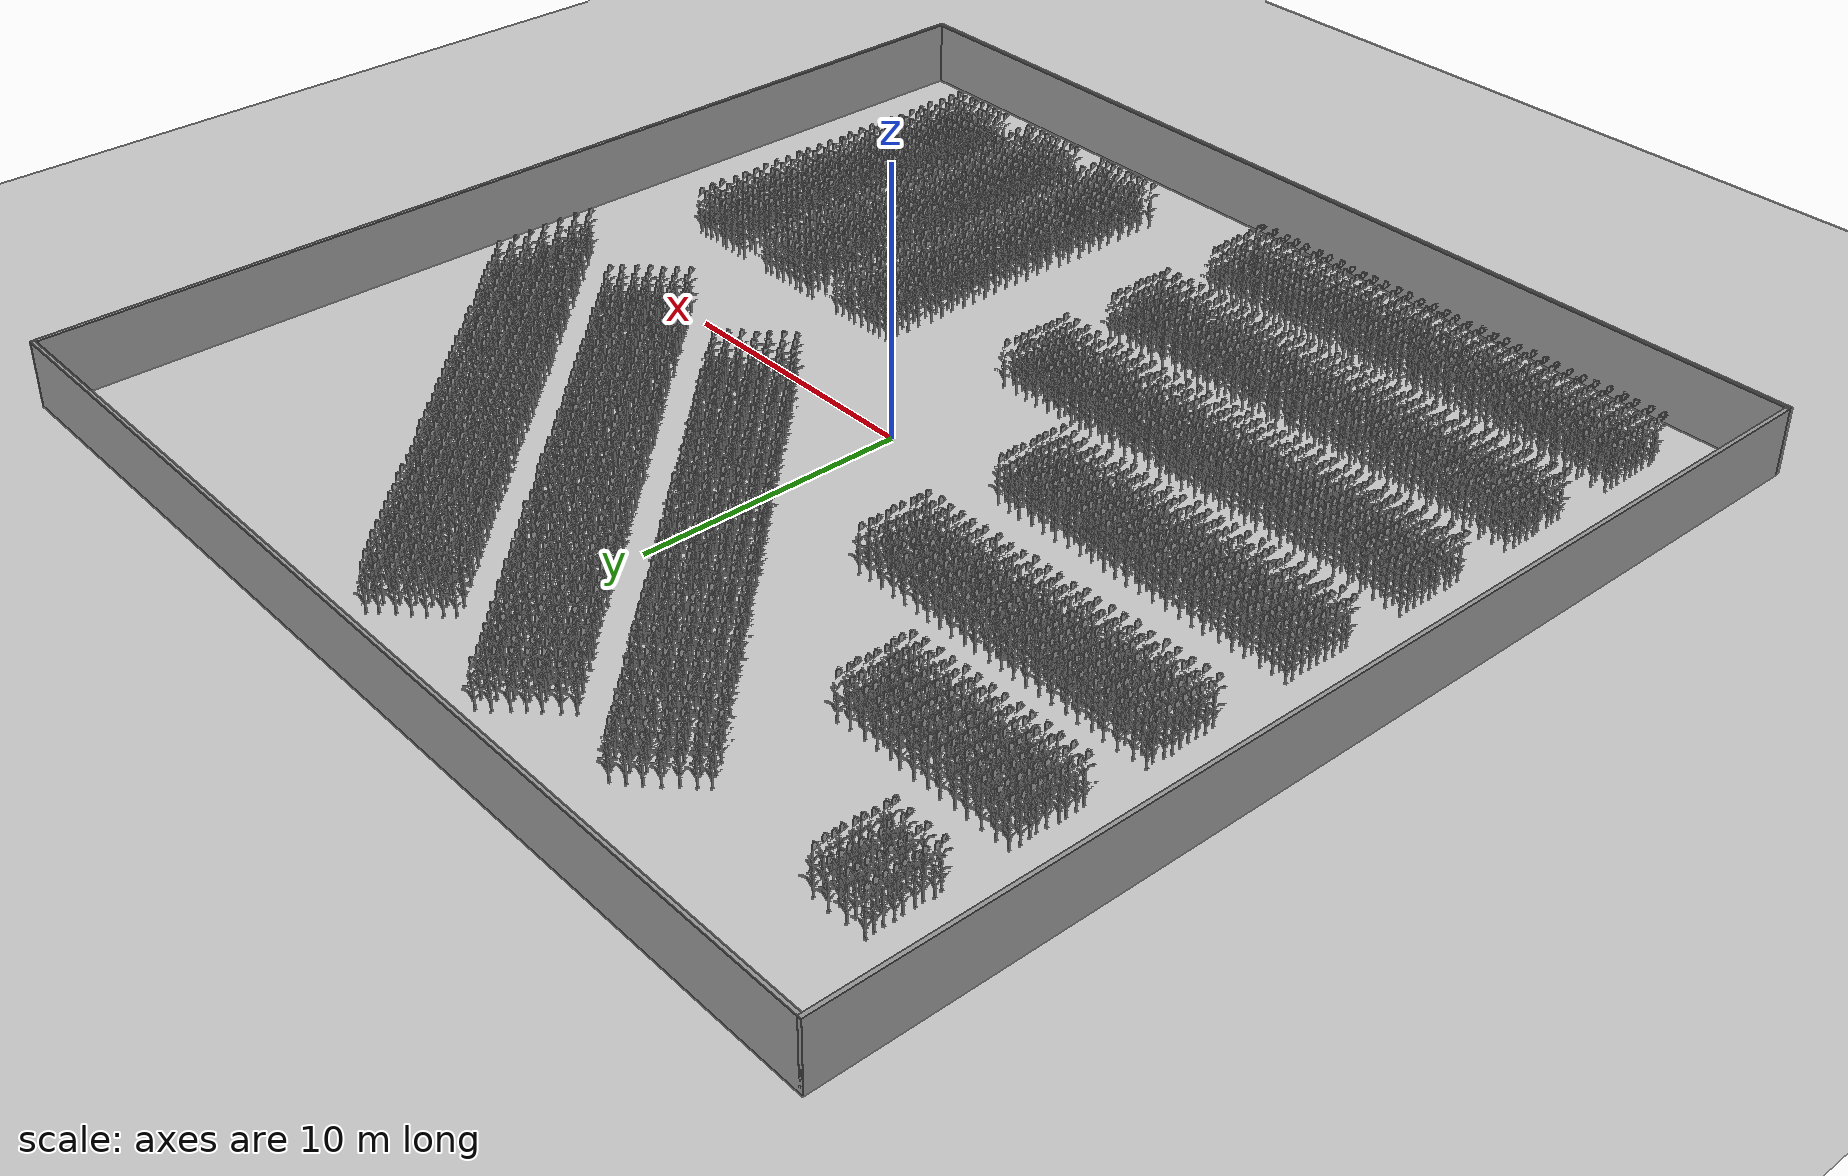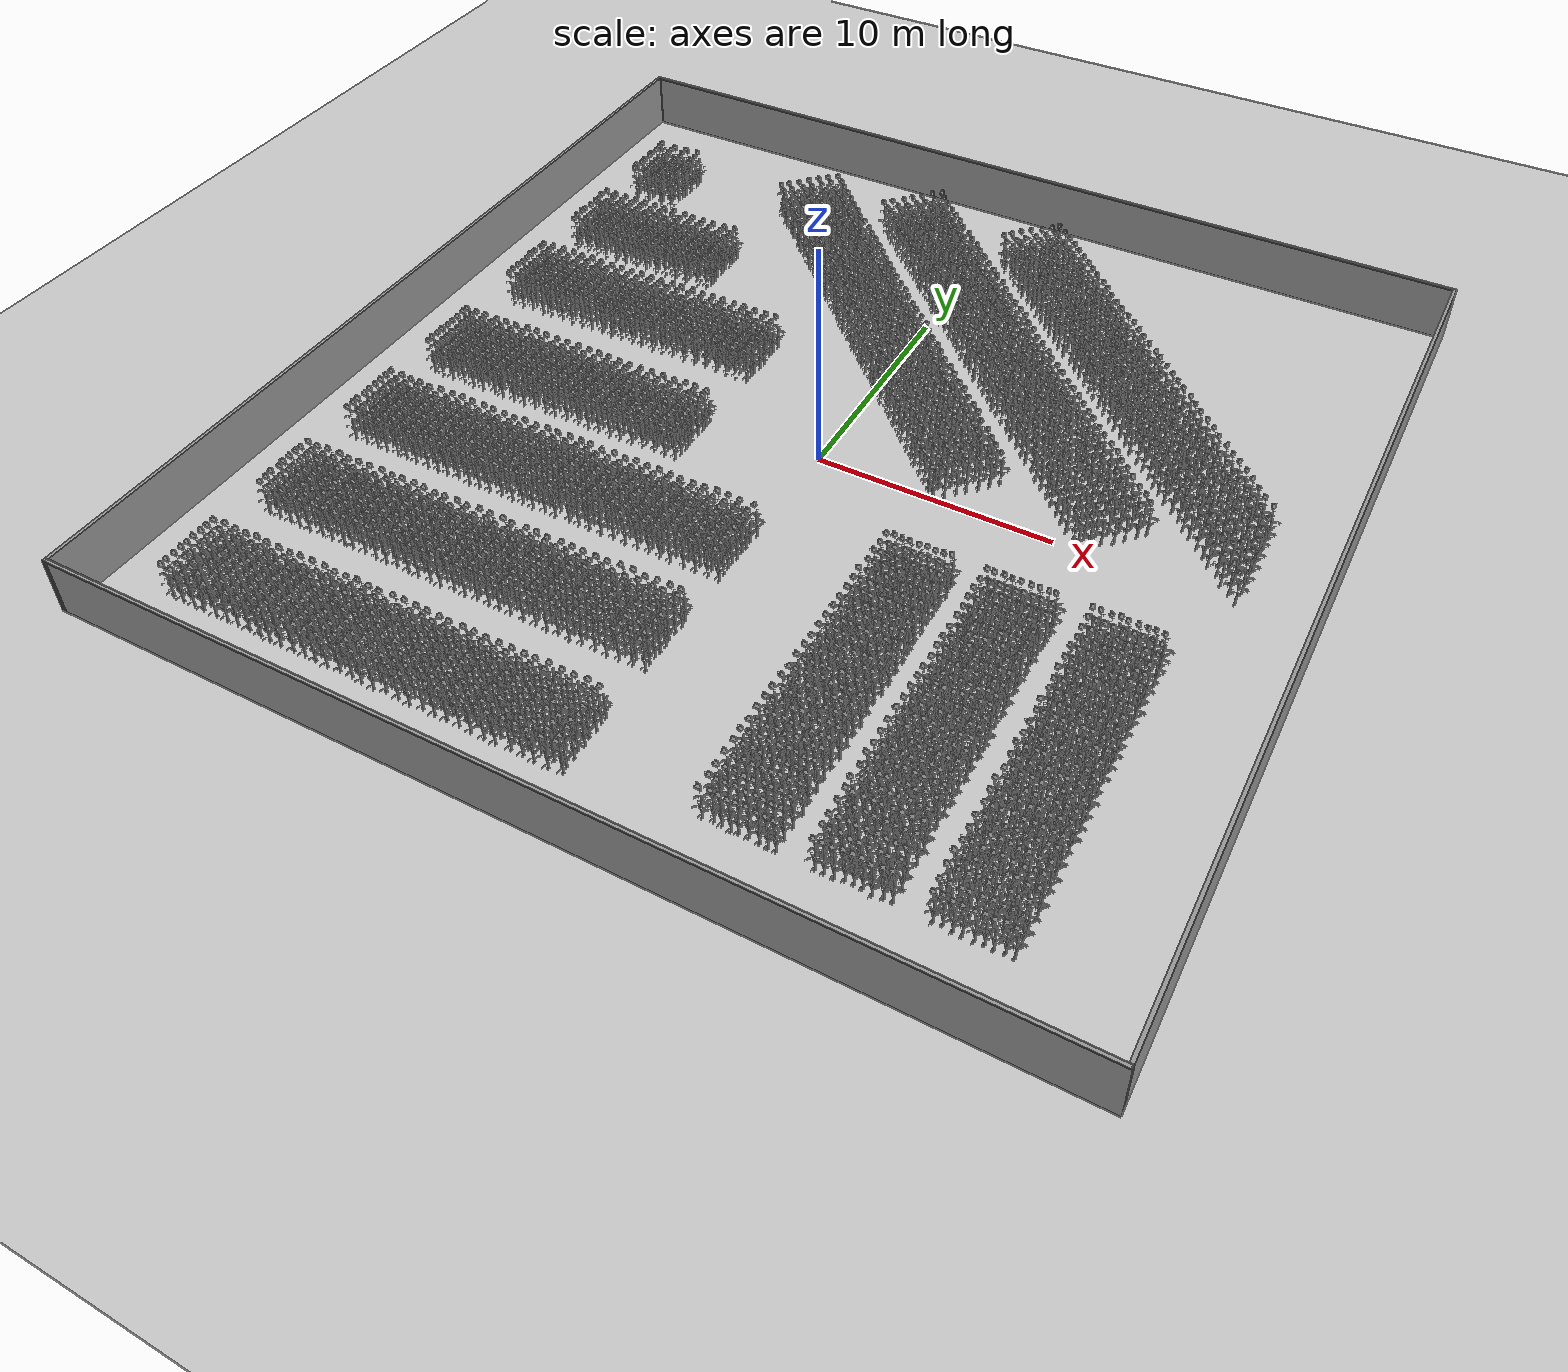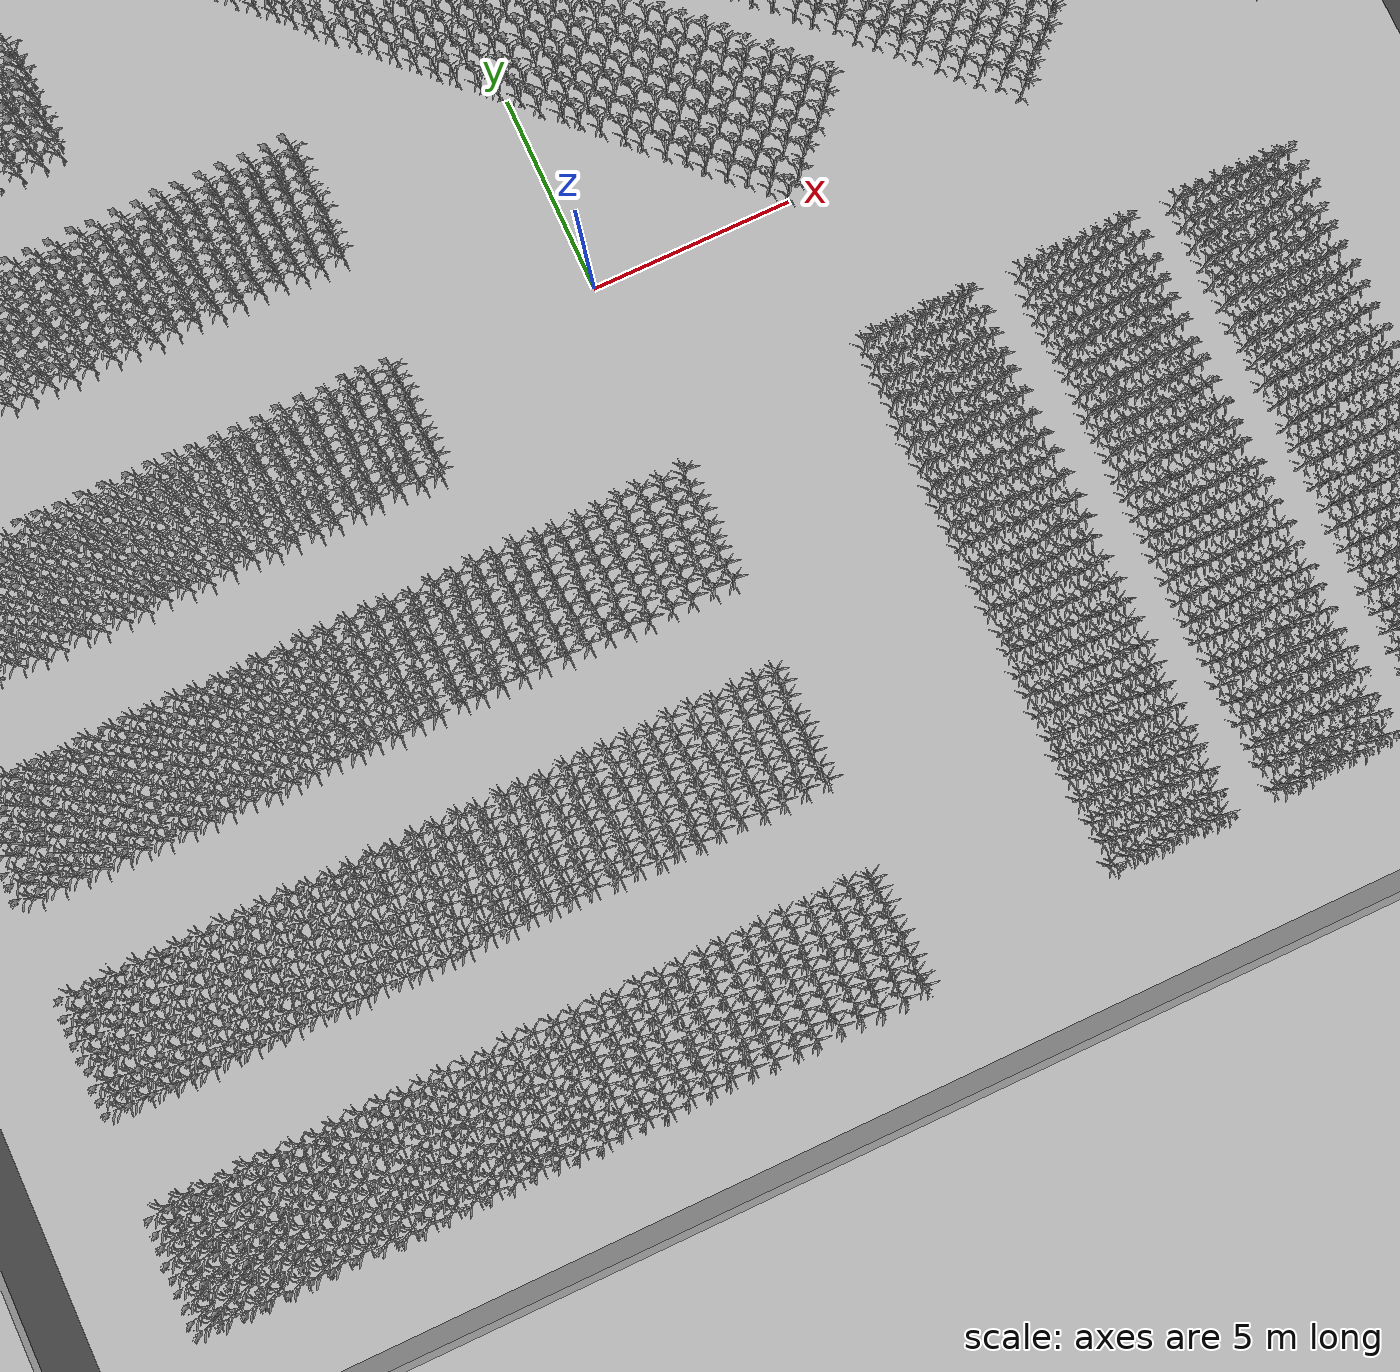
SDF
<sdf version="1.7">
 <world name="farmland_world">
  <light name="sun" type="directional">
   <pose>0 0 10 0 -0 0</pose>
   <diffuse>0.8 0.8 0.8 1</diffuse>
   <specular>0.2 0.2 0.2 1</specular>
   <attenuation>
    <range>1000</range>
    <constant>0.9</constant>
    <linear>0.01</linear>
    <quadratic>0.001</quadratic>
   </attenuation>
   <direction>-0.5 0.1 -0.9</direction>
   <spot><inner_angle>0</inner_angle><outer_angle>0</outer_angle><falloff>0</falloff></spot>
  </light>
  <gravity>0 0 -9.8</gravity>
  <magnetic_field>6e-06 2.3e-05 -4.2e-05</magnetic_field>
  <atmosphere type="adiabatic"/>
  <physics type="ode">
   <max_step_size>0.001</max_step_size>
   <real_time_factor>1</real_time_factor>
   <real_time_update_rate>1000</real_time_update_rate>
  </physics>
  <scene><ambient>0.4 0.4 0.4 1</ambient><background>0.7 0.7 0.7 1</background><shadows>1</shadows></scene>
  <spherical_coordinates>
   <surface_model>EARTH_WGS84</surface_model>
   <latitude_deg>0</latitude_deg>
   <longitude_deg>0</longitude_deg>
   <elevation>0</elevation>
   <heading_deg>0</heading_deg>
  </spherical_coordinates>
  <model name="ground_plane">
   <static>1</static>
   <link name="link">
    <collision name="collision">
     <geometry><plane><normal>0 0 1</normal><size>40.0 40.0</size></plane></geometry>
     <surface><friction><ode><mu>100</mu><mu2>50</mu2></ode></friction></surface>
    </collision>
    <visual name="visual">
     <cast_shadows>0</cast_shadows>
     <geometry><plane><normal>0 0 1</normal><size>40.0 40.0</size></plane></geometry>
     <material>
      <script><uri>file://media/materials/scripts/gazebo.material</uri><name>Gazebo/Grey</name></script>
     </material>
    </visual>
   </link>
  </model>
  <model name="Walls">
   <link name="Wall_0">
    <collision name="Wall_0_Collision">
     <geometry><box><size>40.15 0.15 2.5</size></box></geometry>
     <pose>0 0 1.25 0 -0 0</pose>
    </collision>
    <visual name="Wall_0_Visual">
     <pose>0 0 1.25 0 -0 0</pose>
     <geometry><box><size>40.15 0.15 2.5</size></box></geometry>
     <material>
      <script><uri>file://media/materials/scripts/gazebo.material</uri><name>Gazebo/Grey</name></script>
      <ambient>1 1 1 1</ambient>
     </material>
     <meta><layer>0</layer></meta>
    </visual>
    <pose>-20.0 0 0 0 -0 1.5708</pose>
   </link>
   <link name="Wall_1">
    <collision name="Wall_1_Collision">
     <geometry><box><size>40.15 0.15 2.5</size></box></geometry>
     <pose>0 0 1.25 0 -0 0</pose>
    </collision>
    <visual name="Wall_1_Visual">
     <pose>0 0 1.25 0 -0 0</pose>
     <geometry><box><size>40.15 0.15 2.5</size></box></geometry>
     <material>
      <script><uri>file://media/materials/scripts/gazebo.material</uri><name>Gazebo/Grey</name></script>
      <ambient>1 1 1 1</ambient>
     </material>
     <meta><layer>0</layer></meta>
    </visual>
    <pose>0 20.0 0 0 -0 0</pose>
   </link>
   <link name="Wall_2">
    <collision name="Wall_2_Collision">
     <geometry><box><size>40.15 0.15 2.5</size></box></geometry>
     <pose>0 0 1.25 0 -0 0</pose>
    </collision>
    <visual name="Wall_2_Visual">
     <pose>0 0 1.25 0 -0 0</pose>
     <geometry><box><size>40.15 0.15 2.5</size></box></geometry>
     <material>
      <script><uri>file://media/materials/scripts/gazebo.material</uri><name>Gazebo/Grey</name></script>
      <ambient>1 1 1 1</ambient>
     </material>
     <meta><layer>0</layer></meta>
    </visual>
    <pose>20.0 0 0 0 -0 -1.5708</pose>
   </link>
   <link name="Wall_3">
    <collision name="Wall_3_Collision">
     <geometry><box><size>40.15 0.15 2.5</size></box></geometry>
     <pose>0 0 1.25 0 -0 0</pose>
    </collision>
    <visual name="Wall_3_Visual">
     <pose>0 0 1.25 0 -0 0</pose>
     <geometry><box><size>40.15 0.15 2.5</size></box></geometry>
     <material>
      <script><uri>file://media/materials/scripts/gazebo.material</uri><name>Gazebo/Grey</name></script>
      <ambient>1 1 1 1</ambient>
     </material>
     <meta><layer>0</layer></meta>
    </visual>
    <pose>0 -20.0 0 0 -0 3.14159</pose>
   </link>
   <static>1</static>
  </model>
  <model name="tree_3_0">
   <static>1</static>
   <link name="link">
    <collision name="collision">
     <geometry><mesh><uri>model://Corn_low_poly/corn.obj</uri><scale>1 1 1</scale></mesh></geometry>
     <surface><friction><ode><mu>100</mu><mu2>50</mu2></ode></friction></surface>
    </collision>
    <visual name="visual">
     <geometry><mesh><uri>model://Corn_low_poly/corn.obj</uri><scale>1 1 1</scale></mesh></geometry>
    </visual>
   </link>
   <pose>4.990437242141914 0.04124213625663867 0 0 0 0</pose>
  </model>
  <model name="tree_3_1">
   <static>1</static>
   <link name="link">
    <collision name="collision">
     <geometry><mesh><uri>model://Corn_low_poly/corn.obj</uri><scale>1 1 1</scale></mesh></geometry>
     <surface><friction><ode><mu>100</mu><mu2>50</mu2></ode></friction></surface>
    </collision>
    <visual name="visual">
     <geometry><mesh><uri>model://Corn_low_poly/corn.obj</uri><scale>1 1 1</scale></mesh></geometry>
    </visual>
   </link>
   <pose>4.670537112308127 0.36484631306738974 0 0 0 0</pose>
  </model>
  <model name="tree_3_2">
   <static>1</static>
   <link name="link">
    <collision name="collision">
     <geometry><mesh><uri>model://Corn_low_poly/corn.obj</uri><scale>1 1 1</scale></mesh></geometry>
     <surface><friction><ode><mu>100</mu><mu2>50</mu2></ode></friction></surface>
    </collision>
    <visual name="visual">
     <geometry><mesh><uri>model://Corn_low_poly/corn.obj</uri><scale>1 1 1</scale></mesh></geometry>
    </visual>
   </link>
   <pose>4.296773810718255 0.7526086489686877 0 0 0 0</pose>
  </model>
  <model name="tree_3_3">
   <static>1</static>
   <link name="link">
    <collision name="collision">
     <geometry><mesh><uri>model://Corn_low_poly/corn.obj</uri><scale>1 1 1</scale></mesh></geometry>
     <surface><friction><ode><mu>100</mu><mu2>50</mu2></ode></friction></surface>
    </collision>
    <visual name="visual">
     <geometry><mesh><uri>model://Corn_low_poly/corn.obj</uri><scale>1 1 1</scale></mesh></geometry>
    </visual>
   </link>
   <pose>3.923013442635253 1.0726292482747002 0 0 0 0</pose>
  </model>
  <model name="tree_3_4">
   <static>1</static>
   <link name="link">
    <collision name="collision">
     <geometry><mesh><uri>model://Corn_low_poly/corn.obj</uri><scale>1 1 1</scale></mesh></geometry>
     <surface><friction><ode><mu>100</mu><mu2>50</mu2></ode></friction></surface>
    </collision>
    <visual name="visual">
     <geometry><mesh><uri>model://Corn_low_poly/corn.obj</uri><scale>1 1 1</scale></mesh></geometry>
    </visual>
   </link>
   <pose>3.518027952950115 1.448531610302552 0 0 0 0</pose>
  </model>
  <model name="tree_3_5">
   <static>1</static>
   <link name="link">
    <collision name="collision">
     <geometry><mesh><uri>model://Corn_low_poly/corn.obj</uri><scale>1 1 1</scale></mesh></geometry>
     <surface><friction><ode><mu>100</mu><mu2>50</mu2></ode></friction></surface>
    </collision>
    <visual name="visual">
     <geometry><mesh><uri>model://Corn_low_poly/corn.obj</uri><scale>1 1 1</scale></mesh></geometry>
    </visual>
   </link>
   <pose>3.215919138264696 1.8258071645380627 0 0 0 0</pose>
  </model>
  <model name="tree_3_6">
   <static>1</static>
   <link name="link">
    <collision name="collision">
     <geometry><mesh><uri>model://Corn_low_poly/corn.obj</uri><scale>1 1 1</scale></mesh></geometry>
     <surface><friction><ode><mu>100</mu><mu2>50</mu2></ode></friction></surface>
    </collision>
    <visual name="visual">
     <geometry><mesh><uri>model://Corn_low_poly/corn.obj</uri><scale>1 1 1</scale></mesh></geometry>
    </visual>
   </link>
   <pose>2.831848687563857 2.148193749473167 0 0 0 0</pose>
  </model>
  <model name="tree_3_7">
   <static>1</static>
   <link name="link">
    <collision name="collision">
     <geometry><mesh><uri>model://Corn_low_poly/corn.obj</uri><scale>1 1 1</scale></mesh></geometry>
     <surface><friction><ode><mu>100</mu><mu2>50</mu2></ode></friction></surface>
    </collision>
    <visual name="visual">
     <geometry><mesh><uri>model://Corn_low_poly/corn.obj</uri><scale>1 1 1</scale></mesh></geometry>
    </visual>
   </link>
   <pose>2.408447944001716 2.5840157247397992 0 0 0 0</pose>
  </model>
  <model name="tree_3_8">
   <static>1</static>
   <link name="link">
    <collision name="collision">
     <geometry><mesh><uri>model://Corn_low_poly/corn.obj</uri><scale>1 1 1</scale></mesh></geometry>
     <surface><friction><ode><mu>100</mu><mu2>50</mu2></ode></friction></surface>
    </collision>
    <visual name="visual">
     <geometry><mesh><uri>model://Corn_low_poly/corn.obj</uri><scale>1 1 1</scale></mesh></geometry>
    </visual>
   </link>
   <pose>2.1207289162977068 2.890487309548852 0 0 0 0</pose>
  </model>
  <model name="tree_3_9">
   <static>1</static>
   <link name="link">
    <collision name="collision">
     <geometry><mesh><uri>model://Corn_low_poly/corn.obj</uri><scale>1 1 1</scale></mesh></geometry>
     <surface><friction><ode><mu>100</mu><mu2>50</mu2></ode></friction></surface>
    </collision>
    <visual name="visual">
     <geometry><mesh><uri>model://Corn_low_poly/corn.obj</uri><scale>1 1 1</scale></mesh></geometry>
    </visual>
   </link>
   <pose>1.6888101038842116 3.3363595557820003 0 0 0 0</pose>
  </model>
  <model name="tree_3_10">
   <static>1</static>
   <link name="link">
    <collision name="collision">
     <geometry><mesh><uri>model://Corn_low_poly/corn.obj</uri><scale>1 1 1</scale></mesh></geometry>
     <surface><friction><ode><mu>100</mu><mu2>50</mu2></ode></friction></surface>
    </collision>
    <visual name="visual">
     <geometry><mesh><uri>model://Corn_low_poly/corn.obj</uri><scale>1 1 1</scale></mesh></geometry>
    </visual>
   </link>
   <pose>1.308471326282435 3.7036799926669595 0 0 0 0</pose>
  </model>
  <model name="tree_3_11">
   <static>1</static>
   <link name="link">
    <collision name="collision">
     <geometry><mesh><uri>model://Corn_low_poly/corn.obj</uri><scale>1 1 1</scale></mesh></geometry>
     <surface><friction><ode><mu>100</mu><mu2>50</mu2></ode></friction></surface>
    </collision>
    <visual name="visual">
     <geometry><mesh><uri>model://Corn_low_poly/corn.obj</uri><scale>1 1 1</scale></mesh></geometry>
    </visual>
   </link>
   <pose>1.0232254556805787 4.01556082549061 0 0 0 0</pose>
  </model>
  <model name="tree_3_12">
   <static>1</static>
   <link name="link">
    <collision name="collision">
     <geometry><mesh><uri>model://Corn_low_poly/corn.obj</uri><scale>1 1 1</scale></mesh></geometry>
     <surface><friction><ode><mu>100</mu><mu2>50</mu2></ode></friction></surface>
    </collision>
    <visual name="visual">
     <geometry><mesh><uri>model://Corn_low_poly/corn.obj</uri><scale>1 1 1</scale></mesh></geometry>
    </visual>
   </link>
   <pose>0.5787915241693433 4.362663552276459 0 0 0 0</pose>
  </model>
  <model name="tree_3_13">
   <static>1</static>
   <link name="link">
    <collision name="collision">
     <geometry><mesh><uri>model://Corn_low_poly/corn.obj</uri><scale>1 1 1</scale></mesh></geometry>
     <surface><friction><ode><mu>100</mu><mu2>50</mu2></ode></friction></surface>
    </collision>
    <visual name="visual">
     <geometry><mesh><uri>model://Corn_low_poly/corn.obj</uri><scale>1 1 1</scale></mesh></geometry>
    </visual>
   </link>
   <pose>0.26545962875632606 4.80106337388032 0 0 0 0</pose>
  </model>
  <model name="tree_3_14">
   <static>1</static>
   <link name="link">
    <collision name="collision">
     <geometry><mesh><uri>model://Corn_low_poly/corn.obj</uri><scale>1 1 1</scale></mesh></geometry>
     <surface><friction><ode><mu>100</mu><mu2>50</mu2></ode></friction></surface>
    </collision>
    <visual name="visual">
     <geometry><mesh><uri>model://Corn_low_poly/corn.obj</uri><scale>1 1 1</scale></mesh></geometry>
    </visual>
   </link>
   <pose>-0.12023839368212481 5.1397045667717896 0 0 0 0</pose>
  </model>
  <model name="tree_3_15">
   <static>1</static>
   <link name="link">
    <collision name="collision">
     <geometry><mesh><uri>model://Corn_low_poly/corn.obj</uri><scale>1 1 1</scale></mesh></geometry>
     <surface><friction><ode><mu>100</mu><mu2>50</mu2></ode></friction></surface>
    </collision>
    <visual name="visual">
     <geometry><mesh><uri>model://Corn_low_poly/corn.obj</uri><scale>1 1 1</scale></mesh></geometry>
    </visual>
   </link>
   <pose>-0.4398448168730269 5.475157351992699 0 0 0 0</pose>
  </model>
  <model name="tree_3_16">
   <static>1</static>
   <link name="link">
    <collision name="collision">
     <geometry><mesh><uri>model://Corn_low_poly/corn.obj</uri><scale>1 1 1</scale></mesh></geometry>
     <surface><friction><ode><mu>100</mu><mu2>50</mu2></ode></friction></surface>
    </collision>
    <visual name="visual">
     <geometry><mesh><uri>model://Corn_low_poly/corn.obj</uri><scale>1 1 1</scale></mesh></geometry>
    </visual>
   </link>
   <pose>-0.8932113285887802 5.87875413647353 0 0 0 0</pose>
  </model>
  <model name="tree_3_17">
   <static>1</static>
   <link name="link">
    <collision name="collision">
     <geometry><mesh><uri>model://Corn_low_poly/corn.obj</uri><scale>1 1 1</scale></mesh></geometry>
     <surface><friction><ode><mu>100</mu><mu2>50</mu2></ode></friction></surface>
    </collision>
    <visual name="visual">
     <geometry><mesh><uri>model://Corn_low_poly/corn.obj</uri><scale>1 1 1</scale></mesh></geometry>
    </visual>
   </link>
   <pose>-1.2331043694419168 6.210459773600698 0 0 0 0</pose>
  </model>
  <model name="tree_3_18">
   <static>1</static>
   <link name="link">
    <collision name="collision">
     <geometry><mesh><uri>model://Corn_low_poly/corn.obj</uri><scale>1 1 1</scale></mesh></geometry>
     <surface><friction><ode><mu>100</mu><mu2>50</mu2></ode></friction></surface>
    </collision>
    <visual name="visual">
     <geometry><mesh><uri>model://Corn_low_poly/corn.obj</uri><scale>1 1 1</scale></mesh></geometry>
    </visual>
   </link>
   <pose>-1.5919552716491105 6.589156397790697 0 0 0 0</pose>
  </model>
  <model name="tree_3_19">
   <static>1</static>
   <link name="link">
    <collision name="collision">
     <geometry><mesh><uri>model://Corn_low_poly/corn.obj</uri><scale>1 1 1</scale></mesh></geometry>
     <surface><friction><ode><mu>100</mu><mu2>50</mu2></ode></friction></surface>
    </collision>
    <visual name="visual">
     <geometry><mesh><uri>model://Corn_low_poly/corn.obj</uri><scale>1 1 1</scale></mesh></geometry>
    </visual>
   </link>
   <pose>-1.9576749632588373 6.926214422861499 0 0 0 0</pose>
  </model>
  <model name="tree_3_20">
   <static>1</static>
   <link name="link">
    <collision name="collision">
     <geometry><mesh><uri>model://Corn_low_poly/corn.obj</uri><scale>1 1 1</scale></mesh></geometry>
     <surface><friction><ode><mu>100</mu><mu2>50</mu2></ode></friction></surface>
    </collision>
    <visual name="visual">
     <geometry><mesh><uri>model://Corn_low_poly/corn.obj</uri><scale>1 1 1</scale></mesh></geometry>
    </visual>
   </link>
   <pose>-2.3075666654008624 7.308518571701723 0 0 0 0</pose>
  </model>
  <model name="tree_3_21">
   <static>1</static>
   <link name="link">
    <collision name="collision">
     <geometry><mesh><uri>model://Corn_low_poly/corn.obj</uri><scale>1 1 1</scale></mesh></geometry>
     <surface><friction><ode><mu>100</mu><mu2>50</mu2></ode></friction></surface>
    </collision>
    <visual name="visual">
     <geometry><mesh><uri>model://Corn_low_poly/corn.obj</uri><scale>1 1 1</scale></mesh></geometry>
    </visual>
   </link>
   <pose>-2.6623594286711607 7.656644062296135 0 0 0 0</pose>
  </model>
  <model name="tree_3_22">
   <static>1</static>
   <link name="link">
    <collision name="collision">
     <geometry><mesh><uri>model://Corn_low_poly/corn.obj</uri><scale>1 1 1</scale></mesh></geometry>
     <surface><friction><ode><mu>100</mu><mu2>50</mu2></ode></friction></surface>
    </collision>
    <visual name="visual">
     <geometry><mesh><uri>model://Corn_low_poly/corn.obj</uri><scale>1 1 1</scale></mesh></geometry>
    </visual>
   </link>
   <pose>-3.0937954397768683 8.019661259421337 0 0 0 0</pose>
  </model>
  <model name="tree_3_23">
   <static>1</static>
   <link name="link">
    <collision name="collision">
     <geometry><mesh><uri>model://Corn_low_poly/corn.obj</uri><scale>1 1 1</scale></mesh></geometry>
     <surface><friction><ode><mu>100</mu><mu2>50</mu2></ode></friction></surface>
    </collision>
    <visual name="visual">
     <geometry><mesh><uri>model://Corn_low_poly/corn.obj</uri><scale>1 1 1</scale></mesh></geometry>
    </visual>
   </link>
   <pose>-3.4570688301049857 8.398856139786263 0 0 0 0</pose>
  </model>
  <model name="tree_3_24">
   <static>1</static>
   <link name="link">
    <collision name="collision">
     <geometry><mesh><uri>model://Corn_low_poly/corn.obj</uri><scale>1 1 1</scale></mesh></geometry>
     <surface><friction><ode><mu>100</mu><mu2>50</mu2></ode></friction></surface>
    </collision>
    <visual name="visual">
     <geometry><mesh><uri>model://Corn_low_poly/corn.obj</uri><scale>1 1 1</scale></mesh></geometry>
    </visual>
   </link>
   <pose>-3.797962440280629 8.81836654362723 0 0 0 0</pose>
  </model>
  <model name="tree_3_25">
   <static>1</static>
   <link name="link">
    <collision name="collision">
     <geometry><mesh><uri>model://Corn_low_poly/corn.obj</uri><scale>1 1 1</scale></mesh></geometry>
     <surface><friction><ode><mu>100</mu><mu2>50</mu2></ode></friction></surface>
    </collision>
    <visual name="visual">
     <geometry><mesh><uri>model://Corn_low_poly/corn.obj</uri><scale>1 1 1</scale></mesh></geometry>
    </visual>
   </link>
   <pose>-4.105862151312323 9.14127174307103 0 0 0 0</pose>
  </model>
  <model name="tree_3_26">
   <static>1</static>
   <link name="link">
    <collision name="collision">
     <geometry><mesh><uri>model://Corn_low_poly/corn.obj</uri><scale>1 1 1</scale></mesh></geometry>
     <surface><friction><ode><mu>100</mu><mu2>50</mu2></ode></friction></surface>
    </collision>
    <visual name="visual">
     <geometry><mesh><uri>model://Corn_low_poly/corn.obj</uri><scale>1 1 1</scale></mesh></geometry>
    </visual>
   </link>
   <pose>-4.469059998460315 9.478599175716573 0 0 0 0</pose>
  </model>
  <model name="tree_3_27">
   <static>1</static>
   <link name="link">
    <collision name="collision">
     <geometry><mesh><uri>model://Corn_low_poly/corn.obj</uri><scale>1 1 1</scale></mesh></geometry>
     <surface><friction><ode><mu>100</mu><mu2>50</mu2></ode></friction></surface>
    </collision>
    <visual name="visual">
     <geometry><mesh><uri>model://Corn_low_poly/corn.obj</uri><scale>1 1 1</scale></mesh></geometry>
    </visual>
   </link>
   <pose>-4.874260545740323 9.828441017179236 0 0 0 0</pose>
  </model>
  <model name="tree_3_28">
   <static>1</static>
   <link name="link">
    <collision name="collision">
     <geometry><mesh><uri>model://Corn_low_poly/corn.obj</uri><scale>1 1 1</scale></mesh></geometry>
     <surface><friction><ode><mu>100</mu><mu2>50</mu2></ode></friction></surface>
    </collision>
    <visual name="visual">
     <geometry><mesh><uri>model://Corn_low_poly/corn.obj</uri><scale>1 1 1</scale></mesh></geometry>
    </visual>
   </link>
   <pose>-5.236940694716296 10.24712145402504 0 0 0 0</pose>
  </model>
  <model name="tree_3_29">
   <static>1</static>
   <link name="link">
    <collision name="collision">
     <geometry><mesh><uri>model://Corn_low_poly/corn.obj</uri><scale>1 1 1</scale></mesh></geometry>
     <surface><friction><ode><mu>100</mu><mu2>50</mu2></ode></friction></surface>
    </collision>
    <visual name="visual">
     <geometry><mesh><uri>model://Corn_low_poly/corn.obj</uri><scale>1 1 1</scale></mesh></geometry>
    </visual>
   </link>
   <pose>-5.566226905447198 10.631227501792312 0 0 0 0</pose>
  </model>
  <model name="tree_3_30">
   <static>1</static>
   <link name="link">
    <collision name="collision">
     <geometry><mesh><uri>model://Corn_low_poly/corn.obj</uri><scale>1 1 1</scale></mesh></geometry>
     <surface><friction><ode><mu>100</mu><mu2>50</mu2></ode></friction></surface>
    </collision>
    <visual name="visual">
     <geometry><mesh><uri>model://Corn_low_poly/corn.obj</uri><scale>1 1 1</scale></mesh></geometry>
    </visual>
   </link>
   <pose>-5.993640951671233 10.929727641760392 0 0 0 0</pose>
  </model>
  <model name="tree_3_31">
   <static>1</static>
   <link name="link">
    <collision name="collision">
     <geometry><mesh><uri>model://Corn_low_poly/corn.obj</uri><scale>1 1 1</scale></mesh></geometry>
     <surface><friction><ode><mu>100</mu><mu2>50</mu2></ode></friction></surface>
    </collision>
    <visual name="visual">
     <geometry><mesh><uri>model://Corn_low_poly/corn.obj</uri><scale>1 1 1</scale></mesh></geometry>
    </visual>
   </link>
   <pose>-6.316524884839538 11.302281419242062 0 0 0 0</pose>
  </model>
  <model name="tree_3_32">
   <static>1</static>
   <link name="link">
    <collision name="collision">
     <geometry><mesh><uri>model://Corn_low_poly/corn.obj</uri><scale>1 1 1</scale></mesh></geometry>
     <surface><friction><ode><mu>100</mu><mu2>50</mu2></ode></friction></surface>
    </collision>
    <visual name="visual">
     <geometry><mesh><uri>model://Corn_low_poly/corn.obj</uri><scale>1 1 1</scale></mesh></geometry>
    </visual>
   </link>
   <pose>-6.747003128049815 11.696521662130772 0 0 0 0</pose>
  </model>
  <model name="tree_3_33">
   <static>1</static>
   <link name="link">
    <collision name="collision">
     <geometry><mesh><uri>model://Corn_low_poly/corn.obj</uri><scale>1 1 1</scale></mesh></geometry>
     <surface><friction><ode><mu>100</mu><mu2>50</mu2></ode></friction></surface>
    </collision>
    <visual name="visual">
     <geometry><mesh><uri>model://Corn_low_poly/corn.obj</uri><scale>1 1 1</scale></mesh></geometry>
    </visual>
   </link>
   <pose>-7.107565154997983 12.100361033157853 0 0 0 0</pose>
  </model>
  <model name="tree_3_34">
   <static>1</static>
   <link name="link">
    <collision name="collision">
     <geometry><mesh><uri>model://Corn_low_poly/corn.obj</uri><scale>1 1 1</scale></mesh></geometry>
     <surface><friction><ode><mu>100</mu><mu2>50</mu2></ode></friction></surface>
    </collision>
    <visual name="visual">
     <geometry><mesh><uri>model://Corn_low_poly/corn.obj</uri><scale>1 1 1</scale></mesh></geometry>
    </visual>
   </link>
   <pose>-7.4286386103601085 12.468219442900548 0 0 0 0</pose>
  </model>
  <model name="tree_3_35">
   <static>1</static>
   <link name="link">
    <collision name="collision">
     <geometry><mesh><uri>model://Corn_low_poly/corn.obj</uri><scale>1 1 1</scale></mesh></geometry>
     <surface><friction><ode><mu>100</mu><mu2>50</mu2></ode></friction></surface>
    </collision>
    <visual name="visual">
     <geometry><mesh><uri>model://Corn_low_poly/corn.obj</uri><scale>1 1 1</scale></mesh></geometry>
    </visual>
   </link>
   <pose>-7.830219494557809 12.78490832572719 0 0 0 0</pose>
  </model>
  <model name="tree_3_36">
   <static>1</static>
   <link name="link">
    <collision name="collision">
     <geometry><mesh><uri>model://Corn_low_poly/corn.obj</uri><scale>1 1 1</scale></mesh></geometry>
     <surface><friction><ode><mu>100</mu><mu2>50</mu2></ode></friction></surface>
    </collision>
    <visual name="visual">
     <geometry><mesh><uri>model://Corn_low_poly/corn.obj</uri><scale>1 1 1</scale></mesh></geometry>
    </visual>
   </link>
   <pose>-8.129857579345042 13.171738315988067 0 0 0 0</pose>
  </model>
  <model name="tree_3_37">
   <static>1</static>
   <link name="link">
    <collision name="collision">
     <geometry><mesh><uri>model://Corn_low_poly/corn.obj</uri><scale>1 1 1</scale></mesh></geometry>
     <surface><friction><ode><mu>100</mu><mu2>50</mu2></ode></friction></surface>
    </collision>
    <visual name="visual">
     <geometry><mesh><uri>model://Corn_low_poly/corn.obj</uri><scale>1 1 1</scale></mesh></geometry>
    </visual>
   </link>
   <pose>-8.573904991052336 13.557325802934315 0 0 0 0</pose>
  </model>
  <model name="tree_3_38">
   <static>1</static>
   <link name="link">
    <collision name="collision">
     <geometry><mesh><uri>model://Corn_low_poly/corn.obj</uri><scale>1 1 1</scale></mesh></geometry>
     <surface><friction><ode><mu>100</mu><mu2>50</mu2></ode></friction></surface>
    </collision>
    <visual name="visual">
     <geometry><mesh><uri>model://Corn_low_poly/corn.obj</uri><scale>1 1 1</scale></mesh></geometry>
    </visual>
   </link>
   <pose>-8.891174129363076 13.91824194606996 0 0 0 0</pose>
  </model>
  <model name="tree_3_39">
   <static>1</static>
   <link name="link">
    <collision name="collision">
     <geometry><mesh><uri>model://Corn_low_poly/corn.obj</uri><scale>1 1 1</scale></mesh></geometry>
     <surface><friction><ode><mu>100</mu><mu2>50</mu2></ode></friction></surface>
    </collision>
    <visual name="visual">
     <geometry><mesh><uri>model://Corn_low_poly/corn.obj</uri><scale>1 1 1</scale></mesh></geometry>
    </visual>
   </link>
   <pose>-9.307649380660706 14.218395403183546 0 0 0 0</pose>
  </model>
  <model name="tree_3_40">
   <static>1</static>
   <link name="link">
    <collision name="collision">
     <geometry><mesh><uri>model://Corn_low_poly/corn.obj</uri><scale>1 1 1</scale></mesh></geometry>
     <surface><friction><ode><mu>100</mu><mu2>50</mu2></ode></friction></surface>
    </collision>
    <visual name="visual">
     <geometry><mesh><uri>model://Corn_low_poly/corn.obj</uri><scale>1 1 1</scale></mesh></geometry>
    </visual>
   </link>
   <pose>-9.621351456724668 14.651758770271607 0 0 0 0</pose>
  </model>
  <model name="tree_3_41">
   <static>1</static>
   <link name="link">
    <collision name="collision">
     <geometry><mesh><uri>model://Corn_low_poly/corn.obj</uri><scale>1 1 1</scale></mesh></geometry>
     <surface><friction><ode><mu>100</mu><mu2>50</mu2></ode></friction></surface>
    </collision>
    <visual name="visual">
     <geometry><mesh><uri>model://Corn_low_poly/corn.obj</uri><scale>1 1 1</scale></mesh></geometry>
    </visual>
   </link>
   <pose>-9.985132939946 15.040043317198316 0 0 0 0</pose>
  </model>
  <model name="tree_3_42">
   <static>1</static>
   <link name="link">
    <collision name="collision">
     <geometry><mesh><uri>model://Corn_low_poly/corn.obj</uri><scale>1 1 1</scale></mesh></geometry>
     <surface><friction><ode><mu>100</mu><mu2>50</mu2></ode></friction></surface>
    </collision>
    <visual name="visual">
     <geometry><mesh><uri>model://Corn_low_poly/corn.obj</uri><scale>1 1 1</scale></mesh></geometry>
    </visual>
   </link>
   <pose>5.359254945364544 0.28580689529177034 0 0 0 0</pose>
  </model>
  <model name="tree_3_43">
   <static>1</static>
   <link name="link">
    <collision name="collision">
     <geometry><mesh><uri>model://Corn_low_poly/corn.obj</uri><scale>1 1 1</scale></mesh></geometry>
     <surface><friction><ode><mu>100</mu><mu2>50</mu2></ode></friction></surface>
    </collision>
    <visual name="visual">
     <geometry><mesh><uri>model://Corn_low_poly/corn.obj</uri><scale>1 1 1</scale></mesh></geometry>
    </visual>
   </link>
   <pose>4.930782056454369 0.7237352558699733 0 0 0 0</pose>
  </model>
  <model name="tree_3_44">
   <static>1</static>
   <link name="link">
    <collision name="collision">
     <geometry><mesh><uri>model://Corn_low_poly/corn.obj</uri><scale>1 1 1</scale></mesh></geometry>
     <surface><friction><ode><mu>100</mu><mu2>50</mu2></ode></friction></surface>
    </collision>
    <visual name="visual">
     <geometry><mesh><uri>model://Corn_low_poly/corn.obj</uri><scale>1 1 1</scale></mesh></geometry>
    </visual>
   </link>
   <pose>4.633862451613634 1.0753446110746638 0 0 0 0</pose>
  </model>
  <model name="tree_3_45">
   <static>1</static>
   <link name="link">
    <collision name="collision">
     <geometry><mesh><uri>model://Corn_low_poly/corn.obj</uri><scale>1 1 1</scale></mesh></geometry>
     <surface><friction><ode><mu>100</mu><mu2>50</mu2></ode></friction></surface>
    </collision>
    <visual name="visual">
     <geometry><mesh><uri>model://Corn_low_poly/corn.obj</uri><scale>1 1 1</scale></mesh></geometry>
    </visual>
   </link>
   <pose>4.248096875457242 1.448065347118155 0 0 0 0</pose>
  </model>
  <model name="tree_3_46">
   <static>1</static>
   <link name="link">
    <collision name="collision">
     <geometry><mesh><uri>model://Corn_low_poly/corn.obj</uri><scale>1 1 1</scale></mesh></geometry>
     <surface><friction><ode><mu>100</mu><mu2>50</mu2></ode></friction></surface>
    </collision>
    <visual name="visual">
     <geometry><mesh><uri>model://Corn_low_poly/corn.obj</uri><scale>1 1 1</scale></mesh></geometry>
    </visual>
   </link>
   <pose>3.821593672414259 1.7759120098527523 0 0 0 0</pose>
  </model>
  <model name="tree_3_47">
   <static>1</static>
   <link name="link">
    <collision name="collision">
     <geometry><mesh><uri>model://Corn_low_poly/corn.obj</uri><scale>1 1 1</scale></mesh></geometry>
     <surface><friction><ode><mu>100</mu><mu2>50</mu2></ode></friction></surface>
    </collision>
    <visual name="visual">
     <geometry><mesh><uri>model://Corn_low_poly/corn.obj</uri><scale>1 1 1</scale></mesh></geometry>
    </visual>
   </link>
   <pose>3.4924745138911604 2.1157946073264178 0 0 0 0</pose>
  </model>
  <model name="tree_3_48">
   <static>1</static>
   <link name="link">
    <collision name="collision">
     <geometry><mesh><uri>model://Corn_low_poly/corn.obj</uri><scale>1 1 1</scale></mesh></geometry>
     <surface><friction><ode><mu>100</mu><mu2>50</mu2></ode></friction></surface>
    </collision>
    <visual name="visual">
     <geometry><mesh><uri>model://Corn_low_poly/corn.obj</uri><scale>1 1 1</scale></mesh></geometry>
    </visual>
   </link>
   <pose>3.1606279285832306 2.490993275646689 0 0 0 0</pose>
  </model>
  <model name="tree_3_49">
   <static>1</static>
   <link name="link">
    <collision name="collision">
     <geometry><mesh><uri>model://Corn_low_poly/corn.obj</uri><scale>1 1 1</scale></mesh></geometry>
     <surface><friction><ode><mu>100</mu><mu2>50</mu2></ode></friction></surface>
    </collision>
    <visual name="visual">
     <geometry><mesh><uri>model://Corn_low_poly/corn.obj</uri><scale>1 1 1</scale></mesh></geometry>
    </visual>
   </link>
   <pose>2.8142990893067044 2.8945642962744946 0 0 0 0</pose>
  </model>
  <model name="tree_3_50">
   <static>1</static>
   <link name="link">
    <collision name="collision">
     <geometry><mesh><uri>model://Corn_low_poly/corn.obj</uri><scale>1 1 1</scale></mesh></geometry>
     <surface><friction><ode><mu>100</mu><mu2>50</mu2></ode></friction></surface>
    </collision>
    <visual name="visual">
     <geometry><mesh><uri>model://Corn_low_poly/corn.obj</uri><scale>1 1 1</scale></mesh></geometry>
    </visual>
   </link>
   <pose>2.436316024347742 3.2635789207566104 0 0 0 0</pose>
  </model>
  <model name="tree_3_51">
   <static>1</static>
   <link name="link">
    <collision name="collision">
     <geometry><mesh><uri>model://Corn_low_poly/corn.obj</uri><scale>1 1 1</scale></mesh></geometry>
     <surface><friction><ode><mu>100</mu><mu2>50</mu2></ode></friction></surface>
    </collision>
    <visual name="visual">
     <geometry><mesh><uri>model://Corn_low_poly/corn.obj</uri><scale>1 1 1</scale></mesh></geometry>
    </visual>
   </link>
   <pose>2.0516955008122637 3.643690923849423 0 0 0 0</pose>
  </model>
  <model name="tree_3_52">
   <static>1</static>
   <link name="link">
    <collision name="collision">
     <geometry><mesh><uri>model://Corn_low_poly/corn.obj</uri><scale>1 1 1</scale></mesh></geometry>
     <surface><friction><ode><mu>100</mu><mu2>50</mu2></ode></friction></surface>
    </collision>
    <visual name="visual">
     <geometry><mesh><uri>model://Corn_low_poly/corn.obj</uri><scale>1 1 1</scale></mesh></geometry>
    </visual>
   </link>
   <pose>1.6512197583983248 3.9711522182395296 0 0 0 0</pose>
  </model>
  <model name="tree_3_53">
   <static>1</static>
   <link name="link">
    <collision name="collision">
     <geometry><mesh><uri>model://Corn_low_poly/corn.obj</uri><scale>1 1 1</scale></mesh></geometry>
     <surface><friction><ode><mu>100</mu><mu2>50</mu2></ode></friction></surface>
    </collision>
    <visual name="visual">
     <geometry><mesh><uri>model://Corn_low_poly/corn.obj</uri><scale>1 1 1</scale></mesh></geometry>
    </visual>
   </link>
   <pose>1.2909502370004362 4.378198208558187 0 0 0 0</pose>
  </model>
  <model name="tree_3_54">
   <static>1</static>
   <link name="link">
    <collision name="collision">
     <geometry><mesh><uri>model://Corn_low_poly/corn.obj</uri><scale>1 1 1</scale></mesh></geometry>
     <surface><friction><ode><mu>100</mu><mu2>50</mu2></ode></friction></surface>
    </collision>
    <visual name="visual">
     <geometry><mesh><uri>model://Corn_low_poly/corn.obj</uri><scale>1 1 1</scale></mesh></geometry>
    </visual>
   </link>
   <pose>0.9067625339955362 4.704039833826622 0 0 0 0</pose>
  </model>
  <model name="tree_3_55">
   <static>1</static>
   <link name="link">
    <collision name="collision">
     <geometry><mesh><uri>model://Corn_low_poly/corn.obj</uri><scale>1 1 1</scale></mesh></geometry>
     <surface><friction><ode><mu>100</mu><mu2>50</mu2></ode></friction></surface>
    </collision>
    <visual name="visual">
     <geometry><mesh><uri>model://Corn_low_poly/corn.obj</uri><scale>1 1 1</scale></mesh></geometry>
    </visual>
   </link>
   <pose>0.531155327605569 5.10523888747243 0 0 0 0</pose>
  </model>
  <model name="tree_3_56">
   <static>1</static>
   <link name="link">
    <collision name="collision">
     <geometry><mesh><uri>model://Corn_low_poly/corn.obj</uri><scale>1 1 1</scale></mesh></geometry>
     <surface><friction><ode><mu>100</mu><mu2>50</mu2></ode></friction></surface>
    </collision>
    <visual name="visual">
     <geometry><mesh><uri>model://Corn_low_poly/corn.obj</uri><scale>1 1 1</scale></mesh></geometry>
    </visual>
   </link>
   <pose>0.22490552022206647 5.417339641219678 0 0 0 0</pose>
  </model>
  <model name="tree_3_57">
   <static>1</static>
   <link name="link">
    <collision name="collision">
     <geometry><mesh><uri>model://Corn_low_poly/corn.obj</uri><scale>1 1 1</scale></mesh></geometry>
     <surface><friction><ode><mu>100</mu><mu2>50</mu2></ode></friction></surface>
    </collision>
    <visual name="visual">
     <geometry><mesh><uri>model://Corn_low_poly/corn.obj</uri><scale>1 1 1</scale></mesh></geometry>
    </visual>
   </link>
   <pose>-0.1688528610832573 5.787569273784497 0 0 0 0</pose>
  </model>
  <model name="tree_3_58">
   <static>1</static>
   <link name="link">
    <collision name="collision">
     <geometry><mesh><uri>model://Corn_low_poly/corn.obj</uri><scale>1 1 1</scale></mesh></geometry>
     <surface><friction><ode><mu>100</mu><mu2>50</mu2></ode></friction></surface>
    </collision>
    <visual name="visual">
     <geometry><mesh><uri>model://Corn_low_poly/corn.obj</uri><scale>1 1 1</scale></mesh></geometry>
    </visual>
   </link>
   <pose>-0.4912142954500292 6.206846466846374 0 0 0 0</pose>
  </model>
  <model name="tree_3_59">
   <static>1</static>
   <link name="link">
    <collision name="collision">
     <geometry><mesh><uri>model://Corn_low_poly/corn.obj</uri><scale>1 1 1</scale></mesh></geometry>
     <surface><friction><ode><mu>100</mu><mu2>50</mu2></ode></friction></surface>
    </collision>
    <visual name="visual">
     <geometry><mesh><uri>model://Corn_low_poly/corn.obj</uri><scale>1 1 1</scale></mesh></geometry>
    </visual>
   </link>
   <pose>-0.9284402881562985 6.589801662348872 0 0 0 0</pose>
  </model>
  <model name="tree_3_60">
   <static>1</static>
   <link name="link">
    <collision name="collision">
     <geometry><mesh><uri>model://Corn_low_poly/corn.obj</uri><scale>1 1 1</scale></mesh></geometry>
     <surface><friction><ode><mu>100</mu><mu2>50</mu2></ode></friction></surface>
    </collision>
    <visual name="visual">
     <geometry><mesh><uri>model://Corn_low_poly/corn.obj</uri><scale>1 1 1</scale></mesh></geometry>
    </visual>
   </link>
   <pose>-1.2962200353937587 6.928572871125287 0 0 0 0</pose>
  </model>
  <model name="tree_3_61">
   <static>1</static>
   <link name="link">
    <collision name="collision">
     <geometry><mesh><uri>model://Corn_low_poly/corn.obj</uri><scale>1 1 1</scale></mesh></geometry>
     <surface><friction><ode><mu>100</mu><mu2>50</mu2></ode></friction></surface>
    </collision>
    <visual name="visual">
     <geometry><mesh><uri>model://Corn_low_poly/corn.obj</uri><scale>1 1 1</scale></mesh></geometry>
    </visual>
   </link>
   <pose>-1.6474239404918627 7.30900446934492 0 0 0 0</pose>
  </model>
  <model name="tree_3_62">
   <static>1</static>
   <link name="link">
    <collision name="collision">
     <geometry><mesh><uri>model://Corn_low_poly/corn.obj</uri><scale>1 1 1</scale></mesh></geometry>
     <surface><friction><ode><mu>100</mu><mu2>50</mu2></ode></friction></surface>
    </collision>
    <visual name="visual">
     <geometry><mesh><uri>model://Corn_low_poly/corn.obj</uri><scale>1 1 1</scale></mesh></geometry>
    </visual>
   </link>
   <pose>-2.0073132322144356 7.690980569186514 0 0 0 0</pose>
  </model>
  <model name="tree_3_63">
   <static>1</static>
   <link name="link">
    <collision name="collision">
     <geometry><mesh><uri>model://Corn_low_poly/corn.obj</uri><scale>1 1 1</scale></mesh></geometry>
     <surface><friction><ode><mu>100</mu><mu2>50</mu2></ode></friction></surface>
    </collision>
    <visual name="visual">
     <geometry><mesh><uri>model://Corn_low_poly/corn.obj</uri><scale>1 1 1</scale></mesh></geometry>
    </visual>
   </link>
   <pose>-2.3418813754967016 8.007812253606504 0 0 0 0</pose>
  </model>
  <model name="tree_3_64">
   <static>1</static>
   <link name="link">
    <collision name="collision">
     <geometry><mesh><uri>model://Corn_low_poly/corn.obj</uri><scale>1 1 1</scale></mesh></geometry>
     <surface><friction><ode><mu>100</mu><mu2>50</mu2></ode></friction></surface>
    </collision>
    <visual name="visual">
     <geometry><mesh><uri>model://Corn_low_poly/corn.obj</uri><scale>1 1 1</scale></mesh></geometry>
    </visual>
   </link>
   <pose>-2.6922594340320156 8.358449945702645 0 0 0 0</pose>
  </model>
  <model name="tree_3_65">
   <static>1</static>
   <link name="link">
    <collision name="collision">
     <geometry><mesh><uri>model://Corn_low_poly/corn.obj</uri><scale>1 1 1</scale></mesh></geometry>
     <surface><friction><ode><mu>100</mu><mu2>50</mu2></ode></friction></surface>
    </collision>
    <visual name="visual">
     <geometry><mesh><uri>model://Corn_low_poly/corn.obj</uri><scale>1 1 1</scale></mesh></geometry>
    </visual>
   </link>
   <pose>-3.127816813089691 8.793115844541859 0 0 0 0</pose>
  </model>
  <model name="tree_3_66">
   <static>1</static>
   <link name="link">
    <collision name="collision">
     <geometry><mesh><uri>model://Corn_low_poly/corn.obj</uri><scale>1 1 1</scale></mesh></geometry>
     <surface><friction><ode><mu>100</mu><mu2>50</mu2></ode></friction></surface>
    </collision>
    <visual name="visual">
     <geometry><mesh><uri>model://Corn_low_poly/corn.obj</uri><scale>1 1 1</scale></mesh></geometry>
    </visual>
   </link>
   <pose>-3.4389509334060415 9.157157088411383 0 0 0 0</pose>
  </model>
  <model name="tree_3_67">
   <static>1</static>
   <link name="link">
    <collision name="collision">
     <geometry><mesh><uri>model://Corn_low_poly/corn.obj</uri><scale>1 1 1</scale></mesh></geometry>
     <surface><friction><ode><mu>100</mu><mu2>50</mu2></ode></friction></surface>
    </collision>
    <visual name="visual">
     <geometry><mesh><uri>model://Corn_low_poly/corn.obj</uri><scale>1 1 1</scale></mesh></geometry>
    </visual>
   </link>
   <pose>-3.803372568948871 9.50891590499352 0 0 0 0</pose>
  </model>
  <model name="tree_3_68">
   <static>1</static>
   <link name="link">
    <collision name="collision">
     <geometry><mesh><uri>model://Corn_low_poly/corn.obj</uri><scale>1 1 1</scale></mesh></geometry>
     <surface><friction><ode><mu>100</mu><mu2>50</mu2></ode></friction></surface>
    </collision>
    <visual name="visual">
     <geometry><mesh><uri>model://Corn_low_poly/corn.obj</uri><scale>1 1 1</scale></mesh></geometry>
    </visual>
   </link>
   <pose>-4.231819792319192 9.886134785722836 0 0 0 0</pose>
  </model>
  <model name="tree_3_69">
   <static>1</static>
   <link name="link">
    <collision name="collision">
     <geometry><mesh><uri>model://Corn_low_poly/corn.obj</uri><scale>1 1 1</scale></mesh></geometry>
     <surface><friction><ode><mu>100</mu><mu2>50</mu2></ode></friction></surface>
    </collision>
    <visual name="visual">
     <geometry><mesh><uri>model://Corn_low_poly/corn.obj</uri><scale>1 1 1</scale></mesh></geometry>
    </visual>
   </link>
   <pose>-4.523126618101992 10.159602009444866 0 0 0 0</pose>
  </model>
  <model name="tree_3_70">
   <static>1</static>
   <link name="link">
    <collision name="collision">
     <geometry><mesh><uri>model://Corn_low_poly/corn.obj</uri><scale>1 1 1</scale></mesh></geometry>
     <surface><friction><ode><mu>100</mu><mu2>50</mu2></ode></friction></surface>
    </collision>
    <visual name="visual">
     <geometry><mesh><uri>model://Corn_low_poly/corn.obj</uri><scale>1 1 1</scale></mesh></geometry>
    </visual>
   </link>
   <pose>-4.870097143145961 10.584515150752816 0 0 0 0</pose>
  </model>
  <model name="tree_3_71">
   <static>1</static>
   <link name="link">
    <collision name="collision">
     <geometry><mesh><uri>model://Corn_low_poly/corn.obj</uri><scale>1 1 1</scale></mesh></geometry>
     <surface><friction><ode><mu>100</mu><mu2>50</mu2></ode></friction></surface>
    </collision>
    <visual name="visual">
     <geometry><mesh><uri>model://Corn_low_poly/corn.obj</uri><scale>1 1 1</scale></mesh></geometry>
    </visual>
   </link>
   <pose>-5.231342893370602 10.948013698945493 0 0 0 0</pose>
  </model>
  <model name="tree_3_72">
   <static>1</static>
   <link name="link">
    <collision name="collision">
     <geometry><mesh><uri>model://Corn_low_poly/corn.obj</uri><scale>1 1 1</scale></mesh></geometry>
     <surface><friction><ode><mu>100</mu><mu2>50</mu2></ode></friction></surface>
    </collision>
    <visual name="visual">
     <geometry><mesh><uri>model://Corn_low_poly/corn.obj</uri><scale>1 1 1</scale></mesh></geometry>
    </visual>
   </link>
   <pose>-5.66021034944618 11.298376605785865 0 0 0 0</pose>
  </model>
  <model name="tree_3_73">
   <static>1</static>
   <link name="link">
    <collision name="collision">
     <geometry><mesh><uri>model://Corn_low_poly/corn.obj</uri><scale>1 1 1</scale></mesh></geometry>
     <surface><friction><ode><mu>100</mu><mu2>50</mu2></ode></friction></surface>
    </collision>
    <visual name="visual">
     <geometry><mesh><uri>model://Corn_low_poly/corn.obj</uri><scale>1 1 1</scale></mesh></geometry>
    </visual>
   </link>
   <pose>-6.020705576890292 11.648894407651104 0 0 0 0</pose>
  </model>
  <model name="tree_3_74">
   <static>1</static>
   <link name="link">
    <collision name="collision">
     <geometry><mesh><uri>model://Corn_low_poly/corn.obj</uri><scale>1 1 1</scale></mesh></geometry>
     <surface><friction><ode><mu>100</mu><mu2>50</mu2></ode></friction></surface>
    </collision>
    <visual name="visual">
     <geometry><mesh><uri>model://Corn_low_poly/corn.obj</uri><scale>1 1 1</scale></mesh></geometry>
    </visual>
   </link>
   <pose>-6.344439885720137 12.013913011659145 0 0 0 0</pose>
  </model>
  <model name="tree_3_75">
   <static>1</static>
   <link name="link">
    <collision name="collision">
     <geometry><mesh><uri>model://Corn_low_poly/corn.obj</uri><scale>1 1 1</scale></mesh></geometry>
     <surface><friction><ode><mu>100</mu><mu2>50</mu2></ode></friction></surface>
    </collision>
    <visual name="visual">
     <geometry><mesh><uri>model://Corn_low_poly/corn.obj</uri><scale>1 1 1</scale></mesh></geometry>
    </visual>
   </link>
   <pose>-6.768228170915505 12.398870047057093 0 0 0 0</pose>
  </model>
  <model name="tree_3_76">
   <static>1</static>
   <link name="link">
    <collision name="collision">
     <geometry><mesh><uri>model://Corn_low_poly/corn.obj</uri><scale>1 1 1</scale></mesh></geometry>
     <surface><friction><ode><mu>100</mu><mu2>50</mu2></ode></friction></surface>
    </collision>
    <visual name="visual">
     <geometry><mesh><uri>model://Corn_low_poly/corn.obj</uri><scale>1 1 1</scale></mesh></geometry>
    </visual>
   </link>
   <pose>-7.063323399970196 12.809966135823439 0 0 0 0</pose>
  </model>
  <model name="tree_3_77">
   <static>1</static>
   <link name="link">
    <collision name="collision">
     <geometry><mesh><uri>model://Corn_low_poly/corn.obj</uri><scale>1 1 1</scale></mesh></geometry>
     <surface><friction><ode><mu>100</mu><mu2>50</mu2></ode></friction></surface>
    </collision>
    <visual name="visual">
     <geometry><mesh><uri>model://Corn_low_poly/corn.obj</uri><scale>1 1 1</scale></mesh></geometry>
    </visual>
   </link>
   <pose>-7.460518992473781 13.117609847762825 0 0 0 0</pose>
  </model>
  <model name="tree_3_78">
   <static>1</static>
   <link name="link">
    <collision name="collision">
     <geometry><mesh><uri>model://Corn_low_poly/corn.obj</uri><scale>1 1 1</scale></mesh></geometry>
     <surface><friction><ode><mu>100</mu><mu2>50</mu2></ode></friction></surface>
    </collision>
    <visual name="visual">
     <geometry><mesh><uri>model://Corn_low_poly/corn.obj</uri><scale>1 1 1</scale></mesh></geometry>
    </visual>
   </link>
   <pose>-7.7951431782939276 13.488519647040473 0 0 0 0</pose>
  </model>
  <model name="tree_3_79">
   <static>1</static>
   <link name="link">
    <collision name="collision">
     <geometry><mesh><uri>model://Corn_low_poly/corn.obj</uri><scale>1 1 1</scale></mesh></geometry>
     <surface><friction><ode><mu>100</mu><mu2>50</mu2></ode></friction></surface>
    </collision>
    <visual name="visual">
     <geometry><mesh><uri>model://Corn_low_poly/corn.obj</uri><scale>1 1 1</scale></mesh></geometry>
    </visual>
   </link>
   <pose>-8.167578024957358 13.864423715161175 0 0 0 0</pose>
  </model>
  <model name="tree_3_80">
   <static>1</static>
   <link name="link">
    <collision name="collision">
     <geometry><mesh><uri>model://Corn_low_poly/corn.obj</uri><scale>1 1 1</scale></mesh></geometry>
     <surface><friction><ode><mu>100</mu><mu2>50</mu2></ode></friction></surface>
    </collision>
    <visual name="visual">
     <geometry><mesh><uri>model://Corn_low_poly/corn.obj</uri><scale>1 1 1</scale></mesh></geometry>
    </visual>
   </link>
   <pose>-8.600329314650093 14.276255841382465 0 0 0 0</pose>
  </model>
  <model name="tree_3_81">
   <static>1</static>
   <link name="link">
    <collision name="collision">
     <geometry><mesh><uri>model://Corn_low_poly/corn.obj</uri><scale>1 1 1</scale></mesh></geometry>
     <surface><friction><ode><mu>100</mu><mu2>50</mu2></ode></friction></surface>
    </collision>
    <visual name="visual">
     <geometry><mesh><uri>model://Corn_low_poly/corn.obj</uri><scale>1 1 1</scale></mesh></geometry>
    </visual>
   </link>
   <pose>-8.965540753583443 14.631921202328222 0 0 0 0</pose>
  </model>
  <model name="tree_3_82">
   <static>1</static>
   <link name="link">
    <collision name="collision">
     <geometry><mesh><uri>model://Corn_low_poly/corn.obj</uri><scale>1 1 1</scale></mesh></geometry>
     <surface><friction><ode><mu>100</mu><mu2>50</mu2></ode></friction></surface>
    </collision>
    <visual name="visual">
     <geometry><mesh><uri>model://Corn_low_poly/corn.obj</uri><scale>1 1 1</scale></mesh></geometry>
    </visual>
   </link>
   <pose>-9.341134822959361 14.934578791125151 0 0 0 0</pose>
  </model>
  <model name="tree_3_83">
   <static>1</static>
   <link name="link">
    <collision name="collision">
     <geometry><mesh><uri>model://Corn_low_poly/corn.obj</uri><scale>1 1 1</scale></mesh></geometry>
     <surface><friction><ode><mu>100</mu><mu2>50</mu2></ode></friction></surface>
    </collision>
    <visual name="visual">
     <geometry><mesh><uri>model://Corn_low_poly/corn.obj</uri><scale>1 1 1</scale></mesh></geometry>
    </visual>
   </link>
   <pose>-9.716573105773191 15.33830600436325 0 0 0 0</pose>
  </model>
  <model name="tree_3_84">
   <static>1</static>
   <link name="link">
    <collision name="collision">
     <geometry><mesh><uri>model://Corn_low_poly/corn.obj</uri><scale>1 1 1</scale></mesh></geometry>
     <surface><friction><ode><mu>100</mu><mu2>50</mu2></ode></friction></surface>
    </collision>
    <visual name="visual">
     <geometry><mesh><uri>model://Corn_low_poly/corn.obj</uri><scale>1 1 1</scale></mesh></geometry>
    </visual>
   </link>
   <pose>5.681553277940606 0.698112095116381 0 0 0 0</pose>
  </model>
  <model name="tree_3_85">
   <static>1</static>
   <link name="link">
    <collision name="collision">
     <geometry><mesh><uri>model://Corn_low_poly/corn.obj</uri><scale>1 1 1</scale></mesh></geometry>
     <surface><friction><ode><mu>100</mu><mu2>50</mu2></ode></friction></surface>
    </collision>
    <visual name="visual">
     <geometry><mesh><uri>model://Corn_low_poly/corn.obj</uri><scale>1 1 1</scale></mesh></geometry>
    </visual>
   </link>
   <pose>5.3260892955047385 1.0104196187215295 0 0 0 0</pose>
  </model>
  <model name="tree_3_86">
   <static>1</static>
   <link name="link">
    <collision name="collision">
     <geometry><mesh><uri>model://Corn_low_poly/corn.obj</uri><scale>1 1 1</scale></mesh></geometry>
     <surface><friction><ode><mu>100</mu><mu2>50</mu2></ode></friction></surface>
    </collision>
    <visual name="visual">
     <geometry><mesh><uri>model://Corn_low_poly/corn.obj</uri><scale>1 1 1</scale></mesh></geometry>
    </visual>
   </link>
   <pose>4.946942964338077 1.421391342604766 0 0 0 0</pose>
  </model>
  <model name="tree_3_87">
   <static>1</static>
   <link name="link">
    <collision name="collision">
     <geometry><mesh><uri>model://Corn_low_poly/corn.obj</uri><scale>1 1 1</scale></mesh></geometry>
     <surface><friction><ode><mu>100</mu><mu2>50</mu2></ode></friction></surface>
    </collision>
    <visual name="visual">
     <geometry><mesh><uri>model://Corn_low_poly/corn.obj</uri><scale>1 1 1</scale></mesh></geometry>
    </visual>
   </link>
   <pose>4.572928296338004 1.7810129302614859 0 0 0 0</pose>
  </model>
  <model name="tree_3_88">
   <static>1</static>
   <link name="link">
    <collision name="collision">
     <geometry><mesh><uri>model://Corn_low_poly/corn.obj</uri><scale>1 1 1</scale></mesh></geometry>
     <surface><friction><ode><mu>100</mu><mu2>50</mu2></ode></friction></surface>
    </collision>
    <visual name="visual">
     <geometry><mesh><uri>model://Corn_low_poly/corn.obj</uri><scale>1 1 1</scale></mesh></geometry>
    </visual>
   </link>
   <pose>4.227272457389692 2.181687439679359 0 0 0 0</pose>
  </model>
  <model name="tree_3_89">
   <static>1</static>
   <link name="link">
    <collision name="collision">
     <geometry><mesh><uri>model://Corn_low_poly/corn.obj</uri><scale>1 1 1</scale></mesh></geometry>
     <surface><friction><ode><mu>100</mu><mu2>50</mu2></ode></friction></surface>
    </collision>
    <visual name="visual">
     <geometry><mesh><uri>model://Corn_low_poly/corn.obj</uri><scale>1 1 1</scale></mesh></geometry>
    </visual>
   </link>
   <pose>3.8297221032685558 2.4954873102956805 0 0 0 0</pose>
  </model>
  <model name="tree_3_90">
   <static>1</static>
   <link name="link">
    <collision name="collision">
     <geometry><mesh><uri>model://Corn_low_poly/corn.obj</uri><scale>1 1 1</scale></mesh></geometry>
     <surface><friction><ode><mu>100</mu><mu2>50</mu2></ode></friction></surface>
    </collision>
    <visual name="visual">
     <geometry><mesh><uri>model://Corn_low_poly/corn.obj</uri><scale>1 1 1</scale></mesh></geometry>
    </visual>
   </link>
   <pose>3.5050233200844074 2.862167666118046 0 0 0 0</pose>
  </model>
  <model name="tree_3_91">
   <static>1</static>
   <link name="link">
    <collision name="collision">
     <geometry><mesh><uri>model://Corn_low_poly/corn.obj</uri><scale>1 1 1</scale></mesh></geometry>
     <surface><friction><ode><mu>100</mu><mu2>50</mu2></ode></friction></surface>
    </collision>
    <visual name="visual">
     <geometry><mesh><uri>model://Corn_low_poly/corn.obj</uri><scale>1 1 1</scale></mesh></geometry>
    </visual>
   </link>
   <pose>3.0830337411091504 3.2531683361366905 0 0 0 0</pose>
  </model>
  <model name="tree_3_92">
   <static>1</static>
   <link name="link">
    <collision name="collision">
     <geometry><mesh><uri>model://Corn_low_poly/corn.obj</uri><scale>1 1 1</scale></mesh></geometry>
     <surface><friction><ode><mu>100</mu><mu2>50</mu2></ode></friction></surface>
    </collision>
    <visual name="visual">
     <geometry><mesh><uri>model://Corn_low_poly/corn.obj</uri><scale>1 1 1</scale></mesh></geometry>
    </visual>
   </link>
   <pose>2.7000288150196545 3.601707331249102 0 0 0 0</pose>
  </model>
  <model name="tree_3_93">
   <static>1</static>
   <link name="link">
    <collision name="collision">
     <geometry><mesh><uri>model://Corn_low_poly/corn.obj</uri><scale>1 1 1</scale></mesh></geometry>
     <surface><friction><ode><mu>100</mu><mu2>50</mu2></ode></friction></surface>
    </collision>
    <visual name="visual">
     <geometry><mesh><uri>model://Corn_low_poly/corn.obj</uri><scale>1 1 1</scale></mesh></geometry>
    </visual>
   </link>
   <pose>2.3509077166949863 3.9726445128483703 0 0 0 0</pose>
  </model>
  <model name="tree_3_94">
   <static>1</static>
   <link name="link">
    <collision name="collision">
     <geometry><mesh><uri>model://Corn_low_poly/corn.obj</uri><scale>1 1 1</scale></mesh></geometry>
     <surface><friction><ode><mu>100</mu><mu2>50</mu2></ode></friction></surface>
    </collision>
    <visual name="visual">
     <geometry><mesh><uri>model://Corn_low_poly/corn.obj</uri><scale>1 1 1</scale></mesh></geometry>
    </visual>
   </link>
   <pose>1.9938237411144641 4.301535669248233 0 0 0 0</pose>
  </model>
  <model name="tree_3_95">
   <static>1</static>
   <link name="link">
    <collision name="collision">
     <geometry><mesh><uri>model://Corn_low_poly/corn.obj</uri><scale>1 1 1</scale></mesh></geometry>
     <surface><friction><ode><mu>100</mu><mu2>50</mu2></ode></friction></surface>
    </collision>
    <visual name="visual">
     <geometry><mesh><uri>model://Corn_low_poly/corn.obj</uri><scale>1 1 1</scale></mesh></geometry>
    </visual>
   </link>
   <pose>1.6214672784736344 4.665373077726981 0 0 0 0</pose>
  </model>
  <model name="tree_3_96">
   <static>1</static>
   <link name="link">
    <collision name="collision">
     <geometry><mesh><uri>model://Corn_low_poly/corn.obj</uri><scale>1 1 1</scale></mesh></geometry>
     <surface><friction><ode><mu>100</mu><mu2>50</mu2></ode></friction></surface>
    </collision>
    <visual name="visual">
     <geometry><mesh><uri>model://Corn_low_poly/corn.obj</uri><scale>1 1 1</scale></mesh></geometry>
    </visual>
   </link>
   <pose>1.3157266222173116 5.033465089874461 0 0 0 0</pose>
  </model>
  <model name="tree_3_97">
   <static>1</static>
   <link name="link">
    <collision name="collision">
     <geometry><mesh><uri>model://Corn_low_poly/corn.obj</uri><scale>1 1 1</scale></mesh></geometry>
     <surface><friction><ode><mu>100</mu><mu2>50</mu2></ode></friction></surface>
    </collision>
    <visual name="visual">
     <geometry><mesh><uri>model://Corn_low_poly/corn.obj</uri><scale>1 1 1</scale></mesh></geometry>
    </visual>
   </link>
   <pose>0.9602646314042126 5.437874755142807 0 0 0 0</pose>
  </model>
  <model name="tree_3_98">
   <static>1</static>
   <link name="link">
    <collision name="collision">
     <geometry><mesh><uri>model://Corn_low_poly/corn.obj</uri><scale>1 1 1</scale></mesh></geometry>
     <surface><friction><ode><mu>100</mu><mu2>50</mu2></ode></friction></surface>
    </collision>
    <visual name="visual">
     <geometry><mesh><uri>model://Corn_low_poly/corn.obj</uri><scale>1 1 1</scale></mesh></geometry>
    </visual>
   </link>
   <pose>0.5032127053718228 5.774103408007429 0 0 0 0</pose>
  </model>
  <model name="tree_3_99">
   <static>1</static>
   <link name="link">
    <collision name="collision">
     <geometry><mesh><uri>model://Corn_low_poly/corn.obj</uri><scale>1 1 1</scale></mesh></geometry>
     <surface><friction><ode><mu>100</mu><mu2>50</mu2></ode></friction></surface>
    </collision>
    <visual name="visual">
     <geometry><mesh><uri>model://Corn_low_poly/corn.obj</uri><scale>1 1 1</scale></mesh></geometry>
    </visual>
   </link>
   <pose>0.21755249482552663 6.176583918930253 0 0 0 0</pose>
  </model>
  <model name="tree_3_100">
   <static>1</static>
   <link name="link">
    <collision name="collision">
     <geometry><mesh><uri>model://Corn_low_poly/corn.obj</uri><scale>1 1 1</scale></mesh></geometry>
     <surface><friction><ode><mu>100</mu><mu2>50</mu2></ode></friction></surface>
    </collision>
    <visual name="visual">
     <geometry><mesh><uri>model://Corn_low_poly/corn.obj</uri><scale>1 1 1</scale></mesh></geometry>
    </visual>
   </link>
   <pose>-0.16875573212024889 6.540329089779795 0 0 0 0</pose>
  </model>
  <model name="tree_3_101">
   <static>1</static>
   <link name="link">
    <collision name="collision">
     <geometry><mesh><uri>model://Corn_low_poly/corn.obj</uri><scale>1 1 1</scale></mesh></geometry>
     <surface><friction><ode><mu>100</mu><mu2>50</mu2></ode></friction></surface>
    </collision>
    <visual name="visual">
     <geometry><mesh><uri>model://Corn_low_poly/corn.obj</uri><scale>1 1 1</scale></mesh></geometry>
    </visual>
   </link>
   <pose>-0.5900489050490194 6.85611674523748 0 0 0 0</pose>
  </model>
  <model name="tree_3_102">
   <static>1</static>
   <link name="link">
    <collision name="collision">
     <geometry><mesh><uri>model://Corn_low_poly/corn.obj</uri><scale>1 1 1</scale></mesh></geometry>
     <surface><friction><ode><mu>100</mu><mu2>50</mu2></ode></friction></surface>
    </collision>
    <visual name="visual">
     <geometry><mesh><uri>model://Corn_low_poly/corn.obj</uri><scale>1 1 1</scale></mesh></geometry>
    </visual>
   </link>
   <pose>-0.8964899712963574 7.2489524793954505 0 0 0 0</pose>
  </model>
  <model name="tree_3_103">
   <static>1</static>
   <link name="link">
    <collision name="collision">
     <geometry><mesh><uri>model://Corn_low_poly/corn.obj</uri><scale>1 1 1</scale></mesh></geometry>
     <surface><friction><ode><mu>100</mu><mu2>50</mu2></ode></friction></surface>
    </collision>
    <visual name="visual">
     <geometry><mesh><uri>model://Corn_low_poly/corn.obj</uri><scale>1 1 1</scale></mesh></geometry>
    </visual>
   </link>
   <pose>-1.2391791958938008 7.572770602942284 0 0 0 0</pose>
  </model>
  <model name="tree_3_104">
   <static>1</static>
   <link name="link">
    <collision name="collision">
     <geometry><mesh><uri>model://Corn_low_poly/corn.obj</uri><scale>1 1 1</scale></mesh></geometry>
     <surface><friction><ode><mu>100</mu><mu2>50</mu2></ode></friction></surface>
    </collision>
    <visual name="visual">
     <geometry><mesh><uri>model://Corn_low_poly/corn.obj</uri><scale>1 1 1</scale></mesh></geometry>
    </visual>
   </link>
   <pose>-1.6165728235068906 7.967212510303245 0 0 0 0</pose>
  </model>
  <model name="tree_3_105">
   <static>1</static>
   <link name="link">
    <collision name="collision">
     <geometry><mesh><uri>model://Corn_low_poly/corn.obj</uri><scale>1 1 1</scale></mesh></geometry>
     <surface><friction><ode><mu>100</mu><mu2>50</mu2></ode></friction></surface>
    </collision>
    <visual name="visual">
     <geometry><mesh><uri>model://Corn_low_poly/corn.obj</uri><scale>1 1 1</scale></mesh></geometry>
    </visual>
   </link>
   <pose>-2.020006572990721 8.367107181429498 0 0 0 0</pose>
  </model>
  <model name="tree_3_106">
   <static>1</static>
   <link name="link">
    <collision name="collision">
     <geometry><mesh><uri>model://Corn_low_poly/corn.obj</uri><scale>1 1 1</scale></mesh></geometry>
     <surface><friction><ode><mu>100</mu><mu2>50</mu2></ode></friction></surface>
    </collision>
    <visual name="visual">
     <geometry><mesh><uri>model://Corn_low_poly/corn.obj</uri><scale>1 1 1</scale></mesh></geometry>
    </visual>
   </link>
   <pose>-2.3757347119303582 8.67964209510847 0 0 0 0</pose>
  </model>
  <model name="tree_3_107">
   <static>1</static>
   <link name="link">
    <collision name="collision">
     <geometry><mesh><uri>model://Corn_low_poly/corn.obj</uri><scale>1 1 1</scale></mesh></geometry>
     <surface><friction><ode><mu>100</mu><mu2>50</mu2></ode></friction></surface>
    </collision>
    <visual name="visual">
     <geometry><mesh><uri>model://Corn_low_poly/corn.obj</uri><scale>1 1 1</scale></mesh></geometry>
    </visual>
   </link>
   <pose>-2.710032986190456 9.124085424573753 0 0 0 0</pose>
  </model>
  <model name="tree_3_108">
   <static>1</static>
   <link name="link">
    <collision name="collision">
     <geometry><mesh><uri>model://Corn_low_poly/corn.obj</uri><scale>1 1 1</scale></mesh></geometry>
     <surface><friction><ode><mu>100</mu><mu2>50</mu2></ode></friction></surface>
    </collision>
    <visual name="visual">
     <geometry><mesh><uri>model://Corn_low_poly/corn.obj</uri><scale>1 1 1</scale></mesh></geometry>
    </visual>
   </link>
   <pose>-3.135405919508511 9.476546193045763 0 0 0 0</pose>
  </model>
  <model name="tree_3_109">
   <static>1</static>
   <link name="link">
    <collision name="collision">
     <geometry><mesh><uri>model://Corn_low_poly/corn.obj</uri><scale>1 1 1</scale></mesh></geometry>
     <surface><friction><ode><mu>100</mu><mu2>50</mu2></ode></friction></surface>
    </collision>
    <visual name="visual">
     <geometry><mesh><uri>model://Corn_low_poly/corn.obj</uri><scale>1 1 1</scale></mesh></geometry>
    </visual>
   </link>
   <pose>-3.5115282742998133 9.789023667474527 0 0 0 0</pose>
  </model>
  <model name="tree_3_110">
   <static>1</static>
   <link name="link">
    <collision name="collision">
     <geometry><mesh><uri>model://Corn_low_poly/corn.obj</uri><scale>1 1 1</scale></mesh></geometry>
     <surface><friction><ode><mu>100</mu><mu2>50</mu2></ode></friction></surface>
    </collision>
    <visual name="visual">
     <geometry><mesh><uri>model://Corn_low_poly/corn.obj</uri><scale>1 1 1</scale></mesh></geometry>
    </visual>
   </link>
   <pose>-3.8657024815988876 10.18034561499168 0 0 0 0</pose>
  </model>
  <model name="tree_3_111">
   <static>1</static>
   <link name="link">
    <collision name="collision">
     <geometry><mesh><uri>model://Corn_low_poly/corn.obj</uri><scale>1 1 1</scale></mesh></geometry>
     <surface><friction><ode><mu>100</mu><mu2>50</mu2></ode></friction></surface>
    </collision>
    <visual name="visual">
     <geometry><mesh><uri>model://Corn_low_poly/corn.obj</uri><scale>1 1 1</scale></mesh></geometry>
    </visual>
   </link>
   <pose>-4.2301715889407125 10.559730641724155 0 0 0 0</pose>
  </model>
  <model name="tree_3_112">
   <static>1</static>
   <link name="link">
    <collision name="collision">
     <geometry><mesh><uri>model://Corn_low_poly/corn.obj</uri><scale>1 1 1</scale></mesh></geometry>
     <surface><friction><ode><mu>100</mu><mu2>50</mu2></ode></friction></surface>
    </collision>
    <visual name="visual">
     <geometry><mesh><uri>model://Corn_low_poly/corn.obj</uri><scale>1 1 1</scale></mesh></geometry>
    </visual>
   </link>
   <pose>-4.547789902803861 10.918492866954 0 0 0 0</pose>
  </model>
  <model name="tree_3_113">
   <static>1</static>
   <link name="link">
    <collision name="collision">
     <geometry><mesh><uri>model://Corn_low_poly/corn.obj</uri><scale>1 1 1</scale></mesh></geometry>
     <surface><friction><ode><mu>100</mu><mu2>50</mu2></ode></friction></surface>
    </collision>
    <visual name="visual">
     <geometry><mesh><uri>model://Corn_low_poly/corn.obj</uri><scale>1 1 1</scale></mesh></geometry>
    </visual>
   </link>
   <pose>-4.97658573238629 11.24874929194991 0 0 0 0</pose>
  </model>
  <model name="tree_3_114">
   <static>1</static>
   <link name="link">
    <collision name="collision">
     <geometry><mesh><uri>model://Corn_low_poly/corn.obj</uri><scale>1 1 1</scale></mesh></geometry>
     <surface><friction><ode><mu>100</mu><mu2>50</mu2></ode></friction></surface>
    </collision>
    <visual name="visual">
     <geometry><mesh><uri>model://Corn_low_poly/corn.obj</uri><scale>1 1 1</scale></mesh></geometry>
    </visual>
   </link>
   <pose>-5.305756932662055 11.641136277965122 0 0 0 0</pose>
  </model>
  <model name="tree_3_115">
   <static>1</static>
   <link name="link">
    <collision name="collision">
     <geometry><mesh><uri>model://Corn_low_poly/corn.obj</uri><scale>1 1 1</scale></mesh></geometry>
     <surface><friction><ode><mu>100</mu><mu2>50</mu2></ode></friction></surface>
    </collision>
    <visual name="visual">
     <geometry><mesh><uri>model://Corn_low_poly/corn.obj</uri><scale>1 1 1</scale></mesh></geometry>
    </visual>
   </link>
   <pose>-5.654780780837856 12.017618488727063 0 0 0 0</pose>
  </model>
  <model name="tree_3_116">
   <static>1</static>
   <link name="link">
    <collision name="collision">
     <geometry><mesh><uri>model://Corn_low_poly/corn.obj</uri><scale>1 1 1</scale></mesh></geometry>
     <surface><friction><ode><mu>100</mu><mu2>50</mu2></ode></friction></surface>
    </collision>
    <visual name="visual">
     <geometry><mesh><uri>model://Corn_low_poly/corn.obj</uri><scale>1 1 1</scale></mesh></geometry>
    </visual>
   </link>
   <pose>-6.002846768110236 12.406931508724687 0 0 0 0</pose>
  </model>
  <model name="tree_3_117">
   <static>1</static>
   <link name="link">
    <collision name="collision">
     <geometry><mesh><uri>model://Corn_low_poly/corn.obj</uri><scale>1 1 1</scale></mesh></geometry>
     <surface><friction><ode><mu>100</mu><mu2>50</mu2></ode></friction></surface>
    </collision>
    <visual name="visual">
     <geometry><mesh><uri>model://Corn_low_poly/corn.obj</uri><scale>1 1 1</scale></mesh></geometry>
    </visual>
   </link>
   <pose>-6.4525473365919925 12.70961789345081 0 0 0 0</pose>
  </model>
  <model name="tree_3_118">
   <static>1</static>
   <link name="link">
    <collision name="collision">
     <geometry><mesh><uri>model://Corn_low_poly/corn.obj</uri><scale>1 1 1</scale></mesh></geometry>
     <surface><friction><ode><mu>100</mu><mu2>50</mu2></ode></friction></surface>
    </collision>
    <visual name="visual">
     <geometry><mesh><uri>model://Corn_low_poly/corn.obj</uri><scale>1 1 1</scale></mesh></geometry>
    </visual>
   </link>
   <pose>-6.811864054925043 13.095852240841447 0 0 0 0</pose>
  </model>
  <model name="tree_3_119">
   <static>1</static>
   <link name="link">
    <collision name="collision">
     <geometry><mesh><uri>model://Corn_low_poly/corn.obj</uri><scale>1 1 1</scale></mesh></geometry>
     <surface><friction><ode><mu>100</mu><mu2>50</mu2></ode></friction></surface>
    </collision>
    <visual name="visual">
     <geometry><mesh><uri>model://Corn_low_poly/corn.obj</uri><scale>1 1 1</scale></mesh></geometry>
    </visual>
   </link>
   <pose>-7.116872561351904 13.438163232261958 0 0 0 0</pose>
  </model>
  <model name="tree_3_120">
   <static>1</static>
   <link name="link">
    <collision name="collision">
     <geometry><mesh><uri>model://Corn_low_poly/corn.obj</uri><scale>1 1 1</scale></mesh></geometry>
     <surface><friction><ode><mu>100</mu><mu2>50</mu2></ode></friction></surface>
    </collision>
    <visual name="visual">
     <geometry><mesh><uri>model://Corn_low_poly/corn.obj</uri><scale>1 1 1</scale></mesh></geometry>
    </visual>
   </link>
   <pose>-7.483291994920764 13.883653861560314 0 0 0 0</pose>
  </model>
  <model name="tree_3_121">
   <static>1</static>
   <link name="link">
    <collision name="collision">
     <geometry><mesh><uri>model://Corn_low_poly/corn.obj</uri><scale>1 1 1</scale></mesh></geometry>
     <surface><friction><ode><mu>100</mu><mu2>50</mu2></ode></friction></surface>
    </collision>
    <visual name="visual">
     <geometry><mesh><uri>model://Corn_low_poly/corn.obj</uri><scale>1 1 1</scale></mesh></geometry>
    </visual>
   </link>
   <pose>-7.828971657432185 14.207264702212273 0 0 0 0</pose>
  </model>
  <model name="tree_3_122">
   <static>1</static>
   <link name="link">
    <collision name="collision">
     <geometry><mesh><uri>model://Corn_low_poly/corn.obj</uri><scale>1 1 1</scale></mesh></geometry>
     <surface><friction><ode><mu>100</mu><mu2>50</mu2></ode></friction></surface>
    </collision>
    <visual name="visual">
     <geometry><mesh><uri>model://Corn_low_poly/corn.obj</uri><scale>1 1 1</scale></mesh></geometry>
    </visual>
   </link>
   <pose>-8.248117083434586 14.61874428466852 0 0 0 0</pose>
  </model>
  <model name="tree_3_123">
   <static>1</static>
   <link name="link">
    <collision name="collision">
     <geometry><mesh><uri>model://Corn_low_poly/corn.obj</uri><scale>1 1 1</scale></mesh></geometry>
     <surface><friction><ode><mu>100</mu><mu2>50</mu2></ode></friction></surface>
    </collision>
    <visual name="visual">
     <geometry><mesh><uri>model://Corn_low_poly/corn.obj</uri><scale>1 1 1</scale></mesh></geometry>
    </visual>
   </link>
   <pose>-8.617351034218144 14.964083626259745 0 0 0 0</pose>
  </model>
  <model name="tree_3_124">
   <static>1</static>
   <link name="link">
    <collision name="collision">
     <geometry><mesh><uri>model://Corn_low_poly/corn.obj</uri><scale>1 1 1</scale></mesh></geometry>
     <surface><friction><ode><mu>100</mu><mu2>50</mu2></ode></friction></surface>
    </collision>
    <visual name="visual">
     <geometry><mesh><uri>model://Corn_low_poly/corn.obj</uri><scale>1 1 1</scale></mesh></geometry>
    </visual>
   </link>
   <pose>-8.9673074540992 15.352462581514478 0 0 0 0</pose>
  </model>
  <model name="tree_3_125">
   <static>1</static>
   <link name="link">
    <collision name="collision">
     <geometry><mesh><uri>model://Corn_low_poly/corn.obj</uri><scale>1 1 1</scale></mesh></geometry>
     <surface><friction><ode><mu>100</mu><mu2>50</mu2></ode></friction></surface>
    </collision>
    <visual name="visual">
     <geometry><mesh><uri>model://Corn_low_poly/corn.obj</uri><scale>1 1 1</scale></mesh></geometry>
    </visual>
   </link>
   <pose>-9.342893099528833 15.64641191831029 0 0 0 0</pose>
  </model>
  <model name="tree_3_126">
   <static>1</static>
   <link name="link">
    <collision name="collision">
     <geometry><mesh><uri>model://Corn_low_poly/corn.obj</uri><scale>1 1 1</scale></mesh></geometry>
     <surface><friction><ode><mu>100</mu><mu2>50</mu2></ode></friction></surface>
    </collision>
    <visual name="visual">
     <geometry><mesh><uri>model://Corn_low_poly/corn.obj</uri><scale>1 1 1</scale></mesh></geometry>
    </visual>
   </link>
   <pose>5.961361274464771 1.003184271032604 0 0 0 0</pose>
  </model>
  <model name="tree_3_127">
   <static>1</static>
   <link name="link">
    <collision name="collision">
     <geometry><mesh><uri>model://Corn_low_poly/corn.obj</uri><scale>1 1 1</scale></mesh></geometry>
     <surface><friction><ode><mu>100</mu><mu2>50</mu2></ode></friction></surface>
    </collision>
    <visual name="visual">
     <geometry><mesh><uri>model://Corn_low_poly/corn.obj</uri><scale>1 1 1</scale></mesh></geometry>
    </visual>
   </link>
   <pose>5.626600193499851 1.3966899550607776 0 0 0 0</pose>
  </model>
  <model name="tree_3_128">
   <static>1</static>
   <link name="link">
    <collision name="collision">
     <geometry><mesh><uri>model://Corn_low_poly/corn.obj</uri><scale>1 1 1</scale></mesh></geometry>
     <surface><friction><ode><mu>100</mu><mu2>50</mu2></ode></friction></surface>
    </collision>
    <visual name="visual">
     <geometry><mesh><uri>model://Corn_low_poly/corn.obj</uri><scale>1 1 1</scale></mesh></geometry>
    </visual>
   </link>
   <pose>5.278987972661195 1.6948297291709746 0 0 0 0</pose>
  </model>
  <model name="tree_3_129">
   <static>1</static>
   <link name="link">
    <collision name="collision">
     <geometry><mesh><uri>model://Corn_low_poly/corn.obj</uri><scale>1 1 1</scale></mesh></geometry>
     <surface><friction><ode><mu>100</mu><mu2>50</mu2></ode></friction></surface>
    </collision>
    <visual name="visual">
     <geometry><mesh><uri>model://Corn_low_poly/corn.obj</uri><scale>1 1 1</scale></mesh></geometry>
    </visual>
   </link>
   <pose>4.942672414734178 2.0555187078099695 0 0 0 0</pose>
  </model>
  <model name="tree_3_130">
   <static>1</static>
   <link name="link">
    <collision name="collision">
     <geometry><mesh><uri>model://Corn_low_poly/corn.obj</uri><scale>1 1 1</scale></mesh></geometry>
     <surface><friction><ode><mu>100</mu><mu2>50</mu2></ode></friction></surface>
    </collision>
    <visual name="visual">
     <geometry><mesh><uri>model://Corn_low_poly/corn.obj</uri><scale>1 1 1</scale></mesh></geometry>
    </visual>
   </link>
   <pose>4.501438872589189 2.4622158794863735 0 0 0 0</pose>
  </model>
  <model name="tree_3_131">
   <static>1</static>
   <link name="link">
    <collision name="collision">
     <geometry><mesh><uri>model://Corn_low_poly/corn.obj</uri><scale>1 1 1</scale></mesh></geometry>
     <surface><friction><ode><mu>100</mu><mu2>50</mu2></ode></friction></surface>
    </collision>
    <visual name="visual">
     <geometry><mesh><uri>model://Corn_low_poly/corn.obj</uri><scale>1 1 1</scale></mesh></geometry>
    </visual>
   </link>
   <pose>4.167754784772649 2.8068944071233624 0 0 0 0</pose>
  </model>
  <model name="tree_3_132">
   <static>1</static>
   <link name="link">
    <collision name="collision">
     <geometry><mesh><uri>model://Corn_low_poly/corn.obj</uri><scale>1 1 1</scale></mesh></geometry>
     <surface><friction><ode><mu>100</mu><mu2>50</mu2></ode></friction></surface>
    </collision>
    <visual name="visual">
     <geometry><mesh><uri>model://Corn_low_poly/corn.obj</uri><scale>1 1 1</scale></mesh></geometry>
    </visual>
   </link>
   <pose>3.7667129262403733 3.2219429808208413 0 0 0 0</pose>
  </model>
  <model name="tree_3_133">
   <static>1</static>
   <link name="link">
    <collision name="collision">
     <geometry><mesh><uri>model://Corn_low_poly/corn.obj</uri><scale>1 1 1</scale></mesh></geometry>
     <surface><friction><ode><mu>100</mu><mu2>50</mu2></ode></friction></surface>
    </collision>
    <visual name="visual">
     <geometry><mesh><uri>model://Corn_low_poly/corn.obj</uri><scale>1 1 1</scale></mesh></geometry>
    </visual>
   </link>
   <pose>3.486839045976324 3.540286229087184 0 0 0 0</pose>
  </model>
  <model name="tree_3_134">
   <static>1</static>
   <link name="link">
    <collision name="collision">
     <geometry><mesh><uri>model://Corn_low_poly/corn.obj</uri><scale>1 1 1</scale></mesh></geometry>
     <surface><friction><ode><mu>100</mu><mu2>50</mu2></ode></friction></surface>
    </collision>
    <visual name="visual">
     <geometry><mesh><uri>model://Corn_low_poly/corn.obj</uri><scale>1 1 1</scale></mesh></geometry>
    </visual>
   </link>
   <pose>3.1007410632310592 3.8971719913114735 0 0 0 0</pose>
  </model>
  <model name="tree_3_135">
   <static>1</static>
   <link name="link">
    <collision name="collision">
     <geometry><mesh><uri>model://Corn_low_poly/corn.obj</uri><scale>1 1 1</scale></mesh></geometry>
     <surface><friction><ode><mu>100</mu><mu2>50</mu2></ode></friction></surface>
    </collision>
    <visual name="visual">
     <geometry><mesh><uri>model://Corn_low_poly/corn.obj</uri><scale>1 1 1</scale></mesh></geometry>
    </visual>
   </link>
   <pose>2.6858413581672984 4.2976841804900365 0 0 0 0</pose>
  </model>
  <model name="tree_3_136">
   <static>1</static>
   <link name="link">
    <collision name="collision">
     <geometry><mesh><uri>model://Corn_low_poly/corn.obj</uri><scale>1 1 1</scale></mesh></geometry>
     <surface><friction><ode><mu>100</mu><mu2>50</mu2></ode></friction></surface>
    </collision>
    <visual name="visual">
     <geometry><mesh><uri>model://Corn_low_poly/corn.obj</uri><scale>1 1 1</scale></mesh></geometry>
    </visual>
   </link>
   <pose>2.3583963821147313 4.641387063509661 0 0 0 0</pose>
  </model>
  <model name="tree_3_137">
   <static>1</static>
   <link name="link">
    <collision name="collision">
     <geometry><mesh><uri>model://Corn_low_poly/corn.obj</uri><scale>1 1 1</scale></mesh></geometry>
     <surface><friction><ode><mu>100</mu><mu2>50</mu2></ode></friction></surface>
    </collision>
    <visual name="visual">
     <geometry><mesh><uri>model://Corn_low_poly/corn.obj</uri><scale>1 1 1</scale></mesh></geometry>
    </visual>
   </link>
   <pose>1.9268848968034373 5.033929177399274 0 0 0 0</pose>
  </model>
  <model name="tree_3_138">
   <static>1</static>
   <link name="link">
    <collision name="collision">
     <geometry><mesh><uri>model://Corn_low_poly/corn.obj</uri><scale>1 1 1</scale></mesh></geometry>
     <surface><friction><ode><mu>100</mu><mu2>50</mu2></ode></friction></surface>
    </collision>
    <visual name="visual">
     <geometry><mesh><uri>model://Corn_low_poly/corn.obj</uri><scale>1 1 1</scale></mesh></geometry>
    </visual>
   </link>
   <pose>1.5696214563842568 5.349178303925119 0 0 0 0</pose>
  </model>
  <model name="tree_3_139">
   <static>1</static>
   <link name="link">
    <collision name="collision">
     <geometry><mesh><uri>model://Corn_low_poly/corn.obj</uri><scale>1 1 1</scale></mesh></geometry>
     <surface><friction><ode><mu>100</mu><mu2>50</mu2></ode></friction></surface>
    </collision>
    <visual name="visual">
     <geometry><mesh><uri>model://Corn_low_poly/corn.obj</uri><scale>1 1 1</scale></mesh></geometry>
    </visual>
   </link>
   <pose>1.2842965847691756 5.709106080251476 0 0 0 0</pose>
  </model>
  <model name="tree_3_140">
   <static>1</static>
   <link name="link">
    <collision name="collision">
     <geometry><mesh><uri>model://Corn_low_poly/corn.obj</uri><scale>1 1 1</scale></mesh></geometry>
     <surface><friction><ode><mu>100</mu><mu2>50</mu2></ode></friction></surface>
    </collision>
    <visual name="visual">
     <geometry><mesh><uri>model://Corn_low_poly/corn.obj</uri><scale>1 1 1</scale></mesh></geometry>
    </visual>
   </link>
   <pose>0.9274458561356759 6.106504313053643 0 0 0 0</pose>
  </model>
  <model name="tree_3_141">
   <static>1</static>
   <link name="link">
    <collision name="collision">
     <geometry><mesh><uri>model://Corn_low_poly/corn.obj</uri><scale>1 1 1</scale></mesh></geometry>
     <surface><friction><ode><mu>100</mu><mu2>50</mu2></ode></friction></surface>
    </collision>
    <visual name="visual">
     <geometry><mesh><uri>model://Corn_low_poly/corn.obj</uri><scale>1 1 1</scale></mesh></geometry>
    </visual>
   </link>
   <pose>0.4828474347836512 6.535133516261817 0 0 0 0</pose>
  </model>
  <model name="tree_3_142">
   <static>1</static>
   <link name="link">
    <collision name="collision">
     <geometry><mesh><uri>model://Corn_low_poly/corn.obj</uri><scale>1 1 1</scale></mesh></geometry>
     <surface><friction><ode><mu>100</mu><mu2>50</mu2></ode></friction></surface>
    </collision>
    <visual name="visual">
     <geometry><mesh><uri>model://Corn_low_poly/corn.obj</uri><scale>1 1 1</scale></mesh></geometry>
    </visual>
   </link>
   <pose>0.15964210227421233 6.873767871134555 0 0 0 0</pose>
  </model>
  <model name="tree_3_143">
   <static>1</static>
   <link name="link">
    <collision name="collision">
     <geometry><mesh><uri>model://Corn_low_poly/corn.obj</uri><scale>1 1 1</scale></mesh></geometry>
     <surface><friction><ode><mu>100</mu><mu2>50</mu2></ode></friction></surface>
    </collision>
    <visual name="visual">
     <geometry><mesh><uri>model://Corn_low_poly/corn.obj</uri><scale>1 1 1</scale></mesh></geometry>
    </visual>
   </link>
   <pose>-0.25374983148931535 7.214061114571216 0 0 0 0</pose>
  </model>
  <model name="tree_3_144">
   <static>1</static>
   <link name="link">
    <collision name="collision">
     <geometry><mesh><uri>model://Corn_low_poly/corn.obj</uri><scale>1 1 1</scale></mesh></geometry>
     <surface><friction><ode><mu>100</mu><mu2>50</mu2></ode></friction></surface>
    </collision>
    <visual name="visual">
     <geometry><mesh><uri>model://Corn_low_poly/corn.obj</uri><scale>1 1 1</scale></mesh></geometry>
    </visual>
   </link>
   <pose>-0.5968321135465497 7.565941472760978 0 0 0 0</pose>
  </model>
  <model name="tree_3_145">
   <static>1</static>
   <link name="link">
    <collision name="collision">
     <geometry><mesh><uri>model://Corn_low_poly/corn.obj</uri><scale>1 1 1</scale></mesh></geometry>
     <surface><friction><ode><mu>100</mu><mu2>50</mu2></ode></friction></surface>
    </collision>
    <visual name="visual">
     <geometry><mesh><uri>model://Corn_low_poly/corn.obj</uri><scale>1 1 1</scale></mesh></geometry>
    </visual>
   </link>
   <pose>-0.9258639095165091 7.982571933075339 0 0 0 0</pose>
  </model>
  <model name="tree_3_146">
   <static>1</static>
   <link name="link">
    <collision name="collision">
     <geometry><mesh><uri>model://Corn_low_poly/corn.obj</uri><scale>1 1 1</scale></mesh></geometry>
     <surface><friction><ode><mu>100</mu><mu2>50</mu2></ode></friction></surface>
    </collision>
    <visual name="visual">
     <geometry><mesh><uri>model://Corn_low_poly/corn.obj</uri><scale>1 1 1</scale></mesh></geometry>
    </visual>
   </link>
   <pose>-1.2895930299621743 8.279267376874262 0 0 0 0</pose>
  </model>
  <model name="tree_3_147">
   <static>1</static>
   <link name="link">
    <collision name="collision">
     <geometry><mesh><uri>model://Corn_low_poly/corn.obj</uri><scale>1 1 1</scale></mesh></geometry>
     <surface><friction><ode><mu>100</mu><mu2>50</mu2></ode></friction></surface>
    </collision>
    <visual name="visual">
     <geometry><mesh><uri>model://Corn_low_poly/corn.obj</uri><scale>1 1 1</scale></mesh></geometry>
    </visual>
   </link>
   <pose>-1.6698832942147737 8.684003580478421 0 0 0 0</pose>
  </model>
  <model name="tree_3_148">
   <static>1</static>
   <link name="link">
    <collision name="collision">
     <geometry><mesh><uri>model://Corn_low_poly/corn.obj</uri><scale>1 1 1</scale></mesh></geometry>
     <surface><friction><ode><mu>100</mu><mu2>50</mu2></ode></friction></surface>
    </collision>
    <visual name="visual">
     <geometry><mesh><uri>model://Corn_low_poly/corn.obj</uri><scale>1 1 1</scale></mesh></geometry>
    </visual>
   </link>
   <pose>-2.0231028633627925 9.056360033352803 0 0 0 0</pose>
  </model>
  <model name="tree_3_149">
   <static>1</static>
   <link name="link">
    <collision name="collision">
     <geometry><mesh><uri>model://Corn_low_poly/corn.obj</uri><scale>1 1 1</scale></mesh></geometry>
     <surface><friction><ode><mu>100</mu><mu2>50</mu2></ode></friction></surface>
    </collision>
    <visual name="visual">
     <geometry><mesh><uri>model://Corn_low_poly/corn.obj</uri><scale>1 1 1</scale></mesh></geometry>
    </visual>
   </link>
   <pose>-2.378560637580622 9.371502549188891 0 0 0 0</pose>
  </model>
  <model name="tree_3_150">
   <static>1</static>
   <link name="link">
    <collision name="collision">
     <geometry><mesh><uri>model://Corn_low_poly/corn.obj</uri><scale>1 1 1</scale></mesh></geometry>
     <surface><friction><ode><mu>100</mu><mu2>50</mu2></ode></friction></surface>
    </collision>
    <visual name="visual">
     <geometry><mesh><uri>model://Corn_low_poly/corn.obj</uri><scale>1 1 1</scale></mesh></geometry>
    </visual>
   </link>
   <pose>-2.777045149808714 9.783201511120538 0 0 0 0</pose>
  </model>
  <model name="tree_3_151">
   <static>1</static>
   <link name="link">
    <collision name="collision">
     <geometry><mesh><uri>model://Corn_low_poly/corn.obj</uri><scale>1 1 1</scale></mesh></geometry>
     <surface><friction><ode><mu>100</mu><mu2>50</mu2></ode></friction></surface>
    </collision>
    <visual name="visual">
     <geometry><mesh><uri>model://Corn_low_poly/corn.obj</uri><scale>1 1 1</scale></mesh></geometry>
    </visual>
   </link>
   <pose>-3.1170916047006396 10.160107613300994 0 0 0 0</pose>
  </model>
  <model name="tree_3_152">
   <static>1</static>
   <link name="link">
    <collision name="collision">
     <geometry><mesh><uri>model://Corn_low_poly/corn.obj</uri><scale>1 1 1</scale></mesh></geometry>
     <surface><friction><ode><mu>100</mu><mu2>50</mu2></ode></friction></surface>
    </collision>
    <visual name="visual">
     <geometry><mesh><uri>model://Corn_low_poly/corn.obj</uri><scale>1 1 1</scale></mesh></geometry>
    </visual>
   </link>
   <pose>-3.5062092526561104 10.484946603833823 0 0 0 0</pose>
  </model>
  <model name="tree_3_153">
   <static>1</static>
   <link name="link">
    <collision name="collision">
     <geometry><mesh><uri>model://Corn_low_poly/corn.obj</uri><scale>1 1 1</scale></mesh></geometry>
     <surface><friction><ode><mu>100</mu><mu2>50</mu2></ode></friction></surface>
    </collision>
    <visual name="visual">
     <geometry><mesh><uri>model://Corn_low_poly/corn.obj</uri><scale>1 1 1</scale></mesh></geometry>
    </visual>
   </link>
   <pose>-3.8455674199756977 10.914706619010351 0 0 0 0</pose>
  </model>
  <model name="tree_3_154">
   <static>1</static>
   <link name="link">
    <collision name="collision">
     <geometry><mesh><uri>model://Corn_low_poly/corn.obj</uri><scale>1 1 1</scale></mesh></geometry>
     <surface><friction><ode><mu>100</mu><mu2>50</mu2></ode></friction></surface>
    </collision>
    <visual name="visual">
     <geometry><mesh><uri>model://Corn_low_poly/corn.obj</uri><scale>1 1 1</scale></mesh></geometry>
    </visual>
   </link>
   <pose>-4.21740432793989 11.260427735038299 0 0 0 0</pose>
  </model>
  <model name="tree_3_155">
   <static>1</static>
   <link name="link">
    <collision name="collision">
     <geometry><mesh><uri>model://Corn_low_poly/corn.obj</uri><scale>1 1 1</scale></mesh></geometry>
     <surface><friction><ode><mu>100</mu><mu2>50</mu2></ode></friction></surface>
    </collision>
    <visual name="visual">
     <geometry><mesh><uri>model://Corn_low_poly/corn.obj</uri><scale>1 1 1</scale></mesh></geometry>
    </visual>
   </link>
   <pose>-4.614973447166338 11.642006517294606 0 0 0 0</pose>
  </model>
  <model name="tree_3_156">
   <static>1</static>
   <link name="link">
    <collision name="collision">
     <geometry><mesh><uri>model://Corn_low_poly/corn.obj</uri><scale>1 1 1</scale></mesh></geometry>
     <surface><friction><ode><mu>100</mu><mu2>50</mu2></ode></friction></surface>
    </collision>
    <visual name="visual">
     <geometry><mesh><uri>model://Corn_low_poly/corn.obj</uri><scale>1 1 1</scale></mesh></geometry>
    </visual>
   </link>
   <pose>-5.023405975926107 11.973016827268847 0 0 0 0</pose>
  </model>
  <model name="tree_3_157">
   <static>1</static>
   <link name="link">
    <collision name="collision">
     <geometry><mesh><uri>model://Corn_low_poly/corn.obj</uri><scale>1 1 1</scale></mesh></geometry>
     <surface><friction><ode><mu>100</mu><mu2>50</mu2></ode></friction></surface>
    </collision>
    <visual name="visual">
     <geometry><mesh><uri>model://Corn_low_poly/corn.obj</uri><scale>1 1 1</scale></mesh></geometry>
    </visual>
   </link>
   <pose>-5.31733711746814 12.30428159257785 0 0 0 0</pose>
  </model>
  <model name="tree_3_158">
   <static>1</static>
   <link name="link">
    <collision name="collision">
     <geometry><mesh><uri>model://Corn_low_poly/corn.obj</uri><scale>1 1 1</scale></mesh></geometry>
     <surface><friction><ode><mu>100</mu><mu2>50</mu2></ode></friction></surface>
    </collision>
    <visual name="visual">
     <geometry><mesh><uri>model://Corn_low_poly/corn.obj</uri><scale>1 1 1</scale></mesh></geometry>
    </visual>
   </link>
   <pose>-5.66982689749901 12.720031070159198 0 0 0 0</pose>
  </model>
  <model name="tree_3_159">
   <static>1</static>
   <link name="link">
    <collision name="collision">
     <geometry><mesh><uri>model://Corn_low_poly/corn.obj</uri><scale>1 1 1</scale></mesh></geometry>
     <surface><friction><ode><mu>100</mu><mu2>50</mu2></ode></friction></surface>
    </collision>
    <visual name="visual">
     <geometry><mesh><uri>model://Corn_low_poly/corn.obj</uri><scale>1 1 1</scale></mesh></geometry>
    </visual>
   </link>
   <pose>-6.093701997373451 13.085284762951591 0 0 0 0</pose>
  </model>
  <model name="tree_3_160">
   <static>1</static>
   <link name="link">
    <collision name="collision">
     <geometry><mesh><uri>model://Corn_low_poly/corn.obj</uri><scale>1 1 1</scale></mesh></geometry>
     <surface><friction><ode><mu>100</mu><mu2>50</mu2></ode></friction></surface>
    </collision>
    <visual name="visual">
     <geometry><mesh><uri>model://Corn_low_poly/corn.obj</uri><scale>1 1 1</scale></mesh></geometry>
    </visual>
   </link>
   <pose>-6.484877059566016 13.43620228817392 0 0 0 0</pose>
  </model>
  <model name="tree_3_161">
   <static>1</static>
   <link name="link">
    <collision name="collision">
     <geometry><mesh><uri>model://Corn_low_poly/corn.obj</uri><scale>1 1 1</scale></mesh></geometry>
     <surface><friction><ode><mu>100</mu><mu2>50</mu2></ode></friction></surface>
    </collision>
    <visual name="visual">
     <geometry><mesh><uri>model://Corn_low_poly/corn.obj</uri><scale>1 1 1</scale></mesh></geometry>
    </visual>
   </link>
   <pose>-6.845026655220183 13.849787404218223 0 0 0 0</pose>
  </model>
  <model name="tree_3_162">
   <static>1</static>
   <link name="link">
    <collision name="collision">
     <geometry><mesh><uri>model://Corn_low_poly/corn.obj</uri><scale>1 1 1</scale></mesh></geometry>
     <surface><friction><ode><mu>100</mu><mu2>50</mu2></ode></friction></surface>
    </collision>
    <visual name="visual">
     <geometry><mesh><uri>model://Corn_low_poly/corn.obj</uri><scale>1 1 1</scale></mesh></geometry>
    </visual>
   </link>
   <pose>-7.150239401687551 14.20265445098339 0 0 0 0</pose>
  </model>
  <model name="tree_3_163">
   <static>1</static>
   <link name="link">
    <collision name="collision">
     <geometry><mesh><uri>model://Corn_low_poly/corn.obj</uri><scale>1 1 1</scale></mesh></geometry>
     <surface><friction><ode><mu>100</mu><mu2>50</mu2></ode></friction></surface>
    </collision>
    <visual name="visual">
     <geometry><mesh><uri>model://Corn_low_poly/corn.obj</uri><scale>1 1 1</scale></mesh></geometry>
    </visual>
   </link>
   <pose>-7.5103032101220935 14.580755709355337 0 0 0 0</pose>
  </model>
  <model name="tree_3_164">
   <static>1</static>
   <link name="link">
    <collision name="collision">
     <geometry><mesh><uri>model://Corn_low_poly/corn.obj</uri><scale>1 1 1</scale></mesh></geometry>
     <surface><friction><ode><mu>100</mu><mu2>50</mu2></ode></friction></surface>
    </collision>
    <visual name="visual">
     <geometry><mesh><uri>model://Corn_low_poly/corn.obj</uri><scale>1 1 1</scale></mesh></geometry>
    </visual>
   </link>
   <pose>-7.882221309228659 14.867059814286716 0 0 0 0</pose>
  </model>
  <model name="tree_3_165">
   <static>1</static>
   <link name="link">
    <collision name="collision">
     <geometry><mesh><uri>model://Corn_low_poly/corn.obj</uri><scale>1 1 1</scale></mesh></geometry>
     <surface><friction><ode><mu>100</mu><mu2>50</mu2></ode></friction></surface>
    </collision>
    <visual name="visual">
     <geometry><mesh><uri>model://Corn_low_poly/corn.obj</uri><scale>1 1 1</scale></mesh></geometry>
    </visual>
   </link>
   <pose>-8.314603599865444 15.288483118946912 0 0 0 0</pose>
  </model>
  <model name="tree_3_166">
   <static>1</static>
   <link name="link">
    <collision name="collision">
     <geometry><mesh><uri>model://Corn_low_poly/corn.obj</uri><scale>1 1 1</scale></mesh></geometry>
     <surface><friction><ode><mu>100</mu><mu2>50</mu2></ode></friction></surface>
    </collision>
    <visual name="visual">
     <geometry><mesh><uri>model://Corn_low_poly/corn.obj</uri><scale>1 1 1</scale></mesh></geometry>
    </visual>
   </link>
   <pose>-8.651029424888728 15.645671582871948 0 0 0 0</pose>
  </model>
  <model name="tree_3_167">
   <static>1</static>
   <link name="link">
    <collision name="collision">
     <geometry><mesh><uri>model://Corn_low_poly/corn.obj</uri><scale>1 1 1</scale></mesh></geometry>
     <surface><friction><ode><mu>100</mu><mu2>50</mu2></ode></friction></surface>
    </collision>
    <visual name="visual">
     <geometry><mesh><uri>model://Corn_low_poly/corn.obj</uri><scale>1 1 1</scale></mesh></geometry>
    </visual>
   </link>
   <pose>-9.045445254423946 16.038293757891783 0 0 0 0</pose>
  </model>
  <model name="tree_3_168">
   <static>1</static>
   <link name="link">
    <collision name="collision">
     <geometry><mesh><uri>model://Corn_low_poly/corn.obj</uri><scale>1 1 1</scale></mesh></geometry>
     <surface><friction><ode><mu>100</mu><mu2>50</mu2></ode></friction></surface>
    </collision>
    <visual name="visual">
     <geometry><mesh><uri>model://Corn_low_poly/corn.obj</uri><scale>1 1 1</scale></mesh></geometry>
    </visual>
   </link>
   <pose>6.3515983419720365 1.321116759056756 0 0 0 0</pose>
  </model>
  <model name="tree_3_169">
   <static>1</static>
   <link name="link">
    <collision name="collision">
     <geometry><mesh><uri>model://Corn_low_poly/corn.obj</uri><scale>1 1 1</scale></mesh></geometry>
     <surface><friction><ode><mu>100</mu><mu2>50</mu2></ode></friction></surface>
    </collision>
    <visual name="visual">
     <geometry><mesh><uri>model://Corn_low_poly/corn.obj</uri><scale>1 1 1</scale></mesh></geometry>
    </visual>
   </link>
   <pose>5.9923092816707895 1.7190902440700961 0 0 0 0</pose>
  </model>
  <model name="tree_3_170">
   <static>1</static>
   <link name="link">
    <collision name="collision">
     <geometry><mesh><uri>model://Corn_low_poly/corn.obj</uri><scale>1 1 1</scale></mesh></geometry>
     <surface><friction><ode><mu>100</mu><mu2>50</mu2></ode></friction></surface>
    </collision>
    <visual name="visual">
     <geometry><mesh><uri>model://Corn_low_poly/corn.obj</uri><scale>1 1 1</scale></mesh></geometry>
    </visual>
   </link>
   <pose>5.575533158430685 2.068186131606594 0 0 0 0</pose>
  </model>
  <model name="tree_3_171">
   <static>1</static>
   <link name="link">
    <collision name="collision">
     <geometry><mesh><uri>model://Corn_low_poly/corn.obj</uri><scale>1 1 1</scale></mesh></geometry>
     <surface><friction><ode><mu>100</mu><mu2>50</mu2></ode></friction></surface>
    </collision>
    <visual name="visual">
     <geometry><mesh><uri>model://Corn_low_poly/corn.obj</uri><scale>1 1 1</scale></mesh></geometry>
    </visual>
   </link>
   <pose>5.187671514920926 2.394921917806638 0 0 0 0</pose>
  </model>
  <model name="tree_3_172">
   <static>1</static>
   <link name="link">
    <collision name="collision">
     <geometry><mesh><uri>model://Corn_low_poly/corn.obj</uri><scale>1 1 1</scale></mesh></geometry>
     <surface><friction><ode><mu>100</mu><mu2>50</mu2></ode></friction></surface>
    </collision>
    <visual name="visual">
     <geometry><mesh><uri>model://Corn_low_poly/corn.obj</uri><scale>1 1 1</scale></mesh></geometry>
    </visual>
   </link>
   <pose>4.901963423503378 2.835899966161878 0 0 0 0</pose>
  </model>
  <model name="tree_3_173">
   <static>1</static>
   <link name="link">
    <collision name="collision">
     <geometry><mesh><uri>model://Corn_low_poly/corn.obj</uri><scale>1 1 1</scale></mesh></geometry>
     <surface><friction><ode><mu>100</mu><mu2>50</mu2></ode></friction></surface>
    </collision>
    <visual name="visual">
     <geometry><mesh><uri>model://Corn_low_poly/corn.obj</uri><scale>1 1 1</scale></mesh></geometry>
    </visual>
   </link>
   <pose>4.470813368567955 3.196904460474109 0 0 0 0</pose>
  </model>
  <model name="tree_3_174">
   <static>1</static>
   <link name="link">
    <collision name="collision">
     <geometry><mesh><uri>model://Corn_low_poly/corn.obj</uri><scale>1 1 1</scale></mesh></geometry>
     <surface><friction><ode><mu>100</mu><mu2>50</mu2></ode></friction></surface>
    </collision>
    <visual name="visual">
     <geometry><mesh><uri>model://Corn_low_poly/corn.obj</uri><scale>1 1 1</scale></mesh></geometry>
    </visual>
   </link>
   <pose>4.177221805408879 3.511864956230339 0 0 0 0</pose>
  </model>
  <model name="tree_3_175">
   <static>1</static>
   <link name="link">
    <collision name="collision">
     <geometry><mesh><uri>model://Corn_low_poly/corn.obj</uri><scale>1 1 1</scale></mesh></geometry>
     <surface><friction><ode><mu>100</mu><mu2>50</mu2></ode></friction></surface>
    </collision>
    <visual name="visual">
     <geometry><mesh><uri>model://Corn_low_poly/corn.obj</uri><scale>1 1 1</scale></mesh></geometry>
    </visual>
   </link>
   <pose>3.7597816752045667 3.8643182029088217 0 0 0 0</pose>
  </model>
  <model name="tree_3_176">
   <static>1</static>
   <link name="link">
    <collision name="collision">
     <geometry><mesh><uri>model://Corn_low_poly/corn.obj</uri><scale>1 1 1</scale></mesh></geometry>
     <surface><friction><ode><mu>100</mu><mu2>50</mu2></ode></friction></surface>
    </collision>
    <visual name="visual">
     <geometry><mesh><uri>model://Corn_low_poly/corn.obj</uri><scale>1 1 1</scale></mesh></geometry>
    </visual>
   </link>
   <pose>3.410684161282666 4.246761993121076 0 0 0 0</pose>
  </model>
  <model name="tree_3_177">
   <static>1</static>
   <link name="link">
    <collision name="collision">
     <geometry><mesh><uri>model://Corn_low_poly/corn.obj</uri><scale>1 1 1</scale></mesh></geometry>
     <surface><friction><ode><mu>100</mu><mu2>50</mu2></ode></friction></surface>
    </collision>
    <visual name="visual">
     <geometry><mesh><uri>model://Corn_low_poly/corn.obj</uri><scale>1 1 1</scale></mesh></geometry>
    </visual>
   </link>
   <pose>3.0752038250467306 4.616144324570589 0 0 0 0</pose>
  </model>
  <model name="tree_3_178">
   <static>1</static>
   <link name="link">
    <collision name="collision">
     <geometry><mesh><uri>model://Corn_low_poly/corn.obj</uri><scale>1 1 1</scale></mesh></geometry>
     <surface><friction><ode><mu>100</mu><mu2>50</mu2></ode></friction></surface>
    </collision>
    <visual name="visual">
     <geometry><mesh><uri>model://Corn_low_poly/corn.obj</uri><scale>1 1 1</scale></mesh></geometry>
    </visual>
   </link>
   <pose>2.6737724326205807 5.024715622199354 0 0 0 0</pose>
  </model>
  <model name="tree_3_179">
   <static>1</static>
   <link name="link">
    <collision name="collision">
     <geometry><mesh><uri>model://Corn_low_poly/corn.obj</uri><scale>1 1 1</scale></mesh></geometry>
     <surface><friction><ode><mu>100</mu><mu2>50</mu2></ode></friction></surface>
    </collision>
    <visual name="visual">
     <geometry><mesh><uri>model://Corn_low_poly/corn.obj</uri><scale>1 1 1</scale></mesh></geometry>
    </visual>
   </link>
   <pose>2.2618703267375504 5.367691176977922 0 0 0 0</pose>
  </model>
  <model name="tree_3_180">
   <static>1</static>
   <link name="link">
    <collision name="collision">
     <geometry><mesh><uri>model://Corn_low_poly/corn.obj</uri><scale>1 1 1</scale></mesh></geometry>
     <surface><friction><ode><mu>100</mu><mu2>50</mu2></ode></friction></surface>
    </collision>
    <visual name="visual">
     <geometry><mesh><uri>model://Corn_low_poly/corn.obj</uri><scale>1 1 1</scale></mesh></geometry>
    </visual>
   </link>
   <pose>1.9641910191854444 5.709329845336567 0 0 0 0</pose>
  </model>
  <model name="tree_3_181">
   <static>1</static>
   <link name="link">
    <collision name="collision">
     <geometry><mesh><uri>model://Corn_low_poly/corn.obj</uri><scale>1 1 1</scale></mesh></geometry>
     <surface><friction><ode><mu>100</mu><mu2>50</mu2></ode></friction></surface>
    </collision>
    <visual name="visual">
     <geometry><mesh><uri>model://Corn_low_poly/corn.obj</uri><scale>1 1 1</scale></mesh></geometry>
    </visual>
   </link>
   <pose>1.60337882264368 6.06041068458008 0 0 0 0</pose>
  </model>
  <model name="tree_3_182">
   <static>1</static>
   <link name="link">
    <collision name="collision">
     <geometry><mesh><uri>model://Corn_low_poly/corn.obj</uri><scale>1 1 1</scale></mesh></geometry>
     <surface><friction><ode><mu>100</mu><mu2>50</mu2></ode></friction></surface>
    </collision>
    <visual name="visual">
     <geometry><mesh><uri>model://Corn_low_poly/corn.obj</uri><scale>1 1 1</scale></mesh></geometry>
    </visual>
   </link>
   <pose>1.2512331748764136 6.485962964849967 0 0 0 0</pose>
  </model>
  <model name="tree_3_183">
   <static>1</static>
   <link name="link">
    <collision name="collision">
     <geometry><mesh><uri>model://Corn_low_poly/corn.obj</uri><scale>1 1 1</scale></mesh></geometry>
     <surface><friction><ode><mu>100</mu><mu2>50</mu2></ode></friction></surface>
    </collision>
    <visual name="visual">
     <geometry><mesh><uri>model://Corn_low_poly/corn.obj</uri><scale>1 1 1</scale></mesh></geometry>
    </visual>
   </link>
   <pose>0.836358025144633 6.8659756439430755 0 0 0 0</pose>
  </model>
  <model name="tree_3_184">
   <static>1</static>
   <link name="link">
    <collision name="collision">
     <geometry><mesh><uri>model://Corn_low_poly/corn.obj</uri><scale>1 1 1</scale></mesh></geometry>
     <surface><friction><ode><mu>100</mu><mu2>50</mu2></ode></friction></surface>
    </collision>
    <visual name="visual">
     <geometry><mesh><uri>model://Corn_low_poly/corn.obj</uri><scale>1 1 1</scale></mesh></geometry>
    </visual>
   </link>
   <pose>0.42747251324293034 7.156515039606419 0 0 0 0</pose>
  </model>
  <model name="tree_3_185">
   <static>1</static>
   <link name="link">
    <collision name="collision">
     <geometry><mesh><uri>model://Corn_low_poly/corn.obj</uri><scale>1 1 1</scale></mesh></geometry>
     <surface><friction><ode><mu>100</mu><mu2>50</mu2></ode></friction></surface>
    </collision>
    <visual name="visual">
     <geometry><mesh><uri>model://Corn_low_poly/corn.obj</uri><scale>1 1 1</scale></mesh></geometry>
    </visual>
   </link>
   <pose>0.12799868860328595 7.543533081642551 0 0 0 0</pose>
  </model>
  <model name="tree_3_186">
   <static>1</static>
   <link name="link">
    <collision name="collision">
     <geometry><mesh><uri>model://Corn_low_poly/corn.obj</uri><scale>1 1 1</scale></mesh></geometry>
     <surface><friction><ode><mu>100</mu><mu2>50</mu2></ode></friction></surface>
    </collision>
    <visual name="visual">
     <geometry><mesh><uri>model://Corn_low_poly/corn.obj</uri><scale>1 1 1</scale></mesh></geometry>
    </visual>
   </link>
   <pose>-0.2396206075363925 7.901621543031043 0 0 0 0</pose>
  </model>
  <model name="tree_3_187">
   <static>1</static>
   <link name="link">
    <collision name="collision">
     <geometry><mesh><uri>model://Corn_low_poly/corn.obj</uri><scale>1 1 1</scale></mesh></geometry>
     <surface><friction><ode><mu>100</mu><mu2>50</mu2></ode></friction></surface>
    </collision>
    <visual name="visual">
     <geometry><mesh><uri>model://Corn_low_poly/corn.obj</uri><scale>1 1 1</scale></mesh></geometry>
    </visual>
   </link>
   <pose>-0.621319857274464 8.327356366789965 0 0 0 0</pose>
  </model>
  <model name="tree_3_188">
   <static>1</static>
   <link name="link">
    <collision name="collision">
     <geometry><mesh><uri>model://Corn_low_poly/corn.obj</uri><scale>1 1 1</scale></mesh></geometry>
     <surface><friction><ode><mu>100</mu><mu2>50</mu2></ode></friction></surface>
    </collision>
    <visual name="visual">
     <geometry><mesh><uri>model://Corn_low_poly/corn.obj</uri><scale>1 1 1</scale></mesh></geometry>
    </visual>
   </link>
   <pose>-1.0324576663026956 8.67484243706629 0 0 0 0</pose>
  </model>
  <model name="tree_3_189">
   <static>1</static>
   <link name="link">
    <collision name="collision">
     <geometry><mesh><uri>model://Corn_low_poly/corn.obj</uri><scale>1 1 1</scale></mesh></geometry>
     <surface><friction><ode><mu>100</mu><mu2>50</mu2></ode></friction></surface>
    </collision>
    <visual name="visual">
     <geometry><mesh><uri>model://Corn_low_poly/corn.obj</uri><scale>1 1 1</scale></mesh></geometry>
    </visual>
   </link>
   <pose>-1.3681245685104535 9.045092246789922 0 0 0 0</pose>
  </model>
  <model name="tree_3_190">
   <static>1</static>
   <link name="link">
    <collision name="collision">
     <geometry><mesh><uri>model://Corn_low_poly/corn.obj</uri><scale>1 1 1</scale></mesh></geometry>
     <surface><friction><ode><mu>100</mu><mu2>50</mu2></ode></friction></surface>
    </collision>
    <visual name="visual">
     <geometry><mesh><uri>model://Corn_low_poly/corn.obj</uri><scale>1 1 1</scale></mesh></geometry>
    </visual>
   </link>
   <pose>-1.7273456111712864 9.359587153147258 0 0 0 0</pose>
  </model>
  <model name="tree_3_191">
   <static>1</static>
   <link name="link">
    <collision name="collision">
     <geometry><mesh><uri>model://Corn_low_poly/corn.obj</uri><scale>1 1 1</scale></mesh></geometry>
     <surface><friction><ode><mu>100</mu><mu2>50</mu2></ode></friction></surface>
    </collision>
    <visual name="visual">
     <geometry><mesh><uri>model://Corn_low_poly/corn.obj</uri><scale>1 1 1</scale></mesh></geometry>
    </visual>
   </link>
   <pose>-2.1156740361542545 9.735910322645081 0 0 0 0</pose>
  </model>
  <model name="tree_3_192">
   <static>1</static>
   <link name="link">
    <collision name="collision">
     <geometry><mesh><uri>model://Corn_low_poly/corn.obj</uri><scale>1 1 1</scale></mesh></geometry>
     <surface><friction><ode><mu>100</mu><mu2>50</mu2></ode></friction></surface>
    </collision>
    <visual name="visual">
     <geometry><mesh><uri>model://Corn_low_poly/corn.obj</uri><scale>1 1 1</scale></mesh></geometry>
    </visual>
   </link>
   <pose>-2.477555889560488 10.09682091963969 0 0 0 0</pose>
  </model>
  <model name="tree_3_193">
   <static>1</static>
   <link name="link">
    <collision name="collision">
     <geometry><mesh><uri>model://Corn_low_poly/corn.obj</uri><scale>1 1 1</scale></mesh></geometry>
     <surface><friction><ode><mu>100</mu><mu2>50</mu2></ode></friction></surface>
    </collision>
    <visual name="visual">
     <geometry><mesh><uri>model://Corn_low_poly/corn.obj</uri><scale>1 1 1</scale></mesh></geometry>
    </visual>
   </link>
   <pose>-2.831285804488437 10.428553766145923 0 0 0 0</pose>
  </model>
  <model name="tree_3_194">
   <static>1</static>
   <link name="link">
    <collision name="collision">
     <geometry><mesh><uri>model://Corn_low_poly/corn.obj</uri><scale>1 1 1</scale></mesh></geometry>
     <surface><friction><ode><mu>100</mu><mu2>50</mu2></ode></friction></surface>
    </collision>
    <visual name="visual">
     <geometry><mesh><uri>model://Corn_low_poly/corn.obj</uri><scale>1 1 1</scale></mesh></geometry>
    </visual>
   </link>
   <pose>-3.212465217783829 10.875241409644055 0 0 0 0</pose>
  </model>
  <model name="tree_3_195">
   <static>1</static>
   <link name="link">
    <collision name="collision">
     <geometry><mesh><uri>model://Corn_low_poly/corn.obj</uri><scale>1 1 1</scale></mesh></geometry>
     <surface><friction><ode><mu>100</mu><mu2>50</mu2></ode></friction></surface>
    </collision>
    <visual name="visual">
     <geometry><mesh><uri>model://Corn_low_poly/corn.obj</uri><scale>1 1 1</scale></mesh></geometry>
    </visual>
   </link>
   <pose>-3.570542005007188 11.198569467584445 0 0 0 0</pose>
  </model>
  <model name="tree_3_196">
   <static>1</static>
   <link name="link">
    <collision name="collision">
     <geometry><mesh><uri>model://Corn_low_poly/corn.obj</uri><scale>1 1 1</scale></mesh></geometry>
     <surface><friction><ode><mu>100</mu><mu2>50</mu2></ode></friction></surface>
    </collision>
    <visual name="visual">
     <geometry><mesh><uri>model://Corn_low_poly/corn.obj</uri><scale>1 1 1</scale></mesh></geometry>
    </visual>
   </link>
   <pose>-3.879797104639543 11.62257480078937 0 0 0 0</pose>
  </model>
  <model name="tree_3_197">
   <static>1</static>
   <link name="link">
    <collision name="collision">
     <geometry><mesh><uri>model://Corn_low_poly/corn.obj</uri><scale>1 1 1</scale></mesh></geometry>
     <surface><friction><ode><mu>100</mu><mu2>50</mu2></ode></friction></surface>
    </collision>
    <visual name="visual">
     <geometry><mesh><uri>model://Corn_low_poly/corn.obj</uri><scale>1 1 1</scale></mesh></geometry>
    </visual>
   </link>
   <pose>-4.264341386641768 11.904513386529207 0 0 0 0</pose>
  </model>
  <model name="tree_3_198">
   <static>1</static>
   <link name="link">
    <collision name="collision">
     <geometry><mesh><uri>model://Corn_low_poly/corn.obj</uri><scale>1 1 1</scale></mesh></geometry>
     <surface><friction><ode><mu>100</mu><mu2>50</mu2></ode></friction></surface>
    </collision>
    <visual name="visual">
     <geometry><mesh><uri>model://Corn_low_poly/corn.obj</uri><scale>1 1 1</scale></mesh></geometry>
    </visual>
   </link>
   <pose>-4.6519069842481935 12.345668603808702 0 0 0 0</pose>
  </model>
  <model name="tree_3_199">
   <static>1</static>
   <link name="link">
    <collision name="collision">
     <geometry><mesh><uri>model://Corn_low_poly/corn.obj</uri><scale>1 1 1</scale></mesh></geometry>
     <surface><friction><ode><mu>100</mu><mu2>50</mu2></ode></friction></surface>
    </collision>
    <visual name="visual">
     <geometry><mesh><uri>model://Corn_low_poly/corn.obj</uri><scale>1 1 1</scale></mesh></geometry>
    </visual>
   </link>
   <pose>-4.978579776167211 12.705514492981374 0 0 0 0</pose>
  </model>
  <model name="tree_3_200">
   <static>1</static>
   <link name="link">
    <collision name="collision">
     <geometry><mesh><uri>model://Corn_low_poly/corn.obj</uri><scale>1 1 1</scale></mesh></geometry>
     <surface><friction><ode><mu>100</mu><mu2>50</mu2></ode></friction></surface>
    </collision>
    <visual name="visual">
     <geometry><mesh><uri>model://Corn_low_poly/corn.obj</uri><scale>1 1 1</scale></mesh></geometry>
    </visual>
   </link>
   <pose>-5.413088971875531 13.067221925163697 0 0 0 0</pose>
  </model>
  <model name="tree_3_201">
   <static>1</static>
   <link name="link">
    <collision name="collision">
     <geometry><mesh><uri>model://Corn_low_poly/corn.obj</uri><scale>1 1 1</scale></mesh></geometry>
     <surface><friction><ode><mu>100</mu><mu2>50</mu2></ode></friction></surface>
    </collision>
    <visual name="visual">
     <geometry><mesh><uri>model://Corn_low_poly/corn.obj</uri><scale>1 1 1</scale></mesh></geometry>
    </visual>
   </link>
   <pose>-5.760990346641551 13.412755371145725 0 0 0 0</pose>
  </model>
  <model name="tree_3_202">
   <static>1</static>
   <link name="link">
    <collision name="collision">
     <geometry><mesh><uri>model://Corn_low_poly/corn.obj</uri><scale>1 1 1</scale></mesh></geometry>
     <surface><friction><ode><mu>100</mu><mu2>50</mu2></ode></friction></surface>
    </collision>
    <visual name="visual">
     <geometry><mesh><uri>model://Corn_low_poly/corn.obj</uri><scale>1 1 1</scale></mesh></geometry>
    </visual>
   </link>
   <pose>-6.130285144736973 13.745223273850677 0 0 0 0</pose>
  </model>
  <model name="tree_3_203">
   <static>1</static>
   <link name="link">
    <collision name="collision">
     <geometry><mesh><uri>model://Corn_low_poly/corn.obj</uri><scale>1 1 1</scale></mesh></geometry>
     <surface><friction><ode><mu>100</mu><mu2>50</mu2></ode></friction></surface>
    </collision>
    <visual name="visual">
     <geometry><mesh><uri>model://Corn_low_poly/corn.obj</uri><scale>1 1 1</scale></mesh></geometry>
    </visual>
   </link>
   <pose>-6.496506932567802 14.090196139342972 0 0 0 0</pose>
  </model>
  <model name="tree_3_204">
   <static>1</static>
   <link name="link">
    <collision name="collision">
     <geometry><mesh><uri>model://Corn_low_poly/corn.obj</uri><scale>1 1 1</scale></mesh></geometry>
     <surface><friction><ode><mu>100</mu><mu2>50</mu2></ode></friction></surface>
    </collision>
    <visual name="visual">
     <geometry><mesh><uri>model://Corn_low_poly/corn.obj</uri><scale>1 1 1</scale></mesh></geometry>
    </visual>
   </link>
   <pose>-6.7928915732429 14.545404306601862 0 0 0 0</pose>
  </model>
  <model name="tree_3_205">
   <static>1</static>
   <link name="link">
    <collision name="collision">
     <geometry><mesh><uri>model://Corn_low_poly/corn.obj</uri><scale>1 1 1</scale></mesh></geometry>
     <surface><friction><ode><mu>100</mu><mu2>50</mu2></ode></friction></surface>
    </collision>
    <visual name="visual">
     <geometry><mesh><uri>model://Corn_low_poly/corn.obj</uri><scale>1 1 1</scale></mesh></geometry>
    </visual>
   </link>
   <pose>-7.177286279498393 14.871963747843747 0 0 0 0</pose>
  </model>
  <model name="tree_3_206">
   <static>1</static>
   <link name="link">
    <collision name="collision">
     <geometry><mesh><uri>model://Corn_low_poly/corn.obj</uri><scale>1 1 1</scale></mesh></geometry>
     <surface><friction><ode><mu>100</mu><mu2>50</mu2></ode></friction></surface>
    </collision>
    <visual name="visual">
     <geometry><mesh><uri>model://Corn_low_poly/corn.obj</uri><scale>1 1 1</scale></mesh></geometry>
    </visual>
   </link>
   <pose>-7.524567767702653 15.266206441734292 0 0 0 0</pose>
  </model>
  <model name="tree_3_207">
   <static>1</static>
   <link name="link">
    <collision name="collision">
     <geometry><mesh><uri>model://Corn_low_poly/corn.obj</uri><scale>1 1 1</scale></mesh></geometry>
     <surface><friction><ode><mu>100</mu><mu2>50</mu2></ode></friction></surface>
    </collision>
    <visual name="visual">
     <geometry><mesh><uri>model://Corn_low_poly/corn.obj</uri><scale>1 1 1</scale></mesh></geometry>
    </visual>
   </link>
   <pose>-7.89063536347098 15.616199905616472 0 0 0 0</pose>
  </model>
  <model name="tree_3_208">
   <static>1</static>
   <link name="link">
    <collision name="collision">
     <geometry><mesh><uri>model://Corn_low_poly/corn.obj</uri><scale>1 1 1</scale></mesh></geometry>
     <surface><friction><ode><mu>100</mu><mu2>50</mu2></ode></friction></surface>
    </collision>
    <visual name="visual">
     <geometry><mesh><uri>model://Corn_low_poly/corn.obj</uri><scale>1 1 1</scale></mesh></geometry>
    </visual>
   </link>
   <pose>-8.31725446418663 15.995354845681133 0 0 0 0</pose>
  </model>
  <model name="tree_3_209">
   <static>1</static>
   <link name="link">
    <collision name="collision">
     <geometry><mesh><uri>model://Corn_low_poly/corn.obj</uri><scale>1 1 1</scale></mesh></geometry>
     <surface><friction><ode><mu>100</mu><mu2>50</mu2></ode></friction></surface>
    </collision>
    <visual name="visual">
     <geometry><mesh><uri>model://Corn_low_poly/corn.obj</uri><scale>1 1 1</scale></mesh></geometry>
    </visual>
   </link>
   <pose>-8.673989058153081 16.379698872209197 0 0 0 0</pose>
  </model>
  <model name="tree_3_210">
   <static>1</static>
   <link name="link">
    <collision name="collision">
     <geometry><mesh><uri>model://Corn_low_poly/corn.obj</uri><scale>1 1 1</scale></mesh></geometry>
     <surface><friction><ode><mu>100</mu><mu2>50</mu2></ode></friction></surface>
    </collision>
    <visual name="visual">
     <geometry><mesh><uri>model://Corn_low_poly/corn.obj</uri><scale>1 1 1</scale></mesh></geometry>
    </visual>
   </link>
   <pose>6.665183877503928 1.6705067818551682 0 0 0 0</pose>
  </model>
  <model name="tree_3_211">
   <static>1</static>
   <link name="link">
    <collision name="collision">
     <geometry><mesh><uri>model://Corn_low_poly/corn.obj</uri><scale>1 1 1</scale></mesh></geometry>
     <surface><friction><ode><mu>100</mu><mu2>50</mu2></ode></friction></surface>
    </collision>
    <visual name="visual">
     <geometry><mesh><uri>model://Corn_low_poly/corn.obj</uri><scale>1 1 1</scale></mesh></geometry>
    </visual>
   </link>
   <pose>6.316620289490981 2.025105712251385 0 0 0 0</pose>
  </model>
  <model name="tree_3_212">
   <static>1</static>
   <link name="link">
    <collision name="collision">
     <geometry><mesh><uri>model://Corn_low_poly/corn.obj</uri><scale>1 1 1</scale></mesh></geometry>
     <surface><friction><ode><mu>100</mu><mu2>50</mu2></ode></friction></surface>
    </collision>
    <visual name="visual">
     <geometry><mesh><uri>model://Corn_low_poly/corn.obj</uri><scale>1 1 1</scale></mesh></geometry>
    </visual>
   </link>
   <pose>5.891660939822925 2.439447878122614 0 0 0 0</pose>
  </model>
  <model name="tree_3_213">
   <static>1</static>
   <link name="link">
    <collision name="collision">
     <geometry><mesh><uri>model://Corn_low_poly/corn.obj</uri><scale>1 1 1</scale></mesh></geometry>
     <surface><friction><ode><mu>100</mu><mu2>50</mu2></ode></friction></surface>
    </collision>
    <visual name="visual">
     <geometry><mesh><uri>model://Corn_low_poly/corn.obj</uri><scale>1 1 1</scale></mesh></geometry>
    </visual>
   </link>
   <pose>5.6035574261246826 2.7883179646014415 0 0 0 0</pose>
  </model>
  <model name="tree_3_214">
   <static>1</static>
   <link name="link">
    <collision name="collision">
     <geometry><mesh><uri>model://Corn_low_poly/corn.obj</uri><scale>1 1 1</scale></mesh></geometry>
     <surface><friction><ode><mu>100</mu><mu2>50</mu2></ode></friction></surface>
    </collision>
    <visual name="visual">
     <geometry><mesh><uri>model://Corn_low_poly/corn.obj</uri><scale>1 1 1</scale></mesh></geometry>
    </visual>
   </link>
   <pose>5.244303125828249 3.1771976029106788 0 0 0 0</pose>
  </model>
  <model name="tree_3_215">
   <static>1</static>
   <link name="link">
    <collision name="collision">
     <geometry><mesh><uri>model://Corn_low_poly/corn.obj</uri><scale>1 1 1</scale></mesh></geometry>
     <surface><friction><ode><mu>100</mu><mu2>50</mu2></ode></friction></surface>
    </collision>
    <visual name="visual">
     <geometry><mesh><uri>model://Corn_low_poly/corn.obj</uri><scale>1 1 1</scale></mesh></geometry>
    </visual>
   </link>
   <pose>4.88586921682598 3.5099901773820332 0 0 0 0</pose>
  </model>
  <model name="tree_3_216">
   <static>1</static>
   <link name="link">
    <collision name="collision">
     <geometry><mesh><uri>model://Corn_low_poly/corn.obj</uri><scale>1 1 1</scale></mesh></geometry>
     <surface><friction><ode><mu>100</mu><mu2>50</mu2></ode></friction></surface>
    </collision>
    <visual name="visual">
     <geometry><mesh><uri>model://Corn_low_poly/corn.obj</uri><scale>1 1 1</scale></mesh></geometry>
    </visual>
   </link>
   <pose>4.4807901349953365 3.863543348922489 0 0 0 0</pose>
  </model>
  <model name="tree_3_217">
   <static>1</static>
   <link name="link">
    <collision name="collision">
     <geometry><mesh><uri>model://Corn_low_poly/corn.obj</uri><scale>1 1 1</scale></mesh></geometry>
     <surface><friction><ode><mu>100</mu><mu2>50</mu2></ode></friction></surface>
    </collision>
    <visual name="visual">
     <geometry><mesh><uri>model://Corn_low_poly/corn.obj</uri><scale>1 1 1</scale></mesh></geometry>
    </visual>
   </link>
   <pose>4.071775977603992 4.236066970249421 0 0 0 0</pose>
  </model>
  <model name="tree_3_218">
   <static>1</static>
   <link name="link">
    <collision name="collision">
     <geometry><mesh><uri>model://Corn_low_poly/corn.obj</uri><scale>1 1 1</scale></mesh></geometry>
     <surface><friction><ode><mu>100</mu><mu2>50</mu2></ode></friction></surface>
    </collision>
    <visual name="visual">
     <geometry><mesh><uri>model://Corn_low_poly/corn.obj</uri><scale>1 1 1</scale></mesh></geometry>
    </visual>
   </link>
   <pose>3.758952975271661 4.566131574799061 0 0 0 0</pose>
  </model>
  <model name="tree_3_219">
   <static>1</static>
   <link name="link">
    <collision name="collision">
     <geometry><mesh><uri>model://Corn_low_poly/corn.obj</uri><scale>1 1 1</scale></mesh></geometry>
     <surface><friction><ode><mu>100</mu><mu2>50</mu2></ode></friction></surface>
    </collision>
    <visual name="visual">
     <geometry><mesh><uri>model://Corn_low_poly/corn.obj</uri><scale>1 1 1</scale></mesh></geometry>
    </visual>
   </link>
   <pose>3.344818442847782 4.941619600709785 0 0 0 0</pose>
  </model>
  <model name="tree_3_220">
   <static>1</static>
   <link name="link">
    <collision name="collision">
     <geometry><mesh><uri>model://Corn_low_poly/corn.obj</uri><scale>1 1 1</scale></mesh></geometry>
     <surface><friction><ode><mu>100</mu><mu2>50</mu2></ode></friction></surface>
    </collision>
    <visual name="visual">
     <geometry><mesh><uri>model://Corn_low_poly/corn.obj</uri><scale>1 1 1</scale></mesh></geometry>
    </visual>
   </link>
   <pose>3.0077162777047777 5.3267194983775035 0 0 0 0</pose>
  </model>
  <model name="tree_3_221">
   <static>1</static>
   <link name="link">
    <collision name="collision">
     <geometry><mesh><uri>model://Corn_low_poly/corn.obj</uri><scale>1 1 1</scale></mesh></geometry>
     <surface><friction><ode><mu>100</mu><mu2>50</mu2></ode></friction></surface>
    </collision>
    <visual name="visual">
     <geometry><mesh><uri>model://Corn_low_poly/corn.obj</uri><scale>1 1 1</scale></mesh></geometry>
    </visual>
   </link>
   <pose>2.6806369771734504 5.7430890053568495 0 0 0 0</pose>
  </model>
  <model name="tree_3_222">
   <static>1</static>
   <link name="link">
    <collision name="collision">
     <geometry><mesh><uri>model://Corn_low_poly/corn.obj</uri><scale>1 1 1</scale></mesh></geometry>
     <surface><friction><ode><mu>100</mu><mu2>50</mu2></ode></friction></surface>
    </collision>
    <visual name="visual">
     <geometry><mesh><uri>model://Corn_low_poly/corn.obj</uri><scale>1 1 1</scale></mesh></geometry>
    </visual>
   </link>
   <pose>2.232086854160586 6.102185124260705 0 0 0 0</pose>
  </model>
  <model name="tree_3_223">
   <static>1</static>
   <link name="link">
    <collision name="collision">
     <geometry><mesh><uri>model://Corn_low_poly/corn.obj</uri><scale>1 1 1</scale></mesh></geometry>
     <surface><friction><ode><mu>100</mu><mu2>50</mu2></ode></friction></surface>
    </collision>
    <visual name="visual">
     <geometry><mesh><uri>model://Corn_low_poly/corn.obj</uri><scale>1 1 1</scale></mesh></geometry>
    </visual>
   </link>
   <pose>1.9145695520046495 6.468401170258431 0 0 0 0</pose>
  </model>
  <model name="tree_3_224">
   <static>1</static>
   <link name="link">
    <collision name="collision">
     <geometry><mesh><uri>model://Corn_low_poly/corn.obj</uri><scale>1 1 1</scale></mesh></geometry>
     <surface><friction><ode><mu>100</mu><mu2>50</mu2></ode></friction></surface>
    </collision>
    <visual name="visual">
     <geometry><mesh><uri>model://Corn_low_poly/corn.obj</uri><scale>1 1 1</scale></mesh></geometry>
    </visual>
   </link>
   <pose>1.5947726994043212 6.753840933917702 0 0 0 0</pose>
  </model>
  <model name="tree_3_225">
   <static>1</static>
   <link name="link">
    <collision name="collision">
     <geometry><mesh><uri>model://Corn_low_poly/corn.obj</uri><scale>1 1 1</scale></mesh></geometry>
     <surface><friction><ode><mu>100</mu><mu2>50</mu2></ode></friction></surface>
    </collision>
    <visual name="visual">
     <geometry><mesh><uri>model://Corn_low_poly/corn.obj</uri><scale>1 1 1</scale></mesh></geometry>
    </visual>
   </link>
   <pose>1.1982209731242266 7.141648262305647 0 0 0 0</pose>
  </model>
  <model name="tree_3_226">
   <static>1</static>
   <link name="link">
    <collision name="collision">
     <geometry><mesh><uri>model://Corn_low_poly/corn.obj</uri><scale>1 1 1</scale></mesh></geometry>
     <surface><friction><ode><mu>100</mu><mu2>50</mu2></ode></friction></surface>
    </collision>
    <visual name="visual">
     <geometry><mesh><uri>model://Corn_low_poly/corn.obj</uri><scale>1 1 1</scale></mesh></geometry>
    </visual>
   </link>
   <pose>0.8053602947101685 7.499695394200486 0 0 0 0</pose>
  </model>
  <model name="tree_3_227">
   <static>1</static>
   <link name="link">
    <collision name="collision">
     <geometry><mesh><uri>model://Corn_low_poly/corn.obj</uri><scale>1 1 1</scale></mesh></geometry>
     <surface><friction><ode><mu>100</mu><mu2>50</mu2></ode></friction></surface>
    </collision>
    <visual name="visual">
     <geometry><mesh><uri>model://Corn_low_poly/corn.obj</uri><scale>1 1 1</scale></mesh></geometry>
    </visual>
   </link>
   <pose>0.47354746825177624 7.859065015660609 0 0 0 0</pose>
  </model>
  <model name="tree_3_228">
   <static>1</static>
   <link name="link">
    <collision name="collision">
     <geometry><mesh><uri>model://Corn_low_poly/corn.obj</uri><scale>1 1 1</scale></mesh></geometry>
     <surface><friction><ode><mu>100</mu><mu2>50</mu2></ode></friction></surface>
    </collision>
    <visual name="visual">
     <geometry><mesh><uri>model://Corn_low_poly/corn.obj</uri><scale>1 1 1</scale></mesh></geometry>
    </visual>
   </link>
   <pose>0.11117017684513064 8.28894933325707 0 0 0 0</pose>
  </model>
  <model name="tree_3_229">
   <static>1</static>
   <link name="link">
    <collision name="collision">
     <geometry><mesh><uri>model://Corn_low_poly/corn.obj</uri><scale>1 1 1</scale></mesh></geometry>
     <surface><friction><ode><mu>100</mu><mu2>50</mu2></ode></friction></surface>
    </collision>
    <visual name="visual">
     <geometry><mesh><uri>model://Corn_low_poly/corn.obj</uri><scale>1 1 1</scale></mesh></geometry>
    </visual>
   </link>
   <pose>-0.28516345834287327 8.605283839898764 0 0 0 0</pose>
  </model>
  <model name="tree_3_230">
   <static>1</static>
   <link name="link">
    <collision name="collision">
     <geometry><mesh><uri>model://Corn_low_poly/corn.obj</uri><scale>1 1 1</scale></mesh></geometry>
     <surface><friction><ode><mu>100</mu><mu2>50</mu2></ode></friction></surface>
    </collision>
    <visual name="visual">
     <geometry><mesh><uri>model://Corn_low_poly/corn.obj</uri><scale>1 1 1</scale></mesh></geometry>
    </visual>
   </link>
   <pose>-0.6227697089116335 8.983831732793778 0 0 0 0</pose>
  </model>
  <model name="tree_3_231">
   <static>1</static>
   <link name="link">
    <collision name="collision">
     <geometry><mesh><uri>model://Corn_low_poly/corn.obj</uri><scale>1 1 1</scale></mesh></geometry>
     <surface><friction><ode><mu>100</mu><mu2>50</mu2></ode></friction></surface>
    </collision>
    <visual name="visual">
     <geometry><mesh><uri>model://Corn_low_poly/corn.obj</uri><scale>1 1 1</scale></mesh></geometry>
    </visual>
   </link>
   <pose>-0.9834032215938407 9.381716510900937 0 0 0 0</pose>
  </model>
  <model name="tree_3_232">
   <static>1</static>
   <link name="link">
    <collision name="collision">
     <geometry><mesh><uri>model://Corn_low_poly/corn.obj</uri><scale>1 1 1</scale></mesh></geometry>
     <surface><friction><ode><mu>100</mu><mu2>50</mu2></ode></friction></surface>
    </collision>
    <visual name="visual">
     <geometry><mesh><uri>model://Corn_low_poly/corn.obj</uri><scale>1 1 1</scale></mesh></geometry>
    </visual>
   </link>
   <pose>-1.423567346140039 9.731796113373099 0 0 0 0</pose>
  </model>
  <model name="tree_3_233">
   <static>1</static>
   <link name="link">
    <collision name="collision">
     <geometry><mesh><uri>model://Corn_low_poly/corn.obj</uri><scale>1 1 1</scale></mesh></geometry>
     <surface><friction><ode><mu>100</mu><mu2>50</mu2></ode></friction></surface>
    </collision>
    <visual name="visual">
     <geometry><mesh><uri>model://Corn_low_poly/corn.obj</uri><scale>1 1 1</scale></mesh></geometry>
    </visual>
   </link>
   <pose>-1.7516886819659563 10.099647845330976 0 0 0 0</pose>
  </model>
  <model name="tree_3_234">
   <static>1</static>
   <link name="link">
    <collision name="collision">
     <geometry><mesh><uri>model://Corn_low_poly/corn.obj</uri><scale>1 1 1</scale></mesh></geometry>
     <surface><friction><ode><mu>100</mu><mu2>50</mu2></ode></friction></surface>
    </collision>
    <visual name="visual">
     <geometry><mesh><uri>model://Corn_low_poly/corn.obj</uri><scale>1 1 1</scale></mesh></geometry>
    </visual>
   </link>
   <pose>-2.065777106225148 10.452985087394346 0 0 0 0</pose>
  </model>
  <model name="tree_3_235">
   <static>1</static>
   <link name="link">
    <collision name="collision">
     <geometry><mesh><uri>model://Corn_low_poly/corn.obj</uri><scale>1 1 1</scale></mesh></geometry>
     <surface><friction><ode><mu>100</mu><mu2>50</mu2></ode></friction></surface>
    </collision>
    <visual name="visual">
     <geometry><mesh><uri>model://Corn_low_poly/corn.obj</uri><scale>1 1 1</scale></mesh></geometry>
    </visual>
   </link>
   <pose>-2.4737999814001976 10.848935055962043 0 0 0 0</pose>
  </model>
  <model name="tree_3_236">
   <static>1</static>
   <link name="link">
    <collision name="collision">
     <geometry><mesh><uri>model://Corn_low_poly/corn.obj</uri><scale>1 1 1</scale></mesh></geometry>
     <surface><friction><ode><mu>100</mu><mu2>50</mu2></ode></friction></surface>
    </collision>
    <visual name="visual">
     <geometry><mesh><uri>model://Corn_low_poly/corn.obj</uri><scale>1 1 1</scale></mesh></geometry>
    </visual>
   </link>
   <pose>-2.802729831648633 11.134096234422618 0 0 0 0</pose>
  </model>
  <model name="tree_3_237">
   <static>1</static>
   <link name="link">
    <collision name="collision">
     <geometry><mesh><uri>model://Corn_low_poly/corn.obj</uri><scale>1 1 1</scale></mesh></geometry>
     <surface><friction><ode><mu>100</mu><mu2>50</mu2></ode></friction></surface>
    </collision>
    <visual name="visual">
     <geometry><mesh><uri>model://Corn_low_poly/corn.obj</uri><scale>1 1 1</scale></mesh></geometry>
    </visual>
   </link>
   <pose>-3.2053257626202583 11.50024580088151 0 0 0 0</pose>
  </model>
  <model name="tree_3_238">
   <static>1</static>
   <link name="link">
    <collision name="collision">
     <geometry><mesh><uri>model://Corn_low_poly/corn.obj</uri><scale>1 1 1</scale></mesh></geometry>
     <surface><friction><ode><mu>100</mu><mu2>50</mu2></ode></friction></surface>
    </collision>
    <visual name="visual">
     <geometry><mesh><uri>model://Corn_low_poly/corn.obj</uri><scale>1 1 1</scale></mesh></geometry>
    </visual>
   </link>
   <pose>-3.5638594356719953 11.870475484291479 0 0 0 0</pose>
  </model>
  <model name="tree_3_239">
   <static>1</static>
   <link name="link">
    <collision name="collision">
     <geometry><mesh><uri>model://Corn_low_poly/corn.obj</uri><scale>1 1 1</scale></mesh></geometry>
     <surface><friction><ode><mu>100</mu><mu2>50</mu2></ode></friction></surface>
    </collision>
    <visual name="visual">
     <geometry><mesh><uri>model://Corn_low_poly/corn.obj</uri><scale>1 1 1</scale></mesh></geometry>
    </visual>
   </link>
   <pose>-3.928758618712539 12.257131159231852 0 0 0 0</pose>
  </model>
  <model name="tree_3_240">
   <static>1</static>
   <link name="link">
    <collision name="collision">
     <geometry><mesh><uri>model://Corn_low_poly/corn.obj</uri><scale>1 1 1</scale></mesh></geometry>
     <surface><friction><ode><mu>100</mu><mu2>50</mu2></ode></friction></surface>
    </collision>
    <visual name="visual">
     <geometry><mesh><uri>model://Corn_low_poly/corn.obj</uri><scale>1 1 1</scale></mesh></geometry>
    </visual>
   </link>
   <pose>-4.306459021047882 12.686938649180616 0 0 0 0</pose>
  </model>
  <model name="tree_3_241">
   <static>1</static>
   <link name="link">
    <collision name="collision">
     <geometry><mesh><uri>model://Corn_low_poly/corn.obj</uri><scale>1 1 1</scale></mesh></geometry>
     <surface><friction><ode><mu>100</mu><mu2>50</mu2></ode></friction></surface>
    </collision>
    <visual name="visual">
     <geometry><mesh><uri>model://Corn_low_poly/corn.obj</uri><scale>1 1 1</scale></mesh></geometry>
    </visual>
   </link>
   <pose>-4.660973862532251 12.96193115040392 0 0 0 0</pose>
  </model>
  <model name="tree_3_242">
   <static>1</static>
   <link name="link">
    <collision name="collision">
     <geometry><mesh><uri>model://Corn_low_poly/corn.obj</uri><scale>1 1 1</scale></mesh></geometry>
     <surface><friction><ode><mu>100</mu><mu2>50</mu2></ode></friction></surface>
    </collision>
    <visual name="visual">
     <geometry><mesh><uri>model://Corn_low_poly/corn.obj</uri><scale>1 1 1</scale></mesh></geometry>
    </visual>
   </link>
   <pose>-5.084721238031691 13.362268108703844 0 0 0 0</pose>
  </model>
  <model name="tree_3_243">
   <static>1</static>
   <link name="link">
    <collision name="collision">
     <geometry><mesh><uri>model://Corn_low_poly/corn.obj</uri><scale>1 1 1</scale></mesh></geometry>
     <surface><friction><ode><mu>100</mu><mu2>50</mu2></ode></friction></surface>
    </collision>
    <visual name="visual">
     <geometry><mesh><uri>model://Corn_low_poly/corn.obj</uri><scale>1 1 1</scale></mesh></geometry>
    </visual>
   </link>
   <pose>-5.376575922445346 13.72451553327466 0 0 0 0</pose>
  </model>
  <model name="tree_3_244">
   <static>1</static>
   <link name="link">
    <collision name="collision">
     <geometry><mesh><uri>model://Corn_low_poly/corn.obj</uri><scale>1 1 1</scale></mesh></geometry>
     <surface><friction><ode><mu>100</mu><mu2>50</mu2></ode></friction></surface>
    </collision>
    <visual name="visual">
     <geometry><mesh><uri>model://Corn_low_poly/corn.obj</uri><scale>1 1 1</scale></mesh></geometry>
    </visual>
   </link>
   <pose>-5.80946691772435 14.125211774315895 0 0 0 0</pose>
  </model>
  <model name="tree_3_245">
   <static>1</static>
   <link name="link">
    <collision name="collision">
     <geometry><mesh><uri>model://Corn_low_poly/corn.obj</uri><scale>1 1 1</scale></mesh></geometry>
     <surface><friction><ode><mu>100</mu><mu2>50</mu2></ode></friction></surface>
    </collision>
    <visual name="visual">
     <geometry><mesh><uri>model://Corn_low_poly/corn.obj</uri><scale>1 1 1</scale></mesh></geometry>
    </visual>
   </link>
   <pose>-6.114767333163991 14.521435371826511 0 0 0 0</pose>
  </model>
  <model name="tree_3_246">
   <static>1</static>
   <link name="link">
    <collision name="collision">
     <geometry><mesh><uri>model://Corn_low_poly/corn.obj</uri><scale>1 1 1</scale></mesh></geometry>
     <surface><friction><ode><mu>100</mu><mu2>50</mu2></ode></friction></surface>
    </collision>
    <visual name="visual">
     <geometry><mesh><uri>model://Corn_low_poly/corn.obj</uri><scale>1 1 1</scale></mesh></geometry>
    </visual>
   </link>
   <pose>-6.4580259417450705 14.841731782894028 0 0 0 0</pose>
  </model>
  <model name="tree_3_247">
   <static>1</static>
   <link name="link">
    <collision name="collision">
     <geometry><mesh><uri>model://Corn_low_poly/corn.obj</uri><scale>1 1 1</scale></mesh></geometry>
     <surface><friction><ode><mu>100</mu><mu2>50</mu2></ode></friction></surface>
    </collision>
    <visual name="visual">
     <geometry><mesh><uri>model://Corn_low_poly/corn.obj</uri><scale>1 1 1</scale></mesh></geometry>
    </visual>
   </link>
   <pose>-6.852962348636145 15.225188194240992 0 0 0 0</pose>
  </model>
  <model name="tree_3_248">
   <static>1</static>
   <link name="link">
    <collision name="collision">
     <geometry><mesh><uri>model://Corn_low_poly/corn.obj</uri><scale>1 1 1</scale></mesh></geometry>
     <surface><friction><ode><mu>100</mu><mu2>50</mu2></ode></friction></surface>
    </collision>
    <visual name="visual">
     <geometry><mesh><uri>model://Corn_low_poly/corn.obj</uri><scale>1 1 1</scale></mesh></geometry>
    </visual>
   </link>
   <pose>-7.218884295110604 15.616212279994588 0 0 0 0</pose>
  </model>
  <model name="tree_3_249">
   <static>1</static>
   <link name="link">
    <collision name="collision">
     <geometry><mesh><uri>model://Corn_low_poly/corn.obj</uri><scale>1 1 1</scale></mesh></geometry>
     <surface><friction><ode><mu>100</mu><mu2>50</mu2></ode></friction></surface>
    </collision>
    <visual name="visual">
     <geometry><mesh><uri>model://Corn_low_poly/corn.obj</uri><scale>1 1 1</scale></mesh></geometry>
    </visual>
   </link>
   <pose>-7.586350438723224 15.933378378704163 0 0 0 0</pose>
  </model>
  <model name="tree_3_250">
   <static>1</static>
   <link name="link">
    <collision name="collision">
     <geometry><mesh><uri>model://Corn_low_poly/corn.obj</uri><scale>1 1 1</scale></mesh></geometry>
     <surface><friction><ode><mu>100</mu><mu2>50</mu2></ode></friction></surface>
    </collision>
    <visual name="visual">
     <geometry><mesh><uri>model://Corn_low_poly/corn.obj</uri><scale>1 1 1</scale></mesh></geometry>
    </visual>
   </link>
   <pose>-7.98044531470164 16.31313039919408 0 0 0 0</pose>
  </model>
  <model name="tree_3_251">
   <static>1</static>
   <link name="link">
    <collision name="collision">
     <geometry><mesh><uri>model://Corn_low_poly/corn.obj</uri><scale>1 1 1</scale></mesh></geometry>
     <surface><friction><ode><mu>100</mu><mu2>50</mu2></ode></friction></surface>
    </collision>
    <visual name="visual">
     <geometry><mesh><uri>model://Corn_low_poly/corn.obj</uri><scale>1 1 1</scale></mesh></geometry>
    </visual>
   </link>
   <pose>-8.34274440168168 16.696665041333485 0 0 0 0</pose>
  </model>
  <model name="tree_3_252">
   <static>1</static>
   <link name="link">
    <collision name="collision">
     <geometry><mesh><uri>model://Corn_low_poly/corn.obj</uri><scale>1 1 1</scale></mesh></geometry>
     <surface><friction><ode><mu>100</mu><mu2>50</mu2></ode></friction></surface>
    </collision>
    <visual name="visual">
     <geometry><mesh><uri>model://Corn_low_poly/corn.obj</uri><scale>1 1 1</scale></mesh></geometry>
    </visual>
   </link>
   <pose>6.953380903516878 2.0482372031177807 0 0 0 0</pose>
  </model>
  <model name="tree_3_253">
   <static>1</static>
   <link name="link">
    <collision name="collision">
     <geometry><mesh><uri>model://Corn_low_poly/corn.obj</uri><scale>1 1 1</scale></mesh></geometry>
     <surface><friction><ode><mu>100</mu><mu2>50</mu2></ode></friction></surface>
    </collision>
    <visual name="visual">
     <geometry><mesh><uri>model://Corn_low_poly/corn.obj</uri><scale>1 1 1</scale></mesh></geometry>
    </visual>
   </link>
   <pose>6.590621309928118 2.3640805608848225 0 0 0 0</pose>
  </model>
  <model name="tree_3_254">
   <static>1</static>
   <link name="link">
    <collision name="collision">
     <geometry><mesh><uri>model://Corn_low_poly/corn.obj</uri><scale>1 1 1</scale></mesh></geometry>
     <surface><friction><ode><mu>100</mu><mu2>50</mu2></ode></friction></surface>
    </collision>
    <visual name="visual">
     <geometry><mesh><uri>model://Corn_low_poly/corn.obj</uri><scale>1 1 1</scale></mesh></geometry>
    </visual>
   </link>
   <pose>6.266759116223402 2.7026774692607254 0 0 0 0</pose>
  </model>
  <model name="tree_3_255">
   <static>1</static>
   <link name="link">
    <collision name="collision">
     <geometry><mesh><uri>model://Corn_low_poly/corn.obj</uri><scale>1 1 1</scale></mesh></geometry>
     <surface><friction><ode><mu>100</mu><mu2>50</mu2></ode></friction></surface>
    </collision>
    <visual name="visual">
     <geometry><mesh><uri>model://Corn_low_poly/corn.obj</uri><scale>1 1 1</scale></mesh></geometry>
    </visual>
   </link>
   <pose>5.945273309091108 3.0801113058974328 0 0 0 0</pose>
  </model>
  <model name="tree_3_256">
   <static>1</static>
   <link name="link">
    <collision name="collision">
     <geometry><mesh><uri>model://Corn_low_poly/corn.obj</uri><scale>1 1 1</scale></mesh></geometry>
     <surface><friction><ode><mu>100</mu><mu2>50</mu2></ode></friction></surface>
    </collision>
    <visual name="visual">
     <geometry><mesh><uri>model://Corn_low_poly/corn.obj</uri><scale>1 1 1</scale></mesh></geometry>
    </visual>
   </link>
   <pose>5.494447230228126 3.452625201818385 0 0 0 0</pose>
  </model>
  <model name="tree_3_257">
   <static>1</static>
   <link name="link">
    <collision name="collision">
     <geometry><mesh><uri>model://Corn_low_poly/corn.obj</uri><scale>1 1 1</scale></mesh></geometry>
     <surface><friction><ode><mu>100</mu><mu2>50</mu2></ode></friction></surface>
    </collision>
    <visual name="visual">
     <geometry><mesh><uri>model://Corn_low_poly/corn.obj</uri><scale>1 1 1</scale></mesh></geometry>
    </visual>
   </link>
   <pose>5.17173998660987 3.877204616706185 0 0 0 0</pose>
  </model>
  <model name="tree_3_258">
   <static>1</static>
   <link name="link">
    <collision name="collision">
     <geometry><mesh><uri>model://Corn_low_poly/corn.obj</uri><scale>1 1 1</scale></mesh></geometry>
     <surface><friction><ode><mu>100</mu><mu2>50</mu2></ode></friction></surface>
    </collision>
    <visual name="visual">
     <geometry><mesh><uri>model://Corn_low_poly/corn.obj</uri><scale>1 1 1</scale></mesh></geometry>
    </visual>
   </link>
   <pose>4.820391928586637 4.230201270250191 0 0 0 0</pose>
  </model>
  <model name="tree_3_259">
   <static>1</static>
   <link name="link">
    <collision name="collision">
     <geometry><mesh><uri>model://Corn_low_poly/corn.obj</uri><scale>1 1 1</scale></mesh></geometry>
     <surface><friction><ode><mu>100</mu><mu2>50</mu2></ode></friction></surface>
    </collision>
    <visual name="visual">
     <geometry><mesh><uri>model://Corn_low_poly/corn.obj</uri><scale>1 1 1</scale></mesh></geometry>
    </visual>
   </link>
   <pose>4.4424002189272125 4.575733687944376 0 0 0 0</pose>
  </model>
  <model name="tree_3_260">
   <static>1</static>
   <link name="link">
    <collision name="collision">
     <geometry><mesh><uri>model://Corn_low_poly/corn.obj</uri><scale>1 1 1</scale></mesh></geometry>
     <surface><friction><ode><mu>100</mu><mu2>50</mu2></ode></friction></surface>
    </collision>
    <visual name="visual">
     <geometry><mesh><uri>model://Corn_low_poly/corn.obj</uri><scale>1 1 1</scale></mesh></geometry>
    </visual>
   </link>
   <pose>4.08265512003469 4.948504094868216 0 0 0 0</pose>
  </model>
  <model name="tree_3_261">
   <static>1</static>
   <link name="link">
    <collision name="collision">
     <geometry><mesh><uri>model://Corn_low_poly/corn.obj</uri><scale>1 1 1</scale></mesh></geometry>
     <surface><friction><ode><mu>100</mu><mu2>50</mu2></ode></friction></surface>
    </collision>
    <visual name="visual">
     <geometry><mesh><uri>model://Corn_low_poly/corn.obj</uri><scale>1 1 1</scale></mesh></geometry>
    </visual>
   </link>
   <pose>3.741686355488764 5.257977263802393 0 0 0 0</pose>
  </model>
  <model name="tree_3_262">
   <static>1</static>
   <link name="link">
    <collision name="collision">
     <geometry><mesh><uri>model://Corn_low_poly/corn.obj</uri><scale>1 1 1</scale></mesh></geometry>
     <surface><friction><ode><mu>100</mu><mu2>50</mu2></ode></friction></surface>
    </collision>
    <visual name="visual">
     <geometry><mesh><uri>model://Corn_low_poly/corn.obj</uri><scale>1 1 1</scale></mesh></geometry>
    </visual>
   </link>
   <pose>3.3198851626461767 5.655839399920835 0 0 0 0</pose>
  </model>
  <model name="tree_3_263">
   <static>1</static>
   <link name="link">
    <collision name="collision">
     <geometry><mesh><uri>model://Corn_low_poly/corn.obj</uri><scale>1 1 1</scale></mesh></geometry>
     <surface><friction><ode><mu>100</mu><mu2>50</mu2></ode></friction></surface>
    </collision>
    <visual name="visual">
     <geometry><mesh><uri>model://Corn_low_poly/corn.obj</uri><scale>1 1 1</scale></mesh></geometry>
    </visual>
   </link>
   <pose>2.9800998695018057 6.04899679545808 0 0 0 0</pose>
  </model>
  <model name="tree_3_264">
   <static>1</static>
   <link name="link">
    <collision name="collision">
     <geometry><mesh><uri>model://Corn_low_poly/corn.obj</uri><scale>1 1 1</scale></mesh></geometry>
     <surface><friction><ode><mu>100</mu><mu2>50</mu2></ode></friction></surface>
    </collision>
    <visual name="visual">
     <geometry><mesh><uri>model://Corn_low_poly/corn.obj</uri><scale>1 1 1</scale></mesh></geometry>
    </visual>
   </link>
   <pose>2.560902879664028 6.377219447885482 0 0 0 0</pose>
  </model>
  <model name="tree_3_265">
   <static>1</static>
   <link name="link">
    <collision name="collision">
     <geometry><mesh><uri>model://Corn_low_poly/corn.obj</uri><scale>1 1 1</scale></mesh></geometry>
     <surface><friction><ode><mu>100</mu><mu2>50</mu2></ode></friction></surface>
    </collision>
    <visual name="visual">
     <geometry><mesh><uri>model://Corn_low_poly/corn.obj</uri><scale>1 1 1</scale></mesh></geometry>
    </visual>
   </link>
   <pose>2.2047407519095357 6.770448435675978 0 0 0 0</pose>
  </model>
  <model name="tree_3_266">
   <static>1</static>
   <link name="link">
    <collision name="collision">
     <geometry><mesh><uri>model://Corn_low_poly/corn.obj</uri><scale>1 1 1</scale></mesh></geometry>
     <surface><friction><ode><mu>100</mu><mu2>50</mu2></ode></friction></surface>
    </collision>
    <visual name="visual">
     <geometry><mesh><uri>model://Corn_low_poly/corn.obj</uri><scale>1 1 1</scale></mesh></geometry>
    </visual>
   </link>
   <pose>1.9217168912803553 7.105856738249405 0 0 0 0</pose>
  </model>
  <model name="tree_3_267">
   <static>1</static>
   <link name="link">
    <collision name="collision">
     <geometry><mesh><uri>model://Corn_low_poly/corn.obj</uri><scale>1 1 1</scale></mesh></geometry>
     <surface><friction><ode><mu>100</mu><mu2>50</mu2></ode></friction></surface>
    </collision>
    <visual name="visual">
     <geometry><mesh><uri>model://Corn_low_poly/corn.obj</uri><scale>1 1 1</scale></mesh></geometry>
    </visual>
   </link>
   <pose>1.494961894985226 7.45936336704895 0 0 0 0</pose>
  </model>
  <model name="tree_3_268">
   <static>1</static>
   <link name="link">
    <collision name="collision">
     <geometry><mesh><uri>model://Corn_low_poly/corn.obj</uri><scale>1 1 1</scale></mesh></geometry>
     <surface><friction><ode><mu>100</mu><mu2>50</mu2></ode></friction></surface>
    </collision>
    <visual name="visual">
     <geometry><mesh><uri>model://Corn_low_poly/corn.obj</uri><scale>1 1 1</scale></mesh></geometry>
    </visual>
   </link>
   <pose>1.1308186313788458 7.827166384457124 0 0 0 0</pose>
  </model>
  <model name="tree_3_269">
   <static>1</static>
   <link name="link">
    <collision name="collision">
     <geometry><mesh><uri>model://Corn_low_poly/corn.obj</uri><scale>1 1 1</scale></mesh></geometry>
     <surface><friction><ode><mu>100</mu><mu2>50</mu2></ode></friction></surface>
    </collision>
    <visual name="visual">
     <geometry><mesh><uri>model://Corn_low_poly/corn.obj</uri><scale>1 1 1</scale></mesh></geometry>
    </visual>
   </link>
   <pose>0.8289575122291915 8.263160270389342 0 0 0 0</pose>
  </model>
  <model name="tree_3_270">
   <static>1</static>
   <link name="link">
    <collision name="collision">
     <geometry><mesh><uri>model://Corn_low_poly/corn.obj</uri><scale>1 1 1</scale></mesh></geometry>
     <surface><friction><ode><mu>100</mu><mu2>50</mu2></ode></friction></surface>
    </collision>
    <visual name="visual">
     <geometry><mesh><uri>model://Corn_low_poly/corn.obj</uri><scale>1 1 1</scale></mesh></geometry>
    </visual>
   </link>
   <pose>0.4287412737426988 8.60904060151284 0 0 0 0</pose>
  </model>
  <model name="tree_3_271">
   <static>1</static>
   <link name="link">
    <collision name="collision">
     <geometry><mesh><uri>model://Corn_low_poly/corn.obj</uri><scale>1 1 1</scale></mesh></geometry>
     <surface><friction><ode><mu>100</mu><mu2>50</mu2></ode></friction></surface>
    </collision>
    <visual name="visual">
     <geometry><mesh><uri>model://Corn_low_poly/corn.obj</uri><scale>1 1 1</scale></mesh></geometry>
    </visual>
   </link>
   <pose>0.01727305964461877 8.998061278527281 0 0 0 0</pose>
  </model>
  <model name="tree_3_272">
   <static>1</static>
   <link name="link">
    <collision name="collision">
     <geometry><mesh><uri>model://Corn_low_poly/corn.obj</uri><scale>1 1 1</scale></mesh></geometry>
     <surface><friction><ode><mu>100</mu><mu2>50</mu2></ode></friction></surface>
    </collision>
    <visual name="visual">
     <geometry><mesh><uri>model://Corn_low_poly/corn.obj</uri><scale>1 1 1</scale></mesh></geometry>
    </visual>
   </link>
   <pose>-0.2862148187049493 9.278467164036151 0 0 0 0</pose>
  </model>
  <model name="tree_3_273">
   <static>1</static>
   <link name="link">
    <collision name="collision">
     <geometry><mesh><uri>model://Corn_low_poly/corn.obj</uri><scale>1 1 1</scale></mesh></geometry>
     <surface><friction><ode><mu>100</mu><mu2>50</mu2></ode></friction></surface>
    </collision>
    <visual name="visual">
     <geometry><mesh><uri>model://Corn_low_poly/corn.obj</uri><scale>1 1 1</scale></mesh></geometry>
    </visual>
   </link>
   <pose>-0.6956438976033296 9.661832379889814 0 0 0 0</pose>
  </model>
  <model name="tree_3_274">
   <static>1</static>
   <link name="link">
    <collision name="collision">
     <geometry><mesh><uri>model://Corn_low_poly/corn.obj</uri><scale>1 1 1</scale></mesh></geometry>
     <surface><friction><ode><mu>100</mu><mu2>50</mu2></ode></friction></surface>
    </collision>
    <visual name="visual">
     <geometry><mesh><uri>model://Corn_low_poly/corn.obj</uri><scale>1 1 1</scale></mesh></geometry>
    </visual>
   </link>
   <pose>-1.026138375841834 10.068304449249503 0 0 0 0</pose>
  </model>
  <model name="tree_3_275">
   <static>1</static>
   <link name="link">
    <collision name="collision">
     <geometry><mesh><uri>model://Corn_low_poly/corn.obj</uri><scale>1 1 1</scale></mesh></geometry>
     <surface><friction><ode><mu>100</mu><mu2>50</mu2></ode></friction></surface>
    </collision>
    <visual name="visual">
     <geometry><mesh><uri>model://Corn_low_poly/corn.obj</uri><scale>1 1 1</scale></mesh></geometry>
    </visual>
   </link>
   <pose>-1.3937179532228703 10.391156315983512 0 0 0 0</pose>
  </model>
  <model name="tree_3_276">
   <static>1</static>
   <link name="link">
    <collision name="collision">
     <geometry><mesh><uri>model://Corn_low_poly/corn.obj</uri><scale>1 1 1</scale></mesh></geometry>
     <surface><friction><ode><mu>100</mu><mu2>50</mu2></ode></friction></surface>
    </collision>
    <visual name="visual">
     <geometry><mesh><uri>model://Corn_low_poly/corn.obj</uri><scale>1 1 1</scale></mesh></geometry>
    </visual>
   </link>
   <pose>-1.8165411724044094 10.785292326297734 0 0 0 0</pose>
  </model>
  <model name="tree_3_277">
   <static>1</static>
   <link name="link">
    <collision name="collision">
     <geometry><mesh><uri>model://Corn_low_poly/corn.obj</uri><scale>1 1 1</scale></mesh></geometry>
     <surface><friction><ode><mu>100</mu><mu2>50</mu2></ode></friction></surface>
    </collision>
    <visual name="visual">
     <geometry><mesh><uri>model://Corn_low_poly/corn.obj</uri><scale>1 1 1</scale></mesh></geometry>
    </visual>
   </link>
   <pose>-2.161152412799988 11.13968140537345 0 0 0 0</pose>
  </model>
  <model name="tree_3_278">
   <static>1</static>
   <link name="link">
    <collision name="collision">
     <geometry><mesh><uri>model://Corn_low_poly/corn.obj</uri><scale>1 1 1</scale></mesh></geometry>
     <surface><friction><ode><mu>100</mu><mu2>50</mu2></ode></friction></surface>
    </collision>
    <visual name="visual">
     <geometry><mesh><uri>model://Corn_low_poly/corn.obj</uri><scale>1 1 1</scale></mesh></geometry>
    </visual>
   </link>
   <pose>-2.48626986987958 11.490120902260953 0 0 0 0</pose>
  </model>
  <model name="tree_3_279">
   <static>1</static>
   <link name="link">
    <collision name="collision">
     <geometry><mesh><uri>model://Corn_low_poly/corn.obj</uri><scale>1 1 1</scale></mesh></geometry>
     <surface><friction><ode><mu>100</mu><mu2>50</mu2></ode></friction></surface>
    </collision>
    <visual name="visual">
     <geometry><mesh><uri>model://Corn_low_poly/corn.obj</uri><scale>1 1 1</scale></mesh></geometry>
    </visual>
   </link>
   <pose>-2.8777319955502976 11.87523020921863 0 0 0 0</pose>
  </model>
  <model name="tree_3_280">
   <static>1</static>
   <link name="link">
    <collision name="collision">
     <geometry><mesh><uri>model://Corn_low_poly/corn.obj</uri><scale>1 1 1</scale></mesh></geometry>
     <surface><friction><ode><mu>100</mu><mu2>50</mu2></ode></friction></surface>
    </collision>
    <visual name="visual">
     <geometry><mesh><uri>model://Corn_low_poly/corn.obj</uri><scale>1 1 1</scale></mesh></geometry>
    </visual>
   </link>
   <pose>-3.202977248602994 12.246826266834626 0 0 0 0</pose>
  </model>
  <model name="tree_3_281">
   <static>1</static>
   <link name="link">
    <collision name="collision">
     <geometry><mesh><uri>model://Corn_low_poly/corn.obj</uri><scale>1 1 1</scale></mesh></geometry>
     <surface><friction><ode><mu>100</mu><mu2>50</mu2></ode></friction></surface>
    </collision>
    <visual name="visual">
     <geometry><mesh><uri>model://Corn_low_poly/corn.obj</uri><scale>1 1 1</scale></mesh></geometry>
    </visual>
   </link>
   <pose>-3.571273144793536 12.627542658735882 0 0 0 0</pose>
  </model>
  <model name="tree_3_282">
   <static>1</static>
   <link name="link">
    <collision name="collision">
     <geometry><mesh><uri>model://Corn_low_poly/corn.obj</uri><scale>1 1 1</scale></mesh></geometry>
     <surface><friction><ode><mu>100</mu><mu2>50</mu2></ode></friction></surface>
    </collision>
    <visual name="visual">
     <geometry><mesh><uri>model://Corn_low_poly/corn.obj</uri><scale>1 1 1</scale></mesh></geometry>
    </visual>
   </link>
   <pose>-3.9543028440288515 13.01794276500993 0 0 0 0</pose>
  </model>
  <model name="tree_3_283">
   <static>1</static>
   <link name="link">
    <collision name="collision">
     <geometry><mesh><uri>model://Corn_low_poly/corn.obj</uri><scale>1 1 1</scale></mesh></geometry>
     <surface><friction><ode><mu>100</mu><mu2>50</mu2></ode></friction></surface>
    </collision>
    <visual name="visual">
     <geometry><mesh><uri>model://Corn_low_poly/corn.obj</uri><scale>1 1 1</scale></mesh></geometry>
    </visual>
   </link>
   <pose>-4.291986300902885 13.325325516594486 0 0 0 0</pose>
  </model>
  <model name="tree_3_284">
   <static>1</static>
   <link name="link">
    <collision name="collision">
     <geometry><mesh><uri>model://Corn_low_poly/corn.obj</uri><scale>1 1 1</scale></mesh></geometry>
     <surface><friction><ode><mu>100</mu><mu2>50</mu2></ode></friction></surface>
    </collision>
    <visual name="visual">
     <geometry><mesh><uri>model://Corn_low_poly/corn.obj</uri><scale>1 1 1</scale></mesh></geometry>
    </visual>
   </link>
   <pose>-4.665457055724903 13.748170590980628 0 0 0 0</pose>
  </model>
  <model name="tree_3_285">
   <static>1</static>
   <link name="link">
    <collision name="collision">
     <geometry><mesh><uri>model://Corn_low_poly/corn.obj</uri><scale>1 1 1</scale></mesh></geometry>
     <surface><friction><ode><mu>100</mu><mu2>50</mu2></ode></friction></surface>
    </collision>
    <visual name="visual">
     <geometry><mesh><uri>model://Corn_low_poly/corn.obj</uri><scale>1 1 1</scale></mesh></geometry>
    </visual>
   </link>
   <pose>-5.077481452975464 14.108120314758764 0 0 0 0</pose>
  </model>
  <model name="tree_3_286">
   <static>1</static>
   <link name="link">
    <collision name="collision">
     <geometry><mesh><uri>model://Corn_low_poly/corn.obj</uri><scale>1 1 1</scale></mesh></geometry>
     <surface><friction><ode><mu>100</mu><mu2>50</mu2></ode></friction></surface>
    </collision>
    <visual name="visual">
     <geometry><mesh><uri>model://Corn_low_poly/corn.obj</uri><scale>1 1 1</scale></mesh></geometry>
    </visual>
   </link>
   <pose>-5.462757975168495 14.398331817759365 0 0 0 0</pose>
  </model>
  <model name="tree_3_287">
   <static>1</static>
   <link name="link">
    <collision name="collision">
     <geometry><mesh><uri>model://Corn_low_poly/corn.obj</uri><scale>1 1 1</scale></mesh></geometry>
     <surface><friction><ode><mu>100</mu><mu2>50</mu2></ode></friction></surface>
    </collision>
    <visual name="visual">
     <geometry><mesh><uri>model://Corn_low_poly/corn.obj</uri><scale>1 1 1</scale></mesh></geometry>
    </visual>
   </link>
   <pose>-5.781529588418843 14.799876107439617 0 0 0 0</pose>
  </model>
  <model name="tree_3_288">
   <static>1</static>
   <link name="link">
    <collision name="collision">
     <geometry><mesh><uri>model://Corn_low_poly/corn.obj</uri><scale>1 1 1</scale></mesh></geometry>
     <surface><friction><ode><mu>100</mu><mu2>50</mu2></ode></friction></surface>
    </collision>
    <visual name="visual">
     <geometry><mesh><uri>model://Corn_low_poly/corn.obj</uri><scale>1 1 1</scale></mesh></geometry>
    </visual>
   </link>
   <pose>-6.1858796990839595 15.168695042439769 0 0 0 0</pose>
  </model>
  <model name="tree_3_289">
   <static>1</static>
   <link name="link">
    <collision name="collision">
     <geometry><mesh><uri>model://Corn_low_poly/corn.obj</uri><scale>1 1 1</scale></mesh></geometry>
     <surface><friction><ode><mu>100</mu><mu2>50</mu2></ode></friction></surface>
    </collision>
    <visual name="visual">
     <geometry><mesh><uri>model://Corn_low_poly/corn.obj</uri><scale>1 1 1</scale></mesh></geometry>
    </visual>
   </link>
   <pose>-6.488793604992499 15.512209666523583 0 0 0 0</pose>
  </model>
  <model name="tree_3_290">
   <static>1</static>
   <link name="link">
    <collision name="collision">
     <geometry><mesh><uri>model://Corn_low_poly/corn.obj</uri><scale>1 1 1</scale></mesh></geometry>
     <surface><friction><ode><mu>100</mu><mu2>50</mu2></ode></friction></surface>
    </collision>
    <visual name="visual">
     <geometry><mesh><uri>model://Corn_low_poly/corn.obj</uri><scale>1 1 1</scale></mesh></geometry>
    </visual>
   </link>
   <pose>-6.9059757294177 15.94117651307497 0 0 0 0</pose>
  </model>
  <model name="tree_3_291">
   <static>1</static>
   <link name="link">
    <collision name="collision">
     <geometry><mesh><uri>model://Corn_low_poly/corn.obj</uri><scale>1 1 1</scale></mesh></geometry>
     <surface><friction><ode><mu>100</mu><mu2>50</mu2></ode></friction></surface>
    </collision>
    <visual name="visual">
     <geometry><mesh><uri>model://Corn_low_poly/corn.obj</uri><scale>1 1 1</scale></mesh></geometry>
    </visual>
   </link>
   <pose>-7.270239200453114 16.291808770758596 0 0 0 0</pose>
  </model>
  <model name="tree_3_292">
   <static>1</static>
   <link name="link">
    <collision name="collision">
     <geometry><mesh><uri>model://Corn_low_poly/corn.obj</uri><scale>1 1 1</scale></mesh></geometry>
     <surface><friction><ode><mu>100</mu><mu2>50</mu2></ode></friction></surface>
    </collision>
    <visual name="visual">
     <geometry><mesh><uri>model://Corn_low_poly/corn.obj</uri><scale>1 1 1</scale></mesh></geometry>
    </visual>
   </link>
   <pose>-7.59692779500517 16.666652028990928 0 0 0 0</pose>
  </model>
  <model name="tree_3_293">
   <static>1</static>
   <link name="link">
    <collision name="collision">
     <geometry><mesh><uri>model://Corn_low_poly/corn.obj</uri><scale>1 1 1</scale></mesh></geometry>
     <surface><friction><ode><mu>100</mu><mu2>50</mu2></ode></friction></surface>
    </collision>
    <visual name="visual">
     <geometry><mesh><uri>model://Corn_low_poly/corn.obj</uri><scale>1 1 1</scale></mesh></geometry>
    </visual>
   </link>
   <pose>-7.954828932970279 16.988594113414432 0 0 0 0</pose>
  </model>
  <model name="tree_3_294">
   <static>1</static>
   <link name="link">
    <collision name="collision">
     <geometry><mesh><uri>model://Corn_low_poly/corn.obj</uri><scale>1 1 1</scale></mesh></geometry>
     <surface><friction><ode><mu>100</mu><mu2>50</mu2></ode></friction></surface>
    </collision>
    <visual name="visual">
     <geometry><mesh><uri>model://Corn_low_poly/corn.obj</uri><scale>1 1 1</scale></mesh></geometry>
    </visual>
   </link>
   <pose>10.986549210475614 -0.030008866908524612 0 0 0 0</pose>
  </model>
  <model name="tree_3_295">
   <static>1</static>
   <link name="link">
    <collision name="collision">
     <geometry><mesh><uri>model://Corn_low_poly/corn.obj</uri><scale>1 1 1</scale></mesh></geometry>
     <surface><friction><ode><mu>100</mu><mu2>50</mu2></ode></friction></surface>
    </collision>
    <visual name="visual">
     <geometry><mesh><uri>model://Corn_low_poly/corn.obj</uri><scale>1 1 1</scale></mesh></geometry>
    </visual>
   </link>
   <pose>10.660420517018412 0.41029555244452454 0 0 0 0</pose>
  </model>
  <model name="tree_3_296">
   <static>1</static>
   <link name="link">
    <collision name="collision">
     <geometry><mesh><uri>model://Corn_low_poly/corn.obj</uri><scale>1 1 1</scale></mesh></geometry>
     <surface><friction><ode><mu>100</mu><mu2>50</mu2></ode></friction></surface>
    </collision>
    <visual name="visual">
     <geometry><mesh><uri>model://Corn_low_poly/corn.obj</uri><scale>1 1 1</scale></mesh></geometry>
    </visual>
   </link>
   <pose>10.239976879026237 0.7121741966434493 0 0 0 0</pose>
  </model>
  <model name="tree_3_297">
   <static>1</static>
   <link name="link">
    <collision name="collision">
     <geometry><mesh><uri>model://Corn_low_poly/corn.obj</uri><scale>1 1 1</scale></mesh></geometry>
     <surface><friction><ode><mu>100</mu><mu2>50</mu2></ode></friction></surface>
    </collision>
    <visual name="visual">
     <geometry><mesh><uri>model://Corn_low_poly/corn.obj</uri><scale>1 1 1</scale></mesh></geometry>
    </visual>
   </link>
   <pose>9.89017270644056 1.0724483898673165 0 0 0 0</pose>
  </model>
  <model name="tree_3_298">
   <static>1</static>
   <link name="link">
    <collision name="collision">
     <geometry><mesh><uri>model://Corn_low_poly/corn.obj</uri><scale>1 1 1</scale></mesh></geometry>
     <surface><friction><ode><mu>100</mu><mu2>50</mu2></ode></friction></surface>
    </collision>
    <visual name="visual">
     <geometry><mesh><uri>model://Corn_low_poly/corn.obj</uri><scale>1 1 1</scale></mesh></geometry>
    </visual>
   </link>
   <pose>9.55679092215532 1.423586690843827 0 0 0 0</pose>
  </model>
  <model name="tree_3_299">
   <static>1</static>
   <link name="link">
    <collision name="collision">
     <geometry><mesh><uri>model://Corn_low_poly/corn.obj</uri><scale>1 1 1</scale></mesh></geometry>
     <surface><friction><ode><mu>100</mu><mu2>50</mu2></ode></friction></surface>
    </collision>
    <visual name="visual">
     <geometry><mesh><uri>model://Corn_low_poly/corn.obj</uri><scale>1 1 1</scale></mesh></geometry>
    </visual>
   </link>
   <pose>9.157282897630957 1.8305126819123552 0 0 0 0</pose>
  </model>
  <model name="tree_3_300">
   <static>1</static>
   <link name="link">
    <collision name="collision">
     <geometry><mesh><uri>model://Corn_low_poly/corn.obj</uri><scale>1 1 1</scale></mesh></geometry>
     <surface><friction><ode><mu>100</mu><mu2>50</mu2></ode></friction></surface>
    </collision>
    <visual name="visual">
     <geometry><mesh><uri>model://Corn_low_poly/corn.obj</uri><scale>1 1 1</scale></mesh></geometry>
    </visual>
   </link>
   <pose>8.85152102309784 2.181259146612725 0 0 0 0</pose>
  </model>
  <model name="tree_3_301">
   <static>1</static>
   <link name="link">
    <collision name="collision">
     <geometry><mesh><uri>model://Corn_low_poly/corn.obj</uri><scale>1 1 1</scale></mesh></geometry>
     <surface><friction><ode><mu>100</mu><mu2>50</mu2></ode></friction></surface>
    </collision>
    <visual name="visual">
     <geometry><mesh><uri>model://Corn_low_poly/corn.obj</uri><scale>1 1 1</scale></mesh></geometry>
    </visual>
   </link>
   <pose>8.448815377440983 2.5519282578568174 0 0 0 0</pose>
  </model>
  <model name="tree_3_302">
   <static>1</static>
   <link name="link">
    <collision name="collision">
     <geometry><mesh><uri>model://Corn_low_poly/corn.obj</uri><scale>1 1 1</scale></mesh></geometry>
     <surface><friction><ode><mu>100</mu><mu2>50</mu2></ode></friction></surface>
    </collision>
    <visual name="visual">
     <geometry><mesh><uri>model://Corn_low_poly/corn.obj</uri><scale>1 1 1</scale></mesh></geometry>
    </visual>
   </link>
   <pose>8.081302341867612 2.868279797391849 0 0 0 0</pose>
  </model>
  <model name="tree_3_303">
   <static>1</static>
   <link name="link">
    <collision name="collision">
     <geometry><mesh><uri>model://Corn_low_poly/corn.obj</uri><scale>1 1 1</scale></mesh></geometry>
     <surface><friction><ode><mu>100</mu><mu2>50</mu2></ode></friction></surface>
    </collision>
    <visual name="visual">
     <geometry><mesh><uri>model://Corn_low_poly/corn.obj</uri><scale>1 1 1</scale></mesh></geometry>
    </visual>
   </link>
   <pose>7.771759913701641 3.3161001612852354 0 0 0 0</pose>
  </model>
  <model name="tree_3_304">
   <static>1</static>
   <link name="link">
    <collision name="collision">
     <geometry><mesh><uri>model://Corn_low_poly/corn.obj</uri><scale>1 1 1</scale></mesh></geometry>
     <surface><friction><ode><mu>100</mu><mu2>50</mu2></ode></friction></surface>
    </collision>
    <visual name="visual">
     <geometry><mesh><uri>model://Corn_low_poly/corn.obj</uri><scale>1 1 1</scale></mesh></geometry>
    </visual>
   </link>
   <pose>7.336031979019779 3.6654148377396143 0 0 0 0</pose>
  </model>
  <model name="tree_3_305">
   <static>1</static>
   <link name="link">
    <collision name="collision">
     <geometry><mesh><uri>model://Corn_low_poly/corn.obj</uri><scale>1 1 1</scale></mesh></geometry>
     <surface><friction><ode><mu>100</mu><mu2>50</mu2></ode></friction></surface>
    </collision>
    <visual name="visual">
     <geometry><mesh><uri>model://Corn_low_poly/corn.obj</uri><scale>1 1 1</scale></mesh></geometry>
    </visual>
   </link>
   <pose>7.020502822303323 3.980689627841958 0 0 0 0</pose>
  </model>
  <model name="tree_3_306">
   <static>1</static>
   <link name="link">
    <collision name="collision">
     <geometry><mesh><uri>model://Corn_low_poly/corn.obj</uri><scale>1 1 1</scale></mesh></geometry>
     <surface><friction><ode><mu>100</mu><mu2>50</mu2></ode></friction></surface>
    </collision>
    <visual name="visual">
     <geometry><mesh><uri>model://Corn_low_poly/corn.obj</uri><scale>1 1 1</scale></mesh></geometry>
    </visual>
   </link>
   <pose>6.650186123704417 4.407887287256308 0 0 0 0</pose>
  </model>
  <model name="tree_3_307">
   <static>1</static>
   <link name="link">
    <collision name="collision">
     <geometry><mesh><uri>model://Corn_low_poly/corn.obj</uri><scale>1 1 1</scale></mesh></geometry>
     <surface><friction><ode><mu>100</mu><mu2>50</mu2></ode></friction></surface>
    </collision>
    <visual name="visual">
     <geometry><mesh><uri>model://Corn_low_poly/corn.obj</uri><scale>1 1 1</scale></mesh></geometry>
    </visual>
   </link>
   <pose>6.253757379963333 4.726217467723271 0 0 0 0</pose>
  </model>
  <model name="tree_3_308">
   <static>1</static>
   <link name="link">
    <collision name="collision">
     <geometry><mesh><uri>model://Corn_low_poly/corn.obj</uri><scale>1 1 1</scale></mesh></geometry>
     <surface><friction><ode><mu>100</mu><mu2>50</mu2></ode></friction></surface>
    </collision>
    <visual name="visual">
     <geometry><mesh><uri>model://Corn_low_poly/corn.obj</uri><scale>1 1 1</scale></mesh></geometry>
    </visual>
   </link>
   <pose>5.923211129285643 5.095186487995149 0 0 0 0</pose>
  </model>
  <model name="tree_3_309">
   <static>1</static>
   <link name="link">
    <collision name="collision">
     <geometry><mesh><uri>model://Corn_low_poly/corn.obj</uri><scale>1 1 1</scale></mesh></geometry>
     <surface><friction><ode><mu>100</mu><mu2>50</mu2></ode></friction></surface>
    </collision>
    <visual name="visual">
     <geometry><mesh><uri>model://Corn_low_poly/corn.obj</uri><scale>1 1 1</scale></mesh></geometry>
    </visual>
   </link>
   <pose>5.504426275672376 5.503638626709655 0 0 0 0</pose>
  </model>
  <model name="tree_3_310">
   <static>1</static>
   <link name="link">
    <collision name="collision">
     <geometry><mesh><uri>model://Corn_low_poly/corn.obj</uri><scale>1 1 1</scale></mesh></geometry>
     <surface><friction><ode><mu>100</mu><mu2>50</mu2></ode></friction></surface>
    </collision>
    <visual name="visual">
     <geometry><mesh><uri>model://Corn_low_poly/corn.obj</uri><scale>1 1 1</scale></mesh></geometry>
    </visual>
   </link>
   <pose>5.13446231385755 5.835643241387045 0 0 0 0</pose>
  </model>
  <model name="tree_3_311">
   <static>1</static>
   <link name="link">
    <collision name="collision">
     <geometry><mesh><uri>model://Corn_low_poly/corn.obj</uri><scale>1 1 1</scale></mesh></geometry>
     <surface><friction><ode><mu>100</mu><mu2>50</mu2></ode></friction></surface>
    </collision>
    <visual name="visual">
     <geometry><mesh><uri>model://Corn_low_poly/corn.obj</uri><scale>1 1 1</scale></mesh></geometry>
    </visual>
   </link>
   <pose>4.805542092696412 6.14249882103318 0 0 0 0</pose>
  </model>
  <model name="tree_3_312">
   <static>1</static>
   <link name="link">
    <collision name="collision">
     <geometry><mesh><uri>model://Corn_low_poly/corn.obj</uri><scale>1 1 1</scale></mesh></geometry>
     <surface><friction><ode><mu>100</mu><mu2>50</mu2></ode></friction></surface>
    </collision>
    <visual name="visual">
     <geometry><mesh><uri>model://Corn_low_poly/corn.obj</uri><scale>1 1 1</scale></mesh></geometry>
    </visual>
   </link>
   <pose>4.471642438130773 6.525872151705552 0 0 0 0</pose>
  </model>
  <model name="tree_3_313">
   <static>1</static>
   <link name="link">
    <collision name="collision">
     <geometry><mesh><uri>model://Corn_low_poly/corn.obj</uri><scale>1 1 1</scale></mesh></geometry>
     <surface><friction><ode><mu>100</mu><mu2>50</mu2></ode></friction></surface>
    </collision>
    <visual name="visual">
     <geometry><mesh><uri>model://Corn_low_poly/corn.obj</uri><scale>1 1 1</scale></mesh></geometry>
    </visual>
   </link>
   <pose>4.086310407645287 6.902726868057514 0 0 0 0</pose>
  </model>
  <model name="tree_3_314">
   <static>1</static>
   <link name="link">
    <collision name="collision">
     <geometry><mesh><uri>model://Corn_low_poly/corn.obj</uri><scale>1 1 1</scale></mesh></geometry>
     <surface><friction><ode><mu>100</mu><mu2>50</mu2></ode></friction></surface>
    </collision>
    <visual name="visual">
     <geometry><mesh><uri>model://Corn_low_poly/corn.obj</uri><scale>1 1 1</scale></mesh></geometry>
    </visual>
   </link>
   <pose>3.732719031649534 7.308818042067649 0 0 0 0</pose>
  </model>
  <model name="tree_3_315">
   <static>1</static>
   <link name="link">
    <collision name="collision">
     <geometry><mesh><uri>model://Corn_low_poly/corn.obj</uri><scale>1 1 1</scale></mesh></geometry>
     <surface><friction><ode><mu>100</mu><mu2>50</mu2></ode></friction></surface>
    </collision>
    <visual name="visual">
     <geometry><mesh><uri>model://Corn_low_poly/corn.obj</uri><scale>1 1 1</scale></mesh></geometry>
    </visual>
   </link>
   <pose>3.348082132055598 7.588535359604881 0 0 0 0</pose>
  </model>
  <model name="tree_3_316">
   <static>1</static>
   <link name="link">
    <collision name="collision">
     <geometry><mesh><uri>model://Corn_low_poly/corn.obj</uri><scale>1 1 1</scale></mesh></geometry>
     <surface><friction><ode><mu>100</mu><mu2>50</mu2></ode></friction></surface>
    </collision>
    <visual name="visual">
     <geometry><mesh><uri>model://Corn_low_poly/corn.obj</uri><scale>1 1 1</scale></mesh></geometry>
    </visual>
   </link>
   <pose>2.9742289940183246 8.002054161315618 0 0 0 0</pose>
  </model>
  <model name="tree_3_317">
   <static>1</static>
   <link name="link">
    <collision name="collision">
     <geometry><mesh><uri>model://Corn_low_poly/corn.obj</uri><scale>1 1 1</scale></mesh></geometry>
     <surface><friction><ode><mu>100</mu><mu2>50</mu2></ode></friction></surface>
    </collision>
    <visual name="visual">
     <geometry><mesh><uri>model://Corn_low_poly/corn.obj</uri><scale>1 1 1</scale></mesh></geometry>
    </visual>
   </link>
   <pose>2.6540491140900757 8.313933340181654 0 0 0 0</pose>
  </model>
  <model name="tree_3_318">
   <static>1</static>
   <link name="link">
    <collision name="collision">
     <geometry><mesh><uri>model://Corn_low_poly/corn.obj</uri><scale>1 1 1</scale></mesh></geometry>
     <surface><friction><ode><mu>100</mu><mu2>50</mu2></ode></friction></surface>
    </collision>
    <visual name="visual">
     <geometry><mesh><uri>model://Corn_low_poly/corn.obj</uri><scale>1 1 1</scale></mesh></geometry>
    </visual>
   </link>
   <pose>2.2659452892722256 8.682668257066688 0 0 0 0</pose>
  </model>
  <model name="tree_3_319">
   <static>1</static>
   <link name="link">
    <collision name="collision">
     <geometry><mesh><uri>model://Corn_low_poly/corn.obj</uri><scale>1 1 1</scale></mesh></geometry>
     <surface><friction><ode><mu>100</mu><mu2>50</mu2></ode></friction></surface>
    </collision>
    <visual name="visual">
     <geometry><mesh><uri>model://Corn_low_poly/corn.obj</uri><scale>1 1 1</scale></mesh></geometry>
    </visual>
   </link>
   <pose>1.8826716434509898 9.09845080587184 0 0 0 0</pose>
  </model>
  <model name="tree_3_320">
   <static>1</static>
   <link name="link">
    <collision name="collision">
     <geometry><mesh><uri>model://Corn_low_poly/corn.obj</uri><scale>1 1 1</scale></mesh></geometry>
     <surface><friction><ode><mu>100</mu><mu2>50</mu2></ode></friction></surface>
    </collision>
    <visual name="visual">
     <geometry><mesh><uri>model://Corn_low_poly/corn.obj</uri><scale>1 1 1</scale></mesh></geometry>
    </visual>
   </link>
   <pose>1.5743008408131518 9.467142644033313 0 0 0 0</pose>
  </model>
  <model name="tree_3_321">
   <static>1</static>
   <link name="link">
    <collision name="collision">
     <geometry><mesh><uri>model://Corn_low_poly/corn.obj</uri><scale>1 1 1</scale></mesh></geometry>
     <surface><friction><ode><mu>100</mu><mu2>50</mu2></ode></friction></surface>
    </collision>
    <visual name="visual">
     <geometry><mesh><uri>model://Corn_low_poly/corn.obj</uri><scale>1 1 1</scale></mesh></geometry>
    </visual>
   </link>
   <pose>1.205267989947534 9.788326338943657 0 0 0 0</pose>
  </model>
  <model name="tree_3_322">
   <static>1</static>
   <link name="link">
    <collision name="collision">
     <geometry><mesh><uri>model://Corn_low_poly/corn.obj</uri><scale>1 1 1</scale></mesh></geometry>
     <surface><friction><ode><mu>100</mu><mu2>50</mu2></ode></friction></surface>
    </collision>
    <visual name="visual">
     <geometry><mesh><uri>model://Corn_low_poly/corn.obj</uri><scale>1 1 1</scale></mesh></geometry>
    </visual>
   </link>
   <pose>0.7910316731295477 10.206642116688158 0 0 0 0</pose>
  </model>
  <model name="tree_3_323">
   <static>1</static>
   <link name="link">
    <collision name="collision">
     <geometry><mesh><uri>model://Corn_low_poly/corn.obj</uri><scale>1 1 1</scale></mesh></geometry>
     <surface><friction><ode><mu>100</mu><mu2>50</mu2></ode></friction></surface>
    </collision>
    <visual name="visual">
     <geometry><mesh><uri>model://Corn_low_poly/corn.obj</uri><scale>1 1 1</scale></mesh></geometry>
    </visual>
   </link>
   <pose>0.40963449650853134 10.497197354040265 0 0 0 0</pose>
  </model>
  <model name="tree_3_324">
   <static>1</static>
   <link name="link">
    <collision name="collision">
     <geometry><mesh><uri>model://Corn_low_poly/corn.obj</uri><scale>1 1 1</scale></mesh></geometry>
     <surface><friction><ode><mu>100</mu><mu2>50</mu2></ode></friction></surface>
    </collision>
    <visual name="visual">
     <geometry><mesh><uri>model://Corn_low_poly/corn.obj</uri><scale>1 1 1</scale></mesh></geometry>
    </visual>
   </link>
   <pose>0.1059369709105368 10.885849402361316 0 0 0 0</pose>
  </model>
  <model name="tree_3_325">
   <static>1</static>
   <link name="link">
    <collision name="collision">
     <geometry><mesh><uri>model://Corn_low_poly/corn.obj</uri><scale>1 1 1</scale></mesh></geometry>
     <surface><friction><ode><mu>100</mu><mu2>50</mu2></ode></friction></surface>
    </collision>
    <visual name="visual">
     <geometry><mesh><uri>model://Corn_low_poly/corn.obj</uri><scale>1 1 1</scale></mesh></geometry>
    </visual>
   </link>
   <pose>-0.25831195070754537 11.223044054048293 0 0 0 0</pose>
  </model>
  <model name="tree_3_326">
   <static>1</static>
   <link name="link">
    <collision name="collision">
     <geometry><mesh><uri>model://Corn_low_poly/corn.obj</uri><scale>1 1 1</scale></mesh></geometry>
     <surface><friction><ode><mu>100</mu><mu2>50</mu2></ode></friction></surface>
    </collision>
    <visual name="visual">
     <geometry><mesh><uri>model://Corn_low_poly/corn.obj</uri><scale>1 1 1</scale></mesh></geometry>
    </visual>
   </link>
   <pose>-0.6159914897354487 11.680217431769517 0 0 0 0</pose>
  </model>
  <model name="tree_3_327">
   <static>1</static>
   <link name="link">
    <collision name="collision">
     <geometry><mesh><uri>model://Corn_low_poly/corn.obj</uri><scale>1 1 1</scale></mesh></geometry>
     <surface><friction><ode><mu>100</mu><mu2>50</mu2></ode></friction></surface>
    </collision>
    <visual name="visual">
     <geometry><mesh><uri>model://Corn_low_poly/corn.obj</uri><scale>1 1 1</scale></mesh></geometry>
    </visual>
   </link>
   <pose>-0.9890234954285126 12.001630813378753 0 0 0 0</pose>
  </model>
  <model name="tree_3_328">
   <static>1</static>
   <link name="link">
    <collision name="collision">
     <geometry><mesh><uri>model://Corn_low_poly/corn.obj</uri><scale>1 1 1</scale></mesh></geometry>
     <surface><friction><ode><mu>100</mu><mu2>50</mu2></ode></friction></surface>
    </collision>
    <visual name="visual">
     <geometry><mesh><uri>model://Corn_low_poly/corn.obj</uri><scale>1 1 1</scale></mesh></geometry>
    </visual>
   </link>
   <pose>-1.4118398866824176 12.382378868817657 0 0 0 0</pose>
  </model>
  <model name="tree_3_329">
   <static>1</static>
   <link name="link">
    <collision name="collision">
     <geometry><mesh><uri>model://Corn_low_poly/corn.obj</uri><scale>1 1 1</scale></mesh></geometry>
     <surface><friction><ode><mu>100</mu><mu2>50</mu2></ode></friction></surface>
    </collision>
    <visual name="visual">
     <geometry><mesh><uri>model://Corn_low_poly/corn.obj</uri><scale>1 1 1</scale></mesh></geometry>
    </visual>
   </link>
   <pose>-1.6921558482962555 12.736218034763247 0 0 0 0</pose>
  </model>
  <model name="tree_3_330">
   <static>1</static>
   <link name="link">
    <collision name="collision">
     <geometry><mesh><uri>model://Corn_low_poly/corn.obj</uri><scale>1 1 1</scale></mesh></geometry>
     <surface><friction><ode><mu>100</mu><mu2>50</mu2></ode></friction></surface>
    </collision>
    <visual name="visual">
     <geometry><mesh><uri>model://Corn_low_poly/corn.obj</uri><scale>1 1 1</scale></mesh></geometry>
    </visual>
   </link>
   <pose>-2.0957195075240724 13.119023434824907 0 0 0 0</pose>
  </model>
  <model name="tree_3_331">
   <static>1</static>
   <link name="link">
    <collision name="collision">
     <geometry><mesh><uri>model://Corn_low_poly/corn.obj</uri><scale>1 1 1</scale></mesh></geometry>
     <surface><friction><ode><mu>100</mu><mu2>50</mu2></ode></friction></surface>
    </collision>
    <visual name="visual">
     <geometry><mesh><uri>model://Corn_low_poly/corn.obj</uri><scale>1 1 1</scale></mesh></geometry>
    </visual>
   </link>
   <pose>-2.4357312574331003 13.462042619602876 0 0 0 0</pose>
  </model>
  <model name="tree_3_332">
   <static>1</static>
   <link name="link">
    <collision name="collision">
     <geometry><mesh><uri>model://Corn_low_poly/corn.obj</uri><scale>1 1 1</scale></mesh></geometry>
     <surface><friction><ode><mu>100</mu><mu2>50</mu2></ode></friction></surface>
    </collision>
    <visual name="visual">
     <geometry><mesh><uri>model://Corn_low_poly/corn.obj</uri><scale>1 1 1</scale></mesh></geometry>
    </visual>
   </link>
   <pose>-2.851316927565565 13.86243467233704 0 0 0 0</pose>
  </model>
  <model name="tree_3_333">
   <static>1</static>
   <link name="link">
    <collision name="collision">
     <geometry><mesh><uri>model://Corn_low_poly/corn.obj</uri><scale>1 1 1</scale></mesh></geometry>
     <surface><friction><ode><mu>100</mu><mu2>50</mu2></ode></friction></surface>
    </collision>
    <visual name="visual">
     <geometry><mesh><uri>model://Corn_low_poly/corn.obj</uri><scale>1 1 1</scale></mesh></geometry>
    </visual>
   </link>
   <pose>-3.2029444814955004 14.167896151146785 0 0 0 0</pose>
  </model>
  <model name="tree_3_334">
   <static>1</static>
   <link name="link">
    <collision name="collision">
     <geometry><mesh><uri>model://Corn_low_poly/corn.obj</uri><scale>1 1 1</scale></mesh></geometry>
     <surface><friction><ode><mu>100</mu><mu2>50</mu2></ode></friction></surface>
    </collision>
    <visual name="visual">
     <geometry><mesh><uri>model://Corn_low_poly/corn.obj</uri><scale>1 1 1</scale></mesh></geometry>
    </visual>
   </link>
   <pose>-3.5790942110596173 14.538588518434022 0 0 0 0</pose>
  </model>
  <model name="tree_3_335">
   <static>1</static>
   <link name="link">
    <collision name="collision">
     <geometry><mesh><uri>model://Corn_low_poly/corn.obj</uri><scale>1 1 1</scale></mesh></geometry>
     <surface><friction><ode><mu>100</mu><mu2>50</mu2></ode></friction></surface>
    </collision>
    <visual name="visual">
     <geometry><mesh><uri>model://Corn_low_poly/corn.obj</uri><scale>1 1 1</scale></mesh></geometry>
    </visual>
   </link>
   <pose>-3.8919898223072438 14.943105690372729 0 0 0 0</pose>
  </model>
  <model name="tree_3_336">
   <static>1</static>
   <link name="link">
    <collision name="collision">
     <geometry><mesh><uri>model://Corn_low_poly/corn.obj</uri><scale>1 1 1</scale></mesh></geometry>
     <surface><friction><ode><mu>100</mu><mu2>50</mu2></ode></friction></surface>
    </collision>
    <visual name="visual">
     <geometry><mesh><uri>model://Corn_low_poly/corn.obj</uri><scale>1 1 1</scale></mesh></geometry>
    </visual>
   </link>
   <pose>-4.318554108580911 15.28602684152003 0 0 0 0</pose>
  </model>
  <model name="tree_3_337">
   <static>1</static>
   <link name="link">
    <collision name="collision">
     <geometry><mesh><uri>model://Corn_low_poly/corn.obj</uri><scale>1 1 1</scale></mesh></geometry>
     <surface><friction><ode><mu>100</mu><mu2>50</mu2></ode></friction></surface>
    </collision>
    <visual name="visual">
     <geometry><mesh><uri>model://Corn_low_poly/corn.obj</uri><scale>1 1 1</scale></mesh></geometry>
    </visual>
   </link>
   <pose>-4.652258239652703 15.653303856530764 0 0 0 0</pose>
  </model>
  <model name="tree_3_338">
   <static>1</static>
   <link name="link">
    <collision name="collision">
     <geometry><mesh><uri>model://Corn_low_poly/corn.obj</uri><scale>1 1 1</scale></mesh></geometry>
     <surface><friction><ode><mu>100</mu><mu2>50</mu2></ode></friction></surface>
    </collision>
    <visual name="visual">
     <geometry><mesh><uri>model://Corn_low_poly/corn.obj</uri><scale>1 1 1</scale></mesh></geometry>
    </visual>
   </link>
   <pose>-5.011443398209193 15.967241587261476 0 0 0 0</pose>
  </model>
  <model name="tree_3_339">
   <static>1</static>
   <link name="link">
    <collision name="collision">
     <geometry><mesh><uri>model://Corn_low_poly/corn.obj</uri><scale>1 1 1</scale></mesh></geometry>
     <surface><friction><ode><mu>100</mu><mu2>50</mu2></ode></friction></surface>
    </collision>
    <visual name="visual">
     <geometry><mesh><uri>model://Corn_low_poly/corn.obj</uri><scale>1 1 1</scale></mesh></geometry>
    </visual>
   </link>
   <pose>11.314087523282714 0.3369047057182274 0 0 0 0</pose>
  </model>
  <model name="tree_3_340">
   <static>1</static>
   <link name="link">
    <collision name="collision">
     <geometry><mesh><uri>model://Corn_low_poly/corn.obj</uri><scale>1 1 1</scale></mesh></geometry>
     <surface><friction><ode><mu>100</mu><mu2>50</mu2></ode></friction></surface>
    </collision>
    <visual name="visual">
     <geometry><mesh><uri>model://Corn_low_poly/corn.obj</uri><scale>1 1 1</scale></mesh></geometry>
    </visual>
   </link>
   <pose>10.956666141173441 0.7326038631313926 0 0 0 0</pose>
  </model>
  <model name="tree_3_341">
   <static>1</static>
   <link name="link">
    <collision name="collision">
     <geometry><mesh><uri>model://Corn_low_poly/corn.obj</uri><scale>1 1 1</scale></mesh></geometry>
     <surface><friction><ode><mu>100</mu><mu2>50</mu2></ode></friction></surface>
    </collision>
    <visual name="visual">
     <geometry><mesh><uri>model://Corn_low_poly/corn.obj</uri><scale>1 1 1</scale></mesh></geometry>
    </visual>
   </link>
   <pose>10.615417674221428 1.0919759941359017 0 0 0 0</pose>
  </model>
  <model name="tree_3_342">
   <static>1</static>
   <link name="link">
    <collision name="collision">
     <geometry><mesh><uri>model://Corn_low_poly/corn.obj</uri><scale>1 1 1</scale></mesh></geometry>
     <surface><friction><ode><mu>100</mu><mu2>50</mu2></ode></friction></surface>
    </collision>
    <visual name="visual">
     <geometry><mesh><uri>model://Corn_low_poly/corn.obj</uri><scale>1 1 1</scale></mesh></geometry>
    </visual>
   </link>
   <pose>10.283951952846019 1.4558763011203195 0 0 0 0</pose>
  </model>
  <model name="tree_3_343">
   <static>1</static>
   <link name="link">
    <collision name="collision">
     <geometry><mesh><uri>model://Corn_low_poly/corn.obj</uri><scale>1 1 1</scale></mesh></geometry>
     <surface><friction><ode><mu>100</mu><mu2>50</mu2></ode></friction></surface>
    </collision>
    <visual name="visual">
     <geometry><mesh><uri>model://Corn_low_poly/corn.obj</uri><scale>1 1 1</scale></mesh></geometry>
    </visual>
   </link>
   <pose>9.872938468097058 1.7776033449475355 0 0 0 0</pose>
  </model>
  <model name="tree_3_344">
   <static>1</static>
   <link name="link">
    <collision name="collision">
     <geometry><mesh><uri>model://Corn_low_poly/corn.obj</uri><scale>1 1 1</scale></mesh></geometry>
     <surface><friction><ode><mu>100</mu><mu2>50</mu2></ode></friction></surface>
    </collision>
    <visual name="visual">
     <geometry><mesh><uri>model://Corn_low_poly/corn.obj</uri><scale>1 1 1</scale></mesh></geometry>
    </visual>
   </link>
   <pose>9.523073171963034 2.1662623942834838 0 0 0 0</pose>
  </model>
  <model name="tree_3_345">
   <static>1</static>
   <link name="link">
    <collision name="collision">
     <geometry><mesh><uri>model://Corn_low_poly/corn.obj</uri><scale>1 1 1</scale></mesh></geometry>
     <surface><friction><ode><mu>100</mu><mu2>50</mu2></ode></friction></surface>
    </collision>
    <visual name="visual">
     <geometry><mesh><uri>model://Corn_low_poly/corn.obj</uri><scale>1 1 1</scale></mesh></geometry>
    </visual>
   </link>
   <pose>9.099413566563564 2.550294904202161 0 0 0 0</pose>
  </model>
  <model name="tree_3_346">
   <static>1</static>
   <link name="link">
    <collision name="collision">
     <geometry><mesh><uri>model://Corn_low_poly/corn.obj</uri><scale>1 1 1</scale></mesh></geometry>
     <surface><friction><ode><mu>100</mu><mu2>50</mu2></ode></friction></surface>
    </collision>
    <visual name="visual">
     <geometry><mesh><uri>model://Corn_low_poly/corn.obj</uri><scale>1 1 1</scale></mesh></geometry>
    </visual>
   </link>
   <pose>8.78196329360171 2.834822227837456 0 0 0 0</pose>
  </model>
  <model name="tree_3_347">
   <static>1</static>
   <link name="link">
    <collision name="collision">
     <geometry><mesh><uri>model://Corn_low_poly/corn.obj</uri><scale>1 1 1</scale></mesh></geometry>
     <surface><friction><ode><mu>100</mu><mu2>50</mu2></ode></friction></surface>
    </collision>
    <visual name="visual">
     <geometry><mesh><uri>model://Corn_low_poly/corn.obj</uri><scale>1 1 1</scale></mesh></geometry>
    </visual>
   </link>
   <pose>8.452960748691448 3.259615963087721 0 0 0 0</pose>
  </model>
  <model name="tree_3_348">
   <static>1</static>
   <link name="link">
    <collision name="collision">
     <geometry><mesh><uri>model://Corn_low_poly/corn.obj</uri><scale>1 1 1</scale></mesh></geometry>
     <surface><friction><ode><mu>100</mu><mu2>50</mu2></ode></friction></surface>
    </collision>
    <visual name="visual">
     <geometry><mesh><uri>model://Corn_low_poly/corn.obj</uri><scale>1 1 1</scale></mesh></geometry>
    </visual>
   </link>
   <pose>8.084227667071715 3.601168949667537 0 0 0 0</pose>
  </model>
  <model name="tree_3_349">
   <static>1</static>
   <link name="link">
    <collision name="collision">
     <geometry><mesh><uri>model://Corn_low_poly/corn.obj</uri><scale>1 1 1</scale></mesh></geometry>
     <surface><friction><ode><mu>100</mu><mu2>50</mu2></ode></friction></surface>
    </collision>
    <visual name="visual">
     <geometry><mesh><uri>model://Corn_low_poly/corn.obj</uri><scale>1 1 1</scale></mesh></geometry>
    </visual>
   </link>
   <pose>7.6481566273816854 3.955429065273393 0 0 0 0</pose>
  </model>
  <model name="tree_3_350">
   <static>1</static>
   <link name="link">
    <collision name="collision">
     <geometry><mesh><uri>model://Corn_low_poly/corn.obj</uri><scale>1 1 1</scale></mesh></geometry>
     <surface><friction><ode><mu>100</mu><mu2>50</mu2></ode></friction></surface>
    </collision>
    <visual name="visual">
     <geometry><mesh><uri>model://Corn_low_poly/corn.obj</uri><scale>1 1 1</scale></mesh></geometry>
    </visual>
   </link>
   <pose>7.374148611870477 4.376811329148984 0 0 0 0</pose>
  </model>
  <model name="tree_3_351">
   <static>1</static>
   <link name="link">
    <collision name="collision">
     <geometry><mesh><uri>model://Corn_low_poly/corn.obj</uri><scale>1 1 1</scale></mesh></geometry>
     <surface><friction><ode><mu>100</mu><mu2>50</mu2></ode></friction></surface>
    </collision>
    <visual name="visual">
     <geometry><mesh><uri>model://Corn_low_poly/corn.obj</uri><scale>1 1 1</scale></mesh></geometry>
    </visual>
   </link>
   <pose>6.937159210160311 4.720037602017633 0 0 0 0</pose>
  </model>
  <model name="tree_3_352">
   <static>1</static>
   <link name="link">
    <collision name="collision">
     <geometry><mesh><uri>model://Corn_low_poly/corn.obj</uri><scale>1 1 1</scale></mesh></geometry>
     <surface><friction><ode><mu>100</mu><mu2>50</mu2></ode></friction></surface>
    </collision>
    <visual name="visual">
     <geometry><mesh><uri>model://Corn_low_poly/corn.obj</uri><scale>1 1 1</scale></mesh></geometry>
    </visual>
   </link>
   <pose>6.579260371571411 5.105512016129863 0 0 0 0</pose>
  </model>
  <model name="tree_3_353">
   <static>1</static>
   <link name="link">
    <collision name="collision">
     <geometry><mesh><uri>model://Corn_low_poly/corn.obj</uri><scale>1 1 1</scale></mesh></geometry>
     <surface><friction><ode><mu>100</mu><mu2>50</mu2></ode></friction></surface>
    </collision>
    <visual name="visual">
     <geometry><mesh><uri>model://Corn_low_poly/corn.obj</uri><scale>1 1 1</scale></mesh></geometry>
    </visual>
   </link>
   <pose>6.26393316287129 5.4078503024949045 0 0 0 0</pose>
  </model>
  <model name="tree_3_354">
   <static>1</static>
   <link name="link">
    <collision name="collision">
     <geometry><mesh><uri>model://Corn_low_poly/corn.obj</uri><scale>1 1 1</scale></mesh></geometry>
     <surface><friction><ode><mu>100</mu><mu2>50</mu2></ode></friction></surface>
    </collision>
    <visual name="visual">
     <geometry><mesh><uri>model://Corn_low_poly/corn.obj</uri><scale>1 1 1</scale></mesh></geometry>
    </visual>
   </link>
   <pose>5.8933320864370815 5.7897222345389645 0 0 0 0</pose>
  </model>
  <model name="tree_3_355">
   <static>1</static>
   <link name="link">
    <collision name="collision">
     <geometry><mesh><uri>model://Corn_low_poly/corn.obj</uri><scale>1 1 1</scale></mesh></geometry>
     <surface><friction><ode><mu>100</mu><mu2>50</mu2></ode></friction></surface>
    </collision>
    <visual name="visual">
     <geometry><mesh><uri>model://Corn_low_poly/corn.obj</uri><scale>1 1 1</scale></mesh></geometry>
    </visual>
   </link>
   <pose>5.471694476453134 6.14355380450769 0 0 0 0</pose>
  </model>
  <model name="tree_3_356">
   <static>1</static>
   <link name="link">
    <collision name="collision">
     <geometry><mesh><uri>model://Corn_low_poly/corn.obj</uri><scale>1 1 1</scale></mesh></geometry>
     <surface><friction><ode><mu>100</mu><mu2>50</mu2></ode></friction></surface>
    </collision>
    <visual name="visual">
     <geometry><mesh><uri>model://Corn_low_poly/corn.obj</uri><scale>1 1 1</scale></mesh></geometry>
    </visual>
   </link>
   <pose>5.1875630933190555 6.532963566849071 0 0 0 0</pose>
  </model>
  <model name="tree_3_357">
   <static>1</static>
   <link name="link">
    <collision name="collision">
     <geometry><mesh><uri>model://Corn_low_poly/corn.obj</uri><scale>1 1 1</scale></mesh></geometry>
     <surface><friction><ode><mu>100</mu><mu2>50</mu2></ode></friction></surface>
    </collision>
    <visual name="visual">
     <geometry><mesh><uri>model://Corn_low_poly/corn.obj</uri><scale>1 1 1</scale></mesh></geometry>
    </visual>
   </link>
   <pose>4.786662068624661 6.845874681617286 0 0 0 0</pose>
  </model>
  <model name="tree_3_358">
   <static>1</static>
   <link name="link">
    <collision name="collision">
     <geometry><mesh><uri>model://Corn_low_poly/corn.obj</uri><scale>1 1 1</scale></mesh></geometry>
     <surface><friction><ode><mu>100</mu><mu2>50</mu2></ode></friction></surface>
    </collision>
    <visual name="visual">
     <geometry><mesh><uri>model://Corn_low_poly/corn.obj</uri><scale>1 1 1</scale></mesh></geometry>
    </visual>
   </link>
   <pose>4.422640665598174 7.261527710791572 0 0 0 0</pose>
  </model>
  <model name="tree_3_359">
   <static>1</static>
   <link name="link">
    <collision name="collision">
     <geometry><mesh><uri>model://Corn_low_poly/corn.obj</uri><scale>1 1 1</scale></mesh></geometry>
     <surface><friction><ode><mu>100</mu><mu2>50</mu2></ode></friction></surface>
    </collision>
    <visual name="visual">
     <geometry><mesh><uri>model://Corn_low_poly/corn.obj</uri><scale>1 1 1</scale></mesh></geometry>
    </visual>
   </link>
   <pose>4.017024880418044 7.581367064398772 0 0 0 0</pose>
  </model>
  <model name="tree_3_360">
   <static>1</static>
   <link name="link">
    <collision name="collision">
     <geometry><mesh><uri>model://Corn_low_poly/corn.obj</uri><scale>1 1 1</scale></mesh></geometry>
     <surface><friction><ode><mu>100</mu><mu2>50</mu2></ode></friction></surface>
    </collision>
    <visual name="visual">
     <geometry><mesh><uri>model://Corn_low_poly/corn.obj</uri><scale>1 1 1</scale></mesh></geometry>
    </visual>
   </link>
   <pose>3.72822369538162 7.948249980980284 0 0 0 0</pose>
  </model>
  <model name="tree_3_361">
   <static>1</static>
   <link name="link">
    <collision name="collision">
     <geometry><mesh><uri>model://Corn_low_poly/corn.obj</uri><scale>1 1 1</scale></mesh></geometry>
     <surface><friction><ode><mu>100</mu><mu2>50</mu2></ode></friction></surface>
    </collision>
    <visual name="visual">
     <geometry><mesh><uri>model://Corn_low_poly/corn.obj</uri><scale>1 1 1</scale></mesh></geometry>
    </visual>
   </link>
   <pose>3.353128830228061 8.363672920463536 0 0 0 0</pose>
  </model>
  <model name="tree_3_362">
   <static>1</static>
   <link name="link">
    <collision name="collision">
     <geometry><mesh><uri>model://Corn_low_poly/corn.obj</uri><scale>1 1 1</scale></mesh></geometry>
     <surface><friction><ode><mu>100</mu><mu2>50</mu2></ode></friction></surface>
    </collision>
    <visual name="visual">
     <geometry><mesh><uri>model://Corn_low_poly/corn.obj</uri><scale>1 1 1</scale></mesh></geometry>
    </visual>
   </link>
   <pose>2.9679946847305207 8.71973789109385 0 0 0 0</pose>
  </model>
  <model name="tree_3_363">
   <static>1</static>
   <link name="link">
    <collision name="collision">
     <geometry><mesh><uri>model://Corn_low_poly/corn.obj</uri><scale>1 1 1</scale></mesh></geometry>
     <surface><friction><ode><mu>100</mu><mu2>50</mu2></ode></friction></surface>
    </collision>
    <visual name="visual">
     <geometry><mesh><uri>model://Corn_low_poly/corn.obj</uri><scale>1 1 1</scale></mesh></geometry>
    </visual>
   </link>
   <pose>2.5686562969750737 9.050610059643711 0 0 0 0</pose>
  </model>
  <model name="tree_3_364">
   <static>1</static>
   <link name="link">
    <collision name="collision">
     <geometry><mesh><uri>model://Corn_low_poly/corn.obj</uri><scale>1 1 1</scale></mesh></geometry>
     <surface><friction><ode><mu>100</mu><mu2>50</mu2></ode></friction></surface>
    </collision>
    <visual name="visual">
     <geometry><mesh><uri>model://Corn_low_poly/corn.obj</uri><scale>1 1 1</scale></mesh></geometry>
    </visual>
   </link>
   <pose>2.2384284833241432 9.437294065062344 0 0 0 0</pose>
  </model>
  <model name="tree_3_365">
   <static>1</static>
   <link name="link">
    <collision name="collision">
     <geometry><mesh><uri>model://Corn_low_poly/corn.obj</uri><scale>1 1 1</scale></mesh></geometry>
     <surface><friction><ode><mu>100</mu><mu2>50</mu2></ode></friction></surface>
    </collision>
    <visual name="visual">
     <geometry><mesh><uri>model://Corn_low_poly/corn.obj</uri><scale>1 1 1</scale></mesh></geometry>
    </visual>
   </link>
   <pose>1.8677602767199182 9.825647747179543 0 0 0 0</pose>
  </model>
  <model name="tree_3_366">
   <static>1</static>
   <link name="link">
    <collision name="collision">
     <geometry><mesh><uri>model://Corn_low_poly/corn.obj</uri><scale>1 1 1</scale></mesh></geometry>
     <surface><friction><ode><mu>100</mu><mu2>50</mu2></ode></friction></surface>
    </collision>
    <visual name="visual">
     <geometry><mesh><uri>model://Corn_low_poly/corn.obj</uri><scale>1 1 1</scale></mesh></geometry>
    </visual>
   </link>
   <pose>1.5584682967251717 10.099687822793555 0 0 0 0</pose>
  </model>
  <model name="tree_3_367">
   <static>1</static>
   <link name="link">
    <collision name="collision">
     <geometry><mesh><uri>model://Corn_low_poly/corn.obj</uri><scale>1 1 1</scale></mesh></geometry>
     <surface><friction><ode><mu>100</mu><mu2>50</mu2></ode></friction></surface>
    </collision>
    <visual name="visual">
     <geometry><mesh><uri>model://Corn_low_poly/corn.obj</uri><scale>1 1 1</scale></mesh></geometry>
    </visual>
   </link>
   <pose>1.1150406828388488 10.548499294499596 0 0 0 0</pose>
  </model>
  <model name="tree_3_368">
   <static>1</static>
   <link name="link">
    <collision name="collision">
     <geometry><mesh><uri>model://Corn_low_poly/corn.obj</uri><scale>1 1 1</scale></mesh></geometry>
     <surface><friction><ode><mu>100</mu><mu2>50</mu2></ode></friction></surface>
    </collision>
    <visual name="visual">
     <geometry><mesh><uri>model://Corn_low_poly/corn.obj</uri><scale>1 1 1</scale></mesh></geometry>
    </visual>
   </link>
   <pose>0.8153150615937625 10.836321313926456 0 0 0 0</pose>
  </model>
  <model name="tree_3_369">
   <static>1</static>
   <link name="link">
    <collision name="collision">
     <geometry><mesh><uri>model://Corn_low_poly/corn.obj</uri><scale>1 1 1</scale></mesh></geometry>
     <surface><friction><ode><mu>100</mu><mu2>50</mu2></ode></friction></surface>
    </collision>
    <visual name="visual">
     <geometry><mesh><uri>model://Corn_low_poly/corn.obj</uri><scale>1 1 1</scale></mesh></geometry>
    </visual>
   </link>
   <pose>0.3965142587510725 11.277440954952464 0 0 0 0</pose>
  </model>
  <model name="tree_3_370">
   <static>1</static>
   <link name="link">
    <collision name="collision">
     <geometry><mesh><uri>model://Corn_low_poly/corn.obj</uri><scale>1 1 1</scale></mesh></geometry>
     <surface><friction><ode><mu>100</mu><mu2>50</mu2></ode></friction></surface>
    </collision>
    <visual name="visual">
     <geometry><mesh><uri>model://Corn_low_poly/corn.obj</uri><scale>1 1 1</scale></mesh></geometry>
    </visual>
   </link>
   <pose>0.010287536532261998 11.59109692468479 0 0 0 0</pose>
  </model>
  <model name="tree_3_371">
   <static>1</static>
   <link name="link">
    <collision name="collision">
     <geometry><mesh><uri>model://Corn_low_poly/corn.obj</uri><scale>1 1 1</scale></mesh></geometry>
     <surface><friction><ode><mu>100</mu><mu2>50</mu2></ode></friction></surface>
    </collision>
    <visual name="visual">
     <geometry><mesh><uri>model://Corn_low_poly/corn.obj</uri><scale>1 1 1</scale></mesh></geometry>
    </visual>
   </link>
   <pose>-0.28463956660514067 12.014626489545961 0 0 0 0</pose>
  </model>
  <model name="tree_3_372">
   <static>1</static>
   <link name="link">
    <collision name="collision">
     <geometry><mesh><uri>model://Corn_low_poly/corn.obj</uri><scale>1 1 1</scale></mesh></geometry>
     <surface><friction><ode><mu>100</mu><mu2>50</mu2></ode></friction></surface>
    </collision>
    <visual name="visual">
     <geometry><mesh><uri>model://Corn_low_poly/corn.obj</uri><scale>1 1 1</scale></mesh></geometry>
    </visual>
   </link>
   <pose>-0.6369787297962994 12.342699216143531 0 0 0 0</pose>
  </model>
  <model name="tree_3_373">
   <static>1</static>
   <link name="link">
    <collision name="collision">
     <geometry><mesh><uri>model://Corn_low_poly/corn.obj</uri><scale>1 1 1</scale></mesh></geometry>
     <surface><friction><ode><mu>100</mu><mu2>50</mu2></ode></friction></surface>
    </collision>
    <visual name="visual">
     <geometry><mesh><uri>model://Corn_low_poly/corn.obj</uri><scale>1 1 1</scale></mesh></geometry>
    </visual>
   </link>
   <pose>-1.017438732129421 12.661966391335348 0 0 0 0</pose>
  </model>
  <model name="tree_3_374">
   <static>1</static>
   <link name="link">
    <collision name="collision">
     <geometry><mesh><uri>model://Corn_low_poly/corn.obj</uri><scale>1 1 1</scale></mesh></geometry>
     <surface><friction><ode><mu>100</mu><mu2>50</mu2></ode></friction></surface>
    </collision>
    <visual name="visual">
     <geometry><mesh><uri>model://Corn_low_poly/corn.obj</uri><scale>1 1 1</scale></mesh></geometry>
    </visual>
   </link>
   <pose>-1.4129287246045454 13.029988537906739 0 0 0 0</pose>
  </model>
  <model name="tree_3_375">
   <static>1</static>
   <link name="link">
    <collision name="collision">
     <geometry><mesh><uri>model://Corn_low_poly/corn.obj</uri><scale>1 1 1</scale></mesh></geometry>
     <surface><friction><ode><mu>100</mu><mu2>50</mu2></ode></friction></surface>
    </collision>
    <visual name="visual">
     <geometry><mesh><uri>model://Corn_low_poly/corn.obj</uri><scale>1 1 1</scale></mesh></geometry>
    </visual>
   </link>
   <pose>-1.7224924573897185 13.397468671116005 0 0 0 0</pose>
  </model>
  <model name="tree_3_376">
   <static>1</static>
   <link name="link">
    <collision name="collision">
     <geometry><mesh><uri>model://Corn_low_poly/corn.obj</uri><scale>1 1 1</scale></mesh></geometry>
     <surface><friction><ode><mu>100</mu><mu2>50</mu2></ode></friction></surface>
    </collision>
    <visual name="visual">
     <geometry><mesh><uri>model://Corn_low_poly/corn.obj</uri><scale>1 1 1</scale></mesh></geometry>
    </visual>
   </link>
   <pose>-2.0945310350101214 13.786020609273224 0 0 0 0</pose>
  </model>
  <model name="tree_3_377">
   <static>1</static>
   <link name="link">
    <collision name="collision">
     <geometry><mesh><uri>model://Corn_low_poly/corn.obj</uri><scale>1 1 1</scale></mesh></geometry>
     <surface><friction><ode><mu>100</mu><mu2>50</mu2></ode></friction></surface>
    </collision>
    <visual name="visual">
     <geometry><mesh><uri>model://Corn_low_poly/corn.obj</uri><scale>1 1 1</scale></mesh></geometry>
    </visual>
   </link>
   <pose>-2.5220168192405867 14.182041537426617 0 0 0 0</pose>
  </model>
  <model name="tree_3_378">
   <static>1</static>
   <link name="link">
    <collision name="collision">
     <geometry><mesh><uri>model://Corn_low_poly/corn.obj</uri><scale>1 1 1</scale></mesh></geometry>
     <surface><friction><ode><mu>100</mu><mu2>50</mu2></ode></friction></surface>
    </collision>
    <visual name="visual">
     <geometry><mesh><uri>model://Corn_low_poly/corn.obj</uri><scale>1 1 1</scale></mesh></geometry>
    </visual>
   </link>
   <pose>-2.8879340421332365 14.524241956170114 0 0 0 0</pose>
  </model>
  <model name="tree_3_379">
   <static>1</static>
   <link name="link">
    <collision name="collision">
     <geometry><mesh><uri>model://Corn_low_poly/corn.obj</uri><scale>1 1 1</scale></mesh></geometry>
     <surface><friction><ode><mu>100</mu><mu2>50</mu2></ode></friction></surface>
    </collision>
    <visual name="visual">
     <geometry><mesh><uri>model://Corn_low_poly/corn.obj</uri><scale>1 1 1</scale></mesh></geometry>
    </visual>
   </link>
   <pose>-3.2177770476595544 14.87267752242009 0 0 0 0</pose>
  </model>
  <model name="tree_3_380">
   <static>1</static>
   <link name="link">
    <collision name="collision">
     <geometry><mesh><uri>model://Corn_low_poly/corn.obj</uri><scale>1 1 1</scale></mesh></geometry>
     <surface><friction><ode><mu>100</mu><mu2>50</mu2></ode></friction></surface>
    </collision>
    <visual name="visual">
     <geometry><mesh><uri>model://Corn_low_poly/corn.obj</uri><scale>1 1 1</scale></mesh></geometry>
    </visual>
   </link>
   <pose>-3.593882769549447 15.227741780496519 0 0 0 0</pose>
  </model>
  <model name="tree_3_381">
   <static>1</static>
   <link name="link">
    <collision name="collision">
     <geometry><mesh><uri>model://Corn_low_poly/corn.obj</uri><scale>1 1 1</scale></mesh></geometry>
     <surface><friction><ode><mu>100</mu><mu2>50</mu2></ode></friction></surface>
    </collision>
    <visual name="visual">
     <geometry><mesh><uri>model://Corn_low_poly/corn.obj</uri><scale>1 1 1</scale></mesh></geometry>
    </visual>
   </link>
   <pose>-3.9439912698055903 15.596676246466668 0 0 0 0</pose>
  </model>
  <model name="tree_3_382">
   <static>1</static>
   <link name="link">
    <collision name="collision">
     <geometry><mesh><uri>model://Corn_low_poly/corn.obj</uri><scale>1 1 1</scale></mesh></geometry>
     <surface><friction><ode><mu>100</mu><mu2>50</mu2></ode></friction></surface>
    </collision>
    <visual name="visual">
     <geometry><mesh><uri>model://Corn_low_poly/corn.obj</uri><scale>1 1 1</scale></mesh></geometry>
    </visual>
   </link>
   <pose>-4.274435433451565 15.98361768433369 0 0 0 0</pose>
  </model>
  <model name="tree_3_383">
   <static>1</static>
   <link name="link">
    <collision name="collision">
     <geometry><mesh><uri>model://Corn_low_poly/corn.obj</uri><scale>1 1 1</scale></mesh></geometry>
     <surface><friction><ode><mu>100</mu><mu2>50</mu2></ode></friction></surface>
    </collision>
    <visual name="visual">
     <geometry><mesh><uri>model://Corn_low_poly/corn.obj</uri><scale>1 1 1</scale></mesh></geometry>
    </visual>
   </link>
   <pose>-4.710899018139091 16.290551193682298 0 0 0 0</pose>
  </model>
  <model name="tree_3_384">
   <static>1</static>
   <link name="link">
    <collision name="collision">
     <geometry><mesh><uri>model://Corn_low_poly/corn.obj</uri><scale>1 1 1</scale></mesh></geometry>
     <surface><friction><ode><mu>100</mu><mu2>50</mu2></ode></friction></surface>
    </collision>
    <visual name="visual">
     <geometry><mesh><uri>model://Corn_low_poly/corn.obj</uri><scale>1 1 1</scale></mesh></geometry>
    </visual>
   </link>
   <pose>11.631719376342067 0.7052724618388486 0 0 0 0</pose>
  </model>
  <model name="tree_3_385">
   <static>1</static>
   <link name="link">
    <collision name="collision">
     <geometry><mesh><uri>model://Corn_low_poly/corn.obj</uri><scale>1 1 1</scale></mesh></geometry>
     <surface><friction><ode><mu>100</mu><mu2>50</mu2></ode></friction></surface>
    </collision>
    <visual name="visual">
     <geometry><mesh><uri>model://Corn_low_poly/corn.obj</uri><scale>1 1 1</scale></mesh></geometry>
    </visual>
   </link>
   <pose>11.302284660369168 1.0111965982311883 0 0 0 0</pose>
  </model>
  <model name="tree_3_386">
   <static>1</static>
   <link name="link">
    <collision name="collision">
     <geometry><mesh><uri>model://Corn_low_poly/corn.obj</uri><scale>1 1 1</scale></mesh></geometry>
     <surface><friction><ode><mu>100</mu><mu2>50</mu2></ode></friction></surface>
    </collision>
    <visual name="visual">
     <geometry><mesh><uri>model://Corn_low_poly/corn.obj</uri><scale>1 1 1</scale></mesh></geometry>
    </visual>
   </link>
   <pose>10.948689903663446 1.4207163627651433 0 0 0 0</pose>
  </model>
  <model name="tree_3_387">
   <static>1</static>
   <link name="link">
    <collision name="collision">
     <geometry><mesh><uri>model://Corn_low_poly/corn.obj</uri><scale>1 1 1</scale></mesh></geometry>
     <surface><friction><ode><mu>100</mu><mu2>50</mu2></ode></friction></surface>
    </collision>
    <visual name="visual">
     <geometry><mesh><uri>model://Corn_low_poly/corn.obj</uri><scale>1 1 1</scale></mesh></geometry>
    </visual>
   </link>
   <pose>10.59459887928998 1.7473565881308837 0 0 0 0</pose>
  </model>
  <model name="tree_3_388">
   <static>1</static>
   <link name="link">
    <collision name="collision">
     <geometry><mesh><uri>model://Corn_low_poly/corn.obj</uri><scale>1 1 1</scale></mesh></geometry>
     <surface><friction><ode><mu>100</mu><mu2>50</mu2></ode></friction></surface>
    </collision>
    <visual name="visual">
     <geometry><mesh><uri>model://Corn_low_poly/corn.obj</uri><scale>1 1 1</scale></mesh></geometry>
    </visual>
   </link>
   <pose>10.24522446116887 2.1407802458436422 0 0 0 0</pose>
  </model>
  <model name="tree_3_389">
   <static>1</static>
   <link name="link">
    <collision name="collision">
     <geometry><mesh><uri>model://Corn_low_poly/corn.obj</uri><scale>1 1 1</scale></mesh></geometry>
     <surface><friction><ode><mu>100</mu><mu2>50</mu2></ode></friction></surface>
    </collision>
    <visual name="visual">
     <geometry><mesh><uri>model://Corn_low_poly/corn.obj</uri><scale>1 1 1</scale></mesh></geometry>
    </visual>
   </link>
   <pose>9.805813718808926 2.5064260391014463 0 0 0 0</pose>
  </model>
  <model name="tree_3_390">
   <static>1</static>
   <link name="link">
    <collision name="collision">
     <geometry><mesh><uri>model://Corn_low_poly/corn.obj</uri><scale>1 1 1</scale></mesh></geometry>
     <surface><friction><ode><mu>100</mu><mu2>50</mu2></ode></friction></surface>
    </collision>
    <visual name="visual">
     <geometry><mesh><uri>model://Corn_low_poly/corn.obj</uri><scale>1 1 1</scale></mesh></geometry>
    </visual>
   </link>
   <pose>9.453950628362769 2.8258959585008947 0 0 0 0</pose>
  </model>
  <model name="tree_3_391">
   <static>1</static>
   <link name="link">
    <collision name="collision">
     <geometry><mesh><uri>model://Corn_low_poly/corn.obj</uri><scale>1 1 1</scale></mesh></geometry>
     <surface><friction><ode><mu>100</mu><mu2>50</mu2></ode></friction></surface>
    </collision>
    <visual name="visual">
     <geometry><mesh><uri>model://Corn_low_poly/corn.obj</uri><scale>1 1 1</scale></mesh></geometry>
    </visual>
   </link>
   <pose>9.077012908640285 3.1940638028331647 0 0 0 0</pose>
  </model>
  <model name="tree_3_392">
   <static>1</static>
   <link name="link">
    <collision name="collision">
     <geometry><mesh><uri>model://Corn_low_poly/corn.obj</uri><scale>1 1 1</scale></mesh></geometry>
     <surface><friction><ode><mu>100</mu><mu2>50</mu2></ode></friction></surface>
    </collision>
    <visual name="visual">
     <geometry><mesh><uri>model://Corn_low_poly/corn.obj</uri><scale>1 1 1</scale></mesh></geometry>
    </visual>
   </link>
   <pose>8.790487813133435 3.5369450859185716 0 0 0 0</pose>
  </model>
  <model name="tree_3_393">
   <static>1</static>
   <link name="link">
    <collision name="collision">
     <geometry><mesh><uri>model://Corn_low_poly/corn.obj</uri><scale>1 1 1</scale></mesh></geometry>
     <surface><friction><ode><mu>100</mu><mu2>50</mu2></ode></friction></surface>
    </collision>
    <visual name="visual">
     <geometry><mesh><uri>model://Corn_low_poly/corn.obj</uri><scale>1 1 1</scale></mesh></geometry>
    </visual>
   </link>
   <pose>8.381143020852136 3.9818400617109626 0 0 0 0</pose>
  </model>
  <model name="tree_3_394">
   <static>1</static>
   <link name="link">
    <collision name="collision">
     <geometry><mesh><uri>model://Corn_low_poly/corn.obj</uri><scale>1 1 1</scale></mesh></geometry>
     <surface><friction><ode><mu>100</mu><mu2>50</mu2></ode></friction></surface>
    </collision>
    <visual name="visual">
     <geometry><mesh><uri>model://Corn_low_poly/corn.obj</uri><scale>1 1 1</scale></mesh></geometry>
    </visual>
   </link>
   <pose>8.022372219937129 4.316109188413955 0 0 0 0</pose>
  </model>
  <model name="tree_3_395">
   <static>1</static>
   <link name="link">
    <collision name="collision">
     <geometry><mesh><uri>model://Corn_low_poly/corn.obj</uri><scale>1 1 1</scale></mesh></geometry>
     <surface><friction><ode><mu>100</mu><mu2>50</mu2></ode></friction></surface>
    </collision>
    <visual name="visual">
     <geometry><mesh><uri>model://Corn_low_poly/corn.obj</uri><scale>1 1 1</scale></mesh></geometry>
    </visual>
   </link>
   <pose>7.7016808208093215 4.679465815067332 0 0 0 0</pose>
  </model>
  <model name="tree_3_396">
   <static>1</static>
   <link name="link">
    <collision name="collision">
     <geometry><mesh><uri>model://Corn_low_poly/corn.obj</uri><scale>1 1 1</scale></mesh></geometry>
     <surface><friction><ode><mu>100</mu><mu2>50</mu2></ode></friction></surface>
    </collision>
    <visual name="visual">
     <geometry><mesh><uri>model://Corn_low_poly/corn.obj</uri><scale>1 1 1</scale></mesh></geometry>
    </visual>
   </link>
   <pose>7.278618687254138 5.028315706487263 0 0 0 0</pose>
  </model>
  <model name="tree_3_397">
   <static>1</static>
   <link name="link">
    <collision name="collision">
     <geometry><mesh><uri>model://Corn_low_poly/corn.obj</uri><scale>1 1 1</scale></mesh></geometry>
     <surface><friction><ode><mu>100</mu><mu2>50</mu2></ode></friction></surface>
    </collision>
    <visual name="visual">
     <geometry><mesh><uri>model://Corn_low_poly/corn.obj</uri><scale>1 1 1</scale></mesh></geometry>
    </visual>
   </link>
   <pose>6.987306220636745 5.365106889988225 0 0 0 0</pose>
  </model>
  <model name="tree_3_398">
   <static>1</static>
   <link name="link">
    <collision name="collision">
     <geometry><mesh><uri>model://Corn_low_poly/corn.obj</uri><scale>1 1 1</scale></mesh></geometry>
     <surface><friction><ode><mu>100</mu><mu2>50</mu2></ode></friction></surface>
    </collision>
    <visual name="visual">
     <geometry><mesh><uri>model://Corn_low_poly/corn.obj</uri><scale>1 1 1</scale></mesh></geometry>
    </visual>
   </link>
   <pose>6.587525654933396 5.8057621183335755 0 0 0 0</pose>
  </model>
  <model name="tree_3_399">
   <static>1</static>
   <link name="link">
    <collision name="collision">
     <geometry><mesh><uri>model://Corn_low_poly/corn.obj</uri><scale>1 1 1</scale></mesh></geometry>
     <surface><friction><ode><mu>100</mu><mu2>50</mu2></ode></friction></surface>
    </collision>
    <visual name="visual">
     <geometry><mesh><uri>model://Corn_low_poly/corn.obj</uri><scale>1 1 1</scale></mesh></geometry>
    </visual>
   </link>
   <pose>6.235995083051954 6.136987099620361 0 0 0 0</pose>
  </model>
  <model name="tree_3_400">
   <static>1</static>
   <link name="link">
    <collision name="collision">
     <geometry><mesh><uri>model://Corn_low_poly/corn.obj</uri><scale>1 1 1</scale></mesh></geometry>
     <surface><friction><ode><mu>100</mu><mu2>50</mu2></ode></friction></surface>
    </collision>
    <visual name="visual">
     <geometry><mesh><uri>model://Corn_low_poly/corn.obj</uri><scale>1 1 1</scale></mesh></geometry>
    </visual>
   </link>
   <pose>5.865005766384051 6.483302740162378 0 0 0 0</pose>
  </model>
  <model name="tree_3_401">
   <static>1</static>
   <link name="link">
    <collision name="collision">
     <geometry><mesh><uri>model://Corn_low_poly/corn.obj</uri><scale>1 1 1</scale></mesh></geometry>
     <surface><friction><ode><mu>100</mu><mu2>50</mu2></ode></friction></surface>
    </collision>
    <visual name="visual">
     <geometry><mesh><uri>model://Corn_low_poly/corn.obj</uri><scale>1 1 1</scale></mesh></geometry>
    </visual>
   </link>
   <pose>5.439554193803803 6.883054392395736 0 0 0 0</pose>
  </model>
  <model name="tree_3_402">
   <static>1</static>
   <link name="link">
    <collision name="collision">
     <geometry><mesh><uri>model://Corn_low_poly/corn.obj</uri><scale>1 1 1</scale></mesh></geometry>
     <surface><friction><ode><mu>100</mu><mu2>50</mu2></ode></friction></surface>
    </collision>
    <visual name="visual">
     <geometry><mesh><uri>model://Corn_low_poly/corn.obj</uri><scale>1 1 1</scale></mesh></geometry>
    </visual>
   </link>
   <pose>5.092461038873655 7.220846508363839 0 0 0 0</pose>
  </model>
  <model name="tree_3_403">
   <static>1</static>
   <link name="link">
    <collision name="collision">
     <geometry><mesh><uri>model://Corn_low_poly/corn.obj</uri><scale>1 1 1</scale></mesh></geometry>
     <surface><friction><ode><mu>100</mu><mu2>50</mu2></ode></friction></surface>
    </collision>
    <visual name="visual">
     <geometry><mesh><uri>model://Corn_low_poly/corn.obj</uri><scale>1 1 1</scale></mesh></geometry>
    </visual>
   </link>
   <pose>4.752056957866517 7.594020463828173 0 0 0 0</pose>
  </model>
  <model name="tree_3_404">
   <static>1</static>
   <link name="link">
    <collision name="collision">
     <geometry><mesh><uri>model://Corn_low_poly/corn.obj</uri><scale>1 1 1</scale></mesh></geometry>
     <surface><friction><ode><mu>100</mu><mu2>50</mu2></ode></friction></surface>
    </collision>
    <visual name="visual">
     <geometry><mesh><uri>model://Corn_low_poly/corn.obj</uri><scale>1 1 1</scale></mesh></geometry>
    </visual>
   </link>
   <pose>4.447072771768467 7.932576859378708 0 0 0 0</pose>
  </model>
  <model name="tree_3_405">
   <static>1</static>
   <link name="link">
    <collision name="collision">
     <geometry><mesh><uri>model://Corn_low_poly/corn.obj</uri><scale>1 1 1</scale></mesh></geometry>
     <surface><friction><ode><mu>100</mu><mu2>50</mu2></ode></friction></surface>
    </collision>
    <visual name="visual">
     <geometry><mesh><uri>model://Corn_low_poly/corn.obj</uri><scale>1 1 1</scale></mesh></geometry>
    </visual>
   </link>
   <pose>4.018052557734162 8.276946767474161 0 0 0 0</pose>
  </model>
  <model name="tree_3_406">
   <static>1</static>
   <link name="link">
    <collision name="collision">
     <geometry><mesh><uri>model://Corn_low_poly/corn.obj</uri><scale>1 1 1</scale></mesh></geometry>
     <surface><friction><ode><mu>100</mu><mu2>50</mu2></ode></friction></surface>
    </collision>
    <visual name="visual">
     <geometry><mesh><uri>model://Corn_low_poly/corn.obj</uri><scale>1 1 1</scale></mesh></geometry>
    </visual>
   </link>
   <pose>3.6569074912284716 8.668532560187328 0 0 0 0</pose>
  </model>
  <model name="tree_3_407">
   <static>1</static>
   <link name="link">
    <collision name="collision">
     <geometry><mesh><uri>model://Corn_low_poly/corn.obj</uri><scale>1 1 1</scale></mesh></geometry>
     <surface><friction><ode><mu>100</mu><mu2>50</mu2></ode></friction></surface>
    </collision>
    <visual name="visual">
     <geometry><mesh><uri>model://Corn_low_poly/corn.obj</uri><scale>1 1 1</scale></mesh></geometry>
    </visual>
   </link>
   <pose>3.2700684875715145 9.071117529920514 0 0 0 0</pose>
  </model>
  <model name="tree_3_408">
   <static>1</static>
   <link name="link">
    <collision name="collision">
     <geometry><mesh><uri>model://Corn_low_poly/corn.obj</uri><scale>1 1 1</scale></mesh></geometry>
     <surface><friction><ode><mu>100</mu><mu2>50</mu2></ode></friction></surface>
    </collision>
    <visual name="visual">
     <geometry><mesh><uri>model://Corn_low_poly/corn.obj</uri><scale>1 1 1</scale></mesh></geometry>
    </visual>
   </link>
   <pose>2.962632824036587 9.390106723256011 0 0 0 0</pose>
  </model>
  <model name="tree_3_409">
   <static>1</static>
   <link name="link">
    <collision name="collision">
     <geometry><mesh><uri>model://Corn_low_poly/corn.obj</uri><scale>1 1 1</scale></mesh></geometry>
     <surface><friction><ode><mu>100</mu><mu2>50</mu2></ode></friction></surface>
    </collision>
    <visual name="visual">
     <geometry><mesh><uri>model://Corn_low_poly/corn.obj</uri><scale>1 1 1</scale></mesh></geometry>
    </visual>
   </link>
   <pose>2.552551489764864 9.75694892664739 0 0 0 0</pose>
  </model>
  <model name="tree_3_410">
   <static>1</static>
   <link name="link">
    <collision name="collision">
     <geometry><mesh><uri>model://Corn_low_poly/corn.obj</uri><scale>1 1 1</scale></mesh></geometry>
     <surface><friction><ode><mu>100</mu><mu2>50</mu2></ode></friction></surface>
    </collision>
    <visual name="visual">
     <geometry><mesh><uri>model://Corn_low_poly/corn.obj</uri><scale>1 1 1</scale></mesh></geometry>
    </visual>
   </link>
   <pose>2.2333144717376947 10.125917387937855 0 0 0 0</pose>
  </model>
  <model name="tree_3_411">
   <static>1</static>
   <link name="link">
    <collision name="collision">
     <geometry><mesh><uri>model://Corn_low_poly/corn.obj</uri><scale>1 1 1</scale></mesh></geometry>
     <surface><friction><ode><mu>100</mu><mu2>50</mu2></ode></friction></surface>
    </collision>
    <visual name="visual">
     <geometry><mesh><uri>model://Corn_low_poly/corn.obj</uri><scale>1 1 1</scale></mesh></geometry>
    </visual>
   </link>
   <pose>1.8746093467280756 10.525610531884338 0 0 0 0</pose>
  </model>
  <model name="tree_3_412">
   <static>1</static>
   <link name="link">
    <collision name="collision">
     <geometry><mesh><uri>model://Corn_low_poly/corn.obj</uri><scale>1 1 1</scale></mesh></geometry>
     <surface><friction><ode><mu>100</mu><mu2>50</mu2></ode></friction></surface>
    </collision>
    <visual name="visual">
     <geometry><mesh><uri>model://Corn_low_poly/corn.obj</uri><scale>1 1 1</scale></mesh></geometry>
    </visual>
   </link>
   <pose>1.457534663864073 10.85328000301045 0 0 0 0</pose>
  </model>
  <model name="tree_3_413">
   <static>1</static>
   <link name="link">
    <collision name="collision">
     <geometry><mesh><uri>model://Corn_low_poly/corn.obj</uri><scale>1 1 1</scale></mesh></geometry>
     <surface><friction><ode><mu>100</mu><mu2>50</mu2></ode></friction></surface>
    </collision>
    <visual name="visual">
     <geometry><mesh><uri>model://Corn_low_poly/corn.obj</uri><scale>1 1 1</scale></mesh></geometry>
    </visual>
   </link>
   <pose>1.171251933571681 11.172151817374877 0 0 0 0</pose>
  </model>
  <model name="tree_3_414">
   <static>1</static>
   <link name="link">
    <collision name="collision">
     <geometry><mesh><uri>model://Corn_low_poly/corn.obj</uri><scale>1 1 1</scale></mesh></geometry>
     <surface><friction><ode><mu>100</mu><mu2>50</mu2></ode></friction></surface>
    </collision>
    <visual name="visual">
     <geometry><mesh><uri>model://Corn_low_poly/corn.obj</uri><scale>1 1 1</scale></mesh></geometry>
    </visual>
   </link>
   <pose>0.8001938802256726 11.584543198587747 0 0 0 0</pose>
  </model>
  <model name="tree_3_415">
   <static>1</static>
   <link name="link">
    <collision name="collision">
     <geometry><mesh><uri>model://Corn_low_poly/corn.obj</uri><scale>1 1 1</scale></mesh></geometry>
     <surface><friction><ode><mu>100</mu><mu2>50</mu2></ode></friction></surface>
    </collision>
    <visual name="visual">
     <geometry><mesh><uri>model://Corn_low_poly/corn.obj</uri><scale>1 1 1</scale></mesh></geometry>
    </visual>
   </link>
   <pose>0.4262494697378442 11.975883905332177 0 0 0 0</pose>
  </model>
  <model name="tree_3_416">
   <static>1</static>
   <link name="link">
    <collision name="collision">
     <geometry><mesh><uri>model://Corn_low_poly/corn.obj</uri><scale>1 1 1</scale></mesh></geometry>
     <surface><friction><ode><mu>100</mu><mu2>50</mu2></ode></friction></surface>
    </collision>
    <visual name="visual">
     <geometry><mesh><uri>model://Corn_low_poly/corn.obj</uri><scale>1 1 1</scale></mesh></geometry>
    </visual>
   </link>
   <pose>0.0023708934907775148 12.307366250514272 0 0 0 0</pose>
  </model>
  <model name="tree_3_417">
   <static>1</static>
   <link name="link">
    <collision name="collision">
     <geometry><mesh><uri>model://Corn_low_poly/corn.obj</uri><scale>1 1 1</scale></mesh></geometry>
     <surface><friction><ode><mu>100</mu><mu2>50</mu2></ode></friction></surface>
    </collision>
    <visual name="visual">
     <geometry><mesh><uri>model://Corn_low_poly/corn.obj</uri><scale>1 1 1</scale></mesh></geometry>
    </visual>
   </link>
   <pose>-0.29432599244462426 12.658529436605455 0 0 0 0</pose>
  </model>
  <model name="tree_3_418">
   <static>1</static>
   <link name="link">
    <collision name="collision">
     <geometry><mesh><uri>model://Corn_low_poly/corn.obj</uri><scale>1 1 1</scale></mesh></geometry>
     <surface><friction><ode><mu>100</mu><mu2>50</mu2></ode></friction></surface>
    </collision>
    <visual name="visual">
     <geometry><mesh><uri>model://Corn_low_poly/corn.obj</uri><scale>1 1 1</scale></mesh></geometry>
    </visual>
   </link>
   <pose>-0.7112974712343889 13.023271907194369 0 0 0 0</pose>
  </model>
  <model name="tree_3_419">
   <static>1</static>
   <link name="link">
    <collision name="collision">
     <geometry><mesh><uri>model://Corn_low_poly/corn.obj</uri><scale>1 1 1</scale></mesh></geometry>
     <surface><friction><ode><mu>100</mu><mu2>50</mu2></ode></friction></surface>
    </collision>
    <visual name="visual">
     <geometry><mesh><uri>model://Corn_low_poly/corn.obj</uri><scale>1 1 1</scale></mesh></geometry>
    </visual>
   </link>
   <pose>-1.1037884333144026 13.384269066660135 0 0 0 0</pose>
  </model>
  <model name="tree_3_420">
   <static>1</static>
   <link name="link">
    <collision name="collision">
     <geometry><mesh><uri>model://Corn_low_poly/corn.obj</uri><scale>1 1 1</scale></mesh></geometry>
     <surface><friction><ode><mu>100</mu><mu2>50</mu2></ode></friction></surface>
    </collision>
    <visual name="visual">
     <geometry><mesh><uri>model://Corn_low_poly/corn.obj</uri><scale>1 1 1</scale></mesh></geometry>
    </visual>
   </link>
   <pose>-1.414597317762616 13.793382301832116 0 0 0 0</pose>
  </model>
  <model name="tree_3_421">
   <static>1</static>
   <link name="link">
    <collision name="collision">
     <geometry><mesh><uri>model://Corn_low_poly/corn.obj</uri><scale>1 1 1</scale></mesh></geometry>
     <surface><friction><ode><mu>100</mu><mu2>50</mu2></ode></friction></surface>
    </collision>
    <visual name="visual">
     <geometry><mesh><uri>model://Corn_low_poly/corn.obj</uri><scale>1 1 1</scale></mesh></geometry>
    </visual>
   </link>
   <pose>-1.7481367978398707 14.156822416482086 0 0 0 0</pose>
  </model>
  <model name="tree_3_422">
   <static>1</static>
   <link name="link">
    <collision name="collision">
     <geometry><mesh><uri>model://Corn_low_poly/corn.obj</uri><scale>1 1 1</scale></mesh></geometry>
     <surface><friction><ode><mu>100</mu><mu2>50</mu2></ode></friction></surface>
    </collision>
    <visual name="visual">
     <geometry><mesh><uri>model://Corn_low_poly/corn.obj</uri><scale>1 1 1</scale></mesh></geometry>
    </visual>
   </link>
   <pose>-2.1003591512286968 14.532991127476654 0 0 0 0</pose>
  </model>
  <model name="tree_3_423">
   <static>1</static>
   <link name="link">
    <collision name="collision">
     <geometry><mesh><uri>model://Corn_low_poly/corn.obj</uri><scale>1 1 1</scale></mesh></geometry>
     <surface><friction><ode><mu>100</mu><mu2>50</mu2></ode></friction></surface>
    </collision>
    <visual name="visual">
     <geometry><mesh><uri>model://Corn_low_poly/corn.obj</uri><scale>1 1 1</scale></mesh></geometry>
    </visual>
   </link>
   <pose>-2.531960596665796 14.869632016131249 0 0 0 0</pose>
  </model>
  <model name="tree_3_424">
   <static>1</static>
   <link name="link">
    <collision name="collision">
     <geometry><mesh><uri>model://Corn_low_poly/corn.obj</uri><scale>1 1 1</scale></mesh></geometry>
     <surface><friction><ode><mu>100</mu><mu2>50</mu2></ode></friction></surface>
    </collision>
    <visual name="visual">
     <geometry><mesh><uri>model://Corn_low_poly/corn.obj</uri><scale>1 1 1</scale></mesh></geometry>
    </visual>
   </link>
   <pose>-2.9108347569874935 15.233314232587679 0 0 0 0</pose>
  </model>
  <model name="tree_3_425">
   <static>1</static>
   <link name="link">
    <collision name="collision">
     <geometry><mesh><uri>model://Corn_low_poly/corn.obj</uri><scale>1 1 1</scale></mesh></geometry>
     <surface><friction><ode><mu>100</mu><mu2>50</mu2></ode></friction></surface>
    </collision>
    <visual name="visual">
     <geometry><mesh><uri>model://Corn_low_poly/corn.obj</uri><scale>1 1 1</scale></mesh></geometry>
    </visual>
   </link>
   <pose>-3.257811562056236 15.611721196708997 0 0 0 0</pose>
  </model>
  <model name="tree_3_426">
   <static>1</static>
   <link name="link">
    <collision name="collision">
     <geometry><mesh><uri>model://Corn_low_poly/corn.obj</uri><scale>1 1 1</scale></mesh></geometry>
     <surface><friction><ode><mu>100</mu><mu2>50</mu2></ode></friction></surface>
    </collision>
    <visual name="visual">
     <geometry><mesh><uri>model://Corn_low_poly/corn.obj</uri><scale>1 1 1</scale></mesh></geometry>
    </visual>
   </link>
   <pose>-3.6517199307681807 15.981166254699776 0 0 0 0</pose>
  </model>
  <model name="tree_3_427">
   <static>1</static>
   <link name="link">
    <collision name="collision">
     <geometry><mesh><uri>model://Corn_low_poly/corn.obj</uri><scale>1 1 1</scale></mesh></geometry>
     <surface><friction><ode><mu>100</mu><mu2>50</mu2></ode></friction></surface>
    </collision>
    <visual name="visual">
     <geometry><mesh><uri>model://Corn_low_poly/corn.obj</uri><scale>1 1 1</scale></mesh></geometry>
    </visual>
   </link>
   <pose>-3.9301883578120926 16.269024111922914 0 0 0 0</pose>
  </model>
  <model name="tree_3_428">
   <static>1</static>
   <link name="link">
    <collision name="collision">
     <geometry><mesh><uri>model://Corn_low_poly/corn.obj</uri><scale>1 1 1</scale></mesh></geometry>
     <surface><friction><ode><mu>100</mu><mu2>50</mu2></ode></friction></surface>
    </collision>
    <visual name="visual">
     <geometry><mesh><uri>model://Corn_low_poly/corn.obj</uri><scale>1 1 1</scale></mesh></geometry>
    </visual>
   </link>
   <pose>-4.304971924510654 16.65716102737266 0 0 0 0</pose>
  </model>
  <model name="tree_3_429">
   <static>1</static>
   <link name="link">
    <collision name="collision">
     <geometry><mesh><uri>model://Corn_low_poly/corn.obj</uri><scale>1 1 1</scale></mesh></geometry>
     <surface><friction><ode><mu>100</mu><mu2>50</mu2></ode></friction></surface>
    </collision>
    <visual name="visual">
     <geometry><mesh><uri>model://Corn_low_poly/corn.obj</uri><scale>1 1 1</scale></mesh></geometry>
    </visual>
   </link>
   <pose>12.030245600856045 0.9770413735197063 0 0 0 0</pose>
  </model>
  <model name="tree_3_430">
   <static>1</static>
   <link name="link">
    <collision name="collision">
     <geometry><mesh><uri>model://Corn_low_poly/corn.obj</uri><scale>1 1 1</scale></mesh></geometry>
     <surface><friction><ode><mu>100</mu><mu2>50</mu2></ode></friction></surface>
    </collision>
    <visual name="visual">
     <geometry><mesh><uri>model://Corn_low_poly/corn.obj</uri><scale>1 1 1</scale></mesh></geometry>
    </visual>
   </link>
   <pose>11.6579132702876 1.3631750970812948 0 0 0 0</pose>
  </model>
  <model name="tree_3_431">
   <static>1</static>
   <link name="link">
    <collision name="collision">
     <geometry><mesh><uri>model://Corn_low_poly/corn.obj</uri><scale>1 1 1</scale></mesh></geometry>
     <surface><friction><ode><mu>100</mu><mu2>50</mu2></ode></friction></surface>
    </collision>
    <visual name="visual">
     <geometry><mesh><uri>model://Corn_low_poly/corn.obj</uri><scale>1 1 1</scale></mesh></geometry>
    </visual>
   </link>
   <pose>11.304991973708699 1.7543355741795101 0 0 0 0</pose>
  </model>
  <model name="tree_3_432">
   <static>1</static>
   <link name="link">
    <collision name="collision">
     <geometry><mesh><uri>model://Corn_low_poly/corn.obj</uri><scale>1 1 1</scale></mesh></geometry>
     <surface><friction><ode><mu>100</mu><mu2>50</mu2></ode></friction></surface>
    </collision>
    <visual name="visual">
     <geometry><mesh><uri>model://Corn_low_poly/corn.obj</uri><scale>1 1 1</scale></mesh></geometry>
    </visual>
   </link>
   <pose>10.901966624572118 2.1236080874952004 0 0 0 0</pose>
  </model>
  <model name="tree_3_433">
   <static>1</static>
   <link name="link">
    <collision name="collision">
     <geometry><mesh><uri>model://Corn_low_poly/corn.obj</uri><scale>1 1 1</scale></mesh></geometry>
     <surface><friction><ode><mu>100</mu><mu2>50</mu2></ode></friction></surface>
    </collision>
    <visual name="visual">
     <geometry><mesh><uri>model://Corn_low_poly/corn.obj</uri><scale>1 1 1</scale></mesh></geometry>
    </visual>
   </link>
   <pose>10.560601274652381 2.4673413335739474 0 0 0 0</pose>
  </model>
  <model name="tree_3_434">
   <static>1</static>
   <link name="link">
    <collision name="collision">
     <geometry><mesh><uri>model://Corn_low_poly/corn.obj</uri><scale>1 1 1</scale></mesh></geometry>
     <surface><friction><ode><mu>100</mu><mu2>50</mu2></ode></friction></surface>
    </collision>
    <visual name="visual">
     <geometry><mesh><uri>model://Corn_low_poly/corn.obj</uri><scale>1 1 1</scale></mesh></geometry>
    </visual>
   </link>
   <pose>10.222071041300351 2.8251462894061774 0 0 0 0</pose>
  </model>
  <model name="tree_3_435">
   <static>1</static>
   <link name="link">
    <collision name="collision">
     <geometry><mesh><uri>model://Corn_low_poly/corn.obj</uri><scale>1 1 1</scale></mesh></geometry>
     <surface><friction><ode><mu>100</mu><mu2>50</mu2></ode></friction></surface>
    </collision>
    <visual name="visual">
     <geometry><mesh><uri>model://Corn_low_poly/corn.obj</uri><scale>1 1 1</scale></mesh></geometry>
    </visual>
   </link>
   <pose>9.851525124851182 3.19813556850533 0 0 0 0</pose>
  </model>
  <model name="tree_3_436">
   <static>1</static>
   <link name="link">
    <collision name="collision">
     <geometry><mesh><uri>model://Corn_low_poly/corn.obj</uri><scale>1 1 1</scale></mesh></geometry>
     <surface><friction><ode><mu>100</mu><mu2>50</mu2></ode></friction></surface>
    </collision>
    <visual name="visual">
     <geometry><mesh><uri>model://Corn_low_poly/corn.obj</uri><scale>1 1 1</scale></mesh></geometry>
    </visual>
   </link>
   <pose>9.497411847582553 3.5766622341882863 0 0 0 0</pose>
  </model>
  <model name="tree_3_437">
   <static>1</static>
   <link name="link">
    <collision name="collision">
     <geometry><mesh><uri>model://Corn_low_poly/corn.obj</uri><scale>1 1 1</scale></mesh></geometry>
     <surface><friction><ode><mu>100</mu><mu2>50</mu2></ode></friction></surface>
    </collision>
    <visual name="visual">
     <geometry><mesh><uri>model://Corn_low_poly/corn.obj</uri><scale>1 1 1</scale></mesh></geometry>
    </visual>
   </link>
   <pose>9.07528543412942 3.9113141155798603 0 0 0 0</pose>
  </model>
  <model name="tree_3_438">
   <static>1</static>
   <link name="link">
    <collision name="collision">
     <geometry><mesh><uri>model://Corn_low_poly/corn.obj</uri><scale>1 1 1</scale></mesh></geometry>
     <surface><friction><ode><mu>100</mu><mu2>50</mu2></ode></friction></surface>
    </collision>
    <visual name="visual">
     <geometry><mesh><uri>model://Corn_low_poly/corn.obj</uri><scale>1 1 1</scale></mesh></geometry>
    </visual>
   </link>
   <pose>8.694692940274733 4.302326456517201 0 0 0 0</pose>
  </model>
  <model name="tree_3_439">
   <static>1</static>
   <link name="link">
    <collision name="collision">
     <geometry><mesh><uri>model://Corn_low_poly/corn.obj</uri><scale>1 1 1</scale></mesh></geometry>
     <surface><friction><ode><mu>100</mu><mu2>50</mu2></ode></friction></surface>
    </collision>
    <visual name="visual">
     <geometry><mesh><uri>model://Corn_low_poly/corn.obj</uri><scale>1 1 1</scale></mesh></geometry>
    </visual>
   </link>
   <pose>8.376291407532547 4.606775145169997 0 0 0 0</pose>
  </model>
  <model name="tree_3_440">
   <static>1</static>
   <link name="link">
    <collision name="collision">
     <geometry><mesh><uri>model://Corn_low_poly/corn.obj</uri><scale>1 1 1</scale></mesh></geometry>
     <surface><friction><ode><mu>100</mu><mu2>50</mu2></ode></friction></surface>
    </collision>
    <visual name="visual">
     <geometry><mesh><uri>model://Corn_low_poly/corn.obj</uri><scale>1 1 1</scale></mesh></geometry>
    </visual>
   </link>
   <pose>7.957999153561264 4.954305518097673 0 0 0 0</pose>
  </model>
  <model name="tree_3_441">
   <static>1</static>
   <link name="link">
    <collision name="collision">
     <geometry><mesh><uri>model://Corn_low_poly/corn.obj</uri><scale>1 1 1</scale></mesh></geometry>
     <surface><friction><ode><mu>100</mu><mu2>50</mu2></ode></friction></surface>
    </collision>
    <visual name="visual">
     <geometry><mesh><uri>model://Corn_low_poly/corn.obj</uri><scale>1 1 1</scale></mesh></geometry>
    </visual>
   </link>
   <pose>7.647725504106934 5.364866174689421 0 0 0 0</pose>
  </model>
  <model name="tree_3_442">
   <static>1</static>
   <link name="link">
    <collision name="collision">
     <geometry><mesh><uri>model://Corn_low_poly/corn.obj</uri><scale>1 1 1</scale></mesh></geometry>
     <surface><friction><ode><mu>100</mu><mu2>50</mu2></ode></friction></surface>
    </collision>
    <visual name="visual">
     <geometry><mesh><uri>model://Corn_low_poly/corn.obj</uri><scale>1 1 1</scale></mesh></geometry>
    </visual>
   </link>
   <pose>7.2488803058106335 5.775007918716452 0 0 0 0</pose>
  </model>
  <model name="tree_3_443">
   <static>1</static>
   <link name="link">
    <collision name="collision">
     <geometry><mesh><uri>model://Corn_low_poly/corn.obj</uri><scale>1 1 1</scale></mesh></geometry>
     <surface><friction><ode><mu>100</mu><mu2>50</mu2></ode></friction></surface>
    </collision>
    <visual name="visual">
     <geometry><mesh><uri>model://Corn_low_poly/corn.obj</uri><scale>1 1 1</scale></mesh></geometry>
    </visual>
   </link>
   <pose>6.89482334576149 6.05714807103807 0 0 0 0</pose>
  </model>
  <model name="tree_3_444">
   <static>1</static>
   <link name="link">
    <collision name="collision">
     <geometry><mesh><uri>model://Corn_low_poly/corn.obj</uri><scale>1 1 1</scale></mesh></geometry>
     <surface><friction><ode><mu>100</mu><mu2>50</mu2></ode></friction></surface>
    </collision>
    <visual name="visual">
     <geometry><mesh><uri>model://Corn_low_poly/corn.obj</uri><scale>1 1 1</scale></mesh></geometry>
    </visual>
   </link>
   <pose>6.590228211085684 6.492187985608094 0 0 0 0</pose>
  </model>
  <model name="tree_3_445">
   <static>1</static>
   <link name="link">
    <collision name="collision">
     <geometry><mesh><uri>model://Corn_low_poly/corn.obj</uri><scale>1 1 1</scale></mesh></geometry>
     <surface><friction><ode><mu>100</mu><mu2>50</mu2></ode></friction></surface>
    </collision>
    <visual name="visual">
     <geometry><mesh><uri>model://Corn_low_poly/corn.obj</uri><scale>1 1 1</scale></mesh></geometry>
    </visual>
   </link>
   <pose>6.163290914897443 6.837217003719001 0 0 0 0</pose>
  </model>
  <model name="tree_3_446">
   <static>1</static>
   <link name="link">
    <collision name="collision">
     <geometry><mesh><uri>model://Corn_low_poly/corn.obj</uri><scale>1 1 1</scale></mesh></geometry>
     <surface><friction><ode><mu>100</mu><mu2>50</mu2></ode></friction></surface>
    </collision>
    <visual name="visual">
     <geometry><mesh><uri>model://Corn_low_poly/corn.obj</uri><scale>1 1 1</scale></mesh></geometry>
    </visual>
   </link>
   <pose>5.8521127208860815 7.230890663182897 0 0 0 0</pose>
  </model>
  <model name="tree_3_447">
   <static>1</static>
   <link name="link">
    <collision name="collision">
     <geometry><mesh><uri>model://Corn_low_poly/corn.obj</uri><scale>1 1 1</scale></mesh></geometry>
     <surface><friction><ode><mu>100</mu><mu2>50</mu2></ode></friction></surface>
    </collision>
    <visual name="visual">
     <geometry><mesh><uri>model://Corn_low_poly/corn.obj</uri><scale>1 1 1</scale></mesh></geometry>
    </visual>
   </link>
   <pose>5.432848859383742 7.550476239726102 0 0 0 0</pose>
  </model>
  <model name="tree_3_448">
   <static>1</static>
   <link name="link">
    <collision name="collision">
     <geometry><mesh><uri>model://Corn_low_poly/corn.obj</uri><scale>1 1 1</scale></mesh></geometry>
     <surface><friction><ode><mu>100</mu><mu2>50</mu2></ode></friction></surface>
    </collision>
    <visual name="visual">
     <geometry><mesh><uri>model://Corn_low_poly/corn.obj</uri><scale>1 1 1</scale></mesh></geometry>
    </visual>
   </link>
   <pose>5.041479969485266 7.86605701631845 0 0 0 0</pose>
  </model>
  <model name="tree_3_449">
   <static>1</static>
   <link name="link">
    <collision name="collision">
     <geometry><mesh><uri>model://Corn_low_poly/corn.obj</uri><scale>1 1 1</scale></mesh></geometry>
     <surface><friction><ode><mu>100</mu><mu2>50</mu2></ode></friction></surface>
    </collision>
    <visual name="visual">
     <geometry><mesh><uri>model://Corn_low_poly/corn.obj</uri><scale>1 1 1</scale></mesh></geometry>
    </visual>
   </link>
   <pose>4.769951855964197 8.269292016423975 0 0 0 0</pose>
  </model>
  <model name="tree_3_450">
   <static>1</static>
   <link name="link">
    <collision name="collision">
     <geometry><mesh><uri>model://Corn_low_poly/corn.obj</uri><scale>1 1 1</scale></mesh></geometry>
     <surface><friction><ode><mu>100</mu><mu2>50</mu2></ode></friction></surface>
    </collision>
    <visual name="visual">
     <geometry><mesh><uri>model://Corn_low_poly/corn.obj</uri><scale>1 1 1</scale></mesh></geometry>
    </visual>
   </link>
   <pose>4.373098503538097 8.623678165969185 0 0 0 0</pose>
  </model>
  <model name="tree_3_451">
   <static>1</static>
   <link name="link">
    <collision name="collision">
     <geometry><mesh><uri>model://Corn_low_poly/corn.obj</uri><scale>1 1 1</scale></mesh></geometry>
     <surface><friction><ode><mu>100</mu><mu2>50</mu2></ode></friction></surface>
    </collision>
    <visual name="visual">
     <geometry><mesh><uri>model://Corn_low_poly/corn.obj</uri><scale>1 1 1</scale></mesh></geometry>
    </visual>
   </link>
   <pose>3.9547724393098265 8.951976785518811 0 0 0 0</pose>
  </model>
  <model name="tree_3_452">
   <static>1</static>
   <link name="link">
    <collision name="collision">
     <geometry><mesh><uri>model://Corn_low_poly/corn.obj</uri><scale>1 1 1</scale></mesh></geometry>
     <surface><friction><ode><mu>100</mu><mu2>50</mu2></ode></friction></surface>
    </collision>
    <visual name="visual">
     <geometry><mesh><uri>model://Corn_low_poly/corn.obj</uri><scale>1 1 1</scale></mesh></geometry>
    </visual>
   </link>
   <pose>3.6820636430793243 9.355094004210791 0 0 0 0</pose>
  </model>
  <model name="tree_3_453">
   <static>1</static>
   <link name="link">
    <collision name="collision">
     <geometry><mesh><uri>model://Corn_low_poly/corn.obj</uri><scale>1 1 1</scale></mesh></geometry>
     <surface><friction><ode><mu>100</mu><mu2>50</mu2></ode></friction></surface>
    </collision>
    <visual name="visual">
     <geometry><mesh><uri>model://Corn_low_poly/corn.obj</uri><scale>1 1 1</scale></mesh></geometry>
    </visual>
   </link>
   <pose>3.293023397518933 9.752002931094632 0 0 0 0</pose>
  </model>
  <model name="tree_3_454">
   <static>1</static>
   <link name="link">
    <collision name="collision">
     <geometry><mesh><uri>model://Corn_low_poly/corn.obj</uri><scale>1 1 1</scale></mesh></geometry>
     <surface><friction><ode><mu>100</mu><mu2>50</mu2></ode></friction></surface>
    </collision>
    <visual name="visual">
     <geometry><mesh><uri>model://Corn_low_poly/corn.obj</uri><scale>1 1 1</scale></mesh></geometry>
    </visual>
   </link>
   <pose>2.9331674626816464 10.068758123493417 0 0 0 0</pose>
  </model>
  <model name="tree_3_455">
   <static>1</static>
   <link name="link">
    <collision name="collision">
     <geometry><mesh><uri>model://Corn_low_poly/corn.obj</uri><scale>1 1 1</scale></mesh></geometry>
     <surface><friction><ode><mu>100</mu><mu2>50</mu2></ode></friction></surface>
    </collision>
    <visual name="visual">
     <geometry><mesh><uri>model://Corn_low_poly/corn.obj</uri><scale>1 1 1</scale></mesh></geometry>
    </visual>
   </link>
   <pose>2.5190929007888587 10.465234822400545 0 0 0 0</pose>
  </model>
  <model name="tree_3_456">
   <static>1</static>
   <link name="link">
    <collision name="collision">
     <geometry><mesh><uri>model://Corn_low_poly/corn.obj</uri><scale>1 1 1</scale></mesh></geometry>
     <surface><friction><ode><mu>100</mu><mu2>50</mu2></ode></friction></surface>
    </collision>
    <visual name="visual">
     <geometry><mesh><uri>model://Corn_low_poly/corn.obj</uri><scale>1 1 1</scale></mesh></geometry>
    </visual>
   </link>
   <pose>2.1913614518415736 10.863527120037265 0 0 0 0</pose>
  </model>
  <model name="tree_3_457">
   <static>1</static>
   <link name="link">
    <collision name="collision">
     <geometry><mesh><uri>model://Corn_low_poly/corn.obj</uri><scale>1 1 1</scale></mesh></geometry>
     <surface><friction><ode><mu>100</mu><mu2>50</mu2></ode></friction></surface>
    </collision>
    <visual name="visual">
     <geometry><mesh><uri>model://Corn_low_poly/corn.obj</uri><scale>1 1 1</scale></mesh></geometry>
    </visual>
   </link>
   <pose>1.8084850595497444 11.224639016379951 0 0 0 0</pose>
  </model>
  <model name="tree_3_458">
   <static>1</static>
   <link name="link">
    <collision name="collision">
     <geometry><mesh><uri>model://Corn_low_poly/corn.obj</uri><scale>1 1 1</scale></mesh></geometry>
     <surface><friction><ode><mu>100</mu><mu2>50</mu2></ode></friction></surface>
    </collision>
    <visual name="visual">
     <geometry><mesh><uri>model://Corn_low_poly/corn.obj</uri><scale>1 1 1</scale></mesh></geometry>
    </visual>
   </link>
   <pose>1.5034296016191822 11.517823892175608 0 0 0 0</pose>
  </model>
  <model name="tree_3_459">
   <static>1</static>
   <link name="link">
    <collision name="collision">
     <geometry><mesh><uri>model://Corn_low_poly/corn.obj</uri><scale>1 1 1</scale></mesh></geometry>
     <surface><friction><ode><mu>100</mu><mu2>50</mu2></ode></friction></surface>
    </collision>
    <visual name="visual">
     <geometry><mesh><uri>model://Corn_low_poly/corn.obj</uri><scale>1 1 1</scale></mesh></geometry>
    </visual>
   </link>
   <pose>1.0846571910192582 11.954144643541778 0 0 0 0</pose>
  </model>
  <model name="tree_3_460">
   <static>1</static>
   <link name="link">
    <collision name="collision">
     <geometry><mesh><uri>model://Corn_low_poly/corn.obj</uri><scale>1 1 1</scale></mesh></geometry>
     <surface><friction><ode><mu>100</mu><mu2>50</mu2></ode></friction></surface>
    </collision>
    <visual name="visual">
     <geometry><mesh><uri>model://Corn_low_poly/corn.obj</uri><scale>1 1 1</scale></mesh></geometry>
    </visual>
   </link>
   <pose>0.775334976136647 12.272745347312874 0 0 0 0</pose>
  </model>
  <model name="tree_3_461">
   <static>1</static>
   <link name="link">
    <collision name="collision">
     <geometry><mesh><uri>model://Corn_low_poly/corn.obj</uri><scale>1 1 1</scale></mesh></geometry>
     <surface><friction><ode><mu>100</mu><mu2>50</mu2></ode></friction></surface>
    </collision>
    <visual name="visual">
     <geometry><mesh><uri>model://Corn_low_poly/corn.obj</uri><scale>1 1 1</scale></mesh></geometry>
    </visual>
   </link>
   <pose>0.3955211941019991 12.6731199798251 0 0 0 0</pose>
  </model>
  <model name="tree_3_462">
   <static>1</static>
   <link name="link">
    <collision name="collision">
     <geometry><mesh><uri>model://Corn_low_poly/corn.obj</uri><scale>1 1 1</scale></mesh></geometry>
     <surface><friction><ode><mu>100</mu><mu2>50</mu2></ode></friction></surface>
    </collision>
    <visual name="visual">
     <geometry><mesh><uri>model://Corn_low_poly/corn.obj</uri><scale>1 1 1</scale></mesh></geometry>
    </visual>
   </link>
   <pose>0.039334488339589024 13.016876013982255 0 0 0 0</pose>
  </model>
  <model name="tree_3_463">
   <static>1</static>
   <link name="link">
    <collision name="collision">
     <geometry><mesh><uri>model://Corn_low_poly/corn.obj</uri><scale>1 1 1</scale></mesh></geometry>
     <surface><friction><ode><mu>100</mu><mu2>50</mu2></ode></friction></surface>
    </collision>
    <visual name="visual">
     <geometry><mesh><uri>model://Corn_low_poly/corn.obj</uri><scale>1 1 1</scale></mesh></geometry>
    </visual>
   </link>
   <pose>-0.4132186261781491 13.370093568406078 0 0 0 0</pose>
  </model>
  <model name="tree_3_464">
   <static>1</static>
   <link name="link">
    <collision name="collision">
     <geometry><mesh><uri>model://Corn_low_poly/corn.obj</uri><scale>1 1 1</scale></mesh></geometry>
     <surface><friction><ode><mu>100</mu><mu2>50</mu2></ode></friction></surface>
    </collision>
    <visual name="visual">
     <geometry><mesh><uri>model://Corn_low_poly/corn.obj</uri><scale>1 1 1</scale></mesh></geometry>
    </visual>
   </link>
   <pose>-0.6782682979751039 13.750969651093932 0 0 0 0</pose>
  </model>
  <model name="tree_3_465">
   <static>1</static>
   <link name="link">
    <collision name="collision">
     <geometry><mesh><uri>model://Corn_low_poly/corn.obj</uri><scale>1 1 1</scale></mesh></geometry>
     <surface><friction><ode><mu>100</mu><mu2>50</mu2></ode></friction></surface>
    </collision>
    <visual name="visual">
     <geometry><mesh><uri>model://Corn_low_poly/corn.obj</uri><scale>1 1 1</scale></mesh></geometry>
    </visual>
   </link>
   <pose>-1.1248794120916252 14.101495868032165 0 0 0 0</pose>
  </model>
  <model name="tree_3_466">
   <static>1</static>
   <link name="link">
    <collision name="collision">
     <geometry><mesh><uri>model://Corn_low_poly/corn.obj</uri><scale>1 1 1</scale></mesh></geometry>
     <surface><friction><ode><mu>100</mu><mu2>50</mu2></ode></friction></surface>
    </collision>
    <visual name="visual">
     <geometry><mesh><uri>model://Corn_low_poly/corn.obj</uri><scale>1 1 1</scale></mesh></geometry>
    </visual>
   </link>
   <pose>-1.4199158666461857 14.433036442992657 0 0 0 0</pose>
  </model>
  <model name="tree_3_467">
   <static>1</static>
   <link name="link">
    <collision name="collision">
     <geometry><mesh><uri>model://Corn_low_poly/corn.obj</uri><scale>1 1 1</scale></mesh></geometry>
     <surface><friction><ode><mu>100</mu><mu2>50</mu2></ode></friction></surface>
    </collision>
    <visual name="visual">
     <geometry><mesh><uri>model://Corn_low_poly/corn.obj</uri><scale>1 1 1</scale></mesh></geometry>
    </visual>
   </link>
   <pose>-1.824638998192062 14.832478031824156 0 0 0 0</pose>
  </model>
  <model name="tree_3_468">
   <static>1</static>
   <link name="link">
    <collision name="collision">
     <geometry><mesh><uri>model://Corn_low_poly/corn.obj</uri><scale>1 1 1</scale></mesh></geometry>
     <surface><friction><ode><mu>100</mu><mu2>50</mu2></ode></friction></surface>
    </collision>
    <visual name="visual">
     <geometry><mesh><uri>model://Corn_low_poly/corn.obj</uri><scale>1 1 1</scale></mesh></geometry>
    </visual>
   </link>
   <pose>-2.1800549457153267 15.201841384328372 0 0 0 0</pose>
  </model>
  <model name="tree_3_469">
   <static>1</static>
   <link name="link">
    <collision name="collision">
     <geometry><mesh><uri>model://Corn_low_poly/corn.obj</uri><scale>1 1 1</scale></mesh></geometry>
     <surface><friction><ode><mu>100</mu><mu2>50</mu2></ode></friction></surface>
    </collision>
    <visual name="visual">
     <geometry><mesh><uri>model://Corn_low_poly/corn.obj</uri><scale>1 1 1</scale></mesh></geometry>
    </visual>
   </link>
   <pose>-2.53150051623011 15.560819401775348 0 0 0 0</pose>
  </model>
  <model name="tree_3_470">
   <static>1</static>
   <link name="link">
    <collision name="collision">
     <geometry><mesh><uri>model://Corn_low_poly/corn.obj</uri><scale>1 1 1</scale></mesh></geometry>
     <surface><friction><ode><mu>100</mu><mu2>50</mu2></ode></friction></surface>
    </collision>
    <visual name="visual">
     <geometry><mesh><uri>model://Corn_low_poly/corn.obj</uri><scale>1 1 1</scale></mesh></geometry>
    </visual>
   </link>
   <pose>-2.9230393636799827 15.917210960072786 0 0 0 0</pose>
  </model>
  <model name="tree_3_471">
   <static>1</static>
   <link name="link">
    <collision name="collision">
     <geometry><mesh><uri>model://Corn_low_poly/corn.obj</uri><scale>1 1 1</scale></mesh></geometry>
     <surface><friction><ode><mu>100</mu><mu2>50</mu2></ode></friction></surface>
    </collision>
    <visual name="visual">
     <geometry><mesh><uri>model://Corn_low_poly/corn.obj</uri><scale>1 1 1</scale></mesh></geometry>
    </visual>
   </link>
   <pose>-3.2856314854557778 16.22347887687104 0 0 0 0</pose>
  </model>
  <model name="tree_3_472">
   <static>1</static>
   <link name="link">
    <collision name="collision">
     <geometry><mesh><uri>model://Corn_low_poly/corn.obj</uri><scale>1 1 1</scale></mesh></geometry>
     <surface><friction><ode><mu>100</mu><mu2>50</mu2></ode></friction></surface>
    </collision>
    <visual name="visual">
     <geometry><mesh><uri>model://Corn_low_poly/corn.obj</uri><scale>1 1 1</scale></mesh></geometry>
    </visual>
   </link>
   <pose>-3.627053712016103 16.623316816296864 0 0 0 0</pose>
  </model>
  <model name="tree_3_473">
   <static>1</static>
   <link name="link">
    <collision name="collision">
     <geometry><mesh><uri>model://Corn_low_poly/corn.obj</uri><scale>1 1 1</scale></mesh></geometry>
     <surface><friction><ode><mu>100</mu><mu2>50</mu2></ode></friction></surface>
    </collision>
    <visual name="visual">
     <geometry><mesh><uri>model://Corn_low_poly/corn.obj</uri><scale>1 1 1</scale></mesh></geometry>
    </visual>
   </link>
   <pose>-4.00420651412264 16.97666345795105 0 0 0 0</pose>
  </model>
  <model name="tree_3_474">
   <static>1</static>
   <link name="link">
    <collision name="collision">
     <geometry><mesh><uri>model://Corn_low_poly/corn.obj</uri><scale>1 1 1</scale></mesh></geometry>
     <surface><friction><ode><mu>100</mu><mu2>50</mu2></ode></friction></surface>
    </collision>
    <visual name="visual">
     <geometry><mesh><uri>model://Corn_low_poly/corn.obj</uri><scale>1 1 1</scale></mesh></geometry>
    </visual>
   </link>
   <pose>12.340336761790647 1.3345371867685187 0 0 0 0</pose>
  </model>
  <model name="tree_3_475">
   <static>1</static>
   <link name="link">
    <collision name="collision">
     <geometry><mesh><uri>model://Corn_low_poly/corn.obj</uri><scale>1 1 1</scale></mesh></geometry>
     <surface><friction><ode><mu>100</mu><mu2>50</mu2></ode></friction></surface>
    </collision>
    <visual name="visual">
     <geometry><mesh><uri>model://Corn_low_poly/corn.obj</uri><scale>1 1 1</scale></mesh></geometry>
    </visual>
   </link>
   <pose>11.972208042896883 1.7255200363410705 0 0 0 0</pose>
  </model>
  <model name="tree_3_476">
   <static>1</static>
   <link name="link">
    <collision name="collision">
     <geometry><mesh><uri>model://Corn_low_poly/corn.obj</uri><scale>1 1 1</scale></mesh></geometry>
     <surface><friction><ode><mu>100</mu><mu2>50</mu2></ode></friction></surface>
    </collision>
    <visual name="visual">
     <geometry><mesh><uri>model://Corn_low_poly/corn.obj</uri><scale>1 1 1</scale></mesh></geometry>
    </visual>
   </link>
   <pose>11.604827806348826 2.032348019842762 0 0 0 0</pose>
  </model>
  <model name="tree_3_477">
   <static>1</static>
   <link name="link">
    <collision name="collision">
     <geometry><mesh><uri>model://Corn_low_poly/corn.obj</uri><scale>1 1 1</scale></mesh></geometry>
     <surface><friction><ode><mu>100</mu><mu2>50</mu2></ode></friction></surface>
    </collision>
    <visual name="visual">
     <geometry><mesh><uri>model://Corn_low_poly/corn.obj</uri><scale>1 1 1</scale></mesh></geometry>
    </visual>
   </link>
   <pose>11.20664361385101 2.4475673562555227 0 0 0 0</pose>
  </model>
  <model name="tree_3_478">
   <static>1</static>
   <link name="link">
    <collision name="collision">
     <geometry><mesh><uri>model://Corn_low_poly/corn.obj</uri><scale>1 1 1</scale></mesh></geometry>
     <surface><friction><ode><mu>100</mu><mu2>50</mu2></ode></friction></surface>
    </collision>
    <visual name="visual">
     <geometry><mesh><uri>model://Corn_low_poly/corn.obj</uri><scale>1 1 1</scale></mesh></geometry>
    </visual>
   </link>
   <pose>10.87679252991831 2.7448600254048108 0 0 0 0</pose>
  </model>
  <model name="tree_3_479">
   <static>1</static>
   <link name="link">
    <collision name="collision">
     <geometry><mesh><uri>model://Corn_low_poly/corn.obj</uri><scale>1 1 1</scale></mesh></geometry>
     <surface><friction><ode><mu>100</mu><mu2>50</mu2></ode></friction></surface>
    </collision>
    <visual name="visual">
     <geometry><mesh><uri>model://Corn_low_poly/corn.obj</uri><scale>1 1 1</scale></mesh></geometry>
    </visual>
   </link>
   <pose>10.513367713269707 3.1961060713245573 0 0 0 0</pose>
  </model>
  <model name="tree_3_480">
   <static>1</static>
   <link name="link">
    <collision name="collision">
     <geometry><mesh><uri>model://Corn_low_poly/corn.obj</uri><scale>1 1 1</scale></mesh></geometry>
     <surface><friction><ode><mu>100</mu><mu2>50</mu2></ode></friction></surface>
    </collision>
    <visual name="visual">
     <geometry><mesh><uri>model://Corn_low_poly/corn.obj</uri><scale>1 1 1</scale></mesh></geometry>
    </visual>
   </link>
   <pose>10.123123718220505 3.5599256513057895 0 0 0 0</pose>
  </model>
  <model name="tree_3_481">
   <static>1</static>
   <link name="link">
    <collision name="collision">
     <geometry><mesh><uri>model://Corn_low_poly/corn.obj</uri><scale>1 1 1</scale></mesh></geometry>
     <surface><friction><ode><mu>100</mu><mu2>50</mu2></ode></friction></surface>
    </collision>
    <visual name="visual">
     <geometry><mesh><uri>model://Corn_low_poly/corn.obj</uri><scale>1 1 1</scale></mesh></geometry>
    </visual>
   </link>
   <pose>9.78893356608472 3.8331152302083136 0 0 0 0</pose>
  </model>
  <model name="tree_3_482">
   <static>1</static>
   <link name="link">
    <collision name="collision">
     <geometry><mesh><uri>model://Corn_low_poly/corn.obj</uri><scale>1 1 1</scale></mesh></geometry>
     <surface><friction><ode><mu>100</mu><mu2>50</mu2></ode></friction></surface>
    </collision>
    <visual name="visual">
     <geometry><mesh><uri>model://Corn_low_poly/corn.obj</uri><scale>1 1 1</scale></mesh></geometry>
    </visual>
   </link>
   <pose>9.451856445934464 4.239384187881926 0 0 0 0</pose>
  </model>
  <model name="tree_3_483">
   <static>1</static>
   <link name="link">
    <collision name="collision">
     <geometry><mesh><uri>model://Corn_low_poly/corn.obj</uri><scale>1 1 1</scale></mesh></geometry>
     <surface><friction><ode><mu>100</mu><mu2>50</mu2></ode></friction></surface>
    </collision>
    <visual name="visual">
     <geometry><mesh><uri>model://Corn_low_poly/corn.obj</uri><scale>1 1 1</scale></mesh></geometry>
    </visual>
   </link>
   <pose>9.101395694412899 4.650993766469334 0 0 0 0</pose>
  </model>
  <model name="tree_3_484">
   <static>1</static>
   <link name="link">
    <collision name="collision">
     <geometry><mesh><uri>model://Corn_low_poly/corn.obj</uri><scale>1 1 1</scale></mesh></geometry>
     <surface><friction><ode><mu>100</mu><mu2>50</mu2></ode></friction></surface>
    </collision>
    <visual name="visual">
     <geometry><mesh><uri>model://Corn_low_poly/corn.obj</uri><scale>1 1 1</scale></mesh></geometry>
    </visual>
   </link>
   <pose>8.673502604914626 4.9234144032427585 0 0 0 0</pose>
  </model>
  <model name="tree_3_485">
   <static>1</static>
   <link name="link">
    <collision name="collision">
     <geometry><mesh><uri>model://Corn_low_poly/corn.obj</uri><scale>1 1 1</scale></mesh></geometry>
     <surface><friction><ode><mu>100</mu><mu2>50</mu2></ode></friction></surface>
    </collision>
    <visual name="visual">
     <geometry><mesh><uri>model://Corn_low_poly/corn.obj</uri><scale>1 1 1</scale></mesh></geometry>
    </visual>
   </link>
   <pose>8.319955106133369 5.37388366132062 0 0 0 0</pose>
  </model>
  <model name="tree_3_486">
   <static>1</static>
   <link name="link">
    <collision name="collision">
     <geometry><mesh><uri>model://Corn_low_poly/corn.obj</uri><scale>1 1 1</scale></mesh></geometry>
     <surface><friction><ode><mu>100</mu><mu2>50</mu2></ode></friction></surface>
    </collision>
    <visual name="visual">
     <geometry><mesh><uri>model://Corn_low_poly/corn.obj</uri><scale>1 1 1</scale></mesh></geometry>
    </visual>
   </link>
   <pose>7.924479130262686 5.714082235616371 0 0 0 0</pose>
  </model>
  <model name="tree_3_487">
   <static>1</static>
   <link name="link">
    <collision name="collision">
     <geometry><mesh><uri>model://Corn_low_poly/corn.obj</uri><scale>1 1 1</scale></mesh></geometry>
     <surface><friction><ode><mu>100</mu><mu2>50</mu2></ode></friction></surface>
    </collision>
    <visual name="visual">
     <geometry><mesh><uri>model://Corn_low_poly/corn.obj</uri><scale>1 1 1</scale></mesh></geometry>
    </visual>
   </link>
   <pose>7.594508371308746 6.0977253387361845 0 0 0 0</pose>
  </model>
  <model name="tree_3_488">
   <static>1</static>
   <link name="link">
    <collision name="collision">
     <geometry><mesh><uri>model://Corn_low_poly/corn.obj</uri><scale>1 1 1</scale></mesh></geometry>
     <surface><friction><ode><mu>100</mu><mu2>50</mu2></ode></friction></surface>
    </collision>
    <visual name="visual">
     <geometry><mesh><uri>model://Corn_low_poly/corn.obj</uri><scale>1 1 1</scale></mesh></geometry>
    </visual>
   </link>
   <pose>7.285591513165127 6.420399076129531 0 0 0 0</pose>
  </model>
  <model name="tree_3_489">
   <static>1</static>
   <link name="link">
    <collision name="collision">
     <geometry><mesh><uri>model://Corn_low_poly/corn.obj</uri><scale>1 1 1</scale></mesh></geometry>
     <surface><friction><ode><mu>100</mu><mu2>50</mu2></ode></friction></surface>
    </collision>
    <visual name="visual">
     <geometry><mesh><uri>model://Corn_low_poly/corn.obj</uri><scale>1 1 1</scale></mesh></geometry>
    </visual>
   </link>
   <pose>6.857310512107202 6.792035577497284 0 0 0 0</pose>
  </model>
  <model name="tree_3_490">
   <static>1</static>
   <link name="link">
    <collision name="collision">
     <geometry><mesh><uri>model://Corn_low_poly/corn.obj</uri><scale>1 1 1</scale></mesh></geometry>
     <surface><friction><ode><mu>100</mu><mu2>50</mu2></ode></friction></surface>
    </collision>
    <visual name="visual">
     <geometry><mesh><uri>model://Corn_low_poly/corn.obj</uri><scale>1 1 1</scale></mesh></geometry>
    </visual>
   </link>
   <pose>6.52730941569315 7.155594912537985 0 0 0 0</pose>
  </model>
  <model name="tree_3_491">
   <static>1</static>
   <link name="link">
    <collision name="collision">
     <geometry><mesh><uri>model://Corn_low_poly/corn.obj</uri><scale>1 1 1</scale></mesh></geometry>
     <surface><friction><ode><mu>100</mu><mu2>50</mu2></ode></friction></surface>
    </collision>
    <visual name="visual">
     <geometry><mesh><uri>model://Corn_low_poly/corn.obj</uri><scale>1 1 1</scale></mesh></geometry>
    </visual>
   </link>
   <pose>6.170079203827628 7.544089877313549 0 0 0 0</pose>
  </model>
  <model name="tree_3_492">
   <static>1</static>
   <link name="link">
    <collision name="collision">
     <geometry><mesh><uri>model://Corn_low_poly/corn.obj</uri><scale>1 1 1</scale></mesh></geometry>
     <surface><friction><ode><mu>100</mu><mu2>50</mu2></ode></friction></surface>
    </collision>
    <visual name="visual">
     <geometry><mesh><uri>model://Corn_low_poly/corn.obj</uri><scale>1 1 1</scale></mesh></geometry>
    </visual>
   </link>
   <pose>5.798276590131924 7.841730784865423 0 0 0 0</pose>
  </model>
  <model name="tree_3_493">
   <static>1</static>
   <link name="link">
    <collision name="collision">
     <geometry><mesh><uri>model://Corn_low_poly/corn.obj</uri><scale>1 1 1</scale></mesh></geometry>
     <surface><friction><ode><mu>100</mu><mu2>50</mu2></ode></friction></surface>
    </collision>
    <visual name="visual">
     <geometry><mesh><uri>model://Corn_low_poly/corn.obj</uri><scale>1 1 1</scale></mesh></geometry>
    </visual>
   </link>
   <pose>5.400741873745754 8.277862308821367 0 0 0 0</pose>
  </model>
  <model name="tree_3_494">
   <static>1</static>
   <link name="link">
    <collision name="collision">
     <geometry><mesh><uri>model://Corn_low_poly/corn.obj</uri><scale>1 1 1</scale></mesh></geometry>
     <surface><friction><ode><mu>100</mu><mu2>50</mu2></ode></friction></surface>
    </collision>
    <visual name="visual">
     <geometry><mesh><uri>model://Corn_low_poly/corn.obj</uri><scale>1 1 1</scale></mesh></geometry>
    </visual>
   </link>
   <pose>5.082858257511719 8.645690154072108 0 0 0 0</pose>
  </model>
  <model name="tree_3_495">
   <static>1</static>
   <link name="link">
    <collision name="collision">
     <geometry><mesh><uri>model://Corn_low_poly/corn.obj</uri><scale>1 1 1</scale></mesh></geometry>
     <surface><friction><ode><mu>100</mu><mu2>50</mu2></ode></friction></surface>
    </collision>
    <visual name="visual">
     <geometry><mesh><uri>model://Corn_low_poly/corn.obj</uri><scale>1 1 1</scale></mesh></geometry>
    </visual>
   </link>
   <pose>4.667713088301647 9.007154507095937 0 0 0 0</pose>
  </model>
  <model name="tree_3_496">
   <static>1</static>
   <link name="link">
    <collision name="collision">
     <geometry><mesh><uri>model://Corn_low_poly/corn.obj</uri><scale>1 1 1</scale></mesh></geometry>
     <surface><friction><ode><mu>100</mu><mu2>50</mu2></ode></friction></surface>
    </collision>
    <visual name="visual">
     <geometry><mesh><uri>model://Corn_low_poly/corn.obj</uri><scale>1 1 1</scale></mesh></geometry>
    </visual>
   </link>
   <pose>4.33718402193764 9.311391562554608 0 0 0 0</pose>
  </model>
  <model name="tree_3_497">
   <static>1</static>
   <link name="link">
    <collision name="collision">
     <geometry><mesh><uri>model://Corn_low_poly/corn.obj</uri><scale>1 1 1</scale></mesh></geometry>
     <surface><friction><ode><mu>100</mu><mu2>50</mu2></ode></friction></surface>
    </collision>
    <visual name="visual">
     <geometry><mesh><uri>model://Corn_low_poly/corn.obj</uri><scale>1 1 1</scale></mesh></geometry>
    </visual>
   </link>
   <pose>4.008202114809039 9.714509958757425 0 0 0 0</pose>
  </model>
  <model name="tree_3_498">
   <static>1</static>
   <link name="link">
    <collision name="collision">
     <geometry><mesh><uri>model://Corn_low_poly/corn.obj</uri><scale>1 1 1</scale></mesh></geometry>
     <surface><friction><ode><mu>100</mu><mu2>50</mu2></ode></friction></surface>
    </collision>
    <visual name="visual">
     <geometry><mesh><uri>model://Corn_low_poly/corn.obj</uri><scale>1 1 1</scale></mesh></geometry>
    </visual>
   </link>
   <pose>3.593144958158228 10.039528050335575 0 0 0 0</pose>
  </model>
  <model name="tree_3_499">
   <static>1</static>
   <link name="link">
    <collision name="collision">
     <geometry><mesh><uri>model://Corn_low_poly/corn.obj</uri><scale>1 1 1</scale></mesh></geometry>
     <surface><friction><ode><mu>100</mu><mu2>50</mu2></ode></friction></surface>
    </collision>
    <visual name="visual">
     <geometry><mesh><uri>model://Corn_low_poly/corn.obj</uri><scale>1 1 1</scale></mesh></geometry>
    </visual>
   </link>
   <pose>3.2257232998211016 10.373148226690665 0 0 0 0</pose>
  </model>
  <model name="tree_3_500">
   <static>1</static>
   <link name="link">
    <collision name="collision">
     <geometry><mesh><uri>model://Corn_low_poly/corn.obj</uri><scale>1 1 1</scale></mesh></geometry>
     <surface><friction><ode><mu>100</mu><mu2>50</mu2></ode></friction></surface>
    </collision>
    <visual name="visual">
     <geometry><mesh><uri>model://Corn_low_poly/corn.obj</uri><scale>1 1 1</scale></mesh></geometry>
    </visual>
   </link>
   <pose>2.8747882011666905 10.825631736749491 0 0 0 0</pose>
  </model>
  <model name="tree_3_501">
   <static>1</static>
   <link name="link">
    <collision name="collision">
     <geometry><mesh><uri>model://Corn_low_poly/corn.obj</uri><scale>1 1 1</scale></mesh></geometry>
     <surface><friction><ode><mu>100</mu><mu2>50</mu2></ode></friction></surface>
    </collision>
    <visual name="visual">
     <geometry><mesh><uri>model://Corn_low_poly/corn.obj</uri><scale>1 1 1</scale></mesh></geometry>
    </visual>
   </link>
   <pose>2.488319710127559 11.186259729574738 0 0 0 0</pose>
  </model>
  <model name="tree_3_502">
   <static>1</static>
   <link name="link">
    <collision name="collision">
     <geometry><mesh><uri>model://Corn_low_poly/corn.obj</uri><scale>1 1 1</scale></mesh></geometry>
     <surface><friction><ode><mu>100</mu><mu2>50</mu2></ode></friction></surface>
    </collision>
    <visual name="visual">
     <geometry><mesh><uri>model://Corn_low_poly/corn.obj</uri><scale>1 1 1</scale></mesh></geometry>
    </visual>
   </link>
   <pose>2.1421573945072017 11.532903663875013 0 0 0 0</pose>
  </model>
  <model name="tree_3_503">
   <static>1</static>
   <link name="link">
    <collision name="collision">
     <geometry><mesh><uri>model://Corn_low_poly/corn.obj</uri><scale>1 1 1</scale></mesh></geometry>
     <surface><friction><ode><mu>100</mu><mu2>50</mu2></ode></friction></surface>
    </collision>
    <visual name="visual">
     <geometry><mesh><uri>model://Corn_low_poly/corn.obj</uri><scale>1 1 1</scale></mesh></geometry>
    </visual>
   </link>
   <pose>1.822172042115392 11.91529433579827 0 0 0 0</pose>
  </model>
  <model name="tree_3_504">
   <static>1</static>
   <link name="link">
    <collision name="collision">
     <geometry><mesh><uri>model://Corn_low_poly/corn.obj</uri><scale>1 1 1</scale></mesh></geometry>
     <surface><friction><ode><mu>100</mu><mu2>50</mu2></ode></friction></surface>
    </collision>
    <visual name="visual">
     <geometry><mesh><uri>model://Corn_low_poly/corn.obj</uri><scale>1 1 1</scale></mesh></geometry>
    </visual>
   </link>
   <pose>1.452076636833405 12.249702156134537 0 0 0 0</pose>
  </model>
  <model name="tree_3_505">
   <static>1</static>
   <link name="link">
    <collision name="collision">
     <geometry><mesh><uri>model://Corn_low_poly/corn.obj</uri><scale>1 1 1</scale></mesh></geometry>
     <surface><friction><ode><mu>100</mu><mu2>50</mu2></ode></friction></surface>
    </collision>
    <visual name="visual">
     <geometry><mesh><uri>model://Corn_low_poly/corn.obj</uri><scale>1 1 1</scale></mesh></geometry>
    </visual>
   </link>
   <pose>1.0241584675379398 12.62303748326177 0 0 0 0</pose>
  </model>
  <model name="tree_3_506">
   <static>1</static>
   <link name="link">
    <collision name="collision">
     <geometry><mesh><uri>model://Corn_low_poly/corn.obj</uri><scale>1 1 1</scale></mesh></geometry>
     <surface><friction><ode><mu>100</mu><mu2>50</mu2></ode></friction></surface>
    </collision>
    <visual name="visual">
     <geometry><mesh><uri>model://Corn_low_poly/corn.obj</uri><scale>1 1 1</scale></mesh></geometry>
    </visual>
   </link>
   <pose>0.7109389303994903 12.959190232195107 0 0 0 0</pose>
  </model>
  <model name="tree_3_507">
   <static>1</static>
   <link name="link">
    <collision name="collision">
     <geometry><mesh><uri>model://Corn_low_poly/corn.obj</uri><scale>1 1 1</scale></mesh></geometry>
     <surface><friction><ode><mu>100</mu><mu2>50</mu2></ode></friction></surface>
    </collision>
    <visual name="visual">
     <geometry><mesh><uri>model://Corn_low_poly/corn.obj</uri><scale>1 1 1</scale></mesh></geometry>
    </visual>
   </link>
   <pose>0.30180475302765986 13.355495992437293 0 0 0 0</pose>
  </model>
  <model name="tree_3_508">
   <static>1</static>
   <link name="link">
    <collision name="collision">
     <geometry><mesh><uri>model://Corn_low_poly/corn.obj</uri><scale>1 1 1</scale></mesh></geometry>
     <surface><friction><ode><mu>100</mu><mu2>50</mu2></ode></friction></surface>
    </collision>
    <visual name="visual">
     <geometry><mesh><uri>model://Corn_low_poly/corn.obj</uri><scale>1 1 1</scale></mesh></geometry>
    </visual>
   </link>
   <pose>0.014706866242820443 13.743535312180269 0 0 0 0</pose>
  </model>
  <model name="tree_3_509">
   <static>1</static>
   <link name="link">
    <collision name="collision">
     <geometry><mesh><uri>model://Corn_low_poly/corn.obj</uri><scale>1 1 1</scale></mesh></geometry>
     <surface><friction><ode><mu>100</mu><mu2>50</mu2></ode></friction></surface>
    </collision>
    <visual name="visual">
     <geometry><mesh><uri>model://Corn_low_poly/corn.obj</uri><scale>1 1 1</scale></mesh></geometry>
    </visual>
   </link>
   <pose>-0.3484834164229018 14.096321077568588 0 0 0 0</pose>
  </model>
  <model name="tree_3_510">
   <static>1</static>
   <link name="link">
    <collision name="collision">
     <geometry><mesh><uri>model://Corn_low_poly/corn.obj</uri><scale>1 1 1</scale></mesh></geometry>
     <surface><friction><ode><mu>100</mu><mu2>50</mu2></ode></friction></surface>
    </collision>
    <visual name="visual">
     <geometry><mesh><uri>model://Corn_low_poly/corn.obj</uri><scale>1 1 1</scale></mesh></geometry>
    </visual>
   </link>
   <pose>-0.786927035958017 14.390955471815523 0 0 0 0</pose>
  </model>
  <model name="tree_3_511">
   <static>1</static>
   <link name="link">
    <collision name="collision">
     <geometry><mesh><uri>model://Corn_low_poly/corn.obj</uri><scale>1 1 1</scale></mesh></geometry>
     <surface><friction><ode><mu>100</mu><mu2>50</mu2></ode></friction></surface>
    </collision>
    <visual name="visual">
     <geometry><mesh><uri>model://Corn_low_poly/corn.obj</uri><scale>1 1 1</scale></mesh></geometry>
    </visual>
   </link>
   <pose>-1.0983432946171343 14.82376691203676 0 0 0 0</pose>
  </model>
  <model name="tree_3_512">
   <static>1</static>
   <link name="link">
    <collision name="collision">
     <geometry><mesh><uri>model://Corn_low_poly/corn.obj</uri><scale>1 1 1</scale></mesh></geometry>
     <surface><friction><ode><mu>100</mu><mu2>50</mu2></ode></friction></surface>
    </collision>
    <visual name="visual">
     <geometry><mesh><uri>model://Corn_low_poly/corn.obj</uri><scale>1 1 1</scale></mesh></geometry>
    </visual>
   </link>
   <pose>-1.4620173127776088 15.100944774924221 0 0 0 0</pose>
  </model>
  <model name="tree_3_513">
   <static>1</static>
   <link name="link">
    <collision name="collision">
     <geometry><mesh><uri>model://Corn_low_poly/corn.obj</uri><scale>1 1 1</scale></mesh></geometry>
     <surface><friction><ode><mu>100</mu><mu2>50</mu2></ode></friction></surface>
    </collision>
    <visual name="visual">
     <geometry><mesh><uri>model://Corn_low_poly/corn.obj</uri><scale>1 1 1</scale></mesh></geometry>
    </visual>
   </link>
   <pose>-1.808006717191148 15.524565194988822 0 0 0 0</pose>
  </model>
  <model name="tree_3_514">
   <static>1</static>
   <link name="link">
    <collision name="collision">
     <geometry><mesh><uri>model://Corn_low_poly/corn.obj</uri><scale>1 1 1</scale></mesh></geometry>
     <surface><friction><ode><mu>100</mu><mu2>50</mu2></ode></friction></surface>
    </collision>
    <visual name="visual">
     <geometry><mesh><uri>model://Corn_low_poly/corn.obj</uri><scale>1 1 1</scale></mesh></geometry>
    </visual>
   </link>
   <pose>-2.1686070604411767 15.908514284334213 0 0 0 0</pose>
  </model>
  <model name="tree_3_515">
   <static>1</static>
   <link name="link">
    <collision name="collision">
     <geometry><mesh><uri>model://Corn_low_poly/corn.obj</uri><scale>1 1 1</scale></mesh></geometry>
     <surface><friction><ode><mu>100</mu><mu2>50</mu2></ode></friction></surface>
    </collision>
    <visual name="visual">
     <geometry><mesh><uri>model://Corn_low_poly/corn.obj</uri><scale>1 1 1</scale></mesh></geometry>
    </visual>
   </link>
   <pose>-2.5993667227279564 16.26076552111782 0 0 0 0</pose>
  </model>
  <model name="tree_3_516">
   <static>1</static>
   <link name="link">
    <collision name="collision">
     <geometry><mesh><uri>model://Corn_low_poly/corn.obj</uri><scale>1 1 1</scale></mesh></geometry>
     <surface><friction><ode><mu>100</mu><mu2>50</mu2></ode></friction></surface>
    </collision>
    <visual name="visual">
     <geometry><mesh><uri>model://Corn_low_poly/corn.obj</uri><scale>1 1 1</scale></mesh></geometry>
    </visual>
   </link>
   <pose>-2.902383318151777 16.59332538300383 0 0 0 0</pose>
  </model>
  <model name="tree_3_517">
   <static>1</static>
   <link name="link">
    <collision name="collision">
     <geometry><mesh><uri>model://Corn_low_poly/corn.obj</uri><scale>1 1 1</scale></mesh></geometry>
     <surface><friction><ode><mu>100</mu><mu2>50</mu2></ode></friction></surface>
    </collision>
    <visual name="visual">
     <geometry><mesh><uri>model://Corn_low_poly/corn.obj</uri><scale>1 1 1</scale></mesh></geometry>
    </visual>
   </link>
   <pose>-3.3108784003186407 16.93423732966544 0 0 0 0</pose>
  </model>
  <model name="tree_3_518">
   <static>1</static>
   <link name="link">
    <collision name="collision">
     <geometry><mesh><uri>model://Corn_low_poly/corn.obj</uri><scale>1 1 1</scale></mesh></geometry>
     <surface><friction><ode><mu>100</mu><mu2>50</mu2></ode></friction></surface>
    </collision>
    <visual name="visual">
     <geometry><mesh><uri>model://Corn_low_poly/corn.obj</uri><scale>1 1 1</scale></mesh></geometry>
    </visual>
   </link>
   <pose>-3.6801463495954576 17.29813354999366 0 0 0 0</pose>
  </model>
  <model name="tree_3_519">
   <static>1</static>
   <link name="link">
    <collision name="collision">
     <geometry><mesh><uri>model://Corn_low_poly/corn.obj</uri><scale>1 1 1</scale></mesh></geometry>
     <surface><friction><ode><mu>100</mu><mu2>50</mu2></ode></friction></surface>
    </collision>
    <visual name="visual">
     <geometry><mesh><uri>model://Corn_low_poly/corn.obj</uri><scale>1 1 1</scale></mesh></geometry>
    </visual>
   </link>
   <pose>12.69908604815236 1.7064721103701768 0 0 0 0</pose>
  </model>
  <model name="tree_3_520">
   <static>1</static>
   <link name="link">
    <collision name="collision">
     <geometry><mesh><uri>model://Corn_low_poly/corn.obj</uri><scale>1 1 1</scale></mesh></geometry>
     <surface><friction><ode><mu>100</mu><mu2>50</mu2></ode></friction></surface>
    </collision>
    <visual name="visual">
     <geometry><mesh><uri>model://Corn_low_poly/corn.obj</uri><scale>1 1 1</scale></mesh></geometry>
    </visual>
   </link>
   <pose>12.320768811456272 2.0261449863775236 0 0 0 0</pose>
  </model>
  <model name="tree_3_521">
   <static>1</static>
   <link name="link">
    <collision name="collision">
     <geometry><mesh><uri>model://Corn_low_poly/corn.obj</uri><scale>1 1 1</scale></mesh></geometry>
     <surface><friction><ode><mu>100</mu><mu2>50</mu2></ode></friction></surface>
    </collision>
    <visual name="visual">
     <geometry><mesh><uri>model://Corn_low_poly/corn.obj</uri><scale>1 1 1</scale></mesh></geometry>
    </visual>
   </link>
   <pose>11.907414608270912 2.391120540241909 0 0 0 0</pose>
  </model>
  <model name="tree_3_522">
   <static>1</static>
   <link name="link">
    <collision name="collision">
     <geometry><mesh><uri>model://Corn_low_poly/corn.obj</uri><scale>1 1 1</scale></mesh></geometry>
     <surface><friction><ode><mu>100</mu><mu2>50</mu2></ode></friction></surface>
    </collision>
    <visual name="visual">
     <geometry><mesh><uri>model://Corn_low_poly/corn.obj</uri><scale>1 1 1</scale></mesh></geometry>
    </visual>
   </link>
   <pose>11.613955453756528 2.7249965433915375 0 0 0 0</pose>
  </model>
  <model name="tree_3_523">
   <static>1</static>
   <link name="link">
    <collision name="collision">
     <geometry><mesh><uri>model://Corn_low_poly/corn.obj</uri><scale>1 1 1</scale></mesh></geometry>
     <surface><friction><ode><mu>100</mu><mu2>50</mu2></ode></friction></surface>
    </collision>
    <visual name="visual">
     <geometry><mesh><uri>model://Corn_low_poly/corn.obj</uri><scale>1 1 1</scale></mesh></geometry>
    </visual>
   </link>
   <pose>11.211167910384708 3.1615482526948253 0 0 0 0</pose>
  </model>
  <model name="tree_3_524">
   <static>1</static>
   <link name="link">
    <collision name="collision">
     <geometry><mesh><uri>model://Corn_low_poly/corn.obj</uri><scale>1 1 1</scale></mesh></geometry>
     <surface><friction><ode><mu>100</mu><mu2>50</mu2></ode></friction></surface>
    </collision>
    <visual name="visual">
     <geometry><mesh><uri>model://Corn_low_poly/corn.obj</uri><scale>1 1 1</scale></mesh></geometry>
    </visual>
   </link>
   <pose>10.843138365916568 3.4654289229035276 0 0 0 0</pose>
  </model>
  <model name="tree_3_525">
   <static>1</static>
   <link name="link">
    <collision name="collision">
     <geometry><mesh><uri>model://Corn_low_poly/corn.obj</uri><scale>1 1 1</scale></mesh></geometry>
     <surface><friction><ode><mu>100</mu><mu2>50</mu2></ode></friction></surface>
    </collision>
    <visual name="visual">
     <geometry><mesh><uri>model://Corn_low_poly/corn.obj</uri><scale>1 1 1</scale></mesh></geometry>
    </visual>
   </link>
   <pose>10.456701354291248 3.842560267453306 0 0 0 0</pose>
  </model>
  <model name="tree_3_526">
   <static>1</static>
   <link name="link">
    <collision name="collision">
     <geometry><mesh><uri>model://Corn_low_poly/corn.obj</uri><scale>1 1 1</scale></mesh></geometry>
     <surface><friction><ode><mu>100</mu><mu2>50</mu2></ode></friction></surface>
    </collision>
    <visual name="visual">
     <geometry><mesh><uri>model://Corn_low_poly/corn.obj</uri><scale>1 1 1</scale></mesh></geometry>
    </visual>
   </link>
   <pose>10.163563903202622 4.262414613363496 0 0 0 0</pose>
  </model>
  <model name="tree_3_527">
   <static>1</static>
   <link name="link">
    <collision name="collision">
     <geometry><mesh><uri>model://Corn_low_poly/corn.obj</uri><scale>1 1 1</scale></mesh></geometry>
     <surface><friction><ode><mu>100</mu><mu2>50</mu2></ode></friction></surface>
    </collision>
    <visual name="visual">
     <geometry><mesh><uri>model://Corn_low_poly/corn.obj</uri><scale>1 1 1</scale></mesh></geometry>
    </visual>
   </link>
   <pose>9.799937324848678 4.589259523847224 0 0 0 0</pose>
  </model>
  <model name="tree_3_528">
   <static>1</static>
   <link name="link">
    <collision name="collision">
     <geometry><mesh><uri>model://Corn_low_poly/corn.obj</uri><scale>1 1 1</scale></mesh></geometry>
     <surface><friction><ode><mu>100</mu><mu2>50</mu2></ode></friction></surface>
    </collision>
    <visual name="visual">
     <geometry><mesh><uri>model://Corn_low_poly/corn.obj</uri><scale>1 1 1</scale></mesh></geometry>
    </visual>
   </link>
   <pose>9.386481406369303 4.922658376874325 0 0 0 0</pose>
  </model>
  <model name="tree_3_529">
   <static>1</static>
   <link name="link">
    <collision name="collision">
     <geometry><mesh><uri>model://Corn_low_poly/corn.obj</uri><scale>1 1 1</scale></mesh></geometry>
     <surface><friction><ode><mu>100</mu><mu2>50</mu2></ode></friction></surface>
    </collision>
    <visual name="visual">
     <geometry><mesh><uri>model://Corn_low_poly/corn.obj</uri><scale>1 1 1</scale></mesh></geometry>
    </visual>
   </link>
   <pose>9.031434595404145 5.321834492383352 0 0 0 0</pose>
  </model>
  <model name="tree_3_530">
   <static>1</static>
   <link name="link">
    <collision name="collision">
     <geometry><mesh><uri>model://Corn_low_poly/corn.obj</uri><scale>1 1 1</scale></mesh></geometry>
     <surface><friction><ode><mu>100</mu><mu2>50</mu2></ode></friction></surface>
    </collision>
    <visual name="visual">
     <geometry><mesh><uri>model://Corn_low_poly/corn.obj</uri><scale>1 1 1</scale></mesh></geometry>
    </visual>
   </link>
   <pose>8.674487921962067 5.707739045827419 0 0 0 0</pose>
  </model>
  <model name="tree_3_531">
   <static>1</static>
   <link name="link">
    <collision name="collision">
     <geometry><mesh><uri>model://Corn_low_poly/corn.obj</uri><scale>1 1 1</scale></mesh></geometry>
     <surface><friction><ode><mu>100</mu><mu2>50</mu2></ode></friction></surface>
    </collision>
    <visual name="visual">
     <geometry><mesh><uri>model://Corn_low_poly/corn.obj</uri><scale>1 1 1</scale></mesh></geometry>
    </visual>
   </link>
   <pose>8.263007438001093 6.024265239351166 0 0 0 0</pose>
  </model>
  <model name="tree_3_532">
   <static>1</static>
   <link name="link">
    <collision name="collision">
     <geometry><mesh><uri>model://Corn_low_poly/corn.obj</uri><scale>1 1 1</scale></mesh></geometry>
     <surface><friction><ode><mu>100</mu><mu2>50</mu2></ode></friction></surface>
    </collision>
    <visual name="visual">
     <geometry><mesh><uri>model://Corn_low_poly/corn.obj</uri><scale>1 1 1</scale></mesh></geometry>
    </visual>
   </link>
   <pose>7.975446138098593 6.35846957469367 0 0 0 0</pose>
  </model>
  <model name="tree_3_533">
   <static>1</static>
   <link name="link">
    <collision name="collision">
     <geometry><mesh><uri>model://Corn_low_poly/corn.obj</uri><scale>1 1 1</scale></mesh></geometry>
     <surface><friction><ode><mu>100</mu><mu2>50</mu2></ode></friction></surface>
    </collision>
    <visual name="visual">
     <geometry><mesh><uri>model://Corn_low_poly/corn.obj</uri><scale>1 1 1</scale></mesh></geometry>
    </visual>
   </link>
   <pose>7.6143051767600145 6.760402152950665 0 0 0 0</pose>
  </model>
  <model name="tree_3_534">
   <static>1</static>
   <link name="link">
    <collision name="collision">
     <geometry><mesh><uri>model://Corn_low_poly/corn.obj</uri><scale>1 1 1</scale></mesh></geometry>
     <surface><friction><ode><mu>100</mu><mu2>50</mu2></ode></friction></surface>
    </collision>
    <visual name="visual">
     <geometry><mesh><uri>model://Corn_low_poly/corn.obj</uri><scale>1 1 1</scale></mesh></geometry>
    </visual>
   </link>
   <pose>7.182612932854334 7.148068096172713 0 0 0 0</pose>
  </model>
  <model name="tree_3_535">
   <static>1</static>
   <link name="link">
    <collision name="collision">
     <geometry><mesh><uri>model://Corn_low_poly/corn.obj</uri><scale>1 1 1</scale></mesh></geometry>
     <surface><friction><ode><mu>100</mu><mu2>50</mu2></ode></friction></surface>
    </collision>
    <visual name="visual">
     <geometry><mesh><uri>model://Corn_low_poly/corn.obj</uri><scale>1 1 1</scale></mesh></geometry>
    </visual>
   </link>
   <pose>6.844057753489847 7.531820341324307 0 0 0 0</pose>
  </model>
  <model name="tree_3_536">
   <static>1</static>
   <link name="link">
    <collision name="collision">
     <geometry><mesh><uri>model://Corn_low_poly/corn.obj</uri><scale>1 1 1</scale></mesh></geometry>
     <surface><friction><ode><mu>100</mu><mu2>50</mu2></ode></friction></surface>
    </collision>
    <visual name="visual">
     <geometry><mesh><uri>model://Corn_low_poly/corn.obj</uri><scale>1 1 1</scale></mesh></geometry>
    </visual>
   </link>
   <pose>6.533425087771486 7.869975667730941 0 0 0 0</pose>
  </model>
  <model name="tree_3_537">
   <static>1</static>
   <link name="link">
    <collision name="collision">
     <geometry><mesh><uri>model://Corn_low_poly/corn.obj</uri><scale>1 1 1</scale></mesh></geometry>
     <surface><friction><ode><mu>100</mu><mu2>50</mu2></ode></friction></surface>
    </collision>
    <visual name="visual">
     <geometry><mesh><uri>model://Corn_low_poly/corn.obj</uri><scale>1 1 1</scale></mesh></geometry>
    </visual>
   </link>
   <pose>6.148371712868487 8.248745050336604 0 0 0 0</pose>
  </model>
  <model name="tree_3_538">
   <static>1</static>
   <link name="link">
    <collision name="collision">
     <geometry><mesh><uri>model://Corn_low_poly/corn.obj</uri><scale>1 1 1</scale></mesh></geometry>
     <surface><friction><ode><mu>100</mu><mu2>50</mu2></ode></friction></surface>
    </collision>
    <visual name="visual">
     <geometry><mesh><uri>model://Corn_low_poly/corn.obj</uri><scale>1 1 1</scale></mesh></geometry>
    </visual>
   </link>
   <pose>5.751576541310999 8.600007839398152 0 0 0 0</pose>
  </model>
  <model name="tree_3_539">
   <static>1</static>
   <link name="link">
    <collision name="collision">
     <geometry><mesh><uri>model://Corn_low_poly/corn.obj</uri><scale>1 1 1</scale></mesh></geometry>
     <surface><friction><ode><mu>100</mu><mu2>50</mu2></ode></friction></surface>
    </collision>
    <visual name="visual">
     <geometry><mesh><uri>model://Corn_low_poly/corn.obj</uri><scale>1 1 1</scale></mesh></geometry>
    </visual>
   </link>
   <pose>5.384534908041113 8.945540544869322 0 0 0 0</pose>
  </model>
  <model name="tree_3_540">
   <static>1</static>
   <link name="link">
    <collision name="collision">
     <geometry><mesh><uri>model://Corn_low_poly/corn.obj</uri><scale>1 1 1</scale></mesh></geometry>
     <surface><friction><ode><mu>100</mu><mu2>50</mu2></ode></friction></surface>
    </collision>
    <visual name="visual">
     <geometry><mesh><uri>model://Corn_low_poly/corn.obj</uri><scale>1 1 1</scale></mesh></geometry>
    </visual>
   </link>
   <pose>5.0040059718222345 9.300441176661161 0 0 0 0</pose>
  </model>
  <model name="tree_3_541">
   <static>1</static>
   <link name="link">
    <collision name="collision">
     <geometry><mesh><uri>model://Corn_low_poly/corn.obj</uri><scale>1 1 1</scale></mesh></geometry>
     <surface><friction><ode><mu>100</mu><mu2>50</mu2></ode></friction></surface>
    </collision>
    <visual name="visual">
     <geometry><mesh><uri>model://Corn_low_poly/corn.obj</uri><scale>1 1 1</scale></mesh></geometry>
    </visual>
   </link>
   <pose>4.639587998202376 9.642789224698875 0 0 0 0</pose>
  </model>
  <model name="tree_3_542">
   <static>1</static>
   <link name="link">
    <collision name="collision">
     <geometry><mesh><uri>model://Corn_low_poly/corn.obj</uri><scale>1 1 1</scale></mesh></geometry>
     <surface><friction><ode><mu>100</mu><mu2>50</mu2></ode></friction></surface>
    </collision>
    <visual name="visual">
     <geometry><mesh><uri>model://Corn_low_poly/corn.obj</uri><scale>1 1 1</scale></mesh></geometry>
    </visual>
   </link>
   <pose>4.28928896466384 10.044341788991785 0 0 0 0</pose>
  </model>
  <model name="tree_3_543">
   <static>1</static>
   <link name="link">
    <collision name="collision">
     <geometry><mesh><uri>model://Corn_low_poly/corn.obj</uri><scale>1 1 1</scale></mesh></geometry>
     <surface><friction><ode><mu>100</mu><mu2>50</mu2></ode></friction></surface>
    </collision>
    <visual name="visual">
     <geometry><mesh><uri>model://Corn_low_poly/corn.obj</uri><scale>1 1 1</scale></mesh></geometry>
    </visual>
   </link>
   <pose>3.91560319860455 10.378574507296301 0 0 0 0</pose>
  </model>
  <model name="tree_3_544">
   <static>1</static>
   <link name="link">
    <collision name="collision">
     <geometry><mesh><uri>model://Corn_low_poly/corn.obj</uri><scale>1 1 1</scale></mesh></geometry>
     <surface><friction><ode><mu>100</mu><mu2>50</mu2></ode></friction></surface>
    </collision>
    <visual name="visual">
     <geometry><mesh><uri>model://Corn_low_poly/corn.obj</uri><scale>1 1 1</scale></mesh></geometry>
    </visual>
   </link>
   <pose>3.537222879358048 10.785024990961862 0 0 0 0</pose>
  </model>
  <model name="tree_3_545">
   <static>1</static>
   <link name="link">
    <collision name="collision">
     <geometry><mesh><uri>model://Corn_low_poly/corn.obj</uri><scale>1 1 1</scale></mesh></geometry>
     <surface><friction><ode><mu>100</mu><mu2>50</mu2></ode></friction></surface>
    </collision>
    <visual name="visual">
     <geometry><mesh><uri>model://Corn_low_poly/corn.obj</uri><scale>1 1 1</scale></mesh></geometry>
    </visual>
   </link>
   <pose>3.234069786536773 11.13998966512663 0 0 0 0</pose>
  </model>
  <model name="tree_3_546">
   <static>1</static>
   <link name="link">
    <collision name="collision">
     <geometry><mesh><uri>model://Corn_low_poly/corn.obj</uri><scale>1 1 1</scale></mesh></geometry>
     <surface><friction><ode><mu>100</mu><mu2>50</mu2></ode></friction></surface>
    </collision>
    <visual name="visual">
     <geometry><mesh><uri>model://Corn_low_poly/corn.obj</uri><scale>1 1 1</scale></mesh></geometry>
    </visual>
   </link>
   <pose>2.8346097501831555 11.449783839549827 0 0 0 0</pose>
  </model>
  <model name="tree_3_547">
   <static>1</static>
   <link name="link">
    <collision name="collision">
     <geometry><mesh><uri>model://Corn_low_poly/corn.obj</uri><scale>1 1 1</scale></mesh></geometry>
     <surface><friction><ode><mu>100</mu><mu2>50</mu2></ode></friction></surface>
    </collision>
    <visual name="visual">
     <geometry><mesh><uri>model://Corn_low_poly/corn.obj</uri><scale>1 1 1</scale></mesh></geometry>
    </visual>
   </link>
   <pose>2.520323327306591 11.84290591334607 0 0 0 0</pose>
  </model>
  <model name="tree_3_548">
   <static>1</static>
   <link name="link">
    <collision name="collision">
     <geometry><mesh><uri>model://Corn_low_poly/corn.obj</uri><scale>1 1 1</scale></mesh></geometry>
     <surface><friction><ode><mu>100</mu><mu2>50</mu2></ode></friction></surface>
    </collision>
    <visual name="visual">
     <geometry><mesh><uri>model://Corn_low_poly/corn.obj</uri><scale>1 1 1</scale></mesh></geometry>
    </visual>
   </link>
   <pose>2.107352120620186 12.260800092319995 0 0 0 0</pose>
  </model>
  <model name="tree_3_549">
   <static>1</static>
   <link name="link">
    <collision name="collision">
     <geometry><mesh><uri>model://Corn_low_poly/corn.obj</uri><scale>1 1 1</scale></mesh></geometry>
     <surface><friction><ode><mu>100</mu><mu2>50</mu2></ode></friction></surface>
    </collision>
    <visual name="visual">
     <geometry><mesh><uri>model://Corn_low_poly/corn.obj</uri><scale>1 1 1</scale></mesh></geometry>
    </visual>
   </link>
   <pose>1.7931164428658382 12.586424669009618 0 0 0 0</pose>
  </model>
  <model name="tree_3_550">
   <static>1</static>
   <link name="link">
    <collision name="collision">
     <geometry><mesh><uri>model://Corn_low_poly/corn.obj</uri><scale>1 1 1</scale></mesh></geometry>
     <surface><friction><ode><mu>100</mu><mu2>50</mu2></ode></friction></surface>
    </collision>
    <visual name="visual">
     <geometry><mesh><uri>model://Corn_low_poly/corn.obj</uri><scale>1 1 1</scale></mesh></geometry>
    </visual>
   </link>
   <pose>1.3828792636723293 12.90220754288202 0 0 0 0</pose>
  </model>
  <model name="tree_3_551">
   <static>1</static>
   <link name="link">
    <collision name="collision">
     <geometry><mesh><uri>model://Corn_low_poly/corn.obj</uri><scale>1 1 1</scale></mesh></geometry>
     <surface><friction><ode><mu>100</mu><mu2>50</mu2></ode></friction></surface>
    </collision>
    <visual name="visual">
     <geometry><mesh><uri>model://Corn_low_poly/corn.obj</uri><scale>1 1 1</scale></mesh></geometry>
    </visual>
   </link>
   <pose>0.98785025784898 13.313039985991699 0 0 0 0</pose>
  </model>
  <model name="tree_3_552">
   <static>1</static>
   <link name="link">
    <collision name="collision">
     <geometry><mesh><uri>model://Corn_low_poly/corn.obj</uri><scale>1 1 1</scale></mesh></geometry>
     <surface><friction><ode><mu>100</mu><mu2>50</mu2></ode></friction></surface>
    </collision>
    <visual name="visual">
     <geometry><mesh><uri>model://Corn_low_poly/corn.obj</uri><scale>1 1 1</scale></mesh></geometry>
    </visual>
   </link>
   <pose>0.7115378925690374 13.705147927465058 0 0 0 0</pose>
  </model>
  <model name="tree_3_553">
   <static>1</static>
   <link name="link">
    <collision name="collision">
     <geometry><mesh><uri>model://Corn_low_poly/corn.obj</uri><scale>1 1 1</scale></mesh></geometry>
     <surface><friction><ode><mu>100</mu><mu2>50</mu2></ode></friction></surface>
    </collision>
    <visual name="visual">
     <geometry><mesh><uri>model://Corn_low_poly/corn.obj</uri><scale>1 1 1</scale></mesh></geometry>
    </visual>
   </link>
   <pose>0.3493150393470378 14.077418240656824 0 0 0 0</pose>
  </model>
  <model name="tree_3_554">
   <static>1</static>
   <link name="link">
    <collision name="collision">
     <geometry><mesh><uri>model://Corn_low_poly/corn.obj</uri><scale>1 1 1</scale></mesh></geometry>
     <surface><friction><ode><mu>100</mu><mu2>50</mu2></ode></friction></surface>
    </collision>
    <visual name="visual">
     <geometry><mesh><uri>model://Corn_low_poly/corn.obj</uri><scale>1 1 1</scale></mesh></geometry>
    </visual>
   </link>
   <pose>-0.06512362424186842 14.379765091656862 0 0 0 0</pose>
  </model>
  <model name="tree_3_555">
   <static>1</static>
   <link name="link">
    <collision name="collision">
     <geometry><mesh><uri>model://Corn_low_poly/corn.obj</uri><scale>1 1 1</scale></mesh></geometry>
     <surface><friction><ode><mu>100</mu><mu2>50</mu2></ode></friction></surface>
    </collision>
    <visual name="visual">
     <geometry><mesh><uri>model://Corn_low_poly/corn.obj</uri><scale>1 1 1</scale></mesh></geometry>
    </visual>
   </link>
   <pose>-0.44535960716128314 14.809891678430468 0 0 0 0</pose>
  </model>
  <model name="tree_3_556">
   <static>1</static>
   <link name="link">
    <collision name="collision">
     <geometry><mesh><uri>model://Corn_low_poly/corn.obj</uri><scale>1 1 1</scale></mesh></geometry>
     <surface><friction><ode><mu>100</mu><mu2>50</mu2></ode></friction></surface>
    </collision>
    <visual name="visual">
     <geometry><mesh><uri>model://Corn_low_poly/corn.obj</uri><scale>1 1 1</scale></mesh></geometry>
    </visual>
   </link>
   <pose>-0.7884652108904364 15.125059771629514 0 0 0 0</pose>
  </model>
  <model name="tree_3_557">
   <static>1</static>
   <link name="link">
    <collision name="collision">
     <geometry><mesh><uri>model://Corn_low_poly/corn.obj</uri><scale>1 1 1</scale></mesh></geometry>
     <surface><friction><ode><mu>100</mu><mu2>50</mu2></ode></friction></surface>
    </collision>
    <visual name="visual">
     <geometry><mesh><uri>model://Corn_low_poly/corn.obj</uri><scale>1 1 1</scale></mesh></geometry>
    </visual>
   </link>
   <pose>-1.1646582579582574 15.52164699867011 0 0 0 0</pose>
  </model>
  <model name="tree_3_558">
   <static>1</static>
   <link name="link">
    <collision name="collision">
     <geometry><mesh><uri>model://Corn_low_poly/corn.obj</uri><scale>1 1 1</scale></mesh></geometry>
     <surface><friction><ode><mu>100</mu><mu2>50</mu2></ode></friction></surface>
    </collision>
    <visual name="visual">
     <geometry><mesh><uri>model://Corn_low_poly/corn.obj</uri><scale>1 1 1</scale></mesh></geometry>
    </visual>
   </link>
   <pose>-1.4679331444789137 15.883058122409324 0 0 0 0</pose>
  </model>
  <model name="tree_3_559">
   <static>1</static>
   <link name="link">
    <collision name="collision">
     <geometry><mesh><uri>model://Corn_low_poly/corn.obj</uri><scale>1 1 1</scale></mesh></geometry>
     <surface><friction><ode><mu>100</mu><mu2>50</mu2></ode></friction></surface>
    </collision>
    <visual name="visual">
     <geometry><mesh><uri>model://Corn_low_poly/corn.obj</uri><scale>1 1 1</scale></mesh></geometry>
    </visual>
   </link>
   <pose>-1.8341145241088217 16.255258469678196 0 0 0 0</pose>
  </model>
  <model name="tree_3_560">
   <static>1</static>
   <link name="link">
    <collision name="collision">
     <geometry><mesh><uri>model://Corn_low_poly/corn.obj</uri><scale>1 1 1</scale></mesh></geometry>
     <surface><friction><ode><mu>100</mu><mu2>50</mu2></ode></friction></surface>
    </collision>
    <visual name="visual">
     <geometry><mesh><uri>model://Corn_low_poly/corn.obj</uri><scale>1 1 1</scale></mesh></geometry>
    </visual>
   </link>
   <pose>-2.2030149902736924 16.579795239381717 0 0 0 0</pose>
  </model>
  <model name="tree_3_561">
   <static>1</static>
   <link name="link">
    <collision name="collision">
     <geometry><mesh><uri>model://Corn_low_poly/corn.obj</uri><scale>1 1 1</scale></mesh></geometry>
     <surface><friction><ode><mu>100</mu><mu2>50</mu2></ode></friction></surface>
    </collision>
    <visual name="visual">
     <geometry><mesh><uri>model://Corn_low_poly/corn.obj</uri><scale>1 1 1</scale></mesh></geometry>
    </visual>
   </link>
   <pose>-2.5536335788645874 16.904997999462974 0 0 0 0</pose>
  </model>
  <model name="tree_3_562">
   <static>1</static>
   <link name="link">
    <collision name="collision">
     <geometry><mesh><uri>model://Corn_low_poly/corn.obj</uri><scale>1 1 1</scale></mesh></geometry>
     <surface><friction><ode><mu>100</mu><mu2>50</mu2></ode></friction></surface>
    </collision>
    <visual name="visual">
     <geometry><mesh><uri>model://Corn_low_poly/corn.obj</uri><scale>1 1 1</scale></mesh></geometry>
    </visual>
   </link>
   <pose>-2.9994456419657274 17.30753107132562 0 0 0 0</pose>
  </model>
  <model name="tree_3_563">
   <static>1</static>
   <link name="link">
    <collision name="collision">
     <geometry><mesh><uri>model://Corn_low_poly/corn.obj</uri><scale>1 1 1</scale></mesh></geometry>
     <surface><friction><ode><mu>100</mu><mu2>50</mu2></ode></friction></surface>
    </collision>
    <visual name="visual">
     <geometry><mesh><uri>model://Corn_low_poly/corn.obj</uri><scale>1 1 1</scale></mesh></geometry>
    </visual>
   </link>
   <pose>-3.3434133389864433 17.711840223688746 0 0 0 0</pose>
  </model>
  <model name="tree_3_564">
   <static>1</static>
   <link name="link">
    <collision name="collision">
     <geometry><mesh><uri>model://Corn_low_poly/corn.obj</uri><scale>1 1 1</scale></mesh></geometry>
     <surface><friction><ode><mu>100</mu><mu2>50</mu2></ode></friction></surface>
    </collision>
    <visual name="visual">
     <geometry><mesh><uri>model://Corn_low_poly/corn.obj</uri><scale>1 1 1</scale></mesh></geometry>
    </visual>
   </link>
   <pose>12.968101632462385 2.0318406142442984 0 0 0 0</pose>
  </model>
  <model name="tree_3_565">
   <static>1</static>
   <link name="link">
    <collision name="collision">
     <geometry><mesh><uri>model://Corn_low_poly/corn.obj</uri><scale>1 1 1</scale></mesh></geometry>
     <surface><friction><ode><mu>100</mu><mu2>50</mu2></ode></friction></surface>
    </collision>
    <visual name="visual">
     <geometry><mesh><uri>model://Corn_low_poly/corn.obj</uri><scale>1 1 1</scale></mesh></geometry>
    </visual>
   </link>
   <pose>12.667480168246843 2.4100810755144693 0 0 0 0</pose>
  </model>
  <model name="tree_3_566">
   <static>1</static>
   <link name="link">
    <collision name="collision">
     <geometry><mesh><uri>model://Corn_low_poly/corn.obj</uri><scale>1 1 1</scale></mesh></geometry>
     <surface><friction><ode><mu>100</mu><mu2>50</mu2></ode></friction></surface>
    </collision>
    <visual name="visual">
     <geometry><mesh><uri>model://Corn_low_poly/corn.obj</uri><scale>1 1 1</scale></mesh></geometry>
    </visual>
   </link>
   <pose>12.30427239092553 2.686939559382189 0 0 0 0</pose>
  </model>
  <model name="tree_3_567">
   <static>1</static>
   <link name="link">
    <collision name="collision">
     <geometry><mesh><uri>model://Corn_low_poly/corn.obj</uri><scale>1 1 1</scale></mesh></geometry>
     <surface><friction><ode><mu>100</mu><mu2>50</mu2></ode></friction></surface>
    </collision>
    <visual name="visual">
     <geometry><mesh><uri>model://Corn_low_poly/corn.obj</uri><scale>1 1 1</scale></mesh></geometry>
    </visual>
   </link>
   <pose>11.886756718565346 3.098847159434103 0 0 0 0</pose>
  </model>
  <model name="tree_3_568">
   <static>1</static>
   <link name="link">
    <collision name="collision">
     <geometry><mesh><uri>model://Corn_low_poly/corn.obj</uri><scale>1 1 1</scale></mesh></geometry>
     <surface><friction><ode><mu>100</mu><mu2>50</mu2></ode></friction></surface>
    </collision>
    <visual name="visual">
     <geometry><mesh><uri>model://Corn_low_poly/corn.obj</uri><scale>1 1 1</scale></mesh></geometry>
    </visual>
   </link>
   <pose>11.519921626589333 3.5030396395466137 0 0 0 0</pose>
  </model>
  <model name="tree_3_569">
   <static>1</static>
   <link name="link">
    <collision name="collision">
     <geometry><mesh><uri>model://Corn_low_poly/corn.obj</uri><scale>1 1 1</scale></mesh></geometry>
     <surface><friction><ode><mu>100</mu><mu2>50</mu2></ode></friction></surface>
    </collision>
    <visual name="visual">
     <geometry><mesh><uri>model://Corn_low_poly/corn.obj</uri><scale>1 1 1</scale></mesh></geometry>
    </visual>
   </link>
   <pose>11.184640396752048 3.7972176269991094 0 0 0 0</pose>
  </model>
  <model name="tree_3_570">
   <static>1</static>
   <link name="link">
    <collision name="collision">
     <geometry><mesh><uri>model://Corn_low_poly/corn.obj</uri><scale>1 1 1</scale></mesh></geometry>
     <surface><friction><ode><mu>100</mu><mu2>50</mu2></ode></friction></surface>
    </collision>
    <visual name="visual">
     <geometry><mesh><uri>model://Corn_low_poly/corn.obj</uri><scale>1 1 1</scale></mesh></geometry>
    </visual>
   </link>
   <pose>10.86590303885345 4.213769880239518 0 0 0 0</pose>
  </model>
  <model name="tree_3_571">
   <static>1</static>
   <link name="link">
    <collision name="collision">
     <geometry><mesh><uri>model://Corn_low_poly/corn.obj</uri><scale>1 1 1</scale></mesh></geometry>
     <surface><friction><ode><mu>100</mu><mu2>50</mu2></ode></friction></surface>
    </collision>
    <visual name="visual">
     <geometry><mesh><uri>model://Corn_low_poly/corn.obj</uri><scale>1 1 1</scale></mesh></geometry>
    </visual>
   </link>
   <pose>10.500285105250843 4.542983378564115 0 0 0 0</pose>
  </model>
  <model name="tree_3_572">
   <static>1</static>
   <link name="link">
    <collision name="collision">
     <geometry><mesh><uri>model://Corn_low_poly/corn.obj</uri><scale>1 1 1</scale></mesh></geometry>
     <surface><friction><ode><mu>100</mu><mu2>50</mu2></ode></friction></surface>
    </collision>
    <visual name="visual">
     <geometry><mesh><uri>model://Corn_low_poly/corn.obj</uri><scale>1 1 1</scale></mesh></geometry>
    </visual>
   </link>
   <pose>10.06085327330592 4.928058651973455 0 0 0 0</pose>
  </model>
  <model name="tree_3_573">
   <static>1</static>
   <link name="link">
    <collision name="collision">
     <geometry><mesh><uri>model://Corn_low_poly/corn.obj</uri><scale>1 1 1</scale></mesh></geometry>
     <surface><friction><ode><mu>100</mu><mu2>50</mu2></ode></friction></surface>
    </collision>
    <visual name="visual">
     <geometry><mesh><uri>model://Corn_low_poly/corn.obj</uri><scale>1 1 1</scale></mesh></geometry>
    </visual>
   </link>
   <pose>9.716645473673383 5.264644887459833 0 0 0 0</pose>
  </model>
  <model name="tree_3_574">
   <static>1</static>
   <link name="link">
    <collision name="collision">
     <geometry><mesh><uri>model://Corn_low_poly/corn.obj</uri><scale>1 1 1</scale></mesh></geometry>
     <surface><friction><ode><mu>100</mu><mu2>50</mu2></ode></friction></surface>
    </collision>
    <visual name="visual">
     <geometry><mesh><uri>model://Corn_low_poly/corn.obj</uri><scale>1 1 1</scale></mesh></geometry>
    </visual>
   </link>
   <pose>9.322357335277186 5.67356034789844 0 0 0 0</pose>
  </model>
  <model name="tree_3_575">
   <static>1</static>
   <link name="link">
    <collision name="collision">
     <geometry><mesh><uri>model://Corn_low_poly/corn.obj</uri><scale>1 1 1</scale></mesh></geometry>
     <surface><friction><ode><mu>100</mu><mu2>50</mu2></ode></friction></surface>
    </collision>
    <visual name="visual">
     <geometry><mesh><uri>model://Corn_low_poly/corn.obj</uri><scale>1 1 1</scale></mesh></geometry>
    </visual>
   </link>
   <pose>9.017782841685003 5.962963968383797 0 0 0 0</pose>
  </model>
  <model name="tree_3_576">
   <static>1</static>
   <link name="link">
    <collision name="collision">
     <geometry><mesh><uri>model://Corn_low_poly/corn.obj</uri><scale>1 1 1</scale></mesh></geometry>
     <surface><friction><ode><mu>100</mu><mu2>50</mu2></ode></friction></surface>
    </collision>
    <visual name="visual">
     <geometry><mesh><uri>model://Corn_low_poly/corn.obj</uri><scale>1 1 1</scale></mesh></geometry>
    </visual>
   </link>
   <pose>8.64935351501129 6.3411634427248895 0 0 0 0</pose>
  </model>
  <model name="tree_3_577">
   <static>1</static>
   <link name="link">
    <collision name="collision">
     <geometry><mesh><uri>model://Corn_low_poly/corn.obj</uri><scale>1 1 1</scale></mesh></geometry>
     <surface><friction><ode><mu>100</mu><mu2>50</mu2></ode></friction></surface>
    </collision>
    <visual name="visual">
     <geometry><mesh><uri>model://Corn_low_poly/corn.obj</uri><scale>1 1 1</scale></mesh></geometry>
    </visual>
   </link>
   <pose>8.30858917696627 6.719809609260198 0 0 0 0</pose>
  </model>
  <model name="tree_3_578">
   <static>1</static>
   <link name="link">
    <collision name="collision">
     <geometry><mesh><uri>model://Corn_low_poly/corn.obj</uri><scale>1 1 1</scale></mesh></geometry>
     <surface><friction><ode><mu>100</mu><mu2>50</mu2></ode></friction></surface>
    </collision>
    <visual name="visual">
     <geometry><mesh><uri>model://Corn_low_poly/corn.obj</uri><scale>1 1 1</scale></mesh></geometry>
    </visual>
   </link>
   <pose>7.9303297653372615 7.086207382358964 0 0 0 0</pose>
  </model>
  <model name="tree_3_579">
   <static>1</static>
   <link name="link">
    <collision name="collision">
     <geometry><mesh><uri>model://Corn_low_poly/corn.obj</uri><scale>1 1 1</scale></mesh></geometry>
     <surface><friction><ode><mu>100</mu><mu2>50</mu2></ode></friction></surface>
    </collision>
    <visual name="visual">
     <geometry><mesh><uri>model://Corn_low_poly/corn.obj</uri><scale>1 1 1</scale></mesh></geometry>
    </visual>
   </link>
   <pose>7.580579248094901 7.405266585083556 0 0 0 0</pose>
  </model>
  <model name="tree_3_580">
   <static>1</static>
   <link name="link">
    <collision name="collision">
     <geometry><mesh><uri>model://Corn_low_poly/corn.obj</uri><scale>1 1 1</scale></mesh></geometry>
     <surface><friction><ode><mu>100</mu><mu2>50</mu2></ode></friction></surface>
    </collision>
    <visual name="visual">
     <geometry><mesh><uri>model://Corn_low_poly/corn.obj</uri><scale>1 1 1</scale></mesh></geometry>
    </visual>
   </link>
   <pose>7.163872858023404 7.838276291657725 0 0 0 0</pose>
  </model>
  <model name="tree_3_581">
   <static>1</static>
   <link name="link">
    <collision name="collision">
     <geometry><mesh><uri>model://Corn_low_poly/corn.obj</uri><scale>1 1 1</scale></mesh></geometry>
     <surface><friction><ode><mu>100</mu><mu2>50</mu2></ode></friction></surface>
    </collision>
    <visual name="visual">
     <geometry><mesh><uri>model://Corn_low_poly/corn.obj</uri><scale>1 1 1</scale></mesh></geometry>
    </visual>
   </link>
   <pose>6.789975333410983 8.18729885335023 0 0 0 0</pose>
  </model>
  <model name="tree_3_582">
   <static>1</static>
   <link name="link">
    <collision name="collision">
     <geometry><mesh><uri>model://Corn_low_poly/corn.obj</uri><scale>1 1 1</scale></mesh></geometry>
     <surface><friction><ode><mu>100</mu><mu2>50</mu2></ode></friction></surface>
    </collision>
    <visual name="visual">
     <geometry><mesh><uri>model://Corn_low_poly/corn.obj</uri><scale>1 1 1</scale></mesh></geometry>
    </visual>
   </link>
   <pose>6.407608446807056 8.51307476225201 0 0 0 0</pose>
  </model>
  <model name="tree_3_583">
   <static>1</static>
   <link name="link">
    <collision name="collision">
     <geometry><mesh><uri>model://Corn_low_poly/corn.obj</uri><scale>1 1 1</scale></mesh></geometry>
     <surface><friction><ode><mu>100</mu><mu2>50</mu2></ode></friction></surface>
    </collision>
    <visual name="visual">
     <geometry><mesh><uri>model://Corn_low_poly/corn.obj</uri><scale>1 1 1</scale></mesh></geometry>
    </visual>
   </link>
   <pose>6.1387058412705775 8.88055569010794 0 0 0 0</pose>
  </model>
  <model name="tree_3_584">
   <static>1</static>
   <link name="link">
    <collision name="collision">
     <geometry><mesh><uri>model://Corn_low_poly/corn.obj</uri><scale>1 1 1</scale></mesh></geometry>
     <surface><friction><ode><mu>100</mu><mu2>50</mu2></ode></friction></surface>
    </collision>
    <visual name="visual">
     <geometry><mesh><uri>model://Corn_low_poly/corn.obj</uri><scale>1 1 1</scale></mesh></geometry>
    </visual>
   </link>
   <pose>5.685108797447802 9.301583182413548 0 0 0 0</pose>
  </model>
  <model name="tree_3_585">
   <static>1</static>
   <link name="link">
    <collision name="collision">
     <geometry><mesh><uri>model://Corn_low_poly/corn.obj</uri><scale>1 1 1</scale></mesh></geometry>
     <surface><friction><ode><mu>100</mu><mu2>50</mu2></ode></friction></surface>
    </collision>
    <visual name="visual">
     <geometry><mesh><uri>model://Corn_low_poly/corn.obj</uri><scale>1 1 1</scale></mesh></geometry>
    </visual>
   </link>
   <pose>5.33450652721712 9.6081968097884 0 0 0 0</pose>
  </model>
  <model name="tree_3_586">
   <static>1</static>
   <link name="link">
    <collision name="collision">
     <geometry><mesh><uri>model://Corn_low_poly/corn.obj</uri><scale>1 1 1</scale></mesh></geometry>
     <surface><friction><ode><mu>100</mu><mu2>50</mu2></ode></friction></surface>
    </collision>
    <visual name="visual">
     <geometry><mesh><uri>model://Corn_low_poly/corn.obj</uri><scale>1 1 1</scale></mesh></geometry>
    </visual>
   </link>
   <pose>4.990124117955477 10.02535580561402 0 0 0 0</pose>
  </model>
  <model name="tree_3_587">
   <static>1</static>
   <link name="link">
    <collision name="collision">
     <geometry><mesh><uri>model://Corn_low_poly/corn.obj</uri><scale>1 1 1</scale></mesh></geometry>
     <surface><friction><ode><mu>100</mu><mu2>50</mu2></ode></friction></surface>
    </collision>
    <visual name="visual">
     <geometry><mesh><uri>model://Corn_low_poly/corn.obj</uri><scale>1 1 1</scale></mesh></geometry>
    </visual>
   </link>
   <pose>4.656105419739319 10.3363474409409 0 0 0 0</pose>
  </model>
  <model name="tree_3_588">
   <static>1</static>
   <link name="link">
    <collision name="collision">
     <geometry><mesh><uri>model://Corn_low_poly/corn.obj</uri><scale>1 1 1</scale></mesh></geometry>
     <surface><friction><ode><mu>100</mu><mu2>50</mu2></ode></friction></surface>
    </collision>
    <visual name="visual">
     <geometry><mesh><uri>model://Corn_low_poly/corn.obj</uri><scale>1 1 1</scale></mesh></geometry>
    </visual>
   </link>
   <pose>4.292310034555109 10.774910096219354 0 0 0 0</pose>
  </model>
  <model name="tree_3_589">
   <static>1</static>
   <link name="link">
    <collision name="collision">
     <geometry><mesh><uri>model://Corn_low_poly/corn.obj</uri><scale>1 1 1</scale></mesh></geometry>
     <surface><friction><ode><mu>100</mu><mu2>50</mu2></ode></friction></surface>
    </collision>
    <visual name="visual">
     <geometry><mesh><uri>model://Corn_low_poly/corn.obj</uri><scale>1 1 1</scale></mesh></geometry>
    </visual>
   </link>
   <pose>3.939739836645646 11.110022262936814 0 0 0 0</pose>
  </model>
  <model name="tree_3_590">
   <static>1</static>
   <link name="link">
    <collision name="collision">
     <geometry><mesh><uri>model://Corn_low_poly/corn.obj</uri><scale>1 1 1</scale></mesh></geometry>
     <surface><friction><ode><mu>100</mu><mu2>50</mu2></ode></friction></surface>
    </collision>
    <visual name="visual">
     <geometry><mesh><uri>model://Corn_low_poly/corn.obj</uri><scale>1 1 1</scale></mesh></geometry>
    </visual>
   </link>
   <pose>3.567448176668048 11.405456255652302 0 0 0 0</pose>
  </model>
  <model name="tree_3_591">
   <static>1</static>
   <link name="link">
    <collision name="collision">
     <geometry><mesh><uri>model://Corn_low_poly/corn.obj</uri><scale>1 1 1</scale></mesh></geometry>
     <surface><friction><ode><mu>100</mu><mu2>50</mu2></ode></friction></surface>
    </collision>
    <visual name="visual">
     <geometry><mesh><uri>model://Corn_low_poly/corn.obj</uri><scale>1 1 1</scale></mesh></geometry>
    </visual>
   </link>
   <pose>3.1518545818822994 11.77311972944187 0 0 0 0</pose>
  </model>
  <model name="tree_3_592">
   <static>1</static>
   <link name="link">
    <collision name="collision">
     <geometry><mesh><uri>model://Corn_low_poly/corn.obj</uri><scale>1 1 1</scale></mesh></geometry>
     <surface><friction><ode><mu>100</mu><mu2>50</mu2></ode></friction></surface>
    </collision>
    <visual name="visual">
     <geometry><mesh><uri>model://Corn_low_poly/corn.obj</uri><scale>1 1 1</scale></mesh></geometry>
    </visual>
   </link>
   <pose>2.7953666174419545 12.159526482899233 0 0 0 0</pose>
  </model>
  <model name="tree_3_593">
   <static>1</static>
   <link name="link">
    <collision name="collision">
     <geometry><mesh><uri>model://Corn_low_poly/corn.obj</uri><scale>1 1 1</scale></mesh></geometry>
     <surface><friction><ode><mu>100</mu><mu2>50</mu2></ode></friction></surface>
    </collision>
    <visual name="visual">
     <geometry><mesh><uri>model://Corn_low_poly/corn.obj</uri><scale>1 1 1</scale></mesh></geometry>
    </visual>
   </link>
   <pose>2.480979090073638 12.594392847895342 0 0 0 0</pose>
  </model>
  <model name="tree_3_594">
   <static>1</static>
   <link name="link">
    <collision name="collision">
     <geometry><mesh><uri>model://Corn_low_poly/corn.obj</uri><scale>1 1 1</scale></mesh></geometry>
     <surface><friction><ode><mu>100</mu><mu2>50</mu2></ode></friction></surface>
    </collision>
    <visual name="visual">
     <geometry><mesh><uri>model://Corn_low_poly/corn.obj</uri><scale>1 1 1</scale></mesh></geometry>
    </visual>
   </link>
   <pose>2.0656501035756465 12.922662210115298 0 0 0 0</pose>
  </model>
  <model name="tree_3_595">
   <static>1</static>
   <link name="link">
    <collision name="collision">
     <geometry><mesh><uri>model://Corn_low_poly/corn.obj</uri><scale>1 1 1</scale></mesh></geometry>
     <surface><friction><ode><mu>100</mu><mu2>50</mu2></ode></friction></surface>
    </collision>
    <visual name="visual">
     <geometry><mesh><uri>model://Corn_low_poly/corn.obj</uri><scale>1 1 1</scale></mesh></geometry>
    </visual>
   </link>
   <pose>1.7742026884244908 13.237261686469319 0 0 0 0</pose>
  </model>
  <model name="tree_3_596">
   <static>1</static>
   <link name="link">
    <collision name="collision">
     <geometry><mesh><uri>model://Corn_low_poly/corn.obj</uri><scale>1 1 1</scale></mesh></geometry>
     <surface><friction><ode><mu>100</mu><mu2>50</mu2></ode></friction></surface>
    </collision>
    <visual name="visual">
     <geometry><mesh><uri>model://Corn_low_poly/corn.obj</uri><scale>1 1 1</scale></mesh></geometry>
    </visual>
   </link>
   <pose>1.3721634364739053 13.63585390003232 0 0 0 0</pose>
  </model>
  <model name="tree_3_597">
   <static>1</static>
   <link name="link">
    <collision name="collision">
     <geometry><mesh><uri>model://Corn_low_poly/corn.obj</uri><scale>1 1 1</scale></mesh></geometry>
     <surface><friction><ode><mu>100</mu><mu2>50</mu2></ode></friction></surface>
    </collision>
    <visual name="visual">
     <geometry><mesh><uri>model://Corn_low_poly/corn.obj</uri><scale>1 1 1</scale></mesh></geometry>
    </visual>
   </link>
   <pose>0.9739341650108994 14.040897607444288 0 0 0 0</pose>
  </model>
  <model name="tree_3_598">
   <static>1</static>
   <link name="link">
    <collision name="collision">
     <geometry><mesh><uri>model://Corn_low_poly/corn.obj</uri><scale>1 1 1</scale></mesh></geometry>
     <surface><friction><ode><mu>100</mu><mu2>50</mu2></ode></friction></surface>
    </collision>
    <visual name="visual">
     <geometry><mesh><uri>model://Corn_low_poly/corn.obj</uri><scale>1 1 1</scale></mesh></geometry>
    </visual>
   </link>
   <pose>0.6034786388100996 14.35786834116618 0 0 0 0</pose>
  </model>
  <model name="tree_3_599">
   <static>1</static>
   <link name="link">
    <collision name="collision">
     <geometry><mesh><uri>model://Corn_low_poly/corn.obj</uri><scale>1 1 1</scale></mesh></geometry>
     <surface><friction><ode><mu>100</mu><mu2>50</mu2></ode></friction></surface>
    </collision>
    <visual name="visual">
     <geometry><mesh><uri>model://Corn_low_poly/corn.obj</uri><scale>1 1 1</scale></mesh></geometry>
    </visual>
   </link>
   <pose>0.29492863555951343 14.742675814250022 0 0 0 0</pose>
  </model>
  <model name="tree_3_600">
   <static>1</static>
   <link name="link">
    <collision name="collision">
     <geometry><mesh><uri>model://Corn_low_poly/corn.obj</uri><scale>1 1 1</scale></mesh></geometry>
     <surface><friction><ode><mu>100</mu><mu2>50</mu2></ode></friction></surface>
    </collision>
    <visual name="visual">
     <geometry><mesh><uri>model://Corn_low_poly/corn.obj</uri><scale>1 1 1</scale></mesh></geometry>
    </visual>
   </link>
   <pose>-0.09258932401196185 15.045450573059702 0 0 0 0</pose>
  </model>
  <model name="tree_3_601">
   <static>1</static>
   <link name="link">
    <collision name="collision">
     <geometry><mesh><uri>model://Corn_low_poly/corn.obj</uri><scale>1 1 1</scale></mesh></geometry>
     <surface><friction><ode><mu>100</mu><mu2>50</mu2></ode></friction></surface>
    </collision>
    <visual name="visual">
     <geometry><mesh><uri>model://Corn_low_poly/corn.obj</uri><scale>1 1 1</scale></mesh></geometry>
    </visual>
   </link>
   <pose>-0.4297918333683539 15.453182590480978 0 0 0 0</pose>
  </model>
  <model name="tree_3_602">
   <static>1</static>
   <link name="link">
    <collision name="collision">
     <geometry><mesh><uri>model://Corn_low_poly/corn.obj</uri><scale>1 1 1</scale></mesh></geometry>
     <surface><friction><ode><mu>100</mu><mu2>50</mu2></ode></friction></surface>
    </collision>
    <visual name="visual">
     <geometry><mesh><uri>model://Corn_low_poly/corn.obj</uri><scale>1 1 1</scale></mesh></geometry>
    </visual>
   </link>
   <pose>-0.8612671383293514 15.774762492142507 0 0 0 0</pose>
  </model>
  <model name="tree_3_603">
   <static>1</static>
   <link name="link">
    <collision name="collision">
     <geometry><mesh><uri>model://Corn_low_poly/corn.obj</uri><scale>1 1 1</scale></mesh></geometry>
     <surface><friction><ode><mu>100</mu><mu2>50</mu2></ode></friction></surface>
    </collision>
    <visual name="visual">
     <geometry><mesh><uri>model://Corn_low_poly/corn.obj</uri><scale>1 1 1</scale></mesh></geometry>
    </visual>
   </link>
   <pose>-1.2122600355350284 16.18496865221227 0 0 0 0</pose>
  </model>
  <model name="tree_3_604">
   <static>1</static>
   <link name="link">
    <collision name="collision">
     <geometry><mesh><uri>model://Corn_low_poly/corn.obj</uri><scale>1 1 1</scale></mesh></geometry>
     <surface><friction><ode><mu>100</mu><mu2>50</mu2></ode></friction></surface>
    </collision>
    <visual name="visual">
     <geometry><mesh><uri>model://Corn_low_poly/corn.obj</uri><scale>1 1 1</scale></mesh></geometry>
    </visual>
   </link>
   <pose>-1.5492259110325852 16.51680273887625 0 0 0 0</pose>
  </model>
  <model name="tree_3_605">
   <static>1</static>
   <link name="link">
    <collision name="collision">
     <geometry><mesh><uri>model://Corn_low_poly/corn.obj</uri><scale>1 1 1</scale></mesh></geometry>
     <surface><friction><ode><mu>100</mu><mu2>50</mu2></ode></friction></surface>
    </collision>
    <visual name="visual">
     <geometry><mesh><uri>model://Corn_low_poly/corn.obj</uri><scale>1 1 1</scale></mesh></geometry>
    </visual>
   </link>
   <pose>-1.9240519256810853 16.88474644981251 0 0 0 0</pose>
  </model>
  <model name="tree_3_606">
   <static>1</static>
   <link name="link">
    <collision name="collision">
     <geometry><mesh><uri>model://Corn_low_poly/corn.obj</uri><scale>1 1 1</scale></mesh></geometry>
     <surface><friction><ode><mu>100</mu><mu2>50</mu2></ode></friction></surface>
    </collision>
    <visual name="visual">
     <geometry><mesh><uri>model://Corn_low_poly/corn.obj</uri><scale>1 1 1</scale></mesh></geometry>
    </visual>
   </link>
   <pose>-2.2910800207960995 17.233920071907256 0 0 0 0</pose>
  </model>
  <model name="tree_3_607">
   <static>1</static>
   <link name="link">
    <collision name="collision">
     <geometry><mesh><uri>model://Corn_low_poly/corn.obj</uri><scale>1 1 1</scale></mesh></geometry>
     <surface><friction><ode><mu>100</mu><mu2>50</mu2></ode></friction></surface>
    </collision>
    <visual name="visual">
     <geometry><mesh><uri>model://Corn_low_poly/corn.obj</uri><scale>1 1 1</scale></mesh></geometry>
    </visual>
   </link>
   <pose>-2.668331251526503 17.616440829329942 0 0 0 0</pose>
  </model>
  <model name="tree_3_608">
   <static>1</static>
   <link name="link">
    <collision name="collision">
     <geometry><mesh><uri>model://Corn_low_poly/corn.obj</uri><scale>1 1 1</scale></mesh></geometry>
     <surface><friction><ode><mu>100</mu><mu2>50</mu2></ode></friction></surface>
    </collision>
    <visual name="visual">
     <geometry><mesh><uri>model://Corn_low_poly/corn.obj</uri><scale>1 1 1</scale></mesh></geometry>
    </visual>
   </link>
   <pose>-2.9765358675485443 18.020493521958144 0 0 0 0</pose>
  </model>
  <model name="tree_3_609">
   <static>1</static>
   <link name="link">
    <collision name="collision">
     <geometry><mesh><uri>model://Corn_low_poly/corn.obj</uri><scale>1 1 1</scale></mesh></geometry>
     <surface><friction><ode><mu>100</mu><mu2>50</mu2></ode></friction></surface>
    </collision>
    <visual name="visual">
     <geometry><mesh><uri>model://Corn_low_poly/corn.obj</uri><scale>1 1 1</scale></mesh></geometry>
    </visual>
   </link>
   <pose>16.989642538421446 0.0374409853760066 0 0 0 0</pose>
  </model>
  <model name="tree_3_610">
   <static>1</static>
   <link name="link">
    <collision name="collision">
     <geometry><mesh><uri>model://Corn_low_poly/corn.obj</uri><scale>1 1 1</scale></mesh></geometry>
     <surface><friction><ode><mu>100</mu><mu2>50</mu2></ode></friction></surface>
    </collision>
    <visual name="visual">
     <geometry><mesh><uri>model://Corn_low_poly/corn.obj</uri><scale>1 1 1</scale></mesh></geometry>
    </visual>
   </link>
   <pose>16.643349186745475 0.39380406279695196 0 0 0 0</pose>
  </model>
  <model name="tree_3_611">
   <static>1</static>
   <link name="link">
    <collision name="collision">
     <geometry><mesh><uri>model://Corn_low_poly/corn.obj</uri><scale>1 1 1</scale></mesh></geometry>
     <surface><friction><ode><mu>100</mu><mu2>50</mu2></ode></friction></surface>
    </collision>
    <visual name="visual">
     <geometry><mesh><uri>model://Corn_low_poly/corn.obj</uri><scale>1 1 1</scale></mesh></geometry>
    </visual>
   </link>
   <pose>16.23587710086189 0.7218802096498954 0 0 0 0</pose>
  </model>
  <model name="tree_3_612">
   <static>1</static>
   <link name="link">
    <collision name="collision">
     <geometry><mesh><uri>model://Corn_low_poly/corn.obj</uri><scale>1 1 1</scale></mesh></geometry>
     <surface><friction><ode><mu>100</mu><mu2>50</mu2></ode></friction></surface>
    </collision>
    <visual name="visual">
     <geometry><mesh><uri>model://Corn_low_poly/corn.obj</uri><scale>1 1 1</scale></mesh></geometry>
    </visual>
   </link>
   <pose>15.958246764520613 1.1372534573567534 0 0 0 0</pose>
  </model>
  <model name="tree_3_613">
   <static>1</static>
   <link name="link">
    <collision name="collision">
     <geometry><mesh><uri>model://Corn_low_poly/corn.obj</uri><scale>1 1 1</scale></mesh></geometry>
     <surface><friction><ode><mu>100</mu><mu2>50</mu2></ode></friction></surface>
    </collision>
    <visual name="visual">
     <geometry><mesh><uri>model://Corn_low_poly/corn.obj</uri><scale>1 1 1</scale></mesh></geometry>
    </visual>
   </link>
   <pose>15.514395837186148 1.4311794196533745 0 0 0 0</pose>
  </model>
  <model name="tree_3_614">
   <static>1</static>
   <link name="link">
    <collision name="collision">
     <geometry><mesh><uri>model://Corn_low_poly/corn.obj</uri><scale>1 1 1</scale></mesh></geometry>
     <surface><friction><ode><mu>100</mu><mu2>50</mu2></ode></friction></surface>
    </collision>
    <visual name="visual">
     <geometry><mesh><uri>model://Corn_low_poly/corn.obj</uri><scale>1 1 1</scale></mesh></geometry>
    </visual>
   </link>
   <pose>15.228900002308265 1.8259557322426025 0 0 0 0</pose>
  </model>
  <model name="tree_3_615">
   <static>1</static>
   <link name="link">
    <collision name="collision">
     <geometry><mesh><uri>model://Corn_low_poly/corn.obj</uri><scale>1 1 1</scale></mesh></geometry>
     <surface><friction><ode><mu>100</mu><mu2>50</mu2></ode></friction></surface>
    </collision>
    <visual name="visual">
     <geometry><mesh><uri>model://Corn_low_poly/corn.obj</uri><scale>1 1 1</scale></mesh></geometry>
    </visual>
   </link>
   <pose>14.85804366647292 2.1665129079683356 0 0 0 0</pose>
  </model>
  <model name="tree_3_616">
   <static>1</static>
   <link name="link">
    <collision name="collision">
     <geometry><mesh><uri>model://Corn_low_poly/corn.obj</uri><scale>1 1 1</scale></mesh></geometry>
     <surface><friction><ode><mu>100</mu><mu2>50</mu2></ode></friction></surface>
    </collision>
    <visual name="visual">
     <geometry><mesh><uri>model://Corn_low_poly/corn.obj</uri><scale>1 1 1</scale></mesh></geometry>
    </visual>
   </link>
   <pose>14.440695477115419 2.5765086364169063 0 0 0 0</pose>
  </model>
  <model name="tree_3_617">
   <static>1</static>
   <link name="link">
    <collision name="collision">
     <geometry><mesh><uri>model://Corn_low_poly/corn.obj</uri><scale>1 1 1</scale></mesh></geometry>
     <surface><friction><ode><mu>100</mu><mu2>50</mu2></ode></friction></surface>
    </collision>
    <visual name="visual">
     <geometry><mesh><uri>model://Corn_low_poly/corn.obj</uri><scale>1 1 1</scale></mesh></geometry>
    </visual>
   </link>
   <pose>14.07942251070082 2.8719822875774326 0 0 0 0</pose>
  </model>
  <model name="tree_3_618">
   <static>1</static>
   <link name="link">
    <collision name="collision">
     <geometry><mesh><uri>model://Corn_low_poly/corn.obj</uri><scale>1 1 1</scale></mesh></geometry>
     <surface><friction><ode><mu>100</mu><mu2>50</mu2></ode></friction></surface>
    </collision>
    <visual name="visual">
     <geometry><mesh><uri>model://Corn_low_poly/corn.obj</uri><scale>1 1 1</scale></mesh></geometry>
    </visual>
   </link>
   <pose>13.764562885501382 3.3216358311361263 0 0 0 0</pose>
  </model>
  <model name="tree_3_619">
   <static>1</static>
   <link name="link">
    <collision name="collision">
     <geometry><mesh><uri>model://Corn_low_poly/corn.obj</uri><scale>1 1 1</scale></mesh></geometry>
     <surface><friction><ode><mu>100</mu><mu2>50</mu2></ode></friction></surface>
    </collision>
    <visual name="visual">
     <geometry><mesh><uri>model://Corn_low_poly/corn.obj</uri><scale>1 1 1</scale></mesh></geometry>
    </visual>
   </link>
   <pose>13.39873460362715 3.662358530057532 0 0 0 0</pose>
  </model>
  <model name="tree_3_620">
   <static>1</static>
   <link name="link">
    <collision name="collision">
     <geometry><mesh><uri>model://Corn_low_poly/corn.obj</uri><scale>1 1 1</scale></mesh></geometry>
     <surface><friction><ode><mu>100</mu><mu2>50</mu2></ode></friction></surface>
    </collision>
    <visual name="visual">
     <geometry><mesh><uri>model://Corn_low_poly/corn.obj</uri><scale>1 1 1</scale></mesh></geometry>
    </visual>
   </link>
   <pose>12.963568624748838 3.9926426816649614 0 0 0 0</pose>
  </model>
  <model name="tree_3_621">
   <static>1</static>
   <link name="link">
    <collision name="collision">
     <geometry><mesh><uri>model://Corn_low_poly/corn.obj</uri><scale>1 1 1</scale></mesh></geometry>
     <surface><friction><ode><mu>100</mu><mu2>50</mu2></ode></friction></surface>
    </collision>
    <visual name="visual">
     <geometry><mesh><uri>model://Corn_low_poly/corn.obj</uri><scale>1 1 1</scale></mesh></geometry>
    </visual>
   </link>
   <pose>12.589749277930341 4.404620893347103 0 0 0 0</pose>
  </model>
  <model name="tree_3_622">
   <static>1</static>
   <link name="link">
    <collision name="collision">
     <geometry><mesh><uri>model://Corn_low_poly/corn.obj</uri><scale>1 1 1</scale></mesh></geometry>
     <surface><friction><ode><mu>100</mu><mu2>50</mu2></ode></friction></surface>
    </collision>
    <visual name="visual">
     <geometry><mesh><uri>model://Corn_low_poly/corn.obj</uri><scale>1 1 1</scale></mesh></geometry>
    </visual>
   </link>
   <pose>12.266401429187919 4.677752594289248 0 0 0 0</pose>
  </model>
  <model name="tree_3_623">
   <static>1</static>
   <link name="link">
    <collision name="collision">
     <geometry><mesh><uri>model://Corn_low_poly/corn.obj</uri><scale>1 1 1</scale></mesh></geometry>
     <surface><friction><ode><mu>100</mu><mu2>50</mu2></ode></friction></surface>
    </collision>
    <visual name="visual">
     <geometry><mesh><uri>model://Corn_low_poly/corn.obj</uri><scale>1 1 1</scale></mesh></geometry>
    </visual>
   </link>
   <pose>11.950550288991593 5.107843662277064 0 0 0 0</pose>
  </model>
  <model name="tree_3_624">
   <static>1</static>
   <link name="link">
    <collision name="collision">
     <geometry><mesh><uri>model://Corn_low_poly/corn.obj</uri><scale>1 1 1</scale></mesh></geometry>
     <surface><friction><ode><mu>100</mu><mu2>50</mu2></ode></friction></surface>
    </collision>
    <visual name="visual">
     <geometry><mesh><uri>model://Corn_low_poly/corn.obj</uri><scale>1 1 1</scale></mesh></geometry>
    </visual>
   </link>
   <pose>11.575888071398987 5.452281673436639 0 0 0 0</pose>
  </model>
  <model name="tree_3_625">
   <static>1</static>
   <link name="link">
    <collision name="collision">
     <geometry><mesh><uri>model://Corn_low_poly/corn.obj</uri><scale>1 1 1</scale></mesh></geometry>
     <surface><friction><ode><mu>100</mu><mu2>50</mu2></ode></friction></surface>
    </collision>
    <visual name="visual">
     <geometry><mesh><uri>model://Corn_low_poly/corn.obj</uri><scale>1 1 1</scale></mesh></geometry>
    </visual>
   </link>
   <pose>11.217710485046512 5.774337992003498 0 0 0 0</pose>
  </model>
  <model name="tree_3_626">
   <static>1</static>
   <link name="link">
    <collision name="collision">
     <geometry><mesh><uri>model://Corn_low_poly/corn.obj</uri><scale>1 1 1</scale></mesh></geometry>
     <surface><friction><ode><mu>100</mu><mu2>50</mu2></ode></friction></surface>
    </collision>
    <visual name="visual">
     <geometry><mesh><uri>model://Corn_low_poly/corn.obj</uri><scale>1 1 1</scale></mesh></geometry>
    </visual>
   </link>
   <pose>10.777312497413048 6.151273396415218 0 0 0 0</pose>
  </model>
  <model name="tree_3_627">
   <static>1</static>
   <link name="link">
    <collision name="collision">
     <geometry><mesh><uri>model://Corn_low_poly/corn.obj</uri><scale>1 1 1</scale></mesh></geometry>
     <surface><friction><ode><mu>100</mu><mu2>50</mu2></ode></friction></surface>
    </collision>
    <visual name="visual">
     <geometry><mesh><uri>model://Corn_low_poly/corn.obj</uri><scale>1 1 1</scale></mesh></geometry>
    </visual>
   </link>
   <pose>10.451371682672354 6.546429637613833 0 0 0 0</pose>
  </model>
  <model name="tree_3_628">
   <static>1</static>
   <link name="link">
    <collision name="collision">
     <geometry><mesh><uri>model://Corn_low_poly/corn.obj</uri><scale>1 1 1</scale></mesh></geometry>
     <surface><friction><ode><mu>100</mu><mu2>50</mu2></ode></friction></surface>
    </collision>
    <visual name="visual">
     <geometry><mesh><uri>model://Corn_low_poly/corn.obj</uri><scale>1 1 1</scale></mesh></geometry>
    </visual>
   </link>
   <pose>10.093860684443943 6.951738333499843 0 0 0 0</pose>
  </model>
  <model name="tree_3_629">
   <static>1</static>
   <link name="link">
    <collision name="collision">
     <geometry><mesh><uri>model://Corn_low_poly/corn.obj</uri><scale>1 1 1</scale></mesh></geometry>
     <surface><friction><ode><mu>100</mu><mu2>50</mu2></ode></friction></surface>
    </collision>
    <visual name="visual">
     <geometry><mesh><uri>model://Corn_low_poly/corn.obj</uri><scale>1 1 1</scale></mesh></geometry>
    </visual>
   </link>
   <pose>9.712641433063979 7.302922568412573 0 0 0 0</pose>
  </model>
  <model name="tree_3_630">
   <static>1</static>
   <link name="link">
    <collision name="collision">
     <geometry><mesh><uri>model://Corn_low_poly/corn.obj</uri><scale>1 1 1</scale></mesh></geometry>
     <surface><friction><ode><mu>100</mu><mu2>50</mu2></ode></friction></surface>
    </collision>
    <visual name="visual">
     <geometry><mesh><uri>model://Corn_low_poly/corn.obj</uri><scale>1 1 1</scale></mesh></geometry>
    </visual>
   </link>
   <pose>9.346207723671728 7.650097128878043 0 0 0 0</pose>
  </model>
  <model name="tree_3_631">
   <static>1</static>
   <link name="link">
    <collision name="collision">
     <geometry><mesh><uri>model://Corn_low_poly/corn.obj</uri><scale>1 1 1</scale></mesh></geometry>
     <surface><friction><ode><mu>100</mu><mu2>50</mu2></ode></friction></surface>
    </collision>
    <visual name="visual">
     <geometry><mesh><uri>model://Corn_low_poly/corn.obj</uri><scale>1 1 1</scale></mesh></geometry>
    </visual>
   </link>
   <pose>8.97669276516336 8.01858814713158 0 0 0 0</pose>
  </model>
  <model name="tree_3_632">
   <static>1</static>
   <link name="link">
    <collision name="collision">
     <geometry><mesh><uri>model://Corn_low_poly/corn.obj</uri><scale>1 1 1</scale></mesh></geometry>
     <surface><friction><ode><mu>100</mu><mu2>50</mu2></ode></friction></surface>
    </collision>
    <visual name="visual">
     <geometry><mesh><uri>model://Corn_low_poly/corn.obj</uri><scale>1 1 1</scale></mesh></geometry>
    </visual>
   </link>
   <pose>8.639726052530673 8.391008435942188 0 0 0 0</pose>
  </model>
  <model name="tree_3_633">
   <static>1</static>
   <link name="link">
    <collision name="collision">
     <geometry><mesh><uri>model://Corn_low_poly/corn.obj</uri><scale>1 1 1</scale></mesh></geometry>
     <surface><friction><ode><mu>100</mu><mu2>50</mu2></ode></friction></surface>
    </collision>
    <visual name="visual">
     <geometry><mesh><uri>model://Corn_low_poly/corn.obj</uri><scale>1 1 1</scale></mesh></geometry>
    </visual>
   </link>
   <pose>8.232710485984626 8.737491411018663 0 0 0 0</pose>
  </model>
  <model name="tree_3_634">
   <static>1</static>
   <link name="link">
    <collision name="collision">
     <geometry><mesh><uri>model://Corn_low_poly/corn.obj</uri><scale>1 1 1</scale></mesh></geometry>
     <surface><friction><ode><mu>100</mu><mu2>50</mu2></ode></friction></surface>
    </collision>
    <visual name="visual">
     <geometry><mesh><uri>model://Corn_low_poly/corn.obj</uri><scale>1 1 1</scale></mesh></geometry>
    </visual>
   </link>
   <pose>7.90488833929743 9.134743534265912 0 0 0 0</pose>
  </model>
  <model name="tree_3_635">
   <static>1</static>
   <link name="link">
    <collision name="collision">
     <geometry><mesh><uri>model://Corn_low_poly/corn.obj</uri><scale>1 1 1</scale></mesh></geometry>
     <surface><friction><ode><mu>100</mu><mu2>50</mu2></ode></friction></surface>
    </collision>
    <visual name="visual">
     <geometry><mesh><uri>model://Corn_low_poly/corn.obj</uri><scale>1 1 1</scale></mesh></geometry>
    </visual>
   </link>
   <pose>7.586002379757005 9.475021441311359 0 0 0 0</pose>
  </model>
  <model name="tree_3_636">
   <static>1</static>
   <link name="link">
    <collision name="collision">
     <geometry><mesh><uri>model://Corn_low_poly/corn.obj</uri><scale>1 1 1</scale></mesh></geometry>
     <surface><friction><ode><mu>100</mu><mu2>50</mu2></ode></friction></surface>
    </collision>
    <visual name="visual">
     <geometry><mesh><uri>model://Corn_low_poly/corn.obj</uri><scale>1 1 1</scale></mesh></geometry>
    </visual>
   </link>
   <pose>7.1982926108926675 9.859354686523965 0 0 0 0</pose>
  </model>
  <model name="tree_3_637">
   <static>1</static>
   <link name="link">
    <collision name="collision">
     <geometry><mesh><uri>model://Corn_low_poly/corn.obj</uri><scale>1 1 1</scale></mesh></geometry>
     <surface><friction><ode><mu>100</mu><mu2>50</mu2></ode></friction></surface>
    </collision>
    <visual name="visual">
     <geometry><mesh><uri>model://Corn_low_poly/corn.obj</uri><scale>1 1 1</scale></mesh></geometry>
    </visual>
   </link>
   <pose>6.867236721220703 10.156610786514221 0 0 0 0</pose>
  </model>
  <model name="tree_3_638">
   <static>1</static>
   <link name="link">
    <collision name="collision">
     <geometry><mesh><uri>model://Corn_low_poly/corn.obj</uri><scale>1 1 1</scale></mesh></geometry>
     <surface><friction><ode><mu>100</mu><mu2>50</mu2></ode></friction></surface>
    </collision>
    <visual name="visual">
     <geometry><mesh><uri>model://Corn_low_poly/corn.obj</uri><scale>1 1 1</scale></mesh></geometry>
    </visual>
   </link>
   <pose>6.501411865999085 10.57374916205399 0 0 0 0</pose>
  </model>
  <model name="tree_3_639">
   <static>1</static>
   <link name="link">
    <collision name="collision">
     <geometry><mesh><uri>model://Corn_low_poly/corn.obj</uri><scale>1 1 1</scale></mesh></geometry>
     <surface><friction><ode><mu>100</mu><mu2>50</mu2></ode></friction></surface>
    </collision>
    <visual name="visual">
     <geometry><mesh><uri>model://Corn_low_poly/corn.obj</uri><scale>1 1 1</scale></mesh></geometry>
    </visual>
   </link>
   <pose>6.050639264853718 10.914165163602688 0 0 0 0</pose>
  </model>
  <model name="tree_3_640">
   <static>1</static>
   <link name="link">
    <collision name="collision">
     <geometry><mesh><uri>model://Corn_low_poly/corn.obj</uri><scale>1 1 1</scale></mesh></geometry>
     <surface><friction><ode><mu>100</mu><mu2>50</mu2></ode></friction></surface>
    </collision>
    <visual name="visual">
     <geometry><mesh><uri>model://Corn_low_poly/corn.obj</uri><scale>1 1 1</scale></mesh></geometry>
    </visual>
   </link>
   <pose>5.678239367426994 11.283352495747836 0 0 0 0</pose>
  </model>
  <model name="tree_3_641">
   <static>1</static>
   <link name="link">
    <collision name="collision">
     <geometry><mesh><uri>model://Corn_low_poly/corn.obj</uri><scale>1 1 1</scale></mesh></geometry>
     <surface><friction><ode><mu>100</mu><mu2>50</mu2></ode></friction></surface>
    </collision>
    <visual name="visual">
     <geometry><mesh><uri>model://Corn_low_poly/corn.obj</uri><scale>1 1 1</scale></mesh></geometry>
    </visual>
   </link>
   <pose>5.3396574129890135 11.674180198341444 0 0 0 0</pose>
  </model>
  <model name="tree_3_642">
   <static>1</static>
   <link name="link">
    <collision name="collision">
     <geometry><mesh><uri>model://Corn_low_poly/corn.obj</uri><scale>1 1 1</scale></mesh></geometry>
     <surface><friction><ode><mu>100</mu><mu2>50</mu2></ode></friction></surface>
    </collision>
    <visual name="visual">
     <geometry><mesh><uri>model://Corn_low_poly/corn.obj</uri><scale>1 1 1</scale></mesh></geometry>
    </visual>
   </link>
   <pose>4.963148346891122 12.02000223788955 0 0 0 0</pose>
  </model>
  <model name="tree_3_643">
   <static>1</static>
   <link name="link">
    <collision name="collision">
     <geometry><mesh><uri>model://Corn_low_poly/corn.obj</uri><scale>1 1 1</scale></mesh></geometry>
     <surface><friction><ode><mu>100</mu><mu2>50</mu2></ode></friction></surface>
    </collision>
    <visual name="visual">
     <geometry><mesh><uri>model://Corn_low_poly/corn.obj</uri><scale>1 1 1</scale></mesh></geometry>
    </visual>
   </link>
   <pose>4.629394350042968 12.397897736387188 0 0 0 0</pose>
  </model>
  <model name="tree_3_644">
   <static>1</static>
   <link name="link">
    <collision name="collision">
     <geometry><mesh><uri>model://Corn_low_poly/corn.obj</uri><scale>1 1 1</scale></mesh></geometry>
     <surface><friction><ode><mu>100</mu><mu2>50</mu2></ode></friction></surface>
    </collision>
    <visual name="visual">
     <geometry><mesh><uri>model://Corn_low_poly/corn.obj</uri><scale>1 1 1</scale></mesh></geometry>
    </visual>
   </link>
   <pose>4.269035677179306 12.739841543503015 0 0 0 0</pose>
  </model>
  <model name="tree_3_645">
   <static>1</static>
   <link name="link">
    <collision name="collision">
     <geometry><mesh><uri>model://Corn_low_poly/corn.obj</uri><scale>1 1 1</scale></mesh></geometry>
     <surface><friction><ode><mu>100</mu><mu2>50</mu2></ode></friction></surface>
    </collision>
    <visual name="visual">
     <geometry><mesh><uri>model://Corn_low_poly/corn.obj</uri><scale>1 1 1</scale></mesh></geometry>
    </visual>
   </link>
   <pose>3.8891734030538885 13.100529489395518 0 0 0 0</pose>
  </model>
  <model name="tree_3_646">
   <static>1</static>
   <link name="link">
    <collision name="collision">
     <geometry><mesh><uri>model://Corn_low_poly/corn.obj</uri><scale>1 1 1</scale></mesh></geometry>
     <surface><friction><ode><mu>100</mu><mu2>50</mu2></ode></friction></surface>
    </collision>
    <visual name="visual">
     <geometry><mesh><uri>model://Corn_low_poly/corn.obj</uri><scale>1 1 1</scale></mesh></geometry>
    </visual>
   </link>
   <pose>3.5622000594111167 13.494102801668477 0 0 0 0</pose>
  </model>
  <model name="tree_3_647">
   <static>1</static>
   <link name="link">
    <collision name="collision">
     <geometry><mesh><uri>model://Corn_low_poly/corn.obj</uri><scale>1 1 1</scale></mesh></geometry>
     <surface><friction><ode><mu>100</mu><mu2>50</mu2></ode></friction></surface>
    </collision>
    <visual name="visual">
     <geometry><mesh><uri>model://Corn_low_poly/corn.obj</uri><scale>1 1 1</scale></mesh></geometry>
    </visual>
   </link>
   <pose>3.2012050027232752 13.814558677139994 0 0 0 0</pose>
  </model>
  <model name="tree_3_648">
   <static>1</static>
   <link name="link">
    <collision name="collision">
     <geometry><mesh><uri>model://Corn_low_poly/corn.obj</uri><scale>1 1 1</scale></mesh></geometry>
     <surface><friction><ode><mu>100</mu><mu2>50</mu2></ode></friction></surface>
    </collision>
    <visual name="visual">
     <geometry><mesh><uri>model://Corn_low_poly/corn.obj</uri><scale>1 1 1</scale></mesh></geometry>
    </visual>
   </link>
   <pose>2.8024461170890547 14.164433723064864 0 0 0 0</pose>
  </model>
  <model name="tree_3_649">
   <static>1</static>
   <link name="link">
    <collision name="collision">
     <geometry><mesh><uri>model://Corn_low_poly/corn.obj</uri><scale>1 1 1</scale></mesh></geometry>
     <surface><friction><ode><mu>100</mu><mu2>50</mu2></ode></friction></surface>
    </collision>
    <visual name="visual">
     <geometry><mesh><uri>model://Corn_low_poly/corn.obj</uri><scale>1 1 1</scale></mesh></geometry>
    </visual>
   </link>
   <pose>2.482608783239836 14.537101615690705 0 0 0 0</pose>
  </model>
  <model name="tree_3_650">
   <static>1</static>
   <link name="link">
    <collision name="collision">
     <geometry><mesh><uri>model://Corn_low_poly/corn.obj</uri><scale>1 1 1</scale></mesh></geometry>
     <surface><friction><ode><mu>100</mu><mu2>50</mu2></ode></friction></surface>
    </collision>
    <visual name="visual">
     <geometry><mesh><uri>model://Corn_low_poly/corn.obj</uri><scale>1 1 1</scale></mesh></geometry>
    </visual>
   </link>
   <pose>2.098816781504309 14.87301044468724 0 0 0 0</pose>
  </model>
  <model name="tree_3_651">
   <static>1</static>
   <link name="link">
    <collision name="collision">
     <geometry><mesh><uri>model://Corn_low_poly/corn.obj</uri><scale>1 1 1</scale></mesh></geometry>
     <surface><friction><ode><mu>100</mu><mu2>50</mu2></ode></friction></surface>
    </collision>
    <visual name="visual">
     <geometry><mesh><uri>model://Corn_low_poly/corn.obj</uri><scale>1 1 1</scale></mesh></geometry>
    </visual>
   </link>
   <pose>1.7716965893032075 15.300263681417308 0 0 0 0</pose>
  </model>
  <model name="tree_3_652">
   <static>1</static>
   <link name="link">
    <collision name="collision">
     <geometry><mesh><uri>model://Corn_low_poly/corn.obj</uri><scale>1 1 1</scale></mesh></geometry>
     <surface><friction><ode><mu>100</mu><mu2>50</mu2></ode></friction></surface>
    </collision>
    <visual name="visual">
     <geometry><mesh><uri>model://Corn_low_poly/corn.obj</uri><scale>1 1 1</scale></mesh></geometry>
    </visual>
   </link>
   <pose>1.3579022483567225 15.591617286511546 0 0 0 0</pose>
  </model>
  <model name="tree_3_653">
   <static>1</static>
   <link name="link">
    <collision name="collision">
     <geometry><mesh><uri>model://Corn_low_poly/corn.obj</uri><scale>1 1 1</scale></mesh></geometry>
     <surface><friction><ode><mu>100</mu><mu2>50</mu2></ode></friction></surface>
    </collision>
    <visual name="visual">
     <geometry><mesh><uri>model://Corn_low_poly/corn.obj</uri><scale>1 1 1</scale></mesh></geometry>
    </visual>
   </link>
   <pose>1.0445277773992148 16.048204825350204 0 0 0 0</pose>
  </model>
  <model name="tree_3_654">
   <static>1</static>
   <link name="link">
    <collision name="collision">
     <geometry><mesh><uri>model://Corn_low_poly/corn.obj</uri><scale>1 1 1</scale></mesh></geometry>
     <surface><friction><ode><mu>100</mu><mu2>50</mu2></ode></friction></surface>
    </collision>
    <visual name="visual">
     <geometry><mesh><uri>model://Corn_low_poly/corn.obj</uri><scale>1 1 1</scale></mesh></geometry>
    </visual>
   </link>
   <pose>17.04681449260592 0.6724899719747716 0 0 0 0</pose>
  </model>
  <model name="tree_3_655">
   <static>1</static>
   <link name="link">
    <collision name="collision">
     <geometry><mesh><uri>model://Corn_low_poly/corn.obj</uri><scale>1 1 1</scale></mesh></geometry>
     <surface><friction><ode><mu>100</mu><mu2>50</mu2></ode></friction></surface>
    </collision>
    <visual name="visual">
     <geometry><mesh><uri>model://Corn_low_poly/corn.obj</uri><scale>1 1 1</scale></mesh></geometry>
    </visual>
   </link>
   <pose>16.616463117005026 1.049432369661947 0 0 0 0</pose>
  </model>
  <model name="tree_3_656">
   <static>1</static>
   <link name="link">
    <collision name="collision">
     <geometry><mesh><uri>model://Corn_low_poly/corn.obj</uri><scale>1 1 1</scale></mesh></geometry>
     <surface><friction><ode><mu>100</mu><mu2>50</mu2></ode></friction></surface>
    </collision>
    <visual name="visual">
     <geometry><mesh><uri>model://Corn_low_poly/corn.obj</uri><scale>1 1 1</scale></mesh></geometry>
    </visual>
   </link>
   <pose>16.31332799461018 1.3886849829898482 0 0 0 0</pose>
  </model>
  <model name="tree_3_657">
   <static>1</static>
   <link name="link">
    <collision name="collision">
     <geometry><mesh><uri>model://Corn_low_poly/corn.obj</uri><scale>1 1 1</scale></mesh></geometry>
     <surface><friction><ode><mu>100</mu><mu2>50</mu2></ode></friction></surface>
    </collision>
    <visual name="visual">
     <geometry><mesh><uri>model://Corn_low_poly/corn.obj</uri><scale>1 1 1</scale></mesh></geometry>
    </visual>
   </link>
   <pose>15.89667361551332 1.7258624997668766 0 0 0 0</pose>
  </model>
  <model name="tree_3_658">
   <static>1</static>
   <link name="link">
    <collision name="collision">
     <geometry><mesh><uri>model://Corn_low_poly/corn.obj</uri><scale>1 1 1</scale></mesh></geometry>
     <surface><friction><ode><mu>100</mu><mu2>50</mu2></ode></friction></surface>
    </collision>
    <visual name="visual">
     <geometry><mesh><uri>model://Corn_low_poly/corn.obj</uri><scale>1 1 1</scale></mesh></geometry>
    </visual>
   </link>
   <pose>15.517304114823244 2.1702092053536237 0 0 0 0</pose>
  </model>
  <model name="tree_3_659">
   <static>1</static>
   <link name="link">
    <collision name="collision">
     <geometry><mesh><uri>model://Corn_low_poly/corn.obj</uri><scale>1 1 1</scale></mesh></geometry>
     <surface><friction><ode><mu>100</mu><mu2>50</mu2></ode></friction></surface>
    </collision>
    <visual name="visual">
     <geometry><mesh><uri>model://Corn_low_poly/corn.obj</uri><scale>1 1 1</scale></mesh></geometry>
    </visual>
   </link>
   <pose>15.201547559281737 2.4583170163859136 0 0 0 0</pose>
  </model>
  <model name="tree_3_660">
   <static>1</static>
   <link name="link">
    <collision name="collision">
     <geometry><mesh><uri>model://Corn_low_poly/corn.obj</uri><scale>1 1 1</scale></mesh></geometry>
     <surface><friction><ode><mu>100</mu><mu2>50</mu2></ode></friction></surface>
    </collision>
    <visual name="visual">
     <geometry><mesh><uri>model://Corn_low_poly/corn.obj</uri><scale>1 1 1</scale></mesh></geometry>
    </visual>
   </link>
   <pose>14.846632839888885 2.8489875830432916 0 0 0 0</pose>
  </model>
  <model name="tree_3_661">
   <static>1</static>
   <link name="link">
    <collision name="collision">
     <geometry><mesh><uri>model://Corn_low_poly/corn.obj</uri><scale>1 1 1</scale></mesh></geometry>
     <surface><friction><ode><mu>100</mu><mu2>50</mu2></ode></friction></surface>
    </collision>
    <visual name="visual">
     <geometry><mesh><uri>model://Corn_low_poly/corn.obj</uri><scale>1 1 1</scale></mesh></geometry>
    </visual>
   </link>
   <pose>14.473812455540335 3.1852201297084557 0 0 0 0</pose>
  </model>
  <model name="tree_3_662">
   <static>1</static>
   <link name="link">
    <collision name="collision">
     <geometry><mesh><uri>model://Corn_low_poly/corn.obj</uri><scale>1 1 1</scale></mesh></geometry>
     <surface><friction><ode><mu>100</mu><mu2>50</mu2></ode></friction></surface>
    </collision>
    <visual name="visual">
     <geometry><mesh><uri>model://Corn_low_poly/corn.obj</uri><scale>1 1 1</scale></mesh></geometry>
    </visual>
   </link>
   <pose>14.0417962159465 3.5700517512768966 0 0 0 0</pose>
  </model>
  <model name="tree_3_663">
   <static>1</static>
   <link name="link">
    <collision name="collision">
     <geometry><mesh><uri>model://Corn_low_poly/corn.obj</uri><scale>1 1 1</scale></mesh></geometry>
     <surface><friction><ode><mu>100</mu><mu2>50</mu2></ode></friction></surface>
    </collision>
    <visual name="visual">
     <geometry><mesh><uri>model://Corn_low_poly/corn.obj</uri><scale>1 1 1</scale></mesh></geometry>
    </visual>
   </link>
   <pose>13.739094768803097 3.9369179962966823 0 0 0 0</pose>
  </model>
  <model name="tree_3_664">
   <static>1</static>
   <link name="link">
    <collision name="collision">
     <geometry><mesh><uri>model://Corn_low_poly/corn.obj</uri><scale>1 1 1</scale></mesh></geometry>
     <surface><friction><ode><mu>100</mu><mu2>50</mu2></ode></friction></surface>
    </collision>
    <visual name="visual">
     <geometry><mesh><uri>model://Corn_low_poly/corn.obj</uri><scale>1 1 1</scale></mesh></geometry>
    </visual>
   </link>
   <pose>13.367125422831592 4.33199384814418 0 0 0 0</pose>
  </model>
  <model name="tree_3_665">
   <static>1</static>
   <link name="link">
    <collision name="collision">
     <geometry><mesh><uri>model://Corn_low_poly/corn.obj</uri><scale>1 1 1</scale></mesh></geometry>
     <surface><friction><ode><mu>100</mu><mu2>50</mu2></ode></friction></surface>
    </collision>
    <visual name="visual">
     <geometry><mesh><uri>model://Corn_low_poly/corn.obj</uri><scale>1 1 1</scale></mesh></geometry>
    </visual>
   </link>
   <pose>12.974923033191025 4.667867303379414 0 0 0 0</pose>
  </model>
  <model name="tree_3_666">
   <static>1</static>
   <link name="link">
    <collision name="collision">
     <geometry><mesh><uri>model://Corn_low_poly/corn.obj</uri><scale>1 1 1</scale></mesh></geometry>
     <surface><friction><ode><mu>100</mu><mu2>50</mu2></ode></friction></surface>
    </collision>
    <visual name="visual">
     <geometry><mesh><uri>model://Corn_low_poly/corn.obj</uri><scale>1 1 1</scale></mesh></geometry>
    </visual>
   </link>
   <pose>12.658228487347639 5.043039816075208 0 0 0 0</pose>
  </model>
  <model name="tree_3_667">
   <static>1</static>
   <link name="link">
    <collision name="collision">
     <geometry><mesh><uri>model://Corn_low_poly/corn.obj</uri><scale>1 1 1</scale></mesh></geometry>
     <surface><friction><ode><mu>100</mu><mu2>50</mu2></ode></friction></surface>
    </collision>
    <visual name="visual">
     <geometry><mesh><uri>model://Corn_low_poly/corn.obj</uri><scale>1 1 1</scale></mesh></geometry>
    </visual>
   </link>
   <pose>12.266412670120998 5.433709804584222 0 0 0 0</pose>
  </model>
  <model name="tree_3_668">
   <static>1</static>
   <link name="link">
    <collision name="collision">
     <geometry><mesh><uri>model://Corn_low_poly/corn.obj</uri><scale>1 1 1</scale></mesh></geometry>
     <surface><friction><ode><mu>100</mu><mu2>50</mu2></ode></friction></surface>
    </collision>
    <visual name="visual">
     <geometry><mesh><uri>model://Corn_low_poly/corn.obj</uri><scale>1 1 1</scale></mesh></geometry>
    </visual>
   </link>
   <pose>11.885408822359773 5.722845468078357 0 0 0 0</pose>
  </model>
  <model name="tree_3_669">
   <static>1</static>
   <link name="link">
    <collision name="collision">
     <geometry><mesh><uri>model://Corn_low_poly/corn.obj</uri><scale>1 1 1</scale></mesh></geometry>
     <surface><friction><ode><mu>100</mu><mu2>50</mu2></ode></friction></surface>
    </collision>
    <visual name="visual">
     <geometry><mesh><uri>model://Corn_low_poly/corn.obj</uri><scale>1 1 1</scale></mesh></geometry>
    </visual>
   </link>
   <pose>11.531357919146503 6.11878398449251 0 0 0 0</pose>
  </model>
  <model name="tree_3_670">
   <static>1</static>
   <link name="link">
    <collision name="collision">
     <geometry><mesh><uri>model://Corn_low_poly/corn.obj</uri><scale>1 1 1</scale></mesh></geometry>
     <surface><friction><ode><mu>100</mu><mu2>50</mu2></ode></friction></surface>
    </collision>
    <visual name="visual">
     <geometry><mesh><uri>model://Corn_low_poly/corn.obj</uri><scale>1 1 1</scale></mesh></geometry>
    </visual>
   </link>
   <pose>11.149569247908355 6.500995445497624 0 0 0 0</pose>
  </model>
  <model name="tree_3_671">
   <static>1</static>
   <link name="link">
    <collision name="collision">
     <geometry><mesh><uri>model://Corn_low_poly/corn.obj</uri><scale>1 1 1</scale></mesh></geometry>
     <surface><friction><ode><mu>100</mu><mu2>50</mu2></ode></friction></surface>
    </collision>
    <visual name="visual">
     <geometry><mesh><uri>model://Corn_low_poly/corn.obj</uri><scale>1 1 1</scale></mesh></geometry>
    </visual>
   </link>
   <pose>10.798563994182116 6.872297393704606 0 0 0 0</pose>
  </model>
  <model name="tree_3_672">
   <static>1</static>
   <link name="link">
    <collision name="collision">
     <geometry><mesh><uri>model://Corn_low_poly/corn.obj</uri><scale>1 1 1</scale></mesh></geometry>
     <surface><friction><ode><mu>100</mu><mu2>50</mu2></ode></friction></surface>
    </collision>
    <visual name="visual">
     <geometry><mesh><uri>model://Corn_low_poly/corn.obj</uri><scale>1 1 1</scale></mesh></geometry>
    </visual>
   </link>
   <pose>10.405516856475273 7.238317220630221 0 0 0 0</pose>
  </model>
  <model name="tree_3_673">
   <static>1</static>
   <link name="link">
    <collision name="collision">
     <geometry><mesh><uri>model://Corn_low_poly/corn.obj</uri><scale>1 1 1</scale></mesh></geometry>
     <surface><friction><ode><mu>100</mu><mu2>50</mu2></ode></friction></surface>
    </collision>
    <visual name="visual">
     <geometry><mesh><uri>model://Corn_low_poly/corn.obj</uri><scale>1 1 1</scale></mesh></geometry>
    </visual>
   </link>
   <pose>10.079204731842175 7.635146201267444 0 0 0 0</pose>
  </model>
  <model name="tree_3_674">
   <static>1</static>
   <link name="link">
    <collision name="collision">
     <geometry><mesh><uri>model://Corn_low_poly/corn.obj</uri><scale>1 1 1</scale></mesh></geometry>
     <surface><friction><ode><mu>100</mu><mu2>50</mu2></ode></friction></surface>
    </collision>
    <visual name="visual">
     <geometry><mesh><uri>model://Corn_low_poly/corn.obj</uri><scale>1 1 1</scale></mesh></geometry>
    </visual>
   </link>
   <pose>9.667571216341711 7.98980224917773 0 0 0 0</pose>
  </model>
  <model name="tree_3_675">
   <static>1</static>
   <link name="link">
    <collision name="collision">
     <geometry><mesh><uri>model://Corn_low_poly/corn.obj</uri><scale>1 1 1</scale></mesh></geometry>
     <surface><friction><ode><mu>100</mu><mu2>50</mu2></ode></friction></surface>
    </collision>
    <visual name="visual">
     <geometry><mesh><uri>model://Corn_low_poly/corn.obj</uri><scale>1 1 1</scale></mesh></geometry>
    </visual>
   </link>
   <pose>9.3916508105687 8.343451964459202 0 0 0 0</pose>
  </model>
  <model name="tree_3_676">
   <static>1</static>
   <link name="link">
    <collision name="collision">
     <geometry><mesh><uri>model://Corn_low_poly/corn.obj</uri><scale>1 1 1</scale></mesh></geometry>
     <surface><friction><ode><mu>100</mu><mu2>50</mu2></ode></friction></surface>
    </collision>
    <visual name="visual">
     <geometry><mesh><uri>model://Corn_low_poly/corn.obj</uri><scale>1 1 1</scale></mesh></geometry>
    </visual>
   </link>
   <pose>9.022405621127744 8.693508944047071 0 0 0 0</pose>
  </model>
  <model name="tree_3_677">
   <static>1</static>
   <link name="link">
    <collision name="collision">
     <geometry><mesh><uri>model://Corn_low_poly/corn.obj</uri><scale>1 1 1</scale></mesh></geometry>
     <surface><friction><ode><mu>100</mu><mu2>50</mu2></ode></friction></surface>
    </collision>
    <visual name="visual">
     <geometry><mesh><uri>model://Corn_low_poly/corn.obj</uri><scale>1 1 1</scale></mesh></geometry>
    </visual>
   </link>
   <pose>8.569687681751743 9.035859053482325 0 0 0 0</pose>
  </model>
  <model name="tree_3_678">
   <static>1</static>
   <link name="link">
    <collision name="collision">
     <geometry><mesh><uri>model://Corn_low_poly/corn.obj</uri><scale>1 1 1</scale></mesh></geometry>
     <surface><friction><ode><mu>100</mu><mu2>50</mu2></ode></friction></surface>
    </collision>
    <visual name="visual">
     <geometry><mesh><uri>model://Corn_low_poly/corn.obj</uri><scale>1 1 1</scale></mesh></geometry>
    </visual>
   </link>
   <pose>8.274675517356124 9.458944543701993 0 0 0 0</pose>
  </model>
  <model name="tree_3_679">
   <static>1</static>
   <link name="link">
    <collision name="collision">
     <geometry><mesh><uri>model://Corn_low_poly/corn.obj</uri><scale>1 1 1</scale></mesh></geometry>
     <surface><friction><ode><mu>100</mu><mu2>50</mu2></ode></friction></surface>
    </collision>
    <visual name="visual">
     <geometry><mesh><uri>model://Corn_low_poly/corn.obj</uri><scale>1 1 1</scale></mesh></geometry>
    </visual>
   </link>
   <pose>7.858216426828278 9.807031009503156 0 0 0 0</pose>
  </model>
  <model name="tree_3_680">
   <static>1</static>
   <link name="link">
    <collision name="collision">
     <geometry><mesh><uri>model://Corn_low_poly/corn.obj</uri><scale>1 1 1</scale></mesh></geometry>
     <surface><friction><ode><mu>100</mu><mu2>50</mu2></ode></friction></surface>
    </collision>
    <visual name="visual">
     <geometry><mesh><uri>model://Corn_low_poly/corn.obj</uri><scale>1 1 1</scale></mesh></geometry>
    </visual>
   </link>
   <pose>7.478380787068157 10.18168321376098 0 0 0 0</pose>
  </model>
  <model name="tree_3_681">
   <static>1</static>
   <link name="link">
    <collision name="collision">
     <geometry><mesh><uri>model://Corn_low_poly/corn.obj</uri><scale>1 1 1</scale></mesh></geometry>
     <surface><friction><ode><mu>100</mu><mu2>50</mu2></ode></friction></surface>
    </collision>
    <visual name="visual">
     <geometry><mesh><uri>model://Corn_low_poly/corn.obj</uri><scale>1 1 1</scale></mesh></geometry>
    </visual>
   </link>
   <pose>7.147992663038846 10.49862164759926 0 0 0 0</pose>
  </model>
  <model name="tree_3_682">
   <static>1</static>
   <link name="link">
    <collision name="collision">
     <geometry><mesh><uri>model://Corn_low_poly/corn.obj</uri><scale>1 1 1</scale></mesh></geometry>
     <surface><friction><ode><mu>100</mu><mu2>50</mu2></ode></friction></surface>
    </collision>
    <visual name="visual">
     <geometry><mesh><uri>model://Corn_low_poly/corn.obj</uri><scale>1 1 1</scale></mesh></geometry>
    </visual>
   </link>
   <pose>6.777076923884923 10.85455022685931 0 0 0 0</pose>
  </model>
  <model name="tree_3_683">
   <static>1</static>
   <link name="link">
    <collision name="collision">
     <geometry><mesh><uri>model://Corn_low_poly/corn.obj</uri><scale>1 1 1</scale></mesh></geometry>
     <surface><friction><ode><mu>100</mu><mu2>50</mu2></ode></friction></surface>
    </collision>
    <visual name="visual">
     <geometry><mesh><uri>model://Corn_low_poly/corn.obj</uri><scale>1 1 1</scale></mesh></geometry>
    </visual>
   </link>
   <pose>6.422934925065798 11.228667612488005 0 0 0 0</pose>
  </model>
  <model name="tree_3_684">
   <static>1</static>
   <link name="link">
    <collision name="collision">
     <geometry><mesh><uri>model://Corn_low_poly/corn.obj</uri><scale>1 1 1</scale></mesh></geometry>
     <surface><friction><ode><mu>100</mu><mu2>50</mu2></ode></friction></surface>
    </collision>
    <visual name="visual">
     <geometry><mesh><uri>model://Corn_low_poly/corn.obj</uri><scale>1 1 1</scale></mesh></geometry>
    </visual>
   </link>
   <pose>6.0354638034887245 11.549144392583752 0 0 0 0</pose>
  </model>
  <model name="tree_3_685">
   <static>1</static>
   <link name="link">
    <collision name="collision">
     <geometry><mesh><uri>model://Corn_low_poly/corn.obj</uri><scale>1 1 1</scale></mesh></geometry>
     <surface><friction><ode><mu>100</mu><mu2>50</mu2></ode></friction></surface>
    </collision>
    <visual name="visual">
     <geometry><mesh><uri>model://Corn_low_poly/corn.obj</uri><scale>1 1 1</scale></mesh></geometry>
    </visual>
   </link>
   <pose>5.725669077943001 11.954173087832212 0 0 0 0</pose>
  </model>
  <model name="tree_3_686">
   <static>1</static>
   <link name="link">
    <collision name="collision">
     <geometry><mesh><uri>model://Corn_low_poly/corn.obj</uri><scale>1 1 1</scale></mesh></geometry>
     <surface><friction><ode><mu>100</mu><mu2>50</mu2></ode></friction></surface>
    </collision>
    <visual name="visual">
     <geometry><mesh><uri>model://Corn_low_poly/corn.obj</uri><scale>1 1 1</scale></mesh></geometry>
    </visual>
   </link>
   <pose>5.301229171341664 12.345086718394851 0 0 0 0</pose>
  </model>
  <model name="tree_3_687">
   <static>1</static>
   <link name="link">
    <collision name="collision">
     <geometry><mesh><uri>model://Corn_low_poly/corn.obj</uri><scale>1 1 1</scale></mesh></geometry>
     <surface><friction><ode><mu>100</mu><mu2>50</mu2></ode></friction></surface>
    </collision>
    <visual name="visual">
     <geometry><mesh><uri>model://Corn_low_poly/corn.obj</uri><scale>1 1 1</scale></mesh></geometry>
    </visual>
   </link>
   <pose>4.965397699945561 12.708346435153667 0 0 0 0</pose>
  </model>
  <model name="tree_3_688">
   <static>1</static>
   <link name="link">
    <collision name="collision">
     <geometry><mesh><uri>model://Corn_low_poly/corn.obj</uri><scale>1 1 1</scale></mesh></geometry>
     <surface><friction><ode><mu>100</mu><mu2>50</mu2></ode></friction></surface>
    </collision>
    <visual name="visual">
     <geometry><mesh><uri>model://Corn_low_poly/corn.obj</uri><scale>1 1 1</scale></mesh></geometry>
    </visual>
   </link>
   <pose>4.595986386010802 13.01808293746444 0 0 0 0</pose>
  </model>
  <model name="tree_3_689">
   <static>1</static>
   <link name="link">
    <collision name="collision">
     <geometry><mesh><uri>model://Corn_low_poly/corn.obj</uri><scale>1 1 1</scale></mesh></geometry>
     <surface><friction><ode><mu>100</mu><mu2>50</mu2></ode></friction></surface>
    </collision>
    <visual name="visual">
     <geometry><mesh><uri>model://Corn_low_poly/corn.obj</uri><scale>1 1 1</scale></mesh></geometry>
    </visual>
   </link>
   <pose>4.267244344828891 13.385882915867851 0 0 0 0</pose>
  </model>
  <model name="tree_3_690">
   <static>1</static>
   <link name="link">
    <collision name="collision">
     <geometry><mesh><uri>model://Corn_low_poly/corn.obj</uri><scale>1 1 1</scale></mesh></geometry>
     <surface><friction><ode><mu>100</mu><mu2>50</mu2></ode></friction></surface>
    </collision>
    <visual name="visual">
     <geometry><mesh><uri>model://Corn_low_poly/corn.obj</uri><scale>1 1 1</scale></mesh></geometry>
    </visual>
   </link>
   <pose>3.873959887166302 13.736355124088078 0 0 0 0</pose>
  </model>
  <model name="tree_3_691">
   <static>1</static>
   <link name="link">
    <collision name="collision">
     <geometry><mesh><uri>model://Corn_low_poly/corn.obj</uri><scale>1 1 1</scale></mesh></geometry>
     <surface><friction><ode><mu>100</mu><mu2>50</mu2></ode></friction></surface>
    </collision>
    <visual name="visual">
     <geometry><mesh><uri>model://Corn_low_poly/corn.obj</uri><scale>1 1 1</scale></mesh></geometry>
    </visual>
   </link>
   <pose>3.527789902019251 14.165676674638464 0 0 0 0</pose>
  </model>
  <model name="tree_3_692">
   <static>1</static>
   <link name="link">
    <collision name="collision">
     <geometry><mesh><uri>model://Corn_low_poly/corn.obj</uri><scale>1 1 1</scale></mesh></geometry>
     <surface><friction><ode><mu>100</mu><mu2>50</mu2></ode></friction></surface>
    </collision>
    <visual name="visual">
     <geometry><mesh><uri>model://Corn_low_poly/corn.obj</uri><scale>1 1 1</scale></mesh></geometry>
    </visual>
   </link>
   <pose>3.174288128576511 14.459511153606254 0 0 0 0</pose>
  </model>
  <model name="tree_3_693">
   <static>1</static>
   <link name="link">
    <collision name="collision">
     <geometry><mesh><uri>model://Corn_low_poly/corn.obj</uri><scale>1 1 1</scale></mesh></geometry>
     <surface><friction><ode><mu>100</mu><mu2>50</mu2></ode></friction></surface>
    </collision>
    <visual name="visual">
     <geometry><mesh><uri>model://Corn_low_poly/corn.obj</uri><scale>1 1 1</scale></mesh></geometry>
    </visual>
   </link>
   <pose>2.780621210591956 14.832064801985293 0 0 0 0</pose>
  </model>
  <model name="tree_3_694">
   <static>1</static>
   <link name="link">
    <collision name="collision">
     <geometry><mesh><uri>model://Corn_low_poly/corn.obj</uri><scale>1 1 1</scale></mesh></geometry>
     <surface><friction><ode><mu>100</mu><mu2>50</mu2></ode></friction></surface>
    </collision>
    <visual name="visual">
     <geometry><mesh><uri>model://Corn_low_poly/corn.obj</uri><scale>1 1 1</scale></mesh></geometry>
    </visual>
   </link>
   <pose>2.415041362899015 15.28222895173171 0 0 0 0</pose>
  </model>
  <model name="tree_3_695">
   <static>1</static>
   <link name="link">
    <collision name="collision">
     <geometry><mesh><uri>model://Corn_low_poly/corn.obj</uri><scale>1 1 1</scale></mesh></geometry>
     <surface><friction><ode><mu>100</mu><mu2>50</mu2></ode></friction></surface>
    </collision>
    <visual name="visual">
     <geometry><mesh><uri>model://Corn_low_poly/corn.obj</uri><scale>1 1 1</scale></mesh></geometry>
    </visual>
   </link>
   <pose>2.0863617406559047 15.610357408303386 0 0 0 0</pose>
  </model>
  <model name="tree_3_696">
   <static>1</static>
   <link name="link">
    <collision name="collision">
     <geometry><mesh><uri>model://Corn_low_poly/corn.obj</uri><scale>1 1 1</scale></mesh></geometry>
     <surface><friction><ode><mu>100</mu><mu2>50</mu2></ode></friction></surface>
    </collision>
    <visual name="visual">
     <geometry><mesh><uri>model://Corn_low_poly/corn.obj</uri><scale>1 1 1</scale></mesh></geometry>
    </visual>
   </link>
   <pose>1.7131066838708302 15.951996541197751 0 0 0 0</pose>
  </model>
  <model name="tree_3_697">
   <static>1</static>
   <link name="link">
    <collision name="collision">
     <geometry><mesh><uri>model://Corn_low_poly/corn.obj</uri><scale>1 1 1</scale></mesh></geometry>
     <surface><friction><ode><mu>100</mu><mu2>50</mu2></ode></friction></surface>
    </collision>
    <visual name="visual">
     <geometry><mesh><uri>model://Corn_low_poly/corn.obj</uri><scale>1 1 1</scale></mesh></geometry>
    </visual>
   </link>
   <pose>1.3177823826753274 16.327599450442268 0 0 0 0</pose>
  </model>
  <model name="tree_3_698">
   <static>1</static>
   <link name="link">
    <collision name="collision">
     <geometry><mesh><uri>model://Corn_low_poly/corn.obj</uri><scale>1 1 1</scale></mesh></geometry>
     <surface><friction><ode><mu>100</mu><mu2>50</mu2></ode></friction></surface>
    </collision>
    <visual name="visual">
     <geometry><mesh><uri>model://Corn_low_poly/corn.obj</uri><scale>1 1 1</scale></mesh></geometry>
    </visual>
   </link>
   <pose>17.04761321210073 1.3615903992251308 0 0 0 0</pose>
  </model>
  <model name="tree_3_699">
   <static>1</static>
   <link name="link">
    <collision name="collision">
     <geometry><mesh><uri>model://Corn_low_poly/corn.obj</uri><scale>1 1 1</scale></mesh></geometry>
     <surface><friction><ode><mu>100</mu><mu2>50</mu2></ode></friction></surface>
    </collision>
    <visual name="visual">
     <geometry><mesh><uri>model://Corn_low_poly/corn.obj</uri><scale>1 1 1</scale></mesh></geometry>
    </visual>
   </link>
   <pose>16.588270402823564 1.6750380677282046 0 0 0 0</pose>
  </model>
  <model name="tree_3_700">
   <static>1</static>
   <link name="link">
    <collision name="collision">
     <geometry><mesh><uri>model://Corn_low_poly/corn.obj</uri><scale>1 1 1</scale></mesh></geometry>
     <surface><friction><ode><mu>100</mu><mu2>50</mu2></ode></friction></surface>
    </collision>
    <visual name="visual">
     <geometry><mesh><uri>model://Corn_low_poly/corn.obj</uri><scale>1 1 1</scale></mesh></geometry>
    </visual>
   </link>
   <pose>16.225714797592868 2.030400940456919 0 0 0 0</pose>
  </model>
  <model name="tree_3_701">
   <static>1</static>
   <link name="link">
    <collision name="collision">
     <geometry><mesh><uri>model://Corn_low_poly/corn.obj</uri><scale>1 1 1</scale></mesh></geometry>
     <surface><friction><ode><mu>100</mu><mu2>50</mu2></ode></friction></surface>
    </collision>
    <visual name="visual">
     <geometry><mesh><uri>model://Corn_low_poly/corn.obj</uri><scale>1 1 1</scale></mesh></geometry>
    </visual>
   </link>
   <pose>15.873011245077258 2.3867161180966594 0 0 0 0</pose>
  </model>
  <model name="tree_3_702">
   <static>1</static>
   <link name="link">
    <collision name="collision">
     <geometry><mesh><uri>model://Corn_low_poly/corn.obj</uri><scale>1 1 1</scale></mesh></geometry>
     <surface><friction><ode><mu>100</mu><mu2>50</mu2></ode></friction></surface>
    </collision>
    <visual name="visual">
     <geometry><mesh><uri>model://Corn_low_poly/corn.obj</uri><scale>1 1 1</scale></mesh></geometry>
    </visual>
   </link>
   <pose>15.560490428064279 2.8275983477689794 0 0 0 0</pose>
  </model>
  <model name="tree_3_703">
   <static>1</static>
   <link name="link">
    <collision name="collision">
     <geometry><mesh><uri>model://Corn_low_poly/corn.obj</uri><scale>1 1 1</scale></mesh></geometry>
     <surface><friction><ode><mu>100</mu><mu2>50</mu2></ode></friction></surface>
    </collision>
    <visual name="visual">
     <geometry><mesh><uri>model://Corn_low_poly/corn.obj</uri><scale>1 1 1</scale></mesh></geometry>
    </visual>
   </link>
   <pose>15.217278089482964 3.143300097452389 0 0 0 0</pose>
  </model>
  <model name="tree_3_704">
   <static>1</static>
   <link name="link">
    <collision name="collision">
     <geometry><mesh><uri>model://Corn_low_poly/corn.obj</uri><scale>1 1 1</scale></mesh></geometry>
     <surface><friction><ode><mu>100</mu><mu2>50</mu2></ode></friction></surface>
    </collision>
    <visual name="visual">
     <geometry><mesh><uri>model://Corn_low_poly/corn.obj</uri><scale>1 1 1</scale></mesh></geometry>
    </visual>
   </link>
   <pose>14.816926431607579 3.530609991975746 0 0 0 0</pose>
  </model>
  <model name="tree_3_705">
   <static>1</static>
   <link name="link">
    <collision name="collision">
     <geometry><mesh><uri>model://Corn_low_poly/corn.obj</uri><scale>1 1 1</scale></mesh></geometry>
     <surface><friction><ode><mu>100</mu><mu2>50</mu2></ode></friction></surface>
    </collision>
    <visual name="visual">
     <geometry><mesh><uri>model://Corn_low_poly/corn.obj</uri><scale>1 1 1</scale></mesh></geometry>
    </visual>
   </link>
   <pose>14.408044580017085 3.913873140644905 0 0 0 0</pose>
  </model>
  <model name="tree_3_706">
   <static>1</static>
   <link name="link">
    <collision name="collision">
     <geometry><mesh><uri>model://Corn_low_poly/corn.obj</uri><scale>1 1 1</scale></mesh></geometry>
     <surface><friction><ode><mu>100</mu><mu2>50</mu2></ode></friction></surface>
    </collision>
    <visual name="visual">
     <geometry><mesh><uri>model://Corn_low_poly/corn.obj</uri><scale>1 1 1</scale></mesh></geometry>
    </visual>
   </link>
   <pose>14.07368571227841 4.298654380495563 0 0 0 0</pose>
  </model>
  <model name="tree_3_707">
   <static>1</static>
   <link name="link">
    <collision name="collision">
     <geometry><mesh><uri>model://Corn_low_poly/corn.obj</uri><scale>1 1 1</scale></mesh></geometry>
     <surface><friction><ode><mu>100</mu><mu2>50</mu2></ode></friction></surface>
    </collision>
    <visual name="visual">
     <geometry><mesh><uri>model://Corn_low_poly/corn.obj</uri><scale>1 1 1</scale></mesh></geometry>
    </visual>
   </link>
   <pose>13.697252844058651 4.6138031903636 0 0 0 0</pose>
  </model>
  <model name="tree_3_708">
   <static>1</static>
   <link name="link">
    <collision name="collision">
     <geometry><mesh><uri>model://Corn_low_poly/corn.obj</uri><scale>1 1 1</scale></mesh></geometry>
     <surface><friction><ode><mu>100</mu><mu2>50</mu2></ode></friction></surface>
    </collision>
    <visual name="visual">
     <geometry><mesh><uri>model://Corn_low_poly/corn.obj</uri><scale>1 1 1</scale></mesh></geometry>
    </visual>
   </link>
   <pose>13.390193951346104 4.974204510108656 0 0 0 0</pose>
  </model>
  <model name="tree_3_709">
   <static>1</static>
   <link name="link">
    <collision name="collision">
     <geometry><mesh><uri>model://Corn_low_poly/corn.obj</uri><scale>1 1 1</scale></mesh></geometry>
     <surface><friction><ode><mu>100</mu><mu2>50</mu2></ode></friction></surface>
    </collision>
    <visual name="visual">
     <geometry><mesh><uri>model://Corn_low_poly/corn.obj</uri><scale>1 1 1</scale></mesh></geometry>
    </visual>
   </link>
   <pose>12.984844179035772 5.360685848746911 0 0 0 0</pose>
  </model>
  <model name="tree_3_710">
   <static>1</static>
   <link name="link">
    <collision name="collision">
     <geometry><mesh><uri>model://Corn_low_poly/corn.obj</uri><scale>1 1 1</scale></mesh></geometry>
     <surface><friction><ode><mu>100</mu><mu2>50</mu2></ode></friction></surface>
    </collision>
    <visual name="visual">
     <geometry><mesh><uri>model://Corn_low_poly/corn.obj</uri><scale>1 1 1</scale></mesh></geometry>
    </visual>
   </link>
   <pose>12.6633162122837 5.722059486430784 0 0 0 0</pose>
  </model>
  <model name="tree_3_711">
   <static>1</static>
   <link name="link">
    <collision name="collision">
     <geometry><mesh><uri>model://Corn_low_poly/corn.obj</uri><scale>1 1 1</scale></mesh></geometry>
     <surface><friction><ode><mu>100</mu><mu2>50</mu2></ode></friction></surface>
    </collision>
    <visual name="visual">
     <geometry><mesh><uri>model://Corn_low_poly/corn.obj</uri><scale>1 1 1</scale></mesh></geometry>
    </visual>
   </link>
   <pose>12.232217793601766 6.0938751144287 0 0 0 0</pose>
  </model>
  <model name="tree_3_712">
   <static>1</static>
   <link name="link">
    <collision name="collision">
     <geometry><mesh><uri>model://Corn_low_poly/corn.obj</uri><scale>1 1 1</scale></mesh></geometry>
     <surface><friction><ode><mu>100</mu><mu2>50</mu2></ode></friction></surface>
    </collision>
    <visual name="visual">
     <geometry><mesh><uri>model://Corn_low_poly/corn.obj</uri><scale>1 1 1</scale></mesh></geometry>
    </visual>
   </link>
   <pose>11.864001395743752 6.433082951747832 0 0 0 0</pose>
  </model>
  <model name="tree_3_713">
   <static>1</static>
   <link name="link">
    <collision name="collision">
     <geometry><mesh><uri>model://Corn_low_poly/corn.obj</uri><scale>1 1 1</scale></mesh></geometry>
     <surface><friction><ode><mu>100</mu><mu2>50</mu2></ode></friction></surface>
    </collision>
    <visual name="visual">
     <geometry><mesh><uri>model://Corn_low_poly/corn.obj</uri><scale>1 1 1</scale></mesh></geometry>
    </visual>
   </link>
   <pose>11.495573526553908 6.833603310860739 0 0 0 0</pose>
  </model>
  <model name="tree_3_714">
   <static>1</static>
   <link name="link">
    <collision name="collision">
     <geometry><mesh><uri>model://Corn_low_poly/corn.obj</uri><scale>1 1 1</scale></mesh></geometry>
     <surface><friction><ode><mu>100</mu><mu2>50</mu2></ode></friction></surface>
    </collision>
    <visual name="visual">
     <geometry><mesh><uri>model://Corn_low_poly/corn.obj</uri><scale>1 1 1</scale></mesh></geometry>
    </visual>
   </link>
   <pose>11.137292094341124 7.216066445743867 0 0 0 0</pose>
  </model>
  <model name="tree_3_715">
   <static>1</static>
   <link name="link">
    <collision name="collision">
     <geometry><mesh><uri>model://Corn_low_poly/corn.obj</uri><scale>1 1 1</scale></mesh></geometry>
     <surface><friction><ode><mu>100</mu><mu2>50</mu2></ode></friction></surface>
    </collision>
    <visual name="visual">
     <geometry><mesh><uri>model://Corn_low_poly/corn.obj</uri><scale>1 1 1</scale></mesh></geometry>
    </visual>
   </link>
   <pose>10.77471236538079 7.566790496071668 0 0 0 0</pose>
  </model>
  <model name="tree_3_716">
   <static>1</static>
   <link name="link">
    <collision name="collision">
     <geometry><mesh><uri>model://Corn_low_poly/corn.obj</uri><scale>1 1 1</scale></mesh></geometry>
     <surface><friction><ode><mu>100</mu><mu2>50</mu2></ode></friction></surface>
    </collision>
    <visual name="visual">
     <geometry><mesh><uri>model://Corn_low_poly/corn.obj</uri><scale>1 1 1</scale></mesh></geometry>
    </visual>
   </link>
   <pose>10.471685381819386 7.901711357518229 0 0 0 0</pose>
  </model>
  <model name="tree_3_717">
   <static>1</static>
   <link name="link">
    <collision name="collision">
     <geometry><mesh><uri>model://Corn_low_poly/corn.obj</uri><scale>1 1 1</scale></mesh></geometry>
     <surface><friction><ode><mu>100</mu><mu2>50</mu2></ode></friction></surface>
    </collision>
    <visual name="visual">
     <geometry><mesh><uri>model://Corn_low_poly/corn.obj</uri><scale>1 1 1</scale></mesh></geometry>
    </visual>
   </link>
   <pose>10.092727066470006 8.257640670322473 0 0 0 0</pose>
  </model>
  <model name="tree_3_718">
   <static>1</static>
   <link name="link">
    <collision name="collision">
     <geometry><mesh><uri>model://Corn_low_poly/corn.obj</uri><scale>1 1 1</scale></mesh></geometry>
     <surface><friction><ode><mu>100</mu><mu2>50</mu2></ode></friction></surface>
    </collision>
    <visual name="visual">
     <geometry><mesh><uri>model://Corn_low_poly/corn.obj</uri><scale>1 1 1</scale></mesh></geometry>
    </visual>
   </link>
   <pose>9.72286980934282 8.628847013309263 0 0 0 0</pose>
  </model>
  <model name="tree_3_719">
   <static>1</static>
   <link name="link">
    <collision name="collision">
     <geometry><mesh><uri>model://Corn_low_poly/corn.obj</uri><scale>1 1 1</scale></mesh></geometry>
     <surface><friction><ode><mu>100</mu><mu2>50</mu2></ode></friction></surface>
    </collision>
    <visual name="visual">
     <geometry><mesh><uri>model://Corn_low_poly/corn.obj</uri><scale>1 1 1</scale></mesh></geometry>
    </visual>
   </link>
   <pose>9.345481412307185 8.98576558102844 0 0 0 0</pose>
  </model>
  <model name="tree_3_720">
   <static>1</static>
   <link name="link">
    <collision name="collision">
     <geometry><mesh><uri>model://Corn_low_poly/corn.obj</uri><scale>1 1 1</scale></mesh></geometry>
     <surface><friction><ode><mu>100</mu><mu2>50</mu2></ode></friction></surface>
    </collision>
    <visual name="visual">
     <geometry><mesh><uri>model://Corn_low_poly/corn.obj</uri><scale>1 1 1</scale></mesh></geometry>
    </visual>
   </link>
   <pose>8.953700819799026 9.396545710614987 0 0 0 0</pose>
  </model>
  <model name="tree_3_721">
   <static>1</static>
   <link name="link">
    <collision name="collision">
     <geometry><mesh><uri>model://Corn_low_poly/corn.obj</uri><scale>1 1 1</scale></mesh></geometry>
     <surface><friction><ode><mu>100</mu><mu2>50</mu2></ode></friction></surface>
    </collision>
    <visual name="visual">
     <geometry><mesh><uri>model://Corn_low_poly/corn.obj</uri><scale>1 1 1</scale></mesh></geometry>
    </visual>
   </link>
   <pose>8.65388605759905 9.705794200934703 0 0 0 0</pose>
  </model>
  <model name="tree_3_722">
   <static>1</static>
   <link name="link">
    <collision name="collision">
     <geometry><mesh><uri>model://Corn_low_poly/corn.obj</uri><scale>1 1 1</scale></mesh></geometry>
     <surface><friction><ode><mu>100</mu><mu2>50</mu2></ode></friction></surface>
    </collision>
    <visual name="visual">
     <geometry><mesh><uri>model://Corn_low_poly/corn.obj</uri><scale>1 1 1</scale></mesh></geometry>
    </visual>
   </link>
   <pose>8.236373425336918 10.09413176173976 0 0 0 0</pose>
  </model>
  <model name="tree_3_723">
   <static>1</static>
   <link name="link">
    <collision name="collision">
     <geometry><mesh><uri>model://Corn_low_poly/corn.obj</uri><scale>1 1 1</scale></mesh></geometry>
     <surface><friction><ode><mu>100</mu><mu2>50</mu2></ode></friction></surface>
    </collision>
    <visual name="visual">
     <geometry><mesh><uri>model://Corn_low_poly/corn.obj</uri><scale>1 1 1</scale></mesh></geometry>
    </visual>
   </link>
   <pose>7.843746484447028 10.423593885331728 0 0 0 0</pose>
  </model>
  <model name="tree_3_724">
   <static>1</static>
   <link name="link">
    <collision name="collision">
     <geometry><mesh><uri>model://Corn_low_poly/corn.obj</uri><scale>1 1 1</scale></mesh></geometry>
     <surface><friction><ode><mu>100</mu><mu2>50</mu2></ode></friction></surface>
    </collision>
    <visual name="visual">
     <geometry><mesh><uri>model://Corn_low_poly/corn.obj</uri><scale>1 1 1</scale></mesh></geometry>
    </visual>
   </link>
   <pose>7.472513453084097 10.780797070553156 0 0 0 0</pose>
  </model>
  <model name="tree_3_725">
   <static>1</static>
   <link name="link">
    <collision name="collision">
     <geometry><mesh><uri>model://Corn_low_poly/corn.obj</uri><scale>1 1 1</scale></mesh></geometry>
     <surface><friction><ode><mu>100</mu><mu2>50</mu2></ode></friction></surface>
    </collision>
    <visual name="visual">
     <geometry><mesh><uri>model://Corn_low_poly/corn.obj</uri><scale>1 1 1</scale></mesh></geometry>
    </visual>
   </link>
   <pose>7.151067412704287 11.17079121655024 0 0 0 0</pose>
  </model>
  <model name="tree_3_726">
   <static>1</static>
   <link name="link">
    <collision name="collision">
     <geometry><mesh><uri>model://Corn_low_poly/corn.obj</uri><scale>1 1 1</scale></mesh></geometry>
     <surface><friction><ode><mu>100</mu><mu2>50</mu2></ode></friction></surface>
    </collision>
    <visual name="visual">
     <geometry><mesh><uri>model://Corn_low_poly/corn.obj</uri><scale>1 1 1</scale></mesh></geometry>
    </visual>
   </link>
   <pose>6.753417768359581 11.604140386425346 0 0 0 0</pose>
  </model>
  <model name="tree_3_727">
   <static>1</static>
   <link name="link">
    <collision name="collision">
     <geometry><mesh><uri>model://Corn_low_poly/corn.obj</uri><scale>1 1 1</scale></mesh></geometry>
     <surface><friction><ode><mu>100</mu><mu2>50</mu2></ode></friction></surface>
    </collision>
    <visual name="visual">
     <geometry><mesh><uri>model://Corn_low_poly/corn.obj</uri><scale>1 1 1</scale></mesh></geometry>
    </visual>
   </link>
   <pose>6.395754354781341 11.887812480322614 0 0 0 0</pose>
  </model>
  <model name="tree_3_728">
   <static>1</static>
   <link name="link">
    <collision name="collision">
     <geometry><mesh><uri>model://Corn_low_poly/corn.obj</uri><scale>1 1 1</scale></mesh></geometry>
     <surface><friction><ode><mu>100</mu><mu2>50</mu2></ode></friction></surface>
    </collision>
    <visual name="visual">
     <geometry><mesh><uri>model://Corn_low_poly/corn.obj</uri><scale>1 1 1</scale></mesh></geometry>
    </visual>
   </link>
   <pose>6.075359612778901 12.238462587719667 0 0 0 0</pose>
  </model>
  <model name="tree_3_729">
   <static>1</static>
   <link name="link">
    <collision name="collision">
     <geometry><mesh><uri>model://Corn_low_poly/corn.obj</uri><scale>1 1 1</scale></mesh></geometry>
     <surface><friction><ode><mu>100</mu><mu2>50</mu2></ode></friction></surface>
    </collision>
    <visual name="visual">
     <geometry><mesh><uri>model://Corn_low_poly/corn.obj</uri><scale>1 1 1</scale></mesh></geometry>
    </visual>
   </link>
   <pose>5.686802118528069 12.695705403550866 0 0 0 0</pose>
  </model>
  <model name="tree_3_730">
   <static>1</static>
   <link name="link">
    <collision name="collision">
     <geometry><mesh><uri>model://Corn_low_poly/corn.obj</uri><scale>1 1 1</scale></mesh></geometry>
     <surface><friction><ode><mu>100</mu><mu2>50</mu2></ode></friction></surface>
    </collision>
    <visual name="visual">
     <geometry><mesh><uri>model://Corn_low_poly/corn.obj</uri><scale>1 1 1</scale></mesh></geometry>
    </visual>
   </link>
   <pose>5.303280336884626 13.019551974426331 0 0 0 0</pose>
  </model>
  <model name="tree_3_731">
   <static>1</static>
   <link name="link">
    <collision name="collision">
     <geometry><mesh><uri>model://Corn_low_poly/corn.obj</uri><scale>1 1 1</scale></mesh></geometry>
     <surface><friction><ode><mu>100</mu><mu2>50</mu2></ode></friction></surface>
    </collision>
    <visual name="visual">
     <geometry><mesh><uri>model://Corn_low_poly/corn.obj</uri><scale>1 1 1</scale></mesh></geometry>
    </visual>
   </link>
   <pose>4.950514036265282 13.355397954722957 0 0 0 0</pose>
  </model>
  <model name="tree_3_732">
   <static>1</static>
   <link name="link">
    <collision name="collision">
     <geometry><mesh><uri>model://Corn_low_poly/corn.obj</uri><scale>1 1 1</scale></mesh></geometry>
     <surface><friction><ode><mu>100</mu><mu2>50</mu2></ode></friction></surface>
    </collision>
    <visual name="visual">
     <geometry><mesh><uri>model://Corn_low_poly/corn.obj</uri><scale>1 1 1</scale></mesh></geometry>
    </visual>
   </link>
   <pose>4.603871488552875 13.787511793373906 0 0 0 0</pose>
  </model>
  <model name="tree_3_733">
   <static>1</static>
   <link name="link">
    <collision name="collision">
     <geometry><mesh><uri>model://Corn_low_poly/corn.obj</uri><scale>1 1 1</scale></mesh></geometry>
     <surface><friction><ode><mu>100</mu><mu2>50</mu2></ode></friction></surface>
    </collision>
    <visual name="visual">
     <geometry><mesh><uri>model://Corn_low_poly/corn.obj</uri><scale>1 1 1</scale></mesh></geometry>
    </visual>
   </link>
   <pose>4.271604305824536 14.160331406739662 0 0 0 0</pose>
  </model>
  <model name="tree_3_734">
   <static>1</static>
   <link name="link">
    <collision name="collision">
     <geometry><mesh><uri>model://Corn_low_poly/corn.obj</uri><scale>1 1 1</scale></mesh></geometry>
     <surface><friction><ode><mu>100</mu><mu2>50</mu2></ode></friction></surface>
    </collision>
    <visual name="visual">
     <geometry><mesh><uri>model://Corn_low_poly/corn.obj</uri><scale>1 1 1</scale></mesh></geometry>
    </visual>
   </link>
   <pose>3.8254439805894336 14.428743125349502 0 0 0 0</pose>
  </model>
  <model name="tree_3_735">
   <static>1</static>
   <link name="link">
    <collision name="collision">
     <geometry><mesh><uri>model://Corn_low_poly/corn.obj</uri><scale>1 1 1</scale></mesh></geometry>
     <surface><friction><ode><mu>100</mu><mu2>50</mu2></ode></friction></surface>
    </collision>
    <visual name="visual">
     <geometry><mesh><uri>model://Corn_low_poly/corn.obj</uri><scale>1 1 1</scale></mesh></geometry>
    </visual>
   </link>
   <pose>3.5256622310191577 14.864710623564877 0 0 0 0</pose>
  </model>
  <model name="tree_3_736">
   <static>1</static>
   <link name="link">
    <collision name="collision">
     <geometry><mesh><uri>model://Corn_low_poly/corn.obj</uri><scale>1 1 1</scale></mesh></geometry>
     <surface><friction><ode><mu>100</mu><mu2>50</mu2></ode></friction></surface>
    </collision>
    <visual name="visual">
     <geometry><mesh><uri>model://Corn_low_poly/corn.obj</uri><scale>1 1 1</scale></mesh></geometry>
    </visual>
   </link>
   <pose>3.177401731578166 15.244217767439643 0 0 0 0</pose>
  </model>
  <model name="tree_3_737">
   <static>1</static>
   <link name="link">
    <collision name="collision">
     <geometry><mesh><uri>model://Corn_low_poly/corn.obj</uri><scale>1 1 1</scale></mesh></geometry>
     <surface><friction><ode><mu>100</mu><mu2>50</mu2></ode></friction></surface>
    </collision>
    <visual name="visual">
     <geometry><mesh><uri>model://Corn_low_poly/corn.obj</uri><scale>1 1 1</scale></mesh></geometry>
    </visual>
   </link>
   <pose>2.7216981784853274 15.603939073114958 0 0 0 0</pose>
  </model>
  <model name="tree_3_738">
   <static>1</static>
   <link name="link">
    <collision name="collision">
     <geometry><mesh><uri>model://Corn_low_poly/corn.obj</uri><scale>1 1 1</scale></mesh></geometry>
     <surface><friction><ode><mu>100</mu><mu2>50</mu2></ode></friction></surface>
    </collision>
    <visual name="visual">
     <geometry><mesh><uri>model://Corn_low_poly/corn.obj</uri><scale>1 1 1</scale></mesh></geometry>
    </visual>
   </link>
   <pose>2.4218194589459747 15.911337970686342 0 0 0 0</pose>
  </model>
  <model name="tree_3_739">
   <static>1</static>
   <link name="link">
    <collision name="collision">
     <geometry><mesh><uri>model://Corn_low_poly/corn.obj</uri><scale>1 1 1</scale></mesh></geometry>
     <surface><friction><ode><mu>100</mu><mu2>50</mu2></ode></friction></surface>
    </collision>
    <visual name="visual">
     <geometry><mesh><uri>model://Corn_low_poly/corn.obj</uri><scale>1 1 1</scale></mesh></geometry>
    </visual>
   </link>
   <pose>1.9968027975672529 16.279329227060117 0 0 0 0</pose>
  </model>
  <model name="tree_3_740">
   <static>1</static>
   <link name="link">
    <collision name="collision">
     <geometry><mesh><uri>model://Corn_low_poly/corn.obj</uri><scale>1 1 1</scale></mesh></geometry>
     <surface><friction><ode><mu>100</mu><mu2>50</mu2></ode></friction></surface>
    </collision>
    <visual name="visual">
     <geometry><mesh><uri>model://Corn_low_poly/corn.obj</uri><scale>1 1 1</scale></mesh></geometry>
    </visual>
   </link>
   <pose>1.6277339803798299 16.711441011323654 0 0 0 0</pose>
  </model>
  <model name="tree_3_741">
   <static>1</static>
   <link name="link">
    <collision name="collision">
     <geometry><mesh><uri>model://Corn_low_poly/corn.obj</uri><scale>1 1 1</scale></mesh></geometry>
     <surface><friction><ode><mu>100</mu><mu2>50</mu2></ode></friction></surface>
    </collision>
    <visual name="visual">
     <geometry><mesh><uri>model://Corn_low_poly/corn.obj</uri><scale>1 1 1</scale></mesh></geometry>
    </visual>
   </link>
   <pose>17.041318724552696 2.0194186896500783 0 0 0 0</pose>
  </model>
  <model name="tree_3_742">
   <static>1</static>
   <link name="link">
    <collision name="collision">
     <geometry><mesh><uri>model://Corn_low_poly/corn.obj</uri><scale>1 1 1</scale></mesh></geometry>
     <surface><friction><ode><mu>100</mu><mu2>50</mu2></ode></friction></surface>
    </collision>
    <visual name="visual">
     <geometry><mesh><uri>model://Corn_low_poly/corn.obj</uri><scale>1 1 1</scale></mesh></geometry>
    </visual>
   </link>
   <pose>16.620898242607343 2.3817280629551103 0 0 0 0</pose>
  </model>
  <model name="tree_3_743">
   <static>1</static>
   <link name="link">
    <collision name="collision">
     <geometry><mesh><uri>model://Corn_low_poly/corn.obj</uri><scale>1 1 1</scale></mesh></geometry>
     <surface><friction><ode><mu>100</mu><mu2>50</mu2></ode></friction></surface>
    </collision>
    <visual name="visual">
     <geometry><mesh><uri>model://Corn_low_poly/corn.obj</uri><scale>1 1 1</scale></mesh></geometry>
    </visual>
   </link>
   <pose>16.29755552883714 2.7134226321299457 0 0 0 0</pose>
  </model>
  <model name="tree_3_744">
   <static>1</static>
   <link name="link">
    <collision name="collision">
     <geometry><mesh><uri>model://Corn_low_poly/corn.obj</uri><scale>1 1 1</scale></mesh></geometry>
     <surface><friction><ode><mu>100</mu><mu2>50</mu2></ode></friction></surface>
    </collision>
    <visual name="visual">
     <geometry><mesh><uri>model://Corn_low_poly/corn.obj</uri><scale>1 1 1</scale></mesh></geometry>
    </visual>
   </link>
   <pose>15.89314587264422 3.090039532888849 0 0 0 0</pose>
  </model>
  <model name="tree_3_745">
   <static>1</static>
   <link name="link">
    <collision name="collision">
     <geometry><mesh><uri>model://Corn_low_poly/corn.obj</uri><scale>1 1 1</scale></mesh></geometry>
     <surface><friction><ode><mu>100</mu><mu2>50</mu2></ode></friction></surface>
    </collision>
    <visual name="visual">
     <geometry><mesh><uri>model://Corn_low_poly/corn.obj</uri><scale>1 1 1</scale></mesh></geometry>
    </visual>
   </link>
   <pose>15.494683568183094 3.426939470575066 0 0 0 0</pose>
  </model>
  <model name="tree_3_746">
   <static>1</static>
   <link name="link">
    <collision name="collision">
     <geometry><mesh><uri>model://Corn_low_poly/corn.obj</uri><scale>1 1 1</scale></mesh></geometry>
     <surface><friction><ode><mu>100</mu><mu2>50</mu2></ode></friction></surface>
    </collision>
    <visual name="visual">
     <geometry><mesh><uri>model://Corn_low_poly/corn.obj</uri><scale>1 1 1</scale></mesh></geometry>
    </visual>
   </link>
   <pose>15.168296383864407 3.7978831916636486 0 0 0 0</pose>
  </model>
  <model name="tree_3_747">
   <static>1</static>
   <link name="link">
    <collision name="collision">
     <geometry><mesh><uri>model://Corn_low_poly/corn.obj</uri><scale>1 1 1</scale></mesh></geometry>
     <surface><friction><ode><mu>100</mu><mu2>50</mu2></ode></friction></surface>
    </collision>
    <visual name="visual">
     <geometry><mesh><uri>model://Corn_low_poly/corn.obj</uri><scale>1 1 1</scale></mesh></geometry>
    </visual>
   </link>
   <pose>14.763627810646375 4.152448014705416 0 0 0 0</pose>
  </model>
  <model name="tree_3_748">
   <static>1</static>
   <link name="link">
    <collision name="collision">
     <geometry><mesh><uri>model://Corn_low_poly/corn.obj</uri><scale>1 1 1</scale></mesh></geometry>
     <surface><friction><ode><mu>100</mu><mu2>50</mu2></ode></friction></surface>
    </collision>
    <visual name="visual">
     <geometry><mesh><uri>model://Corn_low_poly/corn.obj</uri><scale>1 1 1</scale></mesh></geometry>
    </visual>
   </link>
   <pose>14.455400989835384 4.5654630174877955 0 0 0 0</pose>
  </model>
  <model name="tree_3_749">
   <static>1</static>
   <link name="link">
    <collision name="collision">
     <geometry><mesh><uri>model://Corn_low_poly/corn.obj</uri><scale>1 1 1</scale></mesh></geometry>
     <surface><friction><ode><mu>100</mu><mu2>50</mu2></ode></friction></surface>
    </collision>
    <visual name="visual">
     <geometry><mesh><uri>model://Corn_low_poly/corn.obj</uri><scale>1 1 1</scale></mesh></geometry>
    </visual>
   </link>
   <pose>14.032276438547026 4.95359944199831 0 0 0 0</pose>
  </model>
  <model name="tree_3_750">
   <static>1</static>
   <link name="link">
    <collision name="collision">
     <geometry><mesh><uri>model://Corn_low_poly/corn.obj</uri><scale>1 1 1</scale></mesh></geometry>
     <surface><friction><ode><mu>100</mu><mu2>50</mu2></ode></friction></surface>
    </collision>
    <visual name="visual">
     <geometry><mesh><uri>model://Corn_low_poly/corn.obj</uri><scale>1 1 1</scale></mesh></geometry>
    </visual>
   </link>
   <pose>13.660423598030523 5.274790557568232 0 0 0 0</pose>
  </model>
  <model name="tree_3_751">
   <static>1</static>
   <link name="link">
    <collision name="collision">
     <geometry><mesh><uri>model://Corn_low_poly/corn.obj</uri><scale>1 1 1</scale></mesh></geometry>
     <surface><friction><ode><mu>100</mu><mu2>50</mu2></ode></friction></surface>
    </collision>
    <visual name="visual">
     <geometry><mesh><uri>model://Corn_low_poly/corn.obj</uri><scale>1 1 1</scale></mesh></geometry>
    </visual>
   </link>
   <pose>13.321552827371743 5.635048589252438 0 0 0 0</pose>
  </model>
  <model name="tree_3_752">
   <static>1</static>
   <link name="link">
    <collision name="collision">
     <geometry><mesh><uri>model://Corn_low_poly/corn.obj</uri><scale>1 1 1</scale></mesh></geometry>
     <surface><friction><ode><mu>100</mu><mu2>50</mu2></ode></friction></surface>
    </collision>
    <visual name="visual">
     <geometry><mesh><uri>model://Corn_low_poly/corn.obj</uri><scale>1 1 1</scale></mesh></geometry>
    </visual>
   </link>
   <pose>12.945801949929187 6.001830184269144 0 0 0 0</pose>
  </model>
  <model name="tree_3_753">
   <static>1</static>
   <link name="link">
    <collision name="collision">
     <geometry><mesh><uri>model://Corn_low_poly/corn.obj</uri><scale>1 1 1</scale></mesh></geometry>
     <surface><friction><ode><mu>100</mu><mu2>50</mu2></ode></friction></surface>
    </collision>
    <visual name="visual">
     <geometry><mesh><uri>model://Corn_low_poly/corn.obj</uri><scale>1 1 1</scale></mesh></geometry>
    </visual>
   </link>
   <pose>12.613792174995002 6.412581238912322 0 0 0 0</pose>
  </model>
  <model name="tree_3_754">
   <static>1</static>
   <link name="link">
    <collision name="collision">
     <geometry><mesh><uri>model://Corn_low_poly/corn.obj</uri><scale>1 1 1</scale></mesh></geometry>
     <surface><friction><ode><mu>100</mu><mu2>50</mu2></ode></friction></surface>
    </collision>
    <visual name="visual">
     <geometry><mesh><uri>model://Corn_low_poly/corn.obj</uri><scale>1 1 1</scale></mesh></geometry>
    </visual>
   </link>
   <pose>12.230980644655714 6.732122366942741 0 0 0 0</pose>
  </model>
  <model name="tree_3_755">
   <static>1</static>
   <link name="link">
    <collision name="collision">
     <geometry><mesh><uri>model://Corn_low_poly/corn.obj</uri><scale>1 1 1</scale></mesh></geometry>
     <surface><friction><ode><mu>100</mu><mu2>50</mu2></ode></friction></surface>
    </collision>
    <visual name="visual">
     <geometry><mesh><uri>model://Corn_low_poly/corn.obj</uri><scale>1 1 1</scale></mesh></geometry>
    </visual>
   </link>
   <pose>11.845102816352751 7.073893054428224 0 0 0 0</pose>
  </model>
  <model name="tree_3_756">
   <static>1</static>
   <link name="link">
    <collision name="collision">
     <geometry><mesh><uri>model://Corn_low_poly/corn.obj</uri><scale>1 1 1</scale></mesh></geometry>
     <surface><friction><ode><mu>100</mu><mu2>50</mu2></ode></friction></surface>
    </collision>
    <visual name="visual">
     <geometry><mesh><uri>model://Corn_low_poly/corn.obj</uri><scale>1 1 1</scale></mesh></geometry>
    </visual>
   </link>
   <pose>11.504664264285628 7.522527851622796 0 0 0 0</pose>
  </model>
  <model name="tree_3_757">
   <static>1</static>
   <link name="link">
    <collision name="collision">
     <geometry><mesh><uri>model://Corn_low_poly/corn.obj</uri><scale>1 1 1</scale></mesh></geometry>
     <surface><friction><ode><mu>100</mu><mu2>50</mu2></ode></friction></surface>
    </collision>
    <visual name="visual">
     <geometry><mesh><uri>model://Corn_low_poly/corn.obj</uri><scale>1 1 1</scale></mesh></geometry>
    </visual>
   </link>
   <pose>11.169811983408136 7.8049888022147025 0 0 0 0</pose>
  </model>
  <model name="tree_3_758">
   <static>1</static>
   <link name="link">
    <collision name="collision">
     <geometry><mesh><uri>model://Corn_low_poly/corn.obj</uri><scale>1 1 1</scale></mesh></geometry>
     <surface><friction><ode><mu>100</mu><mu2>50</mu2></ode></friction></surface>
    </collision>
    <visual name="visual">
     <geometry><mesh><uri>model://Corn_low_poly/corn.obj</uri><scale>1 1 1</scale></mesh></geometry>
    </visual>
   </link>
   <pose>10.731149098879134 8.22523884899606 0 0 0 0</pose>
  </model>
  <model name="tree_3_759">
   <static>1</static>
   <link name="link">
    <collision name="collision">
     <geometry><mesh><uri>model://Corn_low_poly/corn.obj</uri><scale>1 1 1</scale></mesh></geometry>
     <surface><friction><ode><mu>100</mu><mu2>50</mu2></ode></friction></surface>
    </collision>
    <visual name="visual">
     <geometry><mesh><uri>model://Corn_low_poly/corn.obj</uri><scale>1 1 1</scale></mesh></geometry>
    </visual>
   </link>
   <pose>10.446559833352648 8.570365655869594 0 0 0 0</pose>
  </model>
  <model name="tree_3_760">
   <static>1</static>
   <link name="link">
    <collision name="collision">
     <geometry><mesh><uri>model://Corn_low_poly/corn.obj</uri><scale>1 1 1</scale></mesh></geometry>
     <surface><friction><ode><mu>100</mu><mu2>50</mu2></ode></friction></surface>
    </collision>
    <visual name="visual">
     <geometry><mesh><uri>model://Corn_low_poly/corn.obj</uri><scale>1 1 1</scale></mesh></geometry>
    </visual>
   </link>
   <pose>10.02923279683049 8.955274282818243 0 0 0 0</pose>
  </model>
  <model name="tree_3_761">
   <static>1</static>
   <link name="link">
    <collision name="collision">
     <geometry><mesh><uri>model://Corn_low_poly/corn.obj</uri><scale>1 1 1</scale></mesh></geometry>
     <surface><friction><ode><mu>100</mu><mu2>50</mu2></ode></friction></surface>
    </collision>
    <visual name="visual">
     <geometry><mesh><uri>model://Corn_low_poly/corn.obj</uri><scale>1 1 1</scale></mesh></geometry>
    </visual>
   </link>
   <pose>9.706976673363856 9.335738649914466 0 0 0 0</pose>
  </model>
  <model name="tree_3_762">
   <static>1</static>
   <link name="link">
    <collision name="collision">
     <geometry><mesh><uri>model://Corn_low_poly/corn.obj</uri><scale>1 1 1</scale></mesh></geometry>
     <surface><friction><ode><mu>100</mu><mu2>50</mu2></ode></friction></surface>
    </collision>
    <visual name="visual">
     <geometry><mesh><uri>model://Corn_low_poly/corn.obj</uri><scale>1 1 1</scale></mesh></geometry>
    </visual>
   </link>
   <pose>9.36401951057691 9.633996611925426 0 0 0 0</pose>
  </model>
  <model name="tree_3_763">
   <static>1</static>
   <link name="link">
    <collision name="collision">
     <geometry><mesh><uri>model://Corn_low_poly/corn.obj</uri><scale>1 1 1</scale></mesh></geometry>
     <surface><friction><ode><mu>100</mu><mu2>50</mu2></ode></friction></surface>
    </collision>
    <visual name="visual">
     <geometry><mesh><uri>model://Corn_low_poly/corn.obj</uri><scale>1 1 1</scale></mesh></geometry>
    </visual>
   </link>
   <pose>8.909913535243192 10.087853444492826 0 0 0 0</pose>
  </model>
  <model name="tree_3_764">
   <static>1</static>
   <link name="link">
    <collision name="collision">
     <geometry><mesh><uri>model://Corn_low_poly/corn.obj</uri><scale>1 1 1</scale></mesh></geometry>
     <surface><friction><ode><mu>100</mu><mu2>50</mu2></ode></friction></surface>
    </collision>
    <visual name="visual">
     <geometry><mesh><uri>model://Corn_low_poly/corn.obj</uri><scale>1 1 1</scale></mesh></geometry>
    </visual>
   </link>
   <pose>8.59543639839559 10.428501769387871 0 0 0 0</pose>
  </model>
  <model name="tree_3_765">
   <static>1</static>
   <link name="link">
    <collision name="collision">
     <geometry><mesh><uri>model://Corn_low_poly/corn.obj</uri><scale>1 1 1</scale></mesh></geometry>
     <surface><friction><ode><mu>100</mu><mu2>50</mu2></ode></friction></surface>
    </collision>
    <visual name="visual">
     <geometry><mesh><uri>model://Corn_low_poly/corn.obj</uri><scale>1 1 1</scale></mesh></geometry>
    </visual>
   </link>
   <pose>8.20475224559269 10.76862827113436 0 0 0 0</pose>
  </model>
  <model name="tree_3_766">
   <static>1</static>
   <link name="link">
    <collision name="collision">
     <geometry><mesh><uri>model://Corn_low_poly/corn.obj</uri><scale>1 1 1</scale></mesh></geometry>
     <surface><friction><ode><mu>100</mu><mu2>50</mu2></ode></friction></surface>
    </collision>
    <visual name="visual">
     <geometry><mesh><uri>model://Corn_low_poly/corn.obj</uri><scale>1 1 1</scale></mesh></geometry>
    </visual>
   </link>
   <pose>7.8711812822253036 11.11263319221747 0 0 0 0</pose>
  </model>
  <model name="tree_3_767">
   <static>1</static>
   <link name="link">
    <collision name="collision">
     <geometry><mesh><uri>model://Corn_low_poly/corn.obj</uri><scale>1 1 1</scale></mesh></geometry>
     <surface><friction><ode><mu>100</mu><mu2>50</mu2></ode></friction></surface>
    </collision>
    <visual name="visual">
     <geometry><mesh><uri>model://Corn_low_poly/corn.obj</uri><scale>1 1 1</scale></mesh></geometry>
    </visual>
   </link>
   <pose>7.513129569187407 11.542177628896846 0 0 0 0</pose>
  </model>
  <model name="tree_3_768">
   <static>1</static>
   <link name="link">
    <collision name="collision">
     <geometry><mesh><uri>model://Corn_low_poly/corn.obj</uri><scale>1 1 1</scale></mesh></geometry>
     <surface><friction><ode><mu>100</mu><mu2>50</mu2></ode></friction></surface>
    </collision>
    <visual name="visual">
     <geometry><mesh><uri>model://Corn_low_poly/corn.obj</uri><scale>1 1 1</scale></mesh></geometry>
    </visual>
   </link>
   <pose>7.0829652513685195 11.906316106276881 0 0 0 0</pose>
  </model>
  <model name="tree_3_769">
   <static>1</static>
   <link name="link">
    <collision name="collision">
     <geometry><mesh><uri>model://Corn_low_poly/corn.obj</uri><scale>1 1 1</scale></mesh></geometry>
     <surface><friction><ode><mu>100</mu><mu2>50</mu2></ode></friction></surface>
    </collision>
    <visual name="visual">
     <geometry><mesh><uri>model://Corn_low_poly/corn.obj</uri><scale>1 1 1</scale></mesh></geometry>
    </visual>
   </link>
   <pose>6.742335958233437 12.209071810558335 0 0 0 0</pose>
  </model>
  <model name="tree_3_770">
   <static>1</static>
   <link name="link">
    <collision name="collision">
     <geometry><mesh><uri>model://Corn_low_poly/corn.obj</uri><scale>1 1 1</scale></mesh></geometry>
     <surface><friction><ode><mu>100</mu><mu2>50</mu2></ode></friction></surface>
    </collision>
    <visual name="visual">
     <geometry><mesh><uri>model://Corn_low_poly/corn.obj</uri><scale>1 1 1</scale></mesh></geometry>
    </visual>
   </link>
   <pose>6.34554258347009 12.647842258708684 0 0 0 0</pose>
  </model>
  <model name="tree_3_771">
   <static>1</static>
   <link name="link">
    <collision name="collision">
     <geometry><mesh><uri>model://Corn_low_poly/corn.obj</uri><scale>1 1 1</scale></mesh></geometry>
     <surface><friction><ode><mu>100</mu><mu2>50</mu2></ode></friction></surface>
    </collision>
    <visual name="visual">
     <geometry><mesh><uri>model://Corn_low_poly/corn.obj</uri><scale>1 1 1</scale></mesh></geometry>
    </visual>
   </link>
   <pose>6.046322551575841 12.935298224185134 0 0 0 0</pose>
  </model>
  <model name="tree_3_772">
   <static>1</static>
   <link name="link">
    <collision name="collision">
     <geometry><mesh><uri>model://Corn_low_poly/corn.obj</uri><scale>1 1 1</scale></mesh></geometry>
     <surface><friction><ode><mu>100</mu><mu2>50</mu2></ode></friction></surface>
    </collision>
    <visual name="visual">
     <geometry><mesh><uri>model://Corn_low_poly/corn.obj</uri><scale>1 1 1</scale></mesh></geometry>
    </visual>
   </link>
   <pose>5.623168076145089 13.309726571187387 0 0 0 0</pose>
  </model>
  <model name="tree_3_773">
   <static>1</static>
   <link name="link">
    <collision name="collision">
     <geometry><mesh><uri>model://Corn_low_poly/corn.obj</uri><scale>1 1 1</scale></mesh></geometry>
     <surface><friction><ode><mu>100</mu><mu2>50</mu2></ode></friction></surface>
    </collision>
    <visual name="visual">
     <geometry><mesh><uri>model://Corn_low_poly/corn.obj</uri><scale>1 1 1</scale></mesh></geometry>
    </visual>
   </link>
   <pose>5.244819424995723 13.726524106601873 0 0 0 0</pose>
  </model>
  <model name="tree_3_774">
   <static>1</static>
   <link name="link">
    <collision name="collision">
     <geometry><mesh><uri>model://Corn_low_poly/corn.obj</uri><scale>1 1 1</scale></mesh></geometry>
     <surface><friction><ode><mu>100</mu><mu2>50</mu2></ode></friction></surface>
    </collision>
    <visual name="visual">
     <geometry><mesh><uri>model://Corn_low_poly/corn.obj</uri><scale>1 1 1</scale></mesh></geometry>
    </visual>
   </link>
   <pose>4.972363232540063 14.047871441759442 0 0 0 0</pose>
  </model>
  <model name="tree_3_775">
   <static>1</static>
   <link name="link">
    <collision name="collision">
     <geometry><mesh><uri>model://Corn_low_poly/corn.obj</uri><scale>1 1 1</scale></mesh></geometry>
     <surface><friction><ode><mu>100</mu><mu2>50</mu2></ode></friction></surface>
    </collision>
    <visual name="visual">
     <geometry><mesh><uri>model://Corn_low_poly/corn.obj</uri><scale>1 1 1</scale></mesh></geometry>
    </visual>
   </link>
   <pose>4.601471123785267 14.408453764614876 0 0 0 0</pose>
  </model>
  <model name="tree_3_776">
   <static>1</static>
   <link name="link">
    <collision name="collision">
     <geometry><mesh><uri>model://Corn_low_poly/corn.obj</uri><scale>1 1 1</scale></mesh></geometry>
     <surface><friction><ode><mu>100</mu><mu2>50</mu2></ode></friction></surface>
    </collision>
    <visual name="visual">
     <geometry><mesh><uri>model://Corn_low_poly/corn.obj</uri><scale>1 1 1</scale></mesh></geometry>
    </visual>
   </link>
   <pose>4.237919598123675 14.756427102299098 0 0 0 0</pose>
  </model>
  <model name="tree_3_777">
   <static>1</static>
   <link name="link">
    <collision name="collision">
     <geometry><mesh><uri>model://Corn_low_poly/corn.obj</uri><scale>1 1 1</scale></mesh></geometry>
     <surface><friction><ode><mu>100</mu><mu2>50</mu2></ode></friction></surface>
    </collision>
    <visual name="visual">
     <geometry><mesh><uri>model://Corn_low_poly/corn.obj</uri><scale>1 1 1</scale></mesh></geometry>
    </visual>
   </link>
   <pose>3.811538223049907 15.219833690348306 0 0 0 0</pose>
  </model>
  <model name="tree_3_778">
   <static>1</static>
   <link name="link">
    <collision name="collision">
     <geometry><mesh><uri>model://Corn_low_poly/corn.obj</uri><scale>1 1 1</scale></mesh></geometry>
     <surface><friction><ode><mu>100</mu><mu2>50</mu2></ode></friction></surface>
    </collision>
    <visual name="visual">
     <geometry><mesh><uri>model://Corn_low_poly/corn.obj</uri><scale>1 1 1</scale></mesh></geometry>
    </visual>
   </link>
   <pose>3.476120114545488 15.58204447262703 0 0 0 0</pose>
  </model>
  <model name="tree_3_779">
   <static>1</static>
   <link name="link">
    <collision name="collision">
     <geometry><mesh><uri>model://Corn_low_poly/corn.obj</uri><scale>1 1 1</scale></mesh></geometry>
     <surface><friction><ode><mu>100</mu><mu2>50</mu2></ode></friction></surface>
    </collision>
    <visual name="visual">
     <geometry><mesh><uri>model://Corn_low_poly/corn.obj</uri><scale>1 1 1</scale></mesh></geometry>
    </visual>
   </link>
   <pose>3.0637711427824144 15.853276281032466 0 0 0 0</pose>
  </model>
  <model name="tree_3_780">
   <static>1</static>
   <link name="link">
    <collision name="collision">
     <geometry><mesh><uri>model://Corn_low_poly/corn.obj</uri><scale>1 1 1</scale></mesh></geometry>
     <surface><friction><ode><mu>100</mu><mu2>50</mu2></ode></friction></surface>
    </collision>
    <visual name="visual">
     <geometry><mesh><uri>model://Corn_low_poly/corn.obj</uri><scale>1 1 1</scale></mesh></geometry>
    </visual>
   </link>
   <pose>2.7658711599919363 16.250698576084016 0 0 0 0</pose>
  </model>
  <model name="tree_3_781">
   <static>1</static>
   <link name="link">
    <collision name="collision">
     <geometry><mesh><uri>model://Corn_low_poly/corn.obj</uri><scale>1 1 1</scale></mesh></geometry>
     <surface><friction><ode><mu>100</mu><mu2>50</mu2></ode></friction></surface>
    </collision>
    <visual name="visual">
     <geometry><mesh><uri>model://Corn_low_poly/corn.obj</uri><scale>1 1 1</scale></mesh></geometry>
    </visual>
   </link>
   <pose>2.384126649485534 16.59819690957036 0 0 0 0</pose>
  </model>
  <model name="tree_3_782">
   <static>1</static>
   <link name="link">
    <collision name="collision">
     <geometry><mesh><uri>model://Corn_low_poly/corn.obj</uri><scale>1 1 1</scale></mesh></geometry>
     <surface><friction><ode><mu>100</mu><mu2>50</mu2></ode></friction></surface>
    </collision>
    <visual name="visual">
     <geometry><mesh><uri>model://Corn_low_poly/corn.obj</uri><scale>1 1 1</scale></mesh></geometry>
    </visual>
   </link>
   <pose>1.957776543560869 17.017281436365636 0 0 0 0</pose>
  </model>
  <model name="tree_3_783">
   <static>1</static>
   <link name="link">
    <collision name="collision">
     <geometry><mesh><uri>model://Corn_low_poly/corn.obj</uri><scale>1 1 1</scale></mesh></geometry>
     <surface><friction><ode><mu>100</mu><mu2>50</mu2></ode></friction></surface>
    </collision>
    <visual name="visual">
     <geometry><mesh><uri>model://Corn_low_poly/corn.obj</uri><scale>1 1 1</scale></mesh></geometry>
    </visual>
   </link>
   <pose>17.017105111366547 2.6507123530221914 0 0 0 0</pose>
  </model>
  <model name="tree_3_784">
   <static>1</static>
   <link name="link">
    <collision name="collision">
     <geometry><mesh><uri>model://Corn_low_poly/corn.obj</uri><scale>1 1 1</scale></mesh></geometry>
     <surface><friction><ode><mu>100</mu><mu2>50</mu2></ode></friction></surface>
    </collision>
    <visual name="visual">
     <geometry><mesh><uri>model://Corn_low_poly/corn.obj</uri><scale>1 1 1</scale></mesh></geometry>
    </visual>
   </link>
   <pose>16.66511876796996 3.0741739481896926 0 0 0 0</pose>
  </model>
  <model name="tree_3_785">
   <static>1</static>
   <link name="link">
    <collision name="collision">
     <geometry><mesh><uri>model://Corn_low_poly/corn.obj</uri><scale>1 1 1</scale></mesh></geometry>
     <surface><friction><ode><mu>100</mu><mu2>50</mu2></ode></friction></surface>
    </collision>
    <visual name="visual">
     <geometry><mesh><uri>model://Corn_low_poly/corn.obj</uri><scale>1 1 1</scale></mesh></geometry>
    </visual>
   </link>
   <pose>16.307615940005274 3.361080794969775 0 0 0 0</pose>
  </model>
  <model name="tree_3_786">
   <static>1</static>
   <link name="link">
    <collision name="collision">
     <geometry><mesh><uri>model://Corn_low_poly/corn.obj</uri><scale>1 1 1</scale></mesh></geometry>
     <surface><friction><ode><mu>100</mu><mu2>50</mu2></ode></friction></surface>
    </collision>
    <visual name="visual">
     <geometry><mesh><uri>model://Corn_low_poly/corn.obj</uri><scale>1 1 1</scale></mesh></geometry>
    </visual>
   </link>
   <pose>15.87256690872912 3.7921915019081776 0 0 0 0</pose>
  </model>
  <model name="tree_3_787">
   <static>1</static>
   <link name="link">
    <collision name="collision">
     <geometry><mesh><uri>model://Corn_low_poly/corn.obj</uri><scale>1 1 1</scale></mesh></geometry>
     <surface><friction><ode><mu>100</mu><mu2>50</mu2></ode></friction></surface>
    </collision>
    <visual name="visual">
     <geometry><mesh><uri>model://Corn_low_poly/corn.obj</uri><scale>1 1 1</scale></mesh></geometry>
    </visual>
   </link>
   <pose>15.507934737041671 4.178529077290255 0 0 0 0</pose>
  </model>
  <model name="tree_3_788">
   <static>1</static>
   <link name="link">
    <collision name="collision">
     <geometry><mesh><uri>model://Corn_low_poly/corn.obj</uri><scale>1 1 1</scale></mesh></geometry>
     <surface><friction><ode><mu>100</mu><mu2>50</mu2></ode></friction></surface>
    </collision>
    <visual name="visual">
     <geometry><mesh><uri>model://Corn_low_poly/corn.obj</uri><scale>1 1 1</scale></mesh></geometry>
    </visual>
   </link>
   <pose>15.213080756897565 4.488508257645867 0 0 0 0</pose>
  </model>
  <model name="tree_3_789">
   <static>1</static>
   <link name="link">
    <collision name="collision">
     <geometry><mesh><uri>model://Corn_low_poly/corn.obj</uri><scale>1 1 1</scale></mesh></geometry>
     <surface><friction><ode><mu>100</mu><mu2>50</mu2></ode></friction></surface>
    </collision>
    <visual name="visual">
     <geometry><mesh><uri>model://Corn_low_poly/corn.obj</uri><scale>1 1 1</scale></mesh></geometry>
    </visual>
   </link>
   <pose>14.822672054244405 4.868167691019243 0 0 0 0</pose>
  </model>
  <model name="tree_3_790">
   <static>1</static>
   <link name="link">
    <collision name="collision">
     <geometry><mesh><uri>model://Corn_low_poly/corn.obj</uri><scale>1 1 1</scale></mesh></geometry>
     <surface><friction><ode><mu>100</mu><mu2>50</mu2></ode></friction></surface>
    </collision>
    <visual name="visual">
     <geometry><mesh><uri>model://Corn_low_poly/corn.obj</uri><scale>1 1 1</scale></mesh></geometry>
    </visual>
   </link>
   <pose>14.390035843404057 5.248338637536003 0 0 0 0</pose>
  </model>
  <model name="tree_3_791">
   <static>1</static>
   <link name="link">
    <collision name="collision">
     <geometry><mesh><uri>model://Corn_low_poly/corn.obj</uri><scale>1 1 1</scale></mesh></geometry>
     <surface><friction><ode><mu>100</mu><mu2>50</mu2></ode></friction></surface>
    </collision>
    <visual name="visual">
     <geometry><mesh><uri>model://Corn_low_poly/corn.obj</uri><scale>1 1 1</scale></mesh></geometry>
    </visual>
   </link>
   <pose>14.052032278444765 5.5693515095456245 0 0 0 0</pose>
  </model>
  <model name="tree_3_792">
   <static>1</static>
   <link name="link">
    <collision name="collision">
     <geometry><mesh><uri>model://Corn_low_poly/corn.obj</uri><scale>1 1 1</scale></mesh></geometry>
     <surface><friction><ode><mu>100</mu><mu2>50</mu2></ode></friction></surface>
    </collision>
    <visual name="visual">
     <geometry><mesh><uri>model://Corn_low_poly/corn.obj</uri><scale>1 1 1</scale></mesh></geometry>
    </visual>
   </link>
   <pose>13.688982982736114 5.943607267674965 0 0 0 0</pose>
  </model>
  <model name="tree_3_793">
   <static>1</static>
   <link name="link">
    <collision name="collision">
     <geometry><mesh><uri>model://Corn_low_poly/corn.obj</uri><scale>1 1 1</scale></mesh></geometry>
     <surface><friction><ode><mu>100</mu><mu2>50</mu2></ode></friction></surface>
    </collision>
    <visual name="visual">
     <geometry><mesh><uri>model://Corn_low_poly/corn.obj</uri><scale>1 1 1</scale></mesh></geometry>
    </visual>
   </link>
   <pose>13.380329126714297 6.362936821080895 0 0 0 0</pose>
  </model>
  <model name="tree_3_794">
   <static>1</static>
   <link name="link">
    <collision name="collision">
     <geometry><mesh><uri>model://Corn_low_poly/corn.obj</uri><scale>1 1 1</scale></mesh></geometry>
     <surface><friction><ode><mu>100</mu><mu2>50</mu2></ode></friction></surface>
    </collision>
    <visual name="visual">
     <geometry><mesh><uri>model://Corn_low_poly/corn.obj</uri><scale>1 1 1</scale></mesh></geometry>
    </visual>
   </link>
   <pose>12.97394252794531 6.712117958913813 0 0 0 0</pose>
  </model>
  <model name="tree_3_795">
   <static>1</static>
   <link name="link">
    <collision name="collision">
     <geometry><mesh><uri>model://Corn_low_poly/corn.obj</uri><scale>1 1 1</scale></mesh></geometry>
     <surface><friction><ode><mu>100</mu><mu2>50</mu2></ode></friction></surface>
    </collision>
    <visual name="visual">
     <geometry><mesh><uri>model://Corn_low_poly/corn.obj</uri><scale>1 1 1</scale></mesh></geometry>
    </visual>
   </link>
   <pose>12.598838123828623 7.1077138365842005 0 0 0 0</pose>
  </model>
  <model name="tree_3_796">
   <static>1</static>
   <link name="link">
    <collision name="collision">
     <geometry><mesh><uri>model://Corn_low_poly/corn.obj</uri><scale>1 1 1</scale></mesh></geometry>
     <surface><friction><ode><mu>100</mu><mu2>50</mu2></ode></friction></surface>
    </collision>
    <visual name="visual">
     <geometry><mesh><uri>model://Corn_low_poly/corn.obj</uri><scale>1 1 1</scale></mesh></geometry>
    </visual>
   </link>
   <pose>12.20630396692625 7.480066609593542 0 0 0 0</pose>
  </model>
  <model name="tree_3_797">
   <static>1</static>
   <link name="link">
    <collision name="collision">
     <geometry><mesh><uri>model://Corn_low_poly/corn.obj</uri><scale>1 1 1</scale></mesh></geometry>
     <surface><friction><ode><mu>100</mu><mu2>50</mu2></ode></friction></surface>
    </collision>
    <visual name="visual">
     <geometry><mesh><uri>model://Corn_low_poly/corn.obj</uri><scale>1 1 1</scale></mesh></geometry>
    </visual>
   </link>
   <pose>11.837050580727254 7.830057476866345 0 0 0 0</pose>
  </model>
  <model name="tree_3_798">
   <static>1</static>
   <link name="link">
    <collision name="collision">
     <geometry><mesh><uri>model://Corn_low_poly/corn.obj</uri><scale>1 1 1</scale></mesh></geometry>
     <surface><friction><ode><mu>100</mu><mu2>50</mu2></ode></friction></surface>
    </collision>
    <visual name="visual">
     <geometry><mesh><uri>model://Corn_low_poly/corn.obj</uri><scale>1 1 1</scale></mesh></geometry>
    </visual>
   </link>
   <pose>11.526074530400896 8.20034435263524 0 0 0 0</pose>
  </model>
  <model name="tree_3_799">
   <static>1</static>
   <link name="link">
    <collision name="collision">
     <geometry><mesh><uri>model://Corn_low_poly/corn.obj</uri><scale>1 1 1</scale></mesh></geometry>
     <surface><friction><ode><mu>100</mu><mu2>50</mu2></ode></friction></surface>
    </collision>
    <visual name="visual">
     <geometry><mesh><uri>model://Corn_low_poly/corn.obj</uri><scale>1 1 1</scale></mesh></geometry>
    </visual>
   </link>
   <pose>11.094363754309796 8.493514094764471 0 0 0 0</pose>
  </model>
  <model name="tree_3_800">
   <static>1</static>
   <link name="link">
    <collision name="collision">
     <geometry><mesh><uri>model://Corn_low_poly/corn.obj</uri><scale>1 1 1</scale></mesh></geometry>
     <surface><friction><ode><mu>100</mu><mu2>50</mu2></ode></friction></surface>
    </collision>
    <visual name="visual">
     <geometry><mesh><uri>model://Corn_low_poly/corn.obj</uri><scale>1 1 1</scale></mesh></geometry>
    </visual>
   </link>
   <pose>10.748067124300015 8.930594702121216 0 0 0 0</pose>
  </model>
  <model name="tree_3_801">
   <static>1</static>
   <link name="link">
    <collision name="collision">
     <geometry><mesh><uri>model://Corn_low_poly/corn.obj</uri><scale>1 1 1</scale></mesh></geometry>
     <surface><friction><ode><mu>100</mu><mu2>50</mu2></ode></friction></surface>
    </collision>
    <visual name="visual">
     <geometry><mesh><uri>model://Corn_low_poly/corn.obj</uri><scale>1 1 1</scale></mesh></geometry>
    </visual>
   </link>
   <pose>10.377965596833585 9.279726696212945 0 0 0 0</pose>
  </model>
  <model name="tree_3_802">
   <static>1</static>
   <link name="link">
    <collision name="collision">
     <geometry><mesh><uri>model://Corn_low_poly/corn.obj</uri><scale>1 1 1</scale></mesh></geometry>
     <surface><friction><ode><mu>100</mu><mu2>50</mu2></ode></friction></surface>
    </collision>
    <visual name="visual">
     <geometry><mesh><uri>model://Corn_low_poly/corn.obj</uri><scale>1 1 1</scale></mesh></geometry>
    </visual>
   </link>
   <pose>9.999069051551947 9.683099846583923 0 0 0 0</pose>
  </model>
  <model name="tree_3_803">
   <static>1</static>
   <link name="link">
    <collision name="collision">
     <geometry><mesh><uri>model://Corn_low_poly/corn.obj</uri><scale>1 1 1</scale></mesh></geometry>
     <surface><friction><ode><mu>100</mu><mu2>50</mu2></ode></friction></surface>
    </collision>
    <visual name="visual">
     <geometry><mesh><uri>model://Corn_low_poly/corn.obj</uri><scale>1 1 1</scale></mesh></geometry>
    </visual>
   </link>
   <pose>9.65823282099976 9.964427300132327 0 0 0 0</pose>
  </model>
  <model name="tree_3_804">
   <static>1</static>
   <link name="link">
    <collision name="collision">
     <geometry><mesh><uri>model://Corn_low_poly/corn.obj</uri><scale>1 1 1</scale></mesh></geometry>
     <surface><friction><ode><mu>100</mu><mu2>50</mu2></ode></friction></surface>
    </collision>
    <visual name="visual">
     <geometry><mesh><uri>model://Corn_low_poly/corn.obj</uri><scale>1 1 1</scale></mesh></geometry>
    </visual>
   </link>
   <pose>9.262049465192401 10.358371907920287 0 0 0 0</pose>
  </model>
  <model name="tree_3_805">
   <static>1</static>
   <link name="link">
    <collision name="collision">
     <geometry><mesh><uri>model://Corn_low_poly/corn.obj</uri><scale>1 1 1</scale></mesh></geometry>
     <surface><friction><ode><mu>100</mu><mu2>50</mu2></ode></friction></surface>
    </collision>
    <visual name="visual">
     <geometry><mesh><uri>model://Corn_low_poly/corn.obj</uri><scale>1 1 1</scale></mesh></geometry>
    </visual>
   </link>
   <pose>8.903991671256513 10.727103750884833 0 0 0 0</pose>
  </model>
  <model name="tree_3_806">
   <static>1</static>
   <link name="link">
    <collision name="collision">
     <geometry><mesh><uri>model://Corn_low_poly/corn.obj</uri><scale>1 1 1</scale></mesh></geometry>
     <surface><friction><ode><mu>100</mu><mu2>50</mu2></ode></friction></surface>
    </collision>
    <visual name="visual">
     <geometry><mesh><uri>model://Corn_low_poly/corn.obj</uri><scale>1 1 1</scale></mesh></geometry>
    </visual>
   </link>
   <pose>8.590038271484985 11.115531047375901 0 0 0 0</pose>
  </model>
  <model name="tree_3_807">
   <static>1</static>
   <link name="link">
    <collision name="collision">
     <geometry><mesh><uri>model://Corn_low_poly/corn.obj</uri><scale>1 1 1</scale></mesh></geometry>
     <surface><friction><ode><mu>100</mu><mu2>50</mu2></ode></friction></surface>
    </collision>
    <visual name="visual">
     <geometry><mesh><uri>model://Corn_low_poly/corn.obj</uri><scale>1 1 1</scale></mesh></geometry>
    </visual>
   </link>
   <pose>8.16598509372465 11.431157452739901 0 0 0 0</pose>
  </model>
  <model name="tree_3_808">
   <static>1</static>
   <link name="link">
    <collision name="collision">
     <geometry><mesh><uri>model://Corn_low_poly/corn.obj</uri><scale>1 1 1</scale></mesh></geometry>
     <surface><friction><ode><mu>100</mu><mu2>50</mu2></ode></friction></surface>
    </collision>
    <visual name="visual">
     <geometry><mesh><uri>model://Corn_low_poly/corn.obj</uri><scale>1 1 1</scale></mesh></geometry>
    </visual>
   </link>
   <pose>7.869680492763066 11.826243205254423 0 0 0 0</pose>
  </model>
  <model name="tree_3_809">
   <static>1</static>
   <link name="link">
    <collision name="collision">
     <geometry><mesh><uri>model://Corn_low_poly/corn.obj</uri><scale>1 1 1</scale></mesh></geometry>
     <surface><friction><ode><mu>100</mu><mu2>50</mu2></ode></friction></surface>
    </collision>
    <visual name="visual">
     <geometry><mesh><uri>model://Corn_low_poly/corn.obj</uri><scale>1 1 1</scale></mesh></geometry>
    </visual>
   </link>
   <pose>7.419751654465696 12.223725997946275 0 0 0 0</pose>
  </model>
  <model name="tree_3_810">
   <static>1</static>
   <link name="link">
    <collision name="collision">
     <geometry><mesh><uri>model://Corn_low_poly/corn.obj</uri><scale>1 1 1</scale></mesh></geometry>
     <surface><friction><ode><mu>100</mu><mu2>50</mu2></ode></friction></surface>
    </collision>
    <visual name="visual">
     <geometry><mesh><uri>model://Corn_low_poly/corn.obj</uri><scale>1 1 1</scale></mesh></geometry>
    </visual>
   </link>
   <pose>7.054905465689357 12.59602975800931 0 0 0 0</pose>
  </model>
  <model name="tree_3_811">
   <static>1</static>
   <link name="link">
    <collision name="collision">
     <geometry><mesh><uri>model://Corn_low_poly/corn.obj</uri><scale>1 1 1</scale></mesh></geometry>
     <surface><friction><ode><mu>100</mu><mu2>50</mu2></ode></friction></surface>
    </collision>
    <visual name="visual">
     <geometry><mesh><uri>model://Corn_low_poly/corn.obj</uri><scale>1 1 1</scale></mesh></geometry>
    </visual>
   </link>
   <pose>6.711125960637794 12.925949370702929 0 0 0 0</pose>
  </model>
  <model name="tree_3_812">
   <static>1</static>
   <link name="link">
    <collision name="collision">
     <geometry><mesh><uri>model://Corn_low_poly/corn.obj</uri><scale>1 1 1</scale></mesh></geometry>
     <surface><friction><ode><mu>100</mu><mu2>50</mu2></ode></friction></surface>
    </collision>
    <visual name="visual">
     <geometry><mesh><uri>model://Corn_low_poly/corn.obj</uri><scale>1 1 1</scale></mesh></geometry>
    </visual>
   </link>
   <pose>6.334916861725956 13.333447485131 0 0 0 0</pose>
  </model>
  <model name="tree_3_813">
   <static>1</static>
   <link name="link">
    <collision name="collision">
     <geometry><mesh><uri>model://Corn_low_poly/corn.obj</uri><scale>1 1 1</scale></mesh></geometry>
     <surface><friction><ode><mu>100</mu><mu2>50</mu2></ode></friction></surface>
    </collision>
    <visual name="visual">
     <geometry><mesh><uri>model://Corn_low_poly/corn.obj</uri><scale>1 1 1</scale></mesh></geometry>
    </visual>
   </link>
   <pose>6.009984951700232 13.689400980588827 0 0 0 0</pose>
  </model>
  <model name="tree_3_814">
   <static>1</static>
   <link name="link">
    <collision name="collision">
     <geometry><mesh><uri>model://Corn_low_poly/corn.obj</uri><scale>1 1 1</scale></mesh></geometry>
     <surface><friction><ode><mu>100</mu><mu2>50</mu2></ode></friction></surface>
    </collision>
    <visual name="visual">
     <geometry><mesh><uri>model://Corn_low_poly/corn.obj</uri><scale>1 1 1</scale></mesh></geometry>
    </visual>
   </link>
   <pose>5.596488742706105 13.988263065773056 0 0 0 0</pose>
  </model>
  <model name="tree_3_815">
   <static>1</static>
   <link name="link">
    <collision name="collision">
     <geometry><mesh><uri>model://Corn_low_poly/corn.obj</uri><scale>1 1 1</scale></mesh></geometry>
     <surface><friction><ode><mu>100</mu><mu2>50</mu2></ode></friction></surface>
    </collision>
    <visual name="visual">
     <geometry><mesh><uri>model://Corn_low_poly/corn.obj</uri><scale>1 1 1</scale></mesh></geometry>
    </visual>
   </link>
   <pose>5.231325956414455 14.400000731340736 0 0 0 0</pose>
  </model>
  <model name="tree_3_816">
   <static>1</static>
   <link name="link">
    <collision name="collision">
     <geometry><mesh><uri>model://Corn_low_poly/corn.obj</uri><scale>1 1 1</scale></mesh></geometry>
     <surface><friction><ode><mu>100</mu><mu2>50</mu2></ode></friction></surface>
    </collision>
    <visual name="visual">
     <geometry><mesh><uri>model://Corn_low_poly/corn.obj</uri><scale>1 1 1</scale></mesh></geometry>
    </visual>
   </link>
   <pose>4.943307225573808 14.767218761636608 0 0 0 0</pose>
  </model>
  <model name="tree_3_817">
   <static>1</static>
   <link name="link">
    <collision name="collision">
     <geometry><mesh><uri>model://Corn_low_poly/corn.obj</uri><scale>1 1 1</scale></mesh></geometry>
     <surface><friction><ode><mu>100</mu><mu2>50</mu2></ode></friction></surface>
    </collision>
    <visual name="visual">
     <geometry><mesh><uri>model://Corn_low_poly/corn.obj</uri><scale>1 1 1</scale></mesh></geometry>
    </visual>
   </link>
   <pose>4.533545462097698 15.173996750644356 0 0 0 0</pose>
  </model>
  <model name="tree_3_818">
   <static>1</static>
   <link name="link">
    <collision name="collision">
     <geometry><mesh><uri>model://Corn_low_poly/corn.obj</uri><scale>1 1 1</scale></mesh></geometry>
     <surface><friction><ode><mu>100</mu><mu2>50</mu2></ode></friction></surface>
    </collision>
    <visual name="visual">
     <geometry><mesh><uri>model://Corn_low_poly/corn.obj</uri><scale>1 1 1</scale></mesh></geometry>
    </visual>
   </link>
   <pose>4.191123221905449 15.531377180126325 0 0 0 0</pose>
  </model>
  <model name="tree_3_819">
   <static>1</static>
   <link name="link">
    <collision name="collision">
     <geometry><mesh><uri>model://Corn_low_poly/corn.obj</uri><scale>1 1 1</scale></mesh></geometry>
     <surface><friction><ode><mu>100</mu><mu2>50</mu2></ode></friction></surface>
    </collision>
    <visual name="visual">
     <geometry><mesh><uri>model://Corn_low_poly/corn.obj</uri><scale>1 1 1</scale></mesh></geometry>
    </visual>
   </link>
   <pose>3.748923310046067 15.838859801812339 0 0 0 0</pose>
  </model>
  <model name="tree_3_820">
   <static>1</static>
   <link name="link">
    <collision name="collision">
     <geometry><mesh><uri>model://Corn_low_poly/corn.obj</uri><scale>1 1 1</scale></mesh></geometry>
     <surface><friction><ode><mu>100</mu><mu2>50</mu2></ode></friction></surface>
    </collision>
    <visual name="visual">
     <geometry><mesh><uri>model://Corn_low_poly/corn.obj</uri><scale>1 1 1</scale></mesh></geometry>
    </visual>
   </link>
   <pose>3.4350045997004948 16.186445643202244 0 0 0 0</pose>
  </model>
  <model name="tree_3_821">
   <static>1</static>
   <link name="link">
    <collision name="collision">
     <geometry><mesh><uri>model://Corn_low_poly/corn.obj</uri><scale>1 1 1</scale></mesh></geometry>
     <surface><friction><ode><mu>100</mu><mu2>50</mu2></ode></friction></surface>
    </collision>
    <visual name="visual">
     <geometry><mesh><uri>model://Corn_low_poly/corn.obj</uri><scale>1 1 1</scale></mesh></geometry>
    </visual>
   </link>
   <pose>3.079209097930581 16.551512496498464 0 0 0 0</pose>
  </model>
  <model name="tree_3_822">
   <static>1</static>
   <link name="link">
    <collision name="collision">
     <geometry><mesh><uri>model://Corn_low_poly/corn.obj</uri><scale>1 1 1</scale></mesh></geometry>
     <surface><friction><ode><mu>100</mu><mu2>50</mu2></ode></friction></surface>
    </collision>
    <visual name="visual">
     <geometry><mesh><uri>model://Corn_low_poly/corn.obj</uri><scale>1 1 1</scale></mesh></geometry>
    </visual>
   </link>
   <pose>2.733382429462901 16.953944285690643 0 0 0 0</pose>
  </model>
  <model name="tree_3_823">
   <static>1</static>
   <link name="link">
    <collision name="collision">
     <geometry><mesh><uri>model://Corn_low_poly/corn.obj</uri><scale>1 1 1</scale></mesh></geometry>
     <surface><friction><ode><mu>100</mu><mu2>50</mu2></ode></friction></surface>
    </collision>
    <visual name="visual">
     <geometry><mesh><uri>model://Corn_low_poly/corn.obj</uri><scale>1 1 1</scale></mesh></geometry>
    </visual>
   </link>
   <pose>2.372360273689878 17.29840905711829 0 0 0 0</pose>
  </model>
  <model name="tree_3_824">
   <static>1</static>
   <link name="link">
    <collision name="collision">
     <geometry><mesh><uri>model://Corn_low_poly/corn.obj</uri><scale>1 1 1</scale></mesh></geometry>
     <surface><friction><ode><mu>100</mu><mu2>50</mu2></ode></friction></surface>
    </collision>
    <visual name="visual">
     <geometry><mesh><uri>model://Corn_low_poly/corn.obj</uri><scale>1 1 1</scale></mesh></geometry>
    </visual>
   </link>
   <pose>17.04640537910903 3.2814521406592116 0 0 0 0</pose>
  </model>
  <model name="tree_3_825">
   <static>1</static>
   <link name="link">
    <collision name="collision">
     <geometry><mesh><uri>model://Corn_low_poly/corn.obj</uri><scale>1 1 1</scale></mesh></geometry>
     <surface><friction><ode><mu>100</mu><mu2>50</mu2></ode></friction></surface>
    </collision>
    <visual name="visual">
     <geometry><mesh><uri>model://Corn_low_poly/corn.obj</uri><scale>1 1 1</scale></mesh></geometry>
    </visual>
   </link>
   <pose>16.630116039284307 3.740329247899244 0 0 0 0</pose>
  </model>
  <model name="tree_3_826">
   <static>1</static>
   <link name="link">
    <collision name="collision">
     <geometry><mesh><uri>model://Corn_low_poly/corn.obj</uri><scale>1 1 1</scale></mesh></geometry>
     <surface><friction><ode><mu>100</mu><mu2>50</mu2></ode></friction></surface>
    </collision>
    <visual name="visual">
     <geometry><mesh><uri>model://Corn_low_poly/corn.obj</uri><scale>1 1 1</scale></mesh></geometry>
    </visual>
   </link>
   <pose>16.257503773718778 4.080673534207793 0 0 0 0</pose>
  </model>
  <model name="tree_3_827">
   <static>1</static>
   <link name="link">
    <collision name="collision">
     <geometry><mesh><uri>model://Corn_low_poly/corn.obj</uri><scale>1 1 1</scale></mesh></geometry>
     <surface><friction><ode><mu>100</mu><mu2>50</mu2></ode></friction></surface>
    </collision>
    <visual name="visual">
     <geometry><mesh><uri>model://Corn_low_poly/corn.obj</uri><scale>1 1 1</scale></mesh></geometry>
    </visual>
   </link>
   <pose>15.904255680582187 4.421952890589127 0 0 0 0</pose>
  </model>
  <model name="tree_3_828">
   <static>1</static>
   <link name="link">
    <collision name="collision">
     <geometry><mesh><uri>model://Corn_low_poly/corn.obj</uri><scale>1 1 1</scale></mesh></geometry>
     <surface><friction><ode><mu>100</mu><mu2>50</mu2></ode></friction></surface>
    </collision>
    <visual name="visual">
     <geometry><mesh><uri>model://Corn_low_poly/corn.obj</uri><scale>1 1 1</scale></mesh></geometry>
    </visual>
   </link>
   <pose>15.504219276288397 4.806353872562663 0 0 0 0</pose>
  </model>
  <model name="tree_3_829">
   <static>1</static>
   <link name="link">
    <collision name="collision">
     <geometry><mesh><uri>model://Corn_low_poly/corn.obj</uri><scale>1 1 1</scale></mesh></geometry>
     <surface><friction><ode><mu>100</mu><mu2>50</mu2></ode></friction></surface>
    </collision>
    <visual name="visual">
     <geometry><mesh><uri>model://Corn_low_poly/corn.obj</uri><scale>1 1 1</scale></mesh></geometry>
    </visual>
   </link>
   <pose>15.142088846813275 5.141381006108624 0 0 0 0</pose>
  </model>
  <model name="tree_3_830">
   <static>1</static>
   <link name="link">
    <collision name="collision">
     <geometry><mesh><uri>model://Corn_low_poly/corn.obj</uri><scale>1 1 1</scale></mesh></geometry>
     <surface><friction><ode><mu>100</mu><mu2>50</mu2></ode></friction></surface>
    </collision>
    <visual name="visual">
     <geometry><mesh><uri>model://Corn_low_poly/corn.obj</uri><scale>1 1 1</scale></mesh></geometry>
    </visual>
   </link>
   <pose>14.776752509156008 5.55407950045626 0 0 0 0</pose>
  </model>
  <model name="tree_3_831">
   <static>1</static>
   <link name="link">
    <collision name="collision">
     <geometry><mesh><uri>model://Corn_low_poly/corn.obj</uri><scale>1 1 1</scale></mesh></geometry>
     <surface><friction><ode><mu>100</mu><mu2>50</mu2></ode></friction></surface>
    </collision>
    <visual name="visual">
     <geometry><mesh><uri>model://Corn_low_poly/corn.obj</uri><scale>1 1 1</scale></mesh></geometry>
    </visual>
   </link>
   <pose>14.379890062649936 5.89088262661702 0 0 0 0</pose>
  </model>
  <model name="tree_3_832">
   <static>1</static>
   <link name="link">
    <collision name="collision">
     <geometry><mesh><uri>model://Corn_low_poly/corn.obj</uri><scale>1 1 1</scale></mesh></geometry>
     <surface><friction><ode><mu>100</mu><mu2>50</mu2></ode></friction></surface>
    </collision>
    <visual name="visual">
     <geometry><mesh><uri>model://Corn_low_poly/corn.obj</uri><scale>1 1 1</scale></mesh></geometry>
    </visual>
   </link>
   <pose>14.06897571871161 6.250504075116258 0 0 0 0</pose>
  </model>
  <model name="tree_3_833">
   <static>1</static>
   <link name="link">
    <collision name="collision">
     <geometry><mesh><uri>model://Corn_low_poly/corn.obj</uri><scale>1 1 1</scale></mesh></geometry>
     <surface><friction><ode><mu>100</mu><mu2>50</mu2></ode></friction></surface>
    </collision>
    <visual name="visual">
     <geometry><mesh><uri>model://Corn_low_poly/corn.obj</uri><scale>1 1 1</scale></mesh></geometry>
    </visual>
   </link>
   <pose>13.649277716042945 6.649421617863638 0 0 0 0</pose>
  </model>
  <model name="tree_3_834">
   <static>1</static>
   <link name="link">
    <collision name="collision">
     <geometry><mesh><uri>model://Corn_low_poly/corn.obj</uri><scale>1 1 1</scale></mesh></geometry>
     <surface><friction><ode><mu>100</mu><mu2>50</mu2></ode></friction></surface>
    </collision>
    <visual name="visual">
     <geometry><mesh><uri>model://Corn_low_poly/corn.obj</uri><scale>1 1 1</scale></mesh></geometry>
    </visual>
   </link>
   <pose>13.321330329452044 6.984821325993712 0 0 0 0</pose>
  </model>
  <model name="tree_3_835">
   <static>1</static>
   <link name="link">
    <collision name="collision">
     <geometry><mesh><uri>model://Corn_low_poly/corn.obj</uri><scale>1 1 1</scale></mesh></geometry>
     <surface><friction><ode><mu>100</mu><mu2>50</mu2></ode></friction></surface>
    </collision>
    <visual name="visual">
     <geometry><mesh><uri>model://Corn_low_poly/corn.obj</uri><scale>1 1 1</scale></mesh></geometry>
    </visual>
   </link>
   <pose>12.992170999442582 7.404875118502971 0 0 0 0</pose>
  </model>
  <model name="tree_3_836">
   <static>1</static>
   <link name="link">
    <collision name="collision">
     <geometry><mesh><uri>model://Corn_low_poly/corn.obj</uri><scale>1 1 1</scale></mesh></geometry>
     <surface><friction><ode><mu>100</mu><mu2>50</mu2></ode></friction></surface>
    </collision>
    <visual name="visual">
     <geometry><mesh><uri>model://Corn_low_poly/corn.obj</uri><scale>1 1 1</scale></mesh></geometry>
    </visual>
   </link>
   <pose>12.609503020334307 7.7390198770195555 0 0 0 0</pose>
  </model>
  <model name="tree_3_837">
   <static>1</static>
   <link name="link">
    <collision name="collision">
     <geometry><mesh><uri>model://Corn_low_poly/corn.obj</uri><scale>1 1 1</scale></mesh></geometry>
     <surface><friction><ode><mu>100</mu><mu2>50</mu2></ode></friction></surface>
    </collision>
    <visual name="visual">
     <geometry><mesh><uri>model://Corn_low_poly/corn.obj</uri><scale>1 1 1</scale></mesh></geometry>
    </visual>
   </link>
   <pose>12.248497319465214 8.123619198988532 0 0 0 0</pose>
  </model>
  <model name="tree_3_838">
   <static>1</static>
   <link name="link">
    <collision name="collision">
     <geometry><mesh><uri>model://Corn_low_poly/corn.obj</uri><scale>1 1 1</scale></mesh></geometry>
     <surface><friction><ode><mu>100</mu><mu2>50</mu2></ode></friction></surface>
    </collision>
    <visual name="visual">
     <geometry><mesh><uri>model://Corn_low_poly/corn.obj</uri><scale>1 1 1</scale></mesh></geometry>
    </visual>
   </link>
   <pose>11.817449566556856 8.437641872211938 0 0 0 0</pose>
  </model>
  <model name="tree_3_839">
   <static>1</static>
   <link name="link">
    <collision name="collision">
     <geometry><mesh><uri>model://Corn_low_poly/corn.obj</uri><scale>1 1 1</scale></mesh></geometry>
     <surface><friction><ode><mu>100</mu><mu2>50</mu2></ode></friction></surface>
    </collision>
    <visual name="visual">
     <geometry><mesh><uri>model://Corn_low_poly/corn.obj</uri><scale>1 1 1</scale></mesh></geometry>
    </visual>
   </link>
   <pose>11.538428232343614 8.82024149098214 0 0 0 0</pose>
  </model>
  <model name="tree_3_840">
   <static>1</static>
   <link name="link">
    <collision name="collision">
     <geometry><mesh><uri>model://Corn_low_poly/corn.obj</uri><scale>1 1 1</scale></mesh></geometry>
     <surface><friction><ode><mu>100</mu><mu2>50</mu2></ode></friction></surface>
    </collision>
    <visual name="visual">
     <geometry><mesh><uri>model://Corn_low_poly/corn.obj</uri><scale>1 1 1</scale></mesh></geometry>
    </visual>
   </link>
   <pose>11.121640672271285 9.235847357972784 0 0 0 0</pose>
  </model>
  <model name="tree_3_841">
   <static>1</static>
   <link name="link">
    <collision name="collision">
     <geometry><mesh><uri>model://Corn_low_poly/corn.obj</uri><scale>1 1 1</scale></mesh></geometry>
     <surface><friction><ode><mu>100</mu><mu2>50</mu2></ode></friction></surface>
    </collision>
    <visual name="visual">
     <geometry><mesh><uri>model://Corn_low_poly/corn.obj</uri><scale>1 1 1</scale></mesh></geometry>
    </visual>
   </link>
   <pose>10.736251149158612 9.606413069315046 0 0 0 0</pose>
  </model>
  <model name="tree_3_842">
   <static>1</static>
   <link name="link">
    <collision name="collision">
     <geometry><mesh><uri>model://Corn_low_poly/corn.obj</uri><scale>1 1 1</scale></mesh></geometry>
     <surface><friction><ode><mu>100</mu><mu2>50</mu2></ode></friction></surface>
    </collision>
    <visual name="visual">
     <geometry><mesh><uri>model://Corn_low_poly/corn.obj</uri><scale>1 1 1</scale></mesh></geometry>
    </visual>
   </link>
   <pose>10.390858859993118 9.978886066558239 0 0 0 0</pose>
  </model>
  <model name="tree_3_843">
   <static>1</static>
   <link name="link">
    <collision name="collision">
     <geometry><mesh><uri>model://Corn_low_poly/corn.obj</uri><scale>1 1 1</scale></mesh></geometry>
     <surface><friction><ode><mu>100</mu><mu2>50</mu2></ode></friction></surface>
    </collision>
    <visual name="visual">
     <geometry><mesh><uri>model://Corn_low_poly/corn.obj</uri><scale>1 1 1</scale></mesh></geometry>
    </visual>
   </link>
   <pose>10.056153832401368 10.344581892632268 0 0 0 0</pose>
  </model>
  <model name="tree_3_844">
   <static>1</static>
   <link name="link">
    <collision name="collision">
     <geometry><mesh><uri>model://Corn_low_poly/corn.obj</uri><scale>1 1 1</scale></mesh></geometry>
     <surface><friction><ode><mu>100</mu><mu2>50</mu2></ode></friction></surface>
    </collision>
    <visual name="visual">
     <geometry><mesh><uri>model://Corn_low_poly/corn.obj</uri><scale>1 1 1</scale></mesh></geometry>
    </visual>
   </link>
   <pose>9.689939649715683 10.699956346525685 0 0 0 0</pose>
  </model>
  <model name="tree_3_845">
   <static>1</static>
   <link name="link">
    <collision name="collision">
     <geometry><mesh><uri>model://Corn_low_poly/corn.obj</uri><scale>1 1 1</scale></mesh></geometry>
     <surface><friction><ode><mu>100</mu><mu2>50</mu2></ode></friction></surface>
    </collision>
    <visual name="visual">
     <geometry><mesh><uri>model://Corn_low_poly/corn.obj</uri><scale>1 1 1</scale></mesh></geometry>
    </visual>
   </link>
   <pose>9.283564534833353 11.057161975466713 0 0 0 0</pose>
  </model>
  <model name="tree_3_846">
   <static>1</static>
   <link name="link">
    <collision name="collision">
     <geometry><mesh><uri>model://Corn_low_poly/corn.obj</uri><scale>1 1 1</scale></mesh></geometry>
     <surface><friction><ode><mu>100</mu><mu2>50</mu2></ode></friction></surface>
    </collision>
    <visual name="visual">
     <geometry><mesh><uri>model://Corn_low_poly/corn.obj</uri><scale>1 1 1</scale></mesh></geometry>
    </visual>
   </link>
   <pose>8.962648931730213 11.422341061792753 0 0 0 0</pose>
  </model>
  <model name="tree_3_847">
   <static>1</static>
   <link name="link">
    <collision name="collision">
     <geometry><mesh><uri>model://Corn_low_poly/corn.obj</uri><scale>1 1 1</scale></mesh></geometry>
     <surface><friction><ode><mu>100</mu><mu2>50</mu2></ode></friction></surface>
    </collision>
    <visual name="visual">
     <geometry><mesh><uri>model://Corn_low_poly/corn.obj</uri><scale>1 1 1</scale></mesh></geometry>
    </visual>
   </link>
   <pose>8.51680682624593 11.758109054918977 0 0 0 0</pose>
  </model>
  <model name="tree_3_848">
   <static>1</static>
   <link name="link">
    <collision name="collision">
     <geometry><mesh><uri>model://Corn_low_poly/corn.obj</uri><scale>1 1 1</scale></mesh></geometry>
     <surface><friction><ode><mu>100</mu><mu2>50</mu2></ode></friction></surface>
    </collision>
    <visual name="visual">
     <geometry><mesh><uri>model://Corn_low_poly/corn.obj</uri><scale>1 1 1</scale></mesh></geometry>
    </visual>
   </link>
   <pose>8.131895333167135 12.19918956268082 0 0 0 0</pose>
  </model>
  <model name="tree_3_849">
   <static>1</static>
   <link name="link">
    <collision name="collision">
     <geometry><mesh><uri>model://Corn_low_poly/corn.obj</uri><scale>1 1 1</scale></mesh></geometry>
     <surface><friction><ode><mu>100</mu><mu2>50</mu2></ode></friction></surface>
    </collision>
    <visual name="visual">
     <geometry><mesh><uri>model://Corn_low_poly/corn.obj</uri><scale>1 1 1</scale></mesh></geometry>
    </visual>
   </link>
   <pose>7.807968714655462 12.54398565143424 0 0 0 0</pose>
  </model>
  <model name="tree_3_850">
   <static>1</static>
   <link name="link">
    <collision name="collision">
     <geometry><mesh><uri>model://Corn_low_poly/corn.obj</uri><scale>1 1 1</scale></mesh></geometry>
     <surface><friction><ode><mu>100</mu><mu2>50</mu2></ode></friction></surface>
    </collision>
    <visual name="visual">
     <geometry><mesh><uri>model://Corn_low_poly/corn.obj</uri><scale>1 1 1</scale></mesh></geometry>
    </visual>
   </link>
   <pose>7.408556683745859 12.91731667478071 0 0 0 0</pose>
  </model>
  <model name="tree_3_851">
   <static>1</static>
   <link name="link">
    <collision name="collision">
     <geometry><mesh><uri>model://Corn_low_poly/corn.obj</uri><scale>1 1 1</scale></mesh></geometry>
     <surface><friction><ode><mu>100</mu><mu2>50</mu2></ode></friction></surface>
    </collision>
    <visual name="visual">
     <geometry><mesh><uri>model://Corn_low_poly/corn.obj</uri><scale>1 1 1</scale></mesh></geometry>
    </visual>
   </link>
   <pose>7.108000493630032 13.293040601812011 0 0 0 0</pose>
  </model>
  <model name="tree_3_852">
   <static>1</static>
   <link name="link">
    <collision name="collision">
     <geometry><mesh><uri>model://Corn_low_poly/corn.obj</uri><scale>1 1 1</scale></mesh></geometry>
     <surface><friction><ode><mu>100</mu><mu2>50</mu2></ode></friction></surface>
    </collision>
    <visual name="visual">
     <geometry><mesh><uri>model://Corn_low_poly/corn.obj</uri><scale>1 1 1</scale></mesh></geometry>
    </visual>
   </link>
   <pose>6.725973648006611 13.593215801436767 0 0 0 0</pose>
  </model>
  <model name="tree_3_853">
   <static>1</static>
   <link name="link">
    <collision name="collision">
     <geometry><mesh><uri>model://Corn_low_poly/corn.obj</uri><scale>1 1 1</scale></mesh></geometry>
     <surface><friction><ode><mu>100</mu><mu2>50</mu2></ode></friction></surface>
    </collision>
    <visual name="visual">
     <geometry><mesh><uri>model://Corn_low_poly/corn.obj</uri><scale>1 1 1</scale></mesh></geometry>
    </visual>
   </link>
   <pose>6.34535316629128 13.982303044252836 0 0 0 0</pose>
  </model>
  <model name="tree_3_854">
   <static>1</static>
   <link name="link">
    <collision name="collision">
     <geometry><mesh><uri>model://Corn_low_poly/corn.obj</uri><scale>1 1 1</scale></mesh></geometry>
     <surface><friction><ode><mu>100</mu><mu2>50</mu2></ode></friction></surface>
    </collision>
    <visual name="visual">
     <geometry><mesh><uri>model://Corn_low_poly/corn.obj</uri><scale>1 1 1</scale></mesh></geometry>
    </visual>
   </link>
   <pose>6.017260029800964 14.383702106423003 0 0 0 0</pose>
  </model>
  <model name="tree_3_855">
   <static>1</static>
   <link name="link">
    <collision name="collision">
     <geometry><mesh><uri>model://Corn_low_poly/corn.obj</uri><scale>1 1 1</scale></mesh></geometry>
     <surface><friction><ode><mu>100</mu><mu2>50</mu2></ode></friction></surface>
    </collision>
    <visual name="visual">
     <geometry><mesh><uri>model://Corn_low_poly/corn.obj</uri><scale>1 1 1</scale></mesh></geometry>
    </visual>
   </link>
   <pose>5.607250962751065 14.770159740313277 0 0 0 0</pose>
  </model>
  <model name="tree_3_856">
   <static>1</static>
   <link name="link">
    <collision name="collision">
     <geometry><mesh><uri>model://Corn_low_poly/corn.obj</uri><scale>1 1 1</scale></mesh></geometry>
     <surface><friction><ode><mu>100</mu><mu2>50</mu2></ode></friction></surface>
    </collision>
    <visual name="visual">
     <geometry><mesh><uri>model://Corn_low_poly/corn.obj</uri><scale>1 1 1</scale></mesh></geometry>
    </visual>
   </link>
   <pose>5.228561193179631 15.1033507713163 0 0 0 0</pose>
  </model>
  <model name="tree_3_857">
   <static>1</static>
   <link name="link">
    <collision name="collision">
     <geometry><mesh><uri>model://Corn_low_poly/corn.obj</uri><scale>1 1 1</scale></mesh></geometry>
     <surface><friction><ode><mu>100</mu><mu2>50</mu2></ode></friction></surface>
    </collision>
    <visual name="visual">
     <geometry><mesh><uri>model://Corn_low_poly/corn.obj</uri><scale>1 1 1</scale></mesh></geometry>
    </visual>
   </link>
   <pose>4.917571817094478 15.459848577235844 0 0 0 0</pose>
  </model>
  <model name="tree_3_858">
   <static>1</static>
   <link name="link">
    <collision name="collision">
     <geometry><mesh><uri>model://Corn_low_poly/corn.obj</uri><scale>1 1 1</scale></mesh></geometry>
     <surface><friction><ode><mu>100</mu><mu2>50</mu2></ode></friction></surface>
    </collision>
    <visual name="visual">
     <geometry><mesh><uri>model://Corn_low_poly/corn.obj</uri><scale>1 1 1</scale></mesh></geometry>
    </visual>
   </link>
   <pose>4.4831306561993935 15.854358545204656 0 0 0 0</pose>
  </model>
  <model name="tree_3_859">
   <static>1</static>
   <link name="link">
    <collision name="collision">
     <geometry><mesh><uri>model://Corn_low_poly/corn.obj</uri><scale>1 1 1</scale></mesh></geometry>
     <surface><friction><ode><mu>100</mu><mu2>50</mu2></ode></friction></surface>
    </collision>
    <visual name="visual">
     <geometry><mesh><uri>model://Corn_low_poly/corn.obj</uri><scale>1 1 1</scale></mesh></geometry>
    </visual>
   </link>
   <pose>4.172185103205286 16.180041922968478 0 0 0 0</pose>
  </model>
  <model name="tree_3_860">
   <static>1</static>
   <link name="link">
    <collision name="collision">
     <geometry><mesh><uri>model://Corn_low_poly/corn.obj</uri><scale>1 1 1</scale></mesh></geometry>
     <surface><friction><ode><mu>100</mu><mu2>50</mu2></ode></friction></surface>
    </collision>
    <visual name="visual">
     <geometry><mesh><uri>model://Corn_low_poly/corn.obj</uri><scale>1 1 1</scale></mesh></geometry>
    </visual>
   </link>
   <pose>3.7427877971917707 16.58409503250704 0 0 0 0</pose>
  </model>
  <model name="tree_3_861">
   <static>1</static>
   <link name="link">
    <collision name="collision">
     <geometry><mesh><uri>model://Corn_low_poly/corn.obj</uri><scale>1 1 1</scale></mesh></geometry>
     <surface><friction><ode><mu>100</mu><mu2>50</mu2></ode></friction></surface>
    </collision>
    <visual name="visual">
     <geometry><mesh><uri>model://Corn_low_poly/corn.obj</uri><scale>1 1 1</scale></mesh></geometry>
    </visual>
   </link>
   <pose>3.3609752257124854 16.917956793489193 0 0 0 0</pose>
  </model>
  <model name="tree_3_862">
   <static>1</static>
   <link name="link">
    <collision name="collision">
     <geometry><mesh><uri>model://Corn_low_poly/corn.obj</uri><scale>1 1 1</scale></mesh></geometry>
     <surface><friction><ode><mu>100</mu><mu2>50</mu2></ode></friction></surface>
    </collision>
    <visual name="visual">
     <geometry><mesh><uri>model://Corn_low_poly/corn.obj</uri><scale>1 1 1</scale></mesh></geometry>
    </visual>
   </link>
   <pose>3.027036666388138 17.331408270132 0 0 0 0</pose>
  </model>
  <model name="tree_3_863">
   <static>1</static>
   <link name="link">
    <collision name="collision">
     <geometry><mesh><uri>model://Corn_low_poly/corn.obj</uri><scale>1 1 1</scale></mesh></geometry>
     <surface><friction><ode><mu>100</mu><mu2>50</mu2></ode></friction></surface>
    </collision>
    <visual name="visual">
     <geometry><mesh><uri>model://Corn_low_poly/corn.obj</uri><scale>1 1 1</scale></mesh></geometry>
    </visual>
   </link>
   <pose>2.717798180605277 17.672757427254975 0 0 0 0</pose>
  </model>
  <model name="tree_3_864">
   <static>1</static>
   <link name="link">
    <collision name="collision">
     <geometry><mesh><uri>model://Corn_low_poly/corn.obj</uri><scale>1 1 1</scale></mesh></geometry>
     <surface><friction><ode><mu>100</mu><mu2>50</mu2></ode></friction></surface>
    </collision>
    <visual name="visual">
     <geometry><mesh><uri>model://Corn_low_poly/corn.obj</uri><scale>1 1 1</scale></mesh></geometry>
    </visual>
   </link>
   <pose>17.044913154300108 3.981839935249558 0 0 0 0</pose>
  </model>
  <model name="tree_3_865">
   <static>1</static>
   <link name="link">
    <collision name="collision">
     <geometry><mesh><uri>model://Corn_low_poly/corn.obj</uri><scale>1 1 1</scale></mesh></geometry>
     <surface><friction><ode><mu>100</mu><mu2>50</mu2></ode></friction></surface>
    </collision>
    <visual name="visual">
     <geometry><mesh><uri>model://Corn_low_poly/corn.obj</uri><scale>1 1 1</scale></mesh></geometry>
    </visual>
   </link>
   <pose>16.613825036628267 4.360738640393921 0 0 0 0</pose>
  </model>
  <model name="tree_3_866">
   <static>1</static>
   <link name="link">
    <collision name="collision">
     <geometry><mesh><uri>model://Corn_low_poly/corn.obj</uri><scale>1 1 1</scale></mesh></geometry>
     <surface><friction><ode><mu>100</mu><mu2>50</mu2></ode></friction></surface>
    </collision>
    <visual name="visual">
     <geometry><mesh><uri>model://Corn_low_poly/corn.obj</uri><scale>1 1 1</scale></mesh></geometry>
    </visual>
   </link>
   <pose>16.27597637255482 4.720876040968208 0 0 0 0</pose>
  </model>
  <model name="tree_3_867">
   <static>1</static>
   <link name="link">
    <collision name="collision">
     <geometry><mesh><uri>model://Corn_low_poly/corn.obj</uri><scale>1 1 1</scale></mesh></geometry>
     <surface><friction><ode><mu>100</mu><mu2>50</mu2></ode></friction></surface>
    </collision>
    <visual name="visual">
     <geometry><mesh><uri>model://Corn_low_poly/corn.obj</uri><scale>1 1 1</scale></mesh></geometry>
    </visual>
   </link>
   <pose>15.899954184656114 5.151421714853888 0 0 0 0</pose>
  </model>
  <model name="tree_3_868">
   <static>1</static>
   <link name="link">
    <collision name="collision">
     <geometry><mesh><uri>model://Corn_low_poly/corn.obj</uri><scale>1 1 1</scale></mesh></geometry>
     <surface><friction><ode><mu>100</mu><mu2>50</mu2></ode></friction></surface>
    </collision>
    <visual name="visual">
     <geometry><mesh><uri>model://Corn_low_poly/corn.obj</uri><scale>1 1 1</scale></mesh></geometry>
    </visual>
   </link>
   <pose>15.567531882007533 5.506783878505464 0 0 0 0</pose>
  </model>
  <model name="tree_3_869">
   <static>1</static>
   <link name="link">
    <collision name="collision">
     <geometry><mesh><uri>model://Corn_low_poly/corn.obj</uri><scale>1 1 1</scale></mesh></geometry>
     <surface><friction><ode><mu>100</mu><mu2>50</mu2></ode></friction></surface>
    </collision>
    <visual name="visual">
     <geometry><mesh><uri>model://Corn_low_poly/corn.obj</uri><scale>1 1 1</scale></mesh></geometry>
    </visual>
   </link>
   <pose>15.173458503340145 5.864668245657482 0 0 0 0</pose>
  </model>
  <model name="tree_3_870">
   <static>1</static>
   <link name="link">
    <collision name="collision">
     <geometry><mesh><uri>model://Corn_low_poly/corn.obj</uri><scale>1 1 1</scale></mesh></geometry>
     <surface><friction><ode><mu>100</mu><mu2>50</mu2></ode></friction></surface>
    </collision>
    <visual name="visual">
     <geometry><mesh><uri>model://Corn_low_poly/corn.obj</uri><scale>1 1 1</scale></mesh></geometry>
    </visual>
   </link>
   <pose>14.818012381912245 6.1722984221522985 0 0 0 0</pose>
  </model>
  <model name="tree_3_871">
   <static>1</static>
   <link name="link">
    <collision name="collision">
     <geometry><mesh><uri>model://Corn_low_poly/corn.obj</uri><scale>1 1 1</scale></mesh></geometry>
     <surface><friction><ode><mu>100</mu><mu2>50</mu2></ode></friction></surface>
    </collision>
    <visual name="visual">
     <geometry><mesh><uri>model://Corn_low_poly/corn.obj</uri><scale>1 1 1</scale></mesh></geometry>
    </visual>
   </link>
   <pose>14.456115586294485 6.5456482816628725 0 0 0 0</pose>
  </model>
  <model name="tree_3_872">
   <static>1</static>
   <link name="link">
    <collision name="collision">
     <geometry><mesh><uri>model://Corn_low_poly/corn.obj</uri><scale>1 1 1</scale></mesh></geometry>
     <surface><friction><ode><mu>100</mu><mu2>50</mu2></ode></friction></surface>
    </collision>
    <visual name="visual">
     <geometry><mesh><uri>model://Corn_low_poly/corn.obj</uri><scale>1 1 1</scale></mesh></geometry>
    </visual>
   </link>
   <pose>14.007382050216677 6.93476945494848 0 0 0 0</pose>
  </model>
  <model name="tree_3_873">
   <static>1</static>
   <link name="link">
    <collision name="collision">
     <geometry><mesh><uri>model://Corn_low_poly/corn.obj</uri><scale>1 1 1</scale></mesh></geometry>
     <surface><friction><ode><mu>100</mu><mu2>50</mu2></ode></friction></surface>
    </collision>
    <visual name="visual">
     <geometry><mesh><uri>model://Corn_low_poly/corn.obj</uri><scale>1 1 1</scale></mesh></geometry>
    </visual>
   </link>
   <pose>13.682634701391112 7.351881140017519 0 0 0 0</pose>
  </model>
  <model name="tree_3_874">
   <static>1</static>
   <link name="link">
    <collision name="collision">
     <geometry><mesh><uri>model://Corn_low_poly/corn.obj</uri><scale>1 1 1</scale></mesh></geometry>
     <surface><friction><ode><mu>100</mu><mu2>50</mu2></ode></friction></surface>
    </collision>
    <visual name="visual">
     <geometry><mesh><uri>model://Corn_low_poly/corn.obj</uri><scale>1 1 1</scale></mesh></geometry>
    </visual>
   </link>
   <pose>13.310512858507709 7.709380683158945 0 0 0 0</pose>
  </model>
  <model name="tree_3_875">
   <static>1</static>
   <link name="link">
    <collision name="collision">
     <geometry><mesh><uri>model://Corn_low_poly/corn.obj</uri><scale>1 1 1</scale></mesh></geometry>
     <surface><friction><ode><mu>100</mu><mu2>50</mu2></ode></friction></surface>
    </collision>
    <visual name="visual">
     <geometry><mesh><uri>model://Corn_low_poly/corn.obj</uri><scale>1 1 1</scale></mesh></geometry>
    </visual>
   </link>
   <pose>12.91758656304989 8.051635554158382 0 0 0 0</pose>
  </model>
  <model name="tree_3_876">
   <static>1</static>
   <link name="link">
    <collision name="collision">
     <geometry><mesh><uri>model://Corn_low_poly/corn.obj</uri><scale>1 1 1</scale></mesh></geometry>
     <surface><friction><ode><mu>100</mu><mu2>50</mu2></ode></friction></surface>
    </collision>
    <visual name="visual">
     <geometry><mesh><uri>model://Corn_low_poly/corn.obj</uri><scale>1 1 1</scale></mesh></geometry>
    </visual>
   </link>
   <pose>12.574982448829326 8.433297743395642 0 0 0 0</pose>
  </model>
  <model name="tree_3_877">
   <static>1</static>
   <link name="link">
    <collision name="collision">
     <geometry><mesh><uri>model://Corn_low_poly/corn.obj</uri><scale>1 1 1</scale></mesh></geometry>
     <surface><friction><ode><mu>100</mu><mu2>50</mu2></ode></friction></surface>
    </collision>
    <visual name="visual">
     <geometry><mesh><uri>model://Corn_low_poly/corn.obj</uri><scale>1 1 1</scale></mesh></geometry>
    </visual>
   </link>
   <pose>12.249679738925156 8.817446869712548 0 0 0 0</pose>
  </model>
  <model name="tree_3_878">
   <static>1</static>
   <link name="link">
    <collision name="collision">
     <geometry><mesh><uri>model://Corn_low_poly/corn.obj</uri><scale>1 1 1</scale></mesh></geometry>
     <surface><friction><ode><mu>100</mu><mu2>50</mu2></ode></friction></surface>
    </collision>
    <visual name="visual">
     <geometry><mesh><uri>model://Corn_low_poly/corn.obj</uri><scale>1 1 1</scale></mesh></geometry>
    </visual>
   </link>
   <pose>11.827108423446736 9.195406601468196 0 0 0 0</pose>
  </model>
  <model name="tree_3_879">
   <static>1</static>
   <link name="link">
    <collision name="collision">
     <geometry><mesh><uri>model://Corn_low_poly/corn.obj</uri><scale>1 1 1</scale></mesh></geometry>
     <surface><friction><ode><mu>100</mu><mu2>50</mu2></ode></friction></surface>
    </collision>
    <visual name="visual">
     <geometry><mesh><uri>model://Corn_low_poly/corn.obj</uri><scale>1 1 1</scale></mesh></geometry>
    </visual>
   </link>
   <pose>11.4898918760248 9.530823676795894 0 0 0 0</pose>
  </model>
  <model name="tree_3_880">
   <static>1</static>
   <link name="link">
    <collision name="collision">
     <geometry><mesh><uri>model://Corn_low_poly/corn.obj</uri><scale>1 1 1</scale></mesh></geometry>
     <surface><friction><ode><mu>100</mu><mu2>50</mu2></ode></friction></surface>
    </collision>
    <visual name="visual">
     <geometry><mesh><uri>model://Corn_low_poly/corn.obj</uri><scale>1 1 1</scale></mesh></geometry>
    </visual>
   </link>
   <pose>11.132742852709997 9.892543073013258 0 0 0 0</pose>
  </model>
  <model name="tree_3_881">
   <static>1</static>
   <link name="link">
    <collision name="collision">
     <geometry><mesh><uri>model://Corn_low_poly/corn.obj</uri><scale>1 1 1</scale></mesh></geometry>
     <surface><friction><ode><mu>100</mu><mu2>50</mu2></ode></friction></surface>
    </collision>
    <visual name="visual">
     <geometry><mesh><uri>model://Corn_low_poly/corn.obj</uri><scale>1 1 1</scale></mesh></geometry>
    </visual>
   </link>
   <pose>10.77085582870353 10.25038709492755 0 0 0 0</pose>
  </model>
  <model name="tree_3_882">
   <static>1</static>
   <link name="link">
    <collision name="collision">
     <geometry><mesh><uri>model://Corn_low_poly/corn.obj</uri><scale>1 1 1</scale></mesh></geometry>
     <surface><friction><ode><mu>100</mu><mu2>50</mu2></ode></friction></surface>
    </collision>
    <visual name="visual">
     <geometry><mesh><uri>model://Corn_low_poly/corn.obj</uri><scale>1 1 1</scale></mesh></geometry>
    </visual>
   </link>
   <pose>10.328705506351529 10.656232802808802 0 0 0 0</pose>
  </model>
  <model name="tree_3_883">
   <static>1</static>
   <link name="link">
    <collision name="collision">
     <geometry><mesh><uri>model://Corn_low_poly/corn.obj</uri><scale>1 1 1</scale></mesh></geometry>
     <surface><friction><ode><mu>100</mu><mu2>50</mu2></ode></friction></surface>
    </collision>
    <visual name="visual">
     <geometry><mesh><uri>model://Corn_low_poly/corn.obj</uri><scale>1 1 1</scale></mesh></geometry>
    </visual>
   </link>
   <pose>10.049791521324039 10.958048122935256 0 0 0 0</pose>
  </model>
  <model name="tree_3_884">
   <static>1</static>
   <link name="link">
    <collision name="collision">
     <geometry><mesh><uri>model://Corn_low_poly/corn.obj</uri><scale>1 1 1</scale></mesh></geometry>
     <surface><friction><ode><mu>100</mu><mu2>50</mu2></ode></friction></surface>
    </collision>
    <visual name="visual">
     <geometry><mesh><uri>model://Corn_low_poly/corn.obj</uri><scale>1 1 1</scale></mesh></geometry>
    </visual>
   </link>
   <pose>9.604101573959328 11.368428398164106 0 0 0 0</pose>
  </model>
  <model name="tree_3_885">
   <static>1</static>
   <link name="link">
    <collision name="collision">
     <geometry><mesh><uri>model://Corn_low_poly/corn.obj</uri><scale>1 1 1</scale></mesh></geometry>
     <surface><friction><ode><mu>100</mu><mu2>50</mu2></ode></friction></surface>
    </collision>
    <visual name="visual">
     <geometry><mesh><uri>model://Corn_low_poly/corn.obj</uri><scale>1 1 1</scale></mesh></geometry>
    </visual>
   </link>
   <pose>9.23033155693549 11.756808629388814 0 0 0 0</pose>
  </model>
  <model name="tree_3_886">
   <static>1</static>
   <link name="link">
    <collision name="collision">
     <geometry><mesh><uri>model://Corn_low_poly/corn.obj</uri><scale>1 1 1</scale></mesh></geometry>
     <surface><friction><ode><mu>100</mu><mu2>50</mu2></ode></friction></surface>
    </collision>
    <visual name="visual">
     <geometry><mesh><uri>model://Corn_low_poly/corn.obj</uri><scale>1 1 1</scale></mesh></geometry>
    </visual>
   </link>
   <pose>8.911209522613856 12.084063655885576 0 0 0 0</pose>
  </model>
  <model name="tree_3_887">
   <static>1</static>
   <link name="link">
    <collision name="collision">
     <geometry><mesh><uri>model://Corn_low_poly/corn.obj</uri><scale>1 1 1</scale></mesh></geometry>
     <surface><friction><ode><mu>100</mu><mu2>50</mu2></ode></friction></surface>
    </collision>
    <visual name="visual">
     <geometry><mesh><uri>model://Corn_low_poly/corn.obj</uri><scale>1 1 1</scale></mesh></geometry>
    </visual>
   </link>
   <pose>8.543901220684843 12.505832902806105 0 0 0 0</pose>
  </model>
  <model name="tree_3_888">
   <static>1</static>
   <link name="link">
    <collision name="collision">
     <geometry><mesh><uri>model://Corn_low_poly/corn.obj</uri><scale>1 1 1</scale></mesh></geometry>
     <surface><friction><ode><mu>100</mu><mu2>50</mu2></ode></friction></surface>
    </collision>
    <visual name="visual">
     <geometry><mesh><uri>model://Corn_low_poly/corn.obj</uri><scale>1 1 1</scale></mesh></geometry>
    </visual>
   </link>
   <pose>8.16829123358436 12.809181501722323 0 0 0 0</pose>
  </model>
  <model name="tree_3_889">
   <static>1</static>
   <link name="link">
    <collision name="collision">
     <geometry><mesh><uri>model://Corn_low_poly/corn.obj</uri><scale>1 1 1</scale></mesh></geometry>
     <surface><friction><ode><mu>100</mu><mu2>50</mu2></ode></friction></surface>
    </collision>
    <visual name="visual">
     <geometry><mesh><uri>model://Corn_low_poly/corn.obj</uri><scale>1 1 1</scale></mesh></geometry>
    </visual>
   </link>
   <pose>7.7520790419946355 13.160784803285296 0 0 0 0</pose>
  </model>
  <model name="tree_3_890">
   <static>1</static>
   <link name="link">
    <collision name="collision">
     <geometry><mesh><uri>model://Corn_low_poly/corn.obj</uri><scale>1 1 1</scale></mesh></geometry>
     <surface><friction><ode><mu>100</mu><mu2>50</mu2></ode></friction></surface>
    </collision>
    <visual name="visual">
     <geometry><mesh><uri>model://Corn_low_poly/corn.obj</uri><scale>1 1 1</scale></mesh></geometry>
    </visual>
   </link>
   <pose>7.386592607078129 13.532084556849089 0 0 0 0</pose>
  </model>
  <model name="tree_3_891">
   <static>1</static>
   <link name="link">
    <collision name="collision">
     <geometry><mesh><uri>model://Corn_low_poly/corn.obj</uri><scale>1 1 1</scale></mesh></geometry>
     <surface><friction><ode><mu>100</mu><mu2>50</mu2></ode></friction></surface>
    </collision>
    <visual name="visual">
     <geometry><mesh><uri>model://Corn_low_poly/corn.obj</uri><scale>1 1 1</scale></mesh></geometry>
    </visual>
   </link>
   <pose>7.009039815233556 13.900318499368451 0 0 0 0</pose>
  </model>
  <model name="tree_3_892">
   <static>1</static>
   <link name="link">
    <collision name="collision">
     <geometry><mesh><uri>model://Corn_low_poly/corn.obj</uri><scale>1 1 1</scale></mesh></geometry>
     <surface><friction><ode><mu>100</mu><mu2>50</mu2></ode></friction></surface>
    </collision>
    <visual name="visual">
     <geometry><mesh><uri>model://Corn_low_poly/corn.obj</uri><scale>1 1 1</scale></mesh></geometry>
    </visual>
   </link>
   <pose>6.6651362124236195 14.340400238297194 0 0 0 0</pose>
  </model>
  <model name="tree_3_893">
   <static>1</static>
   <link name="link">
    <collision name="collision">
     <geometry><mesh><uri>model://Corn_low_poly/corn.obj</uri><scale>1 1 1</scale></mesh></geometry>
     <surface><friction><ode><mu>100</mu><mu2>50</mu2></ode></friction></surface>
    </collision>
    <visual name="visual">
     <geometry><mesh><uri>model://Corn_low_poly/corn.obj</uri><scale>1 1 1</scale></mesh></geometry>
    </visual>
   </link>
   <pose>6.358302611104756 14.6830426770521 0 0 0 0</pose>
  </model>
  <model name="tree_3_894">
   <static>1</static>
   <link name="link">
    <collision name="collision">
     <geometry><mesh><uri>model://Corn_low_poly/corn.obj</uri><scale>1 1 1</scale></mesh></geometry>
     <surface><friction><ode><mu>100</mu><mu2>50</mu2></ode></friction></surface>
    </collision>
    <visual name="visual">
     <geometry><mesh><uri>model://Corn_low_poly/corn.obj</uri><scale>1 1 1</scale></mesh></geometry>
    </visual>
   </link>
   <pose>5.898688960288471 15.082754187257576 0 0 0 0</pose>
  </model>
  <model name="tree_3_895">
   <static>1</static>
   <link name="link">
    <collision name="collision">
     <geometry><mesh><uri>model://Corn_low_poly/corn.obj</uri><scale>1 1 1</scale></mesh></geometry>
     <surface><friction><ode><mu>100</mu><mu2>50</mu2></ode></friction></surface>
    </collision>
    <visual name="visual">
     <geometry><mesh><uri>model://Corn_low_poly/corn.obj</uri><scale>1 1 1</scale></mesh></geometry>
    </visual>
   </link>
   <pose>5.576846449909486 15.443296589479784 0 0 0 0</pose>
  </model>
  <model name="tree_3_896">
   <static>1</static>
   <link name="link">
    <collision name="collision">
     <geometry><mesh><uri>model://Corn_low_poly/corn.obj</uri><scale>1 1 1</scale></mesh></geometry>
     <surface><friction><ode><mu>100</mu><mu2>50</mu2></ode></friction></surface>
    </collision>
    <visual name="visual">
     <geometry><mesh><uri>model://Corn_low_poly/corn.obj</uri><scale>1 1 1</scale></mesh></geometry>
    </visual>
   </link>
   <pose>5.235541581086961 15.776426474005534 0 0 0 0</pose>
  </model>
  <model name="tree_3_897">
   <static>1</static>
   <link name="link">
    <collision name="collision">
     <geometry><mesh><uri>model://Corn_low_poly/corn.obj</uri><scale>1 1 1</scale></mesh></geometry>
     <surface><friction><ode><mu>100</mu><mu2>50</mu2></ode></friction></surface>
    </collision>
    <visual name="visual">
     <geometry><mesh><uri>model://Corn_low_poly/corn.obj</uri><scale>1 1 1</scale></mesh></geometry>
    </visual>
   </link>
   <pose>4.865209213615665 16.137120341813613 0 0 0 0</pose>
  </model>
  <model name="tree_3_898">
   <static>1</static>
   <link name="link">
    <collision name="collision">
     <geometry><mesh><uri>model://Corn_low_poly/corn.obj</uri><scale>1 1 1</scale></mesh></geometry>
     <surface><friction><ode><mu>100</mu><mu2>50</mu2></ode></friction></surface>
    </collision>
    <visual name="visual">
     <geometry><mesh><uri>model://Corn_low_poly/corn.obj</uri><scale>1 1 1</scale></mesh></geometry>
    </visual>
   </link>
   <pose>4.514619934299305 16.520475425976134 0 0 0 0</pose>
  </model>
  <model name="tree_3_899">
   <static>1</static>
   <link name="link">
    <collision name="collision">
     <geometry><mesh><uri>model://Corn_low_poly/corn.obj</uri><scale>1 1 1</scale></mesh></geometry>
     <surface><friction><ode><mu>100</mu><mu2>50</mu2></ode></friction></surface>
    </collision>
    <visual name="visual">
     <geometry><mesh><uri>model://Corn_low_poly/corn.obj</uri><scale>1 1 1</scale></mesh></geometry>
    </visual>
   </link>
   <pose>4.145236707875794 16.91365144469394 0 0 0 0</pose>
  </model>
  <model name="tree_3_900">
   <static>1</static>
   <link name="link">
    <collision name="collision">
     <geometry><mesh><uri>model://Corn_low_poly/corn.obj</uri><scale>1 1 1</scale></mesh></geometry>
     <surface><friction><ode><mu>100</mu><mu2>50</mu2></ode></friction></surface>
    </collision>
    <visual name="visual">
     <geometry><mesh><uri>model://Corn_low_poly/corn.obj</uri><scale>1 1 1</scale></mesh></geometry>
    </visual>
   </link>
   <pose>3.7700794688706223 17.232805743230355 0 0 0 0</pose>
  </model>
  <model name="tree_3_901">
   <static>1</static>
   <link name="link">
    <collision name="collision">
     <geometry><mesh><uri>model://Corn_low_poly/corn.obj</uri><scale>1 1 1</scale></mesh></geometry>
     <surface><friction><ode><mu>100</mu><mu2>50</mu2></ode></friction></surface>
    </collision>
    <visual name="visual">
     <geometry><mesh><uri>model://Corn_low_poly/corn.obj</uri><scale>1 1 1</scale></mesh></geometry>
    </visual>
   </link>
   <pose>3.403453897167427 17.59820204832087 0 0 0 0</pose>
  </model>
  <model name="tree_3_902">
   <static>1</static>
   <link name="link">
    <collision name="collision">
     <geometry><mesh><uri>model://Corn_low_poly/corn.obj</uri><scale>1 1 1</scale></mesh></geometry>
     <surface><friction><ode><mu>100</mu><mu2>50</mu2></ode></friction></surface>
    </collision>
    <visual name="visual">
     <geometry><mesh><uri>model://Corn_low_poly/corn.obj</uri><scale>1 1 1</scale></mesh></geometry>
    </visual>
   </link>
   <pose>2.9742712415695576 17.957419785003772 0 0 0 0</pose>
  </model>
  <model name="tree_3_903">
   <static>1</static>
   <link name="link">
    <collision name="collision">
     <geometry><mesh><uri>model://Corn_low_poly/corn.obj</uri><scale>1 1 1</scale></mesh></geometry>
     <surface><friction><ode><mu>100</mu><mu2>50</mu2></ode></friction></surface>
    </collision>
    <visual name="visual">
     <geometry><mesh><uri>model://Corn_low_poly/corn.obj</uri><scale>1 1 1</scale></mesh></geometry>
    </visual>
   </link>
   <pose>5.036901464626528 -4.0290291251651364 0 0 0 0</pose>
  </model>
  <model name="tree_3_904">
   <static>1</static>
   <link name="link">
    <collision name="collision">
     <geometry><mesh><uri>model://Corn_low_poly/corn.obj</uri><scale>1 1 1</scale></mesh></geometry>
     <surface><friction><ode><mu>100</mu><mu2>50</mu2></ode></friction></surface>
    </collision>
    <visual name="visual">
     <geometry><mesh><uri>model://Corn_low_poly/corn.obj</uri><scale>1 1 1</scale></mesh></geometry>
    </visual>
   </link>
   <pose>5.040467540431097 -4.557955193481827 0 0 0 0</pose>
  </model>
  <model name="tree_3_905">
   <static>1</static>
   <link name="link">
    <collision name="collision">
     <geometry><mesh><uri>model://Corn_low_poly/corn.obj</uri><scale>1 1 1</scale></mesh></geometry>
     <surface><friction><ode><mu>100</mu><mu2>50</mu2></ode></friction></surface>
    </collision>
    <visual name="visual">
     <geometry><mesh><uri>model://Corn_low_poly/corn.obj</uri><scale>1 1 1</scale></mesh></geometry>
    </visual>
   </link>
   <pose>5.026285965175087 -5.0312543149425615 0 0 0 0</pose>
  </model>
  <model name="tree_3_906">
   <static>1</static>
   <link name="link">
    <collision name="collision">
     <geometry><mesh><uri>model://Corn_low_poly/corn.obj</uri><scale>1 1 1</scale></mesh></geometry>
     <surface><friction><ode><mu>100</mu><mu2>50</mu2></ode></friction></surface>
    </collision>
    <visual name="visual">
     <geometry><mesh><uri>model://Corn_low_poly/corn.obj</uri><scale>1 1 1</scale></mesh></geometry>
    </visual>
   </link>
   <pose>5.042530419596723 -5.531569340450362 0 0 0 0</pose>
  </model>
  <model name="tree_3_907">
   <static>1</static>
   <link name="link">
    <collision name="collision">
     <geometry><mesh><uri>model://Corn_low_poly/corn.obj</uri><scale>1 1 1</scale></mesh></geometry>
     <surface><friction><ode><mu>100</mu><mu2>50</mu2></ode></friction></surface>
    </collision>
    <visual name="visual">
     <geometry><mesh><uri>model://Corn_low_poly/corn.obj</uri><scale>1 1 1</scale></mesh></geometry>
    </visual>
   </link>
   <pose>4.960904113792251 -6.073418864360485 0 0 0 0</pose>
  </model>
  <model name="tree_3_908">
   <static>1</static>
   <link name="link">
    <collision name="collision">
     <geometry><mesh><uri>model://Corn_low_poly/corn.obj</uri><scale>1 1 1</scale></mesh></geometry>
     <surface><friction><ode><mu>100</mu><mu2>50</mu2></ode></friction></surface>
    </collision>
    <visual name="visual">
     <geometry><mesh><uri>model://Corn_low_poly/corn.obj</uri><scale>1 1 1</scale></mesh></geometry>
    </visual>
   </link>
   <pose>4.989653443699581 -6.587160479671399 0 0 0 0</pose>
  </model>
  <model name="tree_3_909">
   <static>1</static>
   <link name="link">
    <collision name="collision">
     <geometry><mesh><uri>model://Corn_low_poly/corn.obj</uri><scale>1 1 1</scale></mesh></geometry>
     <surface><friction><ode><mu>100</mu><mu2>50</mu2></ode></friction></surface>
    </collision>
    <visual name="visual">
     <geometry><mesh><uri>model://Corn_low_poly/corn.obj</uri><scale>1 1 1</scale></mesh></geometry>
    </visual>
   </link>
   <pose>5.035649063971599 -7.114899120069693 0 0 0 0</pose>
  </model>
  <model name="tree_3_910">
   <static>1</static>
   <link name="link">
    <collision name="collision">
     <geometry><mesh><uri>model://Corn_low_poly/corn.obj</uri><scale>1 1 1</scale></mesh></geometry>
     <surface><friction><ode><mu>100</mu><mu2>50</mu2></ode></friction></surface>
    </collision>
    <visual name="visual">
     <geometry><mesh><uri>model://Corn_low_poly/corn.obj</uri><scale>1 1 1</scale></mesh></geometry>
    </visual>
   </link>
   <pose>5.012452274802734 -7.663398571187663 0 0 0 0</pose>
  </model>
  <model name="tree_3_911">
   <static>1</static>
   <link name="link">
    <collision name="collision">
     <geometry><mesh><uri>model://Corn_low_poly/corn.obj</uri><scale>1 1 1</scale></mesh></geometry>
     <surface><friction><ode><mu>100</mu><mu2>50</mu2></ode></friction></surface>
    </collision>
    <visual name="visual">
     <geometry><mesh><uri>model://Corn_low_poly/corn.obj</uri><scale>1 1 1</scale></mesh></geometry>
    </visual>
   </link>
   <pose>5.003562795902089 -8.127571084656687 0 0 0 0</pose>
  </model>
  <model name="tree_3_912">
   <static>1</static>
   <link name="link">
    <collision name="collision">
     <geometry><mesh><uri>model://Corn_low_poly/corn.obj</uri><scale>1 1 1</scale></mesh></geometry>
     <surface><friction><ode><mu>100</mu><mu2>50</mu2></ode></friction></surface>
    </collision>
    <visual name="visual">
     <geometry><mesh><uri>model://Corn_low_poly/corn.obj</uri><scale>1 1 1</scale></mesh></geometry>
    </visual>
   </link>
   <pose>5.0082375647005914 -8.671102984846886 0 0 0 0</pose>
  </model>
  <model name="tree_3_913">
   <static>1</static>
   <link name="link">
    <collision name="collision">
     <geometry><mesh><uri>model://Corn_low_poly/corn.obj</uri><scale>1 1 1</scale></mesh></geometry>
     <surface><friction><ode><mu>100</mu><mu2>50</mu2></ode></friction></surface>
    </collision>
    <visual name="visual">
     <geometry><mesh><uri>model://Corn_low_poly/corn.obj</uri><scale>1 1 1</scale></mesh></geometry>
    </visual>
   </link>
   <pose>5.009978428316922 -9.162619255041209 0 0 0 0</pose>
  </model>
  <model name="tree_3_914">
   <static>1</static>
   <link name="link">
    <collision name="collision">
     <geometry><mesh><uri>model://Corn_low_poly/corn.obj</uri><scale>1 1 1</scale></mesh></geometry>
     <surface><friction><ode><mu>100</mu><mu2>50</mu2></ode></friction></surface>
    </collision>
    <visual name="visual">
     <geometry><mesh><uri>model://Corn_low_poly/corn.obj</uri><scale>1 1 1</scale></mesh></geometry>
    </visual>
   </link>
   <pose>5.038080929731876 -9.731614770191882 0 0 0 0</pose>
  </model>
  <model name="tree_3_915">
   <static>1</static>
   <link name="link">
    <collision name="collision">
     <geometry><mesh><uri>model://Corn_low_poly/corn.obj</uri><scale>1 1 1</scale></mesh></geometry>
     <surface><friction><ode><mu>100</mu><mu2>50</mu2></ode></friction></surface>
    </collision>
    <visual name="visual">
     <geometry><mesh><uri>model://Corn_low_poly/corn.obj</uri><scale>1 1 1</scale></mesh></geometry>
    </visual>
   </link>
   <pose>5.022867575815033 -10.214676860148334 0 0 0 0</pose>
  </model>
  <model name="tree_3_916">
   <static>1</static>
   <link name="link">
    <collision name="collision">
     <geometry><mesh><uri>model://Corn_low_poly/corn.obj</uri><scale>1 1 1</scale></mesh></geometry>
     <surface><friction><ode><mu>100</mu><mu2>50</mu2></ode></friction></surface>
    </collision>
    <visual name="visual">
     <geometry><mesh><uri>model://Corn_low_poly/corn.obj</uri><scale>1 1 1</scale></mesh></geometry>
    </visual>
   </link>
   <pose>4.996989608821176 -10.727343626677879 0 0 0 0</pose>
  </model>
  <model name="tree_3_917">
   <static>1</static>
   <link name="link">
    <collision name="collision">
     <geometry><mesh><uri>model://Corn_low_poly/corn.obj</uri><scale>1 1 1</scale></mesh></geometry>
     <surface><friction><ode><mu>100</mu><mu2>50</mu2></ode></friction></surface>
    </collision>
    <visual name="visual">
     <geometry><mesh><uri>model://Corn_low_poly/corn.obj</uri><scale>1 1 1</scale></mesh></geometry>
    </visual>
   </link>
   <pose>5.047684591171636 -11.323939798294647 0 0 0 0</pose>
  </model>
  <model name="tree_3_918">
   <static>1</static>
   <link name="link">
    <collision name="collision">
     <geometry><mesh><uri>model://Corn_low_poly/corn.obj</uri><scale>1 1 1</scale></mesh></geometry>
     <surface><friction><ode><mu>100</mu><mu2>50</mu2></ode></friction></surface>
    </collision>
    <visual name="visual">
     <geometry><mesh><uri>model://Corn_low_poly/corn.obj</uri><scale>1 1 1</scale></mesh></geometry>
    </visual>
   </link>
   <pose>5.009285460931384 -11.77307057112158 0 0 0 0</pose>
  </model>
  <model name="tree_3_919">
   <static>1</static>
   <link name="link">
    <collision name="collision">
     <geometry><mesh><uri>model://Corn_low_poly/corn.obj</uri><scale>1 1 1</scale></mesh></geometry>
     <surface><friction><ode><mu>100</mu><mu2>50</mu2></ode></friction></surface>
    </collision>
    <visual name="visual">
     <geometry><mesh><uri>model://Corn_low_poly/corn.obj</uri><scale>1 1 1</scale></mesh></geometry>
    </visual>
   </link>
   <pose>4.968579983121239 -12.343862005149255 0 0 0 0</pose>
  </model>
  <model name="tree_3_920">
   <static>1</static>
   <link name="link">
    <collision name="collision">
     <geometry><mesh><uri>model://Corn_low_poly/corn.obj</uri><scale>1 1 1</scale></mesh></geometry>
     <surface><friction><ode><mu>100</mu><mu2>50</mu2></ode></friction></surface>
    </collision>
    <visual name="visual">
     <geometry><mesh><uri>model://Corn_low_poly/corn.obj</uri><scale>1 1 1</scale></mesh></geometry>
    </visual>
   </link>
   <pose>4.980646904777606 -12.823655536347433 0 0 0 0</pose>
  </model>
  <model name="tree_3_921">
   <static>1</static>
   <link name="link">
    <collision name="collision">
     <geometry><mesh><uri>model://Corn_low_poly/corn.obj</uri><scale>1 1 1</scale></mesh></geometry>
     <surface><friction><ode><mu>100</mu><mu2>50</mu2></ode></friction></surface>
    </collision>
    <visual name="visual">
     <geometry><mesh><uri>model://Corn_low_poly/corn.obj</uri><scale>1 1 1</scale></mesh></geometry>
    </visual>
   </link>
   <pose>4.964461151372059 -13.342723838890858 0 0 0 0</pose>
  </model>
  <model name="tree_3_922">
   <static>1</static>
   <link name="link">
    <collision name="collision">
     <geometry><mesh><uri>model://Corn_low_poly/corn.obj</uri><scale>1 1 1</scale></mesh></geometry>
     <surface><friction><ode><mu>100</mu><mu2>50</mu2></ode></friction></surface>
    </collision>
    <visual name="visual">
     <geometry><mesh><uri>model://Corn_low_poly/corn.obj</uri><scale>1 1 1</scale></mesh></geometry>
    </visual>
   </link>
   <pose>4.999490262744133 -13.92394477992745 0 0 0 0</pose>
  </model>
  <model name="tree_3_923">
   <static>1</static>
   <link name="link">
    <collision name="collision">
     <geometry><mesh><uri>model://Corn_low_poly/corn.obj</uri><scale>1 1 1</scale></mesh></geometry>
     <surface><friction><ode><mu>100</mu><mu2>50</mu2></ode></friction></surface>
    </collision>
    <visual name="visual">
     <geometry><mesh><uri>model://Corn_low_poly/corn.obj</uri><scale>1 1 1</scale></mesh></geometry>
    </visual>
   </link>
   <pose>4.964750974360877 -14.39624685223046 0 0 0 0</pose>
  </model>
  <model name="tree_3_924">
   <static>1</static>
   <link name="link">
    <collision name="collision">
     <geometry><mesh><uri>model://Corn_low_poly/corn.obj</uri><scale>1 1 1</scale></mesh></geometry>
     <surface><friction><ode><mu>100</mu><mu2>50</mu2></ode></friction></surface>
    </collision>
    <visual name="visual">
     <geometry><mesh><uri>model://Corn_low_poly/corn.obj</uri><scale>1 1 1</scale></mesh></geometry>
    </visual>
   </link>
   <pose>4.987510863996455 -14.872094303444827 0 0 0 0</pose>
  </model>
  <model name="tree_3_925">
   <static>1</static>
   <link name="link">
    <collision name="collision">
     <geometry><mesh><uri>model://Corn_low_poly/corn.obj</uri><scale>1 1 1</scale></mesh></geometry>
     <surface><friction><ode><mu>100</mu><mu2>50</mu2></ode></friction></surface>
    </collision>
    <visual name="visual">
     <geometry><mesh><uri>model://Corn_low_poly/corn.obj</uri><scale>1 1 1</scale></mesh></geometry>
    </visual>
   </link>
   <pose>4.972067744864469 -15.428914594177376 0 0 0 0</pose>
  </model>
  <model name="tree_3_926">
   <static>1</static>
   <link name="link">
    <collision name="collision">
     <geometry><mesh><uri>model://Corn_low_poly/corn.obj</uri><scale>1 1 1</scale></mesh></geometry>
     <surface><friction><ode><mu>100</mu><mu2>50</mu2></ode></friction></surface>
    </collision>
    <visual name="visual">
     <geometry><mesh><uri>model://Corn_low_poly/corn.obj</uri><scale>1 1 1</scale></mesh></geometry>
    </visual>
   </link>
   <pose>5.009407192136807 -15.99072091231927 0 0 0 0</pose>
  </model>
  <model name="tree_3_927">
   <static>1</static>
   <link name="link">
    <collision name="collision">
     <geometry><mesh><uri>model://Corn_low_poly/corn.obj</uri><scale>1 1 1</scale></mesh></geometry>
     <surface><friction><ode><mu>100</mu><mu2>50</mu2></ode></friction></surface>
    </collision>
    <visual name="visual">
     <geometry><mesh><uri>model://Corn_low_poly/corn.obj</uri><scale>1 1 1</scale></mesh></geometry>
    </visual>
   </link>
   <pose>5.03006569652018 -16.461015493381908 0 0 0 0</pose>
  </model>
  <model name="tree_3_928">
   <static>1</static>
   <link name="link">
    <collision name="collision">
     <geometry><mesh><uri>model://Corn_low_poly/corn.obj</uri><scale>1 1 1</scale></mesh></geometry>
     <surface><friction><ode><mu>100</mu><mu2>50</mu2></ode></friction></surface>
    </collision>
    <visual name="visual">
     <geometry><mesh><uri>model://Corn_low_poly/corn.obj</uri><scale>1 1 1</scale></mesh></geometry>
    </visual>
   </link>
   <pose>4.953004120405903 -17.01564068858868 0 0 0 0</pose>
  </model>
  <model name="tree_3_929">
   <static>1</static>
   <link name="link">
    <collision name="collision">
     <geometry><mesh><uri>model://Corn_low_poly/corn.obj</uri><scale>1 1 1</scale></mesh></geometry>
     <surface><friction><ode><mu>100</mu><mu2>50</mu2></ode></friction></surface>
    </collision>
    <visual name="visual">
     <geometry><mesh><uri>model://Corn_low_poly/corn.obj</uri><scale>1 1 1</scale></mesh></geometry>
    </visual>
   </link>
   <pose>5.335157406680831 -3.9685011685533573 0 0 0 0</pose>
  </model>
  <model name="tree_3_930">
   <static>1</static>
   <link name="link">
    <collision name="collision">
     <geometry><mesh><uri>model://Corn_low_poly/corn.obj</uri><scale>1 1 1</scale></mesh></geometry>
     <surface><friction><ode><mu>100</mu><mu2>50</mu2></ode></friction></surface>
    </collision>
    <visual name="visual">
     <geometry><mesh><uri>model://Corn_low_poly/corn.obj</uri><scale>1 1 1</scale></mesh></geometry>
    </visual>
   </link>
   <pose>5.366799109336904 -4.49391334698198 0 0 0 0</pose>
  </model>
  <model name="tree_3_931">
   <static>1</static>
   <link name="link">
    <collision name="collision">
     <geometry><mesh><uri>model://Corn_low_poly/corn.obj</uri><scale>1 1 1</scale></mesh></geometry>
     <surface><friction><ode><mu>100</mu><mu2>50</mu2></ode></friction></surface>
    </collision>
    <visual name="visual">
     <geometry><mesh><uri>model://Corn_low_poly/corn.obj</uri><scale>1 1 1</scale></mesh></geometry>
    </visual>
   </link>
   <pose>5.312674227938683 -5.02935719634808 0 0 0 0</pose>
  </model>
  <model name="tree_3_932">
   <static>1</static>
   <link name="link">
    <collision name="collision">
     <geometry><mesh><uri>model://Corn_low_poly/corn.obj</uri><scale>1 1 1</scale></mesh></geometry>
     <surface><friction><ode><mu>100</mu><mu2>50</mu2></ode></friction></surface>
    </collision>
    <visual name="visual">
     <geometry><mesh><uri>model://Corn_low_poly/corn.obj</uri><scale>1 1 1</scale></mesh></geometry>
    </visual>
   </link>
   <pose>5.348012831007847 -5.58578620494944 0 0 0 0</pose>
  </model>
  <model name="tree_3_933">
   <static>1</static>
   <link name="link">
    <collision name="collision">
     <geometry><mesh><uri>model://Corn_low_poly/corn.obj</uri><scale>1 1 1</scale></mesh></geometry>
     <surface><friction><ode><mu>100</mu><mu2>50</mu2></ode></friction></surface>
    </collision>
    <visual name="visual">
     <geometry><mesh><uri>model://Corn_low_poly/corn.obj</uri><scale>1 1 1</scale></mesh></geometry>
    </visual>
   </link>
   <pose>5.339803959637762 -6.124191647088921 0 0 0 0</pose>
  </model>
  <model name="tree_3_934">
   <static>1</static>
   <link name="link">
    <collision name="collision">
     <geometry><mesh><uri>model://Corn_low_poly/corn.obj</uri><scale>1 1 1</scale></mesh></geometry>
     <surface><friction><ode><mu>100</mu><mu2>50</mu2></ode></friction></surface>
    </collision>
    <visual name="visual">
     <geometry><mesh><uri>model://Corn_low_poly/corn.obj</uri><scale>1 1 1</scale></mesh></geometry>
    </visual>
   </link>
   <pose>5.320709004421784 -6.615633371340587 0 0 0 0</pose>
  </model>
  <model name="tree_3_935">
   <static>1</static>
   <link name="link">
    <collision name="collision">
     <geometry><mesh><uri>model://Corn_low_poly/corn.obj</uri><scale>1 1 1</scale></mesh></geometry>
     <surface><friction><ode><mu>100</mu><mu2>50</mu2></ode></friction></surface>
    </collision>
    <visual name="visual">
     <geometry><mesh><uri>model://Corn_low_poly/corn.obj</uri><scale>1 1 1</scale></mesh></geometry>
    </visual>
   </link>
   <pose>5.280155055562507 -7.137204452366662 0 0 0 0</pose>
  </model>
  <model name="tree_3_936">
   <static>1</static>
   <link name="link">
    <collision name="collision">
     <geometry><mesh><uri>model://Corn_low_poly/corn.obj</uri><scale>1 1 1</scale></mesh></geometry>
     <surface><friction><ode><mu>100</mu><mu2>50</mu2></ode></friction></surface>
    </collision>
    <visual name="visual">
     <geometry><mesh><uri>model://Corn_low_poly/corn.obj</uri><scale>1 1 1</scale></mesh></geometry>
    </visual>
   </link>
   <pose>5.294588596515561 -7.627001879869779 0 0 0 0</pose>
  </model>
  <model name="tree_3_937">
   <static>1</static>
   <link name="link">
    <collision name="collision">
     <geometry><mesh><uri>model://Corn_low_poly/corn.obj</uri><scale>1 1 1</scale></mesh></geometry>
     <surface><friction><ode><mu>100</mu><mu2>50</mu2></ode></friction></surface>
    </collision>
    <visual name="visual">
     <geometry><mesh><uri>model://Corn_low_poly/corn.obj</uri><scale>1 1 1</scale></mesh></geometry>
    </visual>
   </link>
   <pose>5.362841927995124 -8.188748858514888 0 0 0 0</pose>
  </model>
  <model name="tree_3_938">
   <static>1</static>
   <link name="link">
    <collision name="collision">
     <geometry><mesh><uri>model://Corn_low_poly/corn.obj</uri><scale>1 1 1</scale></mesh></geometry>
     <surface><friction><ode><mu>100</mu><mu2>50</mu2></ode></friction></surface>
    </collision>
    <visual name="visual">
     <geometry><mesh><uri>model://Corn_low_poly/corn.obj</uri><scale>1 1 1</scale></mesh></geometry>
    </visual>
   </link>
   <pose>5.306367455266515 -8.68652242906769 0 0 0 0</pose>
  </model>
  <model name="tree_3_939">
   <static>1</static>
   <link name="link">
    <collision name="collision">
     <geometry><mesh><uri>model://Corn_low_poly/corn.obj</uri><scale>1 1 1</scale></mesh></geometry>
     <surface><friction><ode><mu>100</mu><mu2>50</mu2></ode></friction></surface>
    </collision>
    <visual name="visual">
     <geometry><mesh><uri>model://Corn_low_poly/corn.obj</uri><scale>1 1 1</scale></mesh></geometry>
    </visual>
   </link>
   <pose>5.356941859066515 -9.166639848855773 0 0 0 0</pose>
  </model>
  <model name="tree_3_940">
   <static>1</static>
   <link name="link">
    <collision name="collision">
     <geometry><mesh><uri>model://Corn_low_poly/corn.obj</uri><scale>1 1 1</scale></mesh></geometry>
     <surface><friction><ode><mu>100</mu><mu2>50</mu2></ode></friction></surface>
    </collision>
    <visual name="visual">
     <geometry><mesh><uri>model://Corn_low_poly/corn.obj</uri><scale>1 1 1</scale></mesh></geometry>
    </visual>
   </link>
   <pose>5.354316986710436 -9.730777823878082 0 0 0 0</pose>
  </model>
  <model name="tree_3_941">
   <static>1</static>
   <link name="link">
    <collision name="collision">
     <geometry><mesh><uri>model://Corn_low_poly/corn.obj</uri><scale>1 1 1</scale></mesh></geometry>
     <surface><friction><ode><mu>100</mu><mu2>50</mu2></ode></friction></surface>
    </collision>
    <visual name="visual">
     <geometry><mesh><uri>model://Corn_low_poly/corn.obj</uri><scale>1 1 1</scale></mesh></geometry>
    </visual>
   </link>
   <pose>5.342395948201921 -10.231145608861079 0 0 0 0</pose>
  </model>
  <model name="tree_3_942">
   <static>1</static>
   <link name="link">
    <collision name="collision">
     <geometry><mesh><uri>model://Corn_low_poly/corn.obj</uri><scale>1 1 1</scale></mesh></geometry>
     <surface><friction><ode><mu>100</mu><mu2>50</mu2></ode></friction></surface>
    </collision>
    <visual name="visual">
     <geometry><mesh><uri>model://Corn_low_poly/corn.obj</uri><scale>1 1 1</scale></mesh></geometry>
    </visual>
   </link>
   <pose>5.3474200307736695 -10.806225687483577 0 0 0 0</pose>
  </model>
  <model name="tree_3_943">
   <static>1</static>
   <link name="link">
    <collision name="collision">
     <geometry><mesh><uri>model://Corn_low_poly/corn.obj</uri><scale>1 1 1</scale></mesh></geometry>
     <surface><friction><ode><mu>100</mu><mu2>50</mu2></ode></friction></surface>
    </collision>
    <visual name="visual">
     <geometry><mesh><uri>model://Corn_low_poly/corn.obj</uri><scale>1 1 1</scale></mesh></geometry>
    </visual>
   </link>
   <pose>5.296000955319639 -11.325027588914473 0 0 0 0</pose>
  </model>
  <model name="tree_3_944">
   <static>1</static>
   <link name="link">
    <collision name="collision">
     <geometry><mesh><uri>model://Corn_low_poly/corn.obj</uri><scale>1 1 1</scale></mesh></geometry>
     <surface><friction><ode><mu>100</mu><mu2>50</mu2></ode></friction></surface>
    </collision>
    <visual name="visual">
     <geometry><mesh><uri>model://Corn_low_poly/corn.obj</uri><scale>1 1 1</scale></mesh></geometry>
    </visual>
   </link>
   <pose>5.348575217450712 -11.80363389872176 0 0 0 0</pose>
  </model>
  <model name="tree_3_945">
   <static>1</static>
   <link name="link">
    <collision name="collision">
     <geometry><mesh><uri>model://Corn_low_poly/corn.obj</uri><scale>1 1 1</scale></mesh></geometry>
     <surface><friction><ode><mu>100</mu><mu2>50</mu2></ode></friction></surface>
    </collision>
    <visual name="visual">
     <geometry><mesh><uri>model://Corn_low_poly/corn.obj</uri><scale>1 1 1</scale></mesh></geometry>
    </visual>
   </link>
   <pose>5.362328775249468 -12.277117444751282 0 0 0 0</pose>
  </model>
  <model name="tree_3_946">
   <static>1</static>
   <link name="link">
    <collision name="collision">
     <geometry><mesh><uri>model://Corn_low_poly/corn.obj</uri><scale>1 1 1</scale></mesh></geometry>
     <surface><friction><ode><mu>100</mu><mu2>50</mu2></ode></friction></surface>
    </collision>
    <visual name="visual">
     <geometry><mesh><uri>model://Corn_low_poly/corn.obj</uri><scale>1 1 1</scale></mesh></geometry>
    </visual>
   </link>
   <pose>5.290331327973971 -12.873104905814237 0 0 0 0</pose>
  </model>
  <model name="tree_3_947">
   <static>1</static>
   <link name="link">
    <collision name="collision">
     <geometry><mesh><uri>model://Corn_low_poly/corn.obj</uri><scale>1 1 1</scale></mesh></geometry>
     <surface><friction><ode><mu>100</mu><mu2>50</mu2></ode></friction></surface>
    </collision>
    <visual name="visual">
     <geometry><mesh><uri>model://Corn_low_poly/corn.obj</uri><scale>1 1 1</scale></mesh></geometry>
    </visual>
   </link>
   <pose>5.356205019059105 -13.37669106569488 0 0 0 0</pose>
  </model>
  <model name="tree_3_948">
   <static>1</static>
   <link name="link">
    <collision name="collision">
     <geometry><mesh><uri>model://Corn_low_poly/corn.obj</uri><scale>1 1 1</scale></mesh></geometry>
     <surface><friction><ode><mu>100</mu><mu2>50</mu2></ode></friction></surface>
    </collision>
    <visual name="visual">
     <geometry><mesh><uri>model://Corn_low_poly/corn.obj</uri><scale>1 1 1</scale></mesh></geometry>
    </visual>
   </link>
   <pose>5.290315188621686 -13.873961374703706 0 0 0 0</pose>
  </model>
  <model name="tree_3_949">
   <static>1</static>
   <link name="link">
    <collision name="collision">
     <geometry><mesh><uri>model://Corn_low_poly/corn.obj</uri><scale>1 1 1</scale></mesh></geometry>
     <surface><friction><ode><mu>100</mu><mu2>50</mu2></ode></friction></surface>
    </collision>
    <visual name="visual">
     <geometry><mesh><uri>model://Corn_low_poly/corn.obj</uri><scale>1 1 1</scale></mesh></geometry>
    </visual>
   </link>
   <pose>5.291530232433814 -14.412419016385883 0 0 0 0</pose>
  </model>
  <model name="tree_3_950">
   <static>1</static>
   <link name="link">
    <collision name="collision">
     <geometry><mesh><uri>model://Corn_low_poly/corn.obj</uri><scale>1 1 1</scale></mesh></geometry>
     <surface><friction><ode><mu>100</mu><mu2>50</mu2></ode></friction></surface>
    </collision>
    <visual name="visual">
     <geometry><mesh><uri>model://Corn_low_poly/corn.obj</uri><scale>1 1 1</scale></mesh></geometry>
    </visual>
   </link>
   <pose>5.342525019718877 -14.899673756709749 0 0 0 0</pose>
  </model>
  <model name="tree_3_951">
   <static>1</static>
   <link name="link">
    <collision name="collision">
     <geometry><mesh><uri>model://Corn_low_poly/corn.obj</uri><scale>1 1 1</scale></mesh></geometry>
     <surface><friction><ode><mu>100</mu><mu2>50</mu2></ode></friction></surface>
    </collision>
    <visual name="visual">
     <geometry><mesh><uri>model://Corn_low_poly/corn.obj</uri><scale>1 1 1</scale></mesh></geometry>
    </visual>
   </link>
   <pose>5.345085922773824 -15.446604298429977 0 0 0 0</pose>
  </model>
  <model name="tree_3_952">
   <static>1</static>
   <link name="link">
    <collision name="collision">
     <geometry><mesh><uri>model://Corn_low_poly/corn.obj</uri><scale>1 1 1</scale></mesh></geometry>
     <surface><friction><ode><mu>100</mu><mu2>50</mu2></ode></friction></surface>
    </collision>
    <visual name="visual">
     <geometry><mesh><uri>model://Corn_low_poly/corn.obj</uri><scale>1 1 1</scale></mesh></geometry>
    </visual>
   </link>
   <pose>5.318395486968978 -15.938184660198903 0 0 0 0</pose>
  </model>
  <model name="tree_3_953">
   <static>1</static>
   <link name="link">
    <collision name="collision">
     <geometry><mesh><uri>model://Corn_low_poly/corn.obj</uri><scale>1 1 1</scale></mesh></geometry>
     <surface><friction><ode><mu>100</mu><mu2>50</mu2></ode></friction></surface>
    </collision>
    <visual name="visual">
     <geometry><mesh><uri>model://Corn_low_poly/corn.obj</uri><scale>1 1 1</scale></mesh></geometry>
    </visual>
   </link>
   <pose>5.319620040711819 -16.494697534856236 0 0 0 0</pose>
  </model>
  <model name="tree_3_954">
   <static>1</static>
   <link name="link">
    <collision name="collision">
     <geometry><mesh><uri>model://Corn_low_poly/corn.obj</uri><scale>1 1 1</scale></mesh></geometry>
     <surface><friction><ode><mu>100</mu><mu2>50</mu2></ode></friction></surface>
    </collision>
    <visual name="visual">
     <geometry><mesh><uri>model://Corn_low_poly/corn.obj</uri><scale>1 1 1</scale></mesh></geometry>
    </visual>
   </link>
   <pose>5.365774962519192 -16.965393106145473 0 0 0 0</pose>
  </model>
  <model name="tree_3_955">
   <static>1</static>
   <link name="link">
    <collision name="collision">
     <geometry><mesh><uri>model://Corn_low_poly/corn.obj</uri><scale>1 1 1</scale></mesh></geometry>
     <surface><friction><ode><mu>100</mu><mu2>50</mu2></ode></friction></surface>
    </collision>
    <visual name="visual">
     <geometry><mesh><uri>model://Corn_low_poly/corn.obj</uri><scale>1 1 1</scale></mesh></geometry>
    </visual>
   </link>
   <pose>5.683695191662203 -4.027797122546423 0 0 0 0</pose>
  </model>
  <model name="tree_3_956">
   <static>1</static>
   <link name="link">
    <collision name="collision">
     <geometry><mesh><uri>model://Corn_low_poly/corn.obj</uri><scale>1 1 1</scale></mesh></geometry>
     <surface><friction><ode><mu>100</mu><mu2>50</mu2></ode></friction></surface>
    </collision>
    <visual name="visual">
     <geometry><mesh><uri>model://Corn_low_poly/corn.obj</uri><scale>1 1 1</scale></mesh></geometry>
    </visual>
   </link>
   <pose>5.652873046034418 -4.557701514261241 0 0 0 0</pose>
  </model>
  <model name="tree_3_957">
   <static>1</static>
   <link name="link">
    <collision name="collision">
     <geometry><mesh><uri>model://Corn_low_poly/corn.obj</uri><scale>1 1 1</scale></mesh></geometry>
     <surface><friction><ode><mu>100</mu><mu2>50</mu2></ode></friction></surface>
    </collision>
    <visual name="visual">
     <geometry><mesh><uri>model://Corn_low_poly/corn.obj</uri><scale>1 1 1</scale></mesh></geometry>
    </visual>
   </link>
   <pose>5.621698696048546 -5.047966214135611 0 0 0 0</pose>
  </model>
  <model name="tree_3_958">
   <static>1</static>
   <link name="link">
    <collision name="collision">
     <geometry><mesh><uri>model://Corn_low_poly/corn.obj</uri><scale>1 1 1</scale></mesh></geometry>
     <surface><friction><ode><mu>100</mu><mu2>50</mu2></ode></friction></surface>
    </collision>
    <visual name="visual">
     <geometry><mesh><uri>model://Corn_low_poly/corn.obj</uri><scale>1 1 1</scale></mesh></geometry>
    </visual>
   </link>
   <pose>5.676212198931154 -5.551503889287722 0 0 0 0</pose>
  </model>
  <model name="tree_3_959">
   <static>1</static>
   <link name="link">
    <collision name="collision">
     <geometry><mesh><uri>model://Corn_low_poly/corn.obj</uri><scale>1 1 1</scale></mesh></geometry>
     <surface><friction><ode><mu>100</mu><mu2>50</mu2></ode></friction></surface>
    </collision>
    <visual name="visual">
     <geometry><mesh><uri>model://Corn_low_poly/corn.obj</uri><scale>1 1 1</scale></mesh></geometry>
    </visual>
   </link>
   <pose>5.703162097000613 -6.039912958017074 0 0 0 0</pose>
  </model>
  <model name="tree_3_960">
   <static>1</static>
   <link name="link">
    <collision name="collision">
     <geometry><mesh><uri>model://Corn_low_poly/corn.obj</uri><scale>1 1 1</scale></mesh></geometry>
     <surface><friction><ode><mu>100</mu><mu2>50</mu2></ode></friction></surface>
    </collision>
    <visual name="visual">
     <geometry><mesh><uri>model://Corn_low_poly/corn.obj</uri><scale>1 1 1</scale></mesh></geometry>
    </visual>
   </link>
   <pose>5.67117061484439 -6.585513430421247 0 0 0 0</pose>
  </model>
  <model name="tree_3_961">
   <static>1</static>
   <link name="link">
    <collision name="collision">
     <geometry><mesh><uri>model://Corn_low_poly/corn.obj</uri><scale>1 1 1</scale></mesh></geometry>
     <surface><friction><ode><mu>100</mu><mu2>50</mu2></ode></friction></surface>
    </collision>
    <visual name="visual">
     <geometry><mesh><uri>model://Corn_low_poly/corn.obj</uri><scale>1 1 1</scale></mesh></geometry>
    </visual>
   </link>
   <pose>5.662065561507375 -7.085811126836083 0 0 0 0</pose>
  </model>
  <model name="tree_3_962">
   <static>1</static>
   <link name="link">
    <collision name="collision">
     <geometry><mesh><uri>model://Corn_low_poly/corn.obj</uri><scale>1 1 1</scale></mesh></geometry>
     <surface><friction><ode><mu>100</mu><mu2>50</mu2></ode></friction></surface>
    </collision>
    <visual name="visual">
     <geometry><mesh><uri>model://Corn_low_poly/corn.obj</uri><scale>1 1 1</scale></mesh></geometry>
    </visual>
   </link>
   <pose>5.624523599385493 -7.689419808377574 0 0 0 0</pose>
  </model>
  <model name="tree_3_963">
   <static>1</static>
   <link name="link">
    <collision name="collision">
     <geometry><mesh><uri>model://Corn_low_poly/corn.obj</uri><scale>1 1 1</scale></mesh></geometry>
     <surface><friction><ode><mu>100</mu><mu2>50</mu2></ode></friction></surface>
    </collision>
    <visual name="visual">
     <geometry><mesh><uri>model://Corn_low_poly/corn.obj</uri><scale>1 1 1</scale></mesh></geometry>
    </visual>
   </link>
   <pose>5.645867767123589 -8.148701585002264 0 0 0 0</pose>
  </model>
  <model name="tree_3_964">
   <static>1</static>
   <link name="link">
    <collision name="collision">
     <geometry><mesh><uri>model://Corn_low_poly/corn.obj</uri><scale>1 1 1</scale></mesh></geometry>
     <surface><friction><ode><mu>100</mu><mu2>50</mu2></ode></friction></surface>
    </collision>
    <visual name="visual">
     <geometry><mesh><uri>model://Corn_low_poly/corn.obj</uri><scale>1 1 1</scale></mesh></geometry>
    </visual>
   </link>
   <pose>5.692157455189873 -8.648539478441114 0 0 0 0</pose>
  </model>
  <model name="tree_3_965">
   <static>1</static>
   <link name="link">
    <collision name="collision">
     <geometry><mesh><uri>model://Corn_low_poly/corn.obj</uri><scale>1 1 1</scale></mesh></geometry>
     <surface><friction><ode><mu>100</mu><mu2>50</mu2></ode></friction></surface>
    </collision>
    <visual name="visual">
     <geometry><mesh><uri>model://Corn_low_poly/corn.obj</uri><scale>1 1 1</scale></mesh></geometry>
    </visual>
   </link>
   <pose>5.687256023927131 -9.155390323113878 0 0 0 0</pose>
  </model>
  <model name="tree_3_966">
   <static>1</static>
   <link name="link">
    <collision name="collision">
     <geometry><mesh><uri>model://Corn_low_poly/corn.obj</uri><scale>1 1 1</scale></mesh></geometry>
     <surface><friction><ode><mu>100</mu><mu2>50</mu2></ode></friction></surface>
    </collision>
    <visual name="visual">
     <geometry><mesh><uri>model://Corn_low_poly/corn.obj</uri><scale>1 1 1</scale></mesh></geometry>
    </visual>
   </link>
   <pose>5.635834714384519 -9.723850063259066 0 0 0 0</pose>
  </model>
  <model name="tree_3_967">
   <static>1</static>
   <link name="link">
    <collision name="collision">
     <geometry><mesh><uri>model://Corn_low_poly/corn.obj</uri><scale>1 1 1</scale></mesh></geometry>
     <surface><friction><ode><mu>100</mu><mu2>50</mu2></ode></friction></surface>
    </collision>
    <visual name="visual">
     <geometry><mesh><uri>model://Corn_low_poly/corn.obj</uri><scale>1 1 1</scale></mesh></geometry>
    </visual>
   </link>
   <pose>5.6541768141337165 -10.226875988033097 0 0 0 0</pose>
  </model>
  <model name="tree_3_968">
   <static>1</static>
   <link name="link">
    <collision name="collision">
     <geometry><mesh><uri>model://Corn_low_poly/corn.obj</uri><scale>1 1 1</scale></mesh></geometry>
     <surface><friction><ode><mu>100</mu><mu2>50</mu2></ode></friction></surface>
    </collision>
    <visual name="visual">
     <geometry><mesh><uri>model://Corn_low_poly/corn.obj</uri><scale>1 1 1</scale></mesh></geometry>
    </visual>
   </link>
   <pose>5.641086810160208 -10.80158064865017 0 0 0 0</pose>
  </model>
  <model name="tree_3_969">
   <static>1</static>
   <link name="link">
    <collision name="collision">
     <geometry><mesh><uri>model://Corn_low_poly/corn.obj</uri><scale>1 1 1</scale></mesh></geometry>
     <surface><friction><ode><mu>100</mu><mu2>50</mu2></ode></friction></surface>
    </collision>
    <visual name="visual">
     <geometry><mesh><uri>model://Corn_low_poly/corn.obj</uri><scale>1 1 1</scale></mesh></geometry>
    </visual>
   </link>
   <pose>5.696592779986368 -11.301573450024893 0 0 0 0</pose>
  </model>
  <model name="tree_3_970">
   <static>1</static>
   <link name="link">
    <collision name="collision">
     <geometry><mesh><uri>model://Corn_low_poly/corn.obj</uri><scale>1 1 1</scale></mesh></geometry>
     <surface><friction><ode><mu>100</mu><mu2>50</mu2></ode></friction></surface>
    </collision>
    <visual name="visual">
     <geometry><mesh><uri>model://Corn_low_poly/corn.obj</uri><scale>1 1 1</scale></mesh></geometry>
    </visual>
   </link>
   <pose>5.643738301724598 -11.826842044804991 0 0 0 0</pose>
  </model>
  <model name="tree_3_971">
   <static>1</static>
   <link name="link">
    <collision name="collision">
     <geometry><mesh><uri>model://Corn_low_poly/corn.obj</uri><scale>1 1 1</scale></mesh></geometry>
     <surface><friction><ode><mu>100</mu><mu2>50</mu2></ode></friction></surface>
    </collision>
    <visual name="visual">
     <geometry><mesh><uri>model://Corn_low_poly/corn.obj</uri><scale>1 1 1</scale></mesh></geometry>
    </visual>
   </link>
   <pose>5.65132784521595 -12.309379795497552 0 0 0 0</pose>
  </model>
  <model name="tree_3_972">
   <static>1</static>
   <link name="link">
    <collision name="collision">
     <geometry><mesh><uri>model://Corn_low_poly/corn.obj</uri><scale>1 1 1</scale></mesh></geometry>
     <surface><friction><ode><mu>100</mu><mu2>50</mu2></ode></friction></surface>
    </collision>
    <visual name="visual">
     <geometry><mesh><uri>model://Corn_low_poly/corn.obj</uri><scale>1 1 1</scale></mesh></geometry>
    </visual>
   </link>
   <pose>5.621968991995892 -12.833082251984537 0 0 0 0</pose>
  </model>
  <model name="tree_3_973">
   <static>1</static>
   <link name="link">
    <collision name="collision">
     <geometry><mesh><uri>model://Corn_low_poly/corn.obj</uri><scale>1 1 1</scale></mesh></geometry>
     <surface><friction><ode><mu>100</mu><mu2>50</mu2></ode></friction></surface>
    </collision>
    <visual name="visual">
     <geometry><mesh><uri>model://Corn_low_poly/corn.obj</uri><scale>1 1 1</scale></mesh></geometry>
    </visual>
   </link>
   <pose>5.646144584623509 -13.378534218227315 0 0 0 0</pose>
  </model>
  <model name="tree_3_974">
   <static>1</static>
   <link name="link">
    <collision name="collision">
     <geometry><mesh><uri>model://Corn_low_poly/corn.obj</uri><scale>1 1 1</scale></mesh></geometry>
     <surface><friction><ode><mu>100</mu><mu2>50</mu2></ode></friction></surface>
    </collision>
    <visual name="visual">
     <geometry><mesh><uri>model://Corn_low_poly/corn.obj</uri><scale>1 1 1</scale></mesh></geometry>
    </visual>
   </link>
   <pose>5.676857338443339 -13.906513512244633 0 0 0 0</pose>
  </model>
  <model name="tree_3_975">
   <static>1</static>
   <link name="link">
    <collision name="collision">
     <geometry><mesh><uri>model://Corn_low_poly/corn.obj</uri><scale>1 1 1</scale></mesh></geometry>
     <surface><friction><ode><mu>100</mu><mu2>50</mu2></ode></friction></surface>
    </collision>
    <visual name="visual">
     <geometry><mesh><uri>model://Corn_low_poly/corn.obj</uri><scale>1 1 1</scale></mesh></geometry>
    </visual>
   </link>
   <pose>5.684213927434844 -14.38305748623788 0 0 0 0</pose>
  </model>
  <model name="tree_3_976">
   <static>1</static>
   <link name="link">
    <collision name="collision">
     <geometry><mesh><uri>model://Corn_low_poly/corn.obj</uri><scale>1 1 1</scale></mesh></geometry>
     <surface><friction><ode><mu>100</mu><mu2>50</mu2></ode></friction></surface>
    </collision>
    <visual name="visual">
     <geometry><mesh><uri>model://Corn_low_poly/corn.obj</uri><scale>1 1 1</scale></mesh></geometry>
    </visual>
   </link>
   <pose>5.696900438651314 -14.886449360166997 0 0 0 0</pose>
  </model>
  <model name="tree_3_977">
   <static>1</static>
   <link name="link">
    <collision name="collision">
     <geometry><mesh><uri>model://Corn_low_poly/corn.obj</uri><scale>1 1 1</scale></mesh></geometry>
     <surface><friction><ode><mu>100</mu><mu2>50</mu2></ode></friction></surface>
    </collision>
    <visual name="visual">
     <geometry><mesh><uri>model://Corn_low_poly/corn.obj</uri><scale>1 1 1</scale></mesh></geometry>
    </visual>
   </link>
   <pose>5.698188555663537 -15.430263962861801 0 0 0 0</pose>
  </model>
  <model name="tree_3_978">
   <static>1</static>
   <link name="link">
    <collision name="collision">
     <geometry><mesh><uri>model://Corn_low_poly/corn.obj</uri><scale>1 1 1</scale></mesh></geometry>
     <surface><friction><ode><mu>100</mu><mu2>50</mu2></ode></friction></surface>
    </collision>
    <visual name="visual">
     <geometry><mesh><uri>model://Corn_low_poly/corn.obj</uri><scale>1 1 1</scale></mesh></geometry>
    </visual>
   </link>
   <pose>5.657242758835486 -15.925388601394822 0 0 0 0</pose>
  </model>
  <model name="tree_3_979">
   <static>1</static>
   <link name="link">
    <collision name="collision">
     <geometry><mesh><uri>model://Corn_low_poly/corn.obj</uri><scale>1 1 1</scale></mesh></geometry>
     <surface><friction><ode><mu>100</mu><mu2>50</mu2></ode></friction></surface>
    </collision>
    <visual name="visual">
     <geometry><mesh><uri>model://Corn_low_poly/corn.obj</uri><scale>1 1 1</scale></mesh></geometry>
    </visual>
   </link>
   <pose>5.624329413028167 -16.478217350936607 0 0 0 0</pose>
  </model>
  <model name="tree_3_980">
   <static>1</static>
   <link name="link">
    <collision name="collision">
     <geometry><mesh><uri>model://Corn_low_poly/corn.obj</uri><scale>1 1 1</scale></mesh></geometry>
     <surface><friction><ode><mu>100</mu><mu2>50</mu2></ode></friction></surface>
    </collision>
    <visual name="visual">
     <geometry><mesh><uri>model://Corn_low_poly/corn.obj</uri><scale>1 1 1</scale></mesh></geometry>
    </visual>
   </link>
   <pose>5.664889785182695 -16.987364709002172 0 0 0 0</pose>
  </model>
  <model name="tree_3_981">
   <static>1</static>
   <link name="link">
    <collision name="collision">
     <geometry><mesh><uri>model://Corn_low_poly/corn.obj</uri><scale>1 1 1</scale></mesh></geometry>
     <surface><friction><ode><mu>100</mu><mu2>50</mu2></ode></friction></surface>
    </collision>
    <visual name="visual">
     <geometry><mesh><uri>model://Corn_low_poly/corn.obj</uri><scale>1 1 1</scale></mesh></geometry>
    </visual>
   </link>
   <pose>5.954240699755578 -3.9904738530546013 0 0 0 0</pose>
  </model>
  <model name="tree_3_982">
   <static>1</static>
   <link name="link">
    <collision name="collision">
     <geometry><mesh><uri>model://Corn_low_poly/corn.obj</uri><scale>1 1 1</scale></mesh></geometry>
     <surface><friction><ode><mu>100</mu><mu2>50</mu2></ode></friction></surface>
    </collision>
    <visual name="visual">
     <geometry><mesh><uri>model://Corn_low_poly/corn.obj</uri><scale>1 1 1</scale></mesh></geometry>
    </visual>
   </link>
   <pose>6.0241262191217775 -4.4962754883779406 0 0 0 0</pose>
  </model>
  <model name="tree_3_983">
   <static>1</static>
   <link name="link">
    <collision name="collision">
     <geometry><mesh><uri>model://Corn_low_poly/corn.obj</uri><scale>1 1 1</scale></mesh></geometry>
     <surface><friction><ode><mu>100</mu><mu2>50</mu2></ode></friction></surface>
    </collision>
    <visual name="visual">
     <geometry><mesh><uri>model://Corn_low_poly/corn.obj</uri><scale>1 1 1</scale></mesh></geometry>
    </visual>
   </link>
   <pose>5.985854351266813 -5.053137056495224 0 0 0 0</pose>
  </model>
  <model name="tree_3_984">
   <static>1</static>
   <link name="link">
    <collision name="collision">
     <geometry><mesh><uri>model://Corn_low_poly/corn.obj</uri><scale>1 1 1</scale></mesh></geometry>
     <surface><friction><ode><mu>100</mu><mu2>50</mu2></ode></friction></surface>
    </collision>
    <visual name="visual">
     <geometry><mesh><uri>model://Corn_low_poly/corn.obj</uri><scale>1 1 1</scale></mesh></geometry>
    </visual>
   </link>
   <pose>6.0279891501427905 -5.533996049554765 0 0 0 0</pose>
  </model>
  <model name="tree_3_985">
   <static>1</static>
   <link name="link">
    <collision name="collision">
     <geometry><mesh><uri>model://Corn_low_poly/corn.obj</uri><scale>1 1 1</scale></mesh></geometry>
     <surface><friction><ode><mu>100</mu><mu2>50</mu2></ode></friction></surface>
    </collision>
    <visual name="visual">
     <geometry><mesh><uri>model://Corn_low_poly/corn.obj</uri><scale>1 1 1</scale></mesh></geometry>
    </visual>
   </link>
   <pose>6.0375661515065735 -6.058326952120325 0 0 0 0</pose>
  </model>
  <model name="tree_3_986">
   <static>1</static>
   <link name="link">
    <collision name="collision">
     <geometry><mesh><uri>model://Corn_low_poly/corn.obj</uri><scale>1 1 1</scale></mesh></geometry>
     <surface><friction><ode><mu>100</mu><mu2>50</mu2></ode></friction></surface>
    </collision>
    <visual name="visual">
     <geometry><mesh><uri>model://Corn_low_poly/corn.obj</uri><scale>1 1 1</scale></mesh></geometry>
    </visual>
   </link>
   <pose>5.999503185471281 -6.628119616431931 0 0 0 0</pose>
  </model>
  <model name="tree_3_987">
   <static>1</static>
   <link name="link">
    <collision name="collision">
     <geometry><mesh><uri>model://Corn_low_poly/corn.obj</uri><scale>1 1 1</scale></mesh></geometry>
     <surface><friction><ode><mu>100</mu><mu2>50</mu2></ode></friction></surface>
    </collision>
    <visual name="visual">
     <geometry><mesh><uri>model://Corn_low_poly/corn.obj</uri><scale>1 1 1</scale></mesh></geometry>
    </visual>
   </link>
   <pose>5.9651614946387115 -7.130967424417288 0 0 0 0</pose>
  </model>
  <model name="tree_3_988">
   <static>1</static>
   <link name="link">
    <collision name="collision">
     <geometry><mesh><uri>model://Corn_low_poly/corn.obj</uri><scale>1 1 1</scale></mesh></geometry>
     <surface><friction><ode><mu>100</mu><mu2>50</mu2></ode></friction></surface>
    </collision>
    <visual name="visual">
     <geometry><mesh><uri>model://Corn_low_poly/corn.obj</uri><scale>1 1 1</scale></mesh></geometry>
    </visual>
   </link>
   <pose>6.024071826427336 -7.617212051030821 0 0 0 0</pose>
  </model>
  <model name="tree_3_989">
   <static>1</static>
   <link name="link">
    <collision name="collision">
     <geometry><mesh><uri>model://Corn_low_poly/corn.obj</uri><scale>1 1 1</scale></mesh></geometry>
     <surface><friction><ode><mu>100</mu><mu2>50</mu2></ode></friction></surface>
    </collision>
    <visual name="visual">
     <geometry><mesh><uri>model://Corn_low_poly/corn.obj</uri><scale>1 1 1</scale></mesh></geometry>
    </visual>
   </link>
   <pose>5.970341052823057 -8.179341104235132 0 0 0 0</pose>
  </model>
  <model name="tree_3_990">
   <static>1</static>
   <link name="link">
    <collision name="collision">
     <geometry><mesh><uri>model://Corn_low_poly/corn.obj</uri><scale>1 1 1</scale></mesh></geometry>
     <surface><friction><ode><mu>100</mu><mu2>50</mu2></ode></friction></surface>
    </collision>
    <visual name="visual">
     <geometry><mesh><uri>model://Corn_low_poly/corn.obj</uri><scale>1 1 1</scale></mesh></geometry>
    </visual>
   </link>
   <pose>5.9717549645056005 -8.631626111965083 0 0 0 0</pose>
  </model>
  <model name="tree_3_991">
   <static>1</static>
   <link name="link">
    <collision name="collision">
     <geometry><mesh><uri>model://Corn_low_poly/corn.obj</uri><scale>1 1 1</scale></mesh></geometry>
     <surface><friction><ode><mu>100</mu><mu2>50</mu2></ode></friction></surface>
    </collision>
    <visual name="visual">
     <geometry><mesh><uri>model://Corn_low_poly/corn.obj</uri><scale>1 1 1</scale></mesh></geometry>
    </visual>
   </link>
   <pose>5.969471555489867 -9.171160769379838 0 0 0 0</pose>
  </model>
  <model name="tree_3_992">
   <static>1</static>
   <link name="link">
    <collision name="collision">
     <geometry><mesh><uri>model://Corn_low_poly/corn.obj</uri><scale>1 1 1</scale></mesh></geometry>
     <surface><friction><ode><mu>100</mu><mu2>50</mu2></ode></friction></surface>
    </collision>
    <visual name="visual">
     <geometry><mesh><uri>model://Corn_low_poly/corn.obj</uri><scale>1 1 1</scale></mesh></geometry>
    </visual>
   </link>
   <pose>6.02787282373407 -9.75100308474688 0 0 0 0</pose>
  </model>
  <model name="tree_3_993">
   <static>1</static>
   <link name="link">
    <collision name="collision">
     <geometry><mesh><uri>model://Corn_low_poly/corn.obj</uri><scale>1 1 1</scale></mesh></geometry>
     <surface><friction><ode><mu>100</mu><mu2>50</mu2></ode></friction></surface>
    </collision>
    <visual name="visual">
     <geometry><mesh><uri>model://Corn_low_poly/corn.obj</uri><scale>1 1 1</scale></mesh></geometry>
    </visual>
   </link>
   <pose>6.047506898130838 -10.20651129601722 0 0 0 0</pose>
  </model>
  <model name="tree_3_994">
   <static>1</static>
   <link name="link">
    <collision name="collision">
     <geometry><mesh><uri>model://Corn_low_poly/corn.obj</uri><scale>1 1 1</scale></mesh></geometry>
     <surface><friction><ode><mu>100</mu><mu2>50</mu2></ode></friction></surface>
    </collision>
    <visual name="visual">
     <geometry><mesh><uri>model://Corn_low_poly/corn.obj</uri><scale>1 1 1</scale></mesh></geometry>
    </visual>
   </link>
   <pose>6.004639606838781 -10.765655345372242 0 0 0 0</pose>
  </model>
  <model name="tree_3_995">
   <static>1</static>
   <link name="link">
    <collision name="collision">
     <geometry><mesh><uri>model://Corn_low_poly/corn.obj</uri><scale>1 1 1</scale></mesh></geometry>
     <surface><friction><ode><mu>100</mu><mu2>50</mu2></ode></friction></surface>
    </collision>
    <visual name="visual">
     <geometry><mesh><uri>model://Corn_low_poly/corn.obj</uri><scale>1 1 1</scale></mesh></geometry>
    </visual>
   </link>
   <pose>5.985001468133278 -11.266585138481457 0 0 0 0</pose>
  </model>
  <model name="tree_3_996">
   <static>1</static>
   <link name="link">
    <collision name="collision">
     <geometry><mesh><uri>model://Corn_low_poly/corn.obj</uri><scale>1 1 1</scale></mesh></geometry>
     <surface><friction><ode><mu>100</mu><mu2>50</mu2></ode></friction></surface>
    </collision>
    <visual name="visual">
     <geometry><mesh><uri>model://Corn_low_poly/corn.obj</uri><scale>1 1 1</scale></mesh></geometry>
    </visual>
   </link>
   <pose>6.010000944361969 -11.768080515785183 0 0 0 0</pose>
  </model>
  <model name="tree_3_997">
   <static>1</static>
   <link name="link">
    <collision name="collision">
     <geometry><mesh><uri>model://Corn_low_poly/corn.obj</uri><scale>1 1 1</scale></mesh></geometry>
     <surface><friction><ode><mu>100</mu><mu2>50</mu2></ode></friction></surface>
    </collision>
    <visual name="visual">
     <geometry><mesh><uri>model://Corn_low_poly/corn.obj</uri><scale>1 1 1</scale></mesh></geometry>
    </visual>
   </link>
   <pose>5.9594642880489195 -12.294316055423742 0 0 0 0</pose>
  </model>
  <model name="tree_3_998">
   <static>1</static>
   <link name="link">
    <collision name="collision">
     <geometry><mesh><uri>model://Corn_low_poly/corn.obj</uri><scale>1 1 1</scale></mesh></geometry>
     <surface><friction><ode><mu>100</mu><mu2>50</mu2></ode></friction></surface>
    </collision>
    <visual name="visual">
     <geometry><mesh><uri>model://Corn_low_poly/corn.obj</uri><scale>1 1 1</scale></mesh></geometry>
    </visual>
   </link>
   <pose>5.999626994022164 -12.852070242986628 0 0 0 0</pose>
  </model>
  <model name="tree_3_999">
   <static>1</static>
   <link name="link">
    <collision name="collision">
     <geometry><mesh><uri>model://Corn_low_poly/corn.obj</uri><scale>1 1 1</scale></mesh></geometry>
     <surface><friction><ode><mu>100</mu><mu2>50</mu2></ode></friction></surface>
    </collision>
    <visual name="visual">
     <geometry><mesh><uri>model://Corn_low_poly/corn.obj</uri><scale>1 1 1</scale></mesh></geometry>
    </visual>
   </link>
   <pose>5.986841721520683 -13.345812589706222 0 0 0 0</pose>
  </model>
  <model name="tree_3_1000">
   <static>1</static>
   <link name="link">
    <collision name="collision">
     <geometry><mesh><uri>model://Corn_low_poly/corn.obj</uri><scale>1 1 1</scale></mesh></geometry>
     <surface><friction><ode><mu>100</mu><mu2>50</mu2></ode></friction></surface>
    </collision>
    <visual name="visual">
     <geometry><mesh><uri>model://Corn_low_poly/corn.obj</uri><scale>1 1 1</scale></mesh></geometry>
    </visual>
   </link>
   <pose>6.027190775963268 -13.873802940191817 0 0 0 0</pose>
  </model>
  <model name="tree_3_1001">
   <static>1</static>
   <link name="link">
    <collision name="collision">
     <geometry><mesh><uri>model://Corn_low_poly/corn.obj</uri><scale>1 1 1</scale></mesh></geometry>
     <surface><friction><ode><mu>100</mu><mu2>50</mu2></ode></friction></surface>
    </collision>
    <visual name="visual">
     <geometry><mesh><uri>model://Corn_low_poly/corn.obj</uri><scale>1 1 1</scale></mesh></geometry>
    </visual>
   </link>
   <pose>6.037224835617838 -14.396561375580124 0 0 0 0</pose>
  </model>
  <model name="tree_3_1002">
   <static>1</static>
   <link name="link">
    <collision name="collision">
     <geometry><mesh><uri>model://Corn_low_poly/corn.obj</uri><scale>1 1 1</scale></mesh></geometry>
     <surface><friction><ode><mu>100</mu><mu2>50</mu2></ode></friction></surface>
    </collision>
    <visual name="visual">
     <geometry><mesh><uri>model://Corn_low_poly/corn.obj</uri><scale>1 1 1</scale></mesh></geometry>
    </visual>
   </link>
   <pose>5.963379887336941 -14.927668922950952 0 0 0 0</pose>
  </model>
  <model name="tree_3_1003">
   <static>1</static>
   <link name="link">
    <collision name="collision">
     <geometry><mesh><uri>model://Corn_low_poly/corn.obj</uri><scale>1 1 1</scale></mesh></geometry>
     <surface><friction><ode><mu>100</mu><mu2>50</mu2></ode></friction></surface>
    </collision>
    <visual name="visual">
     <geometry><mesh><uri>model://Corn_low_poly/corn.obj</uri><scale>1 1 1</scale></mesh></geometry>
    </visual>
   </link>
   <pose>6.0264495066867925 -15.45676412199878 0 0 0 0</pose>
  </model>
  <model name="tree_3_1004">
   <static>1</static>
   <link name="link">
    <collision name="collision">
     <geometry><mesh><uri>model://Corn_low_poly/corn.obj</uri><scale>1 1 1</scale></mesh></geometry>
     <surface><friction><ode><mu>100</mu><mu2>50</mu2></ode></friction></surface>
    </collision>
    <visual name="visual">
     <geometry><mesh><uri>model://Corn_low_poly/corn.obj</uri><scale>1 1 1</scale></mesh></geometry>
    </visual>
   </link>
   <pose>6.015988950970454 -15.98950591681886 0 0 0 0</pose>
  </model>
  <model name="tree_3_1005">
   <static>1</static>
   <link name="link">
    <collision name="collision">
     <geometry><mesh><uri>model://Corn_low_poly/corn.obj</uri><scale>1 1 1</scale></mesh></geometry>
     <surface><friction><ode><mu>100</mu><mu2>50</mu2></ode></friction></surface>
    </collision>
    <visual name="visual">
     <geometry><mesh><uri>model://Corn_low_poly/corn.obj</uri><scale>1 1 1</scale></mesh></geometry>
    </visual>
   </link>
   <pose>5.9779850778017645 -16.436555948014348 0 0 0 0</pose>
  </model>
  <model name="tree_3_1006">
   <static>1</static>
   <link name="link">
    <collision name="collision">
     <geometry><mesh><uri>model://Corn_low_poly/corn.obj</uri><scale>1 1 1</scale></mesh></geometry>
     <surface><friction><ode><mu>100</mu><mu2>50</mu2></ode></friction></surface>
    </collision>
    <visual name="visual">
     <geometry><mesh><uri>model://Corn_low_poly/corn.obj</uri><scale>1 1 1</scale></mesh></geometry>
    </visual>
   </link>
   <pose>6.022751704742836 -17.030895075272408 0 0 0 0</pose>
  </model>
  <model name="tree_3_1007">
   <static>1</static>
   <link name="link">
    <collision name="collision">
     <geometry><mesh><uri>model://Corn_low_poly/corn.obj</uri><scale>1 1 1</scale></mesh></geometry>
     <surface><friction><ode><mu>100</mu><mu2>50</mu2></ode></friction></surface>
    </collision>
    <visual name="visual">
     <geometry><mesh><uri>model://Corn_low_poly/corn.obj</uri><scale>1 1 1</scale></mesh></geometry>
    </visual>
   </link>
   <pose>6.361537539743322 -4.03561061656696 0 0 0 0</pose>
  </model>
  <model name="tree_3_1008">
   <static>1</static>
   <link name="link">
    <collision name="collision">
     <geometry><mesh><uri>model://Corn_low_poly/corn.obj</uri><scale>1 1 1</scale></mesh></geometry>
     <surface><friction><ode><mu>100</mu><mu2>50</mu2></ode></friction></surface>
    </collision>
    <visual name="visual">
     <geometry><mesh><uri>model://Corn_low_poly/corn.obj</uri><scale>1 1 1</scale></mesh></geometry>
    </visual>
   </link>
   <pose>6.3702001816119935 -4.502409199095213 0 0 0 0</pose>
  </model>
  <model name="tree_3_1009">
   <static>1</static>
   <link name="link">
    <collision name="collision">
     <geometry><mesh><uri>model://Corn_low_poly/corn.obj</uri><scale>1 1 1</scale></mesh></geometry>
     <surface><friction><ode><mu>100</mu><mu2>50</mu2></ode></friction></surface>
    </collision>
    <visual name="visual">
     <geometry><mesh><uri>model://Corn_low_poly/corn.obj</uri><scale>1 1 1</scale></mesh></geometry>
    </visual>
   </link>
   <pose>6.327852123046294 -5.024424595203493 0 0 0 0</pose>
  </model>
  <model name="tree_3_1010">
   <static>1</static>
   <link name="link">
    <collision name="collision">
     <geometry><mesh><uri>model://Corn_low_poly/corn.obj</uri><scale>1 1 1</scale></mesh></geometry>
     <surface><friction><ode><mu>100</mu><mu2>50</mu2></ode></friction></surface>
    </collision>
    <visual name="visual">
     <geometry><mesh><uri>model://Corn_low_poly/corn.obj</uri><scale>1 1 1</scale></mesh></geometry>
    </visual>
   </link>
   <pose>6.326099755321478 -5.60932732851711 0 0 0 0</pose>
  </model>
  <model name="tree_3_1011">
   <static>1</static>
   <link name="link">
    <collision name="collision">
     <geometry><mesh><uri>model://Corn_low_poly/corn.obj</uri><scale>1 1 1</scale></mesh></geometry>
     <surface><friction><ode><mu>100</mu><mu2>50</mu2></ode></friction></surface>
    </collision>
    <visual name="visual">
     <geometry><mesh><uri>model://Corn_low_poly/corn.obj</uri><scale>1 1 1</scale></mesh></geometry>
    </visual>
   </link>
   <pose>6.321301987536759 -6.103057124706208 0 0 0 0</pose>
  </model>
  <model name="tree_3_1012">
   <static>1</static>
   <link name="link">
    <collision name="collision">
     <geometry><mesh><uri>model://Corn_low_poly/corn.obj</uri><scale>1 1 1</scale></mesh></geometry>
     <surface><friction><ode><mu>100</mu><mu2>50</mu2></ode></friction></surface>
    </collision>
    <visual name="visual">
     <geometry><mesh><uri>model://Corn_low_poly/corn.obj</uri><scale>1 1 1</scale></mesh></geometry>
    </visual>
   </link>
   <pose>6.355137667209105 -6.590808284555608 0 0 0 0</pose>
  </model>
  <model name="tree_3_1013">
   <static>1</static>
   <link name="link">
    <collision name="collision">
     <geometry><mesh><uri>model://Corn_low_poly/corn.obj</uri><scale>1 1 1</scale></mesh></geometry>
     <surface><friction><ode><mu>100</mu><mu2>50</mu2></ode></friction></surface>
    </collision>
    <visual name="visual">
     <geometry><mesh><uri>model://Corn_low_poly/corn.obj</uri><scale>1 1 1</scale></mesh></geometry>
    </visual>
   </link>
   <pose>6.37473475447877 -7.093673226122656 0 0 0 0</pose>
  </model>
  <model name="tree_3_1014">
   <static>1</static>
   <link name="link">
    <collision name="collision">
     <geometry><mesh><uri>model://Corn_low_poly/corn.obj</uri><scale>1 1 1</scale></mesh></geometry>
     <surface><friction><ode><mu>100</mu><mu2>50</mu2></ode></friction></surface>
    </collision>
    <visual name="visual">
     <geometry><mesh><uri>model://Corn_low_poly/corn.obj</uri><scale>1 1 1</scale></mesh></geometry>
    </visual>
   </link>
   <pose>6.3181873071213275 -7.656986869642909 0 0 0 0</pose>
  </model>
  <model name="tree_3_1015">
   <static>1</static>
   <link name="link">
    <collision name="collision">
     <geometry><mesh><uri>model://Corn_low_poly/corn.obj</uri><scale>1 1 1</scale></mesh></geometry>
     <surface><friction><ode><mu>100</mu><mu2>50</mu2></ode></friction></surface>
    </collision>
    <visual name="visual">
     <geometry><mesh><uri>model://Corn_low_poly/corn.obj</uri><scale>1 1 1</scale></mesh></geometry>
    </visual>
   </link>
   <pose>6.300348498553962 -8.11779179690164 0 0 0 0</pose>
  </model>
  <model name="tree_3_1016">
   <static>1</static>
   <link name="link">
    <collision name="collision">
     <geometry><mesh><uri>model://Corn_low_poly/corn.obj</uri><scale>1 1 1</scale></mesh></geometry>
     <surface><friction><ode><mu>100</mu><mu2>50</mu2></ode></friction></surface>
    </collision>
    <visual name="visual">
     <geometry><mesh><uri>model://Corn_low_poly/corn.obj</uri><scale>1 1 1</scale></mesh></geometry>
    </visual>
   </link>
   <pose>6.338880396656451 -8.668026727063582 0 0 0 0</pose>
  </model>
  <model name="tree_3_1017">
   <static>1</static>
   <link name="link">
    <collision name="collision">
     <geometry><mesh><uri>model://Corn_low_poly/corn.obj</uri><scale>1 1 1</scale></mesh></geometry>
     <surface><friction><ode><mu>100</mu><mu2>50</mu2></ode></friction></surface>
    </collision>
    <visual name="visual">
     <geometry><mesh><uri>model://Corn_low_poly/corn.obj</uri><scale>1 1 1</scale></mesh></geometry>
    </visual>
   </link>
   <pose>6.337778605071654 -9.219342674593383 0 0 0 0</pose>
  </model>
  <model name="tree_3_1018">
   <static>1</static>
   <link name="link">
    <collision name="collision">
     <geometry><mesh><uri>model://Corn_low_poly/corn.obj</uri><scale>1 1 1</scale></mesh></geometry>
     <surface><friction><ode><mu>100</mu><mu2>50</mu2></ode></friction></surface>
    </collision>
    <visual name="visual">
     <geometry><mesh><uri>model://Corn_low_poly/corn.obj</uri><scale>1 1 1</scale></mesh></geometry>
    </visual>
   </link>
   <pose>6.330139984276572 -9.769014367721704 0 0 0 0</pose>
  </model>
  <model name="tree_3_1019">
   <static>1</static>
   <link name="link">
    <collision name="collision">
     <geometry><mesh><uri>model://Corn_low_poly/corn.obj</uri><scale>1 1 1</scale></mesh></geometry>
     <surface><friction><ode><mu>100</mu><mu2>50</mu2></ode></friction></surface>
    </collision>
    <visual name="visual">
     <geometry><mesh><uri>model://Corn_low_poly/corn.obj</uri><scale>1 1 1</scale></mesh></geometry>
    </visual>
   </link>
   <pose>6.32190666078619 -10.277281212039526 0 0 0 0</pose>
  </model>
  <model name="tree_3_1020">
   <static>1</static>
   <link name="link">
    <collision name="collision">
     <geometry><mesh><uri>model://Corn_low_poly/corn.obj</uri><scale>1 1 1</scale></mesh></geometry>
     <surface><friction><ode><mu>100</mu><mu2>50</mu2></ode></friction></surface>
    </collision>
    <visual name="visual">
     <geometry><mesh><uri>model://Corn_low_poly/corn.obj</uri><scale>1 1 1</scale></mesh></geometry>
    </visual>
   </link>
   <pose>6.286502530851729 -10.787701341119366 0 0 0 0</pose>
  </model>
  <model name="tree_3_1021">
   <static>1</static>
   <link name="link">
    <collision name="collision">
     <geometry><mesh><uri>model://Corn_low_poly/corn.obj</uri><scale>1 1 1</scale></mesh></geometry>
     <surface><friction><ode><mu>100</mu><mu2>50</mu2></ode></friction></surface>
    </collision>
    <visual name="visual">
     <geometry><mesh><uri>model://Corn_low_poly/corn.obj</uri><scale>1 1 1</scale></mesh></geometry>
    </visual>
   </link>
   <pose>6.282462677394775 -11.236066384255235 0 0 0 0</pose>
  </model>
  <model name="tree_3_1022">
   <static>1</static>
   <link name="link">
    <collision name="collision">
     <geometry><mesh><uri>model://Corn_low_poly/corn.obj</uri><scale>1 1 1</scale></mesh></geometry>
     <surface><friction><ode><mu>100</mu><mu2>50</mu2></ode></friction></surface>
    </collision>
    <visual name="visual">
     <geometry><mesh><uri>model://Corn_low_poly/corn.obj</uri><scale>1 1 1</scale></mesh></geometry>
    </visual>
   </link>
   <pose>6.299604586519288 -11.779514034616856 0 0 0 0</pose>
  </model>
  <model name="tree_3_1023">
   <static>1</static>
   <link name="link">
    <collision name="collision">
     <geometry><mesh><uri>model://Corn_low_poly/corn.obj</uri><scale>1 1 1</scale></mesh></geometry>
     <surface><friction><ode><mu>100</mu><mu2>50</mu2></ode></friction></surface>
    </collision>
    <visual name="visual">
     <geometry><mesh><uri>model://Corn_low_poly/corn.obj</uri><scale>1 1 1</scale></mesh></geometry>
    </visual>
   </link>
   <pose>6.3227147897314895 -12.28047811198991 0 0 0 0</pose>
  </model>
  <model name="tree_3_1024">
   <static>1</static>
   <link name="link">
    <collision name="collision">
     <geometry><mesh><uri>model://Corn_low_poly/corn.obj</uri><scale>1 1 1</scale></mesh></geometry>
     <surface><friction><ode><mu>100</mu><mu2>50</mu2></ode></friction></surface>
    </collision>
    <visual name="visual">
     <geometry><mesh><uri>model://Corn_low_poly/corn.obj</uri><scale>1 1 1</scale></mesh></geometry>
    </visual>
   </link>
   <pose>6.352792282931691 -12.824011602579395 0 0 0 0</pose>
  </model>
  <model name="tree_3_1025">
   <static>1</static>
   <link name="link">
    <collision name="collision">
     <geometry><mesh><uri>model://Corn_low_poly/corn.obj</uri><scale>1 1 1</scale></mesh></geometry>
     <surface><friction><ode><mu>100</mu><mu2>50</mu2></ode></friction></surface>
    </collision>
    <visual name="visual">
     <geometry><mesh><uri>model://Corn_low_poly/corn.obj</uri><scale>1 1 1</scale></mesh></geometry>
    </visual>
   </link>
   <pose>6.281336394212889 -13.402794806495956 0 0 0 0</pose>
  </model>
  <model name="tree_3_1026">
   <static>1</static>
   <link name="link">
    <collision name="collision">
     <geometry><mesh><uri>model://Corn_low_poly/corn.obj</uri><scale>1 1 1</scale></mesh></geometry>
     <surface><friction><ode><mu>100</mu><mu2>50</mu2></ode></friction></surface>
    </collision>
    <visual name="visual">
     <geometry><mesh><uri>model://Corn_low_poly/corn.obj</uri><scale>1 1 1</scale></mesh></geometry>
    </visual>
   </link>
   <pose>6.3142095593875105 -13.91556085310789 0 0 0 0</pose>
  </model>
  <model name="tree_3_1027">
   <static>1</static>
   <link name="link">
    <collision name="collision">
     <geometry><mesh><uri>model://Corn_low_poly/corn.obj</uri><scale>1 1 1</scale></mesh></geometry>
     <surface><friction><ode><mu>100</mu><mu2>50</mu2></ode></friction></surface>
    </collision>
    <visual name="visual">
     <geometry><mesh><uri>model://Corn_low_poly/corn.obj</uri><scale>1 1 1</scale></mesh></geometry>
    </visual>
   </link>
   <pose>6.37866593358923 -14.402795560827906 0 0 0 0</pose>
  </model>
  <model name="tree_3_1028">
   <static>1</static>
   <link name="link">
    <collision name="collision">
     <geometry><mesh><uri>model://Corn_low_poly/corn.obj</uri><scale>1 1 1</scale></mesh></geometry>
     <surface><friction><ode><mu>100</mu><mu2>50</mu2></ode></friction></surface>
    </collision>
    <visual name="visual">
     <geometry><mesh><uri>model://Corn_low_poly/corn.obj</uri><scale>1 1 1</scale></mesh></geometry>
    </visual>
   </link>
   <pose>6.322448900081387 -14.903331363158426 0 0 0 0</pose>
  </model>
  <model name="tree_3_1029">
   <static>1</static>
   <link name="link">
    <collision name="collision">
     <geometry><mesh><uri>model://Corn_low_poly/corn.obj</uri><scale>1 1 1</scale></mesh></geometry>
     <surface><friction><ode><mu>100</mu><mu2>50</mu2></ode></friction></surface>
    </collision>
    <visual name="visual">
     <geometry><mesh><uri>model://Corn_low_poly/corn.obj</uri><scale>1 1 1</scale></mesh></geometry>
    </visual>
   </link>
   <pose>6.373106469965646 -15.434298084806427 0 0 0 0</pose>
  </model>
  <model name="tree_3_1030">
   <static>1</static>
   <link name="link">
    <collision name="collision">
     <geometry><mesh><uri>model://Corn_low_poly/corn.obj</uri><scale>1 1 1</scale></mesh></geometry>
     <surface><friction><ode><mu>100</mu><mu2>50</mu2></ode></friction></surface>
    </collision>
    <visual name="visual">
     <geometry><mesh><uri>model://Corn_low_poly/corn.obj</uri><scale>1 1 1</scale></mesh></geometry>
    </visual>
   </link>
   <pose>6.357396178697096 -15.985293449580587 0 0 0 0</pose>
  </model>
  <model name="tree_3_1031">
   <static>1</static>
   <link name="link">
    <collision name="collision">
     <geometry><mesh><uri>model://Corn_low_poly/corn.obj</uri><scale>1 1 1</scale></mesh></geometry>
     <surface><friction><ode><mu>100</mu><mu2>50</mu2></ode></friction></surface>
    </collision>
    <visual name="visual">
     <geometry><mesh><uri>model://Corn_low_poly/corn.obj</uri><scale>1 1 1</scale></mesh></geometry>
    </visual>
   </link>
   <pose>6.3706744928511325 -16.506425737886616 0 0 0 0</pose>
  </model>
  <model name="tree_3_1032">
   <static>1</static>
   <link name="link">
    <collision name="collision">
     <geometry><mesh><uri>model://Corn_low_poly/corn.obj</uri><scale>1 1 1</scale></mesh></geometry>
     <surface><friction><ode><mu>100</mu><mu2>50</mu2></ode></friction></surface>
    </collision>
    <visual name="visual">
     <geometry><mesh><uri>model://Corn_low_poly/corn.obj</uri><scale>1 1 1</scale></mesh></geometry>
    </visual>
   </link>
   <pose>6.281603250387025 -16.999278917775687 0 0 0 0</pose>
  </model>
  <model name="tree_3_1033">
   <static>1</static>
   <link name="link">
    <collision name="collision">
     <geometry><mesh><uri>model://Corn_low_poly/corn.obj</uri><scale>1 1 1</scale></mesh></geometry>
     <surface><friction><ode><mu>100</mu><mu2>50</mu2></ode></friction></surface>
    </collision>
    <visual name="visual">
     <geometry><mesh><uri>model://Corn_low_poly/corn.obj</uri><scale>1 1 1</scale></mesh></geometry>
    </visual>
   </link>
   <pose>6.654601275825199 -3.950518905444222 0 0 0 0</pose>
  </model>
  <model name="tree_3_1034">
   <static>1</static>
   <link name="link">
    <collision name="collision">
     <geometry><mesh><uri>model://Corn_low_poly/corn.obj</uri><scale>1 1 1</scale></mesh></geometry>
     <surface><friction><ode><mu>100</mu><mu2>50</mu2></ode></friction></surface>
    </collision>
    <visual name="visual">
     <geometry><mesh><uri>model://Corn_low_poly/corn.obj</uri><scale>1 1 1</scale></mesh></geometry>
    </visual>
   </link>
   <pose>6.633942394505698 -4.521218827116726 0 0 0 0</pose>
  </model>
  <model name="tree_3_1035">
   <static>1</static>
   <link name="link">
    <collision name="collision">
     <geometry><mesh><uri>model://Corn_low_poly/corn.obj</uri><scale>1 1 1</scale></mesh></geometry>
     <surface><friction><ode><mu>100</mu><mu2>50</mu2></ode></friction></surface>
    </collision>
    <visual name="visual">
     <geometry><mesh><uri>model://Corn_low_poly/corn.obj</uri><scale>1 1 1</scale></mesh></geometry>
    </visual>
   </link>
   <pose>6.6344500768541925 -5.060046572557042 0 0 0 0</pose>
  </model>
  <model name="tree_3_1036">
   <static>1</static>
   <link name="link">
    <collision name="collision">
     <geometry><mesh><uri>model://Corn_low_poly/corn.obj</uri><scale>1 1 1</scale></mesh></geometry>
     <surface><friction><ode><mu>100</mu><mu2>50</mu2></ode></friction></surface>
    </collision>
    <visual name="visual">
     <geometry><mesh><uri>model://Corn_low_poly/corn.obj</uri><scale>1 1 1</scale></mesh></geometry>
    </visual>
   </link>
   <pose>6.698127369276403 -5.569502566683074 0 0 0 0</pose>
  </model>
  <model name="tree_3_1037">
   <static>1</static>
   <link name="link">
    <collision name="collision">
     <geometry><mesh><uri>model://Corn_low_poly/corn.obj</uri><scale>1 1 1</scale></mesh></geometry>
     <surface><friction><ode><mu>100</mu><mu2>50</mu2></ode></friction></surface>
    </collision>
    <visual name="visual">
     <geometry><mesh><uri>model://Corn_low_poly/corn.obj</uri><scale>1 1 1</scale></mesh></geometry>
    </visual>
   </link>
   <pose>6.712700572089747 -6.1153075756502195 0 0 0 0</pose>
  </model>
  <model name="tree_3_1038">
   <static>1</static>
   <link name="link">
    <collision name="collision">
     <geometry><mesh><uri>model://Corn_low_poly/corn.obj</uri><scale>1 1 1</scale></mesh></geometry>
     <surface><friction><ode><mu>100</mu><mu2>50</mu2></ode></friction></surface>
    </collision>
    <visual name="visual">
     <geometry><mesh><uri>model://Corn_low_poly/corn.obj</uri><scale>1 1 1</scale></mesh></geometry>
    </visual>
   </link>
   <pose>6.670884860316635 -6.566393744513007 0 0 0 0</pose>
  </model>
  <model name="tree_3_1039">
   <static>1</static>
   <link name="link">
    <collision name="collision">
     <geometry><mesh><uri>model://Corn_low_poly/corn.obj</uri><scale>1 1 1</scale></mesh></geometry>
     <surface><friction><ode><mu>100</mu><mu2>50</mu2></ode></friction></surface>
    </collision>
    <visual name="visual">
     <geometry><mesh><uri>model://Corn_low_poly/corn.obj</uri><scale>1 1 1</scale></mesh></geometry>
    </visual>
   </link>
   <pose>6.658244262943263 -7.075496366024796 0 0 0 0</pose>
  </model>
  <model name="tree_3_1040">
   <static>1</static>
   <link name="link">
    <collision name="collision">
     <geometry><mesh><uri>model://Corn_low_poly/corn.obj</uri><scale>1 1 1</scale></mesh></geometry>
     <surface><friction><ode><mu>100</mu><mu2>50</mu2></ode></friction></surface>
    </collision>
    <visual name="visual">
     <geometry><mesh><uri>model://Corn_low_poly/corn.obj</uri><scale>1 1 1</scale></mesh></geometry>
    </visual>
   </link>
   <pose>6.620729439569556 -7.654714148299897 0 0 0 0</pose>
  </model>
  <model name="tree_3_1041">
   <static>1</static>
   <link name="link">
    <collision name="collision">
     <geometry><mesh><uri>model://Corn_low_poly/corn.obj</uri><scale>1 1 1</scale></mesh></geometry>
     <surface><friction><ode><mu>100</mu><mu2>50</mu2></ode></friction></surface>
    </collision>
    <visual name="visual">
     <geometry><mesh><uri>model://Corn_low_poly/corn.obj</uri><scale>1 1 1</scale></mesh></geometry>
    </visual>
   </link>
   <pose>6.683595915386662 -8.141430289750312 0 0 0 0</pose>
  </model>
  <model name="tree_3_1042">
   <static>1</static>
   <link name="link">
    <collision name="collision">
     <geometry><mesh><uri>model://Corn_low_poly/corn.obj</uri><scale>1 1 1</scale></mesh></geometry>
     <surface><friction><ode><mu>100</mu><mu2>50</mu2></ode></friction></surface>
    </collision>
    <visual name="visual">
     <geometry><mesh><uri>model://Corn_low_poly/corn.obj</uri><scale>1 1 1</scale></mesh></geometry>
    </visual>
   </link>
   <pose>6.621446282001113 -8.699286999004133 0 0 0 0</pose>
  </model>
  <model name="tree_3_1043">
   <static>1</static>
   <link name="link">
    <collision name="collision">
     <geometry><mesh><uri>model://Corn_low_poly/corn.obj</uri><scale>1 1 1</scale></mesh></geometry>
     <surface><friction><ode><mu>100</mu><mu2>50</mu2></ode></friction></surface>
    </collision>
    <visual name="visual">
     <geometry><mesh><uri>model://Corn_low_poly/corn.obj</uri><scale>1 1 1</scale></mesh></geometry>
    </visual>
   </link>
   <pose>6.659205046581757 -9.190412089980924 0 0 0 0</pose>
  </model>
  <model name="tree_3_1044">
   <static>1</static>
   <link name="link">
    <collision name="collision">
     <geometry><mesh><uri>model://Corn_low_poly/corn.obj</uri><scale>1 1 1</scale></mesh></geometry>
     <surface><friction><ode><mu>100</mu><mu2>50</mu2></ode></friction></surface>
    </collision>
    <visual name="visual">
     <geometry><mesh><uri>model://Corn_low_poly/corn.obj</uri><scale>1 1 1</scale></mesh></geometry>
    </visual>
   </link>
   <pose>6.707772258721162 -9.769711552442262 0 0 0 0</pose>
  </model>
  <model name="tree_3_1045">
   <static>1</static>
   <link name="link">
    <collision name="collision">
     <geometry><mesh><uri>model://Corn_low_poly/corn.obj</uri><scale>1 1 1</scale></mesh></geometry>
     <surface><friction><ode><mu>100</mu><mu2>50</mu2></ode></friction></surface>
    </collision>
    <visual name="visual">
     <geometry><mesh><uri>model://Corn_low_poly/corn.obj</uri><scale>1 1 1</scale></mesh></geometry>
    </visual>
   </link>
   <pose>6.621593135303331 -10.261563187584805 0 0 0 0</pose>
  </model>
  <model name="tree_3_1046">
   <static>1</static>
   <link name="link">
    <collision name="collision">
     <geometry><mesh><uri>model://Corn_low_poly/corn.obj</uri><scale>1 1 1</scale></mesh></geometry>
     <surface><friction><ode><mu>100</mu><mu2>50</mu2></ode></friction></surface>
    </collision>
    <visual name="visual">
     <geometry><mesh><uri>model://Corn_low_poly/corn.obj</uri><scale>1 1 1</scale></mesh></geometry>
    </visual>
   </link>
   <pose>6.718041604972088 -10.72209656907272 0 0 0 0</pose>
  </model>
  <model name="tree_3_1047">
   <static>1</static>
   <link name="link">
    <collision name="collision">
     <geometry><mesh><uri>model://Corn_low_poly/corn.obj</uri><scale>1 1 1</scale></mesh></geometry>
     <surface><friction><ode><mu>100</mu><mu2>50</mu2></ode></friction></surface>
    </collision>
    <visual name="visual">
     <geometry><mesh><uri>model://Corn_low_poly/corn.obj</uri><scale>1 1 1</scale></mesh></geometry>
    </visual>
   </link>
   <pose>6.630422779221562 -11.323563787386709 0 0 0 0</pose>
  </model>
  <model name="tree_3_1048">
   <static>1</static>
   <link name="link">
    <collision name="collision">
     <geometry><mesh><uri>model://Corn_low_poly/corn.obj</uri><scale>1 1 1</scale></mesh></geometry>
     <surface><friction><ode><mu>100</mu><mu2>50</mu2></ode></friction></surface>
    </collision>
    <visual name="visual">
     <geometry><mesh><uri>model://Corn_low_poly/corn.obj</uri><scale>1 1 1</scale></mesh></geometry>
    </visual>
   </link>
   <pose>6.714221695410811 -11.794547541469107 0 0 0 0</pose>
  </model>
  <model name="tree_3_1049">
   <static>1</static>
   <link name="link">
    <collision name="collision">
     <geometry><mesh><uri>model://Corn_low_poly/corn.obj</uri><scale>1 1 1</scale></mesh></geometry>
     <surface><friction><ode><mu>100</mu><mu2>50</mu2></ode></friction></surface>
    </collision>
    <visual name="visual">
     <geometry><mesh><uri>model://Corn_low_poly/corn.obj</uri><scale>1 1 1</scale></mesh></geometry>
    </visual>
   </link>
   <pose>6.630842287147765 -12.280041685866019 0 0 0 0</pose>
  </model>
  <model name="tree_3_1050">
   <static>1</static>
   <link name="link">
    <collision name="collision">
     <geometry><mesh><uri>model://Corn_low_poly/corn.obj</uri><scale>1 1 1</scale></mesh></geometry>
     <surface><friction><ode><mu>100</mu><mu2>50</mu2></ode></friction></surface>
    </collision>
    <visual name="visual">
     <geometry><mesh><uri>model://Corn_low_poly/corn.obj</uri><scale>1 1 1</scale></mesh></geometry>
    </visual>
   </link>
   <pose>6.641891086752151 -12.862728099755145 0 0 0 0</pose>
  </model>
  <model name="tree_3_1051">
   <static>1</static>
   <link name="link">
    <collision name="collision">
     <geometry><mesh><uri>model://Corn_low_poly/corn.obj</uri><scale>1 1 1</scale></mesh></geometry>
     <surface><friction><ode><mu>100</mu><mu2>50</mu2></ode></friction></surface>
    </collision>
    <visual name="visual">
     <geometry><mesh><uri>model://Corn_low_poly/corn.obj</uri><scale>1 1 1</scale></mesh></geometry>
    </visual>
   </link>
   <pose>6.663411977042564 -13.327027683416924 0 0 0 0</pose>
  </model>
  <model name="tree_3_1052">
   <static>1</static>
   <link name="link">
    <collision name="collision">
     <geometry><mesh><uri>model://Corn_low_poly/corn.obj</uri><scale>1 1 1</scale></mesh></geometry>
     <surface><friction><ode><mu>100</mu><mu2>50</mu2></ode></friction></surface>
    </collision>
    <visual name="visual">
     <geometry><mesh><uri>model://Corn_low_poly/corn.obj</uri><scale>1 1 1</scale></mesh></geometry>
    </visual>
   </link>
   <pose>6.7163438922980685 -13.834097792868548 0 0 0 0</pose>
  </model>
  <model name="tree_3_1053">
   <static>1</static>
   <link name="link">
    <collision name="collision">
     <geometry><mesh><uri>model://Corn_low_poly/corn.obj</uri><scale>1 1 1</scale></mesh></geometry>
     <surface><friction><ode><mu>100</mu><mu2>50</mu2></ode></friction></surface>
    </collision>
    <visual name="visual">
     <geometry><mesh><uri>model://Corn_low_poly/corn.obj</uri><scale>1 1 1</scale></mesh></geometry>
    </visual>
   </link>
   <pose>6.71477042203451 -14.35014556245046 0 0 0 0</pose>
  </model>
  <model name="tree_3_1054">
   <static>1</static>
   <link name="link">
    <collision name="collision">
     <geometry><mesh><uri>model://Corn_low_poly/corn.obj</uri><scale>1 1 1</scale></mesh></geometry>
     <surface><friction><ode><mu>100</mu><mu2>50</mu2></ode></friction></surface>
    </collision>
    <visual name="visual">
     <geometry><mesh><uri>model://Corn_low_poly/corn.obj</uri><scale>1 1 1</scale></mesh></geometry>
    </visual>
   </link>
   <pose>6.68856423997489 -14.919888306278017 0 0 0 0</pose>
  </model>
  <model name="tree_3_1055">
   <static>1</static>
   <link name="link">
    <collision name="collision">
     <geometry><mesh><uri>model://Corn_low_poly/corn.obj</uri><scale>1 1 1</scale></mesh></geometry>
     <surface><friction><ode><mu>100</mu><mu2>50</mu2></ode></friction></surface>
    </collision>
    <visual name="visual">
     <geometry><mesh><uri>model://Corn_low_poly/corn.obj</uri><scale>1 1 1</scale></mesh></geometry>
    </visual>
   </link>
   <pose>6.692313266600801 -15.441157777588275 0 0 0 0</pose>
  </model>
  <model name="tree_3_1056">
   <static>1</static>
   <link name="link">
    <collision name="collision">
     <geometry><mesh><uri>model://Corn_low_poly/corn.obj</uri><scale>1 1 1</scale></mesh></geometry>
     <surface><friction><ode><mu>100</mu><mu2>50</mu2></ode></friction></surface>
    </collision>
    <visual name="visual">
     <geometry><mesh><uri>model://Corn_low_poly/corn.obj</uri><scale>1 1 1</scale></mesh></geometry>
    </visual>
   </link>
   <pose>6.713819470404555 -15.93196145399584 0 0 0 0</pose>
  </model>
  <model name="tree_3_1057">
   <static>1</static>
   <link name="link">
    <collision name="collision">
     <geometry><mesh><uri>model://Corn_low_poly/corn.obj</uri><scale>1 1 1</scale></mesh></geometry>
     <surface><friction><ode><mu>100</mu><mu2>50</mu2></ode></friction></surface>
    </collision>
    <visual name="visual">
     <geometry><mesh><uri>model://Corn_low_poly/corn.obj</uri><scale>1 1 1</scale></mesh></geometry>
    </visual>
   </link>
   <pose>6.7053187484750145 -16.45952222302887 0 0 0 0</pose>
  </model>
  <model name="tree_3_1058">
   <static>1</static>
   <link name="link">
    <collision name="collision">
     <geometry><mesh><uri>model://Corn_low_poly/corn.obj</uri><scale>1 1 1</scale></mesh></geometry>
     <surface><friction><ode><mu>100</mu><mu2>50</mu2></ode></friction></surface>
    </collision>
    <visual name="visual">
     <geometry><mesh><uri>model://Corn_low_poly/corn.obj</uri><scale>1 1 1</scale></mesh></geometry>
    </visual>
   </link>
   <pose>6.641595375139819 -16.963966516697987 0 0 0 0</pose>
  </model>
  <model name="tree_3_1059">
   <static>1</static>
   <link name="link">
    <collision name="collision">
     <geometry><mesh><uri>model://Corn_low_poly/corn.obj</uri><scale>1 1 1</scale></mesh></geometry>
     <surface><friction><ode><mu>100</mu><mu2>50</mu2></ode></friction></surface>
    </collision>
    <visual name="visual">
     <geometry><mesh><uri>model://Corn_low_poly/corn.obj</uri><scale>1 1 1</scale></mesh></geometry>
    </visual>
   </link>
   <pose>6.996278751928765 -4.003192865272128 0 0 0 0</pose>
  </model>
  <model name="tree_3_1060">
   <static>1</static>
   <link name="link">
    <collision name="collision">
     <geometry><mesh><uri>model://Corn_low_poly/corn.obj</uri><scale>1 1 1</scale></mesh></geometry>
     <surface><friction><ode><mu>100</mu><mu2>50</mu2></ode></friction></surface>
    </collision>
    <visual name="visual">
     <geometry><mesh><uri>model://Corn_low_poly/corn.obj</uri><scale>1 1 1</scale></mesh></geometry>
    </visual>
   </link>
   <pose>7.011984394799155 -4.555997563974482 0 0 0 0</pose>
  </model>
  <model name="tree_3_1061">
   <static>1</static>
   <link name="link">
    <collision name="collision">
     <geometry><mesh><uri>model://Corn_low_poly/corn.obj</uri><scale>1 1 1</scale></mesh></geometry>
     <surface><friction><ode><mu>100</mu><mu2>50</mu2></ode></friction></surface>
    </collision>
    <visual name="visual">
     <geometry><mesh><uri>model://Corn_low_poly/corn.obj</uri><scale>1 1 1</scale></mesh></geometry>
    </visual>
   </link>
   <pose>6.9595975301079145 -5.0602090826142065 0 0 0 0</pose>
  </model>
  <model name="tree_3_1062">
   <static>1</static>
   <link name="link">
    <collision name="collision">
     <geometry><mesh><uri>model://Corn_low_poly/corn.obj</uri><scale>1 1 1</scale></mesh></geometry>
     <surface><friction><ode><mu>100</mu><mu2>50</mu2></ode></friction></surface>
    </collision>
    <visual name="visual">
     <geometry><mesh><uri>model://Corn_low_poly/corn.obj</uri><scale>1 1 1</scale></mesh></geometry>
    </visual>
   </link>
   <pose>7.0386736399555865 -5.535965415804201 0 0 0 0</pose>
  </model>
  <model name="tree_3_1063">
   <static>1</static>
   <link name="link">
    <collision name="collision">
     <geometry><mesh><uri>model://Corn_low_poly/corn.obj</uri><scale>1 1 1</scale></mesh></geometry>
     <surface><friction><ode><mu>100</mu><mu2>50</mu2></ode></friction></surface>
    </collision>
    <visual name="visual">
     <geometry><mesh><uri>model://Corn_low_poly/corn.obj</uri><scale>1 1 1</scale></mesh></geometry>
    </visual>
   </link>
   <pose>6.9950179265494565 -6.073866500145455 0 0 0 0</pose>
  </model>
  <model name="tree_3_1064">
   <static>1</static>
   <link name="link">
    <collision name="collision">
     <geometry><mesh><uri>model://Corn_low_poly/corn.obj</uri><scale>1 1 1</scale></mesh></geometry>
     <surface><friction><ode><mu>100</mu><mu2>50</mu2></ode></friction></surface>
    </collision>
    <visual name="visual">
     <geometry><mesh><uri>model://Corn_low_poly/corn.obj</uri><scale>1 1 1</scale></mesh></geometry>
    </visual>
   </link>
   <pose>6.962189038421258 -6.609219705583779 0 0 0 0</pose>
  </model>
  <model name="tree_3_1065">
   <static>1</static>
   <link name="link">
    <collision name="collision">
     <geometry><mesh><uri>model://Corn_low_poly/corn.obj</uri><scale>1 1 1</scale></mesh></geometry>
     <surface><friction><ode><mu>100</mu><mu2>50</mu2></ode></friction></surface>
    </collision>
    <visual name="visual">
     <geometry><mesh><uri>model://Corn_low_poly/corn.obj</uri><scale>1 1 1</scale></mesh></geometry>
    </visual>
   </link>
   <pose>7.037322774067447 -7.128745720791274 0 0 0 0</pose>
  </model>
  <model name="tree_3_1066">
   <static>1</static>
   <link name="link">
    <collision name="collision">
     <geometry><mesh><uri>model://Corn_low_poly/corn.obj</uri><scale>1 1 1</scale></mesh></geometry>
     <surface><friction><ode><mu>100</mu><mu2>50</mu2></ode></friction></surface>
    </collision>
    <visual name="visual">
     <geometry><mesh><uri>model://Corn_low_poly/corn.obj</uri><scale>1 1 1</scale></mesh></geometry>
    </visual>
   </link>
   <pose>7.041907306942271 -7.662576419767485 0 0 0 0</pose>
  </model>
  <model name="tree_3_1067">
   <static>1</static>
   <link name="link">
    <collision name="collision">
     <geometry><mesh><uri>model://Corn_low_poly/corn.obj</uri><scale>1 1 1</scale></mesh></geometry>
     <surface><friction><ode><mu>100</mu><mu2>50</mu2></ode></friction></surface>
    </collision>
    <visual name="visual">
     <geometry><mesh><uri>model://Corn_low_poly/corn.obj</uri><scale>1 1 1</scale></mesh></geometry>
    </visual>
   </link>
   <pose>7.035140736129349 -8.181076749456196 0 0 0 0</pose>
  </model>
  <model name="tree_3_1068">
   <static>1</static>
   <link name="link">
    <collision name="collision">
     <geometry><mesh><uri>model://Corn_low_poly/corn.obj</uri><scale>1 1 1</scale></mesh></geometry>
     <surface><friction><ode><mu>100</mu><mu2>50</mu2></ode></friction></surface>
    </collision>
    <visual name="visual">
     <geometry><mesh><uri>model://Corn_low_poly/corn.obj</uri><scale>1 1 1</scale></mesh></geometry>
    </visual>
   </link>
   <pose>7.0032484971201026 -8.71216733847865 0 0 0 0</pose>
  </model>
  <model name="tree_3_1069">
   <static>1</static>
   <link name="link">
    <collision name="collision">
     <geometry><mesh><uri>model://Corn_low_poly/corn.obj</uri><scale>1 1 1</scale></mesh></geometry>
     <surface><friction><ode><mu>100</mu><mu2>50</mu2></ode></friction></surface>
    </collision>
    <visual name="visual">
     <geometry><mesh><uri>model://Corn_low_poly/corn.obj</uri><scale>1 1 1</scale></mesh></geometry>
    </visual>
   </link>
   <pose>7.01882119229885 -9.205750729242634 0 0 0 0</pose>
  </model>
  <model name="tree_3_1070">
   <static>1</static>
   <link name="link">
    <collision name="collision">
     <geometry><mesh><uri>model://Corn_low_poly/corn.obj</uri><scale>1 1 1</scale></mesh></geometry>
     <surface><friction><ode><mu>100</mu><mu2>50</mu2></ode></friction></surface>
    </collision>
    <visual name="visual">
     <geometry><mesh><uri>model://Corn_low_poly/corn.obj</uri><scale>1 1 1</scale></mesh></geometry>
    </visual>
   </link>
   <pose>7.011996187189033 -9.692134718347315 0 0 0 0</pose>
  </model>
  <model name="tree_3_1071">
   <static>1</static>
   <link name="link">
    <collision name="collision">
     <geometry><mesh><uri>model://Corn_low_poly/corn.obj</uri><scale>1 1 1</scale></mesh></geometry>
     <surface><friction><ode><mu>100</mu><mu2>50</mu2></ode></friction></surface>
    </collision>
    <visual name="visual">
     <geometry><mesh><uri>model://Corn_low_poly/corn.obj</uri><scale>1 1 1</scale></mesh></geometry>
    </visual>
   </link>
   <pose>6.966891195069581 -10.222938792633911 0 0 0 0</pose>
  </model>
  <model name="tree_3_1072">
   <static>1</static>
   <link name="link">
    <collision name="collision">
     <geometry><mesh><uri>model://Corn_low_poly/corn.obj</uri><scale>1 1 1</scale></mesh></geometry>
     <surface><friction><ode><mu>100</mu><mu2>50</mu2></ode></friction></surface>
    </collision>
    <visual name="visual">
     <geometry><mesh><uri>model://Corn_low_poly/corn.obj</uri><scale>1 1 1</scale></mesh></geometry>
    </visual>
   </link>
   <pose>7.006797144063232 -10.787712258068511 0 0 0 0</pose>
  </model>
  <model name="tree_3_1073">
   <static>1</static>
   <link name="link">
    <collision name="collision">
     <geometry><mesh><uri>model://Corn_low_poly/corn.obj</uri><scale>1 1 1</scale></mesh></geometry>
     <surface><friction><ode><mu>100</mu><mu2>50</mu2></ode></friction></surface>
    </collision>
    <visual name="visual">
     <geometry><mesh><uri>model://Corn_low_poly/corn.obj</uri><scale>1 1 1</scale></mesh></geometry>
    </visual>
   </link>
   <pose>7.012572562711933 -11.31571832527443 0 0 0 0</pose>
  </model>
  <model name="tree_3_1074">
   <static>1</static>
   <link name="link">
    <collision name="collision">
     <geometry><mesh><uri>model://Corn_low_poly/corn.obj</uri><scale>1 1 1</scale></mesh></geometry>
     <surface><friction><ode><mu>100</mu><mu2>50</mu2></ode></friction></surface>
    </collision>
    <visual name="visual">
     <geometry><mesh><uri>model://Corn_low_poly/corn.obj</uri><scale>1 1 1</scale></mesh></geometry>
    </visual>
   </link>
   <pose>7.000963044334856 -11.824544146350272 0 0 0 0</pose>
  </model>
  <model name="tree_3_1075">
   <static>1</static>
   <link name="link">
    <collision name="collision">
     <geometry><mesh><uri>model://Corn_low_poly/corn.obj</uri><scale>1 1 1</scale></mesh></geometry>
     <surface><friction><ode><mu>100</mu><mu2>50</mu2></ode></friction></surface>
    </collision>
    <visual name="visual">
     <geometry><mesh><uri>model://Corn_low_poly/corn.obj</uri><scale>1 1 1</scale></mesh></geometry>
    </visual>
   </link>
   <pose>6.954007830684831 -12.326854028313825 0 0 0 0</pose>
  </model>
  <model name="tree_3_1076">
   <static>1</static>
   <link name="link">
    <collision name="collision">
     <geometry><mesh><uri>model://Corn_low_poly/corn.obj</uri><scale>1 1 1</scale></mesh></geometry>
     <surface><friction><ode><mu>100</mu><mu2>50</mu2></ode></friction></surface>
    </collision>
    <visual name="visual">
     <geometry><mesh><uri>model://Corn_low_poly/corn.obj</uri><scale>1 1 1</scale></mesh></geometry>
    </visual>
   </link>
   <pose>7.037695741542561 -12.887971611784868 0 0 0 0</pose>
  </model>
  <model name="tree_3_1077">
   <static>1</static>
   <link name="link">
    <collision name="collision">
     <geometry><mesh><uri>model://Corn_low_poly/corn.obj</uri><scale>1 1 1</scale></mesh></geometry>
     <surface><friction><ode><mu>100</mu><mu2>50</mu2></ode></friction></surface>
    </collision>
    <visual name="visual">
     <geometry><mesh><uri>model://Corn_low_poly/corn.obj</uri><scale>1 1 1</scale></mesh></geometry>
    </visual>
   </link>
   <pose>7.039277516224481 -13.396870780116162 0 0 0 0</pose>
  </model>
  <model name="tree_3_1078">
   <static>1</static>
   <link name="link">
    <collision name="collision">
     <geometry><mesh><uri>model://Corn_low_poly/corn.obj</uri><scale>1 1 1</scale></mesh></geometry>
     <surface><friction><ode><mu>100</mu><mu2>50</mu2></ode></friction></surface>
    </collision>
    <visual name="visual">
     <geometry><mesh><uri>model://Corn_low_poly/corn.obj</uri><scale>1 1 1</scale></mesh></geometry>
    </visual>
   </link>
   <pose>7.004055848685213 -13.833878018863267 0 0 0 0</pose>
  </model>
  <model name="tree_3_1079">
   <static>1</static>
   <link name="link">
    <collision name="collision">
     <geometry><mesh><uri>model://Corn_low_poly/corn.obj</uri><scale>1 1 1</scale></mesh></geometry>
     <surface><friction><ode><mu>100</mu><mu2>50</mu2></ode></friction></surface>
    </collision>
    <visual name="visual">
     <geometry><mesh><uri>model://Corn_low_poly/corn.obj</uri><scale>1 1 1</scale></mesh></geometry>
    </visual>
   </link>
   <pose>6.995781502905245 -14.377278792513327 0 0 0 0</pose>
  </model>
  <model name="tree_3_1080">
   <static>1</static>
   <link name="link">
    <collision name="collision">
     <geometry><mesh><uri>model://Corn_low_poly/corn.obj</uri><scale>1 1 1</scale></mesh></geometry>
     <surface><friction><ode><mu>100</mu><mu2>50</mu2></ode></friction></surface>
    </collision>
    <visual name="visual">
     <geometry><mesh><uri>model://Corn_low_poly/corn.obj</uri><scale>1 1 1</scale></mesh></geometry>
    </visual>
   </link>
   <pose>6.981903128970655 -14.950325928315898 0 0 0 0</pose>
  </model>
  <model name="tree_3_1081">
   <static>1</static>
   <link name="link">
    <collision name="collision">
     <geometry><mesh><uri>model://Corn_low_poly/corn.obj</uri><scale>1 1 1</scale></mesh></geometry>
     <surface><friction><ode><mu>100</mu><mu2>50</mu2></ode></friction></surface>
    </collision>
    <visual name="visual">
     <geometry><mesh><uri>model://Corn_low_poly/corn.obj</uri><scale>1 1 1</scale></mesh></geometry>
    </visual>
   </link>
   <pose>6.979134428827545 -15.408471997881483 0 0 0 0</pose>
  </model>
  <model name="tree_3_1082">
   <static>1</static>
   <link name="link">
    <collision name="collision">
     <geometry><mesh><uri>model://Corn_low_poly/corn.obj</uri><scale>1 1 1</scale></mesh></geometry>
     <surface><friction><ode><mu>100</mu><mu2>50</mu2></ode></friction></surface>
    </collision>
    <visual name="visual">
     <geometry><mesh><uri>model://Corn_low_poly/corn.obj</uri><scale>1 1 1</scale></mesh></geometry>
    </visual>
   </link>
   <pose>6.9631655181617305 -15.95517984558196 0 0 0 0</pose>
  </model>
  <model name="tree_3_1083">
   <static>1</static>
   <link name="link">
    <collision name="collision">
     <geometry><mesh><uri>model://Corn_low_poly/corn.obj</uri><scale>1 1 1</scale></mesh></geometry>
     <surface><friction><ode><mu>100</mu><mu2>50</mu2></ode></friction></surface>
    </collision>
    <visual name="visual">
     <geometry><mesh><uri>model://Corn_low_poly/corn.obj</uri><scale>1 1 1</scale></mesh></geometry>
    </visual>
   </link>
   <pose>6.999034924275364 -16.500022850056702 0 0 0 0</pose>
  </model>
  <model name="tree_3_1084">
   <static>1</static>
   <link name="link">
    <collision name="collision">
     <geometry><mesh><uri>model://Corn_low_poly/corn.obj</uri><scale>1 1 1</scale></mesh></geometry>
     <surface><friction><ode><mu>100</mu><mu2>50</mu2></ode></friction></surface>
    </collision>
    <visual name="visual">
     <geometry><mesh><uri>model://Corn_low_poly/corn.obj</uri><scale>1 1 1</scale></mesh></geometry>
    </visual>
   </link>
   <pose>7.045383074359689 -17.015412745240592 0 0 0 0</pose>
  </model>
  <model name="tree_3_1085">
   <static>1</static>
   <link name="link">
    <collision name="collision">
     <geometry><mesh><uri>model://Corn_low_poly/corn.obj</uri><scale>1 1 1</scale></mesh></geometry>
     <surface><friction><ode><mu>100</mu><mu2>50</mu2></ode></friction></surface>
    </collision>
    <visual name="visual">
     <geometry><mesh><uri>model://Corn_low_poly/corn.obj</uri><scale>1 1 1</scale></mesh></geometry>
    </visual>
   </link>
   <pose>7.34611884697215 -4.009496856816753 0 0 0 0</pose>
  </model>
  <model name="tree_3_1086">
   <static>1</static>
   <link name="link">
    <collision name="collision">
     <geometry><mesh><uri>model://Corn_low_poly/corn.obj</uri><scale>1 1 1</scale></mesh></geometry>
     <surface><friction><ode><mu>100</mu><mu2>50</mu2></ode></friction></surface>
    </collision>
    <visual name="visual">
     <geometry><mesh><uri>model://Corn_low_poly/corn.obj</uri><scale>1 1 1</scale></mesh></geometry>
    </visual>
   </link>
   <pose>7.379295037931062 -4.47601657745961 0 0 0 0</pose>
  </model>
  <model name="tree_3_1087">
   <static>1</static>
   <link name="link">
    <collision name="collision">
     <geometry><mesh><uri>model://Corn_low_poly/corn.obj</uri><scale>1 1 1</scale></mesh></geometry>
     <surface><friction><ode><mu>100</mu><mu2>50</mu2></ode></friction></surface>
    </collision>
    <visual name="visual">
     <geometry><mesh><uri>model://Corn_low_poly/corn.obj</uri><scale>1 1 1</scale></mesh></geometry>
    </visual>
   </link>
   <pose>7.313481460409338 -5.03879345731665 0 0 0 0</pose>
  </model>
  <model name="tree_3_1088">
   <static>1</static>
   <link name="link">
    <collision name="collision">
     <geometry><mesh><uri>model://Corn_low_poly/corn.obj</uri><scale>1 1 1</scale></mesh></geometry>
     <surface><friction><ode><mu>100</mu><mu2>50</mu2></ode></friction></surface>
    </collision>
    <visual name="visual">
     <geometry><mesh><uri>model://Corn_low_poly/corn.obj</uri><scale>1 1 1</scale></mesh></geometry>
    </visual>
   </link>
   <pose>7.313338178216042 -5.567578867567551 0 0 0 0</pose>
  </model>
  <model name="tree_3_1089">
   <static>1</static>
   <link name="link">
    <collision name="collision">
     <geometry><mesh><uri>model://Corn_low_poly/corn.obj</uri><scale>1 1 1</scale></mesh></geometry>
     <surface><friction><ode><mu>100</mu><mu2>50</mu2></ode></friction></surface>
    </collision>
    <visual name="visual">
     <geometry><mesh><uri>model://Corn_low_poly/corn.obj</uri><scale>1 1 1</scale></mesh></geometry>
    </visual>
   </link>
   <pose>7.373463043404598 -6.061614558114489 0 0 0 0</pose>
  </model>
  <model name="tree_3_1090">
   <static>1</static>
   <link name="link">
    <collision name="collision">
     <geometry><mesh><uri>model://Corn_low_poly/corn.obj</uri><scale>1 1 1</scale></mesh></geometry>
     <surface><friction><ode><mu>100</mu><mu2>50</mu2></ode></friction></surface>
    </collision>
    <visual name="visual">
     <geometry><mesh><uri>model://Corn_low_poly/corn.obj</uri><scale>1 1 1</scale></mesh></geometry>
    </visual>
   </link>
   <pose>7.320561388759401 -6.564569164598898 0 0 0 0</pose>
  </model>
  <model name="tree_3_1091">
   <static>1</static>
   <link name="link">
    <collision name="collision">
     <geometry><mesh><uri>model://Corn_low_poly/corn.obj</uri><scale>1 1 1</scale></mesh></geometry>
     <surface><friction><ode><mu>100</mu><mu2>50</mu2></ode></friction></surface>
    </collision>
    <visual name="visual">
     <geometry><mesh><uri>model://Corn_low_poly/corn.obj</uri><scale>1 1 1</scale></mesh></geometry>
    </visual>
   </link>
   <pose>7.330429030505598 -7.128062341670336 0 0 0 0</pose>
  </model>
  <model name="tree_3_1092">
   <static>1</static>
   <link name="link">
    <collision name="collision">
     <geometry><mesh><uri>model://Corn_low_poly/corn.obj</uri><scale>1 1 1</scale></mesh></geometry>
     <surface><friction><ode><mu>100</mu><mu2>50</mu2></ode></friction></surface>
    </collision>
    <visual name="visual">
     <geometry><mesh><uri>model://Corn_low_poly/corn.obj</uri><scale>1 1 1</scale></mesh></geometry>
    </visual>
   </link>
   <pose>7.291713733733478 -7.634423741453546 0 0 0 0</pose>
  </model>
  <model name="tree_3_1093">
   <static>1</static>
   <link name="link">
    <collision name="collision">
     <geometry><mesh><uri>model://Corn_low_poly/corn.obj</uri><scale>1 1 1</scale></mesh></geometry>
     <surface><friction><ode><mu>100</mu><mu2>50</mu2></ode></friction></surface>
    </collision>
    <visual name="visual">
     <geometry><mesh><uri>model://Corn_low_poly/corn.obj</uri><scale>1 1 1</scale></mesh></geometry>
    </visual>
   </link>
   <pose>7.304634900365642 -8.17481332109246 0 0 0 0</pose>
  </model>
  <model name="tree_3_1094">
   <static>1</static>
   <link name="link">
    <collision name="collision">
     <geometry><mesh><uri>model://Corn_low_poly/corn.obj</uri><scale>1 1 1</scale></mesh></geometry>
     <surface><friction><ode><mu>100</mu><mu2>50</mu2></ode></friction></surface>
    </collision>
    <visual name="visual">
     <geometry><mesh><uri>model://Corn_low_poly/corn.obj</uri><scale>1 1 1</scale></mesh></geometry>
    </visual>
   </link>
   <pose>7.336273393434488 -8.715697656236218 0 0 0 0</pose>
  </model>
  <model name="tree_3_1095">
   <static>1</static>
   <link name="link">
    <collision name="collision">
     <geometry><mesh><uri>model://Corn_low_poly/corn.obj</uri><scale>1 1 1</scale></mesh></geometry>
     <surface><friction><ode><mu>100</mu><mu2>50</mu2></ode></friction></surface>
    </collision>
    <visual name="visual">
     <geometry><mesh><uri>model://Corn_low_poly/corn.obj</uri><scale>1 1 1</scale></mesh></geometry>
    </visual>
   </link>
   <pose>7.346085332241151 -9.218477611350021 0 0 0 0</pose>
  </model>
  <model name="tree_3_1096">
   <static>1</static>
   <link name="link">
    <collision name="collision">
     <geometry><mesh><uri>model://Corn_low_poly/corn.obj</uri><scale>1 1 1</scale></mesh></geometry>
     <surface><friction><ode><mu>100</mu><mu2>50</mu2></ode></friction></surface>
    </collision>
    <visual name="visual">
     <geometry><mesh><uri>model://Corn_low_poly/corn.obj</uri><scale>1 1 1</scale></mesh></geometry>
    </visual>
   </link>
   <pose>7.294051512737859 -9.731121539430143 0 0 0 0</pose>
  </model>
  <model name="tree_3_1097">
   <static>1</static>
   <link name="link">
    <collision name="collision">
     <geometry><mesh><uri>model://Corn_low_poly/corn.obj</uri><scale>1 1 1</scale></mesh></geometry>
     <surface><friction><ode><mu>100</mu><mu2>50</mu2></ode></friction></surface>
    </collision>
    <visual name="visual">
     <geometry><mesh><uri>model://Corn_low_poly/corn.obj</uri><scale>1 1 1</scale></mesh></geometry>
    </visual>
   </link>
   <pose>7.31090185166685 -10.205625181426608 0 0 0 0</pose>
  </model>
  <model name="tree_3_1098">
   <static>1</static>
   <link name="link">
    <collision name="collision">
     <geometry><mesh><uri>model://Corn_low_poly/corn.obj</uri><scale>1 1 1</scale></mesh></geometry>
     <surface><friction><ode><mu>100</mu><mu2>50</mu2></ode></friction></surface>
    </collision>
    <visual name="visual">
     <geometry><mesh><uri>model://Corn_low_poly/corn.obj</uri><scale>1 1 1</scale></mesh></geometry>
    </visual>
   </link>
   <pose>7.340962521239017 -10.797974554300442 0 0 0 0</pose>
  </model>
  <model name="tree_3_1099">
   <static>1</static>
   <link name="link">
    <collision name="collision">
     <geometry><mesh><uri>model://Corn_low_poly/corn.obj</uri><scale>1 1 1</scale></mesh></geometry>
     <surface><friction><ode><mu>100</mu><mu2>50</mu2></ode></friction></surface>
    </collision>
    <visual name="visual">
     <geometry><mesh><uri>model://Corn_low_poly/corn.obj</uri><scale>1 1 1</scale></mesh></geometry>
    </visual>
   </link>
   <pose>7.305848981638478 -11.258682234822992 0 0 0 0</pose>
  </model>
  <model name="tree_3_1100">
   <static>1</static>
   <link name="link">
    <collision name="collision">
     <geometry><mesh><uri>model://Corn_low_poly/corn.obj</uri><scale>1 1 1</scale></mesh></geometry>
     <surface><friction><ode><mu>100</mu><mu2>50</mu2></ode></friction></surface>
    </collision>
    <visual name="visual">
     <geometry><mesh><uri>model://Corn_low_poly/corn.obj</uri><scale>1 1 1</scale></mesh></geometry>
    </visual>
   </link>
   <pose>7.28593186064874 -11.845222594278143 0 0 0 0</pose>
  </model>
  <model name="tree_3_1101">
   <static>1</static>
   <link name="link">
    <collision name="collision">
     <geometry><mesh><uri>model://Corn_low_poly/corn.obj</uri><scale>1 1 1</scale></mesh></geometry>
     <surface><friction><ode><mu>100</mu><mu2>50</mu2></ode></friction></surface>
    </collision>
    <visual name="visual">
     <geometry><mesh><uri>model://Corn_low_poly/corn.obj</uri><scale>1 1 1</scale></mesh></geometry>
    </visual>
   </link>
   <pose>7.330096048862505 -12.327576045470634 0 0 0 0</pose>
  </model>
  <model name="tree_3_1102">
   <static>1</static>
   <link name="link">
    <collision name="collision">
     <geometry><mesh><uri>model://Corn_low_poly/corn.obj</uri><scale>1 1 1</scale></mesh></geometry>
     <surface><friction><ode><mu>100</mu><mu2>50</mu2></ode></friction></surface>
    </collision>
    <visual name="visual">
     <geometry><mesh><uri>model://Corn_low_poly/corn.obj</uri><scale>1 1 1</scale></mesh></geometry>
    </visual>
   </link>
   <pose>7.343072555286676 -12.815464623855775 0 0 0 0</pose>
  </model>
  <model name="tree_3_1103">
   <static>1</static>
   <link name="link">
    <collision name="collision">
     <geometry><mesh><uri>model://Corn_low_poly/corn.obj</uri><scale>1 1 1</scale></mesh></geometry>
     <surface><friction><ode><mu>100</mu><mu2>50</mu2></ode></friction></surface>
    </collision>
    <visual name="visual">
     <geometry><mesh><uri>model://Corn_low_poly/corn.obj</uri><scale>1 1 1</scale></mesh></geometry>
    </visual>
   </link>
   <pose>7.378701759902179 -13.38830143295953 0 0 0 0</pose>
  </model>
  <model name="tree_3_1104">
   <static>1</static>
   <link name="link">
    <collision name="collision">
     <geometry><mesh><uri>model://Corn_low_poly/corn.obj</uri><scale>1 1 1</scale></mesh></geometry>
     <surface><friction><ode><mu>100</mu><mu2>50</mu2></ode></friction></surface>
    </collision>
    <visual name="visual">
     <geometry><mesh><uri>model://Corn_low_poly/corn.obj</uri><scale>1 1 1</scale></mesh></geometry>
    </visual>
   </link>
   <pose>7.348350733297845 -13.901000785228073 0 0 0 0</pose>
  </model>
  <model name="tree_3_1105">
   <static>1</static>
   <link name="link">
    <collision name="collision">
     <geometry><mesh><uri>model://Corn_low_poly/corn.obj</uri><scale>1 1 1</scale></mesh></geometry>
     <surface><friction><ode><mu>100</mu><mu2>50</mu2></ode></friction></surface>
    </collision>
    <visual name="visual">
     <geometry><mesh><uri>model://Corn_low_poly/corn.obj</uri><scale>1 1 1</scale></mesh></geometry>
    </visual>
   </link>
   <pose>7.313940650446653 -14.444871130077402 0 0 0 0</pose>
  </model>
  <model name="tree_3_1106">
   <static>1</static>
   <link name="link">
    <collision name="collision">
     <geometry><mesh><uri>model://Corn_low_poly/corn.obj</uri><scale>1 1 1</scale></mesh></geometry>
     <surface><friction><ode><mu>100</mu><mu2>50</mu2></ode></friction></surface>
    </collision>
    <visual name="visual">
     <geometry><mesh><uri>model://Corn_low_poly/corn.obj</uri><scale>1 1 1</scale></mesh></geometry>
    </visual>
   </link>
   <pose>7.283690318504878 -14.893210256061566 0 0 0 0</pose>
  </model>
  <model name="tree_3_1107">
   <static>1</static>
   <link name="link">
    <collision name="collision">
     <geometry><mesh><uri>model://Corn_low_poly/corn.obj</uri><scale>1 1 1</scale></mesh></geometry>
     <surface><friction><ode><mu>100</mu><mu2>50</mu2></ode></friction></surface>
    </collision>
    <visual name="visual">
     <geometry><mesh><uri>model://Corn_low_poly/corn.obj</uri><scale>1 1 1</scale></mesh></geometry>
    </visual>
   </link>
   <pose>7.340039522533569 -15.452101444072603 0 0 0 0</pose>
  </model>
  <model name="tree_3_1108">
   <static>1</static>
   <link name="link">
    <collision name="collision">
     <geometry><mesh><uri>model://Corn_low_poly/corn.obj</uri><scale>1 1 1</scale></mesh></geometry>
     <surface><friction><ode><mu>100</mu><mu2>50</mu2></ode></friction></surface>
    </collision>
    <visual name="visual">
     <geometry><mesh><uri>model://Corn_low_poly/corn.obj</uri><scale>1 1 1</scale></mesh></geometry>
    </visual>
   </link>
   <pose>7.309153969248622 -15.91153900991373 0 0 0 0</pose>
  </model>
  <model name="tree_3_1109">
   <static>1</static>
   <link name="link">
    <collision name="collision">
     <geometry><mesh><uri>model://Corn_low_poly/corn.obj</uri><scale>1 1 1</scale></mesh></geometry>
     <surface><friction><ode><mu>100</mu><mu2>50</mu2></ode></friction></surface>
    </collision>
    <visual name="visual">
     <geometry><mesh><uri>model://Corn_low_poly/corn.obj</uri><scale>1 1 1</scale></mesh></geometry>
    </visual>
   </link>
   <pose>7.295875443127306 -16.524847071149466 0 0 0 0</pose>
  </model>
  <model name="tree_3_1110">
   <static>1</static>
   <link name="link">
    <collision name="collision">
     <geometry><mesh><uri>model://Corn_low_poly/corn.obj</uri><scale>1 1 1</scale></mesh></geometry>
     <surface><friction><ode><mu>100</mu><mu2>50</mu2></ode></friction></surface>
    </collision>
    <visual name="visual">
     <geometry><mesh><uri>model://Corn_low_poly/corn.obj</uri><scale>1 1 1</scale></mesh></geometry>
    </visual>
   </link>
   <pose>7.369238943660269 -17.035730445594478 0 0 0 0</pose>
  </model>
  <model name="tree_3_1111">
   <static>1</static>
   <link name="link">
    <collision name="collision">
     <geometry><mesh><uri>model://Corn_low_poly/corn.obj</uri><scale>1 1 1</scale></mesh></geometry>
     <surface><friction><ode><mu>100</mu><mu2>50</mu2></ode></friction></surface>
    </collision>
    <visual name="visual">
     <geometry><mesh><uri>model://Corn_low_poly/corn.obj</uri><scale>1 1 1</scale></mesh></geometry>
    </visual>
   </link>
   <pose>7.623541348674466 -3.952919947916643 0 0 0 0</pose>
  </model>
  <model name="tree_3_1112">
   <static>1</static>
   <link name="link">
    <collision name="collision">
     <geometry><mesh><uri>model://Corn_low_poly/corn.obj</uri><scale>1 1 1</scale></mesh></geometry>
     <surface><friction><ode><mu>100</mu><mu2>50</mu2></ode></friction></surface>
    </collision>
    <visual name="visual">
     <geometry><mesh><uri>model://Corn_low_poly/corn.obj</uri><scale>1 1 1</scale></mesh></geometry>
    </visual>
   </link>
   <pose>7.695806368296694 -4.563548746541911 0 0 0 0</pose>
  </model>
  <model name="tree_3_1113">
   <static>1</static>
   <link name="link">
    <collision name="collision">
     <geometry><mesh><uri>model://Corn_low_poly/corn.obj</uri><scale>1 1 1</scale></mesh></geometry>
     <surface><friction><ode><mu>100</mu><mu2>50</mu2></ode></friction></surface>
    </collision>
    <visual name="visual">
     <geometry><mesh><uri>model://Corn_low_poly/corn.obj</uri><scale>1 1 1</scale></mesh></geometry>
    </visual>
   </link>
   <pose>7.643223197940779 -5.087201397989733 0 0 0 0</pose>
  </model>
  <model name="tree_3_1114">
   <static>1</static>
   <link name="link">
    <collision name="collision">
     <geometry><mesh><uri>model://Corn_low_poly/corn.obj</uri><scale>1 1 1</scale></mesh></geometry>
     <surface><friction><ode><mu>100</mu><mu2>50</mu2></ode></friction></surface>
    </collision>
    <visual name="visual">
     <geometry><mesh><uri>model://Corn_low_poly/corn.obj</uri><scale>1 1 1</scale></mesh></geometry>
    </visual>
   </link>
   <pose>7.661120329069132 -5.601592224473214 0 0 0 0</pose>
  </model>
  <model name="tree_3_1115">
   <static>1</static>
   <link name="link">
    <collision name="collision">
     <geometry><mesh><uri>model://Corn_low_poly/corn.obj</uri><scale>1 1 1</scale></mesh></geometry>
     <surface><friction><ode><mu>100</mu><mu2>50</mu2></ode></friction></surface>
    </collision>
    <visual name="visual">
     <geometry><mesh><uri>model://Corn_low_poly/corn.obj</uri><scale>1 1 1</scale></mesh></geometry>
    </visual>
   </link>
   <pose>7.63402802859221 -6.031344780139192 0 0 0 0</pose>
  </model>
  <model name="tree_3_1116">
   <static>1</static>
   <link name="link">
    <collision name="collision">
     <geometry><mesh><uri>model://Corn_low_poly/corn.obj</uri><scale>1 1 1</scale></mesh></geometry>
     <surface><friction><ode><mu>100</mu><mu2>50</mu2></ode></friction></surface>
    </collision>
    <visual name="visual">
     <geometry><mesh><uri>model://Corn_low_poly/corn.obj</uri><scale>1 1 1</scale></mesh></geometry>
    </visual>
   </link>
   <pose>7.66875264356277 -6.585203287229432 0 0 0 0</pose>
  </model>
  <model name="tree_3_1117">
   <static>1</static>
   <link name="link">
    <collision name="collision">
     <geometry><mesh><uri>model://Corn_low_poly/corn.obj</uri><scale>1 1 1</scale></mesh></geometry>
     <surface><friction><ode><mu>100</mu><mu2>50</mu2></ode></friction></surface>
    </collision>
    <visual name="visual">
     <geometry><mesh><uri>model://Corn_low_poly/corn.obj</uri><scale>1 1 1</scale></mesh></geometry>
    </visual>
   </link>
   <pose>7.6212773356559635 -7.12121448393807 0 0 0 0</pose>
  </model>
  <model name="tree_3_1118">
   <static>1</static>
   <link name="link">
    <collision name="collision">
     <geometry><mesh><uri>model://Corn_low_poly/corn.obj</uri><scale>1 1 1</scale></mesh></geometry>
     <surface><friction><ode><mu>100</mu><mu2>50</mu2></ode></friction></surface>
    </collision>
    <visual name="visual">
     <geometry><mesh><uri>model://Corn_low_poly/corn.obj</uri><scale>1 1 1</scale></mesh></geometry>
    </visual>
   </link>
   <pose>7.664107159891394 -7.650606513183118 0 0 0 0</pose>
  </model>
  <model name="tree_3_1119">
   <static>1</static>
   <link name="link">
    <collision name="collision">
     <geometry><mesh><uri>model://Corn_low_poly/corn.obj</uri><scale>1 1 1</scale></mesh></geometry>
     <surface><friction><ode><mu>100</mu><mu2>50</mu2></ode></friction></surface>
    </collision>
    <visual name="visual">
     <geometry><mesh><uri>model://Corn_low_poly/corn.obj</uri><scale>1 1 1</scale></mesh></geometry>
    </visual>
   </link>
   <pose>7.694366505356116 -8.120791481744874 0 0 0 0</pose>
  </model>
  <model name="tree_3_1120">
   <static>1</static>
   <link name="link">
    <collision name="collision">
     <geometry><mesh><uri>model://Corn_low_poly/corn.obj</uri><scale>1 1 1</scale></mesh></geometry>
     <surface><friction><ode><mu>100</mu><mu2>50</mu2></ode></friction></surface>
    </collision>
    <visual name="visual">
     <geometry><mesh><uri>model://Corn_low_poly/corn.obj</uri><scale>1 1 1</scale></mesh></geometry>
    </visual>
   </link>
   <pose>7.683954685809322 -8.664213094252231 0 0 0 0</pose>
  </model>
  <model name="tree_3_1121">
   <static>1</static>
   <link name="link">
    <collision name="collision">
     <geometry><mesh><uri>model://Corn_low_poly/corn.obj</uri><scale>1 1 1</scale></mesh></geometry>
     <surface><friction><ode><mu>100</mu><mu2>50</mu2></ode></friction></surface>
    </collision>
    <visual name="visual">
     <geometry><mesh><uri>model://Corn_low_poly/corn.obj</uri><scale>1 1 1</scale></mesh></geometry>
    </visual>
   </link>
   <pose>7.706808902903273 -9.24765323350071 0 0 0 0</pose>
  </model>
  <model name="tree_3_1122">
   <static>1</static>
   <link name="link">
    <collision name="collision">
     <geometry><mesh><uri>model://Corn_low_poly/corn.obj</uri><scale>1 1 1</scale></mesh></geometry>
     <surface><friction><ode><mu>100</mu><mu2>50</mu2></ode></friction></surface>
    </collision>
    <visual name="visual">
     <geometry><mesh><uri>model://Corn_low_poly/corn.obj</uri><scale>1 1 1</scale></mesh></geometry>
    </visual>
   </link>
   <pose>7.697520223263541 -9.76146941336156 0 0 0 0</pose>
  </model>
  <model name="tree_3_1123">
   <static>1</static>
   <link name="link">
    <collision name="collision">
     <geometry><mesh><uri>model://Corn_low_poly/corn.obj</uri><scale>1 1 1</scale></mesh></geometry>
     <surface><friction><ode><mu>100</mu><mu2>50</mu2></ode></friction></surface>
    </collision>
    <visual name="visual">
     <geometry><mesh><uri>model://Corn_low_poly/corn.obj</uri><scale>1 1 1</scale></mesh></geometry>
    </visual>
   </link>
   <pose>7.623219884596177 -10.236661311143688 0 0 0 0</pose>
  </model>
  <model name="tree_3_1124">
   <static>1</static>
   <link name="link">
    <collision name="collision">
     <geometry><mesh><uri>model://Corn_low_poly/corn.obj</uri><scale>1 1 1</scale></mesh></geometry>
     <surface><friction><ode><mu>100</mu><mu2>50</mu2></ode></friction></surface>
    </collision>
    <visual name="visual">
     <geometry><mesh><uri>model://Corn_low_poly/corn.obj</uri><scale>1 1 1</scale></mesh></geometry>
    </visual>
   </link>
   <pose>7.625424230541446 -10.757639816009913 0 0 0 0</pose>
  </model>
  <model name="tree_3_1125">
   <static>1</static>
   <link name="link">
    <collision name="collision">
     <geometry><mesh><uri>model://Corn_low_poly/corn.obj</uri><scale>1 1 1</scale></mesh></geometry>
     <surface><friction><ode><mu>100</mu><mu2>50</mu2></ode></friction></surface>
    </collision>
    <visual name="visual">
     <geometry><mesh><uri>model://Corn_low_poly/corn.obj</uri><scale>1 1 1</scale></mesh></geometry>
    </visual>
   </link>
   <pose>7.698247415521829 -11.328317349767586 0 0 0 0</pose>
  </model>
  <model name="tree_3_1126">
   <static>1</static>
   <link name="link">
    <collision name="collision">
     <geometry><mesh><uri>model://Corn_low_poly/corn.obj</uri><scale>1 1 1</scale></mesh></geometry>
     <surface><friction><ode><mu>100</mu><mu2>50</mu2></ode></friction></surface>
    </collision>
    <visual name="visual">
     <geometry><mesh><uri>model://Corn_low_poly/corn.obj</uri><scale>1 1 1</scale></mesh></geometry>
    </visual>
   </link>
   <pose>7.647416739573974 -11.81360957177488 0 0 0 0</pose>
  </model>
  <model name="tree_3_1127">
   <static>1</static>
   <link name="link">
    <collision name="collision">
     <geometry><mesh><uri>model://Corn_low_poly/corn.obj</uri><scale>1 1 1</scale></mesh></geometry>
     <surface><friction><ode><mu>100</mu><mu2>50</mu2></ode></friction></surface>
    </collision>
    <visual name="visual">
     <geometry><mesh><uri>model://Corn_low_poly/corn.obj</uri><scale>1 1 1</scale></mesh></geometry>
    </visual>
   </link>
   <pose>7.655448347450653 -12.290702209058429 0 0 0 0</pose>
  </model>
  <model name="tree_3_1128">
   <static>1</static>
   <link name="link">
    <collision name="collision">
     <geometry><mesh><uri>model://Corn_low_poly/corn.obj</uri><scale>1 1 1</scale></mesh></geometry>
     <surface><friction><ode><mu>100</mu><mu2>50</mu2></ode></friction></surface>
    </collision>
    <visual name="visual">
     <geometry><mesh><uri>model://Corn_low_poly/corn.obj</uri><scale>1 1 1</scale></mesh></geometry>
    </visual>
   </link>
   <pose>7.702923000557419 -12.87638880298107 0 0 0 0</pose>
  </model>
  <model name="tree_3_1129">
   <static>1</static>
   <link name="link">
    <collision name="collision">
     <geometry><mesh><uri>model://Corn_low_poly/corn.obj</uri><scale>1 1 1</scale></mesh></geometry>
     <surface><friction><ode><mu>100</mu><mu2>50</mu2></ode></friction></surface>
    </collision>
    <visual name="visual">
     <geometry><mesh><uri>model://Corn_low_poly/corn.obj</uri><scale>1 1 1</scale></mesh></geometry>
    </visual>
   </link>
   <pose>7.64932809277339 -13.379077865878632 0 0 0 0</pose>
  </model>
  <model name="tree_3_1130">
   <static>1</static>
   <link name="link">
    <collision name="collision">
     <geometry><mesh><uri>model://Corn_low_poly/corn.obj</uri><scale>1 1 1</scale></mesh></geometry>
     <surface><friction><ode><mu>100</mu><mu2>50</mu2></ode></friction></surface>
    </collision>
    <visual name="visual">
     <geometry><mesh><uri>model://Corn_low_poly/corn.obj</uri><scale>1 1 1</scale></mesh></geometry>
    </visual>
   </link>
   <pose>7.63975142342553 -13.864861986941253 0 0 0 0</pose>
  </model>
  <model name="tree_3_1131">
   <static>1</static>
   <link name="link">
    <collision name="collision">
     <geometry><mesh><uri>model://Corn_low_poly/corn.obj</uri><scale>1 1 1</scale></mesh></geometry>
     <surface><friction><ode><mu>100</mu><mu2>50</mu2></ode></friction></surface>
    </collision>
    <visual name="visual">
     <geometry><mesh><uri>model://Corn_low_poly/corn.obj</uri><scale>1 1 1</scale></mesh></geometry>
    </visual>
   </link>
   <pose>7.671853378144586 -14.407517251463815 0 0 0 0</pose>
  </model>
  <model name="tree_3_1132">
   <static>1</static>
   <link name="link">
    <collision name="collision">
     <geometry><mesh><uri>model://Corn_low_poly/corn.obj</uri><scale>1 1 1</scale></mesh></geometry>
     <surface><friction><ode><mu>100</mu><mu2>50</mu2></ode></friction></surface>
    </collision>
    <visual name="visual">
     <geometry><mesh><uri>model://Corn_low_poly/corn.obj</uri><scale>1 1 1</scale></mesh></geometry>
    </visual>
   </link>
   <pose>7.659769551763717 -14.954185597951474 0 0 0 0</pose>
  </model>
  <model name="tree_3_1133">
   <static>1</static>
   <link name="link">
    <collision name="collision">
     <geometry><mesh><uri>model://Corn_low_poly/corn.obj</uri><scale>1 1 1</scale></mesh></geometry>
     <surface><friction><ode><mu>100</mu><mu2>50</mu2></ode></friction></surface>
    </collision>
    <visual name="visual">
     <geometry><mesh><uri>model://Corn_low_poly/corn.obj</uri><scale>1 1 1</scale></mesh></geometry>
    </visual>
   </link>
   <pose>7.700983458582436 -15.406346957540874 0 0 0 0</pose>
  </model>
  <model name="tree_3_1134">
   <static>1</static>
   <link name="link">
    <collision name="collision">
     <geometry><mesh><uri>model://Corn_low_poly/corn.obj</uri><scale>1 1 1</scale></mesh></geometry>
     <surface><friction><ode><mu>100</mu><mu2>50</mu2></ode></friction></surface>
    </collision>
    <visual name="visual">
     <geometry><mesh><uri>model://Corn_low_poly/corn.obj</uri><scale>1 1 1</scale></mesh></geometry>
    </visual>
   </link>
   <pose>7.678627286567806 -15.99333415270029 0 0 0 0</pose>
  </model>
  <model name="tree_3_1135">
   <static>1</static>
   <link name="link">
    <collision name="collision">
     <geometry><mesh><uri>model://Corn_low_poly/corn.obj</uri><scale>1 1 1</scale></mesh></geometry>
     <surface><friction><ode><mu>100</mu><mu2>50</mu2></ode></friction></surface>
    </collision>
    <visual name="visual">
     <geometry><mesh><uri>model://Corn_low_poly/corn.obj</uri><scale>1 1 1</scale></mesh></geometry>
    </visual>
   </link>
   <pose>7.630147635207661 -16.50651556029148 0 0 0 0</pose>
  </model>
  <model name="tree_3_1136">
   <static>1</static>
   <link name="link">
    <collision name="collision">
     <geometry><mesh><uri>model://Corn_low_poly/corn.obj</uri><scale>1 1 1</scale></mesh></geometry>
     <surface><friction><ode><mu>100</mu><mu2>50</mu2></ode></friction></surface>
    </collision>
    <visual name="visual">
     <geometry><mesh><uri>model://Corn_low_poly/corn.obj</uri><scale>1 1 1</scale></mesh></geometry>
    </visual>
   </link>
   <pose>7.649749195636984 -17.03707129243802 0 0 0 0</pose>
  </model>
  <model name="tree_3_1137">
   <static>1</static>
   <link name="link">
    <collision name="collision">
     <geometry><mesh><uri>model://Corn_low_poly/corn.obj</uri><scale>1 1 1</scale></mesh></geometry>
     <surface><friction><ode><mu>100</mu><mu2>50</mu2></ode></friction></surface>
    </collision>
    <visual name="visual">
     <geometry><mesh><uri>model://Corn_low_poly/corn.obj</uri><scale>1 1 1</scale></mesh></geometry>
    </visual>
   </link>
   <pose>9.026540316177568 -3.9953088072774325 0 0 0 0</pose>
  </model>
  <model name="tree_3_1138">
   <static>1</static>
   <link name="link">
    <collision name="collision">
     <geometry><mesh><uri>model://Corn_low_poly/corn.obj</uri><scale>1 1 1</scale></mesh></geometry>
     <surface><friction><ode><mu>100</mu><mu2>50</mu2></ode></friction></surface>
    </collision>
    <visual name="visual">
     <geometry><mesh><uri>model://Corn_low_poly/corn.obj</uri><scale>1 1 1</scale></mesh></geometry>
    </visual>
   </link>
   <pose>8.974399481872528 -4.561975606768592 0 0 0 0</pose>
  </model>
  <model name="tree_3_1139">
   <static>1</static>
   <link name="link">
    <collision name="collision">
     <geometry><mesh><uri>model://Corn_low_poly/corn.obj</uri><scale>1 1 1</scale></mesh></geometry>
     <surface><friction><ode><mu>100</mu><mu2>50</mu2></ode></friction></surface>
    </collision>
    <visual name="visual">
     <geometry><mesh><uri>model://Corn_low_poly/corn.obj</uri><scale>1 1 1</scale></mesh></geometry>
    </visual>
   </link>
   <pose>8.96567127282083 -5.062800397356018 0 0 0 0</pose>
  </model>
  <model name="tree_3_1140">
   <static>1</static>
   <link name="link">
    <collision name="collision">
     <geometry><mesh><uri>model://Corn_low_poly/corn.obj</uri><scale>1 1 1</scale></mesh></geometry>
     <surface><friction><ode><mu>100</mu><mu2>50</mu2></ode></friction></surface>
    </collision>
    <visual name="visual">
     <geometry><mesh><uri>model://Corn_low_poly/corn.obj</uri><scale>1 1 1</scale></mesh></geometry>
    </visual>
   </link>
   <pose>8.978622709243822 -5.548538041759192 0 0 0 0</pose>
  </model>
  <model name="tree_3_1141">
   <static>1</static>
   <link name="link">
    <collision name="collision">
     <geometry><mesh><uri>model://Corn_low_poly/corn.obj</uri><scale>1 1 1</scale></mesh></geometry>
     <surface><friction><ode><mu>100</mu><mu2>50</mu2></ode></friction></surface>
    </collision>
    <visual name="visual">
     <geometry><mesh><uri>model://Corn_low_poly/corn.obj</uri><scale>1 1 1</scale></mesh></geometry>
    </visual>
   </link>
   <pose>9.020095383873397 -6.06532683944891 0 0 0 0</pose>
  </model>
  <model name="tree_3_1142">
   <static>1</static>
   <link name="link">
    <collision name="collision">
     <geometry><mesh><uri>model://Corn_low_poly/corn.obj</uri><scale>1 1 1</scale></mesh></geometry>
     <surface><friction><ode><mu>100</mu><mu2>50</mu2></ode></friction></surface>
    </collision>
    <visual name="visual">
     <geometry><mesh><uri>model://Corn_low_poly/corn.obj</uri><scale>1 1 1</scale></mesh></geometry>
    </visual>
   </link>
   <pose>9.01230063168478 -6.5615183018766015 0 0 0 0</pose>
  </model>
  <model name="tree_3_1143">
   <static>1</static>
   <link name="link">
    <collision name="collision">
     <geometry><mesh><uri>model://Corn_low_poly/corn.obj</uri><scale>1 1 1</scale></mesh></geometry>
     <surface><friction><ode><mu>100</mu><mu2>50</mu2></ode></friction></surface>
    </collision>
    <visual name="visual">
     <geometry><mesh><uri>model://Corn_low_poly/corn.obj</uri><scale>1 1 1</scale></mesh></geometry>
    </visual>
   </link>
   <pose>9.005956300258477 -7.151464572757111 0 0 0 0</pose>
  </model>
  <model name="tree_3_1144">
   <static>1</static>
   <link name="link">
    <collision name="collision">
     <geometry><mesh><uri>model://Corn_low_poly/corn.obj</uri><scale>1 1 1</scale></mesh></geometry>
     <surface><friction><ode><mu>100</mu><mu2>50</mu2></ode></friction></surface>
    </collision>
    <visual name="visual">
     <geometry><mesh><uri>model://Corn_low_poly/corn.obj</uri><scale>1 1 1</scale></mesh></geometry>
    </visual>
   </link>
   <pose>8.970138582536606 -7.651377074699915 0 0 0 0</pose>
  </model>
  <model name="tree_3_1145">
   <static>1</static>
   <link name="link">
    <collision name="collision">
     <geometry><mesh><uri>model://Corn_low_poly/corn.obj</uri><scale>1 1 1</scale></mesh></geometry>
     <surface><friction><ode><mu>100</mu><mu2>50</mu2></ode></friction></surface>
    </collision>
    <visual name="visual">
     <geometry><mesh><uri>model://Corn_low_poly/corn.obj</uri><scale>1 1 1</scale></mesh></geometry>
    </visual>
   </link>
   <pose>8.996400861401781 -8.150808558617635 0 0 0 0</pose>
  </model>
  <model name="tree_3_1146">
   <static>1</static>
   <link name="link">
    <collision name="collision">
     <geometry><mesh><uri>model://Corn_low_poly/corn.obj</uri><scale>1 1 1</scale></mesh></geometry>
     <surface><friction><ode><mu>100</mu><mu2>50</mu2></ode></friction></surface>
    </collision>
    <visual name="visual">
     <geometry><mesh><uri>model://Corn_low_poly/corn.obj</uri><scale>1 1 1</scale></mesh></geometry>
    </visual>
   </link>
   <pose>9.026399342011263 -8.690001157320415 0 0 0 0</pose>
  </model>
  <model name="tree_3_1147">
   <static>1</static>
   <link name="link">
    <collision name="collision">
     <geometry><mesh><uri>model://Corn_low_poly/corn.obj</uri><scale>1 1 1</scale></mesh></geometry>
     <surface><friction><ode><mu>100</mu><mu2>50</mu2></ode></friction></surface>
    </collision>
    <visual name="visual">
     <geometry><mesh><uri>model://Corn_low_poly/corn.obj</uri><scale>1 1 1</scale></mesh></geometry>
    </visual>
   </link>
   <pose>8.986738688260957 -9.218499689213568 0 0 0 0</pose>
  </model>
  <model name="tree_3_1148">
   <static>1</static>
   <link name="link">
    <collision name="collision">
     <geometry><mesh><uri>model://Corn_low_poly/corn.obj</uri><scale>1 1 1</scale></mesh></geometry>
     <surface><friction><ode><mu>100</mu><mu2>50</mu2></ode></friction></surface>
    </collision>
    <visual name="visual">
     <geometry><mesh><uri>model://Corn_low_poly/corn.obj</uri><scale>1 1 1</scale></mesh></geometry>
    </visual>
   </link>
   <pose>8.994399841065116 -9.685318026949306 0 0 0 0</pose>
  </model>
  <model name="tree_3_1149">
   <static>1</static>
   <link name="link">
    <collision name="collision">
     <geometry><mesh><uri>model://Corn_low_poly/corn.obj</uri><scale>1 1 1</scale></mesh></geometry>
     <surface><friction><ode><mu>100</mu><mu2>50</mu2></ode></friction></surface>
    </collision>
    <visual name="visual">
     <geometry><mesh><uri>model://Corn_low_poly/corn.obj</uri><scale>1 1 1</scale></mesh></geometry>
    </visual>
   </link>
   <pose>8.992408508656917 -10.202525275837697 0 0 0 0</pose>
  </model>
  <model name="tree_3_1150">
   <static>1</static>
   <link name="link">
    <collision name="collision">
     <geometry><mesh><uri>model://Corn_low_poly/corn.obj</uri><scale>1 1 1</scale></mesh></geometry>
     <surface><friction><ode><mu>100</mu><mu2>50</mu2></ode></friction></surface>
    </collision>
    <visual name="visual">
     <geometry><mesh><uri>model://Corn_low_poly/corn.obj</uri><scale>1 1 1</scale></mesh></geometry>
    </visual>
   </link>
   <pose>9.002899398710381 -10.738430988784868 0 0 0 0</pose>
  </model>
  <model name="tree_3_1151">
   <static>1</static>
   <link name="link">
    <collision name="collision">
     <geometry><mesh><uri>model://Corn_low_poly/corn.obj</uri><scale>1 1 1</scale></mesh></geometry>
     <surface><friction><ode><mu>100</mu><mu2>50</mu2></ode></friction></surface>
    </collision>
    <visual name="visual">
     <geometry><mesh><uri>model://Corn_low_poly/corn.obj</uri><scale>1 1 1</scale></mesh></geometry>
    </visual>
   </link>
   <pose>8.964173990640038 -11.23063824553889 0 0 0 0</pose>
  </model>
  <model name="tree_3_1152">
   <static>1</static>
   <link name="link">
    <collision name="collision">
     <geometry><mesh><uri>model://Corn_low_poly/corn.obj</uri><scale>1 1 1</scale></mesh></geometry>
     <surface><friction><ode><mu>100</mu><mu2>50</mu2></ode></friction></surface>
    </collision>
    <visual name="visual">
     <geometry><mesh><uri>model://Corn_low_poly/corn.obj</uri><scale>1 1 1</scale></mesh></geometry>
    </visual>
   </link>
   <pose>8.959381720760552 -11.817772347244972 0 0 0 0</pose>
  </model>
  <model name="tree_3_1153">
   <static>1</static>
   <link name="link">
    <collision name="collision">
     <geometry><mesh><uri>model://Corn_low_poly/corn.obj</uri><scale>1 1 1</scale></mesh></geometry>
     <surface><friction><ode><mu>100</mu><mu2>50</mu2></ode></friction></surface>
    </collision>
    <visual name="visual">
     <geometry><mesh><uri>model://Corn_low_poly/corn.obj</uri><scale>1 1 1</scale></mesh></geometry>
    </visual>
   </link>
   <pose>8.975586912585443 -12.362388512783566 0 0 0 0</pose>
  </model>
  <model name="tree_3_1154">
   <static>1</static>
   <link name="link">
    <collision name="collision">
     <geometry><mesh><uri>model://Corn_low_poly/corn.obj</uri><scale>1 1 1</scale></mesh></geometry>
     <surface><friction><ode><mu>100</mu><mu2>50</mu2></ode></friction></surface>
    </collision>
    <visual name="visual">
     <geometry><mesh><uri>model://Corn_low_poly/corn.obj</uri><scale>1 1 1</scale></mesh></geometry>
    </visual>
   </link>
   <pose>8.978883979321976 -12.882479470782153 0 0 0 0</pose>
  </model>
  <model name="tree_3_1155">
   <static>1</static>
   <link name="link">
    <collision name="collision">
     <geometry><mesh><uri>model://Corn_low_poly/corn.obj</uri><scale>1 1 1</scale></mesh></geometry>
     <surface><friction><ode><mu>100</mu><mu2>50</mu2></ode></friction></surface>
    </collision>
    <visual name="visual">
     <geometry><mesh><uri>model://Corn_low_poly/corn.obj</uri><scale>1 1 1</scale></mesh></geometry>
    </visual>
   </link>
   <pose>8.95248846145552 -13.33096620263656 0 0 0 0</pose>
  </model>
  <model name="tree_3_1156">
   <static>1</static>
   <link name="link">
    <collision name="collision">
     <geometry><mesh><uri>model://Corn_low_poly/corn.obj</uri><scale>1 1 1</scale></mesh></geometry>
     <surface><friction><ode><mu>100</mu><mu2>50</mu2></ode></friction></surface>
    </collision>
    <visual name="visual">
     <geometry><mesh><uri>model://Corn_low_poly/corn.obj</uri><scale>1 1 1</scale></mesh></geometry>
    </visual>
   </link>
   <pose>9.00575841853645 -13.875872442490412 0 0 0 0</pose>
  </model>
  <model name="tree_3_1157">
   <static>1</static>
   <link name="link">
    <collision name="collision">
     <geometry><mesh><uri>model://Corn_low_poly/corn.obj</uri><scale>1 1 1</scale></mesh></geometry>
     <surface><friction><ode><mu>100</mu><mu2>50</mu2></ode></friction></surface>
    </collision>
    <visual name="visual">
     <geometry><mesh><uri>model://Corn_low_poly/corn.obj</uri><scale>1 1 1</scale></mesh></geometry>
    </visual>
   </link>
   <pose>8.951890482372919 -14.437300516262798 0 0 0 0</pose>
  </model>
  <model name="tree_3_1158">
   <static>1</static>
   <link name="link">
    <collision name="collision">
     <geometry><mesh><uri>model://Corn_low_poly/corn.obj</uri><scale>1 1 1</scale></mesh></geometry>
     <surface><friction><ode><mu>100</mu><mu2>50</mu2></ode></friction></surface>
    </collision>
    <visual name="visual">
     <geometry><mesh><uri>model://Corn_low_poly/corn.obj</uri><scale>1 1 1</scale></mesh></geometry>
    </visual>
   </link>
   <pose>9.008591688866538 -14.870986380184416 0 0 0 0</pose>
  </model>
  <model name="tree_3_1159">
   <static>1</static>
   <link name="link">
    <collision name="collision">
     <geometry><mesh><uri>model://Corn_low_poly/corn.obj</uri><scale>1 1 1</scale></mesh></geometry>
     <surface><friction><ode><mu>100</mu><mu2>50</mu2></ode></friction></surface>
    </collision>
    <visual name="visual">
     <geometry><mesh><uri>model://Corn_low_poly/corn.obj</uri><scale>1 1 1</scale></mesh></geometry>
    </visual>
   </link>
   <pose>9.004525325089675 -15.415883972888365 0 0 0 0</pose>
  </model>
  <model name="tree_3_1160">
   <static>1</static>
   <link name="link">
    <collision name="collision">
     <geometry><mesh><uri>model://Corn_low_poly/corn.obj</uri><scale>1 1 1</scale></mesh></geometry>
     <surface><friction><ode><mu>100</mu><mu2>50</mu2></ode></friction></surface>
    </collision>
    <visual name="visual">
     <geometry><mesh><uri>model://Corn_low_poly/corn.obj</uri><scale>1 1 1</scale></mesh></geometry>
    </visual>
   </link>
   <pose>9.040939664613214 -16.000283766380416 0 0 0 0</pose>
  </model>
  <model name="tree_3_1161">
   <static>1</static>
   <link name="link">
    <collision name="collision">
     <geometry><mesh><uri>model://Corn_low_poly/corn.obj</uri><scale>1 1 1</scale></mesh></geometry>
     <surface><friction><ode><mu>100</mu><mu2>50</mu2></ode></friction></surface>
    </collision>
    <visual name="visual">
     <geometry><mesh><uri>model://Corn_low_poly/corn.obj</uri><scale>1 1 1</scale></mesh></geometry>
    </visual>
   </link>
   <pose>9.025168318386138 -16.441049287200546 0 0 0 0</pose>
  </model>
  <model name="tree_3_1162">
   <static>1</static>
   <link name="link">
    <collision name="collision">
     <geometry><mesh><uri>model://Corn_low_poly/corn.obj</uri><scale>1 1 1</scale></mesh></geometry>
     <surface><friction><ode><mu>100</mu><mu2>50</mu2></ode></friction></surface>
    </collision>
    <visual name="visual">
     <geometry><mesh><uri>model://Corn_low_poly/corn.obj</uri><scale>1 1 1</scale></mesh></geometry>
    </visual>
   </link>
   <pose>9.030153301210214 -17.037372775325718 0 0 0 0</pose>
  </model>
  <model name="tree_3_1163">
   <static>1</static>
   <link name="link">
    <collision name="collision">
     <geometry><mesh><uri>model://Corn_low_poly/corn.obj</uri><scale>1 1 1</scale></mesh></geometry>
     <surface><friction><ode><mu>100</mu><mu2>50</mu2></ode></friction></surface>
    </collision>
    <visual name="visual">
     <geometry><mesh><uri>model://Corn_low_poly/corn.obj</uri><scale>1 1 1</scale></mesh></geometry>
    </visual>
   </link>
   <pose>9.305645503913349 -4.016931834699058 0 0 0 0</pose>
  </model>
  <model name="tree_3_1164">
   <static>1</static>
   <link name="link">
    <collision name="collision">
     <geometry><mesh><uri>model://Corn_low_poly/corn.obj</uri><scale>1 1 1</scale></mesh></geometry>
     <surface><friction><ode><mu>100</mu><mu2>50</mu2></ode></friction></surface>
    </collision>
    <visual name="visual">
     <geometry><mesh><uri>model://Corn_low_poly/corn.obj</uri><scale>1 1 1</scale></mesh></geometry>
    </visual>
   </link>
   <pose>9.333165260753988 -4.534840149731487 0 0 0 0</pose>
  </model>
  <model name="tree_3_1165">
   <static>1</static>
   <link name="link">
    <collision name="collision">
     <geometry><mesh><uri>model://Corn_low_poly/corn.obj</uri><scale>1 1 1</scale></mesh></geometry>
     <surface><friction><ode><mu>100</mu><mu2>50</mu2></ode></friction></surface>
    </collision>
    <visual name="visual">
     <geometry><mesh><uri>model://Corn_low_poly/corn.obj</uri><scale>1 1 1</scale></mesh></geometry>
    </visual>
   </link>
   <pose>9.379616878487157 -5.001240467588176 0 0 0 0</pose>
  </model>
  <model name="tree_3_1166">
   <static>1</static>
   <link name="link">
    <collision name="collision">
     <geometry><mesh><uri>model://Corn_low_poly/corn.obj</uri><scale>1 1 1</scale></mesh></geometry>
     <surface><friction><ode><mu>100</mu><mu2>50</mu2></ode></friction></surface>
    </collision>
    <visual name="visual">
     <geometry><mesh><uri>model://Corn_low_poly/corn.obj</uri><scale>1 1 1</scale></mesh></geometry>
    </visual>
   </link>
   <pose>9.35311362840029 -5.549901497882502 0 0 0 0</pose>
  </model>
  <model name="tree_3_1167">
   <static>1</static>
   <link name="link">
    <collision name="collision">
     <geometry><mesh><uri>model://Corn_low_poly/corn.obj</uri><scale>1 1 1</scale></mesh></geometry>
     <surface><friction><ode><mu>100</mu><mu2>50</mu2></ode></friction></surface>
    </collision>
    <visual name="visual">
     <geometry><mesh><uri>model://Corn_low_poly/corn.obj</uri><scale>1 1 1</scale></mesh></geometry>
    </visual>
   </link>
   <pose>9.284637511514404 -6.109121542213807 0 0 0 0</pose>
  </model>
  <model name="tree_3_1168">
   <static>1</static>
   <link name="link">
    <collision name="collision">
     <geometry><mesh><uri>model://Corn_low_poly/corn.obj</uri><scale>1 1 1</scale></mesh></geometry>
     <surface><friction><ode><mu>100</mu><mu2>50</mu2></ode></friction></surface>
    </collision>
    <visual name="visual">
     <geometry><mesh><uri>model://Corn_low_poly/corn.obj</uri><scale>1 1 1</scale></mesh></geometry>
    </visual>
   </link>
   <pose>9.31249433925867 -6.629936638469689 0 0 0 0</pose>
  </model>
  <model name="tree_3_1169">
   <static>1</static>
   <link name="link">
    <collision name="collision">
     <geometry><mesh><uri>model://Corn_low_poly/corn.obj</uri><scale>1 1 1</scale></mesh></geometry>
     <surface><friction><ode><mu>100</mu><mu2>50</mu2></ode></friction></surface>
    </collision>
    <visual name="visual">
     <geometry><mesh><uri>model://Corn_low_poly/corn.obj</uri><scale>1 1 1</scale></mesh></geometry>
    </visual>
   </link>
   <pose>9.375427374370881 -7.085550428749509 0 0 0 0</pose>
  </model>
  <model name="tree_3_1170">
   <static>1</static>
   <link name="link">
    <collision name="collision">
     <geometry><mesh><uri>model://Corn_low_poly/corn.obj</uri><scale>1 1 1</scale></mesh></geometry>
     <surface><friction><ode><mu>100</mu><mu2>50</mu2></ode></friction></surface>
    </collision>
    <visual name="visual">
     <geometry><mesh><uri>model://Corn_low_poly/corn.obj</uri><scale>1 1 1</scale></mesh></geometry>
    </visual>
   </link>
   <pose>9.315569965163867 -7.650798030798965 0 0 0 0</pose>
  </model>
  <model name="tree_3_1171">
   <static>1</static>
   <link name="link">
    <collision name="collision">
     <geometry><mesh><uri>model://Corn_low_poly/corn.obj</uri><scale>1 1 1</scale></mesh></geometry>
     <surface><friction><ode><mu>100</mu><mu2>50</mu2></ode></friction></surface>
    </collision>
    <visual name="visual">
     <geometry><mesh><uri>model://Corn_low_poly/corn.obj</uri><scale>1 1 1</scale></mesh></geometry>
    </visual>
   </link>
   <pose>9.31538048760512 -8.13616135372896 0 0 0 0</pose>
  </model>
  <model name="tree_3_1172">
   <static>1</static>
   <link name="link">
    <collision name="collision">
     <geometry><mesh><uri>model://Corn_low_poly/corn.obj</uri><scale>1 1 1</scale></mesh></geometry>
     <surface><friction><ode><mu>100</mu><mu2>50</mu2></ode></friction></surface>
    </collision>
    <visual name="visual">
     <geometry><mesh><uri>model://Corn_low_poly/corn.obj</uri><scale>1 1 1</scale></mesh></geometry>
    </visual>
   </link>
   <pose>9.325990286509777 -8.633187590136304 0 0 0 0</pose>
  </model>
  <model name="tree_3_1173">
   <static>1</static>
   <link name="link">
    <collision name="collision">
     <geometry><mesh><uri>model://Corn_low_poly/corn.obj</uri><scale>1 1 1</scale></mesh></geometry>
     <surface><friction><ode><mu>100</mu><mu2>50</mu2></ode></friction></surface>
    </collision>
    <visual name="visual">
     <geometry><mesh><uri>model://Corn_low_poly/corn.obj</uri><scale>1 1 1</scale></mesh></geometry>
    </visual>
   </link>
   <pose>9.285424833063889 -9.214025456253827 0 0 0 0</pose>
  </model>
  <model name="tree_3_1174">
   <static>1</static>
   <link name="link">
    <collision name="collision">
     <geometry><mesh><uri>model://Corn_low_poly/corn.obj</uri><scale>1 1 1</scale></mesh></geometry>
     <surface><friction><ode><mu>100</mu><mu2>50</mu2></ode></friction></surface>
    </collision>
    <visual name="visual">
     <geometry><mesh><uri>model://Corn_low_poly/corn.obj</uri><scale>1 1 1</scale></mesh></geometry>
    </visual>
   </link>
   <pose>9.36697092961034 -9.755213772909675 0 0 0 0</pose>
  </model>
  <model name="tree_3_1175">
   <static>1</static>
   <link name="link">
    <collision name="collision">
     <geometry><mesh><uri>model://Corn_low_poly/corn.obj</uri><scale>1 1 1</scale></mesh></geometry>
     <surface><friction><ode><mu>100</mu><mu2>50</mu2></ode></friction></surface>
    </collision>
    <visual name="visual">
     <geometry><mesh><uri>model://Corn_low_poly/corn.obj</uri><scale>1 1 1</scale></mesh></geometry>
    </visual>
   </link>
   <pose>9.370632605185234 -10.252023421273263 0 0 0 0</pose>
  </model>
  <model name="tree_3_1176">
   <static>1</static>
   <link name="link">
    <collision name="collision">
     <geometry><mesh><uri>model://Corn_low_poly/corn.obj</uri><scale>1 1 1</scale></mesh></geometry>
     <surface><friction><ode><mu>100</mu><mu2>50</mu2></ode></friction></surface>
    </collision>
    <visual name="visual">
     <geometry><mesh><uri>model://Corn_low_poly/corn.obj</uri><scale>1 1 1</scale></mesh></geometry>
    </visual>
   </link>
   <pose>9.331844221340882 -10.764073994643248 0 0 0 0</pose>
  </model>
  <model name="tree_3_1177">
   <static>1</static>
   <link name="link">
    <collision name="collision">
     <geometry><mesh><uri>model://Corn_low_poly/corn.obj</uri><scale>1 1 1</scale></mesh></geometry>
     <surface><friction><ode><mu>100</mu><mu2>50</mu2></ode></friction></surface>
    </collision>
    <visual name="visual">
     <geometry><mesh><uri>model://Corn_low_poly/corn.obj</uri><scale>1 1 1</scale></mesh></geometry>
    </visual>
   </link>
   <pose>9.294299479450407 -11.269735053344665 0 0 0 0</pose>
  </model>
  <model name="tree_3_1178">
   <static>1</static>
   <link name="link">
    <collision name="collision">
     <geometry><mesh><uri>model://Corn_low_poly/corn.obj</uri><scale>1 1 1</scale></mesh></geometry>
     <surface><friction><ode><mu>100</mu><mu2>50</mu2></ode></friction></surface>
    </collision>
    <visual name="visual">
     <geometry><mesh><uri>model://Corn_low_poly/corn.obj</uri><scale>1 1 1</scale></mesh></geometry>
    </visual>
   </link>
   <pose>9.312309131688513 -11.756204968582152 0 0 0 0</pose>
  </model>
  <model name="tree_3_1179">
   <static>1</static>
   <link name="link">
    <collision name="collision">
     <geometry><mesh><uri>model://Corn_low_poly/corn.obj</uri><scale>1 1 1</scale></mesh></geometry>
     <surface><friction><ode><mu>100</mu><mu2>50</mu2></ode></friction></surface>
    </collision>
    <visual name="visual">
     <geometry><mesh><uri>model://Corn_low_poly/corn.obj</uri><scale>1 1 1</scale></mesh></geometry>
    </visual>
   </link>
   <pose>9.280427956645463 -12.291440116871625 0 0 0 0</pose>
  </model>
  <model name="tree_3_1180">
   <static>1</static>
   <link name="link">
    <collision name="collision">
     <geometry><mesh><uri>model://Corn_low_poly/corn.obj</uri><scale>1 1 1</scale></mesh></geometry>
     <surface><friction><ode><mu>100</mu><mu2>50</mu2></ode></friction></surface>
    </collision>
    <visual name="visual">
     <geometry><mesh><uri>model://Corn_low_poly/corn.obj</uri><scale>1 1 1</scale></mesh></geometry>
    </visual>
   </link>
   <pose>9.291330220509577 -12.833845377604957 0 0 0 0</pose>
  </model>
  <model name="tree_3_1181">
   <static>1</static>
   <link name="link">
    <collision name="collision">
     <geometry><mesh><uri>model://Corn_low_poly/corn.obj</uri><scale>1 1 1</scale></mesh></geometry>
     <surface><friction><ode><mu>100</mu><mu2>50</mu2></ode></friction></surface>
    </collision>
    <visual name="visual">
     <geometry><mesh><uri>model://Corn_low_poly/corn.obj</uri><scale>1 1 1</scale></mesh></geometry>
    </visual>
   </link>
   <pose>9.345753882591662 -13.36934704679387 0 0 0 0</pose>
  </model>
  <model name="tree_3_1182">
   <static>1</static>
   <link name="link">
    <collision name="collision">
     <geometry><mesh><uri>model://Corn_low_poly/corn.obj</uri><scale>1 1 1</scale></mesh></geometry>
     <surface><friction><ode><mu>100</mu><mu2>50</mu2></ode></friction></surface>
    </collision>
    <visual name="visual">
     <geometry><mesh><uri>model://Corn_low_poly/corn.obj</uri><scale>1 1 1</scale></mesh></geometry>
    </visual>
   </link>
   <pose>9.303003250301266 -13.909716582781176 0 0 0 0</pose>
  </model>
  <model name="tree_3_1183">
   <static>1</static>
   <link name="link">
    <collision name="collision">
     <geometry><mesh><uri>model://Corn_low_poly/corn.obj</uri><scale>1 1 1</scale></mesh></geometry>
     <surface><friction><ode><mu>100</mu><mu2>50</mu2></ode></friction></surface>
    </collision>
    <visual name="visual">
     <geometry><mesh><uri>model://Corn_low_poly/corn.obj</uri><scale>1 1 1</scale></mesh></geometry>
    </visual>
   </link>
   <pose>9.322143877949594 -14.361908686777012 0 0 0 0</pose>
  </model>
  <model name="tree_3_1184">
   <static>1</static>
   <link name="link">
    <collision name="collision">
     <geometry><mesh><uri>model://Corn_low_poly/corn.obj</uri><scale>1 1 1</scale></mesh></geometry>
     <surface><friction><ode><mu>100</mu><mu2>50</mu2></ode></friction></surface>
    </collision>
    <visual name="visual">
     <geometry><mesh><uri>model://Corn_low_poly/corn.obj</uri><scale>1 1 1</scale></mesh></geometry>
    </visual>
   </link>
   <pose>9.302707706335825 -14.931337907866308 0 0 0 0</pose>
  </model>
  <model name="tree_3_1185">
   <static>1</static>
   <link name="link">
    <collision name="collision">
     <geometry><mesh><uri>model://Corn_low_poly/corn.obj</uri><scale>1 1 1</scale></mesh></geometry>
     <surface><friction><ode><mu>100</mu><mu2>50</mu2></ode></friction></surface>
    </collision>
    <visual name="visual">
     <geometry><mesh><uri>model://Corn_low_poly/corn.obj</uri><scale>1 1 1</scale></mesh></geometry>
    </visual>
   </link>
   <pose>9.362608397021965 -15.43238439574567 0 0 0 0</pose>
  </model>
  <model name="tree_3_1186">
   <static>1</static>
   <link name="link">
    <collision name="collision">
     <geometry><mesh><uri>model://Corn_low_poly/corn.obj</uri><scale>1 1 1</scale></mesh></geometry>
     <surface><friction><ode><mu>100</mu><mu2>50</mu2></ode></friction></surface>
    </collision>
    <visual name="visual">
     <geometry><mesh><uri>model://Corn_low_poly/corn.obj</uri><scale>1 1 1</scale></mesh></geometry>
    </visual>
   </link>
   <pose>9.34573784460411 -15.963516921287644 0 0 0 0</pose>
  </model>
  <model name="tree_3_1187">
   <static>1</static>
   <link name="link">
    <collision name="collision">
     <geometry><mesh><uri>model://Corn_low_poly/corn.obj</uri><scale>1 1 1</scale></mesh></geometry>
     <surface><friction><ode><mu>100</mu><mu2>50</mu2></ode></friction></surface>
    </collision>
    <visual name="visual">
     <geometry><mesh><uri>model://Corn_low_poly/corn.obj</uri><scale>1 1 1</scale></mesh></geometry>
    </visual>
   </link>
   <pose>9.301625487395604 -16.496236525934833 0 0 0 0</pose>
  </model>
  <model name="tree_3_1188">
   <static>1</static>
   <link name="link">
    <collision name="collision">
     <geometry><mesh><uri>model://Corn_low_poly/corn.obj</uri><scale>1 1 1</scale></mesh></geometry>
     <surface><friction><ode><mu>100</mu><mu2>50</mu2></ode></friction></surface>
    </collision>
    <visual name="visual">
     <geometry><mesh><uri>model://Corn_low_poly/corn.obj</uri><scale>1 1 1</scale></mesh></geometry>
    </visual>
   </link>
   <pose>9.337785703948304 -17.043964450039102 0 0 0 0</pose>
  </model>
  <model name="tree_3_1189">
   <static>1</static>
   <link name="link">
    <collision name="collision">
     <geometry><mesh><uri>model://Corn_low_poly/corn.obj</uri><scale>1 1 1</scale></mesh></geometry>
     <surface><friction><ode><mu>100</mu><mu2>50</mu2></ode></friction></surface>
    </collision>
    <visual name="visual">
     <geometry><mesh><uri>model://Corn_low_poly/corn.obj</uri><scale>1 1 1</scale></mesh></geometry>
    </visual>
   </link>
   <pose>9.667342430457392 -3.966406001257993 0 0 0 0</pose>
  </model>
  <model name="tree_3_1190">
   <static>1</static>
   <link name="link">
    <collision name="collision">
     <geometry><mesh><uri>model://Corn_low_poly/corn.obj</uri><scale>1 1 1</scale></mesh></geometry>
     <surface><friction><ode><mu>100</mu><mu2>50</mu2></ode></friction></surface>
    </collision>
    <visual name="visual">
     <geometry><mesh><uri>model://Corn_low_poly/corn.obj</uri><scale>1 1 1</scale></mesh></geometry>
    </visual>
   </link>
   <pose>9.719830289917391 -4.520574260678576 0 0 0 0</pose>
  </model>
  <model name="tree_3_1191">
   <static>1</static>
   <link name="link">
    <collision name="collision">
     <geometry><mesh><uri>model://Corn_low_poly/corn.obj</uri><scale>1 1 1</scale></mesh></geometry>
     <surface><friction><ode><mu>100</mu><mu2>50</mu2></ode></friction></surface>
    </collision>
    <visual name="visual">
     <geometry><mesh><uri>model://Corn_low_poly/corn.obj</uri><scale>1 1 1</scale></mesh></geometry>
    </visual>
   </link>
   <pose>9.670857474584004 -5.0860366406483815 0 0 0 0</pose>
  </model>
  <model name="tree_3_1192">
   <static>1</static>
   <link name="link">
    <collision name="collision">
     <geometry><mesh><uri>model://Corn_low_poly/corn.obj</uri><scale>1 1 1</scale></mesh></geometry>
     <surface><friction><ode><mu>100</mu><mu2>50</mu2></ode></friction></surface>
    </collision>
    <visual name="visual">
     <geometry><mesh><uri>model://Corn_low_poly/corn.obj</uri><scale>1 1 1</scale></mesh></geometry>
    </visual>
   </link>
   <pose>9.682147667138377 -5.588062046399095 0 0 0 0</pose>
  </model>
  <model name="tree_3_1193">
   <static>1</static>
   <link name="link">
    <collision name="collision">
     <geometry><mesh><uri>model://Corn_low_poly/corn.obj</uri><scale>1 1 1</scale></mesh></geometry>
     <surface><friction><ode><mu>100</mu><mu2>50</mu2></ode></friction></surface>
    </collision>
    <visual name="visual">
     <geometry><mesh><uri>model://Corn_low_poly/corn.obj</uri><scale>1 1 1</scale></mesh></geometry>
    </visual>
   </link>
   <pose>9.647765691123427 -6.054509167526567 0 0 0 0</pose>
  </model>
  <model name="tree_3_1194">
   <static>1</static>
   <link name="link">
    <collision name="collision">
     <geometry><mesh><uri>model://Corn_low_poly/corn.obj</uri><scale>1 1 1</scale></mesh></geometry>
     <surface><friction><ode><mu>100</mu><mu2>50</mu2></ode></friction></surface>
    </collision>
    <visual name="visual">
     <geometry><mesh><uri>model://Corn_low_poly/corn.obj</uri><scale>1 1 1</scale></mesh></geometry>
    </visual>
   </link>
   <pose>9.699528651075525 -6.634319133805928 0 0 0 0</pose>
  </model>
  <model name="tree_3_1195">
   <static>1</static>
   <link name="link">
    <collision name="collision">
     <geometry><mesh><uri>model://Corn_low_poly/corn.obj</uri><scale>1 1 1</scale></mesh></geometry>
     <surface><friction><ode><mu>100</mu><mu2>50</mu2></ode></friction></surface>
    </collision>
    <visual name="visual">
     <geometry><mesh><uri>model://Corn_low_poly/corn.obj</uri><scale>1 1 1</scale></mesh></geometry>
    </visual>
   </link>
   <pose>9.709830327029346 -7.169057839072819 0 0 0 0</pose>
  </model>
  <model name="tree_3_1196">
   <static>1</static>
   <link name="link">
    <collision name="collision">
     <geometry><mesh><uri>model://Corn_low_poly/corn.obj</uri><scale>1 1 1</scale></mesh></geometry>
     <surface><friction><ode><mu>100</mu><mu2>50</mu2></ode></friction></surface>
    </collision>
    <visual name="visual">
     <geometry><mesh><uri>model://Corn_low_poly/corn.obj</uri><scale>1 1 1</scale></mesh></geometry>
    </visual>
   </link>
   <pose>9.692251166578535 -7.63606544719618 0 0 0 0</pose>
  </model>
  <model name="tree_3_1197">
   <static>1</static>
   <link name="link">
    <collision name="collision">
     <geometry><mesh><uri>model://Corn_low_poly/corn.obj</uri><scale>1 1 1</scale></mesh></geometry>
     <surface><friction><ode><mu>100</mu><mu2>50</mu2></ode></friction></surface>
    </collision>
    <visual name="visual">
     <geometry><mesh><uri>model://Corn_low_poly/corn.obj</uri><scale>1 1 1</scale></mesh></geometry>
    </visual>
   </link>
   <pose>9.647723043126854 -8.177939221876805 0 0 0 0</pose>
  </model>
  <model name="tree_3_1198">
   <static>1</static>
   <link name="link">
    <collision name="collision">
     <geometry><mesh><uri>model://Corn_low_poly/corn.obj</uri><scale>1 1 1</scale></mesh></geometry>
     <surface><friction><ode><mu>100</mu><mu2>50</mu2></ode></friction></surface>
    </collision>
    <visual name="visual">
     <geometry><mesh><uri>model://Corn_low_poly/corn.obj</uri><scale>1 1 1</scale></mesh></geometry>
    </visual>
   </link>
   <pose>9.688936635844287 -8.655358803314655 0 0 0 0</pose>
  </model>
  <model name="tree_3_1199">
   <static>1</static>
   <link name="link">
    <collision name="collision">
     <geometry><mesh><uri>model://Corn_low_poly/corn.obj</uri><scale>1 1 1</scale></mesh></geometry>
     <surface><friction><ode><mu>100</mu><mu2>50</mu2></ode></friction></surface>
    </collision>
    <visual name="visual">
     <geometry><mesh><uri>model://Corn_low_poly/corn.obj</uri><scale>1 1 1</scale></mesh></geometry>
    </visual>
   </link>
   <pose>9.717906772350617 -9.183026899597644 0 0 0 0</pose>
  </model>
  <model name="tree_3_1200">
   <static>1</static>
   <link name="link">
    <collision name="collision">
     <geometry><mesh><uri>model://Corn_low_poly/corn.obj</uri><scale>1 1 1</scale></mesh></geometry>
     <surface><friction><ode><mu>100</mu><mu2>50</mu2></ode></friction></surface>
    </collision>
    <visual name="visual">
     <geometry><mesh><uri>model://Corn_low_poly/corn.obj</uri><scale>1 1 1</scale></mesh></geometry>
    </visual>
   </link>
   <pose>9.699040891487789 -9.701647726842735 0 0 0 0</pose>
  </model>
  <model name="tree_3_1201">
   <static>1</static>
   <link name="link">
    <collision name="collision">
     <geometry><mesh><uri>model://Corn_low_poly/corn.obj</uri><scale>1 1 1</scale></mesh></geometry>
     <surface><friction><ode><mu>100</mu><mu2>50</mu2></ode></friction></surface>
    </collision>
    <visual name="visual">
     <geometry><mesh><uri>model://Corn_low_poly/corn.obj</uri><scale>1 1 1</scale></mesh></geometry>
    </visual>
   </link>
   <pose>9.63158039266496 -10.261752463635487 0 0 0 0</pose>
  </model>
  <model name="tree_3_1202">
   <static>1</static>
   <link name="link">
    <collision name="collision">
     <geometry><mesh><uri>model://Corn_low_poly/corn.obj</uri><scale>1 1 1</scale></mesh></geometry>
     <surface><friction><ode><mu>100</mu><mu2>50</mu2></ode></friction></surface>
    </collision>
    <visual name="visual">
     <geometry><mesh><uri>model://Corn_low_poly/corn.obj</uri><scale>1 1 1</scale></mesh></geometry>
    </visual>
   </link>
   <pose>9.652437465124676 -10.764168036455306 0 0 0 0</pose>
  </model>
  <model name="tree_3_1203">
   <static>1</static>
   <link name="link">
    <collision name="collision">
     <geometry><mesh><uri>model://Corn_low_poly/corn.obj</uri><scale>1 1 1</scale></mesh></geometry>
     <surface><friction><ode><mu>100</mu><mu2>50</mu2></ode></friction></surface>
    </collision>
    <visual name="visual">
     <geometry><mesh><uri>model://Corn_low_poly/corn.obj</uri><scale>1 1 1</scale></mesh></geometry>
    </visual>
   </link>
   <pose>9.662421572230752 -11.269010377950753 0 0 0 0</pose>
  </model>
  <model name="tree_3_1204">
   <static>1</static>
   <link name="link">
    <collision name="collision">
     <geometry><mesh><uri>model://Corn_low_poly/corn.obj</uri><scale>1 1 1</scale></mesh></geometry>
     <surface><friction><ode><mu>100</mu><mu2>50</mu2></ode></friction></surface>
    </collision>
    <visual name="visual">
     <geometry><mesh><uri>model://Corn_low_poly/corn.obj</uri><scale>1 1 1</scale></mesh></geometry>
    </visual>
   </link>
   <pose>9.63637077082255 -11.79862717646708 0 0 0 0</pose>
  </model>
  <model name="tree_3_1205">
   <static>1</static>
   <link name="link">
    <collision name="collision">
     <geometry><mesh><uri>model://Corn_low_poly/corn.obj</uri><scale>1 1 1</scale></mesh></geometry>
     <surface><friction><ode><mu>100</mu><mu2>50</mu2></ode></friction></surface>
    </collision>
    <visual name="visual">
     <geometry><mesh><uri>model://Corn_low_poly/corn.obj</uri><scale>1 1 1</scale></mesh></geometry>
    </visual>
   </link>
   <pose>9.719776114390806 -12.357959841589789 0 0 0 0</pose>
  </model>
  <model name="tree_3_1206">
   <static>1</static>
   <link name="link">
    <collision name="collision">
     <geometry><mesh><uri>model://Corn_low_poly/corn.obj</uri><scale>1 1 1</scale></mesh></geometry>
     <surface><friction><ode><mu>100</mu><mu2>50</mu2></ode></friction></surface>
    </collision>
    <visual name="visual">
     <geometry><mesh><uri>model://Corn_low_poly/corn.obj</uri><scale>1 1 1</scale></mesh></geometry>
    </visual>
   </link>
   <pose>9.657729673701187 -12.83947844691618 0 0 0 0</pose>
  </model>
  <model name="tree_3_1207">
   <static>1</static>
   <link name="link">
    <collision name="collision">
     <geometry><mesh><uri>model://Corn_low_poly/corn.obj</uri><scale>1 1 1</scale></mesh></geometry>
     <surface><friction><ode><mu>100</mu><mu2>50</mu2></ode></friction></surface>
    </collision>
    <visual name="visual">
     <geometry><mesh><uri>model://Corn_low_poly/corn.obj</uri><scale>1 1 1</scale></mesh></geometry>
    </visual>
   </link>
   <pose>9.715019103552539 -13.401588764188242 0 0 0 0</pose>
  </model>
  <model name="tree_3_1208">
   <static>1</static>
   <link name="link">
    <collision name="collision">
     <geometry><mesh><uri>model://Corn_low_poly/corn.obj</uri><scale>1 1 1</scale></mesh></geometry>
     <surface><friction><ode><mu>100</mu><mu2>50</mu2></ode></friction></surface>
    </collision>
    <visual name="visual">
     <geometry><mesh><uri>model://Corn_low_poly/corn.obj</uri><scale>1 1 1</scale></mesh></geometry>
    </visual>
   </link>
   <pose>9.716801871659479 -13.913959102238339 0 0 0 0</pose>
  </model>
  <model name="tree_3_1209">
   <static>1</static>
   <link name="link">
    <collision name="collision">
     <geometry><mesh><uri>model://Corn_low_poly/corn.obj</uri><scale>1 1 1</scale></mesh></geometry>
     <surface><friction><ode><mu>100</mu><mu2>50</mu2></ode></friction></surface>
    </collision>
    <visual name="visual">
     <geometry><mesh><uri>model://Corn_low_poly/corn.obj</uri><scale>1 1 1</scale></mesh></geometry>
    </visual>
   </link>
   <pose>9.681149209510716 -14.37191004799527 0 0 0 0</pose>
  </model>
  <model name="tree_3_1210">
   <static>1</static>
   <link name="link">
    <collision name="collision">
     <geometry><mesh><uri>model://Corn_low_poly/corn.obj</uri><scale>1 1 1</scale></mesh></geometry>
     <surface><friction><ode><mu>100</mu><mu2>50</mu2></ode></friction></surface>
    </collision>
    <visual name="visual">
     <geometry><mesh><uri>model://Corn_low_poly/corn.obj</uri><scale>1 1 1</scale></mesh></geometry>
    </visual>
   </link>
   <pose>9.679436515067644 -14.914865474652409 0 0 0 0</pose>
  </model>
  <model name="tree_3_1211">
   <static>1</static>
   <link name="link">
    <collision name="collision">
     <geometry><mesh><uri>model://Corn_low_poly/corn.obj</uri><scale>1 1 1</scale></mesh></geometry>
     <surface><friction><ode><mu>100</mu><mu2>50</mu2></ode></friction></surface>
    </collision>
    <visual name="visual">
     <geometry><mesh><uri>model://Corn_low_poly/corn.obj</uri><scale>1 1 1</scale></mesh></geometry>
    </visual>
   </link>
   <pose>9.632794775832346 -15.441726402389005 0 0 0 0</pose>
  </model>
  <model name="tree_3_1212">
   <static>1</static>
   <link name="link">
    <collision name="collision">
     <geometry><mesh><uri>model://Corn_low_poly/corn.obj</uri><scale>1 1 1</scale></mesh></geometry>
     <surface><friction><ode><mu>100</mu><mu2>50</mu2></ode></friction></surface>
    </collision>
    <visual name="visual">
     <geometry><mesh><uri>model://Corn_low_poly/corn.obj</uri><scale>1 1 1</scale></mesh></geometry>
    </visual>
   </link>
   <pose>9.690469816799082 -15.949957015310028 0 0 0 0</pose>
  </model>
  <model name="tree_3_1213">
   <static>1</static>
   <link name="link">
    <collision name="collision">
     <geometry><mesh><uri>model://Corn_low_poly/corn.obj</uri><scale>1 1 1</scale></mesh></geometry>
     <surface><friction><ode><mu>100</mu><mu2>50</mu2></ode></friction></surface>
    </collision>
    <visual name="visual">
     <geometry><mesh><uri>model://Corn_low_poly/corn.obj</uri><scale>1 1 1</scale></mesh></geometry>
    </visual>
   </link>
   <pose>9.681412974715126 -16.46288133095108 0 0 0 0</pose>
  </model>
  <model name="tree_3_1214">
   <static>1</static>
   <link name="link">
    <collision name="collision">
     <geometry><mesh><uri>model://Corn_low_poly/corn.obj</uri><scale>1 1 1</scale></mesh></geometry>
     <surface><friction><ode><mu>100</mu><mu2>50</mu2></ode></friction></surface>
    </collision>
    <visual name="visual">
     <geometry><mesh><uri>model://Corn_low_poly/corn.obj</uri><scale>1 1 1</scale></mesh></geometry>
    </visual>
   </link>
   <pose>9.681944578541158 -17.043923196566908 0 0 0 0</pose>
  </model>
  <model name="tree_3_1215">
   <static>1</static>
   <link name="link">
    <collision name="collision">
     <geometry><mesh><uri>model://Corn_low_poly/corn.obj</uri><scale>1 1 1</scale></mesh></geometry>
     <surface><friction><ode><mu>100</mu><mu2>50</mu2></ode></friction></surface>
    </collision>
    <visual name="visual">
     <geometry><mesh><uri>model://Corn_low_poly/corn.obj</uri><scale>1 1 1</scale></mesh></geometry>
    </visual>
   </link>
   <pose>9.991234515112113 -4.0204200766856095 0 0 0 0</pose>
  </model>
  <model name="tree_3_1216">
   <static>1</static>
   <link name="link">
    <collision name="collision">
     <geometry><mesh><uri>model://Corn_low_poly/corn.obj</uri><scale>1 1 1</scale></mesh></geometry>
     <surface><friction><ode><mu>100</mu><mu2>50</mu2></ode></friction></surface>
    </collision>
    <visual name="visual">
     <geometry><mesh><uri>model://Corn_low_poly/corn.obj</uri><scale>1 1 1</scale></mesh></geometry>
    </visual>
   </link>
   <pose>10.036781936729597 -4.5403006852353585 0 0 0 0</pose>
  </model>
  <model name="tree_3_1217">
   <static>1</static>
   <link name="link">
    <collision name="collision">
     <geometry><mesh><uri>model://Corn_low_poly/corn.obj</uri><scale>1 1 1</scale></mesh></geometry>
     <surface><friction><ode><mu>100</mu><mu2>50</mu2></ode></friction></surface>
    </collision>
    <visual name="visual">
     <geometry><mesh><uri>model://Corn_low_poly/corn.obj</uri><scale>1 1 1</scale></mesh></geometry>
    </visual>
   </link>
   <pose>10.003250176973939 -5.0057739395951035 0 0 0 0</pose>
  </model>
  <model name="tree_3_1218">
   <static>1</static>
   <link name="link">
    <collision name="collision">
     <geometry><mesh><uri>model://Corn_low_poly/corn.obj</uri><scale>1 1 1</scale></mesh></geometry>
     <surface><friction><ode><mu>100</mu><mu2>50</mu2></ode></friction></surface>
    </collision>
    <visual name="visual">
     <geometry><mesh><uri>model://Corn_low_poly/corn.obj</uri><scale>1 1 1</scale></mesh></geometry>
    </visual>
   </link>
   <pose>10.004391968405749 -5.56763162752845 0 0 0 0</pose>
  </model>
  <model name="tree_3_1219">
   <static>1</static>
   <link name="link">
    <collision name="collision">
     <geometry><mesh><uri>model://Corn_low_poly/corn.obj</uri><scale>1 1 1</scale></mesh></geometry>
     <surface><friction><ode><mu>100</mu><mu2>50</mu2></ode></friction></surface>
    </collision>
    <visual name="visual">
     <geometry><mesh><uri>model://Corn_low_poly/corn.obj</uri><scale>1 1 1</scale></mesh></geometry>
    </visual>
   </link>
   <pose>9.951357759313806 -6.037156269491317 0 0 0 0</pose>
  </model>
  <model name="tree_3_1220">
   <static>1</static>
   <link name="link">
    <collision name="collision">
     <geometry><mesh><uri>model://Corn_low_poly/corn.obj</uri><scale>1 1 1</scale></mesh></geometry>
     <surface><friction><ode><mu>100</mu><mu2>50</mu2></ode></friction></surface>
    </collision>
    <visual name="visual">
     <geometry><mesh><uri>model://Corn_low_poly/corn.obj</uri><scale>1 1 1</scale></mesh></geometry>
    </visual>
   </link>
   <pose>10.015307404764181 -6.574705247918372 0 0 0 0</pose>
  </model>
  <model name="tree_3_1221">
   <static>1</static>
   <link name="link">
    <collision name="collision">
     <geometry><mesh><uri>model://Corn_low_poly/corn.obj</uri><scale>1 1 1</scale></mesh></geometry>
     <surface><friction><ode><mu>100</mu><mu2>50</mu2></ode></friction></surface>
    </collision>
    <visual name="visual">
     <geometry><mesh><uri>model://Corn_low_poly/corn.obj</uri><scale>1 1 1</scale></mesh></geometry>
    </visual>
   </link>
   <pose>9.973083237959942 -7.162192619264694 0 0 0 0</pose>
  </model>
  <model name="tree_3_1222">
   <static>1</static>
   <link name="link">
    <collision name="collision">
     <geometry><mesh><uri>model://Corn_low_poly/corn.obj</uri><scale>1 1 1</scale></mesh></geometry>
     <surface><friction><ode><mu>100</mu><mu2>50</mu2></ode></friction></surface>
    </collision>
    <visual name="visual">
     <geometry><mesh><uri>model://Corn_low_poly/corn.obj</uri><scale>1 1 1</scale></mesh></geometry>
    </visual>
   </link>
   <pose>9.952273860921805 -7.650801686375668 0 0 0 0</pose>
  </model>
  <model name="tree_3_1223">
   <static>1</static>
   <link name="link">
    <collision name="collision">
     <geometry><mesh><uri>model://Corn_low_poly/corn.obj</uri><scale>1 1 1</scale></mesh></geometry>
     <surface><friction><ode><mu>100</mu><mu2>50</mu2></ode></friction></surface>
    </collision>
    <visual name="visual">
     <geometry><mesh><uri>model://Corn_low_poly/corn.obj</uri><scale>1 1 1</scale></mesh></geometry>
    </visual>
   </link>
   <pose>9.968746431430844 -8.158932188831518 0 0 0 0</pose>
  </model>
  <model name="tree_3_1224">
   <static>1</static>
   <link name="link">
    <collision name="collision">
     <geometry><mesh><uri>model://Corn_low_poly/corn.obj</uri><scale>1 1 1</scale></mesh></geometry>
     <surface><friction><ode><mu>100</mu><mu2>50</mu2></ode></friction></surface>
    </collision>
    <visual name="visual">
     <geometry><mesh><uri>model://Corn_low_poly/corn.obj</uri><scale>1 1 1</scale></mesh></geometry>
    </visual>
   </link>
   <pose>9.985535619681638 -8.630507494400186 0 0 0 0</pose>
  </model>
  <model name="tree_3_1225">
   <static>1</static>
   <link name="link">
    <collision name="collision">
     <geometry><mesh><uri>model://Corn_low_poly/corn.obj</uri><scale>1 1 1</scale></mesh></geometry>
     <surface><friction><ode><mu>100</mu><mu2>50</mu2></ode></friction></surface>
    </collision>
    <visual name="visual">
     <geometry><mesh><uri>model://Corn_low_poly/corn.obj</uri><scale>1 1 1</scale></mesh></geometry>
    </visual>
   </link>
   <pose>10.01847496958241 -9.236521331841436 0 0 0 0</pose>
  </model>
  <model name="tree_3_1226">
   <static>1</static>
   <link name="link">
    <collision name="collision">
     <geometry><mesh><uri>model://Corn_low_poly/corn.obj</uri><scale>1 1 1</scale></mesh></geometry>
     <surface><friction><ode><mu>100</mu><mu2>50</mu2></ode></friction></surface>
    </collision>
    <visual name="visual">
     <geometry><mesh><uri>model://Corn_low_poly/corn.obj</uri><scale>1 1 1</scale></mesh></geometry>
    </visual>
   </link>
   <pose>10.00198028536543 -9.767923537558824 0 0 0 0</pose>
  </model>
  <model name="tree_3_1227">
   <static>1</static>
   <link name="link">
    <collision name="collision">
     <geometry><mesh><uri>model://Corn_low_poly/corn.obj</uri><scale>1 1 1</scale></mesh></geometry>
     <surface><friction><ode><mu>100</mu><mu2>50</mu2></ode></friction></surface>
    </collision>
    <visual name="visual">
     <geometry><mesh><uri>model://Corn_low_poly/corn.obj</uri><scale>1 1 1</scale></mesh></geometry>
    </visual>
   </link>
   <pose>9.998169145999471 -10.237833768053589 0 0 0 0</pose>
  </model>
  <model name="tree_3_1228">
   <static>1</static>
   <link name="link">
    <collision name="collision">
     <geometry><mesh><uri>model://Corn_low_poly/corn.obj</uri><scale>1 1 1</scale></mesh></geometry>
     <surface><friction><ode><mu>100</mu><mu2>50</mu2></ode></friction></surface>
    </collision>
    <visual name="visual">
     <geometry><mesh><uri>model://Corn_low_poly/corn.obj</uri><scale>1 1 1</scale></mesh></geometry>
    </visual>
   </link>
   <pose>10.043107634124988 -10.766542531149067 0 0 0 0</pose>
  </model>
  <model name="tree_3_1229">
   <static>1</static>
   <link name="link">
    <collision name="collision">
     <geometry><mesh><uri>model://Corn_low_poly/corn.obj</uri><scale>1 1 1</scale></mesh></geometry>
     <surface><friction><ode><mu>100</mu><mu2>50</mu2></ode></friction></surface>
    </collision>
    <visual name="visual">
     <geometry><mesh><uri>model://Corn_low_poly/corn.obj</uri><scale>1 1 1</scale></mesh></geometry>
    </visual>
   </link>
   <pose>9.9588290299418 -11.24217621934955 0 0 0 0</pose>
  </model>
  <model name="tree_3_1230">
   <static>1</static>
   <link name="link">
    <collision name="collision">
     <geometry><mesh><uri>model://Corn_low_poly/corn.obj</uri><scale>1 1 1</scale></mesh></geometry>
     <surface><friction><ode><mu>100</mu><mu2>50</mu2></ode></friction></surface>
    </collision>
    <visual name="visual">
     <geometry><mesh><uri>model://Corn_low_poly/corn.obj</uri><scale>1 1 1</scale></mesh></geometry>
    </visual>
   </link>
   <pose>10.01186127722415 -11.806819952716387 0 0 0 0</pose>
  </model>
  <model name="tree_3_1231">
   <static>1</static>
   <link name="link">
    <collision name="collision">
     <geometry><mesh><uri>model://Corn_low_poly/corn.obj</uri><scale>1 1 1</scale></mesh></geometry>
     <surface><friction><ode><mu>100</mu><mu2>50</mu2></ode></friction></surface>
    </collision>
    <visual name="visual">
     <geometry><mesh><uri>model://Corn_low_poly/corn.obj</uri><scale>1 1 1</scale></mesh></geometry>
    </visual>
   </link>
   <pose>10.04142010387851 -12.288450790287369 0 0 0 0</pose>
  </model>
  <model name="tree_3_1232">
   <static>1</static>
   <link name="link">
    <collision name="collision">
     <geometry><mesh><uri>model://Corn_low_poly/corn.obj</uri><scale>1 1 1</scale></mesh></geometry>
     <surface><friction><ode><mu>100</mu><mu2>50</mu2></ode></friction></surface>
    </collision>
    <visual name="visual">
     <geometry><mesh><uri>model://Corn_low_poly/corn.obj</uri><scale>1 1 1</scale></mesh></geometry>
    </visual>
   </link>
   <pose>9.998616454929936 -12.856486062136586 0 0 0 0</pose>
  </model>
  <model name="tree_3_1233">
   <static>1</static>
   <link name="link">
    <collision name="collision">
     <geometry><mesh><uri>model://Corn_low_poly/corn.obj</uri><scale>1 1 1</scale></mesh></geometry>
     <surface><friction><ode><mu>100</mu><mu2>50</mu2></ode></friction></surface>
    </collision>
    <visual name="visual">
     <geometry><mesh><uri>model://Corn_low_poly/corn.obj</uri><scale>1 1 1</scale></mesh></geometry>
    </visual>
   </link>
   <pose>10.043198690969216 -13.398301008086223 0 0 0 0</pose>
  </model>
  <model name="tree_3_1234">
   <static>1</static>
   <link name="link">
    <collision name="collision">
     <geometry><mesh><uri>model://Corn_low_poly/corn.obj</uri><scale>1 1 1</scale></mesh></geometry>
     <surface><friction><ode><mu>100</mu><mu2>50</mu2></ode></friction></surface>
    </collision>
    <visual name="visual">
     <geometry><mesh><uri>model://Corn_low_poly/corn.obj</uri><scale>1 1 1</scale></mesh></geometry>
    </visual>
   </link>
   <pose>9.971413661608134 -13.920841385990373 0 0 0 0</pose>
  </model>
  <model name="tree_3_1235">
   <static>1</static>
   <link name="link">
    <collision name="collision">
     <geometry><mesh><uri>model://Corn_low_poly/corn.obj</uri><scale>1 1 1</scale></mesh></geometry>
     <surface><friction><ode><mu>100</mu><mu2>50</mu2></ode></friction></surface>
    </collision>
    <visual name="visual">
     <geometry><mesh><uri>model://Corn_low_poly/corn.obj</uri><scale>1 1 1</scale></mesh></geometry>
    </visual>
   </link>
   <pose>10.022751569600507 -14.405204276917376 0 0 0 0</pose>
  </model>
  <model name="tree_3_1236">
   <static>1</static>
   <link name="link">
    <collision name="collision">
     <geometry><mesh><uri>model://Corn_low_poly/corn.obj</uri><scale>1 1 1</scale></mesh></geometry>
     <surface><friction><ode><mu>100</mu><mu2>50</mu2></ode></friction></surface>
    </collision>
    <visual name="visual">
     <geometry><mesh><uri>model://Corn_low_poly/corn.obj</uri><scale>1 1 1</scale></mesh></geometry>
    </visual>
   </link>
   <pose>10.020232602866686 -14.904912444028811 0 0 0 0</pose>
  </model>
  <model name="tree_3_1237">
   <static>1</static>
   <link name="link">
    <collision name="collision">
     <geometry><mesh><uri>model://Corn_low_poly/corn.obj</uri><scale>1 1 1</scale></mesh></geometry>
     <surface><friction><ode><mu>100</mu><mu2>50</mu2></ode></friction></surface>
    </collision>
    <visual name="visual">
     <geometry><mesh><uri>model://Corn_low_poly/corn.obj</uri><scale>1 1 1</scale></mesh></geometry>
    </visual>
   </link>
   <pose>10.00151311310209 -15.413168248070386 0 0 0 0</pose>
  </model>
  <model name="tree_3_1238">
   <static>1</static>
   <link name="link">
    <collision name="collision">
     <geometry><mesh><uri>model://Corn_low_poly/corn.obj</uri><scale>1 1 1</scale></mesh></geometry>
     <surface><friction><ode><mu>100</mu><mu2>50</mu2></ode></friction></surface>
    </collision>
    <visual name="visual">
     <geometry><mesh><uri>model://Corn_low_poly/corn.obj</uri><scale>1 1 1</scale></mesh></geometry>
    </visual>
   </link>
   <pose>9.955963310983963 -15.992381229818935 0 0 0 0</pose>
  </model>
  <model name="tree_3_1239">
   <static>1</static>
   <link name="link">
    <collision name="collision">
     <geometry><mesh><uri>model://Corn_low_poly/corn.obj</uri><scale>1 1 1</scale></mesh></geometry>
     <surface><friction><ode><mu>100</mu><mu2>50</mu2></ode></friction></surface>
    </collision>
    <visual name="visual">
     <geometry><mesh><uri>model://Corn_low_poly/corn.obj</uri><scale>1 1 1</scale></mesh></geometry>
    </visual>
   </link>
   <pose>10.016162681959523 -16.52963999753397 0 0 0 0</pose>
  </model>
  <model name="tree_3_1240">
   <static>1</static>
   <link name="link">
    <collision name="collision">
     <geometry><mesh><uri>model://Corn_low_poly/corn.obj</uri><scale>1 1 1</scale></mesh></geometry>
     <surface><friction><ode><mu>100</mu><mu2>50</mu2></ode></friction></surface>
    </collision>
    <visual name="visual">
     <geometry><mesh><uri>model://Corn_low_poly/corn.obj</uri><scale>1 1 1</scale></mesh></geometry>
    </visual>
   </link>
   <pose>10.0262666257036 -16.95803157726904 0 0 0 0</pose>
  </model>
  <model name="tree_3_1241">
   <static>1</static>
   <link name="link">
    <collision name="collision">
     <geometry><mesh><uri>model://Corn_low_poly/corn.obj</uri><scale>1 1 1</scale></mesh></geometry>
     <surface><friction><ode><mu>100</mu><mu2>50</mu2></ode></friction></surface>
    </collision>
    <visual name="visual">
     <geometry><mesh><uri>model://Corn_low_poly/corn.obj</uri><scale>1 1 1</scale></mesh></geometry>
    </visual>
   </link>
   <pose>10.327515010918809 -4.009051171249717 0 0 0 0</pose>
  </model>
  <model name="tree_3_1242">
   <static>1</static>
   <link name="link">
    <collision name="collision">
     <geometry><mesh><uri>model://Corn_low_poly/corn.obj</uri><scale>1 1 1</scale></mesh></geometry>
     <surface><friction><ode><mu>100</mu><mu2>50</mu2></ode></friction></surface>
    </collision>
    <visual name="visual">
     <geometry><mesh><uri>model://Corn_low_poly/corn.obj</uri><scale>1 1 1</scale></mesh></geometry>
    </visual>
   </link>
   <pose>10.3700181733164 -4.546909369840842 0 0 0 0</pose>
  </model>
  <model name="tree_3_1243">
   <static>1</static>
   <link name="link">
    <collision name="collision">
     <geometry><mesh><uri>model://Corn_low_poly/corn.obj</uri><scale>1 1 1</scale></mesh></geometry>
     <surface><friction><ode><mu>100</mu><mu2>50</mu2></ode></friction></surface>
    </collision>
    <visual name="visual">
     <geometry><mesh><uri>model://Corn_low_poly/corn.obj</uri><scale>1 1 1</scale></mesh></geometry>
    </visual>
   </link>
   <pose>10.334752305223208 -5.044098913925435 0 0 0 0</pose>
  </model>
  <model name="tree_3_1244">
   <static>1</static>
   <link name="link">
    <collision name="collision">
     <geometry><mesh><uri>model://Corn_low_poly/corn.obj</uri><scale>1 1 1</scale></mesh></geometry>
     <surface><friction><ode><mu>100</mu><mu2>50</mu2></ode></friction></surface>
    </collision>
    <visual name="visual">
     <geometry><mesh><uri>model://Corn_low_poly/corn.obj</uri><scale>1 1 1</scale></mesh></geometry>
    </visual>
   </link>
   <pose>10.341824654126853 -5.567841475519681 0 0 0 0</pose>
  </model>
  <model name="tree_3_1245">
   <static>1</static>
   <link name="link">
    <collision name="collision">
     <geometry><mesh><uri>model://Corn_low_poly/corn.obj</uri><scale>1 1 1</scale></mesh></geometry>
     <surface><friction><ode><mu>100</mu><mu2>50</mu2></ode></friction></surface>
    </collision>
    <visual name="visual">
     <geometry><mesh><uri>model://Corn_low_poly/corn.obj</uri><scale>1 1 1</scale></mesh></geometry>
    </visual>
   </link>
   <pose>10.305632565836019 -6.082093016876866 0 0 0 0</pose>
  </model>
  <model name="tree_3_1246">
   <static>1</static>
   <link name="link">
    <collision name="collision">
     <geometry><mesh><uri>model://Corn_low_poly/corn.obj</uri><scale>1 1 1</scale></mesh></geometry>
     <surface><friction><ode><mu>100</mu><mu2>50</mu2></ode></friction></surface>
    </collision>
    <visual name="visual">
     <geometry><mesh><uri>model://Corn_low_poly/corn.obj</uri><scale>1 1 1</scale></mesh></geometry>
    </visual>
   </link>
   <pose>10.34580721924234 -6.571445880197937 0 0 0 0</pose>
  </model>
  <model name="tree_3_1247">
   <static>1</static>
   <link name="link">
    <collision name="collision">
     <geometry><mesh><uri>model://Corn_low_poly/corn.obj</uri><scale>1 1 1</scale></mesh></geometry>
     <surface><friction><ode><mu>100</mu><mu2>50</mu2></ode></friction></surface>
    </collision>
    <visual name="visual">
     <geometry><mesh><uri>model://Corn_low_poly/corn.obj</uri><scale>1 1 1</scale></mesh></geometry>
    </visual>
   </link>
   <pose>10.341420391224236 -7.151697974770953 0 0 0 0</pose>
  </model>
  <model name="tree_3_1248">
   <static>1</static>
   <link name="link">
    <collision name="collision">
     <geometry><mesh><uri>model://Corn_low_poly/corn.obj</uri><scale>1 1 1</scale></mesh></geometry>
     <surface><friction><ode><mu>100</mu><mu2>50</mu2></ode></friction></surface>
    </collision>
    <visual name="visual">
     <geometry><mesh><uri>model://Corn_low_poly/corn.obj</uri><scale>1 1 1</scale></mesh></geometry>
    </visual>
   </link>
   <pose>10.366717010590781 -7.6485040947267455 0 0 0 0</pose>
  </model>
  <model name="tree_3_1249">
   <static>1</static>
   <link name="link">
    <collision name="collision">
     <geometry><mesh><uri>model://Corn_low_poly/corn.obj</uri><scale>1 1 1</scale></mesh></geometry>
     <surface><friction><ode><mu>100</mu><mu2>50</mu2></ode></friction></surface>
    </collision>
    <visual name="visual">
     <geometry><mesh><uri>model://Corn_low_poly/corn.obj</uri><scale>1 1 1</scale></mesh></geometry>
    </visual>
   </link>
   <pose>10.356007801484171 -8.114700078958796 0 0 0 0</pose>
  </model>
  <model name="tree_3_1250">
   <static>1</static>
   <link name="link">
    <collision name="collision">
     <geometry><mesh><uri>model://Corn_low_poly/corn.obj</uri><scale>1 1 1</scale></mesh></geometry>
     <surface><friction><ode><mu>100</mu><mu2>50</mu2></ode></friction></surface>
    </collision>
    <visual name="visual">
     <geometry><mesh><uri>model://Corn_low_poly/corn.obj</uri><scale>1 1 1</scale></mesh></geometry>
    </visual>
   </link>
   <pose>10.297514611884031 -8.721702352119273 0 0 0 0</pose>
  </model>
  <model name="tree_3_1251">
   <static>1</static>
   <link name="link">
    <collision name="collision">
     <geometry><mesh><uri>model://Corn_low_poly/corn.obj</uri><scale>1 1 1</scale></mesh></geometry>
     <surface><friction><ode><mu>100</mu><mu2>50</mu2></ode></friction></surface>
    </collision>
    <visual name="visual">
     <geometry><mesh><uri>model://Corn_low_poly/corn.obj</uri><scale>1 1 1</scale></mesh></geometry>
    </visual>
   </link>
   <pose>10.357681738056307 -9.179640805340279 0 0 0 0</pose>
  </model>
  <model name="tree_3_1252">
   <static>1</static>
   <link name="link">
    <collision name="collision">
     <geometry><mesh><uri>model://Corn_low_poly/corn.obj</uri><scale>1 1 1</scale></mesh></geometry>
     <surface><friction><ode><mu>100</mu><mu2>50</mu2></ode></friction></surface>
    </collision>
    <visual name="visual">
     <geometry><mesh><uri>model://Corn_low_poly/corn.obj</uri><scale>1 1 1</scale></mesh></geometry>
    </visual>
   </link>
   <pose>10.360911688393255 -9.768374982345824 0 0 0 0</pose>
  </model>
  <model name="tree_3_1253">
   <static>1</static>
   <link name="link">
    <collision name="collision">
     <geometry><mesh><uri>model://Corn_low_poly/corn.obj</uri><scale>1 1 1</scale></mesh></geometry>
     <surface><friction><ode><mu>100</mu><mu2>50</mu2></ode></friction></surface>
    </collision>
    <visual name="visual">
     <geometry><mesh><uri>model://Corn_low_poly/corn.obj</uri><scale>1 1 1</scale></mesh></geometry>
    </visual>
   </link>
   <pose>10.289454168310188 -10.264845661420802 0 0 0 0</pose>
  </model>
  <model name="tree_3_1254">
   <static>1</static>
   <link name="link">
    <collision name="collision">
     <geometry><mesh><uri>model://Corn_low_poly/corn.obj</uri><scale>1 1 1</scale></mesh></geometry>
     <surface><friction><ode><mu>100</mu><mu2>50</mu2></ode></friction></surface>
    </collision>
    <visual name="visual">
     <geometry><mesh><uri>model://Corn_low_poly/corn.obj</uri><scale>1 1 1</scale></mesh></geometry>
    </visual>
   </link>
   <pose>10.33861296093281 -10.74118342928336 0 0 0 0</pose>
  </model>
  <model name="tree_3_1255">
   <static>1</static>
   <link name="link">
    <collision name="collision">
     <geometry><mesh><uri>model://Corn_low_poly/corn.obj</uri><scale>1 1 1</scale></mesh></geometry>
     <surface><friction><ode><mu>100</mu><mu2>50</mu2></ode></friction></surface>
    </collision>
    <visual name="visual">
     <geometry><mesh><uri>model://Corn_low_poly/corn.obj</uri><scale>1 1 1</scale></mesh></geometry>
    </visual>
   </link>
   <pose>10.337984218734483 -11.269046849789337 0 0 0 0</pose>
  </model>
  <model name="tree_3_1256">
   <static>1</static>
   <link name="link">
    <collision name="collision">
     <geometry><mesh><uri>model://Corn_low_poly/corn.obj</uri><scale>1 1 1</scale></mesh></geometry>
     <surface><friction><ode><mu>100</mu><mu2>50</mu2></ode></friction></surface>
    </collision>
    <visual name="visual">
     <geometry><mesh><uri>model://Corn_low_poly/corn.obj</uri><scale>1 1 1</scale></mesh></geometry>
    </visual>
   </link>
   <pose>10.32893781087791 -11.800705613066548 0 0 0 0</pose>
  </model>
  <model name="tree_3_1257">
   <static>1</static>
   <link name="link">
    <collision name="collision">
     <geometry><mesh><uri>model://Corn_low_poly/corn.obj</uri><scale>1 1 1</scale></mesh></geometry>
     <surface><friction><ode><mu>100</mu><mu2>50</mu2></ode></friction></surface>
    </collision>
    <visual name="visual">
     <geometry><mesh><uri>model://Corn_low_poly/corn.obj</uri><scale>1 1 1</scale></mesh></geometry>
    </visual>
   </link>
   <pose>10.341827796272945 -12.353889810509028 0 0 0 0</pose>
  </model>
  <model name="tree_3_1258">
   <static>1</static>
   <link name="link">
    <collision name="collision">
     <geometry><mesh><uri>model://Corn_low_poly/corn.obj</uri><scale>1 1 1</scale></mesh></geometry>
     <surface><friction><ode><mu>100</mu><mu2>50</mu2></ode></friction></surface>
    </collision>
    <visual name="visual">
     <geometry><mesh><uri>model://Corn_low_poly/corn.obj</uri><scale>1 1 1</scale></mesh></geometry>
    </visual>
   </link>
   <pose>10.296207072787684 -12.844282392834812 0 0 0 0</pose>
  </model>
  <model name="tree_3_1259">
   <static>1</static>
   <link name="link">
    <collision name="collision">
     <geometry><mesh><uri>model://Corn_low_poly/corn.obj</uri><scale>1 1 1</scale></mesh></geometry>
     <surface><friction><ode><mu>100</mu><mu2>50</mu2></ode></friction></surface>
    </collision>
    <visual name="visual">
     <geometry><mesh><uri>model://Corn_low_poly/corn.obj</uri><scale>1 1 1</scale></mesh></geometry>
    </visual>
   </link>
   <pose>10.302016931765854 -13.327006501012418 0 0 0 0</pose>
  </model>
  <model name="tree_3_1260">
   <static>1</static>
   <link name="link">
    <collision name="collision">
     <geometry><mesh><uri>model://Corn_low_poly/corn.obj</uri><scale>1 1 1</scale></mesh></geometry>
     <surface><friction><ode><mu>100</mu><mu2>50</mu2></ode></friction></surface>
    </collision>
    <visual name="visual">
     <geometry><mesh><uri>model://Corn_low_poly/corn.obj</uri><scale>1 1 1</scale></mesh></geometry>
    </visual>
   </link>
   <pose>10.377016158447814 -13.9275828865109 0 0 0 0</pose>
  </model>
  <model name="tree_3_1261">
   <static>1</static>
   <link name="link">
    <collision name="collision">
     <geometry><mesh><uri>model://Corn_low_poly/corn.obj</uri><scale>1 1 1</scale></mesh></geometry>
     <surface><friction><ode><mu>100</mu><mu2>50</mu2></ode></friction></surface>
    </collision>
    <visual name="visual">
     <geometry><mesh><uri>model://Corn_low_poly/corn.obj</uri><scale>1 1 1</scale></mesh></geometry>
    </visual>
   </link>
   <pose>10.33256383477953 -14.434544517036903 0 0 0 0</pose>
  </model>
  <model name="tree_3_1262">
   <static>1</static>
   <link name="link">
    <collision name="collision">
     <geometry><mesh><uri>model://Corn_low_poly/corn.obj</uri><scale>1 1 1</scale></mesh></geometry>
     <surface><friction><ode><mu>100</mu><mu2>50</mu2></ode></friction></surface>
    </collision>
    <visual name="visual">
     <geometry><mesh><uri>model://Corn_low_poly/corn.obj</uri><scale>1 1 1</scale></mesh></geometry>
    </visual>
   </link>
   <pose>10.289665803360881 -14.93133813459558 0 0 0 0</pose>
  </model>
  <model name="tree_3_1263">
   <static>1</static>
   <link name="link">
    <collision name="collision">
     <geometry><mesh><uri>model://Corn_low_poly/corn.obj</uri><scale>1 1 1</scale></mesh></geometry>
     <surface><friction><ode><mu>100</mu><mu2>50</mu2></ode></friction></surface>
    </collision>
    <visual name="visual">
     <geometry><mesh><uri>model://Corn_low_poly/corn.obj</uri><scale>1 1 1</scale></mesh></geometry>
    </visual>
   </link>
   <pose>10.281224417163456 -15.420042105255254 0 0 0 0</pose>
  </model>
  <model name="tree_3_1264">
   <static>1</static>
   <link name="link">
    <collision name="collision">
     <geometry><mesh><uri>model://Corn_low_poly/corn.obj</uri><scale>1 1 1</scale></mesh></geometry>
     <surface><friction><ode><mu>100</mu><mu2>50</mu2></ode></friction></surface>
    </collision>
    <visual name="visual">
     <geometry><mesh><uri>model://Corn_low_poly/corn.obj</uri><scale>1 1 1</scale></mesh></geometry>
    </visual>
   </link>
   <pose>10.292648210656147 -15.946042814529132 0 0 0 0</pose>
  </model>
  <model name="tree_3_1265">
   <static>1</static>
   <link name="link">
    <collision name="collision">
     <geometry><mesh><uri>model://Corn_low_poly/corn.obj</uri><scale>1 1 1</scale></mesh></geometry>
     <surface><friction><ode><mu>100</mu><mu2>50</mu2></ode></friction></surface>
    </collision>
    <visual name="visual">
     <geometry><mesh><uri>model://Corn_low_poly/corn.obj</uri><scale>1 1 1</scale></mesh></geometry>
    </visual>
   </link>
   <pose>10.322281679996875 -16.516683371710037 0 0 0 0</pose>
  </model>
  <model name="tree_3_1266">
   <static>1</static>
   <link name="link">
    <collision name="collision">
     <geometry><mesh><uri>model://Corn_low_poly/corn.obj</uri><scale>1 1 1</scale></mesh></geometry>
     <surface><friction><ode><mu>100</mu><mu2>50</mu2></ode></friction></surface>
    </collision>
    <visual name="visual">
     <geometry><mesh><uri>model://Corn_low_poly/corn.obj</uri><scale>1 1 1</scale></mesh></geometry>
    </visual>
   </link>
   <pose>10.338745129035356 -16.95997258403757 0 0 0 0</pose>
  </model>
  <model name="tree_3_1267">
   <static>1</static>
   <link name="link">
    <collision name="collision">
     <geometry><mesh><uri>model://Corn_low_poly/corn.obj</uri><scale>1 1 1</scale></mesh></geometry>
     <surface><friction><ode><mu>100</mu><mu2>50</mu2></ode></friction></surface>
    </collision>
    <visual name="visual">
     <geometry><mesh><uri>model://Corn_low_poly/corn.obj</uri><scale>1 1 1</scale></mesh></geometry>
    </visual>
   </link>
   <pose>10.717752151737004 -3.999931507918698 0 0 0 0</pose>
  </model>
  <model name="tree_3_1268">
   <static>1</static>
   <link name="link">
    <collision name="collision">
     <geometry><mesh><uri>model://Corn_low_poly/corn.obj</uri><scale>1 1 1</scale></mesh></geometry>
     <surface><friction><ode><mu>100</mu><mu2>50</mu2></ode></friction></surface>
    </collision>
    <visual name="visual">
     <geometry><mesh><uri>model://Corn_low_poly/corn.obj</uri><scale>1 1 1</scale></mesh></geometry>
    </visual>
   </link>
   <pose>10.638346131585 -4.494870413613792 0 0 0 0</pose>
  </model>
  <model name="tree_3_1269">
   <static>1</static>
   <link name="link">
    <collision name="collision">
     <geometry><mesh><uri>model://Corn_low_poly/corn.obj</uri><scale>1 1 1</scale></mesh></geometry>
     <surface><friction><ode><mu>100</mu><mu2>50</mu2></ode></friction></surface>
    </collision>
    <visual name="visual">
     <geometry><mesh><uri>model://Corn_low_poly/corn.obj</uri><scale>1 1 1</scale></mesh></geometry>
    </visual>
   </link>
   <pose>10.646884357011773 -5.0447326816205535 0 0 0 0</pose>
  </model>
  <model name="tree_3_1270">
   <static>1</static>
   <link name="link">
    <collision name="collision">
     <geometry><mesh><uri>model://Corn_low_poly/corn.obj</uri><scale>1 1 1</scale></mesh></geometry>
     <surface><friction><ode><mu>100</mu><mu2>50</mu2></ode></friction></surface>
    </collision>
    <visual name="visual">
     <geometry><mesh><uri>model://Corn_low_poly/corn.obj</uri><scale>1 1 1</scale></mesh></geometry>
    </visual>
   </link>
   <pose>10.624471161859493 -5.580391617691629 0 0 0 0</pose>
  </model>
  <model name="tree_3_1271">
   <static>1</static>
   <link name="link">
    <collision name="collision">
     <geometry><mesh><uri>model://Corn_low_poly/corn.obj</uri><scale>1 1 1</scale></mesh></geometry>
     <surface><friction><ode><mu>100</mu><mu2>50</mu2></ode></friction></surface>
    </collision>
    <visual name="visual">
     <geometry><mesh><uri>model://Corn_low_poly/corn.obj</uri><scale>1 1 1</scale></mesh></geometry>
    </visual>
   </link>
   <pose>10.715973302232335 -6.062941557962173 0 0 0 0</pose>
  </model>
  <model name="tree_3_1272">
   <static>1</static>
   <link name="link">
    <collision name="collision">
     <geometry><mesh><uri>model://Corn_low_poly/corn.obj</uri><scale>1 1 1</scale></mesh></geometry>
     <surface><friction><ode><mu>100</mu><mu2>50</mu2></ode></friction></surface>
    </collision>
    <visual name="visual">
     <geometry><mesh><uri>model://Corn_low_poly/corn.obj</uri><scale>1 1 1</scale></mesh></geometry>
    </visual>
   </link>
   <pose>10.696346135817876 -6.631069493272226 0 0 0 0</pose>
  </model>
  <model name="tree_3_1273">
   <static>1</static>
   <link name="link">
    <collision name="collision">
     <geometry><mesh><uri>model://Corn_low_poly/corn.obj</uri><scale>1 1 1</scale></mesh></geometry>
     <surface><friction><ode><mu>100</mu><mu2>50</mu2></ode></friction></surface>
    </collision>
    <visual name="visual">
     <geometry><mesh><uri>model://Corn_low_poly/corn.obj</uri><scale>1 1 1</scale></mesh></geometry>
    </visual>
   </link>
   <pose>10.699100713637986 -7.07209844592708 0 0 0 0</pose>
  </model>
  <model name="tree_3_1274">
   <static>1</static>
   <link name="link">
    <collision name="collision">
     <geometry><mesh><uri>model://Corn_low_poly/corn.obj</uri><scale>1 1 1</scale></mesh></geometry>
     <surface><friction><ode><mu>100</mu><mu2>50</mu2></ode></friction></surface>
    </collision>
    <visual name="visual">
     <geometry><mesh><uri>model://Corn_low_poly/corn.obj</uri><scale>1 1 1</scale></mesh></geometry>
    </visual>
   </link>
   <pose>10.687475974927512 -7.6755239275403495 0 0 0 0</pose>
  </model>
  <model name="tree_3_1275">
   <static>1</static>
   <link name="link">
    <collision name="collision">
     <geometry><mesh><uri>model://Corn_low_poly/corn.obj</uri><scale>1 1 1</scale></mesh></geometry>
     <surface><friction><ode><mu>100</mu><mu2>50</mu2></ode></friction></surface>
    </collision>
    <visual name="visual">
     <geometry><mesh><uri>model://Corn_low_poly/corn.obj</uri><scale>1 1 1</scale></mesh></geometry>
    </visual>
   </link>
   <pose>10.641337056664398 -8.206027091468059 0 0 0 0</pose>
  </model>
  <model name="tree_3_1276">
   <static>1</static>
   <link name="link">
    <collision name="collision">
     <geometry><mesh><uri>model://Corn_low_poly/corn.obj</uri><scale>1 1 1</scale></mesh></geometry>
     <surface><friction><ode><mu>100</mu><mu2>50</mu2></ode></friction></surface>
    </collision>
    <visual name="visual">
     <geometry><mesh><uri>model://Corn_low_poly/corn.obj</uri><scale>1 1 1</scale></mesh></geometry>
    </visual>
   </link>
   <pose>10.712590287546128 -8.721554677420578 0 0 0 0</pose>
  </model>
  <model name="tree_3_1277">
   <static>1</static>
   <link name="link">
    <collision name="collision">
     <geometry><mesh><uri>model://Corn_low_poly/corn.obj</uri><scale>1 1 1</scale></mesh></geometry>
     <surface><friction><ode><mu>100</mu><mu2>50</mu2></ode></friction></surface>
    </collision>
    <visual name="visual">
     <geometry><mesh><uri>model://Corn_low_poly/corn.obj</uri><scale>1 1 1</scale></mesh></geometry>
    </visual>
   </link>
   <pose>10.697137242937291 -9.208723765863569 0 0 0 0</pose>
  </model>
  <model name="tree_3_1278">
   <static>1</static>
   <link name="link">
    <collision name="collision">
     <geometry><mesh><uri>model://Corn_low_poly/corn.obj</uri><scale>1 1 1</scale></mesh></geometry>
     <surface><friction><ode><mu>100</mu><mu2>50</mu2></ode></friction></surface>
    </collision>
    <visual name="visual">
     <geometry><mesh><uri>model://Corn_low_poly/corn.obj</uri><scale>1 1 1</scale></mesh></geometry>
    </visual>
   </link>
   <pose>10.630047788924198 -9.719373690728009 0 0 0 0</pose>
  </model>
  <model name="tree_3_1279">
   <static>1</static>
   <link name="link">
    <collision name="collision">
     <geometry><mesh><uri>model://Corn_low_poly/corn.obj</uri><scale>1 1 1</scale></mesh></geometry>
     <surface><friction><ode><mu>100</mu><mu2>50</mu2></ode></friction></surface>
    </collision>
    <visual name="visual">
     <geometry><mesh><uri>model://Corn_low_poly/corn.obj</uri><scale>1 1 1</scale></mesh></geometry>
    </visual>
   </link>
   <pose>10.68900913346405 -10.279654369193016 0 0 0 0</pose>
  </model>
  <model name="tree_3_1280">
   <static>1</static>
   <link name="link">
    <collision name="collision">
     <geometry><mesh><uri>model://Corn_low_poly/corn.obj</uri><scale>1 1 1</scale></mesh></geometry>
     <surface><friction><ode><mu>100</mu><mu2>50</mu2></ode></friction></surface>
    </collision>
    <visual name="visual">
     <geometry><mesh><uri>model://Corn_low_poly/corn.obj</uri><scale>1 1 1</scale></mesh></geometry>
    </visual>
   </link>
   <pose>10.65553380559151 -10.760929494632325 0 0 0 0</pose>
  </model>
  <model name="tree_3_1281">
   <static>1</static>
   <link name="link">
    <collision name="collision">
     <geometry><mesh><uri>model://Corn_low_poly/corn.obj</uri><scale>1 1 1</scale></mesh></geometry>
     <surface><friction><ode><mu>100</mu><mu2>50</mu2></ode></friction></surface>
    </collision>
    <visual name="visual">
     <geometry><mesh><uri>model://Corn_low_poly/corn.obj</uri><scale>1 1 1</scale></mesh></geometry>
    </visual>
   </link>
   <pose>10.666757583871274 -11.323173614422497 0 0 0 0</pose>
  </model>
  <model name="tree_3_1282">
   <static>1</static>
   <link name="link">
    <collision name="collision">
     <geometry><mesh><uri>model://Corn_low_poly/corn.obj</uri><scale>1 1 1</scale></mesh></geometry>
     <surface><friction><ode><mu>100</mu><mu2>50</mu2></ode></friction></surface>
    </collision>
    <visual name="visual">
     <geometry><mesh><uri>model://Corn_low_poly/corn.obj</uri><scale>1 1 1</scale></mesh></geometry>
    </visual>
   </link>
   <pose>10.624923658553303 -11.838879949488001 0 0 0 0</pose>
  </model>
  <model name="tree_3_1283">
   <static>1</static>
   <link name="link">
    <collision name="collision">
     <geometry><mesh><uri>model://Corn_low_poly/corn.obj</uri><scale>1 1 1</scale></mesh></geometry>
     <surface><friction><ode><mu>100</mu><mu2>50</mu2></ode></friction></surface>
    </collision>
    <visual name="visual">
     <geometry><mesh><uri>model://Corn_low_poly/corn.obj</uri><scale>1 1 1</scale></mesh></geometry>
    </visual>
   </link>
   <pose>10.683725073658634 -12.299409655871067 0 0 0 0</pose>
  </model>
  <model name="tree_3_1284">
   <static>1</static>
   <link name="link">
    <collision name="collision">
     <geometry><mesh><uri>model://Corn_low_poly/corn.obj</uri><scale>1 1 1</scale></mesh></geometry>
     <surface><friction><ode><mu>100</mu><mu2>50</mu2></ode></friction></surface>
    </collision>
    <visual name="visual">
     <geometry><mesh><uri>model://Corn_low_poly/corn.obj</uri><scale>1 1 1</scale></mesh></geometry>
    </visual>
   </link>
   <pose>10.668020648116473 -12.82282002799339 0 0 0 0</pose>
  </model>
  <model name="tree_3_1285">
   <static>1</static>
   <link name="link">
    <collision name="collision">
     <geometry><mesh><uri>model://Corn_low_poly/corn.obj</uri><scale>1 1 1</scale></mesh></geometry>
     <surface><friction><ode><mu>100</mu><mu2>50</mu2></ode></friction></surface>
    </collision>
    <visual name="visual">
     <geometry><mesh><uri>model://Corn_low_poly/corn.obj</uri><scale>1 1 1</scale></mesh></geometry>
    </visual>
   </link>
   <pose>10.667282097230231 -13.333253920365813 0 0 0 0</pose>
  </model>
  <model name="tree_3_1286">
   <static>1</static>
   <link name="link">
    <collision name="collision">
     <geometry><mesh><uri>model://Corn_low_poly/corn.obj</uri><scale>1 1 1</scale></mesh></geometry>
     <surface><friction><ode><mu>100</mu><mu2>50</mu2></ode></friction></surface>
    </collision>
    <visual name="visual">
     <geometry><mesh><uri>model://Corn_low_poly/corn.obj</uri><scale>1 1 1</scale></mesh></geometry>
    </visual>
   </link>
   <pose>10.667837879630929 -13.847418599265838 0 0 0 0</pose>
  </model>
  <model name="tree_3_1287">
   <static>1</static>
   <link name="link">
    <collision name="collision">
     <geometry><mesh><uri>model://Corn_low_poly/corn.obj</uri><scale>1 1 1</scale></mesh></geometry>
     <surface><friction><ode><mu>100</mu><mu2>50</mu2></ode></friction></surface>
    </collision>
    <visual name="visual">
     <geometry><mesh><uri>model://Corn_low_poly/corn.obj</uri><scale>1 1 1</scale></mesh></geometry>
    </visual>
   </link>
   <pose>10.626113161333372 -14.405097279688885 0 0 0 0</pose>
  </model>
  <model name="tree_3_1288">
   <static>1</static>
   <link name="link">
    <collision name="collision">
     <geometry><mesh><uri>model://Corn_low_poly/corn.obj</uri><scale>1 1 1</scale></mesh></geometry>
     <surface><friction><ode><mu>100</mu><mu2>50</mu2></ode></friction></surface>
    </collision>
    <visual name="visual">
     <geometry><mesh><uri>model://Corn_low_poly/corn.obj</uri><scale>1 1 1</scale></mesh></geometry>
    </visual>
   </link>
   <pose>10.681448305601368 -14.896547203087486 0 0 0 0</pose>
  </model>
  <model name="tree_3_1289">
   <static>1</static>
   <link name="link">
    <collision name="collision">
     <geometry><mesh><uri>model://Corn_low_poly/corn.obj</uri><scale>1 1 1</scale></mesh></geometry>
     <surface><friction><ode><mu>100</mu><mu2>50</mu2></ode></friction></surface>
    </collision>
    <visual name="visual">
     <geometry><mesh><uri>model://Corn_low_poly/corn.obj</uri><scale>1 1 1</scale></mesh></geometry>
    </visual>
   </link>
   <pose>10.712334454606271 -15.427546657148117 0 0 0 0</pose>
  </model>
  <model name="tree_3_1290">
   <static>1</static>
   <link name="link">
    <collision name="collision">
     <geometry><mesh><uri>model://Corn_low_poly/corn.obj</uri><scale>1 1 1</scale></mesh></geometry>
     <surface><friction><ode><mu>100</mu><mu2>50</mu2></ode></friction></surface>
    </collision>
    <visual name="visual">
     <geometry><mesh><uri>model://Corn_low_poly/corn.obj</uri><scale>1 1 1</scale></mesh></geometry>
    </visual>
   </link>
   <pose>10.675721418342198 -15.959534690640307 0 0 0 0</pose>
  </model>
  <model name="tree_3_1291">
   <static>1</static>
   <link name="link">
    <collision name="collision">
     <geometry><mesh><uri>model://Corn_low_poly/corn.obj</uri><scale>1 1 1</scale></mesh></geometry>
     <surface><friction><ode><mu>100</mu><mu2>50</mu2></ode></friction></surface>
    </collision>
    <visual name="visual">
     <geometry><mesh><uri>model://Corn_low_poly/corn.obj</uri><scale>1 1 1</scale></mesh></geometry>
    </visual>
   </link>
   <pose>10.675827225114098 -16.52153140392732 0 0 0 0</pose>
  </model>
  <model name="tree_3_1292">
   <static>1</static>
   <link name="link">
    <collision name="collision">
     <geometry><mesh><uri>model://Corn_low_poly/corn.obj</uri><scale>1 1 1</scale></mesh></geometry>
     <surface><friction><ode><mu>100</mu><mu2>50</mu2></ode></friction></surface>
    </collision>
    <visual name="visual">
     <geometry><mesh><uri>model://Corn_low_poly/corn.obj</uri><scale>1 1 1</scale></mesh></geometry>
    </visual>
   </link>
   <pose>10.642399566455722 -16.962789873010227 0 0 0 0</pose>
  </model>
  <model name="tree_3_1293">
   <static>1</static>
   <link name="link">
    <collision name="collision">
     <geometry><mesh><uri>model://Corn_low_poly/corn.obj</uri><scale>1 1 1</scale></mesh></geometry>
     <surface><friction><ode><mu>100</mu><mu2>50</mu2></ode></friction></surface>
    </collision>
    <visual name="visual">
     <geometry><mesh><uri>model://Corn_low_poly/corn.obj</uri><scale>1 1 1</scale></mesh></geometry>
    </visual>
   </link>
   <pose>11.026426750121654 -3.998619615368109 0 0 0 0</pose>
  </model>
  <model name="tree_3_1294">
   <static>1</static>
   <link name="link">
    <collision name="collision">
     <geometry><mesh><uri>model://Corn_low_poly/corn.obj</uri><scale>1 1 1</scale></mesh></geometry>
     <surface><friction><ode><mu>100</mu><mu2>50</mu2></ode></friction></surface>
    </collision>
    <visual name="visual">
     <geometry><mesh><uri>model://Corn_low_poly/corn.obj</uri><scale>1 1 1</scale></mesh></geometry>
    </visual>
   </link>
   <pose>10.994456256927412 -4.504567193947425 0 0 0 0</pose>
  </model>
  <model name="tree_3_1295">
   <static>1</static>
   <link name="link">
    <collision name="collision">
     <geometry><mesh><uri>model://Corn_low_poly/corn.obj</uri><scale>1 1 1</scale></mesh></geometry>
     <surface><friction><ode><mu>100</mu><mu2>50</mu2></ode></friction></surface>
    </collision>
    <visual name="visual">
     <geometry><mesh><uri>model://Corn_low_poly/corn.obj</uri><scale>1 1 1</scale></mesh></geometry>
    </visual>
   </link>
   <pose>11.02900341646961 -5.060245639129506 0 0 0 0</pose>
  </model>
  <model name="tree_3_1296">
   <static>1</static>
   <link name="link">
    <collision name="collision">
     <geometry><mesh><uri>model://Corn_low_poly/corn.obj</uri><scale>1 1 1</scale></mesh></geometry>
     <surface><friction><ode><mu>100</mu><mu2>50</mu2></ode></friction></surface>
    </collision>
    <visual name="visual">
     <geometry><mesh><uri>model://Corn_low_poly/corn.obj</uri><scale>1 1 1</scale></mesh></geometry>
    </visual>
   </link>
   <pose>11.047884732187825 -5.556681931188784 0 0 0 0</pose>
  </model>
  <model name="tree_3_1297">
   <static>1</static>
   <link name="link">
    <collision name="collision">
     <geometry><mesh><uri>model://Corn_low_poly/corn.obj</uri><scale>1 1 1</scale></mesh></geometry>
     <surface><friction><ode><mu>100</mu><mu2>50</mu2></ode></friction></surface>
    </collision>
    <visual name="visual">
     <geometry><mesh><uri>model://Corn_low_poly/corn.obj</uri><scale>1 1 1</scale></mesh></geometry>
    </visual>
   </link>
   <pose>11.030979815447965 -6.036957130357867 0 0 0 0</pose>
  </model>
  <model name="tree_3_1298">
   <static>1</static>
   <link name="link">
    <collision name="collision">
     <geometry><mesh><uri>model://Corn_low_poly/corn.obj</uri><scale>1 1 1</scale></mesh></geometry>
     <surface><friction><ode><mu>100</mu><mu2>50</mu2></ode></friction></surface>
    </collision>
    <visual name="visual">
     <geometry><mesh><uri>model://Corn_low_poly/corn.obj</uri><scale>1 1 1</scale></mesh></geometry>
    </visual>
   </link>
   <pose>11.019836505396405 -6.566881701549886 0 0 0 0</pose>
  </model>
  <model name="tree_3_1299">
   <static>1</static>
   <link name="link">
    <collision name="collision">
     <geometry><mesh><uri>model://Corn_low_poly/corn.obj</uri><scale>1 1 1</scale></mesh></geometry>
     <surface><friction><ode><mu>100</mu><mu2>50</mu2></ode></friction></surface>
    </collision>
    <visual name="visual">
     <geometry><mesh><uri>model://Corn_low_poly/corn.obj</uri><scale>1 1 1</scale></mesh></geometry>
    </visual>
   </link>
   <pose>10.972054417032606 -7.138747380279613 0 0 0 0</pose>
  </model>
  <model name="tree_3_1300">
   <static>1</static>
   <link name="link">
    <collision name="collision">
     <geometry><mesh><uri>model://Corn_low_poly/corn.obj</uri><scale>1 1 1</scale></mesh></geometry>
     <surface><friction><ode><mu>100</mu><mu2>50</mu2></ode></friction></surface>
    </collision>
    <visual name="visual">
     <geometry><mesh><uri>model://Corn_low_poly/corn.obj</uri><scale>1 1 1</scale></mesh></geometry>
    </visual>
   </link>
   <pose>11.029528156796848 -7.680201163120341 0 0 0 0</pose>
  </model>
  <model name="tree_3_1301">
   <static>1</static>
   <link name="link">
    <collision name="collision">
     <geometry><mesh><uri>model://Corn_low_poly/corn.obj</uri><scale>1 1 1</scale></mesh></geometry>
     <surface><friction><ode><mu>100</mu><mu2>50</mu2></ode></friction></surface>
    </collision>
    <visual name="visual">
     <geometry><mesh><uri>model://Corn_low_poly/corn.obj</uri><scale>1 1 1</scale></mesh></geometry>
    </visual>
   </link>
   <pose>10.9826412308249 -8.149734783488928 0 0 0 0</pose>
  </model>
  <model name="tree_3_1302">
   <static>1</static>
   <link name="link">
    <collision name="collision">
     <geometry><mesh><uri>model://Corn_low_poly/corn.obj</uri><scale>1 1 1</scale></mesh></geometry>
     <surface><friction><ode><mu>100</mu><mu2>50</mu2></ode></friction></surface>
    </collision>
    <visual name="visual">
     <geometry><mesh><uri>model://Corn_low_poly/corn.obj</uri><scale>1 1 1</scale></mesh></geometry>
    </visual>
   </link>
   <pose>11.024611460518836 -8.6517135607605 0 0 0 0</pose>
  </model>
  <model name="tree_3_1303">
   <static>1</static>
   <link name="link">
    <collision name="collision">
     <geometry><mesh><uri>model://Corn_low_poly/corn.obj</uri><scale>1 1 1</scale></mesh></geometry>
     <surface><friction><ode><mu>100</mu><mu2>50</mu2></ode></friction></surface>
    </collision>
    <visual name="visual">
     <geometry><mesh><uri>model://Corn_low_poly/corn.obj</uri><scale>1 1 1</scale></mesh></geometry>
    </visual>
   </link>
   <pose>10.999890956080558 -9.232882645473651 0 0 0 0</pose>
  </model>
  <model name="tree_3_1304">
   <static>1</static>
   <link name="link">
    <collision name="collision">
     <geometry><mesh><uri>model://Corn_low_poly/corn.obj</uri><scale>1 1 1</scale></mesh></geometry>
     <surface><friction><ode><mu>100</mu><mu2>50</mu2></ode></friction></surface>
    </collision>
    <visual name="visual">
     <geometry><mesh><uri>model://Corn_low_poly/corn.obj</uri><scale>1 1 1</scale></mesh></geometry>
    </visual>
   </link>
   <pose>10.968580055157117 -9.692099359160068 0 0 0 0</pose>
  </model>
  <model name="tree_3_1305">
   <static>1</static>
   <link name="link">
    <collision name="collision">
     <geometry><mesh><uri>model://Corn_low_poly/corn.obj</uri><scale>1 1 1</scale></mesh></geometry>
     <surface><friction><ode><mu>100</mu><mu2>50</mu2></ode></friction></surface>
    </collision>
    <visual name="visual">
     <geometry><mesh><uri>model://Corn_low_poly/corn.obj</uri><scale>1 1 1</scale></mesh></geometry>
    </visual>
   </link>
   <pose>10.972463463315165 -10.2334536938371 0 0 0 0</pose>
  </model>
  <model name="tree_3_1306">
   <static>1</static>
   <link name="link">
    <collision name="collision">
     <geometry><mesh><uri>model://Corn_low_poly/corn.obj</uri><scale>1 1 1</scale></mesh></geometry>
     <surface><friction><ode><mu>100</mu><mu2>50</mu2></ode></friction></surface>
    </collision>
    <visual name="visual">
     <geometry><mesh><uri>model://Corn_low_poly/corn.obj</uri><scale>1 1 1</scale></mesh></geometry>
    </visual>
   </link>
   <pose>10.960484214269439 -10.754221765414966 0 0 0 0</pose>
  </model>
  <model name="tree_3_1307">
   <static>1</static>
   <link name="link">
    <collision name="collision">
     <geometry><mesh><uri>model://Corn_low_poly/corn.obj</uri><scale>1 1 1</scale></mesh></geometry>
     <surface><friction><ode><mu>100</mu><mu2>50</mu2></ode></friction></surface>
    </collision>
    <visual name="visual">
     <geometry><mesh><uri>model://Corn_low_poly/corn.obj</uri><scale>1 1 1</scale></mesh></geometry>
    </visual>
   </link>
   <pose>11.03778016681984 -11.329312798935172 0 0 0 0</pose>
  </model>
  <model name="tree_3_1308">
   <static>1</static>
   <link name="link">
    <collision name="collision">
     <geometry><mesh><uri>model://Corn_low_poly/corn.obj</uri><scale>1 1 1</scale></mesh></geometry>
     <surface><friction><ode><mu>100</mu><mu2>50</mu2></ode></friction></surface>
    </collision>
    <visual name="visual">
     <geometry><mesh><uri>model://Corn_low_poly/corn.obj</uri><scale>1 1 1</scale></mesh></geometry>
    </visual>
   </link>
   <pose>11.021519494524423 -11.758095381481226 0 0 0 0</pose>
  </model>
  <model name="tree_3_1309">
   <static>1</static>
   <link name="link">
    <collision name="collision">
     <geometry><mesh><uri>model://Corn_low_poly/corn.obj</uri><scale>1 1 1</scale></mesh></geometry>
     <surface><friction><ode><mu>100</mu><mu2>50</mu2></ode></friction></surface>
    </collision>
    <visual name="visual">
     <geometry><mesh><uri>model://Corn_low_poly/corn.obj</uri><scale>1 1 1</scale></mesh></geometry>
    </visual>
   </link>
   <pose>11.034552466023404 -12.315293473117126 0 0 0 0</pose>
  </model>
  <model name="tree_3_1310">
   <static>1</static>
   <link name="link">
    <collision name="collision">
     <geometry><mesh><uri>model://Corn_low_poly/corn.obj</uri><scale>1 1 1</scale></mesh></geometry>
     <surface><friction><ode><mu>100</mu><mu2>50</mu2></ode></friction></surface>
    </collision>
    <visual name="visual">
     <geometry><mesh><uri>model://Corn_low_poly/corn.obj</uri><scale>1 1 1</scale></mesh></geometry>
    </visual>
   </link>
   <pose>10.995923041658807 -12.805278231124678 0 0 0 0</pose>
  </model>
  <model name="tree_3_1311">
   <static>1</static>
   <link name="link">
    <collision name="collision">
     <geometry><mesh><uri>model://Corn_low_poly/corn.obj</uri><scale>1 1 1</scale></mesh></geometry>
     <surface><friction><ode><mu>100</mu><mu2>50</mu2></ode></friction></surface>
    </collision>
    <visual name="visual">
     <geometry><mesh><uri>model://Corn_low_poly/corn.obj</uri><scale>1 1 1</scale></mesh></geometry>
    </visual>
   </link>
   <pose>10.98195022007622 -13.348895900573126 0 0 0 0</pose>
  </model>
  <model name="tree_3_1312">
   <static>1</static>
   <link name="link">
    <collision name="collision">
     <geometry><mesh><uri>model://Corn_low_poly/corn.obj</uri><scale>1 1 1</scale></mesh></geometry>
     <surface><friction><ode><mu>100</mu><mu2>50</mu2></ode></friction></surface>
    </collision>
    <visual name="visual">
     <geometry><mesh><uri>model://Corn_low_poly/corn.obj</uri><scale>1 1 1</scale></mesh></geometry>
    </visual>
   </link>
   <pose>10.950557668765969 -13.918662813493203 0 0 0 0</pose>
  </model>
  <model name="tree_3_1313">
   <static>1</static>
   <link name="link">
    <collision name="collision">
     <geometry><mesh><uri>model://Corn_low_poly/corn.obj</uri><scale>1 1 1</scale></mesh></geometry>
     <surface><friction><ode><mu>100</mu><mu2>50</mu2></ode></friction></surface>
    </collision>
    <visual name="visual">
     <geometry><mesh><uri>model://Corn_low_poly/corn.obj</uri><scale>1 1 1</scale></mesh></geometry>
    </visual>
   </link>
   <pose>11.005611470227413 -14.362574663889843 0 0 0 0</pose>
  </model>
  <model name="tree_3_1314">
   <static>1</static>
   <link name="link">
    <collision name="collision">
     <geometry><mesh><uri>model://Corn_low_poly/corn.obj</uri><scale>1 1 1</scale></mesh></geometry>
     <surface><friction><ode><mu>100</mu><mu2>50</mu2></ode></friction></surface>
    </collision>
    <visual name="visual">
     <geometry><mesh><uri>model://Corn_low_poly/corn.obj</uri><scale>1 1 1</scale></mesh></geometry>
    </visual>
   </link>
   <pose>10.966857730414013 -14.903395642436914 0 0 0 0</pose>
  </model>
  <model name="tree_3_1315">
   <static>1</static>
   <link name="link">
    <collision name="collision">
     <geometry><mesh><uri>model://Corn_low_poly/corn.obj</uri><scale>1 1 1</scale></mesh></geometry>
     <surface><friction><ode><mu>100</mu><mu2>50</mu2></ode></friction></surface>
    </collision>
    <visual name="visual">
     <geometry><mesh><uri>model://Corn_low_poly/corn.obj</uri><scale>1 1 1</scale></mesh></geometry>
    </visual>
   </link>
   <pose>11.025657091268183 -15.428520911054136 0 0 0 0</pose>
  </model>
  <model name="tree_3_1316">
   <static>1</static>
   <link name="link">
    <collision name="collision">
     <geometry><mesh><uri>model://Corn_low_poly/corn.obj</uri><scale>1 1 1</scale></mesh></geometry>
     <surface><friction><ode><mu>100</mu><mu2>50</mu2></ode></friction></surface>
    </collision>
    <visual name="visual">
     <geometry><mesh><uri>model://Corn_low_poly/corn.obj</uri><scale>1 1 1</scale></mesh></geometry>
    </visual>
   </link>
   <pose>10.97048178367128 -15.994502888428753 0 0 0 0</pose>
  </model>
  <model name="tree_3_1317">
   <static>1</static>
   <link name="link">
    <collision name="collision">
     <geometry><mesh><uri>model://Corn_low_poly/corn.obj</uri><scale>1 1 1</scale></mesh></geometry>
     <surface><friction><ode><mu>100</mu><mu2>50</mu2></ode></friction></surface>
    </collision>
    <visual name="visual">
     <geometry><mesh><uri>model://Corn_low_poly/corn.obj</uri><scale>1 1 1</scale></mesh></geometry>
    </visual>
   </link>
   <pose>11.03455531536871 -16.48626514397708 0 0 0 0</pose>
  </model>
  <model name="tree_3_1318">
   <static>1</static>
   <link name="link">
    <collision name="collision">
     <geometry><mesh><uri>model://Corn_low_poly/corn.obj</uri><scale>1 1 1</scale></mesh></geometry>
     <surface><friction><ode><mu>100</mu><mu2>50</mu2></ode></friction></surface>
    </collision>
    <visual name="visual">
     <geometry><mesh><uri>model://Corn_low_poly/corn.obj</uri><scale>1 1 1</scale></mesh></geometry>
    </visual>
   </link>
   <pose>10.997333144123825 -17.04662832284129 0 0 0 0</pose>
  </model>
  <model name="tree_3_1319">
   <static>1</static>
   <link name="link">
    <collision name="collision">
     <geometry><mesh><uri>model://Corn_low_poly/corn.obj</uri><scale>1 1 1</scale></mesh></geometry>
     <surface><friction><ode><mu>100</mu><mu2>50</mu2></ode></friction></surface>
    </collision>
    <visual name="visual">
     <geometry><mesh><uri>model://Corn_low_poly/corn.obj</uri><scale>1 1 1</scale></mesh></geometry>
    </visual>
   </link>
   <pose>11.352963391535443 -3.9740973368430157 0 0 0 0</pose>
  </model>
  <model name="tree_3_1320">
   <static>1</static>
   <link name="link">
    <collision name="collision">
     <geometry><mesh><uri>model://Corn_low_poly/corn.obj</uri><scale>1 1 1</scale></mesh></geometry>
     <surface><friction><ode><mu>100</mu><mu2>50</mu2></ode></friction></surface>
    </collision>
    <visual name="visual">
     <geometry><mesh><uri>model://Corn_low_poly/corn.obj</uri><scale>1 1 1</scale></mesh></geometry>
    </visual>
   </link>
   <pose>11.287591544367343 -4.499573852249097 0 0 0 0</pose>
  </model>
  <model name="tree_3_1321">
   <static>1</static>
   <link name="link">
    <collision name="collision">
     <geometry><mesh><uri>model://Corn_low_poly/corn.obj</uri><scale>1 1 1</scale></mesh></geometry>
     <surface><friction><ode><mu>100</mu><mu2>50</mu2></ode></friction></surface>
    </collision>
    <visual name="visual">
     <geometry><mesh><uri>model://Corn_low_poly/corn.obj</uri><scale>1 1 1</scale></mesh></geometry>
    </visual>
   </link>
   <pose>11.375781333246854 -5.003100588501616 0 0 0 0</pose>
  </model>
  <model name="tree_3_1322">
   <static>1</static>
   <link name="link">
    <collision name="collision">
     <geometry><mesh><uri>model://Corn_low_poly/corn.obj</uri><scale>1 1 1</scale></mesh></geometry>
     <surface><friction><ode><mu>100</mu><mu2>50</mu2></ode></friction></surface>
    </collision>
    <visual name="visual">
     <geometry><mesh><uri>model://Corn_low_poly/corn.obj</uri><scale>1 1 1</scale></mesh></geometry>
    </visual>
   </link>
   <pose>11.283447311554301 -5.562702039313058 0 0 0 0</pose>
  </model>
  <model name="tree_3_1323">
   <static>1</static>
   <link name="link">
    <collision name="collision">
     <geometry><mesh><uri>model://Corn_low_poly/corn.obj</uri><scale>1 1 1</scale></mesh></geometry>
     <surface><friction><ode><mu>100</mu><mu2>50</mu2></ode></friction></surface>
    </collision>
    <visual name="visual">
     <geometry><mesh><uri>model://Corn_low_poly/corn.obj</uri><scale>1 1 1</scale></mesh></geometry>
    </visual>
   </link>
   <pose>11.306034911808867 -6.108912075217409 0 0 0 0</pose>
  </model>
  <model name="tree_3_1324">
   <static>1</static>
   <link name="link">
    <collision name="collision">
     <geometry><mesh><uri>model://Corn_low_poly/corn.obj</uri><scale>1 1 1</scale></mesh></geometry>
     <surface><friction><ode><mu>100</mu><mu2>50</mu2></ode></friction></surface>
    </collision>
    <visual name="visual">
     <geometry><mesh><uri>model://Corn_low_poly/corn.obj</uri><scale>1 1 1</scale></mesh></geometry>
    </visual>
   </link>
   <pose>11.296172679830788 -6.612540203653892 0 0 0 0</pose>
  </model>
  <model name="tree_3_1325">
   <static>1</static>
   <link name="link">
    <collision name="collision">
     <geometry><mesh><uri>model://Corn_low_poly/corn.obj</uri><scale>1 1 1</scale></mesh></geometry>
     <surface><friction><ode><mu>100</mu><mu2>50</mu2></ode></friction></surface>
    </collision>
    <visual name="visual">
     <geometry><mesh><uri>model://Corn_low_poly/corn.obj</uri><scale>1 1 1</scale></mesh></geometry>
    </visual>
   </link>
   <pose>11.320546794286743 -7.147129103248172 0 0 0 0</pose>
  </model>
  <model name="tree_3_1326">
   <static>1</static>
   <link name="link">
    <collision name="collision">
     <geometry><mesh><uri>model://Corn_low_poly/corn.obj</uri><scale>1 1 1</scale></mesh></geometry>
     <surface><friction><ode><mu>100</mu><mu2>50</mu2></ode></friction></surface>
    </collision>
    <visual name="visual">
     <geometry><mesh><uri>model://Corn_low_poly/corn.obj</uri><scale>1 1 1</scale></mesh></geometry>
    </visual>
   </link>
   <pose>11.346045859113557 -7.635890848481162 0 0 0 0</pose>
  </model>
  <model name="tree_3_1327">
   <static>1</static>
   <link name="link">
    <collision name="collision">
     <geometry><mesh><uri>model://Corn_low_poly/corn.obj</uri><scale>1 1 1</scale></mesh></geometry>
     <surface><friction><ode><mu>100</mu><mu2>50</mu2></ode></friction></surface>
    </collision>
    <visual name="visual">
     <geometry><mesh><uri>model://Corn_low_poly/corn.obj</uri><scale>1 1 1</scale></mesh></geometry>
    </visual>
   </link>
   <pose>11.316733623569121 -8.180853601139638 0 0 0 0</pose>
  </model>
  <model name="tree_3_1328">
   <static>1</static>
   <link name="link">
    <collision name="collision">
     <geometry><mesh><uri>model://Corn_low_poly/corn.obj</uri><scale>1 1 1</scale></mesh></geometry>
     <surface><friction><ode><mu>100</mu><mu2>50</mu2></ode></friction></surface>
    </collision>
    <visual name="visual">
     <geometry><mesh><uri>model://Corn_low_poly/corn.obj</uri><scale>1 1 1</scale></mesh></geometry>
    </visual>
   </link>
   <pose>11.333684469656706 -8.689734685682648 0 0 0 0</pose>
  </model>
  <model name="tree_3_1329">
   <static>1</static>
   <link name="link">
    <collision name="collision">
     <geometry><mesh><uri>model://Corn_low_poly/corn.obj</uri><scale>1 1 1</scale></mesh></geometry>
     <surface><friction><ode><mu>100</mu><mu2>50</mu2></ode></friction></surface>
    </collision>
    <visual name="visual">
     <geometry><mesh><uri>model://Corn_low_poly/corn.obj</uri><scale>1 1 1</scale></mesh></geometry>
    </visual>
   </link>
   <pose>11.327159757321947 -9.155533036479083 0 0 0 0</pose>
  </model>
  <model name="tree_3_1330">
   <static>1</static>
   <link name="link">
    <collision name="collision">
     <geometry><mesh><uri>model://Corn_low_poly/corn.obj</uri><scale>1 1 1</scale></mesh></geometry>
     <surface><friction><ode><mu>100</mu><mu2>50</mu2></ode></friction></surface>
    </collision>
    <visual name="visual">
     <geometry><mesh><uri>model://Corn_low_poly/corn.obj</uri><scale>1 1 1</scale></mesh></geometry>
    </visual>
   </link>
   <pose>11.306016690328173 -9.726875922193582 0 0 0 0</pose>
  </model>
  <model name="tree_3_1331">
   <static>1</static>
   <link name="link">
    <collision name="collision">
     <geometry><mesh><uri>model://Corn_low_poly/corn.obj</uri><scale>1 1 1</scale></mesh></geometry>
     <surface><friction><ode><mu>100</mu><mu2>50</mu2></ode></friction></surface>
    </collision>
    <visual name="visual">
     <geometry><mesh><uri>model://Corn_low_poly/corn.obj</uri><scale>1 1 1</scale></mesh></geometry>
    </visual>
   </link>
   <pose>11.352444781736523 -10.214068037391959 0 0 0 0</pose>
  </model>
  <model name="tree_3_1332">
   <static>1</static>
   <link name="link">
    <collision name="collision">
     <geometry><mesh><uri>model://Corn_low_poly/corn.obj</uri><scale>1 1 1</scale></mesh></geometry>
     <surface><friction><ode><mu>100</mu><mu2>50</mu2></ode></friction></surface>
    </collision>
    <visual name="visual">
     <geometry><mesh><uri>model://Corn_low_poly/corn.obj</uri><scale>1 1 1</scale></mesh></geometry>
    </visual>
   </link>
   <pose>11.375541025906942 -10.714460345486712 0 0 0 0</pose>
  </model>
  <model name="tree_3_1333">
   <static>1</static>
   <link name="link">
    <collision name="collision">
     <geometry><mesh><uri>model://Corn_low_poly/corn.obj</uri><scale>1 1 1</scale></mesh></geometry>
     <surface><friction><ode><mu>100</mu><mu2>50</mu2></ode></friction></surface>
    </collision>
    <visual name="visual">
     <geometry><mesh><uri>model://Corn_low_poly/corn.obj</uri><scale>1 1 1</scale></mesh></geometry>
    </visual>
   </link>
   <pose>11.295530359236745 -11.281155596338511 0 0 0 0</pose>
  </model>
  <model name="tree_3_1334">
   <static>1</static>
   <link name="link">
    <collision name="collision">
     <geometry><mesh><uri>model://Corn_low_poly/corn.obj</uri><scale>1 1 1</scale></mesh></geometry>
     <surface><friction><ode><mu>100</mu><mu2>50</mu2></ode></friction></surface>
    </collision>
    <visual name="visual">
     <geometry><mesh><uri>model://Corn_low_poly/corn.obj</uri><scale>1 1 1</scale></mesh></geometry>
    </visual>
   </link>
   <pose>11.284010358071075 -11.773554500819937 0 0 0 0</pose>
  </model>
  <model name="tree_3_1335">
   <static>1</static>
   <link name="link">
    <collision name="collision">
     <geometry><mesh><uri>model://Corn_low_poly/corn.obj</uri><scale>1 1 1</scale></mesh></geometry>
     <surface><friction><ode><mu>100</mu><mu2>50</mu2></ode></friction></surface>
    </collision>
    <visual name="visual">
     <geometry><mesh><uri>model://Corn_low_poly/corn.obj</uri><scale>1 1 1</scale></mesh></geometry>
    </visual>
   </link>
   <pose>11.333836860167402 -12.344751836967225 0 0 0 0</pose>
  </model>
  <model name="tree_3_1336">
   <static>1</static>
   <link name="link">
    <collision name="collision">
     <geometry><mesh><uri>model://Corn_low_poly/corn.obj</uri><scale>1 1 1</scale></mesh></geometry>
     <surface><friction><ode><mu>100</mu><mu2>50</mu2></ode></friction></surface>
    </collision>
    <visual name="visual">
     <geometry><mesh><uri>model://Corn_low_poly/corn.obj</uri><scale>1 1 1</scale></mesh></geometry>
    </visual>
   </link>
   <pose>11.298047772283715 -12.862357000477115 0 0 0 0</pose>
  </model>
  <model name="tree_3_1337">
   <static>1</static>
   <link name="link">
    <collision name="collision">
     <geometry><mesh><uri>model://Corn_low_poly/corn.obj</uri><scale>1 1 1</scale></mesh></geometry>
     <surface><friction><ode><mu>100</mu><mu2>50</mu2></ode></friction></surface>
    </collision>
    <visual name="visual">
     <geometry><mesh><uri>model://Corn_low_poly/corn.obj</uri><scale>1 1 1</scale></mesh></geometry>
    </visual>
   </link>
   <pose>11.370262206159952 -13.381497764123983 0 0 0 0</pose>
  </model>
  <model name="tree_3_1338">
   <static>1</static>
   <link name="link">
    <collision name="collision">
     <geometry><mesh><uri>model://Corn_low_poly/corn.obj</uri><scale>1 1 1</scale></mesh></geometry>
     <surface><friction><ode><mu>100</mu><mu2>50</mu2></ode></friction></surface>
    </collision>
    <visual name="visual">
     <geometry><mesh><uri>model://Corn_low_poly/corn.obj</uri><scale>1 1 1</scale></mesh></geometry>
    </visual>
   </link>
   <pose>11.280467501368825 -13.848113830494176 0 0 0 0</pose>
  </model>
  <model name="tree_3_1339">
   <static>1</static>
   <link name="link">
    <collision name="collision">
     <geometry><mesh><uri>model://Corn_low_poly/corn.obj</uri><scale>1 1 1</scale></mesh></geometry>
     <surface><friction><ode><mu>100</mu><mu2>50</mu2></ode></friction></surface>
    </collision>
    <visual name="visual">
     <geometry><mesh><uri>model://Corn_low_poly/corn.obj</uri><scale>1 1 1</scale></mesh></geometry>
    </visual>
   </link>
   <pose>11.369487802934762 -14.410044663593476 0 0 0 0</pose>
  </model>
  <model name="tree_3_1340">
   <static>1</static>
   <link name="link">
    <collision name="collision">
     <geometry><mesh><uri>model://Corn_low_poly/corn.obj</uri><scale>1 1 1</scale></mesh></geometry>
     <surface><friction><ode><mu>100</mu><mu2>50</mu2></ode></friction></surface>
    </collision>
    <visual name="visual">
     <geometry><mesh><uri>model://Corn_low_poly/corn.obj</uri><scale>1 1 1</scale></mesh></geometry>
    </visual>
   </link>
   <pose>11.30179864687174 -14.901439542379004 0 0 0 0</pose>
  </model>
  <model name="tree_3_1341">
   <static>1</static>
   <link name="link">
    <collision name="collision">
     <geometry><mesh><uri>model://Corn_low_poly/corn.obj</uri><scale>1 1 1</scale></mesh></geometry>
     <surface><friction><ode><mu>100</mu><mu2>50</mu2></ode></friction></surface>
    </collision>
    <visual name="visual">
     <geometry><mesh><uri>model://Corn_low_poly/corn.obj</uri><scale>1 1 1</scale></mesh></geometry>
    </visual>
   </link>
   <pose>11.350410719111593 -15.424595794471351 0 0 0 0</pose>
  </model>
  <model name="tree_3_1342">
   <static>1</static>
   <link name="link">
    <collision name="collision">
     <geometry><mesh><uri>model://Corn_low_poly/corn.obj</uri><scale>1 1 1</scale></mesh></geometry>
     <surface><friction><ode><mu>100</mu><mu2>50</mu2></ode></friction></surface>
    </collision>
    <visual name="visual">
     <geometry><mesh><uri>model://Corn_low_poly/corn.obj</uri><scale>1 1 1</scale></mesh></geometry>
    </visual>
   </link>
   <pose>11.305116194578817 -16.005524287024215 0 0 0 0</pose>
  </model>
  <model name="tree_3_1343">
   <static>1</static>
   <link name="link">
    <collision name="collision">
     <geometry><mesh><uri>model://Corn_low_poly/corn.obj</uri><scale>1 1 1</scale></mesh></geometry>
     <surface><friction><ode><mu>100</mu><mu2>50</mu2></ode></friction></surface>
    </collision>
    <visual name="visual">
     <geometry><mesh><uri>model://Corn_low_poly/corn.obj</uri><scale>1 1 1</scale></mesh></geometry>
    </visual>
   </link>
   <pose>11.310319130194614 -16.524492442467192 0 0 0 0</pose>
  </model>
  <model name="tree_3_1344">
   <static>1</static>
   <link name="link">
    <collision name="collision">
     <geometry><mesh><uri>model://Corn_low_poly/corn.obj</uri><scale>1 1 1</scale></mesh></geometry>
     <surface><friction><ode><mu>100</mu><mu2>50</mu2></ode></friction></surface>
    </collision>
    <visual name="visual">
     <geometry><mesh><uri>model://Corn_low_poly/corn.obj</uri><scale>1 1 1</scale></mesh></geometry>
    </visual>
   </link>
   <pose>11.343559217508451 -16.964874119476093 0 0 0 0</pose>
  </model>
  <model name="tree_3_1345">
   <static>1</static>
   <link name="link">
    <collision name="collision">
     <geometry><mesh><uri>model://Corn_low_poly/corn.obj</uri><scale>1 1 1</scale></mesh></geometry>
     <surface><friction><ode><mu>100</mu><mu2>50</mu2></ode></friction></surface>
    </collision>
    <visual name="visual">
     <geometry><mesh><uri>model://Corn_low_poly/corn.obj</uri><scale>1 1 1</scale></mesh></geometry>
    </visual>
   </link>
   <pose>11.623435681893824 -3.9592063999860994 0 0 0 0</pose>
  </model>
  <model name="tree_3_1346">
   <static>1</static>
   <link name="link">
    <collision name="collision">
     <geometry><mesh><uri>model://Corn_low_poly/corn.obj</uri><scale>1 1 1</scale></mesh></geometry>
     <surface><friction><ode><mu>100</mu><mu2>50</mu2></ode></friction></surface>
    </collision>
    <visual name="visual">
     <geometry><mesh><uri>model://Corn_low_poly/corn.obj</uri><scale>1 1 1</scale></mesh></geometry>
    </visual>
   </link>
   <pose>11.712006376585633 -4.494233424854497 0 0 0 0</pose>
  </model>
  <model name="tree_3_1347">
   <static>1</static>
   <link name="link">
    <collision name="collision">
     <geometry><mesh><uri>model://Corn_low_poly/corn.obj</uri><scale>1 1 1</scale></mesh></geometry>
     <surface><friction><ode><mu>100</mu><mu2>50</mu2></ode></friction></surface>
    </collision>
    <visual name="visual">
     <geometry><mesh><uri>model://Corn_low_poly/corn.obj</uri><scale>1 1 1</scale></mesh></geometry>
    </visual>
   </link>
   <pose>11.705725708585245 -5.079147408882568 0 0 0 0</pose>
  </model>
  <model name="tree_3_1348">
   <static>1</static>
   <link name="link">
    <collision name="collision">
     <geometry><mesh><uri>model://Corn_low_poly/corn.obj</uri><scale>1 1 1</scale></mesh></geometry>
     <surface><friction><ode><mu>100</mu><mu2>50</mu2></ode></friction></surface>
    </collision>
    <visual name="visual">
     <geometry><mesh><uri>model://Corn_low_poly/corn.obj</uri><scale>1 1 1</scale></mesh></geometry>
    </visual>
   </link>
   <pose>11.65569335498647 -5.576412970495114 0 0 0 0</pose>
  </model>
  <model name="tree_3_1349">
   <static>1</static>
   <link name="link">
    <collision name="collision">
     <geometry><mesh><uri>model://Corn_low_poly/corn.obj</uri><scale>1 1 1</scale></mesh></geometry>
     <surface><friction><ode><mu>100</mu><mu2>50</mu2></ode></friction></surface>
    </collision>
    <visual name="visual">
     <geometry><mesh><uri>model://Corn_low_poly/corn.obj</uri><scale>1 1 1</scale></mesh></geometry>
    </visual>
   </link>
   <pose>11.636458876170574 -6.048160206916727 0 0 0 0</pose>
  </model>
  <model name="tree_3_1350">
   <static>1</static>
   <link name="link">
    <collision name="collision">
     <geometry><mesh><uri>model://Corn_low_poly/corn.obj</uri><scale>1 1 1</scale></mesh></geometry>
     <surface><friction><ode><mu>100</mu><mu2>50</mu2></ode></friction></surface>
    </collision>
    <visual name="visual">
     <geometry><mesh><uri>model://Corn_low_poly/corn.obj</uri><scale>1 1 1</scale></mesh></geometry>
    </visual>
   </link>
   <pose>11.665987556101557 -6.599597161252061 0 0 0 0</pose>
  </model>
  <model name="tree_3_1351">
   <static>1</static>
   <link name="link">
    <collision name="collision">
     <geometry><mesh><uri>model://Corn_low_poly/corn.obj</uri><scale>1 1 1</scale></mesh></geometry>
     <surface><friction><ode><mu>100</mu><mu2>50</mu2></ode></friction></surface>
    </collision>
    <visual name="visual">
     <geometry><mesh><uri>model://Corn_low_poly/corn.obj</uri><scale>1 1 1</scale></mesh></geometry>
    </visual>
   </link>
   <pose>11.620838318677702 -7.166715513804781 0 0 0 0</pose>
  </model>
  <model name="tree_3_1352">
   <static>1</static>
   <link name="link">
    <collision name="collision">
     <geometry><mesh><uri>model://Corn_low_poly/corn.obj</uri><scale>1 1 1</scale></mesh></geometry>
     <surface><friction><ode><mu>100</mu><mu2>50</mu2></ode></friction></surface>
    </collision>
    <visual name="visual">
     <geometry><mesh><uri>model://Corn_low_poly/corn.obj</uri><scale>1 1 1</scale></mesh></geometry>
    </visual>
   </link>
   <pose>11.650793440453855 -7.610807723232968 0 0 0 0</pose>
  </model>
  <model name="tree_3_1353">
   <static>1</static>
   <link name="link">
    <collision name="collision">
     <geometry><mesh><uri>model://Corn_low_poly/corn.obj</uri><scale>1 1 1</scale></mesh></geometry>
     <surface><friction><ode><mu>100</mu><mu2>50</mu2></ode></friction></surface>
    </collision>
    <visual name="visual">
     <geometry><mesh><uri>model://Corn_low_poly/corn.obj</uri><scale>1 1 1</scale></mesh></geometry>
    </visual>
   </link>
   <pose>11.627797710125865 -8.151802382588755 0 0 0 0</pose>
  </model>
  <model name="tree_3_1354">
   <static>1</static>
   <link name="link">
    <collision name="collision">
     <geometry><mesh><uri>model://Corn_low_poly/corn.obj</uri><scale>1 1 1</scale></mesh></geometry>
     <surface><friction><ode><mu>100</mu><mu2>50</mu2></ode></friction></surface>
    </collision>
    <visual name="visual">
     <geometry><mesh><uri>model://Corn_low_poly/corn.obj</uri><scale>1 1 1</scale></mesh></geometry>
    </visual>
   </link>
   <pose>11.68559854655214 -8.723766910554925 0 0 0 0</pose>
  </model>
  <model name="tree_3_1355">
   <static>1</static>
   <link name="link">
    <collision name="collision">
     <geometry><mesh><uri>model://Corn_low_poly/corn.obj</uri><scale>1 1 1</scale></mesh></geometry>
     <surface><friction><ode><mu>100</mu><mu2>50</mu2></ode></friction></surface>
    </collision>
    <visual name="visual">
     <geometry><mesh><uri>model://Corn_low_poly/corn.obj</uri><scale>1 1 1</scale></mesh></geometry>
    </visual>
   </link>
   <pose>11.651948153793127 -9.247264969704112 0 0 0 0</pose>
  </model>
  <model name="tree_3_1356">
   <static>1</static>
   <link name="link">
    <collision name="collision">
     <geometry><mesh><uri>model://Corn_low_poly/corn.obj</uri><scale>1 1 1</scale></mesh></geometry>
     <surface><friction><ode><mu>100</mu><mu2>50</mu2></ode></friction></surface>
    </collision>
    <visual name="visual">
     <geometry><mesh><uri>model://Corn_low_poly/corn.obj</uri><scale>1 1 1</scale></mesh></geometry>
    </visual>
   </link>
   <pose>11.631078623062175 -9.685410377410898 0 0 0 0</pose>
  </model>
  <model name="tree_3_1357">
   <static>1</static>
   <link name="link">
    <collision name="collision">
     <geometry><mesh><uri>model://Corn_low_poly/corn.obj</uri><scale>1 1 1</scale></mesh></geometry>
     <surface><friction><ode><mu>100</mu><mu2>50</mu2></ode></friction></surface>
    </collision>
    <visual name="visual">
     <geometry><mesh><uri>model://Corn_low_poly/corn.obj</uri><scale>1 1 1</scale></mesh></geometry>
    </visual>
   </link>
   <pose>11.711934252888803 -10.279370815911975 0 0 0 0</pose>
  </model>
  <model name="tree_3_1358">
   <static>1</static>
   <link name="link">
    <collision name="collision">
     <geometry><mesh><uri>model://Corn_low_poly/corn.obj</uri><scale>1 1 1</scale></mesh></geometry>
     <surface><friction><ode><mu>100</mu><mu2>50</mu2></ode></friction></surface>
    </collision>
    <visual name="visual">
     <geometry><mesh><uri>model://Corn_low_poly/corn.obj</uri><scale>1 1 1</scale></mesh></geometry>
    </visual>
   </link>
   <pose>11.703943133647876 -10.718392594703385 0 0 0 0</pose>
  </model>
  <model name="tree_3_1359">
   <static>1</static>
   <link name="link">
    <collision name="collision">
     <geometry><mesh><uri>model://Corn_low_poly/corn.obj</uri><scale>1 1 1</scale></mesh></geometry>
     <surface><friction><ode><mu>100</mu><mu2>50</mu2></ode></friction></surface>
    </collision>
    <visual name="visual">
     <geometry><mesh><uri>model://Corn_low_poly/corn.obj</uri><scale>1 1 1</scale></mesh></geometry>
    </visual>
   </link>
   <pose>11.655709140777311 -11.243517528000766 0 0 0 0</pose>
  </model>
  <model name="tree_3_1360">
   <static>1</static>
   <link name="link">
    <collision name="collision">
     <geometry><mesh><uri>model://Corn_low_poly/corn.obj</uri><scale>1 1 1</scale></mesh></geometry>
     <surface><friction><ode><mu>100</mu><mu2>50</mu2></ode></friction></surface>
    </collision>
    <visual name="visual">
     <geometry><mesh><uri>model://Corn_low_poly/corn.obj</uri><scale>1 1 1</scale></mesh></geometry>
    </visual>
   </link>
   <pose>11.715177458582309 -11.7847555163473 0 0 0 0</pose>
  </model>
  <model name="tree_3_1361">
   <static>1</static>
   <link name="link">
    <collision name="collision">
     <geometry><mesh><uri>model://Corn_low_poly/corn.obj</uri><scale>1 1 1</scale></mesh></geometry>
     <surface><friction><ode><mu>100</mu><mu2>50</mu2></ode></friction></surface>
    </collision>
    <visual name="visual">
     <geometry><mesh><uri>model://Corn_low_poly/corn.obj</uri><scale>1 1 1</scale></mesh></geometry>
    </visual>
   </link>
   <pose>11.674417851053787 -12.286557391233448 0 0 0 0</pose>
  </model>
  <model name="tree_3_1362">
   <static>1</static>
   <link name="link">
    <collision name="collision">
     <geometry><mesh><uri>model://Corn_low_poly/corn.obj</uri><scale>1 1 1</scale></mesh></geometry>
     <surface><friction><ode><mu>100</mu><mu2>50</mu2></ode></friction></surface>
    </collision>
    <visual name="visual">
     <geometry><mesh><uri>model://Corn_low_poly/corn.obj</uri><scale>1 1 1</scale></mesh></geometry>
    </visual>
   </link>
   <pose>11.697501459360396 -12.869083840189557 0 0 0 0</pose>
  </model>
  <model name="tree_3_1363">
   <static>1</static>
   <link name="link">
    <collision name="collision">
     <geometry><mesh><uri>model://Corn_low_poly/corn.obj</uri><scale>1 1 1</scale></mesh></geometry>
     <surface><friction><ode><mu>100</mu><mu2>50</mu2></ode></friction></surface>
    </collision>
    <visual name="visual">
     <geometry><mesh><uri>model://Corn_low_poly/corn.obj</uri><scale>1 1 1</scale></mesh></geometry>
    </visual>
   </link>
   <pose>11.67149992586985 -13.322973555650515 0 0 0 0</pose>
  </model>
  <model name="tree_3_1364">
   <static>1</static>
   <link name="link">
    <collision name="collision">
     <geometry><mesh><uri>model://Corn_low_poly/corn.obj</uri><scale>1 1 1</scale></mesh></geometry>
     <surface><friction><ode><mu>100</mu><mu2>50</mu2></ode></friction></surface>
    </collision>
    <visual name="visual">
     <geometry><mesh><uri>model://Corn_low_poly/corn.obj</uri><scale>1 1 1</scale></mesh></geometry>
    </visual>
   </link>
   <pose>11.664737186929626 -13.885939357552381 0 0 0 0</pose>
  </model>
  <model name="tree_3_1365">
   <static>1</static>
   <link name="link">
    <collision name="collision">
     <geometry><mesh><uri>model://Corn_low_poly/corn.obj</uri><scale>1 1 1</scale></mesh></geometry>
     <surface><friction><ode><mu>100</mu><mu2>50</mu2></ode></friction></surface>
    </collision>
    <visual name="visual">
     <geometry><mesh><uri>model://Corn_low_poly/corn.obj</uri><scale>1 1 1</scale></mesh></geometry>
    </visual>
   </link>
   <pose>11.620642131205368 -14.400306453626133 0 0 0 0</pose>
  </model>
  <model name="tree_3_1366">
   <static>1</static>
   <link name="link">
    <collision name="collision">
     <geometry><mesh><uri>model://Corn_low_poly/corn.obj</uri><scale>1 1 1</scale></mesh></geometry>
     <surface><friction><ode><mu>100</mu><mu2>50</mu2></ode></friction></surface>
    </collision>
    <visual name="visual">
     <geometry><mesh><uri>model://Corn_low_poly/corn.obj</uri><scale>1 1 1</scale></mesh></geometry>
    </visual>
   </link>
   <pose>11.69411471103588 -14.871365092113212 0 0 0 0</pose>
  </model>
  <model name="tree_3_1367">
   <static>1</static>
   <link name="link">
    <collision name="collision">
     <geometry><mesh><uri>model://Corn_low_poly/corn.obj</uri><scale>1 1 1</scale></mesh></geometry>
     <surface><friction><ode><mu>100</mu><mu2>50</mu2></ode></friction></surface>
    </collision>
    <visual name="visual">
     <geometry><mesh><uri>model://Corn_low_poly/corn.obj</uri><scale>1 1 1</scale></mesh></geometry>
    </visual>
   </link>
   <pose>11.707939173761234 -15.396487676786125 0 0 0 0</pose>
  </model>
  <model name="tree_3_1368">
   <static>1</static>
   <link name="link">
    <collision name="collision">
     <geometry><mesh><uri>model://Corn_low_poly/corn.obj</uri><scale>1 1 1</scale></mesh></geometry>
     <surface><friction><ode><mu>100</mu><mu2>50</mu2></ode></friction></surface>
    </collision>
    <visual name="visual">
     <geometry><mesh><uri>model://Corn_low_poly/corn.obj</uri><scale>1 1 1</scale></mesh></geometry>
    </visual>
   </link>
   <pose>11.6391455935354 -16.002140632502442 0 0 0 0</pose>
  </model>
  <model name="tree_3_1369">
   <static>1</static>
   <link name="link">
    <collision name="collision">
     <geometry><mesh><uri>model://Corn_low_poly/corn.obj</uri><scale>1 1 1</scale></mesh></geometry>
     <surface><friction><ode><mu>100</mu><mu2>50</mu2></ode></friction></surface>
    </collision>
    <visual name="visual">
     <geometry><mesh><uri>model://Corn_low_poly/corn.obj</uri><scale>1 1 1</scale></mesh></geometry>
    </visual>
   </link>
   <pose>11.705572449366686 -16.440091416027844 0 0 0 0</pose>
  </model>
  <model name="tree_3_1370">
   <static>1</static>
   <link name="link">
    <collision name="collision">
     <geometry><mesh><uri>model://Corn_low_poly/corn.obj</uri><scale>1 1 1</scale></mesh></geometry>
     <surface><friction><ode><mu>100</mu><mu2>50</mu2></ode></friction></surface>
    </collision>
    <visual name="visual">
     <geometry><mesh><uri>model://Corn_low_poly/corn.obj</uri><scale>1 1 1</scale></mesh></geometry>
    </visual>
   </link>
   <pose>11.6595731841786 -16.95699698143859 0 0 0 0</pose>
  </model>
  <model name="tree_3_1371">
   <static>1</static>
   <link name="link">
    <collision name="collision">
     <geometry><mesh><uri>model://Corn_low_poly/corn.obj</uri><scale>1 1 1</scale></mesh></geometry>
     <surface><friction><ode><mu>100</mu><mu2>50</mu2></ode></friction></surface>
    </collision>
    <visual name="visual">
     <geometry><mesh><uri>model://Corn_low_poly/corn.obj</uri><scale>1 1 1</scale></mesh></geometry>
    </visual>
   </link>
   <pose>12.988854740565385 -3.986793804865087 0 0 0 0</pose>
  </model>
  <model name="tree_3_1372">
   <static>1</static>
   <link name="link">
    <collision name="collision">
     <geometry><mesh><uri>model://Corn_low_poly/corn.obj</uri><scale>1 1 1</scale></mesh></geometry>
     <surface><friction><ode><mu>100</mu><mu2>50</mu2></ode></friction></surface>
    </collision>
    <visual name="visual">
     <geometry><mesh><uri>model://Corn_low_poly/corn.obj</uri><scale>1 1 1</scale></mesh></geometry>
    </visual>
   </link>
   <pose>13.007657953288046 -4.508290383884265 0 0 0 0</pose>
  </model>
  <model name="tree_3_1373">
   <static>1</static>
   <link name="link">
    <collision name="collision">
     <geometry><mesh><uri>model://Corn_low_poly/corn.obj</uri><scale>1 1 1</scale></mesh></geometry>
     <surface><friction><ode><mu>100</mu><mu2>50</mu2></ode></friction></surface>
    </collision>
    <visual name="visual">
     <geometry><mesh><uri>model://Corn_low_poly/corn.obj</uri><scale>1 1 1</scale></mesh></geometry>
    </visual>
   </link>
   <pose>12.990560721337015 -5.0556326540575265 0 0 0 0</pose>
  </model>
  <model name="tree_3_1374">
   <static>1</static>
   <link name="link">
    <collision name="collision">
     <geometry><mesh><uri>model://Corn_low_poly/corn.obj</uri><scale>1 1 1</scale></mesh></geometry>
     <surface><friction><ode><mu>100</mu><mu2>50</mu2></ode></friction></surface>
    </collision>
    <visual name="visual">
     <geometry><mesh><uri>model://Corn_low_poly/corn.obj</uri><scale>1 1 1</scale></mesh></geometry>
    </visual>
   </link>
   <pose>13.015713097363054 -5.554787554174775 0 0 0 0</pose>
  </model>
  <model name="tree_3_1375">
   <static>1</static>
   <link name="link">
    <collision name="collision">
     <geometry><mesh><uri>model://Corn_low_poly/corn.obj</uri><scale>1 1 1</scale></mesh></geometry>
     <surface><friction><ode><mu>100</mu><mu2>50</mu2></ode></friction></surface>
    </collision>
    <visual name="visual">
     <geometry><mesh><uri>model://Corn_low_poly/corn.obj</uri><scale>1 1 1</scale></mesh></geometry>
    </visual>
   </link>
   <pose>12.953531662741234 -6.036507251992887 0 0 0 0</pose>
  </model>
  <model name="tree_3_1376">
   <static>1</static>
   <link name="link">
    <collision name="collision">
     <geometry><mesh><uri>model://Corn_low_poly/corn.obj</uri><scale>1 1 1</scale></mesh></geometry>
     <surface><friction><ode><mu>100</mu><mu2>50</mu2></ode></friction></surface>
    </collision>
    <visual name="visual">
     <geometry><mesh><uri>model://Corn_low_poly/corn.obj</uri><scale>1 1 1</scale></mesh></geometry>
    </visual>
   </link>
   <pose>13.014175743301545 -6.592854848923844 0 0 0 0</pose>
  </model>
  <model name="tree_3_1377">
   <static>1</static>
   <link name="link">
    <collision name="collision">
     <geometry><mesh><uri>model://Corn_low_poly/corn.obj</uri><scale>1 1 1</scale></mesh></geometry>
     <surface><friction><ode><mu>100</mu><mu2>50</mu2></ode></friction></surface>
    </collision>
    <visual name="visual">
     <geometry><mesh><uri>model://Corn_low_poly/corn.obj</uri><scale>1 1 1</scale></mesh></geometry>
    </visual>
   </link>
   <pose>12.953028346706224 -7.136797779066301 0 0 0 0</pose>
  </model>
  <model name="tree_3_1378">
   <static>1</static>
   <link name="link">
    <collision name="collision">
     <geometry><mesh><uri>model://Corn_low_poly/corn.obj</uri><scale>1 1 1</scale></mesh></geometry>
     <surface><friction><ode><mu>100</mu><mu2>50</mu2></ode></friction></surface>
    </collision>
    <visual name="visual">
     <geometry><mesh><uri>model://Corn_low_poly/corn.obj</uri><scale>1 1 1</scale></mesh></geometry>
    </visual>
   </link>
   <pose>13.02776411541414 -7.650242454639994 0 0 0 0</pose>
  </model>
  <model name="tree_3_1379">
   <static>1</static>
   <link name="link">
    <collision name="collision">
     <geometry><mesh><uri>model://Corn_low_poly/corn.obj</uri><scale>1 1 1</scale></mesh></geometry>
     <surface><friction><ode><mu>100</mu><mu2>50</mu2></ode></friction></surface>
    </collision>
    <visual name="visual">
     <geometry><mesh><uri>model://Corn_low_poly/corn.obj</uri><scale>1 1 1</scale></mesh></geometry>
    </visual>
   </link>
   <pose>13.028071713568805 -8.111618778605918 0 0 0 0</pose>
  </model>
  <model name="tree_3_1380">
   <static>1</static>
   <link name="link">
    <collision name="collision">
     <geometry><mesh><uri>model://Corn_low_poly/corn.obj</uri><scale>1 1 1</scale></mesh></geometry>
     <surface><friction><ode><mu>100</mu><mu2>50</mu2></ode></friction></surface>
    </collision>
    <visual name="visual">
     <geometry><mesh><uri>model://Corn_low_poly/corn.obj</uri><scale>1 1 1</scale></mesh></geometry>
    </visual>
   </link>
   <pose>12.963333986307326 -8.670183316904586 0 0 0 0</pose>
  </model>
  <model name="tree_3_1381">
   <static>1</static>
   <link name="link">
    <collision name="collision">
     <geometry><mesh><uri>model://Corn_low_poly/corn.obj</uri><scale>1 1 1</scale></mesh></geometry>
     <surface><friction><ode><mu>100</mu><mu2>50</mu2></ode></friction></surface>
    </collision>
    <visual name="visual">
     <geometry><mesh><uri>model://Corn_low_poly/corn.obj</uri><scale>1 1 1</scale></mesh></geometry>
    </visual>
   </link>
   <pose>13.04460544598058 -9.196783009207037 0 0 0 0</pose>
  </model>
  <model name="tree_3_1382">
   <static>1</static>
   <link name="link">
    <collision name="collision">
     <geometry><mesh><uri>model://Corn_low_poly/corn.obj</uri><scale>1 1 1</scale></mesh></geometry>
     <surface><friction><ode><mu>100</mu><mu2>50</mu2></ode></friction></surface>
    </collision>
    <visual name="visual">
     <geometry><mesh><uri>model://Corn_low_poly/corn.obj</uri><scale>1 1 1</scale></mesh></geometry>
    </visual>
   </link>
   <pose>13.016220259852426 -9.763549217176125 0 0 0 0</pose>
  </model>
  <model name="tree_3_1383">
   <static>1</static>
   <link name="link">
    <collision name="collision">
     <geometry><mesh><uri>model://Corn_low_poly/corn.obj</uri><scale>1 1 1</scale></mesh></geometry>
     <surface><friction><ode><mu>100</mu><mu2>50</mu2></ode></friction></surface>
    </collision>
    <visual name="visual">
     <geometry><mesh><uri>model://Corn_low_poly/corn.obj</uri><scale>1 1 1</scale></mesh></geometry>
    </visual>
   </link>
   <pose>13.036622315786346 -10.258207844460603 0 0 0 0</pose>
  </model>
  <model name="tree_3_1384">
   <static>1</static>
   <link name="link">
    <collision name="collision">
     <geometry><mesh><uri>model://Corn_low_poly/corn.obj</uri><scale>1 1 1</scale></mesh></geometry>
     <surface><friction><ode><mu>100</mu><mu2>50</mu2></ode></friction></surface>
    </collision>
    <visual name="visual">
     <geometry><mesh><uri>model://Corn_low_poly/corn.obj</uri><scale>1 1 1</scale></mesh></geometry>
    </visual>
   </link>
   <pose>12.970077758342432 -10.713155203588432 0 0 0 0</pose>
  </model>
  <model name="tree_3_1385">
   <static>1</static>
   <link name="link">
    <collision name="collision">
     <geometry><mesh><uri>model://Corn_low_poly/corn.obj</uri><scale>1 1 1</scale></mesh></geometry>
     <surface><friction><ode><mu>100</mu><mu2>50</mu2></ode></friction></surface>
    </collision>
    <visual name="visual">
     <geometry><mesh><uri>model://Corn_low_poly/corn.obj</uri><scale>1 1 1</scale></mesh></geometry>
    </visual>
   </link>
   <pose>13.027903516461809 -11.265421480245923 0 0 0 0</pose>
  </model>
  <model name="tree_3_1386">
   <static>1</static>
   <link name="link">
    <collision name="collision">
     <geometry><mesh><uri>model://Corn_low_poly/corn.obj</uri><scale>1 1 1</scale></mesh></geometry>
     <surface><friction><ode><mu>100</mu><mu2>50</mu2></ode></friction></surface>
    </collision>
    <visual name="visual">
     <geometry><mesh><uri>model://Corn_low_poly/corn.obj</uri><scale>1 1 1</scale></mesh></geometry>
    </visual>
   </link>
   <pose>13.041020701210245 -11.826049121173435 0 0 0 0</pose>
  </model>
  <model name="tree_3_1387">
   <static>1</static>
   <link name="link">
    <collision name="collision">
     <geometry><mesh><uri>model://Corn_low_poly/corn.obj</uri><scale>1 1 1</scale></mesh></geometry>
     <surface><friction><ode><mu>100</mu><mu2>50</mu2></ode></friction></surface>
    </collision>
    <visual name="visual">
     <geometry><mesh><uri>model://Corn_low_poly/corn.obj</uri><scale>1 1 1</scale></mesh></geometry>
    </visual>
   </link>
   <pose>12.950458142697228 -12.32986829313126 0 0 0 0</pose>
  </model>
  <model name="tree_3_1388">
   <static>1</static>
   <link name="link">
    <collision name="collision">
     <geometry><mesh><uri>model://Corn_low_poly/corn.obj</uri><scale>1 1 1</scale></mesh></geometry>
     <surface><friction><ode><mu>100</mu><mu2>50</mu2></ode></friction></surface>
    </collision>
    <visual name="visual">
     <geometry><mesh><uri>model://Corn_low_poly/corn.obj</uri><scale>1 1 1</scale></mesh></geometry>
    </visual>
   </link>
   <pose>13.011320342249725 -12.842452805272567 0 0 0 0</pose>
  </model>
  <model name="tree_3_1389">
   <static>1</static>
   <link name="link">
    <collision name="collision">
     <geometry><mesh><uri>model://Corn_low_poly/corn.obj</uri><scale>1 1 1</scale></mesh></geometry>
     <surface><friction><ode><mu>100</mu><mu2>50</mu2></ode></friction></surface>
    </collision>
    <visual name="visual">
     <geometry><mesh><uri>model://Corn_low_poly/corn.obj</uri><scale>1 1 1</scale></mesh></geometry>
    </visual>
   </link>
   <pose>13.042556014741894 -13.343472631238095 0 0 0 0</pose>
  </model>
  <model name="tree_3_1390">
   <static>1</static>
   <link name="link">
    <collision name="collision">
     <geometry><mesh><uri>model://Corn_low_poly/corn.obj</uri><scale>1 1 1</scale></mesh></geometry>
     <surface><friction><ode><mu>100</mu><mu2>50</mu2></ode></friction></surface>
    </collision>
    <visual name="visual">
     <geometry><mesh><uri>model://Corn_low_poly/corn.obj</uri><scale>1 1 1</scale></mesh></geometry>
    </visual>
   </link>
   <pose>12.978088396519173 -13.910164687847496 0 0 0 0</pose>
  </model>
  <model name="tree_3_1391">
   <static>1</static>
   <link name="link">
    <collision name="collision">
     <geometry><mesh><uri>model://Corn_low_poly/corn.obj</uri><scale>1 1 1</scale></mesh></geometry>
     <surface><friction><ode><mu>100</mu><mu2>50</mu2></ode></friction></surface>
    </collision>
    <visual name="visual">
     <geometry><mesh><uri>model://Corn_low_poly/corn.obj</uri><scale>1 1 1</scale></mesh></geometry>
    </visual>
   </link>
   <pose>13.014654697735462 -14.443761608048408 0 0 0 0</pose>
  </model>
  <model name="tree_3_1392">
   <static>1</static>
   <link name="link">
    <collision name="collision">
     <geometry><mesh><uri>model://Corn_low_poly/corn.obj</uri><scale>1 1 1</scale></mesh></geometry>
     <surface><friction><ode><mu>100</mu><mu2>50</mu2></ode></friction></surface>
    </collision>
    <visual name="visual">
     <geometry><mesh><uri>model://Corn_low_poly/corn.obj</uri><scale>1 1 1</scale></mesh></geometry>
    </visual>
   </link>
   <pose>13.02598268947191 -14.940279194729573 0 0 0 0</pose>
  </model>
  <model name="tree_3_1393">
   <static>1</static>
   <link name="link">
    <collision name="collision">
     <geometry><mesh><uri>model://Corn_low_poly/corn.obj</uri><scale>1 1 1</scale></mesh></geometry>
     <surface><friction><ode><mu>100</mu><mu2>50</mu2></ode></friction></surface>
    </collision>
    <visual name="visual">
     <geometry><mesh><uri>model://Corn_low_poly/corn.obj</uri><scale>1 1 1</scale></mesh></geometry>
    </visual>
   </link>
   <pose>12.959154561677662 -15.395484316480013 0 0 0 0</pose>
  </model>
  <model name="tree_3_1394">
   <static>1</static>
   <link name="link">
    <collision name="collision">
     <geometry><mesh><uri>model://Corn_low_poly/corn.obj</uri><scale>1 1 1</scale></mesh></geometry>
     <surface><friction><ode><mu>100</mu><mu2>50</mu2></ode></friction></surface>
    </collision>
    <visual name="visual">
     <geometry><mesh><uri>model://Corn_low_poly/corn.obj</uri><scale>1 1 1</scale></mesh></geometry>
    </visual>
   </link>
   <pose>12.96570724256964 -15.938171082130378 0 0 0 0</pose>
  </model>
  <model name="tree_3_1395">
   <static>1</static>
   <link name="link">
    <collision name="collision">
     <geometry><mesh><uri>model://Corn_low_poly/corn.obj</uri><scale>1 1 1</scale></mesh></geometry>
     <surface><friction><ode><mu>100</mu><mu2>50</mu2></ode></friction></surface>
    </collision>
    <visual name="visual">
     <geometry><mesh><uri>model://Corn_low_poly/corn.obj</uri><scale>1 1 1</scale></mesh></geometry>
    </visual>
   </link>
   <pose>12.985421435785682 -16.519694921492306 0 0 0 0</pose>
  </model>
  <model name="tree_3_1396">
   <static>1</static>
   <link name="link">
    <collision name="collision">
     <geometry><mesh><uri>model://Corn_low_poly/corn.obj</uri><scale>1 1 1</scale></mesh></geometry>
     <surface><friction><ode><mu>100</mu><mu2>50</mu2></ode></friction></surface>
    </collision>
    <visual name="visual">
     <geometry><mesh><uri>model://Corn_low_poly/corn.obj</uri><scale>1 1 1</scale></mesh></geometry>
    </visual>
   </link>
   <pose>13.010673307567629 -17.008779782518598 0 0 0 0</pose>
  </model>
  <model name="tree_3_1397">
   <static>1</static>
   <link name="link">
    <collision name="collision">
     <geometry><mesh><uri>model://Corn_low_poly/corn.obj</uri><scale>1 1 1</scale></mesh></geometry>
     <surface><friction><ode><mu>100</mu><mu2>50</mu2></ode></friction></surface>
    </collision>
    <visual name="visual">
     <geometry><mesh><uri>model://Corn_low_poly/corn.obj</uri><scale>1 1 1</scale></mesh></geometry>
    </visual>
   </link>
   <pose>13.294473581435465 -3.9845195186678963 0 0 0 0</pose>
  </model>
  <model name="tree_3_1398">
   <static>1</static>
   <link name="link">
    <collision name="collision">
     <geometry><mesh><uri>model://Corn_low_poly/corn.obj</uri><scale>1 1 1</scale></mesh></geometry>
     <surface><friction><ode><mu>100</mu><mu2>50</mu2></ode></friction></surface>
    </collision>
    <visual name="visual">
     <geometry><mesh><uri>model://Corn_low_poly/corn.obj</uri><scale>1 1 1</scale></mesh></geometry>
    </visual>
   </link>
   <pose>13.312606191518483 -4.545876888375972 0 0 0 0</pose>
  </model>
  <model name="tree_3_1399">
   <static>1</static>
   <link name="link">
    <collision name="collision">
     <geometry><mesh><uri>model://Corn_low_poly/corn.obj</uri><scale>1 1 1</scale></mesh></geometry>
     <surface><friction><ode><mu>100</mu><mu2>50</mu2></ode></friction></surface>
    </collision>
    <visual name="visual">
     <geometry><mesh><uri>model://Corn_low_poly/corn.obj</uri><scale>1 1 1</scale></mesh></geometry>
    </visual>
   </link>
   <pose>13.355330192310054 -5.026853005522489 0 0 0 0</pose>
  </model>
  <model name="tree_3_1400">
   <static>1</static>
   <link name="link">
    <collision name="collision">
     <geometry><mesh><uri>model://Corn_low_poly/corn.obj</uri><scale>1 1 1</scale></mesh></geometry>
     <surface><friction><ode><mu>100</mu><mu2>50</mu2></ode></friction></surface>
    </collision>
    <visual name="visual">
     <geometry><mesh><uri>model://Corn_low_poly/corn.obj</uri><scale>1 1 1</scale></mesh></geometry>
    </visual>
   </link>
   <pose>13.35287145116254 -5.511341983372862 0 0 0 0</pose>
  </model>
  <model name="tree_3_1401">
   <static>1</static>
   <link name="link">
    <collision name="collision">
     <geometry><mesh><uri>model://Corn_low_poly/corn.obj</uri><scale>1 1 1</scale></mesh></geometry>
     <surface><friction><ode><mu>100</mu><mu2>50</mu2></ode></friction></surface>
    </collision>
    <visual name="visual">
     <geometry><mesh><uri>model://Corn_low_poly/corn.obj</uri><scale>1 1 1</scale></mesh></geometry>
    </visual>
   </link>
   <pose>13.299983222818156 -6.0441757667487535 0 0 0 0</pose>
  </model>
  <model name="tree_3_1402">
   <static>1</static>
   <link name="link">
    <collision name="collision">
     <geometry><mesh><uri>model://Corn_low_poly/corn.obj</uri><scale>1 1 1</scale></mesh></geometry>
     <surface><friction><ode><mu>100</mu><mu2>50</mu2></ode></friction></surface>
    </collision>
    <visual name="visual">
     <geometry><mesh><uri>model://Corn_low_poly/corn.obj</uri><scale>1 1 1</scale></mesh></geometry>
    </visual>
   </link>
   <pose>13.308010365962712 -6.563033666398762 0 0 0 0</pose>
  </model>
  <model name="tree_3_1403">
   <static>1</static>
   <link name="link">
    <collision name="collision">
     <geometry><mesh><uri>model://Corn_low_poly/corn.obj</uri><scale>1 1 1</scale></mesh></geometry>
     <surface><friction><ode><mu>100</mu><mu2>50</mu2></ode></friction></surface>
    </collision>
    <visual name="visual">
     <geometry><mesh><uri>model://Corn_low_poly/corn.obj</uri><scale>1 1 1</scale></mesh></geometry>
    </visual>
   </link>
   <pose>13.327703940141058 -7.135928187165353 0 0 0 0</pose>
  </model>
  <model name="tree_3_1404">
   <static>1</static>
   <link name="link">
    <collision name="collision">
     <geometry><mesh><uri>model://Corn_low_poly/corn.obj</uri><scale>1 1 1</scale></mesh></geometry>
     <surface><friction><ode><mu>100</mu><mu2>50</mu2></ode></friction></surface>
    </collision>
    <visual name="visual">
     <geometry><mesh><uri>model://Corn_low_poly/corn.obj</uri><scale>1 1 1</scale></mesh></geometry>
    </visual>
   </link>
   <pose>13.357180691924714 -7.620496977907793 0 0 0 0</pose>
  </model>
  <model name="tree_3_1405">
   <static>1</static>
   <link name="link">
    <collision name="collision">
     <geometry><mesh><uri>model://Corn_low_poly/corn.obj</uri><scale>1 1 1</scale></mesh></geometry>
     <surface><friction><ode><mu>100</mu><mu2>50</mu2></ode></friction></surface>
    </collision>
    <visual name="visual">
     <geometry><mesh><uri>model://Corn_low_poly/corn.obj</uri><scale>1 1 1</scale></mesh></geometry>
    </visual>
   </link>
   <pose>13.371242818006857 -8.180413480056968 0 0 0 0</pose>
  </model>
  <model name="tree_3_1406">
   <static>1</static>
   <link name="link">
    <collision name="collision">
     <geometry><mesh><uri>model://Corn_low_poly/corn.obj</uri><scale>1 1 1</scale></mesh></geometry>
     <surface><friction><ode><mu>100</mu><mu2>50</mu2></ode></friction></surface>
    </collision>
    <visual name="visual">
     <geometry><mesh><uri>model://Corn_low_poly/corn.obj</uri><scale>1 1 1</scale></mesh></geometry>
    </visual>
   </link>
   <pose>13.30458606986952 -8.671621180724518 0 0 0 0</pose>
  </model>
  <model name="tree_3_1407">
   <static>1</static>
   <link name="link">
    <collision name="collision">
     <geometry><mesh><uri>model://Corn_low_poly/corn.obj</uri><scale>1 1 1</scale></mesh></geometry>
     <surface><friction><ode><mu>100</mu><mu2>50</mu2></ode></friction></surface>
    </collision>
    <visual name="visual">
     <geometry><mesh><uri>model://Corn_low_poly/corn.obj</uri><scale>1 1 1</scale></mesh></geometry>
    </visual>
   </link>
   <pose>13.292341979542202 -9.182412231958166 0 0 0 0</pose>
  </model>
  <model name="tree_3_1408">
   <static>1</static>
   <link name="link">
    <collision name="collision">
     <geometry><mesh><uri>model://Corn_low_poly/corn.obj</uri><scale>1 1 1</scale></mesh></geometry>
     <surface><friction><ode><mu>100</mu><mu2>50</mu2></ode></friction></surface>
    </collision>
    <visual name="visual">
     <geometry><mesh><uri>model://Corn_low_poly/corn.obj</uri><scale>1 1 1</scale></mesh></geometry>
    </visual>
   </link>
   <pose>13.31378360115225 -9.678862156522218 0 0 0 0</pose>
  </model>
  <model name="tree_3_1409">
   <static>1</static>
   <link name="link">
    <collision name="collision">
     <geometry><mesh><uri>model://Corn_low_poly/corn.obj</uri><scale>1 1 1</scale></mesh></geometry>
     <surface><friction><ode><mu>100</mu><mu2>50</mu2></ode></friction></surface>
    </collision>
    <visual name="visual">
     <geometry><mesh><uri>model://Corn_low_poly/corn.obj</uri><scale>1 1 1</scale></mesh></geometry>
    </visual>
   </link>
   <pose>13.320785563553033 -10.207418677915783 0 0 0 0</pose>
  </model>
  <model name="tree_3_1410">
   <static>1</static>
   <link name="link">
    <collision name="collision">
     <geometry><mesh><uri>model://Corn_low_poly/corn.obj</uri><scale>1 1 1</scale></mesh></geometry>
     <surface><friction><ode><mu>100</mu><mu2>50</mu2></ode></friction></surface>
    </collision>
    <visual name="visual">
     <geometry><mesh><uri>model://Corn_low_poly/corn.obj</uri><scale>1 1 1</scale></mesh></geometry>
    </visual>
   </link>
   <pose>13.358202429899073 -10.75893892284424 0 0 0 0</pose>
  </model>
  <model name="tree_3_1411">
   <static>1</static>
   <link name="link">
    <collision name="collision">
     <geometry><mesh><uri>model://Corn_low_poly/corn.obj</uri><scale>1 1 1</scale></mesh></geometry>
     <surface><friction><ode><mu>100</mu><mu2>50</mu2></ode></friction></surface>
    </collision>
    <visual name="visual">
     <geometry><mesh><uri>model://Corn_low_poly/corn.obj</uri><scale>1 1 1</scale></mesh></geometry>
    </visual>
   </link>
   <pose>13.294586403244196 -11.287380652831231 0 0 0 0</pose>
  </model>
  <model name="tree_3_1412">
   <static>1</static>
   <link name="link">
    <collision name="collision">
     <geometry><mesh><uri>model://Corn_low_poly/corn.obj</uri><scale>1 1 1</scale></mesh></geometry>
     <surface><friction><ode><mu>100</mu><mu2>50</mu2></ode></friction></surface>
    </collision>
    <visual name="visual">
     <geometry><mesh><uri>model://Corn_low_poly/corn.obj</uri><scale>1 1 1</scale></mesh></geometry>
    </visual>
   </link>
   <pose>13.308834849753623 -11.781612970474937 0 0 0 0</pose>
  </model>
  <model name="tree_3_1413">
   <static>1</static>
   <link name="link">
    <collision name="collision">
     <geometry><mesh><uri>model://Corn_low_poly/corn.obj</uri><scale>1 1 1</scale></mesh></geometry>
     <surface><friction><ode><mu>100</mu><mu2>50</mu2></ode></friction></surface>
    </collision>
    <visual name="visual">
     <geometry><mesh><uri>model://Corn_low_poly/corn.obj</uri><scale>1 1 1</scale></mesh></geometry>
    </visual>
   </link>
   <pose>13.366535540383728 -12.307527326641113 0 0 0 0</pose>
  </model>
  <model name="tree_3_1414">
   <static>1</static>
   <link name="link">
    <collision name="collision">
     <geometry><mesh><uri>model://Corn_low_poly/corn.obj</uri><scale>1 1 1</scale></mesh></geometry>
     <surface><friction><ode><mu>100</mu><mu2>50</mu2></ode></friction></surface>
    </collision>
    <visual name="visual">
     <geometry><mesh><uri>model://Corn_low_poly/corn.obj</uri><scale>1 1 1</scale></mesh></geometry>
    </visual>
   </link>
   <pose>13.284992286756198 -12.824619619617282 0 0 0 0</pose>
  </model>
  <model name="tree_3_1415">
   <static>1</static>
   <link name="link">
    <collision name="collision">
     <geometry><mesh><uri>model://Corn_low_poly/corn.obj</uri><scale>1 1 1</scale></mesh></geometry>
     <surface><friction><ode><mu>100</mu><mu2>50</mu2></ode></friction></surface>
    </collision>
    <visual name="visual">
     <geometry><mesh><uri>model://Corn_low_poly/corn.obj</uri><scale>1 1 1</scale></mesh></geometry>
    </visual>
   </link>
   <pose>13.309338559829909 -13.369005005067947 0 0 0 0</pose>
  </model>
  <model name="tree_3_1416">
   <static>1</static>
   <link name="link">
    <collision name="collision">
     <geometry><mesh><uri>model://Corn_low_poly/corn.obj</uri><scale>1 1 1</scale></mesh></geometry>
     <surface><friction><ode><mu>100</mu><mu2>50</mu2></ode></friction></surface>
    </collision>
    <visual name="visual">
     <geometry><mesh><uri>model://Corn_low_poly/corn.obj</uri><scale>1 1 1</scale></mesh></geometry>
    </visual>
   </link>
   <pose>13.287602424246929 -13.849346335144324 0 0 0 0</pose>
  </model>
  <model name="tree_3_1417">
   <static>1</static>
   <link name="link">
    <collision name="collision">
     <geometry><mesh><uri>model://Corn_low_poly/corn.obj</uri><scale>1 1 1</scale></mesh></geometry>
     <surface><friction><ode><mu>100</mu><mu2>50</mu2></ode></friction></surface>
    </collision>
    <visual name="visual">
     <geometry><mesh><uri>model://Corn_low_poly/corn.obj</uri><scale>1 1 1</scale></mesh></geometry>
    </visual>
   </link>
   <pose>13.367394692696136 -14.445709496980637 0 0 0 0</pose>
  </model>
  <model name="tree_3_1418">
   <static>1</static>
   <link name="link">
    <collision name="collision">
     <geometry><mesh><uri>model://Corn_low_poly/corn.obj</uri><scale>1 1 1</scale></mesh></geometry>
     <surface><friction><ode><mu>100</mu><mu2>50</mu2></ode></friction></surface>
    </collision>
    <visual name="visual">
     <geometry><mesh><uri>model://Corn_low_poly/corn.obj</uri><scale>1 1 1</scale></mesh></geometry>
    </visual>
   </link>
   <pose>13.296934470149006 -14.881244651749835 0 0 0 0</pose>
  </model>
  <model name="tree_3_1419">
   <static>1</static>
   <link name="link">
    <collision name="collision">
     <geometry><mesh><uri>model://Corn_low_poly/corn.obj</uri><scale>1 1 1</scale></mesh></geometry>
     <surface><friction><ode><mu>100</mu><mu2>50</mu2></ode></friction></surface>
    </collision>
    <visual name="visual">
     <geometry><mesh><uri>model://Corn_low_poly/corn.obj</uri><scale>1 1 1</scale></mesh></geometry>
    </visual>
   </link>
   <pose>13.305283916763315 -15.434298431665663 0 0 0 0</pose>
  </model>
  <model name="tree_3_1420">
   <static>1</static>
   <link name="link">
    <collision name="collision">
     <geometry><mesh><uri>model://Corn_low_poly/corn.obj</uri><scale>1 1 1</scale></mesh></geometry>
     <surface><friction><ode><mu>100</mu><mu2>50</mu2></ode></friction></surface>
    </collision>
    <visual name="visual">
     <geometry><mesh><uri>model://Corn_low_poly/corn.obj</uri><scale>1 1 1</scale></mesh></geometry>
    </visual>
   </link>
   <pose>13.358608782510135 -15.954387306302573 0 0 0 0</pose>
  </model>
  <model name="tree_3_1421">
   <static>1</static>
   <link name="link">
    <collision name="collision">
     <geometry><mesh><uri>model://Corn_low_poly/corn.obj</uri><scale>1 1 1</scale></mesh></geometry>
     <surface><friction><ode><mu>100</mu><mu2>50</mu2></ode></friction></surface>
    </collision>
    <visual name="visual">
     <geometry><mesh><uri>model://Corn_low_poly/corn.obj</uri><scale>1 1 1</scale></mesh></geometry>
    </visual>
   </link>
   <pose>13.34869832115895 -16.52777972273102 0 0 0 0</pose>
  </model>
  <model name="tree_3_1422">
   <static>1</static>
   <link name="link">
    <collision name="collision">
     <geometry><mesh><uri>model://Corn_low_poly/corn.obj</uri><scale>1 1 1</scale></mesh></geometry>
     <surface><friction><ode><mu>100</mu><mu2>50</mu2></ode></friction></surface>
    </collision>
    <visual name="visual">
     <geometry><mesh><uri>model://Corn_low_poly/corn.obj</uri><scale>1 1 1</scale></mesh></geometry>
    </visual>
   </link>
   <pose>13.31331343964356 -16.967025939361815 0 0 0 0</pose>
  </model>
  <model name="tree_3_1423">
   <static>1</static>
   <link name="link">
    <collision name="collision">
     <geometry><mesh><uri>model://Corn_low_poly/corn.obj</uri><scale>1 1 1</scale></mesh></geometry>
     <surface><friction><ode><mu>100</mu><mu2>50</mu2></ode></friction></surface>
    </collision>
    <visual name="visual">
     <geometry><mesh><uri>model://Corn_low_poly/corn.obj</uri><scale>1 1 1</scale></mesh></geometry>
    </visual>
   </link>
   <pose>13.706224260582587 -4.018039976080481 0 0 0 0</pose>
  </model>
  <model name="tree_3_1424">
   <static>1</static>
   <link name="link">
    <collision name="collision">
     <geometry><mesh><uri>model://Corn_low_poly/corn.obj</uri><scale>1 1 1</scale></mesh></geometry>
     <surface><friction><ode><mu>100</mu><mu2>50</mu2></ode></friction></surface>
    </collision>
    <visual name="visual">
     <geometry><mesh><uri>model://Corn_low_poly/corn.obj</uri><scale>1 1 1</scale></mesh></geometry>
    </visual>
   </link>
   <pose>13.663417743093781 -4.52921625396151 0 0 0 0</pose>
  </model>
  <model name="tree_3_1425">
   <static>1</static>
   <link name="link">
    <collision name="collision">
     <geometry><mesh><uri>model://Corn_low_poly/corn.obj</uri><scale>1 1 1</scale></mesh></geometry>
     <surface><friction><ode><mu>100</mu><mu2>50</mu2></ode></friction></surface>
    </collision>
    <visual name="visual">
     <geometry><mesh><uri>model://Corn_low_poly/corn.obj</uri><scale>1 1 1</scale></mesh></geometry>
    </visual>
   </link>
   <pose>13.669123445715556 -5.00384295472379 0 0 0 0</pose>
  </model>
  <model name="tree_3_1426">
   <static>1</static>
   <link name="link">
    <collision name="collision">
     <geometry><mesh><uri>model://Corn_low_poly/corn.obj</uri><scale>1 1 1</scale></mesh></geometry>
     <surface><friction><ode><mu>100</mu><mu2>50</mu2></ode></friction></surface>
    </collision>
    <visual name="visual">
     <geometry><mesh><uri>model://Corn_low_poly/corn.obj</uri><scale>1 1 1</scale></mesh></geometry>
    </visual>
   </link>
   <pose>13.66603414279391 -5.523258711789881 0 0 0 0</pose>
  </model>
  <model name="tree_3_1427">
   <static>1</static>
   <link name="link">
    <collision name="collision">
     <geometry><mesh><uri>model://Corn_low_poly/corn.obj</uri><scale>1 1 1</scale></mesh></geometry>
     <surface><friction><ode><mu>100</mu><mu2>50</mu2></ode></friction></surface>
    </collision>
    <visual name="visual">
     <geometry><mesh><uri>model://Corn_low_poly/corn.obj</uri><scale>1 1 1</scale></mesh></geometry>
    </visual>
   </link>
   <pose>13.620257126822175 -6.110164248836094 0 0 0 0</pose>
  </model>
  <model name="tree_3_1428">
   <static>1</static>
   <link name="link">
    <collision name="collision">
     <geometry><mesh><uri>model://Corn_low_poly/corn.obj</uri><scale>1 1 1</scale></mesh></geometry>
     <surface><friction><ode><mu>100</mu><mu2>50</mu2></ode></friction></surface>
    </collision>
    <visual name="visual">
     <geometry><mesh><uri>model://Corn_low_poly/corn.obj</uri><scale>1 1 1</scale></mesh></geometry>
    </visual>
   </link>
   <pose>13.676796730880094 -6.616987077211075 0 0 0 0</pose>
  </model>
  <model name="tree_3_1429">
   <static>1</static>
   <link name="link">
    <collision name="collision">
     <geometry><mesh><uri>model://Corn_low_poly/corn.obj</uri><scale>1 1 1</scale></mesh></geometry>
     <surface><friction><ode><mu>100</mu><mu2>50</mu2></ode></friction></surface>
    </collision>
    <visual name="visual">
     <geometry><mesh><uri>model://Corn_low_poly/corn.obj</uri><scale>1 1 1</scale></mesh></geometry>
    </visual>
   </link>
   <pose>13.64338527574866 -7.082031143448221 0 0 0 0</pose>
  </model>
  <model name="tree_3_1430">
   <static>1</static>
   <link name="link">
    <collision name="collision">
     <geometry><mesh><uri>model://Corn_low_poly/corn.obj</uri><scale>1 1 1</scale></mesh></geometry>
     <surface><friction><ode><mu>100</mu><mu2>50</mu2></ode></friction></surface>
    </collision>
    <visual name="visual">
     <geometry><mesh><uri>model://Corn_low_poly/corn.obj</uri><scale>1 1 1</scale></mesh></geometry>
    </visual>
   </link>
   <pose>13.68183654020661 -7.6623851158280045 0 0 0 0</pose>
  </model>
  <model name="tree_3_1431">
   <static>1</static>
   <link name="link">
    <collision name="collision">
     <geometry><mesh><uri>model://Corn_low_poly/corn.obj</uri><scale>1 1 1</scale></mesh></geometry>
     <surface><friction><ode><mu>100</mu><mu2>50</mu2></ode></friction></surface>
    </collision>
    <visual name="visual">
     <geometry><mesh><uri>model://Corn_low_poly/corn.obj</uri><scale>1 1 1</scale></mesh></geometry>
    </visual>
   </link>
   <pose>13.667710374760496 -8.15463300381876 0 0 0 0</pose>
  </model>
  <model name="tree_3_1432">
   <static>1</static>
   <link name="link">
    <collision name="collision">
     <geometry><mesh><uri>model://Corn_low_poly/corn.obj</uri><scale>1 1 1</scale></mesh></geometry>
     <surface><friction><ode><mu>100</mu><mu2>50</mu2></ode></friction></surface>
    </collision>
    <visual name="visual">
     <geometry><mesh><uri>model://Corn_low_poly/corn.obj</uri><scale>1 1 1</scale></mesh></geometry>
    </visual>
   </link>
   <pose>13.630875149059312 -8.64371946578303 0 0 0 0</pose>
  </model>
  <model name="tree_3_1433">
   <static>1</static>
   <link name="link">
    <collision name="collision">
     <geometry><mesh><uri>model://Corn_low_poly/corn.obj</uri><scale>1 1 1</scale></mesh></geometry>
     <surface><friction><ode><mu>100</mu><mu2>50</mu2></ode></friction></surface>
    </collision>
    <visual name="visual">
     <geometry><mesh><uri>model://Corn_low_poly/corn.obj</uri><scale>1 1 1</scale></mesh></geometry>
    </visual>
   </link>
   <pose>13.69090858789093 -9.170617408146885 0 0 0 0</pose>
  </model>
  <model name="tree_3_1434">
   <static>1</static>
   <link name="link">
    <collision name="collision">
     <geometry><mesh><uri>model://Corn_low_poly/corn.obj</uri><scale>1 1 1</scale></mesh></geometry>
     <surface><friction><ode><mu>100</mu><mu2>50</mu2></ode></friction></surface>
    </collision>
    <visual name="visual">
     <geometry><mesh><uri>model://Corn_low_poly/corn.obj</uri><scale>1 1 1</scale></mesh></geometry>
    </visual>
   </link>
   <pose>13.622882243427114 -9.72141309300333 0 0 0 0</pose>
  </model>
  <model name="tree_3_1435">
   <static>1</static>
   <link name="link">
    <collision name="collision">
     <geometry><mesh><uri>model://Corn_low_poly/corn.obj</uri><scale>1 1 1</scale></mesh></geometry>
     <surface><friction><ode><mu>100</mu><mu2>50</mu2></ode></friction></surface>
    </collision>
    <visual name="visual">
     <geometry><mesh><uri>model://Corn_low_poly/corn.obj</uri><scale>1 1 1</scale></mesh></geometry>
    </visual>
   </link>
   <pose>13.6436302798911 -10.252011327139488 0 0 0 0</pose>
  </model>
  <model name="tree_3_1436">
   <static>1</static>
   <link name="link">
    <collision name="collision">
     <geometry><mesh><uri>model://Corn_low_poly/corn.obj</uri><scale>1 1 1</scale></mesh></geometry>
     <surface><friction><ode><mu>100</mu><mu2>50</mu2></ode></friction></surface>
    </collision>
    <visual name="visual">
     <geometry><mesh><uri>model://Corn_low_poly/corn.obj</uri><scale>1 1 1</scale></mesh></geometry>
    </visual>
   </link>
   <pose>13.696759954867215 -10.72146689375907 0 0 0 0</pose>
  </model>
  <model name="tree_3_1437">
   <static>1</static>
   <link name="link">
    <collision name="collision">
     <geometry><mesh><uri>model://Corn_low_poly/corn.obj</uri><scale>1 1 1</scale></mesh></geometry>
     <surface><friction><ode><mu>100</mu><mu2>50</mu2></ode></friction></surface>
    </collision>
    <visual name="visual">
     <geometry><mesh><uri>model://Corn_low_poly/corn.obj</uri><scale>1 1 1</scale></mesh></geometry>
    </visual>
   </link>
   <pose>13.695088106350406 -11.28333210555944 0 0 0 0</pose>
  </model>
  <model name="tree_3_1438">
   <static>1</static>
   <link name="link">
    <collision name="collision">
     <geometry><mesh><uri>model://Corn_low_poly/corn.obj</uri><scale>1 1 1</scale></mesh></geometry>
     <surface><friction><ode><mu>100</mu><mu2>50</mu2></ode></friction></surface>
    </collision>
    <visual name="visual">
     <geometry><mesh><uri>model://Corn_low_poly/corn.obj</uri><scale>1 1 1</scale></mesh></geometry>
    </visual>
   </link>
   <pose>13.620140385414444 -11.846361591792784 0 0 0 0</pose>
  </model>
  <model name="tree_3_1439">
   <static>1</static>
   <link name="link">
    <collision name="collision">
     <geometry><mesh><uri>model://Corn_low_poly/corn.obj</uri><scale>1 1 1</scale></mesh></geometry>
     <surface><friction><ode><mu>100</mu><mu2>50</mu2></ode></friction></surface>
    </collision>
    <visual name="visual">
     <geometry><mesh><uri>model://Corn_low_poly/corn.obj</uri><scale>1 1 1</scale></mesh></geometry>
    </visual>
   </link>
   <pose>13.685684735365859 -12.290184283475567 0 0 0 0</pose>
  </model>
  <model name="tree_3_1440">
   <static>1</static>
   <link name="link">
    <collision name="collision">
     <geometry><mesh><uri>model://Corn_low_poly/corn.obj</uri><scale>1 1 1</scale></mesh></geometry>
     <surface><friction><ode><mu>100</mu><mu2>50</mu2></ode></friction></surface>
    </collision>
    <visual name="visual">
     <geometry><mesh><uri>model://Corn_low_poly/corn.obj</uri><scale>1 1 1</scale></mesh></geometry>
    </visual>
   </link>
   <pose>13.712752408511916 -12.843676668473213 0 0 0 0</pose>
  </model>
  <model name="tree_3_1441">
   <static>1</static>
   <link name="link">
    <collision name="collision">
     <geometry><mesh><uri>model://Corn_low_poly/corn.obj</uri><scale>1 1 1</scale></mesh></geometry>
     <surface><friction><ode><mu>100</mu><mu2>50</mu2></ode></friction></surface>
    </collision>
    <visual name="visual">
     <geometry><mesh><uri>model://Corn_low_poly/corn.obj</uri><scale>1 1 1</scale></mesh></geometry>
    </visual>
   </link>
   <pose>13.626755268163906 -13.392242849504331 0 0 0 0</pose>
  </model>
  <model name="tree_3_1442">
   <static>1</static>
   <link name="link">
    <collision name="collision">
     <geometry><mesh><uri>model://Corn_low_poly/corn.obj</uri><scale>1 1 1</scale></mesh></geometry>
     <surface><friction><ode><mu>100</mu><mu2>50</mu2></ode></friction></surface>
    </collision>
    <visual name="visual">
     <geometry><mesh><uri>model://Corn_low_poly/corn.obj</uri><scale>1 1 1</scale></mesh></geometry>
    </visual>
   </link>
   <pose>13.71381948936875 -13.904394009980766 0 0 0 0</pose>
  </model>
  <model name="tree_3_1443">
   <static>1</static>
   <link name="link">
    <collision name="collision">
     <geometry><mesh><uri>model://Corn_low_poly/corn.obj</uri><scale>1 1 1</scale></mesh></geometry>
     <surface><friction><ode><mu>100</mu><mu2>50</mu2></ode></friction></surface>
    </collision>
    <visual name="visual">
     <geometry><mesh><uri>model://Corn_low_poly/corn.obj</uri><scale>1 1 1</scale></mesh></geometry>
    </visual>
   </link>
   <pose>13.695799678578418 -14.39206696149834 0 0 0 0</pose>
  </model>
  <model name="tree_3_1444">
   <static>1</static>
   <link name="link">
    <collision name="collision">
     <geometry><mesh><uri>model://Corn_low_poly/corn.obj</uri><scale>1 1 1</scale></mesh></geometry>
     <surface><friction><ode><mu>100</mu><mu2>50</mu2></ode></friction></surface>
    </collision>
    <visual name="visual">
     <geometry><mesh><uri>model://Corn_low_poly/corn.obj</uri><scale>1 1 1</scale></mesh></geometry>
    </visual>
   </link>
   <pose>13.701358547026853 -14.919839927928605 0 0 0 0</pose>
  </model>
  <model name="tree_3_1445">
   <static>1</static>
   <link name="link">
    <collision name="collision">
     <geometry><mesh><uri>model://Corn_low_poly/corn.obj</uri><scale>1 1 1</scale></mesh></geometry>
     <surface><friction><ode><mu>100</mu><mu2>50</mu2></ode></friction></surface>
    </collision>
    <visual name="visual">
     <geometry><mesh><uri>model://Corn_low_poly/corn.obj</uri><scale>1 1 1</scale></mesh></geometry>
    </visual>
   </link>
   <pose>13.65494423222576 -15.399158111199931 0 0 0 0</pose>
  </model>
  <model name="tree_3_1446">
   <static>1</static>
   <link name="link">
    <collision name="collision">
     <geometry><mesh><uri>model://Corn_low_poly/corn.obj</uri><scale>1 1 1</scale></mesh></geometry>
     <surface><friction><ode><mu>100</mu><mu2>50</mu2></ode></friction></surface>
    </collision>
    <visual name="visual">
     <geometry><mesh><uri>model://Corn_low_poly/corn.obj</uri><scale>1 1 1</scale></mesh></geometry>
    </visual>
   </link>
   <pose>13.69873847990649 -15.95251478428771 0 0 0 0</pose>
  </model>
  <model name="tree_3_1447">
   <static>1</static>
   <link name="link">
    <collision name="collision">
     <geometry><mesh><uri>model://Corn_low_poly/corn.obj</uri><scale>1 1 1</scale></mesh></geometry>
     <surface><friction><ode><mu>100</mu><mu2>50</mu2></ode></friction></surface>
    </collision>
    <visual name="visual">
     <geometry><mesh><uri>model://Corn_low_poly/corn.obj</uri><scale>1 1 1</scale></mesh></geometry>
    </visual>
   </link>
   <pose>13.709803151886966 -16.504630423612717 0 0 0 0</pose>
  </model>
  <model name="tree_3_1448">
   <static>1</static>
   <link name="link">
    <collision name="collision">
     <geometry><mesh><uri>model://Corn_low_poly/corn.obj</uri><scale>1 1 1</scale></mesh></geometry>
     <surface><friction><ode><mu>100</mu><mu2>50</mu2></ode></friction></surface>
    </collision>
    <visual name="visual">
     <geometry><mesh><uri>model://Corn_low_poly/corn.obj</uri><scale>1 1 1</scale></mesh></geometry>
    </visual>
   </link>
   <pose>13.665175245165234 -17.029376697786102 0 0 0 0</pose>
  </model>
  <model name="tree_3_1449">
   <static>1</static>
   <link name="link">
    <collision name="collision">
     <geometry><mesh><uri>model://Corn_low_poly/corn.obj</uri><scale>1 1 1</scale></mesh></geometry>
     <surface><friction><ode><mu>100</mu><mu2>50</mu2></ode></friction></surface>
    </collision>
    <visual name="visual">
     <geometry><mesh><uri>model://Corn_low_poly/corn.obj</uri><scale>1 1 1</scale></mesh></geometry>
    </visual>
   </link>
   <pose>14.042028068805912 -3.9705051982261574 0 0 0 0</pose>
  </model>
  <model name="tree_3_1450">
   <static>1</static>
   <link name="link">
    <collision name="collision">
     <geometry><mesh><uri>model://Corn_low_poly/corn.obj</uri><scale>1 1 1</scale></mesh></geometry>
     <surface><friction><ode><mu>100</mu><mu2>50</mu2></ode></friction></surface>
    </collision>
    <visual name="visual">
     <geometry><mesh><uri>model://Corn_low_poly/corn.obj</uri><scale>1 1 1</scale></mesh></geometry>
    </visual>
   </link>
   <pose>13.956905234569021 -4.544456268839065 0 0 0 0</pose>
  </model>
  <model name="tree_3_1451">
   <static>1</static>
   <link name="link">
    <collision name="collision">
     <geometry><mesh><uri>model://Corn_low_poly/corn.obj</uri><scale>1 1 1</scale></mesh></geometry>
     <surface><friction><ode><mu>100</mu><mu2>50</mu2></ode></friction></surface>
    </collision>
    <visual name="visual">
     <geometry><mesh><uri>model://Corn_low_poly/corn.obj</uri><scale>1 1 1</scale></mesh></geometry>
    </visual>
   </link>
   <pose>13.983714766761885 -5.066451543589041 0 0 0 0</pose>
  </model>
  <model name="tree_3_1452">
   <static>1</static>
   <link name="link">
    <collision name="collision">
     <geometry><mesh><uri>model://Corn_low_poly/corn.obj</uri><scale>1 1 1</scale></mesh></geometry>
     <surface><friction><ode><mu>100</mu><mu2>50</mu2></ode></friction></surface>
    </collision>
    <visual name="visual">
     <geometry><mesh><uri>model://Corn_low_poly/corn.obj</uri><scale>1 1 1</scale></mesh></geometry>
    </visual>
   </link>
   <pose>14.041252536556662 -5.600160106436009 0 0 0 0</pose>
  </model>
  <model name="tree_3_1453">
   <static>1</static>
   <link name="link">
    <collision name="collision">
     <geometry><mesh><uri>model://Corn_low_poly/corn.obj</uri><scale>1 1 1</scale></mesh></geometry>
     <surface><friction><ode><mu>100</mu><mu2>50</mu2></ode></friction></surface>
    </collision>
    <visual name="visual">
     <geometry><mesh><uri>model://Corn_low_poly/corn.obj</uri><scale>1 1 1</scale></mesh></geometry>
    </visual>
   </link>
   <pose>14.043924714610451 -6.065669924956676 0 0 0 0</pose>
  </model>
  <model name="tree_3_1454">
   <static>1</static>
   <link name="link">
    <collision name="collision">
     <geometry><mesh><uri>model://Corn_low_poly/corn.obj</uri><scale>1 1 1</scale></mesh></geometry>
     <surface><friction><ode><mu>100</mu><mu2>50</mu2></ode></friction></surface>
    </collision>
    <visual name="visual">
     <geometry><mesh><uri>model://Corn_low_poly/corn.obj</uri><scale>1 1 1</scale></mesh></geometry>
    </visual>
   </link>
   <pose>14.021790025080792 -6.596395530186644 0 0 0 0</pose>
  </model>
  <model name="tree_3_1455">
   <static>1</static>
   <link name="link">
    <collision name="collision">
     <geometry><mesh><uri>model://Corn_low_poly/corn.obj</uri><scale>1 1 1</scale></mesh></geometry>
     <surface><friction><ode><mu>100</mu><mu2>50</mu2></ode></friction></surface>
    </collision>
    <visual name="visual">
     <geometry><mesh><uri>model://Corn_low_poly/corn.obj</uri><scale>1 1 1</scale></mesh></geometry>
    </visual>
   </link>
   <pose>14.021424172310198 -7.109429439513465 0 0 0 0</pose>
  </model>
  <model name="tree_3_1456">
   <static>1</static>
   <link name="link">
    <collision name="collision">
     <geometry><mesh><uri>model://Corn_low_poly/corn.obj</uri><scale>1 1 1</scale></mesh></geometry>
     <surface><friction><ode><mu>100</mu><mu2>50</mu2></ode></friction></surface>
    </collision>
    <visual name="visual">
     <geometry><mesh><uri>model://Corn_low_poly/corn.obj</uri><scale>1 1 1</scale></mesh></geometry>
    </visual>
   </link>
   <pose>14.00314585655028 -7.601303689612518 0 0 0 0</pose>
  </model>
  <model name="tree_3_1457">
   <static>1</static>
   <link name="link">
    <collision name="collision">
     <geometry><mesh><uri>model://Corn_low_poly/corn.obj</uri><scale>1 1 1</scale></mesh></geometry>
     <surface><friction><ode><mu>100</mu><mu2>50</mu2></ode></friction></surface>
    </collision>
    <visual name="visual">
     <geometry><mesh><uri>model://Corn_low_poly/corn.obj</uri><scale>1 1 1</scale></mesh></geometry>
    </visual>
   </link>
   <pose>14.031186266190737 -8.12065834037153 0 0 0 0</pose>
  </model>
  <model name="tree_3_1458">
   <static>1</static>
   <link name="link">
    <collision name="collision">
     <geometry><mesh><uri>model://Corn_low_poly/corn.obj</uri><scale>1 1 1</scale></mesh></geometry>
     <surface><friction><ode><mu>100</mu><mu2>50</mu2></ode></friction></surface>
    </collision>
    <visual name="visual">
     <geometry><mesh><uri>model://Corn_low_poly/corn.obj</uri><scale>1 1 1</scale></mesh></geometry>
    </visual>
   </link>
   <pose>13.963249650646222 -8.672504139493602 0 0 0 0</pose>
  </model>
  <model name="tree_3_1459">
   <static>1</static>
   <link name="link">
    <collision name="collision">
     <geometry><mesh><uri>model://Corn_low_poly/corn.obj</uri><scale>1 1 1</scale></mesh></geometry>
     <surface><friction><ode><mu>100</mu><mu2>50</mu2></ode></friction></surface>
    </collision>
    <visual name="visual">
     <geometry><mesh><uri>model://Corn_low_poly/corn.obj</uri><scale>1 1 1</scale></mesh></geometry>
    </visual>
   </link>
   <pose>13.98851218070122 -9.202939222064174 0 0 0 0</pose>
  </model>
  <model name="tree_3_1460">
   <static>1</static>
   <link name="link">
    <collision name="collision">
     <geometry><mesh><uri>model://Corn_low_poly/corn.obj</uri><scale>1 1 1</scale></mesh></geometry>
     <surface><friction><ode><mu>100</mu><mu2>50</mu2></ode></friction></surface>
    </collision>
    <visual name="visual">
     <geometry><mesh><uri>model://Corn_low_poly/corn.obj</uri><scale>1 1 1</scale></mesh></geometry>
    </visual>
   </link>
   <pose>14.021509907150545 -9.731008946504415 0 0 0 0</pose>
  </model>
  <model name="tree_3_1461">
   <static>1</static>
   <link name="link">
    <collision name="collision">
     <geometry><mesh><uri>model://Corn_low_poly/corn.obj</uri><scale>1 1 1</scale></mesh></geometry>
     <surface><friction><ode><mu>100</mu><mu2>50</mu2></ode></friction></surface>
    </collision>
    <visual name="visual">
     <geometry><mesh><uri>model://Corn_low_poly/corn.obj</uri><scale>1 1 1</scale></mesh></geometry>
    </visual>
   </link>
   <pose>13.998929733279999 -10.220689123589697 0 0 0 0</pose>
  </model>
  <model name="tree_3_1462">
   <static>1</static>
   <link name="link">
    <collision name="collision">
     <geometry><mesh><uri>model://Corn_low_poly/corn.obj</uri><scale>1 1 1</scale></mesh></geometry>
     <surface><friction><ode><mu>100</mu><mu2>50</mu2></ode></friction></surface>
    </collision>
    <visual name="visual">
     <geometry><mesh><uri>model://Corn_low_poly/corn.obj</uri><scale>1 1 1</scale></mesh></geometry>
    </visual>
   </link>
   <pose>13.952148518201128 -10.743567659753172 0 0 0 0</pose>
  </model>
  <model name="tree_3_1463">
   <static>1</static>
   <link name="link">
    <collision name="collision">
     <geometry><mesh><uri>model://Corn_low_poly/corn.obj</uri><scale>1 1 1</scale></mesh></geometry>
     <surface><friction><ode><mu>100</mu><mu2>50</mu2></ode></friction></surface>
    </collision>
    <visual name="visual">
     <geometry><mesh><uri>model://Corn_low_poly/corn.obj</uri><scale>1 1 1</scale></mesh></geometry>
    </visual>
   </link>
   <pose>14.04465596450332 -11.310815531529054 0 0 0 0</pose>
  </model>
  <model name="tree_3_1464">
   <static>1</static>
   <link name="link">
    <collision name="collision">
     <geometry><mesh><uri>model://Corn_low_poly/corn.obj</uri><scale>1 1 1</scale></mesh></geometry>
     <surface><friction><ode><mu>100</mu><mu2>50</mu2></ode></friction></surface>
    </collision>
    <visual name="visual">
     <geometry><mesh><uri>model://Corn_low_poly/corn.obj</uri><scale>1 1 1</scale></mesh></geometry>
    </visual>
   </link>
   <pose>13.968498317758307 -11.781707038024024 0 0 0 0</pose>
  </model>
  <model name="tree_3_1465">
   <static>1</static>
   <link name="link">
    <collision name="collision">
     <geometry><mesh><uri>model://Corn_low_poly/corn.obj</uri><scale>1 1 1</scale></mesh></geometry>
     <surface><friction><ode><mu>100</mu><mu2>50</mu2></ode></friction></surface>
    </collision>
    <visual name="visual">
     <geometry><mesh><uri>model://Corn_low_poly/corn.obj</uri><scale>1 1 1</scale></mesh></geometry>
    </visual>
   </link>
   <pose>14.019911788672077 -12.359114225486858 0 0 0 0</pose>
  </model>
  <model name="tree_3_1466">
   <static>1</static>
   <link name="link">
    <collision name="collision">
     <geometry><mesh><uri>model://Corn_low_poly/corn.obj</uri><scale>1 1 1</scale></mesh></geometry>
     <surface><friction><ode><mu>100</mu><mu2>50</mu2></ode></friction></surface>
    </collision>
    <visual name="visual">
     <geometry><mesh><uri>model://Corn_low_poly/corn.obj</uri><scale>1 1 1</scale></mesh></geometry>
    </visual>
   </link>
   <pose>13.983223211992643 -12.804982872669585 0 0 0 0</pose>
  </model>
  <model name="tree_3_1467">
   <static>1</static>
   <link name="link">
    <collision name="collision">
     <geometry><mesh><uri>model://Corn_low_poly/corn.obj</uri><scale>1 1 1</scale></mesh></geometry>
     <surface><friction><ode><mu>100</mu><mu2>50</mu2></ode></friction></surface>
    </collision>
    <visual name="visual">
     <geometry><mesh><uri>model://Corn_low_poly/corn.obj</uri><scale>1 1 1</scale></mesh></geometry>
    </visual>
   </link>
   <pose>13.996946574130272 -13.32255678220344 0 0 0 0</pose>
  </model>
  <model name="tree_3_1468">
   <static>1</static>
   <link name="link">
    <collision name="collision">
     <geometry><mesh><uri>model://Corn_low_poly/corn.obj</uri><scale>1 1 1</scale></mesh></geometry>
     <surface><friction><ode><mu>100</mu><mu2>50</mu2></ode></friction></surface>
    </collision>
    <visual name="visual">
     <geometry><mesh><uri>model://Corn_low_poly/corn.obj</uri><scale>1 1 1</scale></mesh></geometry>
    </visual>
   </link>
   <pose>13.972459985035465 -13.896842300018475 0 0 0 0</pose>
  </model>
  <model name="tree_3_1469">
   <static>1</static>
   <link name="link">
    <collision name="collision">
     <geometry><mesh><uri>model://Corn_low_poly/corn.obj</uri><scale>1 1 1</scale></mesh></geometry>
     <surface><friction><ode><mu>100</mu><mu2>50</mu2></ode></friction></surface>
    </collision>
    <visual name="visual">
     <geometry><mesh><uri>model://Corn_low_poly/corn.obj</uri><scale>1 1 1</scale></mesh></geometry>
    </visual>
   </link>
   <pose>14.028438410751695 -14.359699658280562 0 0 0 0</pose>
  </model>
  <model name="tree_3_1470">
   <static>1</static>
   <link name="link">
    <collision name="collision">
     <geometry><mesh><uri>model://Corn_low_poly/corn.obj</uri><scale>1 1 1</scale></mesh></geometry>
     <surface><friction><ode><mu>100</mu><mu2>50</mu2></ode></friction></surface>
    </collision>
    <visual name="visual">
     <geometry><mesh><uri>model://Corn_low_poly/corn.obj</uri><scale>1 1 1</scale></mesh></geometry>
    </visual>
   </link>
   <pose>14.025744366192601 -14.934210364165573 0 0 0 0</pose>
  </model>
  <model name="tree_3_1471">
   <static>1</static>
   <link name="link">
    <collision name="collision">
     <geometry><mesh><uri>model://Corn_low_poly/corn.obj</uri><scale>1 1 1</scale></mesh></geometry>
     <surface><friction><ode><mu>100</mu><mu2>50</mu2></ode></friction></surface>
    </collision>
    <visual name="visual">
     <geometry><mesh><uri>model://Corn_low_poly/corn.obj</uri><scale>1 1 1</scale></mesh></geometry>
    </visual>
   </link>
   <pose>14.01015998102441 -15.457493357047772 0 0 0 0</pose>
  </model>
  <model name="tree_3_1472">
   <static>1</static>
   <link name="link">
    <collision name="collision">
     <geometry><mesh><uri>model://Corn_low_poly/corn.obj</uri><scale>1 1 1</scale></mesh></geometry>
     <surface><friction><ode><mu>100</mu><mu2>50</mu2></ode></friction></surface>
    </collision>
    <visual name="visual">
     <geometry><mesh><uri>model://Corn_low_poly/corn.obj</uri><scale>1 1 1</scale></mesh></geometry>
    </visual>
   </link>
   <pose>13.977329255408192 -15.913141429764503 0 0 0 0</pose>
  </model>
  <model name="tree_3_1473">
   <static>1</static>
   <link name="link">
    <collision name="collision">
     <geometry><mesh><uri>model://Corn_low_poly/corn.obj</uri><scale>1 1 1</scale></mesh></geometry>
     <surface><friction><ode><mu>100</mu><mu2>50</mu2></ode></friction></surface>
    </collision>
    <visual name="visual">
     <geometry><mesh><uri>model://Corn_low_poly/corn.obj</uri><scale>1 1 1</scale></mesh></geometry>
    </visual>
   </link>
   <pose>13.950215140549412 -16.51399428957043 0 0 0 0</pose>
  </model>
  <model name="tree_3_1474">
   <static>1</static>
   <link name="link">
    <collision name="collision">
     <geometry><mesh><uri>model://Corn_low_poly/corn.obj</uri><scale>1 1 1</scale></mesh></geometry>
     <surface><friction><ode><mu>100</mu><mu2>50</mu2></ode></friction></surface>
    </collision>
    <visual name="visual">
     <geometry><mesh><uri>model://Corn_low_poly/corn.obj</uri><scale>1 1 1</scale></mesh></geometry>
    </visual>
   </link>
   <pose>13.98280743103663 -17.034350721100783 0 0 0 0</pose>
  </model>
  <model name="tree_3_1475">
   <static>1</static>
   <link name="link">
    <collision name="collision">
     <geometry><mesh><uri>model://Corn_low_poly/corn.obj</uri><scale>1 1 1</scale></mesh></geometry>
     <surface><friction><ode><mu>100</mu><mu2>50</mu2></ode></friction></surface>
    </collision>
    <visual name="visual">
     <geometry><mesh><uri>model://Corn_low_poly/corn.obj</uri><scale>1 1 1</scale></mesh></geometry>
    </visual>
   </link>
   <pose>14.312515690829725 -4.031807459493948 0 0 0 0</pose>
  </model>
  <model name="tree_3_1476">
   <static>1</static>
   <link name="link">
    <collision name="collision">
     <geometry><mesh><uri>model://Corn_low_poly/corn.obj</uri><scale>1 1 1</scale></mesh></geometry>
     <surface><friction><ode><mu>100</mu><mu2>50</mu2></ode></friction></surface>
    </collision>
    <visual name="visual">
     <geometry><mesh><uri>model://Corn_low_poly/corn.obj</uri><scale>1 1 1</scale></mesh></geometry>
    </visual>
   </link>
   <pose>14.334534348607079 -4.5171998217335725 0 0 0 0</pose>
  </model>
  <model name="tree_3_1477">
   <static>1</static>
   <link name="link">
    <collision name="collision">
     <geometry><mesh><uri>model://Corn_low_poly/corn.obj</uri><scale>1 1 1</scale></mesh></geometry>
     <surface><friction><ode><mu>100</mu><mu2>50</mu2></ode></friction></surface>
    </collision>
    <visual name="visual">
     <geometry><mesh><uri>model://Corn_low_poly/corn.obj</uri><scale>1 1 1</scale></mesh></geometry>
    </visual>
   </link>
   <pose>14.300174170900688 -5.033032968181543 0 0 0 0</pose>
  </model>
  <model name="tree_3_1478">
   <static>1</static>
   <link name="link">
    <collision name="collision">
     <geometry><mesh><uri>model://Corn_low_poly/corn.obj</uri><scale>1 1 1</scale></mesh></geometry>
     <surface><friction><ode><mu>100</mu><mu2>50</mu2></ode></friction></surface>
    </collision>
    <visual name="visual">
     <geometry><mesh><uri>model://Corn_low_poly/corn.obj</uri><scale>1 1 1</scale></mesh></geometry>
    </visual>
   </link>
   <pose>14.336302962556038 -5.522656028576977 0 0 0 0</pose>
  </model>
  <model name="tree_3_1479">
   <static>1</static>
   <link name="link">
    <collision name="collision">
     <geometry><mesh><uri>model://Corn_low_poly/corn.obj</uri><scale>1 1 1</scale></mesh></geometry>
     <surface><friction><ode><mu>100</mu><mu2>50</mu2></ode></friction></surface>
    </collision>
    <visual name="visual">
     <geometry><mesh><uri>model://Corn_low_poly/corn.obj</uri><scale>1 1 1</scale></mesh></geometry>
    </visual>
   </link>
   <pose>14.368115969166864 -6.062982621829716 0 0 0 0</pose>
  </model>
  <model name="tree_3_1480">
   <static>1</static>
   <link name="link">
    <collision name="collision">
     <geometry><mesh><uri>model://Corn_low_poly/corn.obj</uri><scale>1 1 1</scale></mesh></geometry>
     <surface><friction><ode><mu>100</mu><mu2>50</mu2></ode></friction></surface>
    </collision>
    <visual name="visual">
     <geometry><mesh><uri>model://Corn_low_poly/corn.obj</uri><scale>1 1 1</scale></mesh></geometry>
    </visual>
   </link>
   <pose>14.355249342616975 -6.604827270149326 0 0 0 0</pose>
  </model>
  <model name="tree_3_1481">
   <static>1</static>
   <link name="link">
    <collision name="collision">
     <geometry><mesh><uri>model://Corn_low_poly/corn.obj</uri><scale>1 1 1</scale></mesh></geometry>
     <surface><friction><ode><mu>100</mu><mu2>50</mu2></ode></friction></surface>
    </collision>
    <visual name="visual">
     <geometry><mesh><uri>model://Corn_low_poly/corn.obj</uri><scale>1 1 1</scale></mesh></geometry>
    </visual>
   </link>
   <pose>14.314392381343186 -7.110945833761643 0 0 0 0</pose>
  </model>
  <model name="tree_3_1482">
   <static>1</static>
   <link name="link">
    <collision name="collision">
     <geometry><mesh><uri>model://Corn_low_poly/corn.obj</uri><scale>1 1 1</scale></mesh></geometry>
     <surface><friction><ode><mu>100</mu><mu2>50</mu2></ode></friction></surface>
    </collision>
    <visual name="visual">
     <geometry><mesh><uri>model://Corn_low_poly/corn.obj</uri><scale>1 1 1</scale></mesh></geometry>
    </visual>
   </link>
   <pose>14.289646969490239 -7.608732509536324 0 0 0 0</pose>
  </model>
  <model name="tree_3_1483">
   <static>1</static>
   <link name="link">
    <collision name="collision">
     <geometry><mesh><uri>model://Corn_low_poly/corn.obj</uri><scale>1 1 1</scale></mesh></geometry>
     <surface><friction><ode><mu>100</mu><mu2>50</mu2></ode></friction></surface>
    </collision>
    <visual name="visual">
     <geometry><mesh><uri>model://Corn_low_poly/corn.obj</uri><scale>1 1 1</scale></mesh></geometry>
    </visual>
   </link>
   <pose>14.36653236536765 -8.196435381651511 0 0 0 0</pose>
  </model>
  <model name="tree_3_1484">
   <static>1</static>
   <link name="link">
    <collision name="collision">
     <geometry><mesh><uri>model://Corn_low_poly/corn.obj</uri><scale>1 1 1</scale></mesh></geometry>
     <surface><friction><ode><mu>100</mu><mu2>50</mu2></ode></friction></surface>
    </collision>
    <visual name="visual">
     <geometry><mesh><uri>model://Corn_low_poly/corn.obj</uri><scale>1 1 1</scale></mesh></geometry>
    </visual>
   </link>
   <pose>14.36086853172298 -8.72563432513868 0 0 0 0</pose>
  </model>
  <model name="tree_3_1485">
   <static>1</static>
   <link name="link">
    <collision name="collision">
     <geometry><mesh><uri>model://Corn_low_poly/corn.obj</uri><scale>1 1 1</scale></mesh></geometry>
     <surface><friction><ode><mu>100</mu><mu2>50</mu2></ode></friction></surface>
    </collision>
    <visual name="visual">
     <geometry><mesh><uri>model://Corn_low_poly/corn.obj</uri><scale>1 1 1</scale></mesh></geometry>
    </visual>
   </link>
   <pose>14.296051311957989 -9.17673922174886 0 0 0 0</pose>
  </model>
  <model name="tree_3_1486">
   <static>1</static>
   <link name="link">
    <collision name="collision">
     <geometry><mesh><uri>model://Corn_low_poly/corn.obj</uri><scale>1 1 1</scale></mesh></geometry>
     <surface><friction><ode><mu>100</mu><mu2>50</mu2></ode></friction></surface>
    </collision>
    <visual name="visual">
     <geometry><mesh><uri>model://Corn_low_poly/corn.obj</uri><scale>1 1 1</scale></mesh></geometry>
    </visual>
   </link>
   <pose>14.296709515331338 -9.690627105977187 0 0 0 0</pose>
  </model>
  <model name="tree_3_1487">
   <static>1</static>
   <link name="link">
    <collision name="collision">
     <geometry><mesh><uri>model://Corn_low_poly/corn.obj</uri><scale>1 1 1</scale></mesh></geometry>
     <surface><friction><ode><mu>100</mu><mu2>50</mu2></ode></friction></surface>
    </collision>
    <visual name="visual">
     <geometry><mesh><uri>model://Corn_low_poly/corn.obj</uri><scale>1 1 1</scale></mesh></geometry>
    </visual>
   </link>
   <pose>14.344602788398912 -10.270223502445566 0 0 0 0</pose>
  </model>
  <model name="tree_3_1488">
   <static>1</static>
   <link name="link">
    <collision name="collision">
     <geometry><mesh><uri>model://Corn_low_poly/corn.obj</uri><scale>1 1 1</scale></mesh></geometry>
     <surface><friction><ode><mu>100</mu><mu2>50</mu2></ode></friction></surface>
    </collision>
    <visual name="visual">
     <geometry><mesh><uri>model://Corn_low_poly/corn.obj</uri><scale>1 1 1</scale></mesh></geometry>
    </visual>
   </link>
   <pose>14.295171756265947 -10.73056202740176 0 0 0 0</pose>
  </model>
  <model name="tree_3_1489">
   <static>1</static>
   <link name="link">
    <collision name="collision">
     <geometry><mesh><uri>model://Corn_low_poly/corn.obj</uri><scale>1 1 1</scale></mesh></geometry>
     <surface><friction><ode><mu>100</mu><mu2>50</mu2></ode></friction></surface>
    </collision>
    <visual name="visual">
     <geometry><mesh><uri>model://Corn_low_poly/corn.obj</uri><scale>1 1 1</scale></mesh></geometry>
    </visual>
   </link>
   <pose>14.29570870906149 -11.241122137086155 0 0 0 0</pose>
  </model>
  <model name="tree_3_1490">
   <static>1</static>
   <link name="link">
    <collision name="collision">
     <geometry><mesh><uri>model://Corn_low_poly/corn.obj</uri><scale>1 1 1</scale></mesh></geometry>
     <surface><friction><ode><mu>100</mu><mu2>50</mu2></ode></friction></surface>
    </collision>
    <visual name="visual">
     <geometry><mesh><uri>model://Corn_low_poly/corn.obj</uri><scale>1 1 1</scale></mesh></geometry>
    </visual>
   </link>
   <pose>14.301131466868808 -11.842026981787848 0 0 0 0</pose>
  </model>
  <model name="tree_3_1491">
   <static>1</static>
   <link name="link">
    <collision name="collision">
     <geometry><mesh><uri>model://Corn_low_poly/corn.obj</uri><scale>1 1 1</scale></mesh></geometry>
     <surface><friction><ode><mu>100</mu><mu2>50</mu2></ode></friction></surface>
    </collision>
    <visual name="visual">
     <geometry><mesh><uri>model://Corn_low_poly/corn.obj</uri><scale>1 1 1</scale></mesh></geometry>
    </visual>
   </link>
   <pose>14.324228261554197 -12.361077308180414 0 0 0 0</pose>
  </model>
  <model name="tree_3_1492">
   <static>1</static>
   <link name="link">
    <collision name="collision">
     <geometry><mesh><uri>model://Corn_low_poly/corn.obj</uri><scale>1 1 1</scale></mesh></geometry>
     <surface><friction><ode><mu>100</mu><mu2>50</mu2></ode></friction></surface>
    </collision>
    <visual name="visual">
     <geometry><mesh><uri>model://Corn_low_poly/corn.obj</uri><scale>1 1 1</scale></mesh></geometry>
    </visual>
   </link>
   <pose>14.36455341583653 -12.859147523605538 0 0 0 0</pose>
  </model>
  <model name="tree_3_1493">
   <static>1</static>
   <link name="link">
    <collision name="collision">
     <geometry><mesh><uri>model://Corn_low_poly/corn.obj</uri><scale>1 1 1</scale></mesh></geometry>
     <surface><friction><ode><mu>100</mu><mu2>50</mu2></ode></friction></surface>
    </collision>
    <visual name="visual">
     <geometry><mesh><uri>model://Corn_low_poly/corn.obj</uri><scale>1 1 1</scale></mesh></geometry>
    </visual>
   </link>
   <pose>14.354905802241051 -13.364027164068771 0 0 0 0</pose>
  </model>
  <model name="tree_3_1494">
   <static>1</static>
   <link name="link">
    <collision name="collision">
     <geometry><mesh><uri>model://Corn_low_poly/corn.obj</uri><scale>1 1 1</scale></mesh></geometry>
     <surface><friction><ode><mu>100</mu><mu2>50</mu2></ode></friction></surface>
    </collision>
    <visual name="visual">
     <geometry><mesh><uri>model://Corn_low_poly/corn.obj</uri><scale>1 1 1</scale></mesh></geometry>
    </visual>
   </link>
   <pose>14.332404787618907 -13.847559981812966 0 0 0 0</pose>
  </model>
  <model name="tree_3_1495">
   <static>1</static>
   <link name="link">
    <collision name="collision">
     <geometry><mesh><uri>model://Corn_low_poly/corn.obj</uri><scale>1 1 1</scale></mesh></geometry>
     <surface><friction><ode><mu>100</mu><mu2>50</mu2></ode></friction></surface>
    </collision>
    <visual name="visual">
     <geometry><mesh><uri>model://Corn_low_poly/corn.obj</uri><scale>1 1 1</scale></mesh></geometry>
    </visual>
   </link>
   <pose>14.35847623170337 -14.384291221751942 0 0 0 0</pose>
  </model>
  <model name="tree_3_1496">
   <static>1</static>
   <link name="link">
    <collision name="collision">
     <geometry><mesh><uri>model://Corn_low_poly/corn.obj</uri><scale>1 1 1</scale></mesh></geometry>
     <surface><friction><ode><mu>100</mu><mu2>50</mu2></ode></friction></surface>
    </collision>
    <visual name="visual">
     <geometry><mesh><uri>model://Corn_low_poly/corn.obj</uri><scale>1 1 1</scale></mesh></geometry>
    </visual>
   </link>
   <pose>14.316543955114787 -14.882080300545912 0 0 0 0</pose>
  </model>
  <model name="tree_3_1497">
   <static>1</static>
   <link name="link">
    <collision name="collision">
     <geometry><mesh><uri>model://Corn_low_poly/corn.obj</uri><scale>1 1 1</scale></mesh></geometry>
     <surface><friction><ode><mu>100</mu><mu2>50</mu2></ode></friction></surface>
    </collision>
    <visual name="visual">
     <geometry><mesh><uri>model://Corn_low_poly/corn.obj</uri><scale>1 1 1</scale></mesh></geometry>
    </visual>
   </link>
   <pose>14.293916626982037 -15.429731004891826 0 0 0 0</pose>
  </model>
  <model name="tree_3_1498">
   <static>1</static>
   <link name="link">
    <collision name="collision">
     <geometry><mesh><uri>model://Corn_low_poly/corn.obj</uri><scale>1 1 1</scale></mesh></geometry>
     <surface><friction><ode><mu>100</mu><mu2>50</mu2></ode></friction></surface>
    </collision>
    <visual name="visual">
     <geometry><mesh><uri>model://Corn_low_poly/corn.obj</uri><scale>1 1 1</scale></mesh></geometry>
    </visual>
   </link>
   <pose>14.344343204666465 -15.964059347957939 0 0 0 0</pose>
  </model>
  <model name="tree_3_1499">
   <static>1</static>
   <link name="link">
    <collision name="collision">
     <geometry><mesh><uri>model://Corn_low_poly/corn.obj</uri><scale>1 1 1</scale></mesh></geometry>
     <surface><friction><ode><mu>100</mu><mu2>50</mu2></ode></friction></surface>
    </collision>
    <visual name="visual">
     <geometry><mesh><uri>model://Corn_low_poly/corn.obj</uri><scale>1 1 1</scale></mesh></geometry>
    </visual>
   </link>
   <pose>14.375310951985597 -16.483070248388525 0 0 0 0</pose>
  </model>
  <model name="tree_3_1500">
   <static>1</static>
   <link name="link">
    <collision name="collision">
     <geometry><mesh><uri>model://Corn_low_poly/corn.obj</uri><scale>1 1 1</scale></mesh></geometry>
     <surface><friction><ode><mu>100</mu><mu2>50</mu2></ode></friction></surface>
    </collision>
    <visual name="visual">
     <geometry><mesh><uri>model://Corn_low_poly/corn.obj</uri><scale>1 1 1</scale></mesh></geometry>
    </visual>
   </link>
   <pose>14.377451573648417 -17.03816835301578 0 0 0 0</pose>
  </model>
  <model name="tree_3_1501">
   <static>1</static>
   <link name="link">
    <collision name="collision">
     <geometry><mesh><uri>model://Corn_low_poly/corn.obj</uri><scale>1 1 1</scale></mesh></geometry>
     <surface><friction><ode><mu>100</mu><mu2>50</mu2></ode></friction></surface>
    </collision>
    <visual name="visual">
     <geometry><mesh><uri>model://Corn_low_poly/corn.obj</uri><scale>1 1 1</scale></mesh></geometry>
    </visual>
   </link>
   <pose>14.67717024186706 -4.017533494160652 0 0 0 0</pose>
  </model>
  <model name="tree_3_1502">
   <static>1</static>
   <link name="link">
    <collision name="collision">
     <geometry><mesh><uri>model://Corn_low_poly/corn.obj</uri><scale>1 1 1</scale></mesh></geometry>
     <surface><friction><ode><mu>100</mu><mu2>50</mu2></ode></friction></surface>
    </collision>
    <visual name="visual">
     <geometry><mesh><uri>model://Corn_low_poly/corn.obj</uri><scale>1 1 1</scale></mesh></geometry>
    </visual>
   </link>
   <pose>14.71162267280138 -4.516096227888856 0 0 0 0</pose>
  </model>
  <model name="tree_3_1503">
   <static>1</static>
   <link name="link">
    <collision name="collision">
     <geometry><mesh><uri>model://Corn_low_poly/corn.obj</uri><scale>1 1 1</scale></mesh></geometry>
     <surface><friction><ode><mu>100</mu><mu2>50</mu2></ode></friction></surface>
    </collision>
    <visual name="visual">
     <geometry><mesh><uri>model://Corn_low_poly/corn.obj</uri><scale>1 1 1</scale></mesh></geometry>
    </visual>
   </link>
   <pose>14.68640691118101 -5.075198958176408 0 0 0 0</pose>
  </model>
  <model name="tree_3_1504">
   <static>1</static>
   <link name="link">
    <collision name="collision">
     <geometry><mesh><uri>model://Corn_low_poly/corn.obj</uri><scale>1 1 1</scale></mesh></geometry>
     <surface><friction><ode><mu>100</mu><mu2>50</mu2></ode></friction></surface>
    </collision>
    <visual name="visual">
     <geometry><mesh><uri>model://Corn_low_poly/corn.obj</uri><scale>1 1 1</scale></mesh></geometry>
    </visual>
   </link>
   <pose>14.632975745946224 -5.523965721585381 0 0 0 0</pose>
  </model>
  <model name="tree_3_1505">
   <static>1</static>
   <link name="link">
    <collision name="collision">
     <geometry><mesh><uri>model://Corn_low_poly/corn.obj</uri><scale>1 1 1</scale></mesh></geometry>
     <surface><friction><ode><mu>100</mu><mu2>50</mu2></ode></friction></surface>
    </collision>
    <visual name="visual">
     <geometry><mesh><uri>model://Corn_low_poly/corn.obj</uri><scale>1 1 1</scale></mesh></geometry>
    </visual>
   </link>
   <pose>14.697651900814224 -6.032397212446846 0 0 0 0</pose>
  </model>
  <model name="tree_3_1506">
   <static>1</static>
   <link name="link">
    <collision name="collision">
     <geometry><mesh><uri>model://Corn_low_poly/corn.obj</uri><scale>1 1 1</scale></mesh></geometry>
     <surface><friction><ode><mu>100</mu><mu2>50</mu2></ode></friction></surface>
    </collision>
    <visual name="visual">
     <geometry><mesh><uri>model://Corn_low_poly/corn.obj</uri><scale>1 1 1</scale></mesh></geometry>
    </visual>
   </link>
   <pose>14.645584381121854 -6.626507944955268 0 0 0 0</pose>
  </model>
  <model name="tree_3_1507">
   <static>1</static>
   <link name="link">
    <collision name="collision">
     <geometry><mesh><uri>model://Corn_low_poly/corn.obj</uri><scale>1 1 1</scale></mesh></geometry>
     <surface><friction><ode><mu>100</mu><mu2>50</mu2></ode></friction></surface>
    </collision>
    <visual name="visual">
     <geometry><mesh><uri>model://Corn_low_poly/corn.obj</uri><scale>1 1 1</scale></mesh></geometry>
    </visual>
   </link>
   <pose>14.675526359209565 -7.085725342013497 0 0 0 0</pose>
  </model>
  <model name="tree_3_1508">
   <static>1</static>
   <link name="link">
    <collision name="collision">
     <geometry><mesh><uri>model://Corn_low_poly/corn.obj</uri><scale>1 1 1</scale></mesh></geometry>
     <surface><friction><ode><mu>100</mu><mu2>50</mu2></ode></friction></surface>
    </collision>
    <visual name="visual">
     <geometry><mesh><uri>model://Corn_low_poly/corn.obj</uri><scale>1 1 1</scale></mesh></geometry>
    </visual>
   </link>
   <pose>14.63925703999344 -7.63553292959259 0 0 0 0</pose>
  </model>
  <model name="tree_3_1509">
   <static>1</static>
   <link name="link">
    <collision name="collision">
     <geometry><mesh><uri>model://Corn_low_poly/corn.obj</uri><scale>1 1 1</scale></mesh></geometry>
     <surface><friction><ode><mu>100</mu><mu2>50</mu2></ode></friction></surface>
    </collision>
    <visual name="visual">
     <geometry><mesh><uri>model://Corn_low_poly/corn.obj</uri><scale>1 1 1</scale></mesh></geometry>
    </visual>
   </link>
   <pose>14.668878865899854 -8.171101247776415 0 0 0 0</pose>
  </model>
  <model name="tree_3_1510">
   <static>1</static>
   <link name="link">
    <collision name="collision">
     <geometry><mesh><uri>model://Corn_low_poly/corn.obj</uri><scale>1 1 1</scale></mesh></geometry>
     <surface><friction><ode><mu>100</mu><mu2>50</mu2></ode></friction></surface>
    </collision>
    <visual name="visual">
     <geometry><mesh><uri>model://Corn_low_poly/corn.obj</uri><scale>1 1 1</scale></mesh></geometry>
    </visual>
   </link>
   <pose>14.684622643631894 -8.66314925126853 0 0 0 0</pose>
  </model>
  <model name="tree_3_1511">
   <static>1</static>
   <link name="link">
    <collision name="collision">
     <geometry><mesh><uri>model://Corn_low_poly/corn.obj</uri><scale>1 1 1</scale></mesh></geometry>
     <surface><friction><ode><mu>100</mu><mu2>50</mu2></ode></friction></surface>
    </collision>
    <visual name="visual">
     <geometry><mesh><uri>model://Corn_low_poly/corn.obj</uri><scale>1 1 1</scale></mesh></geometry>
    </visual>
   </link>
   <pose>14.66677263026891 -9.166135869378174 0 0 0 0</pose>
  </model>
  <model name="tree_3_1512">
   <static>1</static>
   <link name="link">
    <collision name="collision">
     <geometry><mesh><uri>model://Corn_low_poly/corn.obj</uri><scale>1 1 1</scale></mesh></geometry>
     <surface><friction><ode><mu>100</mu><mu2>50</mu2></ode></friction></surface>
    </collision>
    <visual name="visual">
     <geometry><mesh><uri>model://Corn_low_poly/corn.obj</uri><scale>1 1 1</scale></mesh></geometry>
    </visual>
   </link>
   <pose>14.694104198255427 -9.70269922453448 0 0 0 0</pose>
  </model>
  <model name="tree_3_1513">
   <static>1</static>
   <link name="link">
    <collision name="collision">
     <geometry><mesh><uri>model://Corn_low_poly/corn.obj</uri><scale>1 1 1</scale></mesh></geometry>
     <surface><friction><ode><mu>100</mu><mu2>50</mu2></ode></friction></surface>
    </collision>
    <visual name="visual">
     <geometry><mesh><uri>model://Corn_low_poly/corn.obj</uri><scale>1 1 1</scale></mesh></geometry>
    </visual>
   </link>
   <pose>14.667062503216451 -10.20188607045161 0 0 0 0</pose>
  </model>
  <model name="tree_3_1514">
   <static>1</static>
   <link name="link">
    <collision name="collision">
     <geometry><mesh><uri>model://Corn_low_poly/corn.obj</uri><scale>1 1 1</scale></mesh></geometry>
     <surface><friction><ode><mu>100</mu><mu2>50</mu2></ode></friction></surface>
    </collision>
    <visual name="visual">
     <geometry><mesh><uri>model://Corn_low_poly/corn.obj</uri><scale>1 1 1</scale></mesh></geometry>
    </visual>
   </link>
   <pose>14.71041522753173 -10.794672225923431 0 0 0 0</pose>
  </model>
  <model name="tree_3_1515">
   <static>1</static>
   <link name="link">
    <collision name="collision">
     <geometry><mesh><uri>model://Corn_low_poly/corn.obj</uri><scale>1 1 1</scale></mesh></geometry>
     <surface><friction><ode><mu>100</mu><mu2>50</mu2></ode></friction></surface>
    </collision>
    <visual name="visual">
     <geometry><mesh><uri>model://Corn_low_poly/corn.obj</uri><scale>1 1 1</scale></mesh></geometry>
    </visual>
   </link>
   <pose>14.719444735160385 -11.316270150477932 0 0 0 0</pose>
  </model>
  <model name="tree_3_1516">
   <static>1</static>
   <link name="link">
    <collision name="collision">
     <geometry><mesh><uri>model://Corn_low_poly/corn.obj</uri><scale>1 1 1</scale></mesh></geometry>
     <surface><friction><ode><mu>100</mu><mu2>50</mu2></ode></friction></surface>
    </collision>
    <visual name="visual">
     <geometry><mesh><uri>model://Corn_low_poly/corn.obj</uri><scale>1 1 1</scale></mesh></geometry>
    </visual>
   </link>
   <pose>14.70132350303228 -11.805681959660342 0 0 0 0</pose>
  </model>
  <model name="tree_3_1517">
   <static>1</static>
   <link name="link">
    <collision name="collision">
     <geometry><mesh><uri>model://Corn_low_poly/corn.obj</uri><scale>1 1 1</scale></mesh></geometry>
     <surface><friction><ode><mu>100</mu><mu2>50</mu2></ode></friction></surface>
    </collision>
    <visual name="visual">
     <geometry><mesh><uri>model://Corn_low_poly/corn.obj</uri><scale>1 1 1</scale></mesh></geometry>
    </visual>
   </link>
   <pose>14.711322502023977 -12.340077648024643 0 0 0 0</pose>
  </model>
  <model name="tree_3_1518">
   <static>1</static>
   <link name="link">
    <collision name="collision">
     <geometry><mesh><uri>model://Corn_low_poly/corn.obj</uri><scale>1 1 1</scale></mesh></geometry>
     <surface><friction><ode><mu>100</mu><mu2>50</mu2></ode></friction></surface>
    </collision>
    <visual name="visual">
     <geometry><mesh><uri>model://Corn_low_poly/corn.obj</uri><scale>1 1 1</scale></mesh></geometry>
    </visual>
   </link>
   <pose>14.624277126184815 -12.796285445482797 0 0 0 0</pose>
  </model>
  <model name="tree_3_1519">
   <static>1</static>
   <link name="link">
    <collision name="collision">
     <geometry><mesh><uri>model://Corn_low_poly/corn.obj</uri><scale>1 1 1</scale></mesh></geometry>
     <surface><friction><ode><mu>100</mu><mu2>50</mu2></ode></friction></surface>
    </collision>
    <visual name="visual">
     <geometry><mesh><uri>model://Corn_low_poly/corn.obj</uri><scale>1 1 1</scale></mesh></geometry>
    </visual>
   </link>
   <pose>14.705737545760059 -13.340520514728222 0 0 0 0</pose>
  </model>
  <model name="tree_3_1520">
   <static>1</static>
   <link name="link">
    <collision name="collision">
     <geometry><mesh><uri>model://Corn_low_poly/corn.obj</uri><scale>1 1 1</scale></mesh></geometry>
     <surface><friction><ode><mu>100</mu><mu2>50</mu2></ode></friction></surface>
    </collision>
    <visual name="visual">
     <geometry><mesh><uri>model://Corn_low_poly/corn.obj</uri><scale>1 1 1</scale></mesh></geometry>
    </visual>
   </link>
   <pose>14.636205866269067 -13.904840391808312 0 0 0 0</pose>
  </model>
  <model name="tree_3_1521">
   <static>1</static>
   <link name="link">
    <collision name="collision">
     <geometry><mesh><uri>model://Corn_low_poly/corn.obj</uri><scale>1 1 1</scale></mesh></geometry>
     <surface><friction><ode><mu>100</mu><mu2>50</mu2></ode></friction></surface>
    </collision>
    <visual name="visual">
     <geometry><mesh><uri>model://Corn_low_poly/corn.obj</uri><scale>1 1 1</scale></mesh></geometry>
    </visual>
   </link>
   <pose>14.669967809143857 -14.438661580343464 0 0 0 0</pose>
  </model>
  <model name="tree_3_1522">
   <static>1</static>
   <link name="link">
    <collision name="collision">
     <geometry><mesh><uri>model://Corn_low_poly/corn.obj</uri><scale>1 1 1</scale></mesh></geometry>
     <surface><friction><ode><mu>100</mu><mu2>50</mu2></ode></friction></surface>
    </collision>
    <visual name="visual">
     <geometry><mesh><uri>model://Corn_low_poly/corn.obj</uri><scale>1 1 1</scale></mesh></geometry>
    </visual>
   </link>
   <pose>14.675889032831059 -14.961352260798503 0 0 0 0</pose>
  </model>
  <model name="tree_3_1523">
   <static>1</static>
   <link name="link">
    <collision name="collision">
     <geometry><mesh><uri>model://Corn_low_poly/corn.obj</uri><scale>1 1 1</scale></mesh></geometry>
     <surface><friction><ode><mu>100</mu><mu2>50</mu2></ode></friction></surface>
    </collision>
    <visual name="visual">
     <geometry><mesh><uri>model://Corn_low_poly/corn.obj</uri><scale>1 1 1</scale></mesh></geometry>
    </visual>
   </link>
   <pose>14.709144555828185 -15.444851865371758 0 0 0 0</pose>
  </model>
  <model name="tree_3_1524">
   <static>1</static>
   <link name="link">
    <collision name="collision">
     <geometry><mesh><uri>model://Corn_low_poly/corn.obj</uri><scale>1 1 1</scale></mesh></geometry>
     <surface><friction><ode><mu>100</mu><mu2>50</mu2></ode></friction></surface>
    </collision>
    <visual name="visual">
     <geometry><mesh><uri>model://Corn_low_poly/corn.obj</uri><scale>1 1 1</scale></mesh></geometry>
    </visual>
   </link>
   <pose>14.673624810560716 -15.953040843319469 0 0 0 0</pose>
  </model>
  <model name="tree_3_1525">
   <static>1</static>
   <link name="link">
    <collision name="collision">
     <geometry><mesh><uri>model://Corn_low_poly/corn.obj</uri><scale>1 1 1</scale></mesh></geometry>
     <surface><friction><ode><mu>100</mu><mu2>50</mu2></ode></friction></surface>
    </collision>
    <visual name="visual">
     <geometry><mesh><uri>model://Corn_low_poly/corn.obj</uri><scale>1 1 1</scale></mesh></geometry>
    </visual>
   </link>
   <pose>14.696944113388229 -16.43522250280058 0 0 0 0</pose>
  </model>
  <model name="tree_3_1526">
   <static>1</static>
   <link name="link">
    <collision name="collision">
     <geometry><mesh><uri>model://Corn_low_poly/corn.obj</uri><scale>1 1 1</scale></mesh></geometry>
     <surface><friction><ode><mu>100</mu><mu2>50</mu2></ode></friction></surface>
    </collision>
    <visual name="visual">
     <geometry><mesh><uri>model://Corn_low_poly/corn.obj</uri><scale>1 1 1</scale></mesh></geometry>
    </visual>
   </link>
   <pose>14.680880444474038 -16.97894404748824 0 0 0 0</pose>
  </model>
  <model name="tree_3_1527">
   <static>1</static>
   <link name="link">
    <collision name="collision">
     <geometry><mesh><uri>model://Corn_low_poly/corn.obj</uri><scale>1 1 1</scale></mesh></geometry>
     <surface><friction><ode><mu>100</mu><mu2>50</mu2></ode></friction></surface>
    </collision>
    <visual name="visual">
     <geometry><mesh><uri>model://Corn_low_poly/corn.obj</uri><scale>1 1 1</scale></mesh></geometry>
    </visual>
   </link>
   <pose>15.032022209135082 -4.0417499815330675 0 0 0 0</pose>
  </model>
  <model name="tree_3_1528">
   <static>1</static>
   <link name="link">
    <collision name="collision">
     <geometry><mesh><uri>model://Corn_low_poly/corn.obj</uri><scale>1 1 1</scale></mesh></geometry>
     <surface><friction><ode><mu>100</mu><mu2>50</mu2></ode></friction></surface>
    </collision>
    <visual name="visual">
     <geometry><mesh><uri>model://Corn_low_poly/corn.obj</uri><scale>1 1 1</scale></mesh></geometry>
    </visual>
   </link>
   <pose>14.981736961675612 -4.49173430886041 0 0 0 0</pose>
  </model>
  <model name="tree_3_1529">
   <static>1</static>
   <link name="link">
    <collision name="collision">
     <geometry><mesh><uri>model://Corn_low_poly/corn.obj</uri><scale>1 1 1</scale></mesh></geometry>
     <surface><friction><ode><mu>100</mu><mu2>50</mu2></ode></friction></surface>
    </collision>
    <visual name="visual">
     <geometry><mesh><uri>model://Corn_low_poly/corn.obj</uri><scale>1 1 1</scale></mesh></geometry>
    </visual>
   </link>
   <pose>14.966294739340647 -5.002579882961303 0 0 0 0</pose>
  </model>
  <model name="tree_3_1530">
   <static>1</static>
   <link name="link">
    <collision name="collision">
     <geometry><mesh><uri>model://Corn_low_poly/corn.obj</uri><scale>1 1 1</scale></mesh></geometry>
     <surface><friction><ode><mu>100</mu><mu2>50</mu2></ode></friction></surface>
    </collision>
    <visual name="visual">
     <geometry><mesh><uri>model://Corn_low_poly/corn.obj</uri><scale>1 1 1</scale></mesh></geometry>
    </visual>
   </link>
   <pose>14.995893774522262 -5.565418896640266 0 0 0 0</pose>
  </model>
  <model name="tree_3_1531">
   <static>1</static>
   <link name="link">
    <collision name="collision">
     <geometry><mesh><uri>model://Corn_low_poly/corn.obj</uri><scale>1 1 1</scale></mesh></geometry>
     <surface><friction><ode><mu>100</mu><mu2>50</mu2></ode></friction></surface>
    </collision>
    <visual name="visual">
     <geometry><mesh><uri>model://Corn_low_poly/corn.obj</uri><scale>1 1 1</scale></mesh></geometry>
    </visual>
   </link>
   <pose>15.012321718342857 -6.123375667620915 0 0 0 0</pose>
  </model>
  <model name="tree_3_1532">
   <static>1</static>
   <link name="link">
    <collision name="collision">
     <geometry><mesh><uri>model://Corn_low_poly/corn.obj</uri><scale>1 1 1</scale></mesh></geometry>
     <surface><friction><ode><mu>100</mu><mu2>50</mu2></ode></friction></surface>
    </collision>
    <visual name="visual">
     <geometry><mesh><uri>model://Corn_low_poly/corn.obj</uri><scale>1 1 1</scale></mesh></geometry>
    </visual>
   </link>
   <pose>14.975044704642444 -6.611454559028114 0 0 0 0</pose>
  </model>
  <model name="tree_3_1533">
   <static>1</static>
   <link name="link">
    <collision name="collision">
     <geometry><mesh><uri>model://Corn_low_poly/corn.obj</uri><scale>1 1 1</scale></mesh></geometry>
     <surface><friction><ode><mu>100</mu><mu2>50</mu2></ode></friction></surface>
    </collision>
    <visual name="visual">
     <geometry><mesh><uri>model://Corn_low_poly/corn.obj</uri><scale>1 1 1</scale></mesh></geometry>
    </visual>
   </link>
   <pose>14.989016781978805 -7.086453828435899 0 0 0 0</pose>
  </model>
  <model name="tree_3_1534">
   <static>1</static>
   <link name="link">
    <collision name="collision">
     <geometry><mesh><uri>model://Corn_low_poly/corn.obj</uri><scale>1 1 1</scale></mesh></geometry>
     <surface><friction><ode><mu>100</mu><mu2>50</mu2></ode></friction></surface>
    </collision>
    <visual name="visual">
     <geometry><mesh><uri>model://Corn_low_poly/corn.obj</uri><scale>1 1 1</scale></mesh></geometry>
    </visual>
   </link>
   <pose>14.981625599079733 -7.651390713848339 0 0 0 0</pose>
  </model>
  <model name="tree_3_1535">
   <static>1</static>
   <link name="link">
    <collision name="collision">
     <geometry><mesh><uri>model://Corn_low_poly/corn.obj</uri><scale>1 1 1</scale></mesh></geometry>
     <surface><friction><ode><mu>100</mu><mu2>50</mu2></ode></friction></surface>
    </collision>
    <visual name="visual">
     <geometry><mesh><uri>model://Corn_low_poly/corn.obj</uri><scale>1 1 1</scale></mesh></geometry>
    </visual>
   </link>
   <pose>15.000839307610464 -8.200544316610198 0 0 0 0</pose>
  </model>
  <model name="tree_3_1536">
   <static>1</static>
   <link name="link">
    <collision name="collision">
     <geometry><mesh><uri>model://Corn_low_poly/corn.obj</uri><scale>1 1 1</scale></mesh></geometry>
     <surface><friction><ode><mu>100</mu><mu2>50</mu2></ode></friction></surface>
    </collision>
    <visual name="visual">
     <geometry><mesh><uri>model://Corn_low_poly/corn.obj</uri><scale>1 1 1</scale></mesh></geometry>
    </visual>
   </link>
   <pose>15.04073291218324 -8.647100755823335 0 0 0 0</pose>
  </model>
  <model name="tree_3_1537">
   <static>1</static>
   <link name="link">
    <collision name="collision">
     <geometry><mesh><uri>model://Corn_low_poly/corn.obj</uri><scale>1 1 1</scale></mesh></geometry>
     <surface><friction><ode><mu>100</mu><mu2>50</mu2></ode></friction></surface>
    </collision>
    <visual name="visual">
     <geometry><mesh><uri>model://Corn_low_poly/corn.obj</uri><scale>1 1 1</scale></mesh></geometry>
    </visual>
   </link>
   <pose>14.981902749859639 -9.161979272175673 0 0 0 0</pose>
  </model>
  <model name="tree_3_1538">
   <static>1</static>
   <link name="link">
    <collision name="collision">
     <geometry><mesh><uri>model://Corn_low_poly/corn.obj</uri><scale>1 1 1</scale></mesh></geometry>
     <surface><friction><ode><mu>100</mu><mu2>50</mu2></ode></friction></surface>
    </collision>
    <visual name="visual">
     <geometry><mesh><uri>model://Corn_low_poly/corn.obj</uri><scale>1 1 1</scale></mesh></geometry>
    </visual>
   </link>
   <pose>14.954465850369584 -9.672354208531647 0 0 0 0</pose>
  </model>
  <model name="tree_3_1539">
   <static>1</static>
   <link name="link">
    <collision name="collision">
     <geometry><mesh><uri>model://Corn_low_poly/corn.obj</uri><scale>1 1 1</scale></mesh></geometry>
     <surface><friction><ode><mu>100</mu><mu2>50</mu2></ode></friction></surface>
    </collision>
    <visual name="visual">
     <geometry><mesh><uri>model://Corn_low_poly/corn.obj</uri><scale>1 1 1</scale></mesh></geometry>
    </visual>
   </link>
   <pose>15.011197331063228 -10.283344906236131 0 0 0 0</pose>
  </model>
  <model name="tree_3_1540">
   <static>1</static>
   <link name="link">
    <collision name="collision">
     <geometry><mesh><uri>model://Corn_low_poly/corn.obj</uri><scale>1 1 1</scale></mesh></geometry>
     <surface><friction><ode><mu>100</mu><mu2>50</mu2></ode></friction></surface>
    </collision>
    <visual name="visual">
     <geometry><mesh><uri>model://Corn_low_poly/corn.obj</uri><scale>1 1 1</scale></mesh></geometry>
    </visual>
   </link>
   <pose>15.035641266127024 -10.734452672506077 0 0 0 0</pose>
  </model>
  <model name="tree_3_1541">
   <static>1</static>
   <link name="link">
    <collision name="collision">
     <geometry><mesh><uri>model://Corn_low_poly/corn.obj</uri><scale>1 1 1</scale></mesh></geometry>
     <surface><friction><ode><mu>100</mu><mu2>50</mu2></ode></friction></surface>
    </collision>
    <visual name="visual">
     <geometry><mesh><uri>model://Corn_low_poly/corn.obj</uri><scale>1 1 1</scale></mesh></geometry>
    </visual>
   </link>
   <pose>14.951651155892566 -11.307120622609181 0 0 0 0</pose>
  </model>
  <model name="tree_3_1542">
   <static>1</static>
   <link name="link">
    <collision name="collision">
     <geometry><mesh><uri>model://Corn_low_poly/corn.obj</uri><scale>1 1 1</scale></mesh></geometry>
     <surface><friction><ode><mu>100</mu><mu2>50</mu2></ode></friction></surface>
    </collision>
    <visual name="visual">
     <geometry><mesh><uri>model://Corn_low_poly/corn.obj</uri><scale>1 1 1</scale></mesh></geometry>
    </visual>
   </link>
   <pose>15.025048705702213 -11.821136760265846 0 0 0 0</pose>
  </model>
  <model name="tree_3_1543">
   <static>1</static>
   <link name="link">
    <collision name="collision">
     <geometry><mesh><uri>model://Corn_low_poly/corn.obj</uri><scale>1 1 1</scale></mesh></geometry>
     <surface><friction><ode><mu>100</mu><mu2>50</mu2></ode></friction></surface>
    </collision>
    <visual name="visual">
     <geometry><mesh><uri>model://Corn_low_poly/corn.obj</uri><scale>1 1 1</scale></mesh></geometry>
    </visual>
   </link>
   <pose>15.013864190212171 -12.304750458981742 0 0 0 0</pose>
  </model>
  <model name="tree_3_1544">
   <static>1</static>
   <link name="link">
    <collision name="collision">
     <geometry><mesh><uri>model://Corn_low_poly/corn.obj</uri><scale>1 1 1</scale></mesh></geometry>
     <surface><friction><ode><mu>100</mu><mu2>50</mu2></ode></friction></surface>
    </collision>
    <visual name="visual">
     <geometry><mesh><uri>model://Corn_low_poly/corn.obj</uri><scale>1 1 1</scale></mesh></geometry>
    </visual>
   </link>
   <pose>15.007615170043966 -12.855338341904393 0 0 0 0</pose>
  </model>
  <model name="tree_3_1545">
   <static>1</static>
   <link name="link">
    <collision name="collision">
     <geometry><mesh><uri>model://Corn_low_poly/corn.obj</uri><scale>1 1 1</scale></mesh></geometry>
     <surface><friction><ode><mu>100</mu><mu2>50</mu2></ode></friction></surface>
    </collision>
    <visual name="visual">
     <geometry><mesh><uri>model://Corn_low_poly/corn.obj</uri><scale>1 1 1</scale></mesh></geometry>
    </visual>
   </link>
   <pose>14.992035508724868 -13.361884054391515 0 0 0 0</pose>
  </model>
  <model name="tree_3_1546">
   <static>1</static>
   <link name="link">
    <collision name="collision">
     <geometry><mesh><uri>model://Corn_low_poly/corn.obj</uri><scale>1 1 1</scale></mesh></geometry>
     <surface><friction><ode><mu>100</mu><mu2>50</mu2></ode></friction></surface>
    </collision>
    <visual name="visual">
     <geometry><mesh><uri>model://Corn_low_poly/corn.obj</uri><scale>1 1 1</scale></mesh></geometry>
    </visual>
   </link>
   <pose>15.032030947464522 -13.884749216927016 0 0 0 0</pose>
  </model>
  <model name="tree_3_1547">
   <static>1</static>
   <link name="link">
    <collision name="collision">
     <geometry><mesh><uri>model://Corn_low_poly/corn.obj</uri><scale>1 1 1</scale></mesh></geometry>
     <surface><friction><ode><mu>100</mu><mu2>50</mu2></ode></friction></surface>
    </collision>
    <visual name="visual">
     <geometry><mesh><uri>model://Corn_low_poly/corn.obj</uri><scale>1 1 1</scale></mesh></geometry>
    </visual>
   </link>
   <pose>14.964595137604869 -14.399756644138701 0 0 0 0</pose>
  </model>
  <model name="tree_3_1548">
   <static>1</static>
   <link name="link">
    <collision name="collision">
     <geometry><mesh><uri>model://Corn_low_poly/corn.obj</uri><scale>1 1 1</scale></mesh></geometry>
     <surface><friction><ode><mu>100</mu><mu2>50</mu2></ode></friction></surface>
    </collision>
    <visual name="visual">
     <geometry><mesh><uri>model://Corn_low_poly/corn.obj</uri><scale>1 1 1</scale></mesh></geometry>
    </visual>
   </link>
   <pose>15.045027034960453 -14.968430316278443 0 0 0 0</pose>
  </model>
  <model name="tree_3_1549">
   <static>1</static>
   <link name="link">
    <collision name="collision">
     <geometry><mesh><uri>model://Corn_low_poly/corn.obj</uri><scale>1 1 1</scale></mesh></geometry>
     <surface><friction><ode><mu>100</mu><mu2>50</mu2></ode></friction></surface>
    </collision>
    <visual name="visual">
     <geometry><mesh><uri>model://Corn_low_poly/corn.obj</uri><scale>1 1 1</scale></mesh></geometry>
    </visual>
   </link>
   <pose>14.987847685831039 -15.397918238675627 0 0 0 0</pose>
  </model>
  <model name="tree_3_1550">
   <static>1</static>
   <link name="link">
    <collision name="collision">
     <geometry><mesh><uri>model://Corn_low_poly/corn.obj</uri><scale>1 1 1</scale></mesh></geometry>
     <surface><friction><ode><mu>100</mu><mu2>50</mu2></ode></friction></surface>
    </collision>
    <visual name="visual">
     <geometry><mesh><uri>model://Corn_low_poly/corn.obj</uri><scale>1 1 1</scale></mesh></geometry>
    </visual>
   </link>
   <pose>15.02714801391016 -15.932594935659154 0 0 0 0</pose>
  </model>
  <model name="tree_3_1551">
   <static>1</static>
   <link name="link">
    <collision name="collision">
     <geometry><mesh><uri>model://Corn_low_poly/corn.obj</uri><scale>1 1 1</scale></mesh></geometry>
     <surface><friction><ode><mu>100</mu><mu2>50</mu2></ode></friction></surface>
    </collision>
    <visual name="visual">
     <geometry><mesh><uri>model://Corn_low_poly/corn.obj</uri><scale>1 1 1</scale></mesh></geometry>
    </visual>
   </link>
   <pose>15.048198115479313 -16.497297328961423 0 0 0 0</pose>
  </model>
  <model name="tree_3_1552">
   <static>1</static>
   <link name="link">
    <collision name="collision">
     <geometry><mesh><uri>model://Corn_low_poly/corn.obj</uri><scale>1 1 1</scale></mesh></geometry>
     <surface><friction><ode><mu>100</mu><mu2>50</mu2></ode></friction></surface>
    </collision>
    <visual name="visual">
     <geometry><mesh><uri>model://Corn_low_poly/corn.obj</uri><scale>1 1 1</scale></mesh></geometry>
    </visual>
   </link>
   <pose>14.989047938800775 -17.01169916933474 0 0 0 0</pose>
  </model>
  <model name="tree_3_1553">
   <static>1</static>
   <link name="link">
    <collision name="collision">
     <geometry><mesh><uri>model://Corn_low_poly/corn.obj</uri><scale>1 1 1</scale></mesh></geometry>
     <surface><friction><ode><mu>100</mu><mu2>50</mu2></ode></friction></surface>
    </collision>
    <visual name="visual">
     <geometry><mesh><uri>model://Corn_low_poly/corn.obj</uri><scale>1 1 1</scale></mesh></geometry>
    </visual>
   </link>
   <pose>15.29371060827176 -4.00362731966871 0 0 0 0</pose>
  </model>
  <model name="tree_3_1554">
   <static>1</static>
   <link name="link">
    <collision name="collision">
     <geometry><mesh><uri>model://Corn_low_poly/corn.obj</uri><scale>1 1 1</scale></mesh></geometry>
     <surface><friction><ode><mu>100</mu><mu2>50</mu2></ode></friction></surface>
    </collision>
    <visual name="visual">
     <geometry><mesh><uri>model://Corn_low_poly/corn.obj</uri><scale>1 1 1</scale></mesh></geometry>
    </visual>
   </link>
   <pose>15.346939023521545 -4.489005803495775 0 0 0 0</pose>
  </model>
  <model name="tree_3_1555">
   <static>1</static>
   <link name="link">
    <collision name="collision">
     <geometry><mesh><uri>model://Corn_low_poly/corn.obj</uri><scale>1 1 1</scale></mesh></geometry>
     <surface><friction><ode><mu>100</mu><mu2>50</mu2></ode></friction></surface>
    </collision>
    <visual name="visual">
     <geometry><mesh><uri>model://Corn_low_poly/corn.obj</uri><scale>1 1 1</scale></mesh></geometry>
    </visual>
   </link>
   <pose>15.30708417880348 -5.027942481727171 0 0 0 0</pose>
  </model>
  <model name="tree_3_1556">
   <static>1</static>
   <link name="link">
    <collision name="collision">
     <geometry><mesh><uri>model://Corn_low_poly/corn.obj</uri><scale>1 1 1</scale></mesh></geometry>
     <surface><friction><ode><mu>100</mu><mu2>50</mu2></ode></friction></surface>
    </collision>
    <visual name="visual">
     <geometry><mesh><uri>model://Corn_low_poly/corn.obj</uri><scale>1 1 1</scale></mesh></geometry>
    </visual>
   </link>
   <pose>15.289631696885307 -5.512393529921119 0 0 0 0</pose>
  </model>
  <model name="tree_3_1557">
   <static>1</static>
   <link name="link">
    <collision name="collision">
     <geometry><mesh><uri>model://Corn_low_poly/corn.obj</uri><scale>1 1 1</scale></mesh></geometry>
     <surface><friction><ode><mu>100</mu><mu2>50</mu2></ode></friction></surface>
    </collision>
    <visual name="visual">
     <geometry><mesh><uri>model://Corn_low_poly/corn.obj</uri><scale>1 1 1</scale></mesh></geometry>
    </visual>
   </link>
   <pose>15.36042018481332 -6.043071979819105 0 0 0 0</pose>
  </model>
  <model name="tree_3_1558">
   <static>1</static>
   <link name="link">
    <collision name="collision">
     <geometry><mesh><uri>model://Corn_low_poly/corn.obj</uri><scale>1 1 1</scale></mesh></geometry>
     <surface><friction><ode><mu>100</mu><mu2>50</mu2></ode></friction></surface>
    </collision>
    <visual name="visual">
     <geometry><mesh><uri>model://Corn_low_poly/corn.obj</uri><scale>1 1 1</scale></mesh></geometry>
    </visual>
   </link>
   <pose>15.323401003537569 -6.607868412836492 0 0 0 0</pose>
  </model>
  <model name="tree_3_1559">
   <static>1</static>
   <link name="link">
    <collision name="collision">
     <geometry><mesh><uri>model://Corn_low_poly/corn.obj</uri><scale>1 1 1</scale></mesh></geometry>
     <surface><friction><ode><mu>100</mu><mu2>50</mu2></ode></friction></surface>
    </collision>
    <visual name="visual">
     <geometry><mesh><uri>model://Corn_low_poly/corn.obj</uri><scale>1 1 1</scale></mesh></geometry>
    </visual>
   </link>
   <pose>15.305541354348787 -7.143234812196369 0 0 0 0</pose>
  </model>
  <model name="tree_3_1560">
   <static>1</static>
   <link name="link">
    <collision name="collision">
     <geometry><mesh><uri>model://Corn_low_poly/corn.obj</uri><scale>1 1 1</scale></mesh></geometry>
     <surface><friction><ode><mu>100</mu><mu2>50</mu2></ode></friction></surface>
    </collision>
    <visual name="visual">
     <geometry><mesh><uri>model://Corn_low_poly/corn.obj</uri><scale>1 1 1</scale></mesh></geometry>
    </visual>
   </link>
   <pose>15.348129168030212 -7.641716936084444 0 0 0 0</pose>
  </model>
  <model name="tree_3_1561">
   <static>1</static>
   <link name="link">
    <collision name="collision">
     <geometry><mesh><uri>model://Corn_low_poly/corn.obj</uri><scale>1 1 1</scale></mesh></geometry>
     <surface><friction><ode><mu>100</mu><mu2>50</mu2></ode></friction></surface>
    </collision>
    <visual name="visual">
     <geometry><mesh><uri>model://Corn_low_poly/corn.obj</uri><scale>1 1 1</scale></mesh></geometry>
    </visual>
   </link>
   <pose>15.345240765180924 -8.138138889788888 0 0 0 0</pose>
  </model>
  <model name="tree_3_1562">
   <static>1</static>
   <link name="link">
    <collision name="collision">
     <geometry><mesh><uri>model://Corn_low_poly/corn.obj</uri><scale>1 1 1</scale></mesh></geometry>
     <surface><friction><ode><mu>100</mu><mu2>50</mu2></ode></friction></surface>
    </collision>
    <visual name="visual">
     <geometry><mesh><uri>model://Corn_low_poly/corn.obj</uri><scale>1 1 1</scale></mesh></geometry>
    </visual>
   </link>
   <pose>15.312633280278526 -8.716899520071422 0 0 0 0</pose>
  </model>
  <model name="tree_3_1563">
   <static>1</static>
   <link name="link">
    <collision name="collision">
     <geometry><mesh><uri>model://Corn_low_poly/corn.obj</uri><scale>1 1 1</scale></mesh></geometry>
     <surface><friction><ode><mu>100</mu><mu2>50</mu2></ode></friction></surface>
    </collision>
    <visual name="visual">
     <geometry><mesh><uri>model://Corn_low_poly/corn.obj</uri><scale>1 1 1</scale></mesh></geometry>
    </visual>
   </link>
   <pose>15.367428008689393 -9.232034364962592 0 0 0 0</pose>
  </model>
  <model name="tree_3_1564">
   <static>1</static>
   <link name="link">
    <collision name="collision">
     <geometry><mesh><uri>model://Corn_low_poly/corn.obj</uri><scale>1 1 1</scale></mesh></geometry>
     <surface><friction><ode><mu>100</mu><mu2>50</mu2></ode></friction></surface>
    </collision>
    <visual name="visual">
     <geometry><mesh><uri>model://Corn_low_poly/corn.obj</uri><scale>1 1 1</scale></mesh></geometry>
    </visual>
   </link>
   <pose>15.30854867323382 -9.729813719346428 0 0 0 0</pose>
  </model>
  <model name="tree_3_1565">
   <static>1</static>
   <link name="link">
    <collision name="collision">
     <geometry><mesh><uri>model://Corn_low_poly/corn.obj</uri><scale>1 1 1</scale></mesh></geometry>
     <surface><friction><ode><mu>100</mu><mu2>50</mu2></ode></friction></surface>
    </collision>
    <visual name="visual">
     <geometry><mesh><uri>model://Corn_low_poly/corn.obj</uri><scale>1 1 1</scale></mesh></geometry>
    </visual>
   </link>
   <pose>15.345261522603405 -10.196896626421328 0 0 0 0</pose>
  </model>
  <model name="tree_3_1566">
   <static>1</static>
   <link name="link">
    <collision name="collision">
     <geometry><mesh><uri>model://Corn_low_poly/corn.obj</uri><scale>1 1 1</scale></mesh></geometry>
     <surface><friction><ode><mu>100</mu><mu2>50</mu2></ode></friction></surface>
    </collision>
    <visual name="visual">
     <geometry><mesh><uri>model://Corn_low_poly/corn.obj</uri><scale>1 1 1</scale></mesh></geometry>
    </visual>
   </link>
   <pose>15.376461453290196 -10.711295856517324 0 0 0 0</pose>
  </model>
  <model name="tree_3_1567">
   <static>1</static>
   <link name="link">
    <collision name="collision">
     <geometry><mesh><uri>model://Corn_low_poly/corn.obj</uri><scale>1 1 1</scale></mesh></geometry>
     <surface><friction><ode><mu>100</mu><mu2>50</mu2></ode></friction></surface>
    </collision>
    <visual name="visual">
     <geometry><mesh><uri>model://Corn_low_poly/corn.obj</uri><scale>1 1 1</scale></mesh></geometry>
    </visual>
   </link>
   <pose>15.361046449360602 -11.290357864676826 0 0 0 0</pose>
  </model>
  <model name="tree_3_1568">
   <static>1</static>
   <link name="link">
    <collision name="collision">
     <geometry><mesh><uri>model://Corn_low_poly/corn.obj</uri><scale>1 1 1</scale></mesh></geometry>
     <surface><friction><ode><mu>100</mu><mu2>50</mu2></ode></friction></surface>
    </collision>
    <visual name="visual">
     <geometry><mesh><uri>model://Corn_low_poly/corn.obj</uri><scale>1 1 1</scale></mesh></geometry>
    </visual>
   </link>
   <pose>15.344477646523927 -11.844677485335845 0 0 0 0</pose>
  </model>
  <model name="tree_3_1569">
   <static>1</static>
   <link name="link">
    <collision name="collision">
     <geometry><mesh><uri>model://Corn_low_poly/corn.obj</uri><scale>1 1 1</scale></mesh></geometry>
     <surface><friction><ode><mu>100</mu><mu2>50</mu2></ode></friction></surface>
    </collision>
    <visual name="visual">
     <geometry><mesh><uri>model://Corn_low_poly/corn.obj</uri><scale>1 1 1</scale></mesh></geometry>
    </visual>
   </link>
   <pose>15.326100236728065 -12.288907243884106 0 0 0 0</pose>
  </model>
  <model name="tree_3_1570">
   <static>1</static>
   <link name="link">
    <collision name="collision">
     <geometry><mesh><uri>model://Corn_low_poly/corn.obj</uri><scale>1 1 1</scale></mesh></geometry>
     <surface><friction><ode><mu>100</mu><mu2>50</mu2></ode></friction></surface>
    </collision>
    <visual name="visual">
     <geometry><mesh><uri>model://Corn_low_poly/corn.obj</uri><scale>1 1 1</scale></mesh></geometry>
    </visual>
   </link>
   <pose>15.326113437919945 -12.823148374611671 0 0 0 0</pose>
  </model>
  <model name="tree_3_1571">
   <static>1</static>
   <link name="link">
    <collision name="collision">
     <geometry><mesh><uri>model://Corn_low_poly/corn.obj</uri><scale>1 1 1</scale></mesh></geometry>
     <surface><friction><ode><mu>100</mu><mu2>50</mu2></ode></friction></surface>
    </collision>
    <visual name="visual">
     <geometry><mesh><uri>model://Corn_low_poly/corn.obj</uri><scale>1 1 1</scale></mesh></geometry>
    </visual>
   </link>
   <pose>15.362348766753193 -13.397165462819284 0 0 0 0</pose>
  </model>
  <model name="tree_3_1572">
   <static>1</static>
   <link name="link">
    <collision name="collision">
     <geometry><mesh><uri>model://Corn_low_poly/corn.obj</uri><scale>1 1 1</scale></mesh></geometry>
     <surface><friction><ode><mu>100</mu><mu2>50</mu2></ode></friction></surface>
    </collision>
    <visual name="visual">
     <geometry><mesh><uri>model://Corn_low_poly/corn.obj</uri><scale>1 1 1</scale></mesh></geometry>
    </visual>
   </link>
   <pose>15.374897723638478 -13.858490150604409 0 0 0 0</pose>
  </model>
  <model name="tree_3_1573">
   <static>1</static>
   <link name="link">
    <collision name="collision">
     <geometry><mesh><uri>model://Corn_low_poly/corn.obj</uri><scale>1 1 1</scale></mesh></geometry>
     <surface><friction><ode><mu>100</mu><mu2>50</mu2></ode></friction></surface>
    </collision>
    <visual name="visual">
     <geometry><mesh><uri>model://Corn_low_poly/corn.obj</uri><scale>1 1 1</scale></mesh></geometry>
    </visual>
   </link>
   <pose>15.3263267942954 -14.449967590961876 0 0 0 0</pose>
  </model>
  <model name="tree_3_1574">
   <static>1</static>
   <link name="link">
    <collision name="collision">
     <geometry><mesh><uri>model://Corn_low_poly/corn.obj</uri><scale>1 1 1</scale></mesh></geometry>
     <surface><friction><ode><mu>100</mu><mu2>50</mu2></ode></friction></surface>
    </collision>
    <visual name="visual">
     <geometry><mesh><uri>model://Corn_low_poly/corn.obj</uri><scale>1 1 1</scale></mesh></geometry>
    </visual>
   </link>
   <pose>15.37939403340856 -14.907829010568001 0 0 0 0</pose>
  </model>
  <model name="tree_3_1575">
   <static>1</static>
   <link name="link">
    <collision name="collision">
     <geometry><mesh><uri>model://Corn_low_poly/corn.obj</uri><scale>1 1 1</scale></mesh></geometry>
     <surface><friction><ode><mu>100</mu><mu2>50</mu2></ode></friction></surface>
    </collision>
    <visual name="visual">
     <geometry><mesh><uri>model://Corn_low_poly/corn.obj</uri><scale>1 1 1</scale></mesh></geometry>
    </visual>
   </link>
   <pose>15.370918966274065 -15.478370502854457 0 0 0 0</pose>
  </model>
  <model name="tree_3_1576">
   <static>1</static>
   <link name="link">
    <collision name="collision">
     <geometry><mesh><uri>model://Corn_low_poly/corn.obj</uri><scale>1 1 1</scale></mesh></geometry>
     <surface><friction><ode><mu>100</mu><mu2>50</mu2></ode></friction></surface>
    </collision>
    <visual name="visual">
     <geometry><mesh><uri>model://Corn_low_poly/corn.obj</uri><scale>1 1 1</scale></mesh></geometry>
    </visual>
   </link>
   <pose>15.291338443665559 -15.99514344496552 0 0 0 0</pose>
  </model>
  <model name="tree_3_1577">
   <static>1</static>
   <link name="link">
    <collision name="collision">
     <geometry><mesh><uri>model://Corn_low_poly/corn.obj</uri><scale>1 1 1</scale></mesh></geometry>
     <surface><friction><ode><mu>100</mu><mu2>50</mu2></ode></friction></surface>
    </collision>
    <visual name="visual">
     <geometry><mesh><uri>model://Corn_low_poly/corn.obj</uri><scale>1 1 1</scale></mesh></geometry>
    </visual>
   </link>
   <pose>15.330879083221259 -16.460542548586538 0 0 0 0</pose>
  </model>
  <model name="tree_3_1578">
   <static>1</static>
   <link name="link">
    <collision name="collision">
     <geometry><mesh><uri>model://Corn_low_poly/corn.obj</uri><scale>1 1 1</scale></mesh></geometry>
     <surface><friction><ode><mu>100</mu><mu2>50</mu2></ode></friction></surface>
    </collision>
    <visual name="visual">
     <geometry><mesh><uri>model://Corn_low_poly/corn.obj</uri><scale>1 1 1</scale></mesh></geometry>
    </visual>
   </link>
   <pose>15.342128267450516 -16.955982934795088 0 0 0 0</pose>
  </model>
  <model name="tree_3_1579">
   <static>1</static>
   <link name="link">
    <collision name="collision">
     <geometry><mesh><uri>model://Corn_low_poly/corn.obj</uri><scale>1 1 1</scale></mesh></geometry>
     <surface><friction><ode><mu>100</mu><mu2>50</mu2></ode></friction></surface>
    </collision>
    <visual name="visual">
     <geometry><mesh><uri>model://Corn_low_poly/corn.obj</uri><scale>1 1 1</scale></mesh></geometry>
    </visual>
   </link>
   <pose>15.630527679179373 -4.038373245737901 0 0 0 0</pose>
  </model>
  <model name="tree_3_1580">
   <static>1</static>
   <link name="link">
    <collision name="collision">
     <geometry><mesh><uri>model://Corn_low_poly/corn.obj</uri><scale>1 1 1</scale></mesh></geometry>
     <surface><friction><ode><mu>100</mu><mu2>50</mu2></ode></friction></surface>
    </collision>
    <visual name="visual">
     <geometry><mesh><uri>model://Corn_low_poly/corn.obj</uri><scale>1 1 1</scale></mesh></geometry>
    </visual>
   </link>
   <pose>15.68178583449649 -4.545666250583274 0 0 0 0</pose>
  </model>
  <model name="tree_3_1581">
   <static>1</static>
   <link name="link">
    <collision name="collision">
     <geometry><mesh><uri>model://Corn_low_poly/corn.obj</uri><scale>1 1 1</scale></mesh></geometry>
     <surface><friction><ode><mu>100</mu><mu2>50</mu2></ode></friction></surface>
    </collision>
    <visual name="visual">
     <geometry><mesh><uri>model://Corn_low_poly/corn.obj</uri><scale>1 1 1</scale></mesh></geometry>
    </visual>
   </link>
   <pose>15.714271527033736 -5.038722763476409 0 0 0 0</pose>
  </model>
  <model name="tree_3_1582">
   <static>1</static>
   <link name="link">
    <collision name="collision">
     <geometry><mesh><uri>model://Corn_low_poly/corn.obj</uri><scale>1 1 1</scale></mesh></geometry>
     <surface><friction><ode><mu>100</mu><mu2>50</mu2></ode></friction></surface>
    </collision>
    <visual name="visual">
     <geometry><mesh><uri>model://Corn_low_poly/corn.obj</uri><scale>1 1 1</scale></mesh></geometry>
    </visual>
   </link>
   <pose>15.625111646579292 -5.606145133706021 0 0 0 0</pose>
  </model>
  <model name="tree_3_1583">
   <static>1</static>
   <link name="link">
    <collision name="collision">
     <geometry><mesh><uri>model://Corn_low_poly/corn.obj</uri><scale>1 1 1</scale></mesh></geometry>
     <surface><friction><ode><mu>100</mu><mu2>50</mu2></ode></friction></surface>
    </collision>
    <visual name="visual">
     <geometry><mesh><uri>model://Corn_low_poly/corn.obj</uri><scale>1 1 1</scale></mesh></geometry>
    </visual>
   </link>
   <pose>15.637394803691274 -6.0763049608193525 0 0 0 0</pose>
  </model>
  <model name="tree_3_1584">
   <static>1</static>
   <link name="link">
    <collision name="collision">
     <geometry><mesh><uri>model://Corn_low_poly/corn.obj</uri><scale>1 1 1</scale></mesh></geometry>
     <surface><friction><ode><mu>100</mu><mu2>50</mu2></ode></friction></surface>
    </collision>
    <visual name="visual">
     <geometry><mesh><uri>model://Corn_low_poly/corn.obj</uri><scale>1 1 1</scale></mesh></geometry>
    </visual>
   </link>
   <pose>15.63336035888186 -6.58245333893342 0 0 0 0</pose>
  </model>
  <model name="tree_3_1585">
   <static>1</static>
   <link name="link">
    <collision name="collision">
     <geometry><mesh><uri>model://Corn_low_poly/corn.obj</uri><scale>1 1 1</scale></mesh></geometry>
     <surface><friction><ode><mu>100</mu><mu2>50</mu2></ode></friction></surface>
    </collision>
    <visual name="visual">
     <geometry><mesh><uri>model://Corn_low_poly/corn.obj</uri><scale>1 1 1</scale></mesh></geometry>
    </visual>
   </link>
   <pose>15.69094809650662 -7.087864645459333 0 0 0 0</pose>
  </model>
  <model name="tree_3_1586">
   <static>1</static>
   <link name="link">
    <collision name="collision">
     <geometry><mesh><uri>model://Corn_low_poly/corn.obj</uri><scale>1 1 1</scale></mesh></geometry>
     <surface><friction><ode><mu>100</mu><mu2>50</mu2></ode></friction></surface>
    </collision>
    <visual name="visual">
     <geometry><mesh><uri>model://Corn_low_poly/corn.obj</uri><scale>1 1 1</scale></mesh></geometry>
    </visual>
   </link>
   <pose>15.662617478872695 -7.599737391531323 0 0 0 0</pose>
  </model>
  <model name="tree_3_1587">
   <static>1</static>
   <link name="link">
    <collision name="collision">
     <geometry><mesh><uri>model://Corn_low_poly/corn.obj</uri><scale>1 1 1</scale></mesh></geometry>
     <surface><friction><ode><mu>100</mu><mu2>50</mu2></ode></friction></surface>
    </collision>
    <visual name="visual">
     <geometry><mesh><uri>model://Corn_low_poly/corn.obj</uri><scale>1 1 1</scale></mesh></geometry>
    </visual>
   </link>
   <pose>15.633693540237175 -8.14819239490815 0 0 0 0</pose>
  </model>
  <model name="tree_3_1588">
   <static>1</static>
   <link name="link">
    <collision name="collision">
     <geometry><mesh><uri>model://Corn_low_poly/corn.obj</uri><scale>1 1 1</scale></mesh></geometry>
     <surface><friction><ode><mu>100</mu><mu2>50</mu2></ode></friction></surface>
    </collision>
    <visual name="visual">
     <geometry><mesh><uri>model://Corn_low_poly/corn.obj</uri><scale>1 1 1</scale></mesh></geometry>
    </visual>
   </link>
   <pose>15.655809722657986 -8.698431057898684 0 0 0 0</pose>
  </model>
  <model name="tree_3_1589">
   <static>1</static>
   <link name="link">
    <collision name="collision">
     <geometry><mesh><uri>model://Corn_low_poly/corn.obj</uri><scale>1 1 1</scale></mesh></geometry>
     <surface><friction><ode><mu>100</mu><mu2>50</mu2></ode></friction></surface>
    </collision>
    <visual name="visual">
     <geometry><mesh><uri>model://Corn_low_poly/corn.obj</uri><scale>1 1 1</scale></mesh></geometry>
    </visual>
   </link>
   <pose>15.65467803950094 -9.15172382531746 0 0 0 0</pose>
  </model>
  <model name="tree_3_1590">
   <static>1</static>
   <link name="link">
    <collision name="collision">
     <geometry><mesh><uri>model://Corn_low_poly/corn.obj</uri><scale>1 1 1</scale></mesh></geometry>
     <surface><friction><ode><mu>100</mu><mu2>50</mu2></ode></friction></surface>
    </collision>
    <visual name="visual">
     <geometry><mesh><uri>model://Corn_low_poly/corn.obj</uri><scale>1 1 1</scale></mesh></geometry>
    </visual>
   </link>
   <pose>15.64515788958105 -9.690978387415175 0 0 0 0</pose>
  </model>
  <model name="tree_3_1591">
   <static>1</static>
   <link name="link">
    <collision name="collision">
     <geometry><mesh><uri>model://Corn_low_poly/corn.obj</uri><scale>1 1 1</scale></mesh></geometry>
     <surface><friction><ode><mu>100</mu><mu2>50</mu2></ode></friction></surface>
    </collision>
    <visual name="visual">
     <geometry><mesh><uri>model://Corn_low_poly/corn.obj</uri><scale>1 1 1</scale></mesh></geometry>
    </visual>
   </link>
   <pose>15.645966000862632 -10.204325437316514 0 0 0 0</pose>
  </model>
  <model name="tree_3_1592">
   <static>1</static>
   <link name="link">
    <collision name="collision">
     <geometry><mesh><uri>model://Corn_low_poly/corn.obj</uri><scale>1 1 1</scale></mesh></geometry>
     <surface><friction><ode><mu>100</mu><mu2>50</mu2></ode></friction></surface>
    </collision>
    <visual name="visual">
     <geometry><mesh><uri>model://Corn_low_poly/corn.obj</uri><scale>1 1 1</scale></mesh></geometry>
    </visual>
   </link>
   <pose>15.634392697253794 -10.799661283748742 0 0 0 0</pose>
  </model>
  <model name="tree_3_1593">
   <static>1</static>
   <link name="link">
    <collision name="collision">
     <geometry><mesh><uri>model://Corn_low_poly/corn.obj</uri><scale>1 1 1</scale></mesh></geometry>
     <surface><friction><ode><mu>100</mu><mu2>50</mu2></ode></friction></surface>
    </collision>
    <visual name="visual">
     <geometry><mesh><uri>model://Corn_low_poly/corn.obj</uri><scale>1 1 1</scale></mesh></geometry>
    </visual>
   </link>
   <pose>15.682201963343887 -11.270447161794248 0 0 0 0</pose>
  </model>
  <model name="tree_3_1594">
   <static>1</static>
   <link name="link">
    <collision name="collision">
     <geometry><mesh><uri>model://Corn_low_poly/corn.obj</uri><scale>1 1 1</scale></mesh></geometry>
     <surface><friction><ode><mu>100</mu><mu2>50</mu2></ode></friction></surface>
    </collision>
    <visual name="visual">
     <geometry><mesh><uri>model://Corn_low_poly/corn.obj</uri><scale>1 1 1</scale></mesh></geometry>
    </visual>
   </link>
   <pose>15.68742852485278 -11.836174292785998 0 0 0 0</pose>
  </model>
  <model name="tree_3_1595">
   <static>1</static>
   <link name="link">
    <collision name="collision">
     <geometry><mesh><uri>model://Corn_low_poly/corn.obj</uri><scale>1 1 1</scale></mesh></geometry>
     <surface><friction><ode><mu>100</mu><mu2>50</mu2></ode></friction></surface>
    </collision>
    <visual name="visual">
     <geometry><mesh><uri>model://Corn_low_poly/corn.obj</uri><scale>1 1 1</scale></mesh></geometry>
    </visual>
   </link>
   <pose>15.664037694133317 -12.344909144686657 0 0 0 0</pose>
  </model>
  <model name="tree_3_1596">
   <static>1</static>
   <link name="link">
    <collision name="collision">
     <geometry><mesh><uri>model://Corn_low_poly/corn.obj</uri><scale>1 1 1</scale></mesh></geometry>
     <surface><friction><ode><mu>100</mu><mu2>50</mu2></ode></friction></surface>
    </collision>
    <visual name="visual">
     <geometry><mesh><uri>model://Corn_low_poly/corn.obj</uri><scale>1 1 1</scale></mesh></geometry>
    </visual>
   </link>
   <pose>15.672385531121144 -12.794095584142807 0 0 0 0</pose>
  </model>
  <model name="tree_3_1597">
   <static>1</static>
   <link name="link">
    <collision name="collision">
     <geometry><mesh><uri>model://Corn_low_poly/corn.obj</uri><scale>1 1 1</scale></mesh></geometry>
     <surface><friction><ode><mu>100</mu><mu2>50</mu2></ode></friction></surface>
    </collision>
    <visual name="visual">
     <geometry><mesh><uri>model://Corn_low_poly/corn.obj</uri><scale>1 1 1</scale></mesh></geometry>
    </visual>
   </link>
   <pose>15.637989203207276 -13.37731661149745 0 0 0 0</pose>
  </model>
  <model name="tree_3_1598">
   <static>1</static>
   <link name="link">
    <collision name="collision">
     <geometry><mesh><uri>model://Corn_low_poly/corn.obj</uri><scale>1 1 1</scale></mesh></geometry>
     <surface><friction><ode><mu>100</mu><mu2>50</mu2></ode></friction></surface>
    </collision>
    <visual name="visual">
     <geometry><mesh><uri>model://Corn_low_poly/corn.obj</uri><scale>1 1 1</scale></mesh></geometry>
    </visual>
   </link>
   <pose>15.652113587235965 -13.843525597733386 0 0 0 0</pose>
  </model>
  <model name="tree_3_1599">
   <static>1</static>
   <link name="link">
    <collision name="collision">
     <geometry><mesh><uri>model://Corn_low_poly/corn.obj</uri><scale>1 1 1</scale></mesh></geometry>
     <surface><friction><ode><mu>100</mu><mu2>50</mu2></ode></friction></surface>
    </collision>
    <visual name="visual">
     <geometry><mesh><uri>model://Corn_low_poly/corn.obj</uri><scale>1 1 1</scale></mesh></geometry>
    </visual>
   </link>
   <pose>15.686494747825286 -14.43250524830791 0 0 0 0</pose>
  </model>
  <model name="tree_3_1600">
   <static>1</static>
   <link name="link">
    <collision name="collision">
     <geometry><mesh><uri>model://Corn_low_poly/corn.obj</uri><scale>1 1 1</scale></mesh></geometry>
     <surface><friction><ode><mu>100</mu><mu2>50</mu2></ode></friction></surface>
    </collision>
    <visual name="visual">
     <geometry><mesh><uri>model://Corn_low_poly/corn.obj</uri><scale>1 1 1</scale></mesh></geometry>
    </visual>
   </link>
   <pose>15.649309736325321 -14.913036160945458 0 0 0 0</pose>
  </model>
  <model name="tree_3_1601">
   <static>1</static>
   <link name="link">
    <collision name="collision">
     <geometry><mesh><uri>model://Corn_low_poly/corn.obj</uri><scale>1 1 1</scale></mesh></geometry>
     <surface><friction><ode><mu>100</mu><mu2>50</mu2></ode></friction></surface>
    </collision>
    <visual name="visual">
     <geometry><mesh><uri>model://Corn_low_poly/corn.obj</uri><scale>1 1 1</scale></mesh></geometry>
    </visual>
   </link>
   <pose>15.714240734408989 -15.434122332451224 0 0 0 0</pose>
  </model>
  <model name="tree_3_1602">
   <static>1</static>
   <link name="link">
    <collision name="collision">
     <geometry><mesh><uri>model://Corn_low_poly/corn.obj</uri><scale>1 1 1</scale></mesh></geometry>
     <surface><friction><ode><mu>100</mu><mu2>50</mu2></ode></friction></surface>
    </collision>
    <visual name="visual">
     <geometry><mesh><uri>model://Corn_low_poly/corn.obj</uri><scale>1 1 1</scale></mesh></geometry>
    </visual>
   </link>
   <pose>15.632389636229949 -15.999169862067603 0 0 0 0</pose>
  </model>
  <model name="tree_3_1603">
   <static>1</static>
   <link name="link">
    <collision name="collision">
     <geometry><mesh><uri>model://Corn_low_poly/corn.obj</uri><scale>1 1 1</scale></mesh></geometry>
     <surface><friction><ode><mu>100</mu><mu2>50</mu2></ode></friction></surface>
    </collision>
    <visual name="visual">
     <geometry><mesh><uri>model://Corn_low_poly/corn.obj</uri><scale>1 1 1</scale></mesh></geometry>
    </visual>
   </link>
   <pose>15.669642163791927 -16.505753357796543 0 0 0 0</pose>
  </model>
  <model name="tree_3_1604">
   <static>1</static>
   <link name="link">
    <collision name="collision">
     <geometry><mesh><uri>model://Corn_low_poly/corn.obj</uri><scale>1 1 1</scale></mesh></geometry>
     <surface><friction><ode><mu>100</mu><mu2>50</mu2></ode></friction></surface>
    </collision>
    <visual name="visual">
     <geometry><mesh><uri>model://Corn_low_poly/corn.obj</uri><scale>1 1 1</scale></mesh></geometry>
    </visual>
   </link>
   <pose>15.658721290688904 -16.9819667796184 0 0 0 0</pose>
  </model>
  <model name="tree_3_1605">
   <static>1</static>
   <link name="link">
    <collision name="collision">
     <geometry><mesh><uri>model://Corn_low_poly/corn.obj</uri><scale>1 1 1</scale></mesh></geometry>
     <surface><friction><ode><mu>100</mu><mu2>50</mu2></ode></friction></surface>
    </collision>
    <visual name="visual">
     <geometry><mesh><uri>model://Corn_low_poly/corn.obj</uri><scale>1 1 1</scale></mesh></geometry>
    </visual>
   </link>
   <pose>0.03580438227191323 -16.965734375061757 0 0 0 0</pose>
  </model>
  <model name="tree_3_1606">
   <static>1</static>
   <link name="link">
    <collision name="collision">
     <geometry><mesh><uri>model://Corn_low_poly/corn.obj</uri><scale>1 1 1</scale></mesh></geometry>
     <surface><friction><ode><mu>100</mu><mu2>50</mu2></ode></friction></surface>
    </collision>
    <visual name="visual">
     <geometry><mesh><uri>model://Corn_low_poly/corn.obj</uri><scale>1 1 1</scale></mesh></geometry>
    </visual>
   </link>
   <pose>-0.48806217742073676 -17.019075737914203 0 0 0 0</pose>
  </model>
  <model name="tree_3_1607">
   <static>1</static>
   <link name="link">
    <collision name="collision">
     <geometry><mesh><uri>model://Corn_low_poly/corn.obj</uri><scale>1 1 1</scale></mesh></geometry>
     <surface><friction><ode><mu>100</mu><mu2>50</mu2></ode></friction></surface>
    </collision>
    <visual name="visual">
     <geometry><mesh><uri>model://Corn_low_poly/corn.obj</uri><scale>1 1 1</scale></mesh></geometry>
    </visual>
   </link>
   <pose>-1.022602186797494 -17.025036927320958 0 0 0 0</pose>
  </model>
  <model name="tree_3_1608">
   <static>1</static>
   <link name="link">
    <collision name="collision">
     <geometry><mesh><uri>model://Corn_low_poly/corn.obj</uri><scale>1 1 1</scale></mesh></geometry>
     <surface><friction><ode><mu>100</mu><mu2>50</mu2></ode></friction></surface>
    </collision>
    <visual name="visual">
     <geometry><mesh><uri>model://Corn_low_poly/corn.obj</uri><scale>1 1 1</scale></mesh></geometry>
    </visual>
   </link>
   <pose>-1.51720630812471 -16.95504403540866 0 0 0 0</pose>
  </model>
  <model name="tree_3_1609">
   <static>1</static>
   <link name="link">
    <collision name="collision">
     <geometry><mesh><uri>model://Corn_low_poly/corn.obj</uri><scale>1 1 1</scale></mesh></geometry>
     <surface><friction><ode><mu>100</mu><mu2>50</mu2></ode></friction></surface>
    </collision>
    <visual name="visual">
     <geometry><mesh><uri>model://Corn_low_poly/corn.obj</uri><scale>1 1 1</scale></mesh></geometry>
    </visual>
   </link>
   <pose>-2.0699709084349744 -16.97893547436473 0 0 0 0</pose>
  </model>
  <model name="tree_3_1610">
   <static>1</static>
   <link name="link">
    <collision name="collision">
     <geometry><mesh><uri>model://Corn_low_poly/corn.obj</uri><scale>1 1 1</scale></mesh></geometry>
     <surface><friction><ode><mu>100</mu><mu2>50</mu2></ode></friction></surface>
    </collision>
    <visual name="visual">
     <geometry><mesh><uri>model://Corn_low_poly/corn.obj</uri><scale>1 1 1</scale></mesh></geometry>
    </visual>
   </link>
   <pose>-2.5872986092563837 -17.003061664797787 0 0 0 0</pose>
  </model>
  <model name="tree_3_1611">
   <static>1</static>
   <link name="link">
    <collision name="collision">
     <geometry><mesh><uri>model://Corn_low_poly/corn.obj</uri><scale>1 1 1</scale></mesh></geometry>
     <surface><friction><ode><mu>100</mu><mu2>50</mu2></ode></friction></surface>
    </collision>
    <visual name="visual">
     <geometry><mesh><uri>model://Corn_low_poly/corn.obj</uri><scale>1 1 1</scale></mesh></geometry>
    </visual>
   </link>
   <pose>-3.1397422386692835 -17.030736346468213 0 0 0 0</pose>
  </model>
  <model name="tree_3_1612">
   <static>1</static>
   <link name="link">
    <collision name="collision">
     <geometry><mesh><uri>model://Corn_low_poly/corn.obj</uri><scale>1 1 1</scale></mesh></geometry>
     <surface><friction><ode><mu>100</mu><mu2>50</mu2></ode></friction></surface>
    </collision>
    <visual name="visual">
     <geometry><mesh><uri>model://Corn_low_poly/corn.obj</uri><scale>1 1 1</scale></mesh></geometry>
    </visual>
   </link>
   <pose>-3.59288550042372 -16.99288399985926 0 0 0 0</pose>
  </model>
  <model name="tree_3_1613">
   <static>1</static>
   <link name="link">
    <collision name="collision">
     <geometry><mesh><uri>model://Corn_low_poly/corn.obj</uri><scale>1 1 1</scale></mesh></geometry>
     <surface><friction><ode><mu>100</mu><mu2>50</mu2></ode></friction></surface>
    </collision>
    <visual name="visual">
     <geometry><mesh><uri>model://Corn_low_poly/corn.obj</uri><scale>1 1 1</scale></mesh></geometry>
    </visual>
   </link>
   <pose>-4.085059337153093 -17.00917481386576 0 0 0 0</pose>
  </model>
  <model name="tree_3_1614">
   <static>1</static>
   <link name="link">
    <collision name="collision">
     <geometry><mesh><uri>model://Corn_low_poly/corn.obj</uri><scale>1 1 1</scale></mesh></geometry>
     <surface><friction><ode><mu>100</mu><mu2>50</mu2></ode></friction></surface>
    </collision>
    <visual name="visual">
     <geometry><mesh><uri>model://Corn_low_poly/corn.obj</uri><scale>1 1 1</scale></mesh></geometry>
    </visual>
   </link>
   <pose>-4.685846703686727 -17.00980598752761 0 0 0 0</pose>
  </model>
  <model name="tree_3_1615">
   <static>1</static>
   <link name="link">
    <collision name="collision">
     <geometry><mesh><uri>model://Corn_low_poly/corn.obj</uri><scale>1 1 1</scale></mesh></geometry>
     <surface><friction><ode><mu>100</mu><mu2>50</mu2></ode></friction></surface>
    </collision>
    <visual name="visual">
     <geometry><mesh><uri>model://Corn_low_poly/corn.obj</uri><scale>1 1 1</scale></mesh></geometry>
    </visual>
   </link>
   <pose>-5.172868781764245 -16.9514650148674 0 0 0 0</pose>
  </model>
  <model name="tree_3_1616">
   <static>1</static>
   <link name="link">
    <collision name="collision">
     <geometry><mesh><uri>model://Corn_low_poly/corn.obj</uri><scale>1 1 1</scale></mesh></geometry>
     <surface><friction><ode><mu>100</mu><mu2>50</mu2></ode></friction></surface>
    </collision>
    <visual name="visual">
     <geometry><mesh><uri>model://Corn_low_poly/corn.obj</uri><scale>1 1 1</scale></mesh></geometry>
    </visual>
   </link>
   <pose>-5.695799287543952 -17.002652059336327 0 0 0 0</pose>
  </model>
  <model name="tree_3_1617">
   <static>1</static>
   <link name="link">
    <collision name="collision">
     <geometry><mesh><uri>model://Corn_low_poly/corn.obj</uri><scale>1 1 1</scale></mesh></geometry>
     <surface><friction><ode><mu>100</mu><mu2>50</mu2></ode></friction></surface>
    </collision>
    <visual name="visual">
     <geometry><mesh><uri>model://Corn_low_poly/corn.obj</uri><scale>1 1 1</scale></mesh></geometry>
    </visual>
   </link>
   <pose>-6.1676841356636505 -16.96818800156991 0 0 0 0</pose>
  </model>
  <model name="tree_3_1618">
   <static>1</static>
   <link name="link">
    <collision name="collision">
     <geometry><mesh><uri>model://Corn_low_poly/corn.obj</uri><scale>1 1 1</scale></mesh></geometry>
     <surface><friction><ode><mu>100</mu><mu2>50</mu2></ode></friction></surface>
    </collision>
    <visual name="visual">
     <geometry><mesh><uri>model://Corn_low_poly/corn.obj</uri><scale>1 1 1</scale></mesh></geometry>
    </visual>
   </link>
   <pose>-6.724378462520423 -17.002382384532176 0 0 0 0</pose>
  </model>
  <model name="tree_3_1619">
   <static>1</static>
   <link name="link">
    <collision name="collision">
     <geometry><mesh><uri>model://Corn_low_poly/corn.obj</uri><scale>1 1 1</scale></mesh></geometry>
     <surface><friction><ode><mu>100</mu><mu2>50</mu2></ode></friction></surface>
    </collision>
    <visual name="visual">
     <geometry><mesh><uri>model://Corn_low_poly/corn.obj</uri><scale>1 1 1</scale></mesh></geometry>
    </visual>
   </link>
   <pose>-7.245386113276124 -16.95539571434448 0 0 0 0</pose>
  </model>
  <model name="tree_3_1620">
   <static>1</static>
   <link name="link">
    <collision name="collision">
     <geometry><mesh><uri>model://Corn_low_poly/corn.obj</uri><scale>1 1 1</scale></mesh></geometry>
     <surface><friction><ode><mu>100</mu><mu2>50</mu2></ode></friction></surface>
    </collision>
    <visual name="visual">
     <geometry><mesh><uri>model://Corn_low_poly/corn.obj</uri><scale>1 1 1</scale></mesh></geometry>
    </visual>
   </link>
   <pose>-7.770082953325201 -17.04536111132922 0 0 0 0</pose>
  </model>
  <model name="tree_3_1621">
   <static>1</static>
   <link name="link">
    <collision name="collision">
     <geometry><mesh><uri>model://Corn_low_poly/corn.obj</uri><scale>1 1 1</scale></mesh></geometry>
     <surface><friction><ode><mu>100</mu><mu2>50</mu2></ode></friction></surface>
    </collision>
    <visual name="visual">
     <geometry><mesh><uri>model://Corn_low_poly/corn.obj</uri><scale>1 1 1</scale></mesh></geometry>
    </visual>
   </link>
   <pose>-8.240718700701235 -17.028666195019422 0 0 0 0</pose>
  </model>
  <model name="tree_3_1622">
   <static>1</static>
   <link name="link">
    <collision name="collision">
     <geometry><mesh><uri>model://Corn_low_poly/corn.obj</uri><scale>1 1 1</scale></mesh></geometry>
     <surface><friction><ode><mu>100</mu><mu2>50</mu2></ode></friction></surface>
    </collision>
    <visual name="visual">
     <geometry><mesh><uri>model://Corn_low_poly/corn.obj</uri><scale>1 1 1</scale></mesh></geometry>
    </visual>
   </link>
   <pose>-8.747114153866809 -17.045993525602928 0 0 0 0</pose>
  </model>
  <model name="tree_3_1623">
   <static>1</static>
   <link name="link">
    <collision name="collision">
     <geometry><mesh><uri>model://Corn_low_poly/corn.obj</uri><scale>1 1 1</scale></mesh></geometry>
     <surface><friction><ode><mu>100</mu><mu2>50</mu2></ode></friction></surface>
    </collision>
    <visual name="visual">
     <geometry><mesh><uri>model://Corn_low_poly/corn.obj</uri><scale>1 1 1</scale></mesh></geometry>
    </visual>
   </link>
   <pose>-9.304067438409486 -17.022650232296026 0 0 0 0</pose>
  </model>
  <model name="tree_3_1624">
   <static>1</static>
   <link name="link">
    <collision name="collision">
     <geometry><mesh><uri>model://Corn_low_poly/corn.obj</uri><scale>1 1 1</scale></mesh></geometry>
     <surface><friction><ode><mu>100</mu><mu2>50</mu2></ode></friction></surface>
    </collision>
    <visual name="visual">
     <geometry><mesh><uri>model://Corn_low_poly/corn.obj</uri><scale>1 1 1</scale></mesh></geometry>
    </visual>
   </link>
   <pose>-9.744941497329135 -17.045296760980715 0 0 0 0</pose>
  </model>
  <model name="tree_3_1625">
   <static>1</static>
   <link name="link">
    <collision name="collision">
     <geometry><mesh><uri>model://Corn_low_poly/corn.obj</uri><scale>1 1 1</scale></mesh></geometry>
     <surface><friction><ode><mu>100</mu><mu2>50</mu2></ode></friction></surface>
    </collision>
    <visual name="visual">
     <geometry><mesh><uri>model://Corn_low_poly/corn.obj</uri><scale>1 1 1</scale></mesh></geometry>
    </visual>
   </link>
   <pose>-10.322011415505049 -16.96568933861205 0 0 0 0</pose>
  </model>
  <model name="tree_3_1626">
   <static>1</static>
   <link name="link">
    <collision name="collision">
     <geometry><mesh><uri>model://Corn_low_poly/corn.obj</uri><scale>1 1 1</scale></mesh></geometry>
     <surface><friction><ode><mu>100</mu><mu2>50</mu2></ode></friction></surface>
    </collision>
    <visual name="visual">
     <geometry><mesh><uri>model://Corn_low_poly/corn.obj</uri><scale>1 1 1</scale></mesh></geometry>
    </visual>
   </link>
   <pose>-10.842135627517585 -17.018692686762034 0 0 0 0</pose>
  </model>
  <model name="tree_3_1627">
   <static>1</static>
   <link name="link">
    <collision name="collision">
     <geometry><mesh><uri>model://Corn_low_poly/corn.obj</uri><scale>1 1 1</scale></mesh></geometry>
     <surface><friction><ode><mu>100</mu><mu2>50</mu2></ode></friction></surface>
    </collision>
    <visual name="visual">
     <geometry><mesh><uri>model://Corn_low_poly/corn.obj</uri><scale>1 1 1</scale></mesh></geometry>
    </visual>
   </link>
   <pose>-11.290646881428671 -16.969747699270048 0 0 0 0</pose>
  </model>
  <model name="tree_3_1628">
   <static>1</static>
   <link name="link">
    <collision name="collision">
     <geometry><mesh><uri>model://Corn_low_poly/corn.obj</uri><scale>1 1 1</scale></mesh></geometry>
     <surface><friction><ode><mu>100</mu><mu2>50</mu2></ode></friction></surface>
    </collision>
    <visual name="visual">
     <geometry><mesh><uri>model://Corn_low_poly/corn.obj</uri><scale>1 1 1</scale></mesh></geometry>
    </visual>
   </link>
   <pose>-11.86096429197292 -16.98734226414544 0 0 0 0</pose>
  </model>
  <model name="tree_3_1629">
   <static>1</static>
   <link name="link">
    <collision name="collision">
     <geometry><mesh><uri>model://Corn_low_poly/corn.obj</uri><scale>1 1 1</scale></mesh></geometry>
     <surface><friction><ode><mu>100</mu><mu2>50</mu2></ode></friction></surface>
    </collision>
    <visual name="visual">
     <geometry><mesh><uri>model://Corn_low_poly/corn.obj</uri><scale>1 1 1</scale></mesh></geometry>
    </visual>
   </link>
   <pose>-12.371772038073647 -16.99086698541932 0 0 0 0</pose>
  </model>
  <model name="tree_3_1630">
   <static>1</static>
   <link name="link">
    <collision name="collision">
     <geometry><mesh><uri>model://Corn_low_poly/corn.obj</uri><scale>1 1 1</scale></mesh></geometry>
     <surface><friction><ode><mu>100</mu><mu2>50</mu2></ode></friction></surface>
    </collision>
    <visual name="visual">
     <geometry><mesh><uri>model://Corn_low_poly/corn.obj</uri><scale>1 1 1</scale></mesh></geometry>
    </visual>
   </link>
   <pose>-12.870509823784332 -17.016537101468895 0 0 0 0</pose>
  </model>
  <model name="tree_3_1631">
   <static>1</static>
   <link name="link">
    <collision name="collision">
     <geometry><mesh><uri>model://Corn_low_poly/corn.obj</uri><scale>1 1 1</scale></mesh></geometry>
     <surface><friction><ode><mu>100</mu><mu2>50</mu2></ode></friction></surface>
    </collision>
    <visual name="visual">
     <geometry><mesh><uri>model://Corn_low_poly/corn.obj</uri><scale>1 1 1</scale></mesh></geometry>
    </visual>
   </link>
   <pose>-13.349775996649312 -17.005158203549183 0 0 0 0</pose>
  </model>
  <model name="tree_3_1632">
   <static>1</static>
   <link name="link">
    <collision name="collision">
     <geometry><mesh><uri>model://Corn_low_poly/corn.obj</uri><scale>1 1 1</scale></mesh></geometry>
     <surface><friction><ode><mu>100</mu><mu2>50</mu2></ode></friction></surface>
    </collision>
    <visual name="visual">
     <geometry><mesh><uri>model://Corn_low_poly/corn.obj</uri><scale>1 1 1</scale></mesh></geometry>
    </visual>
   </link>
   <pose>-13.94343240880805 -17.010801661793316 0 0 0 0</pose>
  </model>
  <model name="tree_3_1633">
   <static>1</static>
   <link name="link">
    <collision name="collision">
     <geometry><mesh><uri>model://Corn_low_poly/corn.obj</uri><scale>1 1 1</scale></mesh></geometry>
     <surface><friction><ode><mu>100</mu><mu2>50</mu2></ode></friction></surface>
    </collision>
    <visual name="visual">
     <geometry><mesh><uri>model://Corn_low_poly/corn.obj</uri><scale>1 1 1</scale></mesh></geometry>
    </visual>
   </link>
   <pose>-14.439973562699198 -17.025837714423414 0 0 0 0</pose>
  </model>
  <model name="tree_3_1634">
   <static>1</static>
   <link name="link">
    <collision name="collision">
     <geometry><mesh><uri>model://Corn_low_poly/corn.obj</uri><scale>1 1 1</scale></mesh></geometry>
     <surface><friction><ode><mu>100</mu><mu2>50</mu2></ode></friction></surface>
    </collision>
    <visual name="visual">
     <geometry><mesh><uri>model://Corn_low_poly/corn.obj</uri><scale>1 1 1</scale></mesh></geometry>
    </visual>
   </link>
   <pose>-14.985562298791491 -17.01346754902586 0 0 0 0</pose>
  </model>
  <model name="tree_3_1635">
   <static>1</static>
   <link name="link">
    <collision name="collision">
     <geometry><mesh><uri>model://Corn_low_poly/corn.obj</uri><scale>1 1 1</scale></mesh></geometry>
     <surface><friction><ode><mu>100</mu><mu2>50</mu2></ode></friction></surface>
    </collision>
    <visual name="visual">
     <geometry><mesh><uri>model://Corn_low_poly/corn.obj</uri><scale>1 1 1</scale></mesh></geometry>
    </visual>
   </link>
   <pose>-15.499100371139539 -16.996762012509702 0 0 0 0</pose>
  </model>
  <model name="tree_3_1636">
   <static>1</static>
   <link name="link">
    <collision name="collision">
     <geometry><mesh><uri>model://Corn_low_poly/corn.obj</uri><scale>1 1 1</scale></mesh></geometry>
     <surface><friction><ode><mu>100</mu><mu2>50</mu2></ode></friction></surface>
    </collision>
    <visual name="visual">
     <geometry><mesh><uri>model://Corn_low_poly/corn.obj</uri><scale>1 1 1</scale></mesh></geometry>
    </visual>
   </link>
   <pose>-16.004698252896493 -17.01010474512301 0 0 0 0</pose>
  </model>
  <model name="tree_3_1637">
   <static>1</static>
   <link name="link">
    <collision name="collision">
     <geometry><mesh><uri>model://Corn_low_poly/corn.obj</uri><scale>1 1 1</scale></mesh></geometry>
     <surface><friction><ode><mu>100</mu><mu2>50</mu2></ode></friction></surface>
    </collision>
    <visual name="visual">
     <geometry><mesh><uri>model://Corn_low_poly/corn.obj</uri><scale>1 1 1</scale></mesh></geometry>
    </visual>
   </link>
   <pose>-16.505018048757087 -16.956187553822417 0 0 0 0</pose>
  </model>
  <model name="tree_3_1638">
   <static>1</static>
   <link name="link">
    <collision name="collision">
     <geometry><mesh><uri>model://Corn_low_poly/corn.obj</uri><scale>1 1 1</scale></mesh></geometry>
     <surface><friction><ode><mu>100</mu><mu2>50</mu2></ode></friction></surface>
    </collision>
    <visual name="visual">
     <geometry><mesh><uri>model://Corn_low_poly/corn.obj</uri><scale>1 1 1</scale></mesh></geometry>
    </visual>
   </link>
   <pose>-17.006674460531737 -17.018117891384872 0 0 0 0</pose>
  </model>
  <model name="tree_3_1639">
   <static>1</static>
   <link name="link">
    <collision name="collision">
     <geometry><mesh><uri>model://Corn_low_poly/corn.obj</uri><scale>1 1 1</scale></mesh></geometry>
     <surface><friction><ode><mu>100</mu><mu2>50</mu2></ode></friction></surface>
    </collision>
    <visual name="visual">
     <geometry><mesh><uri>model://Corn_low_poly/corn.obj</uri><scale>1 1 1</scale></mesh></geometry>
    </visual>
   </link>
   <pose>0.01223257692576224 -17.375856755586607 0 0 0 0</pose>
  </model>
  <model name="tree_3_1640">
   <static>1</static>
   <link name="link">
    <collision name="collision">
     <geometry><mesh><uri>model://Corn_low_poly/corn.obj</uri><scale>1 1 1</scale></mesh></geometry>
     <surface><friction><ode><mu>100</mu><mu2>50</mu2></ode></friction></surface>
    </collision>
    <visual name="visual">
     <geometry><mesh><uri>model://Corn_low_poly/corn.obj</uri><scale>1 1 1</scale></mesh></geometry>
    </visual>
   </link>
   <pose>-0.5259435954539079 -17.313602590086965 0 0 0 0</pose>
  </model>
  <model name="tree_3_1641">
   <static>1</static>
   <link name="link">
    <collision name="collision">
     <geometry><mesh><uri>model://Corn_low_poly/corn.obj</uri><scale>1 1 1</scale></mesh></geometry>
     <surface><friction><ode><mu>100</mu><mu2>50</mu2></ode></friction></surface>
    </collision>
    <visual name="visual">
     <geometry><mesh><uri>model://Corn_low_poly/corn.obj</uri><scale>1 1 1</scale></mesh></geometry>
    </visual>
   </link>
   <pose>-1.0512692379449893 -17.281738934979764 0 0 0 0</pose>
  </model>
  <model name="tree_3_1642">
   <static>1</static>
   <link name="link">
    <collision name="collision">
     <geometry><mesh><uri>model://Corn_low_poly/corn.obj</uri><scale>1 1 1</scale></mesh></geometry>
     <surface><friction><ode><mu>100</mu><mu2>50</mu2></ode></friction></surface>
    </collision>
    <visual name="visual">
     <geometry><mesh><uri>model://Corn_low_poly/corn.obj</uri><scale>1 1 1</scale></mesh></geometry>
    </visual>
   </link>
   <pose>-1.511977792692507 -17.348620689104468 0 0 0 0</pose>
  </model>
  <model name="tree_3_1643">
   <static>1</static>
   <link name="link">
    <collision name="collision">
     <geometry><mesh><uri>model://Corn_low_poly/corn.obj</uri><scale>1 1 1</scale></mesh></geometry>
     <surface><friction><ode><mu>100</mu><mu2>50</mu2></ode></friction></surface>
    </collision>
    <visual name="visual">
     <geometry><mesh><uri>model://Corn_low_poly/corn.obj</uri><scale>1 1 1</scale></mesh></geometry>
    </visual>
   </link>
   <pose>-2.1064553904623096 -17.3278490546456 0 0 0 0</pose>
  </model>
  <model name="tree_3_1644">
   <static>1</static>
   <link name="link">
    <collision name="collision">
     <geometry><mesh><uri>model://Corn_low_poly/corn.obj</uri><scale>1 1 1</scale></mesh></geometry>
     <surface><friction><ode><mu>100</mu><mu2>50</mu2></ode></friction></surface>
    </collision>
    <visual name="visual">
     <geometry><mesh><uri>model://Corn_low_poly/corn.obj</uri><scale>1 1 1</scale></mesh></geometry>
    </visual>
   </link>
   <pose>-2.6143656554627808 -17.35269145576499 0 0 0 0</pose>
  </model>
  <model name="tree_3_1645">
   <static>1</static>
   <link name="link">
    <collision name="collision">
     <geometry><mesh><uri>model://Corn_low_poly/corn.obj</uri><scale>1 1 1</scale></mesh></geometry>
     <surface><friction><ode><mu>100</mu><mu2>50</mu2></ode></friction></surface>
    </collision>
    <visual name="visual">
     <geometry><mesh><uri>model://Corn_low_poly/corn.obj</uri><scale>1 1 1</scale></mesh></geometry>
    </visual>
   </link>
   <pose>-3.0410112991166613 -17.366645493108628 0 0 0 0</pose>
  </model>
  <model name="tree_3_1646">
   <static>1</static>
   <link name="link">
    <collision name="collision">
     <geometry><mesh><uri>model://Corn_low_poly/corn.obj</uri><scale>1 1 1</scale></mesh></geometry>
     <surface><friction><ode><mu>100</mu><mu2>50</mu2></ode></friction></surface>
    </collision>
    <visual name="visual">
     <geometry><mesh><uri>model://Corn_low_poly/corn.obj</uri><scale>1 1 1</scale></mesh></geometry>
    </visual>
   </link>
   <pose>-3.641743785510311 -17.323104827554495 0 0 0 0</pose>
  </model>
  <model name="tree_3_1647">
   <static>1</static>
   <link name="link">
    <collision name="collision">
     <geometry><mesh><uri>model://Corn_low_poly/corn.obj</uri><scale>1 1 1</scale></mesh></geometry>
     <surface><friction><ode><mu>100</mu><mu2>50</mu2></ode></friction></surface>
    </collision>
    <visual name="visual">
     <geometry><mesh><uri>model://Corn_low_poly/corn.obj</uri><scale>1 1 1</scale></mesh></geometry>
    </visual>
   </link>
   <pose>-4.137597327462833 -17.28719341136074 0 0 0 0</pose>
  </model>
  <model name="tree_3_1648">
   <static>1</static>
   <link name="link">
    <collision name="collision">
     <geometry><mesh><uri>model://Corn_low_poly/corn.obj</uri><scale>1 1 1</scale></mesh></geometry>
     <surface><friction><ode><mu>100</mu><mu2>50</mu2></ode></friction></surface>
    </collision>
    <visual name="visual">
     <geometry><mesh><uri>model://Corn_low_poly/corn.obj</uri><scale>1 1 1</scale></mesh></geometry>
    </visual>
   </link>
   <pose>-4.619360274058074 -17.34922768461652 0 0 0 0</pose>
  </model>
  <model name="tree_3_1649">
   <static>1</static>
   <link name="link">
    <collision name="collision">
     <geometry><mesh><uri>model://Corn_low_poly/corn.obj</uri><scale>1 1 1</scale></mesh></geometry>
     <surface><friction><ode><mu>100</mu><mu2>50</mu2></ode></friction></surface>
    </collision>
    <visual name="visual">
     <geometry><mesh><uri>model://Corn_low_poly/corn.obj</uri><scale>1 1 1</scale></mesh></geometry>
    </visual>
   </link>
   <pose>-5.146396507543547 -17.3141138511327 0 0 0 0</pose>
  </model>
  <model name="tree_3_1650">
   <static>1</static>
   <link name="link">
    <collision name="collision">
     <geometry><mesh><uri>model://Corn_low_poly/corn.obj</uri><scale>1 1 1</scale></mesh></geometry>
     <surface><friction><ode><mu>100</mu><mu2>50</mu2></ode></friction></surface>
    </collision>
    <visual name="visual">
     <geometry><mesh><uri>model://Corn_low_poly/corn.obj</uri><scale>1 1 1</scale></mesh></geometry>
    </visual>
   </link>
   <pose>-5.626792496311977 -17.28869135371744 0 0 0 0</pose>
  </model>
  <model name="tree_3_1651">
   <static>1</static>
   <link name="link">
    <collision name="collision">
     <geometry><mesh><uri>model://Corn_low_poly/corn.obj</uri><scale>1 1 1</scale></mesh></geometry>
     <surface><friction><ode><mu>100</mu><mu2>50</mu2></ode></friction></surface>
    </collision>
    <visual name="visual">
     <geometry><mesh><uri>model://Corn_low_poly/corn.obj</uri><scale>1 1 1</scale></mesh></geometry>
    </visual>
   </link>
   <pose>-6.2167147938502625 -17.346010143679404 0 0 0 0</pose>
  </model>
  <model name="tree_3_1652">
   <static>1</static>
   <link name="link">
    <collision name="collision">
     <geometry><mesh><uri>model://Corn_low_poly/corn.obj</uri><scale>1 1 1</scale></mesh></geometry>
     <surface><friction><ode><mu>100</mu><mu2>50</mu2></ode></friction></surface>
    </collision>
    <visual name="visual">
     <geometry><mesh><uri>model://Corn_low_poly/corn.obj</uri><scale>1 1 1</scale></mesh></geometry>
    </visual>
   </link>
   <pose>-6.7134934867978036 -17.345716254519786 0 0 0 0</pose>
  </model>
  <model name="tree_3_1653">
   <static>1</static>
   <link name="link">
    <collision name="collision">
     <geometry><mesh><uri>model://Corn_low_poly/corn.obj</uri><scale>1 1 1</scale></mesh></geometry>
     <surface><friction><ode><mu>100</mu><mu2>50</mu2></ode></friction></surface>
    </collision>
    <visual name="visual">
     <geometry><mesh><uri>model://Corn_low_poly/corn.obj</uri><scale>1 1 1</scale></mesh></geometry>
    </visual>
   </link>
   <pose>-7.224994439275808 -17.35783890887812 0 0 0 0</pose>
  </model>
  <model name="tree_3_1654">
   <static>1</static>
   <link name="link">
    <collision name="collision">
     <geometry><mesh><uri>model://Corn_low_poly/corn.obj</uri><scale>1 1 1</scale></mesh></geometry>
     <surface><friction><ode><mu>100</mu><mu2>50</mu2></ode></friction></surface>
    </collision>
    <visual name="visual">
     <geometry><mesh><uri>model://Corn_low_poly/corn.obj</uri><scale>1 1 1</scale></mesh></geometry>
    </visual>
   </link>
   <pose>-7.677826011850804 -17.364923700449058 0 0 0 0</pose>
  </model>
  <model name="tree_3_1655">
   <static>1</static>
   <link name="link">
    <collision name="collision">
     <geometry><mesh><uri>model://Corn_low_poly/corn.obj</uri><scale>1 1 1</scale></mesh></geometry>
     <surface><friction><ode><mu>100</mu><mu2>50</mu2></ode></friction></surface>
    </collision>
    <visual name="visual">
     <geometry><mesh><uri>model://Corn_low_poly/corn.obj</uri><scale>1 1 1</scale></mesh></geometry>
    </visual>
   </link>
   <pose>-8.210922723308746 -17.35628731072423 0 0 0 0</pose>
  </model>
  <model name="tree_3_1656">
   <static>1</static>
   <link name="link">
    <collision name="collision">
     <geometry><mesh><uri>model://Corn_low_poly/corn.obj</uri><scale>1 1 1</scale></mesh></geometry>
     <surface><friction><ode><mu>100</mu><mu2>50</mu2></ode></friction></surface>
    </collision>
    <visual name="visual">
     <geometry><mesh><uri>model://Corn_low_poly/corn.obj</uri><scale>1 1 1</scale></mesh></geometry>
    </visual>
   </link>
   <pose>-8.77586178812073 -17.37356178971155 0 0 0 0</pose>
  </model>
  <model name="tree_3_1657">
   <static>1</static>
   <link name="link">
    <collision name="collision">
     <geometry><mesh><uri>model://Corn_low_poly/corn.obj</uri><scale>1 1 1</scale></mesh></geometry>
     <surface><friction><ode><mu>100</mu><mu2>50</mu2></ode></friction></surface>
    </collision>
    <visual name="visual">
     <geometry><mesh><uri>model://Corn_low_poly/corn.obj</uri><scale>1 1 1</scale></mesh></geometry>
    </visual>
   </link>
   <pose>-9.26813171170715 -17.37701193942548 0 0 0 0</pose>
  </model>
  <model name="tree_3_1658">
   <static>1</static>
   <link name="link">
    <collision name="collision">
     <geometry><mesh><uri>model://Corn_low_poly/corn.obj</uri><scale>1 1 1</scale></mesh></geometry>
     <surface><friction><ode><mu>100</mu><mu2>50</mu2></ode></friction></surface>
    </collision>
    <visual name="visual">
     <geometry><mesh><uri>model://Corn_low_poly/corn.obj</uri><scale>1 1 1</scale></mesh></geometry>
    </visual>
   </link>
   <pose>-9.795754049860651 -17.298693136475023 0 0 0 0</pose>
  </model>
  <model name="tree_3_1659">
   <static>1</static>
   <link name="link">
    <collision name="collision">
     <geometry><mesh><uri>model://Corn_low_poly/corn.obj</uri><scale>1 1 1</scale></mesh></geometry>
     <surface><friction><ode><mu>100</mu><mu2>50</mu2></ode></friction></surface>
    </collision>
    <visual name="visual">
     <geometry><mesh><uri>model://Corn_low_poly/corn.obj</uri><scale>1 1 1</scale></mesh></geometry>
    </visual>
   </link>
   <pose>-10.315257468479299 -17.377820123046885 0 0 0 0</pose>
  </model>
  <model name="tree_3_1660">
   <static>1</static>
   <link name="link">
    <collision name="collision">
     <geometry><mesh><uri>model://Corn_low_poly/corn.obj</uri><scale>1 1 1</scale></mesh></geometry>
     <surface><friction><ode><mu>100</mu><mu2>50</mu2></ode></friction></surface>
    </collision>
    <visual name="visual">
     <geometry><mesh><uri>model://Corn_low_poly/corn.obj</uri><scale>1 1 1</scale></mesh></geometry>
    </visual>
   </link>
   <pose>-10.820619841156141 -17.288895621762975 0 0 0 0</pose>
  </model>
  <model name="tree_3_1661">
   <static>1</static>
   <link name="link">
    <collision name="collision">
     <geometry><mesh><uri>model://Corn_low_poly/corn.obj</uri><scale>1 1 1</scale></mesh></geometry>
     <surface><friction><ode><mu>100</mu><mu2>50</mu2></ode></friction></surface>
    </collision>
    <visual name="visual">
     <geometry><mesh><uri>model://Corn_low_poly/corn.obj</uri><scale>1 1 1</scale></mesh></geometry>
    </visual>
   </link>
   <pose>-11.293102599494727 -17.350891817546934 0 0 0 0</pose>
  </model>
  <model name="tree_3_1662">
   <static>1</static>
   <link name="link">
    <collision name="collision">
     <geometry><mesh><uri>model://Corn_low_poly/corn.obj</uri><scale>1 1 1</scale></mesh></geometry>
     <surface><friction><ode><mu>100</mu><mu2>50</mu2></ode></friction></surface>
    </collision>
    <visual name="visual">
     <geometry><mesh><uri>model://Corn_low_poly/corn.obj</uri><scale>1 1 1</scale></mesh></geometry>
    </visual>
   </link>
   <pose>-11.806453321441587 -17.34190639265092 0 0 0 0</pose>
  </model>
  <model name="tree_3_1663">
   <static>1</static>
   <link name="link">
    <collision name="collision">
     <geometry><mesh><uri>model://Corn_low_poly/corn.obj</uri><scale>1 1 1</scale></mesh></geometry>
     <surface><friction><ode><mu>100</mu><mu2>50</mu2></ode></friction></surface>
    </collision>
    <visual name="visual">
     <geometry><mesh><uri>model://Corn_low_poly/corn.obj</uri><scale>1 1 1</scale></mesh></geometry>
    </visual>
   </link>
   <pose>-12.365698626078954 -17.331936437820215 0 0 0 0</pose>
  </model>
  <model name="tree_3_1664">
   <static>1</static>
   <link name="link">
    <collision name="collision">
     <geometry><mesh><uri>model://Corn_low_poly/corn.obj</uri><scale>1 1 1</scale></mesh></geometry>
     <surface><friction><ode><mu>100</mu><mu2>50</mu2></ode></friction></surface>
    </collision>
    <visual name="visual">
     <geometry><mesh><uri>model://Corn_low_poly/corn.obj</uri><scale>1 1 1</scale></mesh></geometry>
    </visual>
   </link>
   <pose>-12.879094139196653 -17.366878622829972 0 0 0 0</pose>
  </model>
  <model name="tree_3_1665">
   <static>1</static>
   <link name="link">
    <collision name="collision">
     <geometry><mesh><uri>model://Corn_low_poly/corn.obj</uri><scale>1 1 1</scale></mesh></geometry>
     <surface><friction><ode><mu>100</mu><mu2>50</mu2></ode></friction></surface>
    </collision>
    <visual name="visual">
     <geometry><mesh><uri>model://Corn_low_poly/corn.obj</uri><scale>1 1 1</scale></mesh></geometry>
    </visual>
   </link>
   <pose>-13.432110290110971 -17.282504128516585 0 0 0 0</pose>
  </model>
  <model name="tree_3_1666">
   <static>1</static>
   <link name="link">
    <collision name="collision">
     <geometry><mesh><uri>model://Corn_low_poly/corn.obj</uri><scale>1 1 1</scale></mesh></geometry>
     <surface><friction><ode><mu>100</mu><mu2>50</mu2></ode></friction></surface>
    </collision>
    <visual name="visual">
     <geometry><mesh><uri>model://Corn_low_poly/corn.obj</uri><scale>1 1 1</scale></mesh></geometry>
    </visual>
   </link>
   <pose>-13.885906942692195 -17.312323157497772 0 0 0 0</pose>
  </model>
  <model name="tree_3_1667">
   <static>1</static>
   <link name="link">
    <collision name="collision">
     <geometry><mesh><uri>model://Corn_low_poly/corn.obj</uri><scale>1 1 1</scale></mesh></geometry>
     <surface><friction><ode><mu>100</mu><mu2>50</mu2></ode></friction></surface>
    </collision>
    <visual name="visual">
     <geometry><mesh><uri>model://Corn_low_poly/corn.obj</uri><scale>1 1 1</scale></mesh></geometry>
    </visual>
   </link>
   <pose>-14.45262130340462 -17.29042798549356 0 0 0 0</pose>
  </model>
  <model name="tree_3_1668">
   <static>1</static>
   <link name="link">
    <collision name="collision">
     <geometry><mesh><uri>model://Corn_low_poly/corn.obj</uri><scale>1 1 1</scale></mesh></geometry>
     <surface><friction><ode><mu>100</mu><mu2>50</mu2></ode></friction></surface>
    </collision>
    <visual name="visual">
     <geometry><mesh><uri>model://Corn_low_poly/corn.obj</uri><scale>1 1 1</scale></mesh></geometry>
    </visual>
   </link>
   <pose>-14.916517264053812 -17.289809059414342 0 0 0 0</pose>
  </model>
  <model name="tree_3_1669">
   <static>1</static>
   <link name="link">
    <collision name="collision">
     <geometry><mesh><uri>model://Corn_low_poly/corn.obj</uri><scale>1 1 1</scale></mesh></geometry>
     <surface><friction><ode><mu>100</mu><mu2>50</mu2></ode></friction></surface>
    </collision>
    <visual name="visual">
     <geometry><mesh><uri>model://Corn_low_poly/corn.obj</uri><scale>1 1 1</scale></mesh></geometry>
    </visual>
   </link>
   <pose>-15.463893228445706 -17.37535965711419 0 0 0 0</pose>
  </model>
  <model name="tree_3_1670">
   <static>1</static>
   <link name="link">
    <collision name="collision">
     <geometry><mesh><uri>model://Corn_low_poly/corn.obj</uri><scale>1 1 1</scale></mesh></geometry>
     <surface><friction><ode><mu>100</mu><mu2>50</mu2></ode></friction></surface>
    </collision>
    <visual name="visual">
     <geometry><mesh><uri>model://Corn_low_poly/corn.obj</uri><scale>1 1 1</scale></mesh></geometry>
    </visual>
   </link>
   <pose>-15.92803509974474 -17.281403429546287 0 0 0 0</pose>
  </model>
  <model name="tree_3_1671">
   <static>1</static>
   <link name="link">
    <collision name="collision">
     <geometry><mesh><uri>model://Corn_low_poly/corn.obj</uri><scale>1 1 1</scale></mesh></geometry>
     <surface><friction><ode><mu>100</mu><mu2>50</mu2></ode></friction></surface>
    </collision>
    <visual name="visual">
     <geometry><mesh><uri>model://Corn_low_poly/corn.obj</uri><scale>1 1 1</scale></mesh></geometry>
    </visual>
   </link>
   <pose>-16.474035507246686 -17.376660907676413 0 0 0 0</pose>
  </model>
  <model name="tree_3_1672">
   <static>1</static>
   <link name="link">
    <collision name="collision">
     <geometry><mesh><uri>model://Corn_low_poly/corn.obj</uri><scale>1 1 1</scale></mesh></geometry>
     <surface><friction><ode><mu>100</mu><mu2>50</mu2></ode></friction></surface>
    </collision>
    <visual name="visual">
     <geometry><mesh><uri>model://Corn_low_poly/corn.obj</uri><scale>1 1 1</scale></mesh></geometry>
    </visual>
   </link>
   <pose>-17.04250457852733 -17.377108292955473 0 0 0 0</pose>
  </model>
  <model name="tree_3_1673">
   <static>1</static>
   <link name="link">
    <collision name="collision">
     <geometry><mesh><uri>model://Corn_low_poly/corn.obj</uri><scale>1 1 1</scale></mesh></geometry>
     <surface><friction><ode><mu>100</mu><mu2>50</mu2></ode></friction></surface>
    </collision>
    <visual name="visual">
     <geometry><mesh><uri>model://Corn_low_poly/corn.obj</uri><scale>1 1 1</scale></mesh></geometry>
    </visual>
   </link>
   <pose>0.04595607076829812 -17.62022854995094 0 0 0 0</pose>
  </model>
  <model name="tree_3_1674">
   <static>1</static>
   <link name="link">
    <collision name="collision">
     <geometry><mesh><uri>model://Corn_low_poly/corn.obj</uri><scale>1 1 1</scale></mesh></geometry>
     <surface><friction><ode><mu>100</mu><mu2>50</mu2></ode></friction></surface>
    </collision>
    <visual name="visual">
     <geometry><mesh><uri>model://Corn_low_poly/corn.obj</uri><scale>1 1 1</scale></mesh></geometry>
    </visual>
   </link>
   <pose>-0.49896904610353937 -17.683444936593016 0 0 0 0</pose>
  </model>
  <model name="tree_3_1675">
   <static>1</static>
   <link name="link">
    <collision name="collision">
     <geometry><mesh><uri>model://Corn_low_poly/corn.obj</uri><scale>1 1 1</scale></mesh></geometry>
     <surface><friction><ode><mu>100</mu><mu2>50</mu2></ode></friction></surface>
    </collision>
    <visual name="visual">
     <geometry><mesh><uri>model://Corn_low_poly/corn.obj</uri><scale>1 1 1</scale></mesh></geometry>
    </visual>
   </link>
   <pose>-1.0566497971381217 -17.69189413715949 0 0 0 0</pose>
  </model>
  <model name="tree_3_1676">
   <static>1</static>
   <link name="link">
    <collision name="collision">
     <geometry><mesh><uri>model://Corn_low_poly/corn.obj</uri><scale>1 1 1</scale></mesh></geometry>
     <surface><friction><ode><mu>100</mu><mu2>50</mu2></ode></friction></surface>
    </collision>
    <visual name="visual">
     <geometry><mesh><uri>model://Corn_low_poly/corn.obj</uri><scale>1 1 1</scale></mesh></geometry>
    </visual>
   </link>
   <pose>-1.5346013113236674 -17.64199710138518 0 0 0 0</pose>
  </model>
  <model name="tree_3_1677">
   <static>1</static>
   <link name="link">
    <collision name="collision">
     <geometry><mesh><uri>model://Corn_low_poly/corn.obj</uri><scale>1 1 1</scale></mesh></geometry>
     <surface><friction><ode><mu>100</mu><mu2>50</mu2></ode></friction></surface>
    </collision>
    <visual name="visual">
     <geometry><mesh><uri>model://Corn_low_poly/corn.obj</uri><scale>1 1 1</scale></mesh></geometry>
    </visual>
   </link>
   <pose>-2.0174713381224842 -17.634693459930666 0 0 0 0</pose>
  </model>
  <model name="tree_3_1678">
   <static>1</static>
   <link name="link">
    <collision name="collision">
     <geometry><mesh><uri>model://Corn_low_poly/corn.obj</uri><scale>1 1 1</scale></mesh></geometry>
     <surface><friction><ode><mu>100</mu><mu2>50</mu2></ode></friction></surface>
    </collision>
    <visual name="visual">
     <geometry><mesh><uri>model://Corn_low_poly/corn.obj</uri><scale>1 1 1</scale></mesh></geometry>
    </visual>
   </link>
   <pose>-2.6153042352268594 -17.69215711642908 0 0 0 0</pose>
  </model>
  <model name="tree_3_1679">
   <static>1</static>
   <link name="link">
    <collision name="collision">
     <geometry><mesh><uri>model://Corn_low_poly/corn.obj</uri><scale>1 1 1</scale></mesh></geometry>
     <surface><friction><ode><mu>100</mu><mu2>50</mu2></ode></friction></surface>
    </collision>
    <visual name="visual">
     <geometry><mesh><uri>model://Corn_low_poly/corn.obj</uri><scale>1 1 1</scale></mesh></geometry>
    </visual>
   </link>
   <pose>-3.0767169645903296 -17.681668698711448 0 0 0 0</pose>
  </model>
  <model name="tree_3_1680">
   <static>1</static>
   <link name="link">
    <collision name="collision">
     <geometry><mesh><uri>model://Corn_low_poly/corn.obj</uri><scale>1 1 1</scale></mesh></geometry>
     <surface><friction><ode><mu>100</mu><mu2>50</mu2></ode></friction></surface>
    </collision>
    <visual name="visual">
     <geometry><mesh><uri>model://Corn_low_poly/corn.obj</uri><scale>1 1 1</scale></mesh></geometry>
    </visual>
   </link>
   <pose>-3.626656687373963 -17.690570200165535 0 0 0 0</pose>
  </model>
  <model name="tree_3_1681">
   <static>1</static>
   <link name="link">
    <collision name="collision">
     <geometry><mesh><uri>model://Corn_low_poly/corn.obj</uri><scale>1 1 1</scale></mesh></geometry>
     <surface><friction><ode><mu>100</mu><mu2>50</mu2></ode></friction></surface>
    </collision>
    <visual name="visual">
     <geometry><mesh><uri>model://Corn_low_poly/corn.obj</uri><scale>1 1 1</scale></mesh></geometry>
    </visual>
   </link>
   <pose>-4.142074260902395 -17.64216543627255 0 0 0 0</pose>
  </model>
  <model name="tree_3_1682">
   <static>1</static>
   <link name="link">
    <collision name="collision">
     <geometry><mesh><uri>model://Corn_low_poly/corn.obj</uri><scale>1 1 1</scale></mesh></geometry>
     <surface><friction><ode><mu>100</mu><mu2>50</mu2></ode></friction></surface>
    </collision>
    <visual name="visual">
     <geometry><mesh><uri>model://Corn_low_poly/corn.obj</uri><scale>1 1 1</scale></mesh></geometry>
    </visual>
   </link>
   <pose>-4.663910391695549 -17.634626997973267 0 0 0 0</pose>
  </model>
  <model name="tree_3_1683">
   <static>1</static>
   <link name="link">
    <collision name="collision">
     <geometry><mesh><uri>model://Corn_low_poly/corn.obj</uri><scale>1 1 1</scale></mesh></geometry>
     <surface><friction><ode><mu>100</mu><mu2>50</mu2></ode></friction></surface>
    </collision>
    <visual name="visual">
     <geometry><mesh><uri>model://Corn_low_poly/corn.obj</uri><scale>1 1 1</scale></mesh></geometry>
    </visual>
   </link>
   <pose>-5.146468566434922 -17.66493615223925 0 0 0 0</pose>
  </model>
  <model name="tree_3_1684">
   <static>1</static>
   <link name="link">
    <collision name="collision">
     <geometry><mesh><uri>model://Corn_low_poly/corn.obj</uri><scale>1 1 1</scale></mesh></geometry>
     <surface><friction><ode><mu>100</mu><mu2>50</mu2></ode></friction></surface>
    </collision>
    <visual name="visual">
     <geometry><mesh><uri>model://Corn_low_poly/corn.obj</uri><scale>1 1 1</scale></mesh></geometry>
    </visual>
   </link>
   <pose>-5.656145755442578 -17.634601215581778 0 0 0 0</pose>
  </model>
  <model name="tree_3_1685">
   <static>1</static>
   <link name="link">
    <collision name="collision">
     <geometry><mesh><uri>model://Corn_low_poly/corn.obj</uri><scale>1 1 1</scale></mesh></geometry>
     <surface><friction><ode><mu>100</mu><mu2>50</mu2></ode></friction></surface>
    </collision>
    <visual name="visual">
     <geometry><mesh><uri>model://Corn_low_poly/corn.obj</uri><scale>1 1 1</scale></mesh></geometry>
    </visual>
   </link>
   <pose>-6.181389979331996 -17.711629415954064 0 0 0 0</pose>
  </model>
  <model name="tree_3_1686">
   <static>1</static>
   <link name="link">
    <collision name="collision">
     <geometry><mesh><uri>model://Corn_low_poly/corn.obj</uri><scale>1 1 1</scale></mesh></geometry>
     <surface><friction><ode><mu>100</mu><mu2>50</mu2></ode></friction></surface>
    </collision>
    <visual name="visual">
     <geometry><mesh><uri>model://Corn_low_poly/corn.obj</uri><scale>1 1 1</scale></mesh></geometry>
    </visual>
   </link>
   <pose>-6.695375724192943 -17.662829572374438 0 0 0 0</pose>
  </model>
  <model name="tree_3_1687">
   <static>1</static>
   <link name="link">
    <collision name="collision">
     <geometry><mesh><uri>model://Corn_low_poly/corn.obj</uri><scale>1 1 1</scale></mesh></geometry>
     <surface><friction><ode><mu>100</mu><mu2>50</mu2></ode></friction></surface>
    </collision>
    <visual name="visual">
     <geometry><mesh><uri>model://Corn_low_poly/corn.obj</uri><scale>1 1 1</scale></mesh></geometry>
    </visual>
   </link>
   <pose>-7.23356937751135 -17.634629675246327 0 0 0 0</pose>
  </model>
  <model name="tree_3_1688">
   <static>1</static>
   <link name="link">
    <collision name="collision">
     <geometry><mesh><uri>model://Corn_low_poly/corn.obj</uri><scale>1 1 1</scale></mesh></geometry>
     <surface><friction><ode><mu>100</mu><mu2>50</mu2></ode></friction></surface>
    </collision>
    <visual name="visual">
     <geometry><mesh><uri>model://Corn_low_poly/corn.obj</uri><scale>1 1 1</scale></mesh></geometry>
    </visual>
   </link>
   <pose>-7.727661490649814 -17.718559216665337 0 0 0 0</pose>
  </model>
  <model name="tree_3_1689">
   <static>1</static>
   <link name="link">
    <collision name="collision">
     <geometry><mesh><uri>model://Corn_low_poly/corn.obj</uri><scale>1 1 1</scale></mesh></geometry>
     <surface><friction><ode><mu>100</mu><mu2>50</mu2></ode></friction></surface>
    </collision>
    <visual name="visual">
     <geometry><mesh><uri>model://Corn_low_poly/corn.obj</uri><scale>1 1 1</scale></mesh></geometry>
    </visual>
   </link>
   <pose>-8.268839854869848 -17.69950430492615 0 0 0 0</pose>
  </model>
  <model name="tree_3_1690">
   <static>1</static>
   <link name="link">
    <collision name="collision">
     <geometry><mesh><uri>model://Corn_low_poly/corn.obj</uri><scale>1 1 1</scale></mesh></geometry>
     <surface><friction><ode><mu>100</mu><mu2>50</mu2></ode></friction></surface>
    </collision>
    <visual name="visual">
     <geometry><mesh><uri>model://Corn_low_poly/corn.obj</uri><scale>1 1 1</scale></mesh></geometry>
    </visual>
   </link>
   <pose>-8.725173494725249 -17.638144071178804 0 0 0 0</pose>
  </model>
  <model name="tree_3_1691">
   <static>1</static>
   <link name="link">
    <collision name="collision">
     <geometry><mesh><uri>model://Corn_low_poly/corn.obj</uri><scale>1 1 1</scale></mesh></geometry>
     <surface><friction><ode><mu>100</mu><mu2>50</mu2></ode></friction></surface>
    </collision>
    <visual name="visual">
     <geometry><mesh><uri>model://Corn_low_poly/corn.obj</uri><scale>1 1 1</scale></mesh></geometry>
    </visual>
   </link>
   <pose>-9.261247749691702 -17.640167385220682 0 0 0 0</pose>
  </model>
  <model name="tree_3_1692">
   <static>1</static>
   <link name="link">
    <collision name="collision">
     <geometry><mesh><uri>model://Corn_low_poly/corn.obj</uri><scale>1 1 1</scale></mesh></geometry>
     <surface><friction><ode><mu>100</mu><mu2>50</mu2></ode></friction></surface>
    </collision>
    <visual name="visual">
     <geometry><mesh><uri>model://Corn_low_poly/corn.obj</uri><scale>1 1 1</scale></mesh></geometry>
    </visual>
   </link>
   <pose>-9.793282053645529 -17.683458589661296 0 0 0 0</pose>
  </model>
  <model name="tree_3_1693">
   <static>1</static>
   <link name="link">
    <collision name="collision">
     <geometry><mesh><uri>model://Corn_low_poly/corn.obj</uri><scale>1 1 1</scale></mesh></geometry>
     <surface><friction><ode><mu>100</mu><mu2>50</mu2></ode></friction></surface>
    </collision>
    <visual name="visual">
     <geometry><mesh><uri>model://Corn_low_poly/corn.obj</uri><scale>1 1 1</scale></mesh></geometry>
    </visual>
   </link>
   <pose>-10.332931129647491 -17.66784356011107 0 0 0 0</pose>
  </model>
  <model name="tree_3_1694">
   <static>1</static>
   <link name="link">
    <collision name="collision">
     <geometry><mesh><uri>model://Corn_low_poly/corn.obj</uri><scale>1 1 1</scale></mesh></geometry>
     <surface><friction><ode><mu>100</mu><mu2>50</mu2></ode></friction></surface>
    </collision>
    <visual name="visual">
     <geometry><mesh><uri>model://Corn_low_poly/corn.obj</uri><scale>1 1 1</scale></mesh></geometry>
    </visual>
   </link>
   <pose>-10.80451852717293 -17.66579896300065 0 0 0 0</pose>
  </model>
  <model name="tree_3_1695">
   <static>1</static>
   <link name="link">
    <collision name="collision">
     <geometry><mesh><uri>model://Corn_low_poly/corn.obj</uri><scale>1 1 1</scale></mesh></geometry>
     <surface><friction><ode><mu>100</mu><mu2>50</mu2></ode></friction></surface>
    </collision>
    <visual name="visual">
     <geometry><mesh><uri>model://Corn_low_poly/corn.obj</uri><scale>1 1 1</scale></mesh></geometry>
    </visual>
   </link>
   <pose>-11.313506369322727 -17.67508700233101 0 0 0 0</pose>
  </model>
  <model name="tree_3_1696">
   <static>1</static>
   <link name="link">
    <collision name="collision">
     <geometry><mesh><uri>model://Corn_low_poly/corn.obj</uri><scale>1 1 1</scale></mesh></geometry>
     <surface><friction><ode><mu>100</mu><mu2>50</mu2></ode></friction></surface>
    </collision>
    <visual name="visual">
     <geometry><mesh><uri>model://Corn_low_poly/corn.obj</uri><scale>1 1 1</scale></mesh></geometry>
    </visual>
   </link>
   <pose>-11.8869502086524 -17.698814834555076 0 0 0 0</pose>
  </model>
  <model name="tree_3_1697">
   <static>1</static>
   <link name="link">
    <collision name="collision">
     <geometry><mesh><uri>model://Corn_low_poly/corn.obj</uri><scale>1 1 1</scale></mesh></geometry>
     <surface><friction><ode><mu>100</mu><mu2>50</mu2></ode></friction></surface>
    </collision>
    <visual name="visual">
     <geometry><mesh><uri>model://Corn_low_poly/corn.obj</uri><scale>1 1 1</scale></mesh></geometry>
    </visual>
   </link>
   <pose>-12.362437709574875 -17.709618679390733 0 0 0 0</pose>
  </model>
  <model name="tree_3_1698">
   <static>1</static>
   <link name="link">
    <collision name="collision">
     <geometry><mesh><uri>model://Corn_low_poly/corn.obj</uri><scale>1 1 1</scale></mesh></geometry>
     <surface><friction><ode><mu>100</mu><mu2>50</mu2></ode></friction></surface>
    </collision>
    <visual name="visual">
     <geometry><mesh><uri>model://Corn_low_poly/corn.obj</uri><scale>1 1 1</scale></mesh></geometry>
    </visual>
   </link>
   <pose>-12.835643460431635 -17.67360087109452 0 0 0 0</pose>
  </model>
  <model name="tree_3_1699">
   <static>1</static>
   <link name="link">
    <collision name="collision">
     <geometry><mesh><uri>model://Corn_low_poly/corn.obj</uri><scale>1 1 1</scale></mesh></geometry>
     <surface><friction><ode><mu>100</mu><mu2>50</mu2></ode></friction></surface>
    </collision>
    <visual name="visual">
     <geometry><mesh><uri>model://Corn_low_poly/corn.obj</uri><scale>1 1 1</scale></mesh></geometry>
    </visual>
   </link>
   <pose>-13.381822307875591 -17.63662740836473 0 0 0 0</pose>
  </model>
  <model name="tree_3_1700">
   <static>1</static>
   <link name="link">
    <collision name="collision">
     <geometry><mesh><uri>model://Corn_low_poly/corn.obj</uri><scale>1 1 1</scale></mesh></geometry>
     <surface><friction><ode><mu>100</mu><mu2>50</mu2></ode></friction></surface>
    </collision>
    <visual name="visual">
     <geometry><mesh><uri>model://Corn_low_poly/corn.obj</uri><scale>1 1 1</scale></mesh></geometry>
    </visual>
   </link>
   <pose>-13.920688316431082 -17.653035680214312 0 0 0 0</pose>
  </model>
  <model name="tree_3_1701">
   <static>1</static>
   <link name="link">
    <collision name="collision">
     <geometry><mesh><uri>model://Corn_low_poly/corn.obj</uri><scale>1 1 1</scale></mesh></geometry>
     <surface><friction><ode><mu>100</mu><mu2>50</mu2></ode></friction></surface>
    </collision>
    <visual name="visual">
     <geometry><mesh><uri>model://Corn_low_poly/corn.obj</uri><scale>1 1 1</scale></mesh></geometry>
    </visual>
   </link>
   <pose>-14.39308943822073 -17.668799636374324 0 0 0 0</pose>
  </model>
  <model name="tree_3_1702">
   <static>1</static>
   <link name="link">
    <collision name="collision">
     <geometry><mesh><uri>model://Corn_low_poly/corn.obj</uri><scale>1 1 1</scale></mesh></geometry>
     <surface><friction><ode><mu>100</mu><mu2>50</mu2></ode></friction></surface>
    </collision>
    <visual name="visual">
     <geometry><mesh><uri>model://Corn_low_poly/corn.obj</uri><scale>1 1 1</scale></mesh></geometry>
    </visual>
   </link>
   <pose>-14.90457997231634 -17.690328354239906 0 0 0 0</pose>
  </model>
  <model name="tree_3_1703">
   <static>1</static>
   <link name="link">
    <collision name="collision">
     <geometry><mesh><uri>model://Corn_low_poly/corn.obj</uri><scale>1 1 1</scale></mesh></geometry>
     <surface><friction><ode><mu>100</mu><mu2>50</mu2></ode></friction></surface>
    </collision>
    <visual name="visual">
     <geometry><mesh><uri>model://Corn_low_poly/corn.obj</uri><scale>1 1 1</scale></mesh></geometry>
    </visual>
   </link>
   <pose>-15.493620941622273 -17.686445619850055 0 0 0 0</pose>
  </model>
  <model name="tree_3_1704">
   <static>1</static>
   <link name="link">
    <collision name="collision">
     <geometry><mesh><uri>model://Corn_low_poly/corn.obj</uri><scale>1 1 1</scale></mesh></geometry>
     <surface><friction><ode><mu>100</mu><mu2>50</mu2></ode></friction></surface>
    </collision>
    <visual name="visual">
     <geometry><mesh><uri>model://Corn_low_poly/corn.obj</uri><scale>1 1 1</scale></mesh></geometry>
    </visual>
   </link>
   <pose>-15.930686778464093 -17.703574726734168 0 0 0 0</pose>
  </model>
  <model name="tree_3_1705">
   <static>1</static>
   <link name="link">
    <collision name="collision">
     <geometry><mesh><uri>model://Corn_low_poly/corn.obj</uri><scale>1 1 1</scale></mesh></geometry>
     <surface><friction><ode><mu>100</mu><mu2>50</mu2></ode></friction></surface>
    </collision>
    <visual name="visual">
     <geometry><mesh><uri>model://Corn_low_poly/corn.obj</uri><scale>1 1 1</scale></mesh></geometry>
    </visual>
   </link>
   <pose>-16.493567892534987 -17.69414692530904 0 0 0 0</pose>
  </model>
  <model name="tree_3_1706">
   <static>1</static>
   <link name="link">
    <collision name="collision">
     <geometry><mesh><uri>model://Corn_low_poly/corn.obj</uri><scale>1 1 1</scale></mesh></geometry>
     <surface><friction><ode><mu>100</mu><mu2>50</mu2></ode></friction></surface>
    </collision>
    <visual name="visual">
     <geometry><mesh><uri>model://Corn_low_poly/corn.obj</uri><scale>1 1 1</scale></mesh></geometry>
    </visual>
   </link>
   <pose>-16.981287621819096 -17.66660512518102 0 0 0 0</pose>
  </model>
  <model name="tree_3_1707">
   <static>1</static>
   <link name="link">
    <collision name="collision">
     <geometry><mesh><uri>model://Corn_low_poly/corn.obj</uri><scale>1 1 1</scale></mesh></geometry>
     <surface><friction><ode><mu>100</mu><mu2>50</mu2></ode></friction></surface>
    </collision>
    <visual name="visual">
     <geometry><mesh><uri>model://Corn_low_poly/corn.obj</uri><scale>1 1 1</scale></mesh></geometry>
    </visual>
   </link>
   <pose>-0.035449133182240834 -15.999406268520676 0 0 0 0</pose>
  </model>
  <model name="tree_3_1708">
   <static>1</static>
   <link name="link">
    <collision name="collision">
     <geometry><mesh><uri>model://Corn_low_poly/corn.obj</uri><scale>1 1 1</scale></mesh></geometry>
     <surface><friction><ode><mu>100</mu><mu2>50</mu2></ode></friction></surface>
    </collision>
    <visual name="visual">
     <geometry><mesh><uri>model://Corn_low_poly/corn.obj</uri><scale>1 1 1</scale></mesh></geometry>
    </visual>
   </link>
   <pose>-0.48854795535615475 -16.032327239612282 0 0 0 0</pose>
  </model>
  <model name="tree_3_1709">
   <static>1</static>
   <link name="link">
    <collision name="collision">
     <geometry><mesh><uri>model://Corn_low_poly/corn.obj</uri><scale>1 1 1</scale></mesh></geometry>
     <surface><friction><ode><mu>100</mu><mu2>50</mu2></ode></friction></surface>
    </collision>
    <visual name="visual">
     <geometry><mesh><uri>model://Corn_low_poly/corn.obj</uri><scale>1 1 1</scale></mesh></geometry>
    </visual>
   </link>
   <pose>-1.0565862001060122 -16.044277763240892 0 0 0 0</pose>
  </model>
  <model name="tree_3_1710">
   <static>1</static>
   <link name="link">
    <collision name="collision">
     <geometry><mesh><uri>model://Corn_low_poly/corn.obj</uri><scale>1 1 1</scale></mesh></geometry>
     <surface><friction><ode><mu>100</mu><mu2>50</mu2></ode></friction></surface>
    </collision>
    <visual name="visual">
     <geometry><mesh><uri>model://Corn_low_poly/corn.obj</uri><scale>1 1 1</scale></mesh></geometry>
    </visual>
   </link>
   <pose>-1.5063646474283288 -16.041509782245402 0 0 0 0</pose>
  </model>
  <model name="tree_3_1711">
   <static>1</static>
   <link name="link">
    <collision name="collision">
     <geometry><mesh><uri>model://Corn_low_poly/corn.obj</uri><scale>1 1 1</scale></mesh></geometry>
     <surface><friction><ode><mu>100</mu><mu2>50</mu2></ode></friction></surface>
    </collision>
    <visual name="visual">
     <geometry><mesh><uri>model://Corn_low_poly/corn.obj</uri><scale>1 1 1</scale></mesh></geometry>
    </visual>
   </link>
   <pose>-2.106981034272046 -16.042465766142232 0 0 0 0</pose>
  </model>
  <model name="tree_3_1712">
   <static>1</static>
   <link name="link">
    <collision name="collision">
     <geometry><mesh><uri>model://Corn_low_poly/corn.obj</uri><scale>1 1 1</scale></mesh></geometry>
     <surface><friction><ode><mu>100</mu><mu2>50</mu2></ode></friction></surface>
    </collision>
    <visual name="visual">
     <geometry><mesh><uri>model://Corn_low_poly/corn.obj</uri><scale>1 1 1</scale></mesh></geometry>
    </visual>
   </link>
   <pose>-2.5999328370831476 -16.018123625433503 0 0 0 0</pose>
  </model>
  <model name="tree_3_1713">
   <static>1</static>
   <link name="link">
    <collision name="collision">
     <geometry><mesh><uri>model://Corn_low_poly/corn.obj</uri><scale>1 1 1</scale></mesh></geometry>
     <surface><friction><ode><mu>100</mu><mu2>50</mu2></ode></friction></surface>
    </collision>
    <visual name="visual">
     <geometry><mesh><uri>model://Corn_low_poly/corn.obj</uri><scale>1 1 1</scale></mesh></geometry>
    </visual>
   </link>
   <pose>-3.06489963839304 -16.00297382069055 0 0 0 0</pose>
  </model>
  <model name="tree_3_1714">
   <static>1</static>
   <link name="link">
    <collision name="collision">
     <geometry><mesh><uri>model://Corn_low_poly/corn.obj</uri><scale>1 1 1</scale></mesh></geometry>
     <surface><friction><ode><mu>100</mu><mu2>50</mu2></ode></friction></surface>
    </collision>
    <visual name="visual">
     <geometry><mesh><uri>model://Corn_low_poly/corn.obj</uri><scale>1 1 1</scale></mesh></geometry>
    </visual>
   </link>
   <pose>-3.6272933151675146 -16.043872462049123 0 0 0 0</pose>
  </model>
  <model name="tree_3_1715">
   <static>1</static>
   <link name="link">
    <collision name="collision">
     <geometry><mesh><uri>model://Corn_low_poly/corn.obj</uri><scale>1 1 1</scale></mesh></geometry>
     <surface><friction><ode><mu>100</mu><mu2>50</mu2></ode></friction></surface>
    </collision>
    <visual name="visual">
     <geometry><mesh><uri>model://Corn_low_poly/corn.obj</uri><scale>1 1 1</scale></mesh></geometry>
    </visual>
   </link>
   <pose>-4.095188326739202 -16.015487851467963 0 0 0 0</pose>
  </model>
  <model name="tree_3_1716">
   <static>1</static>
   <link name="link">
    <collision name="collision">
     <geometry><mesh><uri>model://Corn_low_poly/corn.obj</uri><scale>1 1 1</scale></mesh></geometry>
     <surface><friction><ode><mu>100</mu><mu2>50</mu2></ode></friction></surface>
    </collision>
    <visual name="visual">
     <geometry><mesh><uri>model://Corn_low_poly/corn.obj</uri><scale>1 1 1</scale></mesh></geometry>
    </visual>
   </link>
   <pose>-4.673987175027885 -16.029645776999036 0 0 0 0</pose>
  </model>
  <model name="tree_3_1717">
   <static>1</static>
   <link name="link">
    <collision name="collision">
     <geometry><mesh><uri>model://Corn_low_poly/corn.obj</uri><scale>1 1 1</scale></mesh></geometry>
     <surface><friction><ode><mu>100</mu><mu2>50</mu2></ode></friction></surface>
    </collision>
    <visual name="visual">
     <geometry><mesh><uri>model://Corn_low_poly/corn.obj</uri><scale>1 1 1</scale></mesh></geometry>
    </visual>
   </link>
   <pose>-5.152997664500418 -15.960549197843598 0 0 0 0</pose>
  </model>
  <model name="tree_3_1718">
   <static>1</static>
   <link name="link">
    <collision name="collision">
     <geometry><mesh><uri>model://Corn_low_poly/corn.obj</uri><scale>1 1 1</scale></mesh></geometry>
     <surface><friction><ode><mu>100</mu><mu2>50</mu2></ode></friction></surface>
    </collision>
    <visual name="visual">
     <geometry><mesh><uri>model://Corn_low_poly/corn.obj</uri><scale>1 1 1</scale></mesh></geometry>
    </visual>
   </link>
   <pose>-5.619545102801128 -16.000574977163758 0 0 0 0</pose>
  </model>
  <model name="tree_3_1719">
   <static>1</static>
   <link name="link">
    <collision name="collision">
     <geometry><mesh><uri>model://Corn_low_poly/corn.obj</uri><scale>1 1 1</scale></mesh></geometry>
     <surface><friction><ode><mu>100</mu><mu2>50</mu2></ode></friction></surface>
    </collision>
    <visual name="visual">
     <geometry><mesh><uri>model://Corn_low_poly/corn.obj</uri><scale>1 1 1</scale></mesh></geometry>
    </visual>
   </link>
   <pose>-6.138362162706873 -16.014624042219957 0 0 0 0</pose>
  </model>
  <model name="tree_3_1720">
   <static>1</static>
   <link name="link">
    <collision name="collision">
     <geometry><mesh><uri>model://Corn_low_poly/corn.obj</uri><scale>1 1 1</scale></mesh></geometry>
     <surface><friction><ode><mu>100</mu><mu2>50</mu2></ode></friction></surface>
    </collision>
    <visual name="visual">
     <geometry><mesh><uri>model://Corn_low_poly/corn.obj</uri><scale>1 1 1</scale></mesh></geometry>
    </visual>
   </link>
   <pose>-6.655628417653279 -15.999897211862011 0 0 0 0</pose>
  </model>
  <model name="tree_3_1721">
   <static>1</static>
   <link name="link">
    <collision name="collision">
     <geometry><mesh><uri>model://Corn_low_poly/corn.obj</uri><scale>1 1 1</scale></mesh></geometry>
     <surface><friction><ode><mu>100</mu><mu2>50</mu2></ode></friction></surface>
    </collision>
    <visual name="visual">
     <geometry><mesh><uri>model://Corn_low_poly/corn.obj</uri><scale>1 1 1</scale></mesh></geometry>
    </visual>
   </link>
   <pose>-7.237927568504794 -15.998281990434059 0 0 0 0</pose>
  </model>
  <model name="tree_3_1722">
   <static>1</static>
   <link name="link">
    <collision name="collision">
     <geometry><mesh><uri>model://Corn_low_poly/corn.obj</uri><scale>1 1 1</scale></mesh></geometry>
     <surface><friction><ode><mu>100</mu><mu2>50</mu2></ode></friction></surface>
    </collision>
    <visual name="visual">
     <geometry><mesh><uri>model://Corn_low_poly/corn.obj</uri><scale>1 1 1</scale></mesh></geometry>
    </visual>
   </link>
   <pose>-7.67868755486954 -15.975051070359603 0 0 0 0</pose>
  </model>
  <model name="tree_3_1723">
   <static>1</static>
   <link name="link">
    <collision name="collision">
     <geometry><mesh><uri>model://Corn_low_poly/corn.obj</uri><scale>1 1 1</scale></mesh></geometry>
     <surface><friction><ode><mu>100</mu><mu2>50</mu2></ode></friction></surface>
    </collision>
    <visual name="visual">
     <geometry><mesh><uri>model://Corn_low_poly/corn.obj</uri><scale>1 1 1</scale></mesh></geometry>
    </visual>
   </link>
   <pose>-8.277878609978908 -16.024631916186536 0 0 0 0</pose>
  </model>
  <model name="tree_3_1724">
   <static>1</static>
   <link name="link">
    <collision name="collision">
     <geometry><mesh><uri>model://Corn_low_poly/corn.obj</uri><scale>1 1 1</scale></mesh></geometry>
     <surface><friction><ode><mu>100</mu><mu2>50</mu2></ode></friction></surface>
    </collision>
    <visual name="visual">
     <geometry><mesh><uri>model://Corn_low_poly/corn.obj</uri><scale>1 1 1</scale></mesh></geometry>
    </visual>
   </link>
   <pose>-8.776316053193392 -15.98422363182476 0 0 0 0</pose>
  </model>
  <model name="tree_3_1725">
   <static>1</static>
   <link name="link">
    <collision name="collision">
     <geometry><mesh><uri>model://Corn_low_poly/corn.obj</uri><scale>1 1 1</scale></mesh></geometry>
     <surface><friction><ode><mu>100</mu><mu2>50</mu2></ode></friction></surface>
    </collision>
    <visual name="visual">
     <geometry><mesh><uri>model://Corn_low_poly/corn.obj</uri><scale>1 1 1</scale></mesh></geometry>
    </visual>
   </link>
   <pose>-9.236186524209621 -16.04116756070843 0 0 0 0</pose>
  </model>
  <model name="tree_3_1726">
   <static>1</static>
   <link name="link">
    <collision name="collision">
     <geometry><mesh><uri>model://Corn_low_poly/corn.obj</uri><scale>1 1 1</scale></mesh></geometry>
     <surface><friction><ode><mu>100</mu><mu2>50</mu2></ode></friction></surface>
    </collision>
    <visual name="visual">
     <geometry><mesh><uri>model://Corn_low_poly/corn.obj</uri><scale>1 1 1</scale></mesh></geometry>
    </visual>
   </link>
   <pose>-9.775078346867788 -16.03865706884188 0 0 0 0</pose>
  </model>
  <model name="tree_3_1727">
   <static>1</static>
   <link name="link">
    <collision name="collision">
     <geometry><mesh><uri>model://Corn_low_poly/corn.obj</uri><scale>1 1 1</scale></mesh></geometry>
     <surface><friction><ode><mu>100</mu><mu2>50</mu2></ode></friction></surface>
    </collision>
    <visual name="visual">
     <geometry><mesh><uri>model://Corn_low_poly/corn.obj</uri><scale>1 1 1</scale></mesh></geometry>
    </visual>
   </link>
   <pose>-10.32863697440302 -16.042846220636665 0 0 0 0</pose>
  </model>
  <model name="tree_3_1728">
   <static>1</static>
   <link name="link">
    <collision name="collision">
     <geometry><mesh><uri>model://Corn_low_poly/corn.obj</uri><scale>1 1 1</scale></mesh></geometry>
     <surface><friction><ode><mu>100</mu><mu2>50</mu2></ode></friction></surface>
    </collision>
    <visual name="visual">
     <geometry><mesh><uri>model://Corn_low_poly/corn.obj</uri><scale>1 1 1</scale></mesh></geometry>
    </visual>
   </link>
   <pose>-10.782997873386412 -16.03975368784904 0 0 0 0</pose>
  </model>
  <model name="tree_3_1729">
   <static>1</static>
   <link name="link">
    <collision name="collision">
     <geometry><mesh><uri>model://Corn_low_poly/corn.obj</uri><scale>1 1 1</scale></mesh></geometry>
     <surface><friction><ode><mu>100</mu><mu2>50</mu2></ode></friction></surface>
    </collision>
    <visual name="visual">
     <geometry><mesh><uri>model://Corn_low_poly/corn.obj</uri><scale>1 1 1</scale></mesh></geometry>
    </visual>
   </link>
   <pose>-11.28973079513066 -16.043073047324327 0 0 0 0</pose>
  </model>
  <model name="tree_3_1730">
   <static>1</static>
   <link name="link">
    <collision name="collision">
     <geometry><mesh><uri>model://Corn_low_poly/corn.obj</uri><scale>1 1 1</scale></mesh></geometry>
     <surface><friction><ode><mu>100</mu><mu2>50</mu2></ode></friction></surface>
    </collision>
    <visual name="visual">
     <geometry><mesh><uri>model://Corn_low_poly/corn.obj</uri><scale>1 1 1</scale></mesh></geometry>
    </visual>
   </link>
   <pose>-11.884038874183815 -15.978514121935047 0 0 0 0</pose>
  </model>
  <model name="tree_3_1731">
   <static>1</static>
   <link name="link">
    <collision name="collision">
     <geometry><mesh><uri>model://Corn_low_poly/corn.obj</uri><scale>1 1 1</scale></mesh></geometry>
     <surface><friction><ode><mu>100</mu><mu2>50</mu2></ode></friction></surface>
    </collision>
    <visual name="visual">
     <geometry><mesh><uri>model://Corn_low_poly/corn.obj</uri><scale>1 1 1</scale></mesh></geometry>
    </visual>
   </link>
   <pose>-12.356034591509463 -15.951033616201336 0 0 0 0</pose>
  </model>
  <model name="tree_3_1732">
   <static>1</static>
   <link name="link">
    <collision name="collision">
     <geometry><mesh><uri>model://Corn_low_poly/corn.obj</uri><scale>1 1 1</scale></mesh></geometry>
     <surface><friction><ode><mu>100</mu><mu2>50</mu2></ode></friction></surface>
    </collision>
    <visual name="visual">
     <geometry><mesh><uri>model://Corn_low_poly/corn.obj</uri><scale>1 1 1</scale></mesh></geometry>
    </visual>
   </link>
   <pose>-12.907812554135003 -15.97689568240053 0 0 0 0</pose>
  </model>
  <model name="tree_3_1733">
   <static>1</static>
   <link name="link">
    <collision name="collision">
     <geometry><mesh><uri>model://Corn_low_poly/corn.obj</uri><scale>1 1 1</scale></mesh></geometry>
     <surface><friction><ode><mu>100</mu><mu2>50</mu2></ode></friction></surface>
    </collision>
    <visual name="visual">
     <geometry><mesh><uri>model://Corn_low_poly/corn.obj</uri><scale>1 1 1</scale></mesh></geometry>
    </visual>
   </link>
   <pose>-13.418192521420227 -15.959471024206188 0 0 0 0</pose>
  </model>
  <model name="tree_3_1734">
   <static>1</static>
   <link name="link">
    <collision name="collision">
     <geometry><mesh><uri>model://Corn_low_poly/corn.obj</uri><scale>1 1 1</scale></mesh></geometry>
     <surface><friction><ode><mu>100</mu><mu2>50</mu2></ode></friction></surface>
    </collision>
    <visual name="visual">
     <geometry><mesh><uri>model://Corn_low_poly/corn.obj</uri><scale>1 1 1</scale></mesh></geometry>
    </visual>
   </link>
   <pose>-13.899653008258563 -15.999240825247368 0 0 0 0</pose>
  </model>
  <model name="tree_3_1735">
   <static>1</static>
   <link name="link">
    <collision name="collision">
     <geometry><mesh><uri>model://Corn_low_poly/corn.obj</uri><scale>1 1 1</scale></mesh></geometry>
     <surface><friction><ode><mu>100</mu><mu2>50</mu2></ode></friction></surface>
    </collision>
    <visual name="visual">
     <geometry><mesh><uri>model://Corn_low_poly/corn.obj</uri><scale>1 1 1</scale></mesh></geometry>
    </visual>
   </link>
   <pose>-14.375652090142932 -16.04330724557954 0 0 0 0</pose>
  </model>
  <model name="tree_3_1736">
   <static>1</static>
   <link name="link">
    <collision name="collision">
     <geometry><mesh><uri>model://Corn_low_poly/corn.obj</uri><scale>1 1 1</scale></mesh></geometry>
     <surface><friction><ode><mu>100</mu><mu2>50</mu2></ode></friction></surface>
    </collision>
    <visual name="visual">
     <geometry><mesh><uri>model://Corn_low_poly/corn.obj</uri><scale>1 1 1</scale></mesh></geometry>
    </visual>
   </link>
   <pose>-14.932257012029147 -16.02485146985959 0 0 0 0</pose>
  </model>
  <model name="tree_3_1737">
   <static>1</static>
   <link name="link">
    <collision name="collision">
     <geometry><mesh><uri>model://Corn_low_poly/corn.obj</uri><scale>1 1 1</scale></mesh></geometry>
     <surface><friction><ode><mu>100</mu><mu2>50</mu2></ode></friction></surface>
    </collision>
    <visual name="visual">
     <geometry><mesh><uri>model://Corn_low_poly/corn.obj</uri><scale>1 1 1</scale></mesh></geometry>
    </visual>
   </link>
   <pose>-15.432157021553541 -16.033897954952316 0 0 0 0</pose>
  </model>
  <model name="tree_3_1738">
   <static>1</static>
   <link name="link">
    <collision name="collision">
     <geometry><mesh><uri>model://Corn_low_poly/corn.obj</uri><scale>1 1 1</scale></mesh></geometry>
     <surface><friction><ode><mu>100</mu><mu2>50</mu2></ode></friction></surface>
    </collision>
    <visual name="visual">
     <geometry><mesh><uri>model://Corn_low_poly/corn.obj</uri><scale>1 1 1</scale></mesh></geometry>
    </visual>
   </link>
   <pose>-16.00995705380238 -16.021893765694596 0 0 0 0</pose>
  </model>
  <model name="tree_3_1739">
   <static>1</static>
   <link name="link">
    <collision name="collision">
     <geometry><mesh><uri>model://Corn_low_poly/corn.obj</uri><scale>1 1 1</scale></mesh></geometry>
     <surface><friction><ode><mu>100</mu><mu2>50</mu2></ode></friction></surface>
    </collision>
    <visual name="visual">
     <geometry><mesh><uri>model://Corn_low_poly/corn.obj</uri><scale>1 1 1</scale></mesh></geometry>
    </visual>
   </link>
   <pose>-16.4899727266005 -16.0184429991483 0 0 0 0</pose>
  </model>
  <model name="tree_3_1740">
   <static>1</static>
   <link name="link">
    <collision name="collision">
     <geometry><mesh><uri>model://Corn_low_poly/corn.obj</uri><scale>1 1 1</scale></mesh></geometry>
     <surface><friction><ode><mu>100</mu><mu2>50</mu2></ode></friction></surface>
    </collision>
    <visual name="visual">
     <geometry><mesh><uri>model://Corn_low_poly/corn.obj</uri><scale>1 1 1</scale></mesh></geometry>
    </visual>
   </link>
   <pose>-17.041640770921173 -16.03786102537527 0 0 0 0</pose>
  </model>
  <model name="tree_3_1741">
   <static>1</static>
   <link name="link">
    <collision name="collision">
     <geometry><mesh><uri>model://Corn_low_poly/corn.obj</uri><scale>1 1 1</scale></mesh></geometry>
     <surface><friction><ode><mu>100</mu><mu2>50</mu2></ode></friction></surface>
    </collision>
    <visual name="visual">
     <geometry><mesh><uri>model://Corn_low_poly/corn.obj</uri><scale>1 1 1</scale></mesh></geometry>
    </visual>
   </link>
   <pose>0.04707141681921509 -16.37203572738729 0 0 0 0</pose>
  </model>
  <model name="tree_3_1742">
   <static>1</static>
   <link name="link">
    <collision name="collision">
     <geometry><mesh><uri>model://Corn_low_poly/corn.obj</uri><scale>1 1 1</scale></mesh></geometry>
     <surface><friction><ode><mu>100</mu><mu2>50</mu2></ode></friction></surface>
    </collision>
    <visual name="visual">
     <geometry><mesh><uri>model://Corn_low_poly/corn.obj</uri><scale>1 1 1</scale></mesh></geometry>
    </visual>
   </link>
   <pose>-0.49264915320095404 -16.300851779280137 0 0 0 0</pose>
  </model>
  <model name="tree_3_1743">
   <static>1</static>
   <link name="link">
    <collision name="collision">
     <geometry><mesh><uri>model://Corn_low_poly/corn.obj</uri><scale>1 1 1</scale></mesh></geometry>
     <surface><friction><ode><mu>100</mu><mu2>50</mu2></ode></friction></surface>
    </collision>
    <visual name="visual">
     <geometry><mesh><uri>model://Corn_low_poly/corn.obj</uri><scale>1 1 1</scale></mesh></geometry>
    </visual>
   </link>
   <pose>-0.982311568787443 -16.311153095895232 0 0 0 0</pose>
  </model>
  <model name="tree_3_1744">
   <static>1</static>
   <link name="link">
    <collision name="collision">
     <geometry><mesh><uri>model://Corn_low_poly/corn.obj</uri><scale>1 1 1</scale></mesh></geometry>
     <surface><friction><ode><mu>100</mu><mu2>50</mu2></ode></friction></surface>
    </collision>
    <visual name="visual">
     <geometry><mesh><uri>model://Corn_low_poly/corn.obj</uri><scale>1 1 1</scale></mesh></geometry>
    </visual>
   </link>
   <pose>-1.5735538980863804 -16.304917054576094 0 0 0 0</pose>
  </model>
  <model name="tree_3_1745">
   <static>1</static>
   <link name="link">
    <collision name="collision">
     <geometry><mesh><uri>model://Corn_low_poly/corn.obj</uri><scale>1 1 1</scale></mesh></geometry>
     <surface><friction><ode><mu>100</mu><mu2>50</mu2></ode></friction></surface>
    </collision>
    <visual name="visual">
     <geometry><mesh><uri>model://Corn_low_poly/corn.obj</uri><scale>1 1 1</scale></mesh></geometry>
    </visual>
   </link>
   <pose>-2.061409340842669 -16.32086119700367 0 0 0 0</pose>
  </model>
  <model name="tree_3_1746">
   <static>1</static>
   <link name="link">
    <collision name="collision">
     <geometry><mesh><uri>model://Corn_low_poly/corn.obj</uri><scale>1 1 1</scale></mesh></geometry>
     <surface><friction><ode><mu>100</mu><mu2>50</mu2></ode></friction></surface>
    </collision>
    <visual name="visual">
     <geometry><mesh><uri>model://Corn_low_poly/corn.obj</uri><scale>1 1 1</scale></mesh></geometry>
    </visual>
   </link>
   <pose>-2.5669677084516582 -16.312730404993385 0 0 0 0</pose>
  </model>
  <model name="tree_3_1747">
   <static>1</static>
   <link name="link">
    <collision name="collision">
     <geometry><mesh><uri>model://Corn_low_poly/corn.obj</uri><scale>1 1 1</scale></mesh></geometry>
     <surface><friction><ode><mu>100</mu><mu2>50</mu2></ode></friction></surface>
    </collision>
    <visual name="visual">
     <geometry><mesh><uri>model://Corn_low_poly/corn.obj</uri><scale>1 1 1</scale></mesh></geometry>
    </visual>
   </link>
   <pose>-3.1203129160128147 -16.308423415425683 0 0 0 0</pose>
  </model>
  <model name="tree_3_1748">
   <static>1</static>
   <link name="link">
    <collision name="collision">
     <geometry><mesh><uri>model://Corn_low_poly/corn.obj</uri><scale>1 1 1</scale></mesh></geometry>
     <surface><friction><ode><mu>100</mu><mu2>50</mu2></ode></friction></surface>
    </collision>
    <visual name="visual">
     <geometry><mesh><uri>model://Corn_low_poly/corn.obj</uri><scale>1 1 1</scale></mesh></geometry>
    </visual>
   </link>
   <pose>-3.5713962718185894 -16.374798930211952 0 0 0 0</pose>
  </model>
  <model name="tree_3_1749">
   <static>1</static>
   <link name="link">
    <collision name="collision">
     <geometry><mesh><uri>model://Corn_low_poly/corn.obj</uri><scale>1 1 1</scale></mesh></geometry>
     <surface><friction><ode><mu>100</mu><mu2>50</mu2></ode></friction></surface>
    </collision>
    <visual name="visual">
     <geometry><mesh><uri>model://Corn_low_poly/corn.obj</uri><scale>1 1 1</scale></mesh></geometry>
    </visual>
   </link>
   <pose>-4.074432072884407 -16.368140793353923 0 0 0 0</pose>
  </model>
  <model name="tree_3_1750">
   <static>1</static>
   <link name="link">
    <collision name="collision">
     <geometry><mesh><uri>model://Corn_low_poly/corn.obj</uri><scale>1 1 1</scale></mesh></geometry>
     <surface><friction><ode><mu>100</mu><mu2>50</mu2></ode></friction></surface>
    </collision>
    <visual name="visual">
     <geometry><mesh><uri>model://Corn_low_poly/corn.obj</uri><scale>1 1 1</scale></mesh></geometry>
    </visual>
   </link>
   <pose>-4.677072923241501 -16.327762180886484 0 0 0 0</pose>
  </model>
  <model name="tree_3_1751">
   <static>1</static>
   <link name="link">
    <collision name="collision">
     <geometry><mesh><uri>model://Corn_low_poly/corn.obj</uri><scale>1 1 1</scale></mesh></geometry>
     <surface><friction><ode><mu>100</mu><mu2>50</mu2></ode></friction></surface>
    </collision>
    <visual name="visual">
     <geometry><mesh><uri>model://Corn_low_poly/corn.obj</uri><scale>1 1 1</scale></mesh></geometry>
    </visual>
   </link>
   <pose>-5.118922395369588 -16.371063998339526 0 0 0 0</pose>
  </model>
  <model name="tree_3_1752">
   <static>1</static>
   <link name="link">
    <collision name="collision">
     <geometry><mesh><uri>model://Corn_low_poly/corn.obj</uri><scale>1 1 1</scale></mesh></geometry>
     <surface><friction><ode><mu>100</mu><mu2>50</mu2></ode></friction></surface>
    </collision>
    <visual name="visual">
     <geometry><mesh><uri>model://Corn_low_poly/corn.obj</uri><scale>1 1 1</scale></mesh></geometry>
    </visual>
   </link>
   <pose>-5.711892411233068 -16.373869350701682 0 0 0 0</pose>
  </model>
  <model name="tree_3_1753">
   <static>1</static>
   <link name="link">
    <collision name="collision">
     <geometry><mesh><uri>model://Corn_low_poly/corn.obj</uri><scale>1 1 1</scale></mesh></geometry>
     <surface><friction><ode><mu>100</mu><mu2>50</mu2></ode></friction></surface>
    </collision>
    <visual name="visual">
     <geometry><mesh><uri>model://Corn_low_poly/corn.obj</uri><scale>1 1 1</scale></mesh></geometry>
    </visual>
   </link>
   <pose>-6.212683852213205 -16.30864493719404 0 0 0 0</pose>
  </model>
  <model name="tree_3_1754">
   <static>1</static>
   <link name="link">
    <collision name="collision">
     <geometry><mesh><uri>model://Corn_low_poly/corn.obj</uri><scale>1 1 1</scale></mesh></geometry>
     <surface><friction><ode><mu>100</mu><mu2>50</mu2></ode></friction></surface>
    </collision>
    <visual name="visual">
     <geometry><mesh><uri>model://Corn_low_poly/corn.obj</uri><scale>1 1 1</scale></mesh></geometry>
    </visual>
   </link>
   <pose>-6.6935213395160895 -16.311092517961317 0 0 0 0</pose>
  </model>
  <model name="tree_3_1755">
   <static>1</static>
   <link name="link">
    <collision name="collision">
     <geometry><mesh><uri>model://Corn_low_poly/corn.obj</uri><scale>1 1 1</scale></mesh></geometry>
     <surface><friction><ode><mu>100</mu><mu2>50</mu2></ode></friction></surface>
    </collision>
    <visual name="visual">
     <geometry><mesh><uri>model://Corn_low_poly/corn.obj</uri><scale>1 1 1</scale></mesh></geometry>
    </visual>
   </link>
   <pose>-7.209053118939424 -16.29556840817922 0 0 0 0</pose>
  </model>
  <model name="tree_3_1756">
   <static>1</static>
   <link name="link">
    <collision name="collision">
     <geometry><mesh><uri>model://Corn_low_poly/corn.obj</uri><scale>1 1 1</scale></mesh></geometry>
     <surface><friction><ode><mu>100</mu><mu2>50</mu2></ode></friction></surface>
    </collision>
    <visual name="visual">
     <geometry><mesh><uri>model://Corn_low_poly/corn.obj</uri><scale>1 1 1</scale></mesh></geometry>
    </visual>
   </link>
   <pose>-7.77129686442884 -16.29506989280041 0 0 0 0</pose>
  </model>
  <model name="tree_3_1757">
   <static>1</static>
   <link name="link">
    <collision name="collision">
     <geometry><mesh><uri>model://Corn_low_poly/corn.obj</uri><scale>1 1 1</scale></mesh></geometry>
     <surface><friction><ode><mu>100</mu><mu2>50</mu2></ode></friction></surface>
    </collision>
    <visual name="visual">
     <geometry><mesh><uri>model://Corn_low_poly/corn.obj</uri><scale>1 1 1</scale></mesh></geometry>
    </visual>
   </link>
   <pose>-8.196198902050812 -16.36309616201652 0 0 0 0</pose>
  </model>
  <model name="tree_3_1758">
   <static>1</static>
   <link name="link">
    <collision name="collision">
     <geometry><mesh><uri>model://Corn_low_poly/corn.obj</uri><scale>1 1 1</scale></mesh></geometry>
     <surface><friction><ode><mu>100</mu><mu2>50</mu2></ode></friction></surface>
    </collision>
    <visual name="visual">
     <geometry><mesh><uri>model://Corn_low_poly/corn.obj</uri><scale>1 1 1</scale></mesh></geometry>
    </visual>
   </link>
   <pose>-8.738370091553222 -16.281251938681752 0 0 0 0</pose>
  </model>
  <model name="tree_3_1759">
   <static>1</static>
   <link name="link">
    <collision name="collision">
     <geometry><mesh><uri>model://Corn_low_poly/corn.obj</uri><scale>1 1 1</scale></mesh></geometry>
     <surface><friction><ode><mu>100</mu><mu2>50</mu2></ode></friction></surface>
    </collision>
    <visual name="visual">
     <geometry><mesh><uri>model://Corn_low_poly/corn.obj</uri><scale>1 1 1</scale></mesh></geometry>
    </visual>
   </link>
   <pose>-9.235710397265317 -16.32782406890687 0 0 0 0</pose>
  </model>
  <model name="tree_3_1760">
   <static>1</static>
   <link name="link">
    <collision name="collision">
     <geometry><mesh><uri>model://Corn_low_poly/corn.obj</uri><scale>1 1 1</scale></mesh></geometry>
     <surface><friction><ode><mu>100</mu><mu2>50</mu2></ode></friction></surface>
    </collision>
    <visual name="visual">
     <geometry><mesh><uri>model://Corn_low_poly/corn.obj</uri><scale>1 1 1</scale></mesh></geometry>
    </visual>
   </link>
   <pose>-9.77431314167697 -16.330138589626404 0 0 0 0</pose>
  </model>
  <model name="tree_3_1761">
   <static>1</static>
   <link name="link">
    <collision name="collision">
     <geometry><mesh><uri>model://Corn_low_poly/corn.obj</uri><scale>1 1 1</scale></mesh></geometry>
     <surface><friction><ode><mu>100</mu><mu2>50</mu2></ode></friction></surface>
    </collision>
    <visual name="visual">
     <geometry><mesh><uri>model://Corn_low_poly/corn.obj</uri><scale>1 1 1</scale></mesh></geometry>
    </visual>
   </link>
   <pose>-10.292537178859297 -16.28228152423903 0 0 0 0</pose>
  </model>
  <model name="tree_3_1762">
   <static>1</static>
   <link name="link">
    <collision name="collision">
     <geometry><mesh><uri>model://Corn_low_poly/corn.obj</uri><scale>1 1 1</scale></mesh></geometry>
     <surface><friction><ode><mu>100</mu><mu2>50</mu2></ode></friction></surface>
    </collision>
    <visual name="visual">
     <geometry><mesh><uri>model://Corn_low_poly/corn.obj</uri><scale>1 1 1</scale></mesh></geometry>
    </visual>
   </link>
   <pose>-10.792988321659148 -16.332740251845138 0 0 0 0</pose>
  </model>
  <model name="tree_3_1763">
   <static>1</static>
   <link name="link">
    <collision name="collision">
     <geometry><mesh><uri>model://Corn_low_poly/corn.obj</uri><scale>1 1 1</scale></mesh></geometry>
     <surface><friction><ode><mu>100</mu><mu2>50</mu2></ode></friction></surface>
    </collision>
    <visual name="visual">
     <geometry><mesh><uri>model://Corn_low_poly/corn.obj</uri><scale>1 1 1</scale></mesh></geometry>
    </visual>
   </link>
   <pose>-11.35822728923162 -16.315390905874644 0 0 0 0</pose>
  </model>
  <model name="tree_3_1764">
   <static>1</static>
   <link name="link">
    <collision name="collision">
     <geometry><mesh><uri>model://Corn_low_poly/corn.obj</uri><scale>1 1 1</scale></mesh></geometry>
     <surface><friction><ode><mu>100</mu><mu2>50</mu2></ode></friction></surface>
    </collision>
    <visual name="visual">
     <geometry><mesh><uri>model://Corn_low_poly/corn.obj</uri><scale>1 1 1</scale></mesh></geometry>
    </visual>
   </link>
   <pose>-11.833212871269229 -16.367110099079515 0 0 0 0</pose>
  </model>
  <model name="tree_3_1765">
   <static>1</static>
   <link name="link">
    <collision name="collision">
     <geometry><mesh><uri>model://Corn_low_poly/corn.obj</uri><scale>1 1 1</scale></mesh></geometry>
     <surface><friction><ode><mu>100</mu><mu2>50</mu2></ode></friction></surface>
    </collision>
    <visual name="visual">
     <geometry><mesh><uri>model://Corn_low_poly/corn.obj</uri><scale>1 1 1</scale></mesh></geometry>
    </visual>
   </link>
   <pose>-12.402237535194136 -16.369524232159364 0 0 0 0</pose>
  </model>
  <model name="tree_3_1766">
   <static>1</static>
   <link name="link">
    <collision name="collision">
     <geometry><mesh><uri>model://Corn_low_poly/corn.obj</uri><scale>1 1 1</scale></mesh></geometry>
     <surface><friction><ode><mu>100</mu><mu2>50</mu2></ode></friction></surface>
    </collision>
    <visual name="visual">
     <geometry><mesh><uri>model://Corn_low_poly/corn.obj</uri><scale>1 1 1</scale></mesh></geometry>
    </visual>
   </link>
   <pose>-12.911908351119354 -16.31466720654843 0 0 0 0</pose>
  </model>
  <model name="tree_3_1767">
   <static>1</static>
   <link name="link">
    <collision name="collision">
     <geometry><mesh><uri>model://Corn_low_poly/corn.obj</uri><scale>1 1 1</scale></mesh></geometry>
     <surface><friction><ode><mu>100</mu><mu2>50</mu2></ode></friction></surface>
    </collision>
    <visual name="visual">
     <geometry><mesh><uri>model://Corn_low_poly/corn.obj</uri><scale>1 1 1</scale></mesh></geometry>
    </visual>
   </link>
   <pose>-13.3687328019927 -16.320539137651252 0 0 0 0</pose>
  </model>
  <model name="tree_3_1768">
   <static>1</static>
   <link name="link">
    <collision name="collision">
     <geometry><mesh><uri>model://Corn_low_poly/corn.obj</uri><scale>1 1 1</scale></mesh></geometry>
     <surface><friction><ode><mu>100</mu><mu2>50</mu2></ode></friction></surface>
    </collision>
    <visual name="visual">
     <geometry><mesh><uri>model://Corn_low_poly/corn.obj</uri><scale>1 1 1</scale></mesh></geometry>
    </visual>
   </link>
   <pose>-13.916194819073338 -16.358989126024753 0 0 0 0</pose>
  </model>
  <model name="tree_3_1769">
   <static>1</static>
   <link name="link">
    <collision name="collision">
     <geometry><mesh><uri>model://Corn_low_poly/corn.obj</uri><scale>1 1 1</scale></mesh></geometry>
     <surface><friction><ode><mu>100</mu><mu2>50</mu2></ode></friction></surface>
    </collision>
    <visual name="visual">
     <geometry><mesh><uri>model://Corn_low_poly/corn.obj</uri><scale>1 1 1</scale></mesh></geometry>
    </visual>
   </link>
   <pose>-14.472746082500388 -16.296141562295695 0 0 0 0</pose>
  </model>
  <model name="tree_3_1770">
   <static>1</static>
   <link name="link">
    <collision name="collision">
     <geometry><mesh><uri>model://Corn_low_poly/corn.obj</uri><scale>1 1 1</scale></mesh></geometry>
     <surface><friction><ode><mu>100</mu><mu2>50</mu2></ode></friction></surface>
    </collision>
    <visual name="visual">
     <geometry><mesh><uri>model://Corn_low_poly/corn.obj</uri><scale>1 1 1</scale></mesh></geometry>
    </visual>
   </link>
   <pose>-14.948517907633658 -16.373649947890947 0 0 0 0</pose>
  </model>
  <model name="tree_3_1771">
   <static>1</static>
   <link name="link">
    <collision name="collision">
     <geometry><mesh><uri>model://Corn_low_poly/corn.obj</uri><scale>1 1 1</scale></mesh></geometry>
     <surface><friction><ode><mu>100</mu><mu2>50</mu2></ode></friction></surface>
    </collision>
    <visual name="visual">
     <geometry><mesh><uri>model://Corn_low_poly/corn.obj</uri><scale>1 1 1</scale></mesh></geometry>
    </visual>
   </link>
   <pose>-15.426734606548008 -16.34715590843223 0 0 0 0</pose>
  </model>
  <model name="tree_3_1772">
   <static>1</static>
   <link name="link">
    <collision name="collision">
     <geometry><mesh><uri>model://Corn_low_poly/corn.obj</uri><scale>1 1 1</scale></mesh></geometry>
     <surface><friction><ode><mu>100</mu><mu2>50</mu2></ode></friction></surface>
    </collision>
    <visual name="visual">
     <geometry><mesh><uri>model://Corn_low_poly/corn.obj</uri><scale>1 1 1</scale></mesh></geometry>
    </visual>
   </link>
   <pose>-15.986303641970583 -16.29150956570107 0 0 0 0</pose>
  </model>
  <model name="tree_3_1773">
   <static>1</static>
   <link name="link">
    <collision name="collision">
     <geometry><mesh><uri>model://Corn_low_poly/corn.obj</uri><scale>1 1 1</scale></mesh></geometry>
     <surface><friction><ode><mu>100</mu><mu2>50</mu2></ode></friction></surface>
    </collision>
    <visual name="visual">
     <geometry><mesh><uri>model://Corn_low_poly/corn.obj</uri><scale>1 1 1</scale></mesh></geometry>
    </visual>
   </link>
   <pose>-16.449553249788092 -16.303296338209762 0 0 0 0</pose>
  </model>
  <model name="tree_3_1774">
   <static>1</static>
   <link name="link">
    <collision name="collision">
     <geometry><mesh><uri>model://Corn_low_poly/corn.obj</uri><scale>1 1 1</scale></mesh></geometry>
     <surface><friction><ode><mu>100</mu><mu2>50</mu2></ode></friction></surface>
    </collision>
    <visual name="visual">
     <geometry><mesh><uri>model://Corn_low_poly/corn.obj</uri><scale>1 1 1</scale></mesh></geometry>
    </visual>
   </link>
   <pose>-17.023637239485836 -16.373493268178507 0 0 0 0</pose>
  </model>
  <model name="tree_3_1775">
   <static>1</static>
   <link name="link">
    <collision name="collision">
     <geometry><mesh><uri>model://Corn_low_poly/corn.obj</uri><scale>1 1 1</scale></mesh></geometry>
     <surface><friction><ode><mu>100</mu><mu2>50</mu2></ode></friction></surface>
    </collision>
    <visual name="visual">
     <geometry><mesh><uri>model://Corn_low_poly/corn.obj</uri><scale>1 1 1</scale></mesh></geometry>
    </visual>
   </link>
   <pose>-0.042753023206622935 -16.657932509737165 0 0 0 0</pose>
  </model>
  <model name="tree_3_1776">
   <static>1</static>
   <link name="link">
    <collision name="collision">
     <geometry><mesh><uri>model://Corn_low_poly/corn.obj</uri><scale>1 1 1</scale></mesh></geometry>
     <surface><friction><ode><mu>100</mu><mu2>50</mu2></ode></friction></surface>
    </collision>
    <visual name="visual">
     <geometry><mesh><uri>model://Corn_low_poly/corn.obj</uri><scale>1 1 1</scale></mesh></geometry>
    </visual>
   </link>
   <pose>-0.49622047188545415 -16.69370384788353 0 0 0 0</pose>
  </model>
  <model name="tree_3_1777">
   <static>1</static>
   <link name="link">
    <collision name="collision">
     <geometry><mesh><uri>model://Corn_low_poly/corn.obj</uri><scale>1 1 1</scale></mesh></geometry>
     <surface><friction><ode><mu>100</mu><mu2>50</mu2></ode></friction></surface>
    </collision>
    <visual name="visual">
     <geometry><mesh><uri>model://Corn_low_poly/corn.obj</uri><scale>1 1 1</scale></mesh></geometry>
    </visual>
   </link>
   <pose>-1.0104470062620983 -16.62006676315451 0 0 0 0</pose>
  </model>
  <model name="tree_3_1778">
   <static>1</static>
   <link name="link">
    <collision name="collision">
     <geometry><mesh><uri>model://Corn_low_poly/corn.obj</uri><scale>1 1 1</scale></mesh></geometry>
     <surface><friction><ode><mu>100</mu><mu2>50</mu2></ode></friction></surface>
    </collision>
    <visual name="visual">
     <geometry><mesh><uri>model://Corn_low_poly/corn.obj</uri><scale>1 1 1</scale></mesh></geometry>
    </visual>
   </link>
   <pose>-1.5483287686617342 -16.674632684055368 0 0 0 0</pose>
  </model>
  <model name="tree_3_1779">
   <static>1</static>
   <link name="link">
    <collision name="collision">
     <geometry><mesh><uri>model://Corn_low_poly/corn.obj</uri><scale>1 1 1</scale></mesh></geometry>
     <surface><friction><ode><mu>100</mu><mu2>50</mu2></ode></friction></surface>
    </collision>
    <visual name="visual">
     <geometry><mesh><uri>model://Corn_low_poly/corn.obj</uri><scale>1 1 1</scale></mesh></geometry>
    </visual>
   </link>
   <pose>-2.058537543798531 -16.631721036415236 0 0 0 0</pose>
  </model>
  <model name="tree_3_1780">
   <static>1</static>
   <link name="link">
    <collision name="collision">
     <geometry><mesh><uri>model://Corn_low_poly/corn.obj</uri><scale>1 1 1</scale></mesh></geometry>
     <surface><friction><ode><mu>100</mu><mu2>50</mu2></ode></friction></surface>
    </collision>
    <visual name="visual">
     <geometry><mesh><uri>model://Corn_low_poly/corn.obj</uri><scale>1 1 1</scale></mesh></geometry>
    </visual>
   </link>
   <pose>-2.573038079847714 -16.659624129910682 0 0 0 0</pose>
  </model>
  <model name="tree_3_1781">
   <static>1</static>
   <link name="link">
    <collision name="collision">
     <geometry><mesh><uri>model://Corn_low_poly/corn.obj</uri><scale>1 1 1</scale></mesh></geometry>
     <surface><friction><ode><mu>100</mu><mu2>50</mu2></ode></friction></surface>
    </collision>
    <visual name="visual">
     <geometry><mesh><uri>model://Corn_low_poly/corn.obj</uri><scale>1 1 1</scale></mesh></geometry>
    </visual>
   </link>
   <pose>-3.099198018691596 -16.65539907107195 0 0 0 0</pose>
  </model>
  <model name="tree_3_1782">
   <static>1</static>
   <link name="link">
    <collision name="collision">
     <geometry><mesh><uri>model://Corn_low_poly/corn.obj</uri><scale>1 1 1</scale></mesh></geometry>
     <surface><friction><ode><mu>100</mu><mu2>50</mu2></ode></friction></surface>
    </collision>
    <visual name="visual">
     <geometry><mesh><uri>model://Corn_low_poly/corn.obj</uri><scale>1 1 1</scale></mesh></geometry>
    </visual>
   </link>
   <pose>-3.6285955800052467 -16.694652311402134 0 0 0 0</pose>
  </model>
  <model name="tree_3_1783">
   <static>1</static>
   <link name="link">
    <collision name="collision">
     <geometry><mesh><uri>model://Corn_low_poly/corn.obj</uri><scale>1 1 1</scale></mesh></geometry>
     <surface><friction><ode><mu>100</mu><mu2>50</mu2></ode></friction></surface>
    </collision>
    <visual name="visual">
     <geometry><mesh><uri>model://Corn_low_poly/corn.obj</uri><scale>1 1 1</scale></mesh></geometry>
    </visual>
   </link>
   <pose>-4.093695785388335 -16.655809845333117 0 0 0 0</pose>
  </model>
  <model name="tree_3_1784">
   <static>1</static>
   <link name="link">
    <collision name="collision">
     <geometry><mesh><uri>model://Corn_low_poly/corn.obj</uri><scale>1 1 1</scale></mesh></geometry>
     <surface><friction><ode><mu>100</mu><mu2>50</mu2></ode></friction></surface>
    </collision>
    <visual name="visual">
     <geometry><mesh><uri>model://Corn_low_poly/corn.obj</uri><scale>1 1 1</scale></mesh></geometry>
    </visual>
   </link>
   <pose>-4.6113411313050445 -16.648671154962706 0 0 0 0</pose>
  </model>
  <model name="tree_3_1785">
   <static>1</static>
   <link name="link">
    <collision name="collision">
     <geometry><mesh><uri>model://Corn_low_poly/corn.obj</uri><scale>1 1 1</scale></mesh></geometry>
     <surface><friction><ode><mu>100</mu><mu2>50</mu2></ode></friction></surface>
    </collision>
    <visual name="visual">
     <geometry><mesh><uri>model://Corn_low_poly/corn.obj</uri><scale>1 1 1</scale></mesh></geometry>
    </visual>
   </link>
   <pose>-5.164128123638202 -16.669041853189956 0 0 0 0</pose>
  </model>
  <model name="tree_3_1786">
   <static>1</static>
   <link name="link">
    <collision name="collision">
     <geometry><mesh><uri>model://Corn_low_poly/corn.obj</uri><scale>1 1 1</scale></mesh></geometry>
     <surface><friction><ode><mu>100</mu><mu2>50</mu2></ode></friction></surface>
    </collision>
    <visual name="visual">
     <geometry><mesh><uri>model://Corn_low_poly/corn.obj</uri><scale>1 1 1</scale></mesh></geometry>
    </visual>
   </link>
   <pose>-5.650744012435363 -16.652536508827833 0 0 0 0</pose>
  </model>
  <model name="tree_3_1787">
   <static>1</static>
   <link name="link">
    <collision name="collision">
     <geometry><mesh><uri>model://Corn_low_poly/corn.obj</uri><scale>1 1 1</scale></mesh></geometry>
     <surface><friction><ode><mu>100</mu><mu2>50</mu2></ode></friction></surface>
    </collision>
    <visual name="visual">
     <geometry><mesh><uri>model://Corn_low_poly/corn.obj</uri><scale>1 1 1</scale></mesh></geometry>
    </visual>
   </link>
   <pose>-6.214442000567977 -16.66604081338597 0 0 0 0</pose>
  </model>
  <model name="tree_3_1788">
   <static>1</static>
   <link name="link">
    <collision name="collision">
     <geometry><mesh><uri>model://Corn_low_poly/corn.obj</uri><scale>1 1 1</scale></mesh></geometry>
     <surface><friction><ode><mu>100</mu><mu2>50</mu2></ode></friction></surface>
    </collision>
    <visual name="visual">
     <geometry><mesh><uri>model://Corn_low_poly/corn.obj</uri><scale>1 1 1</scale></mesh></geometry>
    </visual>
   </link>
   <pose>-6.670846621222684 -16.660760306926033 0 0 0 0</pose>
  </model>
  <model name="tree_3_1789">
   <static>1</static>
   <link name="link">
    <collision name="collision">
     <geometry><mesh><uri>model://Corn_low_poly/corn.obj</uri><scale>1 1 1</scale></mesh></geometry>
     <surface><friction><ode><mu>100</mu><mu2>50</mu2></ode></friction></surface>
    </collision>
    <visual name="visual">
     <geometry><mesh><uri>model://Corn_low_poly/corn.obj</uri><scale>1 1 1</scale></mesh></geometry>
    </visual>
   </link>
   <pose>-7.22877348781728 -16.641132838005927 0 0 0 0</pose>
  </model>
  <model name="tree_3_1790">
   <static>1</static>
   <link name="link">
    <collision name="collision">
     <geometry><mesh><uri>model://Corn_low_poly/corn.obj</uri><scale>1 1 1</scale></mesh></geometry>
     <surface><friction><ode><mu>100</mu><mu2>50</mu2></ode></friction></surface>
    </collision>
    <visual name="visual">
     <geometry><mesh><uri>model://Corn_low_poly/corn.obj</uri><scale>1 1 1</scale></mesh></geometry>
    </visual>
   </link>
   <pose>-7.749337725070053 -16.678009963800513 0 0 0 0</pose>
  </model>
  <model name="tree_3_1791">
   <static>1</static>
   <link name="link">
    <collision name="collision">
     <geometry><mesh><uri>model://Corn_low_poly/corn.obj</uri><scale>1 1 1</scale></mesh></geometry>
     <surface><friction><ode><mu>100</mu><mu2>50</mu2></ode></friction></surface>
    </collision>
    <visual name="visual">
     <geometry><mesh><uri>model://Corn_low_poly/corn.obj</uri><scale>1 1 1</scale></mesh></geometry>
    </visual>
   </link>
   <pose>-8.242026621051624 -16.699933662209048 0 0 0 0</pose>
  </model>
  <model name="tree_3_1792">
   <static>1</static>
   <link name="link">
    <collision name="collision">
     <geometry><mesh><uri>model://Corn_low_poly/corn.obj</uri><scale>1 1 1</scale></mesh></geometry>
     <surface><friction><ode><mu>100</mu><mu2>50</mu2></ode></friction></surface>
    </collision>
    <visual name="visual">
     <geometry><mesh><uri>model://Corn_low_poly/corn.obj</uri><scale>1 1 1</scale></mesh></geometry>
    </visual>
   </link>
   <pose>-8.729749239469568 -16.62488476221891 0 0 0 0</pose>
  </model>
  <model name="tree_3_1793">
   <static>1</static>
   <link name="link">
    <collision name="collision">
     <geometry><mesh><uri>model://Corn_low_poly/corn.obj</uri><scale>1 1 1</scale></mesh></geometry>
     <surface><friction><ode><mu>100</mu><mu2>50</mu2></ode></friction></surface>
    </collision>
    <visual name="visual">
     <geometry><mesh><uri>model://Corn_low_poly/corn.obj</uri><scale>1 1 1</scale></mesh></geometry>
    </visual>
   </link>
   <pose>-9.295816603011469 -16.702106414566902 0 0 0 0</pose>
  </model>
  <model name="tree_3_1794">
   <static>1</static>
   <link name="link">
    <collision name="collision">
     <geometry><mesh><uri>model://Corn_low_poly/corn.obj</uri><scale>1 1 1</scale></mesh></geometry>
     <surface><friction><ode><mu>100</mu><mu2>50</mu2></ode></friction></surface>
    </collision>
    <visual name="visual">
     <geometry><mesh><uri>model://Corn_low_poly/corn.obj</uri><scale>1 1 1</scale></mesh></geometry>
    </visual>
   </link>
   <pose>-9.77463929401693 -16.701859745070276 0 0 0 0</pose>
  </model>
  <model name="tree_3_1795">
   <static>1</static>
   <link name="link">
    <collision name="collision">
     <geometry><mesh><uri>model://Corn_low_poly/corn.obj</uri><scale>1 1 1</scale></mesh></geometry>
     <surface><friction><ode><mu>100</mu><mu2>50</mu2></ode></friction></surface>
    </collision>
    <visual name="visual">
     <geometry><mesh><uri>model://Corn_low_poly/corn.obj</uri><scale>1 1 1</scale></mesh></geometry>
    </visual>
   </link>
   <pose>-10.269791535851159 -16.69119840249348 0 0 0 0</pose>
  </model>
  <model name="tree_3_1796">
   <static>1</static>
   <link name="link">
    <collision name="collision">
     <geometry><mesh><uri>model://Corn_low_poly/corn.obj</uri><scale>1 1 1</scale></mesh></geometry>
     <surface><friction><ode><mu>100</mu><mu2>50</mu2></ode></friction></surface>
    </collision>
    <visual name="visual">
     <geometry><mesh><uri>model://Corn_low_poly/corn.obj</uri><scale>1 1 1</scale></mesh></geometry>
    </visual>
   </link>
   <pose>-10.84055962061529 -16.71542888696496 0 0 0 0</pose>
  </model>
  <model name="tree_3_1797">
   <static>1</static>
   <link name="link">
    <collision name="collision">
     <geometry><mesh><uri>model://Corn_low_poly/corn.obj</uri><scale>1 1 1</scale></mesh></geometry>
     <surface><friction><ode><mu>100</mu><mu2>50</mu2></ode></friction></surface>
    </collision>
    <visual name="visual">
     <geometry><mesh><uri>model://Corn_low_poly/corn.obj</uri><scale>1 1 1</scale></mesh></geometry>
    </visual>
   </link>
   <pose>-11.316721150950679 -16.672010882626154 0 0 0 0</pose>
  </model>
  <model name="tree_3_1798">
   <static>1</static>
   <link name="link">
    <collision name="collision">
     <geometry><mesh><uri>model://Corn_low_poly/corn.obj</uri><scale>1 1 1</scale></mesh></geometry>
     <surface><friction><ode><mu>100</mu><mu2>50</mu2></ode></friction></surface>
    </collision>
    <visual name="visual">
     <geometry><mesh><uri>model://Corn_low_poly/corn.obj</uri><scale>1 1 1</scale></mesh></geometry>
    </visual>
   </link>
   <pose>-11.842351924871057 -16.68073289494281 0 0 0 0</pose>
  </model>
  <model name="tree_3_1799">
   <static>1</static>
   <link name="link">
    <collision name="collision">
     <geometry><mesh><uri>model://Corn_low_poly/corn.obj</uri><scale>1 1 1</scale></mesh></geometry>
     <surface><friction><ode><mu>100</mu><mu2>50</mu2></ode></friction></surface>
    </collision>
    <visual name="visual">
     <geometry><mesh><uri>model://Corn_low_poly/corn.obj</uri><scale>1 1 1</scale></mesh></geometry>
    </visual>
   </link>
   <pose>-12.33335798879424 -16.7076996898423 0 0 0 0</pose>
  </model>
  <model name="tree_3_1800">
   <static>1</static>
   <link name="link">
    <collision name="collision">
     <geometry><mesh><uri>model://Corn_low_poly/corn.obj</uri><scale>1 1 1</scale></mesh></geometry>
     <surface><friction><ode><mu>100</mu><mu2>50</mu2></ode></friction></surface>
    </collision>
    <visual name="visual">
     <geometry><mesh><uri>model://Corn_low_poly/corn.obj</uri><scale>1 1 1</scale></mesh></geometry>
    </visual>
   </link>
   <pose>-12.854791704551388 -16.62601252300347 0 0 0 0</pose>
  </model>
  <model name="tree_3_1801">
   <static>1</static>
   <link name="link">
    <collision name="collision">
     <geometry><mesh><uri>model://Corn_low_poly/corn.obj</uri><scale>1 1 1</scale></mesh></geometry>
     <surface><friction><ode><mu>100</mu><mu2>50</mu2></ode></friction></surface>
    </collision>
    <visual name="visual">
     <geometry><mesh><uri>model://Corn_low_poly/corn.obj</uri><scale>1 1 1</scale></mesh></geometry>
    </visual>
   </link>
   <pose>-13.429521691935077 -16.632602321261842 0 0 0 0</pose>
  </model>
  <model name="tree_3_1802">
   <static>1</static>
   <link name="link">
    <collision name="collision">
     <geometry><mesh><uri>model://Corn_low_poly/corn.obj</uri><scale>1 1 1</scale></mesh></geometry>
     <surface><friction><ode><mu>100</mu><mu2>50</mu2></ode></friction></surface>
    </collision>
    <visual name="visual">
     <geometry><mesh><uri>model://Corn_low_poly/corn.obj</uri><scale>1 1 1</scale></mesh></geometry>
    </visual>
   </link>
   <pose>-13.909014978315188 -16.63664097909121 0 0 0 0</pose>
  </model>
  <model name="tree_3_1803">
   <static>1</static>
   <link name="link">
    <collision name="collision">
     <geometry><mesh><uri>model://Corn_low_poly/corn.obj</uri><scale>1 1 1</scale></mesh></geometry>
     <surface><friction><ode><mu>100</mu><mu2>50</mu2></ode></friction></surface>
    </collision>
    <visual name="visual">
     <geometry><mesh><uri>model://Corn_low_poly/corn.obj</uri><scale>1 1 1</scale></mesh></geometry>
    </visual>
   </link>
   <pose>-14.465035297700613 -16.688067573031372 0 0 0 0</pose>
  </model>
  <model name="tree_3_1804">
   <static>1</static>
   <link name="link">
    <collision name="collision">
     <geometry><mesh><uri>model://Corn_low_poly/corn.obj</uri><scale>1 1 1</scale></mesh></geometry>
     <surface><friction><ode><mu>100</mu><mu2>50</mu2></ode></friction></surface>
    </collision>
    <visual name="visual">
     <geometry><mesh><uri>model://Corn_low_poly/corn.obj</uri><scale>1 1 1</scale></mesh></geometry>
    </visual>
   </link>
   <pose>-14.972034034142897 -16.6613526449487 0 0 0 0</pose>
  </model>
  <model name="tree_3_1805">
   <static>1</static>
   <link name="link">
    <collision name="collision">
     <geometry><mesh><uri>model://Corn_low_poly/corn.obj</uri><scale>1 1 1</scale></mesh></geometry>
     <surface><friction><ode><mu>100</mu><mu2>50</mu2></ode></friction></surface>
    </collision>
    <visual name="visual">
     <geometry><mesh><uri>model://Corn_low_poly/corn.obj</uri><scale>1 1 1</scale></mesh></geometry>
    </visual>
   </link>
   <pose>-15.492559516799552 -16.713695902032143 0 0 0 0</pose>
  </model>
  <model name="tree_3_1806">
   <static>1</static>
   <link name="link">
    <collision name="collision">
     <geometry><mesh><uri>model://Corn_low_poly/corn.obj</uri><scale>1 1 1</scale></mesh></geometry>
     <surface><friction><ode><mu>100</mu><mu2>50</mu2></ode></friction></surface>
    </collision>
    <visual name="visual">
     <geometry><mesh><uri>model://Corn_low_poly/corn.obj</uri><scale>1 1 1</scale></mesh></geometry>
    </visual>
   </link>
   <pose>-15.924641881937003 -16.663931121729266 0 0 0 0</pose>
  </model>
  <model name="tree_3_1807">
   <static>1</static>
   <link name="link">
    <collision name="collision">
     <geometry><mesh><uri>model://Corn_low_poly/corn.obj</uri><scale>1 1 1</scale></mesh></geometry>
     <surface><friction><ode><mu>100</mu><mu2>50</mu2></ode></friction></surface>
    </collision>
    <visual name="visual">
     <geometry><mesh><uri>model://Corn_low_poly/corn.obj</uri><scale>1 1 1</scale></mesh></geometry>
    </visual>
   </link>
   <pose>-16.48552865960309 -16.71570163697759 0 0 0 0</pose>
  </model>
  <model name="tree_3_1808">
   <static>1</static>
   <link name="link">
    <collision name="collision">
     <geometry><mesh><uri>model://Corn_low_poly/corn.obj</uri><scale>1 1 1</scale></mesh></geometry>
     <surface><friction><ode><mu>100</mu><mu2>50</mu2></ode></friction></surface>
    </collision>
    <visual name="visual">
     <geometry><mesh><uri>model://Corn_low_poly/corn.obj</uri><scale>1 1 1</scale></mesh></geometry>
    </visual>
   </link>
   <pose>-17.021395358732946 -16.665746849592615 0 0 0 0</pose>
  </model>
  <model name="tree_3_1809">
   <static>1</static>
   <link name="link">
    <collision name="collision">
     <geometry><mesh><uri>model://Corn_low_poly/corn.obj</uri><scale>1 1 1</scale></mesh></geometry>
     <surface><friction><ode><mu>100</mu><mu2>50</mu2></ode></friction></surface>
    </collision>
    <visual name="visual">
     <geometry><mesh><uri>model://Corn_low_poly/corn.obj</uri><scale>1 1 1</scale></mesh></geometry>
    </visual>
   </link>
   <pose>-0.019032483130327894 -15.04005094235962 0 0 0 0</pose>
  </model>
  <model name="tree_3_1810">
   <static>1</static>
   <link name="link">
    <collision name="collision">
     <geometry><mesh><uri>model://Corn_low_poly/corn.obj</uri><scale>1 1 1</scale></mesh></geometry>
     <surface><friction><ode><mu>100</mu><mu2>50</mu2></ode></friction></surface>
    </collision>
    <visual name="visual">
     <geometry><mesh><uri>model://Corn_low_poly/corn.obj</uri><scale>1 1 1</scale></mesh></geometry>
    </visual>
   </link>
   <pose>-0.5430563736926338 -14.96544203033237 0 0 0 0</pose>
  </model>
  <model name="tree_3_1811">
   <static>1</static>
   <link name="link">
    <collision name="collision">
     <geometry><mesh><uri>model://Corn_low_poly/corn.obj</uri><scale>1 1 1</scale></mesh></geometry>
     <surface><friction><ode><mu>100</mu><mu2>50</mu2></ode></friction></surface>
    </collision>
    <visual name="visual">
     <geometry><mesh><uri>model://Corn_low_poly/corn.obj</uri><scale>1 1 1</scale></mesh></geometry>
    </visual>
   </link>
   <pose>-1.0646083463070972 -15.026947842731158 0 0 0 0</pose>
  </model>
  <model name="tree_3_1812">
   <static>1</static>
   <link name="link">
    <collision name="collision">
     <geometry><mesh><uri>model://Corn_low_poly/corn.obj</uri><scale>1 1 1</scale></mesh></geometry>
     <surface><friction><ode><mu>100</mu><mu2>50</mu2></ode></friction></surface>
    </collision>
    <visual name="visual">
     <geometry><mesh><uri>model://Corn_low_poly/corn.obj</uri><scale>1 1 1</scale></mesh></geometry>
    </visual>
   </link>
   <pose>-1.5304120524349414 -15.029410684205766 0 0 0 0</pose>
  </model>
  <model name="tree_3_1813">
   <static>1</static>
   <link name="link">
    <collision name="collision">
     <geometry><mesh><uri>model://Corn_low_poly/corn.obj</uri><scale>1 1 1</scale></mesh></geometry>
     <surface><friction><ode><mu>100</mu><mu2>50</mu2></ode></friction></surface>
    </collision>
    <visual name="visual">
     <geometry><mesh><uri>model://Corn_low_poly/corn.obj</uri><scale>1 1 1</scale></mesh></geometry>
    </visual>
   </link>
   <pose>-2.101461535654003 -14.978871491245814 0 0 0 0</pose>
  </model>
  <model name="tree_3_1814">
   <static>1</static>
   <link name="link">
    <collision name="collision">
     <geometry><mesh><uri>model://Corn_low_poly/corn.obj</uri><scale>1 1 1</scale></mesh></geometry>
     <surface><friction><ode><mu>100</mu><mu2>50</mu2></ode></friction></surface>
    </collision>
    <visual name="visual">
     <geometry><mesh><uri>model://Corn_low_poly/corn.obj</uri><scale>1 1 1</scale></mesh></geometry>
    </visual>
   </link>
   <pose>-2.6205717691016215 -15.025686590620841 0 0 0 0</pose>
  </model>
  <model name="tree_3_1815">
   <static>1</static>
   <link name="link">
    <collision name="collision">
     <geometry><mesh><uri>model://Corn_low_poly/corn.obj</uri><scale>1 1 1</scale></mesh></geometry>
     <surface><friction><ode><mu>100</mu><mu2>50</mu2></ode></friction></surface>
    </collision>
    <visual name="visual">
     <geometry><mesh><uri>model://Corn_low_poly/corn.obj</uri><scale>1 1 1</scale></mesh></geometry>
    </visual>
   </link>
   <pose>-3.0596779697640475 -15.041468609129426 0 0 0 0</pose>
  </model>
  <model name="tree_3_1816">
   <static>1</static>
   <link name="link">
    <collision name="collision">
     <geometry><mesh><uri>model://Corn_low_poly/corn.obj</uri><scale>1 1 1</scale></mesh></geometry>
     <surface><friction><ode><mu>100</mu><mu2>50</mu2></ode></friction></surface>
    </collision>
    <visual name="visual">
     <geometry><mesh><uri>model://Corn_low_poly/corn.obj</uri><scale>1 1 1</scale></mesh></geometry>
    </visual>
   </link>
   <pose>-3.6087052337561496 -15.018952401241194 0 0 0 0</pose>
  </model>
  <model name="tree_3_1817">
   <static>1</static>
   <link name="link">
    <collision name="collision">
     <geometry><mesh><uri>model://Corn_low_poly/corn.obj</uri><scale>1 1 1</scale></mesh></geometry>
     <surface><friction><ode><mu>100</mu><mu2>50</mu2></ode></friction></surface>
    </collision>
    <visual name="visual">
     <geometry><mesh><uri>model://Corn_low_poly/corn.obj</uri><scale>1 1 1</scale></mesh></geometry>
    </visual>
   </link>
   <pose>-4.1070528802377275 -15.037573755842324 0 0 0 0</pose>
  </model>
  <model name="tree_3_1818">
   <static>1</static>
   <link name="link">
    <collision name="collision">
     <geometry><mesh><uri>model://Corn_low_poly/corn.obj</uri><scale>1 1 1</scale></mesh></geometry>
     <surface><friction><ode><mu>100</mu><mu2>50</mu2></ode></friction></surface>
    </collision>
    <visual name="visual">
     <geometry><mesh><uri>model://Corn_low_poly/corn.obj</uri><scale>1 1 1</scale></mesh></geometry>
    </visual>
   </link>
   <pose>-4.652064844733302 -15.042725363409541 0 0 0 0</pose>
  </model>
  <model name="tree_3_1819">
   <static>1</static>
   <link name="link">
    <collision name="collision">
     <geometry><mesh><uri>model://Corn_low_poly/corn.obj</uri><scale>1 1 1</scale></mesh></geometry>
     <surface><friction><ode><mu>100</mu><mu2>50</mu2></ode></friction></surface>
    </collision>
    <visual name="visual">
     <geometry><mesh><uri>model://Corn_low_poly/corn.obj</uri><scale>1 1 1</scale></mesh></geometry>
    </visual>
   </link>
   <pose>-5.169477396566632 -15.036894237131703 0 0 0 0</pose>
  </model>
  <model name="tree_3_1820">
   <static>1</static>
   <link name="link">
    <collision name="collision">
     <geometry><mesh><uri>model://Corn_low_poly/corn.obj</uri><scale>1 1 1</scale></mesh></geometry>
     <surface><friction><ode><mu>100</mu><mu2>50</mu2></ode></friction></surface>
    </collision>
    <visual name="visual">
     <geometry><mesh><uri>model://Corn_low_poly/corn.obj</uri><scale>1 1 1</scale></mesh></geometry>
    </visual>
   </link>
   <pose>-5.656482641810184 -15.000963063416302 0 0 0 0</pose>
  </model>
  <model name="tree_3_1821">
   <static>1</static>
   <link name="link">
    <collision name="collision">
     <geometry><mesh><uri>model://Corn_low_poly/corn.obj</uri><scale>1 1 1</scale></mesh></geometry>
     <surface><friction><ode><mu>100</mu><mu2>50</mu2></ode></friction></surface>
    </collision>
    <visual name="visual">
     <geometry><mesh><uri>model://Corn_low_poly/corn.obj</uri><scale>1 1 1</scale></mesh></geometry>
    </visual>
   </link>
   <pose>-6.2277019827246765 -15.04900702120922 0 0 0 0</pose>
  </model>
  <model name="tree_3_1822">
   <static>1</static>
   <link name="link">
    <collision name="collision">
     <geometry><mesh><uri>model://Corn_low_poly/corn.obj</uri><scale>1 1 1</scale></mesh></geometry>
     <surface><friction><ode><mu>100</mu><mu2>50</mu2></ode></friction></surface>
    </collision>
    <visual name="visual">
     <geometry><mesh><uri>model://Corn_low_poly/corn.obj</uri><scale>1 1 1</scale></mesh></geometry>
    </visual>
   </link>
   <pose>-6.656590079451965 -15.008446522166166 0 0 0 0</pose>
  </model>
  <model name="tree_3_1823">
   <static>1</static>
   <link name="link">
    <collision name="collision">
     <geometry><mesh><uri>model://Corn_low_poly/corn.obj</uri><scale>1 1 1</scale></mesh></geometry>
     <surface><friction><ode><mu>100</mu><mu2>50</mu2></ode></friction></surface>
    </collision>
    <visual name="visual">
     <geometry><mesh><uri>model://Corn_low_poly/corn.obj</uri><scale>1 1 1</scale></mesh></geometry>
    </visual>
   </link>
   <pose>-7.205247085508301 -14.996785943374848 0 0 0 0</pose>
  </model>
  <model name="tree_3_1824">
   <static>1</static>
   <link name="link">
    <collision name="collision">
     <geometry><mesh><uri>model://Corn_low_poly/corn.obj</uri><scale>1 1 1</scale></mesh></geometry>
     <surface><friction><ode><mu>100</mu><mu2>50</mu2></ode></friction></surface>
    </collision>
    <visual name="visual">
     <geometry><mesh><uri>model://Corn_low_poly/corn.obj</uri><scale>1 1 1</scale></mesh></geometry>
    </visual>
   </link>
   <pose>-7.692416130981386 -14.980542019798726 0 0 0 0</pose>
  </model>
  <model name="tree_3_1825">
   <static>1</static>
   <link name="link">
    <collision name="collision">
     <geometry><mesh><uri>model://Corn_low_poly/corn.obj</uri><scale>1 1 1</scale></mesh></geometry>
     <surface><friction><ode><mu>100</mu><mu2>50</mu2></ode></friction></surface>
    </collision>
    <visual name="visual">
     <geometry><mesh><uri>model://Corn_low_poly/corn.obj</uri><scale>1 1 1</scale></mesh></geometry>
    </visual>
   </link>
   <pose>-8.243281060078123 -14.959792610376539 0 0 0 0</pose>
  </model>
  <model name="tree_3_1826">
   <static>1</static>
   <link name="link">
    <collision name="collision">
     <geometry><mesh><uri>model://Corn_low_poly/corn.obj</uri><scale>1 1 1</scale></mesh></geometry>
     <surface><friction><ode><mu>100</mu><mu2>50</mu2></ode></friction></surface>
    </collision>
    <visual name="visual">
     <geometry><mesh><uri>model://Corn_low_poly/corn.obj</uri><scale>1 1 1</scale></mesh></geometry>
    </visual>
   </link>
   <pose>-8.744780501252514 -14.95355062112523 0 0 0 0</pose>
  </model>
  <model name="tree_3_1827">
   <static>1</static>
   <link name="link">
    <collision name="collision">
     <geometry><mesh><uri>model://Corn_low_poly/corn.obj</uri><scale>1 1 1</scale></mesh></geometry>
     <surface><friction><ode><mu>100</mu><mu2>50</mu2></ode></friction></surface>
    </collision>
    <visual name="visual">
     <geometry><mesh><uri>model://Corn_low_poly/corn.obj</uri><scale>1 1 1</scale></mesh></geometry>
    </visual>
   </link>
   <pose>-9.284884416323179 -15.0402154440241 0 0 0 0</pose>
  </model>
  <model name="tree_3_1828">
   <static>1</static>
   <link name="link">
    <collision name="collision">
     <geometry><mesh><uri>model://Corn_low_poly/corn.obj</uri><scale>1 1 1</scale></mesh></geometry>
     <surface><friction><ode><mu>100</mu><mu2>50</mu2></ode></friction></surface>
    </collision>
    <visual name="visual">
     <geometry><mesh><uri>model://Corn_low_poly/corn.obj</uri><scale>1 1 1</scale></mesh></geometry>
    </visual>
   </link>
   <pose>-9.770263650623315 -15.020808723046443 0 0 0 0</pose>
  </model>
  <model name="tree_3_1829">
   <static>1</static>
   <link name="link">
    <collision name="collision">
     <geometry><mesh><uri>model://Corn_low_poly/corn.obj</uri><scale>1 1 1</scale></mesh></geometry>
     <surface><friction><ode><mu>100</mu><mu2>50</mu2></ode></friction></surface>
    </collision>
    <visual name="visual">
     <geometry><mesh><uri>model://Corn_low_poly/corn.obj</uri><scale>1 1 1</scale></mesh></geometry>
    </visual>
   </link>
   <pose>-10.325956870141068 -14.963697545939509 0 0 0 0</pose>
  </model>
  <model name="tree_3_1830">
   <static>1</static>
   <link name="link">
    <collision name="collision">
     <geometry><mesh><uri>model://Corn_low_poly/corn.obj</uri><scale>1 1 1</scale></mesh></geometry>
     <surface><friction><ode><mu>100</mu><mu2>50</mu2></ode></friction></surface>
    </collision>
    <visual name="visual">
     <geometry><mesh><uri>model://Corn_low_poly/corn.obj</uri><scale>1 1 1</scale></mesh></geometry>
    </visual>
   </link>
   <pose>-10.799580452765204 -15.004924641645731 0 0 0 0</pose>
  </model>
  <model name="tree_3_1831">
   <static>1</static>
   <link name="link">
    <collision name="collision">
     <geometry><mesh><uri>model://Corn_low_poly/corn.obj</uri><scale>1 1 1</scale></mesh></geometry>
     <surface><friction><ode><mu>100</mu><mu2>50</mu2></ode></friction></surface>
    </collision>
    <visual name="visual">
     <geometry><mesh><uri>model://Corn_low_poly/corn.obj</uri><scale>1 1 1</scale></mesh></geometry>
    </visual>
   </link>
   <pose>-11.298625363583938 -15.036410345228616 0 0 0 0</pose>
  </model>
  <model name="tree_3_1832">
   <static>1</static>
   <link name="link">
    <collision name="collision">
     <geometry><mesh><uri>model://Corn_low_poly/corn.obj</uri><scale>1 1 1</scale></mesh></geometry>
     <surface><friction><ode><mu>100</mu><mu2>50</mu2></ode></friction></surface>
    </collision>
    <visual name="visual">
     <geometry><mesh><uri>model://Corn_low_poly/corn.obj</uri><scale>1 1 1</scale></mesh></geometry>
    </visual>
   </link>
   <pose>-11.804007953235711 -14.968468105080088 0 0 0 0</pose>
  </model>
  <model name="tree_3_1833">
   <static>1</static>
   <link name="link">
    <collision name="collision">
     <geometry><mesh><uri>model://Corn_low_poly/corn.obj</uri><scale>1 1 1</scale></mesh></geometry>
     <surface><friction><ode><mu>100</mu><mu2>50</mu2></ode></friction></surface>
    </collision>
    <visual name="visual">
     <geometry><mesh><uri>model://Corn_low_poly/corn.obj</uri><scale>1 1 1</scale></mesh></geometry>
    </visual>
   </link>
   <pose>-12.358794764056093 -14.982572644585762 0 0 0 0</pose>
  </model>
  <model name="tree_3_1834">
   <static>1</static>
   <link name="link">
    <collision name="collision">
     <geometry><mesh><uri>model://Corn_low_poly/corn.obj</uri><scale>1 1 1</scale></mesh></geometry>
     <surface><friction><ode><mu>100</mu><mu2>50</mu2></ode></friction></surface>
    </collision>
    <visual name="visual">
     <geometry><mesh><uri>model://Corn_low_poly/corn.obj</uri><scale>1 1 1</scale></mesh></geometry>
    </visual>
   </link>
   <pose>-12.918453552928248 -14.992186243465856 0 0 0 0</pose>
  </model>
  <model name="tree_3_1835">
   <static>1</static>
   <link name="link">
    <collision name="collision">
     <geometry><mesh><uri>model://Corn_low_poly/corn.obj</uri><scale>1 1 1</scale></mesh></geometry>
     <surface><friction><ode><mu>100</mu><mu2>50</mu2></ode></friction></surface>
    </collision>
    <visual name="visual">
     <geometry><mesh><uri>model://Corn_low_poly/corn.obj</uri><scale>1 1 1</scale></mesh></geometry>
    </visual>
   </link>
   <pose>-13.354050018744308 -15.047612268685842 0 0 0 0</pose>
  </model>
  <model name="tree_3_1836">
   <static>1</static>
   <link name="link">
    <collision name="collision">
     <geometry><mesh><uri>model://Corn_low_poly/corn.obj</uri><scale>1 1 1</scale></mesh></geometry>
     <surface><friction><ode><mu>100</mu><mu2>50</mu2></ode></friction></surface>
    </collision>
    <visual name="visual">
     <geometry><mesh><uri>model://Corn_low_poly/corn.obj</uri><scale>1 1 1</scale></mesh></geometry>
    </visual>
   </link>
   <pose>-13.874052679581428 -15.026704508887436 0 0 0 0</pose>
  </model>
  <model name="tree_3_1837">
   <static>1</static>
   <link name="link">
    <collision name="collision">
     <geometry><mesh><uri>model://Corn_low_poly/corn.obj</uri><scale>1 1 1</scale></mesh></geometry>
     <surface><friction><ode><mu>100</mu><mu2>50</mu2></ode></friction></surface>
    </collision>
    <visual name="visual">
     <geometry><mesh><uri>model://Corn_low_poly/corn.obj</uri><scale>1 1 1</scale></mesh></geometry>
    </visual>
   </link>
   <pose>-14.457110423272368 -15.021115977395514 0 0 0 0</pose>
  </model>
  <model name="tree_3_1838">
   <static>1</static>
   <link name="link">
    <collision name="collision">
     <geometry><mesh><uri>model://Corn_low_poly/corn.obj</uri><scale>1 1 1</scale></mesh></geometry>
     <surface><friction><ode><mu>100</mu><mu2>50</mu2></ode></friction></surface>
    </collision>
    <visual name="visual">
     <geometry><mesh><uri>model://Corn_low_poly/corn.obj</uri><scale>1 1 1</scale></mesh></geometry>
    </visual>
   </link>
   <pose>-14.988855654472369 -14.963502710577501 0 0 0 0</pose>
  </model>
  <model name="tree_3_1839">
   <static>1</static>
   <link name="link">
    <collision name="collision">
     <geometry><mesh><uri>model://Corn_low_poly/corn.obj</uri><scale>1 1 1</scale></mesh></geometry>
     <surface><friction><ode><mu>100</mu><mu2>50</mu2></ode></friction></surface>
    </collision>
    <visual name="visual">
     <geometry><mesh><uri>model://Corn_low_poly/corn.obj</uri><scale>1 1 1</scale></mesh></geometry>
    </visual>
   </link>
   <pose>-15.452652766497781 -15.027102902810764 0 0 0 0</pose>
  </model>
  <model name="tree_3_1840">
   <static>1</static>
   <link name="link">
    <collision name="collision">
     <geometry><mesh><uri>model://Corn_low_poly/corn.obj</uri><scale>1 1 1</scale></mesh></geometry>
     <surface><friction><ode><mu>100</mu><mu2>50</mu2></ode></friction></surface>
    </collision>
    <visual name="visual">
     <geometry><mesh><uri>model://Corn_low_poly/corn.obj</uri><scale>1 1 1</scale></mesh></geometry>
    </visual>
   </link>
   <pose>-15.967457675088106 -15.01714550180582 0 0 0 0</pose>
  </model>
  <model name="tree_3_1841">
   <static>1</static>
   <link name="link">
    <collision name="collision">
     <geometry><mesh><uri>model://Corn_low_poly/corn.obj</uri><scale>1 1 1</scale></mesh></geometry>
     <surface><friction><ode><mu>100</mu><mu2>50</mu2></ode></friction></surface>
    </collision>
    <visual name="visual">
     <geometry><mesh><uri>model://Corn_low_poly/corn.obj</uri><scale>1 1 1</scale></mesh></geometry>
    </visual>
   </link>
   <pose>-16.52705980069439 -14.979509942564436 0 0 0 0</pose>
  </model>
  <model name="tree_3_1842">
   <static>1</static>
   <link name="link">
    <collision name="collision">
     <geometry><mesh><uri>model://Corn_low_poly/corn.obj</uri><scale>1 1 1</scale></mesh></geometry>
     <surface><friction><ode><mu>100</mu><mu2>50</mu2></ode></friction></surface>
    </collision>
    <visual name="visual">
     <geometry><mesh><uri>model://Corn_low_poly/corn.obj</uri><scale>1 1 1</scale></mesh></geometry>
    </visual>
   </link>
   <pose>-17.010521360142214 -15.033169217101065 0 0 0 0</pose>
  </model>
  <model name="tree_3_1843">
   <static>1</static>
   <link name="link">
    <collision name="collision">
     <geometry><mesh><uri>model://Corn_low_poly/corn.obj</uri><scale>1 1 1</scale></mesh></geometry>
     <surface><friction><ode><mu>100</mu><mu2>50</mu2></ode></friction></surface>
    </collision>
    <visual name="visual">
     <geometry><mesh><uri>model://Corn_low_poly/corn.obj</uri><scale>1 1 1</scale></mesh></geometry>
    </visual>
   </link>
   <pose>-0.026539292519846703 -15.301367005944677 0 0 0 0</pose>
  </model>
  <model name="tree_3_1844">
   <static>1</static>
   <link name="link">
    <collision name="collision">
     <geometry><mesh><uri>model://Corn_low_poly/corn.obj</uri><scale>1 1 1</scale></mesh></geometry>
     <surface><friction><ode><mu>100</mu><mu2>50</mu2></ode></friction></surface>
    </collision>
    <visual name="visual">
     <geometry><mesh><uri>model://Corn_low_poly/corn.obj</uri><scale>1 1 1</scale></mesh></geometry>
    </visual>
   </link>
   <pose>-0.4721218758651081 -15.293385926404888 0 0 0 0</pose>
  </model>
  <model name="tree_3_1845">
   <static>1</static>
   <link name="link">
    <collision name="collision">
     <geometry><mesh><uri>model://Corn_low_poly/corn.obj</uri><scale>1 1 1</scale></mesh></geometry>
     <surface><friction><ode><mu>100</mu><mu2>50</mu2></ode></friction></surface>
    </collision>
    <visual name="visual">
     <geometry><mesh><uri>model://Corn_low_poly/corn.obj</uri><scale>1 1 1</scale></mesh></geometry>
    </visual>
   </link>
   <pose>-1.021401119915834 -15.348654434049795 0 0 0 0</pose>
  </model>
  <model name="tree_3_1846">
   <static>1</static>
   <link name="link">
    <collision name="collision">
     <geometry><mesh><uri>model://Corn_low_poly/corn.obj</uri><scale>1 1 1</scale></mesh></geometry>
     <surface><friction><ode><mu>100</mu><mu2>50</mu2></ode></friction></surface>
    </collision>
    <visual name="visual">
     <geometry><mesh><uri>model://Corn_low_poly/corn.obj</uri><scale>1 1 1</scale></mesh></geometry>
    </visual>
   </link>
   <pose>-1.512348900766611 -15.297769854534055 0 0 0 0</pose>
  </model>
  <model name="tree_3_1847">
   <static>1</static>
   <link name="link">
    <collision name="collision">
     <geometry><mesh><uri>model://Corn_low_poly/corn.obj</uri><scale>1 1 1</scale></mesh></geometry>
     <surface><friction><ode><mu>100</mu><mu2>50</mu2></ode></friction></surface>
    </collision>
    <visual name="visual">
     <geometry><mesh><uri>model://Corn_low_poly/corn.obj</uri><scale>1 1 1</scale></mesh></geometry>
    </visual>
   </link>
   <pose>-2.05180370574473 -15.289252499590285 0 0 0 0</pose>
  </model>
  <model name="tree_3_1848">
   <static>1</static>
   <link name="link">
    <collision name="collision">
     <geometry><mesh><uri>model://Corn_low_poly/corn.obj</uri><scale>1 1 1</scale></mesh></geometry>
     <surface><friction><ode><mu>100</mu><mu2>50</mu2></ode></friction></surface>
    </collision>
    <visual name="visual">
     <geometry><mesh><uri>model://Corn_low_poly/corn.obj</uri><scale>1 1 1</scale></mesh></geometry>
    </visual>
   </link>
   <pose>-2.58925958252166 -15.365116595083672 0 0 0 0</pose>
  </model>
  <model name="tree_3_1849">
   <static>1</static>
   <link name="link">
    <collision name="collision">
     <geometry><mesh><uri>model://Corn_low_poly/corn.obj</uri><scale>1 1 1</scale></mesh></geometry>
     <surface><friction><ode><mu>100</mu><mu2>50</mu2></ode></friction></surface>
    </collision>
    <visual name="visual">
     <geometry><mesh><uri>model://Corn_low_poly/corn.obj</uri><scale>1 1 1</scale></mesh></geometry>
    </visual>
   </link>
   <pose>-3.051806501781784 -15.362865812654638 0 0 0 0</pose>
  </model>
  <model name="tree_3_1850">
   <static>1</static>
   <link name="link">
    <collision name="collision">
     <geometry><mesh><uri>model://Corn_low_poly/corn.obj</uri><scale>1 1 1</scale></mesh></geometry>
     <surface><friction><ode><mu>100</mu><mu2>50</mu2></ode></friction></surface>
    </collision>
    <visual name="visual">
     <geometry><mesh><uri>model://Corn_low_poly/corn.obj</uri><scale>1 1 1</scale></mesh></geometry>
    </visual>
   </link>
   <pose>-3.637031244460719 -15.292049521724367 0 0 0 0</pose>
  </model>
  <model name="tree_3_1851">
   <static>1</static>
   <link name="link">
    <collision name="collision">
     <geometry><mesh><uri>model://Corn_low_poly/corn.obj</uri><scale>1 1 1</scale></mesh></geometry>
     <surface><friction><ode><mu>100</mu><mu2>50</mu2></ode></friction></surface>
    </collision>
    <visual name="visual">
     <geometry><mesh><uri>model://Corn_low_poly/corn.obj</uri><scale>1 1 1</scale></mesh></geometry>
    </visual>
   </link>
   <pose>-4.099145460281433 -15.360584260227466 0 0 0 0</pose>
  </model>
  <model name="tree_3_1852">
   <static>1</static>
   <link name="link">
    <collision name="collision">
     <geometry><mesh><uri>model://Corn_low_poly/corn.obj</uri><scale>1 1 1</scale></mesh></geometry>
     <surface><friction><ode><mu>100</mu><mu2>50</mu2></ode></friction></surface>
    </collision>
    <visual name="visual">
     <geometry><mesh><uri>model://Corn_low_poly/corn.obj</uri><scale>1 1 1</scale></mesh></geometry>
    </visual>
   </link>
   <pose>-4.678417184318175 -15.290083468781518 0 0 0 0</pose>
  </model>
  <model name="tree_3_1853">
   <static>1</static>
   <link name="link">
    <collision name="collision">
     <geometry><mesh><uri>model://Corn_low_poly/corn.obj</uri><scale>1 1 1</scale></mesh></geometry>
     <surface><friction><ode><mu>100</mu><mu2>50</mu2></ode></friction></surface>
    </collision>
    <visual name="visual">
     <geometry><mesh><uri>model://Corn_low_poly/corn.obj</uri><scale>1 1 1</scale></mesh></geometry>
    </visual>
   </link>
   <pose>-5.147739302151314 -15.328612174984466 0 0 0 0</pose>
  </model>
  <model name="tree_3_1854">
   <static>1</static>
   <link name="link">
    <collision name="collision">
     <geometry><mesh><uri>model://Corn_low_poly/corn.obj</uri><scale>1 1 1</scale></mesh></geometry>
     <surface><friction><ode><mu>100</mu><mu2>50</mu2></ode></friction></surface>
    </collision>
    <visual name="visual">
     <geometry><mesh><uri>model://Corn_low_poly/corn.obj</uri><scale>1 1 1</scale></mesh></geometry>
    </visual>
   </link>
   <pose>-5.693778415225128 -15.333033796901807 0 0 0 0</pose>
  </model>
  <model name="tree_3_1855">
   <static>1</static>
   <link name="link">
    <collision name="collision">
     <geometry><mesh><uri>model://Corn_low_poly/corn.obj</uri><scale>1 1 1</scale></mesh></geometry>
     <surface><friction><ode><mu>100</mu><mu2>50</mu2></ode></friction></surface>
    </collision>
    <visual name="visual">
     <geometry><mesh><uri>model://Corn_low_poly/corn.obj</uri><scale>1 1 1</scale></mesh></geometry>
    </visual>
   </link>
   <pose>-6.210894848014414 -15.363761315973157 0 0 0 0</pose>
  </model>
  <model name="tree_3_1856">
   <static>1</static>
   <link name="link">
    <collision name="collision">
     <geometry><mesh><uri>model://Corn_low_poly/corn.obj</uri><scale>1 1 1</scale></mesh></geometry>
     <surface><friction><ode><mu>100</mu><mu2>50</mu2></ode></friction></surface>
    </collision>
    <visual name="visual">
     <geometry><mesh><uri>model://Corn_low_poly/corn.obj</uri><scale>1 1 1</scale></mesh></geometry>
    </visual>
   </link>
   <pose>-6.71728370315339 -15.332050350306414 0 0 0 0</pose>
  </model>
  <model name="tree_3_1857">
   <static>1</static>
   <link name="link">
    <collision name="collision">
     <geometry><mesh><uri>model://Corn_low_poly/corn.obj</uri><scale>1 1 1</scale></mesh></geometry>
     <surface><friction><ode><mu>100</mu><mu2>50</mu2></ode></friction></surface>
    </collision>
    <visual name="visual">
     <geometry><mesh><uri>model://Corn_low_poly/corn.obj</uri><scale>1 1 1</scale></mesh></geometry>
    </visual>
   </link>
   <pose>-7.189965683683097 -15.287281050234984 0 0 0 0</pose>
  </model>
  <model name="tree_3_1858">
   <static>1</static>
   <link name="link">
    <collision name="collision">
     <geometry><mesh><uri>model://Corn_low_poly/corn.obj</uri><scale>1 1 1</scale></mesh></geometry>
     <surface><friction><ode><mu>100</mu><mu2>50</mu2></ode></friction></surface>
    </collision>
    <visual name="visual">
     <geometry><mesh><uri>model://Corn_low_poly/corn.obj</uri><scale>1 1 1</scale></mesh></geometry>
    </visual>
   </link>
   <pose>-7.7138779542385505 -15.308341093094892 0 0 0 0</pose>
  </model>
  <model name="tree_3_1859">
   <static>1</static>
   <link name="link">
    <collision name="collision">
     <geometry><mesh><uri>model://Corn_low_poly/corn.obj</uri><scale>1 1 1</scale></mesh></geometry>
     <surface><friction><ode><mu>100</mu><mu2>50</mu2></ode></friction></surface>
    </collision>
    <visual name="visual">
     <geometry><mesh><uri>model://Corn_low_poly/corn.obj</uri><scale>1 1 1</scale></mesh></geometry>
    </visual>
   </link>
   <pose>-8.206697475893213 -15.35886794494368 0 0 0 0</pose>
  </model>
  <model name="tree_3_1860">
   <static>1</static>
   <link name="link">
    <collision name="collision">
     <geometry><mesh><uri>model://Corn_low_poly/corn.obj</uri><scale>1 1 1</scale></mesh></geometry>
     <surface><friction><ode><mu>100</mu><mu2>50</mu2></ode></friction></surface>
    </collision>
    <visual name="visual">
     <geometry><mesh><uri>model://Corn_low_poly/corn.obj</uri><scale>1 1 1</scale></mesh></geometry>
    </visual>
   </link>
   <pose>-8.758894791994525 -15.367338079047729 0 0 0 0</pose>
  </model>
  <model name="tree_3_1861">
   <static>1</static>
   <link name="link">
    <collision name="collision">
     <geometry><mesh><uri>model://Corn_low_poly/corn.obj</uri><scale>1 1 1</scale></mesh></geometry>
     <surface><friction><ode><mu>100</mu><mu2>50</mu2></ode></friction></surface>
    </collision>
    <visual name="visual">
     <geometry><mesh><uri>model://Corn_low_poly/corn.obj</uri><scale>1 1 1</scale></mesh></geometry>
    </visual>
   </link>
   <pose>-9.235934010670281 -15.336597844690406 0 0 0 0</pose>
  </model>
  <model name="tree_3_1862">
   <static>1</static>
   <link name="link">
    <collision name="collision">
     <geometry><mesh><uri>model://Corn_low_poly/corn.obj</uri><scale>1 1 1</scale></mesh></geometry>
     <surface><friction><ode><mu>100</mu><mu2>50</mu2></ode></friction></surface>
    </collision>
    <visual name="visual">
     <geometry><mesh><uri>model://Corn_low_poly/corn.obj</uri><scale>1 1 1</scale></mesh></geometry>
    </visual>
   </link>
   <pose>-9.782459350936627 -15.361485041660492 0 0 0 0</pose>
  </model>
  <model name="tree_3_1863">
   <static>1</static>
   <link name="link">
    <collision name="collision">
     <geometry><mesh><uri>model://Corn_low_poly/corn.obj</uri><scale>1 1 1</scale></mesh></geometry>
     <surface><friction><ode><mu>100</mu><mu2>50</mu2></ode></friction></surface>
    </collision>
    <visual name="visual">
     <geometry><mesh><uri>model://Corn_low_poly/corn.obj</uri><scale>1 1 1</scale></mesh></geometry>
    </visual>
   </link>
   <pose>-10.335260495835923 -15.371274175216495 0 0 0 0</pose>
  </model>
  <model name="tree_3_1864">
   <static>1</static>
   <link name="link">
    <collision name="collision">
     <geometry><mesh><uri>model://Corn_low_poly/corn.obj</uri><scale>1 1 1</scale></mesh></geometry>
     <surface><friction><ode><mu>100</mu><mu2>50</mu2></ode></friction></surface>
    </collision>
    <visual name="visual">
     <geometry><mesh><uri>model://Corn_low_poly/corn.obj</uri><scale>1 1 1</scale></mesh></geometry>
    </visual>
   </link>
   <pose>-10.81183049209513 -15.337839178509233 0 0 0 0</pose>
  </model>
  <model name="tree_3_1865">
   <static>1</static>
   <link name="link">
    <collision name="collision">
     <geometry><mesh><uri>model://Corn_low_poly/corn.obj</uri><scale>1 1 1</scale></mesh></geometry>
     <surface><friction><ode><mu>100</mu><mu2>50</mu2></ode></friction></surface>
    </collision>
    <visual name="visual">
     <geometry><mesh><uri>model://Corn_low_poly/corn.obj</uri><scale>1 1 1</scale></mesh></geometry>
    </visual>
   </link>
   <pose>-11.369724427076514 -15.34573560882228 0 0 0 0</pose>
  </model>
  <model name="tree_3_1866">
   <static>1</static>
   <link name="link">
    <collision name="collision">
     <geometry><mesh><uri>model://Corn_low_poly/corn.obj</uri><scale>1 1 1</scale></mesh></geometry>
     <surface><friction><ode><mu>100</mu><mu2>50</mu2></ode></friction></surface>
    </collision>
    <visual name="visual">
     <geometry><mesh><uri>model://Corn_low_poly/corn.obj</uri><scale>1 1 1</scale></mesh></geometry>
    </visual>
   </link>
   <pose>-11.850358547913055 -15.329853753375607 0 0 0 0</pose>
  </model>
  <model name="tree_3_1867">
   <static>1</static>
   <link name="link">
    <collision name="collision">
     <geometry><mesh><uri>model://Corn_low_poly/corn.obj</uri><scale>1 1 1</scale></mesh></geometry>
     <surface><friction><ode><mu>100</mu><mu2>50</mu2></ode></friction></surface>
    </collision>
    <visual name="visual">
     <geometry><mesh><uri>model://Corn_low_poly/corn.obj</uri><scale>1 1 1</scale></mesh></geometry>
    </visual>
   </link>
   <pose>-12.40959752308389 -15.370768429178847 0 0 0 0</pose>
  </model>
  <model name="tree_3_1868">
   <static>1</static>
   <link name="link">
    <collision name="collision">
     <geometry><mesh><uri>model://Corn_low_poly/corn.obj</uri><scale>1 1 1</scale></mesh></geometry>
     <surface><friction><ode><mu>100</mu><mu2>50</mu2></ode></friction></surface>
    </collision>
    <visual name="visual">
     <geometry><mesh><uri>model://Corn_low_poly/corn.obj</uri><scale>1 1 1</scale></mesh></geometry>
    </visual>
   </link>
   <pose>-12.899627513609621 -15.341448242776348 0 0 0 0</pose>
  </model>
  <model name="tree_3_1869">
   <static>1</static>
   <link name="link">
    <collision name="collision">
     <geometry><mesh><uri>model://Corn_low_poly/corn.obj</uri><scale>1 1 1</scale></mesh></geometry>
     <surface><friction><ode><mu>100</mu><mu2>50</mu2></ode></friction></surface>
    </collision>
    <visual name="visual">
     <geometry><mesh><uri>model://Corn_low_poly/corn.obj</uri><scale>1 1 1</scale></mesh></geometry>
    </visual>
   </link>
   <pose>-13.379293864638475 -15.311350038427666 0 0 0 0</pose>
  </model>
  <model name="tree_3_1870">
   <static>1</static>
   <link name="link">
    <collision name="collision">
     <geometry><mesh><uri>model://Corn_low_poly/corn.obj</uri><scale>1 1 1</scale></mesh></geometry>
     <surface><friction><ode><mu>100</mu><mu2>50</mu2></ode></friction></surface>
    </collision>
    <visual name="visual">
     <geometry><mesh><uri>model://Corn_low_poly/corn.obj</uri><scale>1 1 1</scale></mesh></geometry>
    </visual>
   </link>
   <pose>-13.936065893565186 -15.329511948354948 0 0 0 0</pose>
  </model>
  <model name="tree_3_1871">
   <static>1</static>
   <link name="link">
    <collision name="collision">
     <geometry><mesh><uri>model://Corn_low_poly/corn.obj</uri><scale>1 1 1</scale></mesh></geometry>
     <surface><friction><ode><mu>100</mu><mu2>50</mu2></ode></friction></surface>
    </collision>
    <visual name="visual">
     <geometry><mesh><uri>model://Corn_low_poly/corn.obj</uri><scale>1 1 1</scale></mesh></geometry>
    </visual>
   </link>
   <pose>-14.449372229254903 -15.333281300359403 0 0 0 0</pose>
  </model>
  <model name="tree_3_1872">
   <static>1</static>
   <link name="link">
    <collision name="collision">
     <geometry><mesh><uri>model://Corn_low_poly/corn.obj</uri><scale>1 1 1</scale></mesh></geometry>
     <surface><friction><ode><mu>100</mu><mu2>50</mu2></ode></friction></surface>
    </collision>
    <visual name="visual">
     <geometry><mesh><uri>model://Corn_low_poly/corn.obj</uri><scale>1 1 1</scale></mesh></geometry>
    </visual>
   </link>
   <pose>-14.91001895735935 -15.323159532503 0 0 0 0</pose>
  </model>
  <model name="tree_3_1873">
   <static>1</static>
   <link name="link">
    <collision name="collision">
     <geometry><mesh><uri>model://Corn_low_poly/corn.obj</uri><scale>1 1 1</scale></mesh></geometry>
     <surface><friction><ode><mu>100</mu><mu2>50</mu2></ode></friction></surface>
    </collision>
    <visual name="visual">
     <geometry><mesh><uri>model://Corn_low_poly/corn.obj</uri><scale>1 1 1</scale></mesh></geometry>
    </visual>
   </link>
   <pose>-15.501613019891108 -15.328794808812928 0 0 0 0</pose>
  </model>
  <model name="tree_3_1874">
   <static>1</static>
   <link name="link">
    <collision name="collision">
     <geometry><mesh><uri>model://Corn_low_poly/corn.obj</uri><scale>1 1 1</scale></mesh></geometry>
     <surface><friction><ode><mu>100</mu><mu2>50</mu2></ode></friction></surface>
    </collision>
    <visual name="visual">
     <geometry><mesh><uri>model://Corn_low_poly/corn.obj</uri><scale>1 1 1</scale></mesh></geometry>
    </visual>
   </link>
   <pose>-15.97766085060282 -15.28112888943563 0 0 0 0</pose>
  </model>
  <model name="tree_3_1875">
   <static>1</static>
   <link name="link">
    <collision name="collision">
     <geometry><mesh><uri>model://Corn_low_poly/corn.obj</uri><scale>1 1 1</scale></mesh></geometry>
     <surface><friction><ode><mu>100</mu><mu2>50</mu2></ode></friction></surface>
    </collision>
    <visual name="visual">
     <geometry><mesh><uri>model://Corn_low_poly/corn.obj</uri><scale>1 1 1</scale></mesh></geometry>
    </visual>
   </link>
   <pose>-16.457781717004277 -15.324808669668286 0 0 0 0</pose>
  </model>
  <model name="tree_3_1876">
   <static>1</static>
   <link name="link">
    <collision name="collision">
     <geometry><mesh><uri>model://Corn_low_poly/corn.obj</uri><scale>1 1 1</scale></mesh></geometry>
     <surface><friction><ode><mu>100</mu><mu2>50</mu2></ode></friction></surface>
    </collision>
    <visual name="visual">
     <geometry><mesh><uri>model://Corn_low_poly/corn.obj</uri><scale>1 1 1</scale></mesh></geometry>
    </visual>
   </link>
   <pose>-17.006523614795523 -15.373669334630272 0 0 0 0</pose>
  </model>
  <model name="tree_3_1877">
   <static>1</static>
   <link name="link">
    <collision name="collision">
     <geometry><mesh><uri>model://Corn_low_poly/corn.obj</uri><scale>1 1 1</scale></mesh></geometry>
     <surface><friction><ode><mu>100</mu><mu2>50</mu2></ode></friction></surface>
    </collision>
    <visual name="visual">
     <geometry><mesh><uri>model://Corn_low_poly/corn.obj</uri><scale>1 1 1</scale></mesh></geometry>
    </visual>
   </link>
   <pose>0.02148245748185772 -15.65390571926267 0 0 0 0</pose>
  </model>
  <model name="tree_3_1878">
   <static>1</static>
   <link name="link">
    <collision name="collision">
     <geometry><mesh><uri>model://Corn_low_poly/corn.obj</uri><scale>1 1 1</scale></mesh></geometry>
     <surface><friction><ode><mu>100</mu><mu2>50</mu2></ode></friction></surface>
    </collision>
    <visual name="visual">
     <geometry><mesh><uri>model://Corn_low_poly/corn.obj</uri><scale>1 1 1</scale></mesh></geometry>
    </visual>
   </link>
   <pose>-0.49041434500487574 -15.714281886583645 0 0 0 0</pose>
  </model>
  <model name="tree_3_1879">
   <static>1</static>
   <link name="link">
    <collision name="collision">
     <geometry><mesh><uri>model://Corn_low_poly/corn.obj</uri><scale>1 1 1</scale></mesh></geometry>
     <surface><friction><ode><mu>100</mu><mu2>50</mu2></ode></friction></surface>
    </collision>
    <visual name="visual">
     <geometry><mesh><uri>model://Corn_low_poly/corn.obj</uri><scale>1 1 1</scale></mesh></geometry>
    </visual>
   </link>
   <pose>-0.993373801347837 -15.665846552643012 0 0 0 0</pose>
  </model>
  <model name="tree_3_1880">
   <static>1</static>
   <link name="link">
    <collision name="collision">
     <geometry><mesh><uri>model://Corn_low_poly/corn.obj</uri><scale>1 1 1</scale></mesh></geometry>
     <surface><friction><ode><mu>100</mu><mu2>50</mu2></ode></friction></surface>
    </collision>
    <visual name="visual">
     <geometry><mesh><uri>model://Corn_low_poly/corn.obj</uri><scale>1 1 1</scale></mesh></geometry>
    </visual>
   </link>
   <pose>-1.5607460309301266 -15.709786410748686 0 0 0 0</pose>
  </model>
  <model name="tree_3_1881">
   <static>1</static>
   <link name="link">
    <collision name="collision">
     <geometry><mesh><uri>model://Corn_low_poly/corn.obj</uri><scale>1 1 1</scale></mesh></geometry>
     <surface><friction><ode><mu>100</mu><mu2>50</mu2></ode></friction></surface>
    </collision>
    <visual name="visual">
     <geometry><mesh><uri>model://Corn_low_poly/corn.obj</uri><scale>1 1 1</scale></mesh></geometry>
    </visual>
   </link>
   <pose>-2.0506551109880213 -15.710978861527499 0 0 0 0</pose>
  </model>
  <model name="tree_3_1882">
   <static>1</static>
   <link name="link">
    <collision name="collision">
     <geometry><mesh><uri>model://Corn_low_poly/corn.obj</uri><scale>1 1 1</scale></mesh></geometry>
     <surface><friction><ode><mu>100</mu><mu2>50</mu2></ode></friction></surface>
    </collision>
    <visual name="visual">
     <geometry><mesh><uri>model://Corn_low_poly/corn.obj</uri><scale>1 1 1</scale></mesh></geometry>
    </visual>
   </link>
   <pose>-2.565242098770092 -15.683182900909792 0 0 0 0</pose>
  </model>
  <model name="tree_3_1883">
   <static>1</static>
   <link name="link">
    <collision name="collision">
     <geometry><mesh><uri>model://Corn_low_poly/corn.obj</uri><scale>1 1 1</scale></mesh></geometry>
     <surface><friction><ode><mu>100</mu><mu2>50</mu2></ode></friction></surface>
    </collision>
    <visual name="visual">
     <geometry><mesh><uri>model://Corn_low_poly/corn.obj</uri><scale>1 1 1</scale></mesh></geometry>
    </visual>
   </link>
   <pose>-3.1164311988661764 -15.7063242092912 0 0 0 0</pose>
  </model>
  <model name="tree_3_1884">
   <static>1</static>
   <link name="link">
    <collision name="collision">
     <geometry><mesh><uri>model://Corn_low_poly/corn.obj</uri><scale>1 1 1</scale></mesh></geometry>
     <surface><friction><ode><mu>100</mu><mu2>50</mu2></ode></friction></surface>
    </collision>
    <visual name="visual">
     <geometry><mesh><uri>model://Corn_low_poly/corn.obj</uri><scale>1 1 1</scale></mesh></geometry>
    </visual>
   </link>
   <pose>-3.6142428867586642 -15.67010595509621 0 0 0 0</pose>
  </model>
  <model name="tree_3_1885">
   <static>1</static>
   <link name="link">
    <collision name="collision">
     <geometry><mesh><uri>model://Corn_low_poly/corn.obj</uri><scale>1 1 1</scale></mesh></geometry>
     <surface><friction><ode><mu>100</mu><mu2>50</mu2></ode></friction></surface>
    </collision>
    <visual name="visual">
     <geometry><mesh><uri>model://Corn_low_poly/corn.obj</uri><scale>1 1 1</scale></mesh></geometry>
    </visual>
   </link>
   <pose>-4.161719651812339 -15.641017574723724 0 0 0 0</pose>
  </model>
  <model name="tree_3_1886">
   <static>1</static>
   <link name="link">
    <collision name="collision">
     <geometry><mesh><uri>model://Corn_low_poly/corn.obj</uri><scale>1 1 1</scale></mesh></geometry>
     <surface><friction><ode><mu>100</mu><mu2>50</mu2></ode></friction></surface>
    </collision>
    <visual name="visual">
     <geometry><mesh><uri>model://Corn_low_poly/corn.obj</uri><scale>1 1 1</scale></mesh></geometry>
    </visual>
   </link>
   <pose>-4.645690342197953 -15.672808980800898 0 0 0 0</pose>
  </model>
  <model name="tree_3_1887">
   <static>1</static>
   <link name="link">
    <collision name="collision">
     <geometry><mesh><uri>model://Corn_low_poly/corn.obj</uri><scale>1 1 1</scale></mesh></geometry>
     <surface><friction><ode><mu>100</mu><mu2>50</mu2></ode></friction></surface>
    </collision>
    <visual name="visual">
     <geometry><mesh><uri>model://Corn_low_poly/corn.obj</uri><scale>1 1 1</scale></mesh></geometry>
    </visual>
   </link>
   <pose>-5.1403603814161425 -15.627023915255775 0 0 0 0</pose>
  </model>
  <model name="tree_3_1888">
   <static>1</static>
   <link name="link">
    <collision name="collision">
     <geometry><mesh><uri>model://Corn_low_poly/corn.obj</uri><scale>1 1 1</scale></mesh></geometry>
     <surface><friction><ode><mu>100</mu><mu2>50</mu2></ode></friction></surface>
    </collision>
    <visual name="visual">
     <geometry><mesh><uri>model://Corn_low_poly/corn.obj</uri><scale>1 1 1</scale></mesh></geometry>
    </visual>
   </link>
   <pose>-5.6289463439164145 -15.713587522113407 0 0 0 0</pose>
  </model>
  <model name="tree_3_1889">
   <static>1</static>
   <link name="link">
    <collision name="collision">
     <geometry><mesh><uri>model://Corn_low_poly/corn.obj</uri><scale>1 1 1</scale></mesh></geometry>
     <surface><friction><ode><mu>100</mu><mu2>50</mu2></ode></friction></surface>
    </collision>
    <visual name="visual">
     <geometry><mesh><uri>model://Corn_low_poly/corn.obj</uri><scale>1 1 1</scale></mesh></geometry>
    </visual>
   </link>
   <pose>-6.174150746282484 -15.639558735672251 0 0 0 0</pose>
  </model>
  <model name="tree_3_1890">
   <static>1</static>
   <link name="link">
    <collision name="collision">
     <geometry><mesh><uri>model://Corn_low_poly/corn.obj</uri><scale>1 1 1</scale></mesh></geometry>
     <surface><friction><ode><mu>100</mu><mu2>50</mu2></ode></friction></surface>
    </collision>
    <visual name="visual">
     <geometry><mesh><uri>model://Corn_low_poly/corn.obj</uri><scale>1 1 1</scale></mesh></geometry>
    </visual>
   </link>
   <pose>-6.6510035620500245 -15.68608179437432 0 0 0 0</pose>
  </model>
  <model name="tree_3_1891">
   <static>1</static>
   <link name="link">
    <collision name="collision">
     <geometry><mesh><uri>model://Corn_low_poly/corn.obj</uri><scale>1 1 1</scale></mesh></geometry>
     <surface><friction><ode><mu>100</mu><mu2>50</mu2></ode></friction></surface>
    </collision>
    <visual name="visual">
     <geometry><mesh><uri>model://Corn_low_poly/corn.obj</uri><scale>1 1 1</scale></mesh></geometry>
    </visual>
   </link>
   <pose>-7.260888480333866 -15.68434481049889 0 0 0 0</pose>
  </model>
  <model name="tree_3_1892">
   <static>1</static>
   <link name="link">
    <collision name="collision">
     <geometry><mesh><uri>model://Corn_low_poly/corn.obj</uri><scale>1 1 1</scale></mesh></geometry>
     <surface><friction><ode><mu>100</mu><mu2>50</mu2></ode></friction></surface>
    </collision>
    <visual name="visual">
     <geometry><mesh><uri>model://Corn_low_poly/corn.obj</uri><scale>1 1 1</scale></mesh></geometry>
    </visual>
   </link>
   <pose>-7.6986867451350705 -15.65767105735169 0 0 0 0</pose>
  </model>
  <model name="tree_3_1893">
   <static>1</static>
   <link name="link">
    <collision name="collision">
     <geometry><mesh><uri>model://Corn_low_poly/corn.obj</uri><scale>1 1 1</scale></mesh></geometry>
     <surface><friction><ode><mu>100</mu><mu2>50</mu2></ode></friction></surface>
    </collision>
    <visual name="visual">
     <geometry><mesh><uri>model://Corn_low_poly/corn.obj</uri><scale>1 1 1</scale></mesh></geometry>
    </visual>
   </link>
   <pose>-8.212332763978175 -15.632165370640786 0 0 0 0</pose>
  </model>
  <model name="tree_3_1894">
   <static>1</static>
   <link name="link">
    <collision name="collision">
     <geometry><mesh><uri>model://Corn_low_poly/corn.obj</uri><scale>1 1 1</scale></mesh></geometry>
     <surface><friction><ode><mu>100</mu><mu2>50</mu2></ode></friction></surface>
    </collision>
    <visual name="visual">
     <geometry><mesh><uri>model://Corn_low_poly/corn.obj</uri><scale>1 1 1</scale></mesh></geometry>
    </visual>
   </link>
   <pose>-8.711298939731721 -15.675104868328157 0 0 0 0</pose>
  </model>
  <model name="tree_3_1895">
   <static>1</static>
   <link name="link">
    <collision name="collision">
     <geometry><mesh><uri>model://Corn_low_poly/corn.obj</uri><scale>1 1 1</scale></mesh></geometry>
     <surface><friction><ode><mu>100</mu><mu2>50</mu2></ode></friction></surface>
    </collision>
    <visual name="visual">
     <geometry><mesh><uri>model://Corn_low_poly/corn.obj</uri><scale>1 1 1</scale></mesh></geometry>
    </visual>
   </link>
   <pose>-9.268551766806052 -15.678153804116347 0 0 0 0</pose>
  </model>
  <model name="tree_3_1896">
   <static>1</static>
   <link name="link">
    <collision name="collision">
     <geometry><mesh><uri>model://Corn_low_poly/corn.obj</uri><scale>1 1 1</scale></mesh></geometry>
     <surface><friction><ode><mu>100</mu><mu2>50</mu2></ode></friction></surface>
    </collision>
    <visual name="visual">
     <geometry><mesh><uri>model://Corn_low_poly/corn.obj</uri><scale>1 1 1</scale></mesh></geometry>
    </visual>
   </link>
   <pose>-9.74522789275023 -15.701454747290692 0 0 0 0</pose>
  </model>
  <model name="tree_3_1897">
   <static>1</static>
   <link name="link">
    <collision name="collision">
     <geometry><mesh><uri>model://Corn_low_poly/corn.obj</uri><scale>1 1 1</scale></mesh></geometry>
     <surface><friction><ode><mu>100</mu><mu2>50</mu2></ode></friction></surface>
    </collision>
    <visual name="visual">
     <geometry><mesh><uri>model://Corn_low_poly/corn.obj</uri><scale>1 1 1</scale></mesh></geometry>
    </visual>
   </link>
   <pose>-10.262008370984612 -15.667128210018033 0 0 0 0</pose>
  </model>
  <model name="tree_3_1898">
   <static>1</static>
   <link name="link">
    <collision name="collision">
     <geometry><mesh><uri>model://Corn_low_poly/corn.obj</uri><scale>1 1 1</scale></mesh></geometry>
     <surface><friction><ode><mu>100</mu><mu2>50</mu2></ode></friction></surface>
    </collision>
    <visual name="visual">
     <geometry><mesh><uri>model://Corn_low_poly/corn.obj</uri><scale>1 1 1</scale></mesh></geometry>
    </visual>
   </link>
   <pose>-10.83388801836684 -15.700190845579996 0 0 0 0</pose>
  </model>
  <model name="tree_3_1899">
   <static>1</static>
   <link name="link">
    <collision name="collision">
     <geometry><mesh><uri>model://Corn_low_poly/corn.obj</uri><scale>1 1 1</scale></mesh></geometry>
     <surface><friction><ode><mu>100</mu><mu2>50</mu2></ode></friction></surface>
    </collision>
    <visual name="visual">
     <geometry><mesh><uri>model://Corn_low_poly/corn.obj</uri><scale>1 1 1</scale></mesh></geometry>
    </visual>
   </link>
   <pose>-11.299857595854101 -15.638266587448696 0 0 0 0</pose>
  </model>
  <model name="tree_3_1900">
   <static>1</static>
   <link name="link">
    <collision name="collision">
     <geometry><mesh><uri>model://Corn_low_poly/corn.obj</uri><scale>1 1 1</scale></mesh></geometry>
     <surface><friction><ode><mu>100</mu><mu2>50</mu2></ode></friction></surface>
    </collision>
    <visual name="visual">
     <geometry><mesh><uri>model://Corn_low_poly/corn.obj</uri><scale>1 1 1</scale></mesh></geometry>
    </visual>
   </link>
   <pose>-11.88392539490168 -15.640412455439485 0 0 0 0</pose>
  </model>
  <model name="tree_3_1901">
   <static>1</static>
   <link name="link">
    <collision name="collision">
     <geometry><mesh><uri>model://Corn_low_poly/corn.obj</uri><scale>1 1 1</scale></mesh></geometry>
     <surface><friction><ode><mu>100</mu><mu2>50</mu2></ode></friction></surface>
    </collision>
    <visual name="visual">
     <geometry><mesh><uri>model://Corn_low_poly/corn.obj</uri><scale>1 1 1</scale></mesh></geometry>
    </visual>
   </link>
   <pose>-12.320085222918744 -15.649443220057075 0 0 0 0</pose>
  </model>
  <model name="tree_3_1902">
   <static>1</static>
   <link name="link">
    <collision name="collision">
     <geometry><mesh><uri>model://Corn_low_poly/corn.obj</uri><scale>1 1 1</scale></mesh></geometry>
     <surface><friction><ode><mu>100</mu><mu2>50</mu2></ode></friction></surface>
    </collision>
    <visual name="visual">
     <geometry><mesh><uri>model://Corn_low_poly/corn.obj</uri><scale>1 1 1</scale></mesh></geometry>
    </visual>
   </link>
   <pose>-12.88976042153193 -15.645953738441447 0 0 0 0</pose>
  </model>
  <model name="tree_3_1903">
   <static>1</static>
   <link name="link">
    <collision name="collision">
     <geometry><mesh><uri>model://Corn_low_poly/corn.obj</uri><scale>1 1 1</scale></mesh></geometry>
     <surface><friction><ode><mu>100</mu><mu2>50</mu2></ode></friction></surface>
    </collision>
    <visual name="visual">
     <geometry><mesh><uri>model://Corn_low_poly/corn.obj</uri><scale>1 1 1</scale></mesh></geometry>
    </visual>
   </link>
   <pose>-13.397166776729538 -15.697775958219259 0 0 0 0</pose>
  </model>
  <model name="tree_3_1904">
   <static>1</static>
   <link name="link">
    <collision name="collision">
     <geometry><mesh><uri>model://Corn_low_poly/corn.obj</uri><scale>1 1 1</scale></mesh></geometry>
     <surface><friction><ode><mu>100</mu><mu2>50</mu2></ode></friction></surface>
    </collision>
    <visual name="visual">
     <geometry><mesh><uri>model://Corn_low_poly/corn.obj</uri><scale>1 1 1</scale></mesh></geometry>
    </visual>
   </link>
   <pose>-13.950296990283181 -15.67806716265143 0 0 0 0</pose>
  </model>
  <model name="tree_3_1905">
   <static>1</static>
   <link name="link">
    <collision name="collision">
     <geometry><mesh><uri>model://Corn_low_poly/corn.obj</uri><scale>1 1 1</scale></mesh></geometry>
     <surface><friction><ode><mu>100</mu><mu2>50</mu2></ode></friction></surface>
    </collision>
    <visual name="visual">
     <geometry><mesh><uri>model://Corn_low_poly/corn.obj</uri><scale>1 1 1</scale></mesh></geometry>
    </visual>
   </link>
   <pose>-14.440714223258741 -15.686744002913153 0 0 0 0</pose>
  </model>
  <model name="tree_3_1906">
   <static>1</static>
   <link name="link">
    <collision name="collision">
     <geometry><mesh><uri>model://Corn_low_poly/corn.obj</uri><scale>1 1 1</scale></mesh></geometry>
     <surface><friction><ode><mu>100</mu><mu2>50</mu2></ode></friction></surface>
    </collision>
    <visual name="visual">
     <geometry><mesh><uri>model://Corn_low_poly/corn.obj</uri><scale>1 1 1</scale></mesh></geometry>
    </visual>
   </link>
   <pose>-14.974483475952178 -15.653528600520062 0 0 0 0</pose>
  </model>
  <model name="tree_3_1907">
   <static>1</static>
   <link name="link">
    <collision name="collision">
     <geometry><mesh><uri>model://Corn_low_poly/corn.obj</uri><scale>1 1 1</scale></mesh></geometry>
     <surface><friction><ode><mu>100</mu><mu2>50</mu2></ode></friction></surface>
    </collision>
    <visual name="visual">
     <geometry><mesh><uri>model://Corn_low_poly/corn.obj</uri><scale>1 1 1</scale></mesh></geometry>
    </visual>
   </link>
   <pose>-15.451872622586405 -15.679645832642114 0 0 0 0</pose>
  </model>
  <model name="tree_3_1908">
   <static>1</static>
   <link name="link">
    <collision name="collision">
     <geometry><mesh><uri>model://Corn_low_poly/corn.obj</uri><scale>1 1 1</scale></mesh></geometry>
     <surface><friction><ode><mu>100</mu><mu2>50</mu2></ode></friction></surface>
    </collision>
    <visual name="visual">
     <geometry><mesh><uri>model://Corn_low_poly/corn.obj</uri><scale>1 1 1</scale></mesh></geometry>
    </visual>
   </link>
   <pose>-15.997880627311382 -15.661187609506804 0 0 0 0</pose>
  </model>
  <model name="tree_3_1909">
   <static>1</static>
   <link name="link">
    <collision name="collision">
     <geometry><mesh><uri>model://Corn_low_poly/corn.obj</uri><scale>1 1 1</scale></mesh></geometry>
     <surface><friction><ode><mu>100</mu><mu2>50</mu2></ode></friction></surface>
    </collision>
    <visual name="visual">
     <geometry><mesh><uri>model://Corn_low_poly/corn.obj</uri><scale>1 1 1</scale></mesh></geometry>
    </visual>
   </link>
   <pose>-16.4937056022145 -15.676970420102965 0 0 0 0</pose>
  </model>
  <model name="tree_3_1910">
   <static>1</static>
   <link name="link">
    <collision name="collision">
     <geometry><mesh><uri>model://Corn_low_poly/corn.obj</uri><scale>1 1 1</scale></mesh></geometry>
     <surface><friction><ode><mu>100</mu><mu2>50</mu2></ode></friction></surface>
    </collision>
    <visual name="visual">
     <geometry><mesh><uri>model://Corn_low_poly/corn.obj</uri><scale>1 1 1</scale></mesh></geometry>
    </visual>
   </link>
   <pose>-17.001388058487823 -15.687165499728296 0 0 0 0</pose>
  </model>
  <model name="tree_3_1911">
   <static>1</static>
   <link name="link">
    <collision name="collision">
     <geometry><mesh><uri>model://Corn_low_poly/corn.obj</uri><scale>1 1 1</scale></mesh></geometry>
     <surface><friction><ode><mu>100</mu><mu2>50</mu2></ode></friction></surface>
    </collision>
    <visual name="visual">
     <geometry><mesh><uri>model://Corn_low_poly/corn.obj</uri><scale>1 1 1</scale></mesh></geometry>
    </visual>
   </link>
   <pose>-0.034425861917255086 -11.959343326930393 0 0 0 0</pose>
  </model>
  <model name="tree_3_1912">
   <static>1</static>
   <link name="link">
    <collision name="collision">
     <geometry><mesh><uri>model://Corn_low_poly/corn.obj</uri><scale>1 1 1</scale></mesh></geometry>
     <surface><friction><ode><mu>100</mu><mu2>50</mu2></ode></friction></surface>
    </collision>
    <visual name="visual">
     <geometry><mesh><uri>model://Corn_low_poly/corn.obj</uri><scale>1 1 1</scale></mesh></geometry>
    </visual>
   </link>
   <pose>-0.47166199121898555 -11.991934822539985 0 0 0 0</pose>
  </model>
  <model name="tree_3_1913">
   <static>1</static>
   <link name="link">
    <collision name="collision">
     <geometry><mesh><uri>model://Corn_low_poly/corn.obj</uri><scale>1 1 1</scale></mesh></geometry>
     <surface><friction><ode><mu>100</mu><mu2>50</mu2></ode></friction></surface>
    </collision>
    <visual name="visual">
     <geometry><mesh><uri>model://Corn_low_poly/corn.obj</uri><scale>1 1 1</scale></mesh></geometry>
    </visual>
   </link>
   <pose>-1.0188811236813347 -11.96439535605653 0 0 0 0</pose>
  </model>
  <model name="tree_3_1914">
   <static>1</static>
   <link name="link">
    <collision name="collision">
     <geometry><mesh><uri>model://Corn_low_poly/corn.obj</uri><scale>1 1 1</scale></mesh></geometry>
     <surface><friction><ode><mu>100</mu><mu2>50</mu2></ode></friction></surface>
    </collision>
    <visual name="visual">
     <geometry><mesh><uri>model://Corn_low_poly/corn.obj</uri><scale>1 1 1</scale></mesh></geometry>
    </visual>
   </link>
   <pose>-1.5812491391285801 -12.042096671539866 0 0 0 0</pose>
  </model>
  <model name="tree_3_1915">
   <static>1</static>
   <link name="link">
    <collision name="collision">
     <geometry><mesh><uri>model://Corn_low_poly/corn.obj</uri><scale>1 1 1</scale></mesh></geometry>
     <surface><friction><ode><mu>100</mu><mu2>50</mu2></ode></friction></surface>
    </collision>
    <visual name="visual">
     <geometry><mesh><uri>model://Corn_low_poly/corn.obj</uri><scale>1 1 1</scale></mesh></geometry>
    </visual>
   </link>
   <pose>-2.0643886145613894 -11.972259885401213 0 0 0 0</pose>
  </model>
  <model name="tree_3_1916">
   <static>1</static>
   <link name="link">
    <collision name="collision">
     <geometry><mesh><uri>model://Corn_low_poly/corn.obj</uri><scale>1 1 1</scale></mesh></geometry>
     <surface><friction><ode><mu>100</mu><mu2>50</mu2></ode></friction></surface>
    </collision>
    <visual name="visual">
     <geometry><mesh><uri>model://Corn_low_poly/corn.obj</uri><scale>1 1 1</scale></mesh></geometry>
    </visual>
   </link>
   <pose>-2.547749022611902 -11.977319893746628 0 0 0 0</pose>
  </model>
  <model name="tree_3_1917">
   <static>1</static>
   <link name="link">
    <collision name="collision">
     <geometry><mesh><uri>model://Corn_low_poly/corn.obj</uri><scale>1 1 1</scale></mesh></geometry>
     <surface><friction><ode><mu>100</mu><mu2>50</mu2></ode></friction></surface>
    </collision>
    <visual name="visual">
     <geometry><mesh><uri>model://Corn_low_poly/corn.obj</uri><scale>1 1 1</scale></mesh></geometry>
    </visual>
   </link>
   <pose>-3.075073434734885 -12.008071651029761 0 0 0 0</pose>
  </model>
  <model name="tree_3_1918">
   <static>1</static>
   <link name="link">
    <collision name="collision">
     <geometry><mesh><uri>model://Corn_low_poly/corn.obj</uri><scale>1 1 1</scale></mesh></geometry>
     <surface><friction><ode><mu>100</mu><mu2>50</mu2></ode></friction></surface>
    </collision>
    <visual name="visual">
     <geometry><mesh><uri>model://Corn_low_poly/corn.obj</uri><scale>1 1 1</scale></mesh></geometry>
    </visual>
   </link>
   <pose>-3.6220179079487558 -12.012877699541018 0 0 0 0</pose>
  </model>
  <model name="tree_3_1919">
   <static>1</static>
   <link name="link">
    <collision name="collision">
     <geometry><mesh><uri>model://Corn_low_poly/corn.obj</uri><scale>1 1 1</scale></mesh></geometry>
     <surface><friction><ode><mu>100</mu><mu2>50</mu2></ode></friction></surface>
    </collision>
    <visual name="visual">
     <geometry><mesh><uri>model://Corn_low_poly/corn.obj</uri><scale>1 1 1</scale></mesh></geometry>
    </visual>
   </link>
   <pose>-4.09912926348179 -12.009592699764292 0 0 0 0</pose>
  </model>
  <model name="tree_3_1920">
   <static>1</static>
   <link name="link">
    <collision name="collision">
     <geometry><mesh><uri>model://Corn_low_poly/corn.obj</uri><scale>1 1 1</scale></mesh></geometry>
     <surface><friction><ode><mu>100</mu><mu2>50</mu2></ode></friction></surface>
    </collision>
    <visual name="visual">
     <geometry><mesh><uri>model://Corn_low_poly/corn.obj</uri><scale>1 1 1</scale></mesh></geometry>
    </visual>
   </link>
   <pose>-4.656579023272096 -12.037761275937193 0 0 0 0</pose>
  </model>
  <model name="tree_3_1921">
   <static>1</static>
   <link name="link">
    <collision name="collision">
     <geometry><mesh><uri>model://Corn_low_poly/corn.obj</uri><scale>1 1 1</scale></mesh></geometry>
     <surface><friction><ode><mu>100</mu><mu2>50</mu2></ode></friction></surface>
    </collision>
    <visual name="visual">
     <geometry><mesh><uri>model://Corn_low_poly/corn.obj</uri><scale>1 1 1</scale></mesh></geometry>
    </visual>
   </link>
   <pose>-5.185375775147511 -11.955683236367493 0 0 0 0</pose>
  </model>
  <model name="tree_3_1922">
   <static>1</static>
   <link name="link">
    <collision name="collision">
     <geometry><mesh><uri>model://Corn_low_poly/corn.obj</uri><scale>1 1 1</scale></mesh></geometry>
     <surface><friction><ode><mu>100</mu><mu2>50</mu2></ode></friction></surface>
    </collision>
    <visual name="visual">
     <geometry><mesh><uri>model://Corn_low_poly/corn.obj</uri><scale>1 1 1</scale></mesh></geometry>
    </visual>
   </link>
   <pose>-5.713971150908785 -12.04002509172524 0 0 0 0</pose>
  </model>
  <model name="tree_3_1923">
   <static>1</static>
   <link name="link">
    <collision name="collision">
     <geometry><mesh><uri>model://Corn_low_poly/corn.obj</uri><scale>1 1 1</scale></mesh></geometry>
     <surface><friction><ode><mu>100</mu><mu2>50</mu2></ode></friction></surface>
    </collision>
    <visual name="visual">
     <geometry><mesh><uri>model://Corn_low_poly/corn.obj</uri><scale>1 1 1</scale></mesh></geometry>
    </visual>
   </link>
   <pose>-6.1467012673530785 -11.998198800848206 0 0 0 0</pose>
  </model>
  <model name="tree_3_1924">
   <static>1</static>
   <link name="link">
    <collision name="collision">
     <geometry><mesh><uri>model://Corn_low_poly/corn.obj</uri><scale>1 1 1</scale></mesh></geometry>
     <surface><friction><ode><mu>100</mu><mu2>50</mu2></ode></friction></surface>
    </collision>
    <visual name="visual">
     <geometry><mesh><uri>model://Corn_low_poly/corn.obj</uri><scale>1 1 1</scale></mesh></geometry>
    </visual>
   </link>
   <pose>-6.688798447440646 -11.954885409411895 0 0 0 0</pose>
  </model>
  <model name="tree_3_1925">
   <static>1</static>
   <link name="link">
    <collision name="collision">
     <geometry><mesh><uri>model://Corn_low_poly/corn.obj</uri><scale>1 1 1</scale></mesh></geometry>
     <surface><friction><ode><mu>100</mu><mu2>50</mu2></ode></friction></surface>
    </collision>
    <visual name="visual">
     <geometry><mesh><uri>model://Corn_low_poly/corn.obj</uri><scale>1 1 1</scale></mesh></geometry>
    </visual>
   </link>
   <pose>-7.232304424465289 -11.983177029657606 0 0 0 0</pose>
  </model>
  <model name="tree_3_1926">
   <static>1</static>
   <link name="link">
    <collision name="collision">
     <geometry><mesh><uri>model://Corn_low_poly/corn.obj</uri><scale>1 1 1</scale></mesh></geometry>
     <surface><friction><ode><mu>100</mu><mu2>50</mu2></ode></friction></surface>
    </collision>
    <visual name="visual">
     <geometry><mesh><uri>model://Corn_low_poly/corn.obj</uri><scale>1 1 1</scale></mesh></geometry>
    </visual>
   </link>
   <pose>-7.74286402901029 -12.006611846523175 0 0 0 0</pose>
  </model>
  <model name="tree_3_1927">
   <static>1</static>
   <link name="link">
    <collision name="collision">
     <geometry><mesh><uri>model://Corn_low_poly/corn.obj</uri><scale>1 1 1</scale></mesh></geometry>
     <surface><friction><ode><mu>100</mu><mu2>50</mu2></ode></friction></surface>
    </collision>
    <visual name="visual">
     <geometry><mesh><uri>model://Corn_low_poly/corn.obj</uri><scale>1 1 1</scale></mesh></geometry>
    </visual>
   </link>
   <pose>-8.204434953859165 -11.959465314304444 0 0 0 0</pose>
  </model>
  <model name="tree_3_1928">
   <static>1</static>
   <link name="link">
    <collision name="collision">
     <geometry><mesh><uri>model://Corn_low_poly/corn.obj</uri><scale>1 1 1</scale></mesh></geometry>
     <surface><friction><ode><mu>100</mu><mu2>50</mu2></ode></friction></surface>
    </collision>
    <visual name="visual">
     <geometry><mesh><uri>model://Corn_low_poly/corn.obj</uri><scale>1 1 1</scale></mesh></geometry>
    </visual>
   </link>
   <pose>-8.71247061882324 -11.99656210983867 0 0 0 0</pose>
  </model>
  <model name="tree_3_1929">
   <static>1</static>
   <link name="link">
    <collision name="collision">
     <geometry><mesh><uri>model://Corn_low_poly/corn.obj</uri><scale>1 1 1</scale></mesh></geometry>
     <surface><friction><ode><mu>100</mu><mu2>50</mu2></ode></friction></surface>
    </collision>
    <visual name="visual">
     <geometry><mesh><uri>model://Corn_low_poly/corn.obj</uri><scale>1 1 1</scale></mesh></geometry>
    </visual>
   </link>
   <pose>-9.238996448929338 -11.967406908794997 0 0 0 0</pose>
  </model>
  <model name="tree_3_1930">
   <static>1</static>
   <link name="link">
    <collision name="collision">
     <geometry><mesh><uri>model://Corn_low_poly/corn.obj</uri><scale>1 1 1</scale></mesh></geometry>
     <surface><friction><ode><mu>100</mu><mu2>50</mu2></ode></friction></surface>
    </collision>
    <visual name="visual">
     <geometry><mesh><uri>model://Corn_low_poly/corn.obj</uri><scale>1 1 1</scale></mesh></geometry>
    </visual>
   </link>
   <pose>-9.811526143480368 -12.006311985620362 0 0 0 0</pose>
  </model>
  <model name="tree_3_1931">
   <static>1</static>
   <link name="link">
    <collision name="collision">
     <geometry><mesh><uri>model://Corn_low_poly/corn.obj</uri><scale>1 1 1</scale></mesh></geometry>
     <surface><friction><ode><mu>100</mu><mu2>50</mu2></ode></friction></surface>
    </collision>
    <visual name="visual">
     <geometry><mesh><uri>model://Corn_low_poly/corn.obj</uri><scale>1 1 1</scale></mesh></geometry>
    </visual>
   </link>
   <pose>-10.281962162144692 -11.997835788730049 0 0 0 0</pose>
  </model>
  <model name="tree_3_1932">
   <static>1</static>
   <link name="link">
    <collision name="collision">
     <geometry><mesh><uri>model://Corn_low_poly/corn.obj</uri><scale>1 1 1</scale></mesh></geometry>
     <surface><friction><ode><mu>100</mu><mu2>50</mu2></ode></friction></surface>
    </collision>
    <visual name="visual">
     <geometry><mesh><uri>model://Corn_low_poly/corn.obj</uri><scale>1 1 1</scale></mesh></geometry>
    </visual>
   </link>
   <pose>-10.793045027378868 -12.035966179015988 0 0 0 0</pose>
  </model>
  <model name="tree_3_1933">
   <static>1</static>
   <link name="link">
    <collision name="collision">
     <geometry><mesh><uri>model://Corn_low_poly/corn.obj</uri><scale>1 1 1</scale></mesh></geometry>
     <surface><friction><ode><mu>100</mu><mu2>50</mu2></ode></friction></surface>
    </collision>
    <visual name="visual">
     <geometry><mesh><uri>model://Corn_low_poly/corn.obj</uri><scale>1 1 1</scale></mesh></geometry>
    </visual>
   </link>
   <pose>-11.302363655578057 -12.008259073296438 0 0 0 0</pose>
  </model>
  <model name="tree_3_1934">
   <static>1</static>
   <link name="link">
    <collision name="collision">
     <geometry><mesh><uri>model://Corn_low_poly/corn.obj</uri><scale>1 1 1</scale></mesh></geometry>
     <surface><friction><ode><mu>100</mu><mu2>50</mu2></ode></friction></surface>
    </collision>
    <visual name="visual">
     <geometry><mesh><uri>model://Corn_low_poly/corn.obj</uri><scale>1 1 1</scale></mesh></geometry>
    </visual>
   </link>
   <pose>-11.82443995739534 -11.972016044158272 0 0 0 0</pose>
  </model>
  <model name="tree_3_1935">
   <static>1</static>
   <link name="link">
    <collision name="collision">
     <geometry><mesh><uri>model://Corn_low_poly/corn.obj</uri><scale>1 1 1</scale></mesh></geometry>
     <surface><friction><ode><mu>100</mu><mu2>50</mu2></ode></friction></surface>
    </collision>
    <visual name="visual">
     <geometry><mesh><uri>model://Corn_low_poly/corn.obj</uri><scale>1 1 1</scale></mesh></geometry>
    </visual>
   </link>
   <pose>-12.316666646930074 -12.03389882151688 0 0 0 0</pose>
  </model>
  <model name="tree_3_1936">
   <static>1</static>
   <link name="link">
    <collision name="collision">
     <geometry><mesh><uri>model://Corn_low_poly/corn.obj</uri><scale>1 1 1</scale></mesh></geometry>
     <surface><friction><ode><mu>100</mu><mu2>50</mu2></ode></friction></surface>
    </collision>
    <visual name="visual">
     <geometry><mesh><uri>model://Corn_low_poly/corn.obj</uri><scale>1 1 1</scale></mesh></geometry>
    </visual>
   </link>
   <pose>-12.83299192253486 -11.951703060854896 0 0 0 0</pose>
  </model>
  <model name="tree_3_1937">
   <static>1</static>
   <link name="link">
    <collision name="collision">
     <geometry><mesh><uri>model://Corn_low_poly/corn.obj</uri><scale>1 1 1</scale></mesh></geometry>
     <surface><friction><ode><mu>100</mu><mu2>50</mu2></ode></friction></surface>
    </collision>
    <visual name="visual">
     <geometry><mesh><uri>model://Corn_low_poly/corn.obj</uri><scale>1 1 1</scale></mesh></geometry>
    </visual>
   </link>
   <pose>-13.373906970196897 -12.02243955389785 0 0 0 0</pose>
  </model>
  <model name="tree_3_1938">
   <static>1</static>
   <link name="link">
    <collision name="collision">
     <geometry><mesh><uri>model://Corn_low_poly/corn.obj</uri><scale>1 1 1</scale></mesh></geometry>
     <surface><friction><ode><mu>100</mu><mu2>50</mu2></ode></friction></surface>
    </collision>
    <visual name="visual">
     <geometry><mesh><uri>model://Corn_low_poly/corn.obj</uri><scale>1 1 1</scale></mesh></geometry>
    </visual>
   </link>
   <pose>-13.879129744963855 -11.991840894919122 0 0 0 0</pose>
  </model>
  <model name="tree_3_1939">
   <static>1</static>
   <link name="link">
    <collision name="collision">
     <geometry><mesh><uri>model://Corn_low_poly/corn.obj</uri><scale>1 1 1</scale></mesh></geometry>
     <surface><friction><ode><mu>100</mu><mu2>50</mu2></ode></friction></surface>
    </collision>
    <visual name="visual">
     <geometry><mesh><uri>model://Corn_low_poly/corn.obj</uri><scale>1 1 1</scale></mesh></geometry>
    </visual>
   </link>
   <pose>-14.440256323241316 -12.00610459347083 0 0 0 0</pose>
  </model>
  <model name="tree_3_1940">
   <static>1</static>
   <link name="link">
    <collision name="collision">
     <geometry><mesh><uri>model://Corn_low_poly/corn.obj</uri><scale>1 1 1</scale></mesh></geometry>
     <surface><friction><ode><mu>100</mu><mu2>50</mu2></ode></friction></surface>
    </collision>
    <visual name="visual">
     <geometry><mesh><uri>model://Corn_low_poly/corn.obj</uri><scale>1 1 1</scale></mesh></geometry>
    </visual>
   </link>
   <pose>-14.933807627756702 -12.040826192434167 0 0 0 0</pose>
  </model>
  <model name="tree_3_1941">
   <static>1</static>
   <link name="link">
    <collision name="collision">
     <geometry><mesh><uri>model://Corn_low_poly/corn.obj</uri><scale>1 1 1</scale></mesh></geometry>
     <surface><friction><ode><mu>100</mu><mu2>50</mu2></ode></friction></surface>
    </collision>
    <visual name="visual">
     <geometry><mesh><uri>model://Corn_low_poly/corn.obj</uri><scale>1 1 1</scale></mesh></geometry>
    </visual>
   </link>
   <pose>-15.448372408906662 -11.983306033098296 0 0 0 0</pose>
  </model>
  <model name="tree_3_1942">
   <static>1</static>
   <link name="link">
    <collision name="collision">
     <geometry><mesh><uri>model://Corn_low_poly/corn.obj</uri><scale>1 1 1</scale></mesh></geometry>
     <surface><friction><ode><mu>100</mu><mu2>50</mu2></ode></friction></surface>
    </collision>
    <visual name="visual">
     <geometry><mesh><uri>model://Corn_low_poly/corn.obj</uri><scale>1 1 1</scale></mesh></geometry>
    </visual>
   </link>
   <pose>-15.989593596106966 -12.035316911467639 0 0 0 0</pose>
  </model>
  <model name="tree_3_1943">
   <static>1</static>
   <link name="link">
    <collision name="collision">
     <geometry><mesh><uri>model://Corn_low_poly/corn.obj</uri><scale>1 1 1</scale></mesh></geometry>
     <surface><friction><ode><mu>100</mu><mu2>50</mu2></ode></friction></surface>
    </collision>
    <visual name="visual">
     <geometry><mesh><uri>model://Corn_low_poly/corn.obj</uri><scale>1 1 1</scale></mesh></geometry>
    </visual>
   </link>
   <pose>-16.50163480384809 -12.046233623347105 0 0 0 0</pose>
  </model>
  <model name="tree_3_1944">
   <static>1</static>
   <link name="link">
    <collision name="collision">
     <geometry><mesh><uri>model://Corn_low_poly/corn.obj</uri><scale>1 1 1</scale></mesh></geometry>
     <surface><friction><ode><mu>100</mu><mu2>50</mu2></ode></friction></surface>
    </collision>
    <visual name="visual">
     <geometry><mesh><uri>model://Corn_low_poly/corn.obj</uri><scale>1 1 1</scale></mesh></geometry>
    </visual>
   </link>
   <pose>-17.029844914067013 -12.008314370619361 0 0 0 0</pose>
  </model>
  <model name="tree_3_1945">
   <static>1</static>
   <link name="link">
    <collision name="collision">
     <geometry><mesh><uri>model://Corn_low_poly/corn.obj</uri><scale>1 1 1</scale></mesh></geometry>
     <surface><friction><ode><mu>100</mu><mu2>50</mu2></ode></friction></surface>
    </collision>
    <visual name="visual">
     <geometry><mesh><uri>model://Corn_low_poly/corn.obj</uri><scale>1 1 1</scale></mesh></geometry>
    </visual>
   </link>
   <pose>-0.02669030240913648 -12.319886180796377 0 0 0 0</pose>
  </model>
  <model name="tree_3_1946">
   <static>1</static>
   <link name="link">
    <collision name="collision">
     <geometry><mesh><uri>model://Corn_low_poly/corn.obj</uri><scale>1 1 1</scale></mesh></geometry>
     <surface><friction><ode><mu>100</mu><mu2>50</mu2></ode></friction></surface>
    </collision>
    <visual name="visual">
     <geometry><mesh><uri>model://Corn_low_poly/corn.obj</uri><scale>1 1 1</scale></mesh></geometry>
    </visual>
   </link>
   <pose>-0.5601066170049556 -12.371869692731762 0 0 0 0</pose>
  </model>
  <model name="tree_3_1947">
   <static>1</static>
   <link name="link">
    <collision name="collision">
     <geometry><mesh><uri>model://Corn_low_poly/corn.obj</uri><scale>1 1 1</scale></mesh></geometry>
     <surface><friction><ode><mu>100</mu><mu2>50</mu2></ode></friction></surface>
    </collision>
    <visual name="visual">
     <geometry><mesh><uri>model://Corn_low_poly/corn.obj</uri><scale>1 1 1</scale></mesh></geometry>
    </visual>
   </link>
   <pose>-0.9812353869664396 -12.357830055976521 0 0 0 0</pose>
  </model>
  <model name="tree_3_1948">
   <static>1</static>
   <link name="link">
    <collision name="collision">
     <geometry><mesh><uri>model://Corn_low_poly/corn.obj</uri><scale>1 1 1</scale></mesh></geometry>
     <surface><friction><ode><mu>100</mu><mu2>50</mu2></ode></friction></surface>
    </collision>
    <visual name="visual">
     <geometry><mesh><uri>model://Corn_low_poly/corn.obj</uri><scale>1 1 1</scale></mesh></geometry>
    </visual>
   </link>
   <pose>-1.5021322916262803 -12.289127400488544 0 0 0 0</pose>
  </model>
  <model name="tree_3_1949">
   <static>1</static>
   <link name="link">
    <collision name="collision">
     <geometry><mesh><uri>model://Corn_low_poly/corn.obj</uri><scale>1 1 1</scale></mesh></geometry>
     <surface><friction><ode><mu>100</mu><mu2>50</mu2></ode></friction></surface>
    </collision>
    <visual name="visual">
     <geometry><mesh><uri>model://Corn_low_poly/corn.obj</uri><scale>1 1 1</scale></mesh></geometry>
    </visual>
   </link>
   <pose>-2.1096174401444205 -12.3077819130174 0 0 0 0</pose>
  </model>
  <model name="tree_3_1950">
   <static>1</static>
   <link name="link">
    <collision name="collision">
     <geometry><mesh><uri>model://Corn_low_poly/corn.obj</uri><scale>1 1 1</scale></mesh></geometry>
     <surface><friction><ode><mu>100</mu><mu2>50</mu2></ode></friction></surface>
    </collision>
    <visual name="visual">
     <geometry><mesh><uri>model://Corn_low_poly/corn.obj</uri><scale>1 1 1</scale></mesh></geometry>
    </visual>
   </link>
   <pose>-2.6103825740670414 -12.310167954479606 0 0 0 0</pose>
  </model>
  <model name="tree_3_1951">
   <static>1</static>
   <link name="link">
    <collision name="collision">
     <geometry><mesh><uri>model://Corn_low_poly/corn.obj</uri><scale>1 1 1</scale></mesh></geometry>
     <surface><friction><ode><mu>100</mu><mu2>50</mu2></ode></friction></surface>
    </collision>
    <visual name="visual">
     <geometry><mesh><uri>model://Corn_low_poly/corn.obj</uri><scale>1 1 1</scale></mesh></geometry>
    </visual>
   </link>
   <pose>-3.117968405881006 -12.349619629015853 0 0 0 0</pose>
  </model>
  <model name="tree_3_1952">
   <static>1</static>
   <link name="link">
    <collision name="collision">
     <geometry><mesh><uri>model://Corn_low_poly/corn.obj</uri><scale>1 1 1</scale></mesh></geometry>
     <surface><friction><ode><mu>100</mu><mu2>50</mu2></ode></friction></surface>
    </collision>
    <visual name="visual">
     <geometry><mesh><uri>model://Corn_low_poly/corn.obj</uri><scale>1 1 1</scale></mesh></geometry>
    </visual>
   </link>
   <pose>-3.6292468715099457 -12.367594716578228 0 0 0 0</pose>
  </model>
  <model name="tree_3_1953">
   <static>1</static>
   <link name="link">
    <collision name="collision">
     <geometry><mesh><uri>model://Corn_low_poly/corn.obj</uri><scale>1 1 1</scale></mesh></geometry>
     <surface><friction><ode><mu>100</mu><mu2>50</mu2></ode></friction></surface>
    </collision>
    <visual name="visual">
     <geometry><mesh><uri>model://Corn_low_poly/corn.obj</uri><scale>1 1 1</scale></mesh></geometry>
    </visual>
   </link>
   <pose>-4.124778044076734 -12.314387443246527 0 0 0 0</pose>
  </model>
  <model name="tree_3_1954">
   <static>1</static>
   <link name="link">
    <collision name="collision">
     <geometry><mesh><uri>model://Corn_low_poly/corn.obj</uri><scale>1 1 1</scale></mesh></geometry>
     <surface><friction><ode><mu>100</mu><mu2>50</mu2></ode></friction></surface>
    </collision>
    <visual name="visual">
     <geometry><mesh><uri>model://Corn_low_poly/corn.obj</uri><scale>1 1 1</scale></mesh></geometry>
    </visual>
   </link>
   <pose>-4.66887568235203 -12.3533400267276 0 0 0 0</pose>
  </model>
  <model name="tree_3_1955">
   <static>1</static>
   <link name="link">
    <collision name="collision">
     <geometry><mesh><uri>model://Corn_low_poly/corn.obj</uri><scale>1 1 1</scale></mesh></geometry>
     <surface><friction><ode><mu>100</mu><mu2>50</mu2></ode></friction></surface>
    </collision>
    <visual name="visual">
     <geometry><mesh><uri>model://Corn_low_poly/corn.obj</uri><scale>1 1 1</scale></mesh></geometry>
    </visual>
   </link>
   <pose>-5.104641104572975 -12.334935330937162 0 0 0 0</pose>
  </model>
  <model name="tree_3_1956">
   <static>1</static>
   <link name="link">
    <collision name="collision">
     <geometry><mesh><uri>model://Corn_low_poly/corn.obj</uri><scale>1 1 1</scale></mesh></geometry>
     <surface><friction><ode><mu>100</mu><mu2>50</mu2></ode></friction></surface>
    </collision>
    <visual name="visual">
     <geometry><mesh><uri>model://Corn_low_poly/corn.obj</uri><scale>1 1 1</scale></mesh></geometry>
    </visual>
   </link>
   <pose>-5.646686976590086 -12.32271694053508 0 0 0 0</pose>
  </model>
  <model name="tree_3_1957">
   <static>1</static>
   <link name="link">
    <collision name="collision">
     <geometry><mesh><uri>model://Corn_low_poly/corn.obj</uri><scale>1 1 1</scale></mesh></geometry>
     <surface><friction><ode><mu>100</mu><mu2>50</mu2></ode></friction></surface>
    </collision>
    <visual name="visual">
     <geometry><mesh><uri>model://Corn_low_poly/corn.obj</uri><scale>1 1 1</scale></mesh></geometry>
    </visual>
   </link>
   <pose>-6.1758142692042695 -12.373063511575396 0 0 0 0</pose>
  </model>
  <model name="tree_3_1958">
   <static>1</static>
   <link name="link">
    <collision name="collision">
     <geometry><mesh><uri>model://Corn_low_poly/corn.obj</uri><scale>1 1 1</scale></mesh></geometry>
     <surface><friction><ode><mu>100</mu><mu2>50</mu2></ode></friction></surface>
    </collision>
    <visual name="visual">
     <geometry><mesh><uri>model://Corn_low_poly/corn.obj</uri><scale>1 1 1</scale></mesh></geometry>
    </visual>
   </link>
   <pose>-6.699280664231802 -12.302504349420978 0 0 0 0</pose>
  </model>
  <model name="tree_3_1959">
   <static>1</static>
   <link name="link">
    <collision name="collision">
     <geometry><mesh><uri>model://Corn_low_poly/corn.obj</uri><scale>1 1 1</scale></mesh></geometry>
     <surface><friction><ode><mu>100</mu><mu2>50</mu2></ode></friction></surface>
    </collision>
    <visual name="visual">
     <geometry><mesh><uri>model://Corn_low_poly/corn.obj</uri><scale>1 1 1</scale></mesh></geometry>
    </visual>
   </link>
   <pose>-7.235304987751641 -12.359658604651035 0 0 0 0</pose>
  </model>
  <model name="tree_3_1960">
   <static>1</static>
   <link name="link">
    <collision name="collision">
     <geometry><mesh><uri>model://Corn_low_poly/corn.obj</uri><scale>1 1 1</scale></mesh></geometry>
     <surface><friction><ode><mu>100</mu><mu2>50</mu2></ode></friction></surface>
    </collision>
    <visual name="visual">
     <geometry><mesh><uri>model://Corn_low_poly/corn.obj</uri><scale>1 1 1</scale></mesh></geometry>
    </visual>
   </link>
   <pose>-7.711412515848248 -12.333931945728983 0 0 0 0</pose>
  </model>
  <model name="tree_3_1961">
   <static>1</static>
   <link name="link">
    <collision name="collision">
     <geometry><mesh><uri>model://Corn_low_poly/corn.obj</uri><scale>1 1 1</scale></mesh></geometry>
     <surface><friction><ode><mu>100</mu><mu2>50</mu2></ode></friction></surface>
    </collision>
    <visual name="visual">
     <geometry><mesh><uri>model://Corn_low_poly/corn.obj</uri><scale>1 1 1</scale></mesh></geometry>
    </visual>
   </link>
   <pose>-8.209182522689558 -12.36278780162841 0 0 0 0</pose>
  </model>
  <model name="tree_3_1962">
   <static>1</static>
   <link name="link">
    <collision name="collision">
     <geometry><mesh><uri>model://Corn_low_poly/corn.obj</uri><scale>1 1 1</scale></mesh></geometry>
     <surface><friction><ode><mu>100</mu><mu2>50</mu2></ode></friction></surface>
    </collision>
    <visual name="visual">
     <geometry><mesh><uri>model://Corn_low_poly/corn.obj</uri><scale>1 1 1</scale></mesh></geometry>
    </visual>
   </link>
   <pose>-8.727515109088655 -12.378180493894101 0 0 0 0</pose>
  </model>
  <model name="tree_3_1963">
   <static>1</static>
   <link name="link">
    <collision name="collision">
     <geometry><mesh><uri>model://Corn_low_poly/corn.obj</uri><scale>1 1 1</scale></mesh></geometry>
     <surface><friction><ode><mu>100</mu><mu2>50</mu2></ode></friction></surface>
    </collision>
    <visual name="visual">
     <geometry><mesh><uri>model://Corn_low_poly/corn.obj</uri><scale>1 1 1</scale></mesh></geometry>
    </visual>
   </link>
   <pose>-9.239375714361067 -12.283779571906129 0 0 0 0</pose>
  </model>
  <model name="tree_3_1964">
   <static>1</static>
   <link name="link">
    <collision name="collision">
     <geometry><mesh><uri>model://Corn_low_poly/corn.obj</uri><scale>1 1 1</scale></mesh></geometry>
     <surface><friction><ode><mu>100</mu><mu2>50</mu2></ode></friction></surface>
    </collision>
    <visual name="visual">
     <geometry><mesh><uri>model://Corn_low_poly/corn.obj</uri><scale>1 1 1</scale></mesh></geometry>
    </visual>
   </link>
   <pose>-9.791915361007197 -12.35317286454729 0 0 0 0</pose>
  </model>
  <model name="tree_3_1965">
   <static>1</static>
   <link name="link">
    <collision name="collision">
     <geometry><mesh><uri>model://Corn_low_poly/corn.obj</uri><scale>1 1 1</scale></mesh></geometry>
     <surface><friction><ode><mu>100</mu><mu2>50</mu2></ode></friction></surface>
    </collision>
    <visual name="visual">
     <geometry><mesh><uri>model://Corn_low_poly/corn.obj</uri><scale>1 1 1</scale></mesh></geometry>
    </visual>
   </link>
   <pose>-10.311635458059659 -12.292099870794315 0 0 0 0</pose>
  </model>
  <model name="tree_3_1966">
   <static>1</static>
   <link name="link">
    <collision name="collision">
     <geometry><mesh><uri>model://Corn_low_poly/corn.obj</uri><scale>1 1 1</scale></mesh></geometry>
     <surface><friction><ode><mu>100</mu><mu2>50</mu2></ode></friction></surface>
    </collision>
    <visual name="visual">
     <geometry><mesh><uri>model://Corn_low_poly/corn.obj</uri><scale>1 1 1</scale></mesh></geometry>
    </visual>
   </link>
   <pose>-10.78882782487242 -12.330575253554974 0 0 0 0</pose>
  </model>
  <model name="tree_3_1967">
   <static>1</static>
   <link name="link">
    <collision name="collision">
     <geometry><mesh><uri>model://Corn_low_poly/corn.obj</uri><scale>1 1 1</scale></mesh></geometry>
     <surface><friction><ode><mu>100</mu><mu2>50</mu2></ode></friction></surface>
    </collision>
    <visual name="visual">
     <geometry><mesh><uri>model://Corn_low_poly/corn.obj</uri><scale>1 1 1</scale></mesh></geometry>
    </visual>
   </link>
   <pose>-11.29796252819502 -12.316516751388676 0 0 0 0</pose>
  </model>
  <model name="tree_3_1968">
   <static>1</static>
   <link name="link">
    <collision name="collision">
     <geometry><mesh><uri>model://Corn_low_poly/corn.obj</uri><scale>1 1 1</scale></mesh></geometry>
     <surface><friction><ode><mu>100</mu><mu2>50</mu2></ode></friction></surface>
    </collision>
    <visual name="visual">
     <geometry><mesh><uri>model://Corn_low_poly/corn.obj</uri><scale>1 1 1</scale></mesh></geometry>
    </visual>
   </link>
   <pose>-11.814495922154498 -12.302629067120447 0 0 0 0</pose>
  </model>
  <model name="tree_3_1969">
   <static>1</static>
   <link name="link">
    <collision name="collision">
     <geometry><mesh><uri>model://Corn_low_poly/corn.obj</uri><scale>1 1 1</scale></mesh></geometry>
     <surface><friction><ode><mu>100</mu><mu2>50</mu2></ode></friction></surface>
    </collision>
    <visual name="visual">
     <geometry><mesh><uri>model://Corn_low_poly/corn.obj</uri><scale>1 1 1</scale></mesh></geometry>
    </visual>
   </link>
   <pose>-12.381974406814233 -12.322190762322423 0 0 0 0</pose>
  </model>
  <model name="tree_3_1970">
   <static>1</static>
   <link name="link">
    <collision name="collision">
     <geometry><mesh><uri>model://Corn_low_poly/corn.obj</uri><scale>1 1 1</scale></mesh></geometry>
     <surface><friction><ode><mu>100</mu><mu2>50</mu2></ode></friction></surface>
    </collision>
    <visual name="visual">
     <geometry><mesh><uri>model://Corn_low_poly/corn.obj</uri><scale>1 1 1</scale></mesh></geometry>
    </visual>
   </link>
   <pose>-12.92186786991689 -12.305812318748467 0 0 0 0</pose>
  </model>
  <model name="tree_3_1971">
   <static>1</static>
   <link name="link">
    <collision name="collision">
     <geometry><mesh><uri>model://Corn_low_poly/corn.obj</uri><scale>1 1 1</scale></mesh></geometry>
     <surface><friction><ode><mu>100</mu><mu2>50</mu2></ode></friction></surface>
    </collision>
    <visual name="visual">
     <geometry><mesh><uri>model://Corn_low_poly/corn.obj</uri><scale>1 1 1</scale></mesh></geometry>
    </visual>
   </link>
   <pose>-13.426180720454104 -12.289483792102729 0 0 0 0</pose>
  </model>
  <model name="tree_3_1972">
   <static>1</static>
   <link name="link">
    <collision name="collision">
     <geometry><mesh><uri>model://Corn_low_poly/corn.obj</uri><scale>1 1 1</scale></mesh></geometry>
     <surface><friction><ode><mu>100</mu><mu2>50</mu2></ode></friction></surface>
    </collision>
    <visual name="visual">
     <geometry><mesh><uri>model://Corn_low_poly/corn.obj</uri><scale>1 1 1</scale></mesh></geometry>
    </visual>
   </link>
   <pose>-13.940888167794725 -12.329281689028678 0 0 0 0</pose>
  </model>
  <model name="tree_3_1973">
   <static>1</static>
   <link name="link">
    <collision name="collision">
     <geometry><mesh><uri>model://Corn_low_poly/corn.obj</uri><scale>1 1 1</scale></mesh></geometry>
     <surface><friction><ode><mu>100</mu><mu2>50</mu2></ode></friction></surface>
    </collision>
    <visual name="visual">
     <geometry><mesh><uri>model://Corn_low_poly/corn.obj</uri><scale>1 1 1</scale></mesh></geometry>
    </visual>
   </link>
   <pose>-14.404731151234605 -12.364118270989556 0 0 0 0</pose>
  </model>
  <model name="tree_3_1974">
   <static>1</static>
   <link name="link">
    <collision name="collision">
     <geometry><mesh><uri>model://Corn_low_poly/corn.obj</uri><scale>1 1 1</scale></mesh></geometry>
     <surface><friction><ode><mu>100</mu><mu2>50</mu2></ode></friction></surface>
    </collision>
    <visual name="visual">
     <geometry><mesh><uri>model://Corn_low_poly/corn.obj</uri><scale>1 1 1</scale></mesh></geometry>
    </visual>
   </link>
   <pose>-14.974959349296904 -12.366297742510628 0 0 0 0</pose>
  </model>
  <model name="tree_3_1975">
   <static>1</static>
   <link name="link">
    <collision name="collision">
     <geometry><mesh><uri>model://Corn_low_poly/corn.obj</uri><scale>1 1 1</scale></mesh></geometry>
     <surface><friction><ode><mu>100</mu><mu2>50</mu2></ode></friction></surface>
    </collision>
    <visual name="visual">
     <geometry><mesh><uri>model://Corn_low_poly/corn.obj</uri><scale>1 1 1</scale></mesh></geometry>
    </visual>
   </link>
   <pose>-15.47120326401412 -12.326627984095497 0 0 0 0</pose>
  </model>
  <model name="tree_3_1976">
   <static>1</static>
   <link name="link">
    <collision name="collision">
     <geometry><mesh><uri>model://Corn_low_poly/corn.obj</uri><scale>1 1 1</scale></mesh></geometry>
     <surface><friction><ode><mu>100</mu><mu2>50</mu2></ode></friction></surface>
    </collision>
    <visual name="visual">
     <geometry><mesh><uri>model://Corn_low_poly/corn.obj</uri><scale>1 1 1</scale></mesh></geometry>
    </visual>
   </link>
   <pose>-15.953655623259378 -12.318010795738626 0 0 0 0</pose>
  </model>
  <model name="tree_3_1977">
   <static>1</static>
   <link name="link">
    <collision name="collision">
     <geometry><mesh><uri>model://Corn_low_poly/corn.obj</uri><scale>1 1 1</scale></mesh></geometry>
     <surface><friction><ode><mu>100</mu><mu2>50</mu2></ode></friction></surface>
    </collision>
    <visual name="visual">
     <geometry><mesh><uri>model://Corn_low_poly/corn.obj</uri><scale>1 1 1</scale></mesh></geometry>
    </visual>
   </link>
   <pose>-16.461087695302197 -12.358333445641687 0 0 0 0</pose>
  </model>
  <model name="tree_3_1978">
   <static>1</static>
   <link name="link">
    <collision name="collision">
     <geometry><mesh><uri>model://Corn_low_poly/corn.obj</uri><scale>1 1 1</scale></mesh></geometry>
     <surface><friction><ode><mu>100</mu><mu2>50</mu2></ode></friction></surface>
    </collision>
    <visual name="visual">
     <geometry><mesh><uri>model://Corn_low_poly/corn.obj</uri><scale>1 1 1</scale></mesh></geometry>
    </visual>
   </link>
   <pose>-16.991002975752604 -12.32079680766036 0 0 0 0</pose>
  </model>
  <model name="tree_3_1979">
   <static>1</static>
   <link name="link">
    <collision name="collision">
     <geometry><mesh><uri>model://Corn_low_poly/corn.obj</uri><scale>1 1 1</scale></mesh></geometry>
     <surface><friction><ode><mu>100</mu><mu2>50</mu2></ode></friction></surface>
    </collision>
    <visual name="visual">
     <geometry><mesh><uri>model://Corn_low_poly/corn.obj</uri><scale>1 1 1</scale></mesh></geometry>
    </visual>
   </link>
   <pose>0.009898442886588976 -12.645085523920907 0 0 0 0</pose>
  </model>
  <model name="tree_3_1980">
   <static>1</static>
   <link name="link">
    <collision name="collision">
     <geometry><mesh><uri>model://Corn_low_poly/corn.obj</uri><scale>1 1 1</scale></mesh></geometry>
     <surface><friction><ode><mu>100</mu><mu2>50</mu2></ode></friction></surface>
    </collision>
    <visual name="visual">
     <geometry><mesh><uri>model://Corn_low_poly/corn.obj</uri><scale>1 1 1</scale></mesh></geometry>
    </visual>
   </link>
   <pose>-0.514502705933424 -12.630613295279824 0 0 0 0</pose>
  </model>
  <model name="tree_3_1981">
   <static>1</static>
   <link name="link">
    <collision name="collision">
     <geometry><mesh><uri>model://Corn_low_poly/corn.obj</uri><scale>1 1 1</scale></mesh></geometry>
     <surface><friction><ode><mu>100</mu><mu2>50</mu2></ode></friction></surface>
    </collision>
    <visual name="visual">
     <geometry><mesh><uri>model://Corn_low_poly/corn.obj</uri><scale>1 1 1</scale></mesh></geometry>
    </visual>
   </link>
   <pose>-1.0559507421905052 -12.671811238284183 0 0 0 0</pose>
  </model>
  <model name="tree_3_1982">
   <static>1</static>
   <link name="link">
    <collision name="collision">
     <geometry><mesh><uri>model://Corn_low_poly/corn.obj</uri><scale>1 1 1</scale></mesh></geometry>
     <surface><friction><ode><mu>100</mu><mu2>50</mu2></ode></friction></surface>
    </collision>
    <visual name="visual">
     <geometry><mesh><uri>model://Corn_low_poly/corn.obj</uri><scale>1 1 1</scale></mesh></geometry>
    </visual>
   </link>
   <pose>-1.5568573898422027 -12.700241111082782 0 0 0 0</pose>
  </model>
  <model name="tree_3_1983">
   <static>1</static>
   <link name="link">
    <collision name="collision">
     <geometry><mesh><uri>model://Corn_low_poly/corn.obj</uri><scale>1 1 1</scale></mesh></geometry>
     <surface><friction><ode><mu>100</mu><mu2>50</mu2></ode></friction></surface>
    </collision>
    <visual name="visual">
     <geometry><mesh><uri>model://Corn_low_poly/corn.obj</uri><scale>1 1 1</scale></mesh></geometry>
    </visual>
   </link>
   <pose>-2.0772906116167853 -12.633243030236768 0 0 0 0</pose>
  </model>
  <model name="tree_3_1984">
   <static>1</static>
   <link name="link">
    <collision name="collision">
     <geometry><mesh><uri>model://Corn_low_poly/corn.obj</uri><scale>1 1 1</scale></mesh></geometry>
     <surface><friction><ode><mu>100</mu><mu2>50</mu2></ode></friction></surface>
    </collision>
    <visual name="visual">
     <geometry><mesh><uri>model://Corn_low_poly/corn.obj</uri><scale>1 1 1</scale></mesh></geometry>
    </visual>
   </link>
   <pose>-2.621054067580654 -12.660543098412523 0 0 0 0</pose>
  </model>
  <model name="tree_3_1985">
   <static>1</static>
   <link name="link">
    <collision name="collision">
     <geometry><mesh><uri>model://Corn_low_poly/corn.obj</uri><scale>1 1 1</scale></mesh></geometry>
     <surface><friction><ode><mu>100</mu><mu2>50</mu2></ode></friction></surface>
    </collision>
    <visual name="visual">
     <geometry><mesh><uri>model://Corn_low_poly/corn.obj</uri><scale>1 1 1</scale></mesh></geometry>
    </visual>
   </link>
   <pose>-3.1137375940106704 -12.715971961582797 0 0 0 0</pose>
  </model>
  <model name="tree_3_1986">
   <static>1</static>
   <link name="link">
    <collision name="collision">
     <geometry><mesh><uri>model://Corn_low_poly/corn.obj</uri><scale>1 1 1</scale></mesh></geometry>
     <surface><friction><ode><mu>100</mu><mu2>50</mu2></ode></friction></surface>
    </collision>
    <visual name="visual">
     <geometry><mesh><uri>model://Corn_low_poly/corn.obj</uri><scale>1 1 1</scale></mesh></geometry>
    </visual>
   </link>
   <pose>-3.6262266454298713 -12.648472583461496 0 0 0 0</pose>
  </model>
  <model name="tree_3_1987">
   <static>1</static>
   <link name="link">
    <collision name="collision">
     <geometry><mesh><uri>model://Corn_low_poly/corn.obj</uri><scale>1 1 1</scale></mesh></geometry>
     <surface><friction><ode><mu>100</mu><mu2>50</mu2></ode></friction></surface>
    </collision>
    <visual name="visual">
     <geometry><mesh><uri>model://Corn_low_poly/corn.obj</uri><scale>1 1 1</scale></mesh></geometry>
    </visual>
   </link>
   <pose>-4.072849360635561 -12.718335728683858 0 0 0 0</pose>
  </model>
  <model name="tree_3_1988">
   <static>1</static>
   <link name="link">
    <collision name="collision">
     <geometry><mesh><uri>model://Corn_low_poly/corn.obj</uri><scale>1 1 1</scale></mesh></geometry>
     <surface><friction><ode><mu>100</mu><mu2>50</mu2></ode></friction></surface>
    </collision>
    <visual name="visual">
     <geometry><mesh><uri>model://Corn_low_poly/corn.obj</uri><scale>1 1 1</scale></mesh></geometry>
    </visual>
   </link>
   <pose>-4.600059440887695 -12.643461342288656 0 0 0 0</pose>
  </model>
  <model name="tree_3_1989">
   <static>1</static>
   <link name="link">
    <collision name="collision">
     <geometry><mesh><uri>model://Corn_low_poly/corn.obj</uri><scale>1 1 1</scale></mesh></geometry>
     <surface><friction><ode><mu>100</mu><mu2>50</mu2></ode></friction></surface>
    </collision>
    <visual name="visual">
     <geometry><mesh><uri>model://Corn_low_poly/corn.obj</uri><scale>1 1 1</scale></mesh></geometry>
    </visual>
   </link>
   <pose>-5.101795155290899 -12.68847177560011 0 0 0 0</pose>
  </model>
  <model name="tree_3_1990">
   <static>1</static>
   <link name="link">
    <collision name="collision">
     <geometry><mesh><uri>model://Corn_low_poly/corn.obj</uri><scale>1 1 1</scale></mesh></geometry>
     <surface><friction><ode><mu>100</mu><mu2>50</mu2></ode></friction></surface>
    </collision>
    <visual name="visual">
     <geometry><mesh><uri>model://Corn_low_poly/corn.obj</uri><scale>1 1 1</scale></mesh></geometry>
    </visual>
   </link>
   <pose>-5.701399298080159 -12.648561219371825 0 0 0 0</pose>
  </model>
  <model name="tree_3_1991">
   <static>1</static>
   <link name="link">
    <collision name="collision">
     <geometry><mesh><uri>model://Corn_low_poly/corn.obj</uri><scale>1 1 1</scale></mesh></geometry>
     <surface><friction><ode><mu>100</mu><mu2>50</mu2></ode></friction></surface>
    </collision>
    <visual name="visual">
     <geometry><mesh><uri>model://Corn_low_poly/corn.obj</uri><scale>1 1 1</scale></mesh></geometry>
    </visual>
   </link>
   <pose>-6.195436861706811 -12.643023111525926 0 0 0 0</pose>
  </model>
  <model name="tree_3_1992">
   <static>1</static>
   <link name="link">
    <collision name="collision">
     <geometry><mesh><uri>model://Corn_low_poly/corn.obj</uri><scale>1 1 1</scale></mesh></geometry>
     <surface><friction><ode><mu>100</mu><mu2>50</mu2></ode></friction></surface>
    </collision>
    <visual name="visual">
     <geometry><mesh><uri>model://Corn_low_poly/corn.obj</uri><scale>1 1 1</scale></mesh></geometry>
    </visual>
   </link>
   <pose>-6.665589104253525 -12.634150822332318 0 0 0 0</pose>
  </model>
  <model name="tree_3_1993">
   <static>1</static>
   <link name="link">
    <collision name="collision">
     <geometry><mesh><uri>model://Corn_low_poly/corn.obj</uri><scale>1 1 1</scale></mesh></geometry>
     <surface><friction><ode><mu>100</mu><mu2>50</mu2></ode></friction></surface>
    </collision>
    <visual name="visual">
     <geometry><mesh><uri>model://Corn_low_poly/corn.obj</uri><scale>1 1 1</scale></mesh></geometry>
    </visual>
   </link>
   <pose>-7.192272279591173 -12.621055722956884 0 0 0 0</pose>
  </model>
  <model name="tree_3_1994">
   <static>1</static>
   <link name="link">
    <collision name="collision">
     <geometry><mesh><uri>model://Corn_low_poly/corn.obj</uri><scale>1 1 1</scale></mesh></geometry>
     <surface><friction><ode><mu>100</mu><mu2>50</mu2></ode></friction></surface>
    </collision>
    <visual name="visual">
     <geometry><mesh><uri>model://Corn_low_poly/corn.obj</uri><scale>1 1 1</scale></mesh></geometry>
    </visual>
   </link>
   <pose>-7.715634093869286 -12.675357244871014 0 0 0 0</pose>
  </model>
  <model name="tree_3_1995">
   <static>1</static>
   <link name="link">
    <collision name="collision">
     <geometry><mesh><uri>model://Corn_low_poly/corn.obj</uri><scale>1 1 1</scale></mesh></geometry>
     <surface><friction><ode><mu>100</mu><mu2>50</mu2></ode></friction></surface>
    </collision>
    <visual name="visual">
     <geometry><mesh><uri>model://Corn_low_poly/corn.obj</uri><scale>1 1 1</scale></mesh></geometry>
    </visual>
   </link>
   <pose>-8.21838738262129 -12.634004786984425 0 0 0 0</pose>
  </model>
  <model name="tree_3_1996">
   <static>1</static>
   <link name="link">
    <collision name="collision">
     <geometry><mesh><uri>model://Corn_low_poly/corn.obj</uri><scale>1 1 1</scale></mesh></geometry>
     <surface><friction><ode><mu>100</mu><mu2>50</mu2></ode></friction></surface>
    </collision>
    <visual name="visual">
     <geometry><mesh><uri>model://Corn_low_poly/corn.obj</uri><scale>1 1 1</scale></mesh></geometry>
    </visual>
   </link>
   <pose>-8.801237232934279 -12.712675903142346 0 0 0 0</pose>
  </model>
  <model name="tree_3_1997">
   <static>1</static>
   <link name="link">
    <collision name="collision">
     <geometry><mesh><uri>model://Corn_low_poly/corn.obj</uri><scale>1 1 1</scale></mesh></geometry>
     <surface><friction><ode><mu>100</mu><mu2>50</mu2></ode></friction></surface>
    </collision>
    <visual name="visual">
     <geometry><mesh><uri>model://Corn_low_poly/corn.obj</uri><scale>1 1 1</scale></mesh></geometry>
    </visual>
   </link>
   <pose>-9.258886370888693 -12.685880144970852 0 0 0 0</pose>
  </model>
  <model name="tree_3_1998">
   <static>1</static>
   <link name="link">
    <collision name="collision">
     <geometry><mesh><uri>model://Corn_low_poly/corn.obj</uri><scale>1 1 1</scale></mesh></geometry>
     <surface><friction><ode><mu>100</mu><mu2>50</mu2></ode></friction></surface>
    </collision>
    <visual name="visual">
     <geometry><mesh><uri>model://Corn_low_poly/corn.obj</uri><scale>1 1 1</scale></mesh></geometry>
    </visual>
   </link>
   <pose>-9.822776664998315 -12.70073077366597 0 0 0 0</pose>
  </model>
  <model name="tree_3_1999">
   <static>1</static>
   <link name="link">
    <collision name="collision">
     <geometry><mesh><uri>model://Corn_low_poly/corn.obj</uri><scale>1 1 1</scale></mesh></geometry>
     <surface><friction><ode><mu>100</mu><mu2>50</mu2></ode></friction></surface>
    </collision>
    <visual name="visual">
     <geometry><mesh><uri>model://Corn_low_poly/corn.obj</uri><scale>1 1 1</scale></mesh></geometry>
    </visual>
   </link>
   <pose>-10.28759542072198 -12.664186700841364 0 0 0 0</pose>
  </model>
  <model name="tree_3_2000">
   <static>1</static>
   <link name="link">
    <collision name="collision">
     <geometry><mesh><uri>model://Corn_low_poly/corn.obj</uri><scale>1 1 1</scale></mesh></geometry>
     <surface><friction><ode><mu>100</mu><mu2>50</mu2></ode></friction></surface>
    </collision>
    <visual name="visual">
     <geometry><mesh><uri>model://Corn_low_poly/corn.obj</uri><scale>1 1 1</scale></mesh></geometry>
    </visual>
   </link>
   <pose>-10.852549822173456 -12.62898874820173 0 0 0 0</pose>
  </model>
  <model name="tree_3_2001">
   <static>1</static>
   <link name="link">
    <collision name="collision">
     <geometry><mesh><uri>model://Corn_low_poly/corn.obj</uri><scale>1 1 1</scale></mesh></geometry>
     <surface><friction><ode><mu>100</mu><mu2>50</mu2></ode></friction></surface>
    </collision>
    <visual name="visual">
     <geometry><mesh><uri>model://Corn_low_poly/corn.obj</uri><scale>1 1 1</scale></mesh></geometry>
    </visual>
   </link>
   <pose>-11.30090484695499 -12.694865688271747 0 0 0 0</pose>
  </model>
  <model name="tree_3_2002">
   <static>1</static>
   <link name="link">
    <collision name="collision">
     <geometry><mesh><uri>model://Corn_low_poly/corn.obj</uri><scale>1 1 1</scale></mesh></geometry>
     <surface><friction><ode><mu>100</mu><mu2>50</mu2></ode></friction></surface>
    </collision>
    <visual name="visual">
     <geometry><mesh><uri>model://Corn_low_poly/corn.obj</uri><scale>1 1 1</scale></mesh></geometry>
    </visual>
   </link>
   <pose>-11.806026744783484 -12.675103647862041 0 0 0 0</pose>
  </model>
  <model name="tree_3_2003">
   <static>1</static>
   <link name="link">
    <collision name="collision">
     <geometry><mesh><uri>model://Corn_low_poly/corn.obj</uri><scale>1 1 1</scale></mesh></geometry>
     <surface><friction><ode><mu>100</mu><mu2>50</mu2></ode></friction></surface>
    </collision>
    <visual name="visual">
     <geometry><mesh><uri>model://Corn_low_poly/corn.obj</uri><scale>1 1 1</scale></mesh></geometry>
    </visual>
   </link>
   <pose>-12.3532299206501 -12.625917384217464 0 0 0 0</pose>
  </model>
  <model name="tree_3_2004">
   <static>1</static>
   <link name="link">
    <collision name="collision">
     <geometry><mesh><uri>model://Corn_low_poly/corn.obj</uri><scale>1 1 1</scale></mesh></geometry>
     <surface><friction><ode><mu>100</mu><mu2>50</mu2></ode></friction></surface>
    </collision>
    <visual name="visual">
     <geometry><mesh><uri>model://Corn_low_poly/corn.obj</uri><scale>1 1 1</scale></mesh></geometry>
    </visual>
   </link>
   <pose>-12.926992681775937 -12.65329609940992 0 0 0 0</pose>
  </model>
  <model name="tree_3_2005">
   <static>1</static>
   <link name="link">
    <collision name="collision">
     <geometry><mesh><uri>model://Corn_low_poly/corn.obj</uri><scale>1 1 1</scale></mesh></geometry>
     <surface><friction><ode><mu>100</mu><mu2>50</mu2></ode></friction></surface>
    </collision>
    <visual name="visual">
     <geometry><mesh><uri>model://Corn_low_poly/corn.obj</uri><scale>1 1 1</scale></mesh></geometry>
    </visual>
   </link>
   <pose>-13.347117357304509 -12.638208186323933 0 0 0 0</pose>
  </model>
  <model name="tree_3_2006">
   <static>1</static>
   <link name="link">
    <collision name="collision">
     <geometry><mesh><uri>model://Corn_low_poly/corn.obj</uri><scale>1 1 1</scale></mesh></geometry>
     <surface><friction><ode><mu>100</mu><mu2>50</mu2></ode></friction></surface>
    </collision>
    <visual name="visual">
     <geometry><mesh><uri>model://Corn_low_poly/corn.obj</uri><scale>1 1 1</scale></mesh></geometry>
    </visual>
   </link>
   <pose>-13.920525787848826 -12.661296804362157 0 0 0 0</pose>
  </model>
  <model name="tree_3_2007">
   <static>1</static>
   <link name="link">
    <collision name="collision">
     <geometry><mesh><uri>model://Corn_low_poly/corn.obj</uri><scale>1 1 1</scale></mesh></geometry>
     <surface><friction><ode><mu>100</mu><mu2>50</mu2></ode></friction></surface>
    </collision>
    <visual name="visual">
     <geometry><mesh><uri>model://Corn_low_poly/corn.obj</uri><scale>1 1 1</scale></mesh></geometry>
    </visual>
   </link>
   <pose>-14.39835884115118 -12.645135549171197 0 0 0 0</pose>
  </model>
  <model name="tree_3_2008">
   <static>1</static>
   <link name="link">
    <collision name="collision">
     <geometry><mesh><uri>model://Corn_low_poly/corn.obj</uri><scale>1 1 1</scale></mesh></geometry>
     <surface><friction><ode><mu>100</mu><mu2>50</mu2></ode></friction></surface>
    </collision>
    <visual name="visual">
     <geometry><mesh><uri>model://Corn_low_poly/corn.obj</uri><scale>1 1 1</scale></mesh></geometry>
    </visual>
   </link>
   <pose>-14.974172521066663 -12.704452995438064 0 0 0 0</pose>
  </model>
  <model name="tree_3_2009">
   <static>1</static>
   <link name="link">
    <collision name="collision">
     <geometry><mesh><uri>model://Corn_low_poly/corn.obj</uri><scale>1 1 1</scale></mesh></geometry>
     <surface><friction><ode><mu>100</mu><mu2>50</mu2></ode></friction></surface>
    </collision>
    <visual name="visual">
     <geometry><mesh><uri>model://Corn_low_poly/corn.obj</uri><scale>1 1 1</scale></mesh></geometry>
    </visual>
   </link>
   <pose>-15.488118642436753 -12.682797463807573 0 0 0 0</pose>
  </model>
  <model name="tree_3_2010">
   <static>1</static>
   <link name="link">
    <collision name="collision">
     <geometry><mesh><uri>model://Corn_low_poly/corn.obj</uri><scale>1 1 1</scale></mesh></geometry>
     <surface><friction><ode><mu>100</mu><mu2>50</mu2></ode></friction></surface>
    </collision>
    <visual name="visual">
     <geometry><mesh><uri>model://Corn_low_poly/corn.obj</uri><scale>1 1 1</scale></mesh></geometry>
    </visual>
   </link>
   <pose>-15.92465004945698 -12.663317460889632 0 0 0 0</pose>
  </model>
  <model name="tree_3_2011">
   <static>1</static>
   <link name="link">
    <collision name="collision">
     <geometry><mesh><uri>model://Corn_low_poly/corn.obj</uri><scale>1 1 1</scale></mesh></geometry>
     <surface><friction><ode><mu>100</mu><mu2>50</mu2></ode></friction></surface>
    </collision>
    <visual name="visual">
     <geometry><mesh><uri>model://Corn_low_poly/corn.obj</uri><scale>1 1 1</scale></mesh></geometry>
    </visual>
   </link>
   <pose>-16.475790444607824 -12.65992456628487 0 0 0 0</pose>
  </model>
  <model name="tree_3_2012">
   <static>1</static>
   <link name="link">
    <collision name="collision">
     <geometry><mesh><uri>model://Corn_low_poly/corn.obj</uri><scale>1 1 1</scale></mesh></geometry>
     <surface><friction><ode><mu>100</mu><mu2>50</mu2></ode></friction></surface>
    </collision>
    <visual name="visual">
     <geometry><mesh><uri>model://Corn_low_poly/corn.obj</uri><scale>1 1 1</scale></mesh></geometry>
    </visual>
   </link>
   <pose>-16.989670356495882 -12.64698518118152 0 0 0 0</pose>
  </model>
  <model name="tree_3_2013">
   <static>1</static>
   <link name="link">
    <collision name="collision">
     <geometry><mesh><uri>model://Corn_low_poly/corn.obj</uri><scale>1 1 1</scale></mesh></geometry>
     <surface><friction><ode><mu>100</mu><mu2>50</mu2></ode></friction></surface>
    </collision>
    <visual name="visual">
     <geometry><mesh><uri>model://Corn_low_poly/corn.obj</uri><scale>1 1 1</scale></mesh></geometry>
    </visual>
   </link>
   <pose>-0.04642548947800543 -11.048270782236017 0 0 0 0</pose>
  </model>
  <model name="tree_3_2014">
   <static>1</static>
   <link name="link">
    <collision name="collision">
     <geometry><mesh><uri>model://Corn_low_poly/corn.obj</uri><scale>1 1 1</scale></mesh></geometry>
     <surface><friction><ode><mu>100</mu><mu2>50</mu2></ode></friction></surface>
    </collision>
    <visual name="visual">
     <geometry><mesh><uri>model://Corn_low_poly/corn.obj</uri><scale>1 1 1</scale></mesh></geometry>
    </visual>
   </link>
   <pose>-0.492072833979026 -11.031853719489208 0 0 0 0</pose>
  </model>
  <model name="tree_3_2015">
   <static>1</static>
   <link name="link">
    <collision name="collision">
     <geometry><mesh><uri>model://Corn_low_poly/corn.obj</uri><scale>1 1 1</scale></mesh></geometry>
     <surface><friction><ode><mu>100</mu><mu2>50</mu2></ode></friction></surface>
    </collision>
    <visual name="visual">
     <geometry><mesh><uri>model://Corn_low_poly/corn.obj</uri><scale>1 1 1</scale></mesh></geometry>
    </visual>
   </link>
   <pose>-1.016081686885649 -11.036350345827861 0 0 0 0</pose>
  </model>
  <model name="tree_3_2016">
   <static>1</static>
   <link name="link">
    <collision name="collision">
     <geometry><mesh><uri>model://Corn_low_poly/corn.obj</uri><scale>1 1 1</scale></mesh></geometry>
     <surface><friction><ode><mu>100</mu><mu2>50</mu2></ode></friction></surface>
    </collision>
    <visual name="visual">
     <geometry><mesh><uri>model://Corn_low_poly/corn.obj</uri><scale>1 1 1</scale></mesh></geometry>
    </visual>
   </link>
   <pose>-1.5691146932293378 -11.009192581070746 0 0 0 0</pose>
  </model>
  <model name="tree_3_2017">
   <static>1</static>
   <link name="link">
    <collision name="collision">
     <geometry><mesh><uri>model://Corn_low_poly/corn.obj</uri><scale>1 1 1</scale></mesh></geometry>
     <surface><friction><ode><mu>100</mu><mu2>50</mu2></ode></friction></surface>
    </collision>
    <visual name="visual">
     <geometry><mesh><uri>model://Corn_low_poly/corn.obj</uri><scale>1 1 1</scale></mesh></geometry>
    </visual>
   </link>
   <pose>-2.0837248313382823 -11.049086042693116 0 0 0 0</pose>
  </model>
  <model name="tree_3_2018">
   <static>1</static>
   <link name="link">
    <collision name="collision">
     <geometry><mesh><uri>model://Corn_low_poly/corn.obj</uri><scale>1 1 1</scale></mesh></geometry>
     <surface><friction><ode><mu>100</mu><mu2>50</mu2></ode></friction></surface>
    </collision>
    <visual name="visual">
     <geometry><mesh><uri>model://Corn_low_poly/corn.obj</uri><scale>1 1 1</scale></mesh></geometry>
    </visual>
   </link>
   <pose>-2.5737917995754698 -10.987284565926311 0 0 0 0</pose>
  </model>
  <model name="tree_3_2019">
   <static>1</static>
   <link name="link">
    <collision name="collision">
     <geometry><mesh><uri>model://Corn_low_poly/corn.obj</uri><scale>1 1 1</scale></mesh></geometry>
     <surface><friction><ode><mu>100</mu><mu2>50</mu2></ode></friction></surface>
    </collision>
    <visual name="visual">
     <geometry><mesh><uri>model://Corn_low_poly/corn.obj</uri><scale>1 1 1</scale></mesh></geometry>
    </visual>
   </link>
   <pose>-3.1188060616813673 -10.998462419891771 0 0 0 0</pose>
  </model>
  <model name="tree_3_2020">
   <static>1</static>
   <link name="link">
    <collision name="collision">
     <geometry><mesh><uri>model://Corn_low_poly/corn.obj</uri><scale>1 1 1</scale></mesh></geometry>
     <surface><friction><ode><mu>100</mu><mu2>50</mu2></ode></friction></surface>
    </collision>
    <visual name="visual">
     <geometry><mesh><uri>model://Corn_low_poly/corn.obj</uri><scale>1 1 1</scale></mesh></geometry>
    </visual>
   </link>
   <pose>-3.6424351699942092 -10.955396764620772 0 0 0 0</pose>
  </model>
  <model name="tree_3_2021">
   <static>1</static>
   <link name="link">
    <collision name="collision">
     <geometry><mesh><uri>model://Corn_low_poly/corn.obj</uri><scale>1 1 1</scale></mesh></geometry>
     <surface><friction><ode><mu>100</mu><mu2>50</mu2></ode></friction></surface>
    </collision>
    <visual name="visual">
     <geometry><mesh><uri>model://Corn_low_poly/corn.obj</uri><scale>1 1 1</scale></mesh></geometry>
    </visual>
   </link>
   <pose>-4.128545392084841 -10.950747902956085 0 0 0 0</pose>
  </model>
  <model name="tree_3_2022">
   <static>1</static>
   <link name="link">
    <collision name="collision">
     <geometry><mesh><uri>model://Corn_low_poly/corn.obj</uri><scale>1 1 1</scale></mesh></geometry>
     <surface><friction><ode><mu>100</mu><mu2>50</mu2></ode></friction></surface>
    </collision>
    <visual name="visual">
     <geometry><mesh><uri>model://Corn_low_poly/corn.obj</uri><scale>1 1 1</scale></mesh></geometry>
    </visual>
   </link>
   <pose>-4.665748753012415 -10.990858900688755 0 0 0 0</pose>
  </model>
  <model name="tree_3_2023">
   <static>1</static>
   <link name="link">
    <collision name="collision">
     <geometry><mesh><uri>model://Corn_low_poly/corn.obj</uri><scale>1 1 1</scale></mesh></geometry>
     <surface><friction><ode><mu>100</mu><mu2>50</mu2></ode></friction></surface>
    </collision>
    <visual name="visual">
     <geometry><mesh><uri>model://Corn_low_poly/corn.obj</uri><scale>1 1 1</scale></mesh></geometry>
    </visual>
   </link>
   <pose>-5.18372348365122 -11.019534800564706 0 0 0 0</pose>
  </model>
  <model name="tree_3_2024">
   <static>1</static>
   <link name="link">
    <collision name="collision">
     <geometry><mesh><uri>model://Corn_low_poly/corn.obj</uri><scale>1 1 1</scale></mesh></geometry>
     <surface><friction><ode><mu>100</mu><mu2>50</mu2></ode></friction></surface>
    </collision>
    <visual name="visual">
     <geometry><mesh><uri>model://Corn_low_poly/corn.obj</uri><scale>1 1 1</scale></mesh></geometry>
    </visual>
   </link>
   <pose>-5.628020525119721 -10.990071183110084 0 0 0 0</pose>
  </model>
  <model name="tree_3_2025">
   <static>1</static>
   <link name="link">
    <collision name="collision">
     <geometry><mesh><uri>model://Corn_low_poly/corn.obj</uri><scale>1 1 1</scale></mesh></geometry>
     <surface><friction><ode><mu>100</mu><mu2>50</mu2></ode></friction></surface>
    </collision>
    <visual name="visual">
     <geometry><mesh><uri>model://Corn_low_poly/corn.obj</uri><scale>1 1 1</scale></mesh></geometry>
    </visual>
   </link>
   <pose>-6.183372743550809 -11.029633708614561 0 0 0 0</pose>
  </model>
  <model name="tree_3_2026">
   <static>1</static>
   <link name="link">
    <collision name="collision">
     <geometry><mesh><uri>model://Corn_low_poly/corn.obj</uri><scale>1 1 1</scale></mesh></geometry>
     <surface><friction><ode><mu>100</mu><mu2>50</mu2></ode></friction></surface>
    </collision>
    <visual name="visual">
     <geometry><mesh><uri>model://Corn_low_poly/corn.obj</uri><scale>1 1 1</scale></mesh></geometry>
    </visual>
   </link>
   <pose>-6.713987771388239 -11.040436678086664 0 0 0 0</pose>
  </model>
  <model name="tree_3_2027">
   <static>1</static>
   <link name="link">
    <collision name="collision">
     <geometry><mesh><uri>model://Corn_low_poly/corn.obj</uri><scale>1 1 1</scale></mesh></geometry>
     <surface><friction><ode><mu>100</mu><mu2>50</mu2></ode></friction></surface>
    </collision>
    <visual name="visual">
     <geometry><mesh><uri>model://Corn_low_poly/corn.obj</uri><scale>1 1 1</scale></mesh></geometry>
    </visual>
   </link>
   <pose>-7.170069629986875 -11.021712198344856 0 0 0 0</pose>
  </model>
  <model name="tree_3_2028">
   <static>1</static>
   <link name="link">
    <collision name="collision">
     <geometry><mesh><uri>model://Corn_low_poly/corn.obj</uri><scale>1 1 1</scale></mesh></geometry>
     <surface><friction><ode><mu>100</mu><mu2>50</mu2></ode></friction></surface>
    </collision>
    <visual name="visual">
     <geometry><mesh><uri>model://Corn_low_poly/corn.obj</uri><scale>1 1 1</scale></mesh></geometry>
    </visual>
   </link>
   <pose>-7.707092013171887 -10.965578937062764 0 0 0 0</pose>
  </model>
  <model name="tree_3_2029">
   <static>1</static>
   <link name="link">
    <collision name="collision">
     <geometry><mesh><uri>model://Corn_low_poly/corn.obj</uri><scale>1 1 1</scale></mesh></geometry>
     <surface><friction><ode><mu>100</mu><mu2>50</mu2></ode></friction></surface>
    </collision>
    <visual name="visual">
     <geometry><mesh><uri>model://Corn_low_poly/corn.obj</uri><scale>1 1 1</scale></mesh></geometry>
    </visual>
   </link>
   <pose>-8.223203388048246 -11.00556573251546 0 0 0 0</pose>
  </model>
  <model name="tree_3_2030">
   <static>1</static>
   <link name="link">
    <collision name="collision">
     <geometry><mesh><uri>model://Corn_low_poly/corn.obj</uri><scale>1 1 1</scale></mesh></geometry>
     <surface><friction><ode><mu>100</mu><mu2>50</mu2></ode></friction></surface>
    </collision>
    <visual name="visual">
     <geometry><mesh><uri>model://Corn_low_poly/corn.obj</uri><scale>1 1 1</scale></mesh></geometry>
    </visual>
   </link>
   <pose>-8.744473124421058 -11.017615286946793 0 0 0 0</pose>
  </model>
  <model name="tree_3_2031">
   <static>1</static>
   <link name="link">
    <collision name="collision">
     <geometry><mesh><uri>model://Corn_low_poly/corn.obj</uri><scale>1 1 1</scale></mesh></geometry>
     <surface><friction><ode><mu>100</mu><mu2>50</mu2></ode></friction></surface>
    </collision>
    <visual name="visual">
     <geometry><mesh><uri>model://Corn_low_poly/corn.obj</uri><scale>1 1 1</scale></mesh></geometry>
    </visual>
   </link>
   <pose>-9.233699887846186 -10.979449062698754 0 0 0 0</pose>
  </model>
  <model name="tree_3_2032">
   <static>1</static>
   <link name="link">
    <collision name="collision">
     <geometry><mesh><uri>model://Corn_low_poly/corn.obj</uri><scale>1 1 1</scale></mesh></geometry>
     <surface><friction><ode><mu>100</mu><mu2>50</mu2></ode></friction></surface>
    </collision>
    <visual name="visual">
     <geometry><mesh><uri>model://Corn_low_poly/corn.obj</uri><scale>1 1 1</scale></mesh></geometry>
    </visual>
   </link>
   <pose>-9.81466445602937 -10.958606718387514 0 0 0 0</pose>
  </model>
  <model name="tree_3_2033">
   <static>1</static>
   <link name="link">
    <collision name="collision">
     <geometry><mesh><uri>model://Corn_low_poly/corn.obj</uri><scale>1 1 1</scale></mesh></geometry>
     <surface><friction><ode><mu>100</mu><mu2>50</mu2></ode></friction></surface>
    </collision>
    <visual name="visual">
     <geometry><mesh><uri>model://Corn_low_poly/corn.obj</uri><scale>1 1 1</scale></mesh></geometry>
    </visual>
   </link>
   <pose>-10.307350498866327 -10.979306485411822 0 0 0 0</pose>
  </model>
  <model name="tree_3_2034">
   <static>1</static>
   <link name="link">
    <collision name="collision">
     <geometry><mesh><uri>model://Corn_low_poly/corn.obj</uri><scale>1 1 1</scale></mesh></geometry>
     <surface><friction><ode><mu>100</mu><mu2>50</mu2></ode></friction></surface>
    </collision>
    <visual name="visual">
     <geometry><mesh><uri>model://Corn_low_poly/corn.obj</uri><scale>1 1 1</scale></mesh></geometry>
    </visual>
   </link>
   <pose>-10.81992295470354 -11.039050765362639 0 0 0 0</pose>
  </model>
  <model name="tree_3_2035">
   <static>1</static>
   <link name="link">
    <collision name="collision">
     <geometry><mesh><uri>model://Corn_low_poly/corn.obj</uri><scale>1 1 1</scale></mesh></geometry>
     <surface><friction><ode><mu>100</mu><mu2>50</mu2></ode></friction></surface>
    </collision>
    <visual name="visual">
     <geometry><mesh><uri>model://Corn_low_poly/corn.obj</uri><scale>1 1 1</scale></mesh></geometry>
    </visual>
   </link>
   <pose>-11.359939570982707 -10.996293365266883 0 0 0 0</pose>
  </model>
  <model name="tree_3_2036">
   <static>1</static>
   <link name="link">
    <collision name="collision">
     <geometry><mesh><uri>model://Corn_low_poly/corn.obj</uri><scale>1 1 1</scale></mesh></geometry>
     <surface><friction><ode><mu>100</mu><mu2>50</mu2></ode></friction></surface>
    </collision>
    <visual name="visual">
     <geometry><mesh><uri>model://Corn_low_poly/corn.obj</uri><scale>1 1 1</scale></mesh></geometry>
    </visual>
   </link>
   <pose>-11.891780618892657 -11.02901635230057 0 0 0 0</pose>
  </model>
  <model name="tree_3_2037">
   <static>1</static>
   <link name="link">
    <collision name="collision">
     <geometry><mesh><uri>model://Corn_low_poly/corn.obj</uri><scale>1 1 1</scale></mesh></geometry>
     <surface><friction><ode><mu>100</mu><mu2>50</mu2></ode></friction></surface>
    </collision>
    <visual name="visual">
     <geometry><mesh><uri>model://Corn_low_poly/corn.obj</uri><scale>1 1 1</scale></mesh></geometry>
    </visual>
   </link>
   <pose>-12.338765330459179 -11.003636147406816 0 0 0 0</pose>
  </model>
  <model name="tree_3_2038">
   <static>1</static>
   <link name="link">
    <collision name="collision">
     <geometry><mesh><uri>model://Corn_low_poly/corn.obj</uri><scale>1 1 1</scale></mesh></geometry>
     <surface><friction><ode><mu>100</mu><mu2>50</mu2></ode></friction></surface>
    </collision>
    <visual name="visual">
     <geometry><mesh><uri>model://Corn_low_poly/corn.obj</uri><scale>1 1 1</scale></mesh></geometry>
    </visual>
   </link>
   <pose>-12.9247347001114 -10.987375476978293 0 0 0 0</pose>
  </model>
  <model name="tree_3_2039">
   <static>1</static>
   <link name="link">
    <collision name="collision">
     <geometry><mesh><uri>model://Corn_low_poly/corn.obj</uri><scale>1 1 1</scale></mesh></geometry>
     <surface><friction><ode><mu>100</mu><mu2>50</mu2></ode></friction></surface>
    </collision>
    <visual name="visual">
     <geometry><mesh><uri>model://Corn_low_poly/corn.obj</uri><scale>1 1 1</scale></mesh></geometry>
    </visual>
   </link>
   <pose>-13.39242253831518 -11.022844953697483 0 0 0 0</pose>
  </model>
  <model name="tree_3_2040">
   <static>1</static>
   <link name="link">
    <collision name="collision">
     <geometry><mesh><uri>model://Corn_low_poly/corn.obj</uri><scale>1 1 1</scale></mesh></geometry>
     <surface><friction><ode><mu>100</mu><mu2>50</mu2></ode></friction></surface>
    </collision>
    <visual name="visual">
     <geometry><mesh><uri>model://Corn_low_poly/corn.obj</uri><scale>1 1 1</scale></mesh></geometry>
    </visual>
   </link>
   <pose>-13.861389295555323 -11.006066772942393 0 0 0 0</pose>
  </model>
  <model name="tree_3_2041">
   <static>1</static>
   <link name="link">
    <collision name="collision">
     <geometry><mesh><uri>model://Corn_low_poly/corn.obj</uri><scale>1 1 1</scale></mesh></geometry>
     <surface><friction><ode><mu>100</mu><mu2>50</mu2></ode></friction></surface>
    </collision>
    <visual name="visual">
     <geometry><mesh><uri>model://Corn_low_poly/corn.obj</uri><scale>1 1 1</scale></mesh></geometry>
    </visual>
   </link>
   <pose>-14.42685267311705 -11.016975568461342 0 0 0 0</pose>
  </model>
  <model name="tree_3_2042">
   <static>1</static>
   <link name="link">
    <collision name="collision">
     <geometry><mesh><uri>model://Corn_low_poly/corn.obj</uri><scale>1 1 1</scale></mesh></geometry>
     <surface><friction><ode><mu>100</mu><mu2>50</mu2></ode></friction></surface>
    </collision>
    <visual name="visual">
     <geometry><mesh><uri>model://Corn_low_poly/corn.obj</uri><scale>1 1 1</scale></mesh></geometry>
    </visual>
   </link>
   <pose>-14.984664853586196 -11.013560077134958 0 0 0 0</pose>
  </model>
  <model name="tree_3_2043">
   <static>1</static>
   <link name="link">
    <collision name="collision">
     <geometry><mesh><uri>model://Corn_low_poly/corn.obj</uri><scale>1 1 1</scale></mesh></geometry>
     <surface><friction><ode><mu>100</mu><mu2>50</mu2></ode></friction></surface>
    </collision>
    <visual name="visual">
     <geometry><mesh><uri>model://Corn_low_poly/corn.obj</uri><scale>1 1 1</scale></mesh></geometry>
    </visual>
   </link>
   <pose>-15.502978542331613 -11.006497961540857 0 0 0 0</pose>
  </model>
  <model name="tree_3_2044">
   <static>1</static>
   <link name="link">
    <collision name="collision">
     <geometry><mesh><uri>model://Corn_low_poly/corn.obj</uri><scale>1 1 1</scale></mesh></geometry>
     <surface><friction><ode><mu>100</mu><mu2>50</mu2></ode></friction></surface>
    </collision>
    <visual name="visual">
     <geometry><mesh><uri>model://Corn_low_poly/corn.obj</uri><scale>1 1 1</scale></mesh></geometry>
    </visual>
   </link>
   <pose>-15.985721734069857 -10.952990888706326 0 0 0 0</pose>
  </model>
  <model name="tree_3_2045">
   <static>1</static>
   <link name="link">
    <collision name="collision">
     <geometry><mesh><uri>model://Corn_low_poly/corn.obj</uri><scale>1 1 1</scale></mesh></geometry>
     <surface><friction><ode><mu>100</mu><mu2>50</mu2></ode></friction></surface>
    </collision>
    <visual name="visual">
     <geometry><mesh><uri>model://Corn_low_poly/corn.obj</uri><scale>1 1 1</scale></mesh></geometry>
    </visual>
   </link>
   <pose>-16.44725447129191 -11.033640916818305 0 0 0 0</pose>
  </model>
  <model name="tree_3_2046">
   <static>1</static>
   <link name="link">
    <collision name="collision">
     <geometry><mesh><uri>model://Corn_low_poly/corn.obj</uri><scale>1 1 1</scale></mesh></geometry>
     <surface><friction><ode><mu>100</mu><mu2>50</mu2></ode></friction></surface>
    </collision>
    <visual name="visual">
     <geometry><mesh><uri>model://Corn_low_poly/corn.obj</uri><scale>1 1 1</scale></mesh></geometry>
    </visual>
   </link>
   <pose>-17.028249268814733 -10.988336016532802 0 0 0 0</pose>
  </model>
  <model name="tree_3_2047">
   <static>1</static>
   <link name="link">
    <collision name="collision">
     <geometry><mesh><uri>model://Corn_low_poly/corn.obj</uri><scale>1 1 1</scale></mesh></geometry>
     <surface><friction><ode><mu>100</mu><mu2>50</mu2></ode></friction></surface>
    </collision>
    <visual name="visual">
     <geometry><mesh><uri>model://Corn_low_poly/corn.obj</uri><scale>1 1 1</scale></mesh></geometry>
    </visual>
   </link>
   <pose>0.0298118306690802 -11.353097733053733 0 0 0 0</pose>
  </model>
  <model name="tree_3_2048">
   <static>1</static>
   <link name="link">
    <collision name="collision">
     <geometry><mesh><uri>model://Corn_low_poly/corn.obj</uri><scale>1 1 1</scale></mesh></geometry>
     <surface><friction><ode><mu>100</mu><mu2>50</mu2></ode></friction></surface>
    </collision>
    <visual name="visual">
     <geometry><mesh><uri>model://Corn_low_poly/corn.obj</uri><scale>1 1 1</scale></mesh></geometry>
    </visual>
   </link>
   <pose>-0.4959463640014836 -11.294237832303077 0 0 0 0</pose>
  </model>
  <model name="tree_3_2049">
   <static>1</static>
   <link name="link">
    <collision name="collision">
     <geometry><mesh><uri>model://Corn_low_poly/corn.obj</uri><scale>1 1 1</scale></mesh></geometry>
     <surface><friction><ode><mu>100</mu><mu2>50</mu2></ode></friction></surface>
    </collision>
    <visual name="visual">
     <geometry><mesh><uri>model://Corn_low_poly/corn.obj</uri><scale>1 1 1</scale></mesh></geometry>
    </visual>
   </link>
   <pose>-1.040371931156 -11.327090132138615 0 0 0 0</pose>
  </model>
  <model name="tree_3_2050">
   <static>1</static>
   <link name="link">
    <collision name="collision">
     <geometry><mesh><uri>model://Corn_low_poly/corn.obj</uri><scale>1 1 1</scale></mesh></geometry>
     <surface><friction><ode><mu>100</mu><mu2>50</mu2></ode></friction></surface>
    </collision>
    <visual name="visual">
     <geometry><mesh><uri>model://Corn_low_poly/corn.obj</uri><scale>1 1 1</scale></mesh></geometry>
    </visual>
   </link>
   <pose>-1.5447392109213403 -11.332438906532769 0 0 0 0</pose>
  </model>
  <model name="tree_3_2051">
   <static>1</static>
   <link name="link">
    <collision name="collision">
     <geometry><mesh><uri>model://Corn_low_poly/corn.obj</uri><scale>1 1 1</scale></mesh></geometry>
     <surface><friction><ode><mu>100</mu><mu2>50</mu2></ode></friction></surface>
    </collision>
    <visual name="visual">
     <geometry><mesh><uri>model://Corn_low_poly/corn.obj</uri><scale>1 1 1</scale></mesh></geometry>
    </visual>
   </link>
   <pose>-2.0150876449262207 -11.33753802545731 0 0 0 0</pose>
  </model>
  <model name="tree_3_2052">
   <static>1</static>
   <link name="link">
    <collision name="collision">
     <geometry><mesh><uri>model://Corn_low_poly/corn.obj</uri><scale>1 1 1</scale></mesh></geometry>
     <surface><friction><ode><mu>100</mu><mu2>50</mu2></ode></friction></surface>
    </collision>
    <visual name="visual">
     <geometry><mesh><uri>model://Corn_low_poly/corn.obj</uri><scale>1 1 1</scale></mesh></geometry>
    </visual>
   </link>
   <pose>-2.5693859047357246 -11.330856710098216 0 0 0 0</pose>
  </model>
  <model name="tree_3_2053">
   <static>1</static>
   <link name="link">
    <collision name="collision">
     <geometry><mesh><uri>model://Corn_low_poly/corn.obj</uri><scale>1 1 1</scale></mesh></geometry>
     <surface><friction><ode><mu>100</mu><mu2>50</mu2></ode></friction></surface>
    </collision>
    <visual name="visual">
     <geometry><mesh><uri>model://Corn_low_poly/corn.obj</uri><scale>1 1 1</scale></mesh></geometry>
    </visual>
   </link>
   <pose>-3.106234592842121 -11.323358223443078 0 0 0 0</pose>
  </model>
  <model name="tree_3_2054">
   <static>1</static>
   <link name="link">
    <collision name="collision">
     <geometry><mesh><uri>model://Corn_low_poly/corn.obj</uri><scale>1 1 1</scale></mesh></geometry>
     <surface><friction><ode><mu>100</mu><mu2>50</mu2></ode></friction></surface>
    </collision>
    <visual name="visual">
     <geometry><mesh><uri>model://Corn_low_poly/corn.obj</uri><scale>1 1 1</scale></mesh></geometry>
    </visual>
   </link>
   <pose>-3.601302174312438 -11.33980446337948 0 0 0 0</pose>
  </model>
  <model name="tree_3_2055">
   <static>1</static>
   <link name="link">
    <collision name="collision">
     <geometry><mesh><uri>model://Corn_low_poly/corn.obj</uri><scale>1 1 1</scale></mesh></geometry>
     <surface><friction><ode><mu>100</mu><mu2>50</mu2></ode></friction></surface>
    </collision>
    <visual name="visual">
     <geometry><mesh><uri>model://Corn_low_poly/corn.obj</uri><scale>1 1 1</scale></mesh></geometry>
    </visual>
   </link>
   <pose>-4.099351304013196 -11.376995340920022 0 0 0 0</pose>
  </model>
  <model name="tree_3_2056">
   <static>1</static>
   <link name="link">
    <collision name="collision">
     <geometry><mesh><uri>model://Corn_low_poly/corn.obj</uri><scale>1 1 1</scale></mesh></geometry>
     <surface><friction><ode><mu>100</mu><mu2>50</mu2></ode></friction></surface>
    </collision>
    <visual name="visual">
     <geometry><mesh><uri>model://Corn_low_poly/corn.obj</uri><scale>1 1 1</scale></mesh></geometry>
    </visual>
   </link>
   <pose>-4.619503359095879 -11.309855907956345 0 0 0 0</pose>
  </model>
  <model name="tree_3_2057">
   <static>1</static>
   <link name="link">
    <collision name="collision">
     <geometry><mesh><uri>model://Corn_low_poly/corn.obj</uri><scale>1 1 1</scale></mesh></geometry>
     <surface><friction><ode><mu>100</mu><mu2>50</mu2></ode></friction></surface>
    </collision>
    <visual name="visual">
     <geometry><mesh><uri>model://Corn_low_poly/corn.obj</uri><scale>1 1 1</scale></mesh></geometry>
    </visual>
   </link>
   <pose>-5.13489152892437 -11.294146244192163 0 0 0 0</pose>
  </model>
  <model name="tree_3_2058">
   <static>1</static>
   <link name="link">
    <collision name="collision">
     <geometry><mesh><uri>model://Corn_low_poly/corn.obj</uri><scale>1 1 1</scale></mesh></geometry>
     <surface><friction><ode><mu>100</mu><mu2>50</mu2></ode></friction></surface>
    </collision>
    <visual name="visual">
     <geometry><mesh><uri>model://Corn_low_poly/corn.obj</uri><scale>1 1 1</scale></mesh></geometry>
    </visual>
   </link>
   <pose>-5.671768082941956 -11.30155039447048 0 0 0 0</pose>
  </model>
  <model name="tree_3_2059">
   <static>1</static>
   <link name="link">
    <collision name="collision">
     <geometry><mesh><uri>model://Corn_low_poly/corn.obj</uri><scale>1 1 1</scale></mesh></geometry>
     <surface><friction><ode><mu>100</mu><mu2>50</mu2></ode></friction></surface>
    </collision>
    <visual name="visual">
     <geometry><mesh><uri>model://Corn_low_poly/corn.obj</uri><scale>1 1 1</scale></mesh></geometry>
    </visual>
   </link>
   <pose>-6.22611098187191 -11.355826471442418 0 0 0 0</pose>
  </model>
  <model name="tree_3_2060">
   <static>1</static>
   <link name="link">
    <collision name="collision">
     <geometry><mesh><uri>model://Corn_low_poly/corn.obj</uri><scale>1 1 1</scale></mesh></geometry>
     <surface><friction><ode><mu>100</mu><mu2>50</mu2></ode></friction></surface>
    </collision>
    <visual name="visual">
     <geometry><mesh><uri>model://Corn_low_poly/corn.obj</uri><scale>1 1 1</scale></mesh></geometry>
    </visual>
   </link>
   <pose>-6.663393380693463 -11.299957244044558 0 0 0 0</pose>
  </model>
  <model name="tree_3_2061">
   <static>1</static>
   <link name="link">
    <collision name="collision">
     <geometry><mesh><uri>model://Corn_low_poly/corn.obj</uri><scale>1 1 1</scale></mesh></geometry>
     <surface><friction><ode><mu>100</mu><mu2>50</mu2></ode></friction></surface>
    </collision>
    <visual name="visual">
     <geometry><mesh><uri>model://Corn_low_poly/corn.obj</uri><scale>1 1 1</scale></mesh></geometry>
    </visual>
   </link>
   <pose>-7.187153272394503 -11.348321001129824 0 0 0 0</pose>
  </model>
  <model name="tree_3_2062">
   <static>1</static>
   <link name="link">
    <collision name="collision">
     <geometry><mesh><uri>model://Corn_low_poly/corn.obj</uri><scale>1 1 1</scale></mesh></geometry>
     <surface><friction><ode><mu>100</mu><mu2>50</mu2></ode></friction></surface>
    </collision>
    <visual name="visual">
     <geometry><mesh><uri>model://Corn_low_poly/corn.obj</uri><scale>1 1 1</scale></mesh></geometry>
    </visual>
   </link>
   <pose>-7.678289146353365 -11.296198535919972 0 0 0 0</pose>
  </model>
  <model name="tree_3_2063">
   <static>1</static>
   <link name="link">
    <collision name="collision">
     <geometry><mesh><uri>model://Corn_low_poly/corn.obj</uri><scale>1 1 1</scale></mesh></geometry>
     <surface><friction><ode><mu>100</mu><mu2>50</mu2></ode></friction></surface>
    </collision>
    <visual name="visual">
     <geometry><mesh><uri>model://Corn_low_poly/corn.obj</uri><scale>1 1 1</scale></mesh></geometry>
    </visual>
   </link>
   <pose>-8.268231560659562 -11.301532199227344 0 0 0 0</pose>
  </model>
  <model name="tree_3_2064">
   <static>1</static>
   <link name="link">
    <collision name="collision">
     <geometry><mesh><uri>model://Corn_low_poly/corn.obj</uri><scale>1 1 1</scale></mesh></geometry>
     <surface><friction><ode><mu>100</mu><mu2>50</mu2></ode></friction></surface>
    </collision>
    <visual name="visual">
     <geometry><mesh><uri>model://Corn_low_poly/corn.obj</uri><scale>1 1 1</scale></mesh></geometry>
    </visual>
   </link>
   <pose>-8.739041165692472 -11.327774644668105 0 0 0 0</pose>
  </model>
  <model name="tree_3_2065">
   <static>1</static>
   <link name="link">
    <collision name="collision">
     <geometry><mesh><uri>model://Corn_low_poly/corn.obj</uri><scale>1 1 1</scale></mesh></geometry>
     <surface><friction><ode><mu>100</mu><mu2>50</mu2></ode></friction></surface>
    </collision>
    <visual name="visual">
     <geometry><mesh><uri>model://Corn_low_poly/corn.obj</uri><scale>1 1 1</scale></mesh></geometry>
    </visual>
   </link>
   <pose>-9.31111151003318 -11.34614491399398 0 0 0 0</pose>
  </model>
  <model name="tree_3_2066">
   <static>1</static>
   <link name="link">
    <collision name="collision">
     <geometry><mesh><uri>model://Corn_low_poly/corn.obj</uri><scale>1 1 1</scale></mesh></geometry>
     <surface><friction><ode><mu>100</mu><mu2>50</mu2></ode></friction></surface>
    </collision>
    <visual name="visual">
     <geometry><mesh><uri>model://Corn_low_poly/corn.obj</uri><scale>1 1 1</scale></mesh></geometry>
    </visual>
   </link>
   <pose>-9.796232664142419 -11.363982110689113 0 0 0 0</pose>
  </model>
  <model name="tree_3_2067">
   <static>1</static>
   <link name="link">
    <collision name="collision">
     <geometry><mesh><uri>model://Corn_low_poly/corn.obj</uri><scale>1 1 1</scale></mesh></geometry>
     <surface><friction><ode><mu>100</mu><mu2>50</mu2></ode></friction></surface>
    </collision>
    <visual name="visual">
     <geometry><mesh><uri>model://Corn_low_poly/corn.obj</uri><scale>1 1 1</scale></mesh></geometry>
    </visual>
   </link>
   <pose>-10.32691565260788 -11.36323301262793 0 0 0 0</pose>
  </model>
  <model name="tree_3_2068">
   <static>1</static>
   <link name="link">
    <collision name="collision">
     <geometry><mesh><uri>model://Corn_low_poly/corn.obj</uri><scale>1 1 1</scale></mesh></geometry>
     <surface><friction><ode><mu>100</mu><mu2>50</mu2></ode></friction></surface>
    </collision>
    <visual name="visual">
     <geometry><mesh><uri>model://Corn_low_poly/corn.obj</uri><scale>1 1 1</scale></mesh></geometry>
    </visual>
   </link>
   <pose>-10.834406711724855 -11.301494776505798 0 0 0 0</pose>
  </model>
  <model name="tree_3_2069">
   <static>1</static>
   <link name="link">
    <collision name="collision">
     <geometry><mesh><uri>model://Corn_low_poly/corn.obj</uri><scale>1 1 1</scale></mesh></geometry>
     <surface><friction><ode><mu>100</mu><mu2>50</mu2></ode></friction></surface>
    </collision>
    <visual name="visual">
     <geometry><mesh><uri>model://Corn_low_poly/corn.obj</uri><scale>1 1 1</scale></mesh></geometry>
    </visual>
   </link>
   <pose>-11.28816366792222 -11.285866579094362 0 0 0 0</pose>
  </model>
  <model name="tree_3_2070">
   <static>1</static>
   <link name="link">
    <collision name="collision">
     <geometry><mesh><uri>model://Corn_low_poly/corn.obj</uri><scale>1 1 1</scale></mesh></geometry>
     <surface><friction><ode><mu>100</mu><mu2>50</mu2></ode></friction></surface>
    </collision>
    <visual name="visual">
     <geometry><mesh><uri>model://Corn_low_poly/corn.obj</uri><scale>1 1 1</scale></mesh></geometry>
    </visual>
   </link>
   <pose>-11.828668313591823 -11.363795740996746 0 0 0 0</pose>
  </model>
  <model name="tree_3_2071">
   <static>1</static>
   <link name="link">
    <collision name="collision">
     <geometry><mesh><uri>model://Corn_low_poly/corn.obj</uri><scale>1 1 1</scale></mesh></geometry>
     <surface><friction><ode><mu>100</mu><mu2>50</mu2></ode></friction></surface>
    </collision>
    <visual name="visual">
     <geometry><mesh><uri>model://Corn_low_poly/corn.obj</uri><scale>1 1 1</scale></mesh></geometry>
    </visual>
   </link>
   <pose>-12.41205175723617 -11.323564533377777 0 0 0 0</pose>
  </model>
  <model name="tree_3_2072">
   <static>1</static>
   <link name="link">
    <collision name="collision">
     <geometry><mesh><uri>model://Corn_low_poly/corn.obj</uri><scale>1 1 1</scale></mesh></geometry>
     <surface><friction><ode><mu>100</mu><mu2>50</mu2></ode></friction></surface>
    </collision>
    <visual name="visual">
     <geometry><mesh><uri>model://Corn_low_poly/corn.obj</uri><scale>1 1 1</scale></mesh></geometry>
    </visual>
   </link>
   <pose>-12.877377553456837 -11.341753962467255 0 0 0 0</pose>
  </model>
  <model name="tree_3_2073">
   <static>1</static>
   <link name="link">
    <collision name="collision">
     <geometry><mesh><uri>model://Corn_low_poly/corn.obj</uri><scale>1 1 1</scale></mesh></geometry>
     <surface><friction><ode><mu>100</mu><mu2>50</mu2></ode></friction></surface>
    </collision>
    <visual name="visual">
     <geometry><mesh><uri>model://Corn_low_poly/corn.obj</uri><scale>1 1 1</scale></mesh></geometry>
    </visual>
   </link>
   <pose>-13.414365116756489 -11.351254456588023 0 0 0 0</pose>
  </model>
  <model name="tree_3_2074">
   <static>1</static>
   <link name="link">
    <collision name="collision">
     <geometry><mesh><uri>model://Corn_low_poly/corn.obj</uri><scale>1 1 1</scale></mesh></geometry>
     <surface><friction><ode><mu>100</mu><mu2>50</mu2></ode></friction></surface>
    </collision>
    <visual name="visual">
     <geometry><mesh><uri>model://Corn_low_poly/corn.obj</uri><scale>1 1 1</scale></mesh></geometry>
    </visual>
   </link>
   <pose>-13.890666893859695 -11.295610780901203 0 0 0 0</pose>
  </model>
  <model name="tree_3_2075">
   <static>1</static>
   <link name="link">
    <collision name="collision">
     <geometry><mesh><uri>model://Corn_low_poly/corn.obj</uri><scale>1 1 1</scale></mesh></geometry>
     <surface><friction><ode><mu>100</mu><mu2>50</mu2></ode></friction></surface>
    </collision>
    <visual name="visual">
     <geometry><mesh><uri>model://Corn_low_poly/corn.obj</uri><scale>1 1 1</scale></mesh></geometry>
    </visual>
   </link>
   <pose>-14.403016155362282 -11.366479854085929 0 0 0 0</pose>
  </model>
  <model name="tree_3_2076">
   <static>1</static>
   <link name="link">
    <collision name="collision">
     <geometry><mesh><uri>model://Corn_low_poly/corn.obj</uri><scale>1 1 1</scale></mesh></geometry>
     <surface><friction><ode><mu>100</mu><mu2>50</mu2></ode></friction></surface>
    </collision>
    <visual name="visual">
     <geometry><mesh><uri>model://Corn_low_poly/corn.obj</uri><scale>1 1 1</scale></mesh></geometry>
    </visual>
   </link>
   <pose>-14.907526392758443 -11.36635602244949 0 0 0 0</pose>
  </model>
  <model name="tree_3_2077">
   <static>1</static>
   <link name="link">
    <collision name="collision">
     <geometry><mesh><uri>model://Corn_low_poly/corn.obj</uri><scale>1 1 1</scale></mesh></geometry>
     <surface><friction><ode><mu>100</mu><mu2>50</mu2></ode></friction></surface>
    </collision>
    <visual name="visual">
     <geometry><mesh><uri>model://Corn_low_poly/corn.obj</uri><scale>1 1 1</scale></mesh></geometry>
    </visual>
   </link>
   <pose>-15.478668211523798 -11.33993258271726 0 0 0 0</pose>
  </model>
  <model name="tree_3_2078">
   <static>1</static>
   <link name="link">
    <collision name="collision">
     <geometry><mesh><uri>model://Corn_low_poly/corn.obj</uri><scale>1 1 1</scale></mesh></geometry>
     <surface><friction><ode><mu>100</mu><mu2>50</mu2></ode></friction></surface>
    </collision>
    <visual name="visual">
     <geometry><mesh><uri>model://Corn_low_poly/corn.obj</uri><scale>1 1 1</scale></mesh></geometry>
    </visual>
   </link>
   <pose>-15.94294663232169 -11.345750835775325 0 0 0 0</pose>
  </model>
  <model name="tree_3_2079">
   <static>1</static>
   <link name="link">
    <collision name="collision">
     <geometry><mesh><uri>model://Corn_low_poly/corn.obj</uri><scale>1 1 1</scale></mesh></geometry>
     <surface><friction><ode><mu>100</mu><mu2>50</mu2></ode></friction></surface>
    </collision>
    <visual name="visual">
     <geometry><mesh><uri>model://Corn_low_poly/corn.obj</uri><scale>1 1 1</scale></mesh></geometry>
    </visual>
   </link>
   <pose>-16.47678042322141 -11.355880029867416 0 0 0 0</pose>
  </model>
  <model name="tree_3_2080">
   <static>1</static>
   <link name="link">
    <collision name="collision">
     <geometry><mesh><uri>model://Corn_low_poly/corn.obj</uri><scale>1 1 1</scale></mesh></geometry>
     <surface><friction><ode><mu>100</mu><mu2>50</mu2></ode></friction></surface>
    </collision>
    <visual name="visual">
     <geometry><mesh><uri>model://Corn_low_poly/corn.obj</uri><scale>1 1 1</scale></mesh></geometry>
    </visual>
   </link>
   <pose>-17.019537868486335 -11.343949888093178 0 0 0 0</pose>
  </model>
  <model name="tree_3_2081">
   <static>1</static>
   <link name="link">
    <collision name="collision">
     <geometry><mesh><uri>model://Corn_low_poly/corn.obj</uri><scale>1 1 1</scale></mesh></geometry>
     <surface><friction><ode><mu>100</mu><mu2>50</mu2></ode></friction></surface>
    </collision>
    <visual name="visual">
     <geometry><mesh><uri>model://Corn_low_poly/corn.obj</uri><scale>1 1 1</scale></mesh></geometry>
    </visual>
   </link>
   <pose>0.005755811826559654 -11.674688070240373 0 0 0 0</pose>
  </model>
  <model name="tree_3_2082">
   <static>1</static>
   <link name="link">
    <collision name="collision">
     <geometry><mesh><uri>model://Corn_low_poly/corn.obj</uri><scale>1 1 1</scale></mesh></geometry>
     <surface><friction><ode><mu>100</mu><mu2>50</mu2></ode></friction></surface>
    </collision>
    <visual name="visual">
     <geometry><mesh><uri>model://Corn_low_poly/corn.obj</uri><scale>1 1 1</scale></mesh></geometry>
    </visual>
   </link>
   <pose>-0.5391435421810661 -11.658060980022082 0 0 0 0</pose>
  </model>
  <model name="tree_3_2083">
   <static>1</static>
   <link name="link">
    <collision name="collision">
     <geometry><mesh><uri>model://Corn_low_poly/corn.obj</uri><scale>1 1 1</scale></mesh></geometry>
     <surface><friction><ode><mu>100</mu><mu2>50</mu2></ode></friction></surface>
    </collision>
    <visual name="visual">
     <geometry><mesh><uri>model://Corn_low_poly/corn.obj</uri><scale>1 1 1</scale></mesh></geometry>
    </visual>
   </link>
   <pose>-1.0172207015675359 -11.706188533715132 0 0 0 0</pose>
  </model>
  <model name="tree_3_2084">
   <static>1</static>
   <link name="link">
    <collision name="collision">
     <geometry><mesh><uri>model://Corn_low_poly/corn.obj</uri><scale>1 1 1</scale></mesh></geometry>
     <surface><friction><ode><mu>100</mu><mu2>50</mu2></ode></friction></surface>
    </collision>
    <visual name="visual">
     <geometry><mesh><uri>model://Corn_low_poly/corn.obj</uri><scale>1 1 1</scale></mesh></geometry>
    </visual>
   </link>
   <pose>-1.549044473906606 -11.667704781202486 0 0 0 0</pose>
  </model>
  <model name="tree_3_2085">
   <static>1</static>
   <link name="link">
    <collision name="collision">
     <geometry><mesh><uri>model://Corn_low_poly/corn.obj</uri><scale>1 1 1</scale></mesh></geometry>
     <surface><friction><ode><mu>100</mu><mu2>50</mu2></ode></friction></surface>
    </collision>
    <visual name="visual">
     <geometry><mesh><uri>model://Corn_low_poly/corn.obj</uri><scale>1 1 1</scale></mesh></geometry>
    </visual>
   </link>
   <pose>-2.040745936886441 -11.661093634448152 0 0 0 0</pose>
  </model>
  <model name="tree_3_2086">
   <static>1</static>
   <link name="link">
    <collision name="collision">
     <geometry><mesh><uri>model://Corn_low_poly/corn.obj</uri><scale>1 1 1</scale></mesh></geometry>
     <surface><friction><ode><mu>100</mu><mu2>50</mu2></ode></friction></surface>
    </collision>
    <visual name="visual">
     <geometry><mesh><uri>model://Corn_low_poly/corn.obj</uri><scale>1 1 1</scale></mesh></geometry>
    </visual>
   </link>
   <pose>-2.6211938188164976 -11.633181847304511 0 0 0 0</pose>
  </model>
  <model name="tree_3_2087">
   <static>1</static>
   <link name="link">
    <collision name="collision">
     <geometry><mesh><uri>model://Corn_low_poly/corn.obj</uri><scale>1 1 1</scale></mesh></geometry>
     <surface><friction><ode><mu>100</mu><mu2>50</mu2></ode></friction></surface>
    </collision>
    <visual name="visual">
     <geometry><mesh><uri>model://Corn_low_poly/corn.obj</uri><scale>1 1 1</scale></mesh></geometry>
    </visual>
   </link>
   <pose>-3.070716450578437 -11.624862458716246 0 0 0 0</pose>
  </model>
  <model name="tree_3_2088">
   <static>1</static>
   <link name="link">
    <collision name="collision">
     <geometry><mesh><uri>model://Corn_low_poly/corn.obj</uri><scale>1 1 1</scale></mesh></geometry>
     <surface><friction><ode><mu>100</mu><mu2>50</mu2></ode></friction></surface>
    </collision>
    <visual name="visual">
     <geometry><mesh><uri>model://Corn_low_poly/corn.obj</uri><scale>1 1 1</scale></mesh></geometry>
    </visual>
   </link>
   <pose>-3.5749822235278277 -11.70587786304744 0 0 0 0</pose>
  </model>
  <model name="tree_3_2089">
   <static>1</static>
   <link name="link">
    <collision name="collision">
     <geometry><mesh><uri>model://Corn_low_poly/corn.obj</uri><scale>1 1 1</scale></mesh></geometry>
     <surface><friction><ode><mu>100</mu><mu2>50</mu2></ode></friction></surface>
    </collision>
    <visual name="visual">
     <geometry><mesh><uri>model://Corn_low_poly/corn.obj</uri><scale>1 1 1</scale></mesh></geometry>
    </visual>
   </link>
   <pose>-4.106799124554894 -11.691663822893055 0 0 0 0</pose>
  </model>
  <model name="tree_3_2090">
   <static>1</static>
   <link name="link">
    <collision name="collision">
     <geometry><mesh><uri>model://Corn_low_poly/corn.obj</uri><scale>1 1 1</scale></mesh></geometry>
     <surface><friction><ode><mu>100</mu><mu2>50</mu2></ode></friction></surface>
    </collision>
    <visual name="visual">
     <geometry><mesh><uri>model://Corn_low_poly/corn.obj</uri><scale>1 1 1</scale></mesh></geometry>
    </visual>
   </link>
   <pose>-4.627938414254716 -11.71453374625829 0 0 0 0</pose>
  </model>
  <model name="tree_3_2091">
   <static>1</static>
   <link name="link">
    <collision name="collision">
     <geometry><mesh><uri>model://Corn_low_poly/corn.obj</uri><scale>1 1 1</scale></mesh></geometry>
     <surface><friction><ode><mu>100</mu><mu2>50</mu2></ode></friction></surface>
    </collision>
    <visual name="visual">
     <geometry><mesh><uri>model://Corn_low_poly/corn.obj</uri><scale>1 1 1</scale></mesh></geometry>
    </visual>
   </link>
   <pose>-5.139601951360852 -11.648497629235557 0 0 0 0</pose>
  </model>
  <model name="tree_3_2092">
   <static>1</static>
   <link name="link">
    <collision name="collision">
     <geometry><mesh><uri>model://Corn_low_poly/corn.obj</uri><scale>1 1 1</scale></mesh></geometry>
     <surface><friction><ode><mu>100</mu><mu2>50</mu2></ode></friction></surface>
    </collision>
    <visual name="visual">
     <geometry><mesh><uri>model://Corn_low_poly/corn.obj</uri><scale>1 1 1</scale></mesh></geometry>
    </visual>
   </link>
   <pose>-5.664156412590911 -11.715604937108965 0 0 0 0</pose>
  </model>
  <model name="tree_3_2093">
   <static>1</static>
   <link name="link">
    <collision name="collision">
     <geometry><mesh><uri>model://Corn_low_poly/corn.obj</uri><scale>1 1 1</scale></mesh></geometry>
     <surface><friction><ode><mu>100</mu><mu2>50</mu2></ode></friction></surface>
    </collision>
    <visual name="visual">
     <geometry><mesh><uri>model://Corn_low_poly/corn.obj</uri><scale>1 1 1</scale></mesh></geometry>
    </visual>
   </link>
   <pose>-6.225639705853947 -11.677039506156548 0 0 0 0</pose>
  </model>
  <model name="tree_3_2094">
   <static>1</static>
   <link name="link">
    <collision name="collision">
     <geometry><mesh><uri>model://Corn_low_poly/corn.obj</uri><scale>1 1 1</scale></mesh></geometry>
     <surface><friction><ode><mu>100</mu><mu2>50</mu2></ode></friction></surface>
    </collision>
    <visual name="visual">
     <geometry><mesh><uri>model://Corn_low_poly/corn.obj</uri><scale>1 1 1</scale></mesh></geometry>
    </visual>
   </link>
   <pose>-6.695798015013241 -11.627445146069515 0 0 0 0</pose>
  </model>
  <model name="tree_3_2095">
   <static>1</static>
   <link name="link">
    <collision name="collision">
     <geometry><mesh><uri>model://Corn_low_poly/corn.obj</uri><scale>1 1 1</scale></mesh></geometry>
     <surface><friction><ode><mu>100</mu><mu2>50</mu2></ode></friction></surface>
    </collision>
    <visual name="visual">
     <geometry><mesh><uri>model://Corn_low_poly/corn.obj</uri><scale>1 1 1</scale></mesh></geometry>
    </visual>
   </link>
   <pose>-7.168493714946516 -11.697303092451465 0 0 0 0</pose>
  </model>
  <model name="tree_3_2096">
   <static>1</static>
   <link name="link">
    <collision name="collision">
     <geometry><mesh><uri>model://Corn_low_poly/corn.obj</uri><scale>1 1 1</scale></mesh></geometry>
     <surface><friction><ode><mu>100</mu><mu2>50</mu2></ode></friction></surface>
    </collision>
    <visual name="visual">
     <geometry><mesh><uri>model://Corn_low_poly/corn.obj</uri><scale>1 1 1</scale></mesh></geometry>
    </visual>
   </link>
   <pose>-7.709175696794599 -11.708344684789882 0 0 0 0</pose>
  </model>
  <model name="tree_3_2097">
   <static>1</static>
   <link name="link">
    <collision name="collision">
     <geometry><mesh><uri>model://Corn_low_poly/corn.obj</uri><scale>1 1 1</scale></mesh></geometry>
     <surface><friction><ode><mu>100</mu><mu2>50</mu2></ode></friction></surface>
    </collision>
    <visual name="visual">
     <geometry><mesh><uri>model://Corn_low_poly/corn.obj</uri><scale>1 1 1</scale></mesh></geometry>
    </visual>
   </link>
   <pose>-8.213962190930099 -11.693028995428039 0 0 0 0</pose>
  </model>
  <model name="tree_3_2098">
   <static>1</static>
   <link name="link">
    <collision name="collision">
     <geometry><mesh><uri>model://Corn_low_poly/corn.obj</uri><scale>1 1 1</scale></mesh></geometry>
     <surface><friction><ode><mu>100</mu><mu2>50</mu2></ode></friction></surface>
    </collision>
    <visual name="visual">
     <geometry><mesh><uri>model://Corn_low_poly/corn.obj</uri><scale>1 1 1</scale></mesh></geometry>
    </visual>
   </link>
   <pose>-8.784118833880223 -11.625639258244046 0 0 0 0</pose>
  </model>
  <model name="tree_3_2099">
   <static>1</static>
   <link name="link">
    <collision name="collision">
     <geometry><mesh><uri>model://Corn_low_poly/corn.obj</uri><scale>1 1 1</scale></mesh></geometry>
     <surface><friction><ode><mu>100</mu><mu2>50</mu2></ode></friction></surface>
    </collision>
    <visual name="visual">
     <geometry><mesh><uri>model://Corn_low_poly/corn.obj</uri><scale>1 1 1</scale></mesh></geometry>
    </visual>
   </link>
   <pose>-9.224808785652552 -11.659363362156855 0 0 0 0</pose>
  </model>
  <model name="tree_3_2100">
   <static>1</static>
   <link name="link">
    <collision name="collision">
     <geometry><mesh><uri>model://Corn_low_poly/corn.obj</uri><scale>1 1 1</scale></mesh></geometry>
     <surface><friction><ode><mu>100</mu><mu2>50</mu2></ode></friction></surface>
    </collision>
    <visual name="visual">
     <geometry><mesh><uri>model://Corn_low_poly/corn.obj</uri><scale>1 1 1</scale></mesh></geometry>
    </visual>
   </link>
   <pose>-9.818713186139837 -11.644030378324688 0 0 0 0</pose>
  </model>
  <model name="tree_3_2101">
   <static>1</static>
   <link name="link">
    <collision name="collision">
     <geometry><mesh><uri>model://Corn_low_poly/corn.obj</uri><scale>1 1 1</scale></mesh></geometry>
     <surface><friction><ode><mu>100</mu><mu2>50</mu2></ode></friction></surface>
    </collision>
    <visual name="visual">
     <geometry><mesh><uri>model://Corn_low_poly/corn.obj</uri><scale>1 1 1</scale></mesh></geometry>
    </visual>
   </link>
   <pose>-10.29860926988623 -11.622514109235114 0 0 0 0</pose>
  </model>
  <model name="tree_3_2102">
   <static>1</static>
   <link name="link">
    <collision name="collision">
     <geometry><mesh><uri>model://Corn_low_poly/corn.obj</uri><scale>1 1 1</scale></mesh></geometry>
     <surface><friction><ode><mu>100</mu><mu2>50</mu2></ode></friction></surface>
    </collision>
    <visual name="visual">
     <geometry><mesh><uri>model://Corn_low_poly/corn.obj</uri><scale>1 1 1</scale></mesh></geometry>
    </visual>
   </link>
   <pose>-10.804054213405657 -11.623775335031386 0 0 0 0</pose>
  </model>
  <model name="tree_3_2103">
   <static>1</static>
   <link name="link">
    <collision name="collision">
     <geometry><mesh><uri>model://Corn_low_poly/corn.obj</uri><scale>1 1 1</scale></mesh></geometry>
     <surface><friction><ode><mu>100</mu><mu2>50</mu2></ode></friction></surface>
    </collision>
    <visual name="visual">
     <geometry><mesh><uri>model://Corn_low_poly/corn.obj</uri><scale>1 1 1</scale></mesh></geometry>
    </visual>
   </link>
   <pose>-11.293231978343687 -11.647729514538808 0 0 0 0</pose>
  </model>
  <model name="tree_3_2104">
   <static>1</static>
   <link name="link">
    <collision name="collision">
     <geometry><mesh><uri>model://Corn_low_poly/corn.obj</uri><scale>1 1 1</scale></mesh></geometry>
     <surface><friction><ode><mu>100</mu><mu2>50</mu2></ode></friction></surface>
    </collision>
    <visual name="visual">
     <geometry><mesh><uri>model://Corn_low_poly/corn.obj</uri><scale>1 1 1</scale></mesh></geometry>
    </visual>
   </link>
   <pose>-11.842710558298094 -11.711958994907016 0 0 0 0</pose>
  </model>
  <model name="tree_3_2105">
   <static>1</static>
   <link name="link">
    <collision name="collision">
     <geometry><mesh><uri>model://Corn_low_poly/corn.obj</uri><scale>1 1 1</scale></mesh></geometry>
     <surface><friction><ode><mu>100</mu><mu2>50</mu2></ode></friction></surface>
    </collision>
    <visual name="visual">
     <geometry><mesh><uri>model://Corn_low_poly/corn.obj</uri><scale>1 1 1</scale></mesh></geometry>
    </visual>
   </link>
   <pose>-12.412618469585954 -11.712129860788181 0 0 0 0</pose>
  </model>
  <model name="tree_3_2106">
   <static>1</static>
   <link name="link">
    <collision name="collision">
     <geometry><mesh><uri>model://Corn_low_poly/corn.obj</uri><scale>1 1 1</scale></mesh></geometry>
     <surface><friction><ode><mu>100</mu><mu2>50</mu2></ode></friction></surface>
    </collision>
    <visual name="visual">
     <geometry><mesh><uri>model://Corn_low_poly/corn.obj</uri><scale>1 1 1</scale></mesh></geometry>
    </visual>
   </link>
   <pose>-12.9060042294455 -11.698382849064098 0 0 0 0</pose>
  </model>
  <model name="tree_3_2107">
   <static>1</static>
   <link name="link">
    <collision name="collision">
     <geometry><mesh><uri>model://Corn_low_poly/corn.obj</uri><scale>1 1 1</scale></mesh></geometry>
     <surface><friction><ode><mu>100</mu><mu2>50</mu2></ode></friction></surface>
    </collision>
    <visual name="visual">
     <geometry><mesh><uri>model://Corn_low_poly/corn.obj</uri><scale>1 1 1</scale></mesh></geometry>
    </visual>
   </link>
   <pose>-13.39642280501611 -11.694712717531678 0 0 0 0</pose>
  </model>
  <model name="tree_3_2108">
   <static>1</static>
   <link name="link">
    <collision name="collision">
     <geometry><mesh><uri>model://Corn_low_poly/corn.obj</uri><scale>1 1 1</scale></mesh></geometry>
     <surface><friction><ode><mu>100</mu><mu2>50</mu2></ode></friction></surface>
    </collision>
    <visual name="visual">
     <geometry><mesh><uri>model://Corn_low_poly/corn.obj</uri><scale>1 1 1</scale></mesh></geometry>
    </visual>
   </link>
   <pose>-13.906598376742133 -11.693620971561273 0 0 0 0</pose>
  </model>
  <model name="tree_3_2109">
   <static>1</static>
   <link name="link">
    <collision name="collision">
     <geometry><mesh><uri>model://Corn_low_poly/corn.obj</uri><scale>1 1 1</scale></mesh></geometry>
     <surface><friction><ode><mu>100</mu><mu2>50</mu2></ode></friction></surface>
    </collision>
    <visual name="visual">
     <geometry><mesh><uri>model://Corn_low_poly/corn.obj</uri><scale>1 1 1</scale></mesh></geometry>
    </visual>
   </link>
   <pose>-14.402445953309607 -11.671601285956154 0 0 0 0</pose>
  </model>
  <model name="tree_3_2110">
   <static>1</static>
   <link name="link">
    <collision name="collision">
     <geometry><mesh><uri>model://Corn_low_poly/corn.obj</uri><scale>1 1 1</scale></mesh></geometry>
     <surface><friction><ode><mu>100</mu><mu2>50</mu2></ode></friction></surface>
    </collision>
    <visual name="visual">
     <geometry><mesh><uri>model://Corn_low_poly/corn.obj</uri><scale>1 1 1</scale></mesh></geometry>
    </visual>
   </link>
   <pose>-14.89135425299526 -11.67782931666054 0 0 0 0</pose>
  </model>
  <model name="tree_3_2111">
   <static>1</static>
   <link name="link">
    <collision name="collision">
     <geometry><mesh><uri>model://Corn_low_poly/corn.obj</uri><scale>1 1 1</scale></mesh></geometry>
     <surface><friction><ode><mu>100</mu><mu2>50</mu2></ode></friction></surface>
    </collision>
    <visual name="visual">
     <geometry><mesh><uri>model://Corn_low_poly/corn.obj</uri><scale>1 1 1</scale></mesh></geometry>
    </visual>
   </link>
   <pose>-15.406578766640541 -11.648487821216388 0 0 0 0</pose>
  </model>
  <model name="tree_3_2112">
   <static>1</static>
   <link name="link">
    <collision name="collision">
     <geometry><mesh><uri>model://Corn_low_poly/corn.obj</uri><scale>1 1 1</scale></mesh></geometry>
     <surface><friction><ode><mu>100</mu><mu2>50</mu2></ode></friction></surface>
    </collision>
    <visual name="visual">
     <geometry><mesh><uri>model://Corn_low_poly/corn.obj</uri><scale>1 1 1</scale></mesh></geometry>
    </visual>
   </link>
   <pose>-15.975594879647167 -11.66007215934023 0 0 0 0</pose>
  </model>
  <model name="tree_3_2113">
   <static>1</static>
   <link name="link">
    <collision name="collision">
     <geometry><mesh><uri>model://Corn_low_poly/corn.obj</uri><scale>1 1 1</scale></mesh></geometry>
     <surface><friction><ode><mu>100</mu><mu2>50</mu2></ode></friction></surface>
    </collision>
    <visual name="visual">
     <geometry><mesh><uri>model://Corn_low_poly/corn.obj</uri><scale>1 1 1</scale></mesh></geometry>
    </visual>
   </link>
   <pose>-16.479607179136472 -11.624315431146176 0 0 0 0</pose>
  </model>
  <model name="tree_3_2114">
   <static>1</static>
   <link name="link">
    <collision name="collision">
     <geometry><mesh><uri>model://Corn_low_poly/corn.obj</uri><scale>1 1 1</scale></mesh></geometry>
     <surface><friction><ode><mu>100</mu><mu2>50</mu2></ode></friction></surface>
    </collision>
    <visual name="visual">
     <geometry><mesh><uri>model://Corn_low_poly/corn.obj</uri><scale>1 1 1</scale></mesh></geometry>
    </visual>
   </link>
   <pose>-16.95719429981368 -11.624624965702173 0 0 0 0</pose>
  </model>
  <model name="tree_3_2115">
   <static>1</static>
   <link name="link">
    <collision name="collision">
     <geometry><mesh><uri>model://Corn_low_poly/corn.obj</uri><scale>1 1 1</scale></mesh></geometry>
     <surface><friction><ode><mu>100</mu><mu2>50</mu2></ode></friction></surface>
    </collision>
    <visual name="visual">
     <geometry><mesh><uri>model://Corn_low_poly/corn.obj</uri><scale>1 1 1</scale></mesh></geometry>
    </visual>
   </link>
   <pose>-0.02213013065476145 -9.985273160149006 0 0 0 0</pose>
  </model>
  <model name="tree_3_2116">
   <static>1</static>
   <link name="link">
    <collision name="collision">
     <geometry><mesh><uri>model://Corn_low_poly/corn.obj</uri><scale>1 1 1</scale></mesh></geometry>
     <surface><friction><ode><mu>100</mu><mu2>50</mu2></ode></friction></surface>
    </collision>
    <visual name="visual">
     <geometry><mesh><uri>model://Corn_low_poly/corn.obj</uri><scale>1 1 1</scale></mesh></geometry>
    </visual>
   </link>
   <pose>-0.46561172927156197 -9.977976396988401 0 0 0 0</pose>
  </model>
  <model name="tree_3_2117">
   <static>1</static>
   <link name="link">
    <collision name="collision">
     <geometry><mesh><uri>model://Corn_low_poly/corn.obj</uri><scale>1 1 1</scale></mesh></geometry>
     <surface><friction><ode><mu>100</mu><mu2>50</mu2></ode></friction></surface>
    </collision>
    <visual name="visual">
     <geometry><mesh><uri>model://Corn_low_poly/corn.obj</uri><scale>1 1 1</scale></mesh></geometry>
    </visual>
   </link>
   <pose>-0.9843082422897207 -10.005547580233921 0 0 0 0</pose>
  </model>
  <model name="tree_3_2118">
   <static>1</static>
   <link name="link">
    <collision name="collision">
     <geometry><mesh><uri>model://Corn_low_poly/corn.obj</uri><scale>1 1 1</scale></mesh></geometry>
     <surface><friction><ode><mu>100</mu><mu2>50</mu2></ode></friction></surface>
    </collision>
    <visual name="visual">
     <geometry><mesh><uri>model://Corn_low_poly/corn.obj</uri><scale>1 1 1</scale></mesh></geometry>
    </visual>
   </link>
   <pose>-1.5002613882177902 -10.023325452817653 0 0 0 0</pose>
  </model>
  <model name="tree_3_2119">
   <static>1</static>
   <link name="link">
    <collision name="collision">
     <geometry><mesh><uri>model://Corn_low_poly/corn.obj</uri><scale>1 1 1</scale></mesh></geometry>
     <surface><friction><ode><mu>100</mu><mu2>50</mu2></ode></friction></surface>
    </collision>
    <visual name="visual">
     <geometry><mesh><uri>model://Corn_low_poly/corn.obj</uri><scale>1 1 1</scale></mesh></geometry>
    </visual>
   </link>
   <pose>-2.0321054897871758 -9.954904939214469 0 0 0 0</pose>
  </model>
  <model name="tree_3_2120">
   <static>1</static>
   <link name="link">
    <collision name="collision">
     <geometry><mesh><uri>model://Corn_low_poly/corn.obj</uri><scale>1 1 1</scale></mesh></geometry>
     <surface><friction><ode><mu>100</mu><mu2>50</mu2></ode></friction></surface>
    </collision>
    <visual name="visual">
     <geometry><mesh><uri>model://Corn_low_poly/corn.obj</uri><scale>1 1 1</scale></mesh></geometry>
    </visual>
   </link>
   <pose>-2.563560202405726 -9.95061014771989 0 0 0 0</pose>
  </model>
  <model name="tree_3_2121">
   <static>1</static>
   <link name="link">
    <collision name="collision">
     <geometry><mesh><uri>model://Corn_low_poly/corn.obj</uri><scale>1 1 1</scale></mesh></geometry>
     <surface><friction><ode><mu>100</mu><mu2>50</mu2></ode></friction></surface>
    </collision>
    <visual name="visual">
     <geometry><mesh><uri>model://Corn_low_poly/corn.obj</uri><scale>1 1 1</scale></mesh></geometry>
    </visual>
   </link>
   <pose>-3.0910837123541977 -10.027543637391805 0 0 0 0</pose>
  </model>
  <model name="tree_3_2122">
   <static>1</static>
   <link name="link">
    <collision name="collision">
     <geometry><mesh><uri>model://Corn_low_poly/corn.obj</uri><scale>1 1 1</scale></mesh></geometry>
     <surface><friction><ode><mu>100</mu><mu2>50</mu2></ode></friction></surface>
    </collision>
    <visual name="visual">
     <geometry><mesh><uri>model://Corn_low_poly/corn.obj</uri><scale>1 1 1</scale></mesh></geometry>
    </visual>
   </link>
   <pose>-3.579204399567506 -10.01309165122431 0 0 0 0</pose>
  </model>
  <model name="tree_3_2123">
   <static>1</static>
   <link name="link">
    <collision name="collision">
     <geometry><mesh><uri>model://Corn_low_poly/corn.obj</uri><scale>1 1 1</scale></mesh></geometry>
     <surface><friction><ode><mu>100</mu><mu2>50</mu2></ode></friction></surface>
    </collision>
    <visual name="visual">
     <geometry><mesh><uri>model://Corn_low_poly/corn.obj</uri><scale>1 1 1</scale></mesh></geometry>
    </visual>
   </link>
   <pose>-4.147175264702648 -10.006349065112603 0 0 0 0</pose>
  </model>
  <model name="tree_3_2124">
   <static>1</static>
   <link name="link">
    <collision name="collision">
     <geometry><mesh><uri>model://Corn_low_poly/corn.obj</uri><scale>1 1 1</scale></mesh></geometry>
     <surface><friction><ode><mu>100</mu><mu2>50</mu2></ode></friction></surface>
    </collision>
    <visual name="visual">
     <geometry><mesh><uri>model://Corn_low_poly/corn.obj</uri><scale>1 1 1</scale></mesh></geometry>
    </visual>
   </link>
   <pose>-4.610092629553595 -10.002192538831888 0 0 0 0</pose>
  </model>
  <model name="tree_3_2125">
   <static>1</static>
   <link name="link">
    <collision name="collision">
     <geometry><mesh><uri>model://Corn_low_poly/corn.obj</uri><scale>1 1 1</scale></mesh></geometry>
     <surface><friction><ode><mu>100</mu><mu2>50</mu2></ode></friction></surface>
    </collision>
    <visual name="visual">
     <geometry><mesh><uri>model://Corn_low_poly/corn.obj</uri><scale>1 1 1</scale></mesh></geometry>
    </visual>
   </link>
   <pose>-5.1029342259847565 -9.97841376687061 0 0 0 0</pose>
  </model>
  <model name="tree_3_2126">
   <static>1</static>
   <link name="link">
    <collision name="collision">
     <geometry><mesh><uri>model://Corn_low_poly/corn.obj</uri><scale>1 1 1</scale></mesh></geometry>
     <surface><friction><ode><mu>100</mu><mu2>50</mu2></ode></friction></surface>
    </collision>
    <visual name="visual">
     <geometry><mesh><uri>model://Corn_low_poly/corn.obj</uri><scale>1 1 1</scale></mesh></geometry>
    </visual>
   </link>
   <pose>-5.681179881802469 -10.035323747498127 0 0 0 0</pose>
  </model>
  <model name="tree_3_2127">
   <static>1</static>
   <link name="link">
    <collision name="collision">
     <geometry><mesh><uri>model://Corn_low_poly/corn.obj</uri><scale>1 1 1</scale></mesh></geometry>
     <surface><friction><ode><mu>100</mu><mu2>50</mu2></ode></friction></surface>
    </collision>
    <visual name="visual">
     <geometry><mesh><uri>model://Corn_low_poly/corn.obj</uri><scale>1 1 1</scale></mesh></geometry>
    </visual>
   </link>
   <pose>-6.189253367888482 -9.997270347225456 0 0 0 0</pose>
  </model>
  <model name="tree_3_2128">
   <static>1</static>
   <link name="link">
    <collision name="collision">
     <geometry><mesh><uri>model://Corn_low_poly/corn.obj</uri><scale>1 1 1</scale></mesh></geometry>
     <surface><friction><ode><mu>100</mu><mu2>50</mu2></ode></friction></surface>
    </collision>
    <visual name="visual">
     <geometry><mesh><uri>model://Corn_low_poly/corn.obj</uri><scale>1 1 1</scale></mesh></geometry>
    </visual>
   </link>
   <pose>-6.656372588608561 -9.973345540743185 0 0 0 0</pose>
  </model>
  <model name="tree_3_2129">
   <static>1</static>
   <link name="link">
    <collision name="collision">
     <geometry><mesh><uri>model://Corn_low_poly/corn.obj</uri><scale>1 1 1</scale></mesh></geometry>
     <surface><friction><ode><mu>100</mu><mu2>50</mu2></ode></friction></surface>
    </collision>
    <visual name="visual">
     <geometry><mesh><uri>model://Corn_low_poly/corn.obj</uri><scale>1 1 1</scale></mesh></geometry>
    </visual>
   </link>
   <pose>-7.253003676641794 -10.032679340570365 0 0 0 0</pose>
  </model>
  <model name="tree_3_2130">
   <static>1</static>
   <link name="link">
    <collision name="collision">
     <geometry><mesh><uri>model://Corn_low_poly/corn.obj</uri><scale>1 1 1</scale></mesh></geometry>
     <surface><friction><ode><mu>100</mu><mu2>50</mu2></ode></friction></surface>
    </collision>
    <visual name="visual">
     <geometry><mesh><uri>model://Corn_low_poly/corn.obj</uri><scale>1 1 1</scale></mesh></geometry>
    </visual>
   </link>
   <pose>-7.698730288540326 -9.957208224281656 0 0 0 0</pose>
  </model>
  <model name="tree_3_2131">
   <static>1</static>
   <link name="link">
    <collision name="collision">
     <geometry><mesh><uri>model://Corn_low_poly/corn.obj</uri><scale>1 1 1</scale></mesh></geometry>
     <surface><friction><ode><mu>100</mu><mu2>50</mu2></ode></friction></surface>
    </collision>
    <visual name="visual">
     <geometry><mesh><uri>model://Corn_low_poly/corn.obj</uri><scale>1 1 1</scale></mesh></geometry>
    </visual>
   </link>
   <pose>-8.271461147682986 -9.981504382100185 0 0 0 0</pose>
  </model>
  <model name="tree_3_2132">
   <static>1</static>
   <link name="link">
    <collision name="collision">
     <geometry><mesh><uri>model://Corn_low_poly/corn.obj</uri><scale>1 1 1</scale></mesh></geometry>
     <surface><friction><ode><mu>100</mu><mu2>50</mu2></ode></friction></surface>
    </collision>
    <visual name="visual">
     <geometry><mesh><uri>model://Corn_low_poly/corn.obj</uri><scale>1 1 1</scale></mesh></geometry>
    </visual>
   </link>
   <pose>-8.772892968912764 -9.958078417165234 0 0 0 0</pose>
  </model>
  <model name="tree_3_2133">
   <static>1</static>
   <link name="link">
    <collision name="collision">
     <geometry><mesh><uri>model://Corn_low_poly/corn.obj</uri><scale>1 1 1</scale></mesh></geometry>
     <surface><friction><ode><mu>100</mu><mu2>50</mu2></ode></friction></surface>
    </collision>
    <visual name="visual">
     <geometry><mesh><uri>model://Corn_low_poly/corn.obj</uri><scale>1 1 1</scale></mesh></geometry>
    </visual>
   </link>
   <pose>-9.289754353603282 -10.04418401191558 0 0 0 0</pose>
  </model>
  <model name="tree_3_2134">
   <static>1</static>
   <link name="link">
    <collision name="collision">
     <geometry><mesh><uri>model://Corn_low_poly/corn.obj</uri><scale>1 1 1</scale></mesh></geometry>
     <surface><friction><ode><mu>100</mu><mu2>50</mu2></ode></friction></surface>
    </collision>
    <visual name="visual">
     <geometry><mesh><uri>model://Corn_low_poly/corn.obj</uri><scale>1 1 1</scale></mesh></geometry>
    </visual>
   </link>
   <pose>-9.777281978584496 -9.981790289452828 0 0 0 0</pose>
  </model>
  <model name="tree_3_2135">
   <static>1</static>
   <link name="link">
    <collision name="collision">
     <geometry><mesh><uri>model://Corn_low_poly/corn.obj</uri><scale>1 1 1</scale></mesh></geometry>
     <surface><friction><ode><mu>100</mu><mu2>50</mu2></ode></friction></surface>
    </collision>
    <visual name="visual">
     <geometry><mesh><uri>model://Corn_low_poly/corn.obj</uri><scale>1 1 1</scale></mesh></geometry>
    </visual>
   </link>
   <pose>-10.322381252801687 -10.029420461395906 0 0 0 0</pose>
  </model>
  <model name="tree_3_2136">
   <static>1</static>
   <link name="link">
    <collision name="collision">
     <geometry><mesh><uri>model://Corn_low_poly/corn.obj</uri><scale>1 1 1</scale></mesh></geometry>
     <surface><friction><ode><mu>100</mu><mu2>50</mu2></ode></friction></surface>
    </collision>
    <visual name="visual">
     <geometry><mesh><uri>model://Corn_low_poly/corn.obj</uri><scale>1 1 1</scale></mesh></geometry>
    </visual>
   </link>
   <pose>-10.792267677956493 -10.03441021594048 0 0 0 0</pose>
  </model>
  <model name="tree_3_2137">
   <static>1</static>
   <link name="link">
    <collision name="collision">
     <geometry><mesh><uri>model://Corn_low_poly/corn.obj</uri><scale>1 1 1</scale></mesh></geometry>
     <surface><friction><ode><mu>100</mu><mu2>50</mu2></ode></friction></surface>
    </collision>
    <visual name="visual">
     <geometry><mesh><uri>model://Corn_low_poly/corn.obj</uri><scale>1 1 1</scale></mesh></geometry>
    </visual>
   </link>
   <pose>-11.323362705324373 -10.004644729402486 0 0 0 0</pose>
  </model>
  <model name="tree_3_2138">
   <static>1</static>
   <link name="link">
    <collision name="collision">
     <geometry><mesh><uri>model://Corn_low_poly/corn.obj</uri><scale>1 1 1</scale></mesh></geometry>
     <surface><friction><ode><mu>100</mu><mu2>50</mu2></ode></friction></surface>
    </collision>
    <visual name="visual">
     <geometry><mesh><uri>model://Corn_low_poly/corn.obj</uri><scale>1 1 1</scale></mesh></geometry>
    </visual>
   </link>
   <pose>-11.820277136131066 -9.956496935745315 0 0 0 0</pose>
  </model>
  <model name="tree_3_2139">
   <static>1</static>
   <link name="link">
    <collision name="collision">
     <geometry><mesh><uri>model://Corn_low_poly/corn.obj</uri><scale>1 1 1</scale></mesh></geometry>
     <surface><friction><ode><mu>100</mu><mu2>50</mu2></ode></friction></surface>
    </collision>
    <visual name="visual">
     <geometry><mesh><uri>model://Corn_low_poly/corn.obj</uri><scale>1 1 1</scale></mesh></geometry>
    </visual>
   </link>
   <pose>-12.385328542567578 -9.96827018852244 0 0 0 0</pose>
  </model>
  <model name="tree_3_2140">
   <static>1</static>
   <link name="link">
    <collision name="collision">
     <geometry><mesh><uri>model://Corn_low_poly/corn.obj</uri><scale>1 1 1</scale></mesh></geometry>
     <surface><friction><ode><mu>100</mu><mu2>50</mu2></ode></friction></surface>
    </collision>
    <visual name="visual">
     <geometry><mesh><uri>model://Corn_low_poly/corn.obj</uri><scale>1 1 1</scale></mesh></geometry>
    </visual>
   </link>
   <pose>-12.839907839363491 -10.003667486970558 0 0 0 0</pose>
  </model>
  <model name="tree_3_2141">
   <static>1</static>
   <link name="link">
    <collision name="collision">
     <geometry><mesh><uri>model://Corn_low_poly/corn.obj</uri><scale>1 1 1</scale></mesh></geometry>
     <surface><friction><ode><mu>100</mu><mu2>50</mu2></ode></friction></surface>
    </collision>
    <visual name="visual">
     <geometry><mesh><uri>model://Corn_low_poly/corn.obj</uri><scale>1 1 1</scale></mesh></geometry>
    </visual>
   </link>
   <pose>-13.353769830053015 -9.954711126555615 0 0 0 0</pose>
  </model>
  <model name="tree_3_2142">
   <static>1</static>
   <link name="link">
    <collision name="collision">
     <geometry><mesh><uri>model://Corn_low_poly/corn.obj</uri><scale>1 1 1</scale></mesh></geometry>
     <surface><friction><ode><mu>100</mu><mu2>50</mu2></ode></friction></surface>
    </collision>
    <visual name="visual">
     <geometry><mesh><uri>model://Corn_low_poly/corn.obj</uri><scale>1 1 1</scale></mesh></geometry>
    </visual>
   </link>
   <pose>-13.952698420597734 -9.971858872984631 0 0 0 0</pose>
  </model>
  <model name="tree_3_2143">
   <static>1</static>
   <link name="link">
    <collision name="collision">
     <geometry><mesh><uri>model://Corn_low_poly/corn.obj</uri><scale>1 1 1</scale></mesh></geometry>
     <surface><friction><ode><mu>100</mu><mu2>50</mu2></ode></friction></surface>
    </collision>
    <visual name="visual">
     <geometry><mesh><uri>model://Corn_low_poly/corn.obj</uri><scale>1 1 1</scale></mesh></geometry>
    </visual>
   </link>
   <pose>-14.466243059160288 -9.991863412689252 0 0 0 0</pose>
  </model>
  <model name="tree_3_2144">
   <static>1</static>
   <link name="link">
    <collision name="collision">
     <geometry><mesh><uri>model://Corn_low_poly/corn.obj</uri><scale>1 1 1</scale></mesh></geometry>
     <surface><friction><ode><mu>100</mu><mu2>50</mu2></ode></friction></surface>
    </collision>
    <visual name="visual">
     <geometry><mesh><uri>model://Corn_low_poly/corn.obj</uri><scale>1 1 1</scale></mesh></geometry>
    </visual>
   </link>
   <pose>-14.924871572818496 -10.0414902841096 0 0 0 0</pose>
  </model>
  <model name="tree_3_2145">
   <static>1</static>
   <link name="link">
    <collision name="collision">
     <geometry><mesh><uri>model://Corn_low_poly/corn.obj</uri><scale>1 1 1</scale></mesh></geometry>
     <surface><friction><ode><mu>100</mu><mu2>50</mu2></ode></friction></surface>
    </collision>
    <visual name="visual">
     <geometry><mesh><uri>model://Corn_low_poly/corn.obj</uri><scale>1 1 1</scale></mesh></geometry>
    </visual>
   </link>
   <pose>-15.413451948861685 -9.95397579605954 0 0 0 0</pose>
  </model>
  <model name="tree_3_2146">
   <static>1</static>
   <link name="link">
    <collision name="collision">
     <geometry><mesh><uri>model://Corn_low_poly/corn.obj</uri><scale>1 1 1</scale></mesh></geometry>
     <surface><friction><ode><mu>100</mu><mu2>50</mu2></ode></friction></surface>
    </collision>
    <visual name="visual">
     <geometry><mesh><uri>model://Corn_low_poly/corn.obj</uri><scale>1 1 1</scale></mesh></geometry>
    </visual>
   </link>
   <pose>-16.019647574451376 -9.970663126248787 0 0 0 0</pose>
  </model>
  <model name="tree_3_2147">
   <static>1</static>
   <link name="link">
    <collision name="collision">
     <geometry><mesh><uri>model://Corn_low_poly/corn.obj</uri><scale>1 1 1</scale></mesh></geometry>
     <surface><friction><ode><mu>100</mu><mu2>50</mu2></ode></friction></surface>
    </collision>
    <visual name="visual">
     <geometry><mesh><uri>model://Corn_low_poly/corn.obj</uri><scale>1 1 1</scale></mesh></geometry>
    </visual>
   </link>
   <pose>-16.467114263920536 -10.036933781445951 0 0 0 0</pose>
  </model>
  <model name="tree_3_2148">
   <static>1</static>
   <link name="link">
    <collision name="collision">
     <geometry><mesh><uri>model://Corn_low_poly/corn.obj</uri><scale>1 1 1</scale></mesh></geometry>
     <surface><friction><ode><mu>100</mu><mu2>50</mu2></ode></friction></surface>
    </collision>
    <visual name="visual">
     <geometry><mesh><uri>model://Corn_low_poly/corn.obj</uri><scale>1 1 1</scale></mesh></geometry>
    </visual>
   </link>
   <pose>-16.97859842859563 -9.989118121141257 0 0 0 0</pose>
  </model>
  <model name="tree_3_2149">
   <static>1</static>
   <link name="link">
    <collision name="collision">
     <geometry><mesh><uri>model://Corn_low_poly/corn.obj</uri><scale>1 1 1</scale></mesh></geometry>
     <surface><friction><ode><mu>100</mu><mu2>50</mu2></ode></friction></surface>
    </collision>
    <visual name="visual">
     <geometry><mesh><uri>model://Corn_low_poly/corn.obj</uri><scale>1 1 1</scale></mesh></geometry>
    </visual>
   </link>
   <pose>0.028607755979425654 -10.283043746969993 0 0 0 0</pose>
  </model>
  <model name="tree_3_2150">
   <static>1</static>
   <link name="link">
    <collision name="collision">
     <geometry><mesh><uri>model://Corn_low_poly/corn.obj</uri><scale>1 1 1</scale></mesh></geometry>
     <surface><friction><ode><mu>100</mu><mu2>50</mu2></ode></friction></surface>
    </collision>
    <visual name="visual">
     <geometry><mesh><uri>model://Corn_low_poly/corn.obj</uri><scale>1 1 1</scale></mesh></geometry>
    </visual>
   </link>
   <pose>-0.5400134436055499 -10.334297486931542 0 0 0 0</pose>
  </model>
  <model name="tree_3_2151">
   <static>1</static>
   <link name="link">
    <collision name="collision">
     <geometry><mesh><uri>model://Corn_low_poly/corn.obj</uri><scale>1 1 1</scale></mesh></geometry>
     <surface><friction><ode><mu>100</mu><mu2>50</mu2></ode></friction></surface>
    </collision>
    <visual name="visual">
     <geometry><mesh><uri>model://Corn_low_poly/corn.obj</uri><scale>1 1 1</scale></mesh></geometry>
    </visual>
   </link>
   <pose>-0.9919652682633593 -10.297486940785271 0 0 0 0</pose>
  </model>
  <model name="tree_3_2152">
   <static>1</static>
   <link name="link">
    <collision name="collision">
     <geometry><mesh><uri>model://Corn_low_poly/corn.obj</uri><scale>1 1 1</scale></mesh></geometry>
     <surface><friction><ode><mu>100</mu><mu2>50</mu2></ode></friction></surface>
    </collision>
    <visual name="visual">
     <geometry><mesh><uri>model://Corn_low_poly/corn.obj</uri><scale>1 1 1</scale></mesh></geometry>
    </visual>
   </link>
   <pose>-1.5795753726536719 -10.299248081117073 0 0 0 0</pose>
  </model>
  <model name="tree_3_2153">
   <static>1</static>
   <link name="link">
    <collision name="collision">
     <geometry><mesh><uri>model://Corn_low_poly/corn.obj</uri><scale>1 1 1</scale></mesh></geometry>
     <surface><friction><ode><mu>100</mu><mu2>50</mu2></ode></friction></surface>
    </collision>
    <visual name="visual">
     <geometry><mesh><uri>model://Corn_low_poly/corn.obj</uri><scale>1 1 1</scale></mesh></geometry>
    </visual>
   </link>
   <pose>-2.1074814202514283 -10.374710971038109 0 0 0 0</pose>
  </model>
  <model name="tree_3_2154">
   <static>1</static>
   <link name="link">
    <collision name="collision">
     <geometry><mesh><uri>model://Corn_low_poly/corn.obj</uri><scale>1 1 1</scale></mesh></geometry>
     <surface><friction><ode><mu>100</mu><mu2>50</mu2></ode></friction></surface>
    </collision>
    <visual name="visual">
     <geometry><mesh><uri>model://Corn_low_poly/corn.obj</uri><scale>1 1 1</scale></mesh></geometry>
    </visual>
   </link>
   <pose>-2.6247111082918075 -10.369392395163235 0 0 0 0</pose>
  </model>
  <model name="tree_3_2155">
   <static>1</static>
   <link name="link">
    <collision name="collision">
     <geometry><mesh><uri>model://Corn_low_poly/corn.obj</uri><scale>1 1 1</scale></mesh></geometry>
     <surface><friction><ode><mu>100</mu><mu2>50</mu2></ode></friction></surface>
    </collision>
    <visual name="visual">
     <geometry><mesh><uri>model://Corn_low_poly/corn.obj</uri><scale>1 1 1</scale></mesh></geometry>
    </visual>
   </link>
   <pose>-3.1076031799791575 -10.35614904000085 0 0 0 0</pose>
  </model>
  <model name="tree_3_2156">
   <static>1</static>
   <link name="link">
    <collision name="collision">
     <geometry><mesh><uri>model://Corn_low_poly/corn.obj</uri><scale>1 1 1</scale></mesh></geometry>
     <surface><friction><ode><mu>100</mu><mu2>50</mu2></ode></friction></surface>
    </collision>
    <visual name="visual">
     <geometry><mesh><uri>model://Corn_low_poly/corn.obj</uri><scale>1 1 1</scale></mesh></geometry>
    </visual>
   </link>
   <pose>-3.648696620794069 -10.318726534144576 0 0 0 0</pose>
  </model>
  <model name="tree_3_2157">
   <static>1</static>
   <link name="link">
    <collision name="collision">
     <geometry><mesh><uri>model://Corn_low_poly/corn.obj</uri><scale>1 1 1</scale></mesh></geometry>
     <surface><friction><ode><mu>100</mu><mu2>50</mu2></ode></friction></surface>
    </collision>
    <visual name="visual">
     <geometry><mesh><uri>model://Corn_low_poly/corn.obj</uri><scale>1 1 1</scale></mesh></geometry>
    </visual>
   </link>
   <pose>-4.093702147803998 -10.363624869590371 0 0 0 0</pose>
  </model>
  <model name="tree_3_2158">
   <static>1</static>
   <link name="link">
    <collision name="collision">
     <geometry><mesh><uri>model://Corn_low_poly/corn.obj</uri><scale>1 1 1</scale></mesh></geometry>
     <surface><friction><ode><mu>100</mu><mu2>50</mu2></ode></friction></surface>
    </collision>
    <visual name="visual">
     <geometry><mesh><uri>model://Corn_low_poly/corn.obj</uri><scale>1 1 1</scale></mesh></geometry>
    </visual>
   </link>
   <pose>-4.675922366202344 -10.331543391687552 0 0 0 0</pose>
  </model>
  <model name="tree_3_2159">
   <static>1</static>
   <link name="link">
    <collision name="collision">
     <geometry><mesh><uri>model://Corn_low_poly/corn.obj</uri><scale>1 1 1</scale></mesh></geometry>
     <surface><friction><ode><mu>100</mu><mu2>50</mu2></ode></friction></surface>
    </collision>
    <visual name="visual">
     <geometry><mesh><uri>model://Corn_low_poly/corn.obj</uri><scale>1 1 1</scale></mesh></geometry>
    </visual>
   </link>
   <pose>-5.125628625005672 -10.309964587478628 0 0 0 0</pose>
  </model>
  <model name="tree_3_2160">
   <static>1</static>
   <link name="link">
    <collision name="collision">
     <geometry><mesh><uri>model://Corn_low_poly/corn.obj</uri><scale>1 1 1</scale></mesh></geometry>
     <surface><friction><ode><mu>100</mu><mu2>50</mu2></ode></friction></surface>
    </collision>
    <visual name="visual">
     <geometry><mesh><uri>model://Corn_low_poly/corn.obj</uri><scale>1 1 1</scale></mesh></geometry>
    </visual>
   </link>
   <pose>-5.622039448501385 -10.292680232545834 0 0 0 0</pose>
  </model>
  <model name="tree_3_2161">
   <static>1</static>
   <link name="link">
    <collision name="collision">
     <geometry><mesh><uri>model://Corn_low_poly/corn.obj</uri><scale>1 1 1</scale></mesh></geometry>
     <surface><friction><ode><mu>100</mu><mu2>50</mu2></ode></friction></surface>
    </collision>
    <visual name="visual">
     <geometry><mesh><uri>model://Corn_low_poly/corn.obj</uri><scale>1 1 1</scale></mesh></geometry>
    </visual>
   </link>
   <pose>-6.181930789723114 -10.344782435574176 0 0 0 0</pose>
  </model>
  <model name="tree_3_2162">
   <static>1</static>
   <link name="link">
    <collision name="collision">
     <geometry><mesh><uri>model://Corn_low_poly/corn.obj</uri><scale>1 1 1</scale></mesh></geometry>
     <surface><friction><ode><mu>100</mu><mu2>50</mu2></ode></friction></surface>
    </collision>
    <visual name="visual">
     <geometry><mesh><uri>model://Corn_low_poly/corn.obj</uri><scale>1 1 1</scale></mesh></geometry>
    </visual>
   </link>
   <pose>-6.6489467841598495 -10.318924975865166 0 0 0 0</pose>
  </model>
  <model name="tree_3_2163">
   <static>1</static>
   <link name="link">
    <collision name="collision">
     <geometry><mesh><uri>model://Corn_low_poly/corn.obj</uri><scale>1 1 1</scale></mesh></geometry>
     <surface><friction><ode><mu>100</mu><mu2>50</mu2></ode></friction></surface>
    </collision>
    <visual name="visual">
     <geometry><mesh><uri>model://Corn_low_poly/corn.obj</uri><scale>1 1 1</scale></mesh></geometry>
    </visual>
   </link>
   <pose>-7.206512040298854 -10.31812870471933 0 0 0 0</pose>
  </model>
  <model name="tree_3_2164">
   <static>1</static>
   <link name="link">
    <collision name="collision">
     <geometry><mesh><uri>model://Corn_low_poly/corn.obj</uri><scale>1 1 1</scale></mesh></geometry>
     <surface><friction><ode><mu>100</mu><mu2>50</mu2></ode></friction></surface>
    </collision>
    <visual name="visual">
     <geometry><mesh><uri>model://Corn_low_poly/corn.obj</uri><scale>1 1 1</scale></mesh></geometry>
    </visual>
   </link>
   <pose>-7.765027463036141 -10.37106197165101 0 0 0 0</pose>
  </model>
  <model name="tree_3_2165">
   <static>1</static>
   <link name="link">
    <collision name="collision">
     <geometry><mesh><uri>model://Corn_low_poly/corn.obj</uri><scale>1 1 1</scale></mesh></geometry>
     <surface><friction><ode><mu>100</mu><mu2>50</mu2></ode></friction></surface>
    </collision>
    <visual name="visual">
     <geometry><mesh><uri>model://Corn_low_poly/corn.obj</uri><scale>1 1 1</scale></mesh></geometry>
    </visual>
   </link>
   <pose>-8.19258654004304 -10.299527062183751 0 0 0 0</pose>
  </model>
  <model name="tree_3_2166">
   <static>1</static>
   <link name="link">
    <collision name="collision">
     <geometry><mesh><uri>model://Corn_low_poly/corn.obj</uri><scale>1 1 1</scale></mesh></geometry>
     <surface><friction><ode><mu>100</mu><mu2>50</mu2></ode></friction></surface>
    </collision>
    <visual name="visual">
     <geometry><mesh><uri>model://Corn_low_poly/corn.obj</uri><scale>1 1 1</scale></mesh></geometry>
    </visual>
   </link>
   <pose>-8.755902247413959 -10.331962641836316 0 0 0 0</pose>
  </model>
  <model name="tree_3_2167">
   <static>1</static>
   <link name="link">
    <collision name="collision">
     <geometry><mesh><uri>model://Corn_low_poly/corn.obj</uri><scale>1 1 1</scale></mesh></geometry>
     <surface><friction><ode><mu>100</mu><mu2>50</mu2></ode></friction></surface>
    </collision>
    <visual name="visual">
     <geometry><mesh><uri>model://Corn_low_poly/corn.obj</uri><scale>1 1 1</scale></mesh></geometry>
    </visual>
   </link>
   <pose>-9.275298499650408 -10.341205168163617 0 0 0 0</pose>
  </model>
  <model name="tree_3_2168">
   <static>1</static>
   <link name="link">
    <collision name="collision">
     <geometry><mesh><uri>model://Corn_low_poly/corn.obj</uri><scale>1 1 1</scale></mesh></geometry>
     <surface><friction><ode><mu>100</mu><mu2>50</mu2></ode></friction></surface>
    </collision>
    <visual name="visual">
     <geometry><mesh><uri>model://Corn_low_poly/corn.obj</uri><scale>1 1 1</scale></mesh></geometry>
    </visual>
   </link>
   <pose>-9.822250675962518 -10.349644332923527 0 0 0 0</pose>
  </model>
  <model name="tree_3_2169">
   <static>1</static>
   <link name="link">
    <collision name="collision">
     <geometry><mesh><uri>model://Corn_low_poly/corn.obj</uri><scale>1 1 1</scale></mesh></geometry>
     <surface><friction><ode><mu>100</mu><mu2>50</mu2></ode></friction></surface>
    </collision>
    <visual name="visual">
     <geometry><mesh><uri>model://Corn_low_poly/corn.obj</uri><scale>1 1 1</scale></mesh></geometry>
    </visual>
   </link>
   <pose>-10.289452895367786 -10.281471923795298 0 0 0 0</pose>
  </model>
  <model name="tree_3_2170">
   <static>1</static>
   <link name="link">
    <collision name="collision">
     <geometry><mesh><uri>model://Corn_low_poly/corn.obj</uri><scale>1 1 1</scale></mesh></geometry>
     <surface><friction><ode><mu>100</mu><mu2>50</mu2></ode></friction></surface>
    </collision>
    <visual name="visual">
     <geometry><mesh><uri>model://Corn_low_poly/corn.obj</uri><scale>1 1 1</scale></mesh></geometry>
    </visual>
   </link>
   <pose>-10.78709359358121 -10.316285638599307 0 0 0 0</pose>
  </model>
  <model name="tree_3_2171">
   <static>1</static>
   <link name="link">
    <collision name="collision">
     <geometry><mesh><uri>model://Corn_low_poly/corn.obj</uri><scale>1 1 1</scale></mesh></geometry>
     <surface><friction><ode><mu>100</mu><mu2>50</mu2></ode></friction></surface>
    </collision>
    <visual name="visual">
     <geometry><mesh><uri>model://Corn_low_poly/corn.obj</uri><scale>1 1 1</scale></mesh></geometry>
    </visual>
   </link>
   <pose>-11.368813453165258 -10.339103673645646 0 0 0 0</pose>
  </model>
  <model name="tree_3_2172">
   <static>1</static>
   <link name="link">
    <collision name="collision">
     <geometry><mesh><uri>model://Corn_low_poly/corn.obj</uri><scale>1 1 1</scale></mesh></geometry>
     <surface><friction><ode><mu>100</mu><mu2>50</mu2></ode></friction></surface>
    </collision>
    <visual name="visual">
     <geometry><mesh><uri>model://Corn_low_poly/corn.obj</uri><scale>1 1 1</scale></mesh></geometry>
    </visual>
   </link>
   <pose>-11.855104720534117 -10.281028314570497 0 0 0 0</pose>
  </model>
  <model name="tree_3_2173">
   <static>1</static>
   <link name="link">
    <collision name="collision">
     <geometry><mesh><uri>model://Corn_low_poly/corn.obj</uri><scale>1 1 1</scale></mesh></geometry>
     <surface><friction><ode><mu>100</mu><mu2>50</mu2></ode></friction></surface>
    </collision>
    <visual name="visual">
     <geometry><mesh><uri>model://Corn_low_poly/corn.obj</uri><scale>1 1 1</scale></mesh></geometry>
    </visual>
   </link>
   <pose>-12.343811437042737 -10.365229025284668 0 0 0 0</pose>
  </model>
  <model name="tree_3_2174">
   <static>1</static>
   <link name="link">
    <collision name="collision">
     <geometry><mesh><uri>model://Corn_low_poly/corn.obj</uri><scale>1 1 1</scale></mesh></geometry>
     <surface><friction><ode><mu>100</mu><mu2>50</mu2></ode></friction></surface>
    </collision>
    <visual name="visual">
     <geometry><mesh><uri>model://Corn_low_poly/corn.obj</uri><scale>1 1 1</scale></mesh></geometry>
    </visual>
   </link>
   <pose>-12.884628849657926 -10.283753214279782 0 0 0 0</pose>
  </model>
  <model name="tree_3_2175">
   <static>1</static>
   <link name="link">
    <collision name="collision">
     <geometry><mesh><uri>model://Corn_low_poly/corn.obj</uri><scale>1 1 1</scale></mesh></geometry>
     <surface><friction><ode><mu>100</mu><mu2>50</mu2></ode></friction></surface>
    </collision>
    <visual name="visual">
     <geometry><mesh><uri>model://Corn_low_poly/corn.obj</uri><scale>1 1 1</scale></mesh></geometry>
    </visual>
   </link>
   <pose>-13.409863428326483 -10.322290264718374 0 0 0 0</pose>
  </model>
  <model name="tree_3_2176">
   <static>1</static>
   <link name="link">
    <collision name="collision">
     <geometry><mesh><uri>model://Corn_low_poly/corn.obj</uri><scale>1 1 1</scale></mesh></geometry>
     <surface><friction><ode><mu>100</mu><mu2>50</mu2></ode></friction></surface>
    </collision>
    <visual name="visual">
     <geometry><mesh><uri>model://Corn_low_poly/corn.obj</uri><scale>1 1 1</scale></mesh></geometry>
    </visual>
   </link>
   <pose>-13.874962286019914 -10.322169741107665 0 0 0 0</pose>
  </model>
  <model name="tree_3_2177">
   <static>1</static>
   <link name="link">
    <collision name="collision">
     <geometry><mesh><uri>model://Corn_low_poly/corn.obj</uri><scale>1 1 1</scale></mesh></geometry>
     <surface><friction><ode><mu>100</mu><mu2>50</mu2></ode></friction></surface>
    </collision>
    <visual name="visual">
     <geometry><mesh><uri>model://Corn_low_poly/corn.obj</uri><scale>1 1 1</scale></mesh></geometry>
    </visual>
   </link>
   <pose>-14.420085120026496 -10.362983866776126 0 0 0 0</pose>
  </model>
  <model name="tree_3_2178">
   <static>1</static>
   <link name="link">
    <collision name="collision">
     <geometry><mesh><uri>model://Corn_low_poly/corn.obj</uri><scale>1 1 1</scale></mesh></geometry>
     <surface><friction><ode><mu>100</mu><mu2>50</mu2></ode></friction></surface>
    </collision>
    <visual name="visual">
     <geometry><mesh><uri>model://Corn_low_poly/corn.obj</uri><scale>1 1 1</scale></mesh></geometry>
    </visual>
   </link>
   <pose>-14.913818616838142 -10.289693840933245 0 0 0 0</pose>
  </model>
  <model name="tree_3_2179">
   <static>1</static>
   <link name="link">
    <collision name="collision">
     <geometry><mesh><uri>model://Corn_low_poly/corn.obj</uri><scale>1 1 1</scale></mesh></geometry>
     <surface><friction><ode><mu>100</mu><mu2>50</mu2></ode></friction></surface>
    </collision>
    <visual name="visual">
     <geometry><mesh><uri>model://Corn_low_poly/corn.obj</uri><scale>1 1 1</scale></mesh></geometry>
    </visual>
   </link>
   <pose>-15.43314286012108 -10.292563843909587 0 0 0 0</pose>
  </model>
  <model name="tree_3_2180">
   <static>1</static>
   <link name="link">
    <collision name="collision">
     <geometry><mesh><uri>model://Corn_low_poly/corn.obj</uri><scale>1 1 1</scale></mesh></geometry>
     <surface><friction><ode><mu>100</mu><mu2>50</mu2></ode></friction></surface>
    </collision>
    <visual name="visual">
     <geometry><mesh><uri>model://Corn_low_poly/corn.obj</uri><scale>1 1 1</scale></mesh></geometry>
    </visual>
   </link>
   <pose>-15.974807561934412 -10.288419714242432 0 0 0 0</pose>
  </model>
  <model name="tree_3_2181">
   <static>1</static>
   <link name="link">
    <collision name="collision">
     <geometry><mesh><uri>model://Corn_low_poly/corn.obj</uri><scale>1 1 1</scale></mesh></geometry>
     <surface><friction><ode><mu>100</mu><mu2>50</mu2></ode></friction></surface>
    </collision>
    <visual name="visual">
     <geometry><mesh><uri>model://Corn_low_poly/corn.obj</uri><scale>1 1 1</scale></mesh></geometry>
    </visual>
   </link>
   <pose>-16.453091820413245 -10.372819391750468 0 0 0 0</pose>
  </model>
  <model name="tree_3_2182">
   <static>1</static>
   <link name="link">
    <collision name="collision">
     <geometry><mesh><uri>model://Corn_low_poly/corn.obj</uri><scale>1 1 1</scale></mesh></geometry>
     <surface><friction><ode><mu>100</mu><mu2>50</mu2></ode></friction></surface>
    </collision>
    <visual name="visual">
     <geometry><mesh><uri>model://Corn_low_poly/corn.obj</uri><scale>1 1 1</scale></mesh></geometry>
    </visual>
   </link>
   <pose>-17.020518568777618 -10.37951647128778 0 0 0 0</pose>
  </model>
  <model name="tree_3_2183">
   <static>1</static>
   <link name="link">
    <collision name="collision">
     <geometry><mesh><uri>model://Corn_low_poly/corn.obj</uri><scale>1 1 1</scale></mesh></geometry>
     <surface><friction><ode><mu>100</mu><mu2>50</mu2></ode></friction></surface>
    </collision>
    <visual name="visual">
     <geometry><mesh><uri>model://Corn_low_poly/corn.obj</uri><scale>1 1 1</scale></mesh></geometry>
    </visual>
   </link>
   <pose>-0.02584936781220494 -10.626668128865997 0 0 0 0</pose>
  </model>
  <model name="tree_3_2184">
   <static>1</static>
   <link name="link">
    <collision name="collision">
     <geometry><mesh><uri>model://Corn_low_poly/corn.obj</uri><scale>1 1 1</scale></mesh></geometry>
     <surface><friction><ode><mu>100</mu><mu2>50</mu2></ode></friction></surface>
    </collision>
    <visual name="visual">
     <geometry><mesh><uri>model://Corn_low_poly/corn.obj</uri><scale>1 1 1</scale></mesh></geometry>
    </visual>
   </link>
   <pose>-0.5579998149183683 -10.700849301045078 0 0 0 0</pose>
  </model>
  <model name="tree_3_2185">
   <static>1</static>
   <link name="link">
    <collision name="collision">
     <geometry><mesh><uri>model://Corn_low_poly/corn.obj</uri><scale>1 1 1</scale></mesh></geometry>
     <surface><friction><ode><mu>100</mu><mu2>50</mu2></ode></friction></surface>
    </collision>
    <visual name="visual">
     <geometry><mesh><uri>model://Corn_low_poly/corn.obj</uri><scale>1 1 1</scale></mesh></geometry>
    </visual>
   </link>
   <pose>-1.034063844153392 -10.639533207839534 0 0 0 0</pose>
  </model>
  <model name="tree_3_2186">
   <static>1</static>
   <link name="link">
    <collision name="collision">
     <geometry><mesh><uri>model://Corn_low_poly/corn.obj</uri><scale>1 1 1</scale></mesh></geometry>
     <surface><friction><ode><mu>100</mu><mu2>50</mu2></ode></friction></surface>
    </collision>
    <visual name="visual">
     <geometry><mesh><uri>model://Corn_low_poly/corn.obj</uri><scale>1 1 1</scale></mesh></geometry>
    </visual>
   </link>
   <pose>-1.5764268529042722 -10.693873108025064 0 0 0 0</pose>
  </model>
  <model name="tree_3_2187">
   <static>1</static>
   <link name="link">
    <collision name="collision">
     <geometry><mesh><uri>model://Corn_low_poly/corn.obj</uri><scale>1 1 1</scale></mesh></geometry>
     <surface><friction><ode><mu>100</mu><mu2>50</mu2></ode></friction></surface>
    </collision>
    <visual name="visual">
     <geometry><mesh><uri>model://Corn_low_poly/corn.obj</uri><scale>1 1 1</scale></mesh></geometry>
    </visual>
   </link>
   <pose>-2.0350485640799967 -10.620006559471838 0 0 0 0</pose>
  </model>
  <model name="tree_3_2188">
   <static>1</static>
   <link name="link">
    <collision name="collision">
     <geometry><mesh><uri>model://Corn_low_poly/corn.obj</uri><scale>1 1 1</scale></mesh></geometry>
     <surface><friction><ode><mu>100</mu><mu2>50</mu2></ode></friction></surface>
    </collision>
    <visual name="visual">
     <geometry><mesh><uri>model://Corn_low_poly/corn.obj</uri><scale>1 1 1</scale></mesh></geometry>
    </visual>
   </link>
   <pose>-2.575145703894628 -10.704033431645128 0 0 0 0</pose>
  </model>
  <model name="tree_3_2189">
   <static>1</static>
   <link name="link">
    <collision name="collision">
     <geometry><mesh><uri>model://Corn_low_poly/corn.obj</uri><scale>1 1 1</scale></mesh></geometry>
     <surface><friction><ode><mu>100</mu><mu2>50</mu2></ode></friction></surface>
    </collision>
    <visual name="visual">
     <geometry><mesh><uri>model://Corn_low_poly/corn.obj</uri><scale>1 1 1</scale></mesh></geometry>
    </visual>
   </link>
   <pose>-3.105563782836315 -10.642253614043241 0 0 0 0</pose>
  </model>
  <model name="tree_3_2190">
   <static>1</static>
   <link name="link">
    <collision name="collision">
     <geometry><mesh><uri>model://Corn_low_poly/corn.obj</uri><scale>1 1 1</scale></mesh></geometry>
     <surface><friction><ode><mu>100</mu><mu2>50</mu2></ode></friction></surface>
    </collision>
    <visual name="visual">
     <geometry><mesh><uri>model://Corn_low_poly/corn.obj</uri><scale>1 1 1</scale></mesh></geometry>
    </visual>
   </link>
   <pose>-3.6150938213091117 -10.647083727629608 0 0 0 0</pose>
  </model>
  <model name="tree_3_2191">
   <static>1</static>
   <link name="link">
    <collision name="collision">
     <geometry><mesh><uri>model://Corn_low_poly/corn.obj</uri><scale>1 1 1</scale></mesh></geometry>
     <surface><friction><ode><mu>100</mu><mu2>50</mu2></ode></friction></surface>
    </collision>
    <visual name="visual">
     <geometry><mesh><uri>model://Corn_low_poly/corn.obj</uri><scale>1 1 1</scale></mesh></geometry>
    </visual>
   </link>
   <pose>-4.152594344029412 -10.71880161723606 0 0 0 0</pose>
  </model>
  <model name="tree_3_2192">
   <static>1</static>
   <link name="link">
    <collision name="collision">
     <geometry><mesh><uri>model://Corn_low_poly/corn.obj</uri><scale>1 1 1</scale></mesh></geometry>
     <surface><friction><ode><mu>100</mu><mu2>50</mu2></ode></friction></surface>
    </collision>
    <visual name="visual">
     <geometry><mesh><uri>model://Corn_low_poly/corn.obj</uri><scale>1 1 1</scale></mesh></geometry>
    </visual>
   </link>
   <pose>-4.677950480850803 -10.708984951683629 0 0 0 0</pose>
  </model>
  <model name="tree_3_2193">
   <static>1</static>
   <link name="link">
    <collision name="collision">
     <geometry><mesh><uri>model://Corn_low_poly/corn.obj</uri><scale>1 1 1</scale></mesh></geometry>
     <surface><friction><ode><mu>100</mu><mu2>50</mu2></ode></friction></surface>
    </collision>
    <visual name="visual">
     <geometry><mesh><uri>model://Corn_low_poly/corn.obj</uri><scale>1 1 1</scale></mesh></geometry>
    </visual>
   </link>
   <pose>-5.137192936481968 -10.657943141993634 0 0 0 0</pose>
  </model>
  <model name="tree_3_2194">
   <static>1</static>
   <link name="link">
    <collision name="collision">
     <geometry><mesh><uri>model://Corn_low_poly/corn.obj</uri><scale>1 1 1</scale></mesh></geometry>
     <surface><friction><ode><mu>100</mu><mu2>50</mu2></ode></friction></surface>
    </collision>
    <visual name="visual">
     <geometry><mesh><uri>model://Corn_low_poly/corn.obj</uri><scale>1 1 1</scale></mesh></geometry>
    </visual>
   </link>
   <pose>-5.678922779426807 -10.700974749874465 0 0 0 0</pose>
  </model>
  <model name="tree_3_2195">
   <static>1</static>
   <link name="link">
    <collision name="collision">
     <geometry><mesh><uri>model://Corn_low_poly/corn.obj</uri><scale>1 1 1</scale></mesh></geometry>
     <surface><friction><ode><mu>100</mu><mu2>50</mu2></ode></friction></surface>
    </collision>
    <visual name="visual">
     <geometry><mesh><uri>model://Corn_low_poly/corn.obj</uri><scale>1 1 1</scale></mesh></geometry>
    </visual>
   </link>
   <pose>-6.198448953334536 -10.640620984440472 0 0 0 0</pose>
  </model>
  <model name="tree_3_2196">
   <static>1</static>
   <link name="link">
    <collision name="collision">
     <geometry><mesh><uri>model://Corn_low_poly/corn.obj</uri><scale>1 1 1</scale></mesh></geometry>
     <surface><friction><ode><mu>100</mu><mu2>50</mu2></ode></friction></surface>
    </collision>
    <visual name="visual">
     <geometry><mesh><uri>model://Corn_low_poly/corn.obj</uri><scale>1 1 1</scale></mesh></geometry>
    </visual>
   </link>
   <pose>-6.723077463601715 -10.709334611375617 0 0 0 0</pose>
  </model>
  <model name="tree_3_2197">
   <static>1</static>
   <link name="link">
    <collision name="collision">
     <geometry><mesh><uri>model://Corn_low_poly/corn.obj</uri><scale>1 1 1</scale></mesh></geometry>
     <surface><friction><ode><mu>100</mu><mu2>50</mu2></ode></friction></surface>
    </collision>
    <visual name="visual">
     <geometry><mesh><uri>model://Corn_low_poly/corn.obj</uri><scale>1 1 1</scale></mesh></geometry>
    </visual>
   </link>
   <pose>-7.21793926798852 -10.622178567975562 0 0 0 0</pose>
  </model>
  <model name="tree_3_2198">
   <static>1</static>
   <link name="link">
    <collision name="collision">
     <geometry><mesh><uri>model://Corn_low_poly/corn.obj</uri><scale>1 1 1</scale></mesh></geometry>
     <surface><friction><ode><mu>100</mu><mu2>50</mu2></ode></friction></surface>
    </collision>
    <visual name="visual">
     <geometry><mesh><uri>model://Corn_low_poly/corn.obj</uri><scale>1 1 1</scale></mesh></geometry>
    </visual>
   </link>
   <pose>-7.731044608758324 -10.711212221169795 0 0 0 0</pose>
  </model>
  <model name="tree_3_2199">
   <static>1</static>
   <link name="link">
    <collision name="collision">
     <geometry><mesh><uri>model://Corn_low_poly/corn.obj</uri><scale>1 1 1</scale></mesh></geometry>
     <surface><friction><ode><mu>100</mu><mu2>50</mu2></ode></friction></surface>
    </collision>
    <visual name="visual">
     <geometry><mesh><uri>model://Corn_low_poly/corn.obj</uri><scale>1 1 1</scale></mesh></geometry>
    </visual>
   </link>
   <pose>-8.250087386351218 -10.645200546693358 0 0 0 0</pose>
  </model>
  <model name="tree_3_2200">
   <static>1</static>
   <link name="link">
    <collision name="collision">
     <geometry><mesh><uri>model://Corn_low_poly/corn.obj</uri><scale>1 1 1</scale></mesh></geometry>
     <surface><friction><ode><mu>100</mu><mu2>50</mu2></ode></friction></surface>
    </collision>
    <visual name="visual">
     <geometry><mesh><uri>model://Corn_low_poly/corn.obj</uri><scale>1 1 1</scale></mesh></geometry>
    </visual>
   </link>
   <pose>-8.710291079633667 -10.621806189473489 0 0 0 0</pose>
  </model>
  <model name="tree_3_2201">
   <static>1</static>
   <link name="link">
    <collision name="collision">
     <geometry><mesh><uri>model://Corn_low_poly/corn.obj</uri><scale>1 1 1</scale></mesh></geometry>
     <surface><friction><ode><mu>100</mu><mu2>50</mu2></ode></friction></surface>
    </collision>
    <visual name="visual">
     <geometry><mesh><uri>model://Corn_low_poly/corn.obj</uri><scale>1 1 1</scale></mesh></geometry>
    </visual>
   </link>
   <pose>-9.226956009412119 -10.650704738698392 0 0 0 0</pose>
  </model>
  <model name="tree_3_2202">
   <static>1</static>
   <link name="link">
    <collision name="collision">
     <geometry><mesh><uri>model://Corn_low_poly/corn.obj</uri><scale>1 1 1</scale></mesh></geometry>
     <surface><friction><ode><mu>100</mu><mu2>50</mu2></ode></friction></surface>
    </collision>
    <visual name="visual">
     <geometry><mesh><uri>model://Corn_low_poly/corn.obj</uri><scale>1 1 1</scale></mesh></geometry>
    </visual>
   </link>
   <pose>-9.806422924225053 -10.668963463028167 0 0 0 0</pose>
  </model>
  <model name="tree_3_2203">
   <static>1</static>
   <link name="link">
    <collision name="collision">
     <geometry><mesh><uri>model://Corn_low_poly/corn.obj</uri><scale>1 1 1</scale></mesh></geometry>
     <surface><friction><ode><mu>100</mu><mu2>50</mu2></ode></friction></surface>
    </collision>
    <visual name="visual">
     <geometry><mesh><uri>model://Corn_low_poly/corn.obj</uri><scale>1 1 1</scale></mesh></geometry>
    </visual>
   </link>
   <pose>-10.298913966235999 -10.620292171667943 0 0 0 0</pose>
  </model>
  <model name="tree_3_2204">
   <static>1</static>
   <link name="link">
    <collision name="collision">
     <geometry><mesh><uri>model://Corn_low_poly/corn.obj</uri><scale>1 1 1</scale></mesh></geometry>
     <surface><friction><ode><mu>100</mu><mu2>50</mu2></ode></friction></surface>
    </collision>
    <visual name="visual">
     <geometry><mesh><uri>model://Corn_low_poly/corn.obj</uri><scale>1 1 1</scale></mesh></geometry>
    </visual>
   </link>
   <pose>-10.791648517669202 -10.635758434395454 0 0 0 0</pose>
  </model>
  <model name="tree_3_2205">
   <static>1</static>
   <link name="link">
    <collision name="collision">
     <geometry><mesh><uri>model://Corn_low_poly/corn.obj</uri><scale>1 1 1</scale></mesh></geometry>
     <surface><friction><ode><mu>100</mu><mu2>50</mu2></ode></friction></surface>
    </collision>
    <visual name="visual">
     <geometry><mesh><uri>model://Corn_low_poly/corn.obj</uri><scale>1 1 1</scale></mesh></geometry>
    </visual>
   </link>
   <pose>-11.370157447138547 -10.680607783552707 0 0 0 0</pose>
  </model>
  <model name="tree_3_2206">
   <static>1</static>
   <link name="link">
    <collision name="collision">
     <geometry><mesh><uri>model://Corn_low_poly/corn.obj</uri><scale>1 1 1</scale></mesh></geometry>
     <surface><friction><ode><mu>100</mu><mu2>50</mu2></ode></friction></surface>
    </collision>
    <visual name="visual">
     <geometry><mesh><uri>model://Corn_low_poly/corn.obj</uri><scale>1 1 1</scale></mesh></geometry>
    </visual>
   </link>
   <pose>-11.818222489429258 -10.651178152618341 0 0 0 0</pose>
  </model>
  <model name="tree_3_2207">
   <static>1</static>
   <link name="link">
    <collision name="collision">
     <geometry><mesh><uri>model://Corn_low_poly/corn.obj</uri><scale>1 1 1</scale></mesh></geometry>
     <surface><friction><ode><mu>100</mu><mu2>50</mu2></ode></friction></surface>
    </collision>
    <visual name="visual">
     <geometry><mesh><uri>model://Corn_low_poly/corn.obj</uri><scale>1 1 1</scale></mesh></geometry>
    </visual>
   </link>
   <pose>-12.372275027510803 -10.638599826931502 0 0 0 0</pose>
  </model>
  <model name="tree_3_2208">
   <static>1</static>
   <link name="link">
    <collision name="collision">
     <geometry><mesh><uri>model://Corn_low_poly/corn.obj</uri><scale>1 1 1</scale></mesh></geometry>
     <surface><friction><ode><mu>100</mu><mu2>50</mu2></ode></friction></surface>
    </collision>
    <visual name="visual">
     <geometry><mesh><uri>model://Corn_low_poly/corn.obj</uri><scale>1 1 1</scale></mesh></geometry>
    </visual>
   </link>
   <pose>-12.910007763974736 -10.624527731855334 0 0 0 0</pose>
  </model>
  <model name="tree_3_2209">
   <static>1</static>
   <link name="link">
    <collision name="collision">
     <geometry><mesh><uri>model://Corn_low_poly/corn.obj</uri><scale>1 1 1</scale></mesh></geometry>
     <surface><friction><ode><mu>100</mu><mu2>50</mu2></ode></friction></surface>
    </collision>
    <visual name="visual">
     <geometry><mesh><uri>model://Corn_low_poly/corn.obj</uri><scale>1 1 1</scale></mesh></geometry>
    </visual>
   </link>
   <pose>-13.347256940262865 -10.71877001494929 0 0 0 0</pose>
  </model>
  <model name="tree_3_2210">
   <static>1</static>
   <link name="link">
    <collision name="collision">
     <geometry><mesh><uri>model://Corn_low_poly/corn.obj</uri><scale>1 1 1</scale></mesh></geometry>
     <surface><friction><ode><mu>100</mu><mu2>50</mu2></ode></friction></surface>
    </collision>
    <visual name="visual">
     <geometry><mesh><uri>model://Corn_low_poly/corn.obj</uri><scale>1 1 1</scale></mesh></geometry>
    </visual>
   </link>
   <pose>-13.887006472637538 -10.646372009033481 0 0 0 0</pose>
  </model>
  <model name="tree_3_2211">
   <static>1</static>
   <link name="link">
    <collision name="collision">
     <geometry><mesh><uri>model://Corn_low_poly/corn.obj</uri><scale>1 1 1</scale></mesh></geometry>
     <surface><friction><ode><mu>100</mu><mu2>50</mu2></ode></friction></surface>
    </collision>
    <visual name="visual">
     <geometry><mesh><uri>model://Corn_low_poly/corn.obj</uri><scale>1 1 1</scale></mesh></geometry>
    </visual>
   </link>
   <pose>-14.403965079375258 -10.653030346364648 0 0 0 0</pose>
  </model>
  <model name="tree_3_2212">
   <static>1</static>
   <link name="link">
    <collision name="collision">
     <geometry><mesh><uri>model://Corn_low_poly/corn.obj</uri><scale>1 1 1</scale></mesh></geometry>
     <surface><friction><ode><mu>100</mu><mu2>50</mu2></ode></friction></surface>
    </collision>
    <visual name="visual">
     <geometry><mesh><uri>model://Corn_low_poly/corn.obj</uri><scale>1 1 1</scale></mesh></geometry>
    </visual>
   </link>
   <pose>-14.890749612557908 -10.703517361910519 0 0 0 0</pose>
  </model>
  <model name="tree_3_2213">
   <static>1</static>
   <link name="link">
    <collision name="collision">
     <geometry><mesh><uri>model://Corn_low_poly/corn.obj</uri><scale>1 1 1</scale></mesh></geometry>
     <surface><friction><ode><mu>100</mu><mu2>50</mu2></ode></friction></surface>
    </collision>
    <visual name="visual">
     <geometry><mesh><uri>model://Corn_low_poly/corn.obj</uri><scale>1 1 1</scale></mesh></geometry>
    </visual>
   </link>
   <pose>-15.45566366732271 -10.624394285770006 0 0 0 0</pose>
  </model>
  <model name="tree_3_2214">
   <static>1</static>
   <link name="link">
    <collision name="collision">
     <geometry><mesh><uri>model://Corn_low_poly/corn.obj</uri><scale>1 1 1</scale></mesh></geometry>
     <surface><friction><ode><mu>100</mu><mu2>50</mu2></ode></friction></surface>
    </collision>
    <visual name="visual">
     <geometry><mesh><uri>model://Corn_low_poly/corn.obj</uri><scale>1 1 1</scale></mesh></geometry>
    </visual>
   </link>
   <pose>-15.937108696873544 -10.65629357558891 0 0 0 0</pose>
  </model>
  <model name="tree_3_2215">
   <static>1</static>
   <link name="link">
    <collision name="collision">
     <geometry><mesh><uri>model://Corn_low_poly/corn.obj</uri><scale>1 1 1</scale></mesh></geometry>
     <surface><friction><ode><mu>100</mu><mu2>50</mu2></ode></friction></surface>
    </collision>
    <visual name="visual">
     <geometry><mesh><uri>model://Corn_low_poly/corn.obj</uri><scale>1 1 1</scale></mesh></geometry>
    </visual>
   </link>
   <pose>-16.49067657089154 -10.63251876744421 0 0 0 0</pose>
  </model>
  <model name="tree_3_2216">
   <static>1</static>
   <link name="link">
    <collision name="collision">
     <geometry><mesh><uri>model://Corn_low_poly/corn.obj</uri><scale>1 1 1</scale></mesh></geometry>
     <surface><friction><ode><mu>100</mu><mu2>50</mu2></ode></friction></surface>
    </collision>
    <visual name="visual">
     <geometry><mesh><uri>model://Corn_low_poly/corn.obj</uri><scale>1 1 1</scale></mesh></geometry>
    </visual>
   </link>
   <pose>-17.023659672779168 -10.663287181631599 0 0 0 0</pose>
  </model>
  <model name="tree_3_2217">
   <static>1</static>
   <link name="link">
    <collision name="collision">
     <geometry><mesh><uri>model://Corn_low_poly/corn.obj</uri><scale>1 1 1</scale></mesh></geometry>
     <surface><friction><ode><mu>100</mu><mu2>50</mu2></ode></friction></surface>
    </collision>
    <visual name="visual">
     <geometry><mesh><uri>model://Corn_low_poly/corn.obj</uri><scale>1 1 1</scale></mesh></geometry>
    </visual>
   </link>
   <pose>-0.041312812604115456 -6.96557911284126 0 0 0 0</pose>
  </model>
  <model name="tree_3_2218">
   <static>1</static>
   <link name="link">
    <collision name="collision">
     <geometry><mesh><uri>model://Corn_low_poly/corn.obj</uri><scale>1 1 1</scale></mesh></geometry>
     <surface><friction><ode><mu>100</mu><mu2>50</mu2></ode></friction></surface>
    </collision>
    <visual name="visual">
     <geometry><mesh><uri>model://Corn_low_poly/corn.obj</uri><scale>1 1 1</scale></mesh></geometry>
    </visual>
   </link>
   <pose>-0.5537437878373408 -6.961146016565416 0 0 0 0</pose>
  </model>
  <model name="tree_3_2219">
   <static>1</static>
   <link name="link">
    <collision name="collision">
     <geometry><mesh><uri>model://Corn_low_poly/corn.obj</uri><scale>1 1 1</scale></mesh></geometry>
     <surface><friction><ode><mu>100</mu><mu2>50</mu2></ode></friction></surface>
    </collision>
    <visual name="visual">
     <geometry><mesh><uri>model://Corn_low_poly/corn.obj</uri><scale>1 1 1</scale></mesh></geometry>
    </visual>
   </link>
   <pose>-0.9998146805334125 -6.995253846596939 0 0 0 0</pose>
  </model>
  <model name="tree_3_2220">
   <static>1</static>
   <link name="link">
    <collision name="collision">
     <geometry><mesh><uri>model://Corn_low_poly/corn.obj</uri><scale>1 1 1</scale></mesh></geometry>
     <surface><friction><ode><mu>100</mu><mu2>50</mu2></ode></friction></surface>
    </collision>
    <visual name="visual">
     <geometry><mesh><uri>model://Corn_low_poly/corn.obj</uri><scale>1 1 1</scale></mesh></geometry>
    </visual>
   </link>
   <pose>-1.5051397639376813 -7.005071352751799 0 0 0 0</pose>
  </model>
  <model name="tree_3_2221">
   <static>1</static>
   <link name="link">
    <collision name="collision">
     <geometry><mesh><uri>model://Corn_low_poly/corn.obj</uri><scale>1 1 1</scale></mesh></geometry>
     <surface><friction><ode><mu>100</mu><mu2>50</mu2></ode></friction></surface>
    </collision>
    <visual name="visual">
     <geometry><mesh><uri>model://Corn_low_poly/corn.obj</uri><scale>1 1 1</scale></mesh></geometry>
    </visual>
   </link>
   <pose>-2.0149944060234946 -7.002536056126972 0 0 0 0</pose>
  </model>
  <model name="tree_3_2222">
   <static>1</static>
   <link name="link">
    <collision name="collision">
     <geometry><mesh><uri>model://Corn_low_poly/corn.obj</uri><scale>1 1 1</scale></mesh></geometry>
     <surface><friction><ode><mu>100</mu><mu2>50</mu2></ode></friction></surface>
    </collision>
    <visual name="visual">
     <geometry><mesh><uri>model://Corn_low_poly/corn.obj</uri><scale>1 1 1</scale></mesh></geometry>
    </visual>
   </link>
   <pose>-2.59179874920372 -6.999561033527121 0 0 0 0</pose>
  </model>
  <model name="tree_3_2223">
   <static>1</static>
   <link name="link">
    <collision name="collision">
     <geometry><mesh><uri>model://Corn_low_poly/corn.obj</uri><scale>1 1 1</scale></mesh></geometry>
     <surface><friction><ode><mu>100</mu><mu2>50</mu2></ode></friction></surface>
    </collision>
    <visual name="visual">
     <geometry><mesh><uri>model://Corn_low_poly/corn.obj</uri><scale>1 1 1</scale></mesh></geometry>
    </visual>
   </link>
   <pose>-3.1117121745637126 -6.9738410883011515 0 0 0 0</pose>
  </model>
  <model name="tree_3_2224">
   <static>1</static>
   <link name="link">
    <collision name="collision">
     <geometry><mesh><uri>model://Corn_low_poly/corn.obj</uri><scale>1 1 1</scale></mesh></geometry>
     <surface><friction><ode><mu>100</mu><mu2>50</mu2></ode></friction></surface>
    </collision>
    <visual name="visual">
     <geometry><mesh><uri>model://Corn_low_poly/corn.obj</uri><scale>1 1 1</scale></mesh></geometry>
    </visual>
   </link>
   <pose>-3.5690700510928135 -7.041029934449035 0 0 0 0</pose>
  </model>
  <model name="tree_3_2225">
   <static>1</static>
   <link name="link">
    <collision name="collision">
     <geometry><mesh><uri>model://Corn_low_poly/corn.obj</uri><scale>1 1 1</scale></mesh></geometry>
     <surface><friction><ode><mu>100</mu><mu2>50</mu2></ode></friction></surface>
    </collision>
    <visual name="visual">
     <geometry><mesh><uri>model://Corn_low_poly/corn.obj</uri><scale>1 1 1</scale></mesh></geometry>
    </visual>
   </link>
   <pose>-4.093838897696616 -7.016848312792825 0 0 0 0</pose>
  </model>
  <model name="tree_3_2226">
   <static>1</static>
   <link name="link">
    <collision name="collision">
     <geometry><mesh><uri>model://Corn_low_poly/corn.obj</uri><scale>1 1 1</scale></mesh></geometry>
     <surface><friction><ode><mu>100</mu><mu2>50</mu2></ode></friction></surface>
    </collision>
    <visual name="visual">
     <geometry><mesh><uri>model://Corn_low_poly/corn.obj</uri><scale>1 1 1</scale></mesh></geometry>
    </visual>
   </link>
   <pose>-4.676135960275924 -7.029477205636847 0 0 0 0</pose>
  </model>
  <model name="tree_3_2227">
   <static>1</static>
   <link name="link">
    <collision name="collision">
     <geometry><mesh><uri>model://Corn_low_poly/corn.obj</uri><scale>1 1 1</scale></mesh></geometry>
     <surface><friction><ode><mu>100</mu><mu2>50</mu2></ode></friction></surface>
    </collision>
    <visual name="visual">
     <geometry><mesh><uri>model://Corn_low_poly/corn.obj</uri><scale>1 1 1</scale></mesh></geometry>
    </visual>
   </link>
   <pose>-5.115711233943775 -6.967577273991274 0 0 0 0</pose>
  </model>
  <model name="tree_3_2228">
   <static>1</static>
   <link name="link">
    <collision name="collision">
     <geometry><mesh><uri>model://Corn_low_poly/corn.obj</uri><scale>1 1 1</scale></mesh></geometry>
     <surface><friction><ode><mu>100</mu><mu2>50</mu2></ode></friction></surface>
    </collision>
    <visual name="visual">
     <geometry><mesh><uri>model://Corn_low_poly/corn.obj</uri><scale>1 1 1</scale></mesh></geometry>
    </visual>
   </link>
   <pose>-5.652800482511302 -7.01103362735997 0 0 0 0</pose>
  </model>
  <model name="tree_3_2229">
   <static>1</static>
   <link name="link">
    <collision name="collision">
     <geometry><mesh><uri>model://Corn_low_poly/corn.obj</uri><scale>1 1 1</scale></mesh></geometry>
     <surface><friction><ode><mu>100</mu><mu2>50</mu2></ode></friction></surface>
    </collision>
    <visual name="visual">
     <geometry><mesh><uri>model://Corn_low_poly/corn.obj</uri><scale>1 1 1</scale></mesh></geometry>
    </visual>
   </link>
   <pose>-6.170939097241858 -6.9891766081745565 0 0 0 0</pose>
  </model>
  <model name="tree_3_2230">
   <static>1</static>
   <link name="link">
    <collision name="collision">
     <geometry><mesh><uri>model://Corn_low_poly/corn.obj</uri><scale>1 1 1</scale></mesh></geometry>
     <surface><friction><ode><mu>100</mu><mu2>50</mu2></ode></friction></surface>
    </collision>
    <visual name="visual">
     <geometry><mesh><uri>model://Corn_low_poly/corn.obj</uri><scale>1 1 1</scale></mesh></geometry>
    </visual>
   </link>
   <pose>-6.698770898212721 -7.0135309337105705 0 0 0 0</pose>
  </model>
  <model name="tree_3_2231">
   <static>1</static>
   <link name="link">
    <collision name="collision">
     <geometry><mesh><uri>model://Corn_low_poly/corn.obj</uri><scale>1 1 1</scale></mesh></geometry>
     <surface><friction><ode><mu>100</mu><mu2>50</mu2></ode></friction></surface>
    </collision>
    <visual name="visual">
     <geometry><mesh><uri>model://Corn_low_poly/corn.obj</uri><scale>1 1 1</scale></mesh></geometry>
    </visual>
   </link>
   <pose>-7.226326635829651 -6.956767826596275 0 0 0 0</pose>
  </model>
  <model name="tree_3_2232">
   <static>1</static>
   <link name="link">
    <collision name="collision">
     <geometry><mesh><uri>model://Corn_low_poly/corn.obj</uri><scale>1 1 1</scale></mesh></geometry>
     <surface><friction><ode><mu>100</mu><mu2>50</mu2></ode></friction></surface>
    </collision>
    <visual name="visual">
     <geometry><mesh><uri>model://Corn_low_poly/corn.obj</uri><scale>1 1 1</scale></mesh></geometry>
    </visual>
   </link>
   <pose>-7.69813619342048 -7.04262959539145 0 0 0 0</pose>
  </model>
  <model name="tree_3_2233">
   <static>1</static>
   <link name="link">
    <collision name="collision">
     <geometry><mesh><uri>model://Corn_low_poly/corn.obj</uri><scale>1 1 1</scale></mesh></geometry>
     <surface><friction><ode><mu>100</mu><mu2>50</mu2></ode></friction></surface>
    </collision>
    <visual name="visual">
     <geometry><mesh><uri>model://Corn_low_poly/corn.obj</uri><scale>1 1 1</scale></mesh></geometry>
    </visual>
   </link>
   <pose>-8.198979463050549 -6.990502138744421 0 0 0 0</pose>
  </model>
  <model name="tree_3_2234">
   <static>1</static>
   <link name="link">
    <collision name="collision">
     <geometry><mesh><uri>model://Corn_low_poly/corn.obj</uri><scale>1 1 1</scale></mesh></geometry>
     <surface><friction><ode><mu>100</mu><mu2>50</mu2></ode></friction></surface>
    </collision>
    <visual name="visual">
     <geometry><mesh><uri>model://Corn_low_poly/corn.obj</uri><scale>1 1 1</scale></mesh></geometry>
    </visual>
   </link>
   <pose>-8.751375531219429 -6.9866231152696034 0 0 0 0</pose>
  </model>
  <model name="tree_3_2235">
   <static>1</static>
   <link name="link">
    <collision name="collision">
     <geometry><mesh><uri>model://Corn_low_poly/corn.obj</uri><scale>1 1 1</scale></mesh></geometry>
     <surface><friction><ode><mu>100</mu><mu2>50</mu2></ode></friction></surface>
    </collision>
    <visual name="visual">
     <geometry><mesh><uri>model://Corn_low_poly/corn.obj</uri><scale>1 1 1</scale></mesh></geometry>
    </visual>
   </link>
   <pose>-9.303486657886475 -7.032187139929857 0 0 0 0</pose>
  </model>
  <model name="tree_3_2236">
   <static>1</static>
   <link name="link">
    <collision name="collision">
     <geometry><mesh><uri>model://Corn_low_poly/corn.obj</uri><scale>1 1 1</scale></mesh></geometry>
     <surface><friction><ode><mu>100</mu><mu2>50</mu2></ode></friction></surface>
    </collision>
    <visual name="visual">
     <geometry><mesh><uri>model://Corn_low_poly/corn.obj</uri><scale>1 1 1</scale></mesh></geometry>
    </visual>
   </link>
   <pose>-9.79878532255996 -7.009020684361177 0 0 0 0</pose>
  </model>
  <model name="tree_3_2237">
   <static>1</static>
   <link name="link">
    <collision name="collision">
     <geometry><mesh><uri>model://Corn_low_poly/corn.obj</uri><scale>1 1 1</scale></mesh></geometry>
     <surface><friction><ode><mu>100</mu><mu2>50</mu2></ode></friction></surface>
    </collision>
    <visual name="visual">
     <geometry><mesh><uri>model://Corn_low_poly/corn.obj</uri><scale>1 1 1</scale></mesh></geometry>
    </visual>
   </link>
   <pose>-10.286600134505534 -6.9792327969359675 0 0 0 0</pose>
  </model>
  <model name="tree_3_2238">
   <static>1</static>
   <link name="link">
    <collision name="collision">
     <geometry><mesh><uri>model://Corn_low_poly/corn.obj</uri><scale>1 1 1</scale></mesh></geometry>
     <surface><friction><ode><mu>100</mu><mu2>50</mu2></ode></friction></surface>
    </collision>
    <visual name="visual">
     <geometry><mesh><uri>model://Corn_low_poly/corn.obj</uri><scale>1 1 1</scale></mesh></geometry>
    </visual>
   </link>
   <pose>-10.774418293755348 -7.004405783917082 0 0 0 0</pose>
  </model>
  <model name="tree_3_2239">
   <static>1</static>
   <link name="link">
    <collision name="collision">
     <geometry><mesh><uri>model://Corn_low_poly/corn.obj</uri><scale>1 1 1</scale></mesh></geometry>
     <surface><friction><ode><mu>100</mu><mu2>50</mu2></ode></friction></surface>
    </collision>
    <visual name="visual">
     <geometry><mesh><uri>model://Corn_low_poly/corn.obj</uri><scale>1 1 1</scale></mesh></geometry>
    </visual>
   </link>
   <pose>-11.369587290758032 -7.003580036984305 0 0 0 0</pose>
  </model>
  <model name="tree_3_2240">
   <static>1</static>
   <link name="link">
    <collision name="collision">
     <geometry><mesh><uri>model://Corn_low_poly/corn.obj</uri><scale>1 1 1</scale></mesh></geometry>
     <surface><friction><ode><mu>100</mu><mu2>50</mu2></ode></friction></surface>
    </collision>
    <visual name="visual">
     <geometry><mesh><uri>model://Corn_low_poly/corn.obj</uri><scale>1 1 1</scale></mesh></geometry>
    </visual>
   </link>
   <pose>-11.858998601300401 -7.020466672052854 0 0 0 0</pose>
  </model>
  <model name="tree_3_2241">
   <static>1</static>
   <link name="link">
    <collision name="collision">
     <geometry><mesh><uri>model://Corn_low_poly/corn.obj</uri><scale>1 1 1</scale></mesh></geometry>
     <surface><friction><ode><mu>100</mu><mu2>50</mu2></ode></friction></surface>
    </collision>
    <visual name="visual">
     <geometry><mesh><uri>model://Corn_low_poly/corn.obj</uri><scale>1 1 1</scale></mesh></geometry>
    </visual>
   </link>
   <pose>-12.37816918268721 -6.993917155181163 0 0 0 0</pose>
  </model>
  <model name="tree_3_2242">
   <static>1</static>
   <link name="link">
    <collision name="collision">
     <geometry><mesh><uri>model://Corn_low_poly/corn.obj</uri><scale>1 1 1</scale></mesh></geometry>
     <surface><friction><ode><mu>100</mu><mu2>50</mu2></ode></friction></surface>
    </collision>
    <visual name="visual">
     <geometry><mesh><uri>model://Corn_low_poly/corn.obj</uri><scale>1 1 1</scale></mesh></geometry>
    </visual>
   </link>
   <pose>-12.847229473637846 -7.018010919337648 0 0 0 0</pose>
  </model>
  <model name="tree_3_2243">
   <static>1</static>
   <link name="link">
    <collision name="collision">
     <geometry><mesh><uri>model://Corn_low_poly/corn.obj</uri><scale>1 1 1</scale></mesh></geometry>
     <surface><friction><ode><mu>100</mu><mu2>50</mu2></ode></friction></surface>
    </collision>
    <visual name="visual">
     <geometry><mesh><uri>model://Corn_low_poly/corn.obj</uri><scale>1 1 1</scale></mesh></geometry>
    </visual>
   </link>
   <pose>-13.35313441499276 -7.012483144186506 0 0 0 0</pose>
  </model>
  <model name="tree_3_2244">
   <static>1</static>
   <link name="link">
    <collision name="collision">
     <geometry><mesh><uri>model://Corn_low_poly/corn.obj</uri><scale>1 1 1</scale></mesh></geometry>
     <surface><friction><ode><mu>100</mu><mu2>50</mu2></ode></friction></surface>
    </collision>
    <visual name="visual">
     <geometry><mesh><uri>model://Corn_low_poly/corn.obj</uri><scale>1 1 1</scale></mesh></geometry>
    </visual>
   </link>
   <pose>-13.951164779646795 -6.993861504148268 0 0 0 0</pose>
  </model>
  <model name="tree_3_2245">
   <static>1</static>
   <link name="link">
    <collision name="collision">
     <geometry><mesh><uri>model://Corn_low_poly/corn.obj</uri><scale>1 1 1</scale></mesh></geometry>
     <surface><friction><ode><mu>100</mu><mu2>50</mu2></ode></friction></surface>
    </collision>
    <visual name="visual">
     <geometry><mesh><uri>model://Corn_low_poly/corn.obj</uri><scale>1 1 1</scale></mesh></geometry>
    </visual>
   </link>
   <pose>-14.456321078453394 -6.99764469174802 0 0 0 0</pose>
  </model>
  <model name="tree_3_2246">
   <static>1</static>
   <link name="link">
    <collision name="collision">
     <geometry><mesh><uri>model://Corn_low_poly/corn.obj</uri><scale>1 1 1</scale></mesh></geometry>
     <surface><friction><ode><mu>100</mu><mu2>50</mu2></ode></friction></surface>
    </collision>
    <visual name="visual">
     <geometry><mesh><uri>model://Corn_low_poly/corn.obj</uri><scale>1 1 1</scale></mesh></geometry>
    </visual>
   </link>
   <pose>-14.947225602323204 -6.973067761409545 0 0 0 0</pose>
  </model>
  <model name="tree_3_2247">
   <static>1</static>
   <link name="link">
    <collision name="collision">
     <geometry><mesh><uri>model://Corn_low_poly/corn.obj</uri><scale>1 1 1</scale></mesh></geometry>
     <surface><friction><ode><mu>100</mu><mu2>50</mu2></ode></friction></surface>
    </collision>
    <visual name="visual">
     <geometry><mesh><uri>model://Corn_low_poly/corn.obj</uri><scale>1 1 1</scale></mesh></geometry>
    </visual>
   </link>
   <pose>-15.461794139422274 -7.024735371072639 0 0 0 0</pose>
  </model>
  <model name="tree_3_2248">
   <static>1</static>
   <link name="link">
    <collision name="collision">
     <geometry><mesh><uri>model://Corn_low_poly/corn.obj</uri><scale>1 1 1</scale></mesh></geometry>
     <surface><friction><ode><mu>100</mu><mu2>50</mu2></ode></friction></surface>
    </collision>
    <visual name="visual">
     <geometry><mesh><uri>model://Corn_low_poly/corn.obj</uri><scale>1 1 1</scale></mesh></geometry>
    </visual>
   </link>
   <pose>-15.942998863355749 -7.042202841323702 0 0 0 0</pose>
  </model>
  <model name="tree_3_2249">
   <static>1</static>
   <link name="link">
    <collision name="collision">
     <geometry><mesh><uri>model://Corn_low_poly/corn.obj</uri><scale>1 1 1</scale></mesh></geometry>
     <surface><friction><ode><mu>100</mu><mu2>50</mu2></ode></friction></surface>
    </collision>
    <visual name="visual">
     <geometry><mesh><uri>model://Corn_low_poly/corn.obj</uri><scale>1 1 1</scale></mesh></geometry>
    </visual>
   </link>
   <pose>-16.441357648605127 -7.03659596464226 0 0 0 0</pose>
  </model>
  <model name="tree_3_2250">
   <static>1</static>
   <link name="link">
    <collision name="collision">
     <geometry><mesh><uri>model://Corn_low_poly/corn.obj</uri><scale>1 1 1</scale></mesh></geometry>
     <surface><friction><ode><mu>100</mu><mu2>50</mu2></ode></friction></surface>
    </collision>
    <visual name="visual">
     <geometry><mesh><uri>model://Corn_low_poly/corn.obj</uri><scale>1 1 1</scale></mesh></geometry>
    </visual>
   </link>
   <pose>-17.047193564578695 -7.019605284753722 0 0 0 0</pose>
  </model>
  <model name="tree_3_2251">
   <static>1</static>
   <link name="link">
    <collision name="collision">
     <geometry><mesh><uri>model://Corn_low_poly/corn.obj</uri><scale>1 1 1</scale></mesh></geometry>
     <surface><friction><ode><mu>100</mu><mu2>50</mu2></ode></friction></surface>
    </collision>
    <visual name="visual">
     <geometry><mesh><uri>model://Corn_low_poly/corn.obj</uri><scale>1 1 1</scale></mesh></geometry>
    </visual>
   </link>
   <pose>-0.017557754621787613 -7.3184778557962 0 0 0 0</pose>
  </model>
  <model name="tree_3_2252">
   <static>1</static>
   <link name="link">
    <collision name="collision">
     <geometry><mesh><uri>model://Corn_low_poly/corn.obj</uri><scale>1 1 1</scale></mesh></geometry>
     <surface><friction><ode><mu>100</mu><mu2>50</mu2></ode></friction></surface>
    </collision>
    <visual name="visual">
     <geometry><mesh><uri>model://Corn_low_poly/corn.obj</uri><scale>1 1 1</scale></mesh></geometry>
    </visual>
   </link>
   <pose>-0.5032398136961135 -7.313154887261437 0 0 0 0</pose>
  </model>
  <model name="tree_3_2253">
   <static>1</static>
   <link name="link">
    <collision name="collision">
     <geometry><mesh><uri>model://Corn_low_poly/corn.obj</uri><scale>1 1 1</scale></mesh></geometry>
     <surface><friction><ode><mu>100</mu><mu2>50</mu2></ode></friction></surface>
    </collision>
    <visual name="visual">
     <geometry><mesh><uri>model://Corn_low_poly/corn.obj</uri><scale>1 1 1</scale></mesh></geometry>
    </visual>
   </link>
   <pose>-1.0061058751267986 -7.334967563342234 0 0 0 0</pose>
  </model>
  <model name="tree_3_2254">
   <static>1</static>
   <link name="link">
    <collision name="collision">
     <geometry><mesh><uri>model://Corn_low_poly/corn.obj</uri><scale>1 1 1</scale></mesh></geometry>
     <surface><friction><ode><mu>100</mu><mu2>50</mu2></ode></friction></surface>
    </collision>
    <visual name="visual">
     <geometry><mesh><uri>model://Corn_low_poly/corn.obj</uri><scale>1 1 1</scale></mesh></geometry>
    </visual>
   </link>
   <pose>-1.5092469742161643 -7.289737058345162 0 0 0 0</pose>
  </model>
  <model name="tree_3_2255">
   <static>1</static>
   <link name="link">
    <collision name="collision">
     <geometry><mesh><uri>model://Corn_low_poly/corn.obj</uri><scale>1 1 1</scale></mesh></geometry>
     <surface><friction><ode><mu>100</mu><mu2>50</mu2></ode></friction></surface>
    </collision>
    <visual name="visual">
     <geometry><mesh><uri>model://Corn_low_poly/corn.obj</uri><scale>1 1 1</scale></mesh></geometry>
    </visual>
   </link>
   <pose>-2.0400162198902962 -7.325091643299541 0 0 0 0</pose>
  </model>
  <model name="tree_3_2256">
   <static>1</static>
   <link name="link">
    <collision name="collision">
     <geometry><mesh><uri>model://Corn_low_poly/corn.obj</uri><scale>1 1 1</scale></mesh></geometry>
     <surface><friction><ode><mu>100</mu><mu2>50</mu2></ode></friction></surface>
    </collision>
    <visual name="visual">
     <geometry><mesh><uri>model://Corn_low_poly/corn.obj</uri><scale>1 1 1</scale></mesh></geometry>
    </visual>
   </link>
   <pose>-2.6056760471305744 -7.357366267214907 0 0 0 0</pose>
  </model>
  <model name="tree_3_2257">
   <static>1</static>
   <link name="link">
    <collision name="collision">
     <geometry><mesh><uri>model://Corn_low_poly/corn.obj</uri><scale>1 1 1</scale></mesh></geometry>
     <surface><friction><ode><mu>100</mu><mu2>50</mu2></ode></friction></surface>
    </collision>
    <visual name="visual">
     <geometry><mesh><uri>model://Corn_low_poly/corn.obj</uri><scale>1 1 1</scale></mesh></geometry>
    </visual>
   </link>
   <pose>-3.0541408734515585 -7.367090152414822 0 0 0 0</pose>
  </model>
  <model name="tree_3_2258">
   <static>1</static>
   <link name="link">
    <collision name="collision">
     <geometry><mesh><uri>model://Corn_low_poly/corn.obj</uri><scale>1 1 1</scale></mesh></geometry>
     <surface><friction><ode><mu>100</mu><mu2>50</mu2></ode></friction></surface>
    </collision>
    <visual name="visual">
     <geometry><mesh><uri>model://Corn_low_poly/corn.obj</uri><scale>1 1 1</scale></mesh></geometry>
    </visual>
   </link>
   <pose>-3.612918464989444 -7.297937894657485 0 0 0 0</pose>
  </model>
  <model name="tree_3_2259">
   <static>1</static>
   <link name="link">
    <collision name="collision">
     <geometry><mesh><uri>model://Corn_low_poly/corn.obj</uri><scale>1 1 1</scale></mesh></geometry>
     <surface><friction><ode><mu>100</mu><mu2>50</mu2></ode></friction></surface>
    </collision>
    <visual name="visual">
     <geometry><mesh><uri>model://Corn_low_poly/corn.obj</uri><scale>1 1 1</scale></mesh></geometry>
    </visual>
   </link>
   <pose>-4.087010044893763 -7.28702818424102 0 0 0 0</pose>
  </model>
  <model name="tree_3_2260">
   <static>1</static>
   <link name="link">
    <collision name="collision">
     <geometry><mesh><uri>model://Corn_low_poly/corn.obj</uri><scale>1 1 1</scale></mesh></geometry>
     <surface><friction><ode><mu>100</mu><mu2>50</mu2></ode></friction></surface>
    </collision>
    <visual name="visual">
     <geometry><mesh><uri>model://Corn_low_poly/corn.obj</uri><scale>1 1 1</scale></mesh></geometry>
    </visual>
   </link>
   <pose>-4.661442453372088 -7.29754089586305 0 0 0 0</pose>
  </model>
  <model name="tree_3_2261">
   <static>1</static>
   <link name="link">
    <collision name="collision">
     <geometry><mesh><uri>model://Corn_low_poly/corn.obj</uri><scale>1 1 1</scale></mesh></geometry>
     <surface><friction><ode><mu>100</mu><mu2>50</mu2></ode></friction></surface>
    </collision>
    <visual name="visual">
     <geometry><mesh><uri>model://Corn_low_poly/corn.obj</uri><scale>1 1 1</scale></mesh></geometry>
    </visual>
   </link>
   <pose>-5.102547328972916 -7.3040404051510786 0 0 0 0</pose>
  </model>
  <model name="tree_3_2262">
   <static>1</static>
   <link name="link">
    <collision name="collision">
     <geometry><mesh><uri>model://Corn_low_poly/corn.obj</uri><scale>1 1 1</scale></mesh></geometry>
     <surface><friction><ode><mu>100</mu><mu2>50</mu2></ode></friction></surface>
    </collision>
    <visual name="visual">
     <geometry><mesh><uri>model://Corn_low_poly/corn.obj</uri><scale>1 1 1</scale></mesh></geometry>
    </visual>
   </link>
   <pose>-5.707351624416964 -7.305963749547142 0 0 0 0</pose>
  </model>
  <model name="tree_3_2263">
   <static>1</static>
   <link name="link">
    <collision name="collision">
     <geometry><mesh><uri>model://Corn_low_poly/corn.obj</uri><scale>1 1 1</scale></mesh></geometry>
     <surface><friction><ode><mu>100</mu><mu2>50</mu2></ode></friction></surface>
    </collision>
    <visual name="visual">
     <geometry><mesh><uri>model://Corn_low_poly/corn.obj</uri><scale>1 1 1</scale></mesh></geometry>
    </visual>
   </link>
   <pose>-6.14156454239216 -7.302867716331731 0 0 0 0</pose>
  </model>
  <model name="tree_3_2264">
   <static>1</static>
   <link name="link">
    <collision name="collision">
     <geometry><mesh><uri>model://Corn_low_poly/corn.obj</uri><scale>1 1 1</scale></mesh></geometry>
     <surface><friction><ode><mu>100</mu><mu2>50</mu2></ode></friction></surface>
    </collision>
    <visual name="visual">
     <geometry><mesh><uri>model://Corn_low_poly/corn.obj</uri><scale>1 1 1</scale></mesh></geometry>
    </visual>
   </link>
   <pose>-6.675735514458045 -7.349871289974445 0 0 0 0</pose>
  </model>
  <model name="tree_3_2265">
   <static>1</static>
   <link name="link">
    <collision name="collision">
     <geometry><mesh><uri>model://Corn_low_poly/corn.obj</uri><scale>1 1 1</scale></mesh></geometry>
     <surface><friction><ode><mu>100</mu><mu2>50</mu2></ode></friction></surface>
    </collision>
    <visual name="visual">
     <geometry><mesh><uri>model://Corn_low_poly/corn.obj</uri><scale>1 1 1</scale></mesh></geometry>
    </visual>
   </link>
   <pose>-7.25311876452878 -7.331419577621844 0 0 0 0</pose>
  </model>
  <model name="tree_3_2266">
   <static>1</static>
   <link name="link">
    <collision name="collision">
     <geometry><mesh><uri>model://Corn_low_poly/corn.obj</uri><scale>1 1 1</scale></mesh></geometry>
     <surface><friction><ode><mu>100</mu><mu2>50</mu2></ode></friction></surface>
    </collision>
    <visual name="visual">
     <geometry><mesh><uri>model://Corn_low_poly/corn.obj</uri><scale>1 1 1</scale></mesh></geometry>
    </visual>
   </link>
   <pose>-7.74477911115244 -7.295107528703173 0 0 0 0</pose>
  </model>
  <model name="tree_3_2267">
   <static>1</static>
   <link name="link">
    <collision name="collision">
     <geometry><mesh><uri>model://Corn_low_poly/corn.obj</uri><scale>1 1 1</scale></mesh></geometry>
     <surface><friction><ode><mu>100</mu><mu2>50</mu2></ode></friction></surface>
    </collision>
    <visual name="visual">
     <geometry><mesh><uri>model://Corn_low_poly/corn.obj</uri><scale>1 1 1</scale></mesh></geometry>
    </visual>
   </link>
   <pose>-8.286075267826892 -7.298568402195418 0 0 0 0</pose>
  </model>
  <model name="tree_3_2268">
   <static>1</static>
   <link name="link">
    <collision name="collision">
     <geometry><mesh><uri>model://Corn_low_poly/corn.obj</uri><scale>1 1 1</scale></mesh></geometry>
     <surface><friction><ode><mu>100</mu><mu2>50</mu2></ode></friction></surface>
    </collision>
    <visual name="visual">
     <geometry><mesh><uri>model://Corn_low_poly/corn.obj</uri><scale>1 1 1</scale></mesh></geometry>
    </visual>
   </link>
   <pose>-8.789255988396633 -7.356927621319704 0 0 0 0</pose>
  </model>
  <model name="tree_3_2269">
   <static>1</static>
   <link name="link">
    <collision name="collision">
     <geometry><mesh><uri>model://Corn_low_poly/corn.obj</uri><scale>1 1 1</scale></mesh></geometry>
     <surface><friction><ode><mu>100</mu><mu2>50</mu2></ode></friction></surface>
    </collision>
    <visual name="visual">
     <geometry><mesh><uri>model://Corn_low_poly/corn.obj</uri><scale>1 1 1</scale></mesh></geometry>
    </visual>
   </link>
   <pose>-9.230324422350998 -7.302117422503469 0 0 0 0</pose>
  </model>
  <model name="tree_3_2270">
   <static>1</static>
   <link name="link">
    <collision name="collision">
     <geometry><mesh><uri>model://Corn_low_poly/corn.obj</uri><scale>1 1 1</scale></mesh></geometry>
     <surface><friction><ode><mu>100</mu><mu2>50</mu2></ode></friction></surface>
    </collision>
    <visual name="visual">
     <geometry><mesh><uri>model://Corn_low_poly/corn.obj</uri><scale>1 1 1</scale></mesh></geometry>
    </visual>
   </link>
   <pose>-9.752435112883116 -7.374505249193505 0 0 0 0</pose>
  </model>
  <model name="tree_3_2271">
   <static>1</static>
   <link name="link">
    <collision name="collision">
     <geometry><mesh><uri>model://Corn_low_poly/corn.obj</uri><scale>1 1 1</scale></mesh></geometry>
     <surface><friction><ode><mu>100</mu><mu2>50</mu2></ode></friction></surface>
    </collision>
    <visual name="visual">
     <geometry><mesh><uri>model://Corn_low_poly/corn.obj</uri><scale>1 1 1</scale></mesh></geometry>
    </visual>
   </link>
   <pose>-10.34128375789242 -7.280189715513444 0 0 0 0</pose>
  </model>
  <model name="tree_3_2272">
   <static>1</static>
   <link name="link">
    <collision name="collision">
     <geometry><mesh><uri>model://Corn_low_poly/corn.obj</uri><scale>1 1 1</scale></mesh></geometry>
     <surface><friction><ode><mu>100</mu><mu2>50</mu2></ode></friction></surface>
    </collision>
    <visual name="visual">
     <geometry><mesh><uri>model://Corn_low_poly/corn.obj</uri><scale>1 1 1</scale></mesh></geometry>
    </visual>
   </link>
   <pose>-10.832992292534604 -7.334572537142624 0 0 0 0</pose>
  </model>
  <model name="tree_3_2273">
   <static>1</static>
   <link name="link">
    <collision name="collision">
     <geometry><mesh><uri>model://Corn_low_poly/corn.obj</uri><scale>1 1 1</scale></mesh></geometry>
     <surface><friction><ode><mu>100</mu><mu2>50</mu2></ode></friction></surface>
    </collision>
    <visual name="visual">
     <geometry><mesh><uri>model://Corn_low_poly/corn.obj</uri><scale>1 1 1</scale></mesh></geometry>
    </visual>
   </link>
   <pose>-11.361853387842224 -7.307928070832824 0 0 0 0</pose>
  </model>
  <model name="tree_3_2274">
   <static>1</static>
   <link name="link">
    <collision name="collision">
     <geometry><mesh><uri>model://Corn_low_poly/corn.obj</uri><scale>1 1 1</scale></mesh></geometry>
     <surface><friction><ode><mu>100</mu><mu2>50</mu2></ode></friction></surface>
    </collision>
    <visual name="visual">
     <geometry><mesh><uri>model://Corn_low_poly/corn.obj</uri><scale>1 1 1</scale></mesh></geometry>
    </visual>
   </link>
   <pose>-11.822804007819263 -7.36818975657166 0 0 0 0</pose>
  </model>
  <model name="tree_3_2275">
   <static>1</static>
   <link name="link">
    <collision name="collision">
     <geometry><mesh><uri>model://Corn_low_poly/corn.obj</uri><scale>1 1 1</scale></mesh></geometry>
     <surface><friction><ode><mu>100</mu><mu2>50</mu2></ode></friction></surface>
    </collision>
    <visual name="visual">
     <geometry><mesh><uri>model://Corn_low_poly/corn.obj</uri><scale>1 1 1</scale></mesh></geometry>
    </visual>
   </link>
   <pose>-12.3761463999511 -7.289922144518633 0 0 0 0</pose>
  </model>
  <model name="tree_3_2276">
   <static>1</static>
   <link name="link">
    <collision name="collision">
     <geometry><mesh><uri>model://Corn_low_poly/corn.obj</uri><scale>1 1 1</scale></mesh></geometry>
     <surface><friction><ode><mu>100</mu><mu2>50</mu2></ode></friction></surface>
    </collision>
    <visual name="visual">
     <geometry><mesh><uri>model://Corn_low_poly/corn.obj</uri><scale>1 1 1</scale></mesh></geometry>
    </visual>
   </link>
   <pose>-12.894502135377095 -7.309692186566632 0 0 0 0</pose>
  </model>
  <model name="tree_3_2277">
   <static>1</static>
   <link name="link">
    <collision name="collision">
     <geometry><mesh><uri>model://Corn_low_poly/corn.obj</uri><scale>1 1 1</scale></mesh></geometry>
     <surface><friction><ode><mu>100</mu><mu2>50</mu2></ode></friction></surface>
    </collision>
    <visual name="visual">
     <geometry><mesh><uri>model://Corn_low_poly/corn.obj</uri><scale>1 1 1</scale></mesh></geometry>
    </visual>
   </link>
   <pose>-13.377198322488022 -7.345659528068295 0 0 0 0</pose>
  </model>
  <model name="tree_3_2278">
   <static>1</static>
   <link name="link">
    <collision name="collision">
     <geometry><mesh><uri>model://Corn_low_poly/corn.obj</uri><scale>1 1 1</scale></mesh></geometry>
     <surface><friction><ode><mu>100</mu><mu2>50</mu2></ode></friction></surface>
    </collision>
    <visual name="visual">
     <geometry><mesh><uri>model://Corn_low_poly/corn.obj</uri><scale>1 1 1</scale></mesh></geometry>
    </visual>
   </link>
   <pose>-13.948183304319729 -7.354694077393018 0 0 0 0</pose>
  </model>
  <model name="tree_3_2279">
   <static>1</static>
   <link name="link">
    <collision name="collision">
     <geometry><mesh><uri>model://Corn_low_poly/corn.obj</uri><scale>1 1 1</scale></mesh></geometry>
     <surface><friction><ode><mu>100</mu><mu2>50</mu2></ode></friction></surface>
    </collision>
    <visual name="visual">
     <geometry><mesh><uri>model://Corn_low_poly/corn.obj</uri><scale>1 1 1</scale></mesh></geometry>
    </visual>
   </link>
   <pose>-14.423388080308088 -7.342992412397734 0 0 0 0</pose>
  </model>
  <model name="tree_3_2280">
   <static>1</static>
   <link name="link">
    <collision name="collision">
     <geometry><mesh><uri>model://Corn_low_poly/corn.obj</uri><scale>1 1 1</scale></mesh></geometry>
     <surface><friction><ode><mu>100</mu><mu2>50</mu2></ode></friction></surface>
    </collision>
    <visual name="visual">
     <geometry><mesh><uri>model://Corn_low_poly/corn.obj</uri><scale>1 1 1</scale></mesh></geometry>
    </visual>
   </link>
   <pose>-14.948490487080253 -7.346868445730922 0 0 0 0</pose>
  </model>
  <model name="tree_3_2281">
   <static>1</static>
   <link name="link">
    <collision name="collision">
     <geometry><mesh><uri>model://Corn_low_poly/corn.obj</uri><scale>1 1 1</scale></mesh></geometry>
     <surface><friction><ode><mu>100</mu><mu2>50</mu2></ode></friction></surface>
    </collision>
    <visual name="visual">
     <geometry><mesh><uri>model://Corn_low_poly/corn.obj</uri><scale>1 1 1</scale></mesh></geometry>
    </visual>
   </link>
   <pose>-15.413272612857916 -7.287812258975569 0 0 0 0</pose>
  </model>
  <model name="tree_3_2282">
   <static>1</static>
   <link name="link">
    <collision name="collision">
     <geometry><mesh><uri>model://Corn_low_poly/corn.obj</uri><scale>1 1 1</scale></mesh></geometry>
     <surface><friction><ode><mu>100</mu><mu2>50</mu2></ode></friction></surface>
    </collision>
    <visual name="visual">
     <geometry><mesh><uri>model://Corn_low_poly/corn.obj</uri><scale>1 1 1</scale></mesh></geometry>
    </visual>
   </link>
   <pose>-16.004679489134556 -7.329177109131712 0 0 0 0</pose>
  </model>
  <model name="tree_3_2283">
   <static>1</static>
   <link name="link">
    <collision name="collision">
     <geometry><mesh><uri>model://Corn_low_poly/corn.obj</uri><scale>1 1 1</scale></mesh></geometry>
     <surface><friction><ode><mu>100</mu><mu2>50</mu2></ode></friction></surface>
    </collision>
    <visual name="visual">
     <geometry><mesh><uri>model://Corn_low_poly/corn.obj</uri><scale>1 1 1</scale></mesh></geometry>
    </visual>
   </link>
   <pose>-16.4964703185952 -7.31958642711908 0 0 0 0</pose>
  </model>
  <model name="tree_3_2284">
   <static>1</static>
   <link name="link">
    <collision name="collision">
     <geometry><mesh><uri>model://Corn_low_poly/corn.obj</uri><scale>1 1 1</scale></mesh></geometry>
     <surface><friction><ode><mu>100</mu><mu2>50</mu2></ode></friction></surface>
    </collision>
    <visual name="visual">
     <geometry><mesh><uri>model://Corn_low_poly/corn.obj</uri><scale>1 1 1</scale></mesh></geometry>
    </visual>
   </link>
   <pose>-17.023194866972926 -7.295358356197001 0 0 0 0</pose>
  </model>
  <model name="tree_3_2285">
   <static>1</static>
   <link name="link">
    <collision name="collision">
     <geometry><mesh><uri>model://Corn_low_poly/corn.obj</uri><scale>1 1 1</scale></mesh></geometry>
     <surface><friction><ode><mu>100</mu><mu2>50</mu2></ode></friction></surface>
    </collision>
    <visual name="visual">
     <geometry><mesh><uri>model://Corn_low_poly/corn.obj</uri><scale>1 1 1</scale></mesh></geometry>
    </visual>
   </link>
   <pose>0.006290333821949878 -7.695850848429042 0 0 0 0</pose>
  </model>
  <model name="tree_3_2286">
   <static>1</static>
   <link name="link">
    <collision name="collision">
     <geometry><mesh><uri>model://Corn_low_poly/corn.obj</uri><scale>1 1 1</scale></mesh></geometry>
     <surface><friction><ode><mu>100</mu><mu2>50</mu2></ode></friction></surface>
    </collision>
    <visual name="visual">
     <geometry><mesh><uri>model://Corn_low_poly/corn.obj</uri><scale>1 1 1</scale></mesh></geometry>
    </visual>
   </link>
   <pose>-0.4769852329360777 -7.686203987910508 0 0 0 0</pose>
  </model>
  <model name="tree_3_2287">
   <static>1</static>
   <link name="link">
    <collision name="collision">
     <geometry><mesh><uri>model://Corn_low_poly/corn.obj</uri><scale>1 1 1</scale></mesh></geometry>
     <surface><friction><ode><mu>100</mu><mu2>50</mu2></ode></friction></surface>
    </collision>
    <visual name="visual">
     <geometry><mesh><uri>model://Corn_low_poly/corn.obj</uri><scale>1 1 1</scale></mesh></geometry>
    </visual>
   </link>
   <pose>-1.0028683211827754 -7.685377840121842 0 0 0 0</pose>
  </model>
  <model name="tree_3_2288">
   <static>1</static>
   <link name="link">
    <collision name="collision">
     <geometry><mesh><uri>model://Corn_low_poly/corn.obj</uri><scale>1 1 1</scale></mesh></geometry>
     <surface><friction><ode><mu>100</mu><mu2>50</mu2></ode></friction></surface>
    </collision>
    <visual name="visual">
     <geometry><mesh><uri>model://Corn_low_poly/corn.obj</uri><scale>1 1 1</scale></mesh></geometry>
    </visual>
   </link>
   <pose>-1.5126735293606908 -7.68858449923938 0 0 0 0</pose>
  </model>
  <model name="tree_3_2289">
   <static>1</static>
   <link name="link">
    <collision name="collision">
     <geometry><mesh><uri>model://Corn_low_poly/corn.obj</uri><scale>1 1 1</scale></mesh></geometry>
     <surface><friction><ode><mu>100</mu><mu2>50</mu2></ode></friction></surface>
    </collision>
    <visual name="visual">
     <geometry><mesh><uri>model://Corn_low_poly/corn.obj</uri><scale>1 1 1</scale></mesh></geometry>
    </visual>
   </link>
   <pose>-2.0833358153659525 -7.715886626498872 0 0 0 0</pose>
  </model>
  <model name="tree_3_2290">
   <static>1</static>
   <link name="link">
    <collision name="collision">
     <geometry><mesh><uri>model://Corn_low_poly/corn.obj</uri><scale>1 1 1</scale></mesh></geometry>
     <surface><friction><ode><mu>100</mu><mu2>50</mu2></ode></friction></surface>
    </collision>
    <visual name="visual">
     <geometry><mesh><uri>model://Corn_low_poly/corn.obj</uri><scale>1 1 1</scale></mesh></geometry>
    </visual>
   </link>
   <pose>-2.568620818344639 -7.6607774912883455 0 0 0 0</pose>
  </model>
  <model name="tree_3_2291">
   <static>1</static>
   <link name="link">
    <collision name="collision">
     <geometry><mesh><uri>model://Corn_low_poly/corn.obj</uri><scale>1 1 1</scale></mesh></geometry>
     <surface><friction><ode><mu>100</mu><mu2>50</mu2></ode></friction></surface>
    </collision>
    <visual name="visual">
     <geometry><mesh><uri>model://Corn_low_poly/corn.obj</uri><scale>1 1 1</scale></mesh></geometry>
    </visual>
   </link>
   <pose>-3.0518321574026057 -7.651831577822282 0 0 0 0</pose>
  </model>
  <model name="tree_3_2292">
   <static>1</static>
   <link name="link">
    <collision name="collision">
     <geometry><mesh><uri>model://Corn_low_poly/corn.obj</uri><scale>1 1 1</scale></mesh></geometry>
     <surface><friction><ode><mu>100</mu><mu2>50</mu2></ode></friction></surface>
    </collision>
    <visual name="visual">
     <geometry><mesh><uri>model://Corn_low_poly/corn.obj</uri><scale>1 1 1</scale></mesh></geometry>
    </visual>
   </link>
   <pose>-3.557365060436528 -7.654924539174369 0 0 0 0</pose>
  </model>
  <model name="tree_3_2293">
   <static>1</static>
   <link name="link">
    <collision name="collision">
     <geometry><mesh><uri>model://Corn_low_poly/corn.obj</uri><scale>1 1 1</scale></mesh></geometry>
     <surface><friction><ode><mu>100</mu><mu2>50</mu2></ode></friction></surface>
    </collision>
    <visual name="visual">
     <geometry><mesh><uri>model://Corn_low_poly/corn.obj</uri><scale>1 1 1</scale></mesh></geometry>
    </visual>
   </link>
   <pose>-4.085350054449222 -7.670139638096989 0 0 0 0</pose>
  </model>
  <model name="tree_3_2294">
   <static>1</static>
   <link name="link">
    <collision name="collision">
     <geometry><mesh><uri>model://Corn_low_poly/corn.obj</uri><scale>1 1 1</scale></mesh></geometry>
     <surface><friction><ode><mu>100</mu><mu2>50</mu2></ode></friction></surface>
    </collision>
    <visual name="visual">
     <geometry><mesh><uri>model://Corn_low_poly/corn.obj</uri><scale>1 1 1</scale></mesh></geometry>
    </visual>
   </link>
   <pose>-4.645003939107649 -7.620698994556048 0 0 0 0</pose>
  </model>
  <model name="tree_3_2295">
   <static>1</static>
   <link name="link">
    <collision name="collision">
     <geometry><mesh><uri>model://Corn_low_poly/corn.obj</uri><scale>1 1 1</scale></mesh></geometry>
     <surface><friction><ode><mu>100</mu><mu2>50</mu2></ode></friction></surface>
    </collision>
    <visual name="visual">
     <geometry><mesh><uri>model://Corn_low_poly/corn.obj</uri><scale>1 1 1</scale></mesh></geometry>
    </visual>
   </link>
   <pose>-5.164416470251318 -7.670657009445404 0 0 0 0</pose>
  </model>
  <model name="tree_3_2296">
   <static>1</static>
   <link name="link">
    <collision name="collision">
     <geometry><mesh><uri>model://Corn_low_poly/corn.obj</uri><scale>1 1 1</scale></mesh></geometry>
     <surface><friction><ode><mu>100</mu><mu2>50</mu2></ode></friction></surface>
    </collision>
    <visual name="visual">
     <geometry><mesh><uri>model://Corn_low_poly/corn.obj</uri><scale>1 1 1</scale></mesh></geometry>
    </visual>
   </link>
   <pose>-5.70653884238292 -7.659127738435613 0 0 0 0</pose>
  </model>
  <model name="tree_3_2297">
   <static>1</static>
   <link name="link">
    <collision name="collision">
     <geometry><mesh><uri>model://Corn_low_poly/corn.obj</uri><scale>1 1 1</scale></mesh></geometry>
     <surface><friction><ode><mu>100</mu><mu2>50</mu2></ode></friction></surface>
    </collision>
    <visual name="visual">
     <geometry><mesh><uri>model://Corn_low_poly/corn.obj</uri><scale>1 1 1</scale></mesh></geometry>
    </visual>
   </link>
   <pose>-6.202652671311217 -7.65123060923813 0 0 0 0</pose>
  </model>
  <model name="tree_3_2298">
   <static>1</static>
   <link name="link">
    <collision name="collision">
     <geometry><mesh><uri>model://Corn_low_poly/corn.obj</uri><scale>1 1 1</scale></mesh></geometry>
     <surface><friction><ode><mu>100</mu><mu2>50</mu2></ode></friction></surface>
    </collision>
    <visual name="visual">
     <geometry><mesh><uri>model://Corn_low_poly/corn.obj</uri><scale>1 1 1</scale></mesh></geometry>
    </visual>
   </link>
   <pose>-6.650255774483709 -7.626102514321328 0 0 0 0</pose>
  </model>
  <model name="tree_3_2299">
   <static>1</static>
   <link name="link">
    <collision name="collision">
     <geometry><mesh><uri>model://Corn_low_poly/corn.obj</uri><scale>1 1 1</scale></mesh></geometry>
     <surface><friction><ode><mu>100</mu><mu2>50</mu2></ode></friction></surface>
    </collision>
    <visual name="visual">
     <geometry><mesh><uri>model://Corn_low_poly/corn.obj</uri><scale>1 1 1</scale></mesh></geometry>
    </visual>
   </link>
   <pose>-7.261861514970897 -7.672763095786835 0 0 0 0</pose>
  </model>
  <model name="tree_3_2300">
   <static>1</static>
   <link name="link">
    <collision name="collision">
     <geometry><mesh><uri>model://Corn_low_poly/corn.obj</uri><scale>1 1 1</scale></mesh></geometry>
     <surface><friction><ode><mu>100</mu><mu2>50</mu2></ode></friction></surface>
    </collision>
    <visual name="visual">
     <geometry><mesh><uri>model://Corn_low_poly/corn.obj</uri><scale>1 1 1</scale></mesh></geometry>
    </visual>
   </link>
   <pose>-7.761879935347265 -7.657065346063629 0 0 0 0</pose>
  </model>
  <model name="tree_3_2301">
   <static>1</static>
   <link name="link">
    <collision name="collision">
     <geometry><mesh><uri>model://Corn_low_poly/corn.obj</uri><scale>1 1 1</scale></mesh></geometry>
     <surface><friction><ode><mu>100</mu><mu2>50</mu2></ode></friction></surface>
    </collision>
    <visual name="visual">
     <geometry><mesh><uri>model://Corn_low_poly/corn.obj</uri><scale>1 1 1</scale></mesh></geometry>
    </visual>
   </link>
   <pose>-8.282583834543074 -7.704041617344423 0 0 0 0</pose>
  </model>
  <model name="tree_3_2302">
   <static>1</static>
   <link name="link">
    <collision name="collision">
     <geometry><mesh><uri>model://Corn_low_poly/corn.obj</uri><scale>1 1 1</scale></mesh></geometry>
     <surface><friction><ode><mu>100</mu><mu2>50</mu2></ode></friction></surface>
    </collision>
    <visual name="visual">
     <geometry><mesh><uri>model://Corn_low_poly/corn.obj</uri><scale>1 1 1</scale></mesh></geometry>
    </visual>
   </link>
   <pose>-8.798758004144842 -7.644634693590907 0 0 0 0</pose>
  </model>
  <model name="tree_3_2303">
   <static>1</static>
   <link name="link">
    <collision name="collision">
     <geometry><mesh><uri>model://Corn_low_poly/corn.obj</uri><scale>1 1 1</scale></mesh></geometry>
     <surface><friction><ode><mu>100</mu><mu2>50</mu2></ode></friction></surface>
    </collision>
    <visual name="visual">
     <geometry><mesh><uri>model://Corn_low_poly/corn.obj</uri><scale>1 1 1</scale></mesh></geometry>
    </visual>
   </link>
   <pose>-9.248127139442216 -7.69521689688319 0 0 0 0</pose>
  </model>
  <model name="tree_3_2304">
   <static>1</static>
   <link name="link">
    <collision name="collision">
     <geometry><mesh><uri>model://Corn_low_poly/corn.obj</uri><scale>1 1 1</scale></mesh></geometry>
     <surface><friction><ode><mu>100</mu><mu2>50</mu2></ode></friction></surface>
    </collision>
    <visual name="visual">
     <geometry><mesh><uri>model://Corn_low_poly/corn.obj</uri><scale>1 1 1</scale></mesh></geometry>
    </visual>
   </link>
   <pose>-9.802273474081025 -7.63698740169789 0 0 0 0</pose>
  </model>
  <model name="tree_3_2305">
   <static>1</static>
   <link name="link">
    <collision name="collision">
     <geometry><mesh><uri>model://Corn_low_poly/corn.obj</uri><scale>1 1 1</scale></mesh></geometry>
     <surface><friction><ode><mu>100</mu><mu2>50</mu2></ode></friction></surface>
    </collision>
    <visual name="visual">
     <geometry><mesh><uri>model://Corn_low_poly/corn.obj</uri><scale>1 1 1</scale></mesh></geometry>
    </visual>
   </link>
   <pose>-10.336242859964605 -7.691790020663317 0 0 0 0</pose>
  </model>
  <model name="tree_3_2306">
   <static>1</static>
   <link name="link">
    <collision name="collision">
     <geometry><mesh><uri>model://Corn_low_poly/corn.obj</uri><scale>1 1 1</scale></mesh></geometry>
     <surface><friction><ode><mu>100</mu><mu2>50</mu2></ode></friction></surface>
    </collision>
    <visual name="visual">
     <geometry><mesh><uri>model://Corn_low_poly/corn.obj</uri><scale>1 1 1</scale></mesh></geometry>
    </visual>
   </link>
   <pose>-10.822582765333085 -7.698055737197938 0 0 0 0</pose>
  </model>
  <model name="tree_3_2307">
   <static>1</static>
   <link name="link">
    <collision name="collision">
     <geometry><mesh><uri>model://Corn_low_poly/corn.obj</uri><scale>1 1 1</scale></mesh></geometry>
     <surface><friction><ode><mu>100</mu><mu2>50</mu2></ode></friction></surface>
    </collision>
    <visual name="visual">
     <geometry><mesh><uri>model://Corn_low_poly/corn.obj</uri><scale>1 1 1</scale></mesh></geometry>
    </visual>
   </link>
   <pose>-11.295320717079084 -7.719378565063959 0 0 0 0</pose>
  </model>
  <model name="tree_3_2308">
   <static>1</static>
   <link name="link">
    <collision name="collision">
     <geometry><mesh><uri>model://Corn_low_poly/corn.obj</uri><scale>1 1 1</scale></mesh></geometry>
     <surface><friction><ode><mu>100</mu><mu2>50</mu2></ode></friction></surface>
    </collision>
    <visual name="visual">
     <geometry><mesh><uri>model://Corn_low_poly/corn.obj</uri><scale>1 1 1</scale></mesh></geometry>
    </visual>
   </link>
   <pose>-11.882872772425662 -7.638138874195182 0 0 0 0</pose>
  </model>
  <model name="tree_3_2309">
   <static>1</static>
   <link name="link">
    <collision name="collision">
     <geometry><mesh><uri>model://Corn_low_poly/corn.obj</uri><scale>1 1 1</scale></mesh></geometry>
     <surface><friction><ode><mu>100</mu><mu2>50</mu2></ode></friction></surface>
    </collision>
    <visual name="visual">
     <geometry><mesh><uri>model://Corn_low_poly/corn.obj</uri><scale>1 1 1</scale></mesh></geometry>
    </visual>
   </link>
   <pose>-12.400830420212648 -7.6703920460120045 0 0 0 0</pose>
  </model>
  <model name="tree_3_2310">
   <static>1</static>
   <link name="link">
    <collision name="collision">
     <geometry><mesh><uri>model://Corn_low_poly/corn.obj</uri><scale>1 1 1</scale></mesh></geometry>
     <surface><friction><ode><mu>100</mu><mu2>50</mu2></ode></friction></surface>
    </collision>
    <visual name="visual">
     <geometry><mesh><uri>model://Corn_low_poly/corn.obj</uri><scale>1 1 1</scale></mesh></geometry>
    </visual>
   </link>
   <pose>-12.851526008181134 -7.687665701132783 0 0 0 0</pose>
  </model>
  <model name="tree_3_2311">
   <static>1</static>
   <link name="link">
    <collision name="collision">
     <geometry><mesh><uri>model://Corn_low_poly/corn.obj</uri><scale>1 1 1</scale></mesh></geometry>
     <surface><friction><ode><mu>100</mu><mu2>50</mu2></ode></friction></surface>
    </collision>
    <visual name="visual">
     <geometry><mesh><uri>model://Corn_low_poly/corn.obj</uri><scale>1 1 1</scale></mesh></geometry>
    </visual>
   </link>
   <pose>-13.350223474332894 -7.688109689496971 0 0 0 0</pose>
  </model>
  <model name="tree_3_2312">
   <static>1</static>
   <link name="link">
    <collision name="collision">
     <geometry><mesh><uri>model://Corn_low_poly/corn.obj</uri><scale>1 1 1</scale></mesh></geometry>
     <surface><friction><ode><mu>100</mu><mu2>50</mu2></ode></friction></surface>
    </collision>
    <visual name="visual">
     <geometry><mesh><uri>model://Corn_low_poly/corn.obj</uri><scale>1 1 1</scale></mesh></geometry>
    </visual>
   </link>
   <pose>-13.926505014400165 -7.682673740150251 0 0 0 0</pose>
  </model>
  <model name="tree_3_2313">
   <static>1</static>
   <link name="link">
    <collision name="collision">
     <geometry><mesh><uri>model://Corn_low_poly/corn.obj</uri><scale>1 1 1</scale></mesh></geometry>
     <surface><friction><ode><mu>100</mu><mu2>50</mu2></ode></friction></surface>
    </collision>
    <visual name="visual">
     <geometry><mesh><uri>model://Corn_low_poly/corn.obj</uri><scale>1 1 1</scale></mesh></geometry>
    </visual>
   </link>
   <pose>-14.448147626754993 -7.646428276970557 0 0 0 0</pose>
  </model>
  <model name="tree_3_2314">
   <static>1</static>
   <link name="link">
    <collision name="collision">
     <geometry><mesh><uri>model://Corn_low_poly/corn.obj</uri><scale>1 1 1</scale></mesh></geometry>
     <surface><friction><ode><mu>100</mu><mu2>50</mu2></ode></friction></surface>
    </collision>
    <visual name="visual">
     <geometry><mesh><uri>model://Corn_low_poly/corn.obj</uri><scale>1 1 1</scale></mesh></geometry>
    </visual>
   </link>
   <pose>-14.895181479416376 -7.636647580505354 0 0 0 0</pose>
  </model>
  <model name="tree_3_2315">
   <static>1</static>
   <link name="link">
    <collision name="collision">
     <geometry><mesh><uri>model://Corn_low_poly/corn.obj</uri><scale>1 1 1</scale></mesh></geometry>
     <surface><friction><ode><mu>100</mu><mu2>50</mu2></ode></friction></surface>
    </collision>
    <visual name="visual">
     <geometry><mesh><uri>model://Corn_low_poly/corn.obj</uri><scale>1 1 1</scale></mesh></geometry>
    </visual>
   </link>
   <pose>-15.443786971431432 -7.656376302658207 0 0 0 0</pose>
  </model>
  <model name="tree_3_2316">
   <static>1</static>
   <link name="link">
    <collision name="collision">
     <geometry><mesh><uri>model://Corn_low_poly/corn.obj</uri><scale>1 1 1</scale></mesh></geometry>
     <surface><friction><ode><mu>100</mu><mu2>50</mu2></ode></friction></surface>
    </collision>
    <visual name="visual">
     <geometry><mesh><uri>model://Corn_low_poly/corn.obj</uri><scale>1 1 1</scale></mesh></geometry>
    </visual>
   </link>
   <pose>-15.92885665766973 -7.626496955636234 0 0 0 0</pose>
  </model>
  <model name="tree_3_2317">
   <static>1</static>
   <link name="link">
    <collision name="collision">
     <geometry><mesh><uri>model://Corn_low_poly/corn.obj</uri><scale>1 1 1</scale></mesh></geometry>
     <surface><friction><ode><mu>100</mu><mu2>50</mu2></ode></friction></surface>
    </collision>
    <visual name="visual">
     <geometry><mesh><uri>model://Corn_low_poly/corn.obj</uri><scale>1 1 1</scale></mesh></geometry>
    </visual>
   </link>
   <pose>-16.46916230907322 -7.631535219202401 0 0 0 0</pose>
  </model>
  <model name="tree_3_2318">
   <static>1</static>
   <link name="link">
    <collision name="collision">
     <geometry><mesh><uri>model://Corn_low_poly/corn.obj</uri><scale>1 1 1</scale></mesh></geometry>
     <surface><friction><ode><mu>100</mu><mu2>50</mu2></ode></friction></surface>
    </collision>
    <visual name="visual">
     <geometry><mesh><uri>model://Corn_low_poly/corn.obj</uri><scale>1 1 1</scale></mesh></geometry>
    </visual>
   </link>
   <pose>-17.02942639471608 -7.643782216485686 0 0 0 0</pose>
  </model>
  <model name="tree_3_2319">
   <static>1</static>
   <link name="link">
    <collision name="collision">
     <geometry><mesh><uri>model://Corn_low_poly/corn.obj</uri><scale>1 1 1</scale></mesh></geometry>
     <surface><friction><ode><mu>100</mu><mu2>50</mu2></ode></friction></surface>
    </collision>
    <visual name="visual">
     <geometry><mesh><uri>model://Corn_low_poly/corn.obj</uri><scale>1 1 1</scale></mesh></geometry>
    </visual>
   </link>
   <pose>-0.00400335406446799 -6.016281173518571 0 0 0 0</pose>
  </model>
  <model name="tree_3_2320">
   <static>1</static>
   <link name="link">
    <collision name="collision">
     <geometry><mesh><uri>model://Corn_low_poly/corn.obj</uri><scale>1 1 1</scale></mesh></geometry>
     <surface><friction><ode><mu>100</mu><mu2>50</mu2></ode></friction></surface>
    </collision>
    <visual name="visual">
     <geometry><mesh><uri>model://Corn_low_poly/corn.obj</uri><scale>1 1 1</scale></mesh></geometry>
    </visual>
   </link>
   <pose>-0.5256089623915093 -6.0054518618994015 0 0 0 0</pose>
  </model>
  <model name="tree_3_2321">
   <static>1</static>
   <link name="link">
    <collision name="collision">
     <geometry><mesh><uri>model://Corn_low_poly/corn.obj</uri><scale>1 1 1</scale></mesh></geometry>
     <surface><friction><ode><mu>100</mu><mu2>50</mu2></ode></friction></surface>
    </collision>
    <visual name="visual">
     <geometry><mesh><uri>model://Corn_low_poly/corn.obj</uri><scale>1 1 1</scale></mesh></geometry>
    </visual>
   </link>
   <pose>-1.0198615284515224 -5.992027031478758 0 0 0 0</pose>
  </model>
  <model name="tree_3_2322">
   <static>1</static>
   <link name="link">
    <collision name="collision">
     <geometry><mesh><uri>model://Corn_low_poly/corn.obj</uri><scale>1 1 1</scale></mesh></geometry>
     <surface><friction><ode><mu>100</mu><mu2>50</mu2></ode></friction></surface>
    </collision>
    <visual name="visual">
     <geometry><mesh><uri>model://Corn_low_poly/corn.obj</uri><scale>1 1 1</scale></mesh></geometry>
    </visual>
   </link>
   <pose>-1.564990733893745 -5.952298318148459 0 0 0 0</pose>
  </model>
  <model name="tree_3_2323">
   <static>1</static>
   <link name="link">
    <collision name="collision">
     <geometry><mesh><uri>model://Corn_low_poly/corn.obj</uri><scale>1 1 1</scale></mesh></geometry>
     <surface><friction><ode><mu>100</mu><mu2>50</mu2></ode></friction></surface>
    </collision>
    <visual name="visual">
     <geometry><mesh><uri>model://Corn_low_poly/corn.obj</uri><scale>1 1 1</scale></mesh></geometry>
    </visual>
   </link>
   <pose>-2.103410271200279 -5.9882573811474895 0 0 0 0</pose>
  </model>
  <model name="tree_3_2324">
   <static>1</static>
   <link name="link">
    <collision name="collision">
     <geometry><mesh><uri>model://Corn_low_poly/corn.obj</uri><scale>1 1 1</scale></mesh></geometry>
     <surface><friction><ode><mu>100</mu><mu2>50</mu2></ode></friction></surface>
    </collision>
    <visual name="visual">
     <geometry><mesh><uri>model://Corn_low_poly/corn.obj</uri><scale>1 1 1</scale></mesh></geometry>
    </visual>
   </link>
   <pose>-2.581381017337994 -5.995414619195258 0 0 0 0</pose>
  </model>
  <model name="tree_3_2325">
   <static>1</static>
   <link name="link">
    <collision name="collision">
     <geometry><mesh><uri>model://Corn_low_poly/corn.obj</uri><scale>1 1 1</scale></mesh></geometry>
     <surface><friction><ode><mu>100</mu><mu2>50</mu2></ode></friction></surface>
    </collision>
    <visual name="visual">
     <geometry><mesh><uri>model://Corn_low_poly/corn.obj</uri><scale>1 1 1</scale></mesh></geometry>
    </visual>
   </link>
   <pose>-3.093212368988985 -5.971244478014256 0 0 0 0</pose>
  </model>
  <model name="tree_3_2326">
   <static>1</static>
   <link name="link">
    <collision name="collision">
     <geometry><mesh><uri>model://Corn_low_poly/corn.obj</uri><scale>1 1 1</scale></mesh></geometry>
     <surface><friction><ode><mu>100</mu><mu2>50</mu2></ode></friction></surface>
    </collision>
    <visual name="visual">
     <geometry><mesh><uri>model://Corn_low_poly/corn.obj</uri><scale>1 1 1</scale></mesh></geometry>
    </visual>
   </link>
   <pose>-3.6416149733113627 -5.993241072173569 0 0 0 0</pose>
  </model>
  <model name="tree_3_2327">
   <static>1</static>
   <link name="link">
    <collision name="collision">
     <geometry><mesh><uri>model://Corn_low_poly/corn.obj</uri><scale>1 1 1</scale></mesh></geometry>
     <surface><friction><ode><mu>100</mu><mu2>50</mu2></ode></friction></surface>
    </collision>
    <visual name="visual">
     <geometry><mesh><uri>model://Corn_low_poly/corn.obj</uri><scale>1 1 1</scale></mesh></geometry>
    </visual>
   </link>
   <pose>-4.167832141326382 -6.038045519904129 0 0 0 0</pose>
  </model>
  <model name="tree_3_2328">
   <static>1</static>
   <link name="link">
    <collision name="collision">
     <geometry><mesh><uri>model://Corn_low_poly/corn.obj</uri><scale>1 1 1</scale></mesh></geometry>
     <surface><friction><ode><mu>100</mu><mu2>50</mu2></ode></friction></surface>
    </collision>
    <visual name="visual">
     <geometry><mesh><uri>model://Corn_low_poly/corn.obj</uri><scale>1 1 1</scale></mesh></geometry>
    </visual>
   </link>
   <pose>-4.619521592329546 -6.02806933338602 0 0 0 0</pose>
  </model>
  <model name="tree_3_2329">
   <static>1</static>
   <link name="link">
    <collision name="collision">
     <geometry><mesh><uri>model://Corn_low_poly/corn.obj</uri><scale>1 1 1</scale></mesh></geometry>
     <surface><friction><ode><mu>100</mu><mu2>50</mu2></ode></friction></surface>
    </collision>
    <visual name="visual">
     <geometry><mesh><uri>model://Corn_low_poly/corn.obj</uri><scale>1 1 1</scale></mesh></geometry>
    </visual>
   </link>
   <pose>-5.139666208584348 -5.9891810205151685 0 0 0 0</pose>
  </model>
  <model name="tree_3_2330">
   <static>1</static>
   <link name="link">
    <collision name="collision">
     <geometry><mesh><uri>model://Corn_low_poly/corn.obj</uri><scale>1 1 1</scale></mesh></geometry>
     <surface><friction><ode><mu>100</mu><mu2>50</mu2></ode></friction></surface>
    </collision>
    <visual name="visual">
     <geometry><mesh><uri>model://Corn_low_poly/corn.obj</uri><scale>1 1 1</scale></mesh></geometry>
    </visual>
   </link>
   <pose>-5.710373252993286 -5.99743900605377 0 0 0 0</pose>
  </model>
  <model name="tree_3_2331">
   <static>1</static>
   <link name="link">
    <collision name="collision">
     <geometry><mesh><uri>model://Corn_low_poly/corn.obj</uri><scale>1 1 1</scale></mesh></geometry>
     <surface><friction><ode><mu>100</mu><mu2>50</mu2></ode></friction></surface>
    </collision>
    <visual name="visual">
     <geometry><mesh><uri>model://Corn_low_poly/corn.obj</uri><scale>1 1 1</scale></mesh></geometry>
    </visual>
   </link>
   <pose>-6.1768007299402035 -6.009781994251623 0 0 0 0</pose>
  </model>
  <model name="tree_3_2332">
   <static>1</static>
   <link name="link">
    <collision name="collision">
     <geometry><mesh><uri>model://Corn_low_poly/corn.obj</uri><scale>1 1 1</scale></mesh></geometry>
     <surface><friction><ode><mu>100</mu><mu2>50</mu2></ode></friction></surface>
    </collision>
    <visual name="visual">
     <geometry><mesh><uri>model://Corn_low_poly/corn.obj</uri><scale>1 1 1</scale></mesh></geometry>
    </visual>
   </link>
   <pose>-6.724908936228364 -6.042613655115731 0 0 0 0</pose>
  </model>
  <model name="tree_3_2333">
   <static>1</static>
   <link name="link">
    <collision name="collision">
     <geometry><mesh><uri>model://Corn_low_poly/corn.obj</uri><scale>1 1 1</scale></mesh></geometry>
     <surface><friction><ode><mu>100</mu><mu2>50</mu2></ode></friction></surface>
    </collision>
    <visual name="visual">
     <geometry><mesh><uri>model://Corn_low_poly/corn.obj</uri><scale>1 1 1</scale></mesh></geometry>
    </visual>
   </link>
   <pose>-7.18111789514575 -5.961812313448463 0 0 0 0</pose>
  </model>
  <model name="tree_3_2334">
   <static>1</static>
   <link name="link">
    <collision name="collision">
     <geometry><mesh><uri>model://Corn_low_poly/corn.obj</uri><scale>1 1 1</scale></mesh></geometry>
     <surface><friction><ode><mu>100</mu><mu2>50</mu2></ode></friction></surface>
    </collision>
    <visual name="visual">
     <geometry><mesh><uri>model://Corn_low_poly/corn.obj</uri><scale>1 1 1</scale></mesh></geometry>
    </visual>
   </link>
   <pose>-7.720472444700468 -5.996980003184679 0 0 0 0</pose>
  </model>
  <model name="tree_3_2335">
   <static>1</static>
   <link name="link">
    <collision name="collision">
     <geometry><mesh><uri>model://Corn_low_poly/corn.obj</uri><scale>1 1 1</scale></mesh></geometry>
     <surface><friction><ode><mu>100</mu><mu2>50</mu2></ode></friction></surface>
    </collision>
    <visual name="visual">
     <geometry><mesh><uri>model://Corn_low_poly/corn.obj</uri><scale>1 1 1</scale></mesh></geometry>
    </visual>
   </link>
   <pose>-8.198766572140272 -5.978488704130343 0 0 0 0</pose>
  </model>
  <model name="tree_3_2336">
   <static>1</static>
   <link name="link">
    <collision name="collision">
     <geometry><mesh><uri>model://Corn_low_poly/corn.obj</uri><scale>1 1 1</scale></mesh></geometry>
     <surface><friction><ode><mu>100</mu><mu2>50</mu2></ode></friction></surface>
    </collision>
    <visual name="visual">
     <geometry><mesh><uri>model://Corn_low_poly/corn.obj</uri><scale>1 1 1</scale></mesh></geometry>
    </visual>
   </link>
   <pose>-8.774139729727725 -5.972468023247055 0 0 0 0</pose>
  </model>
  <model name="tree_3_2337">
   <static>1</static>
   <link name="link">
    <collision name="collision">
     <geometry><mesh><uri>model://Corn_low_poly/corn.obj</uri><scale>1 1 1</scale></mesh></geometry>
     <surface><friction><ode><mu>100</mu><mu2>50</mu2></ode></friction></surface>
    </collision>
    <visual name="visual">
     <geometry><mesh><uri>model://Corn_low_poly/corn.obj</uri><scale>1 1 1</scale></mesh></geometry>
    </visual>
   </link>
   <pose>-9.305118791070297 -6.035673815797491 0 0 0 0</pose>
  </model>
  <model name="tree_3_2338">
   <static>1</static>
   <link name="link">
    <collision name="collision">
     <geometry><mesh><uri>model://Corn_low_poly/corn.obj</uri><scale>1 1 1</scale></mesh></geometry>
     <surface><friction><ode><mu>100</mu><mu2>50</mu2></ode></friction></surface>
    </collision>
    <visual name="visual">
     <geometry><mesh><uri>model://Corn_low_poly/corn.obj</uri><scale>1 1 1</scale></mesh></geometry>
    </visual>
   </link>
   <pose>-9.796173830188682 -6.036012532074695 0 0 0 0</pose>
  </model>
  <model name="tree_3_2339">
   <static>1</static>
   <link name="link">
    <collision name="collision">
     <geometry><mesh><uri>model://Corn_low_poly/corn.obj</uri><scale>1 1 1</scale></mesh></geometry>
     <surface><friction><ode><mu>100</mu><mu2>50</mu2></ode></friction></surface>
    </collision>
    <visual name="visual">
     <geometry><mesh><uri>model://Corn_low_poly/corn.obj</uri><scale>1 1 1</scale></mesh></geometry>
    </visual>
   </link>
   <pose>-10.28055702676481 -6.040541266310699 0 0 0 0</pose>
  </model>
  <model name="tree_3_2340">
   <static>1</static>
   <link name="link">
    <collision name="collision">
     <geometry><mesh><uri>model://Corn_low_poly/corn.obj</uri><scale>1 1 1</scale></mesh></geometry>
     <surface><friction><ode><mu>100</mu><mu2>50</mu2></ode></friction></surface>
    </collision>
    <visual name="visual">
     <geometry><mesh><uri>model://Corn_low_poly/corn.obj</uri><scale>1 1 1</scale></mesh></geometry>
    </visual>
   </link>
   <pose>-10.793771199938888 -6.02690859998546 0 0 0 0</pose>
  </model>
  <model name="tree_3_2341">
   <static>1</static>
   <link name="link">
    <collision name="collision">
     <geometry><mesh><uri>model://Corn_low_poly/corn.obj</uri><scale>1 1 1</scale></mesh></geometry>
     <surface><friction><ode><mu>100</mu><mu2>50</mu2></ode></friction></surface>
    </collision>
    <visual name="visual">
     <geometry><mesh><uri>model://Corn_low_poly/corn.obj</uri><scale>1 1 1</scale></mesh></geometry>
    </visual>
   </link>
   <pose>-11.318159159352668 -6.010869179267386 0 0 0 0</pose>
  </model>
  <model name="tree_3_2342">
   <static>1</static>
   <link name="link">
    <collision name="collision">
     <geometry><mesh><uri>model://Corn_low_poly/corn.obj</uri><scale>1 1 1</scale></mesh></geometry>
     <surface><friction><ode><mu>100</mu><mu2>50</mu2></ode></friction></surface>
    </collision>
    <visual name="visual">
     <geometry><mesh><uri>model://Corn_low_poly/corn.obj</uri><scale>1 1 1</scale></mesh></geometry>
    </visual>
   </link>
   <pose>-11.89540683501769 -5.968928841276372 0 0 0 0</pose>
  </model>
  <model name="tree_3_2343">
   <static>1</static>
   <link name="link">
    <collision name="collision">
     <geometry><mesh><uri>model://Corn_low_poly/corn.obj</uri><scale>1 1 1</scale></mesh></geometry>
     <surface><friction><ode><mu>100</mu><mu2>50</mu2></ode></friction></surface>
    </collision>
    <visual name="visual">
     <geometry><mesh><uri>model://Corn_low_poly/corn.obj</uri><scale>1 1 1</scale></mesh></geometry>
    </visual>
   </link>
   <pose>-12.314016867554942 -5.996489932553749 0 0 0 0</pose>
  </model>
  <model name="tree_3_2344">
   <static>1</static>
   <link name="link">
    <collision name="collision">
     <geometry><mesh><uri>model://Corn_low_poly/corn.obj</uri><scale>1 1 1</scale></mesh></geometry>
     <surface><friction><ode><mu>100</mu><mu2>50</mu2></ode></friction></surface>
    </collision>
    <visual name="visual">
     <geometry><mesh><uri>model://Corn_low_poly/corn.obj</uri><scale>1 1 1</scale></mesh></geometry>
    </visual>
   </link>
   <pose>-12.850266021727903 -6.008892193024116 0 0 0 0</pose>
  </model>
  <model name="tree_3_2345">
   <static>1</static>
   <link name="link">
    <collision name="collision">
     <geometry><mesh><uri>model://Corn_low_poly/corn.obj</uri><scale>1 1 1</scale></mesh></geometry>
     <surface><friction><ode><mu>100</mu><mu2>50</mu2></ode></friction></surface>
    </collision>
    <visual name="visual">
     <geometry><mesh><uri>model://Corn_low_poly/corn.obj</uri><scale>1 1 1</scale></mesh></geometry>
    </visual>
   </link>
   <pose>-13.392311870140505 -5.975095952287253 0 0 0 0</pose>
  </model>
  <model name="tree_3_2346">
   <static>1</static>
   <link name="link">
    <collision name="collision">
     <geometry><mesh><uri>model://Corn_low_poly/corn.obj</uri><scale>1 1 1</scale></mesh></geometry>
     <surface><friction><ode><mu>100</mu><mu2>50</mu2></ode></friction></surface>
    </collision>
    <visual name="visual">
     <geometry><mesh><uri>model://Corn_low_poly/corn.obj</uri><scale>1 1 1</scale></mesh></geometry>
    </visual>
   </link>
   <pose>-13.94548014542636 -6.018164438550421 0 0 0 0</pose>
  </model>
  <model name="tree_3_2347">
   <static>1</static>
   <link name="link">
    <collision name="collision">
     <geometry><mesh><uri>model://Corn_low_poly/corn.obj</uri><scale>1 1 1</scale></mesh></geometry>
     <surface><friction><ode><mu>100</mu><mu2>50</mu2></ode></friction></surface>
    </collision>
    <visual name="visual">
     <geometry><mesh><uri>model://Corn_low_poly/corn.obj</uri><scale>1 1 1</scale></mesh></geometry>
    </visual>
   </link>
   <pose>-14.40382870695632 -6.044253252727785 0 0 0 0</pose>
  </model>
  <model name="tree_3_2348">
   <static>1</static>
   <link name="link">
    <collision name="collision">
     <geometry><mesh><uri>model://Corn_low_poly/corn.obj</uri><scale>1 1 1</scale></mesh></geometry>
     <surface><friction><ode><mu>100</mu><mu2>50</mu2></ode></friction></surface>
    </collision>
    <visual name="visual">
     <geometry><mesh><uri>model://Corn_low_poly/corn.obj</uri><scale>1 1 1</scale></mesh></geometry>
    </visual>
   </link>
   <pose>-14.903863735370297 -5.951745630925752 0 0 0 0</pose>
  </model>
  <model name="tree_3_2349">
   <static>1</static>
   <link name="link">
    <collision name="collision">
     <geometry><mesh><uri>model://Corn_low_poly/corn.obj</uri><scale>1 1 1</scale></mesh></geometry>
     <surface><friction><ode><mu>100</mu><mu2>50</mu2></ode></friction></surface>
    </collision>
    <visual name="visual">
     <geometry><mesh><uri>model://Corn_low_poly/corn.obj</uri><scale>1 1 1</scale></mesh></geometry>
    </visual>
   </link>
   <pose>-15.41946857475651 -6.007849495621097 0 0 0 0</pose>
  </model>
  <model name="tree_3_2350">
   <static>1</static>
   <link name="link">
    <collision name="collision">
     <geometry><mesh><uri>model://Corn_low_poly/corn.obj</uri><scale>1 1 1</scale></mesh></geometry>
     <surface><friction><ode><mu>100</mu><mu2>50</mu2></ode></friction></surface>
    </collision>
    <visual name="visual">
     <geometry><mesh><uri>model://Corn_low_poly/corn.obj</uri><scale>1 1 1</scale></mesh></geometry>
    </visual>
   </link>
   <pose>-15.978070218337448 -5.987465003423708 0 0 0 0</pose>
  </model>
  <model name="tree_3_2351">
   <static>1</static>
   <link name="link">
    <collision name="collision">
     <geometry><mesh><uri>model://Corn_low_poly/corn.obj</uri><scale>1 1 1</scale></mesh></geometry>
     <surface><friction><ode><mu>100</mu><mu2>50</mu2></ode></friction></surface>
    </collision>
    <visual name="visual">
     <geometry><mesh><uri>model://Corn_low_poly/corn.obj</uri><scale>1 1 1</scale></mesh></geometry>
    </visual>
   </link>
   <pose>-16.502700722491248 -6.036426752905903 0 0 0 0</pose>
  </model>
  <model name="tree_3_2352">
   <static>1</static>
   <link name="link">
    <collision name="collision">
     <geometry><mesh><uri>model://Corn_low_poly/corn.obj</uri><scale>1 1 1</scale></mesh></geometry>
     <surface><friction><ode><mu>100</mu><mu2>50</mu2></ode></friction></surface>
    </collision>
    <visual name="visual">
     <geometry><mesh><uri>model://Corn_low_poly/corn.obj</uri><scale>1 1 1</scale></mesh></geometry>
    </visual>
   </link>
   <pose>-17.03455211512053 -5.964708383998369 0 0 0 0</pose>
  </model>
  <model name="tree_3_2353">
   <static>1</static>
   <link name="link">
    <collision name="collision">
     <geometry><mesh><uri>model://Corn_low_poly/corn.obj</uri><scale>1 1 1</scale></mesh></geometry>
     <surface><friction><ode><mu>100</mu><mu2>50</mu2></ode></friction></surface>
    </collision>
    <visual name="visual">
     <geometry><mesh><uri>model://Corn_low_poly/corn.obj</uri><scale>1 1 1</scale></mesh></geometry>
    </visual>
   </link>
   <pose>0.009254578577279028 -6.370016221462543 0 0 0 0</pose>
  </model>
  <model name="tree_3_2354">
   <static>1</static>
   <link name="link">
    <collision name="collision">
     <geometry><mesh><uri>model://Corn_low_poly/corn.obj</uri><scale>1 1 1</scale></mesh></geometry>
     <surface><friction><ode><mu>100</mu><mu2>50</mu2></ode></friction></surface>
    </collision>
    <visual name="visual">
     <geometry><mesh><uri>model://Corn_low_poly/corn.obj</uri><scale>1 1 1</scale></mesh></geometry>
    </visual>
   </link>
   <pose>-0.49381276603859864 -6.365714835795982 0 0 0 0</pose>
  </model>
  <model name="tree_3_2355">
   <static>1</static>
   <link name="link">
    <collision name="collision">
     <geometry><mesh><uri>model://Corn_low_poly/corn.obj</uri><scale>1 1 1</scale></mesh></geometry>
     <surface><friction><ode><mu>100</mu><mu2>50</mu2></ode></friction></surface>
    </collision>
    <visual name="visual">
     <geometry><mesh><uri>model://Corn_low_poly/corn.obj</uri><scale>1 1 1</scale></mesh></geometry>
    </visual>
   </link>
   <pose>-1.022464210042387 -6.324308777861228 0 0 0 0</pose>
  </model>
  <model name="tree_3_2356">
   <static>1</static>
   <link name="link">
    <collision name="collision">
     <geometry><mesh><uri>model://Corn_low_poly/corn.obj</uri><scale>1 1 1</scale></mesh></geometry>
     <surface><friction><ode><mu>100</mu><mu2>50</mu2></ode></friction></surface>
    </collision>
    <visual name="visual">
     <geometry><mesh><uri>model://Corn_low_poly/corn.obj</uri><scale>1 1 1</scale></mesh></geometry>
    </visual>
   </link>
   <pose>-1.5034592021619946 -6.359465150257799 0 0 0 0</pose>
  </model>
  <model name="tree_3_2357">
   <static>1</static>
   <link name="link">
    <collision name="collision">
     <geometry><mesh><uri>model://Corn_low_poly/corn.obj</uri><scale>1 1 1</scale></mesh></geometry>
     <surface><friction><ode><mu>100</mu><mu2>50</mu2></ode></friction></surface>
    </collision>
    <visual name="visual">
     <geometry><mesh><uri>model://Corn_low_poly/corn.obj</uri><scale>1 1 1</scale></mesh></geometry>
    </visual>
   </link>
   <pose>-2.06260027354299 -6.336630295092787 0 0 0 0</pose>
  </model>
  <model name="tree_3_2358">
   <static>1</static>
   <link name="link">
    <collision name="collision">
     <geometry><mesh><uri>model://Corn_low_poly/corn.obj</uri><scale>1 1 1</scale></mesh></geometry>
     <surface><friction><ode><mu>100</mu><mu2>50</mu2></ode></friction></surface>
    </collision>
    <visual name="visual">
     <geometry><mesh><uri>model://Corn_low_poly/corn.obj</uri><scale>1 1 1</scale></mesh></geometry>
    </visual>
   </link>
   <pose>-2.538372896129486 -6.321624784403664 0 0 0 0</pose>
  </model>
  <model name="tree_3_2359">
   <static>1</static>
   <link name="link">
    <collision name="collision">
     <geometry><mesh><uri>model://Corn_low_poly/corn.obj</uri><scale>1 1 1</scale></mesh></geometry>
     <surface><friction><ode><mu>100</mu><mu2>50</mu2></ode></friction></surface>
    </collision>
    <visual name="visual">
     <geometry><mesh><uri>model://Corn_low_poly/corn.obj</uri><scale>1 1 1</scale></mesh></geometry>
    </visual>
   </link>
   <pose>-3.118364878200184 -6.342985378748024 0 0 0 0</pose>
  </model>
  <model name="tree_3_2360">
   <static>1</static>
   <link name="link">
    <collision name="collision">
     <geometry><mesh><uri>model://Corn_low_poly/corn.obj</uri><scale>1 1 1</scale></mesh></geometry>
     <surface><friction><ode><mu>100</mu><mu2>50</mu2></ode></friction></surface>
    </collision>
    <visual name="visual">
     <geometry><mesh><uri>model://Corn_low_poly/corn.obj</uri><scale>1 1 1</scale></mesh></geometry>
    </visual>
   </link>
   <pose>-3.639583403659242 -6.331303711368394 0 0 0 0</pose>
  </model>
  <model name="tree_3_2361">
   <static>1</static>
   <link name="link">
    <collision name="collision">
     <geometry><mesh><uri>model://Corn_low_poly/corn.obj</uri><scale>1 1 1</scale></mesh></geometry>
     <surface><friction><ode><mu>100</mu><mu2>50</mu2></ode></friction></surface>
    </collision>
    <visual name="visual">
     <geometry><mesh><uri>model://Corn_low_poly/corn.obj</uri><scale>1 1 1</scale></mesh></geometry>
    </visual>
   </link>
   <pose>-4.108212298477536 -6.353298919463818 0 0 0 0</pose>
  </model>
  <model name="tree_3_2362">
   <static>1</static>
   <link name="link">
    <collision name="collision">
     <geometry><mesh><uri>model://Corn_low_poly/corn.obj</uri><scale>1 1 1</scale></mesh></geometry>
     <surface><friction><ode><mu>100</mu><mu2>50</mu2></ode></friction></surface>
    </collision>
    <visual name="visual">
     <geometry><mesh><uri>model://Corn_low_poly/corn.obj</uri><scale>1 1 1</scale></mesh></geometry>
    </visual>
   </link>
   <pose>-4.64207177642826 -6.361278237293592 0 0 0 0</pose>
  </model>
  <model name="tree_3_2363">
   <static>1</static>
   <link name="link">
    <collision name="collision">
     <geometry><mesh><uri>model://Corn_low_poly/corn.obj</uri><scale>1 1 1</scale></mesh></geometry>
     <surface><friction><ode><mu>100</mu><mu2>50</mu2></ode></friction></surface>
    </collision>
    <visual name="visual">
     <geometry><mesh><uri>model://Corn_low_poly/corn.obj</uri><scale>1 1 1</scale></mesh></geometry>
    </visual>
   </link>
   <pose>-5.174948034734742 -6.287004556602931 0 0 0 0</pose>
  </model>
  <model name="tree_3_2364">
   <static>1</static>
   <link name="link">
    <collision name="collision">
     <geometry><mesh><uri>model://Corn_low_poly/corn.obj</uri><scale>1 1 1</scale></mesh></geometry>
     <surface><friction><ode><mu>100</mu><mu2>50</mu2></ode></friction></surface>
    </collision>
    <visual name="visual">
     <geometry><mesh><uri>model://Corn_low_poly/corn.obj</uri><scale>1 1 1</scale></mesh></geometry>
    </visual>
   </link>
   <pose>-5.711297334341872 -6.326646928403893 0 0 0 0</pose>
  </model>
  <model name="tree_3_2365">
   <static>1</static>
   <link name="link">
    <collision name="collision">
     <geometry><mesh><uri>model://Corn_low_poly/corn.obj</uri><scale>1 1 1</scale></mesh></geometry>
     <surface><friction><ode><mu>100</mu><mu2>50</mu2></ode></friction></surface>
    </collision>
    <visual name="visual">
     <geometry><mesh><uri>model://Corn_low_poly/corn.obj</uri><scale>1 1 1</scale></mesh></geometry>
    </visual>
   </link>
   <pose>-6.145540713738667 -6.312296128326888 0 0 0 0</pose>
  </model>
  <model name="tree_3_2366">
   <static>1</static>
   <link name="link">
    <collision name="collision">
     <geometry><mesh><uri>model://Corn_low_poly/corn.obj</uri><scale>1 1 1</scale></mesh></geometry>
     <surface><friction><ode><mu>100</mu><mu2>50</mu2></ode></friction></surface>
    </collision>
    <visual name="visual">
     <geometry><mesh><uri>model://Corn_low_poly/corn.obj</uri><scale>1 1 1</scale></mesh></geometry>
    </visual>
   </link>
   <pose>-6.670480238671851 -6.360971857141381 0 0 0 0</pose>
  </model>
  <model name="tree_3_2367">
   <static>1</static>
   <link name="link">
    <collision name="collision">
     <geometry><mesh><uri>model://Corn_low_poly/corn.obj</uri><scale>1 1 1</scale></mesh></geometry>
     <surface><friction><ode><mu>100</mu><mu2>50</mu2></ode></friction></surface>
    </collision>
    <visual name="visual">
     <geometry><mesh><uri>model://Corn_low_poly/corn.obj</uri><scale>1 1 1</scale></mesh></geometry>
    </visual>
   </link>
   <pose>-7.172059517086976 -6.280381060710417 0 0 0 0</pose>
  </model>
  <model name="tree_3_2368">
   <static>1</static>
   <link name="link">
    <collision name="collision">
     <geometry><mesh><uri>model://Corn_low_poly/corn.obj</uri><scale>1 1 1</scale></mesh></geometry>
     <surface><friction><ode><mu>100</mu><mu2>50</mu2></ode></friction></surface>
    </collision>
    <visual name="visual">
     <geometry><mesh><uri>model://Corn_low_poly/corn.obj</uri><scale>1 1 1</scale></mesh></geometry>
    </visual>
   </link>
   <pose>-7.742131804847298 -6.288954924029342 0 0 0 0</pose>
  </model>
  <model name="tree_3_2369">
   <static>1</static>
   <link name="link">
    <collision name="collision">
     <geometry><mesh><uri>model://Corn_low_poly/corn.obj</uri><scale>1 1 1</scale></mesh></geometry>
     <surface><friction><ode><mu>100</mu><mu2>50</mu2></ode></friction></surface>
    </collision>
    <visual name="visual">
     <geometry><mesh><uri>model://Corn_low_poly/corn.obj</uri><scale>1 1 1</scale></mesh></geometry>
    </visual>
   </link>
   <pose>-8.221603340540883 -6.296085204643022 0 0 0 0</pose>
  </model>
  <model name="tree_3_2370">
   <static>1</static>
   <link name="link">
    <collision name="collision">
     <geometry><mesh><uri>model://Corn_low_poly/corn.obj</uri><scale>1 1 1</scale></mesh></geometry>
     <surface><friction><ode><mu>100</mu><mu2>50</mu2></ode></friction></surface>
    </collision>
    <visual name="visual">
     <geometry><mesh><uri>model://Corn_low_poly/corn.obj</uri><scale>1 1 1</scale></mesh></geometry>
    </visual>
   </link>
   <pose>-8.721454925598396 -6.3314944267171915 0 0 0 0</pose>
  </model>
  <model name="tree_3_2371">
   <static>1</static>
   <link name="link">
    <collision name="collision">
     <geometry><mesh><uri>model://Corn_low_poly/corn.obj</uri><scale>1 1 1</scale></mesh></geometry>
     <surface><friction><ode><mu>100</mu><mu2>50</mu2></ode></friction></surface>
    </collision>
    <visual name="visual">
     <geometry><mesh><uri>model://Corn_low_poly/corn.obj</uri><scale>1 1 1</scale></mesh></geometry>
    </visual>
   </link>
   <pose>-9.29429845984116 -6.358931774829207 0 0 0 0</pose>
  </model>
  <model name="tree_3_2372">
   <static>1</static>
   <link name="link">
    <collision name="collision">
     <geometry><mesh><uri>model://Corn_low_poly/corn.obj</uri><scale>1 1 1</scale></mesh></geometry>
     <surface><friction><ode><mu>100</mu><mu2>50</mu2></ode></friction></surface>
    </collision>
    <visual name="visual">
     <geometry><mesh><uri>model://Corn_low_poly/corn.obj</uri><scale>1 1 1</scale></mesh></geometry>
    </visual>
   </link>
   <pose>-9.751729188099102 -6.368948132573094 0 0 0 0</pose>
  </model>
  <model name="tree_3_2373">
   <static>1</static>
   <link name="link">
    <collision name="collision">
     <geometry><mesh><uri>model://Corn_low_poly/corn.obj</uri><scale>1 1 1</scale></mesh></geometry>
     <surface><friction><ode><mu>100</mu><mu2>50</mu2></ode></friction></surface>
    </collision>
    <visual name="visual">
     <geometry><mesh><uri>model://Corn_low_poly/corn.obj</uri><scale>1 1 1</scale></mesh></geometry>
    </visual>
   </link>
   <pose>-10.324960746059563 -6.3520626908495 0 0 0 0</pose>
  </model>
  <model name="tree_3_2374">
   <static>1</static>
   <link name="link">
    <collision name="collision">
     <geometry><mesh><uri>model://Corn_low_poly/corn.obj</uri><scale>1 1 1</scale></mesh></geometry>
     <surface><friction><ode><mu>100</mu><mu2>50</mu2></ode></friction></surface>
    </collision>
    <visual name="visual">
     <geometry><mesh><uri>model://Corn_low_poly/corn.obj</uri><scale>1 1 1</scale></mesh></geometry>
    </visual>
   </link>
   <pose>-10.840157349300778 -6.338083989243085 0 0 0 0</pose>
  </model>
  <model name="tree_3_2375">
   <static>1</static>
   <link name="link">
    <collision name="collision">
     <geometry><mesh><uri>model://Corn_low_poly/corn.obj</uri><scale>1 1 1</scale></mesh></geometry>
     <surface><friction><ode><mu>100</mu><mu2>50</mu2></ode></friction></surface>
    </collision>
    <visual name="visual">
     <geometry><mesh><uri>model://Corn_low_poly/corn.obj</uri><scale>1 1 1</scale></mesh></geometry>
    </visual>
   </link>
   <pose>-11.355507542137891 -6.312493726164297 0 0 0 0</pose>
  </model>
  <model name="tree_3_2376">
   <static>1</static>
   <link name="link">
    <collision name="collision">
     <geometry><mesh><uri>model://Corn_low_poly/corn.obj</uri><scale>1 1 1</scale></mesh></geometry>
     <surface><friction><ode><mu>100</mu><mu2>50</mu2></ode></friction></surface>
    </collision>
    <visual name="visual">
     <geometry><mesh><uri>model://Corn_low_poly/corn.obj</uri><scale>1 1 1</scale></mesh></geometry>
    </visual>
   </link>
   <pose>-11.853573095775266 -6.335505064592781 0 0 0 0</pose>
  </model>
  <model name="tree_3_2377">
   <static>1</static>
   <link name="link">
    <collision name="collision">
     <geometry><mesh><uri>model://Corn_low_poly/corn.obj</uri><scale>1 1 1</scale></mesh></geometry>
     <surface><friction><ode><mu>100</mu><mu2>50</mu2></ode></friction></surface>
    </collision>
    <visual name="visual">
     <geometry><mesh><uri>model://Corn_low_poly/corn.obj</uri><scale>1 1 1</scale></mesh></geometry>
    </visual>
   </link>
   <pose>-12.40909381201674 -6.312574355929563 0 0 0 0</pose>
  </model>
  <model name="tree_3_2378">
   <static>1</static>
   <link name="link">
    <collision name="collision">
     <geometry><mesh><uri>model://Corn_low_poly/corn.obj</uri><scale>1 1 1</scale></mesh></geometry>
     <surface><friction><ode><mu>100</mu><mu2>50</mu2></ode></friction></surface>
    </collision>
    <visual name="visual">
     <geometry><mesh><uri>model://Corn_low_poly/corn.obj</uri><scale>1 1 1</scale></mesh></geometry>
    </visual>
   </link>
   <pose>-12.878524863467728 -6.369620834639444 0 0 0 0</pose>
  </model>
  <model name="tree_3_2379">
   <static>1</static>
   <link name="link">
    <collision name="collision">
     <geometry><mesh><uri>model://Corn_low_poly/corn.obj</uri><scale>1 1 1</scale></mesh></geometry>
     <surface><friction><ode><mu>100</mu><mu2>50</mu2></ode></friction></surface>
    </collision>
    <visual name="visual">
     <geometry><mesh><uri>model://Corn_low_poly/corn.obj</uri><scale>1 1 1</scale></mesh></geometry>
    </visual>
   </link>
   <pose>-13.405715914410653 -6.289236382602589 0 0 0 0</pose>
  </model>
  <model name="tree_3_2380">
   <static>1</static>
   <link name="link">
    <collision name="collision">
     <geometry><mesh><uri>model://Corn_low_poly/corn.obj</uri><scale>1 1 1</scale></mesh></geometry>
     <surface><friction><ode><mu>100</mu><mu2>50</mu2></ode></friction></surface>
    </collision>
    <visual name="visual">
     <geometry><mesh><uri>model://Corn_low_poly/corn.obj</uri><scale>1 1 1</scale></mesh></geometry>
    </visual>
   </link>
   <pose>-13.86017891707515 -6.336338719173716 0 0 0 0</pose>
  </model>
  <model name="tree_3_2381">
   <static>1</static>
   <link name="link">
    <collision name="collision">
     <geometry><mesh><uri>model://Corn_low_poly/corn.obj</uri><scale>1 1 1</scale></mesh></geometry>
     <surface><friction><ode><mu>100</mu><mu2>50</mu2></ode></friction></surface>
    </collision>
    <visual name="visual">
     <geometry><mesh><uri>model://Corn_low_poly/corn.obj</uri><scale>1 1 1</scale></mesh></geometry>
    </visual>
   </link>
   <pose>-14.425709966211405 -6.280586675196834 0 0 0 0</pose>
  </model>
  <model name="tree_3_2382">
   <static>1</static>
   <link name="link">
    <collision name="collision">
     <geometry><mesh><uri>model://Corn_low_poly/corn.obj</uri><scale>1 1 1</scale></mesh></geometry>
     <surface><friction><ode><mu>100</mu><mu2>50</mu2></ode></friction></surface>
    </collision>
    <visual name="visual">
     <geometry><mesh><uri>model://Corn_low_poly/corn.obj</uri><scale>1 1 1</scale></mesh></geometry>
    </visual>
   </link>
   <pose>-14.90504039552183 -6.321575281561495 0 0 0 0</pose>
  </model>
  <model name="tree_3_2383">
   <static>1</static>
   <link name="link">
    <collision name="collision">
     <geometry><mesh><uri>model://Corn_low_poly/corn.obj</uri><scale>1 1 1</scale></mesh></geometry>
     <surface><friction><ode><mu>100</mu><mu2>50</mu2></ode></friction></surface>
    </collision>
    <visual name="visual">
     <geometry><mesh><uri>model://Corn_low_poly/corn.obj</uri><scale>1 1 1</scale></mesh></geometry>
    </visual>
   </link>
   <pose>-15.440753755615807 -6.373650532895755 0 0 0 0</pose>
  </model>
  <model name="tree_3_2384">
   <static>1</static>
   <link name="link">
    <collision name="collision">
     <geometry><mesh><uri>model://Corn_low_poly/corn.obj</uri><scale>1 1 1</scale></mesh></geometry>
     <surface><friction><ode><mu>100</mu><mu2>50</mu2></ode></friction></surface>
    </collision>
    <visual name="visual">
     <geometry><mesh><uri>model://Corn_low_poly/corn.obj</uri><scale>1 1 1</scale></mesh></geometry>
    </visual>
   </link>
   <pose>-15.967647692864734 -6.303916293050568 0 0 0 0</pose>
  </model>
  <model name="tree_3_2385">
   <static>1</static>
   <link name="link">
    <collision name="collision">
     <geometry><mesh><uri>model://Corn_low_poly/corn.obj</uri><scale>1 1 1</scale></mesh></geometry>
     <surface><friction><ode><mu>100</mu><mu2>50</mu2></ode></friction></surface>
    </collision>
    <visual name="visual">
     <geometry><mesh><uri>model://Corn_low_poly/corn.obj</uri><scale>1 1 1</scale></mesh></geometry>
    </visual>
   </link>
   <pose>-16.452488326409153 -6.302659369913874 0 0 0 0</pose>
  </model>
  <model name="tree_3_2386">
   <static>1</static>
   <link name="link">
    <collision name="collision">
     <geometry><mesh><uri>model://Corn_low_poly/corn.obj</uri><scale>1 1 1</scale></mesh></geometry>
     <surface><friction><ode><mu>100</mu><mu2>50</mu2></ode></friction></surface>
    </collision>
    <visual name="visual">
     <geometry><mesh><uri>model://Corn_low_poly/corn.obj</uri><scale>1 1 1</scale></mesh></geometry>
    </visual>
   </link>
   <pose>-17.039077666698653 -6.300312747635775 0 0 0 0</pose>
  </model>
  <model name="tree_3_2387">
   <static>1</static>
   <link name="link">
    <collision name="collision">
     <geometry><mesh><uri>model://Corn_low_poly/corn.obj</uri><scale>1 1 1</scale></mesh></geometry>
     <surface><friction><ode><mu>100</mu><mu2>50</mu2></ode></friction></surface>
    </collision>
    <visual name="visual">
     <geometry><mesh><uri>model://Corn_low_poly/corn.obj</uri><scale>1 1 1</scale></mesh></geometry>
    </visual>
   </link>
   <pose>-0.03922675243228551 -6.696356303547448 0 0 0 0</pose>
  </model>
  <model name="tree_3_2388">
   <static>1</static>
   <link name="link">
    <collision name="collision">
     <geometry><mesh><uri>model://Corn_low_poly/corn.obj</uri><scale>1 1 1</scale></mesh></geometry>
     <surface><friction><ode><mu>100</mu><mu2>50</mu2></ode></friction></surface>
    </collision>
    <visual name="visual">
     <geometry><mesh><uri>model://Corn_low_poly/corn.obj</uri><scale>1 1 1</scale></mesh></geometry>
    </visual>
   </link>
   <pose>-0.5609988046686993 -6.620929818731742 0 0 0 0</pose>
  </model>
  <model name="tree_3_2389">
   <static>1</static>
   <link name="link">
    <collision name="collision">
     <geometry><mesh><uri>model://Corn_low_poly/corn.obj</uri><scale>1 1 1</scale></mesh></geometry>
     <surface><friction><ode><mu>100</mu><mu2>50</mu2></ode></friction></surface>
    </collision>
    <visual name="visual">
     <geometry><mesh><uri>model://Corn_low_poly/corn.obj</uri><scale>1 1 1</scale></mesh></geometry>
    </visual>
   </link>
   <pose>-1.0611618126782594 -6.657948292756172 0 0 0 0</pose>
  </model>
  <model name="tree_3_2390">
   <static>1</static>
   <link name="link">
    <collision name="collision">
     <geometry><mesh><uri>model://Corn_low_poly/corn.obj</uri><scale>1 1 1</scale></mesh></geometry>
     <surface><friction><ode><mu>100</mu><mu2>50</mu2></ode></friction></surface>
    </collision>
    <visual name="visual">
     <geometry><mesh><uri>model://Corn_low_poly/corn.obj</uri><scale>1 1 1</scale></mesh></geometry>
    </visual>
   </link>
   <pose>-1.5461282588049226 -6.640949976782104 0 0 0 0</pose>
  </model>
  <model name="tree_3_2391">
   <static>1</static>
   <link name="link">
    <collision name="collision">
     <geometry><mesh><uri>model://Corn_low_poly/corn.obj</uri><scale>1 1 1</scale></mesh></geometry>
     <surface><friction><ode><mu>100</mu><mu2>50</mu2></ode></friction></surface>
    </collision>
    <visual name="visual">
     <geometry><mesh><uri>model://Corn_low_poly/corn.obj</uri><scale>1 1 1</scale></mesh></geometry>
    </visual>
   </link>
   <pose>-2.0400708221955863 -6.6766774624899 0 0 0 0</pose>
  </model>
  <model name="tree_3_2392">
   <static>1</static>
   <link name="link">
    <collision name="collision">
     <geometry><mesh><uri>model://Corn_low_poly/corn.obj</uri><scale>1 1 1</scale></mesh></geometry>
     <surface><friction><ode><mu>100</mu><mu2>50</mu2></ode></friction></surface>
    </collision>
    <visual name="visual">
     <geometry><mesh><uri>model://Corn_low_poly/corn.obj</uri><scale>1 1 1</scale></mesh></geometry>
    </visual>
   </link>
   <pose>-2.5424007427371706 -6.667147759836097 0 0 0 0</pose>
  </model>
  <model name="tree_3_2393">
   <static>1</static>
   <link name="link">
    <collision name="collision">
     <geometry><mesh><uri>model://Corn_low_poly/corn.obj</uri><scale>1 1 1</scale></mesh></geometry>
     <surface><friction><ode><mu>100</mu><mu2>50</mu2></ode></friction></surface>
    </collision>
    <visual name="visual">
     <geometry><mesh><uri>model://Corn_low_poly/corn.obj</uri><scale>1 1 1</scale></mesh></geometry>
    </visual>
   </link>
   <pose>-3.1278763579659783 -6.63684203395804 0 0 0 0</pose>
  </model>
  <model name="tree_3_2394">
   <static>1</static>
   <link name="link">
    <collision name="collision">
     <geometry><mesh><uri>model://Corn_low_poly/corn.obj</uri><scale>1 1 1</scale></mesh></geometry>
     <surface><friction><ode><mu>100</mu><mu2>50</mu2></ode></friction></surface>
    </collision>
    <visual name="visual">
     <geometry><mesh><uri>model://Corn_low_poly/corn.obj</uri><scale>1 1 1</scale></mesh></geometry>
    </visual>
   </link>
   <pose>-3.5862063450467243 -6.700018441796526 0 0 0 0</pose>
  </model>
  <model name="tree_3_2395">
   <static>1</static>
   <link name="link">
    <collision name="collision">
     <geometry><mesh><uri>model://Corn_low_poly/corn.obj</uri><scale>1 1 1</scale></mesh></geometry>
     <surface><friction><ode><mu>100</mu><mu2>50</mu2></ode></friction></surface>
    </collision>
    <visual name="visual">
     <geometry><mesh><uri>model://Corn_low_poly/corn.obj</uri><scale>1 1 1</scale></mesh></geometry>
    </visual>
   </link>
   <pose>-4.134399143714583 -6.621038424137758 0 0 0 0</pose>
  </model>
  <model name="tree_3_2396">
   <static>1</static>
   <link name="link">
    <collision name="collision">
     <geometry><mesh><uri>model://Corn_low_poly/corn.obj</uri><scale>1 1 1</scale></mesh></geometry>
     <surface><friction><ode><mu>100</mu><mu2>50</mu2></ode></friction></surface>
    </collision>
    <visual name="visual">
     <geometry><mesh><uri>model://Corn_low_poly/corn.obj</uri><scale>1 1 1</scale></mesh></geometry>
    </visual>
   </link>
   <pose>-4.593878809602623 -6.711541009176581 0 0 0 0</pose>
  </model>
  <model name="tree_3_2397">
   <static>1</static>
   <link name="link">
    <collision name="collision">
     <geometry><mesh><uri>model://Corn_low_poly/corn.obj</uri><scale>1 1 1</scale></mesh></geometry>
     <surface><friction><ode><mu>100</mu><mu2>50</mu2></ode></friction></surface>
    </collision>
    <visual name="visual">
     <geometry><mesh><uri>model://Corn_low_poly/corn.obj</uri><scale>1 1 1</scale></mesh></geometry>
    </visual>
   </link>
   <pose>-5.183137619029999 -6.655420868419625 0 0 0 0</pose>
  </model>
  <model name="tree_3_2398">
   <static>1</static>
   <link name="link">
    <collision name="collision">
     <geometry><mesh><uri>model://Corn_low_poly/corn.obj</uri><scale>1 1 1</scale></mesh></geometry>
     <surface><friction><ode><mu>100</mu><mu2>50</mu2></ode></friction></surface>
    </collision>
    <visual name="visual">
     <geometry><mesh><uri>model://Corn_low_poly/corn.obj</uri><scale>1 1 1</scale></mesh></geometry>
    </visual>
   </link>
   <pose>-5.623675478788367 -6.649136666574351 0 0 0 0</pose>
  </model>
  <model name="tree_3_2399">
   <static>1</static>
   <link name="link">
    <collision name="collision">
     <geometry><mesh><uri>model://Corn_low_poly/corn.obj</uri><scale>1 1 1</scale></mesh></geometry>
     <surface><friction><ode><mu>100</mu><mu2>50</mu2></ode></friction></surface>
    </collision>
    <visual name="visual">
     <geometry><mesh><uri>model://Corn_low_poly/corn.obj</uri><scale>1 1 1</scale></mesh></geometry>
    </visual>
   </link>
   <pose>-6.161087043934814 -6.695727096843825 0 0 0 0</pose>
  </model>
  <model name="tree_3_2400">
   <static>1</static>
   <link name="link">
    <collision name="collision">
     <geometry><mesh><uri>model://Corn_low_poly/corn.obj</uri><scale>1 1 1</scale></mesh></geometry>
     <surface><friction><ode><mu>100</mu><mu2>50</mu2></ode></friction></surface>
    </collision>
    <visual name="visual">
     <geometry><mesh><uri>model://Corn_low_poly/corn.obj</uri><scale>1 1 1</scale></mesh></geometry>
    </visual>
   </link>
   <pose>-6.68513019879895 -6.653154342249386 0 0 0 0</pose>
  </model>
  <model name="tree_3_2401">
   <static>1</static>
   <link name="link">
    <collision name="collision">
     <geometry><mesh><uri>model://Corn_low_poly/corn.obj</uri><scale>1 1 1</scale></mesh></geometry>
     <surface><friction><ode><mu>100</mu><mu2>50</mu2></ode></friction></surface>
    </collision>
    <visual name="visual">
     <geometry><mesh><uri>model://Corn_low_poly/corn.obj</uri><scale>1 1 1</scale></mesh></geometry>
    </visual>
   </link>
   <pose>-7.250823782924779 -6.646526707772338 0 0 0 0</pose>
  </model>
  <model name="tree_3_2402">
   <static>1</static>
   <link name="link">
    <collision name="collision">
     <geometry><mesh><uri>model://Corn_low_poly/corn.obj</uri><scale>1 1 1</scale></mesh></geometry>
     <surface><friction><ode><mu>100</mu><mu2>50</mu2></ode></friction></surface>
    </collision>
    <visual name="visual">
     <geometry><mesh><uri>model://Corn_low_poly/corn.obj</uri><scale>1 1 1</scale></mesh></geometry>
    </visual>
   </link>
   <pose>-7.711269660451734 -6.694657048765907 0 0 0 0</pose>
  </model>
  <model name="tree_3_2403">
   <static>1</static>
   <link name="link">
    <collision name="collision">
     <geometry><mesh><uri>model://Corn_low_poly/corn.obj</uri><scale>1 1 1</scale></mesh></geometry>
     <surface><friction><ode><mu>100</mu><mu2>50</mu2></ode></friction></surface>
    </collision>
    <visual name="visual">
     <geometry><mesh><uri>model://Corn_low_poly/corn.obj</uri><scale>1 1 1</scale></mesh></geometry>
    </visual>
   </link>
   <pose>-8.242475350058275 -6.676348345518365 0 0 0 0</pose>
  </model>
  <model name="tree_3_2404">
   <static>1</static>
   <link name="link">
    <collision name="collision">
     <geometry><mesh><uri>model://Corn_low_poly/corn.obj</uri><scale>1 1 1</scale></mesh></geometry>
     <surface><friction><ode><mu>100</mu><mu2>50</mu2></ode></friction></surface>
    </collision>
    <visual name="visual">
     <geometry><mesh><uri>model://Corn_low_poly/corn.obj</uri><scale>1 1 1</scale></mesh></geometry>
    </visual>
   </link>
   <pose>-8.732442953635138 -6.659176232959014 0 0 0 0</pose>
  </model>
  <model name="tree_3_2405">
   <static>1</static>
   <link name="link">
    <collision name="collision">
     <geometry><mesh><uri>model://Corn_low_poly/corn.obj</uri><scale>1 1 1</scale></mesh></geometry>
     <surface><friction><ode><mu>100</mu><mu2>50</mu2></ode></friction></surface>
    </collision>
    <visual name="visual">
     <geometry><mesh><uri>model://Corn_low_poly/corn.obj</uri><scale>1 1 1</scale></mesh></geometry>
    </visual>
   </link>
   <pose>-9.223873627669166 -6.704866253544798 0 0 0 0</pose>
  </model>
  <model name="tree_3_2406">
   <static>1</static>
   <link name="link">
    <collision name="collision">
     <geometry><mesh><uri>model://Corn_low_poly/corn.obj</uri><scale>1 1 1</scale></mesh></geometry>
     <surface><friction><ode><mu>100</mu><mu2>50</mu2></ode></friction></surface>
    </collision>
    <visual name="visual">
     <geometry><mesh><uri>model://Corn_low_poly/corn.obj</uri><scale>1 1 1</scale></mesh></geometry>
    </visual>
   </link>
   <pose>-9.787564852682573 -6.7152257187867015 0 0 0 0</pose>
  </model>
  <model name="tree_3_2407">
   <static>1</static>
   <link name="link">
    <collision name="collision">
     <geometry><mesh><uri>model://Corn_low_poly/corn.obj</uri><scale>1 1 1</scale></mesh></geometry>
     <surface><friction><ode><mu>100</mu><mu2>50</mu2></ode></friction></surface>
    </collision>
    <visual name="visual">
     <geometry><mesh><uri>model://Corn_low_poly/corn.obj</uri><scale>1 1 1</scale></mesh></geometry>
    </visual>
   </link>
   <pose>-10.32601029363718 -6.675463454929241 0 0 0 0</pose>
  </model>
  <model name="tree_3_2408">
   <static>1</static>
   <link name="link">
    <collision name="collision">
     <geometry><mesh><uri>model://Corn_low_poly/corn.obj</uri><scale>1 1 1</scale></mesh></geometry>
     <surface><friction><ode><mu>100</mu><mu2>50</mu2></ode></friction></surface>
    </collision>
    <visual name="visual">
     <geometry><mesh><uri>model://Corn_low_poly/corn.obj</uri><scale>1 1 1</scale></mesh></geometry>
    </visual>
   </link>
   <pose>-10.833585873809252 -6.694390400399879 0 0 0 0</pose>
  </model>
  <model name="tree_3_2409">
   <static>1</static>
   <link name="link">
    <collision name="collision">
     <geometry><mesh><uri>model://Corn_low_poly/corn.obj</uri><scale>1 1 1</scale></mesh></geometry>
     <surface><friction><ode><mu>100</mu><mu2>50</mu2></ode></friction></surface>
    </collision>
    <visual name="visual">
     <geometry><mesh><uri>model://Corn_low_poly/corn.obj</uri><scale>1 1 1</scale></mesh></geometry>
    </visual>
   </link>
   <pose>-11.324667499952573 -6.668032738266805 0 0 0 0</pose>
  </model>
  <model name="tree_3_2410">
   <static>1</static>
   <link name="link">
    <collision name="collision">
     <geometry><mesh><uri>model://Corn_low_poly/corn.obj</uri><scale>1 1 1</scale></mesh></geometry>
     <surface><friction><ode><mu>100</mu><mu2>50</mu2></ode></friction></surface>
    </collision>
    <visual name="visual">
     <geometry><mesh><uri>model://Corn_low_poly/corn.obj</uri><scale>1 1 1</scale></mesh></geometry>
    </visual>
   </link>
   <pose>-11.82187778059406 -6.667408351359355 0 0 0 0</pose>
  </model>
  <model name="tree_3_2411">
   <static>1</static>
   <link name="link">
    <collision name="collision">
     <geometry><mesh><uri>model://Corn_low_poly/corn.obj</uri><scale>1 1 1</scale></mesh></geometry>
     <surface><friction><ode><mu>100</mu><mu2>50</mu2></ode></friction></surface>
    </collision>
    <visual name="visual">
     <geometry><mesh><uri>model://Corn_low_poly/corn.obj</uri><scale>1 1 1</scale></mesh></geometry>
    </visual>
   </link>
   <pose>-12.409351394265283 -6.642014649874689 0 0 0 0</pose>
  </model>
  <model name="tree_3_2412">
   <static>1</static>
   <link name="link">
    <collision name="collision">
     <geometry><mesh><uri>model://Corn_low_poly/corn.obj</uri><scale>1 1 1</scale></mesh></geometry>
     <surface><friction><ode><mu>100</mu><mu2>50</mu2></ode></friction></surface>
    </collision>
    <visual name="visual">
     <geometry><mesh><uri>model://Corn_low_poly/corn.obj</uri><scale>1 1 1</scale></mesh></geometry>
    </visual>
   </link>
   <pose>-12.916698645863663 -6.644900252529232 0 0 0 0</pose>
  </model>
  <model name="tree_3_2413">
   <static>1</static>
   <link name="link">
    <collision name="collision">
     <geometry><mesh><uri>model://Corn_low_poly/corn.obj</uri><scale>1 1 1</scale></mesh></geometry>
     <surface><friction><ode><mu>100</mu><mu2>50</mu2></ode></friction></surface>
    </collision>
    <visual name="visual">
     <geometry><mesh><uri>model://Corn_low_poly/corn.obj</uri><scale>1 1 1</scale></mesh></geometry>
    </visual>
   </link>
   <pose>-13.36228333670757 -6.706686417719879 0 0 0 0</pose>
  </model>
  <model name="tree_3_2414">
   <static>1</static>
   <link name="link">
    <collision name="collision">
     <geometry><mesh><uri>model://Corn_low_poly/corn.obj</uri><scale>1 1 1</scale></mesh></geometry>
     <surface><friction><ode><mu>100</mu><mu2>50</mu2></ode></friction></surface>
    </collision>
    <visual name="visual">
     <geometry><mesh><uri>model://Corn_low_poly/corn.obj</uri><scale>1 1 1</scale></mesh></geometry>
    </visual>
   </link>
   <pose>-13.931696998053779 -6.686417445394685 0 0 0 0</pose>
  </model>
  <model name="tree_3_2415">
   <static>1</static>
   <link name="link">
    <collision name="collision">
     <geometry><mesh><uri>model://Corn_low_poly/corn.obj</uri><scale>1 1 1</scale></mesh></geometry>
     <surface><friction><ode><mu>100</mu><mu2>50</mu2></ode></friction></surface>
    </collision>
    <visual name="visual">
     <geometry><mesh><uri>model://Corn_low_poly/corn.obj</uri><scale>1 1 1</scale></mesh></geometry>
    </visual>
   </link>
   <pose>-14.37904884115407 -6.644905790736763 0 0 0 0</pose>
  </model>
  <model name="tree_3_2416">
   <static>1</static>
   <link name="link">
    <collision name="collision">
     <geometry><mesh><uri>model://Corn_low_poly/corn.obj</uri><scale>1 1 1</scale></mesh></geometry>
     <surface><friction><ode><mu>100</mu><mu2>50</mu2></ode></friction></surface>
    </collision>
    <visual name="visual">
     <geometry><mesh><uri>model://Corn_low_poly/corn.obj</uri><scale>1 1 1</scale></mesh></geometry>
    </visual>
   </link>
   <pose>-14.924936109375007 -6.632617898211495 0 0 0 0</pose>
  </model>
  <model name="tree_3_2417">
   <static>1</static>
   <link name="link">
    <collision name="collision">
     <geometry><mesh><uri>model://Corn_low_poly/corn.obj</uri><scale>1 1 1</scale></mesh></geometry>
     <surface><friction><ode><mu>100</mu><mu2>50</mu2></ode></friction></surface>
    </collision>
    <visual name="visual">
     <geometry><mesh><uri>model://Corn_low_poly/corn.obj</uri><scale>1 1 1</scale></mesh></geometry>
    </visual>
   </link>
   <pose>-15.417107201316968 -6.673397212311817 0 0 0 0</pose>
  </model>
  <model name="tree_3_2418">
   <static>1</static>
   <link name="link">
    <collision name="collision">
     <geometry><mesh><uri>model://Corn_low_poly/corn.obj</uri><scale>1 1 1</scale></mesh></geometry>
     <surface><friction><ode><mu>100</mu><mu2>50</mu2></ode></friction></surface>
    </collision>
    <visual name="visual">
     <geometry><mesh><uri>model://Corn_low_poly/corn.obj</uri><scale>1 1 1</scale></mesh></geometry>
    </visual>
   </link>
   <pose>-16.01320583980215 -6.623431404188485 0 0 0 0</pose>
  </model>
  <model name="tree_3_2419">
   <static>1</static>
   <link name="link">
    <collision name="collision">
     <geometry><mesh><uri>model://Corn_low_poly/corn.obj</uri><scale>1 1 1</scale></mesh></geometry>
     <surface><friction><ode><mu>100</mu><mu2>50</mu2></ode></friction></surface>
    </collision>
    <visual name="visual">
     <geometry><mesh><uri>model://Corn_low_poly/corn.obj</uri><scale>1 1 1</scale></mesh></geometry>
    </visual>
   </link>
   <pose>-16.491095058033483 -6.625427048841425 0 0 0 0</pose>
  </model>
  <model name="tree_3_2420">
   <static>1</static>
   <link name="link">
    <collision name="collision">
     <geometry><mesh><uri>model://Corn_low_poly/corn.obj</uri><scale>1 1 1</scale></mesh></geometry>
     <surface><friction><ode><mu>100</mu><mu2>50</mu2></ode></friction></surface>
    </collision>
    <visual name="visual">
     <geometry><mesh><uri>model://Corn_low_poly/corn.obj</uri><scale>1 1 1</scale></mesh></geometry>
    </visual>
   </link>
   <pose>-16.983675482913025 -6.637748481458052 0 0 0 0</pose>
  </model>
  <model name="tree_3_2421">
   <static>1</static>
   <link name="link">
    <collision name="collision">
     <geometry><mesh><uri>model://Corn_low_poly/corn.obj</uri><scale>1 1 1</scale></mesh></geometry>
     <surface><friction><ode><mu>100</mu><mu2>50</mu2></ode></friction></surface>
    </collision>
    <visual name="visual">
     <geometry><mesh><uri>model://Corn_low_poly/corn.obj</uri><scale>1 1 1</scale></mesh></geometry>
    </visual>
   </link>
   <pose>0.04285631010511838 -4.979873286128184 0 0 0 0</pose>
  </model>
  <model name="tree_3_2422">
   <static>1</static>
   <link name="link">
    <collision name="collision">
     <geometry><mesh><uri>model://Corn_low_poly/corn.obj</uri><scale>1 1 1</scale></mesh></geometry>
     <surface><friction><ode><mu>100</mu><mu2>50</mu2></ode></friction></surface>
    </collision>
    <visual name="visual">
     <geometry><mesh><uri>model://Corn_low_poly/corn.obj</uri><scale>1 1 1</scale></mesh></geometry>
    </visual>
   </link>
   <pose>-0.5409055990020054 -5.009669340268656 0 0 0 0</pose>
  </model>
  <model name="tree_3_2423">
   <static>1</static>
   <link name="link">
    <collision name="collision">
     <geometry><mesh><uri>model://Corn_low_poly/corn.obj</uri><scale>1 1 1</scale></mesh></geometry>
     <surface><friction><ode><mu>100</mu><mu2>50</mu2></ode></friction></surface>
    </collision>
    <visual name="visual">
     <geometry><mesh><uri>model://Corn_low_poly/corn.obj</uri><scale>1 1 1</scale></mesh></geometry>
    </visual>
   </link>
   <pose>-1.0573018643455618 -4.96521777135342 0 0 0 0</pose>
  </model>
  <model name="tree_3_2424">
   <static>1</static>
   <link name="link">
    <collision name="collision">
     <geometry><mesh><uri>model://Corn_low_poly/corn.obj</uri><scale>1 1 1</scale></mesh></geometry>
     <surface><friction><ode><mu>100</mu><mu2>50</mu2></ode></friction></surface>
    </collision>
    <visual name="visual">
     <geometry><mesh><uri>model://Corn_low_poly/corn.obj</uri><scale>1 1 1</scale></mesh></geometry>
    </visual>
   </link>
   <pose>-1.5505322437691855 -4.958249593369586 0 0 0 0</pose>
  </model>
  <model name="tree_3_2425">
   <static>1</static>
   <link name="link">
    <collision name="collision">
     <geometry><mesh><uri>model://Corn_low_poly/corn.obj</uri><scale>1 1 1</scale></mesh></geometry>
     <surface><friction><ode><mu>100</mu><mu2>50</mu2></ode></friction></surface>
    </collision>
    <visual name="visual">
     <geometry><mesh><uri>model://Corn_low_poly/corn.obj</uri><scale>1 1 1</scale></mesh></geometry>
    </visual>
   </link>
   <pose>-2.0586083341390737 -5.009973248332785 0 0 0 0</pose>
  </model>
  <model name="tree_3_2426">
   <static>1</static>
   <link name="link">
    <collision name="collision">
     <geometry><mesh><uri>model://Corn_low_poly/corn.obj</uri><scale>1 1 1</scale></mesh></geometry>
     <surface><friction><ode><mu>100</mu><mu2>50</mu2></ode></friction></surface>
    </collision>
    <visual name="visual">
     <geometry><mesh><uri>model://Corn_low_poly/corn.obj</uri><scale>1 1 1</scale></mesh></geometry>
    </visual>
   </link>
   <pose>-2.550739837157922 -5.044490293046341 0 0 0 0</pose>
  </model>
  <model name="tree_3_2427">
   <static>1</static>
   <link name="link">
    <collision name="collision">
     <geometry><mesh><uri>model://Corn_low_poly/corn.obj</uri><scale>1 1 1</scale></mesh></geometry>
     <surface><friction><ode><mu>100</mu><mu2>50</mu2></ode></friction></surface>
    </collision>
    <visual name="visual">
     <geometry><mesh><uri>model://Corn_low_poly/corn.obj</uri><scale>1 1 1</scale></mesh></geometry>
    </visual>
   </link>
   <pose>-3.1340845851057533 -5.038123824042474 0 0 0 0</pose>
  </model>
  <model name="tree_3_2428">
   <static>1</static>
   <link name="link">
    <collision name="collision">
     <geometry><mesh><uri>model://Corn_low_poly/corn.obj</uri><scale>1 1 1</scale></mesh></geometry>
     <surface><friction><ode><mu>100</mu><mu2>50</mu2></ode></friction></surface>
    </collision>
    <visual name="visual">
     <geometry><mesh><uri>model://Corn_low_poly/corn.obj</uri><scale>1 1 1</scale></mesh></geometry>
    </visual>
   </link>
   <pose>-3.5695222279849346 -5.016342844451209 0 0 0 0</pose>
  </model>
  <model name="tree_3_2429">
   <static>1</static>
   <link name="link">
    <collision name="collision">
     <geometry><mesh><uri>model://Corn_low_poly/corn.obj</uri><scale>1 1 1</scale></mesh></geometry>
     <surface><friction><ode><mu>100</mu><mu2>50</mu2></ode></friction></surface>
    </collision>
    <visual name="visual">
     <geometry><mesh><uri>model://Corn_low_poly/corn.obj</uri><scale>1 1 1</scale></mesh></geometry>
    </visual>
   </link>
   <pose>-4.105702485200127 -4.963977817209397 0 0 0 0</pose>
  </model>
  <model name="tree_3_2430">
   <static>1</static>
   <link name="link">
    <collision name="collision">
     <geometry><mesh><uri>model://Corn_low_poly/corn.obj</uri><scale>1 1 1</scale></mesh></geometry>
     <surface><friction><ode><mu>100</mu><mu2>50</mu2></ode></friction></surface>
    </collision>
    <visual name="visual">
     <geometry><mesh><uri>model://Corn_low_poly/corn.obj</uri><scale>1 1 1</scale></mesh></geometry>
    </visual>
   </link>
   <pose>-4.622667481711964 -5.010505086651507 0 0 0 0</pose>
  </model>
  <model name="tree_3_2431">
   <static>1</static>
   <link name="link">
    <collision name="collision">
     <geometry><mesh><uri>model://Corn_low_poly/corn.obj</uri><scale>1 1 1</scale></mesh></geometry>
     <surface><friction><ode><mu>100</mu><mu2>50</mu2></ode></friction></surface>
    </collision>
    <visual name="visual">
     <geometry><mesh><uri>model://Corn_low_poly/corn.obj</uri><scale>1 1 1</scale></mesh></geometry>
    </visual>
   </link>
   <pose>-5.124314284129708 -4.962499176442999 0 0 0 0</pose>
  </model>
  <model name="tree_3_2432">
   <static>1</static>
   <link name="link">
    <collision name="collision">
     <geometry><mesh><uri>model://Corn_low_poly/corn.obj</uri><scale>1 1 1</scale></mesh></geometry>
     <surface><friction><ode><mu>100</mu><mu2>50</mu2></ode></friction></surface>
    </collision>
    <visual name="visual">
     <geometry><mesh><uri>model://Corn_low_poly/corn.obj</uri><scale>1 1 1</scale></mesh></geometry>
    </visual>
   </link>
   <pose>-5.623227794631505 -5.022125303199364 0 0 0 0</pose>
  </model>
  <model name="tree_3_2433">
   <static>1</static>
   <link name="link">
    <collision name="collision">
     <geometry><mesh><uri>model://Corn_low_poly/corn.obj</uri><scale>1 1 1</scale></mesh></geometry>
     <surface><friction><ode><mu>100</mu><mu2>50</mu2></ode></friction></surface>
    </collision>
    <visual name="visual">
     <geometry><mesh><uri>model://Corn_low_poly/corn.obj</uri><scale>1 1 1</scale></mesh></geometry>
    </visual>
   </link>
   <pose>-6.141115361987646 -4.9750477683864895 0 0 0 0</pose>
  </model>
  <model name="tree_3_2434">
   <static>1</static>
   <link name="link">
    <collision name="collision">
     <geometry><mesh><uri>model://Corn_low_poly/corn.obj</uri><scale>1 1 1</scale></mesh></geometry>
     <surface><friction><ode><mu>100</mu><mu2>50</mu2></ode></friction></surface>
    </collision>
    <visual name="visual">
     <geometry><mesh><uri>model://Corn_low_poly/corn.obj</uri><scale>1 1 1</scale></mesh></geometry>
    </visual>
   </link>
   <pose>-6.669033276805173 -5.045881735833518 0 0 0 0</pose>
  </model>
  <model name="tree_3_2435">
   <static>1</static>
   <link name="link">
    <collision name="collision">
     <geometry><mesh><uri>model://Corn_low_poly/corn.obj</uri><scale>1 1 1</scale></mesh></geometry>
     <surface><friction><ode><mu>100</mu><mu2>50</mu2></ode></friction></surface>
    </collision>
    <visual name="visual">
     <geometry><mesh><uri>model://Corn_low_poly/corn.obj</uri><scale>1 1 1</scale></mesh></geometry>
    </visual>
   </link>
   <pose>-7.2357211204786465 -4.98104925834356 0 0 0 0</pose>
  </model>
  <model name="tree_3_2436">
   <static>1</static>
   <link name="link">
    <collision name="collision">
     <geometry><mesh><uri>model://Corn_low_poly/corn.obj</uri><scale>1 1 1</scale></mesh></geometry>
     <surface><friction><ode><mu>100</mu><mu2>50</mu2></ode></friction></surface>
    </collision>
    <visual name="visual">
     <geometry><mesh><uri>model://Corn_low_poly/corn.obj</uri><scale>1 1 1</scale></mesh></geometry>
    </visual>
   </link>
   <pose>-7.685568026569608 -4.957009878048248 0 0 0 0</pose>
  </model>
  <model name="tree_3_2437">
   <static>1</static>
   <link name="link">
    <collision name="collision">
     <geometry><mesh><uri>model://Corn_low_poly/corn.obj</uri><scale>1 1 1</scale></mesh></geometry>
     <surface><friction><ode><mu>100</mu><mu2>50</mu2></ode></friction></surface>
    </collision>
    <visual name="visual">
     <geometry><mesh><uri>model://Corn_low_poly/corn.obj</uri><scale>1 1 1</scale></mesh></geometry>
    </visual>
   </link>
   <pose>-8.206897508239647 -4.957161551358059 0 0 0 0</pose>
  </model>
  <model name="tree_3_2438">
   <static>1</static>
   <link name="link">
    <collision name="collision">
     <geometry><mesh><uri>model://Corn_low_poly/corn.obj</uri><scale>1 1 1</scale></mesh></geometry>
     <surface><friction><ode><mu>100</mu><mu2>50</mu2></ode></friction></surface>
    </collision>
    <visual name="visual">
     <geometry><mesh><uri>model://Corn_low_poly/corn.obj</uri><scale>1 1 1</scale></mesh></geometry>
    </visual>
   </link>
   <pose>-8.766601097878594 -4.977420156103931 0 0 0 0</pose>
  </model>
  <model name="tree_3_2439">
   <static>1</static>
   <link name="link">
    <collision name="collision">
     <geometry><mesh><uri>model://Corn_low_poly/corn.obj</uri><scale>1 1 1</scale></mesh></geometry>
     <surface><friction><ode><mu>100</mu><mu2>50</mu2></ode></friction></surface>
    </collision>
    <visual name="visual">
     <geometry><mesh><uri>model://Corn_low_poly/corn.obj</uri><scale>1 1 1</scale></mesh></geometry>
    </visual>
   </link>
   <pose>-9.262621262175138 -4.950004499388829 0 0 0 0</pose>
  </model>
  <model name="tree_3_2440">
   <static>1</static>
   <link name="link">
    <collision name="collision">
     <geometry><mesh><uri>model://Corn_low_poly/corn.obj</uri><scale>1 1 1</scale></mesh></geometry>
     <surface><friction><ode><mu>100</mu><mu2>50</mu2></ode></friction></surface>
    </collision>
    <visual name="visual">
     <geometry><mesh><uri>model://Corn_low_poly/corn.obj</uri><scale>1 1 1</scale></mesh></geometry>
    </visual>
   </link>
   <pose>-9.75364221327253 -5.04084159694156 0 0 0 0</pose>
  </model>
  <model name="tree_3_2441">
   <static>1</static>
   <link name="link">
    <collision name="collision">
     <geometry><mesh><uri>model://Corn_low_poly/corn.obj</uri><scale>1 1 1</scale></mesh></geometry>
     <surface><friction><ode><mu>100</mu><mu2>50</mu2></ode></friction></surface>
    </collision>
    <visual name="visual">
     <geometry><mesh><uri>model://Corn_low_poly/corn.obj</uri><scale>1 1 1</scale></mesh></geometry>
    </visual>
   </link>
   <pose>-10.34857824971049 -4.965488616825844 0 0 0 0</pose>
  </model>
  <model name="tree_3_2442">
   <static>1</static>
   <link name="link">
    <collision name="collision">
     <geometry><mesh><uri>model://Corn_low_poly/corn.obj</uri><scale>1 1 1</scale></mesh></geometry>
     <surface><friction><ode><mu>100</mu><mu2>50</mu2></ode></friction></surface>
    </collision>
    <visual name="visual">
     <geometry><mesh><uri>model://Corn_low_poly/corn.obj</uri><scale>1 1 1</scale></mesh></geometry>
    </visual>
   </link>
   <pose>-10.813982819709805 -5.044033839136802 0 0 0 0</pose>
  </model>
  <model name="tree_3_2443">
   <static>1</static>
   <link name="link">
    <collision name="collision">
     <geometry><mesh><uri>model://Corn_low_poly/corn.obj</uri><scale>1 1 1</scale></mesh></geometry>
     <surface><friction><ode><mu>100</mu><mu2>50</mu2></ode></friction></surface>
    </collision>
    <visual name="visual">
     <geometry><mesh><uri>model://Corn_low_poly/corn.obj</uri><scale>1 1 1</scale></mesh></geometry>
    </visual>
   </link>
   <pose>-11.293837085174149 -5.0311727630753875 0 0 0 0</pose>
  </model>
  <model name="tree_3_2444">
   <static>1</static>
   <link name="link">
    <collision name="collision">
     <geometry><mesh><uri>model://Corn_low_poly/corn.obj</uri><scale>1 1 1</scale></mesh></geometry>
     <surface><friction><ode><mu>100</mu><mu2>50</mu2></ode></friction></surface>
    </collision>
    <visual name="visual">
     <geometry><mesh><uri>model://Corn_low_poly/corn.obj</uri><scale>1 1 1</scale></mesh></geometry>
    </visual>
   </link>
   <pose>-11.859439102668842 -5.011030913694257 0 0 0 0</pose>
  </model>
  <model name="tree_3_2445">
   <static>1</static>
   <link name="link">
    <collision name="collision">
     <geometry><mesh><uri>model://Corn_low_poly/corn.obj</uri><scale>1 1 1</scale></mesh></geometry>
     <surface><friction><ode><mu>100</mu><mu2>50</mu2></ode></friction></surface>
    </collision>
    <visual name="visual">
     <geometry><mesh><uri>model://Corn_low_poly/corn.obj</uri><scale>1 1 1</scale></mesh></geometry>
    </visual>
   </link>
   <pose>-12.335916438047455 -4.973076390374428 0 0 0 0</pose>
  </model>
  <model name="tree_3_2446">
   <static>1</static>
   <link name="link">
    <collision name="collision">
     <geometry><mesh><uri>model://Corn_low_poly/corn.obj</uri><scale>1 1 1</scale></mesh></geometry>
     <surface><friction><ode><mu>100</mu><mu2>50</mu2></ode></friction></surface>
    </collision>
    <visual name="visual">
     <geometry><mesh><uri>model://Corn_low_poly/corn.obj</uri><scale>1 1 1</scale></mesh></geometry>
    </visual>
   </link>
   <pose>-12.890268447050023 -4.999595074379133 0 0 0 0</pose>
  </model>
  <model name="tree_3_2447">
   <static>1</static>
   <link name="link">
    <collision name="collision">
     <geometry><mesh><uri>model://Corn_low_poly/corn.obj</uri><scale>1 1 1</scale></mesh></geometry>
     <surface><friction><ode><mu>100</mu><mu2>50</mu2></ode></friction></surface>
    </collision>
    <visual name="visual">
     <geometry><mesh><uri>model://Corn_low_poly/corn.obj</uri><scale>1 1 1</scale></mesh></geometry>
    </visual>
   </link>
   <pose>-13.389869517921136 -4.971297975610936 0 0 0 0</pose>
  </model>
  <model name="tree_3_2448">
   <static>1</static>
   <link name="link">
    <collision name="collision">
     <geometry><mesh><uri>model://Corn_low_poly/corn.obj</uri><scale>1 1 1</scale></mesh></geometry>
     <surface><friction><ode><mu>100</mu><mu2>50</mu2></ode></friction></surface>
    </collision>
    <visual name="visual">
     <geometry><mesh><uri>model://Corn_low_poly/corn.obj</uri><scale>1 1 1</scale></mesh></geometry>
    </visual>
   </link>
   <pose>-13.887070113515204 -4.985414589038329 0 0 0 0</pose>
  </model>
  <model name="tree_3_2449">
   <static>1</static>
   <link name="link">
    <collision name="collision">
     <geometry><mesh><uri>model://Corn_low_poly/corn.obj</uri><scale>1 1 1</scale></mesh></geometry>
     <surface><friction><ode><mu>100</mu><mu2>50</mu2></ode></friction></surface>
    </collision>
    <visual name="visual">
     <geometry><mesh><uri>model://Corn_low_poly/corn.obj</uri><scale>1 1 1</scale></mesh></geometry>
    </visual>
   </link>
   <pose>-14.461688075386332 -4.978131353409035 0 0 0 0</pose>
  </model>
  <model name="tree_3_2450">
   <static>1</static>
   <link name="link">
    <collision name="collision">
     <geometry><mesh><uri>model://Corn_low_poly/corn.obj</uri><scale>1 1 1</scale></mesh></geometry>
     <surface><friction><ode><mu>100</mu><mu2>50</mu2></ode></friction></surface>
    </collision>
    <visual name="visual">
     <geometry><mesh><uri>model://Corn_low_poly/corn.obj</uri><scale>1 1 1</scale></mesh></geometry>
    </visual>
   </link>
   <pose>-14.987341040093252 -5.049699377374454 0 0 0 0</pose>
  </model>
  <model name="tree_3_2451">
   <static>1</static>
   <link name="link">
    <collision name="collision">
     <geometry><mesh><uri>model://Corn_low_poly/corn.obj</uri><scale>1 1 1</scale></mesh></geometry>
     <surface><friction><ode><mu>100</mu><mu2>50</mu2></ode></friction></surface>
    </collision>
    <visual name="visual">
     <geometry><mesh><uri>model://Corn_low_poly/corn.obj</uri><scale>1 1 1</scale></mesh></geometry>
    </visual>
   </link>
   <pose>-15.489242002387796 -5.016638479376735 0 0 0 0</pose>
  </model>
  <model name="tree_3_2452">
   <static>1</static>
   <link name="link">
    <collision name="collision">
     <geometry><mesh><uri>model://Corn_low_poly/corn.obj</uri><scale>1 1 1</scale></mesh></geometry>
     <surface><friction><ode><mu>100</mu><mu2>50</mu2></ode></friction></surface>
    </collision>
    <visual name="visual">
     <geometry><mesh><uri>model://Corn_low_poly/corn.obj</uri><scale>1 1 1</scale></mesh></geometry>
    </visual>
   </link>
   <pose>-15.951922841426425 -5.041342054554254 0 0 0 0</pose>
  </model>
  <model name="tree_3_2453">
   <static>1</static>
   <link name="link">
    <collision name="collision">
     <geometry><mesh><uri>model://Corn_low_poly/corn.obj</uri><scale>1 1 1</scale></mesh></geometry>
     <surface><friction><ode><mu>100</mu><mu2>50</mu2></ode></friction></surface>
    </collision>
    <visual name="visual">
     <geometry><mesh><uri>model://Corn_low_poly/corn.obj</uri><scale>1 1 1</scale></mesh></geometry>
    </visual>
   </link>
   <pose>-16.471373875009284 -4.9674645211224515 0 0 0 0</pose>
  </model>
  <model name="tree_3_2454">
   <static>1</static>
   <link name="link">
    <collision name="collision">
     <geometry><mesh><uri>model://Corn_low_poly/corn.obj</uri><scale>1 1 1</scale></mesh></geometry>
     <surface><friction><ode><mu>100</mu><mu2>50</mu2></ode></friction></surface>
    </collision>
    <visual name="visual">
     <geometry><mesh><uri>model://Corn_low_poly/corn.obj</uri><scale>1 1 1</scale></mesh></geometry>
    </visual>
   </link>
   <pose>-17.01276348608539 -4.979505058281333 0 0 0 0</pose>
  </model>
  <model name="tree_3_2455">
   <static>1</static>
   <link name="link">
    <collision name="collision">
     <geometry><mesh><uri>model://Corn_low_poly/corn.obj</uri><scale>1 1 1</scale></mesh></geometry>
     <surface><friction><ode><mu>100</mu><mu2>50</mu2></ode></friction></surface>
    </collision>
    <visual name="visual">
     <geometry><mesh><uri>model://Corn_low_poly/corn.obj</uri><scale>1 1 1</scale></mesh></geometry>
    </visual>
   </link>
   <pose>-0.013335294298962963 -5.375262615844438 0 0 0 0</pose>
  </model>
  <model name="tree_3_2456">
   <static>1</static>
   <link name="link">
    <collision name="collision">
     <geometry><mesh><uri>model://Corn_low_poly/corn.obj</uri><scale>1 1 1</scale></mesh></geometry>
     <surface><friction><ode><mu>100</mu><mu2>50</mu2></ode></friction></surface>
    </collision>
    <visual name="visual">
     <geometry><mesh><uri>model://Corn_low_poly/corn.obj</uri><scale>1 1 1</scale></mesh></geometry>
    </visual>
   </link>
   <pose>-0.4915070668143163 -5.339904030464263 0 0 0 0</pose>
  </model>
  <model name="tree_3_2457">
   <static>1</static>
   <link name="link">
    <collision name="collision">
     <geometry><mesh><uri>model://Corn_low_poly/corn.obj</uri><scale>1 1 1</scale></mesh></geometry>
     <surface><friction><ode><mu>100</mu><mu2>50</mu2></ode></friction></surface>
    </collision>
    <visual name="visual">
     <geometry><mesh><uri>model://Corn_low_poly/corn.obj</uri><scale>1 1 1</scale></mesh></geometry>
    </visual>
   </link>
   <pose>-1.0162076628075885 -5.327223112176933 0 0 0 0</pose>
  </model>
  <model name="tree_3_2458">
   <static>1</static>
   <link name="link">
    <collision name="collision">
     <geometry><mesh><uri>model://Corn_low_poly/corn.obj</uri><scale>1 1 1</scale></mesh></geometry>
     <surface><friction><ode><mu>100</mu><mu2>50</mu2></ode></friction></surface>
    </collision>
    <visual name="visual">
     <geometry><mesh><uri>model://Corn_low_poly/corn.obj</uri><scale>1 1 1</scale></mesh></geometry>
    </visual>
   </link>
   <pose>-1.532171263767923 -5.342925859120517 0 0 0 0</pose>
  </model>
  <model name="tree_3_2459">
   <static>1</static>
   <link name="link">
    <collision name="collision">
     <geometry><mesh><uri>model://Corn_low_poly/corn.obj</uri><scale>1 1 1</scale></mesh></geometry>
     <surface><friction><ode><mu>100</mu><mu2>50</mu2></ode></friction></surface>
    </collision>
    <visual name="visual">
     <geometry><mesh><uri>model://Corn_low_poly/corn.obj</uri><scale>1 1 1</scale></mesh></geometry>
    </visual>
   </link>
   <pose>-2.0486606865101225 -5.3401455351936535 0 0 0 0</pose>
  </model>
  <model name="tree_3_2460">
   <static>1</static>
   <link name="link">
    <collision name="collision">
     <geometry><mesh><uri>model://Corn_low_poly/corn.obj</uri><scale>1 1 1</scale></mesh></geometry>
     <surface><friction><ode><mu>100</mu><mu2>50</mu2></ode></friction></surface>
    </collision>
    <visual name="visual">
     <geometry><mesh><uri>model://Corn_low_poly/corn.obj</uri><scale>1 1 1</scale></mesh></geometry>
    </visual>
   </link>
   <pose>-2.569365663626056 -5.310946968278073 0 0 0 0</pose>
  </model>
  <model name="tree_3_2461">
   <static>1</static>
   <link name="link">
    <collision name="collision">
     <geometry><mesh><uri>model://Corn_low_poly/corn.obj</uri><scale>1 1 1</scale></mesh></geometry>
     <surface><friction><ode><mu>100</mu><mu2>50</mu2></ode></friction></surface>
    </collision>
    <visual name="visual">
     <geometry><mesh><uri>model://Corn_low_poly/corn.obj</uri><scale>1 1 1</scale></mesh></geometry>
    </visual>
   </link>
   <pose>-3.04938562496399 -5.314180702838436 0 0 0 0</pose>
  </model>
  <model name="tree_3_2462">
   <static>1</static>
   <link name="link">
    <collision name="collision">
     <geometry><mesh><uri>model://Corn_low_poly/corn.obj</uri><scale>1 1 1</scale></mesh></geometry>
     <surface><friction><ode><mu>100</mu><mu2>50</mu2></ode></friction></surface>
    </collision>
    <visual name="visual">
     <geometry><mesh><uri>model://Corn_low_poly/corn.obj</uri><scale>1 1 1</scale></mesh></geometry>
    </visual>
   </link>
   <pose>-3.5862725949446115 -5.281193402955081 0 0 0 0</pose>
  </model>
  <model name="tree_3_2463">
   <static>1</static>
   <link name="link">
    <collision name="collision">
     <geometry><mesh><uri>model://Corn_low_poly/corn.obj</uri><scale>1 1 1</scale></mesh></geometry>
     <surface><friction><ode><mu>100</mu><mu2>50</mu2></ode></friction></surface>
    </collision>
    <visual name="visual">
     <geometry><mesh><uri>model://Corn_low_poly/corn.obj</uri><scale>1 1 1</scale></mesh></geometry>
    </visual>
   </link>
   <pose>-4.1439409085771635 -5.31087114825396 0 0 0 0</pose>
  </model>
  <model name="tree_3_2464">
   <static>1</static>
   <link name="link">
    <collision name="collision">
     <geometry><mesh><uri>model://Corn_low_poly/corn.obj</uri><scale>1 1 1</scale></mesh></geometry>
     <surface><friction><ode><mu>100</mu><mu2>50</mu2></ode></friction></surface>
    </collision>
    <visual name="visual">
     <geometry><mesh><uri>model://Corn_low_poly/corn.obj</uri><scale>1 1 1</scale></mesh></geometry>
    </visual>
   </link>
   <pose>-4.666847294888047 -5.318386147678224 0 0 0 0</pose>
  </model>
  <model name="tree_3_2465">
   <static>1</static>
   <link name="link">
    <collision name="collision">
     <geometry><mesh><uri>model://Corn_low_poly/corn.obj</uri><scale>1 1 1</scale></mesh></geometry>
     <surface><friction><ode><mu>100</mu><mu2>50</mu2></ode></friction></surface>
    </collision>
    <visual name="visual">
     <geometry><mesh><uri>model://Corn_low_poly/corn.obj</uri><scale>1 1 1</scale></mesh></geometry>
    </visual>
   </link>
   <pose>-5.127521571150295 -5.349018154434369 0 0 0 0</pose>
  </model>
  <model name="tree_3_2466">
   <static>1</static>
   <link name="link">
    <collision name="collision">
     <geometry><mesh><uri>model://Corn_low_poly/corn.obj</uri><scale>1 1 1</scale></mesh></geometry>
     <surface><friction><ode><mu>100</mu><mu2>50</mu2></ode></friction></surface>
    </collision>
    <visual name="visual">
     <geometry><mesh><uri>model://Corn_low_poly/corn.obj</uri><scale>1 1 1</scale></mesh></geometry>
    </visual>
   </link>
   <pose>-5.649349077638773 -5.37073044726404 0 0 0 0</pose>
  </model>
  <model name="tree_3_2467">
   <static>1</static>
   <link name="link">
    <collision name="collision">
     <geometry><mesh><uri>model://Corn_low_poly/corn.obj</uri><scale>1 1 1</scale></mesh></geometry>
     <surface><friction><ode><mu>100</mu><mu2>50</mu2></ode></friction></surface>
    </collision>
    <visual name="visual">
     <geometry><mesh><uri>model://Corn_low_poly/corn.obj</uri><scale>1 1 1</scale></mesh></geometry>
    </visual>
   </link>
   <pose>-6.197173316130934 -5.357707034569629 0 0 0 0</pose>
  </model>
  <model name="tree_3_2468">
   <static>1</static>
   <link name="link">
    <collision name="collision">
     <geometry><mesh><uri>model://Corn_low_poly/corn.obj</uri><scale>1 1 1</scale></mesh></geometry>
     <surface><friction><ode><mu>100</mu><mu2>50</mu2></ode></friction></surface>
    </collision>
    <visual name="visual">
     <geometry><mesh><uri>model://Corn_low_poly/corn.obj</uri><scale>1 1 1</scale></mesh></geometry>
    </visual>
   </link>
   <pose>-6.690049055104397 -5.378447989272954 0 0 0 0</pose>
  </model>
  <model name="tree_3_2469">
   <static>1</static>
   <link name="link">
    <collision name="collision">
     <geometry><mesh><uri>model://Corn_low_poly/corn.obj</uri><scale>1 1 1</scale></mesh></geometry>
     <surface><friction><ode><mu>100</mu><mu2>50</mu2></ode></friction></surface>
    </collision>
    <visual name="visual">
     <geometry><mesh><uri>model://Corn_low_poly/corn.obj</uri><scale>1 1 1</scale></mesh></geometry>
    </visual>
   </link>
   <pose>-7.186752504573577 -5.326880004788807 0 0 0 0</pose>
  </model>
  <model name="tree_3_2470">
   <static>1</static>
   <link name="link">
    <collision name="collision">
     <geometry><mesh><uri>model://Corn_low_poly/corn.obj</uri><scale>1 1 1</scale></mesh></geometry>
     <surface><friction><ode><mu>100</mu><mu2>50</mu2></ode></friction></surface>
    </collision>
    <visual name="visual">
     <geometry><mesh><uri>model://Corn_low_poly/corn.obj</uri><scale>1 1 1</scale></mesh></geometry>
    </visual>
   </link>
   <pose>-7.680774719022783 -5.293069433767363 0 0 0 0</pose>
  </model>
  <model name="tree_3_2471">
   <static>1</static>
   <link name="link">
    <collision name="collision">
     <geometry><mesh><uri>model://Corn_low_poly/corn.obj</uri><scale>1 1 1</scale></mesh></geometry>
     <surface><friction><ode><mu>100</mu><mu2>50</mu2></ode></friction></surface>
    </collision>
    <visual name="visual">
     <geometry><mesh><uri>model://Corn_low_poly/corn.obj</uri><scale>1 1 1</scale></mesh></geometry>
    </visual>
   </link>
   <pose>-8.203642943955328 -5.298125527989629 0 0 0 0</pose>
  </model>
  <model name="tree_3_2472">
   <static>1</static>
   <link name="link">
    <collision name="collision">
     <geometry><mesh><uri>model://Corn_low_poly/corn.obj</uri><scale>1 1 1</scale></mesh></geometry>
     <surface><friction><ode><mu>100</mu><mu2>50</mu2></ode></friction></surface>
    </collision>
    <visual name="visual">
     <geometry><mesh><uri>model://Corn_low_poly/corn.obj</uri><scale>1 1 1</scale></mesh></geometry>
    </visual>
   </link>
   <pose>-8.717686650796045 -5.371566369466712 0 0 0 0</pose>
  </model>
  <model name="tree_3_2473">
   <static>1</static>
   <link name="link">
    <collision name="collision">
     <geometry><mesh><uri>model://Corn_low_poly/corn.obj</uri><scale>1 1 1</scale></mesh></geometry>
     <surface><friction><ode><mu>100</mu><mu2>50</mu2></ode></friction></surface>
    </collision>
    <visual name="visual">
     <geometry><mesh><uri>model://Corn_low_poly/corn.obj</uri><scale>1 1 1</scale></mesh></geometry>
    </visual>
   </link>
   <pose>-9.244005570535407 -5.3305398848004995 0 0 0 0</pose>
  </model>
  <model name="tree_3_2474">
   <static>1</static>
   <link name="link">
    <collision name="collision">
     <geometry><mesh><uri>model://Corn_low_poly/corn.obj</uri><scale>1 1 1</scale></mesh></geometry>
     <surface><friction><ode><mu>100</mu><mu2>50</mu2></ode></friction></surface>
    </collision>
    <visual name="visual">
     <geometry><mesh><uri>model://Corn_low_poly/corn.obj</uri><scale>1 1 1</scale></mesh></geometry>
    </visual>
   </link>
   <pose>-9.753503792525457 -5.295088093402763 0 0 0 0</pose>
  </model>
  <model name="tree_3_2475">
   <static>1</static>
   <link name="link">
    <collision name="collision">
     <geometry><mesh><uri>model://Corn_low_poly/corn.obj</uri><scale>1 1 1</scale></mesh></geometry>
     <surface><friction><ode><mu>100</mu><mu2>50</mu2></ode></friction></surface>
    </collision>
    <visual name="visual">
     <geometry><mesh><uri>model://Corn_low_poly/corn.obj</uri><scale>1 1 1</scale></mesh></geometry>
    </visual>
   </link>
   <pose>-10.346102819630923 -5.355196292433391 0 0 0 0</pose>
  </model>
  <model name="tree_3_2476">
   <static>1</static>
   <link name="link">
    <collision name="collision">
     <geometry><mesh><uri>model://Corn_low_poly/corn.obj</uri><scale>1 1 1</scale></mesh></geometry>
     <surface><friction><ode><mu>100</mu><mu2>50</mu2></ode></friction></surface>
    </collision>
    <visual name="visual">
     <geometry><mesh><uri>model://Corn_low_poly/corn.obj</uri><scale>1 1 1</scale></mesh></geometry>
    </visual>
   </link>
   <pose>-10.843854614336793 -5.338886418279106 0 0 0 0</pose>
  </model>
  <model name="tree_3_2477">
   <static>1</static>
   <link name="link">
    <collision name="collision">
     <geometry><mesh><uri>model://Corn_low_poly/corn.obj</uri><scale>1 1 1</scale></mesh></geometry>
     <surface><friction><ode><mu>100</mu><mu2>50</mu2></ode></friction></surface>
    </collision>
    <visual name="visual">
     <geometry><mesh><uri>model://Corn_low_poly/corn.obj</uri><scale>1 1 1</scale></mesh></geometry>
    </visual>
   </link>
   <pose>-11.372019110306455 -5.379981865434119 0 0 0 0</pose>
  </model>
  <model name="tree_3_2478">
   <static>1</static>
   <link name="link">
    <collision name="collision">
     <geometry><mesh><uri>model://Corn_low_poly/corn.obj</uri><scale>1 1 1</scale></mesh></geometry>
     <surface><friction><ode><mu>100</mu><mu2>50</mu2></ode></friction></surface>
    </collision>
    <visual name="visual">
     <geometry><mesh><uri>model://Corn_low_poly/corn.obj</uri><scale>1 1 1</scale></mesh></geometry>
    </visual>
   </link>
   <pose>-11.847719155278051 -5.378931075252387 0 0 0 0</pose>
  </model>
  <model name="tree_3_2479">
   <static>1</static>
   <link name="link">
    <collision name="collision">
     <geometry><mesh><uri>model://Corn_low_poly/corn.obj</uri><scale>1 1 1</scale></mesh></geometry>
     <surface><friction><ode><mu>100</mu><mu2>50</mu2></ode></friction></surface>
    </collision>
    <visual name="visual">
     <geometry><mesh><uri>model://Corn_low_poly/corn.obj</uri><scale>1 1 1</scale></mesh></geometry>
    </visual>
   </link>
   <pose>-12.320510818563337 -5.37125083510802 0 0 0 0</pose>
  </model>
  <model name="tree_3_2480">
   <static>1</static>
   <link name="link">
    <collision name="collision">
     <geometry><mesh><uri>model://Corn_low_poly/corn.obj</uri><scale>1 1 1</scale></mesh></geometry>
     <surface><friction><ode><mu>100</mu><mu2>50</mu2></ode></friction></surface>
    </collision>
    <visual name="visual">
     <geometry><mesh><uri>model://Corn_low_poly/corn.obj</uri><scale>1 1 1</scale></mesh></geometry>
    </visual>
   </link>
   <pose>-12.859162004855936 -5.346807968812307 0 0 0 0</pose>
  </model>
  <model name="tree_3_2481">
   <static>1</static>
   <link name="link">
    <collision name="collision">
     <geometry><mesh><uri>model://Corn_low_poly/corn.obj</uri><scale>1 1 1</scale></mesh></geometry>
     <surface><friction><ode><mu>100</mu><mu2>50</mu2></ode></friction></surface>
    </collision>
    <visual name="visual">
     <geometry><mesh><uri>model://Corn_low_poly/corn.obj</uri><scale>1 1 1</scale></mesh></geometry>
    </visual>
   </link>
   <pose>-13.351529414005407 -5.3649119821588345 0 0 0 0</pose>
  </model>
  <model name="tree_3_2482">
   <static>1</static>
   <link name="link">
    <collision name="collision">
     <geometry><mesh><uri>model://Corn_low_poly/corn.obj</uri><scale>1 1 1</scale></mesh></geometry>
     <surface><friction><ode><mu>100</mu><mu2>50</mu2></ode></friction></surface>
    </collision>
    <visual name="visual">
     <geometry><mesh><uri>model://Corn_low_poly/corn.obj</uri><scale>1 1 1</scale></mesh></geometry>
    </visual>
   </link>
   <pose>-13.885678742914438 -5.340259312256166 0 0 0 0</pose>
  </model>
  <model name="tree_3_2483">
   <static>1</static>
   <link name="link">
    <collision name="collision">
     <geometry><mesh><uri>model://Corn_low_poly/corn.obj</uri><scale>1 1 1</scale></mesh></geometry>
     <surface><friction><ode><mu>100</mu><mu2>50</mu2></ode></friction></surface>
    </collision>
    <visual name="visual">
     <geometry><mesh><uri>model://Corn_low_poly/corn.obj</uri><scale>1 1 1</scale></mesh></geometry>
    </visual>
   </link>
   <pose>-14.447380866481895 -5.350056646067686 0 0 0 0</pose>
  </model>
  <model name="tree_3_2484">
   <static>1</static>
   <link name="link">
    <collision name="collision">
     <geometry><mesh><uri>model://Corn_low_poly/corn.obj</uri><scale>1 1 1</scale></mesh></geometry>
     <surface><friction><ode><mu>100</mu><mu2>50</mu2></ode></friction></surface>
    </collision>
    <visual name="visual">
     <geometry><mesh><uri>model://Corn_low_poly/corn.obj</uri><scale>1 1 1</scale></mesh></geometry>
    </visual>
   </link>
   <pose>-14.973200530902906 -5.295380948402412 0 0 0 0</pose>
  </model>
  <model name="tree_3_2485">
   <static>1</static>
   <link name="link">
    <collision name="collision">
     <geometry><mesh><uri>model://Corn_low_poly/corn.obj</uri><scale>1 1 1</scale></mesh></geometry>
     <surface><friction><ode><mu>100</mu><mu2>50</mu2></ode></friction></surface>
    </collision>
    <visual name="visual">
     <geometry><mesh><uri>model://Corn_low_poly/corn.obj</uri><scale>1 1 1</scale></mesh></geometry>
    </visual>
   </link>
   <pose>-15.463319944962194 -5.295246167029384 0 0 0 0</pose>
  </model>
  <model name="tree_3_2486">
   <static>1</static>
   <link name="link">
    <collision name="collision">
     <geometry><mesh><uri>model://Corn_low_poly/corn.obj</uri><scale>1 1 1</scale></mesh></geometry>
     <surface><friction><ode><mu>100</mu><mu2>50</mu2></ode></friction></surface>
    </collision>
    <visual name="visual">
     <geometry><mesh><uri>model://Corn_low_poly/corn.obj</uri><scale>1 1 1</scale></mesh></geometry>
    </visual>
   </link>
   <pose>-15.994383048510509 -5.333777032919522 0 0 0 0</pose>
  </model>
  <model name="tree_3_2487">
   <static>1</static>
   <link name="link">
    <collision name="collision">
     <geometry><mesh><uri>model://Corn_low_poly/corn.obj</uri><scale>1 1 1</scale></mesh></geometry>
     <surface><friction><ode><mu>100</mu><mu2>50</mu2></ode></friction></surface>
    </collision>
    <visual name="visual">
     <geometry><mesh><uri>model://Corn_low_poly/corn.obj</uri><scale>1 1 1</scale></mesh></geometry>
    </visual>
   </link>
   <pose>-16.510484681866135 -5.282530488495813 0 0 0 0</pose>
  </model>
  <model name="tree_3_2488">
   <static>1</static>
   <link name="link">
    <collision name="collision">
     <geometry><mesh><uri>model://Corn_low_poly/corn.obj</uri><scale>1 1 1</scale></mesh></geometry>
     <surface><friction><ode><mu>100</mu><mu2>50</mu2></ode></friction></surface>
    </collision>
    <visual name="visual">
     <geometry><mesh><uri>model://Corn_low_poly/corn.obj</uri><scale>1 1 1</scale></mesh></geometry>
    </visual>
   </link>
   <pose>-17.01463638209786 -5.311826080990166 0 0 0 0</pose>
  </model>
  <model name="tree_3_2489">
   <static>1</static>
   <link name="link">
    <collision name="collision">
     <geometry><mesh><uri>model://Corn_low_poly/corn.obj</uri><scale>1 1 1</scale></mesh></geometry>
     <surface><friction><ode><mu>100</mu><mu2>50</mu2></ode></friction></surface>
    </collision>
    <visual name="visual">
     <geometry><mesh><uri>model://Corn_low_poly/corn.obj</uri><scale>1 1 1</scale></mesh></geometry>
    </visual>
   </link>
   <pose>0.012025570702523325 -5.704823539479196 0 0 0 0</pose>
  </model>
  <model name="tree_3_2490">
   <static>1</static>
   <link name="link">
    <collision name="collision">
     <geometry><mesh><uri>model://Corn_low_poly/corn.obj</uri><scale>1 1 1</scale></mesh></geometry>
     <surface><friction><ode><mu>100</mu><mu2>50</mu2></ode></friction></surface>
    </collision>
    <visual name="visual">
     <geometry><mesh><uri>model://Corn_low_poly/corn.obj</uri><scale>1 1 1</scale></mesh></geometry>
    </visual>
   </link>
   <pose>-0.4781659705457869 -5.649763804914146 0 0 0 0</pose>
  </model>
  <model name="tree_3_2491">
   <static>1</static>
   <link name="link">
    <collision name="collision">
     <geometry><mesh><uri>model://Corn_low_poly/corn.obj</uri><scale>1 1 1</scale></mesh></geometry>
     <surface><friction><ode><mu>100</mu><mu2>50</mu2></ode></friction></surface>
    </collision>
    <visual name="visual">
     <geometry><mesh><uri>model://Corn_low_poly/corn.obj</uri><scale>1 1 1</scale></mesh></geometry>
    </visual>
   </link>
   <pose>-1.0133312855278875 -5.7011733101331075 0 0 0 0</pose>
  </model>
  <model name="tree_3_2492">
   <static>1</static>
   <link name="link">
    <collision name="collision">
     <geometry><mesh><uri>model://Corn_low_poly/corn.obj</uri><scale>1 1 1</scale></mesh></geometry>
     <surface><friction><ode><mu>100</mu><mu2>50</mu2></ode></friction></surface>
    </collision>
    <visual name="visual">
     <geometry><mesh><uri>model://Corn_low_poly/corn.obj</uri><scale>1 1 1</scale></mesh></geometry>
    </visual>
   </link>
   <pose>-1.5732632706852139 -5.6708290086498 0 0 0 0</pose>
  </model>
  <model name="tree_3_2493">
   <static>1</static>
   <link name="link">
    <collision name="collision">
     <geometry><mesh><uri>model://Corn_low_poly/corn.obj</uri><scale>1 1 1</scale></mesh></geometry>
     <surface><friction><ode><mu>100</mu><mu2>50</mu2></ode></friction></surface>
    </collision>
    <visual name="visual">
     <geometry><mesh><uri>model://Corn_low_poly/corn.obj</uri><scale>1 1 1</scale></mesh></geometry>
    </visual>
   </link>
   <pose>-2.0346550667014744 -5.666642961425355 0 0 0 0</pose>
  </model>
  <model name="tree_3_2494">
   <static>1</static>
   <link name="link">
    <collision name="collision">
     <geometry><mesh><uri>model://Corn_low_poly/corn.obj</uri><scale>1 1 1</scale></mesh></geometry>
     <surface><friction><ode><mu>100</mu><mu2>50</mu2></ode></friction></surface>
    </collision>
    <visual name="visual">
     <geometry><mesh><uri>model://Corn_low_poly/corn.obj</uri><scale>1 1 1</scale></mesh></geometry>
    </visual>
   </link>
   <pose>-2.581571714812171 -5.671802087345346 0 0 0 0</pose>
  </model>
  <model name="tree_3_2495">
   <static>1</static>
   <link name="link">
    <collision name="collision">
     <geometry><mesh><uri>model://Corn_low_poly/corn.obj</uri><scale>1 1 1</scale></mesh></geometry>
     <surface><friction><ode><mu>100</mu><mu2>50</mu2></ode></friction></surface>
    </collision>
    <visual name="visual">
     <geometry><mesh><uri>model://Corn_low_poly/corn.obj</uri><scale>1 1 1</scale></mesh></geometry>
    </visual>
   </link>
   <pose>-3.0625763628157614 -5.6295909043011765 0 0 0 0</pose>
  </model>
  <model name="tree_3_2496">
   <static>1</static>
   <link name="link">
    <collision name="collision">
     <geometry><mesh><uri>model://Corn_low_poly/corn.obj</uri><scale>1 1 1</scale></mesh></geometry>
     <surface><friction><ode><mu>100</mu><mu2>50</mu2></ode></friction></surface>
    </collision>
    <visual name="visual">
     <geometry><mesh><uri>model://Corn_low_poly/corn.obj</uri><scale>1 1 1</scale></mesh></geometry>
    </visual>
   </link>
   <pose>-3.652172080210121 -5.675283853158641 0 0 0 0</pose>
  </model>
  <model name="tree_3_2497">
   <static>1</static>
   <link name="link">
    <collision name="collision">
     <geometry><mesh><uri>model://Corn_low_poly/corn.obj</uri><scale>1 1 1</scale></mesh></geometry>
     <surface><friction><ode><mu>100</mu><mu2>50</mu2></ode></friction></surface>
    </collision>
    <visual name="visual">
     <geometry><mesh><uri>model://Corn_low_poly/corn.obj</uri><scale>1 1 1</scale></mesh></geometry>
    </visual>
   </link>
   <pose>-4.158959309768486 -5.655281399409545 0 0 0 0</pose>
  </model>
  <model name="tree_3_2498">
   <static>1</static>
   <link name="link">
    <collision name="collision">
     <geometry><mesh><uri>model://Corn_low_poly/corn.obj</uri><scale>1 1 1</scale></mesh></geometry>
     <surface><friction><ode><mu>100</mu><mu2>50</mu2></ode></friction></surface>
    </collision>
    <visual name="visual">
     <geometry><mesh><uri>model://Corn_low_poly/corn.obj</uri><scale>1 1 1</scale></mesh></geometry>
    </visual>
   </link>
   <pose>-4.608622288771764 -5.715837588934411 0 0 0 0</pose>
  </model>
  <model name="tree_3_2499">
   <static>1</static>
   <link name="link">
    <collision name="collision">
     <geometry><mesh><uri>model://Corn_low_poly/corn.obj</uri><scale>1 1 1</scale></mesh></geometry>
     <surface><friction><ode><mu>100</mu><mu2>50</mu2></ode></friction></surface>
    </collision>
    <visual name="visual">
     <geometry><mesh><uri>model://Corn_low_poly/corn.obj</uri><scale>1 1 1</scale></mesh></geometry>
    </visual>
   </link>
   <pose>-5.181183278730071 -5.664777262616138 0 0 0 0</pose>
  </model>
  <model name="tree_3_2500">
   <static>1</static>
   <link name="link">
    <collision name="collision">
     <geometry><mesh><uri>model://Corn_low_poly/corn.obj</uri><scale>1 1 1</scale></mesh></geometry>
     <surface><friction><ode><mu>100</mu><mu2>50</mu2></ode></friction></surface>
    </collision>
    <visual name="visual">
     <geometry><mesh><uri>model://Corn_low_poly/corn.obj</uri><scale>1 1 1</scale></mesh></geometry>
    </visual>
   </link>
   <pose>-5.674218593865948 -5.6484136428225975 0 0 0 0</pose>
  </model>
  <model name="tree_3_2501">
   <static>1</static>
   <link name="link">
    <collision name="collision">
     <geometry><mesh><uri>model://Corn_low_poly/corn.obj</uri><scale>1 1 1</scale></mesh></geometry>
     <surface><friction><ode><mu>100</mu><mu2>50</mu2></ode></friction></surface>
    </collision>
    <visual name="visual">
     <geometry><mesh><uri>model://Corn_low_poly/corn.obj</uri><scale>1 1 1</scale></mesh></geometry>
    </visual>
   </link>
   <pose>-6.15061595985884 -5.642160263614761 0 0 0 0</pose>
  </model>
  <model name="tree_3_2502">
   <static>1</static>
   <link name="link">
    <collision name="collision">
     <geometry><mesh><uri>model://Corn_low_poly/corn.obj</uri><scale>1 1 1</scale></mesh></geometry>
     <surface><friction><ode><mu>100</mu><mu2>50</mu2></ode></friction></surface>
    </collision>
    <visual name="visual">
     <geometry><mesh><uri>model://Corn_low_poly/corn.obj</uri><scale>1 1 1</scale></mesh></geometry>
    </visual>
   </link>
   <pose>-6.710678879283481 -5.620088311161723 0 0 0 0</pose>
  </model>
  <model name="tree_3_2503">
   <static>1</static>
   <link name="link">
    <collision name="collision">
     <geometry><mesh><uri>model://Corn_low_poly/corn.obj</uri><scale>1 1 1</scale></mesh></geometry>
     <surface><friction><ode><mu>100</mu><mu2>50</mu2></ode></friction></surface>
    </collision>
    <visual name="visual">
     <geometry><mesh><uri>model://Corn_low_poly/corn.obj</uri><scale>1 1 1</scale></mesh></geometry>
    </visual>
   </link>
   <pose>-7.176292450343079 -5.7068384671946735 0 0 0 0</pose>
  </model>
  <model name="tree_3_2504">
   <static>1</static>
   <link name="link">
    <collision name="collision">
     <geometry><mesh><uri>model://Corn_low_poly/corn.obj</uri><scale>1 1 1</scale></mesh></geometry>
     <surface><friction><ode><mu>100</mu><mu2>50</mu2></ode></friction></surface>
    </collision>
    <visual name="visual">
     <geometry><mesh><uri>model://Corn_low_poly/corn.obj</uri><scale>1 1 1</scale></mesh></geometry>
    </visual>
   </link>
   <pose>-7.682879808691221 -5.67437881860588 0 0 0 0</pose>
  </model>
  <model name="tree_3_2505">
   <static>1</static>
   <link name="link">
    <collision name="collision">
     <geometry><mesh><uri>model://Corn_low_poly/corn.obj</uri><scale>1 1 1</scale></mesh></geometry>
     <surface><friction><ode><mu>100</mu><mu2>50</mu2></ode></friction></surface>
    </collision>
    <visual name="visual">
     <geometry><mesh><uri>model://Corn_low_poly/corn.obj</uri><scale>1 1 1</scale></mesh></geometry>
    </visual>
   </link>
   <pose>-8.246380099458035 -5.719283737513581 0 0 0 0</pose>
  </model>
  <model name="tree_3_2506">
   <static>1</static>
   <link name="link">
    <collision name="collision">
     <geometry><mesh><uri>model://Corn_low_poly/corn.obj</uri><scale>1 1 1</scale></mesh></geometry>
     <surface><friction><ode><mu>100</mu><mu2>50</mu2></ode></friction></surface>
    </collision>
    <visual name="visual">
     <geometry><mesh><uri>model://Corn_low_poly/corn.obj</uri><scale>1 1 1</scale></mesh></geometry>
    </visual>
   </link>
   <pose>-8.79859930112919 -5.634835019382087 0 0 0 0</pose>
  </model>
  <model name="tree_3_2507">
   <static>1</static>
   <link name="link">
    <collision name="collision">
     <geometry><mesh><uri>model://Corn_low_poly/corn.obj</uri><scale>1 1 1</scale></mesh></geometry>
     <surface><friction><ode><mu>100</mu><mu2>50</mu2></ode></friction></surface>
    </collision>
    <visual name="visual">
     <geometry><mesh><uri>model://Corn_low_poly/corn.obj</uri><scale>1 1 1</scale></mesh></geometry>
    </visual>
   </link>
   <pose>-9.25381572648627 -5.678555495403678 0 0 0 0</pose>
  </model>
  <model name="tree_3_2508">
   <static>1</static>
   <link name="link">
    <collision name="collision">
     <geometry><mesh><uri>model://Corn_low_poly/corn.obj</uri><scale>1 1 1</scale></mesh></geometry>
     <surface><friction><ode><mu>100</mu><mu2>50</mu2></ode></friction></surface>
    </collision>
    <visual name="visual">
     <geometry><mesh><uri>model://Corn_low_poly/corn.obj</uri><scale>1 1 1</scale></mesh></geometry>
    </visual>
   </link>
   <pose>-9.771282521377517 -5.707774628596943 0 0 0 0</pose>
  </model>
  <model name="tree_3_2509">
   <static>1</static>
   <link name="link">
    <collision name="collision">
     <geometry><mesh><uri>model://Corn_low_poly/corn.obj</uri><scale>1 1 1</scale></mesh></geometry>
     <surface><friction><ode><mu>100</mu><mu2>50</mu2></ode></friction></surface>
    </collision>
    <visual name="visual">
     <geometry><mesh><uri>model://Corn_low_poly/corn.obj</uri><scale>1 1 1</scale></mesh></geometry>
    </visual>
   </link>
   <pose>-10.311571280541568 -5.714799115492905 0 0 0 0</pose>
  </model>
  <model name="tree_3_2510">
   <static>1</static>
   <link name="link">
    <collision name="collision">
     <geometry><mesh><uri>model://Corn_low_poly/corn.obj</uri><scale>1 1 1</scale></mesh></geometry>
     <surface><friction><ode><mu>100</mu><mu2>50</mu2></ode></friction></surface>
    </collision>
    <visual name="visual">
     <geometry><mesh><uri>model://Corn_low_poly/corn.obj</uri><scale>1 1 1</scale></mesh></geometry>
    </visual>
   </link>
   <pose>-10.799125488044108 -5.669359223477425 0 0 0 0</pose>
  </model>
  <model name="tree_3_2511">
   <static>1</static>
   <link name="link">
    <collision name="collision">
     <geometry><mesh><uri>model://Corn_low_poly/corn.obj</uri><scale>1 1 1</scale></mesh></geometry>
     <surface><friction><ode><mu>100</mu><mu2>50</mu2></ode></friction></surface>
    </collision>
    <visual name="visual">
     <geometry><mesh><uri>model://Corn_low_poly/corn.obj</uri><scale>1 1 1</scale></mesh></geometry>
    </visual>
   </link>
   <pose>-11.337518742216599 -5.635045625646827 0 0 0 0</pose>
  </model>
  <model name="tree_3_2512">
   <static>1</static>
   <link name="link">
    <collision name="collision">
     <geometry><mesh><uri>model://Corn_low_poly/corn.obj</uri><scale>1 1 1</scale></mesh></geometry>
     <surface><friction><ode><mu>100</mu><mu2>50</mu2></ode></friction></surface>
    </collision>
    <visual name="visual">
     <geometry><mesh><uri>model://Corn_low_poly/corn.obj</uri><scale>1 1 1</scale></mesh></geometry>
    </visual>
   </link>
   <pose>-11.852264353680173 -5.627975401864005 0 0 0 0</pose>
  </model>
  <model name="tree_3_2513">
   <static>1</static>
   <link name="link">
    <collision name="collision">
     <geometry><mesh><uri>model://Corn_low_poly/corn.obj</uri><scale>1 1 1</scale></mesh></geometry>
     <surface><friction><ode><mu>100</mu><mu2>50</mu2></ode></friction></surface>
    </collision>
    <visual name="visual">
     <geometry><mesh><uri>model://Corn_low_poly/corn.obj</uri><scale>1 1 1</scale></mesh></geometry>
    </visual>
   </link>
   <pose>-12.389880052998265 -5.690400320688632 0 0 0 0</pose>
  </model>
  <model name="tree_3_2514">
   <static>1</static>
   <link name="link">
    <collision name="collision">
     <geometry><mesh><uri>model://Corn_low_poly/corn.obj</uri><scale>1 1 1</scale></mesh></geometry>
     <surface><friction><ode><mu>100</mu><mu2>50</mu2></ode></friction></surface>
    </collision>
    <visual name="visual">
     <geometry><mesh><uri>model://Corn_low_poly/corn.obj</uri><scale>1 1 1</scale></mesh></geometry>
    </visual>
   </link>
   <pose>-12.92159474673577 -5.634296419269153 0 0 0 0</pose>
  </model>
  <model name="tree_3_2515">
   <static>1</static>
   <link name="link">
    <collision name="collision">
     <geometry><mesh><uri>model://Corn_low_poly/corn.obj</uri><scale>1 1 1</scale></mesh></geometry>
     <surface><friction><ode><mu>100</mu><mu2>50</mu2></ode></friction></surface>
    </collision>
    <visual name="visual">
     <geometry><mesh><uri>model://Corn_low_poly/corn.obj</uri><scale>1 1 1</scale></mesh></geometry>
    </visual>
   </link>
   <pose>-13.39180072744024 -5.6791052094674646 0 0 0 0</pose>
  </model>
  <model name="tree_3_2516">
   <static>1</static>
   <link name="link">
    <collision name="collision">
     <geometry><mesh><uri>model://Corn_low_poly/corn.obj</uri><scale>1 1 1</scale></mesh></geometry>
     <surface><friction><ode><mu>100</mu><mu2>50</mu2></ode></friction></surface>
    </collision>
    <visual name="visual">
     <geometry><mesh><uri>model://Corn_low_poly/corn.obj</uri><scale>1 1 1</scale></mesh></geometry>
    </visual>
   </link>
   <pose>-13.92442492365601 -5.659048975045817 0 0 0 0</pose>
  </model>
  <model name="tree_3_2517">
   <static>1</static>
   <link name="link">
    <collision name="collision">
     <geometry><mesh><uri>model://Corn_low_poly/corn.obj</uri><scale>1 1 1</scale></mesh></geometry>
     <surface><friction><ode><mu>100</mu><mu2>50</mu2></ode></friction></surface>
    </collision>
    <visual name="visual">
     <geometry><mesh><uri>model://Corn_low_poly/corn.obj</uri><scale>1 1 1</scale></mesh></geometry>
    </visual>
   </link>
   <pose>-14.391677550662518 -5.679107806038307 0 0 0 0</pose>
  </model>
  <model name="tree_3_2518">
   <static>1</static>
   <link name="link">
    <collision name="collision">
     <geometry><mesh><uri>model://Corn_low_poly/corn.obj</uri><scale>1 1 1</scale></mesh></geometry>
     <surface><friction><ode><mu>100</mu><mu2>50</mu2></ode></friction></surface>
    </collision>
    <visual name="visual">
     <geometry><mesh><uri>model://Corn_low_poly/corn.obj</uri><scale>1 1 1</scale></mesh></geometry>
    </visual>
   </link>
   <pose>-14.95891894811525 -5.6853615639726085 0 0 0 0</pose>
  </model>
  <model name="tree_3_2519">
   <static>1</static>
   <link name="link">
    <collision name="collision">
     <geometry><mesh><uri>model://Corn_low_poly/corn.obj</uri><scale>1 1 1</scale></mesh></geometry>
     <surface><friction><ode><mu>100</mu><mu2>50</mu2></ode></friction></surface>
    </collision>
    <visual name="visual">
     <geometry><mesh><uri>model://Corn_low_poly/corn.obj</uri><scale>1 1 1</scale></mesh></geometry>
    </visual>
   </link>
   <pose>-15.474417217598031 -5.632274527031954 0 0 0 0</pose>
  </model>
  <model name="tree_3_2520">
   <static>1</static>
   <link name="link">
    <collision name="collision">
     <geometry><mesh><uri>model://Corn_low_poly/corn.obj</uri><scale>1 1 1</scale></mesh></geometry>
     <surface><friction><ode><mu>100</mu><mu2>50</mu2></ode></friction></surface>
    </collision>
    <visual name="visual">
     <geometry><mesh><uri>model://Corn_low_poly/corn.obj</uri><scale>1 1 1</scale></mesh></geometry>
    </visual>
   </link>
   <pose>-15.977584323729655 -5.632418939292144 0 0 0 0</pose>
  </model>
  <model name="tree_3_2521">
   <static>1</static>
   <link name="link">
    <collision name="collision">
     <geometry><mesh><uri>model://Corn_low_poly/corn.obj</uri><scale>1 1 1</scale></mesh></geometry>
     <surface><friction><ode><mu>100</mu><mu2>50</mu2></ode></friction></surface>
    </collision>
    <visual name="visual">
     <geometry><mesh><uri>model://Corn_low_poly/corn.obj</uri><scale>1 1 1</scale></mesh></geometry>
    </visual>
   </link>
   <pose>-16.477960550295915 -5.6700318742188 0 0 0 0</pose>
  </model>
  <model name="tree_3_2522">
   <static>1</static>
   <link name="link">
    <collision name="collision">
     <geometry><mesh><uri>model://Corn_low_poly/corn.obj</uri><scale>1 1 1</scale></mesh></geometry>
     <surface><friction><ode><mu>100</mu><mu2>50</mu2></ode></friction></surface>
    </collision>
    <visual name="visual">
     <geometry><mesh><uri>model://Corn_low_poly/corn.obj</uri><scale>1 1 1</scale></mesh></geometry>
    </visual>
   </link>
   <pose>-17.020441896785787 -5.629435579675981 0 0 0 0</pose>
  </model>
  <model name="tree_3_2523">
   <static>1</static>
   <link name="link">
    <collision name="collision">
     <geometry><mesh><uri>model://Corn_low_poly/corn.obj</uri><scale>1 1 1</scale></mesh></geometry>
     <surface><friction><ode><mu>100</mu><mu2>50</mu2></ode></friction></surface>
    </collision>
    <visual name="visual">
     <geometry><mesh><uri>model://Corn_low_poly/corn.obj</uri><scale>1 1 1</scale></mesh></geometry>
    </visual>
   </link>
   <pose>-4.960950353666798 -1.9587976539364507 0 0 0 0</pose>
  </model>
  <model name="tree_3_2524">
   <static>1</static>
   <link name="link">
    <collision name="collision">
     <geometry><mesh><uri>model://Corn_low_poly/corn.obj</uri><scale>1 1 1</scale></mesh></geometry>
     <surface><friction><ode><mu>100</mu><mu2>50</mu2></ode></friction></surface>
    </collision>
    <visual name="visual">
     <geometry><mesh><uri>model://Corn_low_poly/corn.obj</uri><scale>1 1 1</scale></mesh></geometry>
    </visual>
   </link>
   <pose>-5.548777936164147 -2.031735033913933 0 0 0 0</pose>
  </model>
  <model name="tree_3_2525">
   <static>1</static>
   <link name="link">
    <collision name="collision">
     <geometry><mesh><uri>model://Corn_low_poly/corn.obj</uri><scale>1 1 1</scale></mesh></geometry>
     <surface><friction><ode><mu>100</mu><mu2>50</mu2></ode></friction></surface>
    </collision>
    <visual name="visual">
     <geometry><mesh><uri>model://Corn_low_poly/corn.obj</uri><scale>1 1 1</scale></mesh></geometry>
    </visual>
   </link>
   <pose>-6.053101093138669 -2.0475938958156243 0 0 0 0</pose>
  </model>
  <model name="tree_3_2526">
   <static>1</static>
   <link name="link">
    <collision name="collision">
     <geometry><mesh><uri>model://Corn_low_poly/corn.obj</uri><scale>1 1 1</scale></mesh></geometry>
     <surface><friction><ode><mu>100</mu><mu2>50</mu2></ode></friction></surface>
    </collision>
    <visual name="visual">
     <geometry><mesh><uri>model://Corn_low_poly/corn.obj</uri><scale>1 1 1</scale></mesh></geometry>
    </visual>
   </link>
   <pose>-6.581430613360766 -2.045547408359108 0 0 0 0</pose>
  </model>
  <model name="tree_3_2527">
   <static>1</static>
   <link name="link">
    <collision name="collision">
     <geometry><mesh><uri>model://Corn_low_poly/corn.obj</uri><scale>1 1 1</scale></mesh></geometry>
     <surface><friction><ode><mu>100</mu><mu2>50</mu2></ode></friction></surface>
    </collision>
    <visual name="visual">
     <geometry><mesh><uri>model://Corn_low_poly/corn.obj</uri><scale>1 1 1</scale></mesh></geometry>
    </visual>
   </link>
   <pose>-7.054353891102654 -2.019451760619216 0 0 0 0</pose>
  </model>
  <model name="tree_3_2528">
   <static>1</static>
   <link name="link">
    <collision name="collision">
     <geometry><mesh><uri>model://Corn_low_poly/corn.obj</uri><scale>1 1 1</scale></mesh></geometry>
     <surface><friction><ode><mu>100</mu><mu2>50</mu2></ode></friction></surface>
    </collision>
    <visual name="visual">
     <geometry><mesh><uri>model://Corn_low_poly/corn.obj</uri><scale>1 1 1</scale></mesh></geometry>
    </visual>
   </link>
   <pose>-7.650708832056682 -2.0178914827171517 0 0 0 0</pose>
  </model>
  <model name="tree_3_2529">
   <static>1</static>
   <link name="link">
    <collision name="collision">
     <geometry><mesh><uri>model://Corn_low_poly/corn.obj</uri><scale>1 1 1</scale></mesh></geometry>
     <surface><friction><ode><mu>100</mu><mu2>50</mu2></ode></friction></surface>
    </collision>
    <visual name="visual">
     <geometry><mesh><uri>model://Corn_low_poly/corn.obj</uri><scale>1 1 1</scale></mesh></geometry>
    </visual>
   </link>
   <pose>-8.158249538920707 -2.000505995676929 0 0 0 0</pose>
  </model>
  <model name="tree_3_2530">
   <static>1</static>
   <link name="link">
    <collision name="collision">
     <geometry><mesh><uri>model://Corn_low_poly/corn.obj</uri><scale>1 1 1</scale></mesh></geometry>
     <surface><friction><ode><mu>100</mu><mu2>50</mu2></ode></friction></surface>
    </collision>
    <visual name="visual">
     <geometry><mesh><uri>model://Corn_low_poly/corn.obj</uri><scale>1 1 1</scale></mesh></geometry>
    </visual>
   </link>
   <pose>-8.643395161052773 -1.9892140511070144 0 0 0 0</pose>
  </model>
  <model name="tree_3_2531">
   <static>1</static>
   <link name="link">
    <collision name="collision">
     <geometry><mesh><uri>model://Corn_low_poly/corn.obj</uri><scale>1 1 1</scale></mesh></geometry>
     <surface><friction><ode><mu>100</mu><mu2>50</mu2></ode></friction></surface>
    </collision>
    <visual name="visual">
     <geometry><mesh><uri>model://Corn_low_poly/corn.obj</uri><scale>1 1 1</scale></mesh></geometry>
    </visual>
   </link>
   <pose>-9.20108240498187 -1.9896631378876373 0 0 0 0</pose>
  </model>
  <model name="tree_3_2532">
   <static>1</static>
   <link name="link">
    <collision name="collision">
     <geometry><mesh><uri>model://Corn_low_poly/corn.obj</uri><scale>1 1 1</scale></mesh></geometry>
     <surface><friction><ode><mu>100</mu><mu2>50</mu2></ode></friction></surface>
    </collision>
    <visual name="visual">
     <geometry><mesh><uri>model://Corn_low_poly/corn.obj</uri><scale>1 1 1</scale></mesh></geometry>
    </visual>
   </link>
   <pose>-9.74475144455013 -1.9763483331833869 0 0 0 0</pose>
  </model>
  <model name="tree_3_2533">
   <static>1</static>
   <link name="link">
    <collision name="collision">
     <geometry><mesh><uri>model://Corn_low_poly/corn.obj</uri><scale>1 1 1</scale></mesh></geometry>
     <surface><friction><ode><mu>100</mu><mu2>50</mu2></ode></friction></surface>
    </collision>
    <visual name="visual">
     <geometry><mesh><uri>model://Corn_low_poly/corn.obj</uri><scale>1 1 1</scale></mesh></geometry>
    </visual>
   </link>
   <pose>-10.24988282463306 -1.9978741963152848 0 0 0 0</pose>
  </model>
  <model name="tree_3_2534">
   <static>1</static>
   <link name="link">
    <collision name="collision">
     <geometry><mesh><uri>model://Corn_low_poly/corn.obj</uri><scale>1 1 1</scale></mesh></geometry>
     <surface><friction><ode><mu>100</mu><mu2>50</mu2></ode></friction></surface>
    </collision>
    <visual name="visual">
     <geometry><mesh><uri>model://Corn_low_poly/corn.obj</uri><scale>1 1 1</scale></mesh></geometry>
    </visual>
   </link>
   <pose>-10.741355738978129 -1.9862273547312324 0 0 0 0</pose>
  </model>
  <model name="tree_3_2535">
   <static>1</static>
   <link name="link">
    <collision name="collision">
     <geometry><mesh><uri>model://Corn_low_poly/corn.obj</uri><scale>1 1 1</scale></mesh></geometry>
     <surface><friction><ode><mu>100</mu><mu2>50</mu2></ode></friction></surface>
    </collision>
    <visual name="visual">
     <geometry><mesh><uri>model://Corn_low_poly/corn.obj</uri><scale>1 1 1</scale></mesh></geometry>
    </visual>
   </link>
   <pose>-11.292019375755457 -2.030452620999917 0 0 0 0</pose>
  </model>
  <model name="tree_3_2536">
   <static>1</static>
   <link name="link">
    <collision name="collision">
     <geometry><mesh><uri>model://Corn_low_poly/corn.obj</uri><scale>1 1 1</scale></mesh></geometry>
     <surface><friction><ode><mu>100</mu><mu2>50</mu2></ode></friction></surface>
    </collision>
    <visual name="visual">
     <geometry><mesh><uri>model://Corn_low_poly/corn.obj</uri><scale>1 1 1</scale></mesh></geometry>
    </visual>
   </link>
   <pose>-11.784299799415143 -2.0364456040533216 0 0 0 0</pose>
  </model>
  <model name="tree_3_2537">
   <static>1</static>
   <link name="link">
    <collision name="collision">
     <geometry><mesh><uri>model://Corn_low_poly/corn.obj</uri><scale>1 1 1</scale></mesh></geometry>
     <surface><friction><ode><mu>100</mu><mu2>50</mu2></ode></friction></surface>
    </collision>
    <visual name="visual">
     <geometry><mesh><uri>model://Corn_low_poly/corn.obj</uri><scale>1 1 1</scale></mesh></geometry>
    </visual>
   </link>
   <pose>-12.265547425607311 -2.0361134748566694 0 0 0 0</pose>
  </model>
  <model name="tree_3_2538">
   <static>1</static>
   <link name="link">
    <collision name="collision">
     <geometry><mesh><uri>model://Corn_low_poly/corn.obj</uri><scale>1 1 1</scale></mesh></geometry>
     <surface><friction><ode><mu>100</mu><mu2>50</mu2></ode></friction></surface>
    </collision>
    <visual name="visual">
     <geometry><mesh><uri>model://Corn_low_poly/corn.obj</uri><scale>1 1 1</scale></mesh></geometry>
    </visual>
   </link>
   <pose>-12.795250518786201 -1.9899232818067878 0 0 0 0</pose>
  </model>
  <model name="tree_3_2539">
   <static>1</static>
   <link name="link">
    <collision name="collision">
     <geometry><mesh><uri>model://Corn_low_poly/corn.obj</uri><scale>1 1 1</scale></mesh></geometry>
     <surface><friction><ode><mu>100</mu><mu2>50</mu2></ode></friction></surface>
    </collision>
    <visual name="visual">
     <geometry><mesh><uri>model://Corn_low_poly/corn.obj</uri><scale>1 1 1</scale></mesh></geometry>
    </visual>
   </link>
   <pose>-13.371459981876177 -2.003383153055025 0 0 0 0</pose>
  </model>
  <model name="tree_3_2540">
   <static>1</static>
   <link name="link">
    <collision name="collision">
     <geometry><mesh><uri>model://Corn_low_poly/corn.obj</uri><scale>1 1 1</scale></mesh></geometry>
     <surface><friction><ode><mu>100</mu><mu2>50</mu2></ode></friction></surface>
    </collision>
    <visual name="visual">
     <geometry><mesh><uri>model://Corn_low_poly/corn.obj</uri><scale>1 1 1</scale></mesh></geometry>
    </visual>
   </link>
   <pose>-13.900843047974073 -2.003384526437017 0 0 0 0</pose>
  </model>
  <model name="tree_3_2541">
   <static>1</static>
   <link name="link">
    <collision name="collision">
     <geometry><mesh><uri>model://Corn_low_poly/corn.obj</uri><scale>1 1 1</scale></mesh></geometry>
     <surface><friction><ode><mu>100</mu><mu2>50</mu2></ode></friction></surface>
    </collision>
    <visual name="visual">
     <geometry><mesh><uri>model://Corn_low_poly/corn.obj</uri><scale>1 1 1</scale></mesh></geometry>
    </visual>
   </link>
   <pose>-14.355396189523063 -2.012187142470603 0 0 0 0</pose>
  </model>
  <model name="tree_3_2542">
   <static>1</static>
   <link name="link">
    <collision name="collision">
     <geometry><mesh><uri>model://Corn_low_poly/corn.obj</uri><scale>1 1 1</scale></mesh></geometry>
     <surface><friction><ode><mu>100</mu><mu2>50</mu2></ode></friction></surface>
    </collision>
    <visual name="visual">
     <geometry><mesh><uri>model://Corn_low_poly/corn.obj</uri><scale>1 1 1</scale></mesh></geometry>
    </visual>
   </link>
   <pose>-14.875046956748644 -2.0485049222445255 0 0 0 0</pose>
  </model>
  <model name="tree_3_2543">
   <static>1</static>
   <link name="link">
    <collision name="collision">
     <geometry><mesh><uri>model://Corn_low_poly/corn.obj</uri><scale>1 1 1</scale></mesh></geometry>
     <surface><friction><ode><mu>100</mu><mu2>50</mu2></ode></friction></surface>
    </collision>
    <visual name="visual">
     <geometry><mesh><uri>model://Corn_low_poly/corn.obj</uri><scale>1 1 1</scale></mesh></geometry>
    </visual>
   </link>
   <pose>-15.415552251515653 -2.0459977177668907 0 0 0 0</pose>
  </model>
  <model name="tree_3_2544">
   <static>1</static>
   <link name="link">
    <collision name="collision">
     <geometry><mesh><uri>model://Corn_low_poly/corn.obj</uri><scale>1 1 1</scale></mesh></geometry>
     <surface><friction><ode><mu>100</mu><mu2>50</mu2></ode></friction></surface>
    </collision>
    <visual name="visual">
     <geometry><mesh><uri>model://Corn_low_poly/corn.obj</uri><scale>1 1 1</scale></mesh></geometry>
    </visual>
   </link>
   <pose>-15.980851975432646 -2.0420931281696366 0 0 0 0</pose>
  </model>
  <model name="tree_3_2545">
   <static>1</static>
   <link name="link">
    <collision name="collision">
     <geometry><mesh><uri>model://Corn_low_poly/corn.obj</uri><scale>1 1 1</scale></mesh></geometry>
     <surface><friction><ode><mu>100</mu><mu2>50</mu2></ode></friction></surface>
    </collision>
    <visual name="visual">
     <geometry><mesh><uri>model://Corn_low_poly/corn.obj</uri><scale>1 1 1</scale></mesh></geometry>
    </visual>
   </link>
   <pose>-16.457686398488104 -2.0257554688879975 0 0 0 0</pose>
  </model>
  <model name="tree_3_2546">
   <static>1</static>
   <link name="link">
    <collision name="collision">
     <geometry><mesh><uri>model://Corn_low_poly/corn.obj</uri><scale>1 1 1</scale></mesh></geometry>
     <surface><friction><ode><mu>100</mu><mu2>50</mu2></ode></friction></surface>
    </collision>
    <visual name="visual">
     <geometry><mesh><uri>model://Corn_low_poly/corn.obj</uri><scale>1 1 1</scale></mesh></geometry>
    </visual>
   </link>
   <pose>-17.00250191251443 -2.0122074009069912 0 0 0 0</pose>
  </model>
  <model name="tree_3_2547">
   <static>1</static>
   <link name="link">
    <collision name="collision">
     <geometry><mesh><uri>model://Corn_low_poly/corn.obj</uri><scale>1 1 1</scale></mesh></geometry>
     <surface><friction><ode><mu>100</mu><mu2>50</mu2></ode></friction></surface>
    </collision>
    <visual name="visual">
     <geometry><mesh><uri>model://Corn_low_poly/corn.obj</uri><scale>1 1 1</scale></mesh></geometry>
    </visual>
   </link>
   <pose>-4.952897624842829 -2.316686795193839 0 0 0 0</pose>
  </model>
  <model name="tree_3_2548">
   <static>1</static>
   <link name="link">
    <collision name="collision">
     <geometry><mesh><uri>model://Corn_low_poly/corn.obj</uri><scale>1 1 1</scale></mesh></geometry>
     <surface><friction><ode><mu>100</mu><mu2>50</mu2></ode></friction></surface>
    </collision>
    <visual name="visual">
     <geometry><mesh><uri>model://Corn_low_poly/corn.obj</uri><scale>1 1 1</scale></mesh></geometry>
    </visual>
   </link>
   <pose>-5.566438396290747 -2.281230973018388 0 0 0 0</pose>
  </model>
  <model name="tree_3_2549">
   <static>1</static>
   <link name="link">
    <collision name="collision">
     <geometry><mesh><uri>model://Corn_low_poly/corn.obj</uri><scale>1 1 1</scale></mesh></geometry>
     <surface><friction><ode><mu>100</mu><mu2>50</mu2></ode></friction></surface>
    </collision>
    <visual name="visual">
     <geometry><mesh><uri>model://Corn_low_poly/corn.obj</uri><scale>1 1 1</scale></mesh></geometry>
    </visual>
   </link>
   <pose>-6.026618917587025 -2.3371508855942973 0 0 0 0</pose>
  </model>
  <model name="tree_3_2550">
   <static>1</static>
   <link name="link">
    <collision name="collision">
     <geometry><mesh><uri>model://Corn_low_poly/corn.obj</uri><scale>1 1 1</scale></mesh></geometry>
     <surface><friction><ode><mu>100</mu><mu2>50</mu2></ode></friction></surface>
    </collision>
    <visual name="visual">
     <geometry><mesh><uri>model://Corn_low_poly/corn.obj</uri><scale>1 1 1</scale></mesh></geometry>
    </visual>
   </link>
   <pose>-6.5408133101072945 -2.3704663006805 0 0 0 0</pose>
  </model>
  <model name="tree_3_2551">
   <static>1</static>
   <link name="link">
    <collision name="collision">
     <geometry><mesh><uri>model://Corn_low_poly/corn.obj</uri><scale>1 1 1</scale></mesh></geometry>
     <surface><friction><ode><mu>100</mu><mu2>50</mu2></ode></friction></surface>
    </collision>
    <visual name="visual">
     <geometry><mesh><uri>model://Corn_low_poly/corn.obj</uri><scale>1 1 1</scale></mesh></geometry>
    </visual>
   </link>
   <pose>-7.091961716748856 -2.294462835553418 0 0 0 0</pose>
  </model>
  <model name="tree_3_2552">
   <static>1</static>
   <link name="link">
    <collision name="collision">
     <geometry><mesh><uri>model://Corn_low_poly/corn.obj</uri><scale>1 1 1</scale></mesh></geometry>
     <surface><friction><ode><mu>100</mu><mu2>50</mu2></ode></friction></surface>
    </collision>
    <visual name="visual">
     <geometry><mesh><uri>model://Corn_low_poly/corn.obj</uri><scale>1 1 1</scale></mesh></geometry>
    </visual>
   </link>
   <pose>-7.657045072648217 -2.30859769597718 0 0 0 0</pose>
  </model>
  <model name="tree_3_2553">
   <static>1</static>
   <link name="link">
    <collision name="collision">
     <geometry><mesh><uri>model://Corn_low_poly/corn.obj</uri><scale>1 1 1</scale></mesh></geometry>
     <surface><friction><ode><mu>100</mu><mu2>50</mu2></ode></friction></surface>
    </collision>
    <visual name="visual">
     <geometry><mesh><uri>model://Corn_low_poly/corn.obj</uri><scale>1 1 1</scale></mesh></geometry>
    </visual>
   </link>
   <pose>-8.14824796701651 -2.326916446904539 0 0 0 0</pose>
  </model>
  <model name="tree_3_2554">
   <static>1</static>
   <link name="link">
    <collision name="collision">
     <geometry><mesh><uri>model://Corn_low_poly/corn.obj</uri><scale>1 1 1</scale></mesh></geometry>
     <surface><friction><ode><mu>100</mu><mu2>50</mu2></ode></friction></surface>
    </collision>
    <visual name="visual">
     <geometry><mesh><uri>model://Corn_low_poly/corn.obj</uri><scale>1 1 1</scale></mesh></geometry>
    </visual>
   </link>
   <pose>-8.607910578088973 -2.3696579351749274 0 0 0 0</pose>
  </model>
  <model name="tree_3_2555">
   <static>1</static>
   <link name="link">
    <collision name="collision">
     <geometry><mesh><uri>model://Corn_low_poly/corn.obj</uri><scale>1 1 1</scale></mesh></geometry>
     <surface><friction><ode><mu>100</mu><mu2>50</mu2></ode></friction></surface>
    </collision>
    <visual name="visual">
     <geometry><mesh><uri>model://Corn_low_poly/corn.obj</uri><scale>1 1 1</scale></mesh></geometry>
    </visual>
   </link>
   <pose>-9.202013834442612 -2.3009044187210947 0 0 0 0</pose>
  </model>
  <model name="tree_3_2556">
   <static>1</static>
   <link name="link">
    <collision name="collision">
     <geometry><mesh><uri>model://Corn_low_poly/corn.obj</uri><scale>1 1 1</scale></mesh></geometry>
     <surface><friction><ode><mu>100</mu><mu2>50</mu2></ode></friction></surface>
    </collision>
    <visual name="visual">
     <geometry><mesh><uri>model://Corn_low_poly/corn.obj</uri><scale>1 1 1</scale></mesh></geometry>
    </visual>
   </link>
   <pose>-9.735195246907894 -2.341943309348881 0 0 0 0</pose>
  </model>
  <model name="tree_3_2557">
   <static>1</static>
   <link name="link">
    <collision name="collision">
     <geometry><mesh><uri>model://Corn_low_poly/corn.obj</uri><scale>1 1 1</scale></mesh></geometry>
     <surface><friction><ode><mu>100</mu><mu2>50</mu2></ode></friction></surface>
    </collision>
    <visual name="visual">
     <geometry><mesh><uri>model://Corn_low_poly/corn.obj</uri><scale>1 1 1</scale></mesh></geometry>
    </visual>
   </link>
   <pose>-10.184889660994019 -2.3541168249147004 0 0 0 0</pose>
  </model>
  <model name="tree_3_2558">
   <static>1</static>
   <link name="link">
    <collision name="collision">
     <geometry><mesh><uri>model://Corn_low_poly/corn.obj</uri><scale>1 1 1</scale></mesh></geometry>
     <surface><friction><ode><mu>100</mu><mu2>50</mu2></ode></friction></surface>
    </collision>
    <visual name="visual">
     <geometry><mesh><uri>model://Corn_low_poly/corn.obj</uri><scale>1 1 1</scale></mesh></geometry>
    </visual>
   </link>
   <pose>-10.78716455898352 -2.3461958768836344 0 0 0 0</pose>
  </model>
  <model name="tree_3_2559">
   <static>1</static>
   <link name="link">
    <collision name="collision">
     <geometry><mesh><uri>model://Corn_low_poly/corn.obj</uri><scale>1 1 1</scale></mesh></geometry>
     <surface><friction><ode><mu>100</mu><mu2>50</mu2></ode></friction></surface>
    </collision>
    <visual name="visual">
     <geometry><mesh><uri>model://Corn_low_poly/corn.obj</uri><scale>1 1 1</scale></mesh></geometry>
    </visual>
   </link>
   <pose>-11.280319029269068 -2.3618780422292525 0 0 0 0</pose>
  </model>
  <model name="tree_3_2560">
   <static>1</static>
   <link name="link">
    <collision name="collision">
     <geometry><mesh><uri>model://Corn_low_poly/corn.obj</uri><scale>1 1 1</scale></mesh></geometry>
     <surface><friction><ode><mu>100</mu><mu2>50</mu2></ode></friction></surface>
    </collision>
    <visual name="visual">
     <geometry><mesh><uri>model://Corn_low_poly/corn.obj</uri><scale>1 1 1</scale></mesh></geometry>
    </visual>
   </link>
   <pose>-11.805098567663254 -2.378081534781115 0 0 0 0</pose>
  </model>
  <model name="tree_3_2561">
   <static>1</static>
   <link name="link">
    <collision name="collision">
     <geometry><mesh><uri>model://Corn_low_poly/corn.obj</uri><scale>1 1 1</scale></mesh></geometry>
     <surface><friction><ode><mu>100</mu><mu2>50</mu2></ode></friction></surface>
    </collision>
    <visual name="visual">
     <geometry><mesh><uri>model://Corn_low_poly/corn.obj</uri><scale>1 1 1</scale></mesh></geometry>
    </visual>
   </link>
   <pose>-12.319135443949085 -2.3166137843055212 0 0 0 0</pose>
  </model>
  <model name="tree_3_2562">
   <static>1</static>
   <link name="link">
    <collision name="collision">
     <geometry><mesh><uri>model://Corn_low_poly/corn.obj</uri><scale>1 1 1</scale></mesh></geometry>
     <surface><friction><ode><mu>100</mu><mu2>50</mu2></ode></friction></surface>
    </collision>
    <visual name="visual">
     <geometry><mesh><uri>model://Corn_low_poly/corn.obj</uri><scale>1 1 1</scale></mesh></geometry>
    </visual>
   </link>
   <pose>-12.85539945359813 -2.357112541071008 0 0 0 0</pose>
  </model>
  <model name="tree_3_2563">
   <static>1</static>
   <link name="link">
    <collision name="collision">
     <geometry><mesh><uri>model://Corn_low_poly/corn.obj</uri><scale>1 1 1</scale></mesh></geometry>
     <surface><friction><ode><mu>100</mu><mu2>50</mu2></ode></friction></surface>
    </collision>
    <visual name="visual">
     <geometry><mesh><uri>model://Corn_low_poly/corn.obj</uri><scale>1 1 1</scale></mesh></geometry>
    </visual>
   </link>
   <pose>-13.358152919974133 -2.2848244215642466 0 0 0 0</pose>
  </model>
  <model name="tree_3_2564">
   <static>1</static>
   <link name="link">
    <collision name="collision">
     <geometry><mesh><uri>model://Corn_low_poly/corn.obj</uri><scale>1 1 1</scale></mesh></geometry>
     <surface><friction><ode><mu>100</mu><mu2>50</mu2></ode></friction></surface>
    </collision>
    <visual name="visual">
     <geometry><mesh><uri>model://Corn_low_poly/corn.obj</uri><scale>1 1 1</scale></mesh></geometry>
    </visual>
   </link>
   <pose>-13.820828941116517 -2.365745301567671 0 0 0 0</pose>
  </model>
  <model name="tree_3_2565">
   <static>1</static>
   <link name="link">
    <collision name="collision">
     <geometry><mesh><uri>model://Corn_low_poly/corn.obj</uri><scale>1 1 1</scale></mesh></geometry>
     <surface><friction><ode><mu>100</mu><mu2>50</mu2></ode></friction></surface>
    </collision>
    <visual name="visual">
     <geometry><mesh><uri>model://Corn_low_poly/corn.obj</uri><scale>1 1 1</scale></mesh></geometry>
    </visual>
   </link>
   <pose>-14.43002449320617 -2.2853432276438683 0 0 0 0</pose>
  </model>
  <model name="tree_3_2566">
   <static>1</static>
   <link name="link">
    <collision name="collision">
     <geometry><mesh><uri>model://Corn_low_poly/corn.obj</uri><scale>1 1 1</scale></mesh></geometry>
     <surface><friction><ode><mu>100</mu><mu2>50</mu2></ode></friction></surface>
    </collision>
    <visual name="visual">
     <geometry><mesh><uri>model://Corn_low_poly/corn.obj</uri><scale>1 1 1</scale></mesh></geometry>
    </visual>
   </link>
   <pose>-14.95971291517288 -2.3187770239827574 0 0 0 0</pose>
  </model>
  <model name="tree_3_2567">
   <static>1</static>
   <link name="link">
    <collision name="collision">
     <geometry><mesh><uri>model://Corn_low_poly/corn.obj</uri><scale>1 1 1</scale></mesh></geometry>
     <surface><friction><ode><mu>100</mu><mu2>50</mu2></ode></friction></surface>
    </collision>
    <visual name="visual">
     <geometry><mesh><uri>model://Corn_low_poly/corn.obj</uri><scale>1 1 1</scale></mesh></geometry>
    </visual>
   </link>
   <pose>-15.482707900749409 -2.2849502683060594 0 0 0 0</pose>
  </model>
  <model name="tree_3_2568">
   <static>1</static>
   <link name="link">
    <collision name="collision">
     <geometry><mesh><uri>model://Corn_low_poly/corn.obj</uri><scale>1 1 1</scale></mesh></geometry>
     <surface><friction><ode><mu>100</mu><mu2>50</mu2></ode></friction></surface>
    </collision>
    <visual name="visual">
     <geometry><mesh><uri>model://Corn_low_poly/corn.obj</uri><scale>1 1 1</scale></mesh></geometry>
    </visual>
   </link>
   <pose>-15.954301848072225 -2.377153333954913 0 0 0 0</pose>
  </model>
  <model name="tree_3_2569">
   <static>1</static>
   <link name="link">
    <collision name="collision">
     <geometry><mesh><uri>model://Corn_low_poly/corn.obj</uri><scale>1 1 1</scale></mesh></geometry>
     <surface><friction><ode><mu>100</mu><mu2>50</mu2></ode></friction></surface>
    </collision>
    <visual name="visual">
     <geometry><mesh><uri>model://Corn_low_poly/corn.obj</uri><scale>1 1 1</scale></mesh></geometry>
    </visual>
   </link>
   <pose>-16.45518701160095 -2.280544681251127 0 0 0 0</pose>
  </model>
  <model name="tree_3_2570">
   <static>1</static>
   <link name="link">
    <collision name="collision">
     <geometry><mesh><uri>model://Corn_low_poly/corn.obj</uri><scale>1 1 1</scale></mesh></geometry>
     <surface><friction><ode><mu>100</mu><mu2>50</mu2></ode></friction></surface>
    </collision>
    <visual name="visual">
     <geometry><mesh><uri>model://Corn_low_poly/corn.obj</uri><scale>1 1 1</scale></mesh></geometry>
    </visual>
   </link>
   <pose>-17.008505826331415 -2.3627971628887496 0 0 0 0</pose>
  </model>
  <model name="tree_3_2571">
   <static>1</static>
   <link name="link">
    <collision name="collision">
     <geometry><mesh><uri>model://Corn_low_poly/corn.obj</uri><scale>1 1 1</scale></mesh></geometry>
     <surface><friction><ode><mu>100</mu><mu2>50</mu2></ode></friction></surface>
    </collision>
    <visual name="visual">
     <geometry><mesh><uri>model://Corn_low_poly/corn.obj</uri><scale>1 1 1</scale></mesh></geometry>
    </visual>
   </link>
   <pose>-5.0273144611647345 -2.6596482863517323 0 0 0 0</pose>
  </model>
  <model name="tree_3_2572">
   <static>1</static>
   <link name="link">
    <collision name="collision">
     <geometry><mesh><uri>model://Corn_low_poly/corn.obj</uri><scale>1 1 1</scale></mesh></geometry>
     <surface><friction><ode><mu>100</mu><mu2>50</mu2></ode></friction></surface>
    </collision>
    <visual name="visual">
     <geometry><mesh><uri>model://Corn_low_poly/corn.obj</uri><scale>1 1 1</scale></mesh></geometry>
    </visual>
   </link>
   <pose>-5.483562302171038 -2.6932047045574854 0 0 0 0</pose>
  </model>
  <model name="tree_3_2573">
   <static>1</static>
   <link name="link">
    <collision name="collision">
     <geometry><mesh><uri>model://Corn_low_poly/corn.obj</uri><scale>1 1 1</scale></mesh></geometry>
     <surface><friction><ode><mu>100</mu><mu2>50</mu2></ode></friction></surface>
    </collision>
    <visual name="visual">
     <geometry><mesh><uri>model://Corn_low_poly/corn.obj</uri><scale>1 1 1</scale></mesh></geometry>
    </visual>
   </link>
   <pose>-6.012930459471779 -2.6255402716753133 0 0 0 0</pose>
  </model>
  <model name="tree_3_2574">
   <static>1</static>
   <link name="link">
    <collision name="collision">
     <geometry><mesh><uri>model://Corn_low_poly/corn.obj</uri><scale>1 1 1</scale></mesh></geometry>
     <surface><friction><ode><mu>100</mu><mu2>50</mu2></ode></friction></surface>
    </collision>
    <visual name="visual">
     <geometry><mesh><uri>model://Corn_low_poly/corn.obj</uri><scale>1 1 1</scale></mesh></geometry>
    </visual>
   </link>
   <pose>-6.576452443210215 -2.6302314381833365 0 0 0 0</pose>
  </model>
  <model name="tree_3_2575">
   <static>1</static>
   <link name="link">
    <collision name="collision">
     <geometry><mesh><uri>model://Corn_low_poly/corn.obj</uri><scale>1 1 1</scale></mesh></geometry>
     <surface><friction><ode><mu>100</mu><mu2>50</mu2></ode></friction></surface>
    </collision>
    <visual name="visual">
     <geometry><mesh><uri>model://Corn_low_poly/corn.obj</uri><scale>1 1 1</scale></mesh></geometry>
    </visual>
   </link>
   <pose>-7.047648939084872 -2.680665682531481 0 0 0 0</pose>
  </model>
  <model name="tree_3_2576">
   <static>1</static>
   <link name="link">
    <collision name="collision">
     <geometry><mesh><uri>model://Corn_low_poly/corn.obj</uri><scale>1 1 1</scale></mesh></geometry>
     <surface><friction><ode><mu>100</mu><mu2>50</mu2></ode></friction></surface>
    </collision>
    <visual name="visual">
     <geometry><mesh><uri>model://Corn_low_poly/corn.obj</uri><scale>1 1 1</scale></mesh></geometry>
    </visual>
   </link>
   <pose>-7.616321076765599 -2.691679288064732 0 0 0 0</pose>
  </model>
  <model name="tree_3_2577">
   <static>1</static>
   <link name="link">
    <collision name="collision">
     <geometry><mesh><uri>model://Corn_low_poly/corn.obj</uri><scale>1 1 1</scale></mesh></geometry>
     <surface><friction><ode><mu>100</mu><mu2>50</mu2></ode></friction></surface>
    </collision>
    <visual name="visual">
     <geometry><mesh><uri>model://Corn_low_poly/corn.obj</uri><scale>1 1 1</scale></mesh></geometry>
    </visual>
   </link>
   <pose>-8.082744238580535 -2.711324277870261 0 0 0 0</pose>
  </model>
  <model name="tree_3_2578">
   <static>1</static>
   <link name="link">
    <collision name="collision">
     <geometry><mesh><uri>model://Corn_low_poly/corn.obj</uri><scale>1 1 1</scale></mesh></geometry>
     <surface><friction><ode><mu>100</mu><mu2>50</mu2></ode></friction></surface>
    </collision>
    <visual name="visual">
     <geometry><mesh><uri>model://Corn_low_poly/corn.obj</uri><scale>1 1 1</scale></mesh></geometry>
    </visual>
   </link>
   <pose>-8.660539599678712 -2.6645110194438897 0 0 0 0</pose>
  </model>
  <model name="tree_3_2579">
   <static>1</static>
   <link name="link">
    <collision name="collision">
     <geometry><mesh><uri>model://Corn_low_poly/corn.obj</uri><scale>1 1 1</scale></mesh></geometry>
     <surface><friction><ode><mu>100</mu><mu2>50</mu2></ode></friction></surface>
    </collision>
    <visual name="visual">
     <geometry><mesh><uri>model://Corn_low_poly/corn.obj</uri><scale>1 1 1</scale></mesh></geometry>
    </visual>
   </link>
   <pose>-9.12596622578183 -2.7148125497555085 0 0 0 0</pose>
  </model>
  <model name="tree_3_2580">
   <static>1</static>
   <link name="link">
    <collision name="collision">
     <geometry><mesh><uri>model://Corn_low_poly/corn.obj</uri><scale>1 1 1</scale></mesh></geometry>
     <surface><friction><ode><mu>100</mu><mu2>50</mu2></ode></friction></surface>
    </collision>
    <visual name="visual">
     <geometry><mesh><uri>model://Corn_low_poly/corn.obj</uri><scale>1 1 1</scale></mesh></geometry>
    </visual>
   </link>
   <pose>-9.665086920132678 -2.634204420921476 0 0 0 0</pose>
  </model>
  <model name="tree_3_2581">
   <static>1</static>
   <link name="link">
    <collision name="collision">
     <geometry><mesh><uri>model://Corn_low_poly/corn.obj</uri><scale>1 1 1</scale></mesh></geometry>
     <surface><friction><ode><mu>100</mu><mu2>50</mu2></ode></friction></surface>
    </collision>
    <visual name="visual">
     <geometry><mesh><uri>model://Corn_low_poly/corn.obj</uri><scale>1 1 1</scale></mesh></geometry>
    </visual>
   </link>
   <pose>-10.230687929578204 -2.644424660969833 0 0 0 0</pose>
  </model>
  <model name="tree_3_2582">
   <static>1</static>
   <link name="link">
    <collision name="collision">
     <geometry><mesh><uri>model://Corn_low_poly/corn.obj</uri><scale>1 1 1</scale></mesh></geometry>
     <surface><friction><ode><mu>100</mu><mu2>50</mu2></ode></friction></surface>
    </collision>
    <visual name="visual">
     <geometry><mesh><uri>model://Corn_low_poly/corn.obj</uri><scale>1 1 1</scale></mesh></geometry>
    </visual>
   </link>
   <pose>-10.776107216799847 -2.7110792007876365 0 0 0 0</pose>
  </model>
  <model name="tree_3_2583">
   <static>1</static>
   <link name="link">
    <collision name="collision">
     <geometry><mesh><uri>model://Corn_low_poly/corn.obj</uri><scale>1 1 1</scale></mesh></geometry>
     <surface><friction><ode><mu>100</mu><mu2>50</mu2></ode></friction></surface>
    </collision>
    <visual name="visual">
     <geometry><mesh><uri>model://Corn_low_poly/corn.obj</uri><scale>1 1 1</scale></mesh></geometry>
    </visual>
   </link>
   <pose>-11.267009359879246 -2.661394257989371 0 0 0 0</pose>
  </model>
  <model name="tree_3_2584">
   <static>1</static>
   <link name="link">
    <collision name="collision">
     <geometry><mesh><uri>model://Corn_low_poly/corn.obj</uri><scale>1 1 1</scale></mesh></geometry>
     <surface><friction><ode><mu>100</mu><mu2>50</mu2></ode></friction></surface>
    </collision>
    <visual name="visual">
     <geometry><mesh><uri>model://Corn_low_poly/corn.obj</uri><scale>1 1 1</scale></mesh></geometry>
    </visual>
   </link>
   <pose>-11.831708142582622 -2.6222706965325826 0 0 0 0</pose>
  </model>
  <model name="tree_3_2585">
   <static>1</static>
   <link name="link">
    <collision name="collision">
     <geometry><mesh><uri>model://Corn_low_poly/corn.obj</uri><scale>1 1 1</scale></mesh></geometry>
     <surface><friction><ode><mu>100</mu><mu2>50</mu2></ode></friction></surface>
    </collision>
    <visual name="visual">
     <geometry><mesh><uri>model://Corn_low_poly/corn.obj</uri><scale>1 1 1</scale></mesh></geometry>
    </visual>
   </link>
   <pose>-12.316840698965082 -2.7069707880888423 0 0 0 0</pose>
  </model>
  <model name="tree_3_2586">
   <static>1</static>
   <link name="link">
    <collision name="collision">
     <geometry><mesh><uri>model://Corn_low_poly/corn.obj</uri><scale>1 1 1</scale></mesh></geometry>
     <surface><friction><ode><mu>100</mu><mu2>50</mu2></ode></friction></surface>
    </collision>
    <visual name="visual">
     <geometry><mesh><uri>model://Corn_low_poly/corn.obj</uri><scale>1 1 1</scale></mesh></geometry>
    </visual>
   </link>
   <pose>-12.841464146031532 -2.6836215688329403 0 0 0 0</pose>
  </model>
  <model name="tree_3_2587">
   <static>1</static>
   <link name="link">
    <collision name="collision">
     <geometry><mesh><uri>model://Corn_low_poly/corn.obj</uri><scale>1 1 1</scale></mesh></geometry>
     <surface><friction><ode><mu>100</mu><mu2>50</mu2></ode></friction></surface>
    </collision>
    <visual name="visual">
     <geometry><mesh><uri>model://Corn_low_poly/corn.obj</uri><scale>1 1 1</scale></mesh></geometry>
    </visual>
   </link>
   <pose>-13.394454815208775 -2.7172366933957197 0 0 0 0</pose>
  </model>
  <model name="tree_3_2588">
   <static>1</static>
   <link name="link">
    <collision name="collision">
     <geometry><mesh><uri>model://Corn_low_poly/corn.obj</uri><scale>1 1 1</scale></mesh></geometry>
     <surface><friction><ode><mu>100</mu><mu2>50</mu2></ode></friction></surface>
    </collision>
    <visual name="visual">
     <geometry><mesh><uri>model://Corn_low_poly/corn.obj</uri><scale>1 1 1</scale></mesh></geometry>
    </visual>
   </link>
   <pose>-13.850589186189383 -2.628420000616696 0 0 0 0</pose>
  </model>
  <model name="tree_3_2589">
   <static>1</static>
   <link name="link">
    <collision name="collision">
     <geometry><mesh><uri>model://Corn_low_poly/corn.obj</uri><scale>1 1 1</scale></mesh></geometry>
     <surface><friction><ode><mu>100</mu><mu2>50</mu2></ode></friction></surface>
    </collision>
    <visual name="visual">
     <geometry><mesh><uri>model://Corn_low_poly/corn.obj</uri><scale>1 1 1</scale></mesh></geometry>
    </visual>
   </link>
   <pose>-14.426508889841601 -2.687295043673001 0 0 0 0</pose>
  </model>
  <model name="tree_3_2590">
   <static>1</static>
   <link name="link">
    <collision name="collision">
     <geometry><mesh><uri>model://Corn_low_poly/corn.obj</uri><scale>1 1 1</scale></mesh></geometry>
     <surface><friction><ode><mu>100</mu><mu2>50</mu2></ode></friction></surface>
    </collision>
    <visual name="visual">
     <geometry><mesh><uri>model://Corn_low_poly/corn.obj</uri><scale>1 1 1</scale></mesh></geometry>
    </visual>
   </link>
   <pose>-14.895949362132935 -2.7118780761122707 0 0 0 0</pose>
  </model>
  <model name="tree_3_2591">
   <static>1</static>
   <link name="link">
    <collision name="collision">
     <geometry><mesh><uri>model://Corn_low_poly/corn.obj</uri><scale>1 1 1</scale></mesh></geometry>
     <surface><friction><ode><mu>100</mu><mu2>50</mu2></ode></friction></surface>
    </collision>
    <visual name="visual">
     <geometry><mesh><uri>model://Corn_low_poly/corn.obj</uri><scale>1 1 1</scale></mesh></geometry>
    </visual>
   </link>
   <pose>-15.426569132671663 -2.644257479418045 0 0 0 0</pose>
  </model>
  <model name="tree_3_2592">
   <static>1</static>
   <link name="link">
    <collision name="collision">
     <geometry><mesh><uri>model://Corn_low_poly/corn.obj</uri><scale>1 1 1</scale></mesh></geometry>
     <surface><friction><ode><mu>100</mu><mu2>50</mu2></ode></friction></surface>
    </collision>
    <visual name="visual">
     <geometry><mesh><uri>model://Corn_low_poly/corn.obj</uri><scale>1 1 1</scale></mesh></geometry>
    </visual>
   </link>
   <pose>-16.005556559655567 -2.664846046210624 0 0 0 0</pose>
  </model>
  <model name="tree_3_2593">
   <static>1</static>
   <link name="link">
    <collision name="collision">
     <geometry><mesh><uri>model://Corn_low_poly/corn.obj</uri><scale>1 1 1</scale></mesh></geometry>
     <surface><friction><ode><mu>100</mu><mu2>50</mu2></ode></friction></surface>
    </collision>
    <visual name="visual">
     <geometry><mesh><uri>model://Corn_low_poly/corn.obj</uri><scale>1 1 1</scale></mesh></geometry>
    </visual>
   </link>
   <pose>-16.480689279461096 -2.7107225919401956 0 0 0 0</pose>
  </model>
  <model name="tree_3_2594">
   <static>1</static>
   <link name="link">
    <collision name="collision">
     <geometry><mesh><uri>model://Corn_low_poly/corn.obj</uri><scale>1 1 1</scale></mesh></geometry>
     <surface><friction><ode><mu>100</mu><mu2>50</mu2></ode></friction></surface>
    </collision>
    <visual name="visual">
     <geometry><mesh><uri>model://Corn_low_poly/corn.obj</uri><scale>1 1 1</scale></mesh></geometry>
    </visual>
   </link>
   <pose>-16.98516796411701 -2.623624026066223 0 0 0 0</pose>
  </model>
  <model name="tree_3_2595">
   <static>1</static>
   <link name="link">
    <collision name="collision">
     <geometry><mesh><uri>model://Corn_low_poly/corn.obj</uri><scale>1 1 1</scale></mesh></geometry>
     <surface><friction><ode><mu>100</mu><mu2>50</mu2></ode></friction></surface>
    </collision>
    <visual name="visual">
     <geometry><mesh><uri>model://Corn_low_poly/corn.obj</uri><scale>1 1 1</scale></mesh></geometry>
    </visual>
   </link>
   <pose>-4.983368518296626 -0.9651611650827788 0 0 0 0</pose>
  </model>
  <model name="tree_3_2596">
   <static>1</static>
   <link name="link">
    <collision name="collision">
     <geometry><mesh><uri>model://Corn_low_poly/corn.obj</uri><scale>1 1 1</scale></mesh></geometry>
     <surface><friction><ode><mu>100</mu><mu2>50</mu2></ode></friction></surface>
    </collision>
    <visual name="visual">
     <geometry><mesh><uri>model://Corn_low_poly/corn.obj</uri><scale>1 1 1</scale></mesh></geometry>
    </visual>
   </link>
   <pose>-5.485650292536768 -1.0293881924933992 0 0 0 0</pose>
  </model>
  <model name="tree_3_2597">
   <static>1</static>
   <link name="link">
    <collision name="collision">
     <geometry><mesh><uri>model://Corn_low_poly/corn.obj</uri><scale>1 1 1</scale></mesh></geometry>
     <surface><friction><ode><mu>100</mu><mu2>50</mu2></ode></friction></surface>
    </collision>
    <visual name="visual">
     <geometry><mesh><uri>model://Corn_low_poly/corn.obj</uri><scale>1 1 1</scale></mesh></geometry>
    </visual>
   </link>
   <pose>-6.009061966072478 -0.9695273937191857 0 0 0 0</pose>
  </model>
  <model name="tree_3_2598">
   <static>1</static>
   <link name="link">
    <collision name="collision">
     <geometry><mesh><uri>model://Corn_low_poly/corn.obj</uri><scale>1 1 1</scale></mesh></geometry>
     <surface><friction><ode><mu>100</mu><mu2>50</mu2></ode></friction></surface>
    </collision>
    <visual name="visual">
     <geometry><mesh><uri>model://Corn_low_poly/corn.obj</uri><scale>1 1 1</scale></mesh></geometry>
    </visual>
   </link>
   <pose>-6.518534172517782 -1.0446141604205896 0 0 0 0</pose>
  </model>
  <model name="tree_3_2599">
   <static>1</static>
   <link name="link">
    <collision name="collision">
     <geometry><mesh><uri>model://Corn_low_poly/corn.obj</uri><scale>1 1 1</scale></mesh></geometry>
     <surface><friction><ode><mu>100</mu><mu2>50</mu2></ode></friction></surface>
    </collision>
    <visual name="visual">
     <geometry><mesh><uri>model://Corn_low_poly/corn.obj</uri><scale>1 1 1</scale></mesh></geometry>
    </visual>
   </link>
   <pose>-7.096844497086078 -1.0028992195332287 0 0 0 0</pose>
  </model>
  <model name="tree_3_2600">
   <static>1</static>
   <link name="link">
    <collision name="collision">
     <geometry><mesh><uri>model://Corn_low_poly/corn.obj</uri><scale>1 1 1</scale></mesh></geometry>
     <surface><friction><ode><mu>100</mu><mu2>50</mu2></ode></friction></surface>
    </collision>
    <visual name="visual">
     <geometry><mesh><uri>model://Corn_low_poly/corn.obj</uri><scale>1 1 1</scale></mesh></geometry>
    </visual>
   </link>
   <pose>-7.579344971230424 -0.9557880329275382 0 0 0 0</pose>
  </model>
  <model name="tree_3_2601">
   <static>1</static>
   <link name="link">
    <collision name="collision">
     <geometry><mesh><uri>model://Corn_low_poly/corn.obj</uri><scale>1 1 1</scale></mesh></geometry>
     <surface><friction><ode><mu>100</mu><mu2>50</mu2></ode></friction></surface>
    </collision>
    <visual name="visual">
     <geometry><mesh><uri>model://Corn_low_poly/corn.obj</uri><scale>1 1 1</scale></mesh></geometry>
    </visual>
   </link>
   <pose>-8.109348710817134 -0.9917971017732468 0 0 0 0</pose>
  </model>
  <model name="tree_3_2602">
   <static>1</static>
   <link name="link">
    <collision name="collision">
     <geometry><mesh><uri>model://Corn_low_poly/corn.obj</uri><scale>1 1 1</scale></mesh></geometry>
     <surface><friction><ode><mu>100</mu><mu2>50</mu2></ode></friction></surface>
    </collision>
    <visual name="visual">
     <geometry><mesh><uri>model://Corn_low_poly/corn.obj</uri><scale>1 1 1</scale></mesh></geometry>
    </visual>
   </link>
   <pose>-8.652302085796697 -0.9555529205028562 0 0 0 0</pose>
  </model>
  <model name="tree_3_2603">
   <static>1</static>
   <link name="link">
    <collision name="collision">
     <geometry><mesh><uri>model://Corn_low_poly/corn.obj</uri><scale>1 1 1</scale></mesh></geometry>
     <surface><friction><ode><mu>100</mu><mu2>50</mu2></ode></friction></surface>
    </collision>
    <visual name="visual">
     <geometry><mesh><uri>model://Corn_low_poly/corn.obj</uri><scale>1 1 1</scale></mesh></geometry>
    </visual>
   </link>
   <pose>-9.162994536165318 -0.9712962309210074 0 0 0 0</pose>
  </model>
  <model name="tree_3_2604">
   <static>1</static>
   <link name="link">
    <collision name="collision">
     <geometry><mesh><uri>model://Corn_low_poly/corn.obj</uri><scale>1 1 1</scale></mesh></geometry>
     <surface><friction><ode><mu>100</mu><mu2>50</mu2></ode></friction></surface>
    </collision>
    <visual name="visual">
     <geometry><mesh><uri>model://Corn_low_poly/corn.obj</uri><scale>1 1 1</scale></mesh></geometry>
    </visual>
   </link>
   <pose>-9.71737651699541 -1.0026118847616883 0 0 0 0</pose>
  </model>
  <model name="tree_3_2605">
   <static>1</static>
   <link name="link">
    <collision name="collision">
     <geometry><mesh><uri>model://Corn_low_poly/corn.obj</uri><scale>1 1 1</scale></mesh></geometry>
     <surface><friction><ode><mu>100</mu><mu2>50</mu2></ode></friction></surface>
    </collision>
    <visual name="visual">
     <geometry><mesh><uri>model://Corn_low_poly/corn.obj</uri><scale>1 1 1</scale></mesh></geometry>
    </visual>
   </link>
   <pose>-10.261844983811134 -0.9976529563674785 0 0 0 0</pose>
  </model>
  <model name="tree_3_2606">
   <static>1</static>
   <link name="link">
    <collision name="collision">
     <geometry><mesh><uri>model://Corn_low_poly/corn.obj</uri><scale>1 1 1</scale></mesh></geometry>
     <surface><friction><ode><mu>100</mu><mu2>50</mu2></ode></friction></surface>
    </collision>
    <visual name="visual">
     <geometry><mesh><uri>model://Corn_low_poly/corn.obj</uri><scale>1 1 1</scale></mesh></geometry>
    </visual>
   </link>
   <pose>-10.760426307092166 -0.9728419221034277 0 0 0 0</pose>
  </model>
  <model name="tree_3_2607">
   <static>1</static>
   <link name="link">
    <collision name="collision">
     <geometry><mesh><uri>model://Corn_low_poly/corn.obj</uri><scale>1 1 1</scale></mesh></geometry>
     <surface><friction><ode><mu>100</mu><mu2>50</mu2></ode></friction></surface>
    </collision>
    <visual name="visual">
     <geometry><mesh><uri>model://Corn_low_poly/corn.obj</uri><scale>1 1 1</scale></mesh></geometry>
    </visual>
   </link>
   <pose>-11.23776692387849 -0.9780256788441644 0 0 0 0</pose>
  </model>
  <model name="tree_3_2608">
   <static>1</static>
   <link name="link">
    <collision name="collision">
     <geometry><mesh><uri>model://Corn_low_poly/corn.obj</uri><scale>1 1 1</scale></mesh></geometry>
     <surface><friction><ode><mu>100</mu><mu2>50</mu2></ode></friction></surface>
    </collision>
    <visual name="visual">
     <geometry><mesh><uri>model://Corn_low_poly/corn.obj</uri><scale>1 1 1</scale></mesh></geometry>
    </visual>
   </link>
   <pose>-11.75498942607896 -1.0242363893308606 0 0 0 0</pose>
  </model>
  <model name="tree_3_2609">
   <static>1</static>
   <link name="link">
    <collision name="collision">
     <geometry><mesh><uri>model://Corn_low_poly/corn.obj</uri><scale>1 1 1</scale></mesh></geometry>
     <surface><friction><ode><mu>100</mu><mu2>50</mu2></ode></friction></surface>
    </collision>
    <visual name="visual">
     <geometry><mesh><uri>model://Corn_low_poly/corn.obj</uri><scale>1 1 1</scale></mesh></geometry>
    </visual>
   </link>
   <pose>-12.312231249626334 -1.0029285437946653 0 0 0 0</pose>
  </model>
  <model name="tree_3_2610">
   <static>1</static>
   <link name="link">
    <collision name="collision">
     <geometry><mesh><uri>model://Corn_low_poly/corn.obj</uri><scale>1 1 1</scale></mesh></geometry>
     <surface><friction><ode><mu>100</mu><mu2>50</mu2></ode></friction></surface>
    </collision>
    <visual name="visual">
     <geometry><mesh><uri>model://Corn_low_poly/corn.obj</uri><scale>1 1 1</scale></mesh></geometry>
    </visual>
   </link>
   <pose>-12.792569947834858 -0.9950330344861229 0 0 0 0</pose>
  </model>
  <model name="tree_3_2611">
   <static>1</static>
   <link name="link">
    <collision name="collision">
     <geometry><mesh><uri>model://Corn_low_poly/corn.obj</uri><scale>1 1 1</scale></mesh></geometry>
     <surface><friction><ode><mu>100</mu><mu2>50</mu2></ode></friction></surface>
    </collision>
    <visual name="visual">
     <geometry><mesh><uri>model://Corn_low_poly/corn.obj</uri><scale>1 1 1</scale></mesh></geometry>
    </visual>
   </link>
   <pose>-13.376120727615106 -0.9570732401634444 0 0 0 0</pose>
  </model>
  <model name="tree_3_2612">
   <static>1</static>
   <link name="link">
    <collision name="collision">
     <geometry><mesh><uri>model://Corn_low_poly/corn.obj</uri><scale>1 1 1</scale></mesh></geometry>
     <surface><friction><ode><mu>100</mu><mu2>50</mu2></ode></friction></surface>
    </collision>
    <visual name="visual">
     <geometry><mesh><uri>model://Corn_low_poly/corn.obj</uri><scale>1 1 1</scale></mesh></geometry>
    </visual>
   </link>
   <pose>-13.885044017222242 -0.9935930601062012 0 0 0 0</pose>
  </model>
  <model name="tree_3_2613">
   <static>1</static>
   <link name="link">
    <collision name="collision">
     <geometry><mesh><uri>model://Corn_low_poly/corn.obj</uri><scale>1 1 1</scale></mesh></geometry>
     <surface><friction><ode><mu>100</mu><mu2>50</mu2></ode></friction></surface>
    </collision>
    <visual name="visual">
     <geometry><mesh><uri>model://Corn_low_poly/corn.obj</uri><scale>1 1 1</scale></mesh></geometry>
    </visual>
   </link>
   <pose>-14.354674738470138 -0.9708331722228325 0 0 0 0</pose>
  </model>
  <model name="tree_3_2614">
   <static>1</static>
   <link name="link">
    <collision name="collision">
     <geometry><mesh><uri>model://Corn_low_poly/corn.obj</uri><scale>1 1 1</scale></mesh></geometry>
     <surface><friction><ode><mu>100</mu><mu2>50</mu2></ode></friction></surface>
    </collision>
    <visual name="visual">
     <geometry><mesh><uri>model://Corn_low_poly/corn.obj</uri><scale>1 1 1</scale></mesh></geometry>
    </visual>
   </link>
   <pose>-14.888443857934949 -0.9844623121867907 0 0 0 0</pose>
  </model>
  <model name="tree_3_2615">
   <static>1</static>
   <link name="link">
    <collision name="collision">
     <geometry><mesh><uri>model://Corn_low_poly/corn.obj</uri><scale>1 1 1</scale></mesh></geometry>
     <surface><friction><ode><mu>100</mu><mu2>50</mu2></ode></friction></surface>
    </collision>
    <visual name="visual">
     <geometry><mesh><uri>model://Corn_low_poly/corn.obj</uri><scale>1 1 1</scale></mesh></geometry>
    </visual>
   </link>
   <pose>-15.436028849541817 -1.027824687969656 0 0 0 0</pose>
  </model>
  <model name="tree_3_2616">
   <static>1</static>
   <link name="link">
    <collision name="collision">
     <geometry><mesh><uri>model://Corn_low_poly/corn.obj</uri><scale>1 1 1</scale></mesh></geometry>
     <surface><friction><ode><mu>100</mu><mu2>50</mu2></ode></friction></surface>
    </collision>
    <visual name="visual">
     <geometry><mesh><uri>model://Corn_low_poly/corn.obj</uri><scale>1 1 1</scale></mesh></geometry>
    </visual>
   </link>
   <pose>-15.915996504901893 -0.9579485009468379 0 0 0 0</pose>
  </model>
  <model name="tree_3_2617">
   <static>1</static>
   <link name="link">
    <collision name="collision">
     <geometry><mesh><uri>model://Corn_low_poly/corn.obj</uri><scale>1 1 1</scale></mesh></geometry>
     <surface><friction><ode><mu>100</mu><mu2>50</mu2></ode></friction></surface>
    </collision>
    <visual name="visual">
     <geometry><mesh><uri>model://Corn_low_poly/corn.obj</uri><scale>1 1 1</scale></mesh></geometry>
    </visual>
   </link>
   <pose>-16.483847171161276 -0.9724129299476915 0 0 0 0</pose>
  </model>
  <model name="tree_3_2618">
   <static>1</static>
   <link name="link">
    <collision name="collision">
     <geometry><mesh><uri>model://Corn_low_poly/corn.obj</uri><scale>1 1 1</scale></mesh></geometry>
     <surface><friction><ode><mu>100</mu><mu2>50</mu2></ode></friction></surface>
    </collision>
    <visual name="visual">
     <geometry><mesh><uri>model://Corn_low_poly/corn.obj</uri><scale>1 1 1</scale></mesh></geometry>
    </visual>
   </link>
   <pose>-16.98783617336796 -1.0226031036592838 0 0 0 0</pose>
  </model>
  <model name="tree_3_2619">
   <static>1</static>
   <link name="link">
    <collision name="collision">
     <geometry><mesh><uri>model://Corn_low_poly/corn.obj</uri><scale>1 1 1</scale></mesh></geometry>
     <surface><friction><ode><mu>100</mu><mu2>50</mu2></ode></friction></surface>
    </collision>
    <visual name="visual">
     <geometry><mesh><uri>model://Corn_low_poly/corn.obj</uri><scale>1 1 1</scale></mesh></geometry>
    </visual>
   </link>
   <pose>-5.002958386980679 -1.3744852513898016 0 0 0 0</pose>
  </model>
  <model name="tree_3_2620">
   <static>1</static>
   <link name="link">
    <collision name="collision">
     <geometry><mesh><uri>model://Corn_low_poly/corn.obj</uri><scale>1 1 1</scale></mesh></geometry>
     <surface><friction><ode><mu>100</mu><mu2>50</mu2></ode></friction></surface>
    </collision>
    <visual name="visual">
     <geometry><mesh><uri>model://Corn_low_poly/corn.obj</uri><scale>1 1 1</scale></mesh></geometry>
    </visual>
   </link>
   <pose>-5.528324875445681 -1.3065069589554574 0 0 0 0</pose>
  </model>
  <model name="tree_3_2621">
   <static>1</static>
   <link name="link">
    <collision name="collision">
     <geometry><mesh><uri>model://Corn_low_poly/corn.obj</uri><scale>1 1 1</scale></mesh></geometry>
     <surface><friction><ode><mu>100</mu><mu2>50</mu2></ode></friction></surface>
    </collision>
    <visual name="visual">
     <geometry><mesh><uri>model://Corn_low_poly/corn.obj</uri><scale>1 1 1</scale></mesh></geometry>
    </visual>
   </link>
   <pose>-6.076465844037059 -1.3782372543132215 0 0 0 0</pose>
  </model>
  <model name="tree_3_2622">
   <static>1</static>
   <link name="link">
    <collision name="collision">
     <geometry><mesh><uri>model://Corn_low_poly/corn.obj</uri><scale>1 1 1</scale></mesh></geometry>
     <surface><friction><ode><mu>100</mu><mu2>50</mu2></ode></friction></surface>
    </collision>
    <visual name="visual">
     <geometry><mesh><uri>model://Corn_low_poly/corn.obj</uri><scale>1 1 1</scale></mesh></geometry>
    </visual>
   </link>
   <pose>-6.5519989117068045 -1.3546902881507665 0 0 0 0</pose>
  </model>
  <model name="tree_3_2623">
   <static>1</static>
   <link name="link">
    <collision name="collision">
     <geometry><mesh><uri>model://Corn_low_poly/corn.obj</uri><scale>1 1 1</scale></mesh></geometry>
     <surface><friction><ode><mu>100</mu><mu2>50</mu2></ode></friction></surface>
    </collision>
    <visual name="visual">
     <geometry><mesh><uri>model://Corn_low_poly/corn.obj</uri><scale>1 1 1</scale></mesh></geometry>
    </visual>
   </link>
   <pose>-7.109465885260741 -1.3162650836397158 0 0 0 0</pose>
  </model>
  <model name="tree_3_2624">
   <static>1</static>
   <link name="link">
    <collision name="collision">
     <geometry><mesh><uri>model://Corn_low_poly/corn.obj</uri><scale>1 1 1</scale></mesh></geometry>
     <surface><friction><ode><mu>100</mu><mu2>50</mu2></ode></friction></surface>
    </collision>
    <visual name="visual">
     <geometry><mesh><uri>model://Corn_low_poly/corn.obj</uri><scale>1 1 1</scale></mesh></geometry>
    </visual>
   </link>
   <pose>-7.614292862509248 -1.3705291171190497 0 0 0 0</pose>
  </model>
  <model name="tree_3_2625">
   <static>1</static>
   <link name="link">
    <collision name="collision">
     <geometry><mesh><uri>model://Corn_low_poly/corn.obj</uri><scale>1 1 1</scale></mesh></geometry>
     <surface><friction><ode><mu>100</mu><mu2>50</mu2></ode></friction></surface>
    </collision>
    <visual name="visual">
     <geometry><mesh><uri>model://Corn_low_poly/corn.obj</uri><scale>1 1 1</scale></mesh></geometry>
    </visual>
   </link>
   <pose>-8.084540078326304 -1.3012963366960342 0 0 0 0</pose>
  </model>
  <model name="tree_3_2626">
   <static>1</static>
   <link name="link">
    <collision name="collision">
     <geometry><mesh><uri>model://Corn_low_poly/corn.obj</uri><scale>1 1 1</scale></mesh></geometry>
     <surface><friction><ode><mu>100</mu><mu2>50</mu2></ode></friction></surface>
    </collision>
    <visual name="visual">
     <geometry><mesh><uri>model://Corn_low_poly/corn.obj</uri><scale>1 1 1</scale></mesh></geometry>
    </visual>
   </link>
   <pose>-8.625694830383694 -1.3629760808997013 0 0 0 0</pose>
  </model>
  <model name="tree_3_2627">
   <static>1</static>
   <link name="link">
    <collision name="collision">
     <geometry><mesh><uri>model://Corn_low_poly/corn.obj</uri><scale>1 1 1</scale></mesh></geometry>
     <surface><friction><ode><mu>100</mu><mu2>50</mu2></ode></friction></surface>
    </collision>
    <visual name="visual">
     <geometry><mesh><uri>model://Corn_low_poly/corn.obj</uri><scale>1 1 1</scale></mesh></geometry>
    </visual>
   </link>
   <pose>-9.172528211105563 -1.3598427572772878 0 0 0 0</pose>
  </model>
  <model name="tree_3_2628">
   <static>1</static>
   <link name="link">
    <collision name="collision">
     <geometry><mesh><uri>model://Corn_low_poly/corn.obj</uri><scale>1 1 1</scale></mesh></geometry>
     <surface><friction><ode><mu>100</mu><mu2>50</mu2></ode></friction></surface>
    </collision>
    <visual name="visual">
     <geometry><mesh><uri>model://Corn_low_poly/corn.obj</uri><scale>1 1 1</scale></mesh></geometry>
    </visual>
   </link>
   <pose>-9.727050832695502 -1.310361031754947 0 0 0 0</pose>
  </model>
  <model name="tree_3_2629">
   <static>1</static>
   <link name="link">
    <collision name="collision">
     <geometry><mesh><uri>model://Corn_low_poly/corn.obj</uri><scale>1 1 1</scale></mesh></geometry>
     <surface><friction><ode><mu>100</mu><mu2>50</mu2></ode></friction></surface>
    </collision>
    <visual name="visual">
     <geometry><mesh><uri>model://Corn_low_poly/corn.obj</uri><scale>1 1 1</scale></mesh></geometry>
    </visual>
   </link>
   <pose>-10.170201008791574 -1.3370080910079574 0 0 0 0</pose>
  </model>
  <model name="tree_3_2630">
   <static>1</static>
   <link name="link">
    <collision name="collision">
     <geometry><mesh><uri>model://Corn_low_poly/corn.obj</uri><scale>1 1 1</scale></mesh></geometry>
     <surface><friction><ode><mu>100</mu><mu2>50</mu2></ode></friction></surface>
    </collision>
    <visual name="visual">
     <geometry><mesh><uri>model://Corn_low_poly/corn.obj</uri><scale>1 1 1</scale></mesh></geometry>
    </visual>
   </link>
   <pose>-10.704751138500233 -1.2859345546384762 0 0 0 0</pose>
  </model>
  <model name="tree_3_2631">
   <static>1</static>
   <link name="link">
    <collision name="collision">
     <geometry><mesh><uri>model://Corn_low_poly/corn.obj</uri><scale>1 1 1</scale></mesh></geometry>
     <surface><friction><ode><mu>100</mu><mu2>50</mu2></ode></friction></surface>
    </collision>
    <visual name="visual">
     <geometry><mesh><uri>model://Corn_low_poly/corn.obj</uri><scale>1 1 1</scale></mesh></geometry>
    </visual>
   </link>
   <pose>-11.286447589119032 -1.365723982812441 0 0 0 0</pose>
  </model>
  <model name="tree_3_2632">
   <static>1</static>
   <link name="link">
    <collision name="collision">
     <geometry><mesh><uri>model://Corn_low_poly/corn.obj</uri><scale>1 1 1</scale></mesh></geometry>
     <surface><friction><ode><mu>100</mu><mu2>50</mu2></ode></friction></surface>
    </collision>
    <visual name="visual">
     <geometry><mesh><uri>model://Corn_low_poly/corn.obj</uri><scale>1 1 1</scale></mesh></geometry>
    </visual>
   </link>
   <pose>-11.81746441124259 -1.347014837454906 0 0 0 0</pose>
  </model>
  <model name="tree_3_2633">
   <static>1</static>
   <link name="link">
    <collision name="collision">
     <geometry><mesh><uri>model://Corn_low_poly/corn.obj</uri><scale>1 1 1</scale></mesh></geometry>
     <surface><friction><ode><mu>100</mu><mu2>50</mu2></ode></friction></surface>
    </collision>
    <visual name="visual">
     <geometry><mesh><uri>model://Corn_low_poly/corn.obj</uri><scale>1 1 1</scale></mesh></geometry>
    </visual>
   </link>
   <pose>-12.305652863522052 -1.2849974407851839 0 0 0 0</pose>
  </model>
  <model name="tree_3_2634">
   <static>1</static>
   <link name="link">
    <collision name="collision">
     <geometry><mesh><uri>model://Corn_low_poly/corn.obj</uri><scale>1 1 1</scale></mesh></geometry>
     <surface><friction><ode><mu>100</mu><mu2>50</mu2></ode></friction></surface>
    </collision>
    <visual name="visual">
     <geometry><mesh><uri>model://Corn_low_poly/corn.obj</uri><scale>1 1 1</scale></mesh></geometry>
    </visual>
   </link>
   <pose>-12.81141799731789 -1.3744567293842307 0 0 0 0</pose>
  </model>
  <model name="tree_3_2635">
   <static>1</static>
   <link name="link">
    <collision name="collision">
     <geometry><mesh><uri>model://Corn_low_poly/corn.obj</uri><scale>1 1 1</scale></mesh></geometry>
     <surface><friction><ode><mu>100</mu><mu2>50</mu2></ode></friction></surface>
    </collision>
    <visual name="visual">
     <geometry><mesh><uri>model://Corn_low_poly/corn.obj</uri><scale>1 1 1</scale></mesh></geometry>
    </visual>
   </link>
   <pose>-13.373650924693386 -1.342570794916736 0 0 0 0</pose>
  </model>
  <model name="tree_3_2636">
   <static>1</static>
   <link name="link">
    <collision name="collision">
     <geometry><mesh><uri>model://Corn_low_poly/corn.obj</uri><scale>1 1 1</scale></mesh></geometry>
     <surface><friction><ode><mu>100</mu><mu2>50</mu2></ode></friction></surface>
    </collision>
    <visual name="visual">
     <geometry><mesh><uri>model://Corn_low_poly/corn.obj</uri><scale>1 1 1</scale></mesh></geometry>
    </visual>
   </link>
   <pose>-13.840454012912483 -1.377065231595707 0 0 0 0</pose>
  </model>
  <model name="tree_3_2637">
   <static>1</static>
   <link name="link">
    <collision name="collision">
     <geometry><mesh><uri>model://Corn_low_poly/corn.obj</uri><scale>1 1 1</scale></mesh></geometry>
     <surface><friction><ode><mu>100</mu><mu2>50</mu2></ode></friction></surface>
    </collision>
    <visual name="visual">
     <geometry><mesh><uri>model://Corn_low_poly/corn.obj</uri><scale>1 1 1</scale></mesh></geometry>
    </visual>
   </link>
   <pose>-14.373452636888102 -1.2854170482424845 0 0 0 0</pose>
  </model>
  <model name="tree_3_2638">
   <static>1</static>
   <link name="link">
    <collision name="collision">
     <geometry><mesh><uri>model://Corn_low_poly/corn.obj</uri><scale>1 1 1</scale></mesh></geometry>
     <surface><friction><ode><mu>100</mu><mu2>50</mu2></ode></friction></surface>
    </collision>
    <visual name="visual">
     <geometry><mesh><uri>model://Corn_low_poly/corn.obj</uri><scale>1 1 1</scale></mesh></geometry>
    </visual>
   </link>
   <pose>-14.867005943162455 -1.3688151723057012 0 0 0 0</pose>
  </model>
  <model name="tree_3_2639">
   <static>1</static>
   <link name="link">
    <collision name="collision">
     <geometry><mesh><uri>model://Corn_low_poly/corn.obj</uri><scale>1 1 1</scale></mesh></geometry>
     <surface><friction><ode><mu>100</mu><mu2>50</mu2></ode></friction></surface>
    </collision>
    <visual name="visual">
     <geometry><mesh><uri>model://Corn_low_poly/corn.obj</uri><scale>1 1 1</scale></mesh></geometry>
    </visual>
   </link>
   <pose>-15.387279794289185 -1.3289027407737142 0 0 0 0</pose>
  </model>
  <model name="tree_3_2640">
   <static>1</static>
   <link name="link">
    <collision name="collision">
     <geometry><mesh><uri>model://Corn_low_poly/corn.obj</uri><scale>1 1 1</scale></mesh></geometry>
     <surface><friction><ode><mu>100</mu><mu2>50</mu2></ode></friction></surface>
    </collision>
    <visual name="visual">
     <geometry><mesh><uri>model://Corn_low_poly/corn.obj</uri><scale>1 1 1</scale></mesh></geometry>
    </visual>
   </link>
   <pose>-15.910906844687362 -1.348608827034724 0 0 0 0</pose>
  </model>
  <model name="tree_3_2641">
   <static>1</static>
   <link name="link">
    <collision name="collision">
     <geometry><mesh><uri>model://Corn_low_poly/corn.obj</uri><scale>1 1 1</scale></mesh></geometry>
     <surface><friction><ode><mu>100</mu><mu2>50</mu2></ode></friction></surface>
    </collision>
    <visual name="visual">
     <geometry><mesh><uri>model://Corn_low_poly/corn.obj</uri><scale>1 1 1</scale></mesh></geometry>
    </visual>
   </link>
   <pose>-16.434762306672656 -1.3613408957845123 0 0 0 0</pose>
  </model>
  <model name="tree_3_2642">
   <static>1</static>
   <link name="link">
    <collision name="collision">
     <geometry><mesh><uri>model://Corn_low_poly/corn.obj</uri><scale>1 1 1</scale></mesh></geometry>
     <surface><friction><ode><mu>100</mu><mu2>50</mu2></ode></friction></surface>
    </collision>
    <visual name="visual">
     <geometry><mesh><uri>model://Corn_low_poly/corn.obj</uri><scale>1 1 1</scale></mesh></geometry>
    </visual>
   </link>
   <pose>-16.954209746920586 -1.3704582533284508 0 0 0 0</pose>
  </model>
  <model name="tree_3_2643">
   <static>1</static>
   <link name="link">
    <collision name="collision">
     <geometry><mesh><uri>model://Corn_low_poly/corn.obj</uri><scale>1 1 1</scale></mesh></geometry>
     <surface><friction><ode><mu>100</mu><mu2>50</mu2></ode></friction></surface>
    </collision>
    <visual name="visual">
     <geometry><mesh><uri>model://Corn_low_poly/corn.obj</uri><scale>1 1 1</scale></mesh></geometry>
    </visual>
   </link>
   <pose>-4.9611450184731645 -1.6913506068871393 0 0 0 0</pose>
  </model>
  <model name="tree_3_2644">
   <static>1</static>
   <link name="link">
    <collision name="collision">
     <geometry><mesh><uri>model://Corn_low_poly/corn.obj</uri><scale>1 1 1</scale></mesh></geometry>
     <surface><friction><ode><mu>100</mu><mu2>50</mu2></ode></friction></surface>
    </collision>
    <visual name="visual">
     <geometry><mesh><uri>model://Corn_low_poly/corn.obj</uri><scale>1 1 1</scale></mesh></geometry>
    </visual>
   </link>
   <pose>-5.555258549151162 -1.6636428771720513 0 0 0 0</pose>
  </model>
  <model name="tree_3_2645">
   <static>1</static>
   <link name="link">
    <collision name="collision">
     <geometry><mesh><uri>model://Corn_low_poly/corn.obj</uri><scale>1 1 1</scale></mesh></geometry>
     <surface><friction><ode><mu>100</mu><mu2>50</mu2></ode></friction></surface>
    </collision>
    <visual name="visual">
     <geometry><mesh><uri>model://Corn_low_poly/corn.obj</uri><scale>1 1 1</scale></mesh></geometry>
    </visual>
   </link>
   <pose>-5.994396938570484 -1.6700188274735104 0 0 0 0</pose>
  </model>
  <model name="tree_3_2646">
   <static>1</static>
   <link name="link">
    <collision name="collision">
     <geometry><mesh><uri>model://Corn_low_poly/corn.obj</uri><scale>1 1 1</scale></mesh></geometry>
     <surface><friction><ode><mu>100</mu><mu2>50</mu2></ode></friction></surface>
    </collision>
    <visual name="visual">
     <geometry><mesh><uri>model://Corn_low_poly/corn.obj</uri><scale>1 1 1</scale></mesh></geometry>
    </visual>
   </link>
   <pose>-6.554164264931086 -1.7008727064769602 0 0 0 0</pose>
  </model>
  <model name="tree_3_2647">
   <static>1</static>
   <link name="link">
    <collision name="collision">
     <geometry><mesh><uri>model://Corn_low_poly/corn.obj</uri><scale>1 1 1</scale></mesh></geometry>
     <surface><friction><ode><mu>100</mu><mu2>50</mu2></ode></friction></surface>
    </collision>
    <visual name="visual">
     <geometry><mesh><uri>model://Corn_low_poly/corn.obj</uri><scale>1 1 1</scale></mesh></geometry>
    </visual>
   </link>
   <pose>-7.1053427314390385 -1.6243147365003665 0 0 0 0</pose>
  </model>
  <model name="tree_3_2648">
   <static>1</static>
   <link name="link">
    <collision name="collision">
     <geometry><mesh><uri>model://Corn_low_poly/corn.obj</uri><scale>1 1 1</scale></mesh></geometry>
     <surface><friction><ode><mu>100</mu><mu2>50</mu2></ode></friction></surface>
    </collision>
    <visual name="visual">
     <geometry><mesh><uri>model://Corn_low_poly/corn.obj</uri><scale>1 1 1</scale></mesh></geometry>
    </visual>
   </link>
   <pose>-7.563312173938572 -1.6787253222776188 0 0 0 0</pose>
  </model>
  <model name="tree_3_2649">
   <static>1</static>
   <link name="link">
    <collision name="collision">
     <geometry><mesh><uri>model://Corn_low_poly/corn.obj</uri><scale>1 1 1</scale></mesh></geometry>
     <surface><friction><ode><mu>100</mu><mu2>50</mu2></ode></friction></surface>
    </collision>
    <visual name="visual">
     <geometry><mesh><uri>model://Corn_low_poly/corn.obj</uri><scale>1 1 1</scale></mesh></geometry>
    </visual>
   </link>
   <pose>-8.131549446311393 -1.6858498841695748 0 0 0 0</pose>
  </model>
  <model name="tree_3_2650">
   <static>1</static>
   <link name="link">
    <collision name="collision">
     <geometry><mesh><uri>model://Corn_low_poly/corn.obj</uri><scale>1 1 1</scale></mesh></geometry>
     <surface><friction><ode><mu>100</mu><mu2>50</mu2></ode></friction></surface>
    </collision>
    <visual name="visual">
     <geometry><mesh><uri>model://Corn_low_poly/corn.obj</uri><scale>1 1 1</scale></mesh></geometry>
    </visual>
   </link>
   <pose>-8.657443199830578 -1.6436195537172222 0 0 0 0</pose>
  </model>
  <model name="tree_3_2651">
   <static>1</static>
   <link name="link">
    <collision name="collision">
     <geometry><mesh><uri>model://Corn_low_poly/corn.obj</uri><scale>1 1 1</scale></mesh></geometry>
     <surface><friction><ode><mu>100</mu><mu2>50</mu2></ode></friction></surface>
    </collision>
    <visual name="visual">
     <geometry><mesh><uri>model://Corn_low_poly/corn.obj</uri><scale>1 1 1</scale></mesh></geometry>
    </visual>
   </link>
   <pose>-9.19545296184278 -1.6729733165381193 0 0 0 0</pose>
  </model>
  <model name="tree_3_2652">
   <static>1</static>
   <link name="link">
    <collision name="collision">
     <geometry><mesh><uri>model://Corn_low_poly/corn.obj</uri><scale>1 1 1</scale></mesh></geometry>
     <surface><friction><ode><mu>100</mu><mu2>50</mu2></ode></friction></surface>
    </collision>
    <visual name="visual">
     <geometry><mesh><uri>model://Corn_low_poly/corn.obj</uri><scale>1 1 1</scale></mesh></geometry>
    </visual>
   </link>
   <pose>-9.64679825073846 -1.6331548834278131 0 0 0 0</pose>
  </model>
  <model name="tree_3_2653">
   <static>1</static>
   <link name="link">
    <collision name="collision">
     <geometry><mesh><uri>model://Corn_low_poly/corn.obj</uri><scale>1 1 1</scale></mesh></geometry>
     <surface><friction><ode><mu>100</mu><mu2>50</mu2></ode></friction></surface>
    </collision>
    <visual name="visual">
     <geometry><mesh><uri>model://Corn_low_poly/corn.obj</uri><scale>1 1 1</scale></mesh></geometry>
    </visual>
   </link>
   <pose>-10.208987044563548 -1.698056288731928 0 0 0 0</pose>
  </model>
  <model name="tree_3_2654">
   <static>1</static>
   <link name="link">
    <collision name="collision">
     <geometry><mesh><uri>model://Corn_low_poly/corn.obj</uri><scale>1 1 1</scale></mesh></geometry>
     <surface><friction><ode><mu>100</mu><mu2>50</mu2></ode></friction></surface>
    </collision>
    <visual name="visual">
     <geometry><mesh><uri>model://Corn_low_poly/corn.obj</uri><scale>1 1 1</scale></mesh></geometry>
    </visual>
   </link>
   <pose>-10.767564688876586 -1.6362087189012318 0 0 0 0</pose>
  </model>
  <model name="tree_3_2655">
   <static>1</static>
   <link name="link">
    <collision name="collision">
     <geometry><mesh><uri>model://Corn_low_poly/corn.obj</uri><scale>1 1 1</scale></mesh></geometry>
     <surface><friction><ode><mu>100</mu><mu2>50</mu2></ode></friction></surface>
    </collision>
    <visual name="visual">
     <geometry><mesh><uri>model://Corn_low_poly/corn.obj</uri><scale>1 1 1</scale></mesh></geometry>
    </visual>
   </link>
   <pose>-11.286017437870875 -1.6506092333150812 0 0 0 0</pose>
  </model>
  <model name="tree_3_2656">
   <static>1</static>
   <link name="link">
    <collision name="collision">
     <geometry><mesh><uri>model://Corn_low_poly/corn.obj</uri><scale>1 1 1</scale></mesh></geometry>
     <surface><friction><ode><mu>100</mu><mu2>50</mu2></ode></friction></surface>
    </collision>
    <visual name="visual">
     <geometry><mesh><uri>model://Corn_low_poly/corn.obj</uri><scale>1 1 1</scale></mesh></geometry>
    </visual>
   </link>
   <pose>-11.818785343959537 -1.7192213334843383 0 0 0 0</pose>
  </model>
  <model name="tree_3_2657">
   <static>1</static>
   <link name="link">
    <collision name="collision">
     <geometry><mesh><uri>model://Corn_low_poly/corn.obj</uri><scale>1 1 1</scale></mesh></geometry>
     <surface><friction><ode><mu>100</mu><mu2>50</mu2></ode></friction></surface>
    </collision>
    <visual name="visual">
     <geometry><mesh><uri>model://Corn_low_poly/corn.obj</uri><scale>1 1 1</scale></mesh></geometry>
    </visual>
   </link>
   <pose>-12.31932552050252 -1.6341213005691126 0 0 0 0</pose>
  </model>
  <model name="tree_3_2658">
   <static>1</static>
   <link name="link">
    <collision name="collision">
     <geometry><mesh><uri>model://Corn_low_poly/corn.obj</uri><scale>1 1 1</scale></mesh></geometry>
     <surface><friction><ode><mu>100</mu><mu2>50</mu2></ode></friction></surface>
    </collision>
    <visual name="visual">
     <geometry><mesh><uri>model://Corn_low_poly/corn.obj</uri><scale>1 1 1</scale></mesh></geometry>
    </visual>
   </link>
   <pose>-12.83505470868487 -1.651125768705515 0 0 0 0</pose>
  </model>
  <model name="tree_3_2659">
   <static>1</static>
   <link name="link">
    <collision name="collision">
     <geometry><mesh><uri>model://Corn_low_poly/corn.obj</uri><scale>1 1 1</scale></mesh></geometry>
     <surface><friction><ode><mu>100</mu><mu2>50</mu2></ode></friction></surface>
    </collision>
    <visual name="visual">
     <geometry><mesh><uri>model://Corn_low_poly/corn.obj</uri><scale>1 1 1</scale></mesh></geometry>
    </visual>
   </link>
   <pose>-13.378226647719087 -1.685861426696931 0 0 0 0</pose>
  </model>
  <model name="tree_3_2660">
   <static>1</static>
   <link name="link">
    <collision name="collision">
     <geometry><mesh><uri>model://Corn_low_poly/corn.obj</uri><scale>1 1 1</scale></mesh></geometry>
     <surface><friction><ode><mu>100</mu><mu2>50</mu2></ode></friction></surface>
    </collision>
    <visual name="visual">
     <geometry><mesh><uri>model://Corn_low_poly/corn.obj</uri><scale>1 1 1</scale></mesh></geometry>
    </visual>
   </link>
   <pose>-13.886008925985315 -1.6307759349069393 0 0 0 0</pose>
  </model>
  <model name="tree_3_2661">
   <static>1</static>
   <link name="link">
    <collision name="collision">
     <geometry><mesh><uri>model://Corn_low_poly/corn.obj</uri><scale>1 1 1</scale></mesh></geometry>
     <surface><friction><ode><mu>100</mu><mu2>50</mu2></ode></friction></surface>
    </collision>
    <visual name="visual">
     <geometry><mesh><uri>model://Corn_low_poly/corn.obj</uri><scale>1 1 1</scale></mesh></geometry>
    </visual>
   </link>
   <pose>-14.346176693452001 -1.6704706446828175 0 0 0 0</pose>
  </model>
  <model name="tree_3_2662">
   <static>1</static>
   <link name="link">
    <collision name="collision">
     <geometry><mesh><uri>model://Corn_low_poly/corn.obj</uri><scale>1 1 1</scale></mesh></geometry>
     <surface><friction><ode><mu>100</mu><mu2>50</mu2></ode></friction></surface>
    </collision>
    <visual name="visual">
     <geometry><mesh><uri>model://Corn_low_poly/corn.obj</uri><scale>1 1 1</scale></mesh></geometry>
    </visual>
   </link>
   <pose>-14.958348315410817 -1.6229138503384355 0 0 0 0</pose>
  </model>
  <model name="tree_3_2663">
   <static>1</static>
   <link name="link">
    <collision name="collision">
     <geometry><mesh><uri>model://Corn_low_poly/corn.obj</uri><scale>1 1 1</scale></mesh></geometry>
     <surface><friction><ode><mu>100</mu><mu2>50</mu2></ode></friction></surface>
    </collision>
    <visual name="visual">
     <geometry><mesh><uri>model://Corn_low_poly/corn.obj</uri><scale>1 1 1</scale></mesh></geometry>
    </visual>
   </link>
   <pose>-15.413163753060338 -1.719722734060723 0 0 0 0</pose>
  </model>
  <model name="tree_3_2664">
   <static>1</static>
   <link name="link">
    <collision name="collision">
     <geometry><mesh><uri>model://Corn_low_poly/corn.obj</uri><scale>1 1 1</scale></mesh></geometry>
     <surface><friction><ode><mu>100</mu><mu2>50</mu2></ode></friction></surface>
    </collision>
    <visual name="visual">
     <geometry><mesh><uri>model://Corn_low_poly/corn.obj</uri><scale>1 1 1</scale></mesh></geometry>
    </visual>
   </link>
   <pose>-15.964806210663713 -1.7033009949910822 0 0 0 0</pose>
  </model>
  <model name="tree_3_2665">
   <static>1</static>
   <link name="link">
    <collision name="collision">
     <geometry><mesh><uri>model://Corn_low_poly/corn.obj</uri><scale>1 1 1</scale></mesh></geometry>
     <surface><friction><ode><mu>100</mu><mu2>50</mu2></ode></friction></surface>
    </collision>
    <visual name="visual">
     <geometry><mesh><uri>model://Corn_low_poly/corn.obj</uri><scale>1 1 1</scale></mesh></geometry>
    </visual>
   </link>
   <pose>-16.506241835996935 -1.6653267956402504 0 0 0 0</pose>
  </model>
  <model name="tree_3_2666">
   <static>1</static>
   <link name="link">
    <collision name="collision">
     <geometry><mesh><uri>model://Corn_low_poly/corn.obj</uri><scale>1 1 1</scale></mesh></geometry>
     <surface><friction><ode><mu>100</mu><mu2>50</mu2></ode></friction></surface>
    </collision>
    <visual name="visual">
     <geometry><mesh><uri>model://Corn_low_poly/corn.obj</uri><scale>1 1 1</scale></mesh></geometry>
    </visual>
   </link>
   <pose>-16.9895495707762 -1.6941596302466562 0 0 0 0</pose>
  </model>
  <model name="tree_3_2667">
   <static>1</static>
   <link name="link">
    <collision name="collision">
     <geometry><mesh><uri>model://Corn_low_poly/corn.obj</uri><scale>1 1 1</scale></mesh></geometry>
     <surface><friction><ode><mu>100</mu><mu2>50</mu2></ode></friction></surface>
    </collision>
    <visual name="visual">
     <geometry><mesh><uri>model://Corn_low_poly/corn.obj</uri><scale>1 1 1</scale></mesh></geometry>
    </visual>
   </link>
   <pose>-5.005461020102361 -0.03892165614499782 0 0 0 0</pose>
  </model>
  <model name="tree_3_2668">
   <static>1</static>
   <link name="link">
    <collision name="collision">
     <geometry><mesh><uri>model://Corn_low_poly/corn.obj</uri><scale>1 1 1</scale></mesh></geometry>
     <surface><friction><ode><mu>100</mu><mu2>50</mu2></ode></friction></surface>
    </collision>
    <visual name="visual">
     <geometry><mesh><uri>model://Corn_low_poly/corn.obj</uri><scale>1 1 1</scale></mesh></geometry>
    </visual>
   </link>
   <pose>-5.558517937180921 0.01446599095576704 0 0 0 0</pose>
  </model>
  <model name="tree_3_2669">
   <static>1</static>
   <link name="link">
    <collision name="collision">
     <geometry><mesh><uri>model://Corn_low_poly/corn.obj</uri><scale>1 1 1</scale></mesh></geometry>
     <surface><friction><ode><mu>100</mu><mu2>50</mu2></ode></friction></surface>
    </collision>
    <visual name="visual">
     <geometry><mesh><uri>model://Corn_low_poly/corn.obj</uri><scale>1 1 1</scale></mesh></geometry>
    </visual>
   </link>
   <pose>-6.015332700542262 0.034829561023227096 0 0 0 0</pose>
  </model>
  <model name="tree_3_2670">
   <static>1</static>
   <link name="link">
    <collision name="collision">
     <geometry><mesh><uri>model://Corn_low_poly/corn.obj</uri><scale>1 1 1</scale></mesh></geometry>
     <surface><friction><ode><mu>100</mu><mu2>50</mu2></ode></friction></surface>
    </collision>
    <visual name="visual">
     <geometry><mesh><uri>model://Corn_low_poly/corn.obj</uri><scale>1 1 1</scale></mesh></geometry>
    </visual>
   </link>
   <pose>-6.521444321734387 -0.04173886616548786 0 0 0 0</pose>
  </model>
  <model name="tree_3_2671">
   <static>1</static>
   <link name="link">
    <collision name="collision">
     <geometry><mesh><uri>model://Corn_low_poly/corn.obj</uri><scale>1 1 1</scale></mesh></geometry>
     <surface><friction><ode><mu>100</mu><mu2>50</mu2></ode></friction></surface>
    </collision>
    <visual name="visual">
     <geometry><mesh><uri>model://Corn_low_poly/corn.obj</uri><scale>1 1 1</scale></mesh></geometry>
    </visual>
   </link>
   <pose>-7.078208168965945 -0.0007108948782999392 0 0 0 0</pose>
  </model>
  <model name="tree_3_2672">
   <static>1</static>
   <link name="link">
    <collision name="collision">
     <geometry><mesh><uri>model://Corn_low_poly/corn.obj</uri><scale>1 1 1</scale></mesh></geometry>
     <surface><friction><ode><mu>100</mu><mu2>50</mu2></ode></friction></surface>
    </collision>
    <visual name="visual">
     <geometry><mesh><uri>model://Corn_low_poly/corn.obj</uri><scale>1 1 1</scale></mesh></geometry>
    </visual>
   </link>
   <pose>-7.621871746225695 0.012083217765882281 0 0 0 0</pose>
  </model>
  <model name="tree_3_2673">
   <static>1</static>
   <link name="link">
    <collision name="collision">
     <geometry><mesh><uri>model://Corn_low_poly/corn.obj</uri><scale>1 1 1</scale></mesh></geometry>
     <surface><friction><ode><mu>100</mu><mu2>50</mu2></ode></friction></surface>
    </collision>
    <visual name="visual">
     <geometry><mesh><uri>model://Corn_low_poly/corn.obj</uri><scale>1 1 1</scale></mesh></geometry>
    </visual>
   </link>
   <pose>-8.127287433233514 -0.047563016953597825 0 0 0 0</pose>
  </model>
  <model name="tree_3_2674">
   <static>1</static>
   <link name="link">
    <collision name="collision">
     <geometry><mesh><uri>model://Corn_low_poly/corn.obj</uri><scale>1 1 1</scale></mesh></geometry>
     <surface><friction><ode><mu>100</mu><mu2>50</mu2></ode></friction></surface>
    </collision>
    <visual name="visual">
     <geometry><mesh><uri>model://Corn_low_poly/corn.obj</uri><scale>1 1 1</scale></mesh></geometry>
    </visual>
   </link>
   <pose>-8.665980751416415 -0.042846647139199584 0 0 0 0</pose>
  </model>
  <model name="tree_3_2675">
   <static>1</static>
   <link name="link">
    <collision name="collision">
     <geometry><mesh><uri>model://Corn_low_poly/corn.obj</uri><scale>1 1 1</scale></mesh></geometry>
     <surface><friction><ode><mu>100</mu><mu2>50</mu2></ode></friction></surface>
    </collision>
    <visual name="visual">
     <geometry><mesh><uri>model://Corn_low_poly/corn.obj</uri><scale>1 1 1</scale></mesh></geometry>
    </visual>
   </link>
   <pose>-9.158788520445293 -0.03712890807018956 0 0 0 0</pose>
  </model>
  <model name="tree_3_2676">
   <static>1</static>
   <link name="link">
    <collision name="collision">
     <geometry><mesh><uri>model://Corn_low_poly/corn.obj</uri><scale>1 1 1</scale></mesh></geometry>
     <surface><friction><ode><mu>100</mu><mu2>50</mu2></ode></friction></surface>
    </collision>
    <visual name="visual">
     <geometry><mesh><uri>model://Corn_low_poly/corn.obj</uri><scale>1 1 1</scale></mesh></geometry>
    </visual>
   </link>
   <pose>-9.71469996242792 -0.002769773199193948 0 0 0 0</pose>
  </model>
  <model name="tree_3_2677">
   <static>1</static>
   <link name="link">
    <collision name="collision">
     <geometry><mesh><uri>model://Corn_low_poly/corn.obj</uri><scale>1 1 1</scale></mesh></geometry>
     <surface><friction><ode><mu>100</mu><mu2>50</mu2></ode></friction></surface>
    </collision>
    <visual name="visual">
     <geometry><mesh><uri>model://Corn_low_poly/corn.obj</uri><scale>1 1 1</scale></mesh></geometry>
    </visual>
   </link>
   <pose>-10.200924245602979 0.013914292661800576 0 0 0 0</pose>
  </model>
  <model name="tree_3_2678">
   <static>1</static>
   <link name="link">
    <collision name="collision">
     <geometry><mesh><uri>model://Corn_low_poly/corn.obj</uri><scale>1 1 1</scale></mesh></geometry>
     <surface><friction><ode><mu>100</mu><mu2>50</mu2></ode></friction></surface>
    </collision>
    <visual name="visual">
     <geometry><mesh><uri>model://Corn_low_poly/corn.obj</uri><scale>1 1 1</scale></mesh></geometry>
    </visual>
   </link>
   <pose>-10.692919859339682 0.03224031000938419 0 0 0 0</pose>
  </model>
  <model name="tree_3_2679">
   <static>1</static>
   <link name="link">
    <collision name="collision">
     <geometry><mesh><uri>model://Corn_low_poly/corn.obj</uri><scale>1 1 1</scale></mesh></geometry>
     <surface><friction><ode><mu>100</mu><mu2>50</mu2></ode></friction></surface>
    </collision>
    <visual name="visual">
     <geometry><mesh><uri>model://Corn_low_poly/corn.obj</uri><scale>1 1 1</scale></mesh></geometry>
    </visual>
   </link>
   <pose>-11.22473738852305 0.008085928798481102 0 0 0 0</pose>
  </model>
  <model name="tree_3_2680">
   <static>1</static>
   <link name="link">
    <collision name="collision">
     <geometry><mesh><uri>model://Corn_low_poly/corn.obj</uri><scale>1 1 1</scale></mesh></geometry>
     <surface><friction><ode><mu>100</mu><mu2>50</mu2></ode></friction></surface>
    </collision>
    <visual name="visual">
     <geometry><mesh><uri>model://Corn_low_poly/corn.obj</uri><scale>1 1 1</scale></mesh></geometry>
    </visual>
   </link>
   <pose>-11.790614640095132 0.034270175727297784 0 0 0 0</pose>
  </model>
  <model name="tree_3_2681">
   <static>1</static>
   <link name="link">
    <collision name="collision">
     <geometry><mesh><uri>model://Corn_low_poly/corn.obj</uri><scale>1 1 1</scale></mesh></geometry>
     <surface><friction><ode><mu>100</mu><mu2>50</mu2></ode></friction></surface>
    </collision>
    <visual name="visual">
     <geometry><mesh><uri>model://Corn_low_poly/corn.obj</uri><scale>1 1 1</scale></mesh></geometry>
    </visual>
   </link>
   <pose>-12.328868077486655 0.03215002560086377 0 0 0 0</pose>
  </model>
  <model name="tree_3_2682">
   <static>1</static>
   <link name="link">
    <collision name="collision">
     <geometry><mesh><uri>model://Corn_low_poly/corn.obj</uri><scale>1 1 1</scale></mesh></geometry>
     <surface><friction><ode><mu>100</mu><mu2>50</mu2></ode></friction></surface>
    </collision>
    <visual name="visual">
     <geometry><mesh><uri>model://Corn_low_poly/corn.obj</uri><scale>1 1 1</scale></mesh></geometry>
    </visual>
   </link>
   <pose>-12.85662036014044 0.01417417951512321 0 0 0 0</pose>
  </model>
  <model name="tree_3_2683">
   <static>1</static>
   <link name="link">
    <collision name="collision">
     <geometry><mesh><uri>model://Corn_low_poly/corn.obj</uri><scale>1 1 1</scale></mesh></geometry>
     <surface><friction><ode><mu>100</mu><mu2>50</mu2></ode></friction></surface>
    </collision>
    <visual name="visual">
     <geometry><mesh><uri>model://Corn_low_poly/corn.obj</uri><scale>1 1 1</scale></mesh></geometry>
    </visual>
   </link>
   <pose>-13.375347994106269 0.04001120567109955 0 0 0 0</pose>
  </model>
  <model name="tree_3_2684">
   <static>1</static>
   <link name="link">
    <collision name="collision">
     <geometry><mesh><uri>model://Corn_low_poly/corn.obj</uri><scale>1 1 1</scale></mesh></geometry>
     <surface><friction><ode><mu>100</mu><mu2>50</mu2></ode></friction></surface>
    </collision>
    <visual name="visual">
     <geometry><mesh><uri>model://Corn_low_poly/corn.obj</uri><scale>1 1 1</scale></mesh></geometry>
    </visual>
   </link>
   <pose>-13.832148294953392 0.04764776157289655 0 0 0 0</pose>
  </model>
  <model name="tree_3_2685">
   <static>1</static>
   <link name="link">
    <collision name="collision">
     <geometry><mesh><uri>model://Corn_low_poly/corn.obj</uri><scale>1 1 1</scale></mesh></geometry>
     <surface><friction><ode><mu>100</mu><mu2>50</mu2></ode></friction></surface>
    </collision>
    <visual name="visual">
     <geometry><mesh><uri>model://Corn_low_poly/corn.obj</uri><scale>1 1 1</scale></mesh></geometry>
    </visual>
   </link>
   <pose>-14.392944119927142 -0.02256867929219534 0 0 0 0</pose>
  </model>
  <model name="tree_3_2686">
   <static>1</static>
   <link name="link">
    <collision name="collision">
     <geometry><mesh><uri>model://Corn_low_poly/corn.obj</uri><scale>1 1 1</scale></mesh></geometry>
     <surface><friction><ode><mu>100</mu><mu2>50</mu2></ode></friction></surface>
    </collision>
    <visual name="visual">
     <geometry><mesh><uri>model://Corn_low_poly/corn.obj</uri><scale>1 1 1</scale></mesh></geometry>
    </visual>
   </link>
   <pose>-14.939331549344429 0.01062265309950079 0 0 0 0</pose>
  </model>
  <model name="tree_3_2687">
   <static>1</static>
   <link name="link">
    <collision name="collision">
     <geometry><mesh><uri>model://Corn_low_poly/corn.obj</uri><scale>1 1 1</scale></mesh></geometry>
     <surface><friction><ode><mu>100</mu><mu2>50</mu2></ode></friction></surface>
    </collision>
    <visual name="visual">
     <geometry><mesh><uri>model://Corn_low_poly/corn.obj</uri><scale>1 1 1</scale></mesh></geometry>
    </visual>
   </link>
   <pose>-15.388814630328898 -0.028948765263810294 0 0 0 0</pose>
  </model>
  <model name="tree_3_2688">
   <static>1</static>
   <link name="link">
    <collision name="collision">
     <geometry><mesh><uri>model://Corn_low_poly/corn.obj</uri><scale>1 1 1</scale></mesh></geometry>
     <surface><friction><ode><mu>100</mu><mu2>50</mu2></ode></friction></surface>
    </collision>
    <visual name="visual">
     <geometry><mesh><uri>model://Corn_low_poly/corn.obj</uri><scale>1 1 1</scale></mesh></geometry>
    </visual>
   </link>
   <pose>-15.974549811489679 -0.039902551110924445 0 0 0 0</pose>
  </model>
  <model name="tree_3_2689">
   <static>1</static>
   <link name="link">
    <collision name="collision">
     <geometry><mesh><uri>model://Corn_low_poly/corn.obj</uri><scale>1 1 1</scale></mesh></geometry>
     <surface><friction><ode><mu>100</mu><mu2>50</mu2></ode></friction></surface>
    </collision>
    <visual name="visual">
     <geometry><mesh><uri>model://Corn_low_poly/corn.obj</uri><scale>1 1 1</scale></mesh></geometry>
    </visual>
   </link>
   <pose>-16.444942536429863 -0.043494782947700664 0 0 0 0</pose>
  </model>
  <model name="tree_3_2690">
   <static>1</static>
   <link name="link">
    <collision name="collision">
     <geometry><mesh><uri>model://Corn_low_poly/corn.obj</uri><scale>1 1 1</scale></mesh></geometry>
     <surface><friction><ode><mu>100</mu><mu2>50</mu2></ode></friction></surface>
    </collision>
    <visual name="visual">
     <geometry><mesh><uri>model://Corn_low_poly/corn.obj</uri><scale>1 1 1</scale></mesh></geometry>
    </visual>
   </link>
   <pose>-16.973653866845712 -0.012975244805157982 0 0 0 0</pose>
  </model>
  <model name="tree_3_2691">
   <static>1</static>
   <link name="link">
    <collision name="collision">
     <geometry><mesh><uri>model://Corn_low_poly/corn.obj</uri><scale>1 1 1</scale></mesh></geometry>
     <surface><friction><ode><mu>100</mu><mu2>50</mu2></ode></friction></surface>
    </collision>
    <visual name="visual">
     <geometry><mesh><uri>model://Corn_low_poly/corn.obj</uri><scale>1 1 1</scale></mesh></geometry>
    </visual>
   </link>
   <pose>-5.0073897281754425 -0.34292259781313195 0 0 0 0</pose>
  </model>
  <model name="tree_3_2692">
   <static>1</static>
   <link name="link">
    <collision name="collision">
     <geometry><mesh><uri>model://Corn_low_poly/corn.obj</uri><scale>1 1 1</scale></mesh></geometry>
     <surface><friction><ode><mu>100</mu><mu2>50</mu2></ode></friction></surface>
    </collision>
    <visual name="visual">
     <geometry><mesh><uri>model://Corn_low_poly/corn.obj</uri><scale>1 1 1</scale></mesh></geometry>
    </visual>
   </link>
   <pose>-5.515951637021246 -0.2916422591099003 0 0 0 0</pose>
  </model>
  <model name="tree_3_2693">
   <static>1</static>
   <link name="link">
    <collision name="collision">
     <geometry><mesh><uri>model://Corn_low_poly/corn.obj</uri><scale>1 1 1</scale></mesh></geometry>
     <surface><friction><ode><mu>100</mu><mu2>50</mu2></ode></friction></surface>
    </collision>
    <visual name="visual">
     <geometry><mesh><uri>model://Corn_low_poly/corn.obj</uri><scale>1 1 1</scale></mesh></geometry>
    </visual>
   </link>
   <pose>-6.074941422689837 -0.3210555459394091 0 0 0 0</pose>
  </model>
  <model name="tree_3_2694">
   <static>1</static>
   <link name="link">
    <collision name="collision">
     <geometry><mesh><uri>model://Corn_low_poly/corn.obj</uri><scale>1 1 1</scale></mesh></geometry>
     <surface><friction><ode><mu>100</mu><mu2>50</mu2></ode></friction></surface>
    </collision>
    <visual name="visual">
     <geometry><mesh><uri>model://Corn_low_poly/corn.obj</uri><scale>1 1 1</scale></mesh></geometry>
    </visual>
   </link>
   <pose>-6.5329542709808255 -0.3610771519396392 0 0 0 0</pose>
  </model>
  <model name="tree_3_2695">
   <static>1</static>
   <link name="link">
    <collision name="collision">
     <geometry><mesh><uri>model://Corn_low_poly/corn.obj</uri><scale>1 1 1</scale></mesh></geometry>
     <surface><friction><ode><mu>100</mu><mu2>50</mu2></ode></friction></surface>
    </collision>
    <visual name="visual">
     <geometry><mesh><uri>model://Corn_low_poly/corn.obj</uri><scale>1 1 1</scale></mesh></geometry>
    </visual>
   </link>
   <pose>-7.118680006862744 -0.33431720144306454 0 0 0 0</pose>
  </model>
  <model name="tree_3_2696">
   <static>1</static>
   <link name="link">
    <collision name="collision">
     <geometry><mesh><uri>model://Corn_low_poly/corn.obj</uri><scale>1 1 1</scale></mesh></geometry>
     <surface><friction><ode><mu>100</mu><mu2>50</mu2></ode></friction></surface>
    </collision>
    <visual name="visual">
     <geometry><mesh><uri>model://Corn_low_poly/corn.obj</uri><scale>1 1 1</scale></mesh></geometry>
    </visual>
   </link>
   <pose>-7.637800532885926 -0.3679542036782818 0 0 0 0</pose>
  </model>
  <model name="tree_3_2697">
   <static>1</static>
   <link name="link">
    <collision name="collision">
     <geometry><mesh><uri>model://Corn_low_poly/corn.obj</uri><scale>1 1 1</scale></mesh></geometry>
     <surface><friction><ode><mu>100</mu><mu2>50</mu2></ode></friction></surface>
    </collision>
    <visual name="visual">
     <geometry><mesh><uri>model://Corn_low_poly/corn.obj</uri><scale>1 1 1</scale></mesh></geometry>
    </visual>
   </link>
   <pose>-8.101384801843112 -0.35799459593328176 0 0 0 0</pose>
  </model>
  <model name="tree_3_2698">
   <static>1</static>
   <link name="link">
    <collision name="collision">
     <geometry><mesh><uri>model://Corn_low_poly/corn.obj</uri><scale>1 1 1</scale></mesh></geometry>
     <surface><friction><ode><mu>100</mu><mu2>50</mu2></ode></friction></surface>
    </collision>
    <visual name="visual">
     <geometry><mesh><uri>model://Corn_low_poly/corn.obj</uri><scale>1 1 1</scale></mesh></geometry>
    </visual>
   </link>
   <pose>-8.6828605007072 -0.3140445583170248 0 0 0 0</pose>
  </model>
  <model name="tree_3_2699">
   <static>1</static>
   <link name="link">
    <collision name="collision">
     <geometry><mesh><uri>model://Corn_low_poly/corn.obj</uri><scale>1 1 1</scale></mesh></geometry>
     <surface><friction><ode><mu>100</mu><mu2>50</mu2></ode></friction></surface>
    </collision>
    <visual name="visual">
     <geometry><mesh><uri>model://Corn_low_poly/corn.obj</uri><scale>1 1 1</scale></mesh></geometry>
    </visual>
   </link>
   <pose>-9.166084184159551 -0.32704368870034206 0 0 0 0</pose>
  </model>
  <model name="tree_3_2700">
   <static>1</static>
   <link name="link">
    <collision name="collision">
     <geometry><mesh><uri>model://Corn_low_poly/corn.obj</uri><scale>1 1 1</scale></mesh></geometry>
     <surface><friction><ode><mu>100</mu><mu2>50</mu2></ode></friction></surface>
    </collision>
    <visual name="visual">
     <geometry><mesh><uri>model://Corn_low_poly/corn.obj</uri><scale>1 1 1</scale></mesh></geometry>
    </visual>
   </link>
   <pose>-9.649936643444546 -0.3466791312548716 0 0 0 0</pose>
  </model>
  <model name="tree_3_2701">
   <static>1</static>
   <link name="link">
    <collision name="collision">
     <geometry><mesh><uri>model://Corn_low_poly/corn.obj</uri><scale>1 1 1</scale></mesh></geometry>
     <surface><friction><ode><mu>100</mu><mu2>50</mu2></ode></friction></surface>
    </collision>
    <visual name="visual">
     <geometry><mesh><uri>model://Corn_low_poly/corn.obj</uri><scale>1 1 1</scale></mesh></geometry>
    </visual>
   </link>
   <pose>-10.23594956622306 -0.3576464944440027 0 0 0 0</pose>
  </model>
  <model name="tree_3_2702">
   <static>1</static>
   <link name="link">
    <collision name="collision">
     <geometry><mesh><uri>model://Corn_low_poly/corn.obj</uri><scale>1 1 1</scale></mesh></geometry>
     <surface><friction><ode><mu>100</mu><mu2>50</mu2></ode></friction></surface>
    </collision>
    <visual name="visual">
     <geometry><mesh><uri>model://Corn_low_poly/corn.obj</uri><scale>1 1 1</scale></mesh></geometry>
    </visual>
   </link>
   <pose>-10.744633577113262 -0.33576601907430487 0 0 0 0</pose>
  </model>
  <model name="tree_3_2703">
   <static>1</static>
   <link name="link">
    <collision name="collision">
     <geometry><mesh><uri>model://Corn_low_poly/corn.obj</uri><scale>1 1 1</scale></mesh></geometry>
     <surface><friction><ode><mu>100</mu><mu2>50</mu2></ode></friction></surface>
    </collision>
    <visual name="visual">
     <geometry><mesh><uri>model://Corn_low_poly/corn.obj</uri><scale>1 1 1</scale></mesh></geometry>
    </visual>
   </link>
   <pose>-11.250323345680146 -0.28620204811355787 0 0 0 0</pose>
  </model>
  <model name="tree_3_2704">
   <static>1</static>
   <link name="link">
    <collision name="collision">
     <geometry><mesh><uri>model://Corn_low_poly/corn.obj</uri><scale>1 1 1</scale></mesh></geometry>
     <surface><friction><ode><mu>100</mu><mu2>50</mu2></ode></friction></surface>
    </collision>
    <visual name="visual">
     <geometry><mesh><uri>model://Corn_low_poly/corn.obj</uri><scale>1 1 1</scale></mesh></geometry>
    </visual>
   </link>
   <pose>-11.77226226288889 -0.3355664571912778 0 0 0 0</pose>
  </model>
  <model name="tree_3_2705">
   <static>1</static>
   <link name="link">
    <collision name="collision">
     <geometry><mesh><uri>model://Corn_low_poly/corn.obj</uri><scale>1 1 1</scale></mesh></geometry>
     <surface><friction><ode><mu>100</mu><mu2>50</mu2></ode></friction></surface>
    </collision>
    <visual name="visual">
     <geometry><mesh><uri>model://Corn_low_poly/corn.obj</uri><scale>1 1 1</scale></mesh></geometry>
    </visual>
   </link>
   <pose>-12.279342798237767 -0.3390000657468994 0 0 0 0</pose>
  </model>
  <model name="tree_3_2706">
   <static>1</static>
   <link name="link">
    <collision name="collision">
     <geometry><mesh><uri>model://Corn_low_poly/corn.obj</uri><scale>1 1 1</scale></mesh></geometry>
     <surface><friction><ode><mu>100</mu><mu2>50</mu2></ode></friction></surface>
    </collision>
    <visual name="visual">
     <geometry><mesh><uri>model://Corn_low_poly/corn.obj</uri><scale>1 1 1</scale></mesh></geometry>
    </visual>
   </link>
   <pose>-12.835913611732376 -0.37526182968070565 0 0 0 0</pose>
  </model>
  <model name="tree_3_2707">
   <static>1</static>
   <link name="link">
    <collision name="collision">
     <geometry><mesh><uri>model://Corn_low_poly/corn.obj</uri><scale>1 1 1</scale></mesh></geometry>
     <surface><friction><ode><mu>100</mu><mu2>50</mu2></ode></friction></surface>
    </collision>
    <visual name="visual">
     <geometry><mesh><uri>model://Corn_low_poly/corn.obj</uri><scale>1 1 1</scale></mesh></geometry>
    </visual>
   </link>
   <pose>-13.36314282343267 -0.376553292162677 0 0 0 0</pose>
  </model>
  <model name="tree_3_2708">
   <static>1</static>
   <link name="link">
    <collision name="collision">
     <geometry><mesh><uri>model://Corn_low_poly/corn.obj</uri><scale>1 1 1</scale></mesh></geometry>
     <surface><friction><ode><mu>100</mu><mu2>50</mu2></ode></friction></surface>
    </collision>
    <visual name="visual">
     <geometry><mesh><uri>model://Corn_low_poly/corn.obj</uri><scale>1 1 1</scale></mesh></geometry>
    </visual>
   </link>
   <pose>-13.860748521346299 -0.28534000060419473 0 0 0 0</pose>
  </model>
  <model name="tree_3_2709">
   <static>1</static>
   <link name="link">
    <collision name="collision">
     <geometry><mesh><uri>model://Corn_low_poly/corn.obj</uri><scale>1 1 1</scale></mesh></geometry>
     <surface><friction><ode><mu>100</mu><mu2>50</mu2></ode></friction></surface>
    </collision>
    <visual name="visual">
     <geometry><mesh><uri>model://Corn_low_poly/corn.obj</uri><scale>1 1 1</scale></mesh></geometry>
    </visual>
   </link>
   <pose>-14.401749868028853 -0.37405726359070113 0 0 0 0</pose>
  </model>
  <model name="tree_3_2710">
   <static>1</static>
   <link name="link">
    <collision name="collision">
     <geometry><mesh><uri>model://Corn_low_poly/corn.obj</uri><scale>1 1 1</scale></mesh></geometry>
     <surface><friction><ode><mu>100</mu><mu2>50</mu2></ode></friction></surface>
    </collision>
    <visual name="visual">
     <geometry><mesh><uri>model://Corn_low_poly/corn.obj</uri><scale>1 1 1</scale></mesh></geometry>
    </visual>
   </link>
   <pose>-14.92271210157506 -0.3675421242354291 0 0 0 0</pose>
  </model>
  <model name="tree_3_2711">
   <static>1</static>
   <link name="link">
    <collision name="collision">
     <geometry><mesh><uri>model://Corn_low_poly/corn.obj</uri><scale>1 1 1</scale></mesh></geometry>
     <surface><friction><ode><mu>100</mu><mu2>50</mu2></ode></friction></surface>
    </collision>
    <visual name="visual">
     <geometry><mesh><uri>model://Corn_low_poly/corn.obj</uri><scale>1 1 1</scale></mesh></geometry>
    </visual>
   </link>
   <pose>-15.427291923347283 -0.3053054819481479 0 0 0 0</pose>
  </model>
  <model name="tree_3_2712">
   <static>1</static>
   <link name="link">
    <collision name="collision">
     <geometry><mesh><uri>model://Corn_low_poly/corn.obj</uri><scale>1 1 1</scale></mesh></geometry>
     <surface><friction><ode><mu>100</mu><mu2>50</mu2></ode></friction></surface>
    </collision>
    <visual name="visual">
     <geometry><mesh><uri>model://Corn_low_poly/corn.obj</uri><scale>1 1 1</scale></mesh></geometry>
    </visual>
   </link>
   <pose>-15.92019794005494 -0.35769318478338685 0 0 0 0</pose>
  </model>
  <model name="tree_3_2713">
   <static>1</static>
   <link name="link">
    <collision name="collision">
     <geometry><mesh><uri>model://Corn_low_poly/corn.obj</uri><scale>1 1 1</scale></mesh></geometry>
     <surface><friction><ode><mu>100</mu><mu2>50</mu2></ode></friction></surface>
    </collision>
    <visual name="visual">
     <geometry><mesh><uri>model://Corn_low_poly/corn.obj</uri><scale>1 1 1</scale></mesh></geometry>
    </visual>
   </link>
   <pose>-16.486934889108923 -0.3176988165076204 0 0 0 0</pose>
  </model>
  <model name="tree_3_2714">
   <static>1</static>
   <link name="link">
    <collision name="collision">
     <geometry><mesh><uri>model://Corn_low_poly/corn.obj</uri><scale>1 1 1</scale></mesh></geometry>
     <surface><friction><ode><mu>100</mu><mu2>50</mu2></ode></friction></surface>
    </collision>
    <visual name="visual">
     <geometry><mesh><uri>model://Corn_low_poly/corn.obj</uri><scale>1 1 1</scale></mesh></geometry>
    </visual>
   </link>
   <pose>-16.993867113102294 -0.2804954456670586 0 0 0 0</pose>
  </model>
  <model name="tree_3_2715">
   <static>1</static>
   <link name="link">
    <collision name="collision">
     <geometry><mesh><uri>model://Corn_low_poly/corn.obj</uri><scale>1 1 1</scale></mesh></geometry>
     <surface><friction><ode><mu>100</mu><mu2>50</mu2></ode></friction></surface>
    </collision>
    <visual name="visual">
     <geometry><mesh><uri>model://Corn_low_poly/corn.obj</uri><scale>1 1 1</scale></mesh></geometry>
    </visual>
   </link>
   <pose>-4.9566990501118156 -0.6484699835004293 0 0 0 0</pose>
  </model>
  <model name="tree_3_2716">
   <static>1</static>
   <link name="link">
    <collision name="collision">
     <geometry><mesh><uri>model://Corn_low_poly/corn.obj</uri><scale>1 1 1</scale></mesh></geometry>
     <surface><friction><ode><mu>100</mu><mu2>50</mu2></ode></friction></surface>
    </collision>
    <visual name="visual">
     <geometry><mesh><uri>model://Corn_low_poly/corn.obj</uri><scale>1 1 1</scale></mesh></geometry>
    </visual>
   </link>
   <pose>-5.522039462274884 -0.6219398752112656 0 0 0 0</pose>
  </model>
  <model name="tree_3_2717">
   <static>1</static>
   <link name="link">
    <collision name="collision">
     <geometry><mesh><uri>model://Corn_low_poly/corn.obj</uri><scale>1 1 1</scale></mesh></geometry>
     <surface><friction><ode><mu>100</mu><mu2>50</mu2></ode></friction></surface>
    </collision>
    <visual name="visual">
     <geometry><mesh><uri>model://Corn_low_poly/corn.obj</uri><scale>1 1 1</scale></mesh></geometry>
    </visual>
   </link>
   <pose>-6.068286556986242 -0.6434967291892282 0 0 0 0</pose>
  </model>
  <model name="tree_3_2718">
   <static>1</static>
   <link name="link">
    <collision name="collision">
     <geometry><mesh><uri>model://Corn_low_poly/corn.obj</uri><scale>1 1 1</scale></mesh></geometry>
     <surface><friction><ode><mu>100</mu><mu2>50</mu2></ode></friction></surface>
    </collision>
    <visual name="visual">
     <geometry><mesh><uri>model://Corn_low_poly/corn.obj</uri><scale>1 1 1</scale></mesh></geometry>
    </visual>
   </link>
   <pose>-6.530967391910363 -0.7031230662531375 0 0 0 0</pose>
  </model>
  <model name="tree_3_2719">
   <static>1</static>
   <link name="link">
    <collision name="collision">
     <geometry><mesh><uri>model://Corn_low_poly/corn.obj</uri><scale>1 1 1</scale></mesh></geometry>
     <surface><friction><ode><mu>100</mu><mu2>50</mu2></ode></friction></surface>
    </collision>
    <visual name="visual">
     <geometry><mesh><uri>model://Corn_low_poly/corn.obj</uri><scale>1 1 1</scale></mesh></geometry>
    </visual>
   </link>
   <pose>-7.102847602311576 -0.6294156738963925 0 0 0 0</pose>
  </model>
  <model name="tree_3_2720">
   <static>1</static>
   <link name="link">
    <collision name="collision">
     <geometry><mesh><uri>model://Corn_low_poly/corn.obj</uri><scale>1 1 1</scale></mesh></geometry>
     <surface><friction><ode><mu>100</mu><mu2>50</mu2></ode></friction></surface>
    </collision>
    <visual name="visual">
     <geometry><mesh><uri>model://Corn_low_poly/corn.obj</uri><scale>1 1 1</scale></mesh></geometry>
    </visual>
   </link>
   <pose>-7.617975109991763 -0.6216986736618575 0 0 0 0</pose>
  </model>
  <model name="tree_3_2721">
   <static>1</static>
   <link name="link">
    <collision name="collision">
     <geometry><mesh><uri>model://Corn_low_poly/corn.obj</uri><scale>1 1 1</scale></mesh></geometry>
     <surface><friction><ode><mu>100</mu><mu2>50</mu2></ode></friction></surface>
    </collision>
    <visual name="visual">
     <geometry><mesh><uri>model://Corn_low_poly/corn.obj</uri><scale>1 1 1</scale></mesh></geometry>
    </visual>
   </link>
   <pose>-8.149221168321844 -0.699368310464285 0 0 0 0</pose>
  </model>
  <model name="tree_3_2722">
   <static>1</static>
   <link name="link">
    <collision name="collision">
     <geometry><mesh><uri>model://Corn_low_poly/corn.obj</uri><scale>1 1 1</scale></mesh></geometry>
     <surface><friction><ode><mu>100</mu><mu2>50</mu2></ode></friction></surface>
    </collision>
    <visual name="visual">
     <geometry><mesh><uri>model://Corn_low_poly/corn.obj</uri><scale>1 1 1</scale></mesh></geometry>
    </visual>
   </link>
   <pose>-8.6735419593811 -0.6541805480921566 0 0 0 0</pose>
  </model>
  <model name="tree_3_2723">
   <static>1</static>
   <link name="link">
    <collision name="collision">
     <geometry><mesh><uri>model://Corn_low_poly/corn.obj</uri><scale>1 1 1</scale></mesh></geometry>
     <surface><friction><ode><mu>100</mu><mu2>50</mu2></ode></friction></surface>
    </collision>
    <visual name="visual">
     <geometry><mesh><uri>model://Corn_low_poly/corn.obj</uri><scale>1 1 1</scale></mesh></geometry>
    </visual>
   </link>
   <pose>-9.1271908483266 -0.6773815703164939 0 0 0 0</pose>
  </model>
  <model name="tree_3_2724">
   <static>1</static>
   <link name="link">
    <collision name="collision">
     <geometry><mesh><uri>model://Corn_low_poly/corn.obj</uri><scale>1 1 1</scale></mesh></geometry>
     <surface><friction><ode><mu>100</mu><mu2>50</mu2></ode></friction></surface>
    </collision>
    <visual name="visual">
     <geometry><mesh><uri>model://Corn_low_poly/corn.obj</uri><scale>1 1 1</scale></mesh></geometry>
    </visual>
   </link>
   <pose>-9.673117353184137 -0.6788373450417805 0 0 0 0</pose>
  </model>
  <model name="tree_3_2725">
   <static>1</static>
   <link name="link">
    <collision name="collision">
     <geometry><mesh><uri>model://Corn_low_poly/corn.obj</uri><scale>1 1 1</scale></mesh></geometry>
     <surface><friction><ode><mu>100</mu><mu2>50</mu2></ode></friction></surface>
    </collision>
    <visual name="visual">
     <geometry><mesh><uri>model://Corn_low_poly/corn.obj</uri><scale>1 1 1</scale></mesh></geometry>
    </visual>
   </link>
   <pose>-10.248235287130777 -0.6440584615199862 0 0 0 0</pose>
  </model>
  <model name="tree_3_2726">
   <static>1</static>
   <link name="link">
    <collision name="collision">
     <geometry><mesh><uri>model://Corn_low_poly/corn.obj</uri><scale>1 1 1</scale></mesh></geometry>
     <surface><friction><ode><mu>100</mu><mu2>50</mu2></ode></friction></surface>
    </collision>
    <visual name="visual">
     <geometry><mesh><uri>model://Corn_low_poly/corn.obj</uri><scale>1 1 1</scale></mesh></geometry>
    </visual>
   </link>
   <pose>-10.71535279936114 -0.6533713466669103 0 0 0 0</pose>
  </model>
  <model name="tree_3_2727">
   <static>1</static>
   <link name="link">
    <collision name="collision">
     <geometry><mesh><uri>model://Corn_low_poly/corn.obj</uri><scale>1 1 1</scale></mesh></geometry>
     <surface><friction><ode><mu>100</mu><mu2>50</mu2></ode></friction></surface>
    </collision>
    <visual name="visual">
     <geometry><mesh><uri>model://Corn_low_poly/corn.obj</uri><scale>1 1 1</scale></mesh></geometry>
    </visual>
   </link>
   <pose>-11.256796019077827 -0.66108221324594 0 0 0 0</pose>
  </model>
  <model name="tree_3_2728">
   <static>1</static>
   <link name="link">
    <collision name="collision">
     <geometry><mesh><uri>model://Corn_low_poly/corn.obj</uri><scale>1 1 1</scale></mesh></geometry>
     <surface><friction><ode><mu>100</mu><mu2>50</mu2></ode></friction></surface>
    </collision>
    <visual name="visual">
     <geometry><mesh><uri>model://Corn_low_poly/corn.obj</uri><scale>1 1 1</scale></mesh></geometry>
    </visual>
   </link>
   <pose>-11.800026058231456 -0.6383826170753676 0 0 0 0</pose>
  </model>
  <model name="tree_3_2729">
   <static>1</static>
   <link name="link">
    <collision name="collision">
     <geometry><mesh><uri>model://Corn_low_poly/corn.obj</uri><scale>1 1 1</scale></mesh></geometry>
     <surface><friction><ode><mu>100</mu><mu2>50</mu2></ode></friction></surface>
    </collision>
    <visual name="visual">
     <geometry><mesh><uri>model://Corn_low_poly/corn.obj</uri><scale>1 1 1</scale></mesh></geometry>
    </visual>
   </link>
   <pose>-12.341950945896805 -0.6924716640121001 0 0 0 0</pose>
  </model>
  <model name="tree_3_2730">
   <static>1</static>
   <link name="link">
    <collision name="collision">
     <geometry><mesh><uri>model://Corn_low_poly/corn.obj</uri><scale>1 1 1</scale></mesh></geometry>
     <surface><friction><ode><mu>100</mu><mu2>50</mu2></ode></friction></surface>
    </collision>
    <visual name="visual">
     <geometry><mesh><uri>model://Corn_low_poly/corn.obj</uri><scale>1 1 1</scale></mesh></geometry>
    </visual>
   </link>
   <pose>-12.807505019816082 -0.6677893618914951 0 0 0 0</pose>
  </model>
  <model name="tree_3_2731">
   <static>1</static>
   <link name="link">
    <collision name="collision">
     <geometry><mesh><uri>model://Corn_low_poly/corn.obj</uri><scale>1 1 1</scale></mesh></geometry>
     <surface><friction><ode><mu>100</mu><mu2>50</mu2></ode></friction></surface>
    </collision>
    <visual name="visual">
     <geometry><mesh><uri>model://Corn_low_poly/corn.obj</uri><scale>1 1 1</scale></mesh></geometry>
    </visual>
   </link>
   <pose>-13.339699445782157 -0.6419986115670973 0 0 0 0</pose>
  </model>
  <model name="tree_3_2732">
   <static>1</static>
   <link name="link">
    <collision name="collision">
     <geometry><mesh><uri>model://Corn_low_poly/corn.obj</uri><scale>1 1 1</scale></mesh></geometry>
     <surface><friction><ode><mu>100</mu><mu2>50</mu2></ode></friction></surface>
    </collision>
    <visual name="visual">
     <geometry><mesh><uri>model://Corn_low_poly/corn.obj</uri><scale>1 1 1</scale></mesh></geometry>
    </visual>
   </link>
   <pose>-13.82178581520969 -0.6814204529785605 0 0 0 0</pose>
  </model>
  <model name="tree_3_2733">
   <static>1</static>
   <link name="link">
    <collision name="collision">
     <geometry><mesh><uri>model://Corn_low_poly/corn.obj</uri><scale>1 1 1</scale></mesh></geometry>
     <surface><friction><ode><mu>100</mu><mu2>50</mu2></ode></friction></surface>
    </collision>
    <visual name="visual">
     <geometry><mesh><uri>model://Corn_low_poly/corn.obj</uri><scale>1 1 1</scale></mesh></geometry>
    </visual>
   </link>
   <pose>-14.426762362059199 -0.6292858634957148 0 0 0 0</pose>
  </model>
  <model name="tree_3_2734">
   <static>1</static>
   <link name="link">
    <collision name="collision">
     <geometry><mesh><uri>model://Corn_low_poly/corn.obj</uri><scale>1 1 1</scale></mesh></geometry>
     <surface><friction><ode><mu>100</mu><mu2>50</mu2></ode></friction></surface>
    </collision>
    <visual name="visual">
     <geometry><mesh><uri>model://Corn_low_poly/corn.obj</uri><scale>1 1 1</scale></mesh></geometry>
    </visual>
   </link>
   <pose>-14.923128331554034 -0.6573811698892476 0 0 0 0</pose>
  </model>
  <model name="tree_3_2735">
   <static>1</static>
   <link name="link">
    <collision name="collision">
     <geometry><mesh><uri>model://Corn_low_poly/corn.obj</uri><scale>1 1 1</scale></mesh></geometry>
     <surface><friction><ode><mu>100</mu><mu2>50</mu2></ode></friction></surface>
    </collision>
    <visual name="visual">
     <geometry><mesh><uri>model://Corn_low_poly/corn.obj</uri><scale>1 1 1</scale></mesh></geometry>
    </visual>
   </link>
   <pose>-15.397732164002495 -0.6862872771697315 0 0 0 0</pose>
  </model>
  <model name="tree_3_2736">
   <static>1</static>
   <link name="link">
    <collision name="collision">
     <geometry><mesh><uri>model://Corn_low_poly/corn.obj</uri><scale>1 1 1</scale></mesh></geometry>
     <surface><friction><ode><mu>100</mu><mu2>50</mu2></ode></friction></surface>
    </collision>
    <visual name="visual">
     <geometry><mesh><uri>model://Corn_low_poly/corn.obj</uri><scale>1 1 1</scale></mesh></geometry>
    </visual>
   </link>
   <pose>-15.91649986174528 -0.6671554262082522 0 0 0 0</pose>
  </model>
  <model name="tree_3_2737">
   <static>1</static>
   <link name="link">
    <collision name="collision">
     <geometry><mesh><uri>model://Corn_low_poly/corn.obj</uri><scale>1 1 1</scale></mesh></geometry>
     <surface><friction><ode><mu>100</mu><mu2>50</mu2></ode></friction></surface>
    </collision>
    <visual name="visual">
     <geometry><mesh><uri>model://Corn_low_poly/corn.obj</uri><scale>1 1 1</scale></mesh></geometry>
    </visual>
   </link>
   <pose>-16.48493195041884 -0.65109091911635 0 0 0 0</pose>
  </model>
  <model name="tree_3_2738">
   <static>1</static>
   <link name="link">
    <collision name="collision">
     <geometry><mesh><uri>model://Corn_low_poly/corn.obj</uri><scale>1 1 1</scale></mesh></geometry>
     <surface><friction><ode><mu>100</mu><mu2>50</mu2></ode></friction></surface>
    </collision>
    <visual name="visual">
     <geometry><mesh><uri>model://Corn_low_poly/corn.obj</uri><scale>1 1 1</scale></mesh></geometry>
    </visual>
   </link>
   <pose>-16.950687708574183 -0.7006674400382926 0 0 0 0</pose>
  </model>
  <model name="tree_3_2739">
   <static>1</static>
   <link name="link">
    <collision name="collision">
     <geometry><mesh><uri>model://Corn_low_poly/corn.obj</uri><scale>1 1 1</scale></mesh></geometry>
     <surface><friction><ode><mu>100</mu><mu2>50</mu2></ode></friction></surface>
    </collision>
    <visual name="visual">
     <geometry><mesh><uri>model://Corn_low_poly/corn.obj</uri><scale>1 1 1</scale></mesh></geometry>
    </visual>
   </link>
   <pose>-5.0148959934779 3.0049108600123953 0 0 0 0</pose>
  </model>
  <model name="tree_3_2740">
   <static>1</static>
   <link name="link">
    <collision name="collision">
     <geometry><mesh><uri>model://Corn_low_poly/corn.obj</uri><scale>1 1 1</scale></mesh></geometry>
     <surface><friction><ode><mu>100</mu><mu2>50</mu2></ode></friction></surface>
    </collision>
    <visual name="visual">
     <geometry><mesh><uri>model://Corn_low_poly/corn.obj</uri><scale>1 1 1</scale></mesh></geometry>
    </visual>
   </link>
   <pose>-5.540468918998275 2.9560652670094396 0 0 0 0</pose>
  </model>
  <model name="tree_3_2741">
   <static>1</static>
   <link name="link">
    <collision name="collision">
     <geometry><mesh><uri>model://Corn_low_poly/corn.obj</uri><scale>1 1 1</scale></mesh></geometry>
     <surface><friction><ode><mu>100</mu><mu2>50</mu2></ode></friction></surface>
    </collision>
    <visual name="visual">
     <geometry><mesh><uri>model://Corn_low_poly/corn.obj</uri><scale>1 1 1</scale></mesh></geometry>
    </visual>
   </link>
   <pose>-6.006838629899966 2.993625138324946 0 0 0 0</pose>
  </model>
  <model name="tree_3_2742">
   <static>1</static>
   <link name="link">
    <collision name="collision">
     <geometry><mesh><uri>model://Corn_low_poly/corn.obj</uri><scale>1 1 1</scale></mesh></geometry>
     <surface><friction><ode><mu>100</mu><mu2>50</mu2></ode></friction></surface>
    </collision>
    <visual name="visual">
     <geometry><mesh><uri>model://Corn_low_poly/corn.obj</uri><scale>1 1 1</scale></mesh></geometry>
    </visual>
   </link>
   <pose>-6.519728958227264 3.0288287578758073 0 0 0 0</pose>
  </model>
  <model name="tree_3_2743">
   <static>1</static>
   <link name="link">
    <collision name="collision">
     <geometry><mesh><uri>model://Corn_low_poly/corn.obj</uri><scale>1 1 1</scale></mesh></geometry>
     <surface><friction><ode><mu>100</mu><mu2>50</mu2></ode></friction></surface>
    </collision>
    <visual name="visual">
     <geometry><mesh><uri>model://Corn_low_poly/corn.obj</uri><scale>1 1 1</scale></mesh></geometry>
    </visual>
   </link>
   <pose>-7.0377466675459965 3.0410405463541563 0 0 0 0</pose>
  </model>
  <model name="tree_3_2744">
   <static>1</static>
   <link name="link">
    <collision name="collision">
     <geometry><mesh><uri>model://Corn_low_poly/corn.obj</uri><scale>1 1 1</scale></mesh></geometry>
     <surface><friction><ode><mu>100</mu><mu2>50</mu2></ode></friction></surface>
    </collision>
    <visual name="visual">
     <geometry><mesh><uri>model://Corn_low_poly/corn.obj</uri><scale>1 1 1</scale></mesh></geometry>
    </visual>
   </link>
   <pose>-7.560178331364316 3.00104111445994 0 0 0 0</pose>
  </model>
  <model name="tree_3_2745">
   <static>1</static>
   <link name="link">
    <collision name="collision">
     <geometry><mesh><uri>model://Corn_low_poly/corn.obj</uri><scale>1 1 1</scale></mesh></geometry>
     <surface><friction><ode><mu>100</mu><mu2>50</mu2></ode></friction></surface>
    </collision>
    <visual name="visual">
     <geometry><mesh><uri>model://Corn_low_poly/corn.obj</uri><scale>1 1 1</scale></mesh></geometry>
    </visual>
   </link>
   <pose>-8.102955355454352 2.963830769224388 0 0 0 0</pose>
  </model>
  <model name="tree_3_2746">
   <static>1</static>
   <link name="link">
    <collision name="collision">
     <geometry><mesh><uri>model://Corn_low_poly/corn.obj</uri><scale>1 1 1</scale></mesh></geometry>
     <surface><friction><ode><mu>100</mu><mu2>50</mu2></ode></friction></surface>
    </collision>
    <visual name="visual">
     <geometry><mesh><uri>model://Corn_low_poly/corn.obj</uri><scale>1 1 1</scale></mesh></geometry>
    </visual>
   </link>
   <pose>-8.689948129370075 3.0485404414430284 0 0 0 0</pose>
  </model>
  <model name="tree_3_2747">
   <static>1</static>
   <link name="link">
    <collision name="collision">
     <geometry><mesh><uri>model://Corn_low_poly/corn.obj</uri><scale>1 1 1</scale></mesh></geometry>
     <surface><friction><ode><mu>100</mu><mu2>50</mu2></ode></friction></surface>
    </collision>
    <visual name="visual">
     <geometry><mesh><uri>model://Corn_low_poly/corn.obj</uri><scale>1 1 1</scale></mesh></geometry>
    </visual>
   </link>
   <pose>-9.206254930080863 3.013708507141263 0 0 0 0</pose>
  </model>
  <model name="tree_3_2748">
   <static>1</static>
   <link name="link">
    <collision name="collision">
     <geometry><mesh><uri>model://Corn_low_poly/corn.obj</uri><scale>1 1 1</scale></mesh></geometry>
     <surface><friction><ode><mu>100</mu><mu2>50</mu2></ode></friction></surface>
    </collision>
    <visual name="visual">
     <geometry><mesh><uri>model://Corn_low_poly/corn.obj</uri><scale>1 1 1</scale></mesh></geometry>
    </visual>
   </link>
   <pose>-9.66517518466381 2.952339216433387 0 0 0 0</pose>
  </model>
  <model name="tree_3_2749">
   <static>1</static>
   <link name="link">
    <collision name="collision">
     <geometry><mesh><uri>model://Corn_low_poly/corn.obj</uri><scale>1 1 1</scale></mesh></geometry>
     <surface><friction><ode><mu>100</mu><mu2>50</mu2></ode></friction></surface>
    </collision>
    <visual name="visual">
     <geometry><mesh><uri>model://Corn_low_poly/corn.obj</uri><scale>1 1 1</scale></mesh></geometry>
    </visual>
   </link>
   <pose>-10.243156685064086 3.0095952255971397 0 0 0 0</pose>
  </model>
  <model name="tree_3_2750">
   <static>1</static>
   <link name="link">
    <collision name="collision">
     <geometry><mesh><uri>model://Corn_low_poly/corn.obj</uri><scale>1 1 1</scale></mesh></geometry>
     <surface><friction><ode><mu>100</mu><mu2>50</mu2></ode></friction></surface>
    </collision>
    <visual name="visual">
     <geometry><mesh><uri>model://Corn_low_poly/corn.obj</uri><scale>1 1 1</scale></mesh></geometry>
    </visual>
   </link>
   <pose>-10.720711002424153 2.999509014126561 0 0 0 0</pose>
  </model>
  <model name="tree_3_2751">
   <static>1</static>
   <link name="link">
    <collision name="collision">
     <geometry><mesh><uri>model://Corn_low_poly/corn.obj</uri><scale>1 1 1</scale></mesh></geometry>
     <surface><friction><ode><mu>100</mu><mu2>50</mu2></ode></friction></surface>
    </collision>
    <visual name="visual">
     <geometry><mesh><uri>model://Corn_low_poly/corn.obj</uri><scale>1 1 1</scale></mesh></geometry>
    </visual>
   </link>
   <pose>-11.300641458042886 3.008735863856309 0 0 0 0</pose>
  </model>
  <model name="tree_3_2752">
   <static>1</static>
   <link name="link">
    <collision name="collision">
     <geometry><mesh><uri>model://Corn_low_poly/corn.obj</uri><scale>1 1 1</scale></mesh></geometry>
     <surface><friction><ode><mu>100</mu><mu2>50</mu2></ode></friction></surface>
    </collision>
    <visual name="visual">
     <geometry><mesh><uri>model://Corn_low_poly/corn.obj</uri><scale>1 1 1</scale></mesh></geometry>
    </visual>
   </link>
   <pose>-11.768117094159216 2.9640276574805138 0 0 0 0</pose>
  </model>
  <model name="tree_3_2753">
   <static>1</static>
   <link name="link">
    <collision name="collision">
     <geometry><mesh><uri>model://Corn_low_poly/corn.obj</uri><scale>1 1 1</scale></mesh></geometry>
     <surface><friction><ode><mu>100</mu><mu2>50</mu2></ode></friction></surface>
    </collision>
    <visual name="visual">
     <geometry><mesh><uri>model://Corn_low_poly/corn.obj</uri><scale>1 1 1</scale></mesh></geometry>
    </visual>
   </link>
   <pose>-12.295839716322202 3.0426064403027757 0 0 0 0</pose>
  </model>
  <model name="tree_3_2754">
   <static>1</static>
   <link name="link">
    <collision name="collision">
     <geometry><mesh><uri>model://Corn_low_poly/corn.obj</uri><scale>1 1 1</scale></mesh></geometry>
     <surface><friction><ode><mu>100</mu><mu2>50</mu2></ode></friction></surface>
    </collision>
    <visual name="visual">
     <geometry><mesh><uri>model://Corn_low_poly/corn.obj</uri><scale>1 1 1</scale></mesh></geometry>
    </visual>
   </link>
   <pose>-12.819798401594321 2.982651952470517 0 0 0 0</pose>
  </model>
  <model name="tree_3_2755">
   <static>1</static>
   <link name="link">
    <collision name="collision">
     <geometry><mesh><uri>model://Corn_low_poly/corn.obj</uri><scale>1 1 1</scale></mesh></geometry>
     <surface><friction><ode><mu>100</mu><mu2>50</mu2></ode></friction></surface>
    </collision>
    <visual name="visual">
     <geometry><mesh><uri>model://Corn_low_poly/corn.obj</uri><scale>1 1 1</scale></mesh></geometry>
    </visual>
   </link>
   <pose>-13.317165097841185 2.9818411085220826 0 0 0 0</pose>
  </model>
  <model name="tree_3_2756">
   <static>1</static>
   <link name="link">
    <collision name="collision">
     <geometry><mesh><uri>model://Corn_low_poly/corn.obj</uri><scale>1 1 1</scale></mesh></geometry>
     <surface><friction><ode><mu>100</mu><mu2>50</mu2></ode></friction></surface>
    </collision>
    <visual name="visual">
     <geometry><mesh><uri>model://Corn_low_poly/corn.obj</uri><scale>1 1 1</scale></mesh></geometry>
    </visual>
   </link>
   <pose>-13.833158873442583 2.952771018803871 0 0 0 0</pose>
  </model>
  <model name="tree_3_2757">
   <static>1</static>
   <link name="link">
    <collision name="collision">
     <geometry><mesh><uri>model://Corn_low_poly/corn.obj</uri><scale>1 1 1</scale></mesh></geometry>
     <surface><friction><ode><mu>100</mu><mu2>50</mu2></ode></friction></surface>
    </collision>
    <visual name="visual">
     <geometry><mesh><uri>model://Corn_low_poly/corn.obj</uri><scale>1 1 1</scale></mesh></geometry>
    </visual>
   </link>
   <pose>-14.379206859511076 2.994718814689506 0 0 0 0</pose>
  </model>
  <model name="tree_3_2758">
   <static>1</static>
   <link name="link">
    <collision name="collision">
     <geometry><mesh><uri>model://Corn_low_poly/corn.obj</uri><scale>1 1 1</scale></mesh></geometry>
     <surface><friction><ode><mu>100</mu><mu2>50</mu2></ode></friction></surface>
    </collision>
    <visual name="visual">
     <geometry><mesh><uri>model://Corn_low_poly/corn.obj</uri><scale>1 1 1</scale></mesh></geometry>
    </visual>
   </link>
   <pose>-14.952705238757249 2.965420720686065 0 0 0 0</pose>
  </model>
  <model name="tree_3_2759">
   <static>1</static>
   <link name="link">
    <collision name="collision">
     <geometry><mesh><uri>model://Corn_low_poly/corn.obj</uri><scale>1 1 1</scale></mesh></geometry>
     <surface><friction><ode><mu>100</mu><mu2>50</mu2></ode></friction></surface>
    </collision>
    <visual name="visual">
     <geometry><mesh><uri>model://Corn_low_poly/corn.obj</uri><scale>1 1 1</scale></mesh></geometry>
    </visual>
   </link>
   <pose>-15.391183944700014 2.967374434024921 0 0 0 0</pose>
  </model>
  <model name="tree_3_2760">
   <static>1</static>
   <link name="link">
    <collision name="collision">
     <geometry><mesh><uri>model://Corn_low_poly/corn.obj</uri><scale>1 1 1</scale></mesh></geometry>
     <surface><friction><ode><mu>100</mu><mu2>50</mu2></ode></friction></surface>
    </collision>
    <visual name="visual">
     <geometry><mesh><uri>model://Corn_low_poly/corn.obj</uri><scale>1 1 1</scale></mesh></geometry>
    </visual>
   </link>
   <pose>-15.98591104979813 3.0212186845142157 0 0 0 0</pose>
  </model>
  <model name="tree_3_2761">
   <static>1</static>
   <link name="link">
    <collision name="collision">
     <geometry><mesh><uri>model://Corn_low_poly/corn.obj</uri><scale>1 1 1</scale></mesh></geometry>
     <surface><friction><ode><mu>100</mu><mu2>50</mu2></ode></friction></surface>
    </collision>
    <visual name="visual">
     <geometry><mesh><uri>model://Corn_low_poly/corn.obj</uri><scale>1 1 1</scale></mesh></geometry>
    </visual>
   </link>
   <pose>-16.461379333850914 2.9610605508539365 0 0 0 0</pose>
  </model>
  <model name="tree_3_2762">
   <static>1</static>
   <link name="link">
    <collision name="collision">
     <geometry><mesh><uri>model://Corn_low_poly/corn.obj</uri><scale>1 1 1</scale></mesh></geometry>
     <surface><friction><ode><mu>100</mu><mu2>50</mu2></ode></friction></surface>
    </collision>
    <visual name="visual">
     <geometry><mesh><uri>model://Corn_low_poly/corn.obj</uri><scale>1 1 1</scale></mesh></geometry>
    </visual>
   </link>
   <pose>-16.96902788994433 2.965486839157603 0 0 0 0</pose>
  </model>
  <model name="tree_3_2763">
   <static>1</static>
   <link name="link">
    <collision name="collision">
     <geometry><mesh><uri>model://Corn_low_poly/corn.obj</uri><scale>1 1 1</scale></mesh></geometry>
     <surface><friction><ode><mu>100</mu><mu2>50</mu2></ode></friction></surface>
    </collision>
    <visual name="visual">
     <geometry><mesh><uri>model://Corn_low_poly/corn.obj</uri><scale>1 1 1</scale></mesh></geometry>
    </visual>
   </link>
   <pose>-5.0081193600881635 3.3667260685712637 0 0 0 0</pose>
  </model>
  <model name="tree_3_2764">
   <static>1</static>
   <link name="link">
    <collision name="collision">
     <geometry><mesh><uri>model://Corn_low_poly/corn.obj</uri><scale>1 1 1</scale></mesh></geometry>
     <surface><friction><ode><mu>100</mu><mu2>50</mu2></ode></friction></surface>
    </collision>
    <visual name="visual">
     <geometry><mesh><uri>model://Corn_low_poly/corn.obj</uri><scale>1 1 1</scale></mesh></geometry>
    </visual>
   </link>
   <pose>-5.556968988070998 3.321181150593894 0 0 0 0</pose>
  </model>
  <model name="tree_3_2765">
   <static>1</static>
   <link name="link">
    <collision name="collision">
     <geometry><mesh><uri>model://Corn_low_poly/corn.obj</uri><scale>1 1 1</scale></mesh></geometry>
     <surface><friction><ode><mu>100</mu><mu2>50</mu2></ode></friction></surface>
    </collision>
    <visual name="visual">
     <geometry><mesh><uri>model://Corn_low_poly/corn.obj</uri><scale>1 1 1</scale></mesh></geometry>
    </visual>
   </link>
   <pose>-6.062043752448124 3.3539744800606877 0 0 0 0</pose>
  </model>
  <model name="tree_3_2766">
   <static>1</static>
   <link name="link">
    <collision name="collision">
     <geometry><mesh><uri>model://Corn_low_poly/corn.obj</uri><scale>1 1 1</scale></mesh></geometry>
     <surface><friction><ode><mu>100</mu><mu2>50</mu2></ode></friction></surface>
    </collision>
    <visual name="visual">
     <geometry><mesh><uri>model://Corn_low_poly/corn.obj</uri><scale>1 1 1</scale></mesh></geometry>
    </visual>
   </link>
   <pose>-6.546808149183483 3.2980447718404835 0 0 0 0</pose>
  </model>
  <model name="tree_3_2767">
   <static>1</static>
   <link name="link">
    <collision name="collision">
     <geometry><mesh><uri>model://Corn_low_poly/corn.obj</uri><scale>1 1 1</scale></mesh></geometry>
     <surface><friction><ode><mu>100</mu><mu2>50</mu2></ode></friction></surface>
    </collision>
    <visual name="visual">
     <geometry><mesh><uri>model://Corn_low_poly/corn.obj</uri><scale>1 1 1</scale></mesh></geometry>
    </visual>
   </link>
   <pose>-7.081095434142853 3.3264934731138904 0 0 0 0</pose>
  </model>
  <model name="tree_3_2768">
   <static>1</static>
   <link name="link">
    <collision name="collision">
     <geometry><mesh><uri>model://Corn_low_poly/corn.obj</uri><scale>1 1 1</scale></mesh></geometry>
     <surface><friction><ode><mu>100</mu><mu2>50</mu2></ode></friction></surface>
    </collision>
    <visual name="visual">
     <geometry><mesh><uri>model://Corn_low_poly/corn.obj</uri><scale>1 1 1</scale></mesh></geometry>
    </visual>
   </link>
   <pose>-7.5798242354915235 3.296602985682497 0 0 0 0</pose>
  </model>
  <model name="tree_3_2769">
   <static>1</static>
   <link name="link">
    <collision name="collision">
     <geometry><mesh><uri>model://Corn_low_poly/corn.obj</uri><scale>1 1 1</scale></mesh></geometry>
     <surface><friction><ode><mu>100</mu><mu2>50</mu2></ode></friction></surface>
    </collision>
    <visual name="visual">
     <geometry><mesh><uri>model://Corn_low_poly/corn.obj</uri><scale>1 1 1</scale></mesh></geometry>
    </visual>
   </link>
   <pose>-8.167996384640775 3.2855771999335026 0 0 0 0</pose>
  </model>
  <model name="tree_3_2770">
   <static>1</static>
   <link name="link">
    <collision name="collision">
     <geometry><mesh><uri>model://Corn_low_poly/corn.obj</uri><scale>1 1 1</scale></mesh></geometry>
     <surface><friction><ode><mu>100</mu><mu2>50</mu2></ode></friction></surface>
    </collision>
    <visual name="visual">
     <geometry><mesh><uri>model://Corn_low_poly/corn.obj</uri><scale>1 1 1</scale></mesh></geometry>
    </visual>
   </link>
   <pose>-8.635271370116486 3.30073253654176 0 0 0 0</pose>
  </model>
  <model name="tree_3_2771">
   <static>1</static>
   <link name="link">
    <collision name="collision">
     <geometry><mesh><uri>model://Corn_low_poly/corn.obj</uri><scale>1 1 1</scale></mesh></geometry>
     <surface><friction><ode><mu>100</mu><mu2>50</mu2></ode></friction></surface>
    </collision>
    <visual name="visual">
     <geometry><mesh><uri>model://Corn_low_poly/corn.obj</uri><scale>1 1 1</scale></mesh></geometry>
    </visual>
   </link>
   <pose>-9.196348337464114 3.3382475629323802 0 0 0 0</pose>
  </model>
  <model name="tree_3_2772">
   <static>1</static>
   <link name="link">
    <collision name="collision">
     <geometry><mesh><uri>model://Corn_low_poly/corn.obj</uri><scale>1 1 1</scale></mesh></geometry>
     <surface><friction><ode><mu>100</mu><mu2>50</mu2></ode></friction></surface>
    </collision>
    <visual name="visual">
     <geometry><mesh><uri>model://Corn_low_poly/corn.obj</uri><scale>1 1 1</scale></mesh></geometry>
    </visual>
   </link>
   <pose>-9.738855635359846 3.3157574864036485 0 0 0 0</pose>
  </model>
  <model name="tree_3_2773">
   <static>1</static>
   <link name="link">
    <collision name="collision">
     <geometry><mesh><uri>model://Corn_low_poly/corn.obj</uri><scale>1 1 1</scale></mesh></geometry>
     <surface><friction><ode><mu>100</mu><mu2>50</mu2></ode></friction></surface>
    </collision>
    <visual name="visual">
     <geometry><mesh><uri>model://Corn_low_poly/corn.obj</uri><scale>1 1 1</scale></mesh></geometry>
    </visual>
   </link>
   <pose>-10.198680316918749 3.3106193928254823 0 0 0 0</pose>
  </model>
  <model name="tree_3_2774">
   <static>1</static>
   <link name="link">
    <collision name="collision">
     <geometry><mesh><uri>model://Corn_low_poly/corn.obj</uri><scale>1 1 1</scale></mesh></geometry>
     <surface><friction><ode><mu>100</mu><mu2>50</mu2></ode></friction></surface>
    </collision>
    <visual name="visual">
     <geometry><mesh><uri>model://Corn_low_poly/corn.obj</uri><scale>1 1 1</scale></mesh></geometry>
    </visual>
   </link>
   <pose>-10.786835621837096 3.363760071242066 0 0 0 0</pose>
  </model>
  <model name="tree_3_2775">
   <static>1</static>
   <link name="link">
    <collision name="collision">
     <geometry><mesh><uri>model://Corn_low_poly/corn.obj</uri><scale>1 1 1</scale></mesh></geometry>
     <surface><friction><ode><mu>100</mu><mu2>50</mu2></ode></friction></surface>
    </collision>
    <visual name="visual">
     <geometry><mesh><uri>model://Corn_low_poly/corn.obj</uri><scale>1 1 1</scale></mesh></geometry>
    </visual>
   </link>
   <pose>-11.26254878975401 3.3335528595916193 0 0 0 0</pose>
  </model>
  <model name="tree_3_2776">
   <static>1</static>
   <link name="link">
    <collision name="collision">
     <geometry><mesh><uri>model://Corn_low_poly/corn.obj</uri><scale>1 1 1</scale></mesh></geometry>
     <surface><friction><ode><mu>100</mu><mu2>50</mu2></ode></friction></surface>
    </collision>
    <visual name="visual">
     <geometry><mesh><uri>model://Corn_low_poly/corn.obj</uri><scale>1 1 1</scale></mesh></geometry>
    </visual>
   </link>
   <pose>-11.798398448692923 3.287051984567644 0 0 0 0</pose>
  </model>
  <model name="tree_3_2777">
   <static>1</static>
   <link name="link">
    <collision name="collision">
     <geometry><mesh><uri>model://Corn_low_poly/corn.obj</uri><scale>1 1 1</scale></mesh></geometry>
     <surface><friction><ode><mu>100</mu><mu2>50</mu2></ode></friction></surface>
    </collision>
    <visual name="visual">
     <geometry><mesh><uri>model://Corn_low_poly/corn.obj</uri><scale>1 1 1</scale></mesh></geometry>
    </visual>
   </link>
   <pose>-12.336127702897093 3.360999537732869 0 0 0 0</pose>
  </model>
  <model name="tree_3_2778">
   <static>1</static>
   <link name="link">
    <collision name="collision">
     <geometry><mesh><uri>model://Corn_low_poly/corn.obj</uri><scale>1 1 1</scale></mesh></geometry>
     <surface><friction><ode><mu>100</mu><mu2>50</mu2></ode></friction></surface>
    </collision>
    <visual name="visual">
     <geometry><mesh><uri>model://Corn_low_poly/corn.obj</uri><scale>1 1 1</scale></mesh></geometry>
    </visual>
   </link>
   <pose>-12.802408205396231 3.3630672524405605 0 0 0 0</pose>
  </model>
  <model name="tree_3_2779">
   <static>1</static>
   <link name="link">
    <collision name="collision">
     <geometry><mesh><uri>model://Corn_low_poly/corn.obj</uri><scale>1 1 1</scale></mesh></geometry>
     <surface><friction><ode><mu>100</mu><mu2>50</mu2></ode></friction></surface>
    </collision>
    <visual name="visual">
     <geometry><mesh><uri>model://Corn_low_poly/corn.obj</uri><scale>1 1 1</scale></mesh></geometry>
    </visual>
   </link>
   <pose>-13.349824231223556 3.359937310771 0 0 0 0</pose>
  </model>
  <model name="tree_3_2780">
   <static>1</static>
   <link name="link">
    <collision name="collision">
     <geometry><mesh><uri>model://Corn_low_poly/corn.obj</uri><scale>1 1 1</scale></mesh></geometry>
     <surface><friction><ode><mu>100</mu><mu2>50</mu2></ode></friction></surface>
    </collision>
    <visual name="visual">
     <geometry><mesh><uri>model://Corn_low_poly/corn.obj</uri><scale>1 1 1</scale></mesh></geometry>
    </visual>
   </link>
   <pose>-13.862972263061426 3.292203411750993 0 0 0 0</pose>
  </model>
  <model name="tree_3_2781">
   <static>1</static>
   <link name="link">
    <collision name="collision">
     <geometry><mesh><uri>model://Corn_low_poly/corn.obj</uri><scale>1 1 1</scale></mesh></geometry>
     <surface><friction><ode><mu>100</mu><mu2>50</mu2></ode></friction></surface>
    </collision>
    <visual name="visual">
     <geometry><mesh><uri>model://Corn_low_poly/corn.obj</uri><scale>1 1 1</scale></mesh></geometry>
    </visual>
   </link>
   <pose>-14.345634611201822 3.3170964284045685 0 0 0 0</pose>
  </model>
  <model name="tree_3_2782">
   <static>1</static>
   <link name="link">
    <collision name="collision">
     <geometry><mesh><uri>model://Corn_low_poly/corn.obj</uri><scale>1 1 1</scale></mesh></geometry>
     <surface><friction><ode><mu>100</mu><mu2>50</mu2></ode></friction></surface>
    </collision>
    <visual name="visual">
     <geometry><mesh><uri>model://Corn_low_poly/corn.obj</uri><scale>1 1 1</scale></mesh></geometry>
    </visual>
   </link>
   <pose>-14.873087537113024 3.3281730979674213 0 0 0 0</pose>
  </model>
  <model name="tree_3_2783">
   <static>1</static>
   <link name="link">
    <collision name="collision">
     <geometry><mesh><uri>model://Corn_low_poly/corn.obj</uri><scale>1 1 1</scale></mesh></geometry>
     <surface><friction><ode><mu>100</mu><mu2>50</mu2></ode></friction></surface>
    </collision>
    <visual name="visual">
     <geometry><mesh><uri>model://Corn_low_poly/corn.obj</uri><scale>1 1 1</scale></mesh></geometry>
    </visual>
   </link>
   <pose>-15.405514881691184 3.3426299202376026 0 0 0 0</pose>
  </model>
  <model name="tree_3_2784">
   <static>1</static>
   <link name="link">
    <collision name="collision">
     <geometry><mesh><uri>model://Corn_low_poly/corn.obj</uri><scale>1 1 1</scale></mesh></geometry>
     <surface><friction><ode><mu>100</mu><mu2>50</mu2></ode></friction></surface>
    </collision>
    <visual name="visual">
     <geometry><mesh><uri>model://Corn_low_poly/corn.obj</uri><scale>1 1 1</scale></mesh></geometry>
    </visual>
   </link>
   <pose>-15.97424553675774 3.298489437945408 0 0 0 0</pose>
  </model>
  <model name="tree_3_2785">
   <static>1</static>
   <link name="link">
    <collision name="collision">
     <geometry><mesh><uri>model://Corn_low_poly/corn.obj</uri><scale>1 1 1</scale></mesh></geometry>
     <surface><friction><ode><mu>100</mu><mu2>50</mu2></ode></friction></surface>
    </collision>
    <visual name="visual">
     <geometry><mesh><uri>model://Corn_low_poly/corn.obj</uri><scale>1 1 1</scale></mesh></geometry>
    </visual>
   </link>
   <pose>-16.4950050514941 3.334889953360224 0 0 0 0</pose>
  </model>
  <model name="tree_3_2786">
   <static>1</static>
   <link name="link">
    <collision name="collision">
     <geometry><mesh><uri>model://Corn_low_poly/corn.obj</uri><scale>1 1 1</scale></mesh></geometry>
     <surface><friction><ode><mu>100</mu><mu2>50</mu2></ode></friction></surface>
    </collision>
    <visual name="visual">
     <geometry><mesh><uri>model://Corn_low_poly/corn.obj</uri><scale>1 1 1</scale></mesh></geometry>
    </visual>
   </link>
   <pose>-17.04301940775693 3.356050288990809 0 0 0 0</pose>
  </model>
  <model name="tree_3_2787">
   <static>1</static>
   <link name="link">
    <collision name="collision">
     <geometry><mesh><uri>model://Corn_low_poly/corn.obj</uri><scale>1 1 1</scale></mesh></geometry>
     <surface><friction><ode><mu>100</mu><mu2>50</mu2></ode></friction></surface>
    </collision>
    <visual name="visual">
     <geometry><mesh><uri>model://Corn_low_poly/corn.obj</uri><scale>1 1 1</scale></mesh></geometry>
    </visual>
   </link>
   <pose>-5.023631490883831 3.6217582577295517 0 0 0 0</pose>
  </model>
  <model name="tree_3_2788">
   <static>1</static>
   <link name="link">
    <collision name="collision">
     <geometry><mesh><uri>model://Corn_low_poly/corn.obj</uri><scale>1 1 1</scale></mesh></geometry>
     <surface><friction><ode><mu>100</mu><mu2>50</mu2></ode></friction></surface>
    </collision>
    <visual name="visual">
     <geometry><mesh><uri>model://Corn_low_poly/corn.obj</uri><scale>1 1 1</scale></mesh></geometry>
    </visual>
   </link>
   <pose>-5.523419721639815 3.635265427381813 0 0 0 0</pose>
  </model>
  <model name="tree_3_2789">
   <static>1</static>
   <link name="link">
    <collision name="collision">
     <geometry><mesh><uri>model://Corn_low_poly/corn.obj</uri><scale>1 1 1</scale></mesh></geometry>
     <surface><friction><ode><mu>100</mu><mu2>50</mu2></ode></friction></surface>
    </collision>
    <visual name="visual">
     <geometry><mesh><uri>model://Corn_low_poly/corn.obj</uri><scale>1 1 1</scale></mesh></geometry>
    </visual>
   </link>
   <pose>-6.072401170941969 3.632900440139051 0 0 0 0</pose>
  </model>
  <model name="tree_3_2790">
   <static>1</static>
   <link name="link">
    <collision name="collision">
     <geometry><mesh><uri>model://Corn_low_poly/corn.obj</uri><scale>1 1 1</scale></mesh></geometry>
     <surface><friction><ode><mu>100</mu><mu2>50</mu2></ode></friction></surface>
    </collision>
    <visual name="visual">
     <geometry><mesh><uri>model://Corn_low_poly/corn.obj</uri><scale>1 1 1</scale></mesh></geometry>
    </visual>
   </link>
   <pose>-6.561303455083138 3.63742495857431 0 0 0 0</pose>
  </model>
  <model name="tree_3_2791">
   <static>1</static>
   <link name="link">
    <collision name="collision">
     <geometry><mesh><uri>model://Corn_low_poly/corn.obj</uri><scale>1 1 1</scale></mesh></geometry>
     <surface><friction><ode><mu>100</mu><mu2>50</mu2></ode></friction></surface>
    </collision>
    <visual name="visual">
     <geometry><mesh><uri>model://Corn_low_poly/corn.obj</uri><scale>1 1 1</scale></mesh></geometry>
    </visual>
   </link>
   <pose>-7.11344843032698 3.719923837759139 0 0 0 0</pose>
  </model>
  <model name="tree_3_2792">
   <static>1</static>
   <link name="link">
    <collision name="collision">
     <geometry><mesh><uri>model://Corn_low_poly/corn.obj</uri><scale>1 1 1</scale></mesh></geometry>
     <surface><friction><ode><mu>100</mu><mu2>50</mu2></ode></friction></surface>
    </collision>
    <visual name="visual">
     <geometry><mesh><uri>model://Corn_low_poly/corn.obj</uri><scale>1 1 1</scale></mesh></geometry>
    </visual>
   </link>
   <pose>-7.5753247722935875 3.6375393575845245 0 0 0 0</pose>
  </model>
  <model name="tree_3_2793">
   <static>1</static>
   <link name="link">
    <collision name="collision">
     <geometry><mesh><uri>model://Corn_low_poly/corn.obj</uri><scale>1 1 1</scale></mesh></geometry>
     <surface><friction><ode><mu>100</mu><mu2>50</mu2></ode></friction></surface>
    </collision>
    <visual name="visual">
     <geometry><mesh><uri>model://Corn_low_poly/corn.obj</uri><scale>1 1 1</scale></mesh></geometry>
    </visual>
   </link>
   <pose>-8.128263148103267 3.6623788564183477 0 0 0 0</pose>
  </model>
  <model name="tree_3_2794">
   <static>1</static>
   <link name="link">
    <collision name="collision">
     <geometry><mesh><uri>model://Corn_low_poly/corn.obj</uri><scale>1 1 1</scale></mesh></geometry>
     <surface><friction><ode><mu>100</mu><mu2>50</mu2></ode></friction></surface>
    </collision>
    <visual name="visual">
     <geometry><mesh><uri>model://Corn_low_poly/corn.obj</uri><scale>1 1 1</scale></mesh></geometry>
    </visual>
   </link>
   <pose>-8.638676945971364 3.638825240360667 0 0 0 0</pose>
  </model>
  <model name="tree_3_2795">
   <static>1</static>
   <link name="link">
    <collision name="collision">
     <geometry><mesh><uri>model://Corn_low_poly/corn.obj</uri><scale>1 1 1</scale></mesh></geometry>
     <surface><friction><ode><mu>100</mu><mu2>50</mu2></ode></friction></surface>
    </collision>
    <visual name="visual">
     <geometry><mesh><uri>model://Corn_low_poly/corn.obj</uri><scale>1 1 1</scale></mesh></geometry>
    </visual>
   </link>
   <pose>-9.21175846689757 3.688969686123851 0 0 0 0</pose>
  </model>
  <model name="tree_3_2796">
   <static>1</static>
   <link name="link">
    <collision name="collision">
     <geometry><mesh><uri>model://Corn_low_poly/corn.obj</uri><scale>1 1 1</scale></mesh></geometry>
     <surface><friction><ode><mu>100</mu><mu2>50</mu2></ode></friction></surface>
    </collision>
    <visual name="visual">
     <geometry><mesh><uri>model://Corn_low_poly/corn.obj</uri><scale>1 1 1</scale></mesh></geometry>
    </visual>
   </link>
   <pose>-9.657941933291093 3.678421545519165 0 0 0 0</pose>
  </model>
  <model name="tree_3_2797">
   <static>1</static>
   <link name="link">
    <collision name="collision">
     <geometry><mesh><uri>model://Corn_low_poly/corn.obj</uri><scale>1 1 1</scale></mesh></geometry>
     <surface><friction><ode><mu>100</mu><mu2>50</mu2></ode></friction></surface>
    </collision>
    <visual name="visual">
     <geometry><mesh><uri>model://Corn_low_poly/corn.obj</uri><scale>1 1 1</scale></mesh></geometry>
    </visual>
   </link>
   <pose>-10.224870705335121 3.7167581577881723 0 0 0 0</pose>
  </model>
  <model name="tree_3_2798">
   <static>1</static>
   <link name="link">
    <collision name="collision">
     <geometry><mesh><uri>model://Corn_low_poly/corn.obj</uri><scale>1 1 1</scale></mesh></geometry>
     <surface><friction><ode><mu>100</mu><mu2>50</mu2></ode></friction></surface>
    </collision>
    <visual name="visual">
     <geometry><mesh><uri>model://Corn_low_poly/corn.obj</uri><scale>1 1 1</scale></mesh></geometry>
    </visual>
   </link>
   <pose>-10.731811028396551 3.692836945753473 0 0 0 0</pose>
  </model>
  <model name="tree_3_2799">
   <static>1</static>
   <link name="link">
    <collision name="collision">
     <geometry><mesh><uri>model://Corn_low_poly/corn.obj</uri><scale>1 1 1</scale></mesh></geometry>
     <surface><friction><ode><mu>100</mu><mu2>50</mu2></ode></friction></surface>
    </collision>
    <visual name="visual">
     <geometry><mesh><uri>model://Corn_low_poly/corn.obj</uri><scale>1 1 1</scale></mesh></geometry>
    </visual>
   </link>
   <pose>-11.274152257221433 3.640528286970051 0 0 0 0</pose>
  </model>
  <model name="tree_3_2800">
   <static>1</static>
   <link name="link">
    <collision name="collision">
     <geometry><mesh><uri>model://Corn_low_poly/corn.obj</uri><scale>1 1 1</scale></mesh></geometry>
     <surface><friction><ode><mu>100</mu><mu2>50</mu2></ode></friction></surface>
    </collision>
    <visual name="visual">
     <geometry><mesh><uri>model://Corn_low_poly/corn.obj</uri><scale>1 1 1</scale></mesh></geometry>
    </visual>
   </link>
   <pose>-11.73483540711871 3.665323871130172 0 0 0 0</pose>
  </model>
  <model name="tree_3_2801">
   <static>1</static>
   <link name="link">
    <collision name="collision">
     <geometry><mesh><uri>model://Corn_low_poly/corn.obj</uri><scale>1 1 1</scale></mesh></geometry>
     <surface><friction><ode><mu>100</mu><mu2>50</mu2></ode></friction></surface>
    </collision>
    <visual name="visual">
     <geometry><mesh><uri>model://Corn_low_poly/corn.obj</uri><scale>1 1 1</scale></mesh></geometry>
    </visual>
   </link>
   <pose>-12.264478378700336 3.6872879194809918 0 0 0 0</pose>
  </model>
  <model name="tree_3_2802">
   <static>1</static>
   <link name="link">
    <collision name="collision">
     <geometry><mesh><uri>model://Corn_low_poly/corn.obj</uri><scale>1 1 1</scale></mesh></geometry>
     <surface><friction><ode><mu>100</mu><mu2>50</mu2></ode></friction></surface>
    </collision>
    <visual name="visual">
     <geometry><mesh><uri>model://Corn_low_poly/corn.obj</uri><scale>1 1 1</scale></mesh></geometry>
    </visual>
   </link>
   <pose>-12.780242345979026 3.6625466131557642 0 0 0 0</pose>
  </model>
  <model name="tree_3_2803">
   <static>1</static>
   <link name="link">
    <collision name="collision">
     <geometry><mesh><uri>model://Corn_low_poly/corn.obj</uri><scale>1 1 1</scale></mesh></geometry>
     <surface><friction><ode><mu>100</mu><mu2>50</mu2></ode></friction></surface>
    </collision>
    <visual name="visual">
     <geometry><mesh><uri>model://Corn_low_poly/corn.obj</uri><scale>1 1 1</scale></mesh></geometry>
    </visual>
   </link>
   <pose>-13.371087624545806 3.6890634226298866 0 0 0 0</pose>
  </model>
  <model name="tree_3_2804">
   <static>1</static>
   <link name="link">
    <collision name="collision">
     <geometry><mesh><uri>model://Corn_low_poly/corn.obj</uri><scale>1 1 1</scale></mesh></geometry>
     <surface><friction><ode><mu>100</mu><mu2>50</mu2></ode></friction></surface>
    </collision>
    <visual name="visual">
     <geometry><mesh><uri>model://Corn_low_poly/corn.obj</uri><scale>1 1 1</scale></mesh></geometry>
    </visual>
   </link>
   <pose>-13.899633854602962 3.68538766060053 0 0 0 0</pose>
  </model>
  <model name="tree_3_2805">
   <static>1</static>
   <link name="link">
    <collision name="collision">
     <geometry><mesh><uri>model://Corn_low_poly/corn.obj</uri><scale>1 1 1</scale></mesh></geometry>
     <surface><friction><ode><mu>100</mu><mu2>50</mu2></ode></friction></surface>
    </collision>
    <visual name="visual">
     <geometry><mesh><uri>model://Corn_low_poly/corn.obj</uri><scale>1 1 1</scale></mesh></geometry>
    </visual>
   </link>
   <pose>-14.385869706465746 3.7033847410395024 0 0 0 0</pose>
  </model>
  <model name="tree_3_2806">
   <static>1</static>
   <link name="link">
    <collision name="collision">
     <geometry><mesh><uri>model://Corn_low_poly/corn.obj</uri><scale>1 1 1</scale></mesh></geometry>
     <surface><friction><ode><mu>100</mu><mu2>50</mu2></ode></friction></surface>
    </collision>
    <visual name="visual">
     <geometry><mesh><uri>model://Corn_low_poly/corn.obj</uri><scale>1 1 1</scale></mesh></geometry>
    </visual>
   </link>
   <pose>-14.879779607872328 3.655334561537158 0 0 0 0</pose>
  </model>
  <model name="tree_3_2807">
   <static>1</static>
   <link name="link">
    <collision name="collision">
     <geometry><mesh><uri>model://Corn_low_poly/corn.obj</uri><scale>1 1 1</scale></mesh></geometry>
     <surface><friction><ode><mu>100</mu><mu2>50</mu2></ode></friction></surface>
    </collision>
    <visual name="visual">
     <geometry><mesh><uri>model://Corn_low_poly/corn.obj</uri><scale>1 1 1</scale></mesh></geometry>
    </visual>
   </link>
   <pose>-15.446172078809056 3.701682796492839 0 0 0 0</pose>
  </model>
  <model name="tree_3_2808">
   <static>1</static>
   <link name="link">
    <collision name="collision">
     <geometry><mesh><uri>model://Corn_low_poly/corn.obj</uri><scale>1 1 1</scale></mesh></geometry>
     <surface><friction><ode><mu>100</mu><mu2>50</mu2></ode></friction></surface>
    </collision>
    <visual name="visual">
     <geometry><mesh><uri>model://Corn_low_poly/corn.obj</uri><scale>1 1 1</scale></mesh></geometry>
    </visual>
   </link>
   <pose>-15.918226763962338 3.652562572716526 0 0 0 0</pose>
  </model>
  <model name="tree_3_2809">
   <static>1</static>
   <link name="link">
    <collision name="collision">
     <geometry><mesh><uri>model://Corn_low_poly/corn.obj</uri><scale>1 1 1</scale></mesh></geometry>
     <surface><friction><ode><mu>100</mu><mu2>50</mu2></ode></friction></surface>
    </collision>
    <visual name="visual">
     <geometry><mesh><uri>model://Corn_low_poly/corn.obj</uri><scale>1 1 1</scale></mesh></geometry>
    </visual>
   </link>
   <pose>-16.502162455782894 3.64925863833547 0 0 0 0</pose>
  </model>
  <model name="tree_3_2810">
   <static>1</static>
   <link name="link">
    <collision name="collision">
     <geometry><mesh><uri>model://Corn_low_poly/corn.obj</uri><scale>1 1 1</scale></mesh></geometry>
     <surface><friction><ode><mu>100</mu><mu2>50</mu2></ode></friction></surface>
    </collision>
    <visual name="visual">
     <geometry><mesh><uri>model://Corn_low_poly/corn.obj</uri><scale>1 1 1</scale></mesh></geometry>
    </visual>
   </link>
   <pose>-17.001192584174923 3.668499144104855 0 0 0 0</pose>
  </model>
  <model name="tree_3_2811">
   <static>1</static>
   <link name="link">
    <collision name="collision">
     <geometry><mesh><uri>model://Corn_low_poly/corn.obj</uri><scale>1 1 1</scale></mesh></geometry>
     <surface><friction><ode><mu>100</mu><mu2>50</mu2></ode></friction></surface>
    </collision>
    <visual name="visual">
     <geometry><mesh><uri>model://Corn_low_poly/corn.obj</uri><scale>1 1 1</scale></mesh></geometry>
    </visual>
   </link>
   <pose>-4.9673279166655675 4.032687286690974 0 0 0 0</pose>
  </model>
  <model name="tree_3_2812">
   <static>1</static>
   <link name="link">
    <collision name="collision">
     <geometry><mesh><uri>model://Corn_low_poly/corn.obj</uri><scale>1 1 1</scale></mesh></geometry>
     <surface><friction><ode><mu>100</mu><mu2>50</mu2></ode></friction></surface>
    </collision>
    <visual name="visual">
     <geometry><mesh><uri>model://Corn_low_poly/corn.obj</uri><scale>1 1 1</scale></mesh></geometry>
    </visual>
   </link>
   <pose>-5.570679664049715 3.9537367550991247 0 0 0 0</pose>
  </model>
  <model name="tree_3_2813">
   <static>1</static>
   <link name="link">
    <collision name="collision">
     <geometry><mesh><uri>model://Corn_low_poly/corn.obj</uri><scale>1 1 1</scale></mesh></geometry>
     <surface><friction><ode><mu>100</mu><mu2>50</mu2></ode></friction></surface>
    </collision>
    <visual name="visual">
     <geometry><mesh><uri>model://Corn_low_poly/corn.obj</uri><scale>1 1 1</scale></mesh></geometry>
    </visual>
   </link>
   <pose>-6.047401963723674 4.042361959916778 0 0 0 0</pose>
  </model>
  <model name="tree_3_2814">
   <static>1</static>
   <link name="link">
    <collision name="collision">
     <geometry><mesh><uri>model://Corn_low_poly/corn.obj</uri><scale>1 1 1</scale></mesh></geometry>
     <surface><friction><ode><mu>100</mu><mu2>50</mu2></ode></friction></surface>
    </collision>
    <visual name="visual">
     <geometry><mesh><uri>model://Corn_low_poly/corn.obj</uri><scale>1 1 1</scale></mesh></geometry>
    </visual>
   </link>
   <pose>-6.54339617050331 3.974576740220655 0 0 0 0</pose>
  </model>
  <model name="tree_3_2815">
   <static>1</static>
   <link name="link">
    <collision name="collision">
     <geometry><mesh><uri>model://Corn_low_poly/corn.obj</uri><scale>1 1 1</scale></mesh></geometry>
     <surface><friction><ode><mu>100</mu><mu2>50</mu2></ode></friction></surface>
    </collision>
    <visual name="visual">
     <geometry><mesh><uri>model://Corn_low_poly/corn.obj</uri><scale>1 1 1</scale></mesh></geometry>
    </visual>
   </link>
   <pose>-7.04902042462649 4.027146690751117 0 0 0 0</pose>
  </model>
  <model name="tree_3_2816">
   <static>1</static>
   <link name="link">
    <collision name="collision">
     <geometry><mesh><uri>model://Corn_low_poly/corn.obj</uri><scale>1 1 1</scale></mesh></geometry>
     <surface><friction><ode><mu>100</mu><mu2>50</mu2></ode></friction></surface>
    </collision>
    <visual name="visual">
     <geometry><mesh><uri>model://Corn_low_poly/corn.obj</uri><scale>1 1 1</scale></mesh></geometry>
    </visual>
   </link>
   <pose>-7.631525583609346 3.9888513629975457 0 0 0 0</pose>
  </model>
  <model name="tree_3_2817">
   <static>1</static>
   <link name="link">
    <collision name="collision">
     <geometry><mesh><uri>model://Corn_low_poly/corn.obj</uri><scale>1 1 1</scale></mesh></geometry>
     <surface><friction><ode><mu>100</mu><mu2>50</mu2></ode></friction></surface>
    </collision>
    <visual name="visual">
     <geometry><mesh><uri>model://Corn_low_poly/corn.obj</uri><scale>1 1 1</scale></mesh></geometry>
    </visual>
   </link>
   <pose>-8.17054730818246 3.9598604785106755 0 0 0 0</pose>
  </model>
  <model name="tree_3_2818">
   <static>1</static>
   <link name="link">
    <collision name="collision">
     <geometry><mesh><uri>model://Corn_low_poly/corn.obj</uri><scale>1 1 1</scale></mesh></geometry>
     <surface><friction><ode><mu>100</mu><mu2>50</mu2></ode></friction></surface>
    </collision>
    <visual name="visual">
     <geometry><mesh><uri>model://Corn_low_poly/corn.obj</uri><scale>1 1 1</scale></mesh></geometry>
    </visual>
   </link>
   <pose>-8.605646876714973 3.973488284277861 0 0 0 0</pose>
  </model>
  <model name="tree_3_2819">
   <static>1</static>
   <link name="link">
    <collision name="collision">
     <geometry><mesh><uri>model://Corn_low_poly/corn.obj</uri><scale>1 1 1</scale></mesh></geometry>
     <surface><friction><ode><mu>100</mu><mu2>50</mu2></ode></friction></surface>
    </collision>
    <visual name="visual">
     <geometry><mesh><uri>model://Corn_low_poly/corn.obj</uri><scale>1 1 1</scale></mesh></geometry>
    </visual>
   </link>
   <pose>-9.137904963482208 4.045364543137358 0 0 0 0</pose>
  </model>
  <model name="tree_3_2820">
   <static>1</static>
   <link name="link">
    <collision name="collision">
     <geometry><mesh><uri>model://Corn_low_poly/corn.obj</uri><scale>1 1 1</scale></mesh></geometry>
     <surface><friction><ode><mu>100</mu><mu2>50</mu2></ode></friction></surface>
    </collision>
    <visual name="visual">
     <geometry><mesh><uri>model://Corn_low_poly/corn.obj</uri><scale>1 1 1</scale></mesh></geometry>
    </visual>
   </link>
   <pose>-9.686628780821247 3.9985126048809105 0 0 0 0</pose>
  </model>
  <model name="tree_3_2821">
   <static>1</static>
   <link name="link">
    <collision name="collision">
     <geometry><mesh><uri>model://Corn_low_poly/corn.obj</uri><scale>1 1 1</scale></mesh></geometry>
     <surface><friction><ode><mu>100</mu><mu2>50</mu2></ode></friction></surface>
    </collision>
    <visual name="visual">
     <geometry><mesh><uri>model://Corn_low_poly/corn.obj</uri><scale>1 1 1</scale></mesh></geometry>
    </visual>
   </link>
   <pose>-10.22117585736857 3.9686391050804577 0 0 0 0</pose>
  </model>
  <model name="tree_3_2822">
   <static>1</static>
   <link name="link">
    <collision name="collision">
     <geometry><mesh><uri>model://Corn_low_poly/corn.obj</uri><scale>1 1 1</scale></mesh></geometry>
     <surface><friction><ode><mu>100</mu><mu2>50</mu2></ode></friction></surface>
    </collision>
    <visual name="visual">
     <geometry><mesh><uri>model://Corn_low_poly/corn.obj</uri><scale>1 1 1</scale></mesh></geometry>
    </visual>
   </link>
   <pose>-10.746832456031166 4.0074208826925295 0 0 0 0</pose>
  </model>
  <model name="tree_3_2823">
   <static>1</static>
   <link name="link">
    <collision name="collision">
     <geometry><mesh><uri>model://Corn_low_poly/corn.obj</uri><scale>1 1 1</scale></mesh></geometry>
     <surface><friction><ode><mu>100</mu><mu2>50</mu2></ode></friction></surface>
    </collision>
    <visual name="visual">
     <geometry><mesh><uri>model://Corn_low_poly/corn.obj</uri><scale>1 1 1</scale></mesh></geometry>
    </visual>
   </link>
   <pose>-11.229031133604497 4.041106712402752 0 0 0 0</pose>
  </model>
  <model name="tree_3_2824">
   <static>1</static>
   <link name="link">
    <collision name="collision">
     <geometry><mesh><uri>model://Corn_low_poly/corn.obj</uri><scale>1 1 1</scale></mesh></geometry>
     <surface><friction><ode><mu>100</mu><mu2>50</mu2></ode></friction></surface>
    </collision>
    <visual name="visual">
     <geometry><mesh><uri>model://Corn_low_poly/corn.obj</uri><scale>1 1 1</scale></mesh></geometry>
    </visual>
   </link>
   <pose>-11.74594449158129 4.01258183126607 0 0 0 0</pose>
  </model>
  <model name="tree_3_2825">
   <static>1</static>
   <link name="link">
    <collision name="collision">
     <geometry><mesh><uri>model://Corn_low_poly/corn.obj</uri><scale>1 1 1</scale></mesh></geometry>
     <surface><friction><ode><mu>100</mu><mu2>50</mu2></ode></friction></surface>
    </collision>
    <visual name="visual">
     <geometry><mesh><uri>model://Corn_low_poly/corn.obj</uri><scale>1 1 1</scale></mesh></geometry>
    </visual>
   </link>
   <pose>-12.280823264149188 4.005217318146925 0 0 0 0</pose>
  </model>
  <model name="tree_3_2826">
   <static>1</static>
   <link name="link">
    <collision name="collision">
     <geometry><mesh><uri>model://Corn_low_poly/corn.obj</uri><scale>1 1 1</scale></mesh></geometry>
     <surface><friction><ode><mu>100</mu><mu2>50</mu2></ode></friction></surface>
    </collision>
    <visual name="visual">
     <geometry><mesh><uri>model://Corn_low_poly/corn.obj</uri><scale>1 1 1</scale></mesh></geometry>
    </visual>
   </link>
   <pose>-12.822349078948077 4.029067584615738 0 0 0 0</pose>
  </model>
  <model name="tree_3_2827">
   <static>1</static>
   <link name="link">
    <collision name="collision">
     <geometry><mesh><uri>model://Corn_low_poly/corn.obj</uri><scale>1 1 1</scale></mesh></geometry>
     <surface><friction><ode><mu>100</mu><mu2>50</mu2></ode></friction></surface>
    </collision>
    <visual name="visual">
     <geometry><mesh><uri>model://Corn_low_poly/corn.obj</uri><scale>1 1 1</scale></mesh></geometry>
    </visual>
   </link>
   <pose>-13.326604443800537 4.0431119223370295 0 0 0 0</pose>
  </model>
  <model name="tree_3_2828">
   <static>1</static>
   <link name="link">
    <collision name="collision">
     <geometry><mesh><uri>model://Corn_low_poly/corn.obj</uri><scale>1 1 1</scale></mesh></geometry>
     <surface><friction><ode><mu>100</mu><mu2>50</mu2></ode></friction></surface>
    </collision>
    <visual name="visual">
     <geometry><mesh><uri>model://Corn_low_poly/corn.obj</uri><scale>1 1 1</scale></mesh></geometry>
    </visual>
   </link>
   <pose>-13.864685557552535 3.9610182787426904 0 0 0 0</pose>
  </model>
  <model name="tree_3_2829">
   <static>1</static>
   <link name="link">
    <collision name="collision">
     <geometry><mesh><uri>model://Corn_low_poly/corn.obj</uri><scale>1 1 1</scale></mesh></geometry>
     <surface><friction><ode><mu>100</mu><mu2>50</mu2></ode></friction></surface>
    </collision>
    <visual name="visual">
     <geometry><mesh><uri>model://Corn_low_poly/corn.obj</uri><scale>1 1 1</scale></mesh></geometry>
    </visual>
   </link>
   <pose>-14.343619929479274 3.9604444539316344 0 0 0 0</pose>
  </model>
  <model name="tree_3_2830">
   <static>1</static>
   <link name="link">
    <collision name="collision">
     <geometry><mesh><uri>model://Corn_low_poly/corn.obj</uri><scale>1 1 1</scale></mesh></geometry>
     <surface><friction><ode><mu>100</mu><mu2>50</mu2></ode></friction></surface>
    </collision>
    <visual name="visual">
     <geometry><mesh><uri>model://Corn_low_poly/corn.obj</uri><scale>1 1 1</scale></mesh></geometry>
    </visual>
   </link>
   <pose>-14.8989831208035 4.036676988985901 0 0 0 0</pose>
  </model>
  <model name="tree_3_2831">
   <static>1</static>
   <link name="link">
    <collision name="collision">
     <geometry><mesh><uri>model://Corn_low_poly/corn.obj</uri><scale>1 1 1</scale></mesh></geometry>
     <surface><friction><ode><mu>100</mu><mu2>50</mu2></ode></friction></surface>
    </collision>
    <visual name="visual">
     <geometry><mesh><uri>model://Corn_low_poly/corn.obj</uri><scale>1 1 1</scale></mesh></geometry>
    </visual>
   </link>
   <pose>-15.41072132001844 3.9668457380670388 0 0 0 0</pose>
  </model>
  <model name="tree_3_2832">
   <static>1</static>
   <link name="link">
    <collision name="collision">
     <geometry><mesh><uri>model://Corn_low_poly/corn.obj</uri><scale>1 1 1</scale></mesh></geometry>
     <surface><friction><ode><mu>100</mu><mu2>50</mu2></ode></friction></surface>
    </collision>
    <visual name="visual">
     <geometry><mesh><uri>model://Corn_low_poly/corn.obj</uri><scale>1 1 1</scale></mesh></geometry>
    </visual>
   </link>
   <pose>-15.948721034203393 3.951883801420911 0 0 0 0</pose>
  </model>
  <model name="tree_3_2833">
   <static>1</static>
   <link name="link">
    <collision name="collision">
     <geometry><mesh><uri>model://Corn_low_poly/corn.obj</uri><scale>1 1 1</scale></mesh></geometry>
     <surface><friction><ode><mu>100</mu><mu2>50</mu2></ode></friction></surface>
    </collision>
    <visual name="visual">
     <geometry><mesh><uri>model://Corn_low_poly/corn.obj</uri><scale>1 1 1</scale></mesh></geometry>
    </visual>
   </link>
   <pose>-16.481119746838306 3.970527362649675 0 0 0 0</pose>
  </model>
  <model name="tree_3_2834">
   <static>1</static>
   <link name="link">
    <collision name="collision">
     <geometry><mesh><uri>model://Corn_low_poly/corn.obj</uri><scale>1 1 1</scale></mesh></geometry>
     <surface><friction><ode><mu>100</mu><mu2>50</mu2></ode></friction></surface>
    </collision>
    <visual name="visual">
     <geometry><mesh><uri>model://Corn_low_poly/corn.obj</uri><scale>1 1 1</scale></mesh></geometry>
    </visual>
   </link>
   <pose>-16.976624666738754 3.9837433118412373 0 0 0 0</pose>
  </model>
  <model name="tree_3_2835">
   <static>1</static>
   <link name="link">
    <collision name="collision">
     <geometry><mesh><uri>model://Corn_low_poly/corn.obj</uri><scale>1 1 1</scale></mesh></geometry>
     <surface><friction><ode><mu>100</mu><mu2>50</mu2></ode></friction></surface>
    </collision>
    <visual name="visual">
     <geometry><mesh><uri>model://Corn_low_poly/corn.obj</uri><scale>1 1 1</scale></mesh></geometry>
    </visual>
   </link>
   <pose>-4.957581709730349 4.374587162850241 0 0 0 0</pose>
  </model>
  <model name="tree_3_2836">
   <static>1</static>
   <link name="link">
    <collision name="collision">
     <geometry><mesh><uri>model://Corn_low_poly/corn.obj</uri><scale>1 1 1</scale></mesh></geometry>
     <surface><friction><ode><mu>100</mu><mu2>50</mu2></ode></friction></surface>
    </collision>
    <visual name="visual">
     <geometry><mesh><uri>model://Corn_low_poly/corn.obj</uri><scale>1 1 1</scale></mesh></geometry>
    </visual>
   </link>
   <pose>-5.5155190001374175 4.330103218422009 0 0 0 0</pose>
  </model>
  <model name="tree_3_2837">
   <static>1</static>
   <link name="link">
    <collision name="collision">
     <geometry><mesh><uri>model://Corn_low_poly/corn.obj</uri><scale>1 1 1</scale></mesh></geometry>
     <surface><friction><ode><mu>100</mu><mu2>50</mu2></ode></friction></surface>
    </collision>
    <visual name="visual">
     <geometry><mesh><uri>model://Corn_low_poly/corn.obj</uri><scale>1 1 1</scale></mesh></geometry>
    </visual>
   </link>
   <pose>-6.051901014427608 4.282360731997137 0 0 0 0</pose>
  </model>
  <model name="tree_3_2838">
   <static>1</static>
   <link name="link">
    <collision name="collision">
     <geometry><mesh><uri>model://Corn_low_poly/corn.obj</uri><scale>1 1 1</scale></mesh></geometry>
     <surface><friction><ode><mu>100</mu><mu2>50</mu2></ode></friction></surface>
    </collision>
    <visual name="visual">
     <geometry><mesh><uri>model://Corn_low_poly/corn.obj</uri><scale>1 1 1</scale></mesh></geometry>
    </visual>
   </link>
   <pose>-6.587555065589279 4.369274960571628 0 0 0 0</pose>
  </model>
  <model name="tree_3_2839">
   <static>1</static>
   <link name="link">
    <collision name="collision">
     <geometry><mesh><uri>model://Corn_low_poly/corn.obj</uri><scale>1 1 1</scale></mesh></geometry>
     <surface><friction><ode><mu>100</mu><mu2>50</mu2></ode></friction></surface>
    </collision>
    <visual name="visual">
     <geometry><mesh><uri>model://Corn_low_poly/corn.obj</uri><scale>1 1 1</scale></mesh></geometry>
    </visual>
   </link>
   <pose>-7.105146707197939 4.302343181068291 0 0 0 0</pose>
  </model>
  <model name="tree_3_2840">
   <static>1</static>
   <link name="link">
    <collision name="collision">
     <geometry><mesh><uri>model://Corn_low_poly/corn.obj</uri><scale>1 1 1</scale></mesh></geometry>
     <surface><friction><ode><mu>100</mu><mu2>50</mu2></ode></friction></surface>
    </collision>
    <visual name="visual">
     <geometry><mesh><uri>model://Corn_low_poly/corn.obj</uri><scale>1 1 1</scale></mesh></geometry>
    </visual>
   </link>
   <pose>-7.562740804210097 4.3202385738039295 0 0 0 0</pose>
  </model>
  <model name="tree_3_2841">
   <static>1</static>
   <link name="link">
    <collision name="collision">
     <geometry><mesh><uri>model://Corn_low_poly/corn.obj</uri><scale>1 1 1</scale></mesh></geometry>
     <surface><friction><ode><mu>100</mu><mu2>50</mu2></ode></friction></surface>
    </collision>
    <visual name="visual">
     <geometry><mesh><uri>model://Corn_low_poly/corn.obj</uri><scale>1 1 1</scale></mesh></geometry>
    </visual>
   </link>
   <pose>-8.14146193423619 4.31744936600603 0 0 0 0</pose>
  </model>
  <model name="tree_3_2842">
   <static>1</static>
   <link name="link">
    <collision name="collision">
     <geometry><mesh><uri>model://Corn_low_poly/corn.obj</uri><scale>1 1 1</scale></mesh></geometry>
     <surface><friction><ode><mu>100</mu><mu2>50</mu2></ode></friction></surface>
    </collision>
    <visual name="visual">
     <geometry><mesh><uri>model://Corn_low_poly/corn.obj</uri><scale>1 1 1</scale></mesh></geometry>
    </visual>
   </link>
   <pose>-8.677598819065421 4.286687434066292 0 0 0 0</pose>
  </model>
  <model name="tree_3_2843">
   <static>1</static>
   <link name="link">
    <collision name="collision">
     <geometry><mesh><uri>model://Corn_low_poly/corn.obj</uri><scale>1 1 1</scale></mesh></geometry>
     <surface><friction><ode><mu>100</mu><mu2>50</mu2></ode></friction></surface>
    </collision>
    <visual name="visual">
     <geometry><mesh><uri>model://Corn_low_poly/corn.obj</uri><scale>1 1 1</scale></mesh></geometry>
    </visual>
   </link>
   <pose>-9.200701926798256 4.340292233801534 0 0 0 0</pose>
  </model>
  <model name="tree_3_2844">
   <static>1</static>
   <link name="link">
    <collision name="collision">
     <geometry><mesh><uri>model://Corn_low_poly/corn.obj</uri><scale>1 1 1</scale></mesh></geometry>
     <surface><friction><ode><mu>100</mu><mu2>50</mu2></ode></friction></surface>
    </collision>
    <visual name="visual">
     <geometry><mesh><uri>model://Corn_low_poly/corn.obj</uri><scale>1 1 1</scale></mesh></geometry>
    </visual>
   </link>
   <pose>-9.670027935349315 4.355374812410951 0 0 0 0</pose>
  </model>
  <model name="tree_3_2845">
   <static>1</static>
   <link name="link">
    <collision name="collision">
     <geometry><mesh><uri>model://Corn_low_poly/corn.obj</uri><scale>1 1 1</scale></mesh></geometry>
     <surface><friction><ode><mu>100</mu><mu2>50</mu2></ode></friction></surface>
    </collision>
    <visual name="visual">
     <geometry><mesh><uri>model://Corn_low_poly/corn.obj</uri><scale>1 1 1</scale></mesh></geometry>
    </visual>
   </link>
   <pose>-10.173383129854065 4.3104254761616865 0 0 0 0</pose>
  </model>
  <model name="tree_3_2846">
   <static>1</static>
   <link name="link">
    <collision name="collision">
     <geometry><mesh><uri>model://Corn_low_poly/corn.obj</uri><scale>1 1 1</scale></mesh></geometry>
     <surface><friction><ode><mu>100</mu><mu2>50</mu2></ode></friction></surface>
    </collision>
    <visual name="visual">
     <geometry><mesh><uri>model://Corn_low_poly/corn.obj</uri><scale>1 1 1</scale></mesh></geometry>
    </visual>
   </link>
   <pose>-10.782607461861842 4.365781705550659 0 0 0 0</pose>
  </model>
  <model name="tree_3_2847">
   <static>1</static>
   <link name="link">
    <collision name="collision">
     <geometry><mesh><uri>model://Corn_low_poly/corn.obj</uri><scale>1 1 1</scale></mesh></geometry>
     <surface><friction><ode><mu>100</mu><mu2>50</mu2></ode></friction></surface>
    </collision>
    <visual name="visual">
     <geometry><mesh><uri>model://Corn_low_poly/corn.obj</uri><scale>1 1 1</scale></mesh></geometry>
    </visual>
   </link>
   <pose>-11.296474430773461 4.3457936772506605 0 0 0 0</pose>
  </model>
  <model name="tree_3_2848">
   <static>1</static>
   <link name="link">
    <collision name="collision">
     <geometry><mesh><uri>model://Corn_low_poly/corn.obj</uri><scale>1 1 1</scale></mesh></geometry>
     <surface><friction><ode><mu>100</mu><mu2>50</mu2></ode></friction></surface>
    </collision>
    <visual name="visual">
     <geometry><mesh><uri>model://Corn_low_poly/corn.obj</uri><scale>1 1 1</scale></mesh></geometry>
    </visual>
   </link>
   <pose>-11.787418182871287 4.345683590737765 0 0 0 0</pose>
  </model>
  <model name="tree_3_2849">
   <static>1</static>
   <link name="link">
    <collision name="collision">
     <geometry><mesh><uri>model://Corn_low_poly/corn.obj</uri><scale>1 1 1</scale></mesh></geometry>
     <surface><friction><ode><mu>100</mu><mu2>50</mu2></ode></friction></surface>
    </collision>
    <visual name="visual">
     <geometry><mesh><uri>model://Corn_low_poly/corn.obj</uri><scale>1 1 1</scale></mesh></geometry>
    </visual>
   </link>
   <pose>-12.321834666326499 4.344673669815594 0 0 0 0</pose>
  </model>
  <model name="tree_3_2850">
   <static>1</static>
   <link name="link">
    <collision name="collision">
     <geometry><mesh><uri>model://Corn_low_poly/corn.obj</uri><scale>1 1 1</scale></mesh></geometry>
     <surface><friction><ode><mu>100</mu><mu2>50</mu2></ode></friction></surface>
    </collision>
    <visual name="visual">
     <geometry><mesh><uri>model://Corn_low_poly/corn.obj</uri><scale>1 1 1</scale></mesh></geometry>
    </visual>
   </link>
   <pose>-12.836769373734384 4.356543003384404 0 0 0 0</pose>
  </model>
  <model name="tree_3_2851">
   <static>1</static>
   <link name="link">
    <collision name="collision">
     <geometry><mesh><uri>model://Corn_low_poly/corn.obj</uri><scale>1 1 1</scale></mesh></geometry>
     <surface><friction><ode><mu>100</mu><mu2>50</mu2></ode></friction></surface>
    </collision>
    <visual name="visual">
     <geometry><mesh><uri>model://Corn_low_poly/corn.obj</uri><scale>1 1 1</scale></mesh></geometry>
    </visual>
   </link>
   <pose>-13.312083223155954 4.364319888794923 0 0 0 0</pose>
  </model>
  <model name="tree_3_2852">
   <static>1</static>
   <link name="link">
    <collision name="collision">
     <geometry><mesh><uri>model://Corn_low_poly/corn.obj</uri><scale>1 1 1</scale></mesh></geometry>
     <surface><friction><ode><mu>100</mu><mu2>50</mu2></ode></friction></surface>
    </collision>
    <visual name="visual">
     <geometry><mesh><uri>model://Corn_low_poly/corn.obj</uri><scale>1 1 1</scale></mesh></geometry>
    </visual>
   </link>
   <pose>-13.866679624383702 4.3677125205263065 0 0 0 0</pose>
  </model>
  <model name="tree_3_2853">
   <static>1</static>
   <link name="link">
    <collision name="collision">
     <geometry><mesh><uri>model://Corn_low_poly/corn.obj</uri><scale>1 1 1</scale></mesh></geometry>
     <surface><friction><ode><mu>100</mu><mu2>50</mu2></ode></friction></surface>
    </collision>
    <visual name="visual">
     <geometry><mesh><uri>model://Corn_low_poly/corn.obj</uri><scale>1 1 1</scale></mesh></geometry>
    </visual>
   </link>
   <pose>-14.406137766845315 4.344586353284902 0 0 0 0</pose>
  </model>
  <model name="tree_3_2854">
   <static>1</static>
   <link name="link">
    <collision name="collision">
     <geometry><mesh><uri>model://Corn_low_poly/corn.obj</uri><scale>1 1 1</scale></mesh></geometry>
     <surface><friction><ode><mu>100</mu><mu2>50</mu2></ode></friction></surface>
    </collision>
    <visual name="visual">
     <geometry><mesh><uri>model://Corn_low_poly/corn.obj</uri><scale>1 1 1</scale></mesh></geometry>
    </visual>
   </link>
   <pose>-14.882965100240025 4.311595530046355 0 0 0 0</pose>
  </model>
  <model name="tree_3_2855">
   <static>1</static>
   <link name="link">
    <collision name="collision">
     <geometry><mesh><uri>model://Corn_low_poly/corn.obj</uri><scale>1 1 1</scale></mesh></geometry>
     <surface><friction><ode><mu>100</mu><mu2>50</mu2></ode></friction></surface>
    </collision>
    <visual name="visual">
     <geometry><mesh><uri>model://Corn_low_poly/corn.obj</uri><scale>1 1 1</scale></mesh></geometry>
    </visual>
   </link>
   <pose>-15.440552177565301 4.369589265628956 0 0 0 0</pose>
  </model>
  <model name="tree_3_2856">
   <static>1</static>
   <link name="link">
    <collision name="collision">
     <geometry><mesh><uri>model://Corn_low_poly/corn.obj</uri><scale>1 1 1</scale></mesh></geometry>
     <surface><friction><ode><mu>100</mu><mu2>50</mu2></ode></friction></surface>
    </collision>
    <visual name="visual">
     <geometry><mesh><uri>model://Corn_low_poly/corn.obj</uri><scale>1 1 1</scale></mesh></geometry>
    </visual>
   </link>
   <pose>-15.921698063991416 4.28397856013465 0 0 0 0</pose>
  </model>
  <model name="tree_3_2857">
   <static>1</static>
   <link name="link">
    <collision name="collision">
     <geometry><mesh><uri>model://Corn_low_poly/corn.obj</uri><scale>1 1 1</scale></mesh></geometry>
     <surface><friction><ode><mu>100</mu><mu2>50</mu2></ode></friction></surface>
    </collision>
    <visual name="visual">
     <geometry><mesh><uri>model://Corn_low_poly/corn.obj</uri><scale>1 1 1</scale></mesh></geometry>
    </visual>
   </link>
   <pose>-16.477335995384276 4.314863600031041 0 0 0 0</pose>
  </model>
  <model name="tree_3_2858">
   <static>1</static>
   <link name="link">
    <collision name="collision">
     <geometry><mesh><uri>model://Corn_low_poly/corn.obj</uri><scale>1 1 1</scale></mesh></geometry>
     <surface><friction><ode><mu>100</mu><mu2>50</mu2></ode></friction></surface>
    </collision>
    <visual name="visual">
     <geometry><mesh><uri>model://Corn_low_poly/corn.obj</uri><scale>1 1 1</scale></mesh></geometry>
    </visual>
   </link>
   <pose>-16.989435330961722 4.319357003913022 0 0 0 0</pose>
  </model>
  <model name="tree_3_2859">
   <static>1</static>
   <link name="link">
    <collision name="collision">
     <geometry><mesh><uri>model://Corn_low_poly/corn.obj</uri><scale>1 1 1</scale></mesh></geometry>
     <surface><friction><ode><mu>100</mu><mu2>50</mu2></ode></friction></surface>
    </collision>
    <visual name="visual">
     <geometry><mesh><uri>model://Corn_low_poly/corn.obj</uri><scale>1 1 1</scale></mesh></geometry>
    </visual>
   </link>
   <pose>-5.035513562441044 4.62524669428299 0 0 0 0</pose>
  </model>
  <model name="tree_3_2860">
   <static>1</static>
   <link name="link">
    <collision name="collision">
     <geometry><mesh><uri>model://Corn_low_poly/corn.obj</uri><scale>1 1 1</scale></mesh></geometry>
     <surface><friction><ode><mu>100</mu><mu2>50</mu2></ode></friction></surface>
    </collision>
    <visual name="visual">
     <geometry><mesh><uri>model://Corn_low_poly/corn.obj</uri><scale>1 1 1</scale></mesh></geometry>
    </visual>
   </link>
   <pose>-5.571186242636416 4.706984083072253 0 0 0 0</pose>
  </model>
  <model name="tree_3_2861">
   <static>1</static>
   <link name="link">
    <collision name="collision">
     <geometry><mesh><uri>model://Corn_low_poly/corn.obj</uri><scale>1 1 1</scale></mesh></geometry>
     <surface><friction><ode><mu>100</mu><mu2>50</mu2></ode></friction></surface>
    </collision>
    <visual name="visual">
     <geometry><mesh><uri>model://Corn_low_poly/corn.obj</uri><scale>1 1 1</scale></mesh></geometry>
    </visual>
   </link>
   <pose>-6.074614533174864 4.706707117418745 0 0 0 0</pose>
  </model>
  <model name="tree_3_2862">
   <static>1</static>
   <link name="link">
    <collision name="collision">
     <geometry><mesh><uri>model://Corn_low_poly/corn.obj</uri><scale>1 1 1</scale></mesh></geometry>
     <surface><friction><ode><mu>100</mu><mu2>50</mu2></ode></friction></surface>
    </collision>
    <visual name="visual">
     <geometry><mesh><uri>model://Corn_low_poly/corn.obj</uri><scale>1 1 1</scale></mesh></geometry>
    </visual>
   </link>
   <pose>-6.602579152025934 4.654860640155452 0 0 0 0</pose>
  </model>
  <model name="tree_3_2863">
   <static>1</static>
   <link name="link">
    <collision name="collision">
     <geometry><mesh><uri>model://Corn_low_poly/corn.obj</uri><scale>1 1 1</scale></mesh></geometry>
     <surface><friction><ode><mu>100</mu><mu2>50</mu2></ode></friction></surface>
    </collision>
    <visual name="visual">
     <geometry><mesh><uri>model://Corn_low_poly/corn.obj</uri><scale>1 1 1</scale></mesh></geometry>
    </visual>
   </link>
   <pose>-7.047534383648271 4.635033495849292 0 0 0 0</pose>
  </model>
  <model name="tree_3_2864">
   <static>1</static>
   <link name="link">
    <collision name="collision">
     <geometry><mesh><uri>model://Corn_low_poly/corn.obj</uri><scale>1 1 1</scale></mesh></geometry>
     <surface><friction><ode><mu>100</mu><mu2>50</mu2></ode></friction></surface>
    </collision>
    <visual name="visual">
     <geometry><mesh><uri>model://Corn_low_poly/corn.obj</uri><scale>1 1 1</scale></mesh></geometry>
    </visual>
   </link>
   <pose>-7.658123118133316 4.621198499198797 0 0 0 0</pose>
  </model>
  <model name="tree_3_2865">
   <static>1</static>
   <link name="link">
    <collision name="collision">
     <geometry><mesh><uri>model://Corn_low_poly/corn.obj</uri><scale>1 1 1</scale></mesh></geometry>
     <surface><friction><ode><mu>100</mu><mu2>50</mu2></ode></friction></surface>
    </collision>
    <visual name="visual">
     <geometry><mesh><uri>model://Corn_low_poly/corn.obj</uri><scale>1 1 1</scale></mesh></geometry>
    </visual>
   </link>
   <pose>-8.145893256973238 4.672982587217448 0 0 0 0</pose>
  </model>
  <model name="tree_3_2866">
   <static>1</static>
   <link name="link">
    <collision name="collision">
     <geometry><mesh><uri>model://Corn_low_poly/corn.obj</uri><scale>1 1 1</scale></mesh></geometry>
     <surface><friction><ode><mu>100</mu><mu2>50</mu2></ode></friction></surface>
    </collision>
    <visual name="visual">
     <geometry><mesh><uri>model://Corn_low_poly/corn.obj</uri><scale>1 1 1</scale></mesh></geometry>
    </visual>
   </link>
   <pose>-8.701975132938157 4.6875868052381575 0 0 0 0</pose>
  </model>
  <model name="tree_3_2867">
   <static>1</static>
   <link name="link">
    <collision name="collision">
     <geometry><mesh><uri>model://Corn_low_poly/corn.obj</uri><scale>1 1 1</scale></mesh></geometry>
     <surface><friction><ode><mu>100</mu><mu2>50</mu2></ode></friction></surface>
    </collision>
    <visual name="visual">
     <geometry><mesh><uri>model://Corn_low_poly/corn.obj</uri><scale>1 1 1</scale></mesh></geometry>
    </visual>
   </link>
   <pose>-9.180140325862716 4.677596620578467 0 0 0 0</pose>
  </model>
  <model name="tree_3_2868">
   <static>1</static>
   <link name="link">
    <collision name="collision">
     <geometry><mesh><uri>model://Corn_low_poly/corn.obj</uri><scale>1 1 1</scale></mesh></geometry>
     <surface><friction><ode><mu>100</mu><mu2>50</mu2></ode></friction></surface>
    </collision>
    <visual name="visual">
     <geometry><mesh><uri>model://Corn_low_poly/corn.obj</uri><scale>1 1 1</scale></mesh></geometry>
    </visual>
   </link>
   <pose>-9.673553545816935 4.621028869728322 0 0 0 0</pose>
  </model>
  <model name="tree_3_2869">
   <static>1</static>
   <link name="link">
    <collision name="collision">
     <geometry><mesh><uri>model://Corn_low_poly/corn.obj</uri><scale>1 1 1</scale></mesh></geometry>
     <surface><friction><ode><mu>100</mu><mu2>50</mu2></ode></friction></surface>
    </collision>
    <visual name="visual">
     <geometry><mesh><uri>model://Corn_low_poly/corn.obj</uri><scale>1 1 1</scale></mesh></geometry>
    </visual>
   </link>
   <pose>-10.188198589893595 4.706108518001108 0 0 0 0</pose>
  </model>
  <model name="tree_3_2870">
   <static>1</static>
   <link name="link">
    <collision name="collision">
     <geometry><mesh><uri>model://Corn_low_poly/corn.obj</uri><scale>1 1 1</scale></mesh></geometry>
     <surface><friction><ode><mu>100</mu><mu2>50</mu2></ode></friction></surface>
    </collision>
    <visual name="visual">
     <geometry><mesh><uri>model://Corn_low_poly/corn.obj</uri><scale>1 1 1</scale></mesh></geometry>
    </visual>
   </link>
   <pose>-10.753170550997314 4.650115078127902 0 0 0 0</pose>
  </model>
  <model name="tree_3_2871">
   <static>1</static>
   <link name="link">
    <collision name="collision">
     <geometry><mesh><uri>model://Corn_low_poly/corn.obj</uri><scale>1 1 1</scale></mesh></geometry>
     <surface><friction><ode><mu>100</mu><mu2>50</mu2></ode></friction></surface>
    </collision>
    <visual name="visual">
     <geometry><mesh><uri>model://Corn_low_poly/corn.obj</uri><scale>1 1 1</scale></mesh></geometry>
    </visual>
   </link>
   <pose>-11.218799909103696 4.656327534527086 0 0 0 0</pose>
  </model>
  <model name="tree_3_2872">
   <static>1</static>
   <link name="link">
    <collision name="collision">
     <geometry><mesh><uri>model://Corn_low_poly/corn.obj</uri><scale>1 1 1</scale></mesh></geometry>
     <surface><friction><ode><mu>100</mu><mu2>50</mu2></ode></friction></surface>
    </collision>
    <visual name="visual">
     <geometry><mesh><uri>model://Corn_low_poly/corn.obj</uri><scale>1 1 1</scale></mesh></geometry>
    </visual>
   </link>
   <pose>-11.80729001943103 4.653368368937612 0 0 0 0</pose>
  </model>
  <model name="tree_3_2873">
   <static>1</static>
   <link name="link">
    <collision name="collision">
     <geometry><mesh><uri>model://Corn_low_poly/corn.obj</uri><scale>1 1 1</scale></mesh></geometry>
     <surface><friction><ode><mu>100</mu><mu2>50</mu2></ode></friction></surface>
    </collision>
    <visual name="visual">
     <geometry><mesh><uri>model://Corn_low_poly/corn.obj</uri><scale>1 1 1</scale></mesh></geometry>
    </visual>
   </link>
   <pose>-12.28616912592144 4.6481315816237485 0 0 0 0</pose>
  </model>
  <model name="tree_3_2874">
   <static>1</static>
   <link name="link">
    <collision name="collision">
     <geometry><mesh><uri>model://Corn_low_poly/corn.obj</uri><scale>1 1 1</scale></mesh></geometry>
     <surface><friction><ode><mu>100</mu><mu2>50</mu2></ode></friction></surface>
    </collision>
    <visual name="visual">
     <geometry><mesh><uri>model://Corn_low_poly/corn.obj</uri><scale>1 1 1</scale></mesh></geometry>
    </visual>
   </link>
   <pose>-12.785372539322633 4.629446120698524 0 0 0 0</pose>
  </model>
  <model name="tree_3_2875">
   <static>1</static>
   <link name="link">
    <collision name="collision">
     <geometry><mesh><uri>model://Corn_low_poly/corn.obj</uri><scale>1 1 1</scale></mesh></geometry>
     <surface><friction><ode><mu>100</mu><mu2>50</mu2></ode></friction></surface>
    </collision>
    <visual name="visual">
     <geometry><mesh><uri>model://Corn_low_poly/corn.obj</uri><scale>1 1 1</scale></mesh></geometry>
    </visual>
   </link>
   <pose>-13.348882805030613 4.661099871495268 0 0 0 0</pose>
  </model>
  <model name="tree_3_2876">
   <static>1</static>
   <link name="link">
    <collision name="collision">
     <geometry><mesh><uri>model://Corn_low_poly/corn.obj</uri><scale>1 1 1</scale></mesh></geometry>
     <surface><friction><ode><mu>100</mu><mu2>50</mu2></ode></friction></surface>
    </collision>
    <visual name="visual">
     <geometry><mesh><uri>model://Corn_low_poly/corn.obj</uri><scale>1 1 1</scale></mesh></geometry>
    </visual>
   </link>
   <pose>-13.821121252733908 4.694012933305805 0 0 0 0</pose>
  </model>
  <model name="tree_3_2877">
   <static>1</static>
   <link name="link">
    <collision name="collision">
     <geometry><mesh><uri>model://Corn_low_poly/corn.obj</uri><scale>1 1 1</scale></mesh></geometry>
     <surface><friction><ode><mu>100</mu><mu2>50</mu2></ode></friction></surface>
    </collision>
    <visual name="visual">
     <geometry><mesh><uri>model://Corn_low_poly/corn.obj</uri><scale>1 1 1</scale></mesh></geometry>
    </visual>
   </link>
   <pose>-14.422754243367242 4.643235991660554 0 0 0 0</pose>
  </model>
  <model name="tree_3_2878">
   <static>1</static>
   <link name="link">
    <collision name="collision">
     <geometry><mesh><uri>model://Corn_low_poly/corn.obj</uri><scale>1 1 1</scale></mesh></geometry>
     <surface><friction><ode><mu>100</mu><mu2>50</mu2></ode></friction></surface>
    </collision>
    <visual name="visual">
     <geometry><mesh><uri>model://Corn_low_poly/corn.obj</uri><scale>1 1 1</scale></mesh></geometry>
    </visual>
   </link>
   <pose>-14.888717014696502 4.631099730078305 0 0 0 0</pose>
  </model>
  <model name="tree_3_2879">
   <static>1</static>
   <link name="link">
    <collision name="collision">
     <geometry><mesh><uri>model://Corn_low_poly/corn.obj</uri><scale>1 1 1</scale></mesh></geometry>
     <surface><friction><ode><mu>100</mu><mu2>50</mu2></ode></friction></surface>
    </collision>
    <visual name="visual">
     <geometry><mesh><uri>model://Corn_low_poly/corn.obj</uri><scale>1 1 1</scale></mesh></geometry>
    </visual>
   </link>
   <pose>-15.445006114458977 4.692413783442298 0 0 0 0</pose>
  </model>
  <model name="tree_3_2880">
   <static>1</static>
   <link name="link">
    <collision name="collision">
     <geometry><mesh><uri>model://Corn_low_poly/corn.obj</uri><scale>1 1 1</scale></mesh></geometry>
     <surface><friction><ode><mu>100</mu><mu2>50</mu2></ode></friction></surface>
    </collision>
    <visual name="visual">
     <geometry><mesh><uri>model://Corn_low_poly/corn.obj</uri><scale>1 1 1</scale></mesh></geometry>
    </visual>
   </link>
   <pose>-15.981374665326786 4.67860731526928 0 0 0 0</pose>
  </model>
  <model name="tree_3_2881">
   <static>1</static>
   <link name="link">
    <collision name="collision">
     <geometry><mesh><uri>model://Corn_low_poly/corn.obj</uri><scale>1 1 1</scale></mesh></geometry>
     <surface><friction><ode><mu>100</mu><mu2>50</mu2></ode></friction></surface>
    </collision>
    <visual name="visual">
     <geometry><mesh><uri>model://Corn_low_poly/corn.obj</uri><scale>1 1 1</scale></mesh></geometry>
    </visual>
   </link>
   <pose>-16.463469612664845 4.672492613097983 0 0 0 0</pose>
  </model>
  <model name="tree_3_2882">
   <static>1</static>
   <link name="link">
    <collision name="collision">
     <geometry><mesh><uri>model://Corn_low_poly/corn.obj</uri><scale>1 1 1</scale></mesh></geometry>
     <surface><friction><ode><mu>100</mu><mu2>50</mu2></ode></friction></surface>
    </collision>
    <visual name="visual">
     <geometry><mesh><uri>model://Corn_low_poly/corn.obj</uri><scale>1 1 1</scale></mesh></geometry>
    </visual>
   </link>
   <pose>-17.04998794201496 4.6854122883601965 0 0 0 0</pose>
  </model>
  <model name="tree_3_2883">
   <static>1</static>
   <link name="link">
    <collision name="collision">
     <geometry><mesh><uri>model://Corn_low_poly/corn.obj</uri><scale>1 1 1</scale></mesh></geometry>
     <surface><friction><ode><mu>100</mu><mu2>50</mu2></ode></friction></surface>
    </collision>
    <visual name="visual">
     <geometry><mesh><uri>model://Corn_low_poly/corn.obj</uri><scale>1 1 1</scale></mesh></geometry>
    </visual>
   </link>
   <pose>-5.037532288428407 5.0029875615076 0 0 0 0</pose>
  </model>
  <model name="tree_3_2884">
   <static>1</static>
   <link name="link">
    <collision name="collision">
     <geometry><mesh><uri>model://Corn_low_poly/corn.obj</uri><scale>1 1 1</scale></mesh></geometry>
     <surface><friction><ode><mu>100</mu><mu2>50</mu2></ode></friction></surface>
    </collision>
    <visual name="visual">
     <geometry><mesh><uri>model://Corn_low_poly/corn.obj</uri><scale>1 1 1</scale></mesh></geometry>
    </visual>
   </link>
   <pose>-5.5483860871230295 4.991023531897443 0 0 0 0</pose>
  </model>
  <model name="tree_3_2885">
   <static>1</static>
   <link name="link">
    <collision name="collision">
     <geometry><mesh><uri>model://Corn_low_poly/corn.obj</uri><scale>1 1 1</scale></mesh></geometry>
     <surface><friction><ode><mu>100</mu><mu2>50</mu2></ode></friction></surface>
    </collision>
    <visual name="visual">
     <geometry><mesh><uri>model://Corn_low_poly/corn.obj</uri><scale>1 1 1</scale></mesh></geometry>
    </visual>
   </link>
   <pose>-6.081733995830759 5.022385284284059 0 0 0 0</pose>
  </model>
  <model name="tree_3_2886">
   <static>1</static>
   <link name="link">
    <collision name="collision">
     <geometry><mesh><uri>model://Corn_low_poly/corn.obj</uri><scale>1 1 1</scale></mesh></geometry>
     <surface><friction><ode><mu>100</mu><mu2>50</mu2></ode></friction></surface>
    </collision>
    <visual name="visual">
     <geometry><mesh><uri>model://Corn_low_poly/corn.obj</uri><scale>1 1 1</scale></mesh></geometry>
    </visual>
   </link>
   <pose>-6.591047561342253 4.976195758364337 0 0 0 0</pose>
  </model>
  <model name="tree_3_2887">
   <static>1</static>
   <link name="link">
    <collision name="collision">
     <geometry><mesh><uri>model://Corn_low_poly/corn.obj</uri><scale>1 1 1</scale></mesh></geometry>
     <surface><friction><ode><mu>100</mu><mu2>50</mu2></ode></friction></surface>
    </collision>
    <visual name="visual">
     <geometry><mesh><uri>model://Corn_low_poly/corn.obj</uri><scale>1 1 1</scale></mesh></geometry>
    </visual>
   </link>
   <pose>-7.135284685214054 4.9811001822769425 0 0 0 0</pose>
  </model>
  <model name="tree_3_2888">
   <static>1</static>
   <link name="link">
    <collision name="collision">
     <geometry><mesh><uri>model://Corn_low_poly/corn.obj</uri><scale>1 1 1</scale></mesh></geometry>
     <surface><friction><ode><mu>100</mu><mu2>50</mu2></ode></friction></surface>
    </collision>
    <visual name="visual">
     <geometry><mesh><uri>model://Corn_low_poly/corn.obj</uri><scale>1 1 1</scale></mesh></geometry>
    </visual>
   </link>
   <pose>-7.608202254622473 5.019624284785507 0 0 0 0</pose>
  </model>
  <model name="tree_3_2889">
   <static>1</static>
   <link name="link">
    <collision name="collision">
     <geometry><mesh><uri>model://Corn_low_poly/corn.obj</uri><scale>1 1 1</scale></mesh></geometry>
     <surface><friction><ode><mu>100</mu><mu2>50</mu2></ode></friction></surface>
    </collision>
    <visual name="visual">
     <geometry><mesh><uri>model://Corn_low_poly/corn.obj</uri><scale>1 1 1</scale></mesh></geometry>
    </visual>
   </link>
   <pose>-8.098821132017454 5.025068606920608 0 0 0 0</pose>
  </model>
  <model name="tree_3_2890">
   <static>1</static>
   <link name="link">
    <collision name="collision">
     <geometry><mesh><uri>model://Corn_low_poly/corn.obj</uri><scale>1 1 1</scale></mesh></geometry>
     <surface><friction><ode><mu>100</mu><mu2>50</mu2></ode></friction></surface>
    </collision>
    <visual name="visual">
     <geometry><mesh><uri>model://Corn_low_poly/corn.obj</uri><scale>1 1 1</scale></mesh></geometry>
    </visual>
   </link>
   <pose>-8.681075485819715 5.036752011451879 0 0 0 0</pose>
  </model>
  <model name="tree_3_2891">
   <static>1</static>
   <link name="link">
    <collision name="collision">
     <geometry><mesh><uri>model://Corn_low_poly/corn.obj</uri><scale>1 1 1</scale></mesh></geometry>
     <surface><friction><ode><mu>100</mu><mu2>50</mu2></ode></friction></surface>
    </collision>
    <visual name="visual">
     <geometry><mesh><uri>model://Corn_low_poly/corn.obj</uri><scale>1 1 1</scale></mesh></geometry>
    </visual>
   </link>
   <pose>-9.197691913462398 4.973714271480552 0 0 0 0</pose>
  </model>
  <model name="tree_3_2892">
   <static>1</static>
   <link name="link">
    <collision name="collision">
     <geometry><mesh><uri>model://Corn_low_poly/corn.obj</uri><scale>1 1 1</scale></mesh></geometry>
     <surface><friction><ode><mu>100</mu><mu2>50</mu2></ode></friction></surface>
    </collision>
    <visual name="visual">
     <geometry><mesh><uri>model://Corn_low_poly/corn.obj</uri><scale>1 1 1</scale></mesh></geometry>
    </visual>
   </link>
   <pose>-9.675864396631058 4.9906826727781 0 0 0 0</pose>
  </model>
  <model name="tree_3_2893">
   <static>1</static>
   <link name="link">
    <collision name="collision">
     <geometry><mesh><uri>model://Corn_low_poly/corn.obj</uri><scale>1 1 1</scale></mesh></geometry>
     <surface><friction><ode><mu>100</mu><mu2>50</mu2></ode></friction></surface>
    </collision>
    <visual name="visual">
     <geometry><mesh><uri>model://Corn_low_poly/corn.obj</uri><scale>1 1 1</scale></mesh></geometry>
    </visual>
   </link>
   <pose>-10.260671570922613 4.990627014965063 0 0 0 0</pose>
  </model>
  <model name="tree_3_2894">
   <static>1</static>
   <link name="link">
    <collision name="collision">
     <geometry><mesh><uri>model://Corn_low_poly/corn.obj</uri><scale>1 1 1</scale></mesh></geometry>
     <surface><friction><ode><mu>100</mu><mu2>50</mu2></ode></friction></surface>
    </collision>
    <visual name="visual">
     <geometry><mesh><uri>model://Corn_low_poly/corn.obj</uri><scale>1 1 1</scale></mesh></geometry>
    </visual>
   </link>
   <pose>-10.788873069767442 5.031162737132273 0 0 0 0</pose>
  </model>
  <model name="tree_3_2895">
   <static>1</static>
   <link name="link">
    <collision name="collision">
     <geometry><mesh><uri>model://Corn_low_poly/corn.obj</uri><scale>1 1 1</scale></mesh></geometry>
     <surface><friction><ode><mu>100</mu><mu2>50</mu2></ode></friction></surface>
    </collision>
    <visual name="visual">
     <geometry><mesh><uri>model://Corn_low_poly/corn.obj</uri><scale>1 1 1</scale></mesh></geometry>
    </visual>
   </link>
   <pose>-11.25431729453118 4.987334018337678 0 0 0 0</pose>
  </model>
  <model name="tree_3_2896">
   <static>1</static>
   <link name="link">
    <collision name="collision">
     <geometry><mesh><uri>model://Corn_low_poly/corn.obj</uri><scale>1 1 1</scale></mesh></geometry>
     <surface><friction><ode><mu>100</mu><mu2>50</mu2></ode></friction></surface>
    </collision>
    <visual name="visual">
     <geometry><mesh><uri>model://Corn_low_poly/corn.obj</uri><scale>1 1 1</scale></mesh></geometry>
    </visual>
   </link>
   <pose>-11.821602401073118 4.989360754822888 0 0 0 0</pose>
  </model>
  <model name="tree_3_2897">
   <static>1</static>
   <link name="link">
    <collision name="collision">
     <geometry><mesh><uri>model://Corn_low_poly/corn.obj</uri><scale>1 1 1</scale></mesh></geometry>
     <surface><friction><ode><mu>100</mu><mu2>50</mu2></ode></friction></surface>
    </collision>
    <visual name="visual">
     <geometry><mesh><uri>model://Corn_low_poly/corn.obj</uri><scale>1 1 1</scale></mesh></geometry>
    </visual>
   </link>
   <pose>-12.339196353073518 4.982475300204794 0 0 0 0</pose>
  </model>
  <model name="tree_3_2898">
   <static>1</static>
   <link name="link">
    <collision name="collision">
     <geometry><mesh><uri>model://Corn_low_poly/corn.obj</uri><scale>1 1 1</scale></mesh></geometry>
     <surface><friction><ode><mu>100</mu><mu2>50</mu2></ode></friction></surface>
    </collision>
    <visual name="visual">
     <geometry><mesh><uri>model://Corn_low_poly/corn.obj</uri><scale>1 1 1</scale></mesh></geometry>
    </visual>
   </link>
   <pose>-12.861620071958903 4.987703392328394 0 0 0 0</pose>
  </model>
  <model name="tree_3_2899">
   <static>1</static>
   <link name="link">
    <collision name="collision">
     <geometry><mesh><uri>model://Corn_low_poly/corn.obj</uri><scale>1 1 1</scale></mesh></geometry>
     <surface><friction><ode><mu>100</mu><mu2>50</mu2></ode></friction></surface>
    </collision>
    <visual name="visual">
     <geometry><mesh><uri>model://Corn_low_poly/corn.obj</uri><scale>1 1 1</scale></mesh></geometry>
    </visual>
   </link>
   <pose>-13.373198020450442 5.046744431338564 0 0 0 0</pose>
  </model>
  <model name="tree_3_2900">
   <static>1</static>
   <link name="link">
    <collision name="collision">
     <geometry><mesh><uri>model://Corn_low_poly/corn.obj</uri><scale>1 1 1</scale></mesh></geometry>
     <surface><friction><ode><mu>100</mu><mu2>50</mu2></ode></friction></surface>
    </collision>
    <visual name="visual">
     <geometry><mesh><uri>model://Corn_low_poly/corn.obj</uri><scale>1 1 1</scale></mesh></geometry>
    </visual>
   </link>
   <pose>-13.88795014819522 5.025130307146981 0 0 0 0</pose>
  </model>
  <model name="tree_3_2901">
   <static>1</static>
   <link name="link">
    <collision name="collision">
     <geometry><mesh><uri>model://Corn_low_poly/corn.obj</uri><scale>1 1 1</scale></mesh></geometry>
     <surface><friction><ode><mu>100</mu><mu2>50</mu2></ode></friction></surface>
    </collision>
    <visual name="visual">
     <geometry><mesh><uri>model://Corn_low_poly/corn.obj</uri><scale>1 1 1</scale></mesh></geometry>
    </visual>
   </link>
   <pose>-14.374118336510657 5.023883117925202 0 0 0 0</pose>
  </model>
  <model name="tree_3_2902">
   <static>1</static>
   <link name="link">
    <collision name="collision">
     <geometry><mesh><uri>model://Corn_low_poly/corn.obj</uri><scale>1 1 1</scale></mesh></geometry>
     <surface><friction><ode><mu>100</mu><mu2>50</mu2></ode></friction></surface>
    </collision>
    <visual name="visual">
     <geometry><mesh><uri>model://Corn_low_poly/corn.obj</uri><scale>1 1 1</scale></mesh></geometry>
    </visual>
   </link>
   <pose>-14.867754599025726 4.963997628128189 0 0 0 0</pose>
  </model>
  <model name="tree_3_2903">
   <static>1</static>
   <link name="link">
    <collision name="collision">
     <geometry><mesh><uri>model://Corn_low_poly/corn.obj</uri><scale>1 1 1</scale></mesh></geometry>
     <surface><friction><ode><mu>100</mu><mu2>50</mu2></ode></friction></surface>
    </collision>
    <visual name="visual">
     <geometry><mesh><uri>model://Corn_low_poly/corn.obj</uri><scale>1 1 1</scale></mesh></geometry>
    </visual>
   </link>
   <pose>-15.445996530346344 5.001447909934732 0 0 0 0</pose>
  </model>
  <model name="tree_3_2904">
   <static>1</static>
   <link name="link">
    <collision name="collision">
     <geometry><mesh><uri>model://Corn_low_poly/corn.obj</uri><scale>1 1 1</scale></mesh></geometry>
     <surface><friction><ode><mu>100</mu><mu2>50</mu2></ode></friction></surface>
    </collision>
    <visual name="visual">
     <geometry><mesh><uri>model://Corn_low_poly/corn.obj</uri><scale>1 1 1</scale></mesh></geometry>
    </visual>
   </link>
   <pose>-15.94961357791685 4.981257883045574 0 0 0 0</pose>
  </model>
  <model name="tree_3_2905">
   <static>1</static>
   <link name="link">
    <collision name="collision">
     <geometry><mesh><uri>model://Corn_low_poly/corn.obj</uri><scale>1 1 1</scale></mesh></geometry>
     <surface><friction><ode><mu>100</mu><mu2>50</mu2></ode></friction></surface>
    </collision>
    <visual name="visual">
     <geometry><mesh><uri>model://Corn_low_poly/corn.obj</uri><scale>1 1 1</scale></mesh></geometry>
    </visual>
   </link>
   <pose>-16.50794991925876 4.999771540328189 0 0 0 0</pose>
  </model>
  <model name="tree_3_2906">
   <static>1</static>
   <link name="link">
    <collision name="collision">
     <geometry><mesh><uri>model://Corn_low_poly/corn.obj</uri><scale>1 1 1</scale></mesh></geometry>
     <surface><friction><ode><mu>100</mu><mu2>50</mu2></ode></friction></surface>
    </collision>
    <visual name="visual">
     <geometry><mesh><uri>model://Corn_low_poly/corn.obj</uri><scale>1 1 1</scale></mesh></geometry>
    </visual>
   </link>
   <pose>-17.01225132746731 4.961674455337915 0 0 0 0</pose>
  </model>
  <model name="tree_3_2907">
   <static>1</static>
   <link name="link">
    <collision name="collision">
     <geometry><mesh><uri>model://Corn_low_poly/corn.obj</uri><scale>1 1 1</scale></mesh></geometry>
     <surface><friction><ode><mu>100</mu><mu2>50</mu2></ode></friction></surface>
    </collision>
    <visual name="visual">
     <geometry><mesh><uri>model://Corn_low_poly/corn.obj</uri><scale>1 1 1</scale></mesh></geometry>
    </visual>
   </link>
   <pose>-5.040088936885129 5.2996402220349665 0 0 0 0</pose>
  </model>
  <model name="tree_3_2908">
   <static>1</static>
   <link name="link">
    <collision name="collision">
     <geometry><mesh><uri>model://Corn_low_poly/corn.obj</uri><scale>1 1 1</scale></mesh></geometry>
     <surface><friction><ode><mu>100</mu><mu2>50</mu2></ode></friction></surface>
    </collision>
    <visual name="visual">
     <geometry><mesh><uri>model://Corn_low_poly/corn.obj</uri><scale>1 1 1</scale></mesh></geometry>
    </visual>
   </link>
   <pose>-5.522044902780307 5.336371654634435 0 0 0 0</pose>
  </model>
  <model name="tree_3_2909">
   <static>1</static>
   <link name="link">
    <collision name="collision">
     <geometry><mesh><uri>model://Corn_low_poly/corn.obj</uri><scale>1 1 1</scale></mesh></geometry>
     <surface><friction><ode><mu>100</mu><mu2>50</mu2></ode></friction></surface>
    </collision>
    <visual name="visual">
     <geometry><mesh><uri>model://Corn_low_poly/corn.obj</uri><scale>1 1 1</scale></mesh></geometry>
    </visual>
   </link>
   <pose>-6.080042212694258 5.286344914623679 0 0 0 0</pose>
  </model>
  <model name="tree_3_2910">
   <static>1</static>
   <link name="link">
    <collision name="collision">
     <geometry><mesh><uri>model://Corn_low_poly/corn.obj</uri><scale>1 1 1</scale></mesh></geometry>
     <surface><friction><ode><mu>100</mu><mu2>50</mu2></ode></friction></surface>
    </collision>
    <visual name="visual">
     <geometry><mesh><uri>model://Corn_low_poly/corn.obj</uri><scale>1 1 1</scale></mesh></geometry>
    </visual>
   </link>
   <pose>-6.556372494289426 5.331110186289368 0 0 0 0</pose>
  </model>
  <model name="tree_3_2911">
   <static>1</static>
   <link name="link">
    <collision name="collision">
     <geometry><mesh><uri>model://Corn_low_poly/corn.obj</uri><scale>1 1 1</scale></mesh></geometry>
     <surface><friction><ode><mu>100</mu><mu2>50</mu2></ode></friction></surface>
    </collision>
    <visual name="visual">
     <geometry><mesh><uri>model://Corn_low_poly/corn.obj</uri><scale>1 1 1</scale></mesh></geometry>
    </visual>
   </link>
   <pose>-7.0668175531183905 5.291233136587749 0 0 0 0</pose>
  </model>
  <model name="tree_3_2912">
   <static>1</static>
   <link name="link">
    <collision name="collision">
     <geometry><mesh><uri>model://Corn_low_poly/corn.obj</uri><scale>1 1 1</scale></mesh></geometry>
     <surface><friction><ode><mu>100</mu><mu2>50</mu2></ode></friction></surface>
    </collision>
    <visual name="visual">
     <geometry><mesh><uri>model://Corn_low_poly/corn.obj</uri><scale>1 1 1</scale></mesh></geometry>
    </visual>
   </link>
   <pose>-7.59328651460893 5.350055772363433 0 0 0 0</pose>
  </model>
  <model name="tree_3_2913">
   <static>1</static>
   <link name="link">
    <collision name="collision">
     <geometry><mesh><uri>model://Corn_low_poly/corn.obj</uri><scale>1 1 1</scale></mesh></geometry>
     <surface><friction><ode><mu>100</mu><mu2>50</mu2></ode></friction></surface>
    </collision>
    <visual name="visual">
     <geometry><mesh><uri>model://Corn_low_poly/corn.obj</uri><scale>1 1 1</scale></mesh></geometry>
    </visual>
   </link>
   <pose>-8.089335329961225 5.36380761927445 0 0 0 0</pose>
  </model>
  <model name="tree_3_2914">
   <static>1</static>
   <link name="link">
    <collision name="collision">
     <geometry><mesh><uri>model://Corn_low_poly/corn.obj</uri><scale>1 1 1</scale></mesh></geometry>
     <surface><friction><ode><mu>100</mu><mu2>50</mu2></ode></friction></surface>
    </collision>
    <visual name="visual">
     <geometry><mesh><uri>model://Corn_low_poly/corn.obj</uri><scale>1 1 1</scale></mesh></geometry>
    </visual>
   </link>
   <pose>-8.605741957416313 5.3295296620081665 0 0 0 0</pose>
  </model>
  <model name="tree_3_2915">
   <static>1</static>
   <link name="link">
    <collision name="collision">
     <geometry><mesh><uri>model://Corn_low_poly/corn.obj</uri><scale>1 1 1</scale></mesh></geometry>
     <surface><friction><ode><mu>100</mu><mu2>50</mu2></ode></friction></surface>
    </collision>
    <visual name="visual">
     <geometry><mesh><uri>model://Corn_low_poly/corn.obj</uri><scale>1 1 1</scale></mesh></geometry>
    </visual>
   </link>
   <pose>-9.198532791389471 5.342594270770508 0 0 0 0</pose>
  </model>
  <model name="tree_3_2916">
   <static>1</static>
   <link name="link">
    <collision name="collision">
     <geometry><mesh><uri>model://Corn_low_poly/corn.obj</uri><scale>1 1 1</scale></mesh></geometry>
     <surface><friction><ode><mu>100</mu><mu2>50</mu2></ode></friction></surface>
    </collision>
    <visual name="visual">
     <geometry><mesh><uri>model://Corn_low_poly/corn.obj</uri><scale>1 1 1</scale></mesh></geometry>
    </visual>
   </link>
   <pose>-9.721598214892188 5.312514080709026 0 0 0 0</pose>
  </model>
  <model name="tree_3_2917">
   <static>1</static>
   <link name="link">
    <collision name="collision">
     <geometry><mesh><uri>model://Corn_low_poly/corn.obj</uri><scale>1 1 1</scale></mesh></geometry>
     <surface><friction><ode><mu>100</mu><mu2>50</mu2></ode></friction></surface>
    </collision>
    <visual name="visual">
     <geometry><mesh><uri>model://Corn_low_poly/corn.obj</uri><scale>1 1 1</scale></mesh></geometry>
    </visual>
   </link>
   <pose>-10.230143720518697 5.341179242783698 0 0 0 0</pose>
  </model>
  <model name="tree_3_2918">
   <static>1</static>
   <link name="link">
    <collision name="collision">
     <geometry><mesh><uri>model://Corn_low_poly/corn.obj</uri><scale>1 1 1</scale></mesh></geometry>
     <surface><friction><ode><mu>100</mu><mu2>50</mu2></ode></friction></surface>
    </collision>
    <visual name="visual">
     <geometry><mesh><uri>model://Corn_low_poly/corn.obj</uri><scale>1 1 1</scale></mesh></geometry>
    </visual>
   </link>
   <pose>-10.738298082448628 5.344320469065689 0 0 0 0</pose>
  </model>
  <model name="tree_3_2919">
   <static>1</static>
   <link name="link">
    <collision name="collision">
     <geometry><mesh><uri>model://Corn_low_poly/corn.obj</uri><scale>1 1 1</scale></mesh></geometry>
     <surface><friction><ode><mu>100</mu><mu2>50</mu2></ode></friction></surface>
    </collision>
    <visual name="visual">
     <geometry><mesh><uri>model://Corn_low_poly/corn.obj</uri><scale>1 1 1</scale></mesh></geometry>
    </visual>
   </link>
   <pose>-11.251168279420622 5.362101297166285 0 0 0 0</pose>
  </model>
  <model name="tree_3_2920">
   <static>1</static>
   <link name="link">
    <collision name="collision">
     <geometry><mesh><uri>model://Corn_low_poly/corn.obj</uri><scale>1 1 1</scale></mesh></geometry>
     <surface><friction><ode><mu>100</mu><mu2>50</mu2></ode></friction></surface>
    </collision>
    <visual name="visual">
     <geometry><mesh><uri>model://Corn_low_poly/corn.obj</uri><scale>1 1 1</scale></mesh></geometry>
    </visual>
   </link>
   <pose>-11.80859554816598 5.300706881931926 0 0 0 0</pose>
  </model>
  <model name="tree_3_2921">
   <static>1</static>
   <link name="link">
    <collision name="collision">
     <geometry><mesh><uri>model://Corn_low_poly/corn.obj</uri><scale>1 1 1</scale></mesh></geometry>
     <surface><friction><ode><mu>100</mu><mu2>50</mu2></ode></friction></surface>
    </collision>
    <visual name="visual">
     <geometry><mesh><uri>model://Corn_low_poly/corn.obj</uri><scale>1 1 1</scale></mesh></geometry>
    </visual>
   </link>
   <pose>-12.346562582742816 5.316119694070568 0 0 0 0</pose>
  </model>
  <model name="tree_3_2922">
   <static>1</static>
   <link name="link">
    <collision name="collision">
     <geometry><mesh><uri>model://Corn_low_poly/corn.obj</uri><scale>1 1 1</scale></mesh></geometry>
     <surface><friction><ode><mu>100</mu><mu2>50</mu2></ode></friction></surface>
    </collision>
    <visual name="visual">
     <geometry><mesh><uri>model://Corn_low_poly/corn.obj</uri><scale>1 1 1</scale></mesh></geometry>
    </visual>
   </link>
   <pose>-12.827746513011721 5.305712901097622 0 0 0 0</pose>
  </model>
  <model name="tree_3_2923">
   <static>1</static>
   <link name="link">
    <collision name="collision">
     <geometry><mesh><uri>model://Corn_low_poly/corn.obj</uri><scale>1 1 1</scale></mesh></geometry>
     <surface><friction><ode><mu>100</mu><mu2>50</mu2></ode></friction></surface>
    </collision>
    <visual name="visual">
     <geometry><mesh><uri>model://Corn_low_poly/corn.obj</uri><scale>1 1 1</scale></mesh></geometry>
    </visual>
   </link>
   <pose>-13.381820550027916 5.321790128650112 0 0 0 0</pose>
  </model>
  <model name="tree_3_2924">
   <static>1</static>
   <link name="link">
    <collision name="collision">
     <geometry><mesh><uri>model://Corn_low_poly/corn.obj</uri><scale>1 1 1</scale></mesh></geometry>
     <surface><friction><ode><mu>100</mu><mu2>50</mu2></ode></friction></surface>
    </collision>
    <visual name="visual">
     <geometry><mesh><uri>model://Corn_low_poly/corn.obj</uri><scale>1 1 1</scale></mesh></geometry>
    </visual>
   </link>
   <pose>-13.845233333370656 5.32576627291684 0 0 0 0</pose>
  </model>
  <model name="tree_3_2925">
   <static>1</static>
   <link name="link">
    <collision name="collision">
     <geometry><mesh><uri>model://Corn_low_poly/corn.obj</uri><scale>1 1 1</scale></mesh></geometry>
     <surface><friction><ode><mu>100</mu><mu2>50</mu2></ode></friction></surface>
    </collision>
    <visual name="visual">
     <geometry><mesh><uri>model://Corn_low_poly/corn.obj</uri><scale>1 1 1</scale></mesh></geometry>
    </visual>
   </link>
   <pose>-14.39804841391622 5.3464494049158064 0 0 0 0</pose>
  </model>
  <model name="tree_3_2926">
   <static>1</static>
   <link name="link">
    <collision name="collision">
     <geometry><mesh><uri>model://Corn_low_poly/corn.obj</uri><scale>1 1 1</scale></mesh></geometry>
     <surface><friction><ode><mu>100</mu><mu2>50</mu2></ode></friction></surface>
    </collision>
    <visual name="visual">
     <geometry><mesh><uri>model://Corn_low_poly/corn.obj</uri><scale>1 1 1</scale></mesh></geometry>
    </visual>
   </link>
   <pose>-14.89986106489467 5.359724085945846 0 0 0 0</pose>
  </model>
  <model name="tree_3_2927">
   <static>1</static>
   <link name="link">
    <collision name="collision">
     <geometry><mesh><uri>model://Corn_low_poly/corn.obj</uri><scale>1 1 1</scale></mesh></geometry>
     <surface><friction><ode><mu>100</mu><mu2>50</mu2></ode></friction></surface>
    </collision>
    <visual name="visual">
     <geometry><mesh><uri>model://Corn_low_poly/corn.obj</uri><scale>1 1 1</scale></mesh></geometry>
    </visual>
   </link>
   <pose>-15.431050010541703 5.2966965685527025 0 0 0 0</pose>
  </model>
  <model name="tree_3_2928">
   <static>1</static>
   <link name="link">
    <collision name="collision">
     <geometry><mesh><uri>model://Corn_low_poly/corn.obj</uri><scale>1 1 1</scale></mesh></geometry>
     <surface><friction><ode><mu>100</mu><mu2>50</mu2></ode></friction></surface>
    </collision>
    <visual name="visual">
     <geometry><mesh><uri>model://Corn_low_poly/corn.obj</uri><scale>1 1 1</scale></mesh></geometry>
    </visual>
   </link>
   <pose>-15.907024747191626 5.340432694332489 0 0 0 0</pose>
  </model>
  <model name="tree_3_2929">
   <static>1</static>
   <link name="link">
    <collision name="collision">
     <geometry><mesh><uri>model://Corn_low_poly/corn.obj</uri><scale>1 1 1</scale></mesh></geometry>
     <surface><friction><ode><mu>100</mu><mu2>50</mu2></ode></friction></surface>
    </collision>
    <visual name="visual">
     <geometry><mesh><uri>model://Corn_low_poly/corn.obj</uri><scale>1 1 1</scale></mesh></geometry>
    </visual>
   </link>
   <pose>-16.49270722520358 5.292517331920373 0 0 0 0</pose>
  </model>
  <model name="tree_3_2930">
   <static>1</static>
   <link name="link">
    <collision name="collision">
     <geometry><mesh><uri>model://Corn_low_poly/corn.obj</uri><scale>1 1 1</scale></mesh></geometry>
     <surface><friction><ode><mu>100</mu><mu2>50</mu2></ode></friction></surface>
    </collision>
    <visual name="visual">
     <geometry><mesh><uri>model://Corn_low_poly/corn.obj</uri><scale>1 1 1</scale></mesh></geometry>
    </visual>
   </link>
   <pose>-16.961977913943578 5.355208950542203 0 0 0 0</pose>
  </model>
  <model name="tree_3_2931">
   <static>1</static>
   <link name="link">
    <collision name="collision">
     <geometry><mesh><uri>model://Corn_low_poly/corn.obj</uri><scale>1 1 1</scale></mesh></geometry>
     <surface><friction><ode><mu>100</mu><mu2>50</mu2></ode></friction></surface>
    </collision>
    <visual name="visual">
     <geometry><mesh><uri>model://Corn_low_poly/corn.obj</uri><scale>1 1 1</scale></mesh></geometry>
    </visual>
   </link>
   <pose>-5.017027366072219 5.677977053674842 0 0 0 0</pose>
  </model>
  <model name="tree_3_2932">
   <static>1</static>
   <link name="link">
    <collision name="collision">
     <geometry><mesh><uri>model://Corn_low_poly/corn.obj</uri><scale>1 1 1</scale></mesh></geometry>
     <surface><friction><ode><mu>100</mu><mu2>50</mu2></ode></friction></surface>
    </collision>
    <visual name="visual">
     <geometry><mesh><uri>model://Corn_low_poly/corn.obj</uri><scale>1 1 1</scale></mesh></geometry>
    </visual>
   </link>
   <pose>-5.482902530448401 5.652082992400311 0 0 0 0</pose>
  </model>
  <model name="tree_3_2933">
   <static>1</static>
   <link name="link">
    <collision name="collision">
     <geometry><mesh><uri>model://Corn_low_poly/corn.obj</uri><scale>1 1 1</scale></mesh></geometry>
     <surface><friction><ode><mu>100</mu><mu2>50</mu2></ode></friction></surface>
    </collision>
    <visual name="visual">
     <geometry><mesh><uri>model://Corn_low_poly/corn.obj</uri><scale>1 1 1</scale></mesh></geometry>
    </visual>
   </link>
   <pose>-6.013208473788064 5.645782142952633 0 0 0 0</pose>
  </model>
  <model name="tree_3_2934">
   <static>1</static>
   <link name="link">
    <collision name="collision">
     <geometry><mesh><uri>model://Corn_low_poly/corn.obj</uri><scale>1 1 1</scale></mesh></geometry>
     <surface><friction><ode><mu>100</mu><mu2>50</mu2></ode></friction></surface>
    </collision>
    <visual name="visual">
     <geometry><mesh><uri>model://Corn_low_poly/corn.obj</uri><scale>1 1 1</scale></mesh></geometry>
    </visual>
   </link>
   <pose>-6.558277864151011 5.668575211673812 0 0 0 0</pose>
  </model>
  <model name="tree_3_2935">
   <static>1</static>
   <link name="link">
    <collision name="collision">
     <geometry><mesh><uri>model://Corn_low_poly/corn.obj</uri><scale>1 1 1</scale></mesh></geometry>
     <surface><friction><ode><mu>100</mu><mu2>50</mu2></ode></friction></surface>
    </collision>
    <visual name="visual">
     <geometry><mesh><uri>model://Corn_low_poly/corn.obj</uri><scale>1 1 1</scale></mesh></geometry>
    </visual>
   </link>
   <pose>-7.0729502003789655 5.673451076070037 0 0 0 0</pose>
  </model>
  <model name="tree_3_2936">
   <static>1</static>
   <link name="link">
    <collision name="collision">
     <geometry><mesh><uri>model://Corn_low_poly/corn.obj</uri><scale>1 1 1</scale></mesh></geometry>
     <surface><friction><ode><mu>100</mu><mu2>50</mu2></ode></friction></surface>
    </collision>
    <visual name="visual">
     <geometry><mesh><uri>model://Corn_low_poly/corn.obj</uri><scale>1 1 1</scale></mesh></geometry>
    </visual>
   </link>
   <pose>-7.645369237264167 5.6717049292525825 0 0 0 0</pose>
  </model>
  <model name="tree_3_2937">
   <static>1</static>
   <link name="link">
    <collision name="collision">
     <geometry><mesh><uri>model://Corn_low_poly/corn.obj</uri><scale>1 1 1</scale></mesh></geometry>
     <surface><friction><ode><mu>100</mu><mu2>50</mu2></ode></friction></surface>
    </collision>
    <visual name="visual">
     <geometry><mesh><uri>model://Corn_low_poly/corn.obj</uri><scale>1 1 1</scale></mesh></geometry>
    </visual>
   </link>
   <pose>-8.146785277405318 5.714358942031591 0 0 0 0</pose>
  </model>
  <model name="tree_3_2938">
   <static>1</static>
   <link name="link">
    <collision name="collision">
     <geometry><mesh><uri>model://Corn_low_poly/corn.obj</uri><scale>1 1 1</scale></mesh></geometry>
     <surface><friction><ode><mu>100</mu><mu2>50</mu2></ode></friction></surface>
    </collision>
    <visual name="visual">
     <geometry><mesh><uri>model://Corn_low_poly/corn.obj</uri><scale>1 1 1</scale></mesh></geometry>
    </visual>
   </link>
   <pose>-8.62429095645597 5.649521661967262 0 0 0 0</pose>
  </model>
  <model name="tree_3_2939">
   <static>1</static>
   <link name="link">
    <collision name="collision">
     <geometry><mesh><uri>model://Corn_low_poly/corn.obj</uri><scale>1 1 1</scale></mesh></geometry>
     <surface><friction><ode><mu>100</mu><mu2>50</mu2></ode></friction></surface>
    </collision>
    <visual name="visual">
     <geometry><mesh><uri>model://Corn_low_poly/corn.obj</uri><scale>1 1 1</scale></mesh></geometry>
    </visual>
   </link>
   <pose>-9.159271538745132 5.67862967680633 0 0 0 0</pose>
  </model>
  <model name="tree_3_2940">
   <static>1</static>
   <link name="link">
    <collision name="collision">
     <geometry><mesh><uri>model://Corn_low_poly/corn.obj</uri><scale>1 1 1</scale></mesh></geometry>
     <surface><friction><ode><mu>100</mu><mu2>50</mu2></ode></friction></surface>
    </collision>
    <visual name="visual">
     <geometry><mesh><uri>model://Corn_low_poly/corn.obj</uri><scale>1 1 1</scale></mesh></geometry>
    </visual>
   </link>
   <pose>-9.716954767653764 5.66053356670235 0 0 0 0</pose>
  </model>
  <model name="tree_3_2941">
   <static>1</static>
   <link name="link">
    <collision name="collision">
     <geometry><mesh><uri>model://Corn_low_poly/corn.obj</uri><scale>1 1 1</scale></mesh></geometry>
     <surface><friction><ode><mu>100</mu><mu2>50</mu2></ode></friction></surface>
    </collision>
    <visual name="visual">
     <geometry><mesh><uri>model://Corn_low_poly/corn.obj</uri><scale>1 1 1</scale></mesh></geometry>
    </visual>
   </link>
   <pose>-10.181003169355858 5.697751729437451 0 0 0 0</pose>
  </model>
  <model name="tree_3_2942">
   <static>1</static>
   <link name="link">
    <collision name="collision">
     <geometry><mesh><uri>model://Corn_low_poly/corn.obj</uri><scale>1 1 1</scale></mesh></geometry>
     <surface><friction><ode><mu>100</mu><mu2>50</mu2></ode></friction></surface>
    </collision>
    <visual name="visual">
     <geometry><mesh><uri>model://Corn_low_poly/corn.obj</uri><scale>1 1 1</scale></mesh></geometry>
    </visual>
   </link>
   <pose>-10.753413331315583 5.657973426375391 0 0 0 0</pose>
  </model>
  <model name="tree_3_2943">
   <static>1</static>
   <link name="link">
    <collision name="collision">
     <geometry><mesh><uri>model://Corn_low_poly/corn.obj</uri><scale>1 1 1</scale></mesh></geometry>
     <surface><friction><ode><mu>100</mu><mu2>50</mu2></ode></friction></surface>
    </collision>
    <visual name="visual">
     <geometry><mesh><uri>model://Corn_low_poly/corn.obj</uri><scale>1 1 1</scale></mesh></geometry>
    </visual>
   </link>
   <pose>-11.26208598118906 5.65155716726888 0 0 0 0</pose>
  </model>
  <model name="tree_3_2944">
   <static>1</static>
   <link name="link">
    <collision name="collision">
     <geometry><mesh><uri>model://Corn_low_poly/corn.obj</uri><scale>1 1 1</scale></mesh></geometry>
     <surface><friction><ode><mu>100</mu><mu2>50</mu2></ode></friction></surface>
    </collision>
    <visual name="visual">
     <geometry><mesh><uri>model://Corn_low_poly/corn.obj</uri><scale>1 1 1</scale></mesh></geometry>
    </visual>
   </link>
   <pose>-11.786581599849967 5.670972233544206 0 0 0 0</pose>
  </model>
  <model name="tree_3_2945">
   <static>1</static>
   <link name="link">
    <collision name="collision">
     <geometry><mesh><uri>model://Corn_low_poly/corn.obj</uri><scale>1 1 1</scale></mesh></geometry>
     <surface><friction><ode><mu>100</mu><mu2>50</mu2></ode></friction></surface>
    </collision>
    <visual name="visual">
     <geometry><mesh><uri>model://Corn_low_poly/corn.obj</uri><scale>1 1 1</scale></mesh></geometry>
    </visual>
   </link>
   <pose>-12.279995411848864 5.661194366105497 0 0 0 0</pose>
  </model>
  <model name="tree_3_2946">
   <static>1</static>
   <link name="link">
    <collision name="collision">
     <geometry><mesh><uri>model://Corn_low_poly/corn.obj</uri><scale>1 1 1</scale></mesh></geometry>
     <surface><friction><ode><mu>100</mu><mu2>50</mu2></ode></friction></surface>
    </collision>
    <visual name="visual">
     <geometry><mesh><uri>model://Corn_low_poly/corn.obj</uri><scale>1 1 1</scale></mesh></geometry>
    </visual>
   </link>
   <pose>-12.810406565860838 5.650908077727726 0 0 0 0</pose>
  </model>
  <model name="tree_3_2947">
   <static>1</static>
   <link name="link">
    <collision name="collision">
     <geometry><mesh><uri>model://Corn_low_poly/corn.obj</uri><scale>1 1 1</scale></mesh></geometry>
     <surface><friction><ode><mu>100</mu><mu2>50</mu2></ode></friction></surface>
    </collision>
    <visual name="visual">
     <geometry><mesh><uri>model://Corn_low_poly/corn.obj</uri><scale>1 1 1</scale></mesh></geometry>
    </visual>
   </link>
   <pose>-13.30890923611246 5.639534962374338 0 0 0 0</pose>
  </model>
  <model name="tree_3_2948">
   <static>1</static>
   <link name="link">
    <collision name="collision">
     <geometry><mesh><uri>model://Corn_low_poly/corn.obj</uri><scale>1 1 1</scale></mesh></geometry>
     <surface><friction><ode><mu>100</mu><mu2>50</mu2></ode></friction></surface>
    </collision>
    <visual name="visual">
     <geometry><mesh><uri>model://Corn_low_poly/corn.obj</uri><scale>1 1 1</scale></mesh></geometry>
    </visual>
   </link>
   <pose>-13.881716821425654 5.634242797053889 0 0 0 0</pose>
  </model>
  <model name="tree_3_2949">
   <static>1</static>
   <link name="link">
    <collision name="collision">
     <geometry><mesh><uri>model://Corn_low_poly/corn.obj</uri><scale>1 1 1</scale></mesh></geometry>
     <surface><friction><ode><mu>100</mu><mu2>50</mu2></ode></friction></surface>
    </collision>
    <visual name="visual">
     <geometry><mesh><uri>model://Corn_low_poly/corn.obj</uri><scale>1 1 1</scale></mesh></geometry>
    </visual>
   </link>
   <pose>-14.399977994669563 5.699039657037447 0 0 0 0</pose>
  </model>
  <model name="tree_3_2950">
   <static>1</static>
   <link name="link">
    <collision name="collision">
     <geometry><mesh><uri>model://Corn_low_poly/corn.obj</uri><scale>1 1 1</scale></mesh></geometry>
     <surface><friction><ode><mu>100</mu><mu2>50</mu2></ode></friction></surface>
    </collision>
    <visual name="visual">
     <geometry><mesh><uri>model://Corn_low_poly/corn.obj</uri><scale>1 1 1</scale></mesh></geometry>
    </visual>
   </link>
   <pose>-14.904731727325315 5.631818877244838 0 0 0 0</pose>
  </model>
  <model name="tree_3_2951">
   <static>1</static>
   <link name="link">
    <collision name="collision">
     <geometry><mesh><uri>model://Corn_low_poly/corn.obj</uri><scale>1 1 1</scale></mesh></geometry>
     <surface><friction><ode><mu>100</mu><mu2>50</mu2></ode></friction></surface>
    </collision>
    <visual name="visual">
     <geometry><mesh><uri>model://Corn_low_poly/corn.obj</uri><scale>1 1 1</scale></mesh></geometry>
    </visual>
   </link>
   <pose>-15.401517227675193 5.683333834093279 0 0 0 0</pose>
  </model>
  <model name="tree_3_2952">
   <static>1</static>
   <link name="link">
    <collision name="collision">
     <geometry><mesh><uri>model://Corn_low_poly/corn.obj</uri><scale>1 1 1</scale></mesh></geometry>
     <surface><friction><ode><mu>100</mu><mu2>50</mu2></ode></friction></surface>
    </collision>
    <visual name="visual">
     <geometry><mesh><uri>model://Corn_low_poly/corn.obj</uri><scale>1 1 1</scale></mesh></geometry>
    </visual>
   </link>
   <pose>-15.955428057313904 5.695486162413729 0 0 0 0</pose>
  </model>
  <model name="tree_3_2953">
   <static>1</static>
   <link name="link">
    <collision name="collision">
     <geometry><mesh><uri>model://Corn_low_poly/corn.obj</uri><scale>1 1 1</scale></mesh></geometry>
     <surface><friction><ode><mu>100</mu><mu2>50</mu2></ode></friction></surface>
    </collision>
    <visual name="visual">
     <geometry><mesh><uri>model://Corn_low_poly/corn.obj</uri><scale>1 1 1</scale></mesh></geometry>
    </visual>
   </link>
   <pose>-16.508444231351238 5.6426197099609885 0 0 0 0</pose>
  </model>
  <model name="tree_3_2954">
   <static>1</static>
   <link name="link">
    <collision name="collision">
     <geometry><mesh><uri>model://Corn_low_poly/corn.obj</uri><scale>1 1 1</scale></mesh></geometry>
     <surface><friction><ode><mu>100</mu><mu2>50</mu2></ode></friction></surface>
    </collision>
    <visual name="visual">
     <geometry><mesh><uri>model://Corn_low_poly/corn.obj</uri><scale>1 1 1</scale></mesh></geometry>
    </visual>
   </link>
   <pose>-17.013696264046775 5.643794161866564 0 0 0 0</pose>
  </model>
  <model name="tree_3_2955">
   <static>1</static>
   <link name="link">
    <collision name="collision">
     <geometry><mesh><uri>model://Corn_low_poly/corn.obj</uri><scale>1 1 1</scale></mesh></geometry>
     <surface><friction><ode><mu>100</mu><mu2>50</mu2></ode></friction></surface>
    </collision>
    <visual name="visual">
     <geometry><mesh><uri>model://Corn_low_poly/corn.obj</uri><scale>1 1 1</scale></mesh></geometry>
    </visual>
   </link>
   <pose>-10.035335659537337 8.04750648140622 0 0 0 0</pose>
  </model>
  <model name="tree_3_2956">
   <static>1</static>
   <link name="link">
    <collision name="collision">
     <geometry><mesh><uri>model://Corn_low_poly/corn.obj</uri><scale>1 1 1</scale></mesh></geometry>
     <surface><friction><ode><mu>100</mu><mu2>50</mu2></ode></friction></surface>
    </collision>
    <visual name="visual">
     <geometry><mesh><uri>model://Corn_low_poly/corn.obj</uri><scale>1 1 1</scale></mesh></geometry>
    </visual>
   </link>
   <pose>-10.498096315215314 8.010725268250644 0 0 0 0</pose>
  </model>
  <model name="tree_3_2957">
   <static>1</static>
   <link name="link">
    <collision name="collision">
     <geometry><mesh><uri>model://Corn_low_poly/corn.obj</uri><scale>1 1 1</scale></mesh></geometry>
     <surface><friction><ode><mu>100</mu><mu2>50</mu2></ode></friction></surface>
    </collision>
    <visual name="visual">
     <geometry><mesh><uri>model://Corn_low_poly/corn.obj</uri><scale>1 1 1</scale></mesh></geometry>
    </visual>
   </link>
   <pose>-11.079740820895369 7.976408405251009 0 0 0 0</pose>
  </model>
  <model name="tree_3_2958">
   <static>1</static>
   <link name="link">
    <collision name="collision">
     <geometry><mesh><uri>model://Corn_low_poly/corn.obj</uri><scale>1 1 1</scale></mesh></geometry>
     <surface><friction><ode><mu>100</mu><mu2>50</mu2></ode></friction></surface>
    </collision>
    <visual name="visual">
     <geometry><mesh><uri>model://Corn_low_poly/corn.obj</uri><scale>1 1 1</scale></mesh></geometry>
    </visual>
   </link>
   <pose>-11.642926347399065 8.002024002727238 0 0 0 0</pose>
  </model>
  <model name="tree_3_2959">
   <static>1</static>
   <link name="link">
    <collision name="collision">
     <geometry><mesh><uri>model://Corn_low_poly/corn.obj</uri><scale>1 1 1</scale></mesh></geometry>
     <surface><friction><ode><mu>100</mu><mu2>50</mu2></ode></friction></surface>
    </collision>
    <visual name="visual">
     <geometry><mesh><uri>model://Corn_low_poly/corn.obj</uri><scale>1 1 1</scale></mesh></geometry>
    </visual>
   </link>
   <pose>-12.17233872923745 7.9712121355089005 0 0 0 0</pose>
  </model>
  <model name="tree_3_2960">
   <static>1</static>
   <link name="link">
    <collision name="collision">
     <geometry><mesh><uri>model://Corn_low_poly/corn.obj</uri><scale>1 1 1</scale></mesh></geometry>
     <surface><friction><ode><mu>100</mu><mu2>50</mu2></ode></friction></surface>
    </collision>
    <visual name="visual">
     <geometry><mesh><uri>model://Corn_low_poly/corn.obj</uri><scale>1 1 1</scale></mesh></geometry>
    </visual>
   </link>
   <pose>-12.67733080884359 7.981035069822413 0 0 0 0</pose>
  </model>
  <model name="tree_3_2961">
   <static>1</static>
   <link name="link">
    <collision name="collision">
     <geometry><mesh><uri>model://Corn_low_poly/corn.obj</uri><scale>1 1 1</scale></mesh></geometry>
     <surface><friction><ode><mu>100</mu><mu2>50</mu2></ode></friction></surface>
    </collision>
    <visual name="visual">
     <geometry><mesh><uri>model://Corn_low_poly/corn.obj</uri><scale>1 1 1</scale></mesh></geometry>
    </visual>
   </link>
   <pose>-13.261827987622407 8.001322561860443 0 0 0 0</pose>
  </model>
  <model name="tree_3_2962">
   <static>1</static>
   <link name="link">
    <collision name="collision">
     <geometry><mesh><uri>model://Corn_low_poly/corn.obj</uri><scale>1 1 1</scale></mesh></geometry>
     <surface><friction><ode><mu>100</mu><mu2>50</mu2></ode></friction></surface>
    </collision>
    <visual name="visual">
     <geometry><mesh><uri>model://Corn_low_poly/corn.obj</uri><scale>1 1 1</scale></mesh></geometry>
    </visual>
   </link>
   <pose>-13.764772510887044 8.011922464909533 0 0 0 0</pose>
  </model>
  <model name="tree_3_2963">
   <static>1</static>
   <link name="link">
    <collision name="collision">
     <geometry><mesh><uri>model://Corn_low_poly/corn.obj</uri><scale>1 1 1</scale></mesh></geometry>
     <surface><friction><ode><mu>100</mu><mu2>50</mu2></ode></friction></surface>
    </collision>
    <visual name="visual">
     <geometry><mesh><uri>model://Corn_low_poly/corn.obj</uri><scale>1 1 1</scale></mesh></geometry>
    </visual>
   </link>
   <pose>-14.336390013594748 7.988425499019388 0 0 0 0</pose>
  </model>
  <model name="tree_3_2964">
   <static>1</static>
   <link name="link">
    <collision name="collision">
     <geometry><mesh><uri>model://Corn_low_poly/corn.obj</uri><scale>1 1 1</scale></mesh></geometry>
     <surface><friction><ode><mu>100</mu><mu2>50</mu2></ode></friction></surface>
    </collision>
    <visual name="visual">
     <geometry><mesh><uri>model://Corn_low_poly/corn.obj</uri><scale>1 1 1</scale></mesh></geometry>
    </visual>
   </link>
   <pose>-14.831372953732053 7.9761541989573965 0 0 0 0</pose>
  </model>
  <model name="tree_3_2965">
   <static>1</static>
   <link name="link">
    <collision name="collision">
     <geometry><mesh><uri>model://Corn_low_poly/corn.obj</uri><scale>1 1 1</scale></mesh></geometry>
     <surface><friction><ode><mu>100</mu><mu2>50</mu2></ode></friction></surface>
    </collision>
    <visual name="visual">
     <geometry><mesh><uri>model://Corn_low_poly/corn.obj</uri><scale>1 1 1</scale></mesh></geometry>
    </visual>
   </link>
   <pose>-15.409874326223767 7.966234041171988 0 0 0 0</pose>
  </model>
  <model name="tree_3_2966">
   <static>1</static>
   <link name="link">
    <collision name="collision">
     <geometry><mesh><uri>model://Corn_low_poly/corn.obj</uri><scale>1 1 1</scale></mesh></geometry>
     <surface><friction><ode><mu>100</mu><mu2>50</mu2></ode></friction></surface>
    </collision>
    <visual name="visual">
     <geometry><mesh><uri>model://Corn_low_poly/corn.obj</uri><scale>1 1 1</scale></mesh></geometry>
    </visual>
   </link>
   <pose>-15.949496397397846 8.031184232825376 0 0 0 0</pose>
  </model>
  <model name="tree_3_2967">
   <static>1</static>
   <link name="link">
    <collision name="collision">
     <geometry><mesh><uri>model://Corn_low_poly/corn.obj</uri><scale>1 1 1</scale></mesh></geometry>
     <surface><friction><ode><mu>100</mu><mu2>50</mu2></ode></friction></surface>
    </collision>
    <visual name="visual">
     <geometry><mesh><uri>model://Corn_low_poly/corn.obj</uri><scale>1 1 1</scale></mesh></geometry>
    </visual>
   </link>
   <pose>-16.435792696450033 8.014037603634648 0 0 0 0</pose>
  </model>
  <model name="tree_3_2968">
   <static>1</static>
   <link name="link">
    <collision name="collision">
     <geometry><mesh><uri>model://Corn_low_poly/corn.obj</uri><scale>1 1 1</scale></mesh></geometry>
     <surface><friction><ode><mu>100</mu><mu2>50</mu2></ode></friction></surface>
    </collision>
    <visual name="visual">
     <geometry><mesh><uri>model://Corn_low_poly/corn.obj</uri><scale>1 1 1</scale></mesh></geometry>
    </visual>
   </link>
   <pose>-16.98451533419972 7.9915601161312 0 0 0 0</pose>
  </model>
  <model name="tree_3_2969">
   <static>1</static>
   <link name="link">
    <collision name="collision">
     <geometry><mesh><uri>model://Corn_low_poly/corn.obj</uri><scale>1 1 1</scale></mesh></geometry>
     <surface><friction><ode><mu>100</mu><mu2>50</mu2></ode></friction></surface>
    </collision>
    <visual name="visual">
     <geometry><mesh><uri>model://Corn_low_poly/corn.obj</uri><scale>1 1 1</scale></mesh></geometry>
    </visual>
   </link>
   <pose>-9.953374520428431 8.36962087487527 0 0 0 0</pose>
  </model>
  <model name="tree_3_2970">
   <static>1</static>
   <link name="link">
    <collision name="collision">
     <geometry><mesh><uri>model://Corn_low_poly/corn.obj</uri><scale>1 1 1</scale></mesh></geometry>
     <surface><friction><ode><mu>100</mu><mu2>50</mu2></ode></friction></surface>
    </collision>
    <visual name="visual">
     <geometry><mesh><uri>model://Corn_low_poly/corn.obj</uri><scale>1 1 1</scale></mesh></geometry>
    </visual>
   </link>
   <pose>-10.526466820481122 8.326408380038513 0 0 0 0</pose>
  </model>
  <model name="tree_3_2971">
   <static>1</static>
   <link name="link">
    <collision name="collision">
     <geometry><mesh><uri>model://Corn_low_poly/corn.obj</uri><scale>1 1 1</scale></mesh></geometry>
     <surface><friction><ode><mu>100</mu><mu2>50</mu2></ode></friction></surface>
    </collision>
    <visual name="visual">
     <geometry><mesh><uri>model://Corn_low_poly/corn.obj</uri><scale>1 1 1</scale></mesh></geometry>
    </visual>
   </link>
   <pose>-11.075711800574188 8.288836475671493 0 0 0 0</pose>
  </model>
  <model name="tree_3_2972">
   <static>1</static>
   <link name="link">
    <collision name="collision">
     <geometry><mesh><uri>model://Corn_low_poly/corn.obj</uri><scale>1 1 1</scale></mesh></geometry>
     <surface><friction><ode><mu>100</mu><mu2>50</mu2></ode></friction></surface>
    </collision>
    <visual name="visual">
     <geometry><mesh><uri>model://Corn_low_poly/corn.obj</uri><scale>1 1 1</scale></mesh></geometry>
    </visual>
   </link>
   <pose>-11.659913989742314 8.33831275124549 0 0 0 0</pose>
  </model>
  <model name="tree_3_2973">
   <static>1</static>
   <link name="link">
    <collision name="collision">
     <geometry><mesh><uri>model://Corn_low_poly/corn.obj</uri><scale>1 1 1</scale></mesh></geometry>
     <surface><friction><ode><mu>100</mu><mu2>50</mu2></ode></friction></surface>
    </collision>
    <visual name="visual">
     <geometry><mesh><uri>model://Corn_low_poly/corn.obj</uri><scale>1 1 1</scale></mesh></geometry>
    </visual>
   </link>
   <pose>-12.124654627531525 8.323489546979465 0 0 0 0</pose>
  </model>
  <model name="tree_3_2974">
   <static>1</static>
   <link name="link">
    <collision name="collision">
     <geometry><mesh><uri>model://Corn_low_poly/corn.obj</uri><scale>1 1 1</scale></mesh></geometry>
     <surface><friction><ode><mu>100</mu><mu2>50</mu2></ode></friction></surface>
    </collision>
    <visual name="visual">
     <geometry><mesh><uri>model://Corn_low_poly/corn.obj</uri><scale>1 1 1</scale></mesh></geometry>
    </visual>
   </link>
   <pose>-12.731390294316553 8.311484009139749 0 0 0 0</pose>
  </model>
  <model name="tree_3_2975">
   <static>1</static>
   <link name="link">
    <collision name="collision">
     <geometry><mesh><uri>model://Corn_low_poly/corn.obj</uri><scale>1 1 1</scale></mesh></geometry>
     <surface><friction><ode><mu>100</mu><mu2>50</mu2></ode></friction></surface>
    </collision>
    <visual name="visual">
     <geometry><mesh><uri>model://Corn_low_poly/corn.obj</uri><scale>1 1 1</scale></mesh></geometry>
    </visual>
   </link>
   <pose>-13.215812465262472 8.30332376717564 0 0 0 0</pose>
  </model>
  <model name="tree_3_2976">
   <static>1</static>
   <link name="link">
    <collision name="collision">
     <geometry><mesh><uri>model://Corn_low_poly/corn.obj</uri><scale>1 1 1</scale></mesh></geometry>
     <surface><friction><ode><mu>100</mu><mu2>50</mu2></ode></friction></surface>
    </collision>
    <visual name="visual">
     <geometry><mesh><uri>model://Corn_low_poly/corn.obj</uri><scale>1 1 1</scale></mesh></geometry>
    </visual>
   </link>
   <pose>-13.7552273829496 8.34632062987124 0 0 0 0</pose>
  </model>
  <model name="tree_3_2977">
   <static>1</static>
   <link name="link">
    <collision name="collision">
     <geometry><mesh><uri>model://Corn_low_poly/corn.obj</uri><scale>1 1 1</scale></mesh></geometry>
     <surface><friction><ode><mu>100</mu><mu2>50</mu2></ode></friction></surface>
    </collision>
    <visual name="visual">
     <geometry><mesh><uri>model://Corn_low_poly/corn.obj</uri><scale>1 1 1</scale></mesh></geometry>
    </visual>
   </link>
   <pose>-14.283470481093378 8.296136995608016 0 0 0 0</pose>
  </model>
  <model name="tree_3_2978">
   <static>1</static>
   <link name="link">
    <collision name="collision">
     <geometry><mesh><uri>model://Corn_low_poly/corn.obj</uri><scale>1 1 1</scale></mesh></geometry>
     <surface><friction><ode><mu>100</mu><mu2>50</mu2></ode></friction></surface>
    </collision>
    <visual name="visual">
     <geometry><mesh><uri>model://Corn_low_poly/corn.obj</uri><scale>1 1 1</scale></mesh></geometry>
    </visual>
   </link>
   <pose>-14.886462549256642 8.292189091417175 0 0 0 0</pose>
  </model>
  <model name="tree_3_2979">
   <static>1</static>
   <link name="link">
    <collision name="collision">
     <geometry><mesh><uri>model://Corn_low_poly/corn.obj</uri><scale>1 1 1</scale></mesh></geometry>
     <surface><friction><ode><mu>100</mu><mu2>50</mu2></ode></friction></surface>
    </collision>
    <visual name="visual">
     <geometry><mesh><uri>model://Corn_low_poly/corn.obj</uri><scale>1 1 1</scale></mesh></geometry>
    </visual>
   </link>
   <pose>-15.408343836311737 8.368612458702822 0 0 0 0</pose>
  </model>
  <model name="tree_3_2980">
   <static>1</static>
   <link name="link">
    <collision name="collision">
     <geometry><mesh><uri>model://Corn_low_poly/corn.obj</uri><scale>1 1 1</scale></mesh></geometry>
     <surface><friction><ode><mu>100</mu><mu2>50</mu2></ode></friction></surface>
    </collision>
    <visual name="visual">
     <geometry><mesh><uri>model://Corn_low_poly/corn.obj</uri><scale>1 1 1</scale></mesh></geometry>
    </visual>
   </link>
   <pose>-15.896802113369638 8.287341242655046 0 0 0 0</pose>
  </model>
  <model name="tree_3_2981">
   <static>1</static>
   <link name="link">
    <collision name="collision">
     <geometry><mesh><uri>model://Corn_low_poly/corn.obj</uri><scale>1 1 1</scale></mesh></geometry>
     <surface><friction><ode><mu>100</mu><mu2>50</mu2></ode></friction></surface>
    </collision>
    <visual name="visual">
     <geometry><mesh><uri>model://Corn_low_poly/corn.obj</uri><scale>1 1 1</scale></mesh></geometry>
    </visual>
   </link>
   <pose>-16.489562600152297 8.344636245278853 0 0 0 0</pose>
  </model>
  <model name="tree_3_2982">
   <static>1</static>
   <link name="link">
    <collision name="collision">
     <geometry><mesh><uri>model://Corn_low_poly/corn.obj</uri><scale>1 1 1</scale></mesh></geometry>
     <surface><friction><ode><mu>100</mu><mu2>50</mu2></ode></friction></surface>
    </collision>
    <visual name="visual">
     <geometry><mesh><uri>model://Corn_low_poly/corn.obj</uri><scale>1 1 1</scale></mesh></geometry>
    </visual>
   </link>
   <pose>-17.017624997275878 8.305405969375213 0 0 0 0</pose>
  </model>
  <model name="tree_3_2983">
   <static>1</static>
   <link name="link">
    <collision name="collision">
     <geometry><mesh><uri>model://Corn_low_poly/corn.obj</uri><scale>1 1 1</scale></mesh></geometry>
     <surface><friction><ode><mu>100</mu><mu2>50</mu2></ode></friction></surface>
    </collision>
    <visual name="visual">
     <geometry><mesh><uri>model://Corn_low_poly/corn.obj</uri><scale>1 1 1</scale></mesh></geometry>
    </visual>
   </link>
   <pose>-9.973835273678917 8.690828073804342 0 0 0 0</pose>
  </model>
  <model name="tree_3_2984">
   <static>1</static>
   <link name="link">
    <collision name="collision">
     <geometry><mesh><uri>model://Corn_low_poly/corn.obj</uri><scale>1 1 1</scale></mesh></geometry>
     <surface><friction><ode><mu>100</mu><mu2>50</mu2></ode></friction></surface>
    </collision>
    <visual name="visual">
     <geometry><mesh><uri>model://Corn_low_poly/corn.obj</uri><scale>1 1 1</scale></mesh></geometry>
    </visual>
   </link>
   <pose>-10.502242176787284 8.709372474313815 0 0 0 0</pose>
  </model>
  <model name="tree_3_2985">
   <static>1</static>
   <link name="link">
    <collision name="collision">
     <geometry><mesh><uri>model://Corn_low_poly/corn.obj</uri><scale>1 1 1</scale></mesh></geometry>
     <surface><friction><ode><mu>100</mu><mu2>50</mu2></ode></friction></surface>
    </collision>
    <visual name="visual">
     <geometry><mesh><uri>model://Corn_low_poly/corn.obj</uri><scale>1 1 1</scale></mesh></geometry>
    </visual>
   </link>
   <pose>-11.089440607423066 8.652945571737972 0 0 0 0</pose>
  </model>
  <model name="tree_3_2986">
   <static>1</static>
   <link name="link">
    <collision name="collision">
     <geometry><mesh><uri>model://Corn_low_poly/corn.obj</uri><scale>1 1 1</scale></mesh></geometry>
     <surface><friction><ode><mu>100</mu><mu2>50</mu2></ode></friction></surface>
    </collision>
    <visual name="visual">
     <geometry><mesh><uri>model://Corn_low_poly/corn.obj</uri><scale>1 1 1</scale></mesh></geometry>
    </visual>
   </link>
   <pose>-11.605731573110592 8.664493742108558 0 0 0 0</pose>
  </model>
  <model name="tree_3_2987">
   <static>1</static>
   <link name="link">
    <collision name="collision">
     <geometry><mesh><uri>model://Corn_low_poly/corn.obj</uri><scale>1 1 1</scale></mesh></geometry>
     <surface><friction><ode><mu>100</mu><mu2>50</mu2></ode></friction></surface>
    </collision>
    <visual name="visual">
     <geometry><mesh><uri>model://Corn_low_poly/corn.obj</uri><scale>1 1 1</scale></mesh></geometry>
    </visual>
   </link>
   <pose>-12.169992612015657 8.69328787954828 0 0 0 0</pose>
  </model>
  <model name="tree_3_2988">
   <static>1</static>
   <link name="link">
    <collision name="collision">
     <geometry><mesh><uri>model://Corn_low_poly/corn.obj</uri><scale>1 1 1</scale></mesh></geometry>
     <surface><friction><ode><mu>100</mu><mu2>50</mu2></ode></friction></surface>
    </collision>
    <visual name="visual">
     <geometry><mesh><uri>model://Corn_low_poly/corn.obj</uri><scale>1 1 1</scale></mesh></geometry>
    </visual>
   </link>
   <pose>-12.65652047427426 8.71301754366917 0 0 0 0</pose>
  </model>
  <model name="tree_3_2989">
   <static>1</static>
   <link name="link">
    <collision name="collision">
     <geometry><mesh><uri>model://Corn_low_poly/corn.obj</uri><scale>1 1 1</scale></mesh></geometry>
     <surface><friction><ode><mu>100</mu><mu2>50</mu2></ode></friction></surface>
    </collision>
    <visual name="visual">
     <geometry><mesh><uri>model://Corn_low_poly/corn.obj</uri><scale>1 1 1</scale></mesh></geometry>
    </visual>
   </link>
   <pose>-13.242400125195724 8.705283379464454 0 0 0 0</pose>
  </model>
  <model name="tree_3_2990">
   <static>1</static>
   <link name="link">
    <collision name="collision">
     <geometry><mesh><uri>model://Corn_low_poly/corn.obj</uri><scale>1 1 1</scale></mesh></geometry>
     <surface><friction><ode><mu>100</mu><mu2>50</mu2></ode></friction></surface>
    </collision>
    <visual name="visual">
     <geometry><mesh><uri>model://Corn_low_poly/corn.obj</uri><scale>1 1 1</scale></mesh></geometry>
    </visual>
   </link>
   <pose>-13.81253372118461 8.654692949169549 0 0 0 0</pose>
  </model>
  <model name="tree_3_2991">
   <static>1</static>
   <link name="link">
    <collision name="collision">
     <geometry><mesh><uri>model://Corn_low_poly/corn.obj</uri><scale>1 1 1</scale></mesh></geometry>
     <surface><friction><ode><mu>100</mu><mu2>50</mu2></ode></friction></surface>
    </collision>
    <visual name="visual">
     <geometry><mesh><uri>model://Corn_low_poly/corn.obj</uri><scale>1 1 1</scale></mesh></geometry>
    </visual>
   </link>
   <pose>-14.333327876105018 8.673785040629593 0 0 0 0</pose>
  </model>
  <model name="tree_3_2992">
   <static>1</static>
   <link name="link">
    <collision name="collision">
     <geometry><mesh><uri>model://Corn_low_poly/corn.obj</uri><scale>1 1 1</scale></mesh></geometry>
     <surface><friction><ode><mu>100</mu><mu2>50</mu2></ode></friction></surface>
    </collision>
    <visual name="visual">
     <geometry><mesh><uri>model://Corn_low_poly/corn.obj</uri><scale>1 1 1</scale></mesh></geometry>
    </visual>
   </link>
   <pose>-14.842724974775628 8.636125035355873 0 0 0 0</pose>
  </model>
  <model name="tree_3_2993">
   <static>1</static>
   <link name="link">
    <collision name="collision">
     <geometry><mesh><uri>model://Corn_low_poly/corn.obj</uri><scale>1 1 1</scale></mesh></geometry>
     <surface><friction><ode><mu>100</mu><mu2>50</mu2></ode></friction></surface>
    </collision>
    <visual name="visual">
     <geometry><mesh><uri>model://Corn_low_poly/corn.obj</uri><scale>1 1 1</scale></mesh></geometry>
    </visual>
   </link>
   <pose>-15.380951479917556 8.62659075600734 0 0 0 0</pose>
  </model>
  <model name="tree_3_2994">
   <static>1</static>
   <link name="link">
    <collision name="collision">
     <geometry><mesh><uri>model://Corn_low_poly/corn.obj</uri><scale>1 1 1</scale></mesh></geometry>
     <surface><friction><ode><mu>100</mu><mu2>50</mu2></ode></friction></surface>
    </collision>
    <visual name="visual">
     <geometry><mesh><uri>model://Corn_low_poly/corn.obj</uri><scale>1 1 1</scale></mesh></geometry>
    </visual>
   </link>
   <pose>-15.94115538751636 8.68430832667971 0 0 0 0</pose>
  </model>
  <model name="tree_3_2995">
   <static>1</static>
   <link name="link">
    <collision name="collision">
     <geometry><mesh><uri>model://Corn_low_poly/corn.obj</uri><scale>1 1 1</scale></mesh></geometry>
     <surface><friction><ode><mu>100</mu><mu2>50</mu2></ode></friction></surface>
    </collision>
    <visual name="visual">
     <geometry><mesh><uri>model://Corn_low_poly/corn.obj</uri><scale>1 1 1</scale></mesh></geometry>
    </visual>
   </link>
   <pose>-16.463772663060155 8.705376339310808 0 0 0 0</pose>
  </model>
  <model name="tree_3_2996">
   <static>1</static>
   <link name="link">
    <collision name="collision">
     <geometry><mesh><uri>model://Corn_low_poly/corn.obj</uri><scale>1 1 1</scale></mesh></geometry>
     <surface><friction><ode><mu>100</mu><mu2>50</mu2></ode></friction></surface>
    </collision>
    <visual name="visual">
     <geometry><mesh><uri>model://Corn_low_poly/corn.obj</uri><scale>1 1 1</scale></mesh></geometry>
    </visual>
   </link>
   <pose>-17.02322772182501 8.691400037517077 0 0 0 0</pose>
  </model>
  <model name="tree_3_2997">
   <static>1</static>
   <link name="link">
    <collision name="collision">
     <geometry><mesh><uri>model://Corn_low_poly/corn.obj</uri><scale>1 1 1</scale></mesh></geometry>
     <surface><friction><ode><mu>100</mu><mu2>50</mu2></ode></friction></surface>
    </collision>
    <visual name="visual">
     <geometry><mesh><uri>model://Corn_low_poly/corn.obj</uri><scale>1 1 1</scale></mesh></geometry>
    </visual>
   </link>
   <pose>-10.031032002413387 8.977016462173605 0 0 0 0</pose>
  </model>
  <model name="tree_3_2998">
   <static>1</static>
   <link name="link">
    <collision name="collision">
     <geometry><mesh><uri>model://Corn_low_poly/corn.obj</uri><scale>1 1 1</scale></mesh></geometry>
     <surface><friction><ode><mu>100</mu><mu2>50</mu2></ode></friction></surface>
    </collision>
    <visual name="visual">
     <geometry><mesh><uri>model://Corn_low_poly/corn.obj</uri><scale>1 1 1</scale></mesh></geometry>
    </visual>
   </link>
   <pose>-10.501009333842319 9.022140432233117 0 0 0 0</pose>
  </model>
  <model name="tree_3_2999">
   <static>1</static>
   <link name="link">
    <collision name="collision">
     <geometry><mesh><uri>model://Corn_low_poly/corn.obj</uri><scale>1 1 1</scale></mesh></geometry>
     <surface><friction><ode><mu>100</mu><mu2>50</mu2></ode></friction></surface>
    </collision>
    <visual name="visual">
     <geometry><mesh><uri>model://Corn_low_poly/corn.obj</uri><scale>1 1 1</scale></mesh></geometry>
    </visual>
   </link>
   <pose>-11.097192444265072 9.022340429850225 0 0 0 0</pose>
  </model>
  <model name="tree_3_3000">
   <static>1</static>
   <link name="link">
    <collision name="collision">
     <geometry><mesh><uri>model://Corn_low_poly/corn.obj</uri><scale>1 1 1</scale></mesh></geometry>
     <surface><friction><ode><mu>100</mu><mu2>50</mu2></ode></friction></surface>
    </collision>
    <visual name="visual">
     <geometry><mesh><uri>model://Corn_low_poly/corn.obj</uri><scale>1 1 1</scale></mesh></geometry>
    </visual>
   </link>
   <pose>-11.573157780397159 8.958205501184738 0 0 0 0</pose>
  </model>
  <model name="tree_3_3001">
   <static>1</static>
   <link name="link">
    <collision name="collision">
     <geometry><mesh><uri>model://Corn_low_poly/corn.obj</uri><scale>1 1 1</scale></mesh></geometry>
     <surface><friction><ode><mu>100</mu><mu2>50</mu2></ode></friction></surface>
    </collision>
    <visual name="visual">
     <geometry><mesh><uri>model://Corn_low_poly/corn.obj</uri><scale>1 1 1</scale></mesh></geometry>
    </visual>
   </link>
   <pose>-12.15188478743853 8.983422672766013 0 0 0 0</pose>
  </model>
  <model name="tree_3_3002">
   <static>1</static>
   <link name="link">
    <collision name="collision">
     <geometry><mesh><uri>model://Corn_low_poly/corn.obj</uri><scale>1 1 1</scale></mesh></geometry>
     <surface><friction><ode><mu>100</mu><mu2>50</mu2></ode></friction></surface>
    </collision>
    <visual name="visual">
     <geometry><mesh><uri>model://Corn_low_poly/corn.obj</uri><scale>1 1 1</scale></mesh></geometry>
    </visual>
   </link>
   <pose>-12.72800109885301 8.996233261964674 0 0 0 0</pose>
  </model>
  <model name="tree_3_3003">
   <static>1</static>
   <link name="link">
    <collision name="collision">
     <geometry><mesh><uri>model://Corn_low_poly/corn.obj</uri><scale>1 1 1</scale></mesh></geometry>
     <surface><friction><ode><mu>100</mu><mu2>50</mu2></ode></friction></surface>
    </collision>
    <visual name="visual">
     <geometry><mesh><uri>model://Corn_low_poly/corn.obj</uri><scale>1 1 1</scale></mesh></geometry>
    </visual>
   </link>
   <pose>-13.211431191332865 9.000895019250892 0 0 0 0</pose>
  </model>
  <model name="tree_3_3004">
   <static>1</static>
   <link name="link">
    <collision name="collision">
     <geometry><mesh><uri>model://Corn_low_poly/corn.obj</uri><scale>1 1 1</scale></mesh></geometry>
     <surface><friction><ode><mu>100</mu><mu2>50</mu2></ode></friction></surface>
    </collision>
    <visual name="visual">
     <geometry><mesh><uri>model://Corn_low_poly/corn.obj</uri><scale>1 1 1</scale></mesh></geometry>
    </visual>
   </link>
   <pose>-13.795091120030428 8.982855793552645 0 0 0 0</pose>
  </model>
  <model name="tree_3_3005">
   <static>1</static>
   <link name="link">
    <collision name="collision">
     <geometry><mesh><uri>model://Corn_low_poly/corn.obj</uri><scale>1 1 1</scale></mesh></geometry>
     <surface><friction><ode><mu>100</mu><mu2>50</mu2></ode></friction></surface>
    </collision>
    <visual name="visual">
     <geometry><mesh><uri>model://Corn_low_poly/corn.obj</uri><scale>1 1 1</scale></mesh></geometry>
    </visual>
   </link>
   <pose>-14.304050493680474 9.034644199201889 0 0 0 0</pose>
  </model>
  <model name="tree_3_3006">
   <static>1</static>
   <link name="link">
    <collision name="collision">
     <geometry><mesh><uri>model://Corn_low_poly/corn.obj</uri><scale>1 1 1</scale></mesh></geometry>
     <surface><friction><ode><mu>100</mu><mu2>50</mu2></ode></friction></surface>
    </collision>
    <visual name="visual">
     <geometry><mesh><uri>model://Corn_low_poly/corn.obj</uri><scale>1 1 1</scale></mesh></geometry>
    </visual>
   </link>
   <pose>-14.883202011855435 9.020520468513125 0 0 0 0</pose>
  </model>
  <model name="tree_3_3007">
   <static>1</static>
   <link name="link">
    <collision name="collision">
     <geometry><mesh><uri>model://Corn_low_poly/corn.obj</uri><scale>1 1 1</scale></mesh></geometry>
     <surface><friction><ode><mu>100</mu><mu2>50</mu2></ode></friction></surface>
    </collision>
    <visual name="visual">
     <geometry><mesh><uri>model://Corn_low_poly/corn.obj</uri><scale>1 1 1</scale></mesh></geometry>
    </visual>
   </link>
   <pose>-15.404197776676764 8.982413973702032 0 0 0 0</pose>
  </model>
  <model name="tree_3_3008">
   <static>1</static>
   <link name="link">
    <collision name="collision">
     <geometry><mesh><uri>model://Corn_low_poly/corn.obj</uri><scale>1 1 1</scale></mesh></geometry>
     <surface><friction><ode><mu>100</mu><mu2>50</mu2></ode></friction></surface>
    </collision>
    <visual name="visual">
     <geometry><mesh><uri>model://Corn_low_poly/corn.obj</uri><scale>1 1 1</scale></mesh></geometry>
    </visual>
   </link>
   <pose>-15.87531147935796 8.977310509619928 0 0 0 0</pose>
  </model>
  <model name="tree_3_3009">
   <static>1</static>
   <link name="link">
    <collision name="collision">
     <geometry><mesh><uri>model://Corn_low_poly/corn.obj</uri><scale>1 1 1</scale></mesh></geometry>
     <surface><friction><ode><mu>100</mu><mu2>50</mu2></ode></friction></surface>
    </collision>
    <visual name="visual">
     <geometry><mesh><uri>model://Corn_low_poly/corn.obj</uri><scale>1 1 1</scale></mesh></geometry>
    </visual>
   </link>
   <pose>-16.50939552484359 9.03031689410024 0 0 0 0</pose>
  </model>
  <model name="tree_3_3010">
   <static>1</static>
   <link name="link">
    <collision name="collision">
     <geometry><mesh><uri>model://Corn_low_poly/corn.obj</uri><scale>1 1 1</scale></mesh></geometry>
     <surface><friction><ode><mu>100</mu><mu2>50</mu2></ode></friction></surface>
    </collision>
    <visual name="visual">
     <geometry><mesh><uri>model://Corn_low_poly/corn.obj</uri><scale>1 1 1</scale></mesh></geometry>
    </visual>
   </link>
   <pose>-17.03436763218898 8.958411487852485 0 0 0 0</pose>
  </model>
  <model name="tree_3_3011">
   <static>1</static>
   <link name="link">
    <collision name="collision">
     <geometry><mesh><uri>model://Corn_low_poly/corn.obj</uri><scale>1 1 1</scale></mesh></geometry>
     <surface><friction><ode><mu>100</mu><mu2>50</mu2></ode></friction></surface>
    </collision>
    <visual name="visual">
     <geometry><mesh><uri>model://Corn_low_poly/corn.obj</uri><scale>1 1 1</scale></mesh></geometry>
    </visual>
   </link>
   <pose>-10.006757608723413 9.35203444135963 0 0 0 0</pose>
  </model>
  <model name="tree_3_3012">
   <static>1</static>
   <link name="link">
    <collision name="collision">
     <geometry><mesh><uri>model://Corn_low_poly/corn.obj</uri><scale>1 1 1</scale></mesh></geometry>
     <surface><friction><ode><mu>100</mu><mu2>50</mu2></ode></friction></surface>
    </collision>
    <visual name="visual">
     <geometry><mesh><uri>model://Corn_low_poly/corn.obj</uri><scale>1 1 1</scale></mesh></geometry>
    </visual>
   </link>
   <pose>-10.559578034356953 9.288086163254485 0 0 0 0</pose>
  </model>
  <model name="tree_3_3013">
   <static>1</static>
   <link name="link">
    <collision name="collision">
     <geometry><mesh><uri>model://Corn_low_poly/corn.obj</uri><scale>1 1 1</scale></mesh></geometry>
     <surface><friction><ode><mu>100</mu><mu2>50</mu2></ode></friction></surface>
    </collision>
    <visual name="visual">
     <geometry><mesh><uri>model://Corn_low_poly/corn.obj</uri><scale>1 1 1</scale></mesh></geometry>
    </visual>
   </link>
   <pose>-11.068143055172822 9.301172422554341 0 0 0 0</pose>
  </model>
  <model name="tree_3_3014">
   <static>1</static>
   <link name="link">
    <collision name="collision">
     <geometry><mesh><uri>model://Corn_low_poly/corn.obj</uri><scale>1 1 1</scale></mesh></geometry>
     <surface><friction><ode><mu>100</mu><mu2>50</mu2></ode></friction></surface>
    </collision>
    <visual name="visual">
     <geometry><mesh><uri>model://Corn_low_poly/corn.obj</uri><scale>1 1 1</scale></mesh></geometry>
    </visual>
   </link>
   <pose>-11.624676316547964 9.348058636386526 0 0 0 0</pose>
  </model>
  <model name="tree_3_3015">
   <static>1</static>
   <link name="link">
    <collision name="collision">
     <geometry><mesh><uri>model://Corn_low_poly/corn.obj</uri><scale>1 1 1</scale></mesh></geometry>
     <surface><friction><ode><mu>100</mu><mu2>50</mu2></ode></friction></surface>
    </collision>
    <visual name="visual">
     <geometry><mesh><uri>model://Corn_low_poly/corn.obj</uri><scale>1 1 1</scale></mesh></geometry>
    </visual>
   </link>
   <pose>-12.1350720539973 9.34724240780494 0 0 0 0</pose>
  </model>
  <model name="tree_3_3016">
   <static>1</static>
   <link name="link">
    <collision name="collision">
     <geometry><mesh><uri>model://Corn_low_poly/corn.obj</uri><scale>1 1 1</scale></mesh></geometry>
     <surface><friction><ode><mu>100</mu><mu2>50</mu2></ode></friction></surface>
    </collision>
    <visual name="visual">
     <geometry><mesh><uri>model://Corn_low_poly/corn.obj</uri><scale>1 1 1</scale></mesh></geometry>
    </visual>
   </link>
   <pose>-12.660126634453782 9.37355161236829 0 0 0 0</pose>
  </model>
  <model name="tree_3_3017">
   <static>1</static>
   <link name="link">
    <collision name="collision">
     <geometry><mesh><uri>model://Corn_low_poly/corn.obj</uri><scale>1 1 1</scale></mesh></geometry>
     <surface><friction><ode><mu>100</mu><mu2>50</mu2></ode></friction></surface>
    </collision>
    <visual name="visual">
     <geometry><mesh><uri>model://Corn_low_poly/corn.obj</uri><scale>1 1 1</scale></mesh></geometry>
    </visual>
   </link>
   <pose>-13.237657871818723 9.331266990681367 0 0 0 0</pose>
  </model>
  <model name="tree_3_3018">
   <static>1</static>
   <link name="link">
    <collision name="collision">
     <geometry><mesh><uri>model://Corn_low_poly/corn.obj</uri><scale>1 1 1</scale></mesh></geometry>
     <surface><friction><ode><mu>100</mu><mu2>50</mu2></ode></friction></surface>
    </collision>
    <visual name="visual">
     <geometry><mesh><uri>model://Corn_low_poly/corn.obj</uri><scale>1 1 1</scale></mesh></geometry>
    </visual>
   </link>
   <pose>-13.790917756503164 9.343913777360653 0 0 0 0</pose>
  </model>
  <model name="tree_3_3019">
   <static>1</static>
   <link name="link">
    <collision name="collision">
     <geometry><mesh><uri>model://Corn_low_poly/corn.obj</uri><scale>1 1 1</scale></mesh></geometry>
     <surface><friction><ode><mu>100</mu><mu2>50</mu2></ode></friction></surface>
    </collision>
    <visual name="visual">
     <geometry><mesh><uri>model://Corn_low_poly/corn.obj</uri><scale>1 1 1</scale></mesh></geometry>
    </visual>
   </link>
   <pose>-14.299267900255435 9.34825336593801 0 0 0 0</pose>
  </model>
  <model name="tree_3_3020">
   <static>1</static>
   <link name="link">
    <collision name="collision">
     <geometry><mesh><uri>model://Corn_low_poly/corn.obj</uri><scale>1 1 1</scale></mesh></geometry>
     <surface><friction><ode><mu>100</mu><mu2>50</mu2></ode></friction></surface>
    </collision>
    <visual name="visual">
     <geometry><mesh><uri>model://Corn_low_poly/corn.obj</uri><scale>1 1 1</scale></mesh></geometry>
    </visual>
   </link>
   <pose>-14.866783382349738 9.350993263379873 0 0 0 0</pose>
  </model>
  <model name="tree_3_3021">
   <static>1</static>
   <link name="link">
    <collision name="collision">
     <geometry><mesh><uri>model://Corn_low_poly/corn.obj</uri><scale>1 1 1</scale></mesh></geometry>
     <surface><friction><ode><mu>100</mu><mu2>50</mu2></ode></friction></surface>
    </collision>
    <visual name="visual">
     <geometry><mesh><uri>model://Corn_low_poly/corn.obj</uri><scale>1 1 1</scale></mesh></geometry>
    </visual>
   </link>
   <pose>-15.42359582105403 9.287411516574732 0 0 0 0</pose>
  </model>
  <model name="tree_3_3022">
   <static>1</static>
   <link name="link">
    <collision name="collision">
     <geometry><mesh><uri>model://Corn_low_poly/corn.obj</uri><scale>1 1 1</scale></mesh></geometry>
     <surface><friction><ode><mu>100</mu><mu2>50</mu2></ode></friction></surface>
    </collision>
    <visual name="visual">
     <geometry><mesh><uri>model://Corn_low_poly/corn.obj</uri><scale>1 1 1</scale></mesh></geometry>
    </visual>
   </link>
   <pose>-15.898134659931898 9.336251169596219 0 0 0 0</pose>
  </model>
  <model name="tree_3_3023">
   <static>1</static>
   <link name="link">
    <collision name="collision">
     <geometry><mesh><uri>model://Corn_low_poly/corn.obj</uri><scale>1 1 1</scale></mesh></geometry>
     <surface><friction><ode><mu>100</mu><mu2>50</mu2></ode></friction></surface>
    </collision>
    <visual name="visual">
     <geometry><mesh><uri>model://Corn_low_poly/corn.obj</uri><scale>1 1 1</scale></mesh></geometry>
    </visual>
   </link>
   <pose>-16.422605062357068 9.359245026394007 0 0 0 0</pose>
  </model>
  <model name="tree_3_3024">
   <static>1</static>
   <link name="link">
    <collision name="collision">
     <geometry><mesh><uri>model://Corn_low_poly/corn.obj</uri><scale>1 1 1</scale></mesh></geometry>
     <surface><friction><ode><mu>100</mu><mu2>50</mu2></ode></friction></surface>
    </collision>
    <visual name="visual">
     <geometry><mesh><uri>model://Corn_low_poly/corn.obj</uri><scale>1 1 1</scale></mesh></geometry>
    </visual>
   </link>
   <pose>-16.95719735746344 9.34425494797604 0 0 0 0</pose>
  </model>
  <model name="tree_3_3025">
   <static>1</static>
   <link name="link">
    <collision name="collision">
     <geometry><mesh><uri>model://Corn_low_poly/corn.obj</uri><scale>1 1 1</scale></mesh></geometry>
     <surface><friction><ode><mu>100</mu><mu2>50</mu2></ode></friction></surface>
    </collision>
    <visual name="visual">
     <geometry><mesh><uri>model://Corn_low_poly/corn.obj</uri><scale>1 1 1</scale></mesh></geometry>
    </visual>
   </link>
   <pose>-10.034378282917151 9.678882922015347 0 0 0 0</pose>
  </model>
  <model name="tree_3_3026">
   <static>1</static>
   <link name="link">
    <collision name="collision">
     <geometry><mesh><uri>model://Corn_low_poly/corn.obj</uri><scale>1 1 1</scale></mesh></geometry>
     <surface><friction><ode><mu>100</mu><mu2>50</mu2></ode></friction></surface>
    </collision>
    <visual name="visual">
     <geometry><mesh><uri>model://Corn_low_poly/corn.obj</uri><scale>1 1 1</scale></mesh></geometry>
    </visual>
   </link>
   <pose>-10.578567021467135 9.681147361031636 0 0 0 0</pose>
  </model>
  <model name="tree_3_3027">
   <static>1</static>
   <link name="link">
    <collision name="collision">
     <geometry><mesh><uri>model://Corn_low_poly/corn.obj</uri><scale>1 1 1</scale></mesh></geometry>
     <surface><friction><ode><mu>100</mu><mu2>50</mu2></ode></friction></surface>
    </collision>
    <visual name="visual">
     <geometry><mesh><uri>model://Corn_low_poly/corn.obj</uri><scale>1 1 1</scale></mesh></geometry>
    </visual>
   </link>
   <pose>-11.090187220730616 9.696585694044176 0 0 0 0</pose>
  </model>
  <model name="tree_3_3028">
   <static>1</static>
   <link name="link">
    <collision name="collision">
     <geometry><mesh><uri>model://Corn_low_poly/corn.obj</uri><scale>1 1 1</scale></mesh></geometry>
     <surface><friction><ode><mu>100</mu><mu2>50</mu2></ode></friction></surface>
    </collision>
    <visual name="visual">
     <geometry><mesh><uri>model://Corn_low_poly/corn.obj</uri><scale>1 1 1</scale></mesh></geometry>
    </visual>
   </link>
   <pose>-11.632278873181018 9.654379651685563 0 0 0 0</pose>
  </model>
  <model name="tree_3_3029">
   <static>1</static>
   <link name="link">
    <collision name="collision">
     <geometry><mesh><uri>model://Corn_low_poly/corn.obj</uri><scale>1 1 1</scale></mesh></geometry>
     <surface><friction><ode><mu>100</mu><mu2>50</mu2></ode></friction></surface>
    </collision>
    <visual name="visual">
     <geometry><mesh><uri>model://Corn_low_poly/corn.obj</uri><scale>1 1 1</scale></mesh></geometry>
    </visual>
   </link>
   <pose>-12.123028238819582 9.668042045353747 0 0 0 0</pose>
  </model>
  <model name="tree_3_3030">
   <static>1</static>
   <link name="link">
    <collision name="collision">
     <geometry><mesh><uri>model://Corn_low_poly/corn.obj</uri><scale>1 1 1</scale></mesh></geometry>
     <surface><friction><ode><mu>100</mu><mu2>50</mu2></ode></friction></surface>
    </collision>
    <visual name="visual">
     <geometry><mesh><uri>model://Corn_low_poly/corn.obj</uri><scale>1 1 1</scale></mesh></geometry>
    </visual>
   </link>
   <pose>-12.660855869004424 9.647503407549703 0 0 0 0</pose>
  </model>
  <model name="tree_3_3031">
   <static>1</static>
   <link name="link">
    <collision name="collision">
     <geometry><mesh><uri>model://Corn_low_poly/corn.obj</uri><scale>1 1 1</scale></mesh></geometry>
     <surface><friction><ode><mu>100</mu><mu2>50</mu2></ode></friction></surface>
    </collision>
    <visual name="visual">
     <geometry><mesh><uri>model://Corn_low_poly/corn.obj</uri><scale>1 1 1</scale></mesh></geometry>
    </visual>
   </link>
   <pose>-13.193045402946293 9.707677057529603 0 0 0 0</pose>
  </model>
  <model name="tree_3_3032">
   <static>1</static>
   <link name="link">
    <collision name="collision">
     <geometry><mesh><uri>model://Corn_low_poly/corn.obj</uri><scale>1 1 1</scale></mesh></geometry>
     <surface><friction><ode><mu>100</mu><mu2>50</mu2></ode></friction></surface>
    </collision>
    <visual name="visual">
     <geometry><mesh><uri>model://Corn_low_poly/corn.obj</uri><scale>1 1 1</scale></mesh></geometry>
    </visual>
   </link>
   <pose>-13.813220290381638 9.657514359618697 0 0 0 0</pose>
  </model>
  <model name="tree_3_3033">
   <static>1</static>
   <link name="link">
    <collision name="collision">
     <geometry><mesh><uri>model://Corn_low_poly/corn.obj</uri><scale>1 1 1</scale></mesh></geometry>
     <surface><friction><ode><mu>100</mu><mu2>50</mu2></ode></friction></surface>
    </collision>
    <visual name="visual">
     <geometry><mesh><uri>model://Corn_low_poly/corn.obj</uri><scale>1 1 1</scale></mesh></geometry>
    </visual>
   </link>
   <pose>-14.270808798184651 9.713904394381926 0 0 0 0</pose>
  </model>
  <model name="tree_3_3034">
   <static>1</static>
   <link name="link">
    <collision name="collision">
     <geometry><mesh><uri>model://Corn_low_poly/corn.obj</uri><scale>1 1 1</scale></mesh></geometry>
     <surface><friction><ode><mu>100</mu><mu2>50</mu2></ode></friction></surface>
    </collision>
    <visual name="visual">
     <geometry><mesh><uri>model://Corn_low_poly/corn.obj</uri><scale>1 1 1</scale></mesh></geometry>
    </visual>
   </link>
   <pose>-14.851528030930496 9.714702855875267 0 0 0 0</pose>
  </model>
  <model name="tree_3_3035">
   <static>1</static>
   <link name="link">
    <collision name="collision">
     <geometry><mesh><uri>model://Corn_low_poly/corn.obj</uri><scale>1 1 1</scale></mesh></geometry>
     <surface><friction><ode><mu>100</mu><mu2>50</mu2></ode></friction></surface>
    </collision>
    <visual name="visual">
     <geometry><mesh><uri>model://Corn_low_poly/corn.obj</uri><scale>1 1 1</scale></mesh></geometry>
    </visual>
   </link>
   <pose>-15.34319120196801 9.682055293058271 0 0 0 0</pose>
  </model>
  <model name="tree_3_3036">
   <static>1</static>
   <link name="link">
    <collision name="collision">
     <geometry><mesh><uri>model://Corn_low_poly/corn.obj</uri><scale>1 1 1</scale></mesh></geometry>
     <surface><friction><ode><mu>100</mu><mu2>50</mu2></ode></friction></surface>
    </collision>
    <visual name="visual">
     <geometry><mesh><uri>model://Corn_low_poly/corn.obj</uri><scale>1 1 1</scale></mesh></geometry>
    </visual>
   </link>
   <pose>-15.968832419298929 9.707728970667631 0 0 0 0</pose>
  </model>
  <model name="tree_3_3037">
   <static>1</static>
   <link name="link">
    <collision name="collision">
     <geometry><mesh><uri>model://Corn_low_poly/corn.obj</uri><scale>1 1 1</scale></mesh></geometry>
     <surface><friction><ode><mu>100</mu><mu2>50</mu2></ode></friction></surface>
    </collision>
    <visual name="visual">
     <geometry><mesh><uri>model://Corn_low_poly/corn.obj</uri><scale>1 1 1</scale></mesh></geometry>
    </visual>
   </link>
   <pose>-16.458751613484083 9.632388589800984 0 0 0 0</pose>
  </model>
  <model name="tree_3_3038">
   <static>1</static>
   <link name="link">
    <collision name="collision">
     <geometry><mesh><uri>model://Corn_low_poly/corn.obj</uri><scale>1 1 1</scale></mesh></geometry>
     <surface><friction><ode><mu>100</mu><mu2>50</mu2></ode></friction></surface>
    </collision>
    <visual name="visual">
     <geometry><mesh><uri>model://Corn_low_poly/corn.obj</uri><scale>1 1 1</scale></mesh></geometry>
    </visual>
   </link>
   <pose>-16.95047237747215 9.692692761744023 0 0 0 0</pose>
  </model>
  <model name="tree_3_3039">
   <static>1</static>
   <link name="link">
    <collision name="collision">
     <geometry><mesh><uri>model://Corn_low_poly/corn.obj</uri><scale>1 1 1</scale></mesh></geometry>
     <surface><friction><ode><mu>100</mu><mu2>50</mu2></ode></friction></surface>
    </collision>
    <visual name="visual">
     <geometry><mesh><uri>model://Corn_low_poly/corn.obj</uri><scale>1 1 1</scale></mesh></geometry>
    </visual>
   </link>
   <pose>-9.953298060502263 10.01020843111102 0 0 0 0</pose>
  </model>
  <model name="tree_3_3040">
   <static>1</static>
   <link name="link">
    <collision name="collision">
     <geometry><mesh><uri>model://Corn_low_poly/corn.obj</uri><scale>1 1 1</scale></mesh></geometry>
     <surface><friction><ode><mu>100</mu><mu2>50</mu2></ode></friction></surface>
    </collision>
    <visual name="visual">
     <geometry><mesh><uri>model://Corn_low_poly/corn.obj</uri><scale>1 1 1</scale></mesh></geometry>
    </visual>
   </link>
   <pose>-10.52601909258951 9.981868779646206 0 0 0 0</pose>
  </model>
  <model name="tree_3_3041">
   <static>1</static>
   <link name="link">
    <collision name="collision">
     <geometry><mesh><uri>model://Corn_low_poly/corn.obj</uri><scale>1 1 1</scale></mesh></geometry>
     <surface><friction><ode><mu>100</mu><mu2>50</mu2></ode></friction></surface>
    </collision>
    <visual name="visual">
     <geometry><mesh><uri>model://Corn_low_poly/corn.obj</uri><scale>1 1 1</scale></mesh></geometry>
    </visual>
   </link>
   <pose>-11.051081097705023 9.983880307368269 0 0 0 0</pose>
  </model>
  <model name="tree_3_3042">
   <static>1</static>
   <link name="link">
    <collision name="collision">
     <geometry><mesh><uri>model://Corn_low_poly/corn.obj</uri><scale>1 1 1</scale></mesh></geometry>
     <surface><friction><ode><mu>100</mu><mu2>50</mu2></ode></friction></surface>
    </collision>
    <visual name="visual">
     <geometry><mesh><uri>model://Corn_low_poly/corn.obj</uri><scale>1 1 1</scale></mesh></geometry>
    </visual>
   </link>
   <pose>-11.649477040589655 10.038814801293597 0 0 0 0</pose>
  </model>
  <model name="tree_3_3043">
   <static>1</static>
   <link name="link">
    <collision name="collision">
     <geometry><mesh><uri>model://Corn_low_poly/corn.obj</uri><scale>1 1 1</scale></mesh></geometry>
     <surface><friction><ode><mu>100</mu><mu2>50</mu2></ode></friction></surface>
    </collision>
    <visual name="visual">
     <geometry><mesh><uri>model://Corn_low_poly/corn.obj</uri><scale>1 1 1</scale></mesh></geometry>
    </visual>
   </link>
   <pose>-12.16772218098248 9.993113565932063 0 0 0 0</pose>
  </model>
  <model name="tree_3_3044">
   <static>1</static>
   <link name="link">
    <collision name="collision">
     <geometry><mesh><uri>model://Corn_low_poly/corn.obj</uri><scale>1 1 1</scale></mesh></geometry>
     <surface><friction><ode><mu>100</mu><mu2>50</mu2></ode></friction></surface>
    </collision>
    <visual name="visual">
     <geometry><mesh><uri>model://Corn_low_poly/corn.obj</uri><scale>1 1 1</scale></mesh></geometry>
    </visual>
   </link>
   <pose>-12.698183825745259 9.968575481910108 0 0 0 0</pose>
  </model>
  <model name="tree_3_3045">
   <static>1</static>
   <link name="link">
    <collision name="collision">
     <geometry><mesh><uri>model://Corn_low_poly/corn.obj</uri><scale>1 1 1</scale></mesh></geometry>
     <surface><friction><ode><mu>100</mu><mu2>50</mu2></ode></friction></surface>
    </collision>
    <visual name="visual">
     <geometry><mesh><uri>model://Corn_low_poly/corn.obj</uri><scale>1 1 1</scale></mesh></geometry>
    </visual>
   </link>
   <pose>-13.25752261478036 9.982749836032989 0 0 0 0</pose>
  </model>
  <model name="tree_3_3046">
   <static>1</static>
   <link name="link">
    <collision name="collision">
     <geometry><mesh><uri>model://Corn_low_poly/corn.obj</uri><scale>1 1 1</scale></mesh></geometry>
     <surface><friction><ode><mu>100</mu><mu2>50</mu2></ode></friction></surface>
    </collision>
    <visual name="visual">
     <geometry><mesh><uri>model://Corn_low_poly/corn.obj</uri><scale>1 1 1</scale></mesh></geometry>
    </visual>
   </link>
   <pose>-13.805625604934944 9.995265911929637 0 0 0 0</pose>
  </model>
  <model name="tree_3_3047">
   <static>1</static>
   <link name="link">
    <collision name="collision">
     <geometry><mesh><uri>model://Corn_low_poly/corn.obj</uri><scale>1 1 1</scale></mesh></geometry>
     <surface><friction><ode><mu>100</mu><mu2>50</mu2></ode></friction></surface>
    </collision>
    <visual name="visual">
     <geometry><mesh><uri>model://Corn_low_poly/corn.obj</uri><scale>1 1 1</scale></mesh></geometry>
    </visual>
   </link>
   <pose>-14.353984893696627 9.96159051807386 0 0 0 0</pose>
  </model>
  <model name="tree_3_3048">
   <static>1</static>
   <link name="link">
    <collision name="collision">
     <geometry><mesh><uri>model://Corn_low_poly/corn.obj</uri><scale>1 1 1</scale></mesh></geometry>
     <surface><friction><ode><mu>100</mu><mu2>50</mu2></ode></friction></surface>
    </collision>
    <visual name="visual">
     <geometry><mesh><uri>model://Corn_low_poly/corn.obj</uri><scale>1 1 1</scale></mesh></geometry>
    </visual>
   </link>
   <pose>-14.850007336042575 9.998578055659129 0 0 0 0</pose>
  </model>
  <model name="tree_3_3049">
   <static>1</static>
   <link name="link">
    <collision name="collision">
     <geometry><mesh><uri>model://Corn_low_poly/corn.obj</uri><scale>1 1 1</scale></mesh></geometry>
     <surface><friction><ode><mu>100</mu><mu2>50</mu2></ode></friction></surface>
    </collision>
    <visual name="visual">
     <geometry><mesh><uri>model://Corn_low_poly/corn.obj</uri><scale>1 1 1</scale></mesh></geometry>
    </visual>
   </link>
   <pose>-15.337723327042832 9.974360800785945 0 0 0 0</pose>
  </model>
  <model name="tree_3_3050">
   <static>1</static>
   <link name="link">
    <collision name="collision">
     <geometry><mesh><uri>model://Corn_low_poly/corn.obj</uri><scale>1 1 1</scale></mesh></geometry>
     <surface><friction><ode><mu>100</mu><mu2>50</mu2></ode></friction></surface>
    </collision>
    <visual name="visual">
     <geometry><mesh><uri>model://Corn_low_poly/corn.obj</uri><scale>1 1 1</scale></mesh></geometry>
    </visual>
   </link>
   <pose>-15.897187387107573 10.02588732143548 0 0 0 0</pose>
  </model>
  <model name="tree_3_3051">
   <static>1</static>
   <link name="link">
    <collision name="collision">
     <geometry><mesh><uri>model://Corn_low_poly/corn.obj</uri><scale>1 1 1</scale></mesh></geometry>
     <surface><friction><ode><mu>100</mu><mu2>50</mu2></ode></friction></surface>
    </collision>
    <visual name="visual">
     <geometry><mesh><uri>model://Corn_low_poly/corn.obj</uri><scale>1 1 1</scale></mesh></geometry>
    </visual>
   </link>
   <pose>-16.4527317127433 9.96029567798532 0 0 0 0</pose>
  </model>
  <model name="tree_3_3052">
   <static>1</static>
   <link name="link">
    <collision name="collision">
     <geometry><mesh><uri>model://Corn_low_poly/corn.obj</uri><scale>1 1 1</scale></mesh></geometry>
     <surface><friction><ode><mu>100</mu><mu2>50</mu2></ode></friction></surface>
    </collision>
    <visual name="visual">
     <geometry><mesh><uri>model://Corn_low_poly/corn.obj</uri><scale>1 1 1</scale></mesh></geometry>
    </visual>
   </link>
   <pose>-16.96499512150763 9.950028731918298 0 0 0 0</pose>
  </model>
  <model name="tree_3_3053">
   <static>1</static>
   <link name="link">
    <collision name="collision">
     <geometry><mesh><uri>model://Corn_low_poly/corn.obj</uri><scale>1 1 1</scale></mesh></geometry>
     <surface><friction><ode><mu>100</mu><mu2>50</mu2></ode></friction></surface>
    </collision>
    <visual name="visual">
     <geometry><mesh><uri>model://Corn_low_poly/corn.obj</uri><scale>1 1 1</scale></mesh></geometry>
    </visual>
   </link>
   <pose>-10.001382458141691 10.327175200475809 0 0 0 0</pose>
  </model>
  <model name="tree_3_3054">
   <static>1</static>
   <link name="link">
    <collision name="collision">
     <geometry><mesh><uri>model://Corn_low_poly/corn.obj</uri><scale>1 1 1</scale></mesh></geometry>
     <surface><friction><ode><mu>100</mu><mu2>50</mu2></ode></friction></surface>
    </collision>
    <visual name="visual">
     <geometry><mesh><uri>model://Corn_low_poly/corn.obj</uri><scale>1 1 1</scale></mesh></geometry>
    </visual>
   </link>
   <pose>-10.5278400473401 10.324061632598921 0 0 0 0</pose>
  </model>
  <model name="tree_3_3055">
   <static>1</static>
   <link name="link">
    <collision name="collision">
     <geometry><mesh><uri>model://Corn_low_poly/corn.obj</uri><scale>1 1 1</scale></mesh></geometry>
     <surface><friction><ode><mu>100</mu><mu2>50</mu2></ode></friction></surface>
    </collision>
    <visual name="visual">
     <geometry><mesh><uri>model://Corn_low_poly/corn.obj</uri><scale>1 1 1</scale></mesh></geometry>
    </visual>
   </link>
   <pose>-11.120012153555072 10.323008464708462 0 0 0 0</pose>
  </model>
  <model name="tree_3_3056">
   <static>1</static>
   <link name="link">
    <collision name="collision">
     <geometry><mesh><uri>model://Corn_low_poly/corn.obj</uri><scale>1 1 1</scale></mesh></geometry>
     <surface><friction><ode><mu>100</mu><mu2>50</mu2></ode></friction></surface>
    </collision>
    <visual name="visual">
     <geometry><mesh><uri>model://Corn_low_poly/corn.obj</uri><scale>1 1 1</scale></mesh></geometry>
    </visual>
   </link>
   <pose>-11.616731411480224 10.378939977007926 0 0 0 0</pose>
  </model>
  <model name="tree_3_3057">
   <static>1</static>
   <link name="link">
    <collision name="collision">
     <geometry><mesh><uri>model://Corn_low_poly/corn.obj</uri><scale>1 1 1</scale></mesh></geometry>
     <surface><friction><ode><mu>100</mu><mu2>50</mu2></ode></friction></surface>
    </collision>
    <visual name="visual">
     <geometry><mesh><uri>model://Corn_low_poly/corn.obj</uri><scale>1 1 1</scale></mesh></geometry>
    </visual>
   </link>
   <pose>-12.165190654932418 10.281346764786186 0 0 0 0</pose>
  </model>
  <model name="tree_3_3058">
   <static>1</static>
   <link name="link">
    <collision name="collision">
     <geometry><mesh><uri>model://Corn_low_poly/corn.obj</uri><scale>1 1 1</scale></mesh></geometry>
     <surface><friction><ode><mu>100</mu><mu2>50</mu2></ode></friction></surface>
    </collision>
    <visual name="visual">
     <geometry><mesh><uri>model://Corn_low_poly/corn.obj</uri><scale>1 1 1</scale></mesh></geometry>
    </visual>
   </link>
   <pose>-12.685260513043335 10.319735766471828 0 0 0 0</pose>
  </model>
  <model name="tree_3_3059">
   <static>1</static>
   <link name="link">
    <collision name="collision">
     <geometry><mesh><uri>model://Corn_low_poly/corn.obj</uri><scale>1 1 1</scale></mesh></geometry>
     <surface><friction><ode><mu>100</mu><mu2>50</mu2></ode></friction></surface>
    </collision>
    <visual name="visual">
     <geometry><mesh><uri>model://Corn_low_poly/corn.obj</uri><scale>1 1 1</scale></mesh></geometry>
    </visual>
   </link>
   <pose>-13.187976166664637 10.364882024457483 0 0 0 0</pose>
  </model>
  <model name="tree_3_3060">
   <static>1</static>
   <link name="link">
    <collision name="collision">
     <geometry><mesh><uri>model://Corn_low_poly/corn.obj</uri><scale>1 1 1</scale></mesh></geometry>
     <surface><friction><ode><mu>100</mu><mu2>50</mu2></ode></friction></surface>
    </collision>
    <visual name="visual">
     <geometry><mesh><uri>model://Corn_low_poly/corn.obj</uri><scale>1 1 1</scale></mesh></geometry>
    </visual>
   </link>
   <pose>-13.799730524795812 10.375697470610238 0 0 0 0</pose>
  </model>
  <model name="tree_3_3061">
   <static>1</static>
   <link name="link">
    <collision name="collision">
     <geometry><mesh><uri>model://Corn_low_poly/corn.obj</uri><scale>1 1 1</scale></mesh></geometry>
     <surface><friction><ode><mu>100</mu><mu2>50</mu2></ode></friction></surface>
    </collision>
    <visual name="visual">
     <geometry><mesh><uri>model://Corn_low_poly/corn.obj</uri><scale>1 1 1</scale></mesh></geometry>
    </visual>
   </link>
   <pose>-14.307288659036097 10.31284542778259 0 0 0 0</pose>
  </model>
  <model name="tree_3_3062">
   <static>1</static>
   <link name="link">
    <collision name="collision">
     <geometry><mesh><uri>model://Corn_low_poly/corn.obj</uri><scale>1 1 1</scale></mesh></geometry>
     <surface><friction><ode><mu>100</mu><mu2>50</mu2></ode></friction></surface>
    </collision>
    <visual name="visual">
     <geometry><mesh><uri>model://Corn_low_poly/corn.obj</uri><scale>1 1 1</scale></mesh></geometry>
    </visual>
   </link>
   <pose>-14.86479680656892 10.356948559416036 0 0 0 0</pose>
  </model>
  <model name="tree_3_3063">
   <static>1</static>
   <link name="link">
    <collision name="collision">
     <geometry><mesh><uri>model://Corn_low_poly/corn.obj</uri><scale>1 1 1</scale></mesh></geometry>
     <surface><friction><ode><mu>100</mu><mu2>50</mu2></ode></friction></surface>
    </collision>
    <visual name="visual">
     <geometry><mesh><uri>model://Corn_low_poly/corn.obj</uri><scale>1 1 1</scale></mesh></geometry>
    </visual>
   </link>
   <pose>-15.378059489680625 10.369842586194954 0 0 0 0</pose>
  </model>
  <model name="tree_3_3064">
   <static>1</static>
   <link name="link">
    <collision name="collision">
     <geometry><mesh><uri>model://Corn_low_poly/corn.obj</uri><scale>1 1 1</scale></mesh></geometry>
     <surface><friction><ode><mu>100</mu><mu2>50</mu2></ode></friction></surface>
    </collision>
    <visual name="visual">
     <geometry><mesh><uri>model://Corn_low_poly/corn.obj</uri><scale>1 1 1</scale></mesh></geometry>
    </visual>
   </link>
   <pose>-15.936708638348268 10.350580167747957 0 0 0 0</pose>
  </model>
  <model name="tree_3_3065">
   <static>1</static>
   <link name="link">
    <collision name="collision">
     <geometry><mesh><uri>model://Corn_low_poly/corn.obj</uri><scale>1 1 1</scale></mesh></geometry>
     <surface><friction><ode><mu>100</mu><mu2>50</mu2></ode></friction></surface>
    </collision>
    <visual name="visual">
     <geometry><mesh><uri>model://Corn_low_poly/corn.obj</uri><scale>1 1 1</scale></mesh></geometry>
    </visual>
   </link>
   <pose>-16.4188897337003 10.35730490313013 0 0 0 0</pose>
  </model>
  <model name="tree_3_3066">
   <static>1</static>
   <link name="link">
    <collision name="collision">
     <geometry><mesh><uri>model://Corn_low_poly/corn.obj</uri><scale>1 1 1</scale></mesh></geometry>
     <surface><friction><ode><mu>100</mu><mu2>50</mu2></ode></friction></surface>
    </collision>
    <visual name="visual">
     <geometry><mesh><uri>model://Corn_low_poly/corn.obj</uri><scale>1 1 1</scale></mesh></geometry>
    </visual>
   </link>
   <pose>-17.033679164600013 10.35782749290169 0 0 0 0</pose>
  </model>
  <model name="tree_3_3067">
   <static>1</static>
   <link name="link">
    <collision name="collision">
     <geometry><mesh><uri>model://Corn_low_poly/corn.obj</uri><scale>1 1 1</scale></mesh></geometry>
     <surface><friction><ode><mu>100</mu><mu2>50</mu2></ode></friction></surface>
    </collision>
    <visual name="visual">
     <geometry><mesh><uri>model://Corn_low_poly/corn.obj</uri><scale>1 1 1</scale></mesh></geometry>
    </visual>
   </link>
   <pose>-10.014102140876984 10.713638431781728 0 0 0 0</pose>
  </model>
  <model name="tree_3_3068">
   <static>1</static>
   <link name="link">
    <collision name="collision">
     <geometry><mesh><uri>model://Corn_low_poly/corn.obj</uri><scale>1 1 1</scale></mesh></geometry>
     <surface><friction><ode><mu>100</mu><mu2>50</mu2></ode></friction></surface>
    </collision>
    <visual name="visual">
     <geometry><mesh><uri>model://Corn_low_poly/corn.obj</uri><scale>1 1 1</scale></mesh></geometry>
    </visual>
   </link>
   <pose>-10.502709263021403 10.64609480555467 0 0 0 0</pose>
  </model>
  <model name="tree_3_3069">
   <static>1</static>
   <link name="link">
    <collision name="collision">
     <geometry><mesh><uri>model://Corn_low_poly/corn.obj</uri><scale>1 1 1</scale></mesh></geometry>
     <surface><friction><ode><mu>100</mu><mu2>50</mu2></ode></friction></surface>
    </collision>
    <visual name="visual">
     <geometry><mesh><uri>model://Corn_low_poly/corn.obj</uri><scale>1 1 1</scale></mesh></geometry>
    </visual>
   </link>
   <pose>-11.094422096236233 10.626153797811762 0 0 0 0</pose>
  </model>
  <model name="tree_3_3070">
   <static>1</static>
   <link name="link">
    <collision name="collision">
     <geometry><mesh><uri>model://Corn_low_poly/corn.obj</uri><scale>1 1 1</scale></mesh></geometry>
     <surface><friction><ode><mu>100</mu><mu2>50</mu2></ode></friction></surface>
    </collision>
    <visual name="visual">
     <geometry><mesh><uri>model://Corn_low_poly/corn.obj</uri><scale>1 1 1</scale></mesh></geometry>
    </visual>
   </link>
   <pose>-11.638894466884887 10.642298378199749 0 0 0 0</pose>
  </model>
  <model name="tree_3_3071">
   <static>1</static>
   <link name="link">
    <collision name="collision">
     <geometry><mesh><uri>model://Corn_low_poly/corn.obj</uri><scale>1 1 1</scale></mesh></geometry>
     <surface><friction><ode><mu>100</mu><mu2>50</mu2></ode></friction></surface>
    </collision>
    <visual name="visual">
     <geometry><mesh><uri>model://Corn_low_poly/corn.obj</uri><scale>1 1 1</scale></mesh></geometry>
    </visual>
   </link>
   <pose>-12.189870803952102 10.621987536879354 0 0 0 0</pose>
  </model>
  <model name="tree_3_3072">
   <static>1</static>
   <link name="link">
    <collision name="collision">
     <geometry><mesh><uri>model://Corn_low_poly/corn.obj</uri><scale>1 1 1</scale></mesh></geometry>
     <surface><friction><ode><mu>100</mu><mu2>50</mu2></ode></friction></surface>
    </collision>
    <visual name="visual">
     <geometry><mesh><uri>model://Corn_low_poly/corn.obj</uri><scale>1 1 1</scale></mesh></geometry>
    </visual>
   </link>
   <pose>-12.656350958844309 10.703678562105189 0 0 0 0</pose>
  </model>
  <model name="tree_3_3073">
   <static>1</static>
   <link name="link">
    <collision name="collision">
     <geometry><mesh><uri>model://Corn_low_poly/corn.obj</uri><scale>1 1 1</scale></mesh></geometry>
     <surface><friction><ode><mu>100</mu><mu2>50</mu2></ode></friction></surface>
    </collision>
    <visual name="visual">
     <geometry><mesh><uri>model://Corn_low_poly/corn.obj</uri><scale>1 1 1</scale></mesh></geometry>
    </visual>
   </link>
   <pose>-13.248053262983165 10.714566244933973 0 0 0 0</pose>
  </model>
  <model name="tree_3_3074">
   <static>1</static>
   <link name="link">
    <collision name="collision">
     <geometry><mesh><uri>model://Corn_low_poly/corn.obj</uri><scale>1 1 1</scale></mesh></geometry>
     <surface><friction><ode><mu>100</mu><mu2>50</mu2></ode></friction></surface>
    </collision>
    <visual name="visual">
     <geometry><mesh><uri>model://Corn_low_poly/corn.obj</uri><scale>1 1 1</scale></mesh></geometry>
    </visual>
   </link>
   <pose>-13.752510934923702 10.657512968466223 0 0 0 0</pose>
  </model>
  <model name="tree_3_3075">
   <static>1</static>
   <link name="link">
    <collision name="collision">
     <geometry><mesh><uri>model://Corn_low_poly/corn.obj</uri><scale>1 1 1</scale></mesh></geometry>
     <surface><friction><ode><mu>100</mu><mu2>50</mu2></ode></friction></surface>
    </collision>
    <visual name="visual">
     <geometry><mesh><uri>model://Corn_low_poly/corn.obj</uri><scale>1 1 1</scale></mesh></geometry>
    </visual>
   </link>
   <pose>-14.284454462982303 10.70036221440147 0 0 0 0</pose>
  </model>
  <model name="tree_3_3076">
   <static>1</static>
   <link name="link">
    <collision name="collision">
     <geometry><mesh><uri>model://Corn_low_poly/corn.obj</uri><scale>1 1 1</scale></mesh></geometry>
     <surface><friction><ode><mu>100</mu><mu2>50</mu2></ode></friction></surface>
    </collision>
    <visual name="visual">
     <geometry><mesh><uri>model://Corn_low_poly/corn.obj</uri><scale>1 1 1</scale></mesh></geometry>
    </visual>
   </link>
   <pose>-14.843950450033297 10.673459754484192 0 0 0 0</pose>
  </model>
  <model name="tree_3_3077">
   <static>1</static>
   <link name="link">
    <collision name="collision">
     <geometry><mesh><uri>model://Corn_low_poly/corn.obj</uri><scale>1 1 1</scale></mesh></geometry>
     <surface><friction><ode><mu>100</mu><mu2>50</mu2></ode></friction></surface>
    </collision>
    <visual name="visual">
     <geometry><mesh><uri>model://Corn_low_poly/corn.obj</uri><scale>1 1 1</scale></mesh></geometry>
    </visual>
   </link>
   <pose>-15.357253976621417 10.706700285329458 0 0 0 0</pose>
  </model>
  <model name="tree_3_3078">
   <static>1</static>
   <link name="link">
    <collision name="collision">
     <geometry><mesh><uri>model://Corn_low_poly/corn.obj</uri><scale>1 1 1</scale></mesh></geometry>
     <surface><friction><ode><mu>100</mu><mu2>50</mu2></ode></friction></surface>
    </collision>
    <visual name="visual">
     <geometry><mesh><uri>model://Corn_low_poly/corn.obj</uri><scale>1 1 1</scale></mesh></geometry>
    </visual>
   </link>
   <pose>-15.900536308893663 10.68848207382892 0 0 0 0</pose>
  </model>
  <model name="tree_3_3079">
   <static>1</static>
   <link name="link">
    <collision name="collision">
     <geometry><mesh><uri>model://Corn_low_poly/corn.obj</uri><scale>1 1 1</scale></mesh></geometry>
     <surface><friction><ode><mu>100</mu><mu2>50</mu2></ode></friction></surface>
    </collision>
    <visual name="visual">
     <geometry><mesh><uri>model://Corn_low_poly/corn.obj</uri><scale>1 1 1</scale></mesh></geometry>
    </visual>
   </link>
   <pose>-16.471336883364234 10.690967154739024 0 0 0 0</pose>
  </model>
  <model name="tree_3_3080">
   <static>1</static>
   <link name="link">
    <collision name="collision">
     <geometry><mesh><uri>model://Corn_low_poly/corn.obj</uri><scale>1 1 1</scale></mesh></geometry>
     <surface><friction><ode><mu>100</mu><mu2>50</mu2></ode></friction></surface>
    </collision>
    <visual name="visual">
     <geometry><mesh><uri>model://Corn_low_poly/corn.obj</uri><scale>1 1 1</scale></mesh></geometry>
    </visual>
   </link>
   <pose>-16.964139804019158 10.70446279022899 0 0 0 0</pose>
  </model>
  <model name="tree_3_3081">
   <static>1</static>
   <link name="link">
    <collision name="collision">
     <geometry><mesh><uri>model://Corn_low_poly/corn.obj</uri><scale>1 1 1</scale></mesh></geometry>
     <surface><friction><ode><mu>100</mu><mu2>50</mu2></ode></friction></surface>
    </collision>
    <visual name="visual">
     <geometry><mesh><uri>model://Corn_low_poly/corn.obj</uri><scale>1 1 1</scale></mesh></geometry>
    </visual>
   </link>
   <pose>-15.036368761033282 13.021514971390594 0 0 0 0</pose>
  </model>
  <model name="tree_3_3082">
   <static>1</static>
   <link name="link">
    <collision name="collision">
     <geometry><mesh><uri>model://Corn_low_poly/corn.obj</uri><scale>1 1 1</scale></mesh></geometry>
     <surface><friction><ode><mu>100</mu><mu2>50</mu2></ode></friction></surface>
    </collision>
    <visual name="visual">
     <geometry><mesh><uri>model://Corn_low_poly/corn.obj</uri><scale>1 1 1</scale></mesh></geometry>
    </visual>
   </link>
   <pose>-15.62340731457221 13.046882321371587 0 0 0 0</pose>
  </model>
  <model name="tree_3_3083">
   <static>1</static>
   <link name="link">
    <collision name="collision">
     <geometry><mesh><uri>model://Corn_low_poly/corn.obj</uri><scale>1 1 1</scale></mesh></geometry>
     <surface><friction><ode><mu>100</mu><mu2>50</mu2></ode></friction></surface>
    </collision>
    <visual name="visual">
     <geometry><mesh><uri>model://Corn_low_poly/corn.obj</uri><scale>1 1 1</scale></mesh></geometry>
    </visual>
   </link>
   <pose>-16.31117684117907 13.032003865657089 0 0 0 0</pose>
  </model>
  <model name="tree_3_3084">
   <static>1</static>
   <link name="link">
    <collision name="collision">
     <geometry><mesh><uri>model://Corn_low_poly/corn.obj</uri><scale>1 1 1</scale></mesh></geometry>
     <surface><friction><ode><mu>100</mu><mu2>50</mu2></ode></friction></surface>
    </collision>
    <visual name="visual">
     <geometry><mesh><uri>model://Corn_low_poly/corn.obj</uri><scale>1 1 1</scale></mesh></geometry>
    </visual>
   </link>
   <pose>-16.956300169668168 13.036891321996602 0 0 0 0</pose>
  </model>
  <model name="tree_3_3085">
   <static>1</static>
   <link name="link">
    <collision name="collision">
     <geometry><mesh><uri>model://Corn_low_poly/corn.obj</uri><scale>1 1 1</scale></mesh></geometry>
     <surface><friction><ode><mu>100</mu><mu2>50</mu2></ode></friction></surface>
    </collision>
    <visual name="visual">
     <geometry><mesh><uri>model://Corn_low_poly/corn.obj</uri><scale>1 1 1</scale></mesh></geometry>
    </visual>
   </link>
   <pose>-15.022630343488073 13.285338439580062 0 0 0 0</pose>
  </model>
  <model name="tree_3_3086">
   <static>1</static>
   <link name="link">
    <collision name="collision">
     <geometry><mesh><uri>model://Corn_low_poly/corn.obj</uri><scale>1 1 1</scale></mesh></geometry>
     <surface><friction><ode><mu>100</mu><mu2>50</mu2></ode></friction></surface>
    </collision>
    <visual name="visual">
     <geometry><mesh><uri>model://Corn_low_poly/corn.obj</uri><scale>1 1 1</scale></mesh></geometry>
    </visual>
   </link>
   <pose>-15.672813401219354 13.283811911441514 0 0 0 0</pose>
  </model>
  <model name="tree_3_3087">
   <static>1</static>
   <link name="link">
    <collision name="collision">
     <geometry><mesh><uri>model://Corn_low_poly/corn.obj</uri><scale>1 1 1</scale></mesh></geometry>
     <surface><friction><ode><mu>100</mu><mu2>50</mu2></ode></friction></surface>
    </collision>
    <visual name="visual">
     <geometry><mesh><uri>model://Corn_low_poly/corn.obj</uri><scale>1 1 1</scale></mesh></geometry>
    </visual>
   </link>
   <pose>-16.28613419986165 13.325851275533616 0 0 0 0</pose>
  </model>
  <model name="tree_3_3088">
   <static>1</static>
   <link name="link">
    <collision name="collision">
     <geometry><mesh><uri>model://Corn_low_poly/corn.obj</uri><scale>1 1 1</scale></mesh></geometry>
     <surface><friction><ode><mu>100</mu><mu2>50</mu2></ode></friction></surface>
    </collision>
    <visual name="visual">
     <geometry><mesh><uri>model://Corn_low_poly/corn.obj</uri><scale>1 1 1</scale></mesh></geometry>
    </visual>
   </link>
   <pose>-17.038127903374654 13.344545801902022 0 0 0 0</pose>
  </model>
  <model name="tree_3_3089">
   <static>1</static>
   <link name="link">
    <collision name="collision">
     <geometry><mesh><uri>model://Corn_low_poly/corn.obj</uri><scale>1 1 1</scale></mesh></geometry>
     <surface><friction><ode><mu>100</mu><mu2>50</mu2></ode></friction></surface>
    </collision>
    <visual name="visual">
     <geometry><mesh><uri>model://Corn_low_poly/corn.obj</uri><scale>1 1 1</scale></mesh></geometry>
    </visual>
   </link>
   <pose>-15.025013595208627 13.709371604057388 0 0 0 0</pose>
  </model>
  <model name="tree_3_3090">
   <static>1</static>
   <link name="link">
    <collision name="collision">
     <geometry><mesh><uri>model://Corn_low_poly/corn.obj</uri><scale>1 1 1</scale></mesh></geometry>
     <surface><friction><ode><mu>100</mu><mu2>50</mu2></ode></friction></surface>
    </collision>
    <visual name="visual">
     <geometry><mesh><uri>model://Corn_low_poly/corn.obj</uri><scale>1 1 1</scale></mesh></geometry>
    </visual>
   </link>
   <pose>-15.624071368500859 13.707901738804164 0 0 0 0</pose>
  </model>
  <model name="tree_3_3091">
   <static>1</static>
   <link name="link">
    <collision name="collision">
     <geometry><mesh><uri>model://Corn_low_poly/corn.obj</uri><scale>1 1 1</scale></mesh></geometry>
     <surface><friction><ode><mu>100</mu><mu2>50</mu2></ode></friction></surface>
    </collision>
    <visual name="visual">
     <geometry><mesh><uri>model://Corn_low_poly/corn.obj</uri><scale>1 1 1</scale></mesh></geometry>
    </visual>
   </link>
   <pose>-16.320958282670542 13.650819616824052 0 0 0 0</pose>
  </model>
  <model name="tree_3_3092">
   <static>1</static>
   <link name="link">
    <collision name="collision">
     <geometry><mesh><uri>model://Corn_low_poly/corn.obj</uri><scale>1 1 1</scale></mesh></geometry>
     <surface><friction><ode><mu>100</mu><mu2>50</mu2></ode></friction></surface>
    </collision>
    <visual name="visual">
     <geometry><mesh><uri>model://Corn_low_poly/corn.obj</uri><scale>1 1 1</scale></mesh></geometry>
    </visual>
   </link>
   <pose>-16.950300711938073 13.660927918123097 0 0 0 0</pose>
  </model>
  <model name="tree_3_3093">
   <static>1</static>
   <link name="link">
    <collision name="collision">
     <geometry><mesh><uri>model://Corn_low_poly/corn.obj</uri><scale>1 1 1</scale></mesh></geometry>
     <surface><friction><ode><mu>100</mu><mu2>50</mu2></ode></friction></surface>
    </collision>
    <visual name="visual">
     <geometry><mesh><uri>model://Corn_low_poly/corn.obj</uri><scale>1 1 1</scale></mesh></geometry>
    </visual>
   </link>
   <pose>-14.987634770711416 14.032460959861899 0 0 0 0</pose>
  </model>
  <model name="tree_3_3094">
   <static>1</static>
   <link name="link">
    <collision name="collision">
     <geometry><mesh><uri>model://Corn_low_poly/corn.obj</uri><scale>1 1 1</scale></mesh></geometry>
     <surface><friction><ode><mu>100</mu><mu2>50</mu2></ode></friction></surface>
    </collision>
    <visual name="visual">
     <geometry><mesh><uri>model://Corn_low_poly/corn.obj</uri><scale>1 1 1</scale></mesh></geometry>
    </visual>
   </link>
   <pose>-15.71328753866893 14.041064587514919 0 0 0 0</pose>
  </model>
  <model name="tree_3_3095">
   <static>1</static>
   <link name="link">
    <collision name="collision">
     <geometry><mesh><uri>model://Corn_low_poly/corn.obj</uri><scale>1 1 1</scale></mesh></geometry>
     <surface><friction><ode><mu>100</mu><mu2>50</mu2></ode></friction></surface>
    </collision>
    <visual name="visual">
     <geometry><mesh><uri>model://Corn_low_poly/corn.obj</uri><scale>1 1 1</scale></mesh></geometry>
    </visual>
   </link>
   <pose>-16.35032030989025 13.980803543496737 0 0 0 0</pose>
  </model>
  <model name="tree_3_3096">
   <static>1</static>
   <link name="link">
    <collision name="collision">
     <geometry><mesh><uri>model://Corn_low_poly/corn.obj</uri><scale>1 1 1</scale></mesh></geometry>
     <surface><friction><ode><mu>100</mu><mu2>50</mu2></ode></friction></surface>
    </collision>
    <visual name="visual">
     <geometry><mesh><uri>model://Corn_low_poly/corn.obj</uri><scale>1 1 1</scale></mesh></geometry>
    </visual>
   </link>
   <pose>-16.969432132320325 13.955051110884524 0 0 0 0</pose>
  </model>
  <model name="tree_3_3097">
   <static>1</static>
   <link name="link">
    <collision name="collision">
     <geometry><mesh><uri>model://Corn_low_poly/corn.obj</uri><scale>1 1 1</scale></mesh></geometry>
     <surface><friction><ode><mu>100</mu><mu2>50</mu2></ode></friction></surface>
    </collision>
    <visual name="visual">
     <geometry><mesh><uri>model://Corn_low_poly/corn.obj</uri><scale>1 1 1</scale></mesh></geometry>
    </visual>
   </link>
   <pose>-14.986483732529155 14.30215409042681 0 0 0 0</pose>
  </model>
  <model name="tree_3_3098">
   <static>1</static>
   <link name="link">
    <collision name="collision">
     <geometry><mesh><uri>model://Corn_low_poly/corn.obj</uri><scale>1 1 1</scale></mesh></geometry>
     <surface><friction><ode><mu>100</mu><mu2>50</mu2></ode></friction></surface>
    </collision>
    <visual name="visual">
     <geometry><mesh><uri>model://Corn_low_poly/corn.obj</uri><scale>1 1 1</scale></mesh></geometry>
    </visual>
   </link>
   <pose>-15.639850144879368 14.36694273967172 0 0 0 0</pose>
  </model>
  <model name="tree_3_3099">
   <static>1</static>
   <link name="link">
    <collision name="collision">
     <geometry><mesh><uri>model://Corn_low_poly/corn.obj</uri><scale>1 1 1</scale></mesh></geometry>
     <surface><friction><ode><mu>100</mu><mu2>50</mu2></ode></friction></surface>
    </collision>
    <visual name="visual">
     <geometry><mesh><uri>model://Corn_low_poly/corn.obj</uri><scale>1 1 1</scale></mesh></geometry>
    </visual>
   </link>
   <pose>-16.34704602779898 14.284315554421305 0 0 0 0</pose>
  </model>
  <model name="tree_3_3100">
   <static>1</static>
   <link name="link">
    <collision name="collision">
     <geometry><mesh><uri>model://Corn_low_poly/corn.obj</uri><scale>1 1 1</scale></mesh></geometry>
     <surface><friction><ode><mu>100</mu><mu2>50</mu2></ode></friction></surface>
    </collision>
    <visual name="visual">
     <geometry><mesh><uri>model://Corn_low_poly/corn.obj</uri><scale>1 1 1</scale></mesh></geometry>
    </visual>
   </link>
   <pose>-16.962915671518775 14.353801272079485 0 0 0 0</pose>
  </model>
  <model name="tree_3_3101">
   <static>1</static>
   <link name="link">
    <collision name="collision">
     <geometry><mesh><uri>model://Corn_low_poly/corn.obj</uri><scale>1 1 1</scale></mesh></geometry>
     <surface><friction><ode><mu>100</mu><mu2>50</mu2></ode></friction></surface>
    </collision>
    <visual name="visual">
     <geometry><mesh><uri>model://Corn_low_poly/corn.obj</uri><scale>1 1 1</scale></mesh></geometry>
    </visual>
   </link>
   <pose>-14.95199487299589 14.704237716836813 0 0 0 0</pose>
  </model>
  <model name="tree_3_3102">
   <static>1</static>
   <link name="link">
    <collision name="collision">
     <geometry><mesh><uri>model://Corn_low_poly/corn.obj</uri><scale>1 1 1</scale></mesh></geometry>
     <surface><friction><ode><mu>100</mu><mu2>50</mu2></ode></friction></surface>
    </collision>
    <visual name="visual">
     <geometry><mesh><uri>model://Corn_low_poly/corn.obj</uri><scale>1 1 1</scale></mesh></geometry>
    </visual>
   </link>
   <pose>-15.689686885018782 14.689590966791354 0 0 0 0</pose>
  </model>
  <model name="tree_3_3103">
   <static>1</static>
   <link name="link">
    <collision name="collision">
     <geometry><mesh><uri>model://Corn_low_poly/corn.obj</uri><scale>1 1 1</scale></mesh></geometry>
     <surface><friction><ode><mu>100</mu><mu2>50</mu2></ode></friction></surface>
    </collision>
    <visual name="visual">
     <geometry><mesh><uri>model://Corn_low_poly/corn.obj</uri><scale>1 1 1</scale></mesh></geometry>
    </visual>
   </link>
   <pose>-16.331531179458274 14.657797259832215 0 0 0 0</pose>
  </model>
  <model name="tree_3_3104">
   <static>1</static>
   <link name="link">
    <collision name="collision">
     <geometry><mesh><uri>model://Corn_low_poly/corn.obj</uri><scale>1 1 1</scale></mesh></geometry>
     <surface><friction><ode><mu>100</mu><mu2>50</mu2></ode></friction></surface>
    </collision>
    <visual name="visual">
     <geometry><mesh><uri>model://Corn_low_poly/corn.obj</uri><scale>1 1 1</scale></mesh></geometry>
    </visual>
   </link>
   <pose>-16.992680689440345 14.654658306380881 0 0 0 0</pose>
  </model>
  <model name="tree_3_3105">
   <static>1</static>
   <link name="link">
    <collision name="collision">
     <geometry><mesh><uri>model://Corn_low_poly/corn.obj</uri><scale>1 1 1</scale></mesh></geometry>
     <surface><friction><ode><mu>100</mu><mu2>50</mu2></ode></friction></surface>
    </collision>
    <visual name="visual">
     <geometry><mesh><uri>model://Corn_low_poly/corn.obj</uri><scale>1 1 1</scale></mesh></geometry>
    </visual>
   </link>
   <pose>-14.990794345517838 14.984242394003957 0 0 0 0</pose>
  </model>
  <model name="tree_3_3106">
   <static>1</static>
   <link name="link">
    <collision name="collision">
     <geometry><mesh><uri>model://Corn_low_poly/corn.obj</uri><scale>1 1 1</scale></mesh></geometry>
     <surface><friction><ode><mu>100</mu><mu2>50</mu2></ode></friction></surface>
    </collision>
    <visual name="visual">
     <geometry><mesh><uri>model://Corn_low_poly/corn.obj</uri><scale>1 1 1</scale></mesh></geometry>
    </visual>
   </link>
   <pose>-15.62550569799355 15.034584614455856 0 0 0 0</pose>
  </model>
  <model name="tree_3_3107">
   <static>1</static>
   <link name="link">
    <collision name="collision">
     <geometry><mesh><uri>model://Corn_low_poly/corn.obj</uri><scale>1 1 1</scale></mesh></geometry>
     <surface><friction><ode><mu>100</mu><mu2>50</mu2></ode></friction></surface>
    </collision>
    <visual name="visual">
     <geometry><mesh><uri>model://Corn_low_poly/corn.obj</uri><scale>1 1 1</scale></mesh></geometry>
    </visual>
   </link>
   <pose>-16.317096732814935 15.037842623415456 0 0 0 0</pose>
  </model>
  <model name="tree_3_3108">
   <static>1</static>
   <link name="link">
    <collision name="collision">
     <geometry><mesh><uri>model://Corn_low_poly/corn.obj</uri><scale>1 1 1</scale></mesh></geometry>
     <surface><friction><ode><mu>100</mu><mu2>50</mu2></ode></friction></surface>
    </collision>
    <visual name="visual">
     <geometry><mesh><uri>model://Corn_low_poly/corn.obj</uri><scale>1 1 1</scale></mesh></geometry>
    </visual>
   </link>
   <pose>-16.967564283918705 15.000832337188756 0 0 0 0</pose>
  </model>
  <model name="tree_3_3109">
   <static>1</static>
   <link name="link">
    <collision name="collision">
     <geometry><mesh><uri>model://Corn_low_poly/corn.obj</uri><scale>1 1 1</scale></mesh></geometry>
     <surface><friction><ode><mu>100</mu><mu2>50</mu2></ode></friction></surface>
    </collision>
    <visual name="visual">
     <geometry><mesh><uri>model://Corn_low_poly/corn.obj</uri><scale>1 1 1</scale></mesh></geometry>
    </visual>
   </link>
   <pose>-14.963952378145537 15.28283479028621 0 0 0 0</pose>
  </model>
  <model name="tree_3_3110">
   <static>1</static>
   <link name="link">
    <collision name="collision">
     <geometry><mesh><uri>model://Corn_low_poly/corn.obj</uri><scale>1 1 1</scale></mesh></geometry>
     <surface><friction><ode><mu>100</mu><mu2>50</mu2></ode></friction></surface>
    </collision>
    <visual name="visual">
     <geometry><mesh><uri>model://Corn_low_poly/corn.obj</uri><scale>1 1 1</scale></mesh></geometry>
    </visual>
   </link>
   <pose>-15.690268506081187 15.339341658631884 0 0 0 0</pose>
  </model>
  <model name="tree_3_3111">
   <static>1</static>
   <link name="link">
    <collision name="collision">
     <geometry><mesh><uri>model://Corn_low_poly/corn.obj</uri><scale>1 1 1</scale></mesh></geometry>
     <surface><friction><ode><mu>100</mu><mu2>50</mu2></ode></friction></surface>
    </collision>
    <visual name="visual">
     <geometry><mesh><uri>model://Corn_low_poly/corn.obj</uri><scale>1 1 1</scale></mesh></geometry>
    </visual>
   </link>
   <pose>-16.319421629567096 15.349547290923692 0 0 0 0</pose>
  </model>
  <model name="tree_3_3112">
   <static>1</static>
   <link name="link">
    <collision name="collision">
     <geometry><mesh><uri>model://Corn_low_poly/corn.obj</uri><scale>1 1 1</scale></mesh></geometry>
     <surface><friction><ode><mu>100</mu><mu2>50</mu2></ode></friction></surface>
    </collision>
    <visual name="visual">
     <geometry><mesh><uri>model://Corn_low_poly/corn.obj</uri><scale>1 1 1</scale></mesh></geometry>
    </visual>
   </link>
   <pose>-16.982483813040144 15.321864673873163 0 0 0 0</pose>
  </model>
  <model name="tree_3_3113">
   <static>1</static>
   <link name="link">
    <collision name="collision">
     <geometry><mesh><uri>model://Corn_low_poly/corn.obj</uri><scale>1 1 1</scale></mesh></geometry>
     <surface><friction><ode><mu>100</mu><mu2>50</mu2></ode></friction></surface>
    </collision>
    <visual name="visual">
     <geometry><mesh><uri>model://Corn_low_poly/corn.obj</uri><scale>1 1 1</scale></mesh></geometry>
    </visual>
   </link>
   <pose>-15.026544892703722 15.674509345045704 0 0 0 0</pose>
  </model>
  <model name="tree_3_3114">
   <static>1</static>
   <link name="link">
    <collision name="collision">
     <geometry><mesh><uri>model://Corn_low_poly/corn.obj</uri><scale>1 1 1</scale></mesh></geometry>
     <surface><friction><ode><mu>100</mu><mu2>50</mu2></ode></friction></surface>
    </collision>
    <visual name="visual">
     <geometry><mesh><uri>model://Corn_low_poly/corn.obj</uri><scale>1 1 1</scale></mesh></geometry>
    </visual>
   </link>
   <pose>-15.663228979330915 15.703906523802923 0 0 0 0</pose>
  </model>
  <model name="tree_3_3115">
   <static>1</static>
   <link name="link">
    <collision name="collision">
     <geometry><mesh><uri>model://Corn_low_poly/corn.obj</uri><scale>1 1 1</scale></mesh></geometry>
     <surface><friction><ode><mu>100</mu><mu2>50</mu2></ode></friction></surface>
    </collision>
    <visual name="visual">
     <geometry><mesh><uri>model://Corn_low_poly/corn.obj</uri><scale>1 1 1</scale></mesh></geometry>
    </visual>
   </link>
   <pose>-16.2983486846474 15.633735778992337 0 0 0 0</pose>
  </model>
  <model name="tree_3_3116">
   <static>1</static>
   <link name="link">
    <collision name="collision">
     <geometry><mesh><uri>model://Corn_low_poly/corn.obj</uri><scale>1 1 1</scale></mesh></geometry>
     <surface><friction><ode><mu>100</mu><mu2>50</mu2></ode></friction></surface>
    </collision>
    <visual name="visual">
     <geometry><mesh><uri>model://Corn_low_poly/corn.obj</uri><scale>1 1 1</scale></mesh></geometry>
    </visual>
   </link>
   <pose>-17.023368864169885 15.64169133777216 0 0 0 0</pose>
  </model>
 </world>
</sdf>
